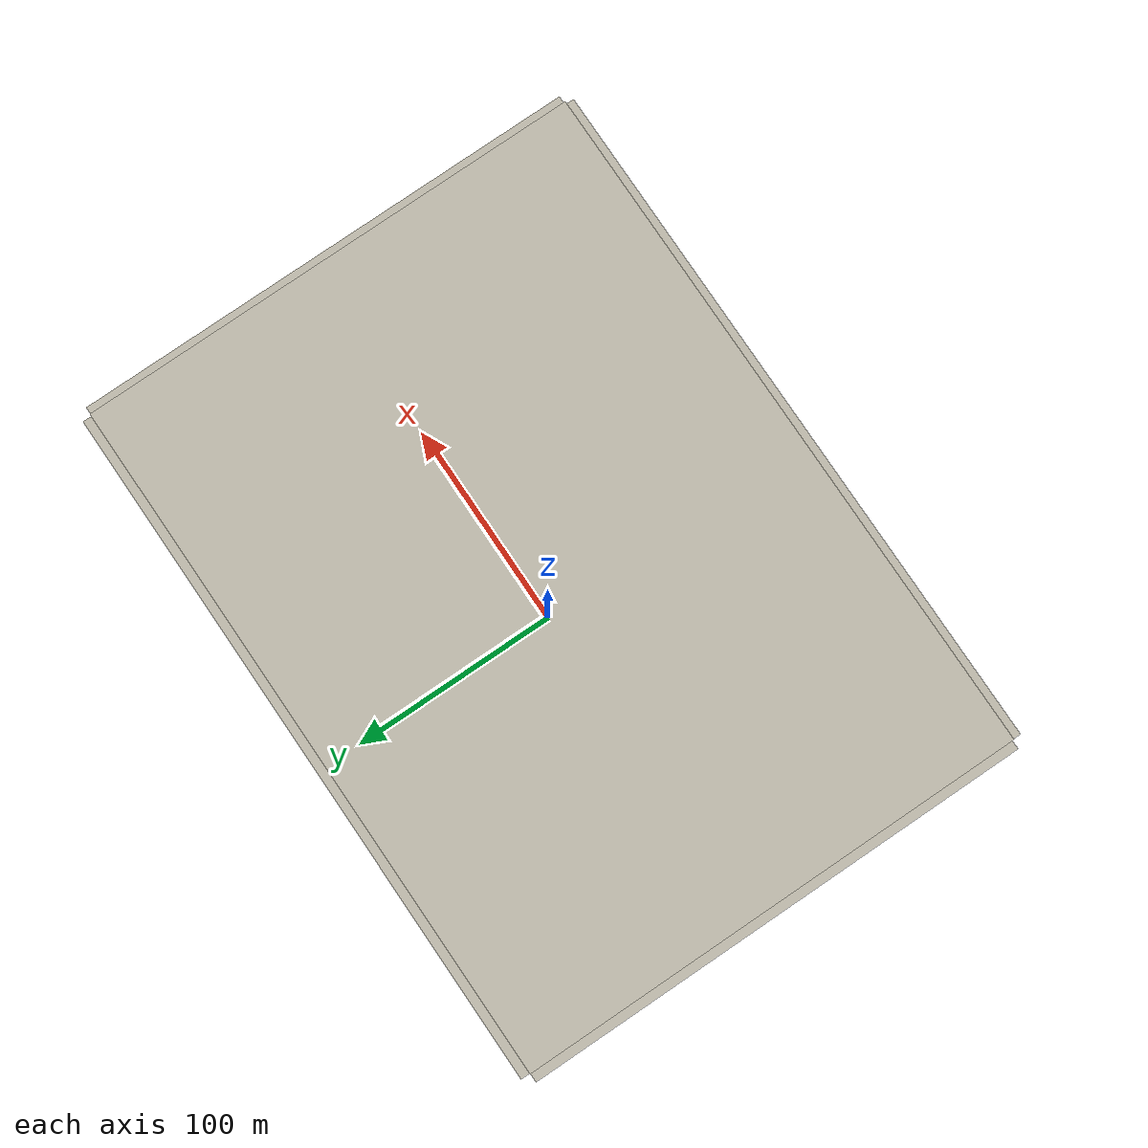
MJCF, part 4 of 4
<mesh name="fly/detail_surface_rm_tarsus3" vertex="-0.0372509348 0.00781990457 -0.11227114 -0.0372254472 0.00824014933 -0.111992071 -0.0371516908 0.00705277989 -0.115134928 -0.0361667517 0.0114905779 -0.113477188 -0.0361574057 -0.030341409 -0.113558723 -0.0360516751 -0.0293889298 -0.111135756 -0.0356527962 -0.0288840019 -0.112950584 -0.0355055708 0.00928288864 -0.106673688 -0.0354144322 -0.0293830453 -0.114160743 -0.0353825199 0.00985026418 -0.116519768 -0.0352484167 0.00635556307 -0.108579159 -0.0349078291 0.00538351514 -0.114883296 -0.0348973153 0.0119145534 -0.11111045 -0.0348700523 -0.0274993108 -0.107530868 -0.0347611749 -0.0325350193 -0.110284323 -0.0347205423 -0.0324528082 -0.111863439 -0.0346017587 -0.027813534 -0.11210161 -0.0345115077 -0.0324243592 -0.113471622 -0.0342414751 -0.031488169 -0.108769382 -0.0342117673 0.00489188596 -0.112485766 -0.0340667102 0.00505902563 -0.113057962 -0.0340190199 0.0100407105 -0.104252569 -0.0339177823 -0.0262382691 -0.108120446 -0.0337345518 0.00530337593 -0.105892235 -0.0337297643 -0.0285440983 -0.106334934 -0.033541779 0.0123255541 -0.108471781 -0.0334038377 -0.0305905414 -0.114325943 -0.033395725 0.00681039592 -0.115082919 -0.0333834469 0.0111997342 -0.116948991 -0.0332924938 0.0123299924 -0.114382943 -0.0332658747 0.00456190764 -0.111896916 -0.0331821793 0.00790847662 -0.116390147 -0.0331794254 0.00893083779 -0.1031024 -0.0330813018 -0.0292721015 -0.105561732 -0.0327388079 0.00399606552 -0.111214031 -0.0326609261 0.0116892679 -0.105031322 -0.0324685934 0.00457308897 -0.103454324 -0.0322921624 0.0104156388 -0.116777221 -0.0321075167 0.00766922312 -0.101753481 -0.0320569234 0.0131836878 -0.111167312 -0.0319620922 -0.0336900775 -0.113555761 -0.0318852071 -0.0286089544 -0.103217724 -0.0316461083 -0.0282874898 -0.112437818 -0.031584892 -0.0329080722 -0.107827967 -0.0313666387 -0.0259544704 -0.107936168 -0.0312662269 -0.0275857601 -0.111082976 -0.0310052237 -0.0323686181 -0.114202121 -0.0308382259 -0.0279589749 -0.101436737 -0.0308236231 0.00357117074 -0.100812715 -0.0308148119 0.00689564104 -0.114583221 -0.0308017406 0.0037471425 -0.100216603 -0.0304506084 -0.0258255513 -0.107838321 -0.0304034365 0.0129902728 -0.107709842 -0.0303274301 0.0103440634 -0.11422782 -0.0301042764 -0.0339570324 -0.110724417 -0.0300891534 -0.0340170591 -0.110341338 -0.0299892617 0.00289393097 -0.110456691 -0.0296600047 0.00252371569 -0.10839184 -0.0295935097 -0.0320317886 -0.113024216 -0.0295632981 0.00219519166 -0.106703897 -0.0295297832 0.00834899402 -0.0984004073 -0.0293744888 -0.0238987886 -0.102214675 -0.0293631074 0.00146755315 -0.0823528826 -0.0293587782 0.000385730146 -0.0864075482 -0.0291994056 -0.0266129591 -0.108457214 -0.0291718297 0.00187640012 -0.105851155 -0.0291144443 0.0014409859 -0.09958398 -0.0290762273 0.0118045173 -0.103712875 -0.0290595126 -0.0271482968 -0.0977055097 -0.028939734 0.000482582209 -0.10277683 -0.0289196796 -0.000345784628 -0.0882961685 -0.0289179025 0.00728456689 -0.0969732209 -0.0288857973 -0.0290746102 -0.110094537 -0.0288535484 0.00370936027 -0.0981235135 -0.0287658022 -0.033241573 -0.105679843 -0.0286173672 0.0056356439 -0.0967718734 -0.0285749429 0.00339791654 -0.108228807 -0.0284978978 0.00216083276 -0.0944537096 -0.0284369708 0.00169847294 -0.0941242179 -0.0284169892 -0.0261412242 -0.0824989911 -0.0284152193 -0.000747794957 -0.0903187029 -0.0283425179 0.0112521375 -0.101638703 -0.0282938618 -0.0315662182 -0.111929839 -0.0282843721 -0.0243525501 -0.108970722 -0.0282720903 0.006668688 -0.0959240497 -0.0281978573 0.00242080364 -0.0892436583 -0.028054983 0.00264408732 -0.0773605934 -0.0279938358 -0.00523941117 -0.0134812108 -0.0279709238 -0.000357928172 -0.076316981 -0.0279524866 -0.0249973709 -0.0791938073 -0.0278555781 -0.0217649977 -0.0805805685 -0.0278448388 -0.00528213923 -0.014049936 -0.0278315056 -0.03419532 -0.109506174 -0.0278258067 -0.0313853598 -0.111636233 -0.0277734107 -0.0262275244 -0.0941921899 -0.0277725685 -0.0247790376 -0.0847868578 -0.02764284 0.00579949983 -0.111834568 -0.0276049614 -0.00407308562 -0.0130400585 -0.0275808015 0.0106552234 -0.0993028589 -0.0275743951 -0.027417771 -0.109249842 -0.0275266229 0.00675866613 -0.0947681401 -0.027468066 -0.0231426275 -0.0975748626 -0.0274198774 0.00508219637 -0.0840615685 -0.0273990136 -0.0313235942 -0.0998072064 -0.0272351845 -0.00292189998 -0.0129911205 -0.0272078396 -0.0054826437 -0.0161444586 -0.0271393783 -0.0256814255 -0.0915399796 -0.0271289646 -0.00192435004 -0.0939676538 -0.0271109911 0.00443267436 -0.0929649977 -0.0270425844 -0.0082747747 -0.0157253198 -0.0270380515 -0.0102133763 -0.0150231972 -0.0269884258 0.00885030749 -0.112098969 -0.0269809025 -0.00596235759 -0.0146969223 -0.0269373522 0.0120293244 -0.106020845 -0.0269297907 -0.0272286288 -0.0825211755 -0.0269240354 -0.00221693085 -0.058278536 -0.0269011598 -0.00307402888 -0.0161605894 -0.0268360836 -0.003333216 -0.0753545391 -0.0268342756 -0.0110597803 -0.0150491223 -0.0268216736 -0.0198741909 -0.0754422945 -0.0268165932 -0.010650574 -0.014832357 -0.0267592804 -0.00670669306 -0.0152989414 -0.026748583 -0.004538751 -0.0793282961 -0.0267067189 -0.0108508157 -0.0151541835 -0.0266759162 -0.0118697981 -0.0155862508 -0.026601525 0.00258202795 -0.106577543 -0.0265851977 -0.023192395 -0.10984749 -0.0265676972 0.00426011775 -0.0882692402 -0.0265405706 -0.00203981472 -0.0130402595 -0.0265151793 -0.00319263677 -0.0620464052 -0.0264858118 -0.0123083792 -0.0151389841 -0.026397598 -0.0241992402 -0.0872978781 -0.0263602142 -0.0041884814 -0.0914802149 -0.0263404927 -0.0006076354 -0.0736865913 -0.0263227739 -0.0342318599 -0.109021996 -0.0262892299 0.00700038436 -0.092802773 -0.0262840331 -0.0129906784 -0.0155122289 -0.0262735521 -0.0121468529 -0.0152387229 -0.0262380763 -0.00220590232 -0.0994659567 -0.0262275262 0.00391446156 -0.07400287 -0.026180589 -0.0127967342 -0.0156294373 -0.0261754212 -0.00132086473 -0.0528216042 -0.0261592613 -0.0223535535 -0.108334658 -0.0261093064 -0.0136594736 -0.0157195027 -0.0260940087 -0.0208128222 -0.104611347 -0.0260537927 -0.0229295492 -0.0920774182 -0.026032938 -0.0109656357 -0.0187408987 -0.0259505741 -0.0287894636 -0.0946576547 -0.0259179069 -0.0081771168 -0.0215659747 -0.0258627842 -0.00221265532 -0.0700459932 -0.0258560667 -0.00296479448 -0.021197724 -0.0258502969 -0.00230187857 -0.102919381 -0.0258008022 0.00163313223 -0.0597656217 -0.0257757147 -0.0249839941 -0.0910935851 -0.0257743122 -0.0114188715 -0.0326822446 -0.0257366864 0.000132647827 -0.0623879314 -0.025734751 -0.0146360935 -0.0719789023 -0.0257093161 -0.00122998438 -0.0647978595 -0.0256878484 0.00246094055 -0.071786817 -0.0256749518 -0.00747474314 -0.0744397476 -0.0256722578 -0.0239498768 -0.0887097194 -0.0256720396 -0.00480269637 -0.0521155562 -0.0256523126 -0.0266879197 -0.0853271704 -0.0255962277 -0.00877516868 -0.0148700065 -0.0255869618 -0.00556541181 -0.0140129641 -0.0255738723 -0.00350732762 -0.0487662473 -0.025569725 -0.00575079412 -0.0693359325 -0.0255695522 -0.0154280733 -0.077664663 -0.0255651776 0.00599722443 -0.0801706119 -0.0255560899 -0.0142939771 -0.0177502843 -0.0255223713 -0.0209195787 -0.0878594146 -0.0254957049 -0.0210907492 -0.106475913 -0.0254914103 -0.00620378432 -0.0829796627 -0.0254662173 -0.0265760355 -0.0905339402 -0.0254613005 -0.0220300753 -0.0692016329 -0.0254481929 -0.0116884776 -0.0729325766 -0.0254182742 -0.0135702085 -0.0218671121 -0.0254089064 -0.0185356384 -0.030757521 -0.0253840572 -0.000308277833 -0.0190743522 -0.0253681501 -0.0288593237 -0.110288398 -0.0253505259 -0.0340658735 -0.106869615 -0.0253304333 -0.00468940607 -0.0655993208 -0.0253110484 -0.000901874103 -0.0246915552 -0.0253072794 -0.0271417939 -0.0823300434 -0.0253032304 -0.0333285498 -0.109378991 -0.0252952796 -0.026565589 -0.0889680741 -0.0252840036 -0.0266092738 -0.0861259832 -0.0252640002 -0.021847507 -0.05502571 -0.0252572354 -0.00978425851 -0.0512272491 -0.0252563386 -0.0196646761 -0.0338108366 -0.0252548216 -0.0273856967 -0.0795382148 -0.0252548034 0.0072021121 -0.09106988 -0.0252395857 -0.0194821114 -0.105168874 -0.025235282 -0.00714415319 -0.0864177782 -0.0252324571 -0.00971364898 -0.0382650323 -0.0251878446 -0.00878359879 -0.0437499548 -0.025186504 -0.00170364467 -0.0410350476 -0.0251357887 -0.0150857377 -0.0193423839 -0.0251339188 -0.0191083782 -0.099699515 -0.0251246911 -0.000663775722 -0.0478787042 -0.0251141009 -0.000614241856 -0.0356861638 -0.0250681187 0.0055280907 -0.0749267565 -0.0250557587 -0.017923061 -0.0527354641 -0.0250504163 0.00499718726 -0.10970619 -0.0250317262 -0.0202604642 -0.0579982006 -0.0250083358 -0.0210104154 -0.0638262791 -0.0249945715 -0.01253759 -0.0763399657 -0.0249824789 -0.00899523002 -0.079768055 -0.0249438999 -0.00741104532 -0.0147295987 -0.024943487 -0.017215094 -0.0665762709 -0.0249250206 0.0119045053 -0.102317179 -0.0249146742 -0.0116134579 -0.0674704643 -0.0249143959 -0.00734523837 -0.0575437116 -0.0248893557 -0.00728739087 -0.062967767 -0.0248807355 0.000214341483 -0.013675407 -0.0248365959 -0.017835484 -0.105308267 -0.0247983389 -0.00850208744 -0.0922954714 -0.0247953612 -0.014148206 -0.0163908262 -0.0247951502 0.00883659413 -0.109207358 -0.0247684966 -0.0168669721 -0.0176540125 -0.0247494863 0.000639094594 -0.0303086908 -0.0246918735 -0.00989419732 -0.0553448008 -0.0246559666 -0.000748895445 -0.106005187 -0.0246455547 -0.0193301603 -0.0471306339 -0.0246440941 -0.0171032898 -0.0947432709 -0.02460826 -0.0254183105 -0.110870489 -0.0245943102 0.00686379099 -0.0854985046 -0.0244985386 -0.017806231 -0.016787093 -0.0244952353 -0.0133168423 -0.0557643507 -0.0244640796 -0.0181230698 -0.0415154645 -0.0244567618 -0.0183984921 -0.0169562554 -0.024409077 -0.0103835828 -0.0868436255 -0.0244086896 -0.0148455456 -0.0172369255 -0.0243851282 -0.0205316537 -0.0381565915 -0.0242672104 -0.00610323605 -0.0973467031 -0.0242491624 -0.0259058233 -0.0739057941 -0.0242198967 -0.0147538312 -0.0898978687 -0.0242164588 0.00316402816 -0.0542092785 -0.0242146798 -0.0205401357 -0.0239419314 -0.02416401 -0.0159623123 -0.106038824 -0.0241500038 -0.0192753741 -0.0203075542 -0.0240889167 -0.0128576903 -0.09313193 -0.0240685167 -0.0127877465 -0.0803137737 -0.0240350873 0.00203759464 -0.0415695613 -0.0240130903 -0.00620315586 -0.103319522 -0.0239928195 -0.0222686867 -0.108692926 -0.023989558 0.00287050079 -0.025911404 -0.0239791771 -0.0139041504 -0.0836438849 -0.0239375549 0.00177178299 -0.0141009341 -0.0239279707 0.00265144604 -0.0674686962 -0.0238363555 -0.0151093363 -0.105778265 -0.0237379627 -0.0166513528 -0.0168072838 -0.0237354507 0.0107254673 -0.0981703852 -0.0237268378 -0.0267881787 -0.11129248 -0.0236220694 -0.0105991057 -0.0593246878 -0.0236219021 -0.0241982161 -0.0556594896 -0.0236183987 -0.0239475212 -0.110577756 -0.0236167289 -0.0332217969 -0.101184822 -0.023591987 -0.013182851 -0.0962522681 -0.0235689386 0.00356720716 -0.0674048351 -0.0235449625 -0.0224060022 -0.0341800733 -0.0235411135 -0.0227759047 -0.028628865 -0.0235372518 -0.0136487897 -0.10578677 -0.02353321 -0.0199926944 -0.0178096052 -0.0235054285 -0.0240760928 -0.0591547032 -0.0234966319 -0.0284687849 -0.0812125945 -0.0234939107 -0.0237247041 -0.0517163353 -0.0234575036 0.00757672024 -0.0866482806 -0.0234550425 0.00714492671 -0.0822713919 -0.0234281051 -0.0243829854 -0.0690512898 -0.0234090294 0.0033241347 -0.0610290699 -0.0233095743 -0.0238751018 -0.0633499658 -0.0232914608 0.00221941355 -0.0141465407 -0.0232692128 0.00434090043 -0.108525157 -0.0232607163 -0.0147342107 -0.0166826539 -0.0232482835 -0.0138437636 -0.10173957 -0.0232385901 0.00354315034 -0.0378659752 -0.023222774 -0.0124481985 -0.105309933 -0.0231503909 -0.00820098285 -0.103372353 -0.0231086997 -0.0100126417 -0.103814309 -0.0230787227 -0.021969754 -0.0406060972 -0.0229772468 -0.0114125487 -0.103949336 -0.0229239067 0.0100562065 -0.0951704351 -0.0229170728 -0.0227313431 -0.0459370203 -0.0229012421 -0.0161035387 -0.105827028 -0.0228802382 -0.0319380561 -0.107598134 -0.0228463578 -0.0318354141 -0.107712374 -0.022784714 0.00783233008 -0.108015025 -0.0227531364 -0.0107970509 -0.100646175 -0.0226855191 -0.0215688106 -0.0181164287 -0.0226657285 -0.00495841459 -0.105520812 -0.022659764 0.00421128061 -0.0500952228 -0.0226562988 0.00422342964 -0.0209618665 -0.0226231241 -0.0186662437 -0.0176023786 -0.0226213779 -0.0230410697 -0.0234214422 -0.0225572367 0.00339716803 -0.107377462 -0.022532291 -0.00291222909 -0.106745531 -0.0224562154 0.00629320857 -0.0739786556 -0.0223706811 -0.0243025988 -0.0263962556 -0.0223586412 0.00309018287 -0.0142082372 -0.0223536026 -0.0225089771 -0.110330897 -0.0223266561 -0.00794078733 -0.104560801 -0.0222728941 0.0067959536 -0.0787184108 -0.0221171376 -0.0233246246 -0.0382756189 -0.0221133178 -0.0286753839 -0.0774676155 -0.0220133934 -0.0315545731 -0.0959134049 -0.0220042712 -0.0276064638 -0.110647532 -0.0218739806 0.00916809404 -0.0908774455 -0.0217912111 0.0045362458 -0.0623569649 -0.0216876542 -0.0115754719 -0.105251806 -0.0214841857 0.00394242352 -0.10758498 -0.0214088031 0.0106910593 -0.100592813 -0.0213653493 0.00517996523 -0.0329924515 -0.0213108979 0.00390000878 -0.0145495378 -0.0212665709 -0.00213162843 -0.107252825 -0.0210598482 0.0048436068 -0.0170454459 -0.0208887031 -0.0295835853 -0.0911896714 -0.0208423098 -0.0233215378 -0.0178800565 -0.0208308156 0.00358846137 -0.0147454539 -0.0208117872 -0.0317333761 -0.0987596213 -0.0208043803 -0.0131121815 -0.106310952 -0.0207587891 -0.0202327938 -0.109930901 -0.0207245776 0.00589797492 -0.0280397689 -0.0204828521 -0.0290151602 -0.0800182825 -0.0204702101 0.00452755194 -0.015055818 -0.0204152566 0.0056560275 -0.0450749976 -0.020158277 -0.000157735755 -0.107569627 -0.0201129806 0.00701357749 -0.0694909977 -0.0199286278 0.00466536221 -0.0151262384 -0.0198579037 -0.0261781934 -0.0268303993 -0.019838526 -0.0288695264 -0.0738183953 -0.0198357011 0.00617815931 -0.0398141055 -0.0198341932 0.00653885945 -0.0231170725 -0.0197469835 0.00852728408 -0.0866558767 -0.0196976289 -0.0188346603 -0.109656903 -0.0196886085 0.0106171592 -0.0975656512 -0.0196688943 -0.0278723073 -0.110133187 -0.0195100511 -0.00791664388 -0.106310363 -0.0195001012 0.00506831748 -0.0154088757 -0.019473604 -0.00020307111 -0.0148570789 -0.01944621 -0.0272357429 -0.0519155074 -0.0194039094 -0.0289783657 -0.0857669147 -0.0193892429 -0.0318573766 -0.101848316 -0.0193799606 -0.00106606899 -0.10735025 -0.019372359 -0.0273282621 -0.0555796541 -0.0193068117 -0.0258352538 -0.0228389963 -0.0192879288 0.00636167897 -0.0347989262 -0.0192782227 -0.027801223 -0.0688223954 -0.0192760726 -0.0162290107 -0.108432723 -0.0192154657 -0.0266508614 -0.0460617375 -0.0191807067 -0.0251213351 -0.0177134771 -0.0191404451 -0.0270542623 -0.0585822927 -0.0191121071 0.0067157689 -0.019147059 -0.0191056388 -0.0319065875 -0.0965670552 -0.0190222981 0.0070788351 -0.104390361 -0.0190134706 -0.0259363151 -0.0409099484 -0.0189442289 0.00785514567 -0.0814676532 -0.0189090897 -0.0270775381 -0.0632364681 -0.0188910726 0.00537079541 -0.0154086465 -0.0188666199 -0.0257261054 -0.0382336693 -0.0187519072 -0.0176035155 -0.109490684 -0.0187309961 -0.00614507417 -0.106882508 -0.0186902816 0.00148090089 -0.108056745 -0.0185800927 0.00532356307 -0.10585296 -0.0185718818 -0.0272259185 -0.110069443 -0.0184203454 -0.00431568014 -0.107433072 -0.0183785851 -0.028863129 -0.109520086 -0.0182228287 0.00688201544 -0.0471757958 -0.0181828818 0.00671891576 -0.0559524051 -0.0181820415 -0.0304594596 -0.0911284296 -0.018033601 -0.02956957 -0.0758237147 -0.0180108764 -0.0165715865 -0.109325862 -0.0179102772 0.0069061698 -0.0300605716 -0.0178985483 0.0099018871 -0.0934159834 -0.0177992679 0.00603562512 -0.0161641165 -0.017794544 -0.0120211216 -0.0168523711 -0.0177667789 0.000928890358 -0.107329499 -0.0177492748 0.00574971455 -0.0161817061 -0.0173991193 -0.0296479902 -0.0878886131 -0.0172462187 -0.0260471406 -0.0177027523 -0.0172071868 -0.0314653007 -0.0982796846 -0.0172057207 -0.0216106309 -0.108851236 -0.0171643678 -0.0310218456 -0.102598649 -0.0171615138 -0.0152916691 -0.10902706 -0.0170873245 0.00873561657 -0.0759425311 -0.0170550229 -0.0277549771 -0.0258346627 -0.0170115127 0.0082653678 -0.0645098844 -0.0169195227 -0.0117219142 -0.107892738 -0.0168864681 -0.0296397557 -0.104992818 -0.0168091683 0.00448253968 -0.105502775 -0.01679255 0.00737391383 -0.0404859638 -0.0165677484 -0.00106330958 -0.106388172 -0.0164781468 -0.00783097494 -0.1075373 -0.016407992 0.00736152651 -0.0522881455 -0.0164073026 0.00774242471 -0.0234733543 -0.0164035846 0.00671778616 -0.0170558142 -0.0161646403 0.0015877531 -0.0158422572 -0.0161217176 -0.0139807289 -0.108828288 -0.0160139662 0.00944057865 -0.0949245805 -0.0157513441 -0.02893091 -0.109631699 -0.0156439382 -0.0280821478 -0.109261397 -0.0155692287 0.0099351837 -0.0710942477 -0.01533043 0.00850565812 -0.0596182945 -0.0152217199 0.00127032195 -0.105540428 -0.0151830309 -0.00314326326 -0.0156397036 -0.0151498207 0.00744899444 -0.0177655565 -0.0151388012 0.00883384564 -0.0825100215 -0.0151115919 -0.0282876026 -0.0229969992 -0.0150407068 -0.0286232535 -0.0526876975 -0.0149540247 -0.0285469214 -0.028110202 -0.0148119934 -0.0303916786 -0.0690244342 -0.0147732126 0.0100653087 -0.077657176 -0.014770616 0.00856589577 -0.0298155264 -0.0146636849 -0.0290737535 -0.109332119 -0.0145999402 -0.028996963 -0.0573149809 -0.0145244612 -0.0258388973 -0.108065382 -0.0144895903 0.00966053449 -0.0916069039 -0.0144267278 -0.0117308591 -0.108438049 -0.0144067753 -0.0284225953 -0.108242704 -0.0144046699 -0.0303050529 -0.0743972414 -0.0144040114 -0.0291391698 -0.107937391 -0.0143251036 -0.0284016478 -0.0404854109 -0.0143063708 -0.0297666538 -0.0629941787 -0.0142482832 -0.02763472 -0.0178746741 -0.014203305 -0.028419945 -0.0349117436 -0.0141169958 -0.00670910549 -0.0162380857 -0.0140542788 0.00438150937 -0.104368359 -0.0140130132 0.00773039392 -0.0176545909 -0.0139715185 -0.0300683696 -0.0866945193 -0.0138478827 0.0103726215 -0.0658326753 -0.0137444813 -0.00284817747 -0.106817868 -0.0136942299 -0.0307228474 -0.092629336 -0.0136428025 -0.0291802589 -0.0246144773 -0.013618328 0.0114870436 -0.0738219314 -0.0135195905 -0.0292696441 -0.106641426 -0.0134620932 0.00931798058 -0.0884671026 -0.0133713356 -0.0236545893 -0.107267289 -0.0133543717 0.0113499173 -0.0698156291 -0.013335246 -0.0101475471 -0.108180175 -0.0133232033 -0.0301876171 -0.080926824 -0.0132235946 -0.0288476276 -0.0465066005 -0.013222385 0.00768822247 -0.046214871 -0.0131990282 -0.0308512608 -0.0713086411 -0.0131447887 0.00807912511 -0.041747222 -0.013085476 -0.0295307691 -0.103909406 -0.0129828586 0.00648488594 -0.0993611902 -0.0128586053 0.00789943442 -0.0173316839 -0.0126230334 -0.0290676307 -0.0370716079 -0.0124020189 0.00432905972 -0.104318337 -0.0123831778 0.00845011164 -0.093860268 -0.0123306145 -0.0292411041 -0.105072868 -0.0121742069 0.00938496851 -0.024840243 -0.0121506 -0.030764546 -0.0691937821 -0.0118783046 0.00875537808 -0.0540996261 -0.0118641492 -0.0294714428 -0.0212117957 -0.0117903746 -0.0303372344 -0.0982822239 -0.0117783457 0.00359642399 -0.0165585479 -0.0117626996 -0.00217958677 -0.015795893 -0.0116796082 0.0093635208 -0.0365549895 -0.0115945822 -0.0293496178 -0.103999271 -0.0115805015 0.00895893754 -0.0204184435 -0.0115305847 -0.0161626958 -0.106480933 -0.0113156048 -0.0315647085 -0.0669919973 -0.0112685702 0.00678130891 -0.0169807972 -0.0112590551 0.00828107841 -0.01698306 -0.0110185392 -0.0288463707 -0.0181628129 -0.010961613 0.00836134677 -0.0500291062 -0.0109605871 -0.00669029714 -0.107630993 -0.010678159 -0.0103923503 -0.107345091 -0.0106707566 -0.0197923837 -0.105457322 -0.0106684674 0.00922132494 -0.0894005352 -0.010623281 0.0103294205 -0.0318400089 -0.0105387271 -0.0305261055 -0.0787950994 -0.0104634892 0.0117342224 -0.072628929 -0.0104055216 -0.0299750754 -0.0332875607 -0.0103570783 0.00406443587 -0.104559134 -0.0101712467 0.0109802677 -0.0776661691 -0.0101420055 -0.0314788122 -0.0638695419 -0.00998821088 -0.0290166245 -0.102708196 -0.00984952385 -0.0294061756 -0.102617523 -0.0098204373 -0.000699629766 -0.0156519782 -0.00979643664 0.0105734052 -0.0274366848 -0.00976771025 0.00852395169 -0.0175265268 -0.00970589554 -0.0302369863 -0.023292494 -0.00959359113 0.00993091817 -0.0581298991 -0.00948898014 -0.0190224928 -0.104550323 -0.00933704723 0.00743839519 -0.0174077923 -0.00928636109 -0.0221614901 -0.103630045 -0.00927832934 0.00584555164 -0.0170960247 -0.00920684943 0.00874401121 -0.0184003748 -0.00914009252 0.00845615432 -0.0423019846 -0.00891956734 -0.0294900074 -0.101802849 -0.00886086673 -0.0306456059 -0.0295101163 -0.00884482506 0.0100782963 -0.0239121309 -0.00884134897 0.0100240195 -0.0844223687 -0.00877556704 -0.0291220695 -0.0185235021 -0.00871100747 -0.0270898236 -0.102016609 -0.00870194162 0.0118246699 -0.0675268457 -0.00863806054 -0.0312363954 -0.0696498973 -0.00855217968 0.00388124545 -0.104523613 -0.00819024535 -0.0301170621 -0.0350884147 -0.00814022678 -0.0294816182 -0.0410237735 -0.00813754377 -0.0297062052 -0.100952144 -0.00798673773 -0.0298400337 -0.0531657424 -0.00790197919 -0.0307806476 -0.0584097616 -0.00778730282 -0.0293702269 -0.0477698231 -0.007775011 -0.0307740484 -0.093564202 -0.00770903625 0.0020310797 -0.105554653 -0.00770306269 0.00369819804 -0.104994375 -0.00767332222 0.00948720117 -0.0375346681 -0.00760645344 -0.0255831637 -0.017629025 -0.00758652459 0.0109763387 -0.0799956324 -0.00755340625 0.00879584877 -0.0184544242 -0.0075094913 0.0116625724 -0.0642554078 -0.00738276776 0.00224318046 -0.0152042294 -0.00733560046 0.00507227878 -0.100098048 -0.00731555156 -0.030278632 -0.0817983018 -0.00720285152 -0.0300529482 -0.0990583067 -0.00713757345 -0.00162151377 -0.106739899 -0.00697906034 0.00358759894 -0.105776788 -0.00696174629 -0.0316456862 -0.0641728766 -0.00690319757 0.00594911762 -0.0161519802 -0.00687499323 0.00682180507 -0.0163148925 -0.00672787883 -0.0308673407 -0.0319482642 -0.0066511675 0.0108125023 -0.0605154855 -0.00660901605 -0.0291956385 -0.0188683498 -0.00658066983 0.00839440509 -0.0166600421 -0.00638507299 0.0112518246 -0.0763696517 -0.00637789344 0.00692800131 -0.0948690067 -0.00630893919 -0.0229110483 -0.0171715201 -0.00623683354 -0.00670396958 -0.106735322 -0.00614138298 -0.0304846544 -0.0867860217 -0.00612392705 0.00810348502 -0.0432848756 -0.00611205542 0.00802426803 -0.0151862214 -0.00605417063 -0.0306406691 -0.03023729 -0.00598161023 -0.0282433066 -0.0184066175 -0.00594685935 -0.0272126999 -0.101237369 -0.00581936001 -0.0301183391 -0.0984107901 -0.00569281474 -0.0313937417 -0.0601060274 -0.00566920335 0.0100463731 -0.0321512416 -0.00562984314 0.00351507947 -0.106275744 -0.00551936046 -0.0312452175 -0.0282464243 -0.00547363379 -0.0127655903 -0.105816012 -0.00543449369 0.00987652493 -0.0239030433 -0.00526680287 -0.0258165092 -0.017073764 -0.00516000091 0.00985797487 -0.0558930478 -0.00515737975 -0.030719144 -0.0735429785 -0.00489576996 -0.030723786 -0.0242682236 -0.00484730845 -0.0306406764 -0.0563320173 -0.00484041266 0.00588218609 -0.0148402169 -0.00451772121 0.00382244571 -0.102990736 -0.0044654862 0.00223576512 -0.106104104 -0.00440804524 0.0033425647 -0.106098312 -0.00437828658 0.0105280578 -0.0787523022 -0.00437002382 0.0105097661 -0.0722201366 -0.00435167203 -0.00493285688 -0.0152492285 -0.00427392752 -0.0244299044 -0.101971753 -0.00424283553 0.00774487853 -0.0147713181 -0.00419247499 -0.0282198125 -0.0177498059 -0.00409286986 -3.37823067e-05 -0.0143457291 -0.00403345712 0.0108506993 -0.0621282888 -0.00398123848 -0.0297201186 -0.0381056416 -0.0039571496 -0.0305321082 -0.09751779 -0.00392951915 0.00843129055 -0.0478262409 -0.00376124535 0.00846665353 -0.0374592419 -0.0036789927 -0.0292456116 -0.0193205797 -0.0033337933 -0.0301109139 -0.0810399288 -0.0032774858 0.00362678475 -0.0142202261 -0.00323581389 -0.0308067865 -0.0593890691 -0.00316033515 -0.0280792665 -0.0168005045 -0.00308893118 -0.0272510006 -0.0162375927 -0.00307320647 -0.0296294111 -0.0491105748 -0.00305357889 0.00315093871 -0.105932348 -0.00301453497 -0.0260516717 -0.0161928019 -0.00292228674 0.00887875285 -0.0188664089 -0.00286744307 0.00298439659 -0.105949737 -0.00283444456 -0.0306226502 -0.0310038158 -0.00281237021 0.00981790799 -0.0752181877 -0.00276297874 0.00302719195 -0.105760577 -0.00273197588 0.00306823745 -0.105781735 -0.00269958878 -0.0286313516 -0.0171721986 -0.0026843536 0.00953939343 -0.0308064118 -0.00262167782 -0.0311018157 -0.0946438522 -0.00256201474 0.00745536636 -0.014225785 -0.00253034682 0.00319376863 -0.105342297 -0.00232223124 -0.0291906035 -0.0423928577 -0.00219559365 -0.0281121793 -0.0148134604 -0.0021533599 0.0104061473 -0.0585788039 -0.00208746042 0.00821583308 -0.0899125153 -0.00208054212 -0.029487157 -0.0974922223 -0.00198476414 -0.0305027479 -0.0312090269 -0.0019510212 -0.0168193947 -0.0160581876 -0.00174305819 0.00275772504 -0.105711559 -0.00168170061 0.00680495395 -0.0131809538 -0.00160961383 -0.0279791584 -0.0145504564 -0.00155580437 -0.0310022297 -0.0714173366 -0.00148716924 0.00370741395 -0.100997553 -0.00135834171 -0.0250048797 -0.0157081013 -0.00132142839 0.00380943584 -0.0126188079 -0.0013198196 -0.000148381574 -0.106398758 -0.00123219866 0.00639783684 -0.011862101 -0.00112018449 -0.0308501731 -0.089295987 -0.00106043956 0.00762536365 -0.043860804 -0.00103827574 0.00931537397 -0.0858527492 -0.0010131231 0.00620770516 -0.011039052 -0.00100687953 0.00913191616 -0.0720673852 -0.000762279399 -0.00574574824 -0.106538973 -0.000666727544 -0.0306733164 -0.0769491598 -0.000570102031 0.00506687866 -0.0115602215 -0.000360385485 0.00224302289 -0.106119383 -0.000356438449 0.0051441948 -0.0959929093 -0.000334446156 -0.0277587114 -0.0148541085 -0.000221956839 -0.00176405501 -0.0132039904 -0.000101963145 0.00572827048 -0.0106053067 -6.33096917e-05 -0.0309818606 -0.0659203797 7.21171567e-06 0.00798828114 -0.0487223151 7.66721655e-05 -0.0299997955 -0.0839958229 0.000288756524 -0.0296814978 -0.0552527163 0.000309537455 0.00775257467 -0.0174714478 0.000403857939 -0.0289105737 -0.0970643014 0.00041429746 -0.0240035406 -0.100448997 0.000427257191 -0.0292516215 -0.0381294522 0.000537731069 0.00985734914 -0.0800838025 0.000616489899 0.00197462828 -0.106325242 0.000681079143 -0.0274143968 -0.0149704583 0.000737589232 -0.0299959938 -0.0339314429 0.000939551398 0.00888021714 -0.0681735764 0.00101568185 0.00887173701 -0.0557682615 0.00114067211 0.00508309131 -0.0102222421 0.00138512485 0.00886442285 -0.0285890656 0.00139993131 -0.0301030905 -0.0954384959 0.0014530998 -0.0172990858 -0.10342215 0.00169710756 -0.030046418 -0.0302072749 0.00206764798 -0.0287003077 -0.0437146082 0.00210047824 0.0093513645 -0.0749039464 0.00211359134 -0.0274804661 -0.0155300004 0.00213528529 0.00335676123 -0.0110240571 0.00214414854 -0.0311226249 -0.0753659842 0.00236066739 -0.0250501544 -0.0148456111 0.0024157157 -0.0285850074 -0.0966365551 0.00241573275 -0.0292902532 -0.0266296975 0.00243326258 0.00129113573 -0.106882842 0.00252179279 -0.0304184941 -0.0902062457 0.00253742019 -0.0284908856 -0.0390435598 0.00257357192 0.0043512764 -0.00989909222 0.00282573615 -0.0310492651 -0.0725586942 0.00284005773 -0.0292099503 -0.0965120125 0.00289589389 0.00681863457 -0.0423031634 0.00291519518 0.00837552943 -0.0644580141 0.00296386224 0.00862910565 -0.0705061757 0.00300057241 0.00824099516 -0.0251448728 0.00300844022 -0.027854343 -0.0202392039 0.00302783019 0.0015345156 -0.100710371 0.00333963521 0.00936189099 -0.0816180691 0.00334072047 -0.0111853969 -0.0148722702 0.00335423556 -0.0288920492 -0.0373465155 0.00354275107 0.00569268741 -0.0151157383 0.00358494526 -0.0289330437 -0.0540845213 0.00358863394 -0.0291368906 -0.0327173075 0.00377786364 -0.016220285 -0.0149700154 0.00379601829 0.000707117351 -0.107206179 0.00388529043 -0.0284551825 -0.0973933857 0.00391818594 -0.0229244015 -0.0146959701 0.00392010224 -0.0296924245 -0.0613563971 0.00395615098 -0.0305039976 -0.0672249225 0.00404198363 -0.0301984564 -0.0783290961 0.00409051881 -0.0297279312 -0.0832947553 0.00418734089 -0.0268971598 -0.0161900152 0.00442513192 -0.0263015118 -0.0980210752 0.00447293496 -0.0290695007 -0.0935369317 0.00468841972 0.00619946877 -0.0445926162 0.00481317602 -0.0277794006 -0.045229368 0.00484991688 0.00981559242 -0.0775214285 0.00486273075 -0.0242746828 -0.0152803823 0.00513018676 0.0064097585 -0.051162282 0.00520119193 0.00755506699 -0.0278250336 0.00523773178 -0.027593549 -0.0979434844 0.00527793327 -0.0282596884 -0.0568599789 0.00532928334 0.00666366759 -0.0233558694 0.00553096106 0.00650327456 -0.0563050671 0.00554309645 -0.00503877482 -0.106366802 0.0055751043 -0.0273694895 -0.0400650642 0.00573734906 -0.0288278534 -0.0856704282 0.00579773587 -0.00126635859 -0.0114102986 0.00581924542 0.00758834722 -0.0338418395 0.00585889757 0.00679957702 -0.0633977543 0.00605782043 0.00576970524 -0.0862400702 0.00611070391 -0.00105014556 -0.107108594 0.00636130062 0.00638832171 -0.039774266 0.0064019041 -0.029672512 -0.0736898073 0.00640788585 -0.0271130593 -0.0978943135 0.00646289209 0.00735594585 -0.0691387977 0.00667461518 0.00848461059 -0.0775303342 0.00668902248 -0.0256430903 -0.0170492476 0.00679556342 0.000877186721 -0.0100294346 0.00695795734 -0.00554856979 -0.0126479026 0.00709444885 -0.0267639662 -0.0243118538 0.0070945398 -0.0201040148 -0.101707323 0.00719704258 -0.0266173611 -0.0520749527 0.00729908697 4.6118636e-05 -0.0103285929 0.00746793285 0.00191905565 -0.0136101253 0.00746854403 0.00752849883 -0.07544252 0.00749141236 -0.0195959146 -0.0142868803 0.00749921401 0.00634730532 -0.0658137797 0.0076065453 -0.00203606328 -0.100967998 0.00768165046 0.00697028372 -0.0359011865 0.0077148743 -0.0221238934 -0.0147385754 0.00773732336 -0.00213920453 -0.107077729 0.00777738387 -0.00833775994 -0.105353211 0.0078276189 0.00674119656 -0.0800606795 0.00810693655 -0.000979914148 -0.0104195215 0.00813753286 -0.0240693116 -0.0159565734 0.0082585866 0.00250736866 -0.016990567 0.00826921951 0.00483409349 -0.0536599728 0.00833540435 -0.0124100261 -0.104274332 0.00839339464 0.00663138599 -0.0762929849 0.00839892527 -0.0029868786 -0.10673936 0.00842774716 -0.000499824864 -0.095265983 0.00845798422 -0.0248356337 -0.01780602 0.00852206267 -0.0261074638 -0.0347424939 0.00867947165 -0.0276464307 -0.0808123805 0.00876946069 -0.0251158745 -0.046820398 0.0087732742 -0.00302967874 -0.0117127283 0.00884732799 -0.0286883878 -0.0688667424 0.00895591984 -0.026712054 -0.0928970403 0.0089798732 -0.00202890169 -0.0112068128 0.00911082316 -0.00401920624 -0.106184802 0.00919822742 -0.0232446018 -0.0151021741 0.00920260482 0.00323363474 -0.0221442369 0.00920537332 0.0049652117 -0.0656797056 0.00930026999 0.00596685095 -0.0780520277 0.0094673851 0.00291267656 -0.0511103826 0.00954785992 0.00303950219 -0.0452925087 0.00957860084 -0.00461561558 -0.0123417713 0.00959223689 0.00558703323 -0.0358319776 0.00975921739 -0.00265576818 -0.0131252236 0.00977478521 -0.0225141212 -0.01435179 0.00981113408 0.00338724453 -0.0626547771 0.0098165192 0.00296540179 -0.0558500651 0.0100026018 -0.0242748974 -0.0994131988 0.0100182933 0.00399340297 -0.0275720722 0.0100475172 -0.0217235865 -0.0138768592 0.0101400983 -0.0054448733 -0.105892024 0.0102254789 0.00431389981 -0.0789362675 0.0103008979 -0.00508216908 -0.012567195 0.0103314724 -0.00267800897 -0.0146910643 0.0103666571 6.44876863e-05 -0.0175351488 0.0103904085 -0.00610240886 -0.0120437589 0.0103999319 0.0038484477 -0.0390137975 0.0104952442 -0.0140371048 -0.0136223389 0.0105422487 0.00169914324 -0.085836029 0.0105497338 -0.0239396868 -0.0416674557 0.0105912595 0.00452108543 -0.0338596328 0.0106157931 -0.0172063028 -0.0144782789 0.0106614707 -0.00821049252 -0.0122316751 0.0107288761 -0.0253368653 -0.0588158618 0.010759718 -0.00767009715 -0.0119284059 0.0107882088 -0.00548305616 -0.10040286 0.0108311742 -0.0246510663 -0.0295930968 0.0109654702 0.0023775292 -0.0249033656 0.0110154069 -0.00662525554 -0.105692212 0.0110268093 0.0039288052 -0.0744211211 0.0110755327 -0.0264474838 -0.0755897927 0.0111332638 -0.00879191703 -0.0122209649 0.0111730924 -0.0243843715 -0.0242195092 0.0112493017 -0.0269758293 -0.0718365191 0.0112604639 -0.0233155897 -0.053830001 0.0112830912 -0.00690530624 -0.105191728 0.0112893485 -0.0176625399 -0.102608123 0.0113790702 -0.00761193542 -0.105612686 0.0114046952 -0.0272744564 -0.0674565817 0.011559785 -0.010009534 -0.0124886301 0.0118081371 -0.0257239626 -0.0877473722 0.0118803127 -0.00144631304 -0.0209539394 0.011883888 -0.0117211521 -0.105069914 0.0119283804 -0.0100746756 -0.10576169 0.0119600054 -0.0135987348 -0.10411736 0.01199495 -0.00872151759 -0.105935957 0.0120506847 -0.0118391927 -0.0127074691 0.0120734585 -0.016809523 -0.013042817 0.0120935665 0.00269572593 -0.0368422516 0.0121000112 -0.00976319643 -0.105744759 0.0121243629 -0.0161962962 -0.0126034811 0.0121453804 -0.00966547668 -0.105013787 0.0121477105 -0.0176741796 -0.0141751998 0.012164669 -0.021439686 -0.0488840269 0.0121692228 -0.00786419787 -0.0999235926 0.0121955918 -0.0185873323 -0.0148074041 0.012213367 -0.000142329611 -0.0257913471 0.0122535648 -0.0094730276 -0.105883191 0.0122915399 0.000882750044 -0.0286061531 0.0123065429 -0.0104540077 -0.105491155 0.012341442 -0.0101076566 -0.102661303 0.0123441978 -0.0230325404 -0.0951513139 0.0123506634 -0.0127341391 -0.0130194685 0.0125166489 -0.0101141104 -0.10566046 0.0125374745 -0.0100985071 -0.106044732 0.0126030345 -0.0160840027 -0.103373888 0.0126040695 -0.0107313481 -0.105472318 0.0126169161 -0.0142841664 -0.0129908449 0.0126337518 -0.0228844292 -0.036772024 0.0126851919 -0.0217985435 -0.0204542266 0.0126896921 -0.00148866377 -0.0556289488 0.012736723 -0.000880625578 -0.0264940409 0.0127439907 -0.00222438325 -0.0897410937 0.0127885232 -0.0142825975 -0.013189042 0.0128575839 -0.0256383246 -0.070778231 0.0129075206 -0.011585149 -0.105246756 0.0129530281 -0.0125848974 -0.104127881 0.0130096751 -0.0232534603 -0.0284509642 0.0130236522 -0.0186354919 -0.102323815 0.0130351427 -0.0193875367 -0.101744845 0.0130373837 -0.0159047995 -0.103291299 0.0130800854 -0.0250214034 -0.0638019701 0.0130938815 -0.0148691888 -0.103650003 0.0131015486 -0.0109934763 -0.0162188408 0.0131519091 -0.0164407465 -0.102828461 0.0131667539 -0.015330319 -0.102891267 0.0131787065 -0.0156891074 -0.103405473 0.0132176447 -0.000813092868 -0.0329469549 0.0132324267 -0.00148014271 -0.0501397917 0.0133082422 -0.017332366 -0.103268518 0.0133467729 -0.0079317706 -0.0193041196 0.013405067 -0.0159147767 -0.103733328 0.0134135071 0.000218576957 -0.0375023119 0.0134940346 -0.00480536892 -0.0222423514 0.0135629543 -0.000954364737 -0.067795736 0.0136017597 -0.00216114154 -0.0616175457 0.0136848121 -0.0200443519 -0.0438554634 0.013754754 -0.0221959745 -0.0314933641 0.0137807583 -0.0218637142 -0.0224296564 0.0137831921 -0.000412263148 -0.0447617858 0.0138221167 -0.0182808617 -0.0966252774 0.0138676251 -0.0142248646 -0.017112412 0.0139206131 -0.00308768495 -0.0304814803 0.0139383319 -0.0147362807 -0.0983947466 0.0139670774 -0.00184479654 -0.0851298464 0.0139790291 0.000148725931 -0.0405539286 0.0140297543 -0.00427743771 -0.0900346422 0.014133424 -0.0241573543 -0.0869179275 0.0142158997 -0.00566184826 -0.0253723592 0.014249621 -0.0223183924 -0.0897004284 0.0143348479 -0.00416581315 -0.0340967708 0.0144437136 -0.0100166963 -0.0933884658 0.0145237291 -0.00080602166 -0.0795904489 0.014618041 -0.0194932654 -0.0557404092 0.0146262801 -0.023370605 -0.0829227647 0.0146366665 -0.0223485658 -0.0617912665 0.0146776329 -0.0119805754 -0.0201103539 0.0146829352 -0.0231531485 -0.0776676534 0.0149123298 -0.00538946688 -0.0533056846 0.0149269317 -0.0171313641 -0.0509166966 0.0149283451 -0.0209186055 -0.0359843216 0.0149361949 -0.00713608051 -0.0311170843 0.0149618318 -0.00918632122 -0.0246485797 0.0150553942 -0.0191620475 -0.0387019281 0.0150647174 -0.005415945 -0.0869588548 0.0151968343 -0.0199846218 -0.0234645449 0.0152867997 -0.0172926757 -0.0220525289 0.0154511636 -0.0188434642 -0.0251548408 0.015529793 -0.0127258863 -0.0234178115 0.0155484686 -0.0173433182 -0.0231572994 0.0155522921 -0.00996270683 -0.0278625466 0.0155561738 -0.0196919791 -0.0272435373 0.0158569328 -0.00516507362 -0.0384158593 0.0158657658 -0.00695120025 -0.0604464913 0.0158665007 -0.0189815783 -0.0324322355 0.0159249121 -0.0123996533 -0.0892839671 0.0159292704 -0.00771997293 -0.0547383825 0.0159651627 -0.0164689045 -0.0283525205 0.0160074978 -0.0164667326 -0.0341031409 0.0160149339 -0.00861018634 -0.0887200804 0.0160352683 -0.0150787455 -0.045609977 0.01613315 -0.0144982641 -0.0288243064 0.0162157448 -0.0211303995 -0.0723978592 0.0162652213 -0.00194118456 -0.0423313286 0.016284268 -0.0186457655 -0.0299534804 0.0163729455 -0.0148054587 -0.0872193705 0.0164492885 -0.0113631504 -0.0360841768 0.0164919529 -0.0175999048 -0.0265228155 0.0165567544 -0.0118962889 -0.0535183572 0.0165960864 -0.00649534059 -0.0665267507 0.016603326 -0.0149116086 -0.0578544496 0.0166052378 -0.0205373944 -0.0672792012 0.0166504215 -0.0199397891 -0.0635749966 0.0166595419 -0.0134188558 -0.0407565167 0.0167134931 -0.00480549124 -0.0844522947 0.0168621518 -0.00395322922 -0.0747458471 0.0169218056 -0.00939954589 -0.0528592318 0.0169687319 -0.0179537128 -0.0803509975 0.0170037165 -0.0199627248 -0.0755449219 0.0170696785 -0.0108853155 -0.0584852824 0.0170807907 -0.0176383073 -0.0627232293 0.0171379961 -0.00850785 -0.0641175648 0.0173240587 -0.0053735962 -0.049825594 0.0174299785 -0.00852990252 -0.0507827717 0.0174832585 -0.0188522299 -0.0715115311 0.0176470603 -0.00579885045 -0.0414532005 0.0176795766 -0.00598950146 -0.0843115849 0.0177311758 -0.0175099703 -0.0740762043 0.0178070259 -0.0108662525 -0.0863376117 0.0178093705 -0.0172869768 -0.0680082521 0.0178133596 -0.0063120101 -0.0729588937 0.0178728496 -0.00354397707 -0.044925986 0.0178871342 -0.0117425325 -0.0649633148 0.0179014733 -0.00366508766 -0.0443509998 0.0179583294 -0.0102752419 -0.0482348587 0.0182739986 -0.00967228789 -0.0677561256 0.018347193 -0.0135179798 -0.0819440029 0.0183703523 -0.00549826427 -0.0781847048 0.0184936634 -0.00882098902 -0.0427378072 0.0185679855 -0.00892014123 -0.0747677041 0.0188874383 -0.0102618515 -0.0721307952 0.0190804039 -0.00958655437 -0.0770569895 0.0191724539 -0.00921910214 -0.0760472249 0.019215835 -0.00754014764 -0.0754605862 0.0192305179 -0.0105269191 -0.0770769184 0.0192933148 -0.00762427226 -0.0441405282 0.0193228389 -0.00641965971 -0.0485202509 0.0193526575 -0.00954420557 -0.0832044097 0.0196306355 -0.00528161627 -0.0454640322 0.0196676465 -0.0070678152 -0.0483803778 0.0198539892 -0.008342412 -0.079140591 0.020235284 -0.00609320432 -0.0456490088" face="17 15 4 4 8 17 14 18 5 5 13 22 44 22 24 33 24 13 24 22 13 13 5 18 93 46 42 82 46 93 42 45 72 51 45 44 144 83 51 256 225 126 126 64 83 144 142 83 142 126 83 54 55 17 22 42 16 103 68 33 41 47 33 61 51 33 51 61 144 61 198 144 101 61 47 94 145 68 61 101 198 68 145 101 131 170 160 162 79 95 95 79 90 247 170 95 90 247 95 95 186 162 236 247 231 167 242 247 231 242 207 271 205 174 159 117 122 166 149 117 175 166 159 209 156 119 89 269 174 209 211 156 206 159 207 156 211 175 211 181 166 166 181 149 181 157 149 149 157 249 213 181 211 181 213 129 254 209 205 211 254 213 10 7 0 23 10 19 19 10 0 57 59 34 59 65 23 222 69 65 50 71 38 38 36 50 48 50 36 69 66 50 2 11 19 1 3 2 19 0 2 3 9 2 2 31 11 37 53 49 12 39 3 111 53 113 28 37 31 218 203 111 35 25 7 113 39 52 35 32 38 203 125 65 203 273 125 311 113 210 245 348 321 192 348 245 275 250 239 320 284 262 262 284 250 309 320 277 320 262 277 284 348 192 215 284 192 392 387 320 387 397 383 244 278 234 365 361 314 275 198 258 275 288 277 281 288 279 277 288 281 288 275 258 301 337 279 281 279 337 348 383 371 125 295 222 310 362 222 343 365 314 363 426 389 363 362 310 391 430 365 507 518 475 507 475 499 507 551 518 540 551 507 550 552 540 222 151 69 75 71 50 73 84 75 77 73 66 66 107 77 77 107 78 84 73 77 70 63 85 63 122 62 77 85 108 226 127 85 127 267 191 102 226 85 268 333 267 127 226 267 60 98 81 252 98 84 307 252 84 307 282 252 252 210 98 288 216 234 107 132 80 234 216 132 138 234 107 241 216 288 193 172 70 193 231 172 172 207 122 172 122 70 445 426 335 445 515 499 449 445 398 416 449 398 528 515 449 449 470 528 588 528 470 588 550 528 588 610 550 449 515 445 88 86 62 62 168 102 168 268 102 302 268 168 302 297 384 122 117 88 133 88 117 384 411 356 259 158 249 588 470 494 603 588 494 433 437 473 497 554 473 511 553 603 297 158 327 92 184 134 134 180 92 180 74 92 64 179 93 99 179 64 179 286 184 64 225 253 306 253 336 256 336 253 366 285 286 285 257 180 74 257 103 319 257 342 103 257 305 444 388 366 420 366 399 380 342 382 491 444 479 491 502 444 305 316 147 316 173 147 353 380 431 455 444 502 103 147 68 353 319 342 342 257 285 582 601 506 517 455 502 185 341 186 162 183 114 428 439 341 516 439 428 431 506 428 506 516 428 304 235 190 323 370 330 439 472 419 419 370 323 183 265 190 378 428 341 378 341 369 601 531 506 531 516 506 616 607 566 666 665 616 665 607 616 601 616 531 357 269 347 410 422 347 351 255 264 351 414 344 357 422 414 422 357 347 477 422 410 504 414 422 347 269 235 442 410 419 410 462 477 504 422 477 546 595 498 498 472 546 637 645 607 538 504 520 568 538 520 663 614 664 770 663 723 316 341 173 300 321 364 321 381 364 360 436 381 371 436 360 381 415 364 381 436 415 397 461 371 417 468 461 371 461 469 418 400 415 418 434 420 415 434 418 450 487 459 487 556 536 542 631 556 518 606 530 530 542 468 609 599 592 609 641 599 641 660 599 687 680 606 687 707 680 704 726 716 680 726 708 767 742 726 680 708 714 537 589 562 620 589 536 556 620 536 620 697 668 669 630 646 639 668 661 631 714 697 714 776 697 776 814 797 792 783 769 835 817 814 768 811 697 835 810 816 550 596 584 652 707 660 610 596 550 610 652 596 704 716 707 652 717 704 686 717 652 601 582 630 601 630 642 793 724 739 772 846 720 889 890 839 642 616 601 843 835 786 867 843 871 871 843 838 838 786 804 836 838 804 832 877 841 889 841 877 686 610 653 750 717 686 750 804 717 743 836 750 649 701 634 701 709 692 715 761 743 709 743 750 709 750 686 730 709 715 720 689 665 762 689 720 846 849 762 899 890 889 806 813 770 899 896 874 899 901 896 856 838 836 886 856 836 743 844 836 844 886 836 898 886 844 899 889 908 908 889 877 916 899 908 909 919 898 902 909 887 901 916 912 915 909 902 717 804 757 793 739 811 584 623 592 660 641 596 767 726 704 204 202 228 187 202 204 223 229 195 223 280 229 283 223 187 213 254 212 212 115 129 155 129 152 204 228 254 188 221 228 228 221 254 188 165 161 161 165 141 141 291 237 199 291 141 188 202 195 177 229 189 229 177 154 177 148 154 189 229 233 195 196 165 200 196 195 194 200 195 325 367 291 199 325 291 196 276 243 331 367 325 182 220 200 331 390 367 148 146 105 150 182 200 176 240 197 176 238 240 197 146 176 293 274 251 293 375 274 148 176 146 120 163 110 208 121 163 109 121 105 112 164 91 105 116 150 97 104 116 104 214 116 214 248 116 339 164 208 164 128 97 339 299 272 339 214 164 97 128 104 150 116 178 124 146 143 274 120 137 274 163 120 274 425 208 375 425 274 182 246 220 292 332 246 372 312 322 412 471 346 372 412 346 372 451 412 315 292 178 324 374 352 395 377 396 377 338 396 324 352 315 332 394 372 405 460 394 451 481 412 427 405 395 405 427 460 404 396 339 456 396 404 425 457 404 457 480 456 427 395 456 395 405 352 464 482 460 521 488 514 549 522 521 549 533 522 557 574 533 446 464 460 270 368 308 368 402 308 259 386 327 237 368 152 402 453 484 545 587 524 466 545 484 497 473 437 513 554 497 513 560 554 626 554 560 560 513 524 524 587 560 441 466 393 532 563 441 466 441 563 466 563 545 490 532 441 458 509 490 490 564 532 564 490 509 441 367 443 291 367 368 412 481 471 629 581 543 543 512 574 346 471 458 264 255 187 408 340 344 414 408 344 503 408 414 340 408 440 421 359 355 440 501 421 505 440 408 505 501 440 585 505 571 617 568 663 617 571 548 770 755 677 698 677 755 617 585 571 617 633 585 671 657 698 671 633 617 681 633 671 657 671 617 766 721 698 755 766 698 698 657 677 303 359 260 260 359 329 409 359 424 238 177 261 329 298 261 260 329 261 298 294 238 329 407 345 329 345 298 345 294 298 359 409 329 432 483 407 492 474 500 561 576 500 576 561 621 643 655 621 541 547 492 547 576 640 576 590 640 719 696 658 640 632 658 576 523 500 643 633 681 681 671 721 681 655 643 719 681 751 785 751 721 751 785 828 800 719 751 758 719 800 829 758 800 866 852 870 870 852 855 500 474 424 548 503 504 345 350 294 379 317 350 350 423 379 263 317 293 529 293 317 529 375 293 423 529 317 465 510 423 555 457 425 457 555 480 555 591 654 525 510 495 558 510 535 565 580 558 565 525 483 696 651 640 718 696 764 597 529 573 597 573 594 638 529 597 591 529 638 638 597 624 673 638 635 718 727 711 673 706 662 594 635 611 635 638 624 801 718 764 809 830 764 863 830 809 809 764 758 863 809 829 869 863 876 866 870 873 659 654 591 854 840 822 815 833 822 736 718 801 833 784 787 833 787 858 860 873 854 854 822 860 858 861 860 861 858 857 833 860 848 822 848 860 858 830 857 830 801 764 559 557 549 613 656 600 600 656 593 608 593 598 612 636 598 598 636 608 555 654 695 695 683 612 699 636 612 694 700 644 710 699 683 628 644 656 636 628 608 749 654 753 749 771 754 735 733 744 833 815 771 771 805 833 794 771 778 794 778 799 833 782 784 555 425 591 483 454 407 289 263 240 317 263 289 649 634 605 703 648 685 703 691 648 626 648 649 826 887 729 887 761 729 627 648 587 679 685 627 802 827 738 738 827 737 737 685 679 766 755 847 847 845 766 892 845 847 892 884 883 904 892 901 882 845 892 892 904 891 868 865 802 851 785 845 880 882 891 872 851 880 902 887 826 881 902 826 827 881 826 904 881 893 802 865 827 912 902 881 732 820 731 602 564 647 647 670 615 748 831 732 837 748 824 731 674 670 615 674 627 738 679 713 820 802 731 850 802 820 868 850 894 894 850 820 894 895 868 831 894 820 885 872 906 910 885 906 903 918 894 894 921 895 921 917 906 875 864 905 875 903 831 864 878 910 910 878 885 878 870 885 897 864 910 920 918 903 917 905 910 629 684 581 684 705 647 647 581 684 752 780 748 780 824 748 705 684 752 780 752 740 752 675 740 752 748 734 678 675 650 543 574 629 773 788 728 728 740 678 819 780 740 675 678 740 819 853 842 842 853 864 854 853 840 853 819 834 873 878 853 878 864 853 840 773 825 773 822 825 773 840 803 746 712 745 712 656 700 656 728 678 204 264 187 157 308 249 249 308 259 504 503 414 677 663 770 649 691 701 64 93 72 205 264 204 235 269 89 603 653 588 275 215 144 236 231 241 413 420 399 665 666 682 346 458 390 6 4 5 6 16 8 17 8 26 15 17 14 17 26 40 17 40 54 40 26 46 16 42 26 6 22 16 14 5 4 6 5 22 14 43 18 14 55 43 17 55 14 33 43 74 74 103 33 18 43 33 72 93 42 44 42 22 44 45 42 51 72 45 64 253 99 245 256 126 142 245 126 126 225 64 8 16 26 26 42 46 46 82 58 47 41 68 41 33 68 47 68 101 171 144 192 171 192 245 144 171 142 147 94 68 106 145 94 106 153 145 224 101 145 198 224 258 144 198 275 47 61 33 173 186 160 131 186 95 186 131 160 114 190 79 224 236 241 170 145 160 145 170 236 170 247 236 90 167 247 90 79 89 89 119 90 90 119 167 231 247 242 167 206 242 204 254 205 159 206 175 159 166 117 175 211 166 156 206 167 119 156 167 89 209 119 89 174 209 205 209 174 157 181 129 209 254 211 206 156 175 207 159 122 206 207 242 153 173 160 224 145 236 19 34 23 19 30 34 34 59 23 56 57 34 57 76 59 23 7 10 23 65 36 36 38 23 36 65 48 65 69 48 125 222 65 48 69 50 69 138 66 9 31 2 3 29 9 31 27 11 27 31 49 11 20 19 11 27 20 27 49 20 49 30 20 37 49 31 1 0 7 3 1 12 25 12 1 3 39 29 28 29 39 39 53 28 39 12 25 53 111 49 37 28 53 39 113 53 34 30 56 49 96 30 30 96 56 96 76 56 96 49 111 111 203 96 96 203 76 7 25 1 35 7 21 25 52 39 32 35 21 38 81 67 35 38 67 67 113 52 35 67 52 7 32 21 113 218 111 203 65 76 125 273 295 218 287 203 273 203 310 310 203 287 311 218 113 311 287 218 311 354 287 67 210 113 360 334 348 275 239 215 215 239 284 309 277 281 348 284 320 337 392 309 281 337 309 337 361 392 392 361 365 387 348 320 387 383 348 392 438 417 296 244 151 234 151 244 296 151 222 244 296 290 278 244 301 279 278 301 301 244 290 222 314 296 296 314 290 290 361 301 290 314 361 138 151 234 241 258 224 278 279 288 234 278 288 438 365 467 222 295 310 343 314 326 343 391 365 391 343 376 376 343 362 389 403 376 426 403 389 326 314 222 354 426 363 362 363 389 403 430 391 403 518 430 430 467 365 518 467 430 403 448 475 475 518 403 551 540 552 426 448 403 445 448 426 300 245 321 354 363 287 295 273 310 57 56 76 392 365 438 78 80 85 71 60 38 50 73 75 75 84 71 107 66 138 77 100 84 100 307 84 77 135 100 78 107 80 85 77 78 191 135 108 108 135 77 307 135 191 62 102 63 127 191 85 226 102 268 191 267 307 108 85 191 80 70 85 71 98 60 98 210 67 311 335 354 210 252 311 282 335 252 252 335 311 307 373 335 216 193 132 193 216 231 216 241 231 231 207 172 335 426 354 398 445 335 515 550 508 515 528 550 373 416 398 307 333 373 373 333 416 416 435 470 416 470 449 333 435 416 373 398 335 62 122 88 158 86 88 139 201 86 333 268 356 168 201 302 158 201 139 158 297 201 139 86 158 86 201 168 201 297 302 62 86 168 117 149 133 356 302 384 149 249 158 297 327 401 384 297 401 333 356 406 406 435 333 435 406 494 476 406 411 511 494 406 494 511 603 411 384 433 411 433 476 384 401 433 433 473 476 476 527 511 511 527 553 553 527 577 473 554 527 577 605 634 554 577 527 622 603 553 553 577 622 476 511 406 473 527 476 226 268 267 80 132 70 71 84 98 307 267 333 401 437 433 81 98 67 288 258 241 445 499 475 499 515 508 38 60 81 82 54 40 82 40 58 55 54 92 54 82 92 184 92 82 74 43 55 55 92 74 134 184 180 184 285 180 184 93 179 179 253 306 336 256 364 179 306 366 399 366 364 366 336 364 366 286 179 366 306 336 82 93 184 180 257 74 366 342 285 420 434 366 444 382 388 444 434 450 366 434 444 382 444 380 388 382 342 450 459 444 305 147 103 319 353 305 353 431 369 380 353 342 380 455 431 506 431 455 444 455 380 316 353 369 366 388 342 517 506 455 562 582 506 173 185 186 316 369 341 183 186 265 190 114 183 265 186 323 341 323 186 431 428 369 369 428 378 89 190 235 304 323 330 323 304 190 304 330 235 341 439 323 323 439 419 516 472 439 370 419 330 516 546 472 531 616 516 566 607 516 616 566 516 516 607 546 174 269 271 264 271 351 357 414 351 351 344 255 351 271 357 269 357 271 235 330 347 330 410 347 419 498 442 442 452 410 452 442 498 498 477 462 595 614 498 546 607 595 607 645 595 665 689 645 645 664 595 689 664 645 723 664 689 762 723 689 607 665 637 665 645 637 614 520 498 498 520 477 520 614 568 568 504 538 477 520 504 614 663 568 664 614 595 723 663 664 419 410 330 472 498 419 452 498 462 399 364 400 400 418 413 334 381 321 334 360 381 371 469 436 461 397 417 468 417 438 383 397 371 461 468 485 436 450 415 469 485 487 436 469 450 487 496 478 478 496 502 479 478 491 487 478 459 450 469 487 468 542 485 496 487 536 502 496 536 556 485 542 487 485 556 438 467 468 468 467 530 518 530 467 530 606 542 551 599 518 518 599 606 572 578 579 584 578 572 578 575 579 575 572 579 551 592 599 551 572 575 551 575 592 592 623 609 599 660 606 707 687 660 609 623 641 542 606 631 606 680 631 680 714 631 606 660 687 680 716 726 726 742 708 502 536 517 537 517 536 537 536 589 517 537 562 582 562 589 589 619 630 589 630 582 556 631 620 631 697 620 668 619 620 619 668 639 661 668 676 646 639 661 690 669 646 676 668 690 668 739 690 668 697 739 697 776 768 776 797 768 769 708 742 708 775 714 708 769 775 742 760 769 742 767 760 769 777 775 777 769 783 760 767 769 714 775 774 776 714 774 774 775 791 807 774 798 774 791 798 791 775 796 796 798 791 776 774 807 776 807 808 781 795 789 777 783 789 791 795 783 796 795 798 697 811 739 817 835 816 814 817 818 812 816 818 810 821 816 811 768 810 415 400 364 413 418 420 584 596 623 596 652 660 623 596 641 704 707 652 717 757 704 686 652 610 630 669 642 690 724 669 616 642 682 724 772 682 724 690 739 793 772 724 793 841 772 682 666 616 682 720 665 772 720 682 772 839 846 841 889 839 890 846 839 724 682 669 757 786 767 786 792 767 808 786 835 832 793 811 835 811 810 793 832 841 838 843 786 835 867 877 877 832 835 871 900 867 867 900 877 843 867 835 653 610 588 804 750 836 622 653 603 622 672 653 709 686 653 622 634 672 701 715 709 634 701 672 672 701 692 672 709 653 743 709 730 701 761 715 761 887 844 846 762 720 849 806 762 762 806 765 890 849 846 874 849 890 806 723 765 806 770 723 874 806 849 874 813 806 874 896 901 765 723 762 883 813 874 838 856 871 871 856 898 898 900 871 886 898 856 900 919 908 900 908 877 900 898 919 761 844 743 844 887 909 922 916 919 913 916 922 909 914 913 915 914 909 916 913 911 911 912 916 913 914 911 902 912 911 911 915 902 914 915 911 909 922 919 844 909 898 919 916 908 913 922 909 767 704 757 188 228 202 187 266 283 187 223 202 202 223 195 221 161 212 212 254 221 157 129 155 129 115 152 155 152 270 129 213 212 141 115 161 115 212 161 221 188 161 165 188 195 165 199 141 237 291 368 141 237 115 152 115 237 261 177 189 233 260 189 194 195 229 194 229 154 200 154 148 238 176 177 154 200 194 165 196 243 199 243 325 325 243 331 200 220 312 276 346 331 276 312 346 372 346 312 331 346 390 200 276 196 229 280 233 165 243 199 276 200 312 150 200 148 146 169 143 230 240 263 219 227 251 251 274 232 227 230 251 230 293 251 219 232 197 230 197 240 197 230 219 219 251 232 110 109 124 112 91 105 109 163 121 87 97 91 87 91 164 97 87 164 105 91 116 178 116 248 148 105 150 104 128 214 128 164 214 214 339 272 140 124 143 124 130 137 130 124 136 140 143 136 137 143 217 136 137 140 163 274 208 120 123 137 137 217 274 123 124 118 425 339 208 425 404 339 150 178 182 120 110 118 110 124 123 220 246 322 292 182 178 322 246 332 182 292 246 332 292 352 313 315 248 248 299 313 178 248 315 313 324 315 292 315 352 339 318 299 338 328 318 339 338 318 339 396 338 324 338 374 352 374 395 313 299 318 394 451 372 332 352 394 394 460 451 460 427 446 352 405 394 396 456 395 457 456 404 451 493 481 482 489 460 460 489 512 460 512 493 460 493 451 480 514 456 427 463 446 463 464 446 488 486 463 456 488 463 463 486 464 486 512 489 482 486 489 514 488 456 521 514 549 526 512 522 512 526 574 574 526 533 338 324 328 313 318 324 427 456 463 148 177 176 220 322 312 308 157 270 157 155 270 259 308 386 270 152 368 386 429 437 429 402 484 437 429 497 368 393 453 453 466 484 484 545 524 386 402 429 308 402 386 368 453 402 497 429 513 429 484 513 484 524 513 560 587 648 560 648 626 367 393 368 393 367 441 545 563 615 390 458 443 458 490 443 471 509 458 532 602 563 367 390 443 564 602 532 443 490 441 393 466 453 471 481 539 539 581 564 543 581 539 509 471 539 481 543 539 493 543 481 512 543 493 255 344 340 255 266 187 266 340 349 266 255 340 283 355 280 355 303 280 349 283 266 355 283 349 223 283 280 355 349 421 349 340 440 440 421 349 503 505 408 503 571 505 505 585 501 568 617 548 677 617 663 721 671 698 785 721 766 233 280 303 233 303 260 260 261 189 355 359 303 359 421 424 500 447 421 424 447 500 424 492 409 424 474 492 238 261 298 409 385 329 409 492 483 329 385 407 409 407 385 409 432 407 409 483 432 501 500 421 492 500 523 585 561 501 633 621 585 585 621 561 590 576 621 561 500 501 621 658 625 655 658 621 523 534 492 523 576 534 541 576 547 541 534 576 492 547 483 534 541 492 632 640 590 658 696 640 590 625 658 590 658 632 590 621 625 751 681 721 751 828 800 872 855 828 681 719 658 758 696 719 876 829 852 800 852 829 855 852 800 852 866 876 855 800 828 548 571 503 681 658 655 289 294 350 289 350 317 345 423 350 294 289 240 240 238 294 345 407 423 483 465 454 407 454 465 591 425 375 529 591 375 547 565 483 483 495 465 640 565 547 565 640 651 510 525 535 558 544 510 535 565 558 651 594 580 651 580 565 483 525 495 544 569 570 565 535 525 696 667 651 718 693 696 573 529 544 573 544 570 570 586 573 594 586 580 594 611 624 662 591 638 662 659 591 702 659 662 635 667 673 667 693 673 673 693 711 662 706 702 727 706 711 727 736 706 741 702 706 711 693 718 544 529 510 651 635 594 624 611 635 764 696 758 863 857 830 857 859 861 861 879 873 879 861 859 863 879 859 879 869 873 702 753 659 659 753 654 736 801 787 858 801 830 741 787 702 736 787 741 787 801 858 860 861 873 833 858 860 848 822 833 559 514 480 555 559 480 555 612 559 559 549 514 567 557 559 567 559 612 567 583 557 567 593 583 583 593 656 593 567 598 593 608 600 600 604 613 612 598 567 683 699 612 695 612 555 695 722 683 700 699 745 699 700 694 683 725 710 725 735 710 700 745 712 722 725 683 628 656 613 636 699 644 275 262 250 275 277 262 604 608 613 608 628 613 644 700 656 749 754 654 749 778 771 745 822 773 771 745 747 771 815 822 747 744 733 756 747 754 754 747 733 745 735 744 745 744 747 771 763 754 756 763 747 771 822 745 779 749 753 779 782 749 784 782 779 833 805 782 799 805 794 782 805 799 794 805 771 749 799 778 784 753 787 753 784 779 495 510 465 754 695 654 722 695 733 699 735 745 736 727 718 829 876 863 829 809 758 379 423 317 648 691 649 703 729 691 737 826 729 729 761 691 627 685 648 737 729 703 738 737 679 737 703 685 691 761 701 883 884 847 847 884 892 813 847 755 883 901 892 868 802 850 882 851 845 880 851 882 865 891 904 888 880 868 891 882 892 868 891 865 901 912 904 737 827 826 907 912 881 907 904 912 881 904 907 893 827 865 545 615 627 615 670 674 602 615 563 647 688 670 688 732 670 732 688 748 732 731 670 713 679 627 627 674 713 674 731 713 713 731 738 831 820 732 831 903 894 851 872 828 880 888 895 906 872 880 868 895 888 906 917 910 918 921 894 921 906 895 864 897 905 903 875 905 875 837 864 864 837 824 837 875 831 870 855 885 905 897 910 917 920 905 923 920 917 921 923 917 851 828 785 748 837 831 904 893 865 581 647 564 734 748 705 705 748 688 705 752 734 629 574 650 574 678 650 684 629 675 788 803 759 773 728 712 759 740 728 788 759 728 675 752 684 803 819 790 834 819 803 853 834 803 819 824 780 819 864 824 842 864 819 862 873 853 790 740 803 788 773 803 853 803 840 825 822 840 618 678 574 740 790 819 746 773 712 647 705 688 870 878 873 401 327 386 401 386 437 605 577 554 568 548 504 813 883 847 94 147 173 205 271 264 551 552 572 577 634 622 300 256 245 554 626 605 545 627 587 192 144 215 300 364 256 517 562 506 770 813 755 885 855 872 873 862 854 583 618 574 773 746 745 6 8 4 14 4 15 13 18 33 33 51 44 24 33 44 72 51 64 64 51 83 40 46 58 142 171 245 106 94 173 153 106 173 198 101 224 95 170 131 114 79 162 89 79 190 160 145 153 38 7 23 32 7 38 65 59 76 1 2 0 31 9 28 28 9 29 52 25 35 321 348 334 348 371 360 239 250 284 519 507 508 508 507 499 309 392 320 397 387 417 387 392 417 337 301 361 326 222 362 310 287 363 343 326 362 376 362 389 391 376 403 448 445 475 508 540 519 508 550 540 690 661 676 690 646 661 540 507 519 138 69 151 19 20 30 307 100 135 85 63 102 282 307 335 132 107 234 63 70 122 70 132 193 158 88 133 356 268 302 133 149 158 327 158 259 470 435 494 406 356 411 73 50 66 253 225 256 285 184 286 179 99 253 305 257 319 444 459 479 305 353 316 183 162 186 185 173 341 190 265 323 462 410 452 413 399 400 485 469 461 434 415 450 478 479 459 502 491 478 584 579 578 592 578 579 592 579 584 575 578 592 716 680 707 619 589 620 639 630 619 646 630 639 807 791 783 807 798 791 781 796 775 781 789 796 808 783 792 814 776 808 835 814 808 783 808 807 781 789 783 781 783 795 775 777 781 781 777 789 796 789 795 814 812 797 814 818 812 791 798 795 810 768 821 812 823 797 812 818 823 817 812 818 817 816 812 232 169 197 232 217 169 821 768 797 823 818 816 821 823 816 823 821 797 642 669 682 772 841 839 769 767 792 792 786 808 811 835 832 786 757 804 709 672 692 715 743 730 890 899 874 874 901 883 899 916 901 331 243 276 217 143 169 146 197 169 274 217 232 219 230 227 263 293 230 140 130 136 140 137 130 109 146 124 105 146 109 112 105 121 110 163 109 112 208 164 112 121 208 248 214 272 137 118 124 140 136 124 923 918 920 923 921 918 136 143 137 123 118 137 120 118 123 123 118 110 116 91 97 322 332 372 324 318 328 395 374 377 486 488 512 512 488 522 526 522 533 533 549 557 583 574 557 482 464 486 488 521 522 358 374 338 358 338 377 374 358 377 248 272 299 564 509 539 617 677 657 424 421 447 621 633 643 423 407 465 529 423 510 558 580 569 569 544 558 586 570 569 597 594 624 569 580 586 573 586 594 635 651 667 693 667 696 706 673 711 741 706 736 638 673 662 876 866 873 863 869 879 857 863 859 876 873 869 702 787 753 608 604 600 636 644 628 694 644 699 747 763 771 695 754 733 722 733 735 725 722 735 754 763 756 749 782 799 699 710 735 649 605 626 766 845 785 880 891 868 827 893 881 615 602 647 738 731 802 880 895 906 903 905 920 550 572 552 550 584 572 629 650 675 740 759 803 862 853 854 656 618 583 728 656 712 678 618 656" smoothnormal="true" normal="-0.798047425 -0.563704428 0.212973299 -0.877080136 0.447846603 0.173677445 -0.835602262 -0.278764128 -0.473349154 -0.736376653 0.656271511 -0.164490511 -0.934183485 -0.326322442 -0.144273627 -0.97352894 0.0483361274 0.223394318 -0.780110466 0.609359727 -0.141804031 -0.918019482 0.116465891 0.379046076 -0.180585572 0.270816501 -0.945540731 -0.564258314 0.337697343 -0.753374448 -0.807268834 -0.543225315 0.230701726 -0.0772896446 -0.778034231 -0.623449313 -0.689945993 0.679902669 0.248408709 -0.895781019 -0.0354443153 0.443080203 -0.60013752 -0.772895772 0.20607543 -0.780246549 -0.619988189 -0.0826436176 -0.00275016488 0.830468157 -0.557059311 -0.418802422 -0.828036301 -0.372773948 -0.7552485 -0.395688718 0.522522863 -0.638128618 -0.765385526 0.0835276235 0.271244121 -0.807600704 -0.52364848 -0.707950399 0.489252674 0.509350619 -0.372135156 0.924315546 -0.0845943117 -0.747414172 -0.621975863 0.233491074 -0.177235994 0.605492328 0.775864964 -0.626079625 0.747832375 0.220841669 0.064587847 0.251231875 -0.965769618 0.322166286 -0.76003408 -0.564408612 0.279456316 0.684484176 -0.673339128 -0.33303671 0.879230233 -0.340647541 0.152709813 -0.727177249 -0.669248057 0.0397828646 -0.39185585 -0.919166099 -0.6360738 0.254826816 0.728336059 -0.836333598 -0.256156624 0.484695674 -0.515688063 -0.856709941 0.0106722832 -0.399142532 0.769829938 0.498043277 -0.792447505 -0.558618092 0.244893405 0.629862908 -0.0501357267 -0.775086528 -0.787274827 0.209918822 0.579769295 0.229297555 0.945657185 -0.230553941 0.139960775 -0.792598212 -0.593463609 -0.802977004 0.532851536 0.267015303 0.297741509 0.693874264 -0.655658829 -0.450076992 -0.758698482 0.470964239 -0.134529937 0.978332624 0.157375258 0.467181558 0.72325965 -0.508563537 0.411132351 0.231157368 -0.88178028 -0.869045391 0.371744934 0.326444195 -0.757006678 -0.65340395 -0.00204150782 0.470182764 -0.461955187 -0.752014345 -0.841230331 -0.238740287 0.485112983 -0.617110449 0.753565597 -0.226525017 -0.0444169516 0.979654113 0.195716513 0.621791007 0.600564435 -0.502691061 0.20392106 -0.900037074 -0.385161612 -0.265388158 -0.956146859 0.123904435 0.271037364 -0.761536215 -0.588728579 -0.0108801046 -0.983267677 -0.181841412 0.588985418 -0.656796624 -0.470865556 -0.471438592 -0.881890119 0.0039334375 -0.648389375 0.617557513 0.445212238 -0.810454855 0.579690113 0.0843937215 -0.987869436 0.104972336 0.114432457 -0.999229325 -0.0194821358 -0.0340764292 -0.323835403 0.21779748 -0.920703475 -0.495986567 -0.809503516 -0.314167764 -0.883944616 -0.452979276 0.115981431 -0.199888131 0.894314269 0.400308286 -0.880106887 -0.190357475 0.434943558 -0.723198062 -0.673368202 -0.153492108 -0.892819745 -0.446505831 -0.0592068009 -0.786593605 0.129934022 0.603645301 0.508061223 0.636160818 -0.580666175 -0.941768076 -0.0808001764 0.326411125 -0.385724619 -0.857219352 0.341161988 -0.775239029 -0.206069338 0.597109601 0.387505376 -0.81925789 -0.422677292 -0.974514133 0.072150417 0.2124065 -0.985072231 -0.149448232 -0.0854279017 -0.919337211 -0.392672667 -0.0250453254 -0.962347242 -0.237358327 -0.132471922 -0.643612573 0.665523129 0.377944202 0.441261554 -0.638503028 -0.630556995 -0.640943823 0.641502548 -0.42150385 -0.617357315 0.650082996 0.443014721 -0.882978473 0.46435417 -0.0687329703 -0.875486867 0.434042004 0.212438897 -0.0914019725 -0.627630262 0.773127373 -0.950868086 -0.164427051 0.262323518 -0.91225412 -0.298384214 0.280640842 -0.951201654 0.29612877 -0.0867361762 -0.98356409 -0.145949808 -0.106303032 0.0472038993 -0.96640571 -0.25264955 0.397294269 0.379304617 -0.835634652 -0.889675214 -0.27911042 0.361352165 -0.931108139 0.196792606 -0.307099826 0.384721995 -0.61270559 -0.690348352 -0.637179845 0.0566106292 0.768633256 -0.261382122 0.823476909 0.503552547 -0.460686453 -0.0640851749 -0.88524634 -0.755709885 0.496266105 0.427343565 -0.890911975 0.410974709 0.193327806 -0.756574979 0.653026809 -0.0339159007 -0.537853804 -0.719633337 0.439136819 -0.846649722 0.5265946 -0.0766966541 -0.9796762 -0.0335068254 -0.197767124 -0.852241765 0.0814136164 0.516774416 -0.881274326 -0.464449259 -0.0874210945 -0.872288384 0.469573563 0.136431832 -0.997843848 -0.0625813785 0.0197794204 -0.78388663 0.144382853 0.603883551 0.673598117 0.335860557 -0.65837927 -0.51141553 -0.654106831 0.557313564 0.471192621 0.834844684 -0.284625838 -0.30032069 -0.949215609 -0.0937934481 -0.99831406 0.0177388572 0.0552663541 -0.915405711 0.389109738 -0.103082468 -0.972608449 -0.171377929 0.157042702 -0.802917363 -0.340471369 0.489288213 -0.980633226 0.158026238 0.11569868 0.237254699 -0.153487451 0.959245438 -0.635732451 -0.184698914 0.749486865 -0.919177702 -0.393383309 0.0190242909 -0.852836028 -0.331871632 0.403152489 -0.96515734 -0.173056278 -0.196272344 -0.0581755987 -0.549965336 -0.833158886 -0.351034581 0.399162861 -0.847020503 -0.761483633 0.635248227 0.128850173 0.388528241 -0.111324005 0.914687254 -0.983750018 -0.139749946 -0.112720249 -0.435456885 -0.27266631 0.857922132 -0.849286479 -0.186097032 -0.494044908 -0.90073924 -0.416923094 -0.121835771 -0.948479552 -0.0070814758 0.316759203 0.324784494 -0.909065852 -0.260987184 -0.758117554 0.518278067 0.395784816 -0.939239112 -0.328737938 -0.098799085 0.124369088 -0.309964585 0.94257853 -0.807495661 -0.587216285 -0.0559266674 -0.782422434 0.51560969 0.34923027 -0.470524685 -0.469808122 0.746918234 -0.951370402 0.276104445 0.136604147 -0.458822694 0.808970362 -0.367489714 -0.905757715 -0.423224254 -0.0220043903 -0.794461136 0.597512539 -0.108675063 -0.956506197 0.259169642 0.133891713 -0.975377098 -0.144961754 -0.166209526 -0.538977677 -0.70630839 0.4589461 -0.998993402 -0.0105994552 -0.0435870784 -0.984931924 0.0987172047 0.142000063 -0.990256746 0.0974714372 -0.0994529834 -0.804176079 -0.514927432 -0.296901623 -0.766888383 0.639587086 -0.0530147758 -0.897198398 0.0415330858 0.439670373 -0.998573722 -0.00914386255 -0.0526014397 -0.851949556 0.44830934 -0.270556258 -0.990192662 0.123943738 0.0644704775 -0.93158966 0.356289597 -0.0721001257 -0.830073054 0.437010649 0.346410766 -0.982094924 -0.188374175 -0.00217510967 -0.994825669 -0.0954456981 -0.034813899 -0.983848121 -0.178119206 0.0177882833 -0.462518643 -0.793341513 -0.395835507 0.0422379631 -0.0943650574 0.994641237 0.249112001 -0.198296925 0.947956508 -0.99818431 0.0313383015 0.0514392292 -0.990572507 -0.0958650888 0.0978569986 -0.944087527 0.319234219 -0.0823908697 -0.63457164 0.762145753 0.128268019 -0.89086778 -0.452457606 -0.0404563048 -0.967043063 0.23406142 -0.100214604 -0.487017794 0.71265421 -0.504913503 -0.915402258 -0.401373802 -0.0306231522 -0.635156474 -0.707275916 0.310382074 -0.9216684 -0.317082325 0.223575849 -0.999439641 -0.0244476738 0.0228629575 -0.985760167 -0.161176783 0.0479472461 -0.991787715 -0.127470656 0.0104096627 -0.86337294 0.504561083 -0.00229782759 0.18502108 -0.230207843 -0.955390783 0.220887849 -0.974049871 0.0493498522 -0.993181073 -0.116568392 0.00177957135 -0.937792241 0.347185966 0.00275996861 -0.307931011 -0.944546954 -0.114059385 0.571213846 -0.421276933 -0.704443389 -0.374140341 -0.927333385 0.00847340297 -0.491035344 -0.856487741 -0.159100721 -0.951440125 -0.300785695 0.0654954466 -0.998274233 -0.0424957104 -0.0405298808 -0.940840025 -0.335992868 -0.0439185644 -0.500038143 -0.838965754 0.214705191 -0.730273157 0.654878445 0.194513082 -0.600732163 0.414967303 -0.683317647 -0.919480096 -0.392889377 -0.0139388114 -0.998200998 -0.018019887 -0.057184359 -0.998890745 -0.0409540044 0.0232389438 -0.989151855 0.146258641 0.0136754484 -0.97509975 -0.221754321 0.00234491166 -0.894910596 0.446217725 -0.00497669075 -0.878079463 0.472791619 0.0737871354 -0.990307125 0.136519743 -0.0255765097 -0.527251014 0.816685413 0.234587518 -0.999961284 -0.00682283031 -0.00555701939 0.460448238 -0.433722686 -0.774514074 -0.998059648 0.0173157177 -0.0598088961 -0.996927662 -0.0632093728 0.0462581027 -0.990434954 0.00700593504 -0.137802465 -0.966919465 -0.242129452 -0.0802500853 0.146111703 -0.177051516 0.9732955 -0.985685916 0.0488104249 0.161371672 0.0460767511 0.985235443 0.164888005 -0.990905377 -0.0385034787 0.128934152 -0.946212399 -0.322575068 -0.0250483968 -0.966537331 -0.252877987 0.0431081439 -0.0430128956 0.157259822 0.986620109 -0.923386758 0.312201004 -0.22335494 -0.969195357 -0.216449612 -0.117515637 -0.11069656 -0.724888699 0.679913704 0.623568093 0.611114428 -0.487546909 -0.886176526 0.0648363235 0.458789075 -0.846966342 0.52835569 -0.0590616661 -0.981916319 -0.11455115 -0.150726163 -0.400939379 -0.374173537 -0.83620678 -0.981844756 -0.1719039 0.0801868131 -0.958452552 0.284795531 0.0161310356 -0.382066254 0.0666897185 -0.921725479 -0.591260707 0.795542765 -0.132372525 -0.646622545 0.203341858 0.735208387 -0.989124639 0.049557156 -0.138479374 -0.993407925 -0.102569045 -0.051188735 -0.862463069 -0.390958117 0.321417494 -0.986768615 -0.161936579 -0.00801530772 -0.731454771 -0.31285446 0.605884482 -0.868709296 -0.476963588 -0.1336035 -0.923487369 -0.361637131 -0.128022127 -0.579610271 -0.758988716 0.296627819 -0.990517117 0.137266926 0.005799336 -0.752744159 0.656746055 0.045396599 -0.943450459 -0.31445541 0.104971548 -0.923533025 0.297021163 -0.242621475 -0.939933725 -0.334058971 0.0702082375 -0.995138972 -0.0307175444 -0.0935673983 -0.993365719 -0.034165207 -0.109805674 -0.850784411 0.523870528 -0.0415398029 -0.871542148 -0.37517438 -0.315687297 -0.488929506 0.587769528 -0.644573441 -0.802328066 0.596619641 -0.0177391835 -0.956888381 0.260248087 -0.12897891 -0.786744268 0.616592297 0.0291100643 -0.91090716 0.373520748 0.175300873 -0.93200494 0.277846782 -0.232740106 -0.0884732357 -0.0590327474 0.994327723 -0.257653062 0.898882947 0.354435251 -0.125429726 -0.0235651331 -0.991822599 -0.999773043 0.00547196226 0.020589334 -0.654347062 -0.756184786 0.00380683952 0.0632404146 0.280789203 -0.957683702 0.0653764754 -0.984128107 0.164978137 -0.968484207 0.232338247 -0.0897623552 -0.660188604 0.736902453 0.145347104 -0.696092364 -0.714554791 -0.069762971 -0.836718529 -0.547588465 0.00699828039 -0.75198605 0.206061037 -0.626143618 -0.570157833 -0.451930172 0.686060614 -0.790323653 -0.609655414 -0.0608999184 -0.313642619 -0.943174697 -0.109771572 -0.716955942 -0.683255114 0.138335195 -0.487635678 0.859656047 0.15232507 -0.305280892 0.944715143 0.119653147 -0.660397571 -0.716378846 0.225114186 -0.63881326 0.756961889 -0.137572955 -0.68745417 -0.725553752 0.0312812619 0.178135889 0.0260268578 0.983661633 0.0838136125 -0.777157108 -0.623700335 0.153583892 -0.217536947 0.963892974 -0.955794876 0.293934645 -0.00765373881 -0.798659713 0.601744967 0.00675705714 -0.903113999 0.343084237 -0.258221436 -0.960991395 -0.251733667 -0.114567445 -0.866708278 -0.0434105072 -0.496922819 -0.838089056 -0.545515171 0.00446446346 -0.818899384 0.180749356 -0.544732475 -0.00523180974 0.977663566 0.210110875 -0.798693702 -0.585668391 0.138133649 -0.423903733 0.147270117 -0.893653813 0.46366921 -0.863605401 -0.197981249 0.294487325 -0.482729833 -0.824772165 0.588900715 0.499882022 -0.635070005 -0.990022754 -0.0751714413 -0.119181378 -0.790095046 -0.585904404 0.180182816 -0.472502983 -0.339263489 -0.813413312 -0.697243604 0.712474502 0.0789394734 -0.783045115 0.617774896 0.0720730537 -0.0147449971 -0.0977785588 0.995098959 -0.755922369 -0.633498241 0.165110117 -0.0633893917 -0.428882383 -0.901133556 -0.66336685 -0.349392611 -0.661716878 -0.486842972 0.86321132 0.133604404 -0.729969641 -0.673210715 0.118032438 0.211518109 0.0391584164 0.976589324 -0.0542272019 0.211668941 -0.975835883 -0.577746111 -0.208996418 -0.789005658 -0.312985378 0.946207194 0.0820493678 -0.687222235 -0.72450948 -0.0530246393 -0.433683848 -0.882550976 0.181719823 -0.245005791 -0.887459702 0.390368339 0.105871756 -0.473854947 -0.874215454 -0.326531141 0.914652041 0.238304549 -0.652215659 0.755787568 0.0583085409 -0.496422345 0.216371039 -0.840683311 0.204440782 0.0416674775 -0.977991712 0.491468201 0.823020279 -0.284774696 -0.728436581 0.685101097 0.0040785206 -0.515201539 0.789344471 0.333920171 -0.269032785 -0.177726573 -0.946591055 -0.709099554 0.694251372 0.1232593 -0.375648647 -0.860484066 0.344173308 -0.0475690885 -0.0673673551 0.996593609 0.335537852 0.0854110679 0.938146737 0.16136146 -0.979410365 0.121317006 -0.441078158 0.241851025 -0.864267401 -0.00843460986 0.238841097 -0.971022032 -0.649974352 0.757872048 -0.0562432208 -0.222944597 -0.973754739 -0.0457975338 -0.382750609 0.847833643 0.366987853 -0.721811674 0.692057348 0.00667338741 -0.248994129 -0.0377926798 -0.967767347 -0.59573687 0.786899189 0.160895146 0.216911624 0.230231667 0.948653112 -0.557619679 -0.829246099 -0.0375659462 -0.399492326 -0.905140758 0.14534817 -0.556952401 0.830368286 -0.0171035895 -0.510863916 0.859643217 -0.0056212893 -0.135086352 0.979952831 0.146438135 0.0774202041 0.106871137 -0.991254091 0.319229575 0.928148027 -0.191399369 0.230901127 0.0228397691 -0.972709111 -0.505920248 -0.0154650149 -0.862441613 0.283249252 0.130253013 0.950159994 0.200066702 -0.0496808549 0.978521909 -0.468836588 -0.880076594 0.0752159687 -0.301580291 -0.952178802 0.0490393467 0.332423517 -0.928403496 -0.166016727 0.201943321 -0.0858087561 -0.975630951 -0.43421918 -0.900503537 -0.023389823 -0.540620353 -0.825876114 0.160182015 -0.434425343 0.900447805 -0.0216419162 -0.547974101 -0.812357669 0.199497877 -0.539654501 0.39067914 -0.745749843 -0.535312469 -0.837621579 0.108768793 -0.601389805 -0.778326077 0.1803852 -0.514425154 -0.855590227 -0.0577245619 -0.406056469 0.899922811 0.158924758 -0.00168510002 -0.984802489 0.173669852 0.506062003 0.753246171 -0.420144566 -0.623523674 -0.777205608 0.0846739108 -0.28375805 0.958184679 0.0369254697 -0.54319009 -0.836123939 0.0764282998 0.399398813 0.0134417874 0.916678737 -0.526937367 -0.848737521 -0.0445155206 0.242051849 0.0261222659 -0.969911609 -0.393318781 -0.250566963 -0.884599646 0.0619697649 0.116405254 -0.991266647 0.441329803 0.441228045 -0.781374313 0.266787943 0.0827622491 -0.960195086 -0.00697551228 0.115754791 -0.993253326 0.236233314 -0.855689356 -0.460423226 -0.34460615 0.938568077 -0.0183457497 -0.479561295 0.877495352 0.00478235447 -0.119205681 -0.968401777 0.219061643 -0.250260994 -0.966951709 0.0487219326 0.402989529 -0.0213049432 -0.914956578 -0.402189525 0.915482647 -0.0116236473 0.00710324893 0.989716207 0.142868379 -0.28530986 0.882622966 0.373597356 -0.0449573785 -0.101934269 0.993774743 0.532653393 0.0330046301 -0.845689693 0.387476543 0.178116512 0.904508948 -0.153449732 -0.960903061 0.230474484 0.145320862 0.223370438 0.963839973 0.233914469 -0.969430772 -0.0740810324 0.367278631 0.068704048 -0.92757003 0.265665653 -0.933420493 -0.241138847 -0.349830226 0.337026178 -0.874089337 -0.454581858 0.890462865 -0.0207658655 -0.427799773 -0.903284449 0.0326275702 -0.563764534 0.816401536 0.125132258 -0.359392048 0.240359987 -0.901700855 0.231505682 -0.916430128 -0.32643673 0.469972761 0.295291809 -0.831822308 -0.312046519 0.949584102 -0.0302820522 0.228822273 0.141553742 -0.963121439 -0.361039794 0.0652818054 -0.930262626 -0.233782514 0.971402195 0.0415151976 -0.318962508 0.946793566 0.0429518613 0.0564830668 0.425472887 0.903206779 0.192084708 0.143794922 0.970786529 0.273226656 -0.0285637931 -0.961525509 0.351552036 0.909250648 -0.222877602 0.074650034 -0.593209498 -0.801579605 0.440956733 0.301908455 -0.84522686 -0.521866068 0.85173957 0.0468562789 -0.418417124 0.897956096 0.136389002 0.102099319 0.301759685 -0.947901272 0.111946362 0.0259315164 0.993375845 -0.26969463 0.951828401 0.14590237 -0.195407613 0.978071121 -0.0720607169 -0.429286944 -0.890532321 0.150548682 -0.204812407 -0.97767802 0.0468782088 -0.392681745 -0.918493475 -0.0465916622 -0.376951346 -0.921851041 0.0899907878 -0.329065243 0.92732549 -0.178279278 -0.420288244 0.907039241 0.0252508915 0.72193131 -0.0195435379 -0.691688683 -0.303812593 -0.949856705 0.0739604469 0.562940202 0.0703515525 -0.823498019 0.0696899031 0.997362556 0.020279289 0.178458416 -0.0325842028 -0.983407781 0.808061016 0.116866218 -0.577390406 -0.165821466 -0.985296138 -0.041167491 0.135174549 -0.978941129 -0.152977471 -0.327873747 -0.94466173 0.0106312057 -0.401175218 -0.905059314 0.14115978 -0.243953009 -0.536838418 0.807645617 -0.396290181 -0.917192132 -0.0413845971 0.0145542916 -0.112316838 0.993565851 0.379013118 0.763740724 -0.522541063 -0.0994240713 0.475955465 0.873831362 -0.0720415134 -0.995438798 0.0625429389 -0.306610492 0.934578875 0.180422648 0.00195288622 0.25186 -0.96776171 0.0597749594 -0.996025499 0.066031509 -0.337190829 -0.940696432 0.037317122 -0.344104042 0.933571521 -0.100182947 0.461964586 -0.802930702 -0.37668423 -0.0989264269 0.994447195 0.0358934184 0.535337737 -0.0210070223 -0.844376819 -0.336914175 0.936042253 0.101556578 0.043170577 0.0735335079 -0.99635793 -0.126072927 -0.991395352 -0.035226034 -0.223784796 -0.974191816 0.0295071278 -0.105240823 0.994426498 0.00634902692 -0.138243618 -0.990015325 -0.0275383022 -0.165847867 0.979750535 -0.112175639 0.146672432 -0.971008277 -0.188759433 0.278964143 0.891752914 -0.356308499 -0.288767835 0.796719462 0.530896634 -0.271550535 -0.962420183 0.0027746314 0.0314216718 0.758223136 -0.651237556 0.225992343 0.923334696 -0.31045209 0.711411636 -0.19444553 -0.675340226 -0.354562689 0.932000899 0.0752304766 -0.144775702 -0.984444975 -0.0995393727 -0.288127407 0.950122689 0.119371158 -0.326199582 -0.930129699 0.168678913 0.0965822562 -0.989135312 -0.110829609 -0.0300082393 0.179243468 0.983346981 -0.055163379 0.00213343807 0.998475062 -0.254119533 0.959730122 -0.119755402 0.673921763 -0.318288033 -0.66672497 -0.224463932 0.960108263 0.16675751 0.42219152 -0.157736364 -0.892677747 -0.142935211 -0.986619169 -0.0784355775 -0.0310718381 0.107399137 0.993730329 -0.09192225 0.763076078 0.639738384 -0.185719245 -0.811913252 0.553448491 -0.116814221 0.981663816 0.15063396 0.0888042029 0.109982628 -0.989958401 0.257638262 -0.177064163 -0.949879365 0.571615437 -0.0793898126 -0.816671935 0.11777002 0.966634967 -0.227479809 -0.225210626 0.970756419 -0.0831393342 -0.0322585248 -0.997225858 -0.0670818579 0.0566252296 0.997523571 -0.0417170017 -0.272908757 -0.95411724 -0.123211613 -0.000895277488 0.541327927 -0.840811081 -0.124414095 0.972798132 -0.195409642 -0.208599349 -0.970419784 0.121539109 0.647004344 -0.149282284 -0.747730017 0.307231368 -0.849710288 -0.428487238 -0.193031697 -0.0159117996 0.981063494 -0.102071182 0.994054183 0.0379177372 0.0741413965 0.911301788 0.40500877 -0.160959785 -0.97901815 0.124961634 -0.198574009 0.961968101 0.187578614 0.24401507 -0.267715036 -0.932086533 0.26563386 0.256860004 0.92922634 0.488885961 -0.234705017 -0.840180976 -0.17266212 0.338620398 0.924945414 0.0615207985 0.908623258 0.413060488 0.00941228387 0.983052443 -0.183082777 0.320894685 -0.818078751 -0.477256491 -0.248730263 -0.968519284 -0.0101809789 -0.0807367848 0.978157597 0.19154448 -0.0298202878 0.98594673 -0.164376994 0.0384384849 -0.778984891 0.625863421 0.4260725 -0.244301474 -0.871079224 0.00487015941 0.999399428 0.0343083677 -0.00559406377 -0.997398676 -0.0718650608 0.134811026 0.909650388 -0.392889501 -0.108748439 -0.986894402 -0.119219195 -0.0707736161 -0.996439787 -0.0458131708 0.256722751 -0.865319307 -0.430483364 -0.138035207 -0.9830679 0.120514666 -0.178537533 -0.9695563 0.167585593 -0.065544356 -0.99736298 0.0311612348 -0.0367306055 -0.999317374 0.00395579787 -0.192225284 0.22544117 -0.955105083 0.0223144138 0.953662934 -0.300048454 0.0794172921 0.978610628 -0.189773899 -0.0374627124 -0.242261962 0.969487332 -0.0300588251 0.986402513 -0.161575216 -0.065006759 0.943162107 0.325913119 -0.00834527674 0.994922746 0.100294999 -0.27364172 0.167689853 0.94710101 0.157056669 0.930475472 -0.330981265 -0.010020275 -0.99988964 -0.0109681794 0.099160735 -0.965809435 -0.239539734 0.00764153956 0.173792721 -0.984752607 -0.486731864 0.27985058 -0.827511779 0.0436811763 -0.998920478 0.0158061128 -0.439534926 0.257488162 0.860528265 -0.640022816 0.273406994 0.718066439 -0.0205812128 -0.994941338 -0.0983267356 -0.0167994437 0.979806416 0.199241474 0.0377287621 -0.839995212 0.541280504 -0.260040652 0.907817548 0.32900784 0.165897958 0.985602727 -0.032636377 0.12640832 0.938296499 -0.321901564 -0.096221752 -0.0741020563 0.992597733 0.133212818 -0.0640118393 -0.989018114 0.0028383442 -0.996922679 0.0783397515 0.0347126273 0.998762268 -0.0356225364 -0.264218453 0.743036686 0.614886243 -0.0197888016 -0.995267697 -0.0951347198 -0.158293388 -0.548845553 0.820799465 0.318180258 -0.493929797 -0.809193845 0.289589284 -0.63195046 -0.718871798 0.0264947454 -0.987931257 0.152610159 0.146270366 0.986123368 -0.0785218668 -0.0289388215 0.776640309 -0.62927925 0.000341379737 -0.999902084 -0.0139894937 0.153671772 -0.245158375 -0.957226388 0.132248838 0.987825344 0.0819227384 -0.367958474 -0.217992478 0.903928006 0.0260346285 0.981458018 0.189900911 0.00432406551 -0.997294657 -0.0733803031 0.104688145 -0.984112937 0.143394979 0.0439617792 -0.990889253 0.127302204 -0.354784331 0.0749305105 0.931940716 0.170495849 0.938357455 -0.300693286 -0.023913154 0.145899314 -0.98901039 0.183152862 0.877135667 -0.443945999 0.174666369 0.983441989 -0.0483064468 0.280365697 0.959180092 -0.0369949499 -0.152967298 -0.134405797 0.979048562 0.188176973 -0.327809413 -0.925813381 -0.170694594 0.52428875 0.834256952 -0.345483633 -0.577546645 0.739649196 -0.257317058 -0.0485422533 0.965107031 0.276266983 0.960902109 -0.0185389289 0.0481274928 -0.991856654 -0.11791574 0.025193884 -0.968435844 -0.24798646 0.00697780493 0.9915359 0.12964517 0.165299663 0.975081462 -0.14796001 0.146967331 -0.957397519 0.248577138 0.00956490947 -0.995512816 -0.0941421597 -0.471638832 -0.00806774384 0.881754911 0.150183072 -0.982550346 0.109726309 -0.63509001 -0.49292222 0.594717046 -0.663585238 -0.170593186 0.728390415 0.0245684872 -0.995234487 0.0943647442 0.164506491 0.899848672 -0.403992552 -0.41304401 0.0728506722 0.907792611 0.193954718 0.966623304 0.167394608 0.179371069 0.0358630757 -0.983127591 0.123393606 -0.990170188 -0.0658560274 0.213899895 0.974404927 0.0691510888 0.330424085 0.780397874 -0.530847513 0.279638571 0.833982165 -0.475684789 0.121477391 -0.971294563 0.204524121 0.166438894 0.980134396 -0.107864082 0.0829713163 -0.990165689 -0.112639557 0.111929878 0.870429191 0.479400382 0.223994002 0.956715589 -0.185800883 0.0670593936 -0.997740356 0.00414970293 -0.740189015 -0.330944428 0.585317014 0.245231635 0.964529813 0.0976917886 0.182523849 0.933051946 -0.309998565 0.312292746 -0.653275878 -0.689712888 0.127729085 -0.991424724 -0.0276097184 -0.122887837 -0.0632961125 0.990400011 0.026503683 0.255245866 -0.966512857 -0.391294398 0.623254097 0.677084208 0.117920739 -0.860905985 0.494909673 0.018130581 -0.999483304 -0.0265406736 0.352261821 0.914937736 -0.19697855 -0.220902141 0.178170921 0.958883396 -0.553130648 -0.162321489 0.817128032 -0.0467256933 0.0850150659 -0.995283451 0.166921081 0.951415052 0.258740703 0.0469646829 -0.997319777 0.0561033018 0.140840357 0.989770176 0.0227814126 0.107004244 0.976047546 -0.189423546 -0.782796399 -0.261315522 0.564751269 0.198086477 0.979212805 0.0436351855 0.0577076223 -0.142609017 -0.988095389 -0.00877170976 -0.996023427 -0.0886588425 -0.65067458 -0.402817012 0.643708821 -0.194670236 0.210723436 -0.957966144 0.39503193 0.851218279 -0.34551008 0.280396766 -0.554730481 0.783359271 -0.315085643 -0.240493665 0.918087052 0.26512531 0.88594167 0.380546878 0.108999436 -0.993549399 0.0312844321 0.23345971 0.965479024 0.115528432 0.0828627918 -0.996348221 0.0205907899 0.196180676 -0.976902373 0.0847047637 0.332736457 0.91983356 0.207828469 0.222831289 -0.591362846 -0.775007226 0.229431008 -0.500175202 -0.834976754 0.144050586 -0.982834501 -0.115263925 0.0872588803 0.996091586 -0.0136908764 0.293169073 0.933156157 -0.208017982 0.00726202781 0.0929846488 0.995641059 0.210550395 -0.972207379 -0.102378428 0.295870375 0.954389625 -0.0400145605 0.366706757 0.924074032 0.1077652 0.136993752 0.659199724 0.739383822 0.217472312 0.975430284 0.0352357096 0.232027091 -0.946935488 -0.222433385 0.124062716 -0.297938796 -0.94648873 0.243710773 -0.969586244 0.0225294255 0.231142217 -0.972656403 0.022645035 0.148902255 0.97518411 0.1638416 0.291525375 -0.82778554 0.479357963 -0.380509792 -0.320910014 0.867311398 0.0607711355 -0.989244602 -0.133048812 -0.174416354 -0.000912676899 0.984671571 -0.00675496775 -0.561140233 -0.827693185 0.292346119 -0.94610752 0.139335232 0.131744926 0.760222883 -0.636163849 0.278239427 -0.960165735 0.0257794992 0.311451183 -0.945855947 -0.0914039851 0.505620099 0.681668154 0.52884482 0.156543797 -0.987671016 6.40468409e-05 0.367819709 -0.885972016 -0.28242211 0.183812624 0.976999512 -0.108096592 0.368959916 0.929055849 0.0269037259 0.249857786 0.965628516 0.0716425493 0.320046308 0.935122343 0.152041321 0.277310392 -0.947753701 0.15767647 0.537580645 0.808208684 -0.240428314 0.398236216 0.8645159 -0.306627095 -0.191877691 -0.153363033 0.969362023 0.291226177 -0.945608775 -0.144952952 0.500241879 0.827498357 0.254959863 0.384239151 -0.921687082 0.0534153344 0.440154344 -0.897665119 -0.0214822723 -0.136821556 0.022234469 0.990346147 0.326092603 0.668745585 -0.66816387 -0.180461803 -0.467092064 -0.865597217 -0.122202922 -0.0128292688 0.992422217 0.300259576 -0.943307064 0.141477807 0.242010026 -0.968137937 0.0643434666 0.281671263 -0.954241193 -0.100424331 0.159099201 -0.976472684 -0.145562842 0.431776353 -0.85497173 0.287389147 0.068720385 -0.513720746 -0.855200856 0.462361216 -0.879648817 -0.111535039 0.467225082 0.883815466 -0.0238944533 0.426693233 -0.90342952 0.041808923 0.313809789 0.949444171 0.00889847613 0.266247066 -0.422305618 0.866470118 0.466727763 0.878035333 0.105920487 0.502541057 0.85960968 0.0923237999 -0.048306722 -0.26830303 -0.962122625 0.449646559 -0.879927375 0.153446367 0.497376792 0.846445428 0.190122237 0.580995052 0.81319816 0.0339632388 0.0580674248 -0.242723221 -0.968356139 0.495184657 -0.867206238 -0.0523974724 0.411574327 -0.910579868 -0.03809039 -0.207983432 -0.375245331 0.903290559 0.27823281 0.958733002 -0.058459681 0.533326127 0.841501592 0.0862456526 0.555136497 0.764060699 -0.328686352 -0.00122712564 -0.144913844 -0.989443516 0.47153574 0.856262945 -0.210873932 0.444754814 -0.893843287 -0.0568975678 0.448100018 -0.831591416 -0.328119019 0.525035637 0.847308107 0.080040942 0.687100667 0.723195274 -0.0698660796 0.467421558 -0.810239821 0.35359372 0.63502104 0.656389882 0.407308975 -0.215997884 -0.250329873 0.943758374 0.47667941 -0.875312468 0.0812700636 0.0579833364 -0.421133648 -0.905143294 0.573484329 -0.81447705 0.0879935141 0.132660069 -0.0971017121 0.986393716 0.707658495 0.639132821 0.301212037 0.510969506 0.848655926 0.136723381 -0.054981223 0.0416120691 0.997619918 0.523381694 0.834321106 0.173147031 0.699064227 0.70296266 -0.13096834 0.415184465 0.898865813 -0.140221646 -0.0320063083 -0.349472962 0.936399618 0.624701975 0.762292795 -0.169284191 -0.037656939 -0.190285073 -0.981006394 0.644212658 0.72303561 -0.249418438 0.367631745 -0.0938032957 0.925228535 0.224056441 -0.661592293 0.715607678 0.732952522 0.629987104 0.256703815 0.579896919 0.812672213 0.057301286 0.0187100915 -0.299163898 -0.954018288 0.712609423 0.701144071 -0.0241826743 0.796132617 0.345776449 -0.496599943 0.647389705 0.694196984 -0.314606288 0.57585066 -0.79005105 0.21027448 0.542770218 -0.83903225 -0.0377541259 0.514128725 -0.856349982 -0.0483359295 0.637777882 -0.770093536 0.0139756504 0.117511716 -0.307293263 0.944331429 0.452226332 -0.891779448 0.0148580456 0.539001716 -0.830846782 -0.138458571 0.204580767 -0.473866799 0.856502754 0.697466073 0.300961945 -0.650356045 0.0500064616 -0.742231141 0.668275607 0.699487826 0.677642796 0.226973617 0.769127511 0.630236771 0.106040013 0.729000739 0.678611273 -0.0896920466 0.706518979 0.707187716 0.0267668982 0.613663878 0.777555498 -0.137200922 0.0840353722 -0.0351363762 0.995843106 0.686968493 0.716868336 -0.11905494 0.855557121 0.34043627 0.390032253 0.714943052 -0.609827152 0.342004792 0.739857468 0.66640256 0.0922960146 0.776371826 0.629407636 0.0330577554 0.411580589 -0.68516186 -0.600961433 0.742296823 0.657348919 0.129953168 0.0203450001 -0.00631887261 0.999773051 0.0586981917 -0.113843101 -0.991763213 0.746525717 0.645072828 -0.163034966 0.80292216 0.307305107 0.510763718 0.891688422 0.328508625 0.311406232 0.83363157 0.465249272 0.297660074 0.858066679 0.243967758 0.451886388 0.648900713 0.742547553 -0.165984928 -0.296989811 -0.209549409 0.931604046 0.686042008 0.674177734 -0.27355209 0.647253585 -0.757981882 -0.0807852953 0.633651735 0.769519794 0.0795283882 -0.156123643 -0.0991628625 0.982747238 -0.245738913 -0.192411459 0.950047481 0.597256199 -0.775062938 0.20630675 -0.154696683 -0.107436647 0.982103 0.760238093 0.597706972 -0.254527834 0.558548607 -0.829275283 -0.018054325 0.833266451 0.521414857 0.18383027 0.789069879 0.389948468 -0.474667166 0.755657881 0.653676507 0.0410876001 0.585357376 -0.80739909 -0.0739151712 0.575882893 0.00117296662 0.817531356 0.571065059 -0.810851878 0.128077832 0.579611002 -0.811126395 -0.0782627505 0.725762941 -0.669499019 0.158237848 0.850119973 0.520430733 -0.08029872 -0.0448869055 -0.385278681 -0.921707927 0.371176934 0.100711617 -0.923084424 0.51742833 -0.842051296 0.152373022 0.894186432 0.207593776 0.396655327 0.568308909 -0.817999484 -0.0888922239 0.888593653 0.39820996 0.227662355 -0.104321781 -0.413195214 -0.904647269 -0.165105015 -0.212835318 -0.963037622 -0.0265590066 -0.345431465 -0.93806808 0.79138799 0.408642493 -0.454660711 -0.19957702 -0.162878169 0.966250338 -0.608467781 -0.382170911 0.695494324 0.862081473 0.502964089 0.0619891751 0.377590382 0.297892474 -0.876747157 0.805978575 -0.225277215 0.547401784 0.949033334 0.311839226 0.0457386943 0.817120975 -0.385944419 0.428205812 0.788136802 -0.615017295 0.0243743441 0.925299241 0.306023443 -0.223988764 0.813230685 -0.294724322 0.501790222 0.849567432 0.46343983 0.251910108 0.968707563 0.243838342 -0.0463521451 0.864594322 0.497620686 0.0696441704 0.572022671 -0.289870069 -0.767310502 0.958783137 0.264370256 -0.104130997 0.793990092 -0.574582304 -0.198582248 0.816662343 0.136071234 0.560845109 0.835280572 0.375781926 0.401365558 -0.00611460815 -0.326760796 -0.945087294 -0.148449313 -0.26498836 -0.952755987 -0.029629837 -0.330975463 -0.943174064 -0.150591329 0.0287497036 0.988177973 0.672927395 -0.732649046 -0.101951441 0.767715494 -0.565448993 0.301463689 0.858533911 0.512527879 0.0153198199 0.929713125 0.35096875 0.111599472 0.735894444 0.604427581 -0.305166621 0.956048877 0.0784621478 0.282514134 0.737379147 -0.67487337 -0.0285994481 0.74739077 -0.213899897 -0.629010231 0.974061962 0.178730834 -0.138775301 0.71365207 -0.700320038 0.0158923843 0.919468252 -0.233664127 -0.316194892 0.727144595 -0.469462372 -0.500865071 0.5981289 0.0354347698 -0.800616135 0.765496144 -0.63577729 0.0990095497 0.905732913 -0.0625802153 -0.41920354 0.936036718 0.182301737 0.301000562 0.996091534 -0.0443894024 -0.0763625421 0.987091428 -0.0467422905 -0.153185085 0.979162416 0.172452939 0.107242467 0.915666763 0.388363852 0.103575562 0.738985613 0.653466884 -0.163955161 0.108917061 -0.426733198 -0.897794994 0.928207286 0.242978115 0.281767402 0.715780785 0.0501967184 -0.696518598 0.879204927 0.467422099 0.0922782631 0.933487936 0.270861794 0.235019494 0.836431385 0.530088415 0.139243709 0.853904392 0.512875588 0.0883511235 0.82186403 -0.561231037 -0.097771359 0.731110244 -0.682008677 -0.0184925898 0.770246311 -0.608914832 0.18958731 0.636171316 0.744338411 -0.203092066 0.957449255 -0.223952864 -0.18203307 0.951617385 0.00735005552 0.307197542 0.956682436 0.281507215 0.0742455712 0.979595739 0.0550131156 -0.193302214 0.755880371 0.609548697 -0.238946125 0.780334613 0.61667199 0.103892 0.893593768 0.349844487 -0.281245467 0.896315651 -0.424051885 -0.129608074 0.952412726 0.276666062 0.127929235 0.9264627 -0.317914301 -0.201487873 0.928995167 0.310691747 0.201093554 0.939615855 0.188537425 -0.285614573 0.773249253 0.627114701 -0.09387622 0.867864119 -0.459136125 0.18975218 0.643019802 -0.765821424 0.00656354814 0.796542245 -0.562375627 0.221932662 0.940047495 0.178921262 0.290340988 0.745877349 -0.665807328 -0.0191724427 0.79468487 0.543175273 -0.270991847 0.916661409 -0.397469222 0.041833934 0.868067953 -0.486761489 -0.0975770566 0.966970189 0.234464453 0.0999753627 0.966613313 0.214242103 0.140566798 0.91340446 -0.394102487 -0.10186031 0.807171553 0.447578968 -0.384898885 0.9213303 -0.332026303 0.202259765 0.919136663 -0.20365946 0.337210051 0.940905211 -0.292854353 0.170099124 0.97775354 0.108713328 0.179386251 0.985637844 0.00681991222 0.168735088 0.983025733 0.175979203 0.0518818611 0.866925644 -0.497778219 0.0256275555 0.913348137 0.295728257 0.279892797 0.916595528 0.390520141 0.0857126495 0.992112708 -0.0708749129 -0.103388205 0.947256093 0.039850316 -0.317990325 0.933184975 0.349281692 -0.0846646415 0.992758152 -0.117661284 -0.0242295881 0.989284835 -0.144942089 -0.0175301268 0.876886142 0.245245029 -0.413431458 0.921525921 -0.383182145 -0.062939817 0.994493317 0.0859834509 0.0599156823 0.836398628 -0.548019448 0.0105839145 0.767180228 0.611416065 0.193919812 0.929375775 -0.368233327 0.0257853901 0.954953838 -0.201105224 -0.218219744 0.984984029 0.0582381137 0.162526258 0.992439351 -0.101004238 0.0697300335 0.979536749 -0.199777438 -0.0244281161 0.892112053 0.426189278 0.149995949 0.961049248 -0.226542586 0.15831235 0.871839898 -0.48726895 0.0496403248 0.887402988 -0.425254447 0.177973572 0.959628948 -0.279862781 0.0280910248 0.736367538 0.596568404 -0.319169215 0.813221736 0.573972037 0.0960547141 0.936893057 0.0392799852 -0.347402478 0.947824161 -0.278362434 -0.155382478 0.909038903 -0.41332074 -0.0530494021 0.990797658 0.0836956443 0.106372172 0.960304989 -0.217701458 0.174414457 0.921189818 0.363848395 0.137926303 0.690257519 0.612193247 -0.385699347 0.913150556 -0.0050129124 -0.407591624 0.92282098 -0.385222417 0.00226474905 0.904268417 0.21861191 0.36675259 0.83734357 0.453778755 -0.304861586 0.965449734 -0.257581957 -0.0394758897 0.903352491 -0.0568190808 -0.425118652 0.980802669 -0.181935438 0.0701827633 0.886195847 0.424842373 0.184840144 0.598029535 0.752997854 -0.274508484 0.989236579 0.0427012554 0.139955687 0.844958423 0.338194502 0.414330475 0.920990723 -0.382394073 -0.0745041001 0.938605873 0.28767738 0.190422531 0.946717803 -0.290237279 -0.139598436 0.860714463 0.507932361 -0.0342830911 0.964077907 -0.0880453143 0.250602895 0.9718387 0.138652719 0.190538615 0.990593325 0.0818708129 0.10964504 0.941214003 0.169224411 0.292368431 0.997511862 -0.0117941443 -0.0695052742 0.951209933 0.243788974 0.189120596 0.984687007 -0.17407093 0.00952945344 0.924422627 -0.258378648 0.280505402 0.651770666 0.669479281 -0.356360058 0.977131527 0.0504747625 -0.206558169 0.778692591 0.606070895 0.162221819 0.897635674 -0.290841039 -0.33115206 0.983010575 0.1780074 0.0447613079 0.999940684 0.00670344455 0.00858440637" />
    <mesh name="fly/detail_surface_rm_tarsus4" vertex="-0.0302894023 -0.00274177228 -0.0764271826 -0.0302844492 -0.00206900881 -0.0708700827 -0.0302701592 -0.00195023495 -0.0723009944 -0.0300139509 -0.00131403158 -0.0697049982 -0.0298307041 -0.000974822797 -0.068460824 -0.0296680701 -0.00017195751 -0.0679809309 -0.029507486 -0.00329696627 -0.0815128005 -0.0294441415 -0.00299950921 -0.0817382606 -0.029430752 -0.00374484353 -0.0816051979 -0.0292211462 0.00117333025 -0.0747541199 -0.029177867 0.00112888824 -0.0824776871 -0.029006811 0.00138259168 -0.0812036815 -0.0288339343 0.00190438516 -0.0710434761 -0.028812854 -0.0040852683 -0.0499921953 -0.0287583098 0.00196126939 -0.0716958239 -0.0287406092 0.00158828016 -0.0822733855 -0.0287227085 0.00163926825 -0.07908314 -0.0286550439 -0.00274862805 -0.065321241 -0.0286214672 -0.00487612897 -0.0534476058 -0.0285954684 -0.00292180584 -0.0654163159 -0.0285259721 0.00160168429 -0.0774154905 -0.028452776 -0.002439843 -0.062549705 -0.0284061953 -0.00504428954 -0.0488451151 -0.0283736281 0.00206433378 -0.0754169523 -0.0283078753 -0.00538240602 -0.0811073915 -0.0282975125 -0.00228512113 -0.0599495761 -0.0282964156 -0.00149787058 -0.054338645 -0.0282879228 -0.00210324288 -0.0597632497 -0.0282856363 -0.00159574779 -0.0551577941 -0.0282774326 0.00208954202 -0.0775896478 -0.0282400433 -0.00572872887 -0.0484619122 -0.0282226574 -0.00161914306 -0.0495630738 -0.0282092697 0.0019424192 -0.0672515744 -0.0281950488 0.00205210426 -0.0825262687 -0.0281459161 -0.0119171509 -0.0251354613 -0.0281172051 -0.0104922783 -0.0255373689 -0.0280671175 -0.00622845937 -0.0477510221 -0.0280667373 -0.00319360356 -0.0485389537 -0.0280580844 -0.0122016309 -0.025906209 -0.0280537861 -0.00844504575 -0.025727908 -0.0280473014 -0.0114243958 -0.0255753948 -0.0280469849 -0.0115290022 -0.0255245159 -0.02804414 -0.0127866351 -0.0257556185 -0.0280194527 -0.013179525 -0.0262515114 -0.0280176791 -0.0128744641 -0.025568228 -0.0279932283 -0.0141074979 -0.0259598091 -0.0279922533 -0.00834027014 -0.0256013354 -0.0279569977 -0.000779285301 -0.0486219978 -0.0279362412 -0.00733363731 -0.0255876967 -0.0279053966 -0.0130372673 -0.025809326 -0.027905131 -0.00662443654 -0.0580849992 -0.0278956813 -0.0106537818 -0.0256119038 -0.0278574862 -0.0152318389 -0.0272180732 -0.0278314437 -0.0200280429 -0.0289103591 -0.0278226707 -0.00500199167 -0.0671151356 -0.0278183579 -0.0115586463 -0.0256630137 -0.0278061289 -0.0143916377 -0.0272038596 -0.0278002317 -0.0205251199 -0.0301806522 -0.0277819709 -0.0211331553 -0.0323151035 -0.0277809268 -0.0207618505 -0.0313391865 -0.0277705549 -0.018938943 -0.0290805365 -0.0277666932 -0.0142615017 -0.0281474076 -0.0277627569 -0.000716928469 -0.0470219456 -0.0277625513 -0.00300500619 -0.0286973136 -0.0277423678 -0.00597050848 -0.0424324608 -0.0277405434 -0.0218096138 -0.0335023615 -0.0277360177 -0.0218647747 -0.0337086058 -0.0277070812 -0.000733942215 -0.0464950754 -0.0276951778 -0.0070707315 -0.031053798 -0.0276902574 -0.0180364932 -0.0291892484 -0.0276885858 -0.00488316846 -0.0259969529 -0.0276876235 -0.0103593475 -0.0257407337 -0.0276729097 -0.00309285906 -0.0274723316 -0.0276692863 -0.00415431623 -0.0261062251 -0.0276635001 -0.012976041 -0.0260117413 -0.0276429564 -0.0170704425 -0.0293732228 -0.0276338706 -0.00638089341 -0.0808244367 -0.0276186856 -0.00587527029 -0.0377181677 -0.0276151677 -0.00575548756 -0.0363572653 -0.0275901184 -0.00429739339 -0.0260086636 -0.0275678794 -0.00869921769 -0.0256656494 -0.0275501989 -0.0158157909 -0.0289932705 -0.0275326092 -0.0119126717 -0.0260644047 -0.027531365 -0.0159532265 -0.0292195436 -0.0275290404 -0.000720074468 -0.0457630704 -0.0275204984 -0.0228559511 -0.0387397122 -0.0275193688 -0.000209843876 -0.0820311689 -0.0274607955 -0.00786706823 -0.0343080937 -0.0274546783 -0.00524040752 -0.0362612009 -0.0274455651 -0.0236424203 -0.0336056619 -0.0274059021 -0.00926500616 -0.0544697068 -0.0273764399 -0.00270911937 -0.0432303495 -0.0273427613 -0.00876109607 -0.0378017176 -0.0273168735 0.00272268562 -0.0826182368 -0.0273122023 -0.017589864 -0.0401939506 -0.027301463 0.000362519302 -0.0485061173 -0.0272937486 -0.0246361869 -0.0336286867 -0.0272546877 -0.0247649732 -0.0333910721 -0.0272407051 -0.0135659884 -0.0271558893 -0.0272308571 0.000613825478 -0.0623759624 -0.0272043289 -0.000669865528 -0.0441081065 -0.0271957888 0.00275573871 -0.0660688675 -0.0271932877 -0.0156941733 -0.0288892898 -0.0271425652 -0.0232312777 -0.0425787366 -0.0271357949 0.00299846397 -0.0825880052 -0.0270943019 -0.00462057278 -0.0259128574 -0.0270757155 -0.011911221 -0.0371114693 -0.0270678574 -0.000540771282 -0.0434138419 -0.0270251185 -0.00770152928 -0.0727670777 -0.0270221535 -0.00736208676 -0.0805346208 -0.0269515094 -0.0144736323 -0.0286316172 -0.0269205266 -0.0251035744 -0.0332979034 -0.0269124357 -0.0183943266 -0.0457886126 -0.0268618569 -0.0223738425 -0.0331640404 -0.0268357344 -0.0237226595 -0.0442711425 -0.0268038602 -0.0106415637 -0.0464214099 -0.0268014483 -0.000475603287 -0.0282171513 -0.0267843607 -0.0209623049 -0.0309288735 -0.0267575324 0.00107025357 -0.0569481454 -0.0267255982 -0.0218554887 -0.0326272493 -0.0266886218 -0.0126163322 -0.0427888808 -0.0266814277 0.00340574184 -0.0825240131 -0.0266801162 -0.0197300888 -0.0617002952 -0.0266409697 0.00193467099 -0.050861152 -0.0266085553 -0.0133740614 -0.028325785 -0.0265996314 0.00277881713 -0.0624545719 -0.0265786148 -0.0145686527 -0.0567347088 -0.0265751587 0.0021503588 -0.0608684859 -0.0265186227 -0.001783431 -0.0262009817 -0.0264726805 -0.0198890302 -0.0286617797 -0.0264443242 -0.000349430877 -0.0393076261 -0.0264229584 -0.0197549034 -0.0560479493 -0.0264062637 -0.0238153789 -0.0468693288 -0.0263972615 -0.00868219558 -0.0801769056 -0.0263612546 0.00385690601 -0.0716598079 -0.0263231996 6.14128197e-05 -0.0304012701 -0.0263034253 -0.0201750354 -0.0558300235 -0.0262868034 -0.021162341 -0.0579983789 -0.0262448739 -0.0166831942 -0.0540906076 -0.0262311423 -0.000333545159 -0.037736776 -0.0262283356 0.00285487886 -0.0603092085 -0.0262094309 -0.0228019526 -0.0613541415 -0.0261932255 -0.0228028493 -0.0612472068 -0.0261452969 -0.0150992419 -0.0493237349 -0.0261347195 -0.0115705798 -0.0277624404 -0.0261093537 -0.0230598216 -0.0655761614 -0.0260659308 -5.71252556e-05 -0.0375921954 -0.0259867102 0.000314354253 -0.033811204 -0.0259719436 -0.0209464324 -0.0566267408 -0.0259432036 -0.0221486553 -0.0542306552 -0.0259277076 -0.0198273428 -0.0286386658 -0.0259109474 -0.0236484157 -0.064770531 -0.0258937289 -0.011390619 -0.0277297222 -0.025810752 -0.010669306 -0.0275333841 -0.0257862102 -0.0240975733 -0.0501301074 -0.0257535485 -0.0241739472 -0.0497502624 -0.0257291995 0.00399642749 -0.0804954907 -0.0257033262 -0.0156862206 -0.0679507502 -0.0256996209 -0.0103033899 -0.0796772147 -0.0256975709 0.00102535398 -0.0313529126 -0.025681371 -0.0226105694 -0.0717738221 -0.0256686471 -0.0234836061 -0.0705801212 -0.0256373714 0.00433250216 -0.082477949 -0.0255912128 -0.0246291293 -0.069195652 -0.0255562027 -0.0197710324 -0.028565064 -0.0255477607 -0.00976662795 -0.0272843554 -0.0255016257 -0.0106354455 -0.0712996043 -0.0254986535 0.00334041783 -0.0543489041 -0.0254932402 -0.0184454784 -0.0285151073 -0.0254902043 -0.00725820701 -0.0260231973 -0.0254559473 -0.0230684673 -0.0716601353 -0.0254335246 -0.00124124006 -0.0260248744 -0.02542724 -0.0108148834 -0.0796537861 -0.0253862527 -0.0231902304 -0.0714680136 -0.0253554881 -0.0223668012 -0.0580384112 -0.025315916 -0.0263625952 -0.0327595735 -0.0252997252 -0.0252351565 -0.0726699 -0.0252338832 -0.0247799526 -0.0694150585 -0.0251968631 -0.00844117676 -0.0268808726 -0.0251938563 -0.0121581606 -0.0729086678 -0.0251821657 -0.0120885115 -0.0793708314 -0.0251694983 -0.026687776 -0.0388500339 -0.0251468646 0.00103632419 -0.0265676535 -0.0250972353 -0.0173608187 -0.0783905125 -0.0250618559 -0.0230156438 -0.0586562564 -0.0250553585 -0.0125732631 -0.0792592546 -0.0250545199 0.00459165176 -0.0824474409 -0.0250419253 -0.00318458888 -0.0257759548 -0.0249762033 -0.0249714321 -0.075134114 -0.0249729183 -0.0256160638 -0.0745521756 -0.0249674085 -0.0266126008 -0.032711021 -0.0249633049 -0.020198544 -0.0777120149 -0.0249630048 -0.0191615945 -0.0780357732 -0.0249601235 -0.0149553844 -0.0787877798 -0.0249446148 -0.0267328305 -0.0401524194 -0.0249167952 -0.01357986 -0.078889323 -0.0248808883 -0.0218066198 -0.0772446656 -0.0248739216 -0.0267537198 -0.0400106364 -0.024851799 -0.0232696038 -0.0769604812 -0.0248368542 -0.0219633457 -0.0312439406 -0.0248250526 -0.02410446 -0.0619730199 -0.0248234846 -0.0137473908 -0.0790355552 -0.0248050746 -0.0071247041 -0.0265035669 -0.0247929675 -0.0210471499 -0.0774974033 -0.0247402422 -0.0236375963 -0.0767583624 -0.0246877298 -0.0247277349 -0.0567822353 -0.0246012569 -0.00648863943 -0.0262863705 -0.0245881238 -0.0241147463 -0.0597856269 -0.0244574167 0.00221866708 -0.0306395123 -0.0243490958 -0.0123333502 -0.0792051142 -0.0243397226 -0.00513364785 -0.0259405751 -0.024316736 0.00482168844 -0.0824128074 -0.0241792768 -0.0269648754 -0.042368607 -0.0241660691 0.00184329622 -0.0268041695 -0.0241406196 -0.0228578883 -0.0317182021 -0.0241384023 -0.0248832857 -0.0710657478 -0.024124638 0.00495281574 -0.082379629 -0.0241060989 0.00343766624 -0.0493732077 -0.0240940062 0.00374493902 -0.0822917937 -0.0240798181 0.00270482678 -0.0417873671 -0.0240457248 -0.00415055592 -0.0256768217 -0.0240410718 -0.0242465849 -0.0322456326 -0.0240089303 -0.0251032525 -0.0709187152 -0.0237279673 -0.0195881239 -0.0283036334 -0.0237205968 -0.0255534233 -0.0709179512 -0.0237088534 -0.0276383453 -0.0366365384 -0.0236609576 0.00354098529 -0.0483829099 -0.0236440264 0.0029244552 -0.0377303004 -0.0235524967 -0.0252704631 -0.060767863 -0.0235448078 -0.0256751664 -0.0708188891 -0.0234788295 0.00313719147 -0.0410015964 -0.0234758681 -0.00194514837 -0.0251018173 -0.0233584324 -0.00354876056 -0.025272484 -0.0232932143 -0.02588594 -0.0708344887 -0.0232703296 -0.0269516822 -0.0457979222 -0.023259503 -0.024430954 -0.0767554011 -0.0232427501 0.00258628938 -0.0267575742 -0.0231502618 0.0018213899 -0.0265045019 -0.0229183861 0.00547665468 -0.0823510854 -0.0228780846 -0.0230314708 -0.0768095051 -0.0227914697 -0.0194234035 -0.0281756893 -0.0225456224 0.00565404343 -0.0822661532 -0.0225377717 -0.0211225615 -0.0293743269 -0.0224818177 -0.019000041 -0.0776659435 -0.0224048799 0.000252265636 -0.0256937874 -0.0223740662 -0.0269782213 -0.0488251026 -0.0223561183 -0.0170262701 -0.0276078699 -0.0223389361 0.0072210164 -0.0650514048 -0.0223300704 0.00500635633 -0.0769757316 -0.0221162609 0.00575181639 -0.0821920621 -0.0220995425 -0.0259472363 -0.0317239792 -0.0220324328 0.00547459194 -0.0740734758 -0.0219814101 0.0067363535 -0.0591358476 -0.0219685062 -0.0217308097 -0.0296483486 -0.0219589419 0.00588559578 -0.0821764479 -0.0219537069 0.00363561594 -0.0268649801 -0.0217826182 -0.0264972514 -0.0761163028 -0.0216913995 -0.0261164059 -0.0765706573 -0.0216490062 -0.0271185399 -0.0523248418 -0.0215800737 -0.0239629735 -0.0308571289 -0.02157981 -0.0265233812 -0.057336114 -0.0215659711 -0.002202416 -0.0242270253 -0.0214731681 -0.00253299754 -0.0241686521 -0.0214194552 0.00460326009 -0.0362324172 -0.0214101656 0.000994516313 -0.0252920381 -0.0212826362 0.00679099594 -0.068626141 -0.0212361738 0.00223230131 -0.0258624732 -0.0209713944 0.00281606412 -0.0257108914 -0.0209704122 0.00364381276 -0.0266327497 -0.0208776419 0.00382456665 -0.0267536616 -0.0208607235 -0.0126278264 -0.0262924095 -0.0208097881 0.00435889024 -0.0228724948 -0.0207991907 -0.00864522099 -0.0252528152 -0.0207691501 0.00771504256 -0.0604014094 -0.0206769218 0.00448673654 -0.021740314 -0.0206575969 0.00452962922 -0.0238875637 -0.0206280747 -0.0280902932 -0.0316125734 -0.0206037275 0.00465405037 -0.0252660429 -0.0205368942 0.00463659717 -0.0242165897 -0.0205214546 0.00415727527 -0.0238625071 -0.020494499 0.00443465842 -0.0212942632 -0.020491836 0.00485294686 -0.0271802019 -0.0204620355 0.00404114462 -0.0222967392 -0.0204089356 0.00165579957 -0.0245722404 -0.0203819145 -0.0233137034 -0.0298839386 -0.0202997562 0.00626210158 -0.0820593486 -0.0202955453 0.00512141969 -0.0817896944 -0.0202893461 0.00569264421 -0.0499273228 -0.0202590927 0.00521321317 -0.0460536394 -0.02024684 0.00207147536 -0.0244437888 -0.0202294286 0.0050625772 -0.0266721709 -0.0202002921 0.00345493481 -0.0238198809 -0.0201748408 -0.0281200264 -0.0313172168 -0.0200694249 0.00407451125 -0.0218366458 -0.0200636787 -0.0249323639 -0.0761986012 -0.0200531358 0.00471897738 -0.0211350434 -0.0199888673 -0.0257957436 -0.0760145194 -0.0199330589 0.00569788017 -0.0422765697 -0.0199248334 0.00468759526 -0.0212807809 -0.0199147707 0.00486964791 -0.0211463466 -0.0199086917 0.00388290346 -0.0217459237 -0.0198501439 -0.0246962099 -0.0762069394 -0.0198475245 -0.00308118592 -0.0234192357 -0.0198457674 0.00641647966 -0.0819638226 -0.0197454738 -0.0244225921 -0.0762406635 -0.019702702 -0.0268188578 -0.0757751113 -0.019691417 0.00262463368 -0.0227992441 -0.0196797282 -0.0282273413 -0.0310885298 -0.01964076 -0.024149087 -0.0762744676 -0.0195930425 0.0018559042 -0.0234776562 -0.0195360881 -0.0238754692 -0.0763081916 -0.0195294324 -0.023810142 -0.0296535127 -0.0195098801 -0.0187231635 -0.0276044593 -0.0194960339 0.0051573702 -0.0211139104 -0.0194955574 0.00540952078 -0.0217829311 -0.0194660915 -0.000364182569 -0.0232867642 -0.0194493969 0.00854788868 -0.0657201745 -0.019431418 -0.0236018532 -0.0763419157 -0.0194110689 -0.0282787332 -0.0372862523 -0.0193267842 -0.0233283281 -0.0763756689 -0.0192222287 -0.0230547812 -0.0764093566 -0.0191812233 0.00651829487 -0.0819190609 -0.0191532217 -0.0210707276 -0.0285732822 -0.0191293093 0.00535150002 -0.0210307899 -0.0191174549 -0.022781036 -0.0764433353 -0.0190335377 -0.00350925734 -0.022974029 -0.0190130704 -0.0225075946 -0.0764772194 -0.0189735456 0.0023804489 -0.0218697041 -0.0189081857 -0.0222339822 -0.0765108271 -0.0188935446 -0.0273457681 -0.030889747 -0.0188035538 -0.0219604572 -0.0765445729 -0.0186990401 -0.0216868011 -0.0765781733 -0.018692941 -0.00186168381 -0.022550561 -0.0185943027 -0.0214131451 -0.0766121739 -0.0185506487 0.0066895318 -0.0816735774 -0.0185490735 0.00325052997 -0.02144674 -0.0184975379 0.00667033328 -0.0817913242 -0.0184895907 -0.0211396418 -0.0766459707 -0.018471861 0.00645188038 -0.0788933758 -0.0184468117 -0.0186926973 -0.0274623289 -0.0183756365 0.00657895635 -0.0253442158 -0.0183607408 -0.0272800971 -0.0752205815 -0.0183169577 -0.0208902547 -0.0766641897 -0.0181538671 -0.0256738567 -0.0756455702 -0.0181440773 0.001302275 -0.0216369481 -0.0180697789 0.00640188046 -0.028626353 -0.0178450737 0.00115551836 -0.0215336295 -0.0177854381 -0.027455797 -0.0661442027 -0.0177081238 -0.0158651601 -0.0261960777 -0.0176182584 0.00683925418 -0.0359218902 -0.0175455152 0.00616984107 -0.0208563943 -0.0174545239 -0.0277432646 -0.0747972372 -0.0173876833 -0.0250540797 -0.028881208 -0.0173061835 0.00928312875 -0.0601402389 -0.017211496 0.00678816832 -0.0816077445 -0.0172002983 -0.0282716683 -0.0475947963 -0.0170614712 0.00874004309 -0.056764522 -0.0166973186 -0.0263861202 -0.029349816 -0.0166195478 0.00619579805 -0.0203226246 -0.0165599704 -0.0287647817 -0.0304768237 -0.0165211077 0.00566890958 -0.0202449919 -0.0165109523 0.00722716959 -0.0493842927 -0.0162298547 0.00603893113 -0.0199725255 -0.0161730222 -0.0274749909 -0.0298833529 -0.0158677867 -0.0288842348 -0.0306693692 -0.015712998 -0.0277655054 -0.0631290313 -0.0156436399 0.00727685756 -0.0765005752 -0.0155578873 -0.0283882036 -0.0303001852 -0.0154879926 0.00705378216 -0.0204903426 -0.0153477831 0.00648136756 -0.0195017965 -0.0152537623 -0.0282627043 -0.0745150755 -0.0152355142 -0.0258691689 -0.0279908872 -0.0152194625 -0.0173024946 -0.0254995757 -0.0151513332 0.00703606202 -0.0812972721 -0.0151356944 -0.0289581185 -0.0306289112 -0.0150732476 0.00725849077 -0.0205140241 -0.0149447751 0.00708002244 -0.0195852517 -0.0149306979 -0.022133112 -0.075869626 -0.0146861948 0.00693612401 -0.0185594563 -0.0146468428 0.00676584659 -0.0176840094 -0.0145992817 0.00712717656 -0.0812032158 -0.0145021477 0.00584900999 -0.018354116 -0.0144192272 0.00659109082 -0.0176869271 -0.0143960488 -0.0283971858 -0.074495656 -0.0143416837 0.006787649 -0.017727094 -0.0141278397 0.0077398463 -0.0291558317 -0.0140815273 0.00583225165 -0.0179100261 -0.0140398733 -0.00132225534 -0.0195997181 -0.0139097556 -0.0279398901 -0.0572988611 -0.0137567567 -0.00189751461 -0.0196646924 -0.0137162897 -0.0285038132 -0.0638859856 -0.0136932886 0.000177587097 -0.0189401162 -0.0135876871 0.00828872999 -0.0372462018 -0.0134795955 0.00839560653 -0.0424934769 -0.0134202 0.00134397317 -0.0184337496 -0.0133839803 0.00833076137 -0.0459139337 -0.0133839712 0.00843591533 -0.0494706364 -0.0133665835 -0.00313810369 -0.0198834059 -0.0133413532 -0.0288675055 -0.0475213783 -0.0131386932 -0.029272469 -0.0412136724 -0.0130448389 -0.028817185 -0.0742678967 -0.0130174267 0.0028416564 -0.0177330967 -0.0128959346 -0.0282711899 -0.0592647957 -0.0127428102 0.00393364144 -0.0172591717 -0.012697923 -0.0265774343 -0.0267764353 -0.0126827817 0.00705036564 -0.080906073 -0.0125898932 0.00817232922 -0.0736453148 -0.0125641327 0.00562163996 -0.0166021473 -0.0125547949 -0.0293688809 -0.0301684086 -0.0124834423 0.00498178679 -0.016779115 -0.012364766 0.00629948681 -0.0161829939 -0.0122402516 0.00649102503 -0.0161880125 -0.0119563683 -0.0282948458 -0.0284742691 -0.0119225506 0.00506720016 -0.0168225015 -0.0118668468 0.00666110918 -0.0168279566 -0.0117073723 -0.0293255744 -0.0297317893 -0.011664315 0.00607162883 -0.0169545219 -0.0116441479 -0.0283546378 -0.0536612242 -0.0116387801 0.00685909163 -0.0175170499 -0.0114209961 0.00704467948 -0.0181525702 -0.0113703209 0.000196143532 -0.0184960936 -0.0113300348 0.0103739703 -0.0587082031 -0.0112962944 -0.0291914839 -0.0739783354 -0.0110177079 -0.0285614406 -0.0518251145 -0.0109601115 0.00751449352 -0.0198357284 -0.010939144 0.00586587657 -0.0176269132 -0.0109038483 0.0074155073 -0.0195491066 -0.0108914228 0.0104927849 -0.0666274354 -0.0107087981 -0.0291730939 -0.0740397445 -0.0106681491 -0.0027676499 -0.0189811599 -0.0105493782 -0.0297337374 -0.0679947552 -0.010515816 0.00462999969 -0.0172074542 -0.0104876335 -0.0273683781 -0.0258547498 -0.010446759 0.00872841429 -0.0477598878 -0.0103785505 0.00423527945 -0.0171212469 -0.0102999575 0.00862639627 -0.0465852099 -0.0102840204 -0.0285936294 -0.0740531395 -0.0102811891 0.00882682434 -0.0331017764 -0.0101680471 -0.0296863363 -0.0297960487 -0.0101153819 -0.0216209173 -0.0239538476 -0.010076511 -0.0242108108 -0.0245801002 -0.0100277466 -0.0297343231 -0.0349213806 -0.0100021171 0.00655555914 -0.0190661103 -0.00997816733 0.00694941218 -0.0805185409 -0.00993587946 -0.0146872653 -0.022056347 -0.00989779801 -0.0253559574 -0.0247979351 -0.00986692248 -0.0297294719 -0.0297302686 -0.00984736562 0.00758248825 -0.0201568946 -0.00971449572 -0.0289098534 -0.0562445639 -0.00968616587 -0.0201889143 -0.0233391984 -0.00966186053 -0.0242996794 -0.0746758451 -0.00962932063 0.0081983826 -0.0758531896 -0.00947201988 0.0054976631 -0.0183765096 -0.00943005944 -0.0276621013 -0.0253215094 -0.00939462552 -0.0286838731 -0.0278551088 -0.00929806629 0.00883994198 -0.032932443 -0.00926912799 0.00380679421 -0.0173137487 -0.00906937566 -0.0224526284 -0.0230180103 -0.00905663001 -0.00336414359 -0.018672974 -0.00904368062 0.00701161935 -0.0803115399 -0.00897379141 0.00941302733 -0.0515120664 -0.00889202602 -0.0175094028 -0.0221989721 -0.00888567138 -0.0294462461 -0.0292485383 -0.00884258043 -0.029126697 -0.0738359959 -0.00876681042 -0.0287530183 -0.0513460036 -0.00868134885 0.00248759147 -0.0177197671 -0.00863329569 0.0100754141 -0.0696136776 -0.00857046325 -0.0158967869 -0.0216176959 -0.00811448353 -0.0181320956 -0.0216967765 -0.00795729375 -0.0120349187 -0.0202547872 -0.00793484833 0.0073743804 -0.0198047364 -0.00792248011 0.00891547552 -0.0742523407 -0.00787677345 0.00325607311 -0.017545246 -0.00782039751 -0.00354730491 -0.0184813398 -0.00781505605 -0.00627978079 -0.0184968303 -0.00780792834 0.00867977269 -0.0311597869 -0.0077877412 0.00865521451 -0.0269595093 -0.0077781433 -0.0291986253 -0.046013316 -0.00767802521 -0.0227966357 -0.0216178469 -0.00763925073 -0.00293031508 -0.0184459968 -0.00755587826 -0.0290012194 -0.0275063176 -0.00734297919 -0.0298697905 -0.067940171 -0.00721729066 -0.0294841411 -0.0403577396 -0.00717639386 0.00297133329 -0.0176874491 -0.00711702614 0.00723356516 -0.0196685487 -0.00709437791 -0.0294865386 -0.0291168926 -0.00704514332 0.0102290369 -0.0550044897 -0.00700099645 0.00978355911 -0.0697124997 -0.00698255872 0.00495137147 -0.018495175 -0.00689385024 -0.0268368985 -0.0231430386 -0.00676064656 -0.0208655692 -0.0205340675 -0.00674154489 0.0029802377 -0.0178024875 -0.0066955995 -0.0252522041 -0.0219704743 -0.00668384837 -0.0259670778 -0.0223154493 -0.00664659547 -0.0281535031 -0.0238138582 -0.00643019303 -0.0290623611 -0.0736121146 -0.00634322441 -0.023061968 -0.020235786 -0.0062832878 -0.0178845403 -0.0204209719 -0.00622742164 -0.0286438371 -0.023798224 -0.0061306705 -0.0234874169 -0.019907231 -0.00612289841 -0.000245319796 -0.018189774 -0.00606570802 0.00819163779 -0.0240371774 -0.00598740962 0.0061851506 -0.0796689637 -0.00589448473 -0.0287889816 -0.0199542428 -0.00584690633 -0.0248535398 -0.0196234032 -0.00582993425 -0.0255614177 -0.0745124344 -0.00573724128 -0.0286698414 -0.0218375062 -0.00563221647 0.0103472148 -0.0552408383 -0.00559333012 -0.0288480805 -0.0209073587 -0.00559157479 -0.00565323353 -0.0181046162 -0.00558068041 0.0102025078 -0.0638317142 -0.00556021769 -0.0286811683 -0.0199574442 -0.00555385486 -0.0290741482 -0.0237289078 -0.00555288761 -0.0283441386 -0.0207692628 -0.00552071924 -0.00757462567 -0.0178845021 -0.00550252571 -0.0290095268 -0.050749979 -0.00550011873 -0.0287345338 -0.0207455487 -0.00547134005 0.00606869344 -0.0797097237 -0.00544792738 -0.0286022878 -0.0190731989 -0.00541263853 -0.0285157676 -0.019699115 -0.00538733138 -0.0269408793 -0.019169076 -0.00531074829 -0.029212044 -0.0234097897 -0.005310284 0.00824075232 -0.0742009943 -0.0053007202 -0.0287040039 -0.0198291164 -0.00527516158 -0.0293554094 -0.02660678 -0.0052511873 0.0054964662 -0.018884195 -0.00523080553 -0.0290626176 -0.0734295827 -0.00515957072 -0.0292894256 -0.0255312207 -0.00515774536 -0.0284697653 -0.0739948227 -0.00504714944 -0.0288470583 -0.0738144081 -0.00504009904 -0.0291154811 -0.0398989105 -0.00499069893 -0.0277489489 -0.018683897 -0.00489615695 -0.0283469217 -0.0182415006 -0.00482624 0.00744377485 -0.0200730392 -0.00481122515 0.00820391233 -0.0740106188 -0.00475263096 0.00605738023 -0.0191065174 -0.00472516876 0.00715904298 -0.0195305984 -0.00460248748 0.00830240515 -0.0467472091 -0.00457931992 -0.0290469725 -0.0422837002 -0.00456695079 -0.0293413723 -0.0344783002 -0.00446028207 -0.0110592182 -0.0181746182 -0.00439757468 0.00344044383 -0.0789648548 -0.00436152186 0.00582558368 -0.0793465515 -0.00434140384 -0.0105378795 -0.0763547141 -0.00416452804 0.00783460655 -0.0413101625 -0.00416398916 0.00192702305 -0.0182079712 -0.00409983977 -0.0285210899 -0.0743666606 -0.00406359413 -0.0292881923 -0.02856424 -0.00401232501 -0.0293256271 -0.0563273752 -0.00396363703 0.00925775021 -0.0694236005 -0.00389809429 0.00956054009 -0.0534283281 -0.00379504991 0.00861038734 -0.0496809589 -0.00372820091 0.00416950934 -0.0185623721 -0.00370209341 -0.0280687746 -0.0180713396 -0.00369513668 -0.0269672946 -0.074517724 -0.00369072427 -0.0291244705 -0.0726226062 -0.00368016913 -0.0154981353 -0.018403236 -0.0035564201 0.00768052541 -0.0244979474 -0.00354886356 -0.0282109486 -0.0745520374 -0.00351091194 -0.00876042395 -0.0173297813 -0.00343786519 -0.0264049704 -0.0181115065 -0.00337300435 0.000732123738 -0.0183036373 -0.00307631012 -0.0284116704 -0.0737392184 -0.00303558159 -0.027289092 -0.017813707 -0.00302560647 -0.0269533084 -0.0137884426 -0.00294342544 -0.0266678817 -0.0176831527 -0.00292814616 -0.0282159672 -0.0744980935 -0.00289900709 0.00814645227 -0.0479761147 -0.00288795604 -0.0270867422 -0.0149615153 -0.00288449132 -0.0268168988 -0.0137410889 -0.00281313305 0.00546129468 -0.0787975296 -0.00275547245 -0.0266542029 -0.0131634633 -0.00272339162 -0.0278525404 -0.0179019644 -0.00271202066 -0.0280932782 -0.0747861632 -0.00256527619 0.00773409829 -0.0298992654 -0.00251460915 -0.0276277024 -0.0174972101 -0.00247904336 -0.0257467127 -0.016232987 -0.00247616617 -0.0253968592 -0.0139483391 -0.00244234093 -0.0263348375 -0.0125789384 -0.00243077307 -0.0156610222 -0.075899552 -0.00242612987 -0.0248766573 -0.017493403 -0.00238957841 -0.0192988136 -0.0178378905 -0.00234701565 0.00718666433 -0.0212424948 -0.00229205148 -0.00366545078 -0.0171253123 -0.00226570887 -0.0259663429 -0.012968183 -0.00226271368 -0.0262545655 -0.0128979082 -0.0022277909 -0.00174184174 -0.0173092722 -0.00222046606 -0.0261633013 -0.0126098757 -0.0021670437 -0.0291758115 -0.0718241718 -0.00215857744 -0.01438253 -0.0174778725 -0.00211286329 -0.0239330693 -0.014373627 -0.00204906087 -0.0261098448 -0.0125652123 -0.00187792523 0.00861828175 -0.0518099259 -0.0018618183 -0.027582757 -0.0748100065 -0.0018581602 -0.025937281 -0.0125675879 -0.00184977603 -0.0284387352 -0.0396845171 -0.00182095278 -0.0298800933 -0.0655802214 -0.0018046785 -0.0260238085 -0.0127937528 -0.00177711809 -0.0278456992 -0.0748301391 -0.00176937556 -0.0278296557 -0.0748864695 -0.00176501123 -0.0102393806 -0.016760916 -0.00171023044 -0.0227282544 -0.0144745254 -0.0016465076 -0.0256425228 -0.012662952 -0.00163432469 -0.0285974183 -0.0254334209 -0.00157231466 -0.0258303644 -0.0124918961 -0.00153956967 -0.0287465446 -0.0299868771 -0.00153238716 -0.0219953963 -0.0171336123 -0.0014636787 -0.0268319654 -0.0746925944 -0.00142863405 -0.0285740734 -0.0331381889 -0.00129797593 0.0029237749 -0.0179130438 -0.00107313622 -0.020635789 -0.0168904717 -0.000968177915 0.000685717282 -0.0169962805 -0.000949191815 -0.00622607604 -0.0767773672 -0.000929680709 0.00571443843 -0.0184117889 -0.000858231033 -0.0200900922 -0.0148512145 -0.000798491271 0.0059807403 -0.0184584842 -0.000788032423 -0.025385285 -0.012494007 -0.000685142595 0.00591880143 -0.018284687 -0.00050678284 -0.0292316108 -0.0709592714 -0.000341899494 -0.0182833992 -0.0165759047 -0.000289451066 -0.0293108442 -0.0704759223 -0.00014751437 -0.025011359 -0.0124489616 -0.000135225051 -0.0240177524 -0.0129946948 -9.60112914e-05 0.0057426455 -0.0181498799 -3.4526451e-05 -0.0183946286 -0.0148972449 3.81809584e-07 0.00506993501 -0.0181203668 1.64914571e-05 -0.0274482554 -0.0742377597 2.51844039e-05 0.00902149077 -0.0604720299 2.66038143e-05 -0.0246186992 -0.0125566385 0.000219680629 -0.0282315359 -0.0520815956 0.000243886404 -0.0279784799 -0.0290669286 0.0003589291 -0.0278274983 -0.045234061 0.000449712616 -0.0246484833 -0.0123684558 0.000476277961 -0.0296978305 -0.066744411 0.000511150915 -0.0277647123 -0.0449671861 0.000579696234 -0.0108910062 -0.0761829724 0.000611493476 -0.0272475208 -0.0740687174 0.00061597666 0.00627988902 -0.0731230466 0.000621548622 -0.0277376184 -0.0449178078 0.000643252179 -0.0152439352 -0.0160813688 0.000848153888 -4.13182164e-05 -0.0158068833 0.000860228681 -0.00776467186 -0.0156713049 0.000911728876 0.00788546367 -0.0539023677 0.000973301553 -0.0141131422 -0.015941212 0.00101231251 0.00605518835 -0.0207198627 0.00107735286 0.00194988684 -0.0167827966 0.00111979534 0.00678843116 -0.0482216492 0.00113808233 -0.0273075948 -0.0738915478 0.00130491003 -0.0266663319 -0.0742155535 0.00140756038 0.00337240044 -0.0173222234 0.00141204544 -0.0130174158 -0.0157392333 0.00170809062 0.00519862306 -0.0194806817 0.00185021327 -0.027279204 -0.0280857021 0.00188043327 -0.0266629449 -0.0739429743 0.00188598096 0.000189461559 -0.0153904493 0.00192030211 -0.029261626 -0.0611833602 0.0019242591 -0.0262368576 -0.0198791258 0.00196171663 0.00343270108 -0.0779944312 0.0020752409 -0.0271329391 -0.0305195426 0.00220874449 -0.0296123399 -0.069514761 0.00223424695 -0.0270084092 -0.0340081169 0.0022356744 -0.0296299113 -0.0675001211 0.00224761357 -0.023252549 -0.0123010459 0.00225289409 -0.0296581602 -0.0665605185 0.00225737449 -0.00562164723 -0.0149310554 0.00226179623 0.00425033932 -0.0176152062 0.00229888951 -0.0295836726 -0.0686996646 0.00232268508 -0.0261634723 -0.0742965203 0.00240661234 0.00313216037 -0.0777918831 0.00247600201 -0.0281590583 -0.0708253356 0.00248943184 -0.0269780394 -0.0277314502 0.00257397505 -0.0109681432 -0.0152600878 0.00262163212 -0.0293445337 -0.067019726 0.002631602 -0.0233526043 -0.012295136 0.00265109543 -0.0269327538 -0.0393445043 0.0027285314 7.00836944e-06 -0.0146852271 0.00273941964 -0.0268106705 -0.0284366015 0.00277463187 0.00308732569 -0.0170290077 0.0027968315 -0.0179348408 -0.0758489332 0.00281614666 -0.0235475345 -0.0750894178 0.00296464214 0.00155740986 -0.0153581932 0.00302610283 -0.0286586837 -0.070095819 0.00302906005 -0.0005229831 -0.0144110663 0.00304221544 0.00169056034 -0.0151853274 0.00306876268 -0.0265535455 -0.0279758315 0.00308172662 -0.0269764278 -0.0431514854 0.00318525167 -0.0255617815 -0.0736938455 0.0032100188 0.00518407205 -0.0199816677 0.00321351376 -0.0269472366 -0.0467763639 0.00323540348 -0.022955317 -0.0122755473 0.00324711573 -0.0253010476 -0.0745753932 0.00334893639 0.00099469969 -0.0137155239 0.0033783665 0.00191324466 -0.0141572136 0.0034327104 0.0013758746 -0.0134574721 0.00345572812 -0.0282743204 -0.0702606849 0.00345588933 -0.0261875266 -0.030026893 0.00345948911 -0.0270191904 -0.0499217495 0.00347201785 0.00171287161 -0.0139472277 0.00352836514 0.00237639301 -0.0161400385 0.00358070793 -0.00583401288 -0.014293104 0.0036044687 -0.0288588471 -0.0662987077 0.00362231117 -0.0223825318 -0.0122451847 0.00374396586 0.00103848993 -0.013431365 0.00375132072 0.00222707831 -0.0153168057 0.00381859672 0.0026729324 -0.0162112374 0.00382452072 -0.00501167278 -0.0141024393 0.0038409662 -0.0246341897 -0.0748567036 0.00385669728 0.00109207042 -0.0134548009 0.00388642775 -0.0243091854 -0.0165402544 0.00393506343 0.00303863953 -0.0170510211 0.00396366204 0.00246030345 -0.0159764822 0.00396441328 -0.0248599827 -0.0736032744 0.00398301108 0.00069665856 -0.0133655367 0.00400515182 0.00325321025 -0.0174812085 0.00403753711 0.000769343558 -0.0132105633 0.00403939157 -0.0275705952 -0.0707549334 0.00404484263 0.00327815405 -0.0175529694 0.0040922796 -0.00419697153 -0.0139227959 0.00414957822 -0.0282835681 -0.0676343261 0.00414974056 -0.0277693307 -0.0556586674 0.00415966133 0.000243248962 -0.0133184258 0.00418503805 -0.0144622354 -0.0759000031 0.00420619654 -0.0139458461 -0.014241029 0.00422157927 0.000557101032 -0.0131299093 0.0042424399 -0.0217268025 -0.0753596905 0.00427055693 0.00469808629 -0.0220688835 0.00427750365 0.0046151963 -0.0392532384 0.00428962676 -0.0271998488 -0.0708951848 0.00433057494 0.00316490218 -0.0178767423 0.00433833338 -0.0258833861 -0.0284442431 0.00433973491 0.000528680346 -0.0770150946 0.004397059 0.0071705872 -0.0617840487 0.00440656504 0.00226672501 -0.0773273568 0.00444278521 -0.0238430803 -0.0751243133 0.0045259344 -0.0212279447 -0.0123010977 0.00453654093 -0.00298288433 -0.0136464778 0.00454108158 -0.00268949884 -0.0135598966 0.00456930184 -0.0275172115 -0.0695259732 0.00458512022 0.00452214226 -0.0225223775 0.00463424203 0.000132360626 -0.0130260378 0.00465380981 0.00501498744 -0.0444216312 0.00465642324 -0.0243043542 -0.0734156129 0.0046604523 6.49531202e-05 -0.0131113693 0.00467882091 0.000269516079 -0.0131907582 0.00467982863 -0.0257629727 -0.0448033315 0.00475995057 -0.0239685087 -0.0749404062 0.00478598804 0.00445405112 -0.0273189307 0.00480318477 -0.0279741253 -0.0647523484 0.004816412 -0.0180418683 -0.0759683098 0.00489336435 -0.0237146724 -0.0749803439 0.00490187858 -0.0106867401 -0.01453192 0.00499767475 -0.00115937303 -0.0131987608 0.00499947146 -0.00789364822 -0.0144387368 0.00508690846 -0.0283053687 -0.0606955873 0.0050908593 -0.0274982522 -0.0681497986 0.00526618396 -0.0205370125 -0.012309355 0.00530861553 -0.0257571864 -0.0258178243 0.00531955948 -0.000339215774 -0.0129983528 0.00532419836 -0.0194739059 -0.0757853268 0.00532802733 -0.00695961944 -0.076059885 0.00541649115 -0.0279411925 -0.0630724171 0.00543042643 -0.00665078596 -0.0143006873 0.00545929061 0.00187963269 -0.0770406841 0.00549935248 -0.0253522849 -0.0447170896 0.00550636923 -0.000912831695 -0.0134504808 0.00550876439 -0.0215064501 -0.0749787359 0.00557702015 0.00611203222 -0.0569609801 0.00562782407 -0.0274710819 -0.0667665736 0.00563199774 0.00445002797 -0.0717316943 0.00569578151 -0.00395606958 -0.0144437699 0.00575245303 0.00245499223 -0.0754427092 0.00577291848 -0.0248036249 -0.027967013 0.00583618248 -0.0172556811 -0.0761779738 0.00584764621 -0.0229492598 -0.0741454569 0.00591861908 0.00310810424 -0.0740054529 0.00594854419 0.004312908 -0.0463447177 0.00597732878 -0.0248291544 -0.0313646669 0.0059912777 -0.00155442012 -0.0138696478 0.00599557234 -0.0195326975 -0.0124501385 0.00602637601 -0.000469842576 -0.0143600037 0.00606496633 0.00272373882 -0.0742481934 0.00618408239 -0.0229681882 -0.0731989567 0.00626825658 -0.00879464187 -0.0758847891 0.00628560429 -0.0270128967 -0.065952765 0.00632843057 -0.0189005568 -0.0124456446 0.00638125584 0.00340121187 -0.0387833934 0.00640773305 -0.0116993187 -0.0140253769 0.00642402711 -0.0240866302 -0.0337980309 0.00650927859 -0.0211705428 -0.074911397 0.00653176312 -0.0245630727 -0.0271464251 0.00654001542 -0.00940863629 -0.0142583385 0.00658299587 0.00302255876 -0.0239097863 0.00665420703 0.00275520142 -0.0218958376 0.00669396377 -0.0203616601 -0.0755583023 0.00676881837 0.00266272104 -0.0220857473 0.00677322032 -0.000601188731 -0.0155569687 0.00679399591 0.00435693028 -0.0508515113 0.00683547159 0.000535162371 -0.0765890582 0.00700037299 -0.026640324 -0.0649247595 0.00708013022 -0.0240038553 -0.0274037357 0.00720314483 -0.019240395 -0.0760104595 0.007225432 -0.026664422 -0.0601732536 0.00726076996 -0.0173521985 -0.0125579036 0.00728051282 -0.00222467884 -0.0148194767 0.00735309641 -0.0175377372 -0.0126430905 0.00741658323 -0.023745677 -0.0280575823 0.00750469962 -0.018332983 -0.0763568605 0.00750871732 -0.0229187299 -0.0706593273 0.00757899397 0.00301677005 -0.0720790049 0.00765196637 -0.0262273261 -0.0617381374 0.00767441361 -0.00211578254 -0.0151630802 0.00769043618 -0.0252727514 -0.0546585616 0.00774019099 -0.00570586826 -0.0757934249 0.00783196265 0.00422793119 -0.0548306161 0.00793116396 0.00421151071 -0.0551284465 0.00793312665 -0.0189464263 -0.0747780578 0.00794263269 -0.0101667883 -0.0759625473 0.00798592373 -0.000807833146 -0.0761864576 0.00799962163 -0.00273565797 -0.0150760588 0.00800314956 0.00227838086 -0.0250613739 0.00802251179 -0.0229178804 -0.0316300684 0.0081868493 -0.017058208 -0.0767716192 0.00820242258 -0.0156634469 -0.012710364 0.00824502968 -0.0162079559 -0.012721136 0.00835151513 0.00398528164 -0.0555990737 0.00835426818 -0.0142111949 -0.0769071921 0.0084000294 -0.0251633573 -0.0641905863 0.00850829383 -0.00380297615 -0.0148272547 0.00851090044 -0.0251952843 -0.0607371003 0.00866347909 -0.0244560233 -0.0630241993 0.00868208008 -0.0159924621 -0.0771845444 0.00868611642 -0.00136265726 -0.0758684255 0.00872092642 -0.00576819457 -0.0143843154 0.008760333 0.00375683703 -0.0697007126 0.00887749775 -0.015338579 -0.0772610074 0.00889589228 -0.0162141132 -0.01414909 0.00890328556 -0.00175504101 -0.0758723836 0.00891488889 -0.0120354207 -0.0763114585 0.00905194975 -0.0152661196 -0.0774535802 0.00921028277 0.00177091908 -0.0283738354 0.00924079268 -0.0213427538 -0.038333641 0.00926654684 0.00433757441 -0.0606503927 0.00930629176 -0.0150726582 -0.0770286133 0.00930789065 -0.0218498517 -0.0437979543 0.00934597665 -0.00209987866 -0.0757126472 0.00936395372 -0.00779466973 -0.0756567242 0.00938555786 -0.0144999412 -0.0770944243 0.00939453093 -0.000327849165 -0.0244715575 0.0094186089 0.00142643239 -0.0432945453 0.00947290573 -0.00598658698 -0.0143702182 0.00953737072 0.00131448292 -0.0335273216 0.00956818621 -0.00332286731 -0.0757702219 0.00968419226 -0.0105981544 -0.0133977464 0.00968763015 -0.0138839987 -0.07687373 0.00969908433 -0.00144079786 -0.0742368429 0.00970760266 -0.00162852416 -0.0209791997 0.0097448883 -0.00700552482 -0.0140587408 0.00979389642 -0.00928856207 -0.0759674513 0.00984622056 -0.0133085687 -0.0766708908 0.00988024476 -0.00700400233 -0.0140548163 0.00991259276 -0.00930419264 -0.0136781773 0.00992165587 -0.0110177934 -0.0133693811 0.00992430523 -0.0083406303 -0.0138704791 0.0099716799 -0.0234560739 -0.0608537484 0.00999247823 -0.011923632 -0.0760542898 0.00999743315 -0.0127196126 -0.0763326752 0.010020578 0.00260703246 -0.0693448019 0.0100352236 -0.00128967622 -0.0733353882 0.0101173746 -0.0194269651 -0.0217879006 0.0101660635 -0.0122858901 -0.0758415918 0.0102764034 -0.0057930597 -0.0752287306 0.010317468 -0.00905161596 -0.0760961411 0.010373351 -0.0124630997 -0.0742679258 0.01037929 -0.00991443449 -0.0760768016 0.0103979319 -0.0229499474 -0.0608323026 0.010407789 0.00324781467 -0.0585203961 0.0104116425 -0.0229254092 -0.06090428 0.0104361261 -0.00750090612 -0.0755112851 0.0104446899 -0.0228631125 -0.0609325652 0.010464305 -0.00697054838 -0.075340613 0.0104712435 -0.0114508548 -0.0149244988 0.0104756646 -0.00393850723 -0.0190160008 0.0104910669 -0.000259900702 -0.0712382171 0.0104946876 -0.0201316143 -0.0250453959 0.0105506442 -0.0201427229 -0.0340791994 0.0106091866 8.38718748e-05 -0.0375908785 0.0106175312 -0.00371971896 -0.0205714368 0.0106800289 -0.00279218739 -0.0216772733 0.0106812286 -0.0015996502 -0.0258673044 0.0107988499 0.00199129659 -0.0577335559 0.0108329286 -0.0205750657 -0.0462358475 0.0108806244 -0.0187735823 -0.0663527535 0.0109013818 -0.00680423454 -0.0171859174 0.0109561533 -0.022383816 -0.0553634127 0.0109851608 -0.0125901261 -0.0722883997 0.0110090859 -0.0192907501 -0.0391630711 0.0110885603 -0.00840238499 -0.0733158886 0.0111738655 0.00221494724 -0.0599698724 0.0112452244 6.31123909e-06 -0.0490827515 0.0112507732 -0.00468988583 -0.0724514248 0.0112811895 -0.0193838259 -0.0282338697 0.0113321676 0.000650137054 -0.0693028705 0.0113645074 -0.00096189433 -0.0427989289 0.0114097347 -0.0186659036 -0.0425052203 0.0114318682 -0.0188079048 -0.0443713107 0.0114515278 0.00195873554 -0.0589280498 0.0115149469 -0.0122938463 -0.017999655 0.0115630919 0.00219110507 -0.0674024122 0.0116000137 -0.00629406031 -0.0197271002 0.0116144447 -0.0122507954 -0.0183051507 0.011626069 0.00270815985 -0.0619015409 0.0117010959 -0.00650020411 -0.0198315047 0.0118169846 -0.00521616948 -0.021278247 0.0118976477 -0.00423044503 -0.0223797288 0.0119225642 0.00212322766 -0.0612770018 0.0120028599 0.00230763681 -0.0639742211 0.0120754994 -0.0128947268 -0.0687993379 0.0121087887 -0.00442067631 -0.023672972 0.0121111661 0.000942405904 -0.0588112707 0.0121318608 -0.0179187045 -0.0299992098 0.0121480953 0.00150910762 -0.0674427138 0.0121865378 -0.00178041694 -0.0468711296 0.0124263279 -0.00343358965 -0.0357534518 0.0124266317 -0.00529356703 -0.0271740337 0.0124734561 -0.00263428592 -0.0688005312 0.012499575 0.000517511069 -0.058555841 0.012605783 0.000603591559 -0.0595160636 0.0126450705 -0.00736688253 -0.0248554643 0.0127038438 -0.0133517242 -0.02333054 0.0127761932 -0.00709653978 -0.0691119421 0.0127859093 -0.00298467626 -0.0480553608 0.0127965177 -0.0070132628 -0.0690705929 0.0132164896 -0.00468144572 -0.0364592197 0.013241126 -0.0181494834 -0.0613757584 0.0132874993 -0.0156081551 -0.0397517542 0.0132898522 -0.00565807159 -0.0357747049 0.0133445856 -0.00130468413 -0.0654103496 0.013411498 -0.00637645553 -0.0333834432 0.0134442416 -0.0143085881 -0.0287370403 0.0135224509 -0.0130781709 -0.0655922995 0.0135870068 -0.0183867342 -0.0583137808 0.0137036732 -0.00468936787 -0.0475861925 0.0137378756 -0.0150740161 -0.0340720508 0.0137385241 -0.0150575315 -0.0340932529 0.0139923632 -0.0103412804 -0.0328946298 0.0139932654 -0.0137414863 -0.0425793514 0.0141692262 -0.0181089981 -0.0558243446 0.0142660556 -0.0138998448 -0.0459877774 0.0142937206 -0.00906154401 -0.0350067603 0.0143980978 -0.00865149104 -0.035713656 0.0144646092 -0.00565524624 -0.0650403381 0.014506435 -0.00676405398 -0.0370841954 0.0147071496 -0.0111709687 -0.0642298546 0.0147496057 -0.0101383384 -0.0405154751 0.0147864066 -0.0106935368 -0.0446708364 0.0147922565 -0.00745085117 -0.0415919712 0.0148722474 -0.00330616331 -0.0561010165 0.0148789104 -0.00871128941 -0.0650157308 0.0148856143 -0.00772972817 -0.0409704953 0.0148924373 -0.00719152422 -0.0393315277 0.0149573707 -0.0166114187 -0.0545006988 0.0151213117 -0.00420075048 -0.0615821918 0.0151357672 -0.00933748197 -0.0458710419 0.015136503 -0.00899633505 -0.0461203126 0.0152168859 -0.0132349924 -0.0616829348 0.0155521248 -0.00700415922 -0.0522576665 0.0155893777 -0.007095211 -0.052291929 0.0155907346 -0.0138881815 -0.0511532708 0.0156292408 -0.0132017649 -0.0603298213 0.0157380564 -0.00860123146 -0.0509414385 0.0158488729 -0.0109185903 -0.0514354797 0.0158944822 -0.00981253197 -0.0500655296 0.015919506 -0.010522539 -0.0601894208 0.0159372357 -0.0064882779 -0.0587380709 0.0161616335 -0.00982633537 -0.052101168 0.016316133 -0.0111574727 -0.0521976253 0.0163677214 -0.013328483 -0.0576135681 0.0164321118 -0.00793264553 -0.0570058655 0.0164388748 -0.0130753369 -0.0576641833 0.0165046895 -0.00906866535 -0.0531417791 0.0170613876 -0.010777555 -0.0550814293" face="158 133 172 133 108 109 192 243 239 235 296 257 308 235 310 304 235 308 317 235 319 320 239 324 310 235 317 239 328 326 239 331 330 239 330 328 239 333 331 239 326 324 305 296 343 310 296 308 308 296 304 296 317 319 296 319 320 296 377 343 296 310 317 328 296 326 296 330 331 330 296 328 337 296 333 296 331 333 326 296 324 377 383 370 543 377 243 256 189 204 233 176 189 196 179 191 294 301 296 256 347 233 398 355 258 177 200 151 122 126 145 90 50 145 136 149 131 112 149 154 149 143 131 90 30 18 260 258 205 388 258 260 388 398 258 90 126 143 93 86 10 76 86 109 86 209 109 286 209 86 162 211 218 156 238 216 303 285 254 108 0 8 7 16 11 29 248 156 248 303 254 303 338 334 134 251 23 303 248 338 286 541 209 338 354 334 380 541 286 541 543 209 338 366 380 427 406 366 338 380 373 459 541 443 427 471 451 637 762 570 466 534 471 549 534 487 637 534 549 3 5 12 99 101 17 50 27 25 21 27 99 140 247 125 50 26 28 316 265 247 273 316 247 396 486 421 466 549 487 466 510 549 495 505 528 505 554 528 562 555 529 450 579 505 579 450 543 758 505 678 505 758 679 618 562 647 562 618 588 679 690 648 727 715 653 741 653 686 679 724 733 781 727 741 741 727 653 588 620 596 760 753 747 747 700 718 807 754 727 727 754 737 737 754 718 783 754 807 798 718 783 809 801 718 807 826 783 876 829 878 863 829 876 423 398 388 548 448 430 548 430 596 655 629 596 548 596 629 464 477 423 515 538 477 515 477 464 719 696 629 629 631 515 482 477 538 631 595 538 688 744 631 634 595 631 893 890 811 811 890 763 903 895 843 843 763 890 763 688 811 635 721 678 541 730 612 541 668 730 797 817 759 759 836 812 730 797 759 817 836 759 721 748 678 825 853 846 782 816 721 815 800 842 842 830 838 872 815 842 845 871 857 879 896 877 896 869 873 774 854 831 896 931 929 929 957 916 931 936 950 732 668 657 780 797 762 770 780 762 732 762 730 768 762 637 774 770 762 768 808 774 768 833 808 882 867 774 891 878 826 933 878 891 933 891 939 916 939 891 964 933 939 939 957 952 898 925 918 841 907 731 897 914 910 642 766 627 592 813 766 775 592 646 976 960 946 967 980 975 961 957 950 977 973 956 967 947 890 947 904 890 962 947 967 962 967 971 941 955 963 963 971 969 918 925 926 13 31 18 194 155 234 234 318 212 318 225 181 175 111 181 221 214 119 190 175 225 132 103 112 112 143 149 94 112 103 85 94 103 115 36 90 36 30 90 75 83 106 83 61 106 106 92 120 78 106 87 57 150 129 242 240 223 322 312 240 259 199 214 82 98 144 61 38 39 144 153 71 71 153 165 39 70 61 70 68 61 63 72 116 169 105 46 168 83 129 223 246 168 124 102 152 270 152 102 312 246 240 312 348 246 102 83 168 202 178 272 270 372 444 261 231 232 37 62 31 62 47 31 91 107 100 84 107 62 67 84 62 107 219 62 297 288 219 288 297 361 396 435 433 537 433 435 544 537 435 139 130 64 146 227 219 227 230 219 147 146 139 263 349 297 297 349 393 544 435 455 349 385 392 475 455 437 437 455 392 551 433 537 63 135 159 208 263 159 208 281 263 244 213 171 237 255 236 261 244 231 302 315 283 332 302 325 315 309 283 344 327 306 278 277 268 291 278 268 277 314 290 275 271 314 346 332 389 281 345 349 340 375 385 350 340 314 346 387 391 362 358 360 360 346 394 318 399 441 364 359 318 359 367 329 311 259 329 318 441 364 441 485 446 547 485 441 415 438 412 527 453 480 441 438 408 539 441 482 322 311 352 339 322 352 371 339 352 608 547 539 605 547 608 453 445 432 524 603 527 539 547 441 660 595 674 942 900 884 787 843 840 658 652 608 695 652 658 603 670 656 789 756 771 756 799 883 756 656 670 884 900 820 883 900 919 883 799 805 868 938 928 900 883 805 658 608 660 348 339 440 372 348 439 514 474 469 493 440 489 468 449 457 493 504 492 603 553 508 520 513 519 499 504 560 606 499 560 610 581 606 497 490 499 467 461 468 497 467 468 444 467 497 540 444 556 600 559 540 643 650 540 883 708 756 569 575 597 656 597 575 601 606 580 601 614 606 868 708 883 708 673 656 610 614 619 778 868 835 632 622 628 662 614 622 755 868 778 802 722 784 740 567 544 537 544 567 848 775 740 726 848 740 848 898 775 848 902 898 885 902 848 785 848 726 475 574 455 455 740 544 945 934 947 955 947 954 943 884 934 942 943 948 948 943 953 902 955 941 922 937 935 922 955 885 937 944 948 944 928 938 944 923 927 927 928 944 923 944 937 922 923 937 888 917 923 888 923 922 557 476 501 533 501 476 582 533 536 888 839 819 792 746 738 855 792 728 725 687 738 725 738 644 389 391 387 429 420 389 389 420 391 465 401 394 401 434 403 500 465 479 500 483 465 509 561 479 561 500 479 483 472 465 473 479 458 484 533 470 434 452 431 470 533 447 559 600 641 641 583 559 671 664 641 664 640 583 682 675 640 640 705 717 675 654 640 779 703 707 707 692 697 707 703 692 912 886 911 880 835 906 909 880 906 911 909 927 794 847 888 847 794 792 887 888 855 886 912 887 888 847 855 810 855 728 752 671 750 699 671 752 769 705 699 735 717 769 717 705 769 849 859 892 862 892 859 856 832 786 849 892 827 810 728 795 818 881 855 30 13 18 398 399 355 537 567 551 947 934 895 938 919 942 861 822 823 109 209 133 185 195 180 180 172 209 179 172 195 108 172 179 133 158 108 195 172 180 158 172 108 191 203 196 192 191 179 204 235 256 257 305 256 296 235 294 257 296 305 235 257 256 192 183 209 192 179 183 183 193 209 195 193 179 195 201 193 193 201 209 192 209 243 209 201 185 201 195 185 243 209 543 305 351 256 341 305 343 341 351 305 304 296 301 324 296 320 343 377 370 351 370 430 422 430 400 436 400 383 377 450 383 383 450 436 377 543 450 196 160 179 204 188 160 224 215 176 224 233 229 189 256 233 176 160 189 224 176 233 160 145 157 177 222 229 215 224 222 161 215 222 161 222 177 177 145 163 161 163 145 161 145 160 163 161 177 160 170 173 161 160 173 160 196 198 160 157 179 179 157 166 166 108 179 351 347 256 347 351 430 177 233 347 347 430 390 243 377 342 337 243 342 54 166 50 50 25 19 50 18 26 90 18 50 154 258 245 155 154 245 245 355 318 245 258 355 145 177 151 200 177 228 151 141 145 141 151 200 145 141 122 142 122 141 137 122 142 200 205 207 142 200 207 142 184 137 174 148 137 184 174 137 205 136 184 207 205 184 207 184 142 174 184 136 136 148 174 50 157 145 157 50 166 347 260 228 365 388 347 365 390 388 260 347 388 122 131 126 137 148 136 136 131 137 205 149 136 131 138 126 138 143 126 131 143 138 145 126 90 205 228 260 347 228 177 347 390 365 185 180 209 8 24 108 108 24 76 7 11 10 15 10 11 93 33 104 33 15 104 10 33 93 86 93 218 86 218 286 104 15 121 162 121 156 162 156 186 121 15 156 121 162 218 218 211 216 216 186 156 216 211 186 218 216 238 218 93 121 121 93 104 162 186 211 249 238 241 249 286 238 218 238 286 285 249 254 321 303 334 286 336 354 354 336 334 254 249 241 286 249 285 8 0 6 9 20 6 20 7 6 29 15 11 29 11 16 29 20 23 7 29 16 108 2 0 108 1 2 2 1 9 0 2 9 1 12 9 23 14 134 14 9 12 23 9 14 9 23 20 15 29 156 248 251 338 29 23 248 251 248 23 156 248 241 354 338 373 366 405 380 373 380 286 541 380 405 405 443 541 366 443 405 366 338 251 251 427 366 316 427 251 459 502 541 451 542 517 542 570 541 366 406 451 451 459 366 427 466 471 451 471 522 534 570 451 534 637 570 466 487 534 451 502 459 12 1 3 3 17 4 5 3 4 134 14 12 12 5 32 12 32 101 1 54 19 17 1 19 12 101 134 19 54 50 21 17 19 25 21 19 5 17 32 17 21 99 101 125 247 134 101 247 17 101 32 251 247 265 134 247 251 265 316 251 21 25 27 27 127 99 50 28 27 27 118 127 27 28 118 140 125 127 140 167 247 127 118 140 28 26 118 26 31 47 118 167 140 26 123 118 123 167 118 316 353 427 167 123 217 247 252 273 316 273 353 273 356 353 353 356 421 217 273 167 217 287 273 273 361 356 361 396 421 396 460 486 510 627 549 510 466 427 427 507 510 507 627 510 427 353 421 421 486 507 421 507 427 507 550 627 550 507 486 433 551 592 460 433 486 433 592 486 550 486 592 436 450 505 436 505 463 463 505 495 573 558 607 599 593 607 598 607 626 573 607 593 593 599 598 546 529 528 546 562 529 529 555 526 546 528 554 562 588 555 607 554 505 554 607 558 566 562 558 607 505 679 505 579 678 562 626 647 607 648 636 648 607 679 648 667 653 679 706 690 711 686 690 706 745 690 706 679 733 745 733 749 711 741 686 667 648 690 678 748 758 749 733 724 765 749 724 745 749 773 793 758 800 765 724 758 765 788 773 765 758 793 788 765 793 724 679 758 788 815 773 745 781 741 781 773 807 815 807 773 463 481 428 430 422 481 422 428 481 495 481 463 481 495 596 588 596 555 481 596 430 620 618 659 618 620 588 618 669 659 715 681 669 659 661 620 620 633 596 620 663 633 666 694 718 694 666 659 681 694 659 718 661 666 718 672 661 718 700 672 633 655 596 747 655 700 753 655 747 700 655 663 715 737 718 754 767 718 767 783 718 747 718 760 801 753 760 801 760 718 647 715 669 826 829 809 829 828 801 829 801 809 863 828 829 809 718 798 891 826 807 878 829 826 878 933 876 402 390 448 390 402 388 417 388 448 388 417 423 548 515 448 390 430 448 753 719 629 753 629 655 629 515 548 801 719 753 515 464 448 423 477 398 423 417 448 696 631 629 696 688 631 634 631 744 638 634 744 638 674 634 515 631 538 719 811 696 874 801 828 863 874 828 876 940 893 874 876 893 874 811 801 811 719 801 946 890 893 893 811 874 696 811 688 744 688 763 638 763 685 763 674 685 744 763 638 904 843 890 904 903 843 685 674 638 543 541 612 543 635 579 543 612 635 579 635 678 635 759 721 612 730 635 759 635 730 758 748 772 772 748 825 721 825 748 758 772 834 800 758 806 772 825 834 842 800 821 821 834 830 806 834 821 721 816 825 846 834 825 825 858 853 816 837 825 816 857 837 837 857 864 759 782 721 853 869 842 869 896 872 858 869 853 872 842 869 838 834 842 842 846 853 865 864 869 873 857 871 864 873 869 812 845 816 782 812 816 812 879 845 812 870 879 816 845 857 871 877 873 845 879 877 873 877 896 879 899 896 871 845 877 812 851 870 836 831 844 831 854 844 870 851 899 872 896 894 879 870 899 815 891 807 894 891 872 896 916 894 896 929 916 894 916 891 872 891 815 854 867 844 851 844 867 851 867 899 867 882 924 774 867 854 899 867 924 899 924 931 929 931 950 929 950 957 924 936 931 936 961 950 896 899 931 541 570 657 668 541 657 570 762 657 668 732 730 657 762 732 762 768 774 780 774 831 808 833 882 549 768 637 833 768 549 833 866 901 901 866 907 920 924 901 901 907 920 907 915 920 907 866 833 936 920 915 833 901 882 952 964 939 916 957 939 957 964 952 926 961 936 925 956 926 898 956 925 796 775 898 956 898 930 898 921 930 627 731 833 627 833 549 731 907 833 915 910 914 926 915 914 841 910 915 926 936 915 814 875 841 731 766 841 841 897 910 875 905 897 841 875 897 875 824 889 889 905 875 824 875 814 926 914 897 926 905 918 813 918 889 627 550 642 766 731 627 592 775 796 642 592 766 646 592 567 813 796 898 813 824 814 813 898 918 933 940 876 940 933 964 946 967 890 980 967 960 960 967 946 976 980 960 978 980 976 974 975 980 964 976 940 957 972 964 964 972 968 957 977 972 961 956 973 961 973 957 972 977 978 966 977 965 956 965 977 977 966 979 978 977 980 979 974 977 980 977 974 926 956 961 970 967 975 904 947 903 953 945 947 962 954 947 954 962 955 966 974 979 966 969 974 966 965 969 941 963 965 941 965 956 974 971 970 974 969 971 941 956 930 921 902 941 971 963 962 962 963 955 797 780 831 882 901 924 924 920 936 103 132 114 155 114 132 155 194 114 194 234 212 245 318 234 114 194 103 197 212 318 194 212 197 103 194 96 181 194 197 181 197 318 103 96 85 96 194 181 181 97 96 85 89 66 66 111 113 113 65 66 111 175 221 111 97 181 97 111 89 96 97 89 318 276 225 175 190 221 276 259 250 190 276 250 190 225 276 250 221 190 113 119 65 221 119 113 221 250 214 259 214 250 112 120 143 112 94 120 13 30 22 30 36 22 37 36 67 36 100 67 22 37 13 90 143 115 64 91 36 36 91 100 64 36 115 64 120 77 115 120 64 66 106 85 85 106 94 120 78 77 77 78 88 77 88 139 64 77 139 94 106 120 120 92 78 92 106 78 78 63 88 61 68 106 87 68 78 106 68 87 68 63 78 58 65 119 59 106 58 59 119 117 199 119 214 106 59 57 53 60 106 57 129 53 150 57 117 69 75 106 117 242 223 164 150 223 106 60 69 259 253 242 311 253 284 311 322 253 242 322 240 322 339 312 66 65 106 115 143 120 83 81 61 81 52 61 124 144 98 61 56 45 43 45 49 49 45 74 56 52 98 82 74 98 74 82 49 42 82 38 71 51 55 71 55 82 41 40 38 110 124 98 61 43 38 38 43 42 40 51 35 44 43 49 38 82 34 82 55 34 165 178 71 39 38 35 178 202 169 68 73 63 70 73 68 63 73 72 46 80 169 71 169 80 48 46 105 39 46 48 105 73 79 105 128 73 116 73 128 105 169 210 187 210 220 220 232 187 232 231 171 128 187 232 72 73 116 206 210 169 48 105 70 60 129 69 150 168 129 75 69 129 164 223 168 150 164 168 124 110 102 152 144 124 102 246 270 348 312 339 348 270 246 246 102 168 270 165 153 152 270 153 272 178 165 270 272 165 206 202 272 348 372 270 270 444 272 232 220 210 232 262 261 232 210 272 302 262 232 444 325 272 272 325 232 325 302 232 81 83 102 81 102 110 144 152 153 26 47 123 67 62 37 37 31 13 95 217 123 95 62 217 62 226 217 217 226 288 217 288 287 67 100 84 84 100 107 226 219 288 62 219 226 219 230 297 361 297 395 396 433 460 361 395 396 395 435 396 297 393 395 393 435 395 91 64 130 130 139 146 130 146 219 230 227 297 139 88 147 88 63 159 146 159 227 146 147 159 227 159 263 393 392 455 393 349 392 91 130 107 130 219 107 393 455 435 135 116 208 263 281 349 171 182 128 182 116 128 182 171 213 171 231 244 208 213 236 236 255 208 255 269 281 244 268 237 237 268 255 244 266 268 244 261 264 264 261 283 309 289 283 315 302 332 344 309 315 344 315 332 302 283 262 268 266 267 266 283 267 291 268 267 269 268 277 281 290 345 290 314 340 290 340 345 278 279 275 279 278 291 300 291 306 291 300 282 277 278 314 309 344 306 281 269 277 271 274 314 275 314 278 397 332 325 389 332 397 349 345 385 385 476 437 385 375 476 375 447 476 345 340 385 274 280 295 280 298 295 298 274 295 299 313 314 274 299 314 298 323 313 335 360 300 346 360 344 335 344 360 350 314 323 274 298 299 299 298 295 391 394 346 403 360 401 340 350 368 340 368 375 369 376 368 358 369 368 375 368 376 424 447 375 376 378 375 378 424 375 378 384 424 386 410 384 384 411 424 407 410 386 424 414 418 424 418 419 384 410 411 424 419 426 360 381 369 360 386 381 386 409 407 355 399 318 398 482 399 399 482 441 276 318 359 292 307 329 329 259 292 276 292 259 359 329 307 364 374 367 441 374 364 374 441 408 329 352 311 357 352 329 367 363 329 357 371 352 367 412 363 371 357 363 363 412 371 412 432 404 367 415 412 446 462 438 462 446 485 438 454 412 438 462 454 454 432 412 462 485 454 527 498 453 454 480 432 480 524 527 498 527 512 438 441 446 408 438 415 477 482 398 530 539 482 538 530 482 538 595 530 595 608 539 595 539 530 634 674 595 608 595 660 404 339 371 404 445 339 453 498 445 498 494 445 652 603 547 547 603 524 527 603 521 485 547 524 432 445 404 787 660 843 674 843 660 763 843 674 903 947 895 787 820 776 820 787 884 884 787 840 652 630 608 695 658 660 787 776 695 676 670 652 676 684 670 684 676 729 805 771 729 652 670 603 771 756 729 799 756 789 729 670 684 729 756 670 900 805 820 942 919 900 883 919 938 938 868 883 787 695 660 805 776 820 805 799 789 516 508 511 445 440 339 449 372 439 372 467 444 444 469 325 325 469 397 397 469 474 445 489 440 494 489 445 478 457 492 493 492 440 449 439 457 478 490 468 478 468 457 468 461 449 478 496 490 513 498 506 489 513 493 494 513 489 498 513 494 520 493 513 493 520 504 492 504 499 508 553 523 490 497 468 531 532 560 560 553 563 532 553 560 531 560 520 499 606 497 606 581 497 580 606 560 556 444 497 589 540 556 540 469 444 469 540 514 540 559 514 619 556 581 610 619 581 619 589 556 589 639 643 619 639 589 650 600 540 650 671 600 449 461 372 656 575 572 575 568 565 565 576 580 580 576 590 569 564 575 576 568 590 576 565 568 606 614 610 580 590 601 756 708 656 868 928 835 906 835 928 614 639 619 639 614 643 835 804 778 569 585 571 577 602 590 591 585 597 590 602 622 584 585 587 585 584 587 591 597 594 602 597 594 597 584 594 656 632 621 597 616 604 621 616 597 602 616 621 602 621 628 584 578 587 584 585 578 590 622 601 601 622 614 624 614 662 701 624 662 708 689 673 701 673 689 628 621 632 722 650 624 750 671 722 722 786 750 734 755 624 755 784 624 784 722 624 786 722 822 722 802 822 835 823 804 802 804 823 569 568 564 568 569 577 650 643 624 708 868 689 755 689 868 734 689 755 603 572 553 565 560 563 518 523 519 239 196 203 574 740 455 726 574 785 740 574 726 850 785 746 574 746 785 746 839 850 567 592 551 567 775 646 955 953 947 955 958 953 943 942 884 959 949 953 937 948 935 948 944 942 949 948 953 953 943 934 922 959 955 955 959 958 932 959 922 935 951 932 932 922 935 885 839 922 885 955 902 944 938 942 437 476 475 475 476 574 557 746 574 557 574 476 447 533 476 533 582 557 582 644 557 644 582 623 533 557 501 644 746 557 644 738 746 791 792 794 794 888 819 794 819 791 651 687 644 687 651 716 644 687 725 738 728 792 687 716 738 746 792 791 429 397 474 397 429 389 479 420 429 394 391 420 465 434 401 465 456 434 465 472 456 474 473 458 474 479 473 491 483 500 500 545 491 500 561 545 458 429 474 429 458 479 426 447 424 447 442 470 488 472 491 488 535 484 425 442 419 452 425 431 452 442 425 425 418 416 431 413 434 431 425 413 419 442 426 472 452 456 456 452 434 484 470 442 552 488 491 535 536 533 525 552 535 561 613 552 561 552 545 535 552 613 483 491 472 491 545 552 488 552 525 536 615 582 414 411 410 536 535 615 535 613 615 559 509 514 509 583 561 559 583 509 586 561 583 640 586 583 640 611 586 640 654 611 641 664 583 671 641 600 671 699 664 705 640 699 735 640 717 736 682 735 640 735 682 664 699 640 609 613 561 611 609 561 611 645 609 609 625 613 654 645 611 649 665 625 677 665 649 615 613 617 617 613 625 623 716 651 665 716 623 698 645 654 698 710 704 709 698 704 709 704 710 665 709 713 728 710 795 795 710 779 680 654 683 691 697 692 697 691 693 692 683 691 654 675 683 712 714 702 742 757 739 742 720 751 751 720 682 743 779 707 712 691 720 712 720 723 742 743 739 703 698 680 703 779 710 677 709 665 625 665 623 651 644 623 716 713 728 909 906 928 927 909 928 912 917 913 912 911 927 912 927 917 909 911 880 911 862 880 911 908 892 827 908 881 892 862 911 792 855 847 887 917 888 881 908 886 855 810 818 913 887 912 752 761 699 786 790 750 790 752 750 752 832 761 752 790 832 769 699 761 769 761 818 735 818 803 832 818 761 881 818 827 832 827 818 735 777 736 822 856 786 862 860 880 856 852 860 861 823 880 880 823 835 861 852 822 822 852 856 856 849 832 856 862 859 849 856 859 810 795 803 779 803 795 779 777 803 777 779 764 917 927 923 839 888 922 757 779 743 112 154 132 287 361 273 410 407 413 26 18 31 934 884 895 172 133 209 204 198 196 235 320 319 235 239 320 192 239 191 239 203 191 239 235 204 239 204 196 304 301 235 333 243 337 333 239 243 377 337 342 377 296 337 301 294 235 193 183 179 341 370 351 370 341 343 131 122 137 430 370 400 400 370 383 436 422 400 160 198 204 204 189 188 188 189 160 176 215 170 161 173 215 177 229 233 173 170 215 222 224 229 160 176 170 1 166 54 234 155 245 205 200 228 141 200 142 205 154 149 258 154 205 127 125 99 166 1 108 155 132 154 7 8 6 86 24 8 86 76 24 8 7 86 86 7 10 15 33 10 303 286 285 336 303 321 336 321 334 336 286 303 238 156 241 9 6 0 20 29 7 108 76 109 248 254 241 373 286 354 443 366 459 517 541 502 502 451 517 542 541 517 406 427 451 534 451 522 542 451 570 522 471 534 3 1 17 4 17 5 125 101 99 558 573 566 252 167 273 421 356 361 247 167 252 422 436 428 463 428 436 598 566 573 598 562 566 607 598 599 711 745 741 711 690 745 593 598 573 526 495 528 526 528 529 554 558 546 626 562 598 562 546 558 653 647 648 648 647 636 667 690 686 745 706 733 647 653 715 667 686 653 555 495 526 555 596 495 765 773 749 793 815 788 727 781 807 745 773 781 842 821 830 618 647 669 666 661 659 681 659 669 663 620 661 694 681 715 663 672 700 663 661 672 655 633 663 715 727 737 767 754 783 798 783 826 636 626 607 647 626 636 694 715 718 798 826 809 448 388 402 464 423 448 863 876 874 812 782 759 831 817 797 836 817 831 758 834 806 51 40 55 51 41 40 800 806 821 842 834 846 858 825 865 864 865 837 837 865 825 858 865 869 834 838 830 873 864 857 851 812 836 851 836 844 797 730 762 770 774 780 808 882 774 902 921 898 907 841 915 841 766 814 905 889 918 926 897 905 814 766 813 550 592 642 813 592 796 889 824 813 946 893 940 976 968 978 976 964 968 946 940 976 972 978 968 977 957 973 975 974 970 967 970 971 969 965 963 930 921 941 113 111 221 89 85 96 66 89 111 181 225 175 259 311 284 37 22 36 106 65 58 59 58 119 117 119 199 57 59 117 53 106 57 223 150 117 117 199 242 253 259 284 322 242 253 199 259 242 110 52 81 52 110 98 45 56 98 61 45 43 35 38 40 42 49 82 44 49 42 82 144 71 56 61 52 45 98 74 40 41 51 41 34 55 41 38 34 51 80 35 51 71 80 40 41 55 44 42 43 169 71 178 70 39 48 182 213 208 80 39 35 46 39 80 79 73 70 79 70 105 105 210 187 128 105 187 128 232 171 169 202 206 53 129 60 83 75 129 223 240 246 210 206 272 95 123 47 361 287 288 263 297 227 147 88 159 437 392 385 159 135 208 135 63 116 208 116 182 360 350 300 360 358 350 236 213 237 237 213 244 268 269 255 281 208 255 266 244 264 266 264 283 346 344 332 261 262 283 267 283 291 283 289 291 290 281 277 291 309 306 291 289 309 271 279 291 275 279 271 271 291 282 300 306 327 282 300 293 280 293 298 293 280 282 298 293 300 280 274 282 300 327 335 335 327 344 323 300 350 313 323 314 298 299 295 298 313 299 386 403 409 386 360 403 323 298 300 389 387 346 360 394 401 381 384 378 368 350 358 358 362 369 369 381 378 384 382 379 384 381 382 386 382 381 376 369 378 384 382 386 384 379 382 374 415 367 374 408 415 414 424 411 271 282 274 362 360 369 47 62 95 276 359 307 292 276 307 516 508 523 357 329 363 371 412 404 367 359 364 480 454 485 453 432 480 524 480 485 521 512 527 605 608 630 840 843 895 884 840 895 547 630 652 547 605 630 676 695 729 652 695 676 695 776 729 729 776 805 771 805 789 521 506 512 506 521 508 508 516 511 511 516 523 511 503 508 503 511 508 523 532 519 523 553 532 348 440 439 372 461 467 439 440 457 457 440 492 478 492 496 508 521 603 492 499 496 564 568 575 504 520 560 490 496 499 531 519 532 520 519 531 497 581 556 589 643 540 603 656 572 563 572 575 565 563 575 591 584 587 591 594 584 584 597 602 569 584 577 569 571 584 602 594 604 604 594 597 587 585 591 577 584 602 621 597 656 622 602 628 602 604 616 585 587 578 569 597 585 571 585 584 572 563 553 656 673 632 632 673 662 622 632 662 701 734 624 701 689 734 662 673 701 671 650 722 784 755 778 778 804 784 802 784 804 822 802 823 577 590 568 643 614 624 508 513 506 560 565 580 512 506 498 511 519 513 513 516 511 511 523 519 519 523 518 819 746 791 819 839 746 508 516 513 885 848 785 839 885 850 885 785 850 775 567 740 934 945 953 949 951 948 948 951 935 953 958 959 951 959 932 949 959 951 712 693 691 712 702 693 738 716 728 394 420 465 479 465 420 403 434 409 409 434 413 479 474 509 442 447 426 484 472 488 533 484 535 425 416 413 416 418 414 484 442 452 472 484 452 615 623 582 416 414 410 410 413 416 488 525 535 561 586 611 682 736 751 625 645 649 649 645 677 609 645 625 617 625 623 623 615 617 665 713 716 713 709 710 713 710 728 677 645 698 677 698 709 680 698 654 683 675 691 692 703 683 691 682 720 714 712 707 714 723 712 712 723 714 714 707 702 742 723 720 742 739 723 693 702 707 723 743 712 742 739 757 712 743 707 803 777 735 723 739 743 742 757 743 703 710 698 675 682 691 693 707 697 683 703 680 474 514 509 892 908 827 911 886 908 917 887 913 855 881 886 855 886 887 790 786 832 818 735 769 751 736 777 803 818 810 856 860 862 852 861 860 861 880 860 832 849 827 764 779 757 751 764 757 751 757 742 751 777 764 407 409 413 419 418 425 793 800 815" smoothnormal="true" normal="-0.968425081 -0.247092072 -0.033141665 -0.949478785 -0.29640734 0.103115105 -0.971814188 -0.233934379 0.0291871669 -0.985165756 0.144234802 0.0929771729 -0.959062899 -0.105983971 0.262613317 -0.89194232 0.358911565 0.274993431 -0.938027126 0.30134322 -0.171164757 -0.97121443 0.048572352 -0.233202183 -0.797690362 -0.571255221 -0.193281035 -0.927665899 0.361611091 -0.0931310809 -0.376194999 -0.0890231503 -0.92225387 -0.969157914 0.226733747 0.0965647194 -0.83095554 0.554074466 0.0501435633 -0.99630897 0.0291236705 0.0807480523 -0.659175925 0.750819504 -0.0419186464 -0.633001874 0.774149087 -0.00134819357 -0.980199859 0.0754920682 0.18305514 -0.933300361 0.209781415 0.291448443 -0.994054877 -0.10001287 -0.0430386673 -0.965514544 -0.255084592 0.0520914184 -0.913764667 0.374427608 -0.15760108 -0.944105538 0.328792596 0.0236677249 -0.922664962 0.0745722406 0.378323075 -0.509338736 0.854925201 -0.0983715015 -0.674926452 -0.590946457 -0.441878456 -0.996015819 -0.0628297963 0.063284322 -0.959994748 0.276026433 -0.0471114833 -0.965614976 0.259667538 0.012668338 -0.98849685 0.150130023 -0.0183017432 -0.612703914 0.787200684 0.0700642363 -0.959718806 -0.279345143 0.0301015782 -0.98736489 0.15155445 0.0462798232 -0.813913031 0.438054037 0.381646745 -0.626169617 0.659392139 -0.416069247 0.457453284 -0.458689128 0.761801009 -0.624107528 0.0354671787 0.780533069 -0.990628217 -0.110046372 0.080904466 -0.96890066 0.0650773903 0.23873928 -0.995558713 -0.0186457855 -0.092277749 -0.985682131 0.0488062091 -0.161396065 -0.385188972 -0.0374366819 0.922078061 -0.944158229 0.303491268 0.128289862 -0.387804781 0.153815698 0.908816914 -0.997326229 -0.0427260997 -0.0592863653 -0.779221365 -0.509554913 0.364921711 -0.218917092 -0.754111755 0.619185568 0.155259642 0.0317161121 0.987364437 -0.910177494 0.413605883 0.0225189348 -0.37202274 0.137724623 0.91794935 0.13606044 -0.0882107847 0.986765633 -0.988614092 -0.122368456 -0.0875679075 0.425199573 -0.033866844 0.904465787 0.45988964 -0.676120102 0.575641492 -0.998383548 -0.0185751108 0.0537145809 -0.919222592 -0.392498751 0.0312178897 0.704576589 0.0440480525 0.708259556 -0.22232723 -0.738807128 0.636187575 -0.978681976 -0.1949883 0.0645070023 -0.999358715 -0.0357827409 -0.00132473868 -0.993875504 -0.103851981 0.0377657063 -0.983379737 0.0916615114 0.156724154 -0.996610735 -0.0127219924 -0.0812723462 -0.763273607 0.636179128 0.112647761 -0.974221112 0.21107931 -0.0796162603 -0.998912467 -0.0194671586 0.0423664111 -0.997947056 -0.0614207865 0.0181427562 -0.999904656 0.0138084164 -8.09798268e-05 -0.98432847 0.0305120949 0.173684988 -0.999119489 -0.0187320648 -0.0375414028 -0.983368015 0.0917101525 0.156769242 -0.999256105 0.0285434782 -0.0259327323 0.596791406 -0.263633631 0.757850464 -0.93087295 0.320369454 0.17561026 -0.969776164 0.136378619 0.202324158 0.859649402 -0.157246527 0.486082745 -0.986633791 0.0773371365 0.14343197 -0.695978319 -0.576044203 -0.428704159 -0.999210787 0.0332912585 0.0216678365 -0.99866205 -0.0416273254 -0.0306802233 -0.20337634 0.15043261 0.967475113 0.180604743 -0.0280133053 0.983156743 -0.233120058 -0.838740696 0.49210678 0.779928016 -0.14987751 0.607658639 -0.977494147 -0.0214100605 0.209873298 -0.932482258 0.31676968 0.173590923 -0.998914638 -0.0102015067 -0.0454475016 0.15811972 -0.190483277 -0.968872683 -0.995920868 -0.0829163972 -0.0355878472 -0.9490508 0.308720594 -0.0631994712 -0.987293195 -0.151955772 0.0464928986 -0.979964326 -0.19396231 0.045260821 -0.986276505 0.132503016 0.0984967378 -0.995103013 -0.0801112736 -0.0578979918 0.127142202 -0.170301386 -0.977155207 -0.996733951 0.0460214632 -0.0663585344 -0.687899142 0.675488818 0.265536491 -0.865626855 -0.492378904 -0.0908469229 -0.787005529 -0.616723557 0.0165635426 0.83181279 -0.305395174 0.463488156 -0.942753353 0.321562936 0.0883934053 -0.987710588 0.0697372429 0.139873196 -0.773860941 0.621011105 0.124436534 -0.305120766 -0.147818732 0.94077146 -0.967107678 -0.233645903 -0.100560086 -0.638550457 0.71449579 -0.285917961 0.000617726321 0.0324048632 0.999474634 -0.998564329 0.0132958394 -0.0518893219 -0.837271527 0.534773874 0.113988127 -0.874523924 -0.484936021 -0.00670538034 -0.50755485 -0.468256151 -0.72327329 0.814557239 -0.394701273 0.42509694 -0.624728866 -0.472370071 0.621755868 -0.993842065 0.00461506549 -0.110709764 -0.448986674 -0.168617408 0.877484551 -0.806330242 -0.586148832 -0.0791270356 -0.979838641 -0.199149605 0.0159897397 -0.834997322 0.529076613 0.15118667 -0.21583619 -0.805711453 0.551582988 -0.890518312 0.45491873 -0.00510737107 -0.452089251 -0.667641357 0.591498375 -0.997831861 -0.0341600698 -0.0562553802 -0.606772672 0.730449029 -0.31348228 -0.999118408 -0.0375353264 -0.0188017748 -0.815063069 0.577841066 0.0420938899 0.715913818 -0.373118954 0.59012681 -0.774475928 0.62162704 0.117332266 -0.99402713 -0.0963089582 0.051328829 -0.925667943 0.373066942 0.0629278578 -0.535346611 0.294423032 0.791655913 -0.246090091 -0.123599477 0.961333884 -0.917799456 0.379328256 0.117278439 -0.996217711 -0.0526517892 0.0691235267 -0.982808841 -0.0752708675 -0.168585521 -0.901929898 -0.425359798 -0.0747763407 -0.551326138 0.830713514 -0.0771657102 -0.852410383 0.520381358 -0.050988048 -0.940965187 -0.324297285 -0.0970349873 -0.937409461 -0.322061905 0.132437274 -0.998135931 -0.0224420043 0.0567540274 -0.97036563 0.239409688 0.0327650093 -0.777972962 0.625566114 0.0585244171 -0.933846666 -0.356368762 0.0305239336 -0.877812677 -0.453840682 0.153210767 -0.997909844 -0.0629714359 -0.0145100181 0.748214496 -0.253758088 0.613010523 -0.9951654 -0.0716212593 -0.0672028415 -0.783240278 0.621686492 -0.00636968788 -0.964071061 0.264533614 0.0242684206 -0.75847587 -0.59528585 0.265234069 -0.991755858 -0.109828647 -0.0660150508 -0.0025407301 -0.850465452 0.526024771 -0.744295698 -0.663867806 0.0728247903 -0.304887236 -0.169201542 0.937237756 0.0161353931 -0.289881631 0.95692648 -0.876542236 -0.47398309 -0.0837480728 -0.676602877 -0.723392414 -0.137520766 -0.499577352 0.859919753 0.104692344 -0.98920596 -0.0140313405 -0.145858462 -0.908049616 -0.418306331 -0.0215803022 -0.832691804 0.550401832 -0.0606809916 -0.994592266 0.00849447848 -0.103508781 -0.912619792 -0.342199315 -0.22366212 -0.424890807 0.615999044 -0.663334742 -0.931913163 -0.358981562 -0.0516729627 -0.145914503 -0.0424991967 0.988383921 -0.192750653 -0.257061882 0.946977494 -0.962974881 -0.264095578 -0.0541562886 -0.68378283 0.724589927 0.0860841403 -0.253080616 -0.0525449109 0.966017202 0.259274095 -0.11090555 0.959414875 -0.764451356 -0.350398006 0.541142645 -0.269995416 0.23959377 0.932575627 -0.942076914 -0.329702398 -0.0615419917 -0.711054223 -0.597982396 -0.369890451 -0.759992658 -0.593679714 0.264491128 -0.623253902 -0.743444592 0.242579289 -0.812236654 -0.511997286 0.279518153 -0.464639206 -0.884791155 0.0354262728 0.0761556977 -0.298172693 0.951469051 -0.995524622 -0.070589094 -0.0628323696 -0.0422593467 -0.227234288 -0.972922775 -0.502843245 -0.861786387 -0.0668797007 -0.688821525 0.638537626 0.343212188 -0.99094204 -0.0229762399 -0.132310108 -0.888326289 -0.453940532 0.0693858611 -0.0743095149 -0.212968606 -0.974229166 -0.383241315 0.916797956 0.112283583 -0.15050544 -0.0247934269 0.988298234 -0.982603318 -0.074258795 -0.170224414 -0.571932503 -0.795598362 -0.199791036 -0.412286744 -0.715104252 0.56448698 -0.978979353 -0.0831070161 -0.186259629 -0.420623296 -0.209797902 -0.882644256 -0.991600758 0.0277128579 -0.126332637 -0.756123388 -0.645040503 -0.110454384 -0.992617659 -0.117786601 -0.0289222911 -0.982203471 -0.0088399978 -0.187611823 -0.269119599 -0.963106759 0.000110355482 -0.979926769 -0.117958426 -0.160715077 -0.386698568 -0.660759256 0.643320622 -0.693178424 -0.717339259 0.0702001457 -0.108986718 -0.197190524 -0.974288352 -0.221475563 -0.22158881 0.94965624 0.0391871796 -0.277012407 -0.96006692 -0.638359473 -0.398691328 -0.658439373 -0.746677299 -0.660396377 -0.0796846109 -0.220423988 -0.217353126 0.950879006 -0.876871207 -0.471786853 0.0922716168 -0.634287058 0.771297795 0.052722298 0.155001585 -0.180868263 -0.97121634 -0.186715113 -0.137595426 0.972730675 0.0951050295 -0.0745902528 -0.99266879 -0.251284609 -0.967223171 -0.0365428856 -0.446766559 0.591562637 0.671158169 -0.457872814 -0.421554056 0.782716209 -0.817495197 -0.479150907 0.319555959 -0.359518465 0.898729064 -0.251062825 -0.539468583 0.822961283 0.178068457 0.168256664 -0.178651046 -0.969419155 -0.674575714 0.736530209 0.0497077238 -0.319279666 -0.193385866 0.927718924 -0.383046503 -0.161102048 0.909572156 -0.683819454 -0.612144867 -0.397076337 -0.168700546 -0.542827586 0.822726162 -0.705861615 -0.471764357 0.528391684 -0.302238995 -0.953229506 -0.00225806936 -0.62430794 0.777348411 0.0772595811 -0.677909509 0.735136609 0.00358645074 -0.442104304 -0.896866154 -0.013224442 -0.674597061 -0.653763739 -0.34279991 -0.583697082 0.811754893 0.0187539136 -0.373405878 0.194218683 0.907109229 -0.414910189 -0.155787857 0.896426059 -0.324113083 -0.943363001 0.0708304921 -0.427217503 -0.897132712 -0.112419317 0.0726685266 -0.141330327 -0.987291762 -0.602957082 0.753186393 0.262969608 -0.23396393 0.33456795 0.912866456 -0.029648128 0.308029197 -0.950914824 0.10775999 -0.19762661 -0.974336445 -0.115018723 -0.395533819 0.911220989 -0.399816296 0.908621003 0.120643284 -0.267432925 -0.615454352 0.741414575 0.153770707 -0.184343153 -0.970758555 -0.349235698 0.364148817 0.86338292 -0.33097694 -0.941321448 -0.0660923363 -0.238294692 -0.188663271 0.952691875 -0.596841164 0.802344689 -0.00486057977 -0.39805443 0.915526978 0.0579915813 0.153594201 -0.150111483 -0.976665431 -0.375474476 -0.199385048 0.905132322 -0.34315808 0.922963071 -0.174303475 -0.591350767 0.798196773 0.114831102 -0.286378977 -0.426390787 0.858008146 -0.282347963 0.951753916 0.120183652 -0.573045808 0.747953139 0.334939702 -0.308419942 -0.947583267 -0.0834451369 0.133283846 -0.199965542 -0.970695214 -0.299999309 -0.950491511 -0.0810327258 -0.40200758 -0.383006969 0.831682372 -0.291614857 -0.95536127 -0.0473879639 -0.491325785 0.225096556 0.841386067 -0.383798058 0.0939073746 0.918629662 -0.565411522 0.824526198 0.0215953361 -0.622374236 0.311150377 0.718217065 -0.44511132 0.876213367 -0.18473237 -0.707881355 0.376612239 0.597551009 -0.914141049 0.137202299 0.381473029 -0.708479915 0.286817507 0.644819298 -0.796572156 0.4810575 0.366137244 -0.347673524 -0.23898666 0.906646843 -0.95879514 0.284048383 0.0053288138 -0.390329832 -0.229199194 0.891689605 -0.462699747 0.872494195 0.157044017 -0.796910642 0.57872082 0.173250227 -0.757674993 0.652354044 -0.0190474887 -0.26934208 -0.940090891 0.209007083 -0.793050312 0.608388792 0.0305659972 -0.976682404 0.170793846 0.13008053 -0.882467545 -0.391891488 -0.260138605 -0.304579172 -0.746571834 0.591491356 -0.555388932 0.830479735 0.0429714285 -0.639563986 -0.735702239 0.222935243 -0.656155712 0.142025692 0.741139922 -0.41446523 -0.488078756 0.768113078 0.147960546 -0.170933414 -0.974109565 0.159118625 -0.180100386 -0.97069311 -0.439800561 0.881969872 0.169424353 -0.499906365 0.865102619 0.0411228018 -0.776199947 -0.164507921 0.608646685 -0.626705005 0.77920531 -0.0089399046 -0.930083345 -0.232626203 0.284306209 -0.308017698 -0.187871991 0.932646349 -0.242194865 -0.755474266 0.60876948 0.141724474 -0.187964136 -0.971896938 -0.396548202 0.878993005 0.264803362 0.192371789 -0.160131878 -0.968168827 -0.468209305 0.883571257 -0.00904876196 0.042170446 -0.525858688 0.849525923 -0.607961438 0.664141911 0.435084375 -0.471781646 -0.30943677 0.825633674 0.148388082 -0.172966192 -0.973685613 -0.528960531 0.0642687504 0.846209362 -0.263275137 0.96326938 0.0528990005 0.146892185 -0.176345089 -0.97330627 0.196148535 -0.39109045 -0.899207436 -0.832716361 -0.426649625 0.352921466 -0.264472131 -0.279854063 0.92289555 0.146892002 -0.176345502 -0.973306223 -0.827528494 -0.132565681 0.545548285 0.146963075 -0.176185123 -0.973324538 -0.427060545 -0.344646307 0.835965438 -0.136462134 -0.32862937 0.934548459 -0.494614129 0.674956995 0.547530746 -0.579912648 0.80907716 0.0953701761 -0.748730152 0.0140041897 0.662726974 -0.304968659 0.942187486 -0.138841129 0.146936348 -0.176245435 -0.973317654 -0.186324954 -0.981986643 -0.0313886161 0.146963769 -0.176183556 -0.973324717 0.114525825 -0.0982029881 -0.988554505 -0.152313483 0.962240857 -0.225595072 -0.273501598 -0.382300892 0.882634071 -0.11810566 -0.00803853333 0.992968497 0.112295478 -0.164461508 -0.979970478 -0.427615477 -0.259090605 0.866035255 0.112719957 -0.164024873 -0.979994925 -0.608470546 -0.386806539 0.692924452 0.112876243 -0.163864086 -0.980003834 -0.362998506 -0.332033028 0.870624002 0.112948631 -0.163789608 -0.980007944 0.112639383 -0.164107763 -0.979990312 -0.529952979 -0.14381497 0.835743438 0.12816209 -0.212277712 -0.968768626 -0.149127114 0.986258639 0.0710985288 -0.344378902 -0.196718527 0.917989647 0.152032014 -0.128566512 -0.979978019 0.159654587 -0.182526375 -0.97015181 -0.26342562 0.964679327 0.00085912678 -0.449447722 -0.271197855 0.851145386 -0.386217375 0.921787125 0.0338324767 0.157089893 -0.328683077 -0.931284167 0.173043511 -0.141754255 -0.974659774 0.184129166 -0.234708439 -0.9544676 -0.635116431 -0.163256912 0.754966423 -0.417491822 0.908652759 -0.00712331108 -0.541628361 -0.142479933 0.828455302 -0.29628968 -0.954799886 0.0238663488 -0.360425124 -0.250185304 0.898610618 -0.414855909 0.909698273 0.0185371976 -0.459933999 0.782122827 0.420410038 -0.27861305 -0.960390896 -0.00490877897 -0.457075897 -0.321352259 0.829345737 -0.253575431 0.966827472 0.0307268687 -0.0329954946 0.920894345 -0.388413314 -0.196438506 -0.97931351 -0.0485485539 -0.298783503 0.933034656 0.200436397 -0.395850265 -0.513708913 0.761187047 -0.504831508 0.542893383 0.671127352 -0.189870915 -0.964826361 0.181821694 -0.562321279 -0.100482044 0.820791166 -0.362567528 0.922912203 0.129529351 -0.545563125 0.0215128316 0.837793575 -0.354685778 -0.585781701 0.728737125 -0.148598441 -0.988873712 0.00687640681 -0.286722114 -0.955201383 0.0733535807 -0.193761318 0.9697573 -0.14841607 -0.282277887 -0.597891334 0.750230063 -0.443995651 0.861548113 0.246176178 -0.695983842 0.398248082 0.597498918 -0.0488411891 -0.735518897 -0.675741437 -0.454791636 -0.427222136 0.781438299 -0.42564495 -0.269359607 0.863870233 -0.0598331904 0.920839165 -0.385324826 -0.169432571 -0.975733057 0.138699698 -0.155163783 0.985323403 0.0711476749 -0.679098376 0.659562188 0.32218491 0.151242582 -0.186837616 -0.970678828 -0.285427515 0.91699327 0.278665528 0.127706691 0.14996665 0.980408591 0.0810469079 0.347450503 -0.934189246 -0.800122066 0.101934841 0.591112483 -0.695375823 -0.313197755 0.64680726 0.10922556 -0.191616856 -0.975373138 -0.250886662 0.87606221 0.411789858 -0.235861437 0.970931697 0.0407556451 -0.647752273 -0.23958606 0.723198114 -0.554871348 -0.259076391 0.790567651 -0.17193536 -0.984438677 -0.036314223 -0.404611334 -0.229245714 0.885288693 -0.275191084 -0.957793674 0.0830731278 -0.425295535 -0.268295066 0.864373453 -0.253460592 0.966939729 0.0280229934 -0.248816624 0.968493323 -0.0105342549 -0.444664338 -0.186337256 0.876100481 -0.30792376 0.951376699 0.00808305161 -0.204904703 0.970551114 0.126667273 -0.411296205 -0.261190913 0.873278157 -0.0967089761 -0.992392927 -0.0761817011 -0.116851749 -0.992399985 -0.0385738053 -0.200266325 -0.964391828 -0.172747794 -0.339869907 -0.300751914 0.891087388 -0.242629608 -0.967163133 0.0756726356 -0.514290703 -0.259795231 0.817319711 -0.48135845 -0.365324217 0.796763616 0.122970365 0.765871786 -0.631124945 -0.119572903 0.959522851 -0.254986704 -0.513619324 -0.314830438 0.798171025 -0.149796287 -0.988280917 0.0293581674 -0.338308768 -0.306872721 0.88959334 -0.288865234 -0.252508147 0.923469822 -0.0583434036 0.953771118 0.294816388 -0.340619212 -0.733446197 0.588247591 0.422042476 0.0414080087 0.905629905 0.693721061 0.485779802 0.531760353 -0.241296757 -0.759092711 0.604610727 0.74573969 0.0952371963 0.659395322 -0.227556041 -0.973717048 0.00966222932 0.741068151 0.458905864 0.490125906 0.573289467 0.647319615 0.502311162 -0.170778043 -0.214043885 0.96177964 -0.162764206 0.98052455 0.109906419 -0.0790617111 -0.987910095 -0.133352502 -0.0651335292 -0.995754383 -0.0650448513 -0.063382488 0.976780737 0.204651052 0.554049326 0.453942672 0.697829058 0.374965052 0.778525235 0.503288852 -0.159352231 0.978782919 -0.128805524 0.0386010608 -0.974289769 -0.221967123 -0.247523649 -0.156878506 0.956096845 -0.156307029 -0.986977146 0.0380029859 0.439530765 0.400446092 0.804024648 -0.391377837 -0.716041429 0.578020814 0.0482504311 0.983340394 0.175252859 0.0741723087 -0.212272469 0.974391537 0.0402653937 0.999176467 0.00500856423 0.0529646124 -0.166974293 -0.984537625 -0.15303753 0.98646509 0.0588739423 -0.161425257 -0.954808056 0.24956655 -0.469003402 -0.187889713 0.862979296 -0.508755281 -0.259190183 0.820968034 -0.0556997099 -0.998411043 -0.00854000432 0.246790028 0.669026433 0.701069407 0.114117746 0.751734889 -0.649516587 -0.427222827 -0.245529686 0.87017 -0.487280214 -0.286647178 0.824858405 0.0561536737 -0.997646118 0.0393571972 -0.0190754968 0.982783749 0.183772215 -0.149689006 -0.986679685 0.0636898724 -0.520239855 -0.194319648 0.831619124 0.066005839 -0.154346949 -0.985809438 0.0109533136 0.954903859 -0.296713067 0.25529235 0.505159239 0.824402789 -0.433087802 -0.769701589 0.469035627 -0.197522381 -0.876422225 0.439168525 0.148233311 0.988694346 -0.0225915024 0.263036254 0.271109926 0.925911085 -0.691800384 -0.175619234 0.700407106 -0.174406057 -0.00578958483 0.984656797 0.0586145804 0.894232043 -0.443749237 -0.169108239 0.977873363 0.123150678 -0.480233331 -0.216127434 0.850096983 -0.0533988801 -0.866368976 0.496541395 0.0674635918 -0.823840649 -0.562792367 -0.0783963757 -0.996833573 -0.0132979338 -0.0480259238 -0.223007424 0.97363299 0.124884687 0.980871867 -0.149312409 -0.496870793 -0.215419442 0.840662762 -0.654193152 -0.0634129537 0.753664459 -0.419316478 -0.274321521 0.865402446 -0.0121840938 0.780117144 0.62551482 0.00749097838 0.958231929 -0.285894133 0.185107045 0.368049503 0.911194241 -0.156091455 -0.00679735093 0.987719218 -0.321810105 -0.177640315 0.929990417 0.142415312 0.989792263 -0.00539962461 -0.0246918818 0.996466172 0.0802837429 -0.00768165523 -0.998366746 -0.0566112444 -0.719992039 -0.158332739 0.675679072 -0.0894628942 -0.0781964049 0.992915763 -0.279922297 -0.92216687 0.266930274 0.0200782038 -0.994406564 -0.103694031 0.0229082713 -0.998656715 -0.0464755522 0.0782503913 -0.142434289 0.986706314 0.0827212016 0.507592838 0.857616881 0.0167740486 -0.996722532 0.0791380193 -0.0179802991 0.974978282 0.221571792 0.176858065 0.951612428 -0.251306608 0.0969349571 0.387307746 0.916840403 -0.732166978 -0.351377609 0.583494038 -0.660655114 -0.00104376684 0.750688838 0.162737435 0.124402965 0.978795397 -0.738318586 -0.289282606 0.609262866 -0.852138492 -0.259101076 0.454671995 -0.75357142 -0.451255171 0.478015569 0.0392823981 -0.954082877 -0.296955816 -0.765770108 -0.210359348 0.607737679 -0.546923048 -0.0268723367 0.836751491 -0.549652771 -0.697273097 0.460100054 -0.574437217 0.0389667456 0.817620619 0.0772680969 -0.113428426 0.990537043 0.16743638 0.98074469 0.100523195 0.296383412 0.729240702 -0.61673728 -0.304617869 0.939856124 -0.154526437 -0.798653289 -0.0502727563 0.599687898 -0.0303317166 -0.136240474 -0.990211351 -0.771046291 -0.624500859 0.124443938 0.113928817 0.993292815 0.0197384906 0.177566821 -0.974220624 0.139155306 -0.234118793 0.0787957717 0.969009606 0.16514584 0.984878477 -0.052356822 -0.94513959 -0.29483661 0.140650378 -0.542961725 -0.837912393 0.0556362036 -0.922510219 -0.251580356 0.292715255 -0.376931279 -0.16828345 0.91082572 0.0866361904 -0.996008964 0.0214549298 -0.918118833 -0.383633637 0.0994134894 0.284705844 0.723980138 -0.628327417 0.886220919 0.449495751 0.112098404 -0.950723146 -0.0669985326 0.302715536 -0.854119764 -0.0792970044 0.513995539 0.124122917 -0.98631034 0.10856065 0.223568801 0.778150526 -0.586940159 0.115498166 -0.980955759 0.156160089 0.05017978 -0.99565788 0.0784052056 0.0972775998 0.324023 0.941034624 0.0647633602 -0.871965088 -0.485265486 -0.164444695 -0.97699975 0.135755041 -0.17832534 -0.236918051 -0.955023513 0.139345043 -0.888103506 -0.438012696 0.195542383 -0.979986703 -0.0372724751 -0.727148311 0.182553494 0.661762462 -0.462796141 -0.280222374 0.841008414 0.0721427221 0.974659977 0.211738889 0.270171945 0.906876842 -0.323390652 -0.0719477849 0.363572377 0.928783421 0.0872249593 0.836735832 0.540615347 0.0775272653 0.992555848 0.0939276968 0.175434013 -0.984218893 -0.0231533694 0.152702768 -0.988034544 -0.021670384 -0.453199621 -0.148831583 0.878896617 0.153184668 -0.175587717 -0.972472833 0.360521588 0.75480548 -0.547989846 0.130377302 -0.17071898 -0.976655922 0.23206363 0.971160351 0.054717865 0.148906686 0.00268556699 0.988847605 -0.129220025 -0.506187459 -0.852687775 0.173160158 -0.984815516 0.0124080261 0.0103330879 -0.997496402 0.069958241 0.339736291 0.923751136 -0.17681372 0.301393322 0.941938381 0.148034294 0.0794326397 0.991337142 0.104599843 0.0271550967 0.186866156 0.98201 0.180325904 -0.9558018 0.232218619 -0.144550353 -0.101871766 -0.984239472 0.0533417767 -0.983701416 -0.171715399 -0.515425657 -0.107784826 0.85012871 0.306110759 0.951138855 0.0403866603 -0.10891152 -0.158825823 -0.981281121 -0.344312889 -0.00745828018 0.938825334 -0.514859863 0.0793049301 0.853598295 -0.220934794 0.100713959 0.970074489 0.217920487 -0.891807344 -0.396472348 -0.470824748 -0.0926876344 0.877344322 0.050476026 -0.975202868 0.215479782 -0.971318633 0.0775153484 0.224792089 0.160612363 -0.958485356 -0.235604523 0.321796905 0.940065459 0.11279931 -0.987272502 0.157700144 -0.0205832764 -0.124909624 -0.904358723 0.408084411 0.347263898 0.808548213 -0.475034285 -0.835908778 0.121802354 0.535182867 0.343228043 -0.924533327 0.165628013 -0.185145226 0.0251109364 -0.982390292 0.329202927 0.944230635 -0.00734449092 0.317969422 -0.914370236 0.250644208 -0.96824911 0.246936181 0.0389381922 -0.903999676 0.341855044 0.256748349 -0.990178959 0.0233201728 0.137847012 -0.0225837367 -0.105576889 -0.994154664 -0.955675046 0.249727878 0.155952537 -0.545382832 -0.0151010923 0.838051027 0.239454978 0.954904359 0.175553352 -0.392777751 0.0577639715 0.917817499 -0.773132425 0.479560141 0.415076287 0.29313154 -0.902664945 0.315071257 -0.488440033 0.122993193 0.863885993 -0.166152851 0.231959176 0.958430055 0.0556060783 -0.981569971 -0.182834233 -0.453911925 -0.0603045789 0.889003556 -0.887500691 0.345066903 0.305403593 0.0845346425 -0.469138766 0.879069231 0.334978006 0.925649116 0.175964342 -0.153551525 0.179323062 -0.971733075 -0.417437706 0.752964042 0.508714962 0.28930304 -0.957106595 -0.0158340542 0.0362594975 -0.99912267 0.0209556517 0.426238627 -0.868995018 0.251333031 0.331539142 -0.766995189 -0.54936343 0.0927072804 0.105669584 -0.990070351 -0.367175119 -0.0844785334 0.926307621 -0.896233978 0.324297024 0.302648471 -0.519212168 0.502106762 0.691597806 0.317006314 -0.943100776 0.100339043 0.126766521 -0.36851669 0.920937402 0.292933112 -0.955933958 0.0195053729 -0.677679774 0.115702158 0.726197724 0.0189312866 -0.115116076 -0.993171634 0.326205986 -0.944799678 -0.0307119301 -0.345295285 0.26718781 0.899656513 -0.849616822 0.199108349 0.488371909 -0.426760451 0.269729355 0.863204259 0.116622074 -0.150069777 -0.981773066 -0.18721297 0.149144313 0.97093114 -0.765480855 0.342842195 0.544516565 0.0898417693 0.819359145 0.566197004 0.197276607 -0.390339554 0.899286925 -0.301267944 0.0882193444 0.949449827 0.248422333 -0.850949276 -0.462786855 -0.67183394 0.0686287675 0.737515593 -0.00768589739 -0.995639561 -0.0929666196 0.455398309 -0.835003761 0.308838306 -0.435756795 0.377598519 0.81702838 0.347648038 0.87325553 0.341417078 -0.370549354 0.257244121 0.892478929 -0.208780472 0.262209519 0.942155445 0.327143196 -0.723215042 -0.608224738 0.34400772 0.937681151 -0.0491197372 -0.332663063 0.457149691 0.824832981 0.176866217 -0.978568475 0.105461275 0.365262663 -0.928601503 0.0654403207 0.239484307 -0.970492696 0.0281281648 0.448326775 -0.798697789 0.40135389 0.0526599211 -0.998586306 -0.00723339721 0.321027572 -0.946945664 0.0153364722 0.0534971801 -0.0770000587 -0.995594819 0.220249541 -0.336920173 -0.91540971 0.398475158 0.852477813 -0.338377195 0.350171003 -0.932839914 -0.0847936493 -0.741387963 0.133730255 0.657616991 -0.471351318 0.0439388969 0.880850333 -0.373387578 -0.0157963042 0.927540939 0.380494987 0.91612594 0.126241144 -0.543276708 0.0237712183 0.839217104 0.353604035 0.934675574 0.0366845787 -0.286860067 0.408808604 0.866364142 0.356556427 0.911034127 0.20708533 0.304093847 -0.843106893 -0.443506144 0.149486697 -0.361036213 -0.920492575 -0.0907150549 0.379822524 0.920600689 -0.425297564 0.0599979428 0.903062694 0.361410214 0.844752966 0.394683523 0.378250941 -0.925679091 -0.00666675362 0.572937882 -0.600056793 -0.558277735 -0.43232134 0.494050169 0.754329298 0.191765156 -0.977075652 0.0924623926 0.416003539 -0.888406019 0.194102553 0.195512693 0.0141352934 -0.980599297 0.445161857 -0.895368725 -0.0120734571 0.191046332 -0.899720026 -0.392434928 0.513145937 -0.85829608 -0.00301427356 0.163634902 -0.986483601 -0.00858621227 -0.351190205 0.31753248 0.880816987 0.185463206 -0.982413454 0.0216149371 -0.423177895 -0.00760069363 0.906014734 0.0290486904 0.469987162 0.882195127 0.627310245 -0.772075658 -0.101887364 0.544005242 -0.734389138 -0.405870533 0.1531822 -0.200861427 -0.967569068 0.317597707 -0.805727974 -0.499934124 0.392611168 -0.915711036 0.0856140773 -0.333088083 -0.0353201094 0.942233951 0.54929651 -0.83045401 -0.0928411631 0.432364228 -0.841969618 0.322720215 0.501978556 -0.863253976 0.0530103967 -0.7289722 0.254594249 0.63543788 0.483820618 -0.871819087 -0.0764793396 -0.126434847 0.53606756 0.834653102 -0.0291978235 -0.0916347677 -0.995364534 -0.00815108515 -0.160894342 -0.986937977 -0.735327156 0.669311918 0.106374484 0.304966334 -0.679038181 -0.66775945 -0.574585065 -0.111099796 0.810869187 -0.827897855 0.403011384 0.390085844 0.501395292 -0.864781055 -0.0275043179 0.440115243 -0.897417352 -0.0306703227 0.655506866 -0.73193381 -0.185966787 0.486820738 0.823928151 0.290082696 0.448639782 -0.887266926 0.107143585 0.722022629 -0.616738821 0.313554701 0.326953388 -0.586857998 -0.740742312 -0.840699104 0.0242177653 0.540960735 -0.424960893 0.815465219 0.392969104 -0.520026218 0.237800848 0.820380088 0.656063123 -0.735731545 -0.168167393 0.522369909 -0.851140369 -0.0518628045 0.383935906 -0.916914326 0.108909776 -0.427657178 0.700578565 0.571225885 -0.372963808 0.640252319 0.671546697 -0.263712385 -0.065950279 0.962344189 0.524372874 -0.85016076 0.0475370408 -0.279765324 0.31438397 0.907135096 -0.256123322 0.134285595 0.957271238 0.457359472 0.798496888 0.391439693 -0.330154511 0.827489897 0.454156878 -0.345485184 -0.10303028 0.932751172 -0.00388173806 -0.349558887 -0.936906354 0.622533445 0.681998373 0.38383633 0.655888678 -0.713764579 0.245662711 0.0985695191 0.729970055 0.676334066 0.632383296 0.676192003 0.377962619 0.646547355 -0.74965206 -0.141415373 -0.42089171 -0.0422925701 0.906124443 0.490542836 0.753536542 0.437664719 0.0843512366 0.244986441 0.96585015 0.501151729 -0.754477236 -0.423805434 0.531177945 0.776471356 0.339031302 -0.337706774 -0.0920081192 0.936743637 0.584760443 -0.806369027 -0.0884545982 0.437620771 -0.883455171 0.16731713 -0.56090433 -0.246027285 0.790478911 -0.0493350927 0.0145756113 -0.998675924 -0.330521771 0.189331219 0.924612918 -0.306426641 0.125075101 0.943641316 0.190905249 -0.174464871 -0.965979914 0.378671581 0.924830772 -0.03599829 0.531627743 0.843332662 0.0784981809 0.698765117 -0.569413127 -0.433008085 0.705779754 0.63669694 0.310631526 0.528852226 -0.846562642 -0.0603905245 0.13975527 -0.136071462 -0.980792038 0.466690261 0.882523378 -0.0579023939 0.156954331 -0.197782558 -0.967598779 0.03751926 -0.175349254 -0.983791108 -0.303587156 0.301839848 0.903729796 -0.0984972674 -0.158722053 0.982397882 -0.235688604 -0.17510137 0.955923842 0.611525468 -0.7583326 -0.225761532 0.568557476 0.815495762 0.108208401 0.318780113 0.317910197 0.892923483 0.348640819 0.936898455 0.0259010699 0.613930287 -0.61666501 -0.492761473 -0.330020346 -0.16350971 0.92970487 0.59242497 0.72274313 0.355914348 0.409544409 -0.891762404 0.192440098 0.660237137 -0.718484768 -0.218784278 0.450729833 0.892653317 0.00355988259 0.397897884 -0.917222638 -0.0194912003 -0.156601031 -0.043152591 -0.98671879 0.507617448 -0.155032217 -0.847519639 -0.258648677 0.0742214225 0.963115799 -0.278572475 -0.211556318 0.936825117 -0.118236375 -0.0544260151 0.991492798 0.352037278 -0.930587673 0.100380966 0.751908929 -0.596096904 -0.28160512 0.592222531 -0.443235212 0.672915314 0.605312888 -0.781527158 0.151035125 0.638170339 0.275216202 0.719023408 -0.051394279 -0.164015683 -0.985118005 0.124106205 -0.0790804996 -0.989112695 0.589767143 -0.80337968 -0.0821937163 0.0508369761 0.0714284937 0.996149372 0.45128939 0.782309617 -0.429336173 0.626009103 -0.773245328 0.101016162 0.760622228 -0.0439581607 0.647704798 0.305280869 -0.320413026 -0.896738024 0.463029844 0.873868261 0.148181061 0.586711388 -0.797075855 -0.14296793 0.408104985 0.851734202 -0.328632273 0.247041444 -0.111914399 0.962520489 0.796110774 0.509414598 -0.326656397 0.579996541 -0.796750013 -0.169686268 -0.274714169 -0.0465604299 -0.960397965 0.759898402 -0.474038315 -0.44479444 0.66649968 0.60069611 -0.441522775 0.522672717 0.848700535 0.0807504345 0.571267707 -0.818045121 -0.0667486863 0.555441338 -0.129066443 0.821478407 0.785385313 -0.512925044 0.346522451 0.691956463 0.590749956 0.414982823 0.724490749 0.60000092 -0.339281668 0.699962986 -0.593857485 -0.396717916 0.0347970446 -0.00196375249 -0.99939247 0.754837888 -0.589563392 -0.287462641 -0.315400865 0.211434707 0.925104134 0.503802984 0.86380553 -0.00474973356 -0.23786262 0.164039482 0.957346553 0.632201628 -0.774508049 -0.0214098685 0.603983993 -0.524969425 -0.599675278 0.569394903 -0.801270788 -0.183724165 -0.119797814 0.063284966 0.990779237 0.519901622 0.849076869 0.0936524089 0.704838601 0.675594796 0.216273482 0.342242121 -0.509076767 -0.789753871 0.779253783 0.573795683 0.25203582 0.711878761 0.615387421 0.338418308 0.529434145 0.841308932 0.109081471 0.398078357 0.116758395 -0.909890707 0.619345627 -0.783203194 -0.0548065001 0.726761871 -0.683277209 0.0703522461 0.619085032 -0.508496574 -0.598468843 0.661637847 -0.746235307 0.0732681745 -0.226946769 0.208216234 0.951389071 0.603704563 0.133708063 0.785915361 0.759316827 -0.476881249 0.442743978 0.700589457 -0.713564481 0.000378649235 -0.111396177 -0.259643643 -0.959258083 0.820332549 -0.483491739 -0.305434523 0.627143596 0.59424293 -0.503553622 0.66582438 -0.746001961 -0.012608329 0.742248214 0.598820855 0.300800885 0.63060273 -0.766213009 0.123522556 0.127610428 -0.0109103181 -0.991764359 0.573369115 0.80502752 0.152245029 0.543201501 0.825714635 0.152077187 0.880074108 -0.377983144 -0.287399213 -0.0757178097 0.115123142 -0.990461244 0.223901509 -0.101178229 -0.969345697 0.558575145 0.346304639 0.753702132 0.697141208 0.697015604 0.167819499 0.718329565 -0.694248654 -0.0449604633 0.601735197 -0.492144424 -0.629053748 -0.230494134 0.188839147 0.954574371 0.850842659 -0.253950526 0.459973804 0.758701798 0.520820644 0.391302235 -0.19880572 0.128639721 -0.971559626 0.840081742 -0.486782807 -0.239384971 0.826387495 0.396368481 0.399969668 0.739236907 -0.660565975 -0.131077792 0.770257883 -0.637234292 -0.0252041616 0.633416946 -0.522849628 -0.570448279 0.707463682 0.587481602 -0.392887395 -0.0634785229 0.119570449 0.99079432 0.441595757 0.87221367 -0.210324754 -0.264801169 -0.0542890895 -0.962773616 0.875555697 -0.366741363 0.314488464 0.167750123 -0.0667929631 -0.983564231 0.0873309979 0.177181381 -0.980295902 0.580882785 -0.263654666 -0.770104802 0.791440466 0.608545516 0.0573963753 0.736225577 -0.676287145 0.0246494867 0.538858436 0.842191002 0.0185984442 0.915912317 -0.372561096 -0.14934141 0.67856842 -0.732912423 0.048829078 0.841568826 0.315371646 -0.438523245 0.075380629 0.126618202 -0.989083208 0.0733618906 0.218234975 -0.973134898 0.793984021 0.585730329 0.162816937 0.639492376 0.767227388 0.0491084166 0.773959619 0.441403505 0.454036842 0.569967331 0.821246929 -0.0262816137 0.748570386 0.11681982 -0.652683313 -0.0617024028 0.166368095 0.984131328 0.648026121 0.0618846288 -0.759099756 0.70417207 0.591945232 -0.392100164 0.764487914 0.581660149 0.277902323 -0.208259914 0.17853846 0.961640175 -0.0405118363 0.112082607 -0.992872741 0.120003119 0.391915535 -0.912141143 0.903432685 0.247548006 0.350041953 0.853493313 0.0940791279 0.512541006 0.824881198 -0.124544186 0.551416136 0.947013857 0.0623801265 0.315076933 0.751853267 -0.640966181 -0.154528377 0.218956436 0.0739745291 -0.972926435 0.16270445 0.303739682 -0.938759536 0.697193649 0.513040617 -0.500709837 0.839143756 0.368299413 -0.40024155 0.832772265 -0.48091536 0.274245823 0.971533639 -0.155859673 -0.178410064 0.675156569 0.0794900244 -0.733379126 0.0661178369 0.224344755 -0.972264297 0.924441774 -0.289889696 -0.247732456 0.92227364 -0.0382490697 -0.384640536 0.722550943 -0.689043911 0.0560234195 0.684442056 0.707165965 0.177356618 0.832558738 -0.549345719 -0.0711704165 0.863418105 0.124487099 -0.488888677 0.833527979 -0.484584746 -0.265346439 0.785235878 0.0974290255 -0.611483606 0.938046543 -0.0601846251 0.341242574 0.841776812 0.435778485 0.31860463 0.744996144 0.46024571 -0.482860882 0.78076918 -0.601034989 0.170752538 0.791927146 -0.61000653 -0.0272658879 0.805672528 0.591970815 0.0215019112 0.857526619 0.423229528 0.292446344 0.816127372 0.531506092 0.226798121 0.873711902 0.471440458 0.119880802 0.759221294 0.526024313 0.383251157 0.781842656 -0.603051037 0.158276685 0.872216568 -0.379007223 -0.30917921 0.887708315 0.337289253 0.3133846 0.756480605 -0.650576321 0.066989137 0.925443292 -0.223810933 -0.305717809 0.827493066 -0.561475919 0.000134859864 0.950787555 -0.0644075112 -0.3030754 0.714923227 0.682526756 0.15179594 0.733407173 0.669543461 0.11758177 0.918439424 0.130708813 -0.373341975 0.789962026 -0.613084799 -0.00932883656 0.773266155 0.370267926 -0.514743739 0.853725791 0.518318844 0.0499784899 0.850842078 -0.525025579 0.0203936097 0.856929655 -0.500397601 0.123587241 0.782874121 0.593324026 0.187282438 0.903840174 -0.297657199 0.307364818 0.553226066 0.82362686 -0.124818734 0.873984676 0.364057087 0.321890081 0.97419754 0.049655603 0.220166922 0.653843062 0.74109941 0.152515294 0.96377761 0.0751286593 0.255907021 0.936413372 0.228821418 0.266027735 0.859399291 0.444650048 0.252426609 0.798839122 0.574396721 0.178674186 0.830628566 0.555702223 -0.0353726599 0.90020065 -0.20583883 -0.383756648 0.932701553 0.352423107 0.0765882971 0.683799271 0.715983401 0.140663877 0.917740524 -0.379530286 0.117085837 0.912756079 0.31356944 -0.261821594 0.877477702 0.476581132 0.0538823375 0.892888065 0.446493987 0.0582582526 0.950029689 0.301510519 0.0808393243 0.911095575 0.177283284 -0.37212295 0.788313633 0.599795847 0.137137002 0.882142241 0.470983058 0.000160254452 0.985077867 0.0820672819 0.151283037 0.965211327 -0.155747469 0.210023379 0.905157448 -0.0797826434 -0.417522124 0.851112955 0.498283736 0.165287798 0.922153039 0.109566898 -0.370983649 0.865031331 0.464568514 0.189464753 0.857090483 -0.423648775 -0.293117074 0.905340636 -0.424621807 -0.00739281894 0.911913376 0.340598765 0.228924609 0.937313554 0.29214663 -0.189983283 0.958430897 0.26295525 0.110746345 0.956516322 -0.255171172 0.141294722 0.863361067 -0.318576076 -0.391301612 0.856667887 -0.49836593 -0.133234869 0.905178475 0.411381306 0.106851998 0.944669936 -0.325906812 0.0371949252 0.954746942 -0.297219917 0.0108902189 0.990399477 0.0603833858 0.124349199 0.965529669 -0.246358747 0.0840227693 0.84130658 -0.532494422 0.0930211203 0.925212371 -0.362409032 0.112435589 0.989183469 0.0310375638 0.143362247 0.99201898 -0.0473453734 0.11686214 0.92055907 0.170858651 -0.351252503 0.904995724 0.322647465 0.277274869 0.890777404 -0.224531688 -0.395096366 0.987571734 -0.154096418 0.0309251294 0.968730195 -0.188786061 0.161001961 0.934325903 0.355520961 0.0252973106 0.882315293 0.456741108 0.113610226 0.945953445 -0.0247310872 -0.323358088 0.998660585 -0.0321022713 -0.0405768471 0.9708256 0.236913456 0.0370090351 0.924578571 -0.372730474 0.0789079232 0.937073074 0.329067308 -0.116656592 0.97090816 -0.14641772 0.189470831 0.948285408 0.303059431 0.0943915601 0.905163126 -0.316712868 -0.283500749 0.928927004 0.33322996 0.161407603 0.932412692 0.318001607 0.17170192 0.911038535 -0.362449289 0.196568821 0.952178856 -0.109689464 -0.285173013 0.965297144 0.222757804 0.136309883 0.967140332 -0.0795829856 0.241466617 0.987906179 -0.0273357568 0.152624174 0.974487764 -0.0267744059 -0.2228379 0.973302333 0.196590494 -0.118468333 0.969853831 0.145182663 0.195718012 0.947875623 -0.0602048839 0.312901224 0.902237493 -0.415517633 -0.115380256 0.983756936 0.167780372 -0.0638125125 0.973656837 -0.00889147778 -0.227844916 0.967804417 0.212236639 0.135315261 0.987594415 -0.141618725 0.0678336781" />
    <mesh name="fly/detail_surface_rm_tarsus5" vertex="-0.0385726707 0.00469828547 -0.0878330829 -0.0379382145 0.00435546508 -0.0904784465 -0.0379221965 0.00705465936 -0.0882350359 -0.0369823174 0.00677543903 -0.0904518893 -0.0369282061 0.00258547061 -0.0854229875 -0.0364433326 0.00238474718 -0.0909755763 -0.0364005464 0.00226946781 -0.0910148665 -0.0363818835 0.00235257289 -0.0909589508 -0.0360114645 0.0017883051 -0.0911763054 -0.0359513724 -0.00047601236 -0.086534732 -0.0353414434 -0.000962833042 -0.0888740324 -0.0352384013 0.00692186222 -0.0855785984 -0.0350842492 0.00474741728 -0.0819510897 -0.0332739655 0.0021689541 -0.0932540352 -0.033189237 0.007146813 -0.0910130402 -0.0330496805 -0.0016628876 -0.0917209763 -0.032119442 0.0144100768 -0.102510159 -0.0320599866 0.00502334342 -0.0933287884 -0.0318691527 -0.00150562062 -0.0807088509 -0.0314657191 0.017150136 -0.102517668 -0.0311733893 -0.0211031129 -0.0874427205 -0.0309054521 -0.0231835038 -0.0912610194 -0.0308926901 -0.0266643947 -0.093723851 -0.030217896 -0.0187270361 -0.0874778198 -0.0298623381 0.0135726741 -0.105993844 -0.0297538354 -0.00329714157 -0.0911981115 -0.0297234656 0.017200653 -0.106929212 -0.0296777871 -0.0391804642 -0.0966959124 -0.0296396265 -0.000690362015 -0.0935681528 -0.0293938738 -0.023628847 -0.0954182542 -0.0290745393 -0.0258882701 -0.0884150868 -0.0290649878 -0.0375841228 -0.0964993742 -0.0290318203 -0.0229171237 -0.0855364196 -0.0290005282 -0.0398441298 -0.1004269 -0.0289606833 -0.00446077502 -0.0815516469 -0.0287855855 -0.000733828813 -0.0779080801 -0.0287175135 -0.0270975288 -0.090960908 -0.0286105405 0.00817597174 -0.0834744351 -0.0284445086 0.0200486938 -0.103698701 -0.0282153833 0.00518345905 -0.0941861435 -0.0282131059 -0.0370821617 -0.0997410607 -0.0281632656 -0.00158931914 -0.019688081 -0.0281449902 -0.0182917502 -0.0848217896 -0.0281003286 0.00209308428 -0.0188382164 -0.0280771874 0.000582860878 -0.0198323014 -0.0279786036 -0.00639331665 -0.0870118965 -0.0279211454 -0.039872426 -0.0957804659 -0.0279011401 0.0159897572 -0.0996450326 -0.027753109 0.0107035557 -0.100555953 -0.0275535567 -0.016532249 -0.0909870141 -0.0275385955 0.0159983611 -0.0994725124 -0.02752408 0.0196491274 -0.106437226 -0.0275198581 -0.0399732344 -0.102804828 -0.0275007242 0.0157063569 -0.0993431313 -0.0275000602 0.0155310008 -0.0993313806 -0.0274953218 0.0157037066 -0.0993608191 -0.0274779413 0.00823201481 -0.0890537776 -0.027417198 0.0154162772 -0.0992767964 -0.0274152444 0.0156088172 -0.099302044 -0.0274127087 0.0154142417 -0.0992916102 -0.0274047034 0.0147937326 -0.0992451969 -0.0272929246 0.0154457357 -0.0992466084 -0.0272482448 0.000767060044 -0.0254568549 -0.0272479501 0.00373135276 -0.0182354506 -0.027173437 0.0143956631 -0.0990578046 -0.0271686076 0.0143934949 -0.0990731569 -0.0270682685 0.0135472974 -0.0989740583 -0.0269601551 0.0137200232 -0.0989023465 -0.0269422235 -0.0174626894 -0.081074897 -0.0269295288 0.0133750063 -0.0988384345 -0.0269246211 0.0133726762 -0.0988546599 -0.0269088505 -0.0381783138 -0.096196396 -0.0268591175 0.00513389159 -0.0779181428 -0.0268538915 0.00480468543 -0.0198196376 -0.0268023232 -0.00896586607 -0.0829973433 -0.0267782725 0.00994366928 -0.106300307 -0.0267778869 0.0125491979 -0.0986775485 -0.0267510677 -0.0379669073 -0.102786398 -0.0266804382 -0.00619836692 -0.0757684465 -0.0266495153 -0.00626188603 -0.0915087585 -0.0266018924 -0.0130655208 -0.079836027 -0.0264118298 0.0044743997 -0.0998145988 -0.02635909 -0.018938259 -0.0962305276 -0.0261658151 -0.0087689441 -0.0678040233 -0.0261282257 -0.00659626949 -0.0650138245 -0.0260680499 -0.0102074482 -0.0716795548 -0.0260674515 0.00981183621 -0.0980626573 -0.0260069519 -0.00151413531 -0.0740748801 -0.0259102999 0.00403181139 -0.0196452947 -0.0257107858 -0.0280762088 -0.0899632723 -0.0255589857 -0.028555929 -0.0924714695 -0.0255290452 -0.000204450771 -0.0984263897 -0.0254753686 -0.00106769073 -0.064503678 -0.0254377883 -0.00381225641 -0.0263867187 -0.0253295129 -0.0410817192 -0.0984941944 -0.0253291782 0.00459112925 -0.0263563197 -0.0250209941 -0.0106676043 -0.0909949886 -0.0249866953 0.00912854375 -0.094780291 -0.024871073 0.0191565414 -0.101897203 -0.0248059878 -0.013134254 -0.0684979459 -0.0247547068 -0.00250732751 -0.0488810838 -0.0247157677 -0.00701684849 -0.0576237871 -0.024636116 -0.0228836998 -0.0229092657 -0.024517738 -0.00794050266 -0.0176496524 -0.0244270686 -0.00674722332 -0.0424623904 -0.0243180421 -0.0373133553 -0.0985467996 -0.0243136074 -0.0245912634 -0.0833836093 -0.0242807746 0.003805397 -0.0742833145 -0.0242668102 -0.00673052182 -0.0513198829 -0.0242649494 -0.02240504 -0.0808908808 -0.0242007136 0.0102387057 -0.109225111 -0.0241950383 -0.0411495712 -0.101712991 -0.0241947273 -0.018894787 -0.0212560753 -0.024180652 -0.00166492077 -0.0529237077 -0.024143219 -0.0155996986 -0.0150172518 -0.024101475 -0.0171284682 -0.0150225305 -0.0240976169 -0.00134837296 -0.0412691843 -0.0240783611 -0.0191714953 -0.0278499938 -0.0240586069 -0.0158767234 -0.0143420466 -0.0240503778 -0.0193032301 -0.0154172249 -0.0240487025 0.00733419984 -0.0787247991 -0.0240480622 -0.0159683023 -0.0143066782 -0.024032006 -0.0145192062 -0.01491278 -0.0240241061 -0.0156416481 -0.0145249278 -0.0240199242 -0.00142531894 -0.0351971212 -0.0240127501 -0.0151560198 -0.0146954544 -0.0240052796 -0.0147286555 -0.0148846948 -0.0239915043 -0.0135558221 -0.0158309031 -0.0239746569 -0.0147471665 -0.0149765938 -0.0239600358 -0.0156613223 -0.0146575685 -0.0238471694 0.0139499871 -0.109982422 -0.0237930308 -0.0199877359 -0.0780911359 -0.0237609565 -0.00686865906 -0.0346209963 -0.023715038 0.0187253991 -0.106738218 -0.0236857759 -0.0241177804 -0.0977450909 -0.0235389671 -0.00884498968 -0.0270026358 -0.0235189891 -0.017123275 -0.0727346924 -0.0234438849 -0.0123854006 -0.0266051575 -0.0234173949 0.00355696693 -0.105659921 -0.023366114 -0.0139986741 -0.0562278146 -0.0233274477 0.0065821414 -0.0195018129 -0.023173403 -0.0238508474 -0.01496608 -0.0231729755 -0.0105516947 -0.0960460893 -0.0231257636 -0.024377201 -0.0202725496 -0.023010145 -0.0142903846 -0.0155253492 -0.0229669822 -0.0131413726 -0.0453037283 -0.0229526449 0.00390819423 -0.0682582031 -0.0229223278 -0.0378111508 -0.103392573 -0.0228405934 -0.0241325051 -0.0318442908 -0.0228029949 -0.0165211331 -0.0527493903 -0.0225265485 -0.035233239 -0.0991485649 -0.0225069198 0.0024495555 -0.0491407773 -0.0224050873 0.0139451631 -0.0979416727 -0.0223930128 -0.0179837534 -0.0564084839 -0.022357186 -0.0208651873 -0.100004232 -0.0223350125 -0.0182081822 -0.0663880783 -0.0221002683 0.00822852599 -0.0873399113 -0.022056307 -0.0415642753 -0.0995734372 -0.0220307538 -0.0273400474 -0.0935453936 -0.022010563 0.0119321166 -0.0959117096 -0.0220056445 0.00327857447 -0.0355062257 -0.0219794583 -0.0159049359 -0.0361569437 -0.021623362 0.017121054 -0.109259119 -0.0215537275 -0.0191012878 -0.0383636689 -0.0214996926 -0.0189321199 -0.0537846026 -0.0212900359 -0.0330042567 -0.103889717 -0.0211256192 0.00508864014 -0.0548920652 -0.0210889484 0.00735939102 -0.109054039 -0.0210495728 -0.00243031559 -0.103828213 -0.0210136968 -0.0271313165 -0.0242039187 -0.0209618429 -0.0333702883 -0.0996254457 -0.0209462178 0.00588103239 -0.0294521469 -0.0208650381 -0.0271561676 -0.0238804587 -0.0208135316 -0.0272013294 -0.0240534628 -0.0208091478 -0.0271906883 -0.0240537538 -0.0206963341 -0.0272385914 -0.0239963574 -0.0206922959 -0.0272217621 -0.0236013311 -0.0206870736 -0.027240907 -0.0237740151 -0.0206825971 -0.0272303405 -0.023774146 -0.0206074237 0.00798181281 -0.0757722664 -0.0205958913 -0.0241073321 -0.0368458313 -0.0204350617 -0.0365847991 -0.0989573964 -0.020433903 -0.0365852648 -0.0989608452 -0.0203707295 -0.0112980915 -0.101492762 -0.0203468444 -0.0274514314 -0.0285120714 -0.0202045539 -0.0390112291 -0.0986028099 -0.0201877938 -0.0237778877 -0.10065877 -0.0200547056 -0.0272766847 -0.0985462466 -0.0199783844 0.00712716019 -0.0696657153 -0.0197752397 0.00503990213 -0.0381589598 -0.0197647805 0.00658837871 -0.0183981647 -0.0197545105 0.00171788292 -0.107302963 -0.0196489891 -0.0375519558 -0.106197935 -0.0192703355 -0.0269645116 -0.0134231959 -0.0191599538 0.00656342399 -0.0241625512 -0.0190646988 -0.028045004 -0.103876831 -0.0190631727 -0.0276297087 -0.0202906376 -0.0190613337 -0.0218748391 -0.0605206696 -0.0188277299 0.00959666431 -0.0906351925 -0.0187762307 -0.0230434543 -0.0409267559 -0.0186985926 -0.0277059607 -0.0195616631 -0.0186806719 -0.0277286817 -0.0197265435 -0.0186765428 -0.0277179206 -0.0197268673 -0.0185878562 -0.02452033 -0.0813869119 -0.0185642912 -0.0214377142 -0.103740436 -0.0185637145 -0.0277691688 -0.0196438159 -0.0185543468 -0.0277682702 -0.0194472814 -0.0185499284 -0.0277575382 -0.0194475542 -0.0185425142 -0.0277593881 -0.0192789848 -0.0184958571 0.01727362 -0.104606639 -0.0184168184 -0.00590098807 -0.104583552 -0.0183639295 0.0121913408 -0.110370434 -0.0183530392 -0.02251773 -0.070492104 -0.0181199248 -0.0278811003 -0.0186223988 -0.0181139021 0.0157995892 -0.100088007 -0.0178039772 -0.0396792784 -0.101854974 -0.0177349775 -0.0334973884 -0.107797627 -0.0176894846 0.00864285175 -0.108477885 -0.0176667709 0.0158492549 -0.108664208 -0.0175084133 0.00888833711 -0.108451502 -0.017504497 0.00888643808 -0.10846489 -0.0174480538 -0.0167987055 -0.104828643 -0.0174268353 -0.028030001 -0.0251853508 -0.0174116212 0.00901307612 -0.108445667 -0.0173903736 0.00986009218 -0.0747847953 -0.0173567805 0.00886208181 -0.108412663 -0.0173316785 -0.0228008084 -0.0503650699 -0.0173133703 -0.0267934065 -0.0927317669 -0.0172324053 0.00900817577 -0.108391432 -0.0172282907 0.0090061294 -0.108405024 -0.0170504281 0.00896395068 -0.108357352 -0.0170389594 -0.0352423558 -0.0982551646 -0.0169310988 -0.0385826788 -0.105315943 -0.0166569625 -0.0115639341 -0.104952676 -0.0165493402 0.00939879828 -0.0884009205 -0.0165229285 0.0131819497 -0.0978972384 -0.0160577802 0.00921809078 -0.0636770928 -0.0160145028 0.00775922945 -0.044578137 -0.0159344418 -0.0126256209 -0.0143787229 -0.0156639635 -0.00644488136 -0.105780397 -0.0154585778 0.00522575783 -0.109304186 -0.015378313 -0.0291081687 -0.095865973 -0.0151508748 0.0100114212 -0.10802941 -0.014962885 -0.0273329642 -0.0120709974 -0.0147618657 -0.0257208958 -0.0869602809 -0.0146390812 0.0109929024 -0.108302404 -0.0146358798 -0.0245530609 -0.0408522028 -0.0146355314 0.00989294676 -0.0905913112 -0.0142110275 0.00961939713 -0.0491574428 -0.0140433494 -0.0247314238 -0.0736276997 -0.0140214652 -0.0365437372 -0.106528954 -0.0138292562 0.0135618548 -0.107092281 -0.0136863073 0.0106113166 -0.107780557 -0.0136811559 0.0106087828 -0.107798296 -0.0133074373 0.0107076048 -0.107647611 -0.0132930463 0.013205502 -0.102708284 -0.0129045111 -0.0270121527 -0.0940719183 -0.0128468064 0.00899007955 -0.0355850971 -0.0127984213 -0.0273768001 -0.110522349 -0.0126828818 -0.0016759343 -0.107682834 -0.0125532615 -0.0253913986 -0.0682796235 -0.0124797862 -0.0368413021 -0.10115937 -0.0123357349 -0.0254248062 -0.0691340101 -0.0123351338 -0.0254189217 -0.0689818626 -0.0123342725 -0.0254215738 -0.0691343448 -0.0122408874 -0.0254596489 -0.0690286179 -0.012198012 -0.025473093 -0.0688638029 -0.0121967096 -0.0254698207 -0.0688640212 -0.012065565 -0.0194466957 -0.109188215 -0.0119660226 0.010543281 -0.0959694589 -0.0118911421 -0.0333114476 -0.0978354656 -0.0118573244 -0.0269825578 -0.0168217903 -0.0117669642 -0.0139082395 -0.107713277 -0.0117259133 0.0104326573 -0.0962063204 -0.0116190822 -0.0258705149 -0.0347312271 -0.0116176716 0.0103761849 -0.0962008708 -0.011614231 0.010385118 -0.0962011618 -0.0115992862 0.0103660841 -0.0962112899 -0.0114666245 -0.0306937764 -0.110041823 -0.0110233204 0.0036976694 -0.108196575 -0.0108110808 0.00861774151 -0.0279487504 -0.01080944 -0.00852691483 -0.107025669 -0.010776962 -0.0258263499 -0.0677330463 -0.0103508664 -0.0221248956 -0.110697008 -0.0103116654 -0.036466281 -0.104784522 -0.00915574037 0.00960170655 -0.100694087 -0.00888265276 0.00716907198 -0.105454434 -0.00884474684 -0.0265322269 -0.0270794935 -0.00876337799 -0.0278479765 -0.0948275774 -0.00866661867 -0.0270166074 -0.0101842861 -0.00863484092 0.00867961535 -0.097869517 -0.00862550314 0.00866951268 -0.0979189645 -0.00852361245 0.00862337947 -0.0979590404 -0.00852030553 0.00863229616 -0.0979595134 -0.00846924559 0.0101871628 -0.0890081938 -0.00806736352 0.00635429296 -0.0147222008 -0.00771273153 -0.00344674663 -0.106690844 -0.00765068216 -0.0261782643 -0.0525134092 -0.00755650399 -0.031760017 -0.108737586 -0.00725336713 -0.0327397029 -0.0992428249 -0.00709916367 0.00902542706 -0.0943335617 -0.00707352365 -0.033784705 -0.10590833 -0.0068842678 0.0123478758 -0.0621767467 -0.00678492961 -0.0195343437 -0.109697881 -0.00654302539 -0.0253129492 -0.0891310046 -0.00644502188 -0.0259830158 -0.0774851505 -0.00628668022 0.0121474668 -0.0728270898 -0.00624479435 0.00156294868 -0.105394742 -0.00610320376 -0.0159834053 -0.107723536 -0.00594429412 0.00719167292 -0.0992148707 -0.00584072495 -0.000523658798 -0.0126670202 -0.00573635816 -0.0321523366 -0.0997587995 -0.00549773267 -0.0278939042 -0.108903732 -0.00536984362 -0.0261438599 -0.00921986612 -0.00520388448 -0.0260638153 -0.0644392276 -0.00499933913 -0.0263867114 -0.0943182458 -0.00499090538 0.00708020434 -0.017704082 -0.00478737047 0.0122706797 -0.0536361476 -0.00476845116 0.00578391246 -0.0127557832 -0.00431682884 -0.0324249158 -0.103097693 -0.00390844889 -0.0238195043 -0.108645807 -0.00373791045 0.00966608241 -0.0916247664 -0.00348268122 -0.0286079121 -0.106846652 -0.00306990842 -0.0257736956 -0.0537868254 -0.00303889419 0.00946163982 -0.0385186977 -0.00281165785 0.0122675456 -0.0682745303 -0.00228886347 -0.025338677 -0.00804119463 -0.0021951455 -0.0247536773 -0.0142111076 -0.00214792908 -0.0108520371 -0.104970284 -0.00189514162 0.00491166657 -0.0105289309 -0.00186874934 -0.0246205382 -0.0071749987 -0.00156006001 -0.025371628 -0.0376270727 -0.001541036 -0.0180507432 -0.00928112695 -0.00138997859 -0.0251990077 -0.00699313296 -0.00134928598 -0.0251467372 -0.00685999385 -0.00132696243 -0.0251179299 -0.00700189685 -0.00127656278 -0.0252070095 -0.00688700584 -0.00121969299 -0.0252300779 -0.00674211969 -0.00117850107 -0.0251633792 -0.00675020328 -0.00116458023 -0.0252492209 -0.00660918795 -0.00105814752 -0.0249869045 -0.00638069014 -0.00105682875 -0.0251949168 -0.00654059022 -0.00102097431 -0.00491808532 -0.104630337 -0.000952552966 0.00853533766 -0.026009533 -0.000930371073 0.005810929 -0.0972395355 -0.000739533789 -0.0238647699 -0.103433544 -0.000727039662 -0.0250833727 -0.00627835379 -0.000680841652 -0.0234068775 -0.0940763421 -0.000623262736 -0.0248532269 -0.00664501476 -0.000602697185 -0.0247273965 -0.00637418543 -0.00053137245 -0.0238084904 -0.0989901819 -0.000474289266 -0.0249211116 -0.00622724019 -0.000397426959 -0.0247235603 -0.00635017113 -0.000273454617 -0.0247619209 -0.00615030422 -0.000268327824 -0.0247277676 -0.00627240934 -0.000187085462 -0.0252862974 -0.0234534746 -9.35839068e-05 -0.0243112809 -0.00651660503 0.000342567006 -0.0241652142 -0.00643542762 0.000364551937 -0.0197721565 -0.102990845 0.000426112308 0.000770776865 -0.101217331 0.000505261653 -0.0155738198 -0.103000122 0.000593639356 -0.0237578388 -0.0066535099 0.000733782485 -0.0238173088 -0.00651884648 0.000734129003 -0.0237889908 -0.00658401359 0.000874292084 -0.0230774658 -0.00697201131 0.000944826297 0.0115090634 -0.0618289996 0.00105087622 0.0080155005 -0.0943376144 0.00106208734 -0.0234300715 -0.00683653661 0.00122172821 -0.0231052363 -0.00701499766 0.00130190097 -0.023065355 -0.00742869042 0.00131087597 -0.0232141938 -0.0068254044 0.0013611683 -0.0231426566 -0.00695396329 0.00137807126 -0.0229204088 -0.0071908139 0.00141859744 -0.0229341658 -0.00705709635 0.00148816196 -0.0229461275 -0.00713623695 0.001500331 -0.0229243196 -0.00714342195 0.00195656594 -0.0190168121 -0.0991118941 0.00207292624 -0.0224693558 -0.00720504613 0.00215374575 0.0107704573 -0.0506763172 0.00218578862 -0.0219853664 -0.0138848109 0.00256635121 0.00828169777 -0.0373657858 0.00272515899 -0.0235445186 -0.0874801044 0.00319134233 -0.00325604378 -0.00892408571 0.00322369851 0.00265701533 -0.00866936898 0.00327086718 0.00734395962 -0.0220793754 0.00405134779 -0.0230049991 -0.0471558233 0.00408835967 -0.0203821601 -0.00729774592 0.00473457703 0.00902517786 -0.0883349494 0.0050259282 -0.019769619 -0.0114466711 0.00523677136 -0.0234236686 -0.0849569551 0.00529557201 0.00123870836 -0.00877441289 0.00553109203 -0.0209337504 -0.0925516215 0.00560130911 -0.0230785336 -0.0886932467 0.00638320716 -0.0232763123 -0.0563295289 0.00646972831 -0.0179152066 -0.00694414939 0.00666863934 0.00202133765 -0.0109410912 0.00701111048 -0.0227489563 -0.0733565394 0.00719602258 -0.00984869075 -0.0993901631 0.00730435158 0.00927671044 -0.049552571 0.00768084192 -0.000219252755 -0.00885224745 0.00854597965 -0.0217726665 -0.0862282395 0.00861946774 0.00562761898 -0.0246584514 0.00864432695 -0.0157362174 -0.0954868228 0.00874285433 -0.0214930133 -0.0270094406 0.00895218 -0.0177690199 -0.0937457517 0.00930333772 -0.00279590336 -0.0082974675 0.00935921889 -0.0145748381 -0.00595458005 0.00975133298 -0.0214701922 -0.0731985929 0.0101583228 0.00542635007 -0.0403616796 0.0103123639 0.000763597427 -0.0146617322 0.0104601049 -0.0212211398 -0.0562330206 0.0111157769 -0.00889988951 -0.00655910708 0.0114226405 -0.0204548796 -0.0830706849 0.0117366262 0.00658749741 -0.0795623637 0.0118776034 -0.0170402327 -0.0906978166 0.0118777589 -0.0122541014 -0.00729386647 0.0120149316 -0.00219070171 -0.0131322504 0.0128512802 -0.018699051 -0.0862387387 0.0129158252 -0.00113227452 -0.0156332153 0.0130189128 -0.020388381 -0.0703817495 0.0135990003 0.00660570686 -0.0533743769 0.0140892216 0.00590195077 -0.0672964525 0.0145732747 0.00314784938 -0.0419910466 0.0146148977 -0.0123550535 -0.0929589223 0.0149089565 0.00264987102 -0.0891961827 0.0149413718 0.00194551785 -0.0274989288 0.0150072237 -0.0079433803 -0.0132949417 0.0151623171 -0.0178598475 -0.0375451855 0.0151857539 -0.0184836044 -0.0559770706 0.0151924069 -0.0183408611 -0.07238939 0.0152216498 -0.017672879 -0.0779056281 0.0153785804 -0.00358585157 -0.0941334729 0.0156712904 -0.015151415 -0.0877179846 0.0158909552 -0.0178265709 -0.0619427374 0.016255648 -0.016260994 -0.0259389435 0.0166368136 -0.00708372045 -0.0932276598 0.0166415557 0.00246294076 -0.0845028262 0.0166565678 -0.00159529009 -0.0245679385 0.0169729483 0.00467656719 -0.0638154743 0.0171500124 -0.0029563771 -0.0910670933 0.0176285321 -0.0161747739 -0.0451132219 0.0179354865 0.00273224668 -0.0701929021 0.0180343632 -0.0142118333 -0.0803855219 0.0180532406 -0.00898151302 -0.0226996381 0.0182967051 -0.0157946015 -0.0497999681 0.0184516084 0.00264185451 -0.0512384395 0.0187006281 -8.00066786e-05 -0.0801520946 0.0187978476 -0.0130927174 -0.0285480437 0.0189483981 0.00130944193 -0.0480344279 0.0190019928 -0.00819618435 -0.08874997 0.0190470964 -0.013937527 -0.0662621023 0.0194894292 -0.0149313901 -0.060049093 0.0195812936 -0.00441348811 -0.0880848966 0.0200731865 -0.00981557332 -0.0810587444 0.0201106632 -0.00161021467 -0.0450290208 0.020306572 0.00174436707 -0.0647196503 0.0203584605 -0.0133576714 -0.0479150222 0.020380041 -0.00149664959 -0.0686161729 0.0205076667 -0.0140309266 -0.0541643094 0.0205225497 -0.00483919666 -0.0733912093 0.0206337118 0.000744524698 -0.0523955532 0.020723066 -0.00158589933 -0.0499641646 0.0207790836 -0.00880398238 -0.0685669511 0.0209928858 -0.0078198027 -0.0363949184 0.0216109074 -0.00402280011 -0.0414992137 0.0216946228 -0.000741931785 -0.0590026466 0.0222451345 -0.00716604472 -0.047076428 0.0222930885 -0.0100996913 -0.051720519 0.0226711127 -0.00769522012 -0.0629305578" face="94 33 52 27 40 33 94 46 33 46 27 33 221 272 268 192 165 216 165 192 147 250 232 192 165 195 216 278 301 250 261 284 301 261 301 299 311 299 301 261 250 284 283 278 258 312 298 278 278 283 320 312 320 322 204 216 195 258 268 283 303 268 308 221 268 258 312 322 301 360 358 320 204 221 258 77 40 147 147 40 105 31 40 27 105 40 31 134 154 186 183 233 221 82 142 154 134 29 82 150 170 147 111 147 215 170 150 182 181 185 182 181 170 182 170 181 231 231 181 182 187 195 165 170 187 165 231 241 187 261 231 185 270 231 261 270 261 299 270 241 231 105 31 71 187 227 158 270 256 241 288 256 270 241 256 227 158 227 244 36 89 30 30 106 32 21 49 29 20 23 21 49 96 82 23 32 42 106 42 32 109 131 42 42 80 74 244 89 158 244 203 89 89 106 30 89 203 106 78 74 80 85 78 80 131 136 80 136 131 212 249 212 131 155 139 99 155 197 153 197 155 212 24 26 130 26 133 130 26 51 133 167 191 138 167 138 110 130 211 110 218 251 211 130 218 211 24 19 26 24 16 19 38 26 19 38 51 26 133 51 38 98 133 38 47 50 19 47 19 48 81 48 75 86 48 81 76 48 86 97 86 81 67 66 69 70 66 76 67 65 64 61 60 64 58 55 53 61 59 57 50 55 58 50 58 61 98 50 152 86 70 69 86 61 67 159 152 86 50 47 53 239 281 233 239 296 281 307 296 259 239 259 296 279 259 191 240 286 279 272 281 328 342 328 281 296 342 281 359 342 296 168 191 210 168 138 191 210 183 142 96 79 142 138 168 79 79 91 138 167 217 240 191 240 279 211 223 220 229 230 225 230 229 228 225 220 219 251 218 209 245 251 253 251 252 253 254 253 252 251 209 255 254 286 240 255 285 286 255 286 254 235 285 255 255 214 235 235 269 285 309 285 292 290 309 293 293 309 292 290 293 292 277 309 290 300 309 277 269 300 277 277 285 275 269 277 276 276 273 275 269 276 275 276 277 275 279 286 307 285 309 286 300 344 309 309 359 286 344 359 309 359 344 366 321 344 300 245 211 251 28 39 91 81 39 97 14 17 13 17 39 13 13 39 28 6 1 7 7 8 5 1 14 5 5 14 7 14 3 2 4 11 0 2 3 1 2 0 11 10 15 9 56 39 14 2 11 14 15 13 28 8 1 6 4 1 8 97 159 86 11 12 37 79 96 74 45 34 15 74 34 45 97 198 159 234 247 198 120 156 37 37 156 56 179 234 120 294 234 224 321 300 294 9 34 18 74 78 34 12 18 35 35 72 12 107 72 87 83 87 78 92 87 83 146 188 107 92 146 87 146 107 87 179 120 107 179 107 188 236 306 224 302 306 236 236 224 188 319 311 301 358 345 320 350 311 345 358 350 345 311 315 299 350 315 311 315 288 299 376 347 350 305 304 347 381 305 347 392 400 381 305 389 396 305 282 244 264 265 262 267 263 266 263 264 262 260 267 266 267 260 263 249 265 264 267 282 266 282 260 266 249 282 265 212 260 197 314 323 297 396 393 314 393 323 314 360 376 358 431 397 342 391 347 376 402 376 397 414 400 391 402 391 376 431 435 397 417 400 414 442 417 432 449 442 432 430 417 442 31 46 71 31 27 46 449 423 435 431 439 435 439 452 435 452 436 446 431 424 439 429 407 430 450 429 442 453 450 442 419 396 407 429 433 419 433 429 450 441 459 446 459 462 453 453 446 459 441 455 457 457 462 459 419 410 396 433 410 419 428 410 433 457 468 462 465 468 457 445 460 455 436 424 413 421 441 436 365 413 387 438 421 398 420 455 438 456 444 458 428 433 451 468 451 450 467 458 468 99 139 84 197 164 153 108 101 139 149 139 164 104 108 145 164 163 145 163 161 145 139 101 84 101 113 84 248 302 236 104 116 100 189 100 116 124 116 104 160 189 116 237 248 166 151 189 237 132 124 104 93 124 132 171 189 95 93 62 124 171 257 189 140 194 171 140 190 194 95 140 171 41 62 93 41 93 103 44 41 103 44 73 62 43 73 44 88 63 44 140 88 44 197 260 226 260 246 226 297 246 260 385 393 410 331 297 323 385 331 323 393 385 323 246 184 180 246 199 226 163 180 117 199 246 180 222 184 246 331 287 274 355 287 331 403 355 331 184 102 148 184 143 102 172 143 169 174 175 173 178 172 177 172 174 173 178 196 177 176 196 143 175 222 196 178 176 172 176 178 177 196 176 177 161 163 117 102 117 148 137 161 117 117 112 137 202 205 201 207 200 206 200 202 201 222 205 202 207 213 206 213 205 222 213 193 208 208 207 206 207 208 200 213 208 206 287 222 274 127 137 112 119 127 112 103 135 137 127 103 137 125 115 144 144 128 126 127 128 144 125 114 123 128 114 125 114 127 119 141 193 243 289 119 243 119 289 332 271 313 289 271 289 243 332 289 313 202 196 201 326 271 327 326 313 271 326 330 313 335 336 333 338 334 337 338 340 334 334 335 333 341 339 337 369 326 379 388 377 379 373 364 368 364 373 330 368 367 369 349 346 348 346 330 348 351 349 348 352 351 348 357 356 326 353 354 352 353 351 354 364 356 361 370 364 367 370 371 368 370 367 371 386 332 377 377 369 379 326 327 379 410 440 385 445 420 422 257 324 248 324 378 317 324 257 343 408 398 380 408 343 384 398 365 317 398 408 420 422 420 408 398 378 324 440 427 385 456 427 440 467 466 456 467 465 466 461 448 454 454 464 466 454 448 422 463 456 466 463 466 464 447 434 456 443 447 463 437 464 425 443 464 437 280 257 171 343 257 280 316 280 194 238 310 44 295 316 190 310 318 295 329 384 316 382 383 329 395 401 329 383 395 329 390 395 383 318 316 295 415 447 443 437 425 409 418 426 437 437 426 443 426 415 443 416 418 409 416 426 418 411 426 405 411 406 415 399 416 409 405 399 382 416 399 405 415 434 447 427 331 385 194 280 171 376 350 358 238 103 144 52 111 94 111 157 94 105 94 157 278 298 301 192 216 250 232 215 192 278 216 258 250 216 278 250 261 215 301 284 250 232 250 215 303 283 268 298 312 301 278 320 312 303 320 283 216 204 258 268 272 308 320 303 360 77 147 52 33 40 77 22 21 29 90 36 22 22 29 134 22 134 90 90 89 36 90 134 158 134 186 187 204 186 154 154 183 204 204 183 221 134 82 154 142 183 154 142 82 96 147 170 165 111 215 157 105 150 147 157 185 105 215 185 157 181 150 185 181 182 150 231 182 185 150 105 185 195 187 186 170 231 187 215 261 185 71 46 105 105 46 94 195 186 204 299 288 270 187 241 227 288 304 256 244 227 304 256 304 227 52 147 111 158 89 90 36 21 22 30 32 21 36 30 21 29 49 82 21 23 49 21 32 20 32 23 20 23 42 49 49 42 74 74 96 49 106 109 42 42 131 68 68 80 42 131 80 68 106 203 109 109 203 131 203 244 249 203 249 131 136 99 85 80 136 85 85 99 83 136 212 155 136 155 99 84 83 99 24 130 75 110 75 130 75 138 81 138 75 110 110 211 167 162 130 133 218 162 133 162 218 130 48 19 16 50 38 19 50 98 38 66 70 69 98 214 209 98 152 214 48 60 47 67 69 70 48 66 60 76 69 70 67 61 65 61 64 65 67 64 66 66 64 65 66 48 76 65 64 60 66 65 60 54 53 55 58 57 59 59 57 54 61 58 59 61 57 60 60 57 59 61 86 152 50 53 55 61 152 50 86 69 76 47 55 53 24 75 48 54 55 47 133 209 218 209 133 98 233 281 272 210 191 259 259 239 210 259 279 307 272 328 308 360 303 308 308 328 360 342 360 328 296 307 359 142 168 210 233 210 239 233 183 210 168 142 79 138 91 81 240 217 230 223 219 220 225 228 229 242 228 229 230 242 240 211 245 242 229 228 223 252 251 254 253 252 245 253 242 252 245 252 242 242 253 254 242 254 240 254 251 255 235 214 152 152 159 235 269 235 198 291 285 277 285 293 292 291 293 285 290 292 291 290 291 277 269 275 273 273 276 285 269 273 285 269 247 300 285 276 275 167 219 217 217 219 220 217 225 230 217 220 225 321 366 344 8 13 15 424 366 387 307 286 359 28 25 15 14 39 17 6 5 8 6 7 5 8 7 14 5 7 1 1 3 14 0 1 4 0 2 1 10 4 8 10 9 4 8 14 13 56 14 11 11 37 56 15 10 8 39 56 97 9 18 4 4 12 11 12 4 18 28 79 25 91 79 28 15 25 45 79 74 45 34 9 15 25 79 45 56 198 97 198 156 234 198 247 269 159 198 235 294 300 247 247 234 294 56 156 198 234 156 120 234 179 224 294 306 321 321 387 366 306 294 224 18 34 35 78 35 34 12 120 37 72 120 12 87 72 35 87 35 78 78 85 83 83 84 92 72 107 120 188 224 179 387 321 306 306 325 387 302 325 306 365 325 302 81 91 39 214 255 209 322 319 301 311 319 345 322 320 345 322 345 319 347 315 350 347 391 381 315 304 288 304 315 347 381 391 392 396 389 400 304 305 244 381 389 305 244 282 249 305 314 282 267 266 265 262 264 212 212 264 263 263 260 212 264 262 249 249 262 212 314 260 282 314 297 260 396 314 305 360 397 376 342 397 360 402 404 391 404 414 391 404 402 414 397 423 402 397 435 423 391 400 392 359 431 342 359 424 431 359 366 424 423 432 414 449 432 423 417 430 412 400 417 412 432 417 414 452 449 435 449 452 453 439 436 452 424 436 439 449 453 442 412 396 400 412 407 396 407 412 430 442 429 430 407 429 419 436 441 446 446 453 452 462 450 453 441 457 459 396 410 393 455 465 457 455 460 465 387 413 424 421 436 413 325 365 387 365 421 413 421 438 441 438 455 441 398 421 365 398 420 438 450 451 433 468 458 451 458 428 451 428 444 410 444 428 458 467 456 458 462 468 450 468 465 467 197 226 164 153 164 139 149 145 139 139 145 108 164 145 149 161 104 145 132 104 161 113 92 84 92 166 146 101 108 113 151 166 113 92 113 166 188 146 236 146 166 236 248 317 302 236 166 248 104 100 108 100 151 113 116 124 160 151 100 189 151 237 166 248 324 317 237 257 248 189 257 237 108 100 113 161 135 132 160 124 95 62 95 124 135 93 132 160 95 189 62 41 44 62 73 95 95 73 140 43 44 63 73 43 63 73 63 88 140 73 88 44 190 140 164 226 199 164 199 163 297 274 246 199 180 163 274 222 246 297 331 274 172 176 143 184 169 143 184 174 173 178 177 175 184 222 175 184 173 169 148 117 180 102 112 117 112 102 143 207 206 205 202 201 222 222 271 213 287 271 222 355 327 271 355 271 287 143 193 141 119 112 143 119 115 114 114 122 127 125 121 115 125 144 126 125 126 128 121 123 118 129 121 125 129 125 123 114 129 123 128 122 114 128 126 122 144 103 127 141 119 143 238 144 115 119 238 115 193 213 243 213 271 243 141 243 119 332 238 119 196 202 200 222 201 196 196 200 208 355 403 379 355 379 327 335 333 326 338 337 336 340 341 346 330 334 340 330 335 334 339 341 340 330 332 313 369 372 374 377 375 369 368 369 371 372 373 374 372 375 373 326 367 357 367 368 371 326 369 367 352 356 349 349 356 330 346 349 351 356 354 348 348 354 352 351 352 354 340 346 351 351 353 340 326 356 348 356 364 330 367 363 357 357 363 361 361 363 362 330 340 349 370 368 364 357 362 356 330 377 332 373 377 330 388 386 377 335 348 336 341 330 346 348 335 326 348 338 336 348 330 341 180 184 148 445 455 420 445 422 448 343 380 324 380 398 324 422 401 454 408 401 422 343 408 380 317 365 302 378 398 317 444 440 410 440 444 456 460 461 465 445 461 460 445 448 461 465 461 466 461 454 466 331 427 403 434 427 456 463 447 456 434 403 427 425 454 401 463 464 443 425 464 454 280 316 343 343 316 384 93 135 103 329 401 384 103 238 44 310 190 44 190 316 194 295 190 310 332 310 238 332 382 310 310 329 318 316 318 329 382 329 310 390 383 382 434 379 403 379 434 388 415 394 434 388 434 394 401 409 425 418 437 409 394 332 386 332 394 411 411 382 332 405 382 411 394 386 388 406 411 394 426 411 415 394 415 406 399 409 395 399 395 390 382 399 390 401 395 409 405 426 416 384 401 408 155 153 139 272 221 233 137 135 161 77 52 33 58 54 57 58 53 54 147 192 215 158 134 187 24 48 16 60 54 47 60 59 54 220 167 211 220 219 167 67 70 86 240 191 167 223 225 219 223 228 225 230 228 242 223 242 229 223 211 242 265 263 262 265 266 263 291 292 293 389 381 400 175 172 173 175 177 172 282 267 265 402 423 414 196 193 143 196 208 193 196 178 175 184 175 174 174 169 173 174 172 169 205 200 201 205 206 200 121 114 115 121 118 114 213 207 205 126 127 122 126 128 127 118 129 114 118 123 129 339 338 337 339 340 338 129 123 121 336 334 333 336 337 334 333 330 326 333 335 330 338 341 337 338 348 341 373 369 374 373 371 369 340 352 349 340 353 352 368 371 373 373 375 377 372 375 374 372 369 375 352 354 356 367 361 363 367 364 361 361 356 362 362 357 361" smoothnormal="true" normal="-0.89059487 0.083250258 0.447113154 -0.767751614 -0.222165851 -0.600998997 -0.479765814 0.876422662 0.0413289426 -0.420207983 0.581491218 -0.696629898 -0.910806396 -0.260237958 0.320480755 -0.169151288 0.103999152 -0.98008776 0.632897763 0.60268428 -0.486016543 -0.225428224 0.158693748 -0.96124836 -0.822489853 -0.286522883 -0.491340086 -0.624737165 -0.766873564 0.146997997 -0.858887964 -0.464605218 -0.215530639 -0.370021557 0.897834266 0.238699976 -0.572304659 0.394039316 0.719166458 -0.421781342 -0.0263769994 -0.906313827 -0.233744169 0.81437167 -0.531189652 -0.570972952 -0.775859179 -0.268388567 -0.874529099 -0.477008416 0.0875318596 -0.383824141 0.384492367 -0.839550266 -0.693433926 -0.438789153 0.571501067 -0.865777716 0.313187713 0.390310649 -0.941710418 -0.121148559 0.31385429 -0.992818092 0.0751378046 -0.0930942831 -0.533582325 -0.655020189 -0.535012573 -0.85923862 0.502286175 0.0970442777 -0.737632614 -0.423581391 -0.525810739 -0.496214522 -0.713386908 -0.494823471 -0.542297148 0.340377009 -0.76815187 -0.997241624 -0.0702223475 0.0240409066 -0.55177126 -0.308178139 -0.774967555 -0.728692493 0.24556023 -0.639302295 -0.591975554 -0.663967954 0.456849536 -0.219616326 0.865704479 0.449804873 -0.695576779 -0.274450282 0.663965351 -0.78903246 -0.573540027 -0.220180869 -0.7358829 -0.65637904 0.166261582 -0.701807398 -0.0592076531 0.709901986 -0.613068903 -0.735568431 0.288245734 -0.150663719 0.96460531 0.216418666 -0.282870948 0.928525377 0.240467568 -0.647786992 0.394237881 -0.651880745 -0.371997098 0.90863164 -0.189754321 -0.915947145 -0.385909003 -0.110068479 -0.94022087 0.000402281639 0.340565051 -0.959241297 0.27809575 -0.0501885315 -0.353786213 0.141008339 0.924636125 -0.732013008 -0.675648248 -0.0875008621 0.0917520882 -0.714508691 0.693584087 -0.666778435 -0.123854465 0.73489223 -0.880097303 -0.371675586 0.295442035 -0.886106175 0.392036172 -0.247231644 -0.16278403 0.638421041 0.752276501 -0.176484565 0.771953242 -0.610689274 -0.286076554 -0.70728068 -0.646462872 -0.423298492 0.255214872 0.869300728 -0.553020446 0.0477109502 0.831800488 -0.468562602 0.133985856 0.873210672 -0.195263355 0.978911474 -0.0600378902 -0.36537358 0.0611557624 0.928849891 -0.172140382 0.246548924 0.953719727 -0.445399318 0.0619369771 0.893187135 -0.785457068 -0.100734829 0.610663318 -0.209522701 0.169537872 0.962993846 -0.962753131 0.0560813261 -0.264501974 0.442819919 -0.130970027 0.886993445 -0.523391968 0.0637837797 0.849701405 -0.475653283 0.062959952 0.877376771 -0.823440471 -0.0885068406 0.560457251 -0.460245387 0.0836645389 0.883840726 -0.843625746 -0.218714918 0.490366582 -0.231047657 0.161453792 0.959452788 -0.407042768 0.108449965 0.906948064 0.336483987 0.431204917 0.837162377 -0.56166629 0.361498392 0.744210918 -0.8195833 0.562575242 -0.108592408 -0.996991764 -0.0650336492 -0.0421668964 -0.808874292 -0.410087067 -0.421367983 -0.834964593 -0.091108316 0.542709317 -0.506572111 0.566929202 -0.64959678 -0.978072777 -0.120747698 0.169686879 -0.804266845 -0.417707187 -0.422700305 -0.966297278 -0.152711959 0.207240509 -0.967560434 -0.168871861 -0.187907162 -0.758408483 0.266297539 -0.594896792 -0.997738724 -0.00366178407 0.0671120648 -0.986456159 -0.100643312 0.129518998 -0.962156885 -0.249735592 0.109024138 -0.707654981 0.214977084 0.673059642 -0.947614608 0.215598231 0.235677657 0.37851817 -0.112433484 0.918739738 0.0074570739 -0.955279697 0.295609698 -0.0814976207 -0.901301477 -0.425457149 -0.824086388 -0.269704427 -0.498137679 -0.94411637 0.320538562 0.0768069689 -0.930525959 -0.330293701 -0.158200856 0.00274665626 -0.917532386 0.397651577 -0.71612592 0.641140725 -0.275866342 -0.94382881 0.141964002 -0.298384651 -0.633938754 0.766232705 0.104924247 0.174351055 0.866125312 0.468432123 -0.937902884 -0.333794805 0.0944415591 -0.960485976 0.277214768 0.0248729008 -0.985976671 -0.100754429 0.133035893 -0.934845897 -0.354134291 -0.0255353355 -0.903638656 -0.134250959 0.406711026 -0.990726427 -0.130235624 0.0387276332 0.151369504 0.609875539 0.777906871 -0.410917571 -0.659846619 0.629085995 -0.741908639 0.572991525 0.348212986 -0.991048989 -0.132250692 0.0182113988 -0.583354164 -0.583540893 0.564958357 -0.420680196 -0.305479217 -0.854231011 0.0214471761 -0.801832736 -0.597163531 -0.999507992 0.0262133287 0.0172231045 -0.971287529 0.224783202 0.0779297611 -0.99883252 0.0207010887 -0.0436470222 -0.0636050454 0.0275801582 0.997593972 -0.932609138 0.360421441 -0.018346154 -0.982652806 0.00487509183 -0.185390656 -0.822949672 0.51358556 0.242865622 -0.437539898 0.0840301254 0.895264082 -0.249641038 0.927445837 0.27843055 -0.85388318 -0.346495977 0.388360725 -0.973213424 0.124728657 0.193127922 -0.843384755 -0.0277702636 0.536591994 -0.979457459 0.0993393426 -0.175484419 0.726036903 -0.0596970768 0.685059614 0.566167319 0.463673465 0.681514112 -0.999955866 0.00935446316 0.000871896763 0.0396056321 0.603918384 0.796061542 -0.965134282 0.226507537 0.131187472 -0.3053443 0.108635681 -0.946024919 -0.682731074 -0.651037865 0.331704657 -0.984528421 -0.174866993 -0.0111948139 0.127349823 0.882871094 -0.452018422 -0.421653661 -0.483212059 -0.767277197 -0.975707646 -0.208545031 -0.0671085639 -0.870000848 -0.462736763 0.170215196 -0.995274832 0.0267112148 -0.0933515945 -0.727320515 -0.421529857 -0.541587895 -0.968975995 -0.234981948 0.0766094304 -0.30094209 0.944009123 0.135205894 -0.728372409 -0.293274651 0.619244389 -0.852427463 -0.022962179 -0.522341037 -0.825757341 -0.558234129 0.0806192957 -0.165986065 0.261437842 0.950841144 -0.975196378 -0.219128824 0.0312182967 -0.783365498 0.616415978 0.0798112742 -0.589768809 0.211475258 -0.779391408 -0.894822651 -0.385231211 -0.225586651 -0.943102908 -0.32702027 0.0601219423 -0.594681484 0.626969564 0.50325252 -0.79227345 0.607941499 0.0520568336 -0.0561658008 0.562202209 0.825090346 -0.87026906 -0.491696336 0.0294359722 -0.741727255 0.0354652542 -0.669763313 -0.847493547 -0.529790807 0.0328083622 -0.0659416501 0.990634045 0.119565412 0.249669969 -0.772420349 0.583979205 0.035472564 -0.995285061 -0.0902737222 -0.277262607 0.792087869 0.543803507 -0.857982873 0.448929413 -0.249655306 -0.992297183 -0.115813946 -0.0439707881 0.00377112615 0.561870216 -0.827216803 -0.95075201 -0.293988397 -0.0981908228 -0.842264063 -0.539065158 6.52530842e-05 -0.889728928 0.261500592 -0.374165573 -0.735307757 0.674020392 0.0708449935 -0.191139173 -0.293689967 -0.936595975 -0.758966367 -0.361298198 -0.541695178 -0.805974723 -0.589612497 -0.0525532914 -0.822135863 0.210252946 0.529042835 -0.322980803 0.94471237 -0.0565856682 -0.599792806 -0.773892413 0.203320245 -0.298476254 -0.954069553 0.0257529269 -0.319184107 -0.947285145 0.0277913688 -0.235056681 -0.971861271 0.0152979355 -0.608021125 -0.767293435 0.203889911 -0.312856617 -0.949200433 0.0337531436 -0.255216948 -0.966854485 0.00753094001 -0.479507412 0.870018435 0.114632302 -0.734174808 -0.569409743 -0.36981062 -0.185505368 0.153369969 0.970600541 -0.127218064 0.157303388 0.97932181 -0.78515789 0.036979897 -0.618190566 -0.445630791 -0.875201147 -0.188244923 0.267936698 -0.420388972 0.866881213 -0.815067639 -0.216134679 -0.537541203 -0.874108123 -0.419058644 0.245611158 -0.648437456 0.745085681 0.156128775 -0.66744265 0.742537141 -0.0562041264 -0.243175112 0.603355037 0.759492307 -0.28098368 -0.339959812 -0.897482868 -0.410208544 -0.437567568 -0.800164717 -0.521794885 -0.826340776 0.21187501 -0.115939104 0.991183696 0.0641327083 -0.899655818 0.17462654 -0.400156195 -0.526365048 -0.846362992 0.0812989651 -0.616023206 -0.787583885 0.0150676346 -0.0691312422 0.939767263 0.334751194 -0.665899177 -0.733572668 -0.135828666 -0.256798019 -0.966455491 -0.00430822187 -0.228954572 -0.973430255 0.0036527822 -0.319651228 -0.947482502 -0.0100000981 -0.193349864 -0.918215835 0.345681227 -0.746820004 0.0699368824 -0.661338578 -0.268545882 -0.963241342 -0.00701616405 -0.310915034 -0.950085019 0.0258901211 -0.323614076 -0.945627855 0.0325866419 -0.380990475 -0.921420986 0.0763519755 0.460294658 0.887397261 0.0255915682 -0.596052021 -0.249383207 -0.763236532 0.187286567 -0.0266384924 -0.981944058 -0.602774916 -0.79506666 0.0673157189 0.0478720844 -0.997367003 0.0544731504 0.355573673 0.791258126 0.497471548 0.279896731 -0.937165163 -0.208276923 -0.568611161 -0.000927400276 -0.822605912 0.0628424331 0.260034615 -0.963552192 0.379023206 0.66348391 -0.645081785 0.207952385 -0.102454636 -0.972758373 0.325346099 -0.409681228 -0.852238938 -0.629425389 0.110973305 -0.769095966 0.0706227938 -0.993067992 -0.0939594806 0.347829996 -0.399266219 -0.848292862 -0.258950491 0.96584663 -0.00921580068 0.234029106 -0.0803931567 -0.968900056 -0.533481844 -0.845473805 -0.0238991139 0.00839053096 -0.974151501 0.225739787 0.229176592 -0.118572351 -0.966135957 0.263566362 -0.205354458 -0.942529745 0.0357893278 0.250715437 -0.967399035 -0.124874496 -0.299838186 0.945781911 0.127361418 -0.868292228 -0.479424317 -0.503532498 0.00796184248 -0.8639396 -0.205422335 0.978520563 0.0172965977 0.292545985 0.84385537 0.449805471 -0.43660342 0.898657676 0.0423300692 -0.605608675 0.792803474 0.0685622655 -0.278843125 0.131864495 0.951240383 -0.214320582 -0.104070483 -0.971203389 0.172155029 -0.014302095 -0.984966038 -0.271302082 -0.517650202 0.811439122 0.207601001 -0.0670821627 -0.975910758 -0.199067764 -0.640587769 0.741632884 -0.00880641882 -0.997304939 0.0728375306 0.493314796 0.0446508804 -0.868704099 -0.255857004 -0.961436857 -0.100877963 0.0319792358 0.998296139 0.0488072372 -0.306201786 0.948141761 0.0852506087 -0.412460985 -0.903407036 0.117182175 0.224995986 -0.716044159 -0.660800703 0.696993131 0.587966025 -0.410483287 0.319774032 -0.0975212371 -0.942461764 0.537936257 0.18236855 -0.823022658 0.665191228 0.356405034 -0.656122002 0.677926149 0.734694644 0.0252965764 -0.00869179901 -0.781803274 0.623464589 -0.203071477 0.978032364 0.0470602862 -0.572339264 0.104535888 -0.813326512 -0.000328126397 -0.197374624 -0.980328083 -0.327194801 -0.944950505 0.00347922277 0.44034212 -0.817027263 0.37224356 -0.439687275 -0.897670755 0.0293652207 -0.415318709 -0.906660461 -0.0740079607 -0.417625641 -0.908297755 0.0241663555 -0.1818988 -0.979949721 -0.081310336 -0.236368831 -0.971594062 -0.011608394 -0.264016917 -0.963785627 -0.0375810038 -0.342746116 0.28343358 -0.895650884 0.255465786 0.929201823 0.2670603 0.136369517 -0.565774646 0.81320502 0.176863193 -0.984235434 0.00014528444 -0.127327981 0.212058552 -0.9689266 0.462984591 0.880487934 0.101913032 -0.00599643332 -0.997734994 -0.0669994368 0.754283329 0.589983818 0.288055125 0.45682693 0.884105677 0.098317384 0.430973893 0.892732039 -0.131495287 0.140893066 -0.321696053 -0.936301657 0.248428762 -0.0491217321 -0.967403848 -0.13074088 0.983432372 0.125569073 0.0421929538 0.0402018313 -0.998300339 -0.123401254 -0.992082468 0.0233346632 0.125837395 0.0134724549 -0.991959396 0.376601925 -0.91267939 -0.158705141 0.600765891 0.799236566 0.0173567476 0.630047439 0.509939494 -0.585663672 0.126971493 -0.991103713 -0.0398957319 0.145481982 -0.729567706 0.668255906 -0.253855211 -0.084780513 0.963519484 0.430923226 0.893346876 -0.127422651 0.553307743 0.816543298 0.16464381 0.541657638 0.824037953 0.166037511 0.482943041 0.856203937 0.183523396 -0.0952206749 0.991076464 -0.0932762899 -0.267327212 0.552743395 0.789310396 0.252736231 0.0781680531 -0.964372414 -0.0723208045 -0.997374005 0.0038464926 0.382046601 -0.498035605 -0.778460617 0.395472938 -0.744647177 0.537681818 0.201602553 0.95905 -0.198945994 0.529069105 -0.773566965 -0.348826652 -0.183069983 0.98303269 0.0114939441 0.384194924 0.278613839 -0.880209401 0.147454597 -0.98310897 0.108415377 0.138810245 -0.989818626 -0.0314770182 -0.0724128179 0.995124674 -0.066957202 0.483043532 0.106582 -0.86908528 0.293478947 0.2807617 -0.913806859 0.524663469 0.780558855 -0.339788342 -0.324134142 0.114733588 0.939027828 0.753357527 -0.585136177 0.300113463 0.481665138 -0.273506321 -0.83258212 -0.269440548 -0.488320591 0.830026982 0.16174271 -0.986682102 -0.0172547398 0.538323519 -0.723618924 0.431953054 -0.0177050113 0.984541389 0.174254944 0.00385681323 0.994103688 0.108365042 -0.383253687 0.539474939 0.749722216 0.842953612 -0.53798532 -0.00100217334 0.575344327 -0.0309962863 -0.817323764 0.0987118831 0.974245922 -0.202733439 0.800110661 -0.367099884 -0.474405528 0.242259726 -0.970106107 0.0142956616 0.0310615475 0.991369208 0.12736669 0.165443782 0.984867636 -0.0516148619 0.38542344 -0.918908825 -0.0839960936 0.327264905 -0.944024359 0.0414209024 0.328999693 0.0896150126 -0.94006827 0.0930517827 0.804387264 0.58677295 -0.394938382 0.275907144 0.876298421 0.267899304 -0.963289464 -0.0174175332 -0.291945886 0.123941797 0.948370197 -0.616907376 -0.444021976 0.649822879 -0.734756328 -0.508243219 0.449246001 0.394083563 -0.870019932 -0.296248988 0.477743096 -0.774360003 -0.41488326 0.234559548 -0.97152833 -0.0333844695 0.146261908 -0.987048022 -0.0659064253 -0.865321932 -0.14031859 0.481174237 -0.577430879 0.175229434 0.797413459 0.335440114 0.503347542 0.796317262 0.456736114 0.107416694 -0.8830933 0.123396941 0.988771085 0.084290782 0.277450259 0.795032144 -0.539393404 0.927711555 -0.347172425 -0.137195403 0.393674442 -0.711751748 -0.581747268 0.386887538 -0.9170646 -0.0964912055 0.569235483 -0.737752014 -0.362895206 -0.323009143 0.614245491 0.719977479 0.835018778 -0.539531787 0.10793096 0.190623916 -0.951675078 0.240784278 -0.102324158 0.574220293 0.812281245 -0.295477966 0.584974322 0.755313057 0.708074234 -0.62794859 -0.322972828 0.294403984 -0.954183148 0.0534865749 -0.169149357 0.460447981 0.871421914 0.537925296 -0.800301583 -0.264865537 0.898332141 -0.18655576 -0.397739002 0.497326762 0.504699785 -0.705651627 0.632269917 -0.0241962447 -0.774370256 -0.151352717 0.50731043 0.848368129 -0.350893502 0.574068154 0.739810452 0.0263185729 0.410074663 0.911672147 -0.358486704 0.654627035 0.665545436 0.315343674 0.948851136 -0.0154883173 0.396001565 0.725921252 -0.562335395 0.585531585 -0.768730296 -0.257306227 0.784223922 -0.195130345 0.588996594 0.559022608 -0.825563585 -0.0770616007 0.0302067671 0.469844158 0.882232406 0.648188324 -0.724006273 -0.235938155 0.792428831 -0.537307464 -0.288716533 -0.369035926 0.922785145 0.11081544 0.923312298 -0.0780582818 -0.376033649 0.542828649 -0.83206842 0.114014045 0.686953121 -0.512053198 -0.515651948 0.405317448 -0.390406583 0.826619904 0.186512101 0.96956852 0.1585879 0.517291751 -0.842615182 0.149696023 0.30712607 0.941702486 0.137368136 0.204846666 -0.968207779 -0.143567197 -0.284549095 0.0578060939 0.956917064 -0.0337895048 0.376156587 0.925939788 0.251366299 0.957279174 0.142939033 0.403586754 -0.913961175 0.0423403156 0.234000428 -0.279265679 0.931264989 0.299678286 0.945315942 -0.128727207 0.548474981 -0.823633976 0.144229917 0.257473583 -0.96599416 -0.0237199851 0.192202896 0.237298104 0.952232984 0.484780157 -0.765644028 -0.422820792 0.334027267 -0.900412888 -0.278715653 0.300746329 -0.953622919 0.0124488677 0.482860069 -0.631905543 0.606252042 0.412915362 0.857478887 0.306970458 0.304713569 -0.952380012 -0.0110432381 0.568736517 -0.17918847 -0.802764141 0.343293438 0.936398109 0.0728573769 0.489163631 0.505332627 0.710885277 0.49565493 -0.848913829 -0.18349796 0.488167405 0.85728835 0.163552037 0.56865914 -0.481888068 -0.666641337 0.461723919 -0.884977484 0.0602152425 0.548567 -0.635452056 -0.543392061 0.524083828 0.389239641 0.757514781 0.228143889 -0.158602069 0.960622585 0.516765478 -0.853883788 -0.061934784 0.400558928 0.90973071 0.109282115 0.625909185 0.715723623 0.309802174 0.462363567 -0.884680766 0.0596646878 -0.00420097782 0.155947703 0.98775638 0.531318412 -0.846359694 -0.0370946488 0.440637657 0.895128549 -0.0677003337 0.596686278 -0.673728625 -0.435953238 0.835242934 -0.429834237 0.342945724 0.739253233 0.488772689 0.463255778 0.672599375 -0.709999631 -0.208591959 0.800391316 0.486550049 0.350203928 0.493899576 -0.86951409 -0.00290803784 0.541786812 0.832389612 0.116595811 0.448656036 0.892736869 -0.0415769733 0.595008785 0.787390479 0.161185545 0.659400459 -0.423094341 -0.621435607 0.533484489 0.687519545 -0.49265726 0.674968255 0.722318619 0.150577781 0.886593106 0.241480943 0.394511874 0.495011656 -0.868868301 -0.00559775526 0.585432589 -0.810467279 0.0202847801 0.710955836 -0.700596573 -0.0608789013 0.639512646 -0.765729283 -0.0684268959 0.546524548 0.307367772 -0.778996773 0.782223376 -0.542985943 -0.305438793 0.642235384 -0.766377161 -0.0141335971 0.652896352 -0.734490493 0.185067744 0.708698688 -0.116368836 -0.695848018 0.714594873 0.684540184 -0.144079505 0.87717876 0.401777608 0.262929984 0.49333612 0.868938683 -0.039560554 0.807500247 0.402228533 -0.431457482 0.49629117 -0.866796783 0.0485634768 0.79562847 0.594148979 -0.118162298 0.824943842 -0.552219827 -0.120502782 0.963080979 0.0339242317 0.26706586 0.608681239 -0.791725369 0.0517502613 0.639721529 0.759208025 0.1198313 0.953338704 0.294022213 -0.0685292223 0.919057272 -0.34473948 0.191019427 0.757367641 0.615198542 0.218917816 0.881040693 -0.354735202 -0.312938067 0.856887053 -0.509713526 -0.0770499765 0.787532355 -0.610690897 -0.0827612191 0.954776189 0.22138749 -0.198469161 0.98822911 -0.132106117 -0.0771440195 0.714559282 0.694876042 0.0809463934 0.744685485 0.666909787 -0.0259781564 0.863990552 -0.496953574 0.0809782131 0.959083629 0.204713342 -0.195578729 0.822272164 -0.568922024 -0.0140077826 0.978217749 0.186165974 -0.091827367 0.82485977 0.556021217 0.10220942 0.924780459 0.351512916 0.145670083 0.982602313 -0.144037118 -0.11724335 0.97803038 -0.160700337 0.13278546 0.920410662 0.353334673 0.167328487 0.980188864 0.19804758 -0.00263565601 0.996638996 0.0316280891 0.0755670293 0.992999565 -0.113264894 0.0335101222 0.983871543 -0.140524477 -0.110678172" />
    <mesh name="fly/detail_surface_rh_coxa" vertex="-0.102773163 -0.0396982941 -0.0522888731 -0.102261605 -0.0336891353 -0.0557318344 -0.101941172 -0.0441525699 -0.0446863924 -0.101840546 -0.0336730554 -0.0590204836 -0.101204394 -0.0338769787 -0.0449982981 -0.101192534 -0.0363043 -0.0359449405 -0.100988502 -0.0439045871 -0.0532805243 -0.100833968 -0.0327948546 -0.0675819756 -0.100459103 -0.023737879 -0.0738845119 -0.100323923 -0.0484569937 -0.0362404135 -0.100236262 -0.0340359038 -0.0359233491 -0.0997399984 -0.0499024791 -0.0348724716 -0.0993606081 -0.0173571243 -0.0778390095 -0.0992137429 -0.0491414794 -0.030602012 -0.0991417837 -0.00650882066 -0.0937848381 -0.0990586632 -0.0257558095 -0.0783021387 -0.0986033774 -0.0502676485 -0.0252945902 -0.0985109727 -0.0174094148 -0.0873369863 -0.0980318655 -0.00173409717 -0.0988491302 -0.0979985925 -0.042580592 -0.0654784453 -0.0979419128 -0.010273041 -0.0839998102 -0.0975498042 -0.00319745959 -0.102684557 -0.0975084331 -0.0531142505 -0.0354686781 -0.0974026698 -0.00222001131 -0.0918069854 -0.0971785339 -0.0427098566 -0.0260349625 -0.0971398986 -0.0499594207 -0.0168151819 -0.0970108231 -0.0485722994 -0.0552495185 -0.0969419198 0.00163745062 -0.103569226 -0.0966658408 -0.00763660319 -0.101784841 -0.096528951 -0.0550797995 -0.0255199939 -0.0962823833 -0.0117879026 -0.0962366103 -0.0962650229 -0.04189014 -0.0161645021 -0.0962436025 0.00364711423 -0.102064463 -0.0960489197 -0.0538006716 -0.0187681362 -0.0959911704 -0.00792317041 -0.0752011474 -0.0957997181 -0.0409765853 -0.0170184994 -0.0956623408 0.00324986286 -0.111409034 -0.0953049239 -0.0241411344 -0.0870881631 -0.095140218 -0.055085522 -0.0362246828 -0.0948967718 0.00764341439 -0.106931649 -0.0940949976 -0.0362784085 -0.0243897666 -0.0938044031 -0.00212985469 -0.0645602049 -0.093164912 -0.00334669494 -0.112014466 -0.0919853846 0.0011547927 -0.0644914981 -0.0918154401 -0.0451107298 -0.0763299395 -0.0916311619 -0.0244680923 -0.0312299635 -0.0916096833 -0.050700226 -0.00573659781 -0.0915845958 -0.0375177915 -0.0171273878 -0.0914079137 -0.00639030259 -0.0495255481 -0.0913612093 0.0114757131 -0.124440034 -0.0912749383 -0.0105910331 -0.0463201177 -0.0912121614 -0.0513648483 -0.0042335746 -0.0911565148 0.0134730435 -0.12416509 -0.0911409443 -0.0486361314 -0.00716649492 -0.0911161405 -0.0172503678 -0.103578255 -0.0909807204 -0.0511255639 -0.00514204294 -0.0908721631 -0.0545313669 -0.00443405497 -0.0906965652 -0.004707465 -0.0549357646 -0.0904327171 0.00964464652 -0.0826252726 -0.0903087639 0.00656481052 -0.070827693 -0.0902745523 -0.046966903 -0.0759314789 -0.0898857907 0.0119752522 -0.0820082932 -0.0896951242 -0.0172994405 -0.0366250642 -0.0895420744 -0.012482893 -0.0397309559 -0.0894717305 -0.0075687658 -0.0470338273 -0.0894494369 0.00856708357 -0.0970858673 -0.0893896795 0.0169359337 -0.121853169 -0.0893252509 -0.0516497748 -0.00253078906 -0.0892557 -0.0301143064 -0.0236505621 -0.0892424578 -0.0530995094 -0.00170714213 -0.0892188691 0.0123667878 -0.127362538 -0.0890111114 -0.0528456003 -0.00173588342 -0.088965382 -0.0250230405 -0.098743425 -0.0889645817 -0.0528643614 -0.00179669587 -0.0885476111 0.0155027737 -0.111006091 -0.0882455352 -0.0600525673 -0.00678967854 -0.088022789 0.00750769323 -0.0695215786 -0.0878890569 0.0114487111 -0.0754600915 -0.0878817227 -0.05344483 -0.00132119658 -0.0877381899 -0.0620244173 -0.0137082097 -0.0875256155 0.0222342605 -0.0873103781 -0.0875108526 0.0220285201 -0.0878032733 -0.0870284566 0.0163825134 -0.0809233024 -0.0870240037 -0.0229602229 -0.116297895 -0.0868819407 0.0201315561 -0.126793253 -0.0867333656 -0.00661759941 -0.047103018 -0.0865811598 -0.0114504801 -0.116665586 -0.0864930626 -0.0174726156 -0.118277829 -0.0864003305 -0.0256220246 -0.12251157 -0.0858485218 -0.0360175291 -0.103251514 -0.085603584 0.0148453801 -0.129876818 -0.0854006939 0.000207618186 -0.127901047 -0.0853815582 0.0282346009 -0.138957577 -0.0853701858 0.026450507 -0.140421063 -0.0852852754 0.0259359513 -0.0921294341 -0.0852437079 -0.00944047497 -0.122272846 -0.0851453879 -0.0219466601 -0.128720087 -0.0850815486 0.0167525468 -0.106178028 -0.0850252909 0.0201357361 -0.13515084 -0.0849107964 0.0223797215 -0.132108951 -0.0849092539 -0.0448272403 -0.0859532302 -0.0846937037 0.0162887136 -0.0987063395 -0.0846306648 -0.0439793512 -0.0871081429 -0.0845668983 -0.0616221005 -0.0439777141 -0.0844753013 0.0183463962 -0.139524229 -0.0844461756 -0.0591818425 0.000638705274 -0.0843912931 0.0249145214 -0.129688764 -0.0841993024 0.0100738389 -0.136222327 -0.0841978836 0.0237360546 -0.0888846989 -0.0838757405 0.0290746138 -0.147324172 -0.0838660053 -0.024105153 -0.135575858 -0.0836530526 -0.0243028553 -0.144773163 -0.0835244136 -0.0263849524 -0.152463152 -0.0832363294 0.0177734582 -0.133675829 -0.0831450525 -0.0277732761 -0.140579839 -0.0828619231 0.0141648343 -0.133106485 -0.0827701442 -0.0274023823 -0.156227688 -0.082603663 -0.0630454379 -0.00358769216 -0.0825839015 0.021490916 -0.149924948 -0.0824992458 -0.0245440806 -0.163467645 -0.0824207018 -0.0317141239 -0.143682119 -0.082216131 0.00925441782 -0.158832205 -0.0821866779 0.0131030447 -0.155407877 -0.0821754875 -0.00305497247 -0.0525943069 -0.0821388385 0.0255008836 -0.0977294476 -0.0816519168 -0.0153124856 -0.133549067 -0.0815334715 0.0364243024 -0.14892593 -0.0812239887 0.0137259194 -0.14787582 -0.0810264028 0.0129564132 -0.0756703375 -0.080864731 0.00909276423 -0.177448426 -0.0807873221 0.0252283826 -0.155234768 -0.0807852557 0.0162410051 -0.157755538 -0.0807733304 -0.00378814184 -0.137934709 -0.0806002354 -0.0425975813 -0.106237174 -0.0805886157 -0.0659700454 -0.0149874168 -0.0801138231 0.0375193304 -0.145287937 -0.0800350244 -0.0361785933 -0.135685972 -0.0799768895 -0.0544467621 -0.0666942869 -0.079886413 0.0103386701 -0.185033277 -0.079782767 -0.00992002242 -0.13711107 -0.0797064567 -0.0134253096 -0.147072162 -0.0795053566 0.00568310998 -0.190221705 -0.0794145089 -0.00119328615 -0.180548232 -0.0793624422 -0.0613405937 0.0045450588 -0.0790111953 -0.0119948672 -0.174483459 -0.0789901023 -0.0582622306 -0.0612160002 -0.0786415985 -0.0110120363 -0.174710818 -0.0783550131 -0.0261708283 -0.180829302 -0.0783359283 0.0265047729 -0.0948475645 -0.0782996431 0.03882909 -0.155131551 -0.0782608331 0.0276105711 -0.104725317 -0.0782102652 0.0317994418 -0.130840126 -0.078135512 -0.064477601 0.00125702354 -0.0780306145 -0.00557193016 -0.170278479 -0.0779583279 -0.0433016103 -0.124900544 -0.0779561888 -0.00321854372 -0.155139045 -0.0778930989 -0.00718777983 -0.179368537 -0.0776761735 -0.00762308809 -0.161057731 -0.0776528323 0.0264047831 -0.109871209 -0.0775254011 -0.011407109 -0.18965271 -0.0775179433 -0.037079968 -0.15652593 -0.0774350774 -0.00722489631 -0.151946137 -0.0774157306 -0.0441038464 -0.117428179 -0.0767561069 -0.0335534496 -0.174104323 -0.0766402736 0.000114876485 -0.195250963 -0.0764659271 0.0146298371 -0.194528839 -0.0763081043 -0.0513342202 -0.0857141931 -0.0760873299 0.0346252091 -0.170247018 -0.0760551993 -0.0687921274 -0.0444495126 -0.0760363691 0.0388204535 -0.169842184 -0.0757675589 0.0289261316 -0.101772319 -0.0756807494 0.0274382255 -0.174061846 -0.0755326546 0.0284013222 -0.11360288 -0.0754195207 -0.0234143645 -0.219587848 -0.0752579799 -0.0112239959 -0.200696697 -0.0751377374 -0.0633078816 0.00669034807 -0.0750891268 0.0302282351 -0.120509394 -0.0748991515 -0.018178036 -0.221882699 -0.0745060606 0.014896159 -0.198394438 -0.0743883647 -0.0309123061 -0.218985282 -0.0743698329 -0.0201033472 -0.206891375 -0.0741416297 0.0427674277 -0.145750659 -0.0738845629 0.0214994452 -0.185536366 -0.0737572045 -0.0188617159 -0.22512865 -0.0736815709 -0.019637002 -0.224918374 -0.0736610018 0.041815143 -0.168037514 -0.0734613714 -0.0168542319 -0.226513177 -0.0734590649 -0.0480126109 -0.116932497 -0.0733413326 -0.0173674343 -0.22645529 -0.0732369444 -0.0231670147 -0.226897639 -0.0731196415 -0.0172048058 -0.226993958 -0.0731106775 -0.0366123895 -0.182216492 -0.073109768 0.0058594469 -0.204607757 -0.0730638931 -0.0170035855 -0.226859076 -0.0729007734 0.0312602751 -0.177806083 -0.0728243322 -0.0638096317 0.00870998338 -0.0726872458 -0.0308168746 -0.225688331 -0.0726613653 -0.0633591189 0.00880713196 -0.0725452337 -0.0289075306 -0.202146373 -0.072444258 -0.0104888841 -0.221838622 -0.0722475088 0.0203233139 -0.191633182 -0.0721346078 -0.0538364548 -0.0925369677 -0.0720481257 -0.0639090795 0.00951601123 -0.0720308308 -0.00806671414 -0.22048071 -0.072025352 -0.0639227364 0.00897462451 -0.0719795062 -0.0171822758 -0.226433243 -0.0718022784 -0.0666874257 0.00679513323 -0.0717934527 -0.064554406 0.0099822355 -0.0714011185 -0.0378623336 -0.222176415 -0.0712965921 -0.00545118746 -0.220534232 -0.0712395049 -0.0652305607 0.012154349 -0.0711078101 -0.0601862994 0.00605161449 -0.0711074899 -0.0642400992 0.00786467353 -0.0709126834 -0.0565075316 -0.081879909 -0.0707992076 0.0398382908 -0.174134693 -0.0706360515 -0.0396654577 -0.188983293 -0.0705575949 0.0405965075 -0.137133844 -0.070544098 -0.0711554603 -0.0293876965 -0.0704151826 0.00129933687 -0.2172315 -0.0703557744 -0.0636543118 0.00817205 -0.070353286 -0.0241874932 -0.224933494 -0.0702641046 -0.049692113 -0.141819168 -0.0702379621 -0.0711632019 -0.0236211163 -0.0701427707 0.0394234994 -0.12727076 -0.070126036 -0.00129876935 -0.220756658 -0.0699221273 0.0025323402 -0.216438988 -0.0698383083 0.00106674065 -0.218360088 -0.0698295698 0.0368896508 -0.11603038 -0.0698155127 0.000984166718 -0.219368158 -0.06977046 0.00271513636 -0.218133791 -0.0696346906 0.00517392255 -0.216278946 -0.0695714407 -0.0699299344 -0.0601098436 -0.0695245617 0.043677217 -0.165971476 -0.0694541086 -0.0378885816 -0.0141831542 -0.0694454866 -0.0538598506 -0.0994815491 -0.0692405592 -0.0371143688 -0.203846619 -0.0691676978 0.0316738478 -0.107835382 -0.0691503083 -0.00822616221 -0.220591392 -0.0691431414 -0.0413975285 -0.209605059 -0.0691391397 -0.0375253767 -0.198527996 -0.0691110326 0.0135257451 -0.208038691 -0.0690947418 -0.0652109738 0.0147673272 -0.0690397064 -0.0423713391 -0.220957474 -0.0690015149 -0.0505471617 -0.144242091 -0.0689980225 0.00523370454 -0.216340966 -0.06887778 0.000592019262 -0.217425841 -0.0687865759 0.00739468669 -0.217575667 -0.0686973726 -0.0747766026 -0.0420662691 -0.068696143 0.0272435791 -0.0976483934 -0.068685702 -0.0483375807 -0.151817178 -0.0686625135 0.00918649766 -0.216790126 -0.068509944 0.0260639717 -0.0952537084 -0.0683561593 -0.0446220693 -0.220556598 -0.0682979298 -0.0449913714 -0.220229864 -0.068186826 -0.0710154782 -0.000311364602 -0.0681734309 -0.0446240811 -0.220633505 -0.068080466 -0.0629058704 0.0125302777 -0.0678115466 -0.0457536844 -0.221117458 -0.0675353585 -0.0455776935 -0.220688729 -0.0674160474 0.0438943425 -0.152762572 -0.0672495516 -0.0470484883 -0.220403468 -0.0669001965 0.0353496071 -0.179382405 -0.0668796347 -0.0474602894 -0.194113178 -0.0667562053 0.0452416498 -0.157140457 -0.0666219057 -0.065832668 -0.0724214551 -0.0666058331 -0.0475206834 -0.222059141 -0.0665910702 0.0151623972 -0.211727369 -0.0662653256 -0.065067361 0.0155344896 -0.066228502 -0.0509223973 -0.211712482 -0.0658861172 -0.0733950365 -0.0146835828 -0.06584722 -0.0493990192 -0.188240228 -0.0657186829 -0.0523310191 -0.201515228 -0.0657006676 -0.0529574463 -0.206980592 -0.0654805262 -0.0552237179 -0.112843758 -0.0652954259 0.015404119 -0.215980384 -0.0651967202 -0.0567157622 -0.0995990922 -0.0644562315 -0.0455007175 -0.219907248 -0.0641746738 -0.0522028713 -0.175515321 -0.0638998099 -0.0506764845 -0.219274982 -0.063546242 0.0290191747 -0.100202771 -0.0634980461 -0.0558972861 -0.122420097 -0.0633909658 -0.0579532752 -0.1037447 -0.0633227828 -0.0540308974 -0.148351493 -0.063268184 -0.0539533394 -0.171840802 -0.0631017174 -0.0543104215 -0.213262567 -0.0629591595 -0.0619300336 -0.084923784 -0.0628164635 -0.0564107031 -0.137671639 -0.0627571935 -0.0549779652 -0.198445501 -0.0627025365 -0.0786946766 -0.046936053 -0.0625851098 -0.0537481319 -0.193101761 -0.0617714468 -0.0326105292 -0.0186063189 -0.0616302641 -0.0759341128 -0.019263407 -0.0614145683 -0.0780661794 -0.05502567 -0.0613562806 -0.0540082001 -0.216550383 -0.0611560536 -0.0558075262 -0.152419787 -0.0609946401 0.0417519805 -0.11753069 -0.0609030867 -0.0792743667 -0.0638360289 -0.0602960681 -0.0560827248 -0.182271819 -0.0602682376 -0.0571524324 -0.157834365 -0.0600492931 -0.0656646953 0.018124616 -0.0600411149 0.0217965662 -0.214301224 -0.0598721526 -0.0048954239 -0.21569035 -0.0595454258 -0.0126548475 -0.219165071 -0.0595413367 -0.0688235523 0.0166096033 -0.0593065233 0.0458031136 -0.158015435 -0.0592762408 0.0228272656 -0.214265921 -0.0592144679 -0.0573898178 -0.199562695 -0.0589739066 -0.0606093017 -0.130824759 -0.0587422037 0.0436479895 -0.12116276 -0.0587366849 -0.0324315188 -0.216261731 -0.0584418885 -0.0788920297 -0.0808068144 -0.0580947308 0.0449986183 -0.152763416 -0.057840949 0.0432872621 -0.131419903 -0.057760717 -0.0800208218 -0.0433387358 -0.0576414932 -0.0741938784 0.0088926954 -0.0574892656 -0.0810455895 -0.0709607848 -0.0573314937 -0.0672893511 0.0197394329 -0.0566013186 -0.0653165043 0.0204553253 -0.0565007613 -0.0591190692 0.007090297 -0.0564015681 -0.0442937417 -0.213320804 -0.0561847155 -0.0676137061 -0.181612661 -0.0560167719 -0.0588466901 -0.201955525 -0.0559871514 0.0259457229 -0.212112398 -0.0559768487 -0.0667803397 -0.1523354 -0.055815799 0.0286709546 -0.204040276 -0.0557167805 0.0445711594 -0.123362988 -0.055473527 -0.0694063638 -0.118832693 -0.0552808633 -0.0697534706 -0.146043414 -0.0551725243 0.0388684821 -0.176513582 -0.0551592457 -0.0570334269 -0.21060399 -0.0550428049 0.0432742745 -0.119590448 -0.0549387041 -0.0605759342 0.00962551439 -0.0547055279 -0.0723002449 0.0158124458 -0.054576838 -0.0294966012 -0.0230646474 -0.0543348251 -0.0708448133 -0.144337537 -0.0540783039 -0.0759405375 -0.0961077021 -0.0538283457 -0.0789449041 -0.0327213857 -0.0537446285 -0.0728372252 -0.100596786 -0.0532204504 -0.0861847075 -0.0930344395 -0.0531970509 -0.0826390678 -0.0569850599 -0.0531750375 -0.0627850022 -0.197409303 -0.05288389 0.0371655187 -0.182790303 -0.0526326148 -0.0716892537 -0.136256 -0.0524484349 -0.0640498474 -0.198719077 -0.0522813098 -0.0642880477 0.0198107737 -0.0521585644 -0.0723552657 -0.173756955 -0.0521037182 -0.0899769584 -0.0988641332 -0.052063755 -0.073185307 -0.118003984 -0.0519350433 -0.0902130341 -0.102298276 -0.0517824847 -0.0688074506 -0.192210704 -0.0508700505 -0.0746109508 -0.111117923 -0.0506093129 0.0447060593 -0.123460806 -0.0505853714 -0.0914361299 -0.11200201 -0.0504754535 0.0314153003 -0.206276265 -0.0504365998 -0.0808705663 -0.0176950834 -0.0504142881 -0.0783969517 -0.105460465 -0.0502532748 0.0302946937 -0.209302088 -0.0500618953 -0.0992562564 -0.120149794 -0.0496568173 -0.0996586896 -0.110287765 -0.0496336506 -0.0962149206 -0.123194244 -0.0494026972 -0.0710586464 0.0227995915 -0.049346876 -0.077623612 -0.116431322 -0.049115788 -0.092204391 -0.0910418312 -0.0489982485 -0.0681828678 -0.197761503 -0.0488559963 -0.0762280324 -0.130325439 -0.0488358746 -0.0806626194 -0.111322144 -0.0486120443 0.0315104262 -0.205666467 -0.0484811717 -0.100287762 -0.13238455 -0.0483819858 -0.100368037 -0.14038576 -0.0483638687 0.0339756589 -0.203080126 -0.0483290278 0.0306056281 -0.206026743 -0.0481924289 -0.0779732 -0.179039343 -0.0481570933 -0.0814002778 -0.0169872892 -0.04814364 -0.0991324196 -0.132956411 -0.0481307943 0.0338070895 -0.204382173 -0.047954647 -0.0870494841 -0.0620017381 -0.0479142327 0.0335630248 -0.203977514 -0.0477409994 0.045050474 -0.144477512 -0.0475941524 -0.0800095368 -0.000876040247 -0.0474846238 -0.0994861693 -0.148400926 -0.0474650951 -0.102746228 -0.122410871 -0.047373811 -0.0786518431 -0.135462586 -0.0471709245 -0.080751699 -0.123582678 -0.047030222 -0.103468607 -0.116936819 -0.0468759536 0.0345774315 -0.202611045 -0.0468709768 -0.0816130632 -0.00846407784 -0.0468486105 -0.10471727 -0.143509344 -0.0467893406 -0.0815830936 -0.127805833 -0.0467812279 -0.0495206295 -0.209803067 -0.0465397134 -0.079423924 -0.164346638 -0.0462102253 -0.0596728787 -0.207310732 -0.0461731179 -0.0947734807 -0.149601387 -0.0461655218 -0.0935364078 -0.0839119821 -0.0461173549 -0.101258956 -0.0966435837 -0.0458497816 -0.0578230211 -0.208949932 -0.0457959432 -0.103995633 -0.125644598 -0.0456467278 -0.0887420319 -0.133468478 -0.0456344715 -0.104640232 -0.138658375 -0.0454956789 -0.0702192701 0.0260315828 -0.0454912151 -0.0793423023 -0.154709778 -0.0451939959 -0.101819751 -0.152201406 -0.0450287844 0.0459975054 -0.129464577 -0.0449977852 -0.103416874 -0.098852528 -0.0449235667 -0.0816258835 -0.157183065 -0.0448850078 -0.087799468 -0.170804909 -0.0448725623 -0.0935652133 -0.0753864588 -0.0447743696 -0.0842438749 -0.174729183 -0.0445694786 0.0411862711 -0.118678399 -0.0444697689 -0.0951679467 -0.159870513 -0.0443415556 -0.0943795167 -0.167953986 -0.0442064047 -0.0882534878 -0.143091049 -0.0441957454 -0.106001025 -0.145209604 -0.0441176526 -0.0852727826 -0.180416158 -0.0440798649 -0.085101783 -0.148426174 -0.043830958 -0.104301042 -0.128301763 -0.0438006209 -0.0774869914 0.0164414523 -0.0437937269 -0.087199769 -0.154348134 -0.0437735434 0.0457903661 -0.139873562 -0.0435752154 -0.0830200588 -0.0130674998 -0.0435276525 -0.0753620261 -0.195232773 -0.0435178808 -0.105470179 -0.111814981 -0.0433485184 -0.105591193 -0.105061918 -0.0432948545 -0.058040725 0.00808884488 -0.0426434926 -0.0920400198 -0.175761699 -0.0425539984 -0.105235129 -0.0992449568 -0.0424937571 -0.0754847715 0.0244302282 -0.0424213904 -0.0666693159 0.0266387178 -0.0423934034 0.0358884608 -0.199196351 -0.0423540769 -0.103618069 -0.15696988 -0.0423243837 0.00753825316 -0.207741512 -0.0422234734 -0.0959689714 -0.17117933 -0.0421422956 -0.103443475 -0.0895017438 -0.042116666 -0.0985787556 -0.16328918 -0.0418734853 -0.0981609992 -0.0797682005 -0.0418505297 0.000349535895 -0.0601907632 -0.0417297997 -0.0703178084 -0.201274175 -0.0415921531 -0.0833865633 -0.189917118 -0.0406148902 -0.104333703 -0.126940533 -0.039939001 -0.074594951 0.0318329476 -0.0395980496 -0.0956940421 -0.0674667026 -0.0392853981 -0.0636318218 0.0203967793 -0.0389737252 -0.107085063 -0.15198077 -0.0389259476 -0.101665995 -0.164479716 -0.0387140281 -0.104035767 -0.123714897 -0.0386549218 -0.100823388 -0.0739639217 -0.0384887207 -0.0706667633 0.0314928002 -0.0384352679 -0.0866311457 -0.191027124 -0.0382216276 0.0367965404 -0.195597415 -0.0376684438 -0.0716955328 -0.205507327 -0.0376245844 -0.0809927587 0.0344022556 -0.0375268573 -0.0583936708 0.00950446247 -0.0374562514 -0.106903368 -0.094404546 -0.0374387091 0.0465783596 -0.133384921 -0.0373694893 -0.0883176908 -0.0534526371 -0.0372180439 -0.105974483 -0.140632648 -0.0370614434 -0.0856905463 -0.193364191 -0.0369253903 -0.0972827984 -0.176203743 -0.0366217537 -0.0809286939 0.0227653672 -0.0365805026 -0.0689082226 0.0291641772 -0.0364643092 -0.107276996 -0.0943517589 -0.0364408115 -0.0828099146 -0.0188177055 -0.0360953818 0.0275489856 -0.0978181051 -0.0357385761 -0.0818871995 0.0352404386 -0.035715253 -0.103466744 -0.0730480169 -0.0354723088 -0.0769590915 0.0349480251 -0.0346468441 -0.0104830006 -0.0457204114 -0.0343876636 0.0406433101 -0.17680676 -0.0343657666 -0.105353698 -0.0791825369 -0.034233879 -0.0714544512 -0.20486406 -0.034102246 -0.0110626615 -0.206006225 -0.0340835541 -0.107768123 -0.152925059 -0.0335106306 0.0234161835 -0.198991329 -0.0331482734 -0.0849961361 -0.0324600405 -0.0326317131 -0.103402796 -0.112282214 -0.0325587171 0.0459904368 -0.130694287 -0.0324271532 -0.0594789817 0.0112446505 -0.0321672233 0.0421383302 -0.171488544 -0.032137832 -0.0770499246 -0.200718248 -0.0318121529 -0.106474225 -0.164253113 -0.0316667283 0.0446389495 -0.164726094 -0.0314190947 -0.0853720994 0.0357740319 -0.03119131 -0.0959715471 -0.0548076932 -0.0301240543 -0.0441921475 -0.00567184179 -0.0299942621 -0.100886347 -0.172493164 -0.0299776002 -0.0745143043 -0.203430274 -0.0298604245 -0.0951175389 -0.050671566 -0.0298048362 -0.0847028059 -0.195648376 -0.029771114 -0.0721903998 0.0319362698 -0.0296745366 -9.47566434e-05 -0.0594268931 -0.029394485 -0.0801357746 -0.198662747 -0.0291898232 -0.0895943813 -0.0409205313 -0.0289512191 -0.0844789174 0.00483577469 -0.0289497984 -0.087359469 -0.0348246176 -0.028540504 -0.102511047 -0.171357678 -0.0282808269 0.0433569439 -0.168536848 -0.0280669283 -0.106421896 -0.149696367 -0.0279147989 -0.0998379619 -0.123778198 -0.0274028407 -0.0761361152 -0.205150209 -0.0270821492 -0.106124993 -0.164254394 -0.0269480697 -0.0639598438 0.0182112417 -0.0268485364 0.00396992027 -0.202613839 -0.0268372642 -0.0983301288 -0.0522575538 -0.0265896797 -0.040472878 -0.204141092 -0.0263719212 -0.0779508846 -0.205627817 -0.0259539611 -0.0983749196 -0.129178923 -0.0256396015 -0.0855053513 0.0084706262 -0.0252363952 -0.0856049082 0.0395199168 -0.0245208539 -0.080645048 0.0386157044 -0.0241781327 -0.0928174995 -0.186204066 -0.0240845984 -0.106092084 -0.0997273964 -0.0236863125 -0.108821921 -0.0721163524 -0.0235800289 0.0373773873 -0.185056182 -0.0229448106 -0.0797479006 -0.199028014 -0.0228328099 0.0476336063 -0.140997377 -0.0226958728 -0.0776871748 0.036125537 -0.0221209266 -0.0722418044 0.0306906913 -0.0220872898 -0.102420359 -0.111162495 -0.0220776201 -0.0980042169 -0.127665029 -0.0220599795 -0.0830690624 0.0404334933 -0.0219565809 -0.0877114944 0.0120806862 -0.0218835885 0.0356040182 -0.186467718 -0.0217742599 -0.095885116 -0.180998424 -0.0215881228 -0.109322231 -0.0814166124 -0.0208131023 -0.0899766674 0.0236369651 -0.0206648219 0.0359377227 -0.186546764 -0.0205432189 0.0312400734 -0.188208709 -0.0204160497 0.0359488185 -0.18716362 -0.0204050739 0.0441853845 -0.15436401 -0.0203724521 -0.085841064 -0.0156400201 -0.0199856495 -0.079194906 -0.206488417 -0.0197348909 0.0357358876 -0.18663521 -0.0193458109 -0.100194738 -0.0477802678 -0.0187510341 -0.0997808165 -0.174970453 -0.0186451962 -0.110345834 -0.0791333368 -0.0186352463 -0.0904178742 -0.0292981804 -0.0182558178 -0.0976174342 -0.0382238395 -0.0182411641 -0.099778772 -0.148292238 -0.0181883916 -0.107979977 -0.0684505212 -0.0181205105 -0.074897529 -0.204885233 -0.0175722107 -0.0979077595 -0.1326036 -0.0175162786 -0.0792774663 -0.207852048 -0.0174878787 -0.0894185796 0.030743875 -0.0172061282 -0.102223981 -0.111333749 -0.0171878455 -0.0694844639 -0.202686511 -0.0170471303 -0.0661763916 0.0221486262 -0.0169610503 -0.0870234944 -0.0079264646 -0.0168270108 -0.102994803 -0.0580119085 -0.0165182337 -0.0782238931 0.0320171457 -0.0164910289 -0.0857015548 0.0344679574 -0.0163606928 -0.104485269 -0.0954051939 -0.0162434189 -0.099069257 -0.146968654 -0.0152869598 0.0447956663 -0.150471897 -0.0152239445 -0.102074497 -0.114896364 -0.015166529 0.0369155023 -0.175082358 -0.0150994283 0.0311895092 -0.186162797 -0.0147026403 -0.0639923019 0.0196947658 -0.0143961333 -0.0999390832 -0.0373554503 -0.0138391642 -0.0926897264 -0.17962826 -0.0132527575 -0.0975137373 -0.171978827 -0.0131410343 -0.0901233143 0.0266382121 -0.0130002454 -0.0698148215 0.0255979066 -0.0129539612 -0.0986456143 -0.123333346 -0.0128127822 -0.0931446702 -0.0288695737 -0.0124692897 -0.101118465 -0.109886911 -0.0124605504 0.0338077625 -0.180950316 -0.0121134408 -0.0908638685 -0.0174130946 -0.0120451969 -0.058708516 0.0135382252 -0.0115956364 0.0231378472 -0.19132084 -0.0115915873 -0.101809535 -0.0387732507 -0.0112701118 -0.0791329148 -0.208614365 -0.0111218033 0.0159062165 -0.195281275 -0.0108335253 0.0409471249 -0.170655636 -0.0106485149 -0.0790908307 -0.208133977 -0.0106009784 -0.079167221 -0.192285661 -0.0103898055 0.0486004792 -0.134456976 -0.0101337273 -0.0953893468 -0.168194936 -0.0101259593 0.0315806064 -0.10296738 -0.00999583608 -0.0816151151 -0.185232158 -0.00992906826 0.0331120173 -0.179919487 -0.00954877851 -0.0854988029 0.0318392013 -0.00875567275 -0.0975422954 -0.140325181 -0.00853107758 0.0263215879 -0.094638679 -0.00842973986 -0.0889893854 0.0167889739 -0.00803307375 -0.107036656 -0.0724743586 -0.00798816745 0.0313200362 -0.183805314 -0.00777005607 -0.0780784321 -0.20676131 -0.00774661657 -0.07399694 0.0274793856 -0.00773354986 -0.0953180206 -0.0305581998 -0.00757657335 -0.09569549 -0.159012154 -0.00735090453 -0.0966399457 -0.121466794 -0.00722490131 -0.0889610892 0.00220140259 -0.00716808836 -0.0661070953 0.0212289069 -0.00714375801 -0.078193174 -0.203131567 -0.00712135943 -0.0946403306 -0.0208979909 -0.00637918174 0.042456857 -0.164439771 -0.00636041295 -0.0771679479 -0.206457131 -0.00617401474 0.0487297148 -0.137804047 -0.0049862474 -0.085390071 0.0299721924 -0.00453708799 -0.050792245 -0.201733143 -0.00442167766 0.0491430837 -0.135875278 -0.00430115961 -0.0954986826 -0.0294983765 -0.00385556905 0.0296434227 -0.185540877 -0.00368518317 0.0253682356 -0.189634506 -0.00357529143 0.0487977886 -0.137364696 -0.00306332618 0.0424167083 -0.159098025 -0.00264135701 0.0299191233 -0.182337593 -0.00242726264 -0.00247863932 -0.202617332 -0.00234950039 -0.101388221 -0.0549828001 -0.00177936647 -0.034273693 -0.0151447557 -0.00176584263 -0.0676184573 -0.20081189 -0.00147469393 -0.0729970634 -0.203288553 -0.00143264833 -0.101873004 -0.0575024897 -0.00113406963 0.0474866793 -0.131153996 -0.00104320827 -0.0828370103 0.0311518124 -0.00087635334 -0.0742299599 -0.199860093 -0.000808974846 -0.0752996712 -0.184071439 -0.000288216029 -0.0723999401 -0.203099073 -0.000193955472 -0.0937378354 -0.119781558 -8.38216323e-05 -0.103040773 -0.0752112828 0.00020809523 -0.0716910727 -0.202736177 0.000551556639 -0.0879622894 -0.166950209 0.000687988404 -0.0715782589 -0.203222386 0.000818638966 -0.100472877 -0.0420740107 0.0011379791 -0.0278652005 -0.0226010961 0.00139732663 0.0274201429 -0.189033337 0.00143494549 -0.0705671991 -0.20298289 0.00173254853 -0.0724457714 -0.191944899 0.00200472391 -0.0757563976 0.03034166 0.00227652868 -0.0713785848 -0.186341844 0.00247643152 0.0170811254 -0.196974594 0.00252057225 -0.079814854 0.0323004679 0.00280350764 -0.100467521 -0.0812174767 0.00298864802 -0.0232896618 -0.0278520965 0.00306011839 -0.0296409144 -0.0208351212 0.00329976569 0.0353472533 -0.177764232 0.00330091393 0.0485144847 -0.139448734 0.0033604299 0.0314435201 -0.181116149 0.00336814196 -0.0960209145 -0.0315013313 0.00356039686 0.0439249525 -0.147227387 0.00380089591 -0.100694 -0.0645938853 0.00385129078 -0.0956717049 -0.0248104261 0.00412285954 0.0378753757 -0.173721841 0.00416031298 -0.0754165958 0.03022684 0.00431881836 -0.0923757107 -0.00716552313 0.0046643645 0.0437624476 -0.148345542 0.00486718409 -0.0967156739 -0.0346942979 0.00514074054 -0.0661522427 -0.199579415 0.00517040735 -0.0684476618 -0.183674361 0.00557889598 -0.0874329708 -0.146843697 0.00600114845 -0.0227739602 -0.0285605347 0.0065971094 -0.0899449587 -0.112959118 0.00660081378 -0.0818608241 -0.164342244 0.00667049335 -0.0947548106 -0.0969504836 0.00671582984 -0.0992317 -0.0568187752 0.00732454146 -0.0656286647 -0.198669659 0.00739510415 0.0183854427 -0.0803430739 0.00743367764 0.0255746454 -0.195170986 0.00749508126 -0.0219670328 -0.201325776 0.00760714374 -0.0655002586 -0.198990921 0.00802433715 -0.0654140822 -0.199335147 0.00817668388 -0.0864039685 -0.135917013 0.00849140542 0.0227990313 -0.196418259 0.00868436291 -0.084829866 -0.145245474 0.00895115318 -0.0647233537 -0.198974492 0.00900299528 0.0354199074 -0.177400885 0.0093056251 -0.0593320219 -0.198034744 0.00981687299 -0.0807311444 0.0309743846 0.0102918984 0.0487142242 -0.130067274 0.0104334486 -0.0888140712 0.0112569851 0.0106562011 -0.0942483894 -0.0821788126 0.0107616343 -0.0897436839 0.00375448508 0.0107892674 -0.0758059105 0.0293238409 0.0110976971 0.0117699128 -0.198379712 0.0111057916 -0.0968059176 -0.0479274349 0.0113663918 0.0334211727 -0.100018115 0.012717489 -0.0670044101 -0.172614731 0.0132571613 -0.0943290797 -0.0301269101 0.0134375568 -0.0785937082 0.0297652659 0.0135553519 -0.0655397744 -0.172967935 0.0136030349 0.0183313605 -0.198661262 0.0139567264 0.0407233383 -0.150596548 0.0142263862 0.0251821257 -0.191437823 0.0142740328 -0.0934155178 -0.0220017937 0.0147533783 0.0230116493 -0.199934409 0.0150404894 0.0227842102 -0.198130496 0.0151866534 -0.0588579605 -0.195687666 0.0153609908 0.0496249886 -0.136839139 0.0156584993 -0.0890331503 -0.000860127386 0.0162555043 -0.0894617115 -0.0902538959 0.0183387438 -0.00316323894 -0.201178496 0.0183633529 0.0220196562 -0.194098451 0.0185822828 0.0362257342 -0.160675583 0.0188947652 -0.0875577971 -0.0831134821 0.0191416439 -0.0568876312 -0.185115379 0.0193794222 -0.0806240278 0.0198253692 0.0196200635 -0.075878881 -0.130542379 0.0196510064 -0.0672830502 -0.159359115 0.0198797134 0.0233769279 -0.191366707 0.0200286922 -0.074392352 0.0262431568 0.020911506 0.0169734139 -0.20054217 0.0212901487 -0.0511545732 -0.19344117 0.021418602 -0.0528713426 -0.192141801 0.0218404712 -0.0682597019 -0.149798419 0.0218567093 0.0197354257 -0.200854542 0.0220059446 -0.0569287185 0.00412341342 0.0224443356 0.0501761679 -0.128302767 0.0225514232 0.0141311502 -0.2011779 0.0229975194 0.0509628444 -0.131154768 0.0231186514 -0.0907119029 -0.0429770917 0.0236211545 -0.0764155848 -0.11328626 0.0237440763 -0.072221861 0.0233948376 0.0239652763 -0.0681618912 0.017899285 0.0242008009 -0.0759658506 0.0226880802 0.0242868264 -0.0848772106 -0.0751193365 0.0245432439 0.0225907643 -0.0816874526 0.0247833814 0.0438684947 -0.11422691 0.0252224327 0.0180915049 -0.201721938 0.0254980405 -0.038277718 -0.192895124 0.025500729 -0.0422703706 -0.192142455 0.0257294814 -0.0480298404 -0.187579019 0.0260367069 -0.00874499983 -0.198345413 0.0266080278 -0.0468876278 -0.190735314 0.0267073174 -0.0853423335 -0.0604587185 0.0274300583 0.0424126265 -0.109959772 0.0276881328 0.0488182995 -0.125842416 0.0277195177 -0.0680733356 -0.127910418 0.0279438591 -0.0711739558 -0.11899841 0.0279904798 -0.0638820202 -0.146285965 0.0280342119 -0.0821003632 -0.00620485389 0.0281277098 0.0360712438 -0.156205162 0.0281625689 0.0464780314 -0.120807526 0.0281907978 -0.0850432116 -0.0160937652 0.0283646878 -0.0750433537 -0.0961556871 0.0285538845 0.0430506916 -0.143212339 0.0285833012 0.0437068411 -0.113785667 0.0285938495 0.0259857607 -0.186618694 0.0286297145 0.0143016441 -0.201320145 0.0287974271 0.033946093 -0.0950799222 0.0289635882 0.0231414251 -0.190958439 0.0289879499 -0.0712681358 0.0200240611 0.0290037169 -0.0706811843 0.0187751812 0.0292447476 0.0171421325 -0.199216898 0.0296403014 -0.0702487087 0.019398698 0.0297474617 0.0298198793 -0.171585823 0.0298399045 0.0486823228 -0.130012966 0.0298832965 -0.0863145906 -0.0257424963 0.0299186504 0.0149789303 -0.202785595 0.0300136853 -0.0462257922 -0.183935626 0.0302388817 -0.0619350758 0.00849187472 0.0302537101 0.0151744871 -0.202231677 0.0309252355 -0.0446374579 -0.191198764 0.030995172 -0.0664260297 -0.123238162 0.0310960531 0.00936205743 -0.202590585 0.0312744014 0.014234738 -0.204251468 0.0312798729 -0.0844795868 -0.0204513781 0.0319491774 0.014456501 -0.201760602 0.0320644722 0.0429793363 -0.10927215 0.0321175139 -0.0710015374 0.0110889459 0.0328331771 -0.0748096209 0.00534503397 0.0328648748 -0.0434912254 -0.188805774 0.0330892144 -0.050890787 -0.169801002 0.0333526114 -0.0754081775 0.00312642283 0.033545195 -0.0422106568 -0.0102640342 0.0335764926 0.0432527886 -0.111503228 0.0335804034 0.0432327797 -0.110934227 0.033645083 0.0432119341 -0.110921399 0.0337716083 0.0445267142 -0.107916487 0.0339033213 -0.0291015203 -0.191049563 0.0345693006 -0.040966821 -0.189689279 0.0351533708 -0.0402115038 -0.189600105 0.0353885662 -0.0404463681 -0.189273371 0.0355282391 -0.067299392 0.0101975456 0.0358747493 -0.0734334826 -0.0101244077 0.0360823797 -0.0370620146 -0.189890823 0.0361608909 -0.0709776505 -0.0846076218 0.0371168753 0.0459867333 -0.132621688 0.037249556 -0.0807953838 -0.0412214722 0.0373391631 -0.0524685456 -0.155221729 0.0376273492 -0.0444538819 -0.175539768 0.0376512762 0.0415947798 -0.115794195 0.0377049582 -0.0648372225 0.00900907798 0.0378622535 -0.0682847749 0.00181401992 0.0380525489 -0.0697710493 -0.00858589374 0.0380805286 0.00919510785 -0.199764399 0.038088263 -0.0728774394 -0.0724067359 0.0381791542 -0.0615977769 -0.119791592 0.038605278 -0.00139696954 -0.198423208 0.0388692315 -0.0351288727 -0.189294267 0.0390526475 -0.0622446023 -0.105358158 0.0391815884 -0.0661618615 0.00296675512 0.0393604532 0.00781445851 -0.200935028 0.0396677824 0.0399619385 -0.101343372 0.0397617769 0.00636532923 -0.201165123 0.0398199772 -0.0627315021 -0.112456692 0.0398949087 0.0412989575 -0.109811306 0.0400150457 -0.0711019675 -0.0163331733 0.0404822713 -0.0634826429 0.00791191269 0.0405529718 -0.0338259742 -0.187530299 0.0407510561 -0.0780663686 -0.0337257406 0.0413206508 -0.0624349123 -0.0933827178 0.0413955422 0.0169873128 -0.186457066 0.0415595641 0.0034680595 -0.201085961 0.0416069706 -0.076174867 -0.0285298811 0.0416644907 0.0370298694 -0.145972343 0.0417962947 0.0101551641 -0.0658838544 0.0418942363 -0.0609958552 -0.113717841 0.0420616707 -0.0630168943 0.00675714546 0.0420909782 -0.0575711929 0.00569555596 0.0424601312 -0.0290765493 -0.189309852 0.0428723069 0.000732103217 -0.200622861 0.0429879074 -0.0405979081 -0.171028747 0.043054355 0.040776049 -0.104908249 0.043171709 -0.0291341203 -0.18773097 0.0431996887 0.0195689718 -0.18125886 0.0432738088 -0.0678982469 -0.0704564518 0.0434621506 -0.0574653168 -0.111669659 0.0435994407 -0.0268268104 -0.188177495 0.0440539006 0.0372145587 -0.0973618371 0.0442165838 -0.0451969099 -0.153296904 0.0442215096 -0.045425506 -0.00618493914 0.0442220335 -0.0622776279 -0.00462472963 0.0445393161 -0.00051457755 -0.198724796 0.0448111314 0.0381864593 -0.107431704 0.0450912412 -0.0560656044 0.00323280256 0.0451626911 0.0349192051 -0.109702691 0.0454911133 -0.00243694012 -0.198376219 0.0455246445 0.0305476606 -0.15959228 0.04588296 0.0360208869 -0.140900273 0.0462969983 -0.0222561393 -0.191654486 0.0464411314 -0.0524534189 -0.119120967 0.0468043872 -0.0396017422 -0.162920827 0.0470577215 -0.00639700374 -0.198368318 0.0470634041 -0.0709876549 -0.044691209 0.0478108377 -0.0141029559 -0.194900742 0.0478358343 -0.0238936736 -0.181815762 0.0479268783 0.0321045263 -0.112536261 0.0482949763 0.033108663 -0.0921652245 0.0483914482 -0.0581946406 -0.000199422558 0.0484317607 -0.00384999385 -0.193418004 0.0485919481 -0.0143169727 -0.194612774 0.048679769 -0.0602129949 -0.0717967923 0.0487118305 -0.0689145236 -0.0306715046 0.0491267056 0.0217626512 -0.0791840066 0.0496661087 -0.0656759585 -0.0581624372 0.0498187364 -0.0680725352 -0.0351772105 0.0498500085 -0.00128114698 -0.189075392 0.0499410453 -0.0548074568 0.00242926035 0.0504988675 -0.011821051 -0.187109457 0.050914543 0.0282748097 -0.156574824 0.0510610189 0.0315929283 -0.13556768 0.0510696445 -0.0412923873 -0.144144607 0.0513087107 0.025004776 -0.167670485 0.0513612031 -0.0620861101 -0.0615083991 0.051521758 0.0403697341 -0.100785066 0.0516048894 -0.0507274017 -0.000129329209 0.0516536093 -0.0545267358 0.00124763346 0.0519395253 0.0288906231 -0.12368217 0.0524029965 -0.0318014208 -0.0217656216 0.0526334807 -0.0352475436 -0.0174033594 0.0526566218 0.00246577133 -0.186153251 0.0527989905 0.0404606762 -0.101942976 0.0528818346 0.0299560561 -0.109609944 0.0533245984 0.0378886616 -0.104891551 0.0534800747 -0.0267079031 -0.171314256 0.0535076579 0.0343064858 -0.0918562218 0.0536636217 -0.0432040579 -0.006930165 0.0537035194 0.0139598978 -0.180425312 0.0540177425 -0.0592953002 -0.0264286864 0.0541055197 -0.0526658259 -0.00203483796 0.0541957415 -0.0574341757 -0.019096984 0.0545223484 -0.060617851 -0.0318395396 0.0545673174 0.0328616043 -0.106599218 0.0555677834 -0.0473499385 -0.0968646782 0.0557750027 -0.0253999715 -0.0288814554 0.0558464453 -0.0138875321 -0.0407509469 0.0559478722 -0.0486228819 -0.0858218773 0.055993929 0.0246303607 -0.115643423 0.0561403103 -0.0365782216 -0.0168783554 0.05646926 -0.0472642314 -0.00391067442 0.0565569644 0.0402924561 -0.101220241 0.0568528194 -0.0443927129 -0.00576429011 0.0571901764 -0.0497438014 -0.00354555686 0.0572230492 0.0340205443 -0.0871490629 0.0574130499 -0.0325649125 -0.148558654 0.0578390682 0.037469239 -0.0970875262 0.0578555992 -0.0443908284 -0.00781785639 0.0582646244 -0.0269694829 -0.163141754 0.0582896573 -0.049730661 -0.0626757246 0.0585126727 -0.0437778617 -0.0101371761 0.0586753158 -0.0417332558 -0.0149035404 0.058818332 -0.0340094484 -0.0231265276 0.058848771 -0.0419907847 -0.105547784 0.0589413467 0.00972570342 -0.181352254 0.0589762203 -0.0489912745 -0.0162444339 0.0591508106 -0.0494601991 -0.0416741495 0.0592122051 -0.00917593752 -0.17838963 0.0592301767 -0.0445191945 -0.0791143393 0.0595624879 -0.0278171665 -0.155547605 0.0598144361 0.0238286157 -0.110494948 0.0599270425 -0.0142025283 -0.0412000409 0.0599373525 -0.0140216471 -0.041660227 0.0599632913 -0.0458661161 -0.068098263 0.0600087005 -0.0273353889 -0.0291087399 0.060091581 0.0344240143 -0.102423553 0.0601631109 -0.00832251317 -0.0463854667 0.0601823231 0.0350377668 -0.0927636138 0.0601964493 0.000841348083 -0.0557543462 0.0602455875 -0.0466730598 -0.0465202284 0.0602571199 -0.0468448379 -0.0213467447 0.0602686414 -0.0218102577 -0.163734891 0.060497463 0.0226881239 -0.133508307 0.0606121757 -0.0291865035 -0.139803815 0.0606132162 -0.0261530895 -0.0310744144 0.060680708 0.020047506 -0.0731001273 0.0607568727 -0.0438693678 -0.064363303 0.0607785514 -0.00735848971 -0.0476684836 0.0610384086 0.0355625452 -0.0981245248 0.0613013326 -0.0452046297 -0.0261087334 0.061343766 -0.0424005812 -0.0517367007 0.061480634 0.0306759139 -0.082139959 0.0614938835 0.0191670733 -0.154856229 0.0616514371 -0.0422275625 -0.023508197 0.0616740581 -0.0139541207 -0.0441695447 0.0618055856 -0.0406685722 -0.0696198986 0.0621332365 -0.0377155302 -0.0269831326 0.0622018997 0.00585719681 -0.0607397997 0.0623779051 0.0103142484 -0.177618364 0.0625338507 -0.0378929399 -0.0977709788 0.0627224217 0.02133208 -0.109053472 0.062731764 -0.0423013371 -0.0314527206 0.0629533315 0.0184149467 -0.118767886 0.0629614442 0.0211795377 -0.0721460528 0.0630524955 0.0129037835 -0.16836205 0.0630712238 0.000589040553 -0.0558991997 0.0631960793 0.00374834667 -0.181148294 0.0634774478 -0.0342943204 -0.0651751252 0.0635323013 0.0328064998 -0.093282586 0.0637722915 -0.035817211 -0.0917368525 0.0637984558 0.0111823983 -0.17000924 0.0640387443 -0.0418012714 -0.0362510109 0.0641847146 0.00278987136 -0.179206298 0.0645532709 -0.0297879924 -0.121422861 0.0645938489 -0.0115584353 -0.163228775 0.0646226981 -0.00329392788 -0.17182107 0.0647318957 -0.0126936347 -0.158313458 0.0649621652 -0.032634096 -0.113944843 0.0650158472 0.0275390921 -0.0824927847 0.0650869624 -0.0410457833 -0.0388358458 0.0652794479 0.0143358484 -0.142062869 0.0653206662 0.0144493788 -0.151635337 0.0654468749 0.0278170246 -0.0977562304 0.0654906617 -0.0316002152 -0.110332163 0.0657599012 0.0207900484 -0.0734722635 0.0660842998 0.0157987561 -0.123401856 0.0663681203 -0.0343706342 -0.0460971496 0.0664741674 -0.0311580588 -0.0392632392 0.0665469415 -0.0246679429 -0.0831589714 0.0667072673 0.0272243487 -0.0913082185 0.0667557179 0.0189529273 -0.0686930434 0.0668584398 -0.00610139432 -0.0553282662 0.0669899746 0.0156534625 -0.10689679 0.0670120935 0.00623830419 -0.153984045 0.0671511953 -0.0171250795 -0.071119066 0.0672669121 0.0144601145 -0.124716767 0.0673054165 -0.028205548 -0.108979249 0.067307381 -0.0140565526 -0.143676472 0.0675650372 -0.0299805633 -0.0479513801 0.0678636497 0.0171654538 -0.100854078 0.0678709184 -0.0176551584 -0.13745742 0.0681130696 0.00462831895 -0.062123625 0.0681805977 -0.0232681614 -0.0988747342 0.0682048412 -0.0244524635 -0.0518754932 0.0684826518 -0.00592063043 -0.074780437 0.0688161308 -0.0255381783 -0.0567345887 0.0690407905 -0.0231792928 -0.061142593 0.0691270325 -0.0114198165 -0.0940160462 0.0692207686 -0.018837578 -0.0572285317 0.0693672773 0.0163436143 -0.0722455952 0.0694912596 -0.0188332324 -0.122321726 0.0696143106 0.00616189391 -0.111765657 0.0696192801 0.00851443383 -0.133544178 0.0697157229 -0.0138631567 -0.134224683 0.0697719443 -0.0230138085 -0.110936526 0.06982185 0.0060716493 -0.0626671826 0.0699777229 0.00131769013 -0.0821223075 0.0699850571 0.000463045552 -0.135408773 0.0700372184 0.0121321855 -0.0955339128 0.0703051774 0.0129039363 -0.0690246306 0.0704640115 0.00532477497 -0.0706665305 0.0706070787 0.0115857492 -0.0643215317 0.0707267754 -0.00968647328 -0.134308473 0.0707531071 -0.00299306157 -0.115225092" face="579 559 597 462 457 480 425 449 438 344 398 426 426 445 458 445 426 398 440 331 426 314 415 425 425 360 316 480 523 506 541 523 559 559 590 582 457 425 415 519 590 559 499 440 515 291 354 378 378 385 418 418 372 460 254 378 314 378 415 314 143 175 233 233 175 211 233 211 318 47 233 290 450 475 566 465 566 591 482 450 566 233 318 422 668 694 666 757 740 712 712 694 668 666 694 712 758 757 712 687 712 668 687 682 728 837 855 846 795 782 731 795 789 782 745 798 754 776 745 708 776 798 745 795 841 837 868 869 881 837 869 868 819 865 888 869 917 908 908 893 869 888 921 924 908 921 888 924 890 877 878 854 881 902 955 912 841 870 867 867 870 869 924 955 902 582 670 668 491 528 545 640 687 593 472 460 313 490 534 492 460 472 534 534 472 492 676 745 731 587 568 645 531 611 568 546 537 611 531 568 535 545 590 491 582 668 597 823 854 807 488 632 649 465 434 333 804 488 649 581 461 488 655 488 804 474 407 576 152 134 254 31 16 25 31 24 16 47 68 35 68 45 5 5 13 24 2 26 38 26 2 6 44 137 26 7 8 19 26 231 103 375 453 339 459 510 467 433 459 463 288 247 168 168 292 288 292 168 231 264 231 145 15 37 44 234 273 281 281 337 285 313 217 247 313 336 217 44 19 15 434 123 333 128 123 434 12 4 50 50 41 12 43 59 41 20 17 12 58 59 77 251 128 434 108 80 128 279 248 251 30 37 17 30 72 37 14 30 17 86 54 28 27 28 21 150 158 101 86 42 36 39 32 97 154 133 89 89 86 83 83 88 89 518 507 506 236 158 170 325 330 407 407 330 295 181 135 216 169 167 149 312 181 216 263 185 149 136 154 88 161 132 104 139 132 161 127 161 104 832 841 798 947 939 869 939 929 869 955 922 899 971 922 955 971 976 922 974 976 973 914 918 887 935 918 914 973 918 935 923 956 962 840 875 896 896 956 923 875 927 896 927 937 896 927 970 937 784 832 776 708 692 722 618 708 639 631 669 708 537 583 611 583 618 611 669 692 708 799 840 814 784 713 732 951 927 891 941 945 891 945 951 891 815 872 799 815 799 788 829 891 815 941 891 829 650 709 688 688 652 650 709 725 726 695 709 662 725 785 751 709 799 732 785 727 850 840 843 814 989 958 913 962 983 976 972 983 962 979 977 988 977 957 946 925 804 906 913 804 925 913 842 804 972 962 956 737 714 804 842 737 804 842 817 737 882 842 919 864 836 842 936 916 905 817 674 737 957 936 946 956 975 984 970 975 956 986 977 979 986 950 977 876 856 835 979 928 960 963 979 991 953 930 979 910 856 876 986 979 960 916 903 884 737 674 576 766 756 674 715 674 723 779 763 794 763 765 794 596 599 603 612 674 667 775 779 794 835 856 794 794 856 775 803 733 775 733 803 729 978 991 982 978 990 991 980 948 910 965 911 883 961 965 944 818 883 850 863 886 883 863 883 830 830 883 818 909 944 886 859 895 847 845 859 847 838 859 845 859 838 783 839 847 834 895 834 847 839 838 847 863 895 909 934 859 892 826 803 848 920 932 848 813 743 851 851 866 813 800 813 866 813 800 738 783 838 801 792 783 801 783 741 738 981 990 978 879 860 853 892 866 926 510 522 533 533 509 549 459 509 510 563 652 549 459 421 509 510 509 522 393 424 431 402 421 424 421 459 451 473 516 421 348 352 358 365 348 355 365 382 348 352 357 358 383 380 395 397 414 395 359 396 373 420 383 395 348 382 352 347 326 364 399 381 342 589 650 652 617 660 709 386 454 397 441 470 454 410 368 373 539 550 580 539 454 550 495 550 454 399 413 381 410 381 413 323 327 286 389 403 399 283 345 298 320 345 283 371 406 345 406 389 345 371 345 320 389 327 323 662 660 648 651 696 702 575 620 588 620 696 651 521 508 557 486 577 557 577 573 615 446 486 456 512 540 572 569 540 538 529 540 512 417 452 596 377 417 513 513 417 596 232 263 304 232 328 214 553 571 634 370 427 471 427 447 471 304 311 377 243 221 136 160 112 116 119 116 112 144 147 119 129 156 153 320 283 297 208 235 198 208 198 180 203 177 180 198 147 159 131 129 122 200 182 261 182 200 165 178 192 165 240 192 178 240 178 200 324 266 240 240 225 192 240 266 250 324 322 305 353 324 369 192 180 174 218 209 192 606 598 502 718 767 750 701 693 685 701 719 693 700 717 718 700 657 689 786 833 720 681 624 636 602 570 567 679 672 684 703 699 684 741 690 738 567 570 429 500 301 429 720 752 786 706 720 689 363 349 340 390 343 340 390 388 394 390 502 468 502 543 497 390 468 448 301 469 302 276 293 278 276 220 319 242 276 255 208 242 253 384 200 427 129 153 121 192 174 159 243 136 120 140 161 112 702 696 777 702 695 662 767 812 773 286 154 136 663 685 654 613 597 666 597 668 666 613 630 586 560 547 586 547 579 586 586 591 560 591 586 630 630 666 642 711 642 671 698 677 666 698 666 712 671 677 711 627 630 642 627 642 591 627 591 630 591 566 555 711 591 642 560 591 555 579 613 586 704 608 591 518 547 507 464 458 445 514 515 507 507 487 506 506 464 480 515 487 507 487 515 458 458 515 426 398 425 438 438 445 398 398 360 425 449 457 462 457 449 425 360 398 316 515 440 426 440 450 331 331 344 426 449 464 438 464 445 438 332 314 425 317 299 316 425 316 332 316 344 317 331 317 344 299 206 303 206 314 303 303 314 316 267 299 256 331 256 317 450 422 331 316 314 332 207 206 210 195 197 175 175 152 206 206 152 254 206 254 314 299 267 241 541 548 506 541 579 548 518 548 547 480 457 519 480 519 523 541 559 579 519 559 523 597 559 582 547 560 515 544 515 560 499 475 450 555 499 544 566 475 555 475 499 555 519 457 505 457 491 505 499 450 440 505 491 519 519 491 590 491 378 418 491 418 528 528 418 460 372 418 385 372 385 354 372 354 336 291 336 354 378 354 385 415 378 457 378 491 457 422 318 331 256 331 318 256 318 211 197 211 175 482 233 450 465 482 566 608 465 591 333 482 465 422 450 233 233 482 333 333 290 233 333 68 290 290 68 47 780 807 748 780 748 711 771 761 780 771 757 761 807 780 796 807 837 823 789 837 806 807 806 837 789 780 781 761 781 780 780 789 796 789 820 837 698 712 710 740 711 710 711 740 757 710 712 740 704 591 711 748 704 711 758 761 757 728 758 712 807 762 748 761 782 781 712 687 728 789 795 820 820 795 837 731 772 728 802 841 795 731 782 772 728 772 782 795 731 754 731 745 754 731 728 682 754 798 795 728 782 761 748 762 704 633 608 704 762 633 704 762 649 633 633 623 608 633 649 632 633 632 623 881 885 880 881 888 885 854 855 868 854 878 865 854 865 819 885 888 865 858 857 762 877 888 889 877 890 858 858 762 819 762 857 873 893 908 888 841 867 869 888 869 893 888 924 889 890 902 858 902 857 858 924 902 890 917 929 924 929 947 924 869 929 917 889 924 877 885 865 880 873 902 912 902 873 857 912 899 873 912 955 899 899 874 873 899 900 874 900 904 874 904 915 874 873 649 762 649 874 804 873 874 649 582 590 670 670 590 643 590 545 565 565 593 590 545 528 565 643 590 593 565 534 593 587 593 562 687 670 643 528 460 534 372 336 460 460 336 313 534 562 593 490 535 534 490 485 535 453 490 492 339 453 492 534 565 528 682 676 731 593 600 637 600 587 645 600 645 637 645 673 676 676 708 745 673 708 676 645 622 673 687 640 682 682 645 676 534 556 568 587 534 568 556 534 535 568 607 622 568 611 607 568 622 645 556 535 568 546 531 501 535 501 531 485 481 501 622 607 653 653 708 673 531 546 611 546 510 537 546 501 510 490 481 485 485 501 535 623 632 465 711 698 710 854 846 855 823 846 854 807 854 819 819 762 807 841 869 837 841 844 870 915 906 804 915 804 874 488 465 632 465 488 434 737 576 581 737 581 655 576 461 581 576 407 461 655 581 488 461 251 488 488 251 434 714 655 804 254 269 291 222 291 269 291 222 336 143 233 78 67 78 233 105 56 75 78 56 105 69 51 56 69 67 51 69 78 71 78 73 71 78 69 56 51 67 53 53 31 46 143 117 152 152 117 134 105 117 143 79 134 117 233 53 67 47 53 233 79 29 134 56 25 33 35 24 31 24 13 16 25 29 33 25 16 29 56 46 31 56 55 46 33 75 56 62 45 68 35 68 40 35 40 24 68 5 40 40 5 24 45 4 10 45 62 4 45 10 5 5 9 13 9 11 13 134 168 222 168 217 222 134 38 168 103 168 38 168 247 217 333 63 62 333 62 68 4 62 50 38 13 22 9 22 11 2 38 9 9 38 22 13 11 22 38 26 103 26 145 231 5 10 2 10 4 2 4 0 2 4 12 3 4 1 0 19 44 26 26 6 19 3 8 7 3 7 19 19 8 15 134 29 38 481 490 453 453 463 481 453 439 463 375 405 439 433 444 405 405 444 439 463 467 510 537 510 533 463 439 444 467 463 459 459 433 431 362 431 433 362 433 392 444 433 463 463 510 501 501 481 463 362 346 431 346 393 431 247 288 313 168 103 231 292 313 288 292 296 313 231 296 292 264 296 231 339 296 315 264 315 296 313 296 339 137 264 145 264 285 310 137 44 60 60 166 137 166 100 102 60 100 166 100 44 37 166 213 137 213 285 264 137 213 264 201 213 166 213 201 285 89 166 102 89 133 166 102 37 89 100 37 102 60 44 100 315 405 339 315 310 405 392 433 310 405 310 433 310 362 392 310 338 362 310 285 338 335 338 285 362 338 346 338 335 346 346 348 393 335 355 346 285 337 335 346 355 348 350 355 337 281 350 337 337 355 335 166 234 201 201 234 285 234 275 285 275 234 281 275 281 285 187 273 166 166 273 234 133 154 162 133 162 166 162 187 166 281 326 350 281 273 326 273 187 280 162 154 187 187 154 286 280 307 273 264 310 315 137 145 26 269 254 134 333 85 63 123 85 333 85 64 50 48 85 57 57 85 123 48 50 64 57 41 50 59 43 57 123 59 57 128 76 123 76 59 123 128 77 76 77 59 76 128 82 77 128 80 82 41 34 12 3 12 8 34 41 59 59 58 34 8 12 15 77 82 61 77 61 58 61 82 81 61 81 58 80 81 82 128 251 108 248 148 251 148 170 124 108 251 148 461 279 251 248 279 170 148 248 170 20 34 23 17 20 14 14 23 18 30 28 54 37 72 89 72 54 89 30 54 72 58 65 23 58 101 65 81 80 108 81 124 58 124 150 101 81 94 124 23 32 18 32 39 27 18 21 28 32 27 21 18 32 21 97 74 39 101 158 97 28 42 86 28 36 42 36 91 86 39 66 36 106 66 74 52 49 36 66 84 70 66 39 74 52 36 66 27 36 28 32 65 97 65 101 97 88 154 89 86 87 83 88 83 87 95 125 87 91 95 86 91 139 95 91 132 139 49 91 36 49 70 91 99 113 115 90 115 70 107 132 70 70 132 91 107 115 104 70 115 107 107 104 132 14 18 28 95 87 86 279 295 236 170 158 150 236 172 158 236 227 172 172 176 74 172 227 223 176 172 223 97 172 74 106 84 66 461 295 279 407 295 461 330 325 295 308 223 295 351 325 407 325 312 308 312 223 308 474 452 351 452 401 351 452 417 401 351 401 325 325 401 417 325 417 312 417 377 312 295 223 227 176 106 74 176 223 151 92 223 216 223 92 151 176 151 92 92 106 176 98 99 92 104 115 113 93 118 104 92 93 104 93 109 118 92 104 98 106 92 99 259 181 312 377 311 259 104 118 127 135 181 126 181 149 126 149 181 259 130 109 167 109 149 167 126 149 109 216 135 92 311 263 259 263 149 259 149 185 169 87 96 88 96 110 88 136 88 110 110 125 114 120 114 111 111 114 125 112 120 111 136 114 120 139 140 125 140 112 111 139 161 140 127 121 161 109 130 118 130 167 131 118 131 122 118 122 127 37 12 17 58 23 34 125 96 87 158 172 97 122 121 127 832 844 841 924 947 955 894 947 869 894 907 947 939 947 929 907 966 954 954 955 947 971 955 966 915 922 959 904 922 915 922 976 959 922 904 900 976 974 962 918 973 966 844 832 870 843 907 832 843 887 907 907 870 832 887 918 907 914 887 901 887 896 901 852 840 887 840 852 843 907 918 966 935 974 973 914 923 935 901 896 923 935 923 962 935 962 974 896 887 840 937 970 956 872 927 875 891 927 872 927 964 970 951 964 927 951 945 964 937 956 896 907 954 947 708 722 776 722 784 776 722 692 713 653 639 708 611 618 639 708 618 631 533 631 618 631 652 669 669 652 688 688 692 669 631 533 652 611 639 607 583 533 618 784 843 832 784 814 843 814 784 799 722 713 784 732 774 784 774 799 784 692 732 713 799 875 840 732 799 774 709 788 799 799 872 875 793 815 788 793 785 805 805 815 793 785 815 805 785 829 815 815 891 872 688 709 692 692 709 732 650 617 709 709 726 793 695 725 709 751 785 726 725 695 702 793 726 785 709 793 788 725 751 726 727 785 725 725 702 727 702 777 727 760 778 777 727 818 850 727 777 818 778 818 777 785 850 829 915 959 969 933 906 915 915 969 933 933 969 989 989 925 933 933 925 906 959 983 969 989 913 925 972 988 983 983 987 989 987 977 989 989 977 958 988 977 987 984 979 988 988 987 983 958 931 913 958 952 931 931 952 919 972 984 988 919 842 913 919 946 905 882 864 842 864 853 836 905 946 936 916 884 905 864 884 853 879 862 860 842 836 817 853 817 836 791 674 817 853 791 817 824 822 853 956 984 972 975 979 984 991 979 975 970 982 975 982 991 975 950 957 977 986 967 950 986 960 967 960 928 967 957 950 936 898 903 950 916 950 903 871 879 903 879 871 862 853 862 871 861 835 871 898 835 861 876 835 898 871 835 824 898 928 930 928 979 930 979 963 953 876 898 930 953 963 910 910 930 953 967 928 950 958 977 952 791 766 674 766 791 811 811 794 766 822 824 794 811 822 794 756 723 674 734 715 723 723 756 734 734 730 715 763 734 756 779 730 734 756 765 764 756 766 765 724 730 775 715 730 667 715 667 674 730 705 667 705 730 724 705 724 744 707 667 705 612 574 474 686 599 667 551 513 596 638 551 596 596 635 638 638 644 551 596 574 599 635 603 599 674 612 474 779 775 730 775 744 724 707 775 686 733 686 775 849 856 910 827 803 775 827 775 856 849 848 827 849 910 848 849 827 856 848 803 827 733 638 686 733 680 638 680 644 638 644 691 604 743 664 691 691 664 594 691 594 604 680 691 644 686 638 635 978 982 941 990 985 991 991 985 980 991 980 963 968 981 978 911 968 978 911 978 941 911 829 883 911 965 968 883 897 965 965 897 944 850 883 829 941 829 911 980 985 949 980 949 948 910 920 848 948 949 910 990 961 985 985 961 949 944 943 961 910 949 920 920 949 932 932 949 938 938 961 943 938 949 961 778 830 818 778 810 830 863 830 810 909 942 944 895 943 942 895 942 909 934 943 895 934 940 943 926 940 934 926 934 892 943 940 938 938 926 851 886 863 909 778 863 810 778 812 863 816 834 812 797 812 778 770 797 778 812 808 816 808 812 816 812 767 816 863 812 834 895 863 834 859 866 892 859 783 866 895 859 934 847 838 845 828 834 816 839 834 828 767 833 828 838 821 801 786 821 833 821 786 809 821 809 801 821 831 833 833 831 838 828 833 839 821 825 831 839 833 838 883 886 897 932 851 848 826 848 851 851 743 826 826 743 729 743 691 729 735 664 743 735 681 664 813 738 735 735 738 681 681 738 697 813 735 743 851 926 866 866 783 800 741 783 755 790 783 792 786 792 801 755 752 753 752 755 783 826 729 803 853 860 862 938 851 932 537 533 583 522 509 533 652 533 549 459 431 451 516 563 509 509 421 516 542 552 563 563 516 542 451 424 421 393 421 402 424 451 431 420 395 473 516 473 496 516 496 542 347 361 350 347 382 361 365 361 382 350 361 365 358 357 383 352 359 357 347 364 382 473 395 443 473 443 496 357 380 383 437 414 454 368 397 395 367 373 368 367 368 395 395 437 443 357 359 395 382 387 359 396 359 387 381 410 387 387 410 396 396 410 373 420 358 383 326 347 350 364 326 273 307 342 364 307 286 327 342 381 364 327 334 342 334 399 342 589 617 650 561 589 563 563 552 561 496 517 552 552 517 561 561 539 589 561 517 539 660 662 709 617 580 660 589 580 617 580 648 660 517 496 504 443 504 496 443 454 504 504 454 539 443 437 454 495 536 550 580 550 588 536 498 550 470 498 495 495 498 536 495 454 470 416 399 403 399 416 413 652 563 589 552 542 496 243 282 221 286 221 282 282 323 286 294 323 282 386 400 411 411 400 428 386 379 400 368 391 379 391 408 400 391 400 379 400 408 428 391 416 408 410 416 391 411 428 441 428 442 441 441 478 498 432 442 408 428 408 442 432 409 442 416 409 408 404 409 416 442 456 478 456 442 430 442 409 430 423 456 430 432 408 409 379 386 368 442 478 441 327 399 334 327 389 399 345 389 323 298 345 323 406 404 389 406 423 404 371 412 406 389 404 403 412 423 406 320 436 371 349 436 320 403 404 416 620 662 648 651 662 620 651 702 662 696 675 777 760 777 675 678 760 675 678 693 760 675 647 678 647 693 678 615 647 675 654 693 647 498 588 550 588 558 575 558 588 532 498 493 532 483 532 493 588 498 532 558 620 575 558 532 557 532 521 557 696 620 675 615 675 620 557 615 620 628 647 615 628 654 647 577 615 557 614 626 628 614 628 615 615 573 572 577 512 573 620 558 557 654 685 693 626 654 628 626 614 654 615 592 614 592 616 614 569 609 610 592 610 616 609 569 538 614 616 621 619 614 621 569 585 572 625 610 609 585 595 592 615 572 592 592 595 610 538 543 609 456 493 478 493 456 483 532 456 521 483 456 532 412 436 423 456 423 436 456 486 508 446 456 436 486 446 455 419 446 436 349 363 419 349 419 436 363 435 419 419 486 455 419 435 486 486 512 577 489 512 486 477 484 503 477 468 484 497 543 538 503 484 497 503 497 538 448 477 435 455 446 419 540 569 572 538 529 503 456 508 521 412 371 436 368 386 397 386 411 454 498 470 441 410 413 416 493 498 478 358 421 393 596 452 474 551 377 513 479 304 377 527 479 377 594 479 527 479 476 304 494 476 479 328 232 476 232 304 476 304 263 311 232 185 263 232 214 185 466 328 476 466 427 328 261 214 328 341 261 328 427 261 341 427 341 328 551 594 527 604 594 551 641 571 594 571 553 494 634 578 553 664 634 641 641 634 571 636 584 578 636 578 634 530 525 520 525 530 554 554 578 584 584 602 554 567 554 602 564 554 530 605 601 584 571 494 594 553 564 476 564 466 476 476 494 553 530 526 524 520 511 526 511 524 526 530 524 511 530 511 564 564 511 466 511 525 471 471 525 429 511 447 466 466 447 427 369 324 384 376 369 374 369 376 374 376 374 384 370 366 374 384 370 376 369 384 374 520 525 511 530 520 524 136 221 286 243 249 282 160 249 243 160 243 120 112 160 120 116 119 163 116 163 160 249 294 282 160 283 298 249 160 298 249 298 294 160 163 283 161 144 112 144 161 157 121 153 155 155 153 144 146 144 153 157 155 144 121 155 161 112 144 119 144 146 159 147 163 119 144 159 147 239 191 163 147 239 163 153 156 146 142 156 129 146 156 159 155 157 161 163 277 283 283 277 297 270 297 277 163 270 277 191 270 163 239 215 191 191 215 270 215 262 270 297 340 320 270 340 297 289 340 270 340 349 320 289 287 306 321 340 306 340 289 306 289 271 287 271 289 270 215 239 262 147 198 239 159 174 198 235 262 239 287 271 306 271 272 306 262 235 238 238 268 272 174 180 198 198 235 239 208 268 238 180 179 208 238 235 208 173 189 179 173 179 180 177 173 180 177 189 173 167 171 131 131 171 129 167 169 171 194 169 214 169 194 171 194 182 171 194 261 182 142 141 159 138 129 165 138 165 141 165 192 141 141 129 138 129 182 165 324 240 200 141 192 164 324 305 266 471 429 370 300 370 429 240 230 225 192 225 218 244 429 301 301 225 244 250 300 244 266 305 300 266 300 274 244 250 246 240 250 230 230 250 244 266 274 250 300 429 244 250 274 300 384 324 200 356 322 324 370 322 356 353 370 356 180 192 203 192 209 203 218 224 209 209 237 203 245 301 237 228 226 245 209 224 237 177 199 237 186 177 237 218 228 224 218 226 228 203 199 177 141 164 159 301 245 225 427 200 261 300 305 322 300 322 370 689 657 606 502 609 543 598 609 502 598 606 657 693 719 747 719 750 747 719 721 750 750 759 747 747 760 693 759 770 778 767 768 759 759 768 770 770 773 787 770 768 769 812 787 773 717 767 718 750 721 718 685 700 701 700 689 717 720 833 767 720 767 689 665 700 685 646 609 665 598 665 609 663 665 685 659 663 658 598 700 665 598 657 700 636 634 664 624 656 602 681 656 624 629 570 602 602 601 624 699 716 706 679 689 672 679 706 689 699 706 679 738 690 697 697 690 681 681 690 684 661 684 672 661 656 684 679 684 683 690 703 684 703 741 716 741 703 690 699 703 716 684 699 679 679 683 684 606 629 672 570 629 606 672 689 606 629 602 672 656 661 602 500 429 570 606 500 570 429 554 567 301 500 469 500 606 469 720 706 752 736 716 741 706 736 752 716 736 706 741 755 749 753 749 755 736 746 752 786 752 783 746 753 752 340 343 363 343 390 363 321 390 340 329 321 306 363 390 435 394 388 390 390 319 388 468 502 497 388 502 390 448 435 390 469 502 388 319 469 388 319 309 469 309 302 469 272 284 306 284 329 306 268 260 284 293 319 329 293 276 319 293 284 278 265 276 278 278 284 260 265 278 260 220 309 319 253 260 268 208 253 268 276 208 220 260 253 258 257 260 258 242 252 253 255 253 252 257 276 265 309 205 302 189 220 196 220 189 184 184 186 188 208 196 220 237 301 302 302 205 237 205 186 237 196 208 179 177 184 189 177 186 183 177 183 184 185 214 169 369 374 353 156 142 159 186 193 188 922 900 899 869 870 894 607 639 653 714 737 655 674 474 576 273 307 364 770 787 797 797 787 812 62 63 50 976 983 959 964 982 970 654 646 659 658 654 659 663 654 658 484 468 497 548 579 547 597 613 579 666 630 613 671 666 677 666 671 642 711 677 698 487 458 464 462 480 464 464 506 487 212 206 207 462 464 449 210 241 256 316 398 344 316 299 303 256 299 317 241 206 299 206 241 210 202 210 256 207 202 204 219 202 256 212 202 219 212 204 202 207 204 212 204 211 197 204 212 211 207 210 202 197 202 204 211 212 219 204 206 212 204 195 206 175 143 152 206 195 175 204 202 195 195 202 197 313 492 472 313 339 492 241 267 256 548 518 506 523 541 506 515 544 499 378 254 291 515 514 547 547 514 507 219 256 211 739 740 742 780 711 771 771 711 757 823 837 846 806 796 789 807 796 806 761 758 728 781 782 789 670 687 668 841 802 798 802 795 798 740 739 742 880 878 881 881 854 868 881 869 888 888 858 819 888 877 858 921 908 917 917 924 921 878 880 865 687 643 593 587 600 593 587 562 534 51 55 56 640 593 637 682 640 645 645 640 637 673 622 653 608 623 465 560 555 544 855 837 868 336 222 217 105 143 78 69 71 73 73 71 69 69 71 67 67 71 73 67 73 78 53 55 51 53 51 55 46 51 53 55 51 46 105 75 117 117 75 79 31 53 47 29 75 33 79 75 29 25 56 31 35 31 47 29 16 13 764 756 765 764 765 756 134 222 269 29 13 38 9 5 2 6 2 0 6 0 19 1 19 0 19 1 3 3 1 4 439 453 375 375 339 405 358 393 348 280 187 286 50 63 85 48 64 85 50 48 57 41 57 43 20 12 34 23 14 20 14 28 30 54 86 89 81 108 94 94 148 124 94 108 148 124 101 58 23 65 32 36 27 39 49 52 70 70 52 66 125 95 139 70 84 90 90 99 115 150 124 170 170 279 236 227 236 295 295 325 308 407 474 351 223 312 216 99 84 106 113 99 98 98 104 113 93 92 135 109 93 135 109 135 126 312 377 259 136 110 114 110 96 125 140 111 125 118 130 131 37 15 12 90 84 99 798 776 832 955 954 966 971 966 973 976 971 973 870 907 894 887 843 852 923 914 901 989 969 983 931 919 913 919 952 946 946 952 977 919 905 882 905 884 864 884 879 853 864 882 905 964 945 982 950 928 898 916 936 950 903 898 861 871 903 861 910 876 930 903 879 884 853 871 824 811 853 822 791 853 811 766 794 765 763 779 734 756 764 763 423 409 404 423 430 409 764 765 763 667 707 686 474 574 596 599 686 635 667 599 612 596 603 635 612 599 574 775 707 744 644 604 551 729 691 733 594 664 641 680 733 691 707 705 744 941 982 945 910 963 980 961 990 965 990 968 965 886 944 897 981 968 990 943 944 942 938 940 926 816 767 828 838 825 821 809 786 801 825 838 831 738 800 783 792 783 790 786 783 792 835 794 824 549 509 563 424 393 402 421 358 420 420 473 421 355 350 365 359 352 382 380 357 395 359 373 395 437 395 414 454 414 397 367 395 373 387 364 381 382 364 387 307 280 286 342 307 327 580 589 539 648 580 588 504 539 517 441 454 411 323 294 298 368 410 391 621 646 654 621 625 646 620 648 588 557 508 486 572 573 512 646 625 609 625 619 610 625 621 619 654 614 621 610 619 616 741 749 736 619 621 616 621 614 619 610 595 569 595 585 569 585 592 572 489 477 512 529 512 503 503 512 477 477 489 486 468 477 448 486 435 477 540 529 538 377 551 527 636 605 584 553 578 564 578 554 564 584 601 602 494 479 594 520 526 524 554 429 525 471 447 511 427 370 384 370 374 376 530 524 526 270 262 271 271 262 272 272 262 238 121 122 129 129 171 182 129 141 142 194 214 261 192 159 164 178 165 200 244 225 230 244 246 250 366 353 374 324 353 356 370 353 366 229 218 225 237 199 203 245 226 229 228 245 237 228 237 224 229 225 245 226 218 229 469 606 502 760 747 778 759 778 747 773 768 767 773 769 768 770 769 773 759 750 767 767 717 689 719 701 721 700 721 701 721 700 718 663 646 665 658 646 659 658 659 646 663 659 646 664 681 636 636 624 605 656 681 684 672 602 661 736 749 746 253 257 258 746 749 753 390 321 329 390 329 319 272 268 284 293 329 284 255 253 252 255 257 253 255 252 242 276 258 255 255 252 253 188 190 205 258 257 255 276 242 208 276 257 258 309 220 205 220 184 205 205 184 188 184 183 186 179 189 196 260 257 265 193 186 205 605 624 601 193 205 190 190 188 193" smoothnormal="true" normal="-0.991468856 -0.0867645356 -0.0972698509 -0.988738881 -0.013474201 -0.149043183 -0.949661584 -0.312516148 -0.0218296237 -0.998084029 0.0563541424 -0.0255437371 -0.915531852 0.359873355 0.17970141 -0.893908006 0.22019357 0.390439839 -0.850942536 -0.486456391 -0.198133744 -0.942375196 -0.231014697 -0.241994213 -0.970106028 -0.108401681 -0.217125241 -0.964933284 -0.258527319 0.0454684924 -0.90923935 0.401773611 0.108911753 -0.858586837 -0.501116158 0.108218478 -0.962681659 0.254000206 0.0934233336 -0.9632491 -0.194721446 0.185026294 -0.995832025 -0.0429227631 -0.0804749252 -0.884992098 -0.277797283 -0.37365446 -0.99197009 0.00061013407 0.126471214 -0.962946394 -0.20207898 -0.178601028 -0.986196613 0.149074948 -0.0720617813 -0.879559801 -0.3621364 -0.308596476 -0.976687551 0.184218555 0.110204138 -0.978583334 0.0315779065 -0.203414588 -0.738093853 -0.671675893 0.0637883989 -0.886413913 0.443046782 0.134089243 -0.938079974 0.215035922 0.271598075 -0.942312642 -0.125156798 0.310455569 -0.627128159 -0.729038099 -0.274251204 -0.98347304 0.0934312388 -0.155085084 -0.871744357 -0.323098875 -0.368332584 -0.696827403 -0.71723884 0.000131688768 -0.847176093 -0.386328934 -0.36475008 -0.877361043 0.250170474 0.409453701 -0.762507351 0.598337116 0.246120368 -0.833419651 -0.499444015 0.236574218 -0.933934711 0.338284231 0.115454466 -0.790961516 0.563777543 0.237770397 -0.924724992 -0.124646327 -0.359648416 -0.853182189 -0.361854568 -0.375687935 -0.64255779 -0.760785391 -0.0912418543 -0.832183426 0.545221378 0.101016805 -0.822351005 0.451802565 0.34585151 -0.942960094 0.28642629 0.169665086 -0.817112347 -0.337711037 -0.467203026 -0.724788875 0.57018165 0.386747944 -0.728903733 -0.564198022 -0.387788524 -0.786107743 0.496614863 0.367978661 -0.809782552 0.211842645 0.547151636 -0.134704432 0.67486398 0.725543468 -0.580047956 0.732997606 0.355329254 -0.847789909 -0.233791313 -0.476018794 -0.908244657 0.351313362 0.227311602 -0.797574052 0.24745356 0.55012941 -0.907909131 0.394689094 -0.14114365 -0.182658182 0.689252829 0.701118055 -0.878156182 -0.332583001 -0.343846284 -0.971681194 -0.117318541 0.205114645 -0.866170788 -0.273354301 0.418360601 -0.449484669 0.766507607 0.458726084 -0.924504162 0.37988747 -0.0312660272 -0.766985454 0.574260222 0.28628397 -0.499212559 -0.81948892 -0.281468883 -0.881392269 0.371668704 0.291564817 -0.380488232 0.639372387 0.668155413 -0.0787009137 0.70912458 0.700677169 -0.360028012 0.558717661 0.747137474 -0.798790772 0.59788668 0.066819313 -0.862449523 0.505692275 -0.0213575221 -0.137697279 0.727370303 0.672288556 -0.228179572 0.708128991 0.668197137 -0.718448336 -0.151537974 0.678872765 -0.878107505 -0.00696356977 -0.478412707 -0.127937632 0.48141337 0.867106181 -0.893948604 -0.284761488 -0.346073385 -0.0140433213 0.550969549 0.834407179 -0.681011071 0.70286829 0.205426598 -0.729704044 -0.636824174 0.248971847 -0.249445573 0.788355542 0.56238105 -0.564969813 0.690176975 0.4521779 -0.0556175631 0.54543953 0.836302819 -0.567693399 -0.820879057 0.0623039183 -0.148690893 0.75221683 0.641919667 -0.959553129 0.183735215 -0.21330533 -0.513775108 0.646446529 0.5640408 -0.999634788 -0.020173072 0.0179816168 -0.895306573 0.226629318 -0.383490929 0.0224059388 0.803440129 0.594963808 -0.893177394 -0.263413216 -0.364482676 -0.967484469 0.10209418 -0.231409983 -0.940421225 -0.301481512 -0.157215832 -0.896603835 -0.395983165 -0.198239493 -0.809222352 0.0717611371 -0.583103356 -0.869189502 -0.278261119 -0.408754645 -0.767425195 0.592317576 0.245394498 -0.981224135 0.0780316534 -0.176381002 -0.375626447 0.92173631 0.0964725187 -0.946180228 -0.0713738152 -0.31567191 -0.953955237 0.201538055 -0.222152692 -0.722810137 0.658289554 0.210238839 -0.982648796 -0.18095238 0.0407133777 -0.98088619 -0.0126736644 -0.194169154 -0.682759998 -0.515763648 -0.517519704 -0.889764355 0.435379599 -0.136981739 -0.789122415 -0.563611091 -0.244189175 -0.624972551 -0.754575209 -0.200063901 -0.970491704 -0.152109992 -0.187105327 -0.6793303 -0.511671699 0.52602511 -0.728229759 0.655232519 0.200877485 -0.930027451 -0.0093970273 -0.367369889 0.0837593979 0.804952545 0.587397449 -0.955947274 0.171730804 -0.238061631 -0.975511834 -0.105908355 -0.192769506 -0.985352598 0.168413942 -0.0267768843 -0.989481071 0.137507535 -0.0449320372 -0.945952658 -0.304963717 0.110320892 -0.995609797 -0.0877339944 0.0326171438 -0.934009084 0.203090039 -0.293907243 -0.892337448 -0.430210468 -0.136575371 -0.527333072 -0.814555861 0.241699358 -0.974210381 -0.0773372936 -0.211974237 -0.978827888 -0.0916260537 -0.183031778 -0.86784206 -0.492506829 -0.0654765811 -0.975282487 -0.219975228 0.0208559123 -0.992975634 0.103108257 -0.0580351343 0.01498668 0.795575911 0.605668531 -0.877439392 0.369169687 -0.306290477 -0.961384973 0.199938428 -0.189112553 -0.809056552 0.583366874 -0.0714883583 -0.984089035 -0.173793461 -0.0369405478 0.0236864062 0.814311063 0.579945211 -0.986322575 0.128785098 -0.102869705 -0.954651854 0.0119100871 -0.297486113 -0.963879511 0.192649803 -0.183908514 -0.940134013 -0.192127346 -0.281487336 -0.769060209 -0.631755767 -0.0971135691 -0.513933029 -0.857611645 0.0193677036 -0.744078579 0.610310928 0.271786018 -0.856797269 -0.505318324 -0.102722107 -0.553618707 -0.784753076 -0.278691474 -0.955262594 0.244202513 -0.166848763 -0.966109345 -0.0267330563 -0.256745158 -0.949142035 0.301915407 -0.0893111702 -0.968930727 -0.0303382597 -0.24546453 -0.988990508 -0.14569995 -0.0258708357 -0.149472236 0.472625293 0.868494895 -0.984041309 0.164458816 -0.0679411446 -0.622138119 -0.620908418 -0.476882479 -0.985177608 0.15545802 -0.07251128 -0.960642171 -0.186432712 -0.205935582 -0.0296953814 0.943027951 0.33138568 -0.743885618 0.656127416 -0.12700788 -0.816886169 0.513030945 -0.263621387 -0.709615859 0.623301078 0.328543906 -0.531416556 -0.815309335 0.229928536 -0.985069422 -0.17157301 -0.0141751629 -0.816744236 -0.556859307 -0.151117719 -0.980023429 -0.198103252 0.0175835196 -0.993985731 -0.107375858 0.0215125764 -0.994544539 -0.0632607689 0.0829411536 -0.716646599 0.693848674 -0.0706517482 -0.979314772 -0.0646400295 -0.191740041 -0.810676444 -0.57729492 -0.0976436292 -0.996610008 0.0304512286 -0.0764278357 -0.703209501 -0.701745743 -0.114233575 -0.862915 -0.485493269 -0.140263993 -0.90678829 -0.118524261 -0.404582496 -0.898169872 0.360509733 -0.251641834 -0.626769648 -0.753631583 -0.197987994 -0.960160074 0.114992783 -0.254694507 -0.583292531 -0.809621765 -0.0654402038 -0.846700098 0.361270137 -0.390618525 -0.223915535 0.954501746 0.196947329 -0.942074697 0.246744417 -0.227183755 -0.72867451 0.658037297 0.189790345 -0.997508097 -0.0510834654 -0.04866289 -0.985664962 -0.0277861992 -0.166410668 -0.354363645 0.491289071 0.795651592 -0.690166601 0.683817649 0.236777292 -0.968542461 0.229712305 -0.0956961781 -0.766741331 0.45338797 -0.454474509 -0.967823799 -0.251553241 0.00616935277 -0.999810772 -0.0186236903 -0.00561938512 -0.361513897 0.926252205 0.106604669 -0.844928748 0.445631856 -0.295816936 -0.939680518 -0.111054394 -0.323523486 -0.267659308 -0.00942553782 -0.963467516 -0.511502772 0.853569147 -0.0989172706 -0.776084708 0.523152949 -0.352141332 -0.65196625 -0.753391406 -0.0856819637 -0.108040008 -0.614413821 -0.781551671 -0.859188018 -0.0705844565 -0.506767978 0.11555668 -0.776096607 -0.619936054 -0.888583081 -0.415242321 -0.194920299 -0.954634597 0.104386152 -0.278884058 -0.0946556838 0.771146914 -0.629581399 -0.708950666 0.40343024 -0.578474713 -0.574262052 -0.538186976 0.616909941 -0.582561994 -0.313674663 -0.749819798 -0.349209823 0.670747382 0.654332064 -0.967568658 -0.229459764 -0.105636678 -0.0299373863 0.145607352 -0.988889403 -0.571270833 0.720898945 -0.392370166 -0.606827558 -0.776992656 -0.16745963 -0.471377106 0.854403205 0.218629338 -0.984126064 0.13989614 -0.109201467 0.517190757 -0.0655075514 0.853359526 0.470895175 0.0387536024 -0.881337559 -0.487727328 -0.7883631 0.374974235 -0.996062731 -0.0787048786 -0.0407992371 -0.924037402 -0.366143337 -0.109972431 -0.881544889 0.24095675 -0.40597839 -0.837505565 0.117788774 0.533582452 -0.177506453 0.701861648 0.689841783 -0.2616716 0.534542147 0.803612261 -0.636719265 -0.722652116 -0.269002782 -0.243232081 0.764798261 -0.596591799 -0.916813652 -0.374424462 -0.138776977 -0.520730119 0.805728037 0.28220998 -0.453745104 -0.877530502 0.155098676 -0.904947598 0.30542946 -0.296281436 -0.775024838 0.524192488 0.352928796 0.517159931 -0.0764645785 -0.852466289 -0.712681615 -0.699963065 0.0462236143 -0.446105884 -0.894977887 -0.00203060152 -0.5818496 0.797443698 0.159795467 -0.413326946 0.253594251 -0.874557483 -0.743362301 0.370182939 -0.557114962 0.160544415 0.570297838 -0.80559659 -0.59084064 0.738774684 0.324221073 0.840734933 0.231649265 -0.489390836 0.2811366 0.768861217 -0.574294908 -0.967117275 0.173247052 -0.186197838 -0.660716373 -0.694242005 -0.285450369 -0.0382144409 0.938770984 -0.342415969 -0.0674276103 0.695939316 0.714927958 -0.563640625 -0.811480998 -0.154297882 -0.956463021 -0.278596087 0.086963842 -0.405681665 0.833864959 0.374288146 0.236218924 0.410569808 -0.88070032 -0.966524032 -0.248508724 0.0638334508 -0.906742374 -0.383257481 -0.175874871 -0.751349967 0.549270037 -0.365753543 -0.31426729 -0.826658817 0.466766827 0.0574896391 -0.194583623 -0.979199752 -0.786007355 -0.606851561 -0.117998389 0.29838133 0.0414789233 -0.953545007 0.507285459 0.340295577 -0.791745151 0.996285304 -0.081356204 0.0282269493 -0.524448139 -0.841866904 0.127335251 -0.00717127779 0.912639831 0.408701738 -0.720704564 -0.680515885 -0.132223528 -0.686563672 0.350708573 -0.636893885 0.025294691 0.816061928 0.577410693 -0.741802513 -0.366061723 -0.561896651 -0.894656284 -0.429704063 -0.122247911 -0.442930277 -0.886543759 0.133614871 0.13978556 0.00899718617 -0.990140923 -0.187017965 0.860552716 0.473786138 -0.185565398 0.479740925 -0.8575629 -0.10479281 0.283784689 -0.953144647 -0.154506741 0.986104362 0.0610397821 -0.766816516 -0.609121207 -0.202395124 -0.43015025 0.735789617 -0.523052963 -0.961178 -0.275922328 -0.00192920326 -0.328944488 0.942497957 0.0591026681 -0.768526626 -0.55956854 -0.310241637 0.255157796 -0.154483986 -0.954478495 -0.750797646 0.633794854 -0.186029508 -0.206695564 0.726713935 0.655105946 -0.914047955 -0.404764166 -0.026120981 -0.456629853 -0.888476486 0.0458116881 -0.820366981 -0.571021121 -0.0305433568 -0.787204046 -0.61054507 0.0868591248 -0.87217954 -0.489164146 0.00461402054 -0.741319751 -0.661791946 -0.111698017 -0.727981096 0.572242997 -0.377599625 -0.623310504 -0.767852221 -0.147942498 0.515187723 -0.0572615198 -0.855162399 -0.812774969 -0.581602352 -0.0336979762 -0.175587655 -0.684657794 -0.70739853 -0.0613803466 0.83393256 0.548442284 -0.675896424 -0.736050352 -0.0373350284 -0.794153504 -0.605227823 -0.0549499275 -0.772459455 -0.620736213 -0.13413778 -0.830000033 -0.55677377 -0.0332101481 -0.502526896 -0.847978385 -0.168521147 -0.823670856 -0.505177806 -0.257607657 -0.758627137 -0.649388928 -0.0527151448 -0.629997349 -0.769461152 0.1050375 -0.518314109 -0.851892101 -0.0750355425 -0.663991665 -0.731238928 0.156220032 -0.045995771 0.722685719 0.689644648 -0.419524826 -0.906315134 0.0509097094 -0.614352923 -0.781119417 -0.111458255 0.553339177 -0.273774351 -0.786678689 -0.821887717 -0.564139611 -0.0790384689 -0.0939343359 0.842934327 0.52975283 -0.669283418 -0.732763532 -0.122952479 -0.848757786 -0.505459211 -0.155310031 -0.825113212 -0.56495601 -0.00359089975 -0.490951045 -0.54493082 0.679718672 0.368407819 0.0669536813 -0.927250173 0.344129851 0.1852293 -0.920469854 0.459779536 0.0671221369 -0.885492742 -0.492357461 -0.699552957 0.517889748 -0.00266966377 0.991290059 -0.131669629 -0.70563752 0.687819039 -0.17023707 -0.515710731 -0.854791059 -0.0580920611 -0.827172292 -0.561924447 -0.00518803594 -0.342230277 0.939253106 0.0261159109 0.493432687 -0.107121779 -0.863162272 -0.848085189 -0.523203299 -0.0837246721 -0.111711333 0.976839324 0.182497982 -0.187222031 0.980583004 0.0583513771 -0.328418814 -0.934119981 0.13986044 -0.416086825 -0.865255009 0.279652504 -0.735240634 -0.677358651 -0.0246265804 -0.522790008 -0.464369811 0.714878511 -0.144447223 0.85648882 0.495542028 -0.10267908 0.713907804 0.692670668 0.463219117 -0.0805566602 -0.882575024 -0.850744723 -0.503100049 -0.152064978 -0.350258037 -0.876777209 -0.329516363 -0.239198954 0.725153447 -0.645706077 -0.867482394 -0.493114341 -0.0656699553 -0.630672198 0.728521773 -0.267410927 -0.137327539 0.987468937 0.077757607 -0.803295753 -0.595178137 -0.0218842127 -0.820272731 -0.57161664 0.0201758093 -0.0817496559 0.936259039 -0.341666511 0.0883768875 -0.748439613 -0.657288119 0.0636978712 0.874704914 0.48045176 -0.0880255325 0.90450934 0.417270128 -0.536161668 -0.705061366 0.46413267 0.0145924334 0.758245619 0.651805678 -0.68104979 -0.731161999 0.0396650261 -0.922271117 -0.193689147 -0.334515322 -0.353216048 -0.934496284 0.0442167168 -0.852664687 -0.498982902 -0.15485153 -0.923060369 -0.322722608 -0.209307603 -0.416020046 -0.897420551 0.146845756 -0.781624116 -0.588236303 -0.207465162 -0.221979482 0.942743887 -0.248915796 -0.79103933 -0.609481692 0.0528095218 -0.649681654 -0.463392713 -0.602644956 -0.223410396 0.73273446 0.642797018 -0.848050898 -0.52876903 0.0348279789 -0.958223462 -0.286012868 0.0021060806 -0.820937264 -0.569412838 -0.0427905272 -0.995554325 -0.0687035394 -0.0644314342 -0.747096842 -0.558130149 -0.361022223 -0.837722552 -0.543576168 -0.0524010914 0.0653621833 0.923983545 0.376805245 -0.992263754 0.0528103279 -0.112355289 -0.389857326 0.834110154 -0.39021983 -0.397641524 -0.916385221 0.0460363371 -0.959105752 -0.119480998 -0.256593936 -0.334246047 0.824334283 -0.456894485 -0.95832315 -0.273918609 -0.0811500861 -0.884920572 -0.459337543 0.0769714377 -0.981579252 0.0473820253 -0.18508678 -0.499769602 -0.500016896 0.707257696 -0.898919512 -0.434958329 -0.0524877463 -0.81400454 -0.554281844 0.173690089 -0.565173649 -0.596437224 -0.569948581 -0.839921492 -0.536191147 -0.0838507053 -0.985015044 -0.0329040336 -0.169300586 0.262026878 0.428080054 -0.864921605 -0.941178205 -0.327147802 0.0846043801 -0.999765868 -0.00696466404 -0.0204866548 -0.553315065 0.817147731 -0.161592154 0.510697639 0.207625801 -0.834313759 -0.82018252 -0.559250566 -0.120579588 -0.173620894 -0.979558106 -0.101595776 -0.986930135 0.133080871 -0.0908756908 0.0483015419 0.725672312 -0.686342958 -0.488520538 -0.795937515 0.357534833 0.721396087 0.280571718 -0.63314074 -0.0289760581 0.998965662 -0.0350427358 -0.358889712 -0.923858994 0.132976441 -0.96443282 -0.0873312797 -0.249484637 -0.782071817 -0.618850735 -0.0733991857 -0.904901486 -0.420808247 -0.0638256979 -0.991422718 -0.0179258633 -0.129459098 -0.69253621 -0.720316636 0.0392114994 -0.437071035 0.899093094 -0.0245054918 -0.354060416 -0.930616659 0.0927030487 -0.694826228 -0.717279072 -0.0522230403 -0.984871234 -0.0834131266 -0.151891091 0.299670673 -0.0490740246 -0.952779737 -0.840748892 -0.541062724 0.0198098228 0.0307652514 -0.315796685 -0.948327977 -0.9725007 0.201289125 -0.117154069 -0.753995284 -0.640453578 0.145980568 -0.842004214 -0.507009421 0.184310475 0.921797832 0.140542811 0.361298319 -0.436280956 -0.898188027 -0.0540110634 -0.968250538 0.136235699 -0.209596591 -0.432650222 -0.899117534 0.0663433978 -0.594224129 0.0496122685 0.802767904 -0.813505976 -0.581556548 9.40628012e-05 -0.891450255 -0.328793864 -0.311786846 -0.0949067027 0.995140913 0.026216059 -0.691088593 -0.709507755 0.137823444 -0.96890144 -0.232200171 0.0855165543 -0.987126365 -0.159718428 -0.00845952833 -0.689708192 -0.711631221 0.133729632 -0.911095945 -0.411395371 -0.0256520619 0.0403354162 0.864863481 0.500384066 -0.967022399 -0.145000174 -0.209386317 -0.966378312 -0.242248204 -0.0861902929 -0.992452014 0.0989006602 -0.0725097137 -0.421044203 -0.903131173 -0.0841181488 -0.891952232 -0.400662968 -0.209500363 -0.968239776 -0.238290629 -0.0756922205 -0.104944719 -0.991947208 0.0709037486 -0.437732811 -0.865644555 0.24300101 -0.999794464 0.0201637311 -0.00211020546 -0.12699121 0.991205315 -0.0372190314 -0.177504861 -0.98401708 0.0142271391 -0.518902806 -0.549291519 -0.654995195 -0.146726052 -0.988259515 -0.0425980802 -0.142560186 -0.980769107 -0.133298731 -0.117910059 0.682009896 0.721775394 -0.815563961 -0.466479819 -0.3424208 -0.538613288 -0.825212227 0.170060304 -0.611156115 -0.712520122 0.344678515 -0.0633982234 0.849993472 0.522964399 -0.204850487 0.879971995 -0.428585541 -0.69564218 -0.615722831 -0.370091007 0.351153062 0.230449138 -0.907515687 -0.654991679 -0.66767006 -0.353839782 -0.730140031 -0.617695843 0.292142741 -0.783591626 -0.617018571 -0.0726102349 -0.73255114 -0.651232494 0.198154148 0.0280750405 0.797723372 0.602369666 -0.500484839 -0.621867417 -0.602325362 -0.752143556 -0.569702072 -0.33123952 -0.0436670209 -0.993389311 0.106164346 -0.77807387 -0.0946495009 0.621001228 -0.604589251 -0.699406967 0.381184644 0.0269490484 0.888514839 0.458055816 -0.27499478 -0.94786791 -0.161010237 -0.592169791 -0.724965333 -0.351795687 0.318806741 -0.947242582 0.0330719495 -0.738637542 -0.621421021 0.261247958 -0.329479953 0.466275071 0.820993617 -0.408467548 -0.740722286 -0.533371125 0.363837783 0.742607331 -0.562277885 -0.41814097 -0.598024816 -0.683757595 -0.803084636 -0.540254436 0.251356741 -0.0559603702 0.769872102 0.635740028 -0.42441896 -0.891924532 0.156010177 -0.0482787979 0.996015331 0.074984125 -0.531716679 -0.765812362 0.361674992 0.218572095 -0.955603727 0.197605053 -0.337431173 -0.459166816 -0.821770064 -0.302372409 -0.797880574 -0.521495462 -0.446864577 -0.893986878 0.0331588856 0.0871770532 0.718391645 0.690154769 -0.236823295 -0.970923556 0.0349596265 -0.250067474 -0.965639161 0.0707620643 -0.00490832178 0.820290486 0.571926068 -0.593440686 -0.747107804 0.299429593 -0.582741946 -0.741637543 0.332243253 -0.165673188 0.343975963 0.924247224 -0.0287616 0.771691644 0.635346187 0.04163744 0.980372109 -0.192709239 -0.411716598 -0.894458195 0.174453375 0.0998081625 -0.0530274389 -0.993592684 0.28579994 0.0106313936 -0.958230331 0.0544595916 -0.998073356 0.0297275727 0.514201605 0.305080157 -0.801575204 -0.297793958 -0.945811334 0.129459179 0.174331565 -0.976544915 -0.12636667 -0.030971781 0.900939086 0.432838898 -0.082875319 0.78336579 0.616011137 0.0228923252 0.934049638 -0.356408774 -0.322345609 -0.7271326 -0.60611178 -0.32054861 -0.868539695 -0.37800448 0.0391185699 0.996403069 -0.0751708809 -0.485932704 -0.870585411 0.0771391573 -0.662925041 -0.630053113 0.404429802 -0.0382907438 0.753119624 0.656768338 -0.05261708 -0.722935444 -0.688909128 -0.514552845 -0.544871955 -0.662079997 -0.604748661 -0.68659625 0.403564922 0.0647305605 -0.703819835 -0.707423208 -0.0286492247 0.574599708 0.817933003 -0.0397218862 0.797886766 0.601497199 -0.00965621967 -0.554299349 -0.832261371 -0.604695105 -0.683697302 0.408536202 -0.219169813 -0.975397893 0.0237390558 -0.342534302 -0.9203787 0.188608853 -0.0410253053 -0.834985569 -0.548740398 0.074993726 0.893988656 -0.441769423 0.394824307 -0.903756274 0.16534317 0.160686652 -0.964819173 -0.208095562 0.0944509408 0.0421984083 -0.994634764 0.379469167 -0.922775208 -0.0670004918 0.0354637677 0.847235312 0.530032685 0.228449856 0.189915276 -0.954852267 -0.385840878 -0.843444915 0.373801407 0.150282536 -0.0232206099 -0.988370357 -0.338906607 -0.692151617 -0.637235005 0.342031539 -0.925052694 0.165202722 -0.419674378 -0.907674712 0.000185237349 -0.194637521 -0.554096977 0.809378018 0.00562449332 0.585220611 0.810854612 0.0615873431 -0.776818523 -0.626705658 0.0745817703 -0.978553832 -0.192015514 -0.232099177 -0.953341951 0.193052054 0.355703531 0.790457551 -0.498650036 0.103028557 -0.956855495 -0.271684889 -0.0499187552 0.972965652 -0.225490481 0.422855619 0.554898223 0.716436381 0.143332315 0.783295366 0.604900171 0.0933099517 -0.965148828 -0.244501518 0.0655094792 -0.967393398 -0.244660013 0.542614241 0.190642183 0.818061943 -0.314172381 -0.9416743 -0.1206036 -0.284273771 0.242437636 -0.927584182 0.0827398541 -0.828647663 -0.553621863 -0.394575945 -0.914945042 -0.0847667034 -0.250847906 -0.967715062 0.0245537619 0.518364446 0.778157565 -0.354639403 0.410799289 0.341299615 -0.845433922 -0.190183114 0.493567633 -0.848658574 0.0368448256 0.99789802 -0.0533104124 -0.230251128 -0.970504033 0.0714586616 -0.277500175 -0.61514379 -0.737964614 0.44032605 0.652961641 -0.616241888 -0.190334898 -0.971493953 0.141322769 0.290478789 -0.878735405 -0.37874287 0.312337364 -0.932197192 -0.182903709 -0.393975266 -0.861258399 0.320963331 -0.551515144 -0.728309029 0.406690305 0.5249726 -0.850925419 0.0181576757 0.0923145287 -0.945755088 0.311488911 -0.0429764929 0.476458938 -0.878145718 0.210527354 -0.971696963 0.107159902 -0.136679038 -0.77370193 -0.618630878 0.0759667133 -0.912042378 0.402998461 0.000151286465 -0.995762881 -0.0919579355 0.147895279 0.0577276254 -0.987316822 0.0131643628 0.795557807 0.605734657 -0.29502418 -0.954151729 0.0505491047 -0.0784083121 -0.926562301 0.367878294 0.396578112 0.436093639 0.807804518 0.519627929 -0.275024354 0.808918055 0.354758305 -0.912739017 -0.202617947 0.353499204 -0.927686756 0.120148225 0.0269714463 0.969350681 -0.24419623 0.125029158 -0.958797995 -0.255096284 0.0632797394 0.807755086 -0.586112102 0.206350611 0.575605278 -0.79126354 -0.0362886785 0.771607159 0.635063402 -0.40623008 -0.719596558 0.563167752 0.535679835 -0.59318859 -0.600977879 0.585768188 -0.74340937 -0.322828341 0.0787809547 -0.996391256 0.0315915593 0.17978532 0.630655116 0.754951233 0.258366618 -0.939994083 -0.222840334 -0.399727145 -0.912270995 0.0893299561 0.358297865 -0.921513593 -0.149784308 0.300873103 0.915380794 -0.267494632 -0.456877083 -0.868452339 0.192493809 -0.0372803152 0.765635129 0.642193918 0.143746666 0.534368249 -0.832939055 -0.0477282677 -0.954029157 0.295889133 0.0177157927 0.525657404 -0.850511872 0.0934253296 0.386279857 -0.917638044 0.0536789105 0.8600184 -0.507431697 0.172426003 -0.985020286 -0.00207602222 0.268639116 -0.956578918 -0.113091991 -0.0661168998 0.970578298 0.231530393 0.599244643 -0.785983184 -0.152106185 -0.0528531548 0.85509697 0.515767114 0.43343976 -0.686490691 -0.583832601 0.0709735216 0.815084117 -0.574978818 0.268851905 -0.0784425368 0.95998199 0.430087075 -0.902176834 -0.0331973979 -0.0851954755 0.81272211 0.576389194 0.100614422 -0.988011845 0.117086859 0.30494413 -0.943857224 0.127053606 0.147532738 0.8111883 -0.565868919 0.465584215 -0.861467266 -0.202744883 0.0618552832 0.446239 0.892773587 -0.121004494 -0.869160554 0.47949749 0.509127012 -0.857952997 -0.0686027663 0.385943936 -0.91422713 -0.12343433 -0.16382095 -0.984500797 0.0626169028 0.0620999864 0.750331865 0.658138043 0.508045512 -0.857566926 -0.0804283846 -0.137928768 -0.97316692 0.184178719 0.163636882 0.970894497 -0.174890955 0.698770061 -0.573478465 -0.427601277 -0.0212990754 0.985280771 -0.169611769 0.223322652 -0.91812139 0.327383729 0.172167942 -0.038508109 -0.984314648 -0.0473697549 0.994171791 0.0968429503 -0.0541956751 -0.993273962 0.10232138 0.0532395055 0.84386313 -0.533910642 -0.120357624 0.543903093 -0.830471835 -0.0122618838 0.979947217 -0.198879605 0.182241978 0.962050251 -0.203094005 0.0857444555 0.866226621 -0.492239098 0.0762045841 0.0845658903 -0.993499608 0.214455126 -0.974828914 0.0609720262 0.0323498157 0.749186371 0.661568795 0.112434179 0.114902379 -0.986993414 0.328755282 0.184844716 -0.926149229 0.142242788 -0.972780407 0.182935147 -0.062895533 0.901632438 0.427905479 -0.0703780211 0.00929547052 0.997477082 0.664993394 -0.740760581 -0.0951711481 0.631413402 -0.682940509 -0.367300119 0.596884039 -0.704750378 -0.383479268 0.558005741 -0.827494412 -0.0623104438 0.461067066 -0.886313085 -0.0432004114 -0.0285603822 0.0899624968 -0.995535561 0.682532574 -0.637841161 -0.356802379 0.73797469 -0.555679156 -0.382902118 0.261132224 -0.956745638 0.128248765 -0.0381569373 0.763030732 0.645234957 -0.00299914172 0.907537978 -0.419959312 -0.0228173022 0.490563452 -0.871106693 0.725199995 -0.688120023 -0.0239958422 -0.259320827 0.489263959 0.832690511 0.741886712 -0.670347646 -0.0154318004 -0.0481176745 0.420278713 -0.906118366 -0.119908372 0.352606923 0.928057294 0.519035037 -0.840801839 -0.153801489 -0.0178280098 0.789257739 0.613803212 0.0594826758 0.706236435 0.705472826 0.0021547991 0.759909592 -0.650025206 -0.0188401502 0.901988574 -0.431348653 -0.0144999708 0.803772928 -0.594759473 -0.0713722441 -0.993609185 0.087445925 0.0861770548 0.875971269 -0.474602835 0.384915021 -0.921057354 0.0591081831 0.0639469373 -0.977968582 0.198716485 0.117346068 0.90905588 -0.399809089 0.11786837 0.708633429 0.695662066 0.020998672 -0.983423781 0.180101979 0.176766841 0.954829992 -0.238858056 0.199201586 -0.943665695 0.264222982 0.139984004 0.280702375 -0.949531808 0.658639366 -0.729620221 -0.183979668 0.591503449 -0.80190379 -0.0841069625 0.00187717293 0.747700777 0.66403315 0.579219074 -0.785314592 -0.218600677 0.748295346 -0.631375833 -0.20351568 0.44874353 -0.871121912 -0.199438857 0.352427311 -0.935143452 0.0360792683 0.688911908 -0.72105724 -0.0740056792 -0.0972225662 0.793010326 0.601400361 -0.0579748604 0.856070725 -0.513596952 0.201842094 -0.0855813164 -0.975671875 0.506385898 -0.819524392 0.268240738 0.332834664 -0.777624907 -0.533404715 0.589803432 -0.804597822 -0.0689511134 -0.398688896 0.105918944 -0.910949143 0.72955606 -0.663861048 -0.164427688 0.368406247 0.0137645938 -0.929563001 0.229691356 0.913004873 -0.337140895 0.276245755 0.0501392688 -0.959778275 0.369819248 -0.755182256 0.541233299 -0.146391895 0.910205619 0.387421146 0.301771785 -0.911026497 0.281006248 0.604567072 -0.787688031 -0.11851676 0.0167850004 -0.993295012 0.114382177 0.232354456 0.563284348 0.792920015 -0.0736744463 0.234957549 -0.969209485 0.378998359 -0.920388114 0.0961559331 -0.127083619 0.87056888 0.475352059 0.68751413 -0.618909919 -0.379835272 0.38709559 -0.917315033 0.0932208888 0.161972469 0.617973146 0.769333549 0.60802996 -0.740343408 -0.286690087 -0.256075866 0.0785828632 -0.963457256 0.112294882 0.911244899 -0.396260764 0.105043233 0.855472145 -0.507083158 0.373752557 -0.914580215 0.154441109 0.941396411 -0.281803843 -0.185362864 -0.0167662846 0.604736444 -0.79624916 0.706531281 -0.559420749 -0.433430474 0.0993349834 0.918443062 -0.382877137 0.378822512 -0.903591499 0.200039763 0.624405186 -0.757884708 -0.189020987 0.191199118 -0.0590561011 -0.979773073 0.239901426 0.889911749 -0.387948947 0.233958863 0.930705261 -0.281160039 0.65639908 -0.742500941 -0.133538758 0.650456312 -0.726461809 -0.221720153 0.469152378 -0.811878096 0.347491012 0.737631387 -0.650418658 -0.181260882 0.706448824 -0.626609386 -0.32907558 0.12275099 0.728021352 -0.67447543 0.289993717 0.356046083 0.888332613 -0.265672988 0.0882573807 -0.960014843 0.327268055 -0.103063884 -0.939294126 0.761287281 -0.61798517 -0.1963059 0.716976927 -0.669726623 -0.19341752 0.245810029 0.878263809 -0.410158642 0.108722262 0.727117043 0.677849744 -0.0501237287 0.91541542 0.399377292 -0.0841944334 -0.0395785319 -0.995663014 0.0818831663 0.982544106 -0.167039597 0.546949629 -0.835130328 -0.0583389993 0.666419455 -0.732484451 -0.13911017 0.435006441 0.480439169 0.761542908 0.169104579 0.740033905 0.650963487 0.606937191 -0.729043885 0.316421015 0.659006686 -0.730258486 -0.1800909 -0.0953294859 0.750478293 0.653983655 -0.164692335 0.891393202 0.422249445 0.099549041 0.248299462 -0.963554547 0.406361119 -0.134404627 -0.903773222 0.297488443 -0.110606178 -0.948296841 0.67793229 -0.705507 -0.206561575 0.0809416052 -0.232995012 -0.969103597 0.573582924 -0.489654386 -0.656689585 0.618363422 -0.77275771 -0.143081098 -0.184464317 0.883929718 0.429698929 0.338322593 0.899338717 0.276997644 0.662661892 -0.725730411 -0.184917786 0.638128836 -0.727460209 -0.25217699 0.677659664 -0.708823497 -0.195822954 0.593730676 -0.780283894 0.196572962 0.228572921 0.890862306 -0.392579637 0.141315681 0.923642201 0.356251265 0.576271709 -0.785902411 0.224205971 0.689470706 -0.700300277 -0.184958556 0.18833042 0.859753632 -0.474716067 0.132847366 0.963771326 0.231292906 0.313342803 0.870652114 -0.379184894 -0.0685139688 0.182690987 -0.98078022 -0.103930398 0.78981438 0.6044764 0.40536065 0.737679056 -0.539918839 0.715578102 -0.635627378 -0.289699527 0.754454372 0.359674031 0.549029318 0.379278409 0.810231003 -0.446848532 -0.715578102 0.635627378 0.289699527 0.299112714 0.894261306 -0.332908848 0.303604167 0.945976617 0.113810151 0.507966373 -0.859077575 0.0628958209 -0.741595824 -0.0662515536 -0.667567499 0.609372118 -0.720639544 -0.33067245 0.0363579444 0.691537347 0.721425115 0.00129789613 0.891492104 -0.453034373 0.4699368 -0.411433731 -0.780949223 0.647787976 -0.714309534 -0.264825657 0.0436127306 -0.158521953 -0.986391768 0.472151309 0.122330293 -0.872988225 0.721614465 -0.64153805 0.26019511 0.677365327 0.431040954 -0.596137492 -0.300694236 0.941872746 0.149862293 0.829311825 -0.264336742 0.49230883 0.660135242 -0.693294066 0.289075771 0.608290528 -0.65608492 -0.446693643 0.626748217 -0.719337697 -0.29956627 0.796912562 -0.583457902 0.156547901 0.0170218968 0.712452198 0.701514163 0.212485088 0.974023257 -0.078286537 -0.0654571277 0.994835694 0.0775713023 0.18344681 0.919452248 -0.347785613 -0.0855994048 0.907037776 0.412256248 0.235411757 -0.241851159 -0.941323176 -0.0405355798 -0.152302452 -0.987502319 0.562837651 -0.258615544 -0.785068009 0.758593102 -0.55957556 -0.333783909 0.672477097 -0.399282899 0.623175514 0.779594091 -0.59678706 0.189942775 0.292133289 -0.056432184 -0.954711239 0.703756831 -0.673288199 -0.22673624 0.53785206 0.835597265 -0.111769282 0.628370094 -0.769143092 -0.116490034 0.665617399 -0.700529307 -0.257317252 0.709166444 -0.636718621 -0.302774424 0.22678622 0.955089955 0.190712317 0.587415369 0.101496802 0.802895749 0.83582616 -0.524090905 0.163472793 0.76591613 -0.627012215 0.142225752 0.617022662 0.473945553 -0.62821863 0.669731009 -0.719701375 -0.183003569 0.69061358 -0.694772631 -0.200857847 0.0826679893 -0.236113443 -0.968202688 0.614697702 -0.324932574 -0.718724953 0.691882098 -0.720715264 -0.0432281349 0.685965599 -0.707987143 0.167944641 0.724298142 0.0920911745 0.683309166 -0.0954435379 0.793170257 0.601474417 -0.53464578 -0.132175696 -0.834675671 0.668317298 -0.741066515 -0.0645941924 0.667338107 0.74471931 0.00728007831 0.680593216 -0.671164286 0.293822015 0.54867375 -0.416146498 0.725106343 0.808571193 -0.518357505 -0.278420766 0.707057379 -0.69917292 0.105957969 0.717575316 -0.677306754 -0.162299802 0.483587328 0.699636443 -0.525977322 0.694313748 0.403866596 -0.595667854 0.667503831 -0.681071894 0.300964632 0.349536263 0.855870444 -0.381195728 -0.0387324802 0.758957649 0.649986986 0.811566219 -0.522098625 -0.262246636 0.771740492 -0.414549642 0.48225015 0.0231728967 0.625958619 0.779511914 -0.881267404 0.241941197 0.405995345 0.0292049207 -0.493500028 -0.86925531 0.743938675 -0.589741514 -0.314261347 0.292105917 0.955576215 -0.039347564 0.740033652 -0.444580744 -0.504676288 0.407758209 0.795842539 -0.447624726 0.751189831 -0.616927004 -0.234765649 0.72957545 -0.672761943 -0.122926932 0.58842671 -0.58548092 -0.557643344 -0.0873598022 0.781405261 0.617878696 0.710787841 -0.670330236 -0.213161957 -0.027562217 0.737502649 0.674781569 0.679913787 -0.702801455 0.209254289 0.0893329984 -0.249845411 -0.964156049 0.497948177 0.649574694 -0.574543584 0.434574264 -0.19526707 0.879213274 0.469791718 0.678526451 -0.564710189 0.847524814 0.338049107 -0.409175379 0.283479571 0.892498073 -0.350836889 0.673941334 0.733203985 -0.0906366101 0.57561197 -0.538817235 -0.615099056 0.762537303 -0.626948392 -0.159601303 0.734430247 -0.630664434 -0.250748049 0.800350835 -0.0193706694 -0.599218924 0.779048317 -0.61915564 -0.0986408268 0.120211093 -0.282941577 -0.951574147 0.816357008 -0.387393682 -0.428354259 0.676396409 0.722472881 -0.143250947 -0.138149353 0.757919649 0.637552007 0.693463005 -0.666313708 0.274107832 0.874087133 0.205230334 -0.44028649 0.946777117 -0.204837552 -0.248303581 0.774901649 -0.603163897 -0.188999331 0.733246702 -0.650150922 0.199130741 -0.155004008 0.745797244 0.647889056 0.814938153 -0.569700825 -0.106380341 0.818304123 -0.574675646 -0.011236759 0.897042738 -0.106778708 -0.428850362 0.317563555 -0.145455411 0.937014467 0.845641731 -0.182544998 -0.501564937 0.647527948 0.743563267 -0.166796957 0.683145625 0.729445641 -0.0349444162 0.712781027 -0.673204025 -0.196823647 0.459585031 0.78815597 -0.409379734 0.814572649 -0.515703614 -0.265558246 0.0770230857 0.988191491 0.132457621 0.0707061767 0.605448476 0.792737522 0.763813493 -0.333883401 0.552368376 0.716760784 0.694939449 0.0575598935 0.045615438 0.751961834 0.657626515 0.091338486 0.734620941 0.672301535 0.649690582 0.102728104 -0.753225786 -0.0325397863 0.849068668 -0.527279393 0.461848788 0.563637767 -0.684841708 -0.0662901495 0.510050078 -0.857586458 0.753099086 -0.531764175 -0.387386924 -0.239517387 0.808035534 0.538247152 -0.0453134041 0.82564398 0.562368841 0.520052915 0.595327101 -0.612479067 0.819076421 -0.551287868 0.158730916 0.738600707 -0.621516486 0.261124974 0.85076288 -0.512439302 0.116655406 0.889730098 -0.455972521 -0.0216659317 0.36990993 0.591558623 -0.716397263 0.734837162 -0.669607273 -0.107890892 0.0618464256 0.71474228 0.696648041 0.0378116135 0.726590504 0.686029533 0.760760397 -0.638680085 -0.11546154 0.655864238 0.754620486 -0.0197489954 0.658681984 0.581134501 0.477933819 0.220963516 0.539608821 0.812402268 0.569613351 0.711350936 -0.411728644 0.510726256 0.59606385 0.619569672 0.928304036 -0.325774984 0.179226888 -0.292561259 0.791918914 0.535977932 0.782712621 -0.597316814 -0.174853016 0.292017062 0.876391884 0.38296645 0.73112392 0.580100357 0.359084099 0.794435242 -0.543102501 -0.271868203 0.862258924 -0.495853615 -0.103144272 0.845237181 0.280028602 0.455146229 0.726674216 0.581678547 0.365506023 0.687373075 0.458103529 0.563612822 0.756713894 -0.634071593 -0.15917694 0.385872816 0.416968609 -0.822945532 0.861659466 -0.439198632 0.254258778 0.881294162 -0.472482068 0.00901642684 0.762215084 -0.35768028 -0.539530335 0.874986942 -0.481116227 -0.0540835286 0.901678579 -0.405632803 -0.149792424 0.646323288 0.598100411 -0.47385874 0.656612584 0.514142318 0.551831125 0.41238112 0.593191221 0.691423161 0.908595824 -0.41071413 -0.0759442643 0.676618671 0.456256088 0.57794252 0.668460575 0.494835923 -0.555245774 0.417499035 0.57887599 0.700426402 0.387354199 0.876588102 0.285569649 -0.016648358 0.704021026 0.709983963 0.88306101 -0.461953041 -0.0824781255 0.935848522 -0.335886112 0.106621122 0.84617205 -0.391130482 -0.361952769 0.733835761 0.67873245 -0.0284136777 0.824842103 -0.540752138 -0.164992817 0.73284327 0.463315337 0.498276671 -0.182703687 0.666606422 0.722672291 0.947658154 -0.319285491 -0.00089387396 0.190088906 0.665384152 0.72189344 0.746345605 0.65193897 -0.133954531 0.933713144 -0.354834099 0.0476710378 0.920972817 -0.38207608 -0.0763343945 -0.0188013567 0.753650547 0.657006364 0.710276681 0.689552675 -0.141506695 0.979630959 -0.0907133474 0.179148747 0.858869914 0.270824174 0.434737551 0.960303997 -0.278782863 -0.00981572058 0.920080472 0.157869674 0.358509542 -0.0648807137 0.664796314 0.744201824 0.664677425 0.628901261 -0.403344919 0.86403214 -0.502167196 -0.0357290983 0.84480538 0.453080852 -0.284642954 0.936193988 -0.312723437 0.160452074 0.771759863 0.635913849 -0.00053967198 -0.059279211 0.740811481 0.669092164 0.714906105 0.665420584 -0.214766634 0.256470455 0.567237816 0.782600898 0.64701427 -0.152271453 -0.747118424 0.933006706 -0.333907778 -0.134179292 0.788440822 0.611168599 0.0695270782 0.937279964 -0.344333166 0.0542304337 0.945887281 0.281280163 -0.1617984 0.916156793 -0.32300958 0.2373216 0.986023332 0.108958729 -0.126039614 0.798034069 -0.568198548 -0.200728759 0.889057431 -0.341972366 -0.304354702 0.977621831 -0.10896927 -0.179947917 0.967930518 -0.202341377 -0.148890828 0.83980341 -0.521368314 -0.151345018 0.748284931 0.612154617 0.255609832 0.916896739 -0.397978335 0.0302260699 0.840670561 0.54108993 -0.0222417603 0.922063555 0.372487782 -0.10512684 0.928740118 0.310598228 -0.202411794 0.846431448 -0.530556585 -0.0454259104 0.574992046 0.699425573 0.424485589 0.771146593 0.619355919 0.147414985 0.939651708 -0.316823489 -0.12914157 0.925559757 0.194403641 0.324878992 0.975191731 -0.214113288 0.056183524 0.928029525 0.371045318 0.0329631996 0.272225562 0.698181624 0.662144745 0.80213825 0.203877315 0.561255973 0.898282617 0.373102597 -0.232126671 0.987424485 0.0112087989 -0.157693528 0.986603653 -0.147360756 -0.0699859934 0.939693806 0.341891117 -0.00927444119 0.916998632 -0.394454221 0.0593243295 0.939643937 -0.278278675 -0.199073481 0.942987993 -0.325921518 -0.0674448567 0.907180538 0.32019599 -0.272943217 0.881517 -0.430210893 -0.194541427 0.604332394 0.338923435 0.721050111 0.963779375 -0.255002452 0.0781221163 0.930445218 0.220044782 0.293005104 0.989269273 -0.140703814 0.0393540663 0.930264926 -0.358791455 -0.0766541477 0.943591414 -0.226389728 -0.241625607 0.99660269 -0.0581852114 0.0582885821 0.985042827 0.0446576662 0.166422119 0.977012472 0.212546408 0.0164515626 0.951816226 -0.290415989 -0.098511039 0.991961669 0.125078927 -0.0191653351 0.948156878 0.313574192 -0.0516697286 0.948656334 -0.290904633 -0.124200058 0.985361812 -0.170467867 -0.00167519632 0.996891254 -0.0474620361 0.062890241 0.995067445 -0.0969774694 0.0208841962 0.990733653 0.0979202299 -0.094119382 0.971667124 0.228854737 -0.0590636122 0.999332891 0.0120890773 -0.034461963 0.999987904 -0.0037616296 -0.00316900762 0.161047693 0.575514318 0.801777345 0.991283817 -0.0627919376 -0.115816956 0.998991263 0.0372801414 0.025032935" />
    <mesh name="fly/detail_surface_rh_trochanterfemur" vertex="-0.0618689955 0.00422511403 -0.759697927 -0.0616871839 0.00858234944 -0.758993556 -0.0613996017 0.00701607905 -0.754549808 -0.0595542551 0.00859028023 -0.784304226 -0.0575771264 0.02422123 -0.709229207 -0.0566192248 -0.00612421172 -0.811877253 -0.0560823537 -0.00584313284 -0.813513354 -0.0558906067 -0.00683635517 -0.827393786 -0.0558646971 -0.00504211675 -0.814797007 -0.0553380596 -0.00915663441 -0.82543504 -0.055231827 -0.00747440026 -0.820324058 -0.0552160382 0.0323243257 -0.682189537 -0.0549995348 0.00606157846 -0.111005858 -0.054342705 -0.0115973362 -0.829322264 -0.054310487 0.0190441388 -0.124405196 -0.0542916532 0.036967278 -0.652267656 -0.0540252404 -0.0049297696 -0.0849889839 -0.0539873399 0.0046924506 -0.72539947 -0.0538980057 0.0339791841 -0.708266336 -0.0538173881 0.0341745326 -0.670980546 -0.0535442196 0.0370959715 -0.625499291 -0.0534029714 -0.00754727262 -0.782385527 -0.0525028736 -0.0209078371 -0.0600639141 -0.0524865209 0.0391497451 -0.645426102 -0.0524787647 0.00824874405 -0.121734891 -0.0523257804 0.0164665325 -0.0871624507 -0.0521211514 0.0278993575 -0.63674507 -0.0520212379 0.0477431386 -0.639134028 -0.0517612061 0.0279988308 -0.109125343 -0.0516869368 -0.000797595021 -0.822422095 -0.0516681357 -0.017244216 -0.811764563 -0.0512295301 -0.00986216128 -0.835069164 -0.050634837 -0.0127169351 -0.76152425 -0.0504978307 0.0199266469 -0.0505662138 -0.0504931231 0.0384610175 -0.594614132 -0.0501666946 0.0467055106 -0.602851855 -0.0499074631 -0.0292550903 -0.0463693286 -0.0498702466 -0.0117110521 -0.0355143748 -0.0496954781 0.0220113288 -0.136758696 -0.0492699182 0.0461749478 -0.582332374 -0.0487260404 0.0482653086 -0.692468835 -0.0481563729 0.0386819156 -0.750697742 -0.0478796937 0.0153699566 -0.143099256 -0.0474078843 -0.0104404007 -0.107823238 -0.0473617256 -0.0368707697 -0.0526330841 -0.0464720069 -0.0225545227 -0.843350717 -0.0455781956 -0.00408497999 -0.712664565 -0.0454511501 0.0537246306 -0.567203388 -0.0452213717 0.0376774442 -0.0936107535 -0.045157125 0.0218260102 -0.807314354 -0.0439516334 0.000509649624 -0.128637243 -0.0439017495 0.0173461212 -0.592229539 -0.043278822 -0.0113416409 -0.843198854 -0.0427187806 -0.0224421437 -0.795737491 -0.0425940889 -0.01927214 -0.849028758 -0.0425119979 0.0110518686 -0.147151106 -0.0424560567 0.0335489494 -0.0562868663 -0.0422597186 -0.0623263113 -0.0294162201 -0.0422170306 0.0341882405 -0.0693889233 -0.0421474797 -0.065780674 -0.0364330335 -0.04190455 -0.00656417615 -0.686064595 -0.0418094787 0.0262583872 -0.152969544 -0.0416771436 -0.0631585572 -0.0208988786 -0.0411367473 0.0277755353 -0.0399547862 -0.0411153014 0.0663634419 -0.571063196 -0.0410702924 -0.0608719638 -0.0154778827 -0.0409970744 0.0169795367 -0.158184339 -0.0409430941 -0.0671532543 -0.0539500397 -0.0409216918 -0.0198041816 -0.757681788 -0.0406796207 0.0628062844 -0.619985454 -0.0406457475 -0.0316238547 -0.846537587 -0.0405688552 0.0380105012 -0.515524007 -0.0402214428 -0.0568206997 -0.00873589124 -0.0397485346 0.0201875118 -0.558129745 -0.0396982723 0.00733425986 -0.612257107 -0.0391010908 0.0581575405 -0.544030569 -0.0390569767 0.0405902319 -0.147050669 -0.0384435662 0.034484925 -0.117157164 -0.038364873 -0.0303512024 -0.115243914 -0.0382725157 -0.0509745332 -0.00563034155 -0.0381305217 0.0283585305 -0.176461501 -0.0380026031 0.0090864587 -0.588190625 -0.037811802 -0.0451927554 -0.0937319492 -0.0377501965 0.00963007733 -0.836004736 -0.0374719129 0.0584075642 -0.528182194 -0.0370925918 -0.0435334041 -0.00318559319 -0.0370603993 0.0365169071 -0.182740507 -0.0361794846 0.0707079234 -0.568691525 -0.0360191771 -0.0214904412 -0.854396261 -0.0358457364 -0.0352902716 -0.00275066122 -0.0358328216 -0.0736860238 -0.0559109176 -0.0357809768 0.0416184012 -0.19692794 -0.0355940829 -0.0367081157 -0.829300785 -0.0354270887 0.0516344735 -0.490951061 -0.0354229087 -0.0248944725 -0.0040474597 -0.035310637 -0.0135746322 -0.0026379189 -0.0350513947 0.0469935694 -0.471188105 -0.0348200192 -0.00861216995 -0.00403047579 -0.0347805617 -0.0126177329 -0.00271640602 -0.0347421264 0.0334158285 -0.228428427 -0.0346144188 -0.0125424958 -0.00288575984 -0.0345925 0.0181897612 -0.196093199 -0.034475408 0.0239022065 -0.177805952 -0.0344245127 -0.00972817361 -0.00253255712 -0.0343056199 0.0246960408 -0.49256318 -0.034030385 -0.0276939281 -0.781174225 -0.0338293248 0.0674354451 -0.725620252 -0.0335752484 -0.00856581391 -0.652939023 -0.0334798242 -0.029287894 -0.769968843 -0.0334160868 0.0453313878 -0.422156765 -0.0333240459 0.0311455333 -0.459197152 -0.0332625386 -0.00800795897 -0.00197429495 -0.0329872055 0.0192013722 -0.171276377 -0.0329408758 -0.0213626481 -0.718438649 -0.0322995293 0.0385764943 -0.241198475 -0.0322731066 0.0445991136 -0.0825890747 -0.0318954444 0.0485761302 -0.142072124 -0.0317632839 0.0494794767 -0.158075374 -0.0317093873 0.0474192311 -0.232003193 -0.0316931 -0.0276925985 -0.13440878 -0.0312643715 0.0444650832 -0.183341719 -0.0311684198 0.0170467174 -0.497716304 -0.0310752694 -0.00309401184 -0.594924903 -0.0307680602 0.0238603443 -0.382811151 -0.0306130751 0.0405386636 -0.36665934 -0.0305441463 0.0647249326 -0.760503404 -0.0302653571 0.0562269852 -0.785729557 -0.0302112312 0.053443091 -0.409110216 -0.0299510175 -0.0521605325 -0.0270030869 -0.0298203013 0.0189284037 -0.24529011 -0.0297291881 -0.0313236014 -0.764549361 -0.029589939 0.0457739261 -0.254702958 -0.0295106765 0.039763705 -0.339020509 -0.0294574929 0.0177604961 -0.412849127 -0.0293172379 -0.0426551996 -0.114102761 -0.0292873192 0.0136155231 -0.501657894 -0.0292732584 0.062212348 -0.440500822 -0.0291663237 -0.0076206079 -0.155398942 -0.0290458156 0.0109694429 -0.00394778635 -0.0288209976 0.00747243575 -0.163471792 -0.0287925686 0.0447880702 -0.309796364 -0.0286504619 0.0207981047 -0.372479291 -0.0283878398 -0.000708324478 -0.158687559 -0.0282618093 0.0110405645 -0.451866857 -0.0282438814 0.0355044031 -0.269550568 -0.028155071 0.0445090336 -0.0949232053 -0.0280473196 0.0419790595 -0.113811875 -0.0279592023 0.0535557228 -0.355225551 -0.0278474799 0.0488992082 -0.132876885 -0.027656155 0.0760831608 -0.575313403 -0.0274820977 0.0742683187 -0.664684456 -0.0274196063 0.0264888222 -0.269196637 -0.0272208963 -0.00863664172 -0.617963902 -0.027049955 0.0726204744 -0.686238054 -0.0270119017 -0.073636962 -0.0667871791 -0.0269968823 -0.0251288839 -0.139235213 -0.0269955854 0.0392507391 -0.281220855 -0.0269251104 0.0104041555 -0.467820064 -0.0269218799 -0.000597131418 -0.846261741 -0.0268992808 0.0193733431 -0.838596316 -0.0268499789 0.00967806409 -0.22373005 -0.0267826927 0.04380069 -0.275919854 -0.0266905427 0.0491481696 -0.167695471 -0.026654865 0.045562545 -0.129739696 -0.0266151928 0.0445835576 -0.276479259 -0.0265868766 0.0042836482 -0.186103833 -0.0265700874 0.0439397845 -0.277541083 -0.0264613263 0.0530983707 -0.207393678 -0.0264283335 0.0485277669 -0.278703665 -0.0264131377 0.0404718048 -0.308996649 -0.0264060545 0.0788406905 -0.624471693 -0.0263611837 0.0680761586 -0.491212821 -0.0262798567 0.0265740509 -0.316211605 -0.0262734793 0.0175362293 -0.252218859 -0.0262579779 0.0423875535 -0.27715505 -0.0262465092 0.017295597 -0.270491932 -0.0262104113 0.0453469438 -0.0598820843 -0.0261275236 0.0380898891 -0.268317468 -0.0260483775 0.0372139766 -0.270078192 -0.0260233937 0.0432574852 -0.817417284 -0.0258845175 0.0129291857 -0.235595318 -0.0258682048 0.0475481029 -0.298995234 -0.0258250566 0.0677173957 -0.471837178 -0.0256703224 0.0159383726 -0.309250463 -0.0256195526 -0.0235415682 -0.857442501 -0.0254994811 0.0457302522 -0.0772410131 -0.0253487688 0.0163713739 -0.337704871 -0.0252628488 0.0383946463 -0.27405814 -0.0252595419 0.0150786364 -0.261531881 -0.0251551628 -0.00288125943 -0.556146493 -0.0250392586 0.00827448002 -0.473560445 -0.0250387129 0.0614161836 -0.385148363 -0.0249232999 0.0692780231 -0.537549378 -0.024761197 0.0256548319 -0.2693024 -0.0246496911 0.016949587 -0.362012128 -0.0241979305 0.0381132777 -0.279835425 -0.0240900699 0.037187594 -0.289545162 -0.0240368099 -0.00151872882 -0.532692531 -0.0240223744 0.0626541587 -0.36791552 -0.0239013661 0.0122169686 -0.230673439 -0.0238436078 0.0619136772 -0.335591991 -0.0237594286 0.0186300022 -0.252245081 -0.0237143067 0.0714831986 -0.748226419 -0.0237040094 0.0271566296 -0.198464171 -0.0234801391 0.0153942365 -0.246485113 -0.0234566432 -0.00301576165 -0.203023883 -0.0233370447 -0.0711166358 -0.0709449523 -0.0233018764 0.00274592708 -0.483998039 -0.0231174618 0.0141423106 -0.368317735 -0.0230974729 -0.00156291026 -0.22013532 -0.0230074547 0.0370515118 -0.264698523 -0.0228669996 0.0123587142 -0.268335745 -0.0227780583 0.0394093731 -0.0320369581 -0.0227517994 -0.00951351558 -0.581961824 -0.0227169821 -0.072502582 -0.0744248464 -0.022684726 0.0318391831 -0.31524495 -0.022609489 0.0110182118 -0.353650772 -0.0225835865 -0.022915403 -0.68620895 -0.0223426505 -0.0057704442 -0.177235328 -0.0222518574 0.0708329972 -0.454062334 -0.0221107675 0.0188570812 -0.3303556 -0.0220122602 0.0350909431 -0.312901568 -0.0219899412 0.0135429382 -0.323981105 -0.0218992263 -0.0142086892 -0.604750239 -0.021632799 0.00559708587 -0.413618342 -0.0215620312 0.00653442839 -0.165452366 -0.0215406544 0.007798365 -0.466751604 -0.0213425592 0.0597063117 -0.278436288 -0.0213112235 0.0115219673 -0.222993913 -0.0212279319 0.00446780405 -0.391293201 -0.0211766055 -0.0723288031 -0.0729278836 -0.0211429833 0.00210092458 -0.440688164 -0.0210834769 0.0339491307 -0.318159291 -0.0210671278 0.0169708819 -0.357445388 -0.0208926831 0.0129072032 -0.301622844 -0.0208707552 -0.0717914299 -0.0738158706 -0.0207668909 0.0366780441 -0.312459568 -0.0207517842 0.0391373942 -0.26774974 -0.020730542 0.0160249911 -0.266989926 -0.0206110944 0.00458913655 -0.377176533 -0.0203521304 0.061386585 -0.262932153 -0.0203258678 0.0107013257 0.00425604776 -0.0202854717 -0.0385683525 -0.849031785 -0.0201427865 0.0226030679 -0.363719679 -0.0201158091 0.00303205843 -0.428678904 -0.0199974693 0.0607004149 -0.239176894 -0.0199927254 0.0117606687 -0.34875868 -0.0199849019 0.0180881652 -0.337944366 -0.0199625847 0.0110516903 -0.350842311 -0.0199489841 0.00759479599 -0.351746246 -0.0199130336 0.00943287432 -0.223663257 -0.0198914113 0.0197815516 -0.30423011 -0.0197221416 0.0143432726 -0.350903923 -0.0197154677 -0.00291694937 -0.504608441 -0.0197087938 0.0137175348 -0.341656356 -0.0195499379 -0.0342445564 -0.73595671 -0.0194690092 0.0269547854 -0.346769026 -0.0194481763 -0.0392855036 -0.829369586 -0.0193751839 0.0115869625 -0.346198445 -0.0193679116 0.00888201794 -0.46990352 -0.0193596425 -0.00325074961 -0.00831048328 -0.0192236876 -0.0184326454 -0.0131698034 -0.0191746276 0.0166205409 -0.315887999 -0.0191517574 0.00983108384 -0.313582103 -0.0189740349 0.0836873733 -0.623322907 -0.0187426558 0.0395814495 -0.215052074 -0.0187398437 0.00855867984 -0.316051184 -0.0187189253 0.00748429738 -0.250566431 -0.0187139995 0.00298092982 -0.468186539 -0.0186209763 0.0113209662 -0.471020176 -0.0186057623 0.0356035889 -0.318233302 -0.018573206 0.0426742517 -0.247917225 -0.018410783 0.00551805761 -0.228202029 -0.0183609882 0.0104829314 -0.21788993 -0.0182153053 0.000712488145 -0.238862311 -0.0181567448 0.00880656535 -0.315299432 -0.0179810795 0.00387525961 -0.159125048 -0.0179652852 -0.0225686745 -0.637823599 -0.0179366962 0.0687409265 -0.33504123 -0.017846156 0.0723958146 -0.505388365 -0.0177604452 0.0233946448 -0.361758342 -0.0177292786 0.0117308946 -0.470026309 -0.0176994472 0.00969365192 -0.353264011 -0.0176973808 0.044399545 -0.251111342 -0.0176608992 0.00980743062 -0.470585626 -0.0176504018 0.0153530109 -0.184890974 -0.0175860641 -0.00934014861 -0.225155629 -0.0175723471 -0.0356815071 -0.0266447605 -0.0173635017 0.0757095113 -0.422453537 -0.0172900636 0.0753714776 -0.418683194 -0.0172410237 0.00804061801 -0.315211131 -0.0171581742 0.00446456897 -0.26939917 -0.0169506566 0.038958362 -0.205921751 -0.0169262603 0.0394686431 -0.282613473 -0.0168922961 0.00897734753 -0.342976331 -0.0168081751 0.066869572 -0.294180529 -0.01680274 0.043260512 -0.226780001 -0.0167774342 0.0180539009 -0.342999643 -0.0166023492 0.0410592547 -0.268125266 -0.0165712099 0.0750747349 -0.430096959 -0.0165140809 -0.00159862702 -0.262898888 -0.0165127258 0.0383925217 -0.291709439 -0.0164845787 0.0418077216 -0.0397814438 -0.0164406392 0.00508381754 -0.366415654 -0.0162072829 0.00597325607 -0.470892119 -0.0161811968 0.0285151564 -0.177337904 -0.0159532538 -0.00187963826 -0.346175017 -0.0159525134 0.0358683355 -0.0222769268 -0.0159349456 0.00638607344 -0.251242018 -0.0159122392 0.0113379756 -0.471850741 -0.0159012343 0.0267032665 -0.153690111 -0.0158789189 0.0038105818 -0.338100683 -0.0157864361 0.0187138485 -0.339183578 -0.0156970182 0.0284425987 -0.166640704 -0.0156471542 0.0131195329 -0.34743076 -0.0156422902 0.0313544442 -0.181496405 -0.0155183479 -0.000410290994 -0.152134104 -0.0154612917 0.0269001575 -0.338848418 -0.0154125555 -0.012106666 -0.854541722 -0.0154102199 0.00326013469 -0.321491825 -0.0154024692 0.0324707507 -0.318458944 -0.0152514585 -0.00389249635 -0.146837658 -0.0152233943 0.0183138145 -0.366281864 -0.0152099838 0.00350958771 -0.244600931 -0.0151778477 0.0106461675 -0.472899061 -0.0151110871 0.000301415639 -0.351558905 -0.0151019503 -0.028634222 -0.67387626 -0.0150916658 0.0412454028 -0.216556742 -0.0150891628 0.0113567148 -0.472621265 -0.0150756496 0.0122335132 -0.203016971 -0.0150274773 0.0441295379 -0.078833109 -0.014973768 -0.00196016026 -0.286877679 -0.0147424216 0.00359147043 -0.474624103 -0.0147412829 0.0434174508 -0.241856687 -0.0146455295 0.00122751408 -0.478356058 -0.0145607974 0.0429706961 -0.236272041 -0.0145066178 0.004511508 -0.477153051 -0.0144713167 0.008571943 -0.253435661 -0.014366542 -0.000868094048 -0.303978013 -0.0143472771 0.0103525026 -0.473018124 -0.0142456138 0.0415021786 -0.250034383 -0.0142425706 -0.0295178324 -0.661960221 -0.013976387 0.0237107488 -0.0035664707 -0.0137868901 0.0856574552 -0.578010455 -0.0136639801 0.00286484624 -0.2903516 -0.0135258088 0.075963384 -0.393558643 -0.0133343183 -0.00841294604 -0.249385252 -0.0133164849 0.0106718207 -0.312072516 -0.0132690475 0.0339164071 -0.142573524 -0.0132609912 0.0109101302 -0.474141067 -0.0132392815 -0.0502887051 -0.115524788 -0.0131097713 0.0365980377 -0.201804243 -0.0129954024 -0.0408990563 -0.817566295 -0.0128982037 0.00390301966 -0.475638866 -0.0128932134 -0.0623406522 -0.0971601403 -0.0127835183 0.0375854033 -0.151292174 -0.0126751611 -0.031747586 -0.859776337 -0.0126651748 -0.0423497295 -0.794409832 -0.0126323685 -0.0227257078 -0.183657758 -0.0124883991 0.0342002968 -0.195701665 -0.0122569709 0.0175384648 -0.181741139 -0.0121878256 0.0326328955 -0.186607111 -0.0121337653 -0.00732089393 -0.287839415 -0.0120594359 -0.0106802545 -0.520312518 -0.0120449631 0.00909895243 -0.321994885 -0.0120079549 -0.00349964102 -0.297100371 -0.0119041988 -0.0154378595 -0.540774025 -0.0116516221 -0.000331612654 -0.472167158 -0.0116170686 0.0374209631 -0.209063146 -0.0113897586 0.0565723567 -0.185268174 -0.0113654678 0.0285927817 -0.133295864 -0.0112211164 0.0148052959 -0.273329963 -0.011203565 0.027860402 -0.13255587 -0.0111662048 0.0270115434 -0.136747622 -0.011080594 -0.0707634099 -0.0785105003 -0.0109709963 0.0283911995 -0.132646805 -0.0109218563 0.00867926974 -0.298101921 -0.010875925 0.0278394018 -0.131037916 -0.0108323256 0.0157795912 0.00433112746 -0.0108013046 0.0286786417 -0.133318768 -0.0107459546 -0.00567838106 -0.445121404 -0.0107298238 0.0154629815 -0.21736107 -0.0105518639 0.0782980205 -0.375920528 -0.0105342315 0.0648595305 -0.22571694 -0.0104934043 0.0164644262 -0.260325702 -0.0103333387 -0.0442524251 -0.12022187 -0.0100312382 -0.00400020326 -0.362698076 -0.00991861725 0.0602684704 -0.827313808 -0.00977752643 0.0302720618 -0.137688025 -0.00969134817 0.0638763813 -0.819504785 -0.00968238783 0.0751931511 -0.756329973 -0.00964649189 0.069133428 -0.800241018 -0.00964265018 0.0245707015 -0.166688435 -0.00955746509 0.0296181643 -0.196746158 -0.00949019886 0.0285831647 -0.176153582 -0.00943365194 -0.0435653055 -0.800039154 -0.00924275537 0.0537353371 -0.167581267 -0.0090962285 0.0318996863 -0.159550851 -0.00892755543 0.0316381265 -0.159846371 -0.00887333408 0.0302953085 -0.159831747 -0.00886652379 0.0296552389 -0.160390991 -0.00875576461 -0.0103786551 -0.149391504 -0.00873712725 0.023454164 -0.157158414 -0.00860073851 0.0650228321 -0.241332265 -0.00852782068 -0.0207027406 -0.572674733 -0.00845727845 0.032867425 -0.1513959 -0.00803332478 -0.00871630255 -0.40211677 -0.00793238542 0.0456886228 -0.0664277759 -0.00748543243 0.053804717 -0.835776562 -0.00721542074 0.0686641069 -0.251623365 -0.0071680106 0.0814114755 -0.655236363 -0.00712456404 0.0725572827 -0.780144765 -0.00670501868 -0.0071604627 -0.863810477 -0.00667248923 0.0404559905 -0.845426344 -0.00637722314 0.0817259788 -0.394115457 -0.00620417859 -0.00707602157 -0.144328093 -0.00597131566 -0.0211390852 -0.238453853 -0.00590871969 0.086276108 -0.575724989 -0.00586580973 -0.0132133937 -0.337737176 -0.00567709867 0.0412367081 -0.0796033128 -0.00563532194 -0.0171204592 -0.859847642 -0.00543995156 -0.013143379 -0.353882439 -0.00527679549 -0.0122793417 -0.477276539 -0.00521097945 0.0767819074 -0.321969419 -0.00519836067 -0.0440954173 -0.768970407 -0.0047577596 -0.0416190924 -0.707923027 -0.00463166043 -0.0507006189 -0.0487312536 -0.00463021934 -0.0291890792 -0.612128351 -0.00461681611 -0.0258603141 -0.584113237 -0.00387887212 -0.033125325 -0.123613747 -0.00382344115 -0.0236327942 -0.860889966 -0.0037270097 -0.0194414442 -0.509089266 -0.00368829546 0.0599585874 -0.190019331 -0.00332985815 -0.0219617978 -0.533800689 -0.00325893575 -0.00246935542 -0.866535178 -0.00324807775 -0.013776471 -0.466977508 -0.00315731427 -0.012777562 -0.447127066 -0.00301336672 0.0549982033 -0.129827473 -0.00230380442 -0.0394905364 -0.679555757 -0.00228411932 0.078801655 -0.33707486 -0.00211425117 -0.0138570067 -0.371928589 -0.0021114945 0.0831766083 -0.713742746 -0.00211076417 0.0101671449 -0.863317982 -0.00208817232 0.0808314871 -0.737117545 -0.00207099538 -0.0196894125 -0.282662135 -0.00192159087 0.0668663706 -0.225127209 -0.00180148663 -0.0248186316 -0.130259505 -0.00173713534 -0.0145608938 -0.398369593 -0.00160608931 0.0850239448 -0.664445222 -0.00150502262 0.0753106724 -0.301495107 -0.00122400695 0.0868826246 -0.628545822 -0.0011930905 -0.0288364135 -0.228023884 -0.00111655834 0.0658596837 -0.808497483 -0.0010846577 -0.0152026269 -0.139424519 -0.000375463259 -0.02624843 -0.25499289 -0.000197764535 0.0165819583 0.00457166152 -4.02149638e-05 0.0837302432 -0.689208915 -2.48699639e-05 -0.0179869439 -0.146956227 0.000406855122 -0.0464522782 -0.731437409 0.000444103705 0.0079174215 -0.86924521 0.000456508587 -0.0165965048 -0.357417768 0.000819379409 -0.0283228364 -0.859859516 0.00158741125 -0.0391829781 -0.205305943 0.00170741646 0.0070404044 -0.868303294 0.00207282437 0.0851770601 -0.555532693 0.00224375913 -0.0423935671 -0.690307876 0.00242531155 0.035791174 -0.852045137 0.00248994206 0.0852966768 -0.6758573 0.00257571969 -0.0234421786 -0.302925328 0.00276176797 -0.015935575 -0.383493578 0.00286299246 0.0428982021 -0.848953438 0.0030923195 0.0859649881 -0.441033655 0.00313537862 -0.0187865971 -0.458315801 0.00318845082 -0.03864467 -0.219724665 0.00356048895 0.0635295946 -0.146009203 0.00361421849 -0.0385837047 -0.246475422 0.00368007068 -0.0553127466 -0.103911101 0.00372177533 -0.0204852186 -0.317736471 0.00377477977 0.0751552652 -0.282215158 0.00389586239 0.0890685405 -0.648616231 0.0043480818 0.051369334 -0.838226348 0.00460759429 0.0492301588 -0.115476512 0.0046983464 0.0436471819 -0.087879911 0.0047682106 0.038745955 -0.0540230649 0.00497719429 0.0257826759 -0.0176809554 0.00502347075 0.0862646775 -0.406203384 0.00504515174 0.0838769047 -0.495246786 0.00535802064 -0.0491636965 -0.727703329 0.00549004835 0.0873817989 -0.441863114 0.00565405844 0.0869481664 -0.44197985 0.00637683434 -0.0232371276 -0.342752843 0.00640934786 -0.0268854401 -0.488071906 0.00667525137 0.0202884512 -0.863059424 0.00688560249 -0.0341400082 -0.845763134 0.00689314675 -0.0218423847 -0.411381829 0.00693081893 -0.0301828222 -0.534266466 0.00715939859 0.0865920083 -0.44554862 0.00759424984 0.0873905301 -0.613764336 0.00765140794 0.0477403119 -0.107777771 0.00765653294 0.0665061525 -0.798094377 0.00795990672 0.0654062096 -0.374423107 0.00818148965 -0.0441094126 -0.640402664 0.00822907714 0.0798472756 -0.735490408 0.00833246395 0.0642089144 -0.338502578 0.00885487862 0.0663318642 -0.20664974 0.00897905556 0.0580589258 -0.164586891 0.00906343939 0.0589069205 -0.135708804 0.00935156186 0.0308475464 -0.857769512 0.00941605595 -0.0454182191 -0.66488533 0.00956556141 -0.0452619352 -0.255100022 0.0102269278 0.0713768532 -0.363930973 0.0103754446 0.0612066651 -0.38007999 0.0104308228 0.0676768905 -0.386912376 0.0106658044 0.0679708537 -0.351593102 0.0108204695 0.0607299007 -0.362215826 0.0109457214 -0.0418573291 -0.11031657 0.010969412 0.0716432478 -0.764001394 0.0110033925 0.0908631046 -0.630854163 0.0110869296 -0.0427519226 -0.810959144 0.0110889323 0.0659036377 -0.321575382 0.0111259551 0.062273888 -0.31942589 0.0113278811 0.0739618044 -0.288067065 0.0114996219 -0.0354438271 -0.507539837 0.0115199764 -0.0461209929 -0.196022389 0.0116334986 -0.0644049724 -0.0878196079 0.0118372736 0.054955919 -0.121526085 0.0118388853 0.0908642614 -0.625117449 0.0119170099 0.0744573626 -0.331506744 0.0119761089 0.0714945054 -0.36368781 0.0120719078 0.0700621749 -0.239782195 0.0122445363 0.0135237678 0.00143703073 0.0122631973 0.0624659006 -0.387145905 0.0123466225 0.0878536885 -0.474992965 0.0124510216 -0.0328212336 -0.459919538 0.0124548505 0.069310976 -0.328454073 0.0125448641 -0.0324481553 -0.374227675 0.0126147661 -0.0355497905 -0.150059044 0.0126400373 -0.0477519025 -0.794124091 0.0126522482 0.0610025454 -0.302150962 0.0126881023 0.0599090999 -0.378735829 0.0127504027 0.087070337 -0.55769569 0.0129768632 -0.045402634 -0.29834517 0.0129825412 0.078266472 -0.334400596 0.0130708477 0.0744908466 -0.331415096 0.0130972694 -0.0337586134 -0.493107014 0.0131558863 0.0915427008 -0.630490773 0.0131723846 0.0104975588 -0.00213817111 0.0131732522 0.013262209 -2.93084472e-05 0.0132466994 0.059597558 -0.366573222 0.0135622386 0.0876826962 -0.425673323 0.0135940682 0.0661835365 -0.311270269 0.0136076706 0.0589281626 -0.353406183 0.0137267707 -0.0537039814 -0.239936839 0.0137300149 0.0814649538 -0.687860476 0.0137559055 0.0586692331 -0.313912897 0.0138180776 0.0126090317 0.00082872873 0.0138652877 0.0122478341 -0.000526255462 0.0139466738 0.0626034307 -0.302114116 0.0139579688 0.0703911282 -0.337776757 0.0139986414 0.0693693728 -0.353374926 0.014029526 0.0688764339 -0.378951139 0.0140503598 0.067818939 -0.229652156 0.0145705817 0.0466619349 -0.836950319 0.0146525172 -0.0317771883 -0.131719076 0.0146589382 0.0654262767 -0.385342137 0.0147689252 0.0577900828 -0.320780557 0.0148753979 0.0641832667 -0.286795839 0.0150273754 0.0589267001 -0.3377377 0.015034735 0.0640779035 -0.783992873 0.0150960759 0.0616772159 -0.371736998 0.0151931981 0.0585994458 -0.303671753 0.0151952581 -0.0489122176 -0.285427872 0.0155690523 0.011744808 0.000150204869 0.0156343758 0.0764079232 -0.737445895 0.0157715604 0.0600410058 -0.279969972 0.0157976283 -0.0381562932 -0.484313205 0.0158830589 0.0907020949 -0.611249881 0.0159156716 0.0588257171 -0.283333065 0.0162092401 -0.0363365871 -0.822741247 0.0167534308 0.0672500464 -0.321334257 0.0168463466 -0.0550810364 -0.0950178655 0.0168886054 0.0639066129 -0.35797013 0.0169018513 0.0592325814 -0.324928667 0.0169087598 0.0566792623 -0.162507582 0.0169968935 -0.0389207162 -0.350337068 0.0170067997 -0.03953532 -0.524676347 0.0170089334 0.066163906 -0.313695957 0.0170255189 0.0807565812 -0.324871566 0.0171228567 0.0663707106 -0.348583242 0.0171308802 0.0602704131 -0.279490923 0.0173191293 0.0886427079 -0.61971799 0.0173866702 -0.0192855714 -0.859146763 0.0174643756 0.0631142611 -0.30279241 0.0175454625 0.0593069381 -0.310501171 0.0175801906 0.0634068856 -0.309968105 0.017728531 0.0630182185 -0.342463085 0.0178920818 -0.0417039373 -0.571387762 0.0178924183 0.0585745656 -0.281151093 0.0179266299 -0.0430352557 -0.559811597 0.0181114465 0.0848754789 -0.655285781 0.0181970699 -0.0585621965 -0.272385631 0.0182483946 0.0792210703 -0.303615991 0.018409497 0.0612548029 -0.297693972 0.0184532073 0.0626789115 -0.310716103 0.0185001954 0.0645360124 -0.327887217 0.0186134475 -0.0422927806 -0.546341471 0.0187512305 0.0630113282 -0.286897237 0.0188208414 -0.0528985111 -0.761972682 0.0188478662 -0.0544161485 -0.327633024 0.0188698104 0.0650562506 -0.290270022 0.0193732521 0.0885344562 -0.443231052 0.019474197 0.0831303842 -0.671215821 0.0194806616 0.0901073508 -0.592815573 0.0194966451 0.0912139294 -0.564424205 0.0196844594 -0.0488630794 -0.363466126 0.0198528051 0.0886989073 -0.518501678 0.0199347342 -0.0526474469 -0.695492432 0.0200379782 -0.0585850539 -0.305166061 0.0200770737 0.0833149898 -0.365884305 0.0201303337 0.0916096469 -0.573600468 0.0202025312 0.0642984596 -0.778198009 0.0202122628 0.0760468174 -0.279449043 0.0204213939 0.0681332094 -0.758949667 0.0205006327 -0.0556307168 -0.211266379 0.0205558863 0.0860819346 -0.388271059 0.0206915538 0.0827067779 -0.362160266 0.0207048524 0.0500154893 -0.119964672 0.0207145295 -0.0301335876 -0.122757643 0.0207347912 0.0373494477 -0.848265016 0.0208124366 0.0103798384 -0.00456813723 0.0211540682 -0.0436628579 -0.425634411 0.0212740088 0.0870463045 -0.493567321 0.0215576511 0.0875114201 -0.500898517 0.0218474488 -0.0572329373 -0.337674603 0.0222115505 0.0421500008 -0.10304671 0.022438262 0.0880174339 -0.507801247 0.022982018 -0.0434391295 -0.411251531 0.0238014818 -0.0119148372 -0.857080449 0.0241982143 -0.047059395 -0.788395642 0.0242058741 0.0102745134 -0.862752146 0.0247978223 -0.0598708139 -0.233813247 0.0248469296 -0.0201067123 -0.845282746 0.0249637269 0.0885232148 -0.556603598 0.0249673285 0.0730463289 -0.28546981 0.0252158079 -0.0496476059 -0.50553272 0.025242296 -0.0258974796 -0.124771002 0.0258270811 -0.0619602579 -0.299446081 0.0263002803 -0.0526070799 -0.671102724 0.0263313814 0.0875723854 -0.535987609 0.026441965 0.0726027283 -0.270860794 0.0267036285 0.081195969 -0.340079074 0.0269334032 0.0382175967 -0.812687795 0.0271685112 -0.0522944174 -0.481541501 0.0279955784 0.085812324 -0.386442931 0.0281124267 -0.0648808054 -0.261179841 0.028130491 0.0448010433 -0.148794221 0.0283732224 0.0746953883 -0.300040934 0.0284900143 0.0690134693 -0.253556791 0.0287246439 -0.0521425027 -0.0827132608 0.0288376996 0.0735758949 -0.32288552 0.0289629315 -0.051449133 -0.756219495 0.0293660778 -0.0659483703 -0.280579901 0.0294149977 0.0764607248 -0.324725581 0.0299107869 0.071174698 -0.710349763 0.0300194279 -0.0563155554 -0.390265079 0.0303072793 0.0236562009 -0.0491157989 0.0306579714 0.063325293 -0.744259858 0.0307094051 -0.0510895516 -0.465690711 0.0308147137 0.0238443918 -0.0575241611 0.0309619572 0.0101872974 -0.0131364895 0.0312663287 0.0402998849 -0.798017078 0.0312889279 0.0175548848 -0.839376706 0.0313716882 -0.0443458412 -0.0872309392 0.0314805584 0.0701450335 -0.279614091 0.0317543199 -0.0537412052 -0.609350624 0.0318442944 0.00177360255 -0.850370328 0.0320649269 0.0828866032 -0.35221086 0.032097927 0.0678768702 -0.26534684 0.0326561058 -0.00486239469 -0.835799496 0.0328797069 -0.0557451858 -0.715377973 0.0329713912 -0.0525203141 -0.18692929 0.033022643 0.0643699968 -0.214341737 0.0330840485 0.0745950238 -0.310036703 0.0331316733 0.0568280993 -0.180731789 0.033200391 0.0279692558 -0.0827700496 0.0332242744 -0.0604312008 -0.29438152 0.0333934368 -0.0555750703 -0.531502184 0.0333955177 0.0307159935 -0.13803909 0.0335352888 -0.0545132716 -0.583943212 0.0336365592 0.0669933288 -0.303794688 0.0336543126 -0.0643500171 -0.282498251 0.0341316154 -0.0672743336 -0.25573856 0.034184035 0.0180926054 -0.815805513 0.0342423409 -0.0142921526 -0.127588413 0.0343728243 0.0244189887 -0.073232608 0.0345022454 -0.0566545714 -0.661826169 0.0345391345 -0.0680010198 -0.324983586 0.0347087662 -0.0135544706 -0.820660207 0.0349117654 -0.0574773694 -0.439853 0.0350850896 0.0848285345 -0.453138899 0.0350890659 -0.0540075489 -0.277459418 0.0351994786 0.0710597087 -0.292599609 0.0352563329 -0.0632803494 -0.281304965 0.0353470168 0.0742707271 -0.642905536 0.0355359007 0.0829136188 -0.519427238 0.0355922857 -0.0241125963 -0.0485458295 0.0357253812 -0.0687981956 -0.308871531 0.035932615 -0.0662129678 -0.231038764 0.036235233 -0.0539778594 -0.73667831 0.0364927873 -0.0581526219 -0.421058619 0.0367131215 -0.00599737177 -0.126986663 0.0371179594 -0.0302372209 -0.143003475 0.0373794974 0.0787750178 -0.6053939 0.0374723568 0.00791824823 -0.120151097 0.0376591597 -0.0563806971 -0.500935304 0.0377269062 0.0504192358 -0.752875116 0.0378388941 -0.0283306963 -0.800248759 0.0379674202 -0.0698104923 -0.340577244 0.0380854508 0.0570817429 -0.744974066 0.0382933213 0.0647947745 -0.69263042 0.0383136794 0.0757565576 -0.336523866 0.0384528612 -0.0669951842 -0.247225806 0.0386325592 0.0842836453 -0.398845848 0.0388174994 0.0790101622 -0.361891201 0.0389093184 -0.0541986192 -0.293071207 0.0390266287 0.00519625064 -0.027952181 0.0390279092 0.08277093 -0.542429334 0.0390314672 0.0835008977 -0.550146739 0.0391540525 0.00859217471 -0.808709185 0.039347844 -0.0257721022 -0.0911374445 0.0396093601 0.0730491884 -0.306985021 0.0396568939 0.0606375361 -0.195497327 0.0399459022 -0.0705022467 -0.275107916 0.0399746932 0.0329080831 -0.785783632 0.040012128 0.0706163191 -0.298407103 0.0401861871 -0.0598720799 -0.299169391 0.0403298945 0.0802970317 -0.480491115 0.0405900828 0.0209028949 -0.137174356 0.0406920044 -0.0685487685 -0.302444183 0.0409477252 0.0147741703 -0.06372403 0.0409766617 -0.0556999221 -0.562009925 0.0410182183 0.00561978777 -0.0978611351 0.0410499561 -0.0512389888 -0.741889526 0.0411513392 -0.0538567401 -0.715711503 0.0412800764 -0.0616342149 -0.281887013 0.0419114222 -0.00155330963 -0.133517111 0.0423413221 -0.0262175599 -0.787328696 0.0426601764 0.0632126539 -0.230756385 0.0427978666 0.0502983967 -0.737468945 0.0429735264 0.0827217009 -0.421417615 0.043787677 0.075300668 -0.587219663 0.0438754614 -0.0560603148 -0.64420054 0.0439207797 -0.0561972738 -0.604326313 0.0439643736 0.074630334 -0.573725789 0.044119035 0.00656383554 -0.0520239555 0.0441319135 0.0794763691 -0.494977285 0.0443679928 0.0158350158 -0.784450618 0.0444981415 -0.0645592372 -0.412489113 0.0447061211 0.078549383 -0.367871922 0.044980552 -0.0567523457 -0.588364084 0.0450596854 0.00360237118 -0.799510046 0.045083365 -0.0156431215 -0.0807730248 0.0453385837 -0.0555401675 -0.680304947 0.0456186244 0.0587173236 -0.688419794 0.0456203561 0.0648612549 -0.654643402 0.0458622599 -0.0697429568 -0.381103629 0.0461602322 -0.0385559215 -0.0679820878 0.0463296274 -0.0599815321 -0.551719917 0.0464259392 -0.00389203296 -0.0399320161 0.0464774894 -0.0339100588 -0.0653003808 0.0466956153 0.0658058561 -0.264320697 0.0468407561 -0.0740879987 -0.287029834 0.0469872575 0.0477728317 -0.166850165 0.0471195999 0.0483798904 -0.71310834 0.0471429448 0.0609045601 -0.643906009 0.0473665132 0.0398121701 -0.154627167 0.04740433 0.0657671917 -0.625615241 0.0474228473 -0.0706599531 -0.358158082 0.0478737165 -0.0390931637 -0.753149972 0.0480866511 0.0329229442 -0.748136896 0.0481498464 0.0815683961 -0.422303332 0.0483715339 -0.0538763488 -0.18700998 0.0484098491 0.00438367852 -0.784618547 0.0488492478 -0.0324350185 -0.070348935 0.0495024069 -0.0613904413 -0.520599133 0.0495662534 0.0694684713 -0.584853289 0.0500314527 0.0548035132 -0.676774012 0.050301438 -0.0108955701 -0.0569589611 0.0506726428 -0.0742778939 -0.281625718 0.0511730686 -0.0695466297 -0.365523621 0.0512947991 0.0233358187 -0.750844483 0.051424191 0.070099326 -0.354838965 0.0515096654 0.0661516387 -0.278644904 0.0519539681 -0.0654338364 -0.428558065 0.0524435636 0.0743481141 -0.466167607 0.052578016 -0.0266465595 -0.0649845897 0.0527308366 -0.0639231293 -0.46708365 0.0528533092 -0.0548610769 -0.640768674 0.0530972429 -0.0408174928 -0.732236309 0.053178388 0.0695980925 -0.514046289 0.0533355342 -0.00478645325 -0.76689088 0.0533862913 0.0475884299 -0.677319651 0.0534395513 -0.0529678437 -0.658167643 0.0535291001 0.0603955559 -0.628452108 0.0539908069 -0.0692205285 -0.242712311 0.0540034198 0.0676215059 -0.293612393 0.0540050714 -0.0173800127 -0.762160402 0.0545480943 -0.0624224922 -0.496013148 0.0545485673 -0.0671758753 -0.393702183 0.0549413126 0.0602526343 -0.594126468 0.0550754557 0.0585553244 -0.610584917 0.0554625185 -0.0731258551 -0.314906414 0.0555516599 0.0286172799 -0.727878592 0.0557548701 -0.0111561276 -0.140615855 0.0558566608 0.00992473997 -0.745849567 0.0559733817 -0.0588307812 -0.589918054 0.0560830267 -0.0462395437 -0.706138322 0.0561893248 0.0594263547 -0.246786571 0.0571733726 -0.0681196616 -0.261118286 0.0573696452 0.0708622247 -0.344403263 0.0574241785 0.0448096653 -0.633042422 0.0583472101 -0.05392604 -0.624097069 0.0583634501 -0.0481161696 -0.186620411 0.0585481248 0.0496692373 -0.600587344 0.0591193893 0.0713227419 -0.363093917 0.0592461547 0.0606077374 -0.575677957 0.0594370867 0.0299470994 -0.709074258 0.0596993123 -0.0637562407 -0.509482983 0.0598168408 -0.065539396 -0.443633471 0.059874932 -0.0715802016 -0.27200664 0.0605411005 -0.0634048847 -0.466097175 0.0605880923 0.0585898342 -0.555333565 0.0611231662 0.000678707124 -0.738334376 0.0616378966 0.037728485 -0.640632468 0.0616833204 -0.0450453408 -0.679957564 0.061781946 0.0636745681 -0.536036154 0.0619305138 0.040509407 -0.183936645 0.0621240324 -0.0450530788 -0.669799454 0.0628480411 -0.0360836602 -0.705420913 0.0632189331 -0.0688094951 -0.37867928 0.063273932 -0.0590500313 -0.549579039 0.0633106392 0.0192110201 -0.150770269 0.063422056 0.0258900527 -0.691658293 0.0641980296 -0.0161721109 -0.722199329 0.0643637468 -0.00474872832 -0.718140742 0.0644420361 0.0277699237 -0.659440528 0.0645990003 -0.0623373053 -0.486430799 0.0647519119 -0.0475743291 -0.629677088 0.0650000293 0.0666670385 -0.329764705 0.0651467271 -0.0645569089 -0.235612839 0.065224951 0.0683184262 -0.429031119 0.0653020616 -0.0549644537 -0.584600202 0.0653128445 0.0109187058 -0.703206286 0.0653668903 0.0208312249 -0.690178538 0.065370572 -0.0555535808 -0.570849515 0.0659988873 -0.0344646251 -0.171028558 0.0662497259 0.0470585655 -0.214365238 0.0662740276 0.0642920786 -0.46106457 0.066280074 0.0689119333 -0.390964706 0.0665777479 -0.0574344958 -0.557456922 0.0666834385 0.0575630947 -0.273869751 0.0671917805 0.0557282256 -0.525773561 0.0673423128 -0.0729863677 -0.317982543 0.0681567035 0.0419462776 -0.199424219 0.0683930994 0.0577719729 -0.495421758 0.0684121551 0.0252869122 -0.643820153 0.0685920604 0.0165275615 -0.684519764 0.068755071 -0.0491878782 -0.599308463 0.0688465589 0.0228909757 -0.171170323 0.0698005097 -0.0606275062 -0.512162747 0.0698220319 -0.0634404569 -0.433185953 0.0702332545 0.0274071917 -0.617272221 0.0702809339 0.0637780759 -0.347342808 0.0709615342 0.0323101049 -0.589299831 0.0714402122 0.0595004785 -0.438546558 0.0717851217 -0.0629759379 -0.449884246 0.0718111478 -0.0320731015 -0.666102918 0.0721102551 0.00593188224 -0.654444622 0.0721258766 -0.0187453716 -0.165841833 0.0721968609 -0.058306563 -0.517340668 0.0722100594 -0.070666043 -0.35949226 0.0722653931 0.0331809933 -0.194262597 0.0723868725 -0.0394350063 -0.643475505 0.0728440791 -0.0105271065 -0.680651865 0.0737662122 -0.0557687526 -0.528625096 0.0740372052 0.0379293633 -0.559140171 0.074065545 -0.0385085441 -0.626548601 0.0742027332 0.0127619278 -0.635730976 0.0751191837 0.0634230091 -0.422296551 0.0755404326 0.0409377026 -0.519007444 0.0757160669 0.0605845926 -0.384310086 0.0763823846 -0.0087318831 -0.667470857 0.0764123106 -0.0105970394 -0.658186735 0.0765927471 0.0128598604 -0.179902141 0.0767512247 -0.0428420353 -0.200205584 0.0769421749 0.0419490134 -0.496707507 0.0771458435 0.0384605009 -0.529224344 0.0772054264 -0.0563687208 -0.476633431 0.07750644 -0.0659149737 -0.372897281 0.0780591508 -0.0630679715 -0.407519925 0.0786575256 -0.0588694566 -0.452844455 0.0787185563 0.0459821131 -0.44387189 0.0787736135 -0.0669417786 -0.286341616 0.0789302649 0.0558181055 -0.412354188 0.0789695841 -0.0617699261 -0.420140335 0.079892081 -0.0611267606 -0.250878744 0.0799129339 0.0278368698 -0.213431078 0.0799303816 0.025690455 -0.199859569 0.0800997586 0.0548206081 -0.364599633 0.0801453716 -0.0218488422 -0.62381092 0.0803106523 0.026635933 -0.552531157 0.0809475823 0.0267626183 -0.543645467 0.0812319922 -0.0368420006 -0.591139949 0.0812458238 -0.0492272011 -0.517882698 0.0813897932 0.00870532494 -0.597034465 0.0835360042 -0.0185281988 -0.608031463 0.0839110944 -0.00144829812 -0.606892456 0.0839582499 0.0431934313 -0.334567158 0.0841305009 0.0292978566 -0.26066968 0.0842633599 -0.0444602629 -0.213560736 0.0843272865 0.0358641046 -0.473652239 0.0846343319 -0.0509499587 -0.486828212 0.0848783675 0.0453879147 -0.38343147 0.0855970866 -0.0639165664 -0.337486039 0.086234737 0.0264608771 -0.229058234 0.086245389 -0.060510778 -0.27531985 0.0863707901 0.00124805968 -0.190526349 0.0865706024 -0.034626486 -0.552844547 0.0866104892 -0.0139009708 -0.188949693 0.0868135758 -0.0401899124 -0.536834414 0.0869484502 0.0250523153 -0.518724904 0.0870171061 0.00627454256 -0.563176582 0.0879525978 -0.059829963 -0.309584371 0.0884269393 0.0392964794 -0.421192817 0.0888125651 0.0226131087 -0.25872374 0.0889796502 -0.0414218921 -0.510837359 0.0889962976 0.00370474845 -0.551284524 0.0891022719 -0.0230526894 -0.562074361 0.0899135412 -0.0559010223 -0.275467406 0.0901636959 0.00732428271 -0.527352327 0.0905229099 -0.00924975848 -0.564442831 0.0906465721 -0.0556114537 -0.380780082 0.0911978495 -0.0514283383 -0.414692069 0.0915764977 0.0290965636 -0.456022943 0.0920040693 0.0222500712 -0.485315657 0.0929446396 -0.0185685421 -0.534859719 0.0935157077 0.0120353088 -0.239480752 0.0935510834 0.00758969827 -0.501270231 0.0940263562 -0.0567066272 -0.345060689 0.0940975006 -0.0458357717 -0.422970799 0.0943638224 -0.0408433298 -0.452973123 0.0944654021 -0.0481060815 -0.262673799 0.0945998545 -0.02973341 -0.225740441 0.0948604575 0.0227412183 -0.432857691 0.0948686429 0.0231956164 -0.309091934 0.0954572897 -0.0274654285 -0.497170084 0.0958202654 -0.00426109818 -0.514045416 0.0962743798 0.00651008895 -0.246624491 0.0967754968 0.0176831345 -0.431749591 0.09686259 -0.0287981784 -0.47798318 0.0975045768 -0.00733254456 -0.493195432 0.0977972959 0.0314060526 -0.372953713 0.0981932826 -0.00486273348 -0.502196897 0.0983193968 0.0274288286 -0.389847468 0.0986460946 -0.0198921043 -0.238340464 0.0987689345 -0.04527907 -0.369690621 0.0988445972 0.0170738076 -0.31109227 0.0994462243 0.0091503216 -0.268399686 0.100233956 -0.0417202828 -0.303050008 0.100583115 -0.0133247668 -0.454786874 0.100983394 -0.0428209314 -0.342491403 0.101324207 -0.0315003635 -0.419543561 0.102608828 -0.025499754 -0.42115571 0.102800186 0.00290259004 -0.421971083 0.103734979 0.00175499906 -0.324995868 0.104749095 -0.0137500365 -0.277664541 0.105186249 -0.023676952 -0.398681994 0.105819425 -0.025474872 -0.410953304 0.106334839 -0.00739436473 -0.355549128 0.107072774 -0.0142438739 -0.31154562 0.10752619 -0.0125806282 -0.374526629 0.10761623 0.000197258018 -0.376262702 0.107715008 -0.0198528778 -0.321169442" face="783 769 766 672 729 766 627 693 729 754 741 739 729 693 713 761 713 741 694 713 684 713 655 626 813 737 745 841 737 813 926 893 841 868 841 893 737 841 775 775 655 737 836 772 841 856 731 836 878 855 928 781 822 855 781 849 919 905 938 951 932 951 938 905 849 804 732 771 788 788 862 829 919 952 928 964 967 957 934 918 924 860 924 918 856 747 731 817 856 924 747 681 731 906 924 856 770 657 817 967 934 957 966 954 967 848 860 918 967 954 848 770 860 792 923 968 932 979 982 974 980 982 965 724 685 735 811 696 717 789 765 839 839 899 941 765 899 839 765 757 808 777 765 789 917 966 908 973 963 961 973 961 976 978 974 982 980 978 982 902 932 938 925 902 938 878 928 926 94 89 85 128 85 79 57 85 37 260 546 547 547 378 260 669 484 455 484 669 665 94 100 95 37 94 95 97 37 95 725 669 768 138 97 111 97 95 100 16 22 37 374 214 524 214 354 524 476 580 524 59 90 426 67 90 59 729 672 515 22 44 36 43 78 16 446 563 429 350 155 385 453 563 446 563 645 627 119 155 350 627 729 515 78 134 82 302 212 307 482 419 668 419 407 668 407 176 483 185 407 330 176 302 483 212 56 63 58 56 176 185 58 176 115 58 185 176 56 212 481 482 498 525 482 634 525 634 626 525 498 482 437 163 481 146 145 481 163 77 146 148 116 163 482 481 419 115 48 58 28 58 48 28 12 16 14 24 12 116 61 77 77 28 48 139 276 316 405 402 388 392 360 310 139 112 102 101 165 102 392 398 394 313 285 305 203 305 285 381 360 394 203 315 305 360 285 313 315 361 394 139 102 225 165 218 102 14 42 24 119 55 66 42 55 50 66 137 119 116 117 76 61 112 139 76 80 61 80 112 61 112 80 102 86 80 76 116 148 474 474 583 505 396 474 505 396 162 474 117 116 162 162 86 117 731 432 505 505 432 396 432 731 504 369 120 162 120 86 162 120 91 86 383 167 369 117 86 76 86 102 80 61 38 77 163 116 77 212 63 138 12 43 16 115 185 145 536 680 781 358 523 401 654 691 640 358 286 523 286 218 205 286 462 523 286 416 451 101 160 205 209 160 286 250 272 160 273 250 228 160 272 286 209 286 205 654 509 600 571 600 454 444 571 454 346 454 416 300 444 454 300 308 337 331 362 444 331 444 300 292 315 203 368 393 351 99 101 86 335 384 393 228 210 203 99 160 101 167 118 91 203 296 265 204 210 228 210 271 203 203 271 296 371 384 340 201 210 204 160 129 180 529 403 445 271 333 335 283 271 210 193 210 238 175 129 151 238 210 201 365 444 362 331 365 362 144 151 129 340 293 301 195 293 237 168 161 131 298 237 293 156 161 174 166 156 174 347 376 320 196 169 301 236 270 320 251 172 183 301 376 340 267 337 308 274 346 286 227 168 131 571 646 600 468 541 571 571 617 646 477 490 468 490 617 468 608 617 490 584 633 608 490 584 608 765 614 535 338 306 468 319 290 364 306 418 468 386 460 421 306 421 418 220 183 172 364 311 319 312 294 364 220 232 262 140 132 172 247 256 220 320 317 364 317 320 270 220 256 232 249 325 306 254 186 246 249 306 258 233 256 252 322 297 317 183 262 266 317 297 312 468 418 477 469 636 535 239 303 208 229 239 141 229 406 239 447 494 469 224 244 494 229 224 406 460 584 490 347 290 338 320 364 347 262 251 263 636 709 664 757 709 793 870 875 904 870 828 875 950 971 949 969 971 950 969 973 977 969 977 972 950 949 900 960 973 969 698 667 796 879 935 921 955 959 921 945 969 959 945 955 935 796 807 846 652 796 667 784 879 827 827 869 846 827 879 869 784 644 767 714 644 784 652 644 714 846 879 921 644 686 767 585 605 686 767 686 740 605 598 686 859 854 929 854 851 929 927 935 929 533 698 630 436 533 494 244 436 494 698 533 667 494 533 630 436 435 472 472 533 436 575 644 652 491 544 575 544 644 575 621 649 673 521 478 621 521 621 643 689 656 701 805 701 673 609 557 592 557 609 538 521 643 656 557 550 592 565 554 603 662 659 682 601 682 662 527 423 587 527 587 543 922 890 908 588 581 567 618 676 723 723 791 758 758 791 824 650 676 542 676 439 542 618 382 625 858 722 758 560 581 528 560 564 581 618 723 758 963 890 922 973 933 963 958 933 973 874 888 903 722 858 780 549 624 749 549 485 624 857 794 874 749 624 780 720 650 662 676 720 848 601 295 521 295 168 227 567 519 565 295 423 200 295 227 240 439 382 278 500 528 510 414 382 618 191 124 198 191 198 382 132 141 186 123 229 141 133 229 123 244 224 133 109 143 133 109 110 143 136 191 289 136 109 127 532 471 496 136 288 219 943 960 944 947 944 960 901 857 874 920 857 901 944 930 920 889 895 920 960 962 947 962 956 947 947 939 930 930 889 920 936 930 939 910 911 930 864 755 794 864 794 857 631 532 736 631 736 755 799 755 861 835 799 861 885 911 910 911 861 896 831 861 885 911 896 930 861 831 835 726 704 799 726 799 835 831 753 726 753 727 726 785 753 831 831 726 835 648 615 726 912 927 929 931 914 873 940 916 914 916 940 937 940 914 931 851 867 912 886 912 867 886 882 909 821 847 886 867 815 821 752 688 674 821 752 797 674 501 752 802 876 882 501 508 695 914 916 892 810 823 873 823 810 809 882 883 892 642 615 648 540 464 615 619 613 642 619 753 750 619 612 464 612 497 464 712 619 750 776 712 810 776 703 712 576 497 612 590 712 703 576 590 497 545 526 703 590 703 526 545 479 410 833 774 820 833 786 774 703 774 764 599 545 703 611 599 703 719 611 703 448 410 479 763 719 703 719 663 553 456 467 553 456 410 467 786 703 764 456 553 441 809 810 785 845 842 833 935 927 940 612 619 712 762 837 802 695 508 647 762 816 834 762 743 816 695 762 802 838 876 834 798 816 708 778 838 798 838 816 798 708 679 607 660 638 778 660 778 742 838 806 843 832 800 814 806 832 843 616 487 679 578 518 493 814 812 832 779 748 773 715 790 756 790 782 756 733 670 715 782 760 756 728 670 756 790 715 779 441 443 202 502 441 573 715 620 666 573 622 516 390 443 516 715 670 620 568 411 516 391 499 452 452 499 480 389 452 480 499 670 480 826 773 842 641 678 697 678 728 697 639 628 675 637 675 641 641 675 678 591 463 639 639 675 637 628 562 651 628 639 507 480 387 389 470 480 562 639 463 492 883 877 891 797 751 802 773 763 801 226 143 157 367 422 435 104 143 110 207 190 157 143 268 367 268 349 367 135 253 207 135 197 253 197 366 363 197 189 366 189 135 71 135 189 197 96 182 93 532 486 471 219 471 279 486 279 471 171 71 93 192 171 279 71 135 104 71 73 189 87 84 192 149 87 192 87 64 75 121 135 207 366 598 495 366 596 598 428 688 596 428 427 688 427 674 688 223 427 428 277 508 501 81 213 189 81 189 73 81 122 213 81 152 223 35 39 64 39 47 64 35 34 39 26 74 20 87 149 343 343 450 264 170 27 69 27 20 69 69 20 35 150 27 170 40 15 27 11 15 19 40 19 15 441 153 410 441 106 153 438 616 508 341 326 508 616 458 487 217 113 425 60 217 107 60 113 217 113 68 130 113 255 458 487 458 607 424 130 357 105 357 130 130 108 105 357 395 518 352 395 357 40 18 11 18 4 11 17 68 46 32 68 17 202 106 441 41 40 106 0 21 32 49 5 3 1 3 0 5 21 3 411 391 390 179 49 3 387 126 125 390 125 202 30 92 53 242 493 257 352 257 493 10 8 29 83 7 29 29 7 10 45 31 54 357 92 352 461 591 493 356 420 430 434 318 442 434 420 412 159 49 179 413 179 387 413 159 179 442 158 159 413 442 159 70 242 92 4 46 26 107 217 341 435 422 491 965 942 971 971 972 977 244 143 231 654 661 732 717 614 777 538 550 557 500 503 551 500 551 514 500 510 559 625 382 676 471 299 485 679 487 607 768 705 787 754 725 768 665 669 754 668 665 754 665 668 483 739 694 668 725 754 669 705 769 795 783 729 761 795 783 761 787 754 768 787 795 754 761 741 754 741 694 739 741 713 694 729 713 761 710 693 745 745 693 813 693 711 813 813 878 926 813 855 878 813 926 841 711 781 855 813 711 855 766 729 783 684 626 634 713 737 687 710 737 713 737 710 745 655 687 737 655 583 474 772 655 775 683 655 772 836 731 772 863 856 836 881 863 836 868 836 841 881 836 868 683 583 655 731 683 772 731 583 683 731 505 583 693 710 713 687 655 713 655 474 626 855 822 894 822 781 894 894 919 928 855 894 928 894 781 919 951 952 905 919 849 905 849 781 804 781 707 804 804 818 905 905 818 902 902 818 829 905 902 925 804 721 732 732 721 691 952 919 905 829 862 902 732 788 829 771 744 738 732 702 744 788 771 862 862 771 811 811 738 706 771 738 811 902 862 923 928 924 926 928 952 924 964 924 952 964 946 924 946 964 957 926 924 907 946 934 924 957 934 946 907 924 906 926 907 893 907 881 893 907 906 881 906 856 881 951 982 964 964 975 967 951 964 952 979 975 982 982 951 968 975 979 966 700 702 685 744 702 700 856 863 881 860 817 924 747 504 681 747 561 504 561 747 657 657 529 561 817 747 856 860 770 817 657 747 817 657 409 529 657 677 649 770 677 657 673 677 770 967 848 918 934 967 918 792 673 770 792 860 805 597 589 606 597 589 574 589 597 574 577 597 570 968 970 982 968 923 970 979 974 966 970 965 982 700 724 744 738 735 685 811 717 862 696 608 717 899 965 941 965 971 976 948 965 970 948 923 965 862 880 923 923 880 965 941 880 898 965 880 941 839 880 789 717 777 862 880 777 789 862 777 880 898 839 941 765 808 899 614 765 777 765 664 757 880 839 898 974 978 961 978 980 981 961 978 981 848 954 917 917 872 848 966 974 961 954 966 917 980 976 981 965 976 980 976 971 977 973 976 977 981 976 961 902 923 932 932 968 951 702 690 685 426 705 261 261 287 426 72 62 79 72 65 62 62 59 79 85 72 79 94 85 287 94 287 261 94 37 85 128 287 85 128 79 59 287 128 426 57 36 44 37 36 57 72 57 65 57 62 65 62 57 59 572 556 555 669 455 547 378 342 241 378 241 260 455 307 342 484 307 455 378 455 342 138 260 241 768 260 261 669 629 260 629 572 546 629 546 260 669 547 629 669 260 768 629 547 572 705 768 261 483 307 484 241 342 307 665 483 484 261 111 94 111 100 94 103 111 97 261 260 111 100 111 103 22 36 37 138 33 97 33 16 37 241 307 138 769 705 766 705 426 766 766 426 524 766 658 672 766 524 658 658 524 672 580 672 524 426 235 524 524 235 374 354 476 524 374 235 214 44 67 57 426 90 154 67 44 22 154 214 206 235 206 230 214 230 206 67 82 90 214 90 82 90 214 154 67 59 57 354 214 350 476 354 350 515 672 580 580 476 515 16 82 67 78 82 16 515 563 627 563 515 429 350 515 476 385 446 429 693 645 563 693 563 711 415 453 446 401 457 415 415 457 453 155 137 321 155 321 446 711 563 536 711 536 781 457 536 453 457 401 536 385 155 446 214 134 350 214 82 134 350 134 119 78 50 55 119 78 55 16 67 22 483 302 307 407 483 668 407 185 176 63 56 33 684 482 668 634 482 684 419 145 330 419 481 145 146 115 145 626 506 525 525 437 481 626 474 506 437 148 163 437 474 148 33 25 16 25 33 58 25 28 16 28 25 58 43 24 50 12 24 43 14 12 28 77 38 28 28 38 14 415 446 316 321 316 446 137 316 321 142 316 137 218 358 401 139 316 142 225 218 276 401 276 218 388 402 373 373 348 388 348 355 388 373 310 348 402 405 399 402 310 373 394 397 405 355 394 405 355 310 313 313 305 355 355 305 394 398 397 399 398 399 405 348 310 355 392 394 360 394 305 315 225 102 218 401 316 276 392 310 402 397 394 398 50 24 42 38 42 14 155 119 137 61 42 38 55 42 66 61 66 42 66 61 139 137 66 139 86 101 102 506 437 525 506 474 437 162 116 474 504 369 432 315 292 359 432 369 396 369 167 120 167 91 120 504 445 369 393 361 359 116 76 61 142 137 139 307 212 138 59 426 128 330 145 185 523 536 401 523 680 536 523 623 680 623 523 462 781 680 623 623 462 473 473 640 623 707 640 721 691 721 640 473 552 640 640 552 654 509 654 552 654 600 661 640 707 623 690 661 685 646 685 661 165 205 218 358 218 286 462 286 473 286 451 473 285 360 329 329 228 285 381 393 384 360 381 329 228 329 273 329 381 273 285 228 203 165 101 205 286 346 416 272 274 286 381 323 272 228 160 199 250 160 228 180 199 160 272 323 274 160 209 205 473 475 509 475 454 509 416 454 475 416 475 473 509 454 600 346 300 454 308 346 323 308 300 346 444 468 571 393 359 351 368 292 327 351 292 368 368 335 393 335 368 327 265 327 292 335 327 296 203 265 292 228 199 204 114 160 99 129 173 204 204 173 201 333 384 335 118 114 99 818 732 829 561 445 504 445 383 369 561 529 445 403 383 445 167 383 245 529 409 403 409 245 403 118 131 114 283 298 340 131 245 240 409 240 245 240 227 131 131 118 245 167 245 118 131 129 114 296 271 335 403 245 383 337 291 300 238 188 211 291 384 371 188 175 211 211 193 238 175 193 211 193 175 151 384 291 337 340 376 371 376 344 371 365 468 444 344 338 365 331 344 365 376 347 338 298 293 340 144 129 131 193 144 178 131 161 187 187 177 131 187 178 177 195 237 187 161 156 195 187 237 178 178 237 177 237 210 177 195 156 174 251 262 172 301 236 320 236 221 270 172 215 169 270 236 232 140 172 169 320 376 301 193 151 144 234 251 183 234 263 251 183 263 234 371 344 291 291 331 300 473 451 416 308 323 337 384 337 323 541 617 571 646 617 706 584 614 633 633 614 717 584 535 614 535 664 765 477 418 490 365 338 468 290 319 338 319 306 338 290 347 263 263 347 275 262 263 275 183 266 263 460 418 421 421 306 386 222 262 183 220 222 183 364 294 311 247 220 254 254 220 186 270 232 256 256 247 297 312 297 247 132 186 172 317 312 364 256 317 270 311 294 306 294 258 306 249 246 248 314 248 246 294 314 258 322 386 282 322 303 386 252 256 297 233 216 194 256 233 243 280 256 243 186 194 216 194 243 233 194 322 243 322 194 208 194 141 208 254 252 297 314 297 322 322 282 314 141 194 186 294 312 314 312 297 314 535 460 469 460 440 469 460 386 440 469 440 447 469 494 636 494 630 636 386 239 440 386 303 239 141 239 208 447 406 224 440 239 447 447 239 406 460 535 584 608 633 717 661 600 646 351 359 292 971 942 949 899 904 942 904 949 942 899 870 904 899 808 793 899 793 870 664 709 757 830 875 828 828 698 830 793 709 698 793 698 828 972 971 969 709 636 630 630 698 709 698 796 830 921 935 955 969 945 960 913 929 935 884 929 913 921 959 950 900 830 897 830 846 897 830 796 846 921 897 846 652 714 796 846 869 879 846 807 827 575 652 667 913 879 884 522 686 644 714 784 807 875 830 900 904 875 949 949 875 900 900 897 950 840 929 884 879 767 840 840 859 929 686 598 740 815 767 688 854 859 767 859 840 767 815 688 759 854 767 815 854 815 851 879 840 884 784 767 879 436 244 380 472 435 533 435 491 533 575 667 533 522 644 544 522 585 686 533 491 575 649 621 657 805 673 792 805 730 734 701 643 673 734 701 805 701 734 689 689 734 730 606 566 609 602 609 592 689 682 656 656 601 521 673 643 621 701 656 643 682 601 656 730 805 848 848 720 662 662 730 848 860 848 805 593 603 594 593 554 570 593 603 554 570 592 593 602 592 570 592 603 593 682 659 662 662 587 601 582 579 604 579 550 519 604 519 534 579 519 604 543 527 558 543 534 527 650 542 587 543 587 542 650 587 662 662 682 730 908 872 917 961 908 966 922 961 963 908 824 872 908 890 858 908 858 824 824 791 872 791 676 819 582 604 567 558 588 595 604 595 567 551 503 567 581 551 567 588 567 595 723 676 791 676 650 720 588 558 559 503 513 558 559 528 581 528 559 510 618 625 676 858 758 824 569 548 581 514 569 539 569 581 564 500 511 531 511 539 564 624 414 618 500 512 528 531 564 512 512 500 531 569 564 539 512 560 528 559 581 588 548 514 581 963 903 890 963 933 903 958 953 933 933 953 943 943 901 933 890 888 858 903 888 890 888 850 780 874 850 888 901 874 903 933 901 903 888 780 858 722 624 653 699 549 749 549 699 610 549 471 485 780 794 749 874 780 850 874 794 780 749 794 699 488 549 610 489 471 488 489 610 488 496 488 610 699 532 610 532 496 610 722 780 624 758 653 624 527 503 558 478 295 409 409 295 240 295 601 449 295 478 521 538 554 520 554 565 520 587 423 449 520 519 550 565 519 520 295 200 181 140 200 132 423 278 200 542 439 423 439 278 423 587 449 601 449 423 295 519 567 503 124 141 132 147 124 132 132 200 147 322 280 243 124 123 141 200 278 382 200 198 147 514 511 500 191 382 345 414 345 382 191 127 124 124 133 123 229 133 224 127 109 124 109 133 124 191 136 127 485 299 414 299 289 414 345 414 289 288 289 299 289 288 136 299 219 288 471 219 299 109 136 96 345 289 191 958 943 953 920 901 943 895 864 920 943 944 920 973 960 943 945 956 962 956 939 947 935 940 945 945 939 956 945 940 936 947 930 944 930 896 889 945 936 939 920 864 857 895 861 864 861 755 864 699 736 532 631 486 532 799 704 755 755 704 631 632 486 631 632 635 486 635 615 486 704 635 632 615 704 726 704 632 631 896 861 889 861 911 885 825 831 873 825 785 831 927 937 940 927 912 937 912 916 937 916 912 915 936 940 931 936 931 910 929 851 912 598 596 740 740 596 688 912 886 909 915 909 892 916 915 892 909 882 892 821 815 752 886 867 821 815 867 851 759 752 815 847 882 886 797 882 847 821 797 847 752 501 751 501 695 751 910 931 873 885 873 831 873 885 910 914 871 873 871 914 892 810 873 871 825 809 785 825 873 809 873 823 809 820 810 871 892 887 871 887 865 871 892 891 887 865 833 871 871 833 820 833 865 845 877 845 865 877 842 845 865 887 877 759 688 752 727 642 726 642 648 726 642 540 615 785 750 753 753 619 642 642 613 540 613 464 540 497 417 464 785 810 712 750 785 712 497 343 417 810 803 776 803 774 776 774 703 776 712 590 576 517 450 526 517 410 450 545 410 517 517 526 545 450 343 497 820 774 803 833 801 786 774 786 764 842 801 833 842 773 801 801 763 786 611 467 479 553 467 611 448 467 410 479 467 448 786 763 703 553 611 719 573 553 663 810 820 803 837 762 834 876 837 834 802 751 695 647 508 616 695 647 762 762 647 616 816 743 708 834 816 838 679 762 616 882 876 883 892 883 891 883 876 843 883 866 877 883 852 853 852 842 853 866 883 853 843 844 852 883 843 852 876 838 843 708 742 798 742 778 798 607 660 708 660 607 638 844 843 832 778 806 838 832 806 800 778 746 806 778 638 746 708 660 742 638 716 746 537 638 607 638 537 518 578 716 638 852 826 842 812 826 832 826 812 779 812 790 779 814 790 812 763 773 719 773 663 719 663 748 718 773 748 663 718 573 663 779 715 748 718 748 715 826 779 773 800 790 814 806 716 800 716 782 800 716 760 782 800 782 790 756 733 715 756 760 728 756 670 733 718 666 573 622 573 666 666 620 622 411 390 516 516 443 502 568 516 620 499 411 568 411 499 391 670 651 480 620 670 499 389 391 452 499 568 620 692 651 670 716 697 760 493 641 578 697 578 641 641 591 637 493 591 641 728 678 692 670 728 692 692 678 675 692 675 671 671 675 628 760 697 728 461 434 591 637 591 639 591 434 463 692 628 651 692 671 628 651 562 480 628 470 562 466 413 470 492 507 639 442 507 463 507 413 466 466 470 507 470 628 507 507 442 413 480 413 408 480 408 387 463 459 442 866 853 842 806 746 716 578 697 716 441 553 573 380 435 436 143 367 380 231 143 380 143 226 268 380 244 231 334 422 367 304 190 207 334 304 207 336 304 332 259 190 304 96 104 110 104 207 157 96 93 104 121 207 104 380 367 435 367 353 332 324 339 349 431 522 491 422 253 431 431 253 363 422 431 491 207 253 422 522 431 585 431 495 585 363 366 433 363 433 431 433 495 431 253 197 363 136 182 96 171 93 182 279 182 219 279 171 182 486 615 279 192 84 171 171 84 71 121 104 135 93 71 104 47 73 71 615 192 279 87 75 84 84 75 71 39 73 47 64 47 75 495 598 605 495 433 366 596 366 404 189 213 366 213 223 428 404 428 596 223 501 427 213 122 223 223 122 81 81 51 74 87 35 64 34 81 39 34 74 51 35 20 34 34 20 74 223 152 501 152 277 501 152 74 277 81 74 152 107 341 277 74 26 107 74 107 277 464 192 615 417 343 464 464 343 192 343 149 192 170 69 87 170 87 343 343 264 170 150 40 27 23 27 15 26 23 15 15 11 4 15 4 26 19 40 11 410 153 150 153 40 150 106 40 153 264 150 170 616 438 465 508 326 438 326 217 438 438 217 465 425 616 465 616 425 458 425 113 458 217 425 465 46 60 26 60 46 113 46 68 113 341 217 326 607 458 424 113 130 255 255 130 458 458 130 424 424 537 607 68 108 130 537 424 357 518 395 352 537 357 518 4 17 46 18 2 4 17 4 2 106 3 41 125 3 106 18 41 2 40 41 18 2 0 17 1 0 2 32 21 68 5 53 21 53 68 21 2 41 1 3 1 41 0 3 21 125 390 391 125 126 3 126 179 3 391 387 125 391 389 387 357 105 53 5 30 53 357 53 92 352 92 257 257 92 242 30 70 92 30 13 70 83 49 159 29 8 5 30 6 10 10 7 9 9 30 10 29 49 83 5 8 6 5 6 30 83 159 158 318 158 442 31 45 13 52 31 158 13 45 70 13 7 31 318 52 158 88 52 318 54 52 88 54 88 45 54 31 52 356 461 493 356 242 70 242 356 493 461 356 430 70 88 356 434 461 420 430 420 461 184 88 420 184 420 356 88 318 420 463 434 442 408 413 387 88 70 45 29 5 49 677 673 649 277 341 508 26 60 107 566 577 538 973 943 958 945 962 960 899 942 965 793 808 757 736 699 794 96 110 109 732 691 654 504 731 681 623 707 781 738 685 646 621 409 657 567 565 582 478 409 621 500 559 513 676 382 439 501 674 427 668 754 739 783 795 769 787 705 795 754 795 761 694 684 668 626 684 713 775 841 772 868 893 881 804 707 721 925 938 905 732 818 804 555 530 547 771 732 744 702 732 661 738 744 735 982 975 964 589 574 566 574 589 577 566 574 577 577 589 597 966 967 975 948 970 923 744 724 735 685 724 700 696 811 706 89 94 85 72 85 57 555 547 530 547 556 555 547 546 556 546 572 555 547 555 556 547 556 572 546 555 556 547 455 378 103 98 100 97 98 103 97 100 98 100 98 95 111 260 138 95 98 100 33 138 63 37 97 33 78 119 134 235 426 206 154 206 426 235 230 214 78 43 50 350 385 429 515 350 429 693 627 645 563 453 536 212 302 176 330 407 419 33 56 58 481 498 525 372 375 377 372 370 375 372 377 375 375 370 372 375 379 370 370 379 375 392 400 398 379 370 348 146 481 163 48 146 77 146 48 115 401 415 316 225 276 139 388 355 405 402 399 400 402 400 392 398 399 397 398 400 399 397 398 405 373 370 379 313 310 360 381 394 393 394 361 393 359 361 315 162 396 369 373 379 348 348 370 373 129 199 180 129 204 199 250 381 272 273 381 250 86 91 99 99 91 118 327 265 296 114 129 160 173 238 201 173 188 238 333 340 384 271 340 333 283 340 271 237 283 210 237 298 283 337 267 308 175 173 129 210 178 177 188 173 175 291 344 331 344 376 338 210 193 178 177 144 131 177 178 144 161 195 187 166 161 164 166 174 161 195 301 293 195 196 301 166 164 168 156 168 181 156 181 169 164 161 168 156 166 168 196 195 156 221 169 215 221 236 169 195 174 156 156 169 196 169 236 301 169 181 140 172 262 215 215 262 232 221 236 270 215 236 221 215 232 236 617 696 706 617 608 696 323 381 384 346 274 323 290 347 364 290 275 347 468 617 541 290 266 275 275 266 262 186 220 172 266 290 275 266 275 263 290 263 275 306 319 311 490 418 460 220 262 222 254 312 247 246 258 314 312 254 297 246 249 258 282 248 314 216 246 186 216 248 246 249 248 282 216 282 248 256 322 317 256 280 322 282 325 249 325 282 386 248 233 252 208 303 322 252 254 246 609 570 597 609 602 570 233 282 216 233 248 282 252 246 248 386 306 325 535 636 664 224 494 447 552 473 509 828 870 793 969 950 959 921 950 897 945 959 955 879 913 935 827 807 784 807 796 714 688 767 740 544 491 522 597 606 609 550 603 594 550 586 603 609 566 538 503 534 519 503 527 534 593 594 603 594 603 592 594 592 550 603 582 565 579 603 586 586 550 579 604 534 543 558 604 543 558 595 604 682 689 730 603 579 582 542 527 543 848 872 819 908 961 922 791 819 872 819 676 848 514 551 581 513 559 558 758 722 653 514 539 511 514 548 569 531 511 564 758 624 618 512 564 560 489 496 471 489 488 496 489 488 610 549 488 471 181 168 295 520 550 538 181 200 140 423 527 542 503 500 513 124 147 198 382 198 200 244 133 143 259 226 190 930 936 910 794 755 736 635 704 615 861 895 889 915 912 909 797 752 751 802 882 797 887 891 877 842 877 866 613 619 464 727 753 642 612 712 576 497 590 526 450 497 526 599 479 545 599 611 479 441 410 456 837 876 802 762 679 743 844 826 852 708 743 679 578 638 518 844 832 826 666 718 715 441 502 443 502 573 516 390 202 443 622 620 516 492 463 507 480 470 413 463 442 459 367 349 353 259 304 226 332 334 336 332 304 334 226 304 268 328 339 304 328 349 339 367 332 336 334 207 422 367 336 334 157 143 104 336 349 339 309 269 284 281 309 284 269 309 281 259 269 281 349 304 339 336 353 349 336 332 353 284 259 281 269 259 284 336 324 304 190 226 157 324 309 304 349 268 304 309 328 304 328 324 349 328 309 324 336 339 324 410 264 450 410 150 264 182 136 219 71 75 47 605 585 495 404 366 213 428 404 213 73 39 81 81 34 51 35 87 69 26 27 23 485 414 624 26 20 27 202 125 106 17 0 32 105 108 68 53 105 68 179 126 387 518 352 493 10 6 8 83 31 7 83 158 31 13 9 7 30 9 13 184 356 88 412 318 434 412 420 318 606 589 566 577 570 538 661 690 702 646 706 738 570 554 538" smoothnormal="true" normal="-0.885508612 -0.462528904 0.0440625744 -0.92508521 0.37791556 -0.0373789099 -0.978600906 0.205126083 0.0162344337 -0.888434436 0.419078904 -0.187235479 -0.968560763 -0.225957516 0.104082895 -0.994256949 -0.0649925891 -0.0850240131 -0.933326238 -0.345368909 -0.0980940892 -0.790661234 0.488971612 -0.368458378 -0.89036391 0.403532014 -0.210746345 -0.948987059 -0.311491734 0.0489536666 -0.999671376 -0.0249431745 -0.00591423204 -0.918947248 0.394125388 -0.0141821442 -0.992346371 -0.11473362 -0.0456604476 -0.883226283 -0.454446881 -0.115712428 -0.985139858 0.0831899734 -0.150262733 -0.990534734 0.136375461 0.0155780095 -0.984619853 -0.156063681 -0.0785358096 -0.826615775 -0.521012693 0.212725488 -0.92017803 0.386081201 -0.0649130184 -0.931871429 0.36175668 -0.0273449076 -0.995798351 -0.0253263464 0.088001251 -0.833769846 -0.55204148 0.00883448284 -0.987425039 -0.157263552 0.016123491 -0.988145598 0.0232442052 0.151749741 -0.844341742 -0.422087209 -0.330044558 -0.961868455 0.267376724 0.0576086954 -0.919392052 -0.380501981 0.0996819811 -0.833650944 0.551702349 -0.0255072781 -0.916686364 0.399428591 0.011954571 -0.813544288 0.499657262 -0.29746985 -0.804974499 -0.58863473 0.0743317578 -0.641816531 0.333106499 -0.690732655 -0.752723595 -0.645199839 0.130860072 -0.943672053 0.228424825 0.239384955 -0.954631441 -0.265919113 0.134036698 -0.899876463 0.435864282 -0.0156421834 -0.98065616 -0.167115633 0.101911044 -0.966228957 0.0105657036 0.257468385 -0.723646776 0.654512684 -0.218971439 -0.985308443 -0.0950138642 0.141914194 -0.840105853 0.540672638 -0.0435345216 -0.886248091 0.454315536 -0.090342208 -0.88951002 -0.263458173 -0.37331182 -0.883887085 -0.391408204 -0.256014139 -0.972584483 -0.232282658 0.0111440783 -0.836105015 -0.20397078 -0.509238966 -0.871599155 -0.477143606 0.112467296 -0.990417703 0.0356180961 0.133432097 -0.598156461 0.798532594 -0.0674873728 -0.794256869 0.493585127 -0.354301776 -0.863204621 -0.393073509 -0.316813822 -0.923441128 -0.372503088 0.0921842346 -0.391064862 0.492445127 -0.777538469 -0.669108101 -0.729626376 0.141208005 -0.70320051 0.209458316 -0.679438192 -0.875119758 -0.36372645 -0.319168418 -0.645433285 0.736525809 0.202350207 -0.982477715 -0.120081568 0.142541067 -0.795595271 0.597321314 0.101170216 0.452892891 -0.790879868 0.411578745 -0.797081073 -0.589086271 0.132812381 -0.956385821 0.239228353 -0.167618487 0.905815743 -0.418973695 0.0629196453 -0.693443706 0.579768531 0.427789992 -0.880997154 0.46825821 0.0676628646 -0.993699759 0.082356052 0.0760149318 -0.784613368 -0.304188326 -0.540232658 -0.940898815 -0.303159504 -0.151009056 -0.72800994 -0.675876905 0.114856154 -0.830991783 0.556269969 -0.00404693378 -0.665114779 -0.680603087 -0.307248708 -0.984474328 -0.131936595 0.115771463 -0.983969309 0.148205824 0.0991939163 -0.938384444 -0.321521238 0.126723035 -0.860985104 -0.500116168 0.0926739924 -0.916428071 0.364356964 0.165540311 -0.93793844 0.346041608 -0.0229497037 -0.682226744 0.727176746 -0.0760305817 -0.887885517 -0.368705363 -0.275164794 0.785040197 -0.563494107 0.257266946 -0.983398029 -0.0782883392 -0.163704772 -0.865636895 -0.48512123 0.123815012 -0.834383436 -0.455993945 -0.309634953 -0.664602721 0.488730681 -0.565195139 -0.824766956 0.546825979 0.144016723 -0.67512123 -0.21703475 0.705058325 -0.977287289 0.199468904 -0.0715661273 -0.691474772 0.720997696 0.0449995894 -0.407748594 0.152269273 -0.900308365 -0.844505427 0.0999795415 0.526131805 -0.140104196 -0.989388792 0.038478994 -0.903484749 0.428615223 -0.00207338971 -0.491817576 -0.867469672 0.0749122221 -0.972412083 0.22029875 0.0767020341 -0.0780075268 -0.165947937 0.983044306 -0.905053819 0.0330694073 0.424009433 -0.98821823 0.149804271 0.031359382 -0.878252272 0.212885416 0.428197088 -0.960648393 0.030168987 0.276124061 -0.986640549 -0.110928273 -0.119311963 -0.111558543 -0.0605113352 0.991913842 -0.949287832 -0.31093074 -0.0466335415 -0.907375458 -0.416944816 0.0531676428 -0.756038992 0.146262303 0.637975221 -0.97115434 -0.229972877 0.0630216167 -0.599538947 -0.800231502 0.0135127327 -0.73050275 0.678508227 -0.0774100612 -0.784627676 -0.609394209 0.114009244 -0.708150842 -0.705457441 0.0291921872 -0.998965615 -0.0211670108 0.0402449674 -0.986197373 -0.155112314 0.0579215921 0.412177725 -0.127179671 0.902183382 -0.84206495 -0.500452729 -0.201180731 -0.659442337 -0.741618715 0.123034494 -0.987480194 -0.0982236589 -0.123430057 -0.432429997 0.900798574 0.039575575 -0.612882222 0.786628421 0.0747737223 -0.694479138 0.709083711 -0.122061534 -0.87412602 0.482635585 -0.0544664462 -0.723179015 -0.519638028 -0.454959814 -0.61622727 0.782499499 0.089210343 -0.898929625 -0.436616591 0.0359372097 -0.785294798 -0.61153677 0.0966170774 -0.959998967 -0.277125431 0.0400434512 -0.996370223 0.0748696172 0.0405082675 -0.729650087 0.662013885 -0.171313649 -0.796477411 0.542151364 -0.267760402 -0.945237295 0.317408813 0.0760138285 0.626869684 -0.614345781 0.479180196 -0.97151809 -0.215295038 -0.0989982178 -0.544506979 -0.836044861 0.0673879877 -0.954322916 0.283439772 -0.0944969205 -0.998870072 -0.0128747366 0.0457473603 -0.963168025 -0.26795438 0.02253455 -0.572969861 -0.692250319 -0.43874256 -0.898825513 -0.43588724 0.0459892609 -0.884846382 0.464243015 0.0390551383 -0.270045256 -0.596537982 -0.75578965 -0.688578668 0.426582642 0.586418509 -0.496882898 -0.525512659 -0.690611201 -0.990892771 0.116278391 0.0679032632 -0.95644274 -0.282578082 0.073259216 0.420444724 -0.435392597 -0.796027337 -0.911523679 -0.411113465 0.0105024435 -0.981610864 0.00487414771 -0.190830696 -0.0548134765 0.998055847 0.0296649452 -0.3417993 0.938549733 -0.0479336771 -0.96371659 0.26552769 0.0273016512 -0.338994373 0.87743077 0.339408396 -0.479843754 0.851225329 0.212521553 -0.651901613 0.754894323 -0.0718251218 -0.968496642 -0.094321935 -0.230472615 -0.723335283 -0.683766612 0.0961732261 -0.540616128 0.841045536 -0.0194064122 0.527293043 -0.793984961 0.302572188 0.235389551 -0.57706756 -0.782038868 -0.987906222 -0.15499484 0.00423041681 -0.824755583 -0.565474483 0.00410329668 -0.535016219 0.263080706 -0.802836339 -0.66695875 0.423299331 -0.613175099 -0.914349532 -0.35660295 -0.191831358 -0.972594175 -0.218347219 -0.0799065876 -0.402249716 0.911841303 -0.0821011877 -0.352474405 0.865792171 0.355198128 -0.991481754 -0.00236485133 -0.130224188 -0.905554675 -0.420838259 0.0535340072 -0.997775199 -0.00778498822 0.0662121347 -0.602218387 0.790689468 0.110196098 -0.942058035 0.329887599 -0.0608344612 -0.665537042 -0.716625986 0.208584853 -0.678259465 0.734345986 -0.0264588457 -0.798162855 0.599396672 0.0604953388 -0.966988893 -0.165813378 0.193490065 -0.206921463 -0.97707576 0.0500646222 -0.977634865 0.177381031 -0.112986904 -0.888854067 -0.376283052 -0.261437396 -0.216481994 0.964308206 0.152463864 -0.857918641 0.100355033 -0.503889346 0.67668527 -0.203680601 -0.707538874 -0.775492388 0.496384015 -0.390146723 -0.10359545 -0.919133247 -0.380081645 -0.939783574 0.336570736 0.0593883351 -0.825343325 0.564214491 0.0216888044 -0.953147652 -0.299949206 0.0392431874 -0.187869593 0.0856493405 -0.978452455 -0.200833789 0.979553468 0.0118655952 -0.929622003 -0.357450951 0.0896200298 -0.857523913 -0.498086947 -0.128693947 -0.348922033 -0.911209674 0.21897567 -0.848142038 -0.518689464 0.107779049 -0.250199651 -0.901103217 0.35413716 -0.856628786 0.511663418 0.0662394883 -0.462621528 0.878564839 0.118765087 0.576750039 0.0679259767 -0.814091797 -0.517248164 -0.851918063 0.0817921163 -0.0175217414 -0.99537578 0.0944459955 -0.149239461 -0.986429389 -0.0684444593 -0.778178684 -0.62086128 0.0947058919 -0.863933316 0.503602674 0.00189022685 -0.0064707136 -0.968125011 -0.25038389 -0.85367942 0.518104578 0.0529064648 0.988100425 -0.0822528028 0.129969329 -0.420301131 0.901804395 -0.100477824 0.98696157 -0.135783977 -0.0864266782 0.848749376 -0.493535899 -0.189859983 -0.883771804 -0.465652038 -0.0459954213 0.553286299 -0.784298341 0.280624988 -0.788394902 -0.600577299 0.133193043 -0.647862676 -0.54566388 0.531530698 -0.896381916 -0.427978837 -0.115471106 0.995036116 -0.0918127624 -0.0383867657 0.344843511 -0.566268744 -0.748613828 -0.516075839 0.755621015 0.403364117 -0.713901445 -0.692125137 0.106336833 -0.42163129 -0.78244389 -0.458266969 0.39941266 -0.236748179 0.885674786 -0.615405344 -0.770593043 -0.165718509 -0.640595281 -0.758859279 0.117346836 -0.875287744 -0.45773507 0.156044771 -0.567062148 0.82354874 -0.014421989 0.88217097 -0.470888822 -0.00617224542 0.148569465 -0.536914833 0.830451429 -0.043353718 -0.988622853 -0.144032321 -0.69539424 -0.715609952 0.0657970252 -0.737124215 -0.675691398 -0.0094353648 -0.824350179 -0.548549592 0.139786009 -0.600666016 -0.771427081 -0.210001417 -0.884634132 0.464727976 -0.0380835932 0.984249461 0.165616119 -0.0618409248 -0.829785796 -0.557539423 0.0246033651 0.214256715 -0.893732853 0.394126436 -0.68873496 -0.724964213 -0.00842873492 0.985515599 -0.156928461 0.0642842292 0.946005257 -0.202431181 -0.253171229 -0.16545053 -0.681917463 0.712470838 0.375803064 -0.80521018 0.458703197 -0.371914573 -0.903075709 0.214787835 0.388341601 -0.919536287 0.0603640467 0.994057413 -0.108526921 -0.00847160191 -0.75481509 -0.64982362 0.0893501172 -0.70954716 0.703526369 0.0399183652 -0.527140404 0.284555787 0.800719051 -0.0645277209 -0.966507483 -0.248393759 0.823454429 -0.509644812 0.249369142 -0.725369772 -0.687188971 0.0401249498 -0.659547288 0.751327255 0.0224662058 -0.223769119 -0.919611961 0.322864095 0.883040768 0.210683125 0.419346662 0.732434653 0.645049184 -0.217832574 -0.928951143 -0.329207929 -0.169327828 -0.106455627 0.833515689 -0.542142781 0.70432346 0.56165796 0.434129935 0.973222052 -0.0644418213 -0.220649244 -0.745335913 -0.662483119 0.0747696017 0.496374055 -0.8160742 0.296033272 -0.560776969 -0.816499549 0.137323262 0.843604697 -0.509271289 0.170217123 0.0290268614 -0.99632985 -0.0805249711 -0.903500531 -0.0437025607 0.426352996 -0.24519348 -0.968625825 0.0405483418 0.278739753 -0.606194172 0.74487098 0.439521324 -0.482392617 0.75770599 0.999156563 0.0410616294 -0.000323590961 0.751566501 -0.585011844 0.304809673 -0.306995189 0.94787533 -0.0853598983 0.767593971 -0.62877847 -0.124246257 -0.730515286 -0.22181611 -0.645867657 -0.387664799 -0.510611914 -0.767457802 -0.691786725 -0.601467694 -0.399584458 0.587641681 -0.20659222 0.782302313 -0.309411185 -0.917051397 0.251558053 0.815312683 -0.575985671 -0.0592092557 -0.793254752 0.413175824 -0.447250083 -0.3240196 0.944608185 -0.0522175819 -0.980242013 -0.0873231503 -0.177483137 0.790386439 0.503467681 -0.349012279 -0.838087401 -0.500308879 0.217486861 -0.667189595 -0.734176739 0.125867233 -0.611020008 0.787292702 0.0826120552 -0.449852886 0.892723676 -0.0260157606 -0.570946317 -0.789448673 0.225368799 -0.220820584 -0.395976612 -0.891314082 -0.917840171 -0.146677511 -0.368856516 0.310277962 -0.947196682 0.0809075505 -0.526652149 0.840728955 0.125747116 0.831052763 0.497004937 -0.249674583 -0.826217045 -0.553118566 -0.106888948 0.677579777 -0.3972439 0.618936935 -0.715853417 0.698166533 0.0108341219 -0.735652838 0.673900655 0.0683579472 -0.977412546 0.206492564 0.0450059508 -0.956063192 0.287819483 -0.0557056337 0.46519263 -0.84374693 -0.26774416 0.0827351675 -0.993014088 0.0841303333 -0.975514545 0.0263168622 0.218354744 -0.625335079 0.777312272 0.0688597849 0.763220806 -0.643821159 -0.0546654995 -0.985620992 0.123028748 -0.115823946 -0.0580171677 -0.986522261 0.152996196 -0.454509403 0.890452434 -0.0227082925 -0.883307238 -0.466814152 -0.0430449943 -0.90328852 -0.425397934 0.0557355172 0.178429316 0.964547976 0.1944484 -0.676391738 -0.276413095 0.682707857 -0.320324587 -0.881796023 0.346161714 0.905653312 -0.400569697 -0.139053935 -0.843279731 -0.53737729 0.0102441644 0.047015245 0.886495143 0.460343271 -0.995378904 -0.0466119531 0.0839533458 0.41204667 -0.407657724 0.814882029 0.861947478 0.485065298 -0.147506615 -0.986668439 0.126938364 0.101843229 -0.973808322 0.00111636411 0.227367777 0.986433636 0.101610002 -0.128934441 -0.968631527 0.24848723 0.00265717551 0.496164534 -0.814073464 -0.301836297 0.0293645945 -0.751979131 -0.658532541 -0.950792651 -0.28405365 0.123720894 -0.487918806 0.265478412 -0.831538605 -0.99901624 0.0352519604 -0.0269044921 -0.969014185 -0.243072596 0.0439001493 0.345851518 -0.555282359 -0.7563387 -0.940178478 -0.251133954 0.230208961 -0.913346186 0.400270623 -0.0747139428 0.874648852 -0.136627125 0.465104736 -0.848833968 -0.363309667 -0.384040338 -0.596365756 -0.801188087 0.0494523342 -0.313124048 -0.934934752 -0.16688421 -0.635439431 -0.222584558 -0.739373277 -0.303630772 0.946367198 -0.110442203 0.197057594 0.963773983 -0.179744303 -0.909709296 -0.410034094 -0.0655823058 0.773949816 0.0416656289 0.631874716 -0.954226169 -0.298917324 0.010042541 -0.63030966 -0.547444866 0.550466939 -0.957020933 -0.286636549 0.0441635855 0.366980454 -0.376458388 0.850649416 -0.922159769 0.377383348 0.084871493 -0.910127089 -0.407789203 0.0733256345 -0.0237238945 -0.983624395 0.178662325 -0.970108821 -0.236640964 0.0537580601 -0.647490599 -0.757897747 0.0796676232 -0.230166836 0.754846476 0.614190544 -0.361229644 0.928559451 0.0853843738 -0.955332484 0.269323401 -0.121674775 -0.720013615 0.690797269 0.0661780005 -0.889601527 -0.443249112 -0.110178706 -0.988819718 0.0948587872 0.115053797 0.918503659 -0.270142795 -0.288745389 -0.823846118 -0.305308916 -0.477560509 -0.0962094583 -0.760462707 -0.642215082 -0.6496636 -0.728318477 -0.217920633 -0.0552096505 -0.986440488 -0.154554383 -0.804126066 0.124403901 0.581295914 0.0359321224 -0.877016954 -0.479113917 0.29562609 -0.952121639 0.0779076314 -0.119201543 -0.589035811 -0.799267043 -0.410598248 -0.910709128 0.0449217394 -0.745541913 -0.661899758 0.0778200924 -0.490820904 -0.845344398 -0.210921048 -0.659531108 0.729612632 -0.180787514 -0.581797459 -0.801028815 -0.140941668 -0.785176621 -0.603963449 -0.13684234 -0.701197017 -0.708087088 0.0832791659 -0.998221473 0.0256433064 0.0538173996 -0.831518505 -0.548156712 -0.0900066384 -0.672002358 -0.736982122 0.0725960221 -0.762137816 -0.643825013 -0.068083057 -0.806344613 -0.584905709 -0.0877136105 -0.380228897 0.912506649 0.150856227 0.973236003 0.148207975 -0.175630518 -0.995210492 0.0950876896 -0.0226805828 -0.885165173 0.421565323 0.196889042 0.528918727 0.770654873 -0.355437825 0.296175937 -0.935186313 0.19418129 -0.125758203 0.92320262 0.363155334 -0.993807411 -0.101293342 0.0456780913 -0.885165173 0.421565323 0.196889042 0.0742601425 -0.387533664 0.918859668 -0.967464285 -0.246488087 0.0570655827 -0.700005861 -0.710539095 -0.0715960129 -0.929801276 0.364465204 -0.0513293457 -0.459941772 0.886047241 0.0580848739 -0.402471939 0.907087683 0.123321826 -0.999322452 0.0159700817 0.0331601134 0.310999895 -0.576695097 -0.755448099 -0.852396948 -0.521308553 -0.0407042454 -0.674523268 0.640582796 -0.366976897 -0.944473831 -0.217577925 -0.246229628 0.186479256 0.914526006 -0.358981436 -0.225443017 0.958917731 -0.172198234 -0.344971197 0.919035198 -0.19070705 -0.79563345 0.602114903 -0.066521101 -0.990742117 -0.133450876 0.0249183024 -0.976683546 -0.212509446 0.0304792764 -0.0597647918 -0.996312267 -0.0615632663 -0.243983696 0.969163124 -0.0345658033 0.886718164 0.447905929 -0.114504047 -0.998886645 0.0167980872 0.0440828146 -0.998814776 -0.00744268502 0.0481004068 -0.994650989 0.0106025165 0.102747245 -0.724019464 -0.62893824 0.283253429 -0.708212011 0.701429144 -0.0802053813 -0.270204744 0.958592471 0.0899437073 -0.631510575 -0.771301445 0.0792998962 -0.934287748 -0.356435057 -0.00777527577 -0.698611519 -0.715501156 -0.000203457478 0.331279669 0.943060317 -0.0298499501 -0.160746547 0.651483742 -0.741437442 -0.239788318 0.962055788 0.130193025 -0.354697792 0.93281222 -0.0636461901 0.208244982 0.966015495 -0.153127693 -0.561691548 -0.266423005 -0.783276061 -0.593503371 0.441626193 -0.672844748 -0.320168253 0.944254876 0.0766486725 -0.516423295 -0.808580698 -0.281964953 -0.844082323 -0.527985289 -0.0935765292 -0.0207711548 0.999135578 0.0360091207 -0.642030666 -0.765518825 -0.042161035 0.178283914 0.975290056 0.130476639 -0.287768597 0.0735618897 -0.954870611 -0.711420412 -0.689523842 -0.135786114 -0.722873914 -0.674080031 0.151886194 -0.416030674 0.907668422 0.0552857509 -0.368479272 -0.929629774 -0.00339261695 -0.556497185 -0.822098586 0.120269689 0.430471302 -0.71079839 0.556291386 -0.58659565 -0.803538422 0.101151118 -0.618930599 -0.779002066 0.100402666 0.117499888 -0.733406288 -0.669558805 -0.00561211627 -0.0021736803 -0.999981889 -0.709890487 -0.70154619 0.0623573551 -0.0680659778 0.978993353 0.192195313 -0.682962718 -0.725539686 0.0845818564 -0.198441437 -0.139430918 -0.970144327 -0.779128481 -0.625693517 0.0382940304 -0.724997749 -0.688548621 0.0167051031 -0.246578295 0.859916811 0.446925298 -0.561548008 -0.826385662 0.041839846 -0.237856595 0.968792359 0.0697538977 -0.680045457 -0.732638981 0.0278980156 -0.246376373 0.968216277 -0.0430804315 -0.58258663 0.291970827 -0.75851556 -0.115171981 0.975556808 -0.187147881 -0.833699696 -0.546620117 -0.078429999 -0.191922223 0.974187506 0.11884681 0.12395716 -0.574290621 -0.809212522 -0.660206584 -0.751084058 7.02819566e-05 -0.530083263 0.843220019 -0.0893964976 -0.235161329 0.95634828 0.173485205 -0.197080368 0.979575385 -0.0398922818 -0.789757776 -0.59059562 -0.165769326 0.265402612 0.907181822 -0.326469899 -0.717890528 -0.686419737 -0.116022128 -0.857642172 -0.503689856 -0.103665006 0.306227847 0.817700643 0.487432216 -0.0752899986 0.996072415 -0.0465957203 -0.762352489 -0.566741964 0.31244556 -0.481748458 -0.874753241 0.0522033539 0.59389599 0.80305957 -0.0488147405 -0.763942256 -0.643872961 -0.0426595879 0.176648337 -0.516677601 -0.837758689 -0.781334333 -0.619043734 0.0793820863 0.0857231687 0.00489073567 -0.99630699 -0.297420102 0.949289745 0.101932634 -0.553381906 -0.825655492 0.109824746 -0.405474059 0.387397257 -0.827957821 -0.0167087725 0.99053463 -0.136242296 -0.84357523 -0.534964013 -0.0468437332 -0.777298473 -0.628178285 -0.0346283979 0.0836879506 0.726058743 -0.682521083 -0.442270586 0.896610248 -0.0220633643 -0.777506404 -0.627891832 0.0351516579 -0.774942733 -0.631419268 -0.0278113126 0.0137049064 0.999749629 0.0176876843 -0.863807345 -0.496231295 -0.0871284853 0.279585687 -0.722964125 -0.631786924 -0.648123958 -0.75869006 -0.0657626679 -0.246390737 0.969046648 0.0154983768 -0.0541117728 0.993958409 -0.0954913453 0.504452501 0.777981893 -0.374528836 -0.157837194 0.966589478 0.201970791 0.278690632 0.906746735 0.316452036 0.362996987 0.902705781 0.23098801 0.406177961 0.84705571 0.342806197 -0.307279028 0.951075652 0.0321668063 -0.364095604 0.930158088 -0.0473320372 -0.278912636 -0.960280613 0.00829977071 -0.148717416 0.98887437 0.00325752116 -0.564944721 0.71639308 -0.409412282 -0.863661978 -0.498361653 -0.0756548144 -0.749128213 -0.658901902 0.0682290626 0.176602997 0.350290961 -0.919841086 0.273384177 -0.917659499 -0.288378458 -0.750529726 -0.660149145 0.0301369639 -0.660192018 -0.748191599 0.0659987127 -0.157411429 0.987398274 -0.0163183778 -0.137735587 0.989940853 0.032342158 -0.519771215 0.837008152 0.171041624 0.56628814 0.774808122 -0.281051802 0.999708369 0.0162407368 0.0178722024 -0.49898752 -0.863198329 0.0768121108 0.236345727 0.958657998 -0.158478834 0.977321628 0.206728016 -0.0458907794 0.00315357936 0.985425085 0.170080736 -0.0462790577 0.998325922 0.03469298 0.0711543654 0.948670549 0.308157826 -0.0362400341 0.508239526 -0.86045293 -0.511946693 -0.857109479 0.0572182178 -0.805083163 -0.590981328 -0.0508150699 0.948170089 -0.21827542 -0.230931425 0.653771695 0.744786707 0.133698662 0.620117414 -0.723690466 0.302863833 0.66347889 -0.748163888 -0.00682336618 0.296614934 0.954986619 -0.00448750745 0.494158563 -0.652930504 -0.574011386 0.235145909 0.94339301 -0.233914578 -0.318496856 0.943149958 -0.0950153132 0.0654920798 -0.969532596 -0.236045192 0.995027088 -0.00890904904 -0.0992054541 0.987845382 0.153007814 -0.0273881414 -0.0806342086 0.995705937 0.0454731944 -0.717051429 -0.696828316 0.016356869 -0.638347801 -0.751212069 0.167906261 0.379684153 -0.912707925 0.151010556 0.11955176 0.927396751 0.354461059 0.225083795 0.970342853 0.0881591369 0.528123468 0.817271402 -0.23054947 -0.299800749 -0.95058911 0.0806216763 -0.0737684566 0.994958794 0.0679353601 -0.549691426 -0.81016749 -0.203636871 0.7478221 0.479012858 0.459683357 0.041633645 0.998101336 -0.045391225 -0.766728143 -0.641692284 0.0189464392 0.53517724 -0.637973904 -0.553691809 -0.817443298 -0.572385756 -0.0645058156 -0.379192864 -0.872205794 0.308981917 -0.16092733 -0.978044779 -0.132403945 0.996217228 0.000121388428 -0.0868977549 -0.33114183 0.933918026 0.134693017 -0.141890245 0.988340512 0.0552285338 -0.895579255 -0.444898751 -0.00170262934 -0.0743978696 0.976844368 0.200599198 -0.94457654 -0.321518325 -0.0663409947 -0.746154064 -0.663005439 0.0606456918 0.313759238 0.947998134 -0.053429196 0.139437079 -0.715587873 0.68446424 0.164420359 -0.446538736 0.879527773 -0.409556943 0.907467321 -0.0936278351 0.085923182 0.995737692 0.0335209663 0.46076643 -0.8591375 -0.22265905 0.448921257 0.892833531 0.0363041558 -0.707576583 -0.706306681 0.0215928673 0.376757359 0.921392362 -0.0953415349 0.379084534 0.925341012 0.00623922587 -0.443188338 -0.50601234 0.739956491 -0.724548713 0.164075516 0.669408983 0.381356387 -0.913014624 -0.144815751 -0.391498066 -0.907818675 0.150314729 -0.0468533438 -0.99857486 -0.0255541319 -0.76085801 -0.643197257 0.0859789322 0.119374861 0.984888538 0.125475935 0.53564126 0.806131826 -0.251475487 0.0083819137 -0.998603871 -0.0521541135 -0.97006432 0.0776862272 0.230087084 0.449753402 0.89217749 0.0417277341 0.759358645 -0.624499232 -0.182688693 -0.0602273173 0.998180655 -0.00283731727 0.296170006 0.939814187 -0.170389617 -0.787963502 0.610159655 0.08257551 -0.452809947 0.891600507 0.0034187974 -0.864033246 -0.498950201 -0.0670466003 0.33896483 -0.588543303 0.733975221 0.463967026 0.876750488 -0.12666168 0.954264996 -0.00787340851 -0.298858373 -0.760281056 -0.64812905 0.0436056211 0.296630467 0.951990316 -0.0756624332 0.832132054 0.543015127 -0.112653522 0.639388332 -0.693283714 -0.332475944 -0.739762327 -0.670673444 0.0543031316 0.57798257 -0.567481828 -0.586430323 -0.998072811 0.0381007539 0.0489795515 -0.941695451 0.335860479 0.0201845287 0.411543191 0.881424923 0.231780729 -0.884373314 -0.463402469 -0.0560534888 -0.701512637 -0.712650059 -0.00314874758 -0.546108419 -0.797650361 -0.255967763 -0.0775603469 0.996971149 0.00573767837 -0.971949912 -0.231234646 0.0429407471 -0.407826822 -0.674745377 -0.615138975 0.450668495 0.885155589 -0.115747526 0.367383842 -0.399995797 -0.83966212 -0.847394032 -0.528253761 -0.0535846848 -0.775722442 0.631041257 0.00645182326 -0.582629667 -0.812252487 -0.0280814628 -0.994022517 -0.0925254044 0.057950721 -0.610780187 -0.790208428 0.0501817114 -0.866590366 0.4958546 0.0561190942 -0.606773283 -0.794708687 -0.0162568994 0.439995096 0.890517395 -0.115685281 -0.794597205 -0.604943285 -0.0515645639 0.0189525406 0.979733486 0.199406864 -0.895345558 0.444250166 0.031593073 -0.985412747 0.1692633 -0.0176537087 -0.954223636 -0.293336129 -0.0584052069 -0.694272767 -0.717734147 0.0533199651 -0.565594213 -0.716027573 -0.409154861 -0.177028619 -0.982205909 -0.0627090065 -0.816930923 -0.56712987 -0.104821645 -0.859408938 -0.500195788 0.105926634 0.0690853778 0.997606433 -0.00293503971 0.464656812 0.874437317 -0.139475539 -0.00128627459 0.999577788 -0.0290274346 -0.131386342 0.967687154 0.21521896 -0.729905251 -0.66436191 -0.160815353 -0.253707844 0.966783028 0.0310307307 -0.334691482 -0.940245393 0.0626116021 -0.836856612 -0.545505599 -0.0457673789 -0.0327789725 0.994305409 0.101401643 0.37632631 0.926028975 -0.0291349665 0.707582464 0.657045532 -0.260035047 0.0436463425 0.987347091 0.152449069 0.534185513 0.824827597 -0.185216825 -0.44044157 -0.882067275 0.16723799 0.0324794003 0.996937211 0.0711427127 -0.23078174 0.944957556 0.231937503 0.842454471 0.535902097 0.0554924013 0.636484897 -0.723838703 -0.266354103 0.787523915 0.49168342 -0.371555512 0.299692584 -0.820109895 0.487446525 -0.767905579 -0.639840053 0.0304257959 0.203513201 0.978839493 0.0213453628 0.0910029262 0.993007806 0.0751928463 -0.806093881 -0.581670059 -0.108961449 0.398689506 0.84096637 0.365817225 0.0786359266 0.99512535 0.059514112 -0.806120762 -0.590953597 -0.0307109481 0.776023672 -0.302004895 -0.553696943 0.552147043 -0.783699552 -0.284514772 0.52498839 0.141224818 -0.839310873 -0.556690947 -0.825558402 0.0924581781 0.775899076 -0.568992946 -0.272447521 0.296065885 0.954804306 -0.026338717 0.21215825 0.97647596 0.0385172134 -0.578834239 -0.815443907 0.00146936022 0.666588585 -0.669305372 -0.328161512 -0.567401164 -0.82288256 0.0303349811 -0.270273955 -0.962780582 0.00235360857 0.342071509 0.938754585 0.0415561359 0.486227485 0.868812135 0.0935323872 0.149950846 0.977755742 0.146657605 0.812870832 0.553644283 -0.180883992 -0.568027423 -0.821745653 0.0455952773 0.181320445 0.972745326 0.144531752 -0.585797899 -0.809653668 0.0360799059 0.628672581 0.711273784 0.31442072 0.365978923 0.910090609 0.194408104 0.156588236 0.979093981 0.129827196 0.679158643 -0.658794961 -0.323624375 0.89706616 -0.350864598 -0.268637931 0.450308181 -0.858088032 -0.246794392 -0.343916802 -0.930999343 -0.122317029 0.295274005 0.950608061 0.0956952269 0.66155279 0.744273991 -0.0916740529 -0.728494003 -0.684592003 -0.025105332 0.559795502 0.788735428 0.254018543 0.684429847 0.695931166 -0.217337517 -0.642089481 -0.766436308 0.0172187153 0.495217505 0.859237385 0.128338374 0.732907027 0.200360917 0.650155976 0.795274979 0.527701576 -0.298443888 0.930546467 0.302774922 -0.205938385 0.69538865 -0.469818106 -0.543788169 0.250301389 0.96255834 0.104070439 -0.49272151 -0.868024501 0.0613105075 0.956130152 0.0286326917 -0.291539537 0.0997028423 0.992940008 0.0642610662 0.295323126 0.952429059 0.0752538246 0.973396581 -0.0865309017 -0.212159138 -0.120399306 -0.992722135 -0.00260191372 -0.261137781 -0.926662961 0.270375325 0.151354847 0.984833749 0.0848186111 0.360296587 0.908001884 0.213819896 0.312538325 0.873471541 0.373319249 0.769857031 0.63219225 0.0874820601 0.619683295 -0.756062755 0.210622233 -0.593513805 -0.804013094 -0.0361152017 0.598286848 0.580488322 0.552346048 -0.495897864 -0.867328912 0.0427301695 0.265323003 0.947577107 0.178048675 0.373269467 -0.892697946 -0.252507986 -0.344066943 -0.932030625 0.113740287 0.944763632 0.271062598 -0.184246431 0.841802241 -0.493281342 0.219186006 0.88634542 0.461063051 -0.0425753359 -0.2046929 -0.978223641 0.034341314 -0.481890943 -0.87561274 -0.0329157822 0.88211077 -0.344536644 -0.321208794 -0.542953417 -0.838268048 -0.0500825904 0.30150734 0.952738209 -0.0371917883 0.526386244 -0.744282751 -0.411048305 0.261074061 0.964715977 0.0341089303 0.623460208 -0.288391875 -0.72672381 0.623205532 0.775586592 -0.10040071 0.460742936 0.887399398 0.0154355451 0.449914446 -0.564518668 0.692022879 -0.36795376 -0.928152416 0.0560635716 -0.188962232 -0.95632038 0.223034987 0.396294901 -0.90781426 -0.1371992 -0.642335541 -0.765160918 -0.0439752503 0.930765676 -0.0701400041 0.358825356 0.327064829 -0.766698544 0.552450849 0.6056764 0.789634655 -0.0981489217 0.975733905 0.217230543 -0.027463393 -0.390017284 -0.920187322 -0.0337906991 0.847055753 0.474640201 -0.239192872 0.862037707 -0.37249154 -0.343716518 -0.40364443 -0.908797739 -0.105630693 0.700860719 0.693511909 -0.166839697 0.640333961 0.757765366 -0.125555043 0.285785809 0.926656885 0.244199689 -0.243149951 -0.966583084 0.0812110985 0.371517657 0.926632522 0.0576784129 0.374362555 0.926156431 0.0456830708 -0.379789899 -0.91163666 0.157093068 0.84897612 0.468962994 0.243543133 0.603157771 0.79742031 -0.017931868 0.495870625 0.85628701 -0.144516016 0.927974601 0.216238686 -0.303486361 0.830850729 -0.420386998 -0.364639327 0.220188752 0.970130311 0.101804189 0.310954098 0.929310148 0.199223988 -0.19553425 -0.980512363 0.0190226887 0.905577713 0.36742185 -0.211967428 -0.0858433274 0.990148489 0.110620491 -0.786234208 -0.4034051 0.468081292 0.327364541 0.94470998 -0.0188549844 0.606065031 0.327459341 0.724883135 -0.559911362 -0.805868777 0.192548125 0.875933644 0.482418078 0.00361243178 -0.529804892 -0.847694728 -0.0268407212 0.960562736 0.260325602 -0.0977231367 0.596229723 -0.758207954 -0.263876518 0.408366627 -0.908259142 -0.0911154676 -0.917796531 -0.355170781 -0.177491534 0.5978607 0.108490398 0.794224412 0.791465019 -0.537278625 -0.291401446 0.322215109 0.940589625 0.107091461 0.85659041 0.499086338 -0.131017926 0.247679352 0.968776614 -0.0112610099 0.596364361 0.80248955 -0.0189755589 -0.185035356 -0.982280856 0.0297697254 -0.155194175 -0.98707023 -0.0400890164 0.645148571 0.762345689 -0.0511113693 0.919181276 0.393668433 0.0114431825 0.565588575 0.823569785 -0.0429228853 0.905895588 0.337729414 -0.255523045 -0.423956176 -0.899087624 -0.109099059 0.343729808 0.929508438 0.133655835 -0.193416148 -0.980960657 -0.0175038013 0.950527356 -0.0347942248 -0.308686099 0.972924258 0.0638260122 -0.222136509 0.21316251 -0.976268752 -0.0382239104 0.7641217 0.632329315 -0.127583958 0.746397492 0.663013843 -0.0574754568 -0.45925237 -0.883097589 -0.0960515922 0.528883071 -0.768919681 0.359228648 -0.106980016 -0.993913295 -0.0262990321 0.504714217 -0.508470303 0.697654291 0.645992782 -0.494483495 0.581531942 0.298841126 0.94638889 0.122646041 -0.42995026 -0.900353428 -0.0671303121 0.525256599 0.775778248 0.349676443 0.835763603 0.529291656 -0.146114824 0.833954094 0.545597137 -0.0827304798 0.472758238 0.600101589 0.645273377 0.701909839 0.703162636 -0.113511607 -0.282568762 -0.955852973 -0.0806225116 0.781023535 -0.552774121 -0.290590791 0.869166098 0.445206819 -0.215270021 0.508780234 0.859992529 -0.0394401345 0.179375643 -0.905452356 0.384682219 0.966391143 0.0392943924 -0.254055327 0.88561029 -0.229888693 -0.403541329 -0.220721891 -0.974181556 -0.0474567544 0.726983361 0.683000005 -0.0707544074 0.820603667 0.567041053 -0.0712324758 0.892537142 -0.202394271 0.403006215 0.0717666808 -0.992053943 0.10333691 0.0237943179 -0.997149543 -0.0716004091 0.917769265 0.308521979 -0.250027527 0.416095864 0.907760291 0.0532492834 0.313588933 0.939699123 0.136482747 -0.0836931912 -0.994886288 -0.0565395769 0.576929718 0.814831908 -0.0565779345 0.996166028 0.0111891427 0.0867643233 -0.326320043 -0.94520334 -0.0102895682 0.400764936 -0.913808677 -0.0658875429 0.732317126 -0.651405228 -0.198451143 0.643071351 0.765570312 0.0190088128 0.956460878 0.0361520933 -0.289612871 0.877469402 0.466246121 -0.112525564 0.513618964 -0.853843508 -0.0845388813 0.863582864 0.473898921 -0.172175637 0.0984896125 -0.983133894 0.154102376 0.338271654 0.933523512 0.118769276 0.933169138 -0.236760276 -0.270443953 -0.218231358 -0.975793631 -0.0142078601 0.0565124166 -0.994938279 -0.0830913196 0.858815166 0.481109321 -0.175983898 0.841490668 0.532917604 -0.0888385261 -0.186667171 -0.981697713 -0.0377487443 0.924458999 0.29803206 -0.237807589 0.713427833 -0.166364883 0.680693361 0.928794894 0.253785352 -0.270061179 0.126169397 -0.989254416 -0.0738713928 0.631154086 -0.761518908 -0.147422769 0.561177796 0.816894756 0.1332758 0.224999639 -0.966579089 0.122882166 0.45647912 0.880681513 -0.12659734 0.886604389 0.436630652 -0.152598595 0.436309435 -0.893386709 -0.107211313 0.488180679 -0.774499272 0.40228162 0.869937664 0.491233345 -0.0435690519 0.512462685 0.852795898 0.10060394 0.856619878 0.50555807 -0.103021467 0.923444721 0.34064776 -0.176660552 0.0775426002 -0.992281476 -0.0967709556 -0.121937307 -0.989404963 -0.0787979209 0.214158482 -0.963516602 0.160536295 0.103377285 -0.993140295 -0.0546396511 0.788597578 0.605774712 -0.105597626 0.968455415 0.125001208 -0.215566246 0.872491443 0.484507869 -0.0633309377 0.731397665 -0.674063796 -0.103418834 0.7095537 0.702104406 -0.0598577532 0.663506947 0.689054475 0.291483212 0.668471723 -0.74353316 -0.0174354474 0.907155041 -0.361940889 -0.214635796 0.234760248 -0.966880872 -0.100144923 0.419012769 -0.903647762 -0.0885947052 0.769340464 0.316565229 0.554888913 0.900538808 0.426515873 -0.0843449172 0.972627071 -0.105146606 -0.207221555 0.976410411 0.146054609 -0.159030691 0.933002608 0.347661115 -0.0929402129 0.339405627 -0.940633325 -0.00357328328 0.647400555 -0.756039183 -0.0963186105 0.680155558 0.725331152 0.106222108 0.412844733 -0.859514725 0.30131987 0.530687073 0.788639726 -0.310513466 0.676103563 -0.729244575 -0.105291602 0.966339833 0.162588023 -0.199380193 0.958077819 0.180674451 -0.222359247 0.43870511 -0.896659624 -0.0594923985 0.595101759 -0.617241635 0.51465198 0.634908078 0.757844463 0.150211527 0.779271567 0.624480398 -0.052536249 0.534894079 0.842854134 0.0590358607 0.466083677 -0.879230772 -0.0985862847 0.702917636 0.702928234 0.108621795 0.814239315 0.575502846 -0.0762286848 0.182517679 -0.983195716 -0.00367168335 0.710816981 0.660080524 0.242966914 0.749809171 0.656918187 -0.0790234363 0.910665519 0.386806702 -0.14515126 0.970457744 0.223953953 -0.0897574145 0.662572526 -0.738801307 -0.123167675 0.816111427 0.47977959 0.322139231 0.386163026 -0.922082951 -0.0253209073 0.157694207 -0.987482567 -0.00327365876 0.905321725 0.405921815 -0.124980214 0.650516917 0.756462932 0.0677611468 0.884123461 0.449467977 -0.127688074 0.727980649 0.675522079 -0.117107198 0.481064659 -0.872954602 -0.0807902017 0.918936527 -0.363295803 -0.153531166 0.942758613 0.313956642 -0.112416295 0.824893978 -0.177542794 0.53668285 0.411336203 -0.908328777 -0.0757717691 0.377192321 -0.923723391 -0.0667910916 0.80462 0.52679921 0.273987678 0.879222587 -0.453653114 -0.145487095 0.98565567 0.0142598502 -0.168165266 0.676419557 -0.718751761 -0.160787093 0.852214794 0.506501698 -0.131095289 0.815838918 -0.564479028 -0.125579801 0.964381299 0.252498395 -0.0788242971 0.66925189 0.741540735 -0.0471088678 0.828458322 0.555926388 -0.0678428969 0.796363425 0.6041594 0.028226124 0.9421313 0.285131193 -0.176320212 0.986003042 0.0632525002 -0.154263163 0.843059182 0.413932324 0.343382071 0.679998975 -0.598075368 0.424154746 0.862312148 0.497603812 -0.0938520431 0.846957293 0.519510212 -0.113015408 0.558309745 -0.82781908 -0.0548251721 0.400221667 -0.875054721 -0.272216555 0.371047407 -0.926989484 -0.0549028094 0.626527145 -0.773296897 -0.0973429288 0.811474431 0.575234116 -0.103028924 0.450884671 -0.888410198 0.0861993814 0.848853046 0.522536274 -0.0800271781 0.602658633 -0.789758113 -0.114388347 0.592129959 -0.784214137 0.185446218 0.76437652 0.616831301 0.187743661 0.858634748 0.429428545 0.27988836 0.767538905 0.637136755 0.0702907225 0.952040152 -0.261207643 -0.159342761 0.910692363 0.383860807 -0.152611602 0.862973144 0.4922043 -0.114071382 0.900049097 -0.415013682 -0.132948363 0.731870606 -0.676714671 -0.0801415638 0.918426916 0.367364314 -0.146749653 0.989787479 -0.0933827451 -0.107705195 0.988975531 0.0196404644 -0.146770747 0.796737749 0.59120336 0.125249936 0.827974601 0.557863577 0.0569762199 0.670328355 -0.667396055 0.324410855 0.823605152 0.562079906 -0.0757676197 0.760415854 -0.646571728 -0.0609321706 0.806570448 0.588444541 -0.0563660757 0.655507897 -0.754979543 -0.017756284 0.894738206 0.418374678 0.156224749 0.647429112 -0.755079521 0.10339469 0.907732598 0.119173899 0.402267463 0.970039197 -0.227773429 -0.0845175794 0.945269327 -0.135625875 0.296768465 0.737785706 -0.665715091 -0.111784036 0.901783099 0.416224549 -0.116380265 0.923722121 0.3582855 -0.135532075 0.783255587 -0.620996715 0.0295595283 0.876259436 0.469908949 -0.106559754 0.863399545 0.500202664 0.0658674475 0.91009908 -0.400637099 -0.105875305 0.966466187 0.237795698 -0.0969345903 0.971893394 -0.176282605 -0.15603741 0.747349218 -0.66038952 0.0731766872 0.97065926 0.203372142 -0.128297987 0.993763044 -0.00861443028 -0.111179157 0.592345044 -0.804598314 -0.0418198704 0.784548487 -0.617340579 -0.0580885623 0.922332705 0.37678674 -0.0856395571 0.937904548 0.336670034 -0.0835963353 0.990596984 -0.0763259302 -0.113542798 0.9337122 0.305521023 0.186650562 0.959482546 0.260867261 -0.106496554 0.806488053 -0.591123714 -0.0122382608 0.759292322 -0.64502804 -0.0861045716 0.879427439 -0.468497378 -0.0843657826 0.915683306 -0.382729625 0.122646308 0.95841515 -0.165002838 0.232839997 0.928451324 0.370639638 -0.024584508 0.799516969 0.589323594 0.116061703 0.92834289 -0.362209073 -0.0835707231 0.954188609 0.227471031 -0.194373423 0.941068946 0.296097042 0.163449624 0.932208093 0.361283288 -0.0215048133 0.960931933 -0.264634103 -0.0811086426 0.985423968 0.150158855 -0.0799494872 0.941030965 0.338223314 0.00810639221 0.995233651 0.0674123268 -0.0704667234 0.87783958 0.474437371 -0.0656266196 0.980452148 -0.0657901533 0.185432576 0.87957017 -0.472360742 -0.0568475553 0.915469421 0.395087891 0.0762974268 0.88759678 0.446933338 0.111456487 0.886613534 -0.460764959 0.0401508885 0.990189056 -0.10226819 -0.0952200116 0.908681555 -0.41674844 0.0248710728 0.924932543 -0.37010066 -0.086748446 0.903520055 -0.372843021 -0.211280835 0.97768751 0.199996095 -0.0642549197 0.972831524 0.229670732 0.0291578694 0.986966624 0.134380973 0.0885360767 0.998529417 -0.00613120113 -0.0538647471 0.996060059 -0.0274702868 -0.0843192843 0.977609066 0.203846386 0.0522222591 0.974147619 0.220032331 0.051207327 0.984489874 -0.174782742 -0.0151881845 0.969840021 0.218378841 -0.108263638 0.98199215 -0.184546663 0.0404221151" />
    <mesh name="fly/detail_surface_rh_tibia" vertex="-0.0603527515 0.00785202974 -0.678524142 -0.0595898964 -0.00900950727 -0.680753205 -0.0574410951 -0.0280470158 -0.675447402 -0.0570331831 -0.00769801863 -0.657562225 -0.0558279062 -0.0336814846 -0.685917563 -0.0557255116 0.00583325573 -0.690844201 -0.0548106618 -0.0402121332 -0.699369353 -0.0532892263 0.00110236624 -0.626265944 -0.0526558215 -0.0138400319 -0.62396744 -0.0520284011 -0.00446479226 -0.693824142 -0.0516083237 -0.0302974076 -0.649454596 -0.050817358 0.0136308163 -0.644567248 -0.0496218308 -0.0258730834 -0.700996898 -0.0488790502 0.0169786726 -0.616572681 -0.04848358 -0.00943352097 -0.592141296 -0.048370126 0.0141338051 -0.582615845 -0.0476581627 -0.0448549581 -0.685627747 -0.0461639574 0.026478956 -0.664025254 -0.0442402852 0.00322815549 -0.553117367 -0.0439542237 -0.0307410774 -0.636409386 -0.0439247451 -0.0289349009 -0.618369435 -0.0417924639 -0.0447782695 -0.66411111 -0.041382722 -0.0124187809 -0.56804769 -0.0410406901 0.0162645229 -0.698141404 -0.0409758286 -0.0495343484 -0.70606923 -0.0405416722 0.0110523488 -0.520713103 -0.0391634167 0.0274059548 -0.621948042 -0.0384561135 0.0271933459 -0.560329354 -0.0383067163 0.00261197602 -0.509131409 -0.036262878 -0.0276109313 -0.600405328 -0.0348799585 -0.0124551589 -0.531110505 -0.0346443412 0.0279914511 -0.686965825 -0.0343027132 0.00190038327 -0.477429247 -0.0342781168 -0.0528199162 -0.715642527 -0.0342649437 0.0117927784 -0.46692905 -0.0341135601 -0.0544581417 -0.698880875 -0.033827735 0.0295630998 -0.526628632 -0.0331857154 0.0354737349 -0.57593995 -0.0322216256 0.0351396593 -0.503322866 -0.031392512 0.0197228546 -0.437756098 -0.0312313314 0.0335024451 -0.654069067 -0.0311786716 0.0349805305 -0.609642826 -0.0299633575 0.0177378461 -0.409676286 -0.0299227395 -0.00213775184 -0.713332265 -0.0295618702 0.0357981189 -0.475241686 -0.0292637924 0.0240984409 -0.704995531 -0.0287423682 0.0157756731 -0.333062169 -0.0278428561 -0.0439645955 -0.646116969 -0.0275439306 0.0170266048 -0.319593237 -0.0274985323 0.04030524 -0.46688845 -0.0274078229 -0.0259592671 -0.564507849 -0.0273405094 0.00996261224 -0.387955894 -0.0268813419 -0.0169603736 -0.488135323 -0.0268029653 -0.00472011288 -0.422590092 -0.0259585249 0.00652931021 -0.367165951 -0.0256658022 -0.0531239566 -0.6844991 -0.0253329817 0.0229122488 -0.353942451 -0.0252905411 -0.0453267676 -0.725934166 -0.0250126941 0.0204709795 -0.304186367 -0.0249816985 0.0415890318 -0.537663582 -0.0242668975 0.0149715943 0.0289379386 -0.0234859108 0.0222732015 -0.297266466 -0.0229264424 0.0223093884 -0.299631793 -0.0228370973 0.0189346683 0.0275667117 -0.0218415335 -0.0560236876 -0.710316759 -0.021616579 0.0212878931 -0.720070908 -0.0216123408 0.0230502683 0.0107136148 -0.021603415 0.0390691639 -0.405944942 -0.0215800501 0.0225008953 -0.299412175 -0.0212061132 0.0102063223 0.0287425064 -0.0211484548 0.00881802134 0.0304926652 -0.0209671689 -0.0125034403 0.0220061338 -0.0208889651 0.0045943043 0.0310993637 -0.020604326 -0.00479550908 0.0297159422 -0.0205103261 0.00249018331 0.029905088 -0.0202766023 -0.0386053398 -0.728880812 -0.0201764869 0.00548245498 0.0303163251 -0.0199444421 -0.0191441086 -0.438573945 -0.0199042079 0.0445507467 -0.424899888 -0.019838204 0.0269288194 -0.285660033 -0.0196084584 0.0238722678 0.0125506194 -0.0190757382 0.0272117813 -0.293622317 -0.0189987149 0.0431383305 -0.435466645 -0.0188343856 0.0242309416 -0.26538485 -0.0185869867 0.0253759754 -0.260614586 -0.0184554756 0.0167781727 -0.721840304 -0.0181903142 -0.00283126155 0.0237707573 -0.0180949846 0.0176805806 -0.299413048 -0.0180913303 0.0409834975 -0.379632198 -0.0179734016 0.00503290312 0.0304773857 -0.0179640247 0.0271995923 -0.269118027 -0.0178040864 -0.00743646706 0.0237176137 -0.0177085312 0.0254883089 -0.260501023 -0.0176784924 -0.0351205344 -0.613327662 -0.0174970301 -0.0090092517 0.0226804987 -0.0174912129 0.0288153915 -0.278498628 -0.0174056659 0.0235403877 0.00916156569 -0.0171580359 0.0245298997 0.00814188388 -0.0171228567 0.0381462196 -0.344096334 -0.016239399 0.0274637732 -0.256342086 -0.0159190695 0.0179333947 -0.723158242 -0.0159047177 0.0181452633 -0.723479956 -0.0157454597 0.0252969785 -0.256342144 -0.0156914539 0.011122027 0.0102993217 -0.0145777567 0.0383041843 -0.61684422 -0.014262484 -0.00819096113 0.0212953601 -0.0138404839 0.0269861666 -0.249640696 -0.0133134608 -0.0407923908 -0.633588701 -0.0131858915 0.0365819033 -0.301145687 -0.0128409838 -0.0280662643 -0.511240971 -0.0126634777 0.0294060337 -0.234080246 -0.0121251132 -0.0178272403 0.0123594655 -0.0120394898 -0.00950821959 -0.352219766 -0.012029338 -0.0232329876 -0.392526505 -0.0120131126 0.025150297 0.00576255843 -0.0117957998 -0.0305553222 -0.559220032 -0.011439427 -0.0251599267 -0.421278382 -0.011355979 -0.0127618496 0.0107574451 -0.0111824893 0.0362762112 -0.687083753 -0.011140809 -0.026153175 -0.465073856 -0.0108022641 -0.0181832092 0.0123476493 -0.0104006185 0.0377049219 -0.646656496 -0.00997071311 -0.0150847736 0.0122782658 -0.00980156528 -0.0181042778 0.0120292243 -0.00970643578 -0.0169356354 0.0112909765 -0.0096691665 0.0193411579 0.00157533213 -0.00966326206 0.0102833692 -0.727056933 -0.00942254974 0.0275635866 -0.208570287 -0.00926065422 -0.0467232785 -0.726954313 -0.0091194097 0.0292115183 -0.220474365 -0.00865786842 -0.0271313693 0.00976436422 -0.00828677275 0.0275111252 -0.208448633 -0.0076222741 0.0288964366 -0.206218989 -0.00758191709 0.0265526778 -0.206357727 -0.00737952632 -0.0176861849 -0.00764278229 -0.00729413205 0.0191920499 0.0165263482 -0.00719784566 -0.0145387803 0.0128545216 -0.0071417071 -0.0488041806 -0.662716222 -0.00701312274 -0.0284774542 -0.72558684 -0.00700296005 0.0545624134 -0.474893954 -0.00693475522 0.0411650217 -0.585235888 -0.00687361808 -0.0261943496 -0.380706071 -0.00649907543 0.0181406103 -0.213110165 -0.00619433649 0.0498575901 -0.54191536 -0.00539788653 0.0292330606 -0.183850119 -0.00512286351 0.0213774729 -0.720184762 -0.00476065998 0.0293890444 -0.192271589 -0.00460057345 0.0249635377 -0.14616437 -0.00401851321 0.0263168968 -0.130955508 -0.00394878316 0.0511070793 -0.367453729 -0.00355264115 0.0258612636 -0.00330500188 -0.00315809325 0.0278596544 -0.114819035 -0.0030634003 -0.0291177421 0.00427459599 -0.00297630072 0.000723630421 -0.723384495 -0.00290874891 -0.0505609751 -0.705729472 -0.00274290164 0.00335644904 -0.0377238612 -0.0027031158 -0.0283380432 -0.43503294 -0.00261683658 0.0273003061 -0.100115343 -0.00246520563 0.0561124943 -0.499859103 -0.0019106385 0.0286682716 -0.102207938 -0.00173379726 -0.0310420437 -0.341321254 -0.00139735516 0.0258510263 -0.0985791266 -0.00135840969 0.0279529268 -0.100764039 -0.00112747716 -0.0297118349 -0.35399021 -0.000616119223 -0.0143371399 -0.725056103 -0.000550868435 0.0385722524 -0.240045032 -0.000189822671 0.0302902808 -0.166844635 0.000146598978 -0.031075695 -0.00361292041 0.000155426946 -0.0516671316 -0.687825552 0.000284729396 0.0288103747 -0.0938863959 0.000540331484 -0.030804571 -0.373049639 0.000706484798 0.0154224581 -0.103742728 0.000722998493 -0.0324657776 -0.492794672 0.00109225198 0.0577312458 -0.457630027 0.00114136515 -0.0320155341 -0.323045271 0.00129111208 0.0289558411 -0.0821201247 0.00144695173 0.0511328508 -0.33753179 0.00166836321 0.0297394308 -0.0154014269 0.00191398408 -0.0320515901 -0.300297863 0.0019228753 -0.0319155733 -0.407455867 0.00237156905 -0.0361857674 -0.020542735 0.00253830854 0.0291236029 -0.0686502899 0.00255897044 -0.0391609756 -0.719337026 0.00276024662 0.0454495676 -0.271724479 0.00320052573 -0.0366939603 -0.635616714 0.00350282653 0.0280956556 -0.0488431251 0.0035247599 -0.0362769242 -0.0680986268 0.00379077619 0.0313040146 -0.0623425294 0.00383381803 0.011029555 0.0107560481 0.00409878885 -0.0343802567 -0.285840273 0.00449692243 -0.00698877557 -0.106124382 0.00464522054 0.0313671335 -0.0611345167 0.00475651859 -0.0350927512 -0.0289103482 0.00478970742 -0.0360937192 -0.0549239921 0.00481134202 0.0305832982 -0.0616438629 0.00491081028 0.0313729615 -0.0512366823 0.00507916457 0.0357619538 -0.658253615 0.00522494975 0.0320295767 -0.0306695583 0.00532190825 -0.0358673278 -0.212754443 0.00547603759 0.0318755338 -0.0542530906 0.00555766565 -0.0358758407 -0.251542224 0.0057463144 0.0324280409 -0.0452900422 0.00582505572 -0.0356315795 -0.231669226 0.00591919843 0.0581514796 -0.411625369 0.00594239827 0.0317979175 -0.0500794267 0.00597006692 -0.0357697718 -0.0962923805 0.00609381959 -0.0343667562 -0.270192744 0.00611709038 0.0310078976 -0.0508060621 0.00648922514 0.0594954909 -0.389379798 0.00661562308 0.0565694536 -0.351568102 0.0067333558 -0.034008317 -0.0430432847 0.0067391079 -0.0345006229 -0.154761117 0.00722182313 -0.0312220654 -0.581452274 0.00727002316 -0.015586611 -0.130033397 0.00798994461 0.0511991566 -0.318198465 0.00810268739 -0.0358963734 -0.0554180006 0.00817208456 0.0198633061 -0.714668247 0.0082872948 -0.0358657489 -0.194321459 0.00856044153 -0.0319847968 -0.514157233 0.00859888678 -0.0366937202 -0.179621784 0.00966977768 -0.0333101489 -0.565271708 0.00977828313 0.0191448726 0.000655913027 0.0105268145 0.0351319977 -0.636306184 0.0113756005 0.039701401 -0.221265538 0.0114469331 -0.0305804097 -0.609758019 0.0120742525 -0.0350023947 -0.123146776 0.0121375542 0.0305939866 -0.0607028778 0.0128858783 0.0316163205 -0.673950184 0.0132376545 -0.0354167314 -0.144925434 0.0140187076 -0.0380803722 -0.220093643 0.0149216385 -0.037429043 -0.664009654 0.0155009602 -0.0139562944 -0.00708023435 0.0159706578 -0.0334078759 -0.464922516 0.0163088043 0.0507401528 -0.303310866 0.0163477416 -0.0180512907 -0.71225391 0.0173028384 -0.035735633 -0.279792672 0.0174585439 -0.0364568041 -0.177338108 0.0186340549 0.057314046 -0.492877269 0.0194020431 -0.034901419 -0.321885076 0.0194461318 0.0354303229 -0.100036821 0.0204604876 0.0424958089 -0.209296471 0.0207549783 0.0466998208 -0.25699634 0.020862939 0.042921798 -0.578573032 0.0215138898 -0.0362072933 -0.387697539 0.021561651 -0.0340497754 -0.34959233 0.0218343466 -0.0299682615 -0.561524939 0.0221006158 0.00175422679 -0.00297930092 0.0221019436 -0.0336532103 -0.371786708 0.0227407527 0.0248226697 -0.0327956514 0.0231777667 -0.0344156797 -0.42415256 0.0236976357 0.0361672646 -0.139139564 0.0237507338 -0.00793502932 -0.70769398 0.0238365647 0.0573505095 -0.524287869 0.024195575 0.0390184941 -0.179354844 0.0245175324 -0.0329704926 -0.298419793 0.024600482 -0.0324629364 -0.404999068 0.0248494816 0.0151624345 -0.700810575 0.0263533293 0.00881255801 -0.0116567535 0.0265469225 0.0259661028 -0.658497622 0.0270343335 0.0155518992 -0.687086547 0.0272312554 -0.0228742047 -0.0800506969 0.0314636563 -0.00536009884 -0.695926079 0.0317765298 -0.0302605731 -0.633729098 0.0320824329 0.058136462 -0.47213526 0.0322153719 -0.0315588331 -0.208182188 0.0323358108 -0.0262682115 -0.143657395 0.0325659566 0.0575385347 -0.377250486 0.0333068856 0.0565855407 -0.451146101 0.0337589372 0.0595375641 -0.413670845 0.0340653496 -0.00298321538 -0.0345376029 0.0348900649 0.0247473909 -0.0730093743 0.03558971 0.000137632512 -0.682995596 0.0360970116 -0.0276959654 -0.594299985 0.0374638075 -0.0156934475 -0.0796493259 0.0376647731 -0.025812602 -0.513228064 0.0379071062 0.00395071038 -0.0434199465 0.0384255909 0.0223686129 -0.0977880263 0.0387383297 -0.027058235 -0.251799938 0.0389530687 -0.0282676774 -0.568473421 0.0390470377 -0.0293205449 -0.39884873 0.0391512222 0.0326178488 -0.614726043 0.0392671427 -0.0269405682 -0.351972296 0.039414288 0.0418116033 -0.229886355 0.0397439981 0.0538716959 -0.350103772 0.0417769952 -0.0260378874 -0.496354362 0.0418205673 0.0575356898 -0.4287911 0.0419102835 0.00454171095 -0.0724543352 0.0419125208 0.0428090789 -0.563094625 0.0420170618 -0.0101638125 -0.0879290164 0.0422263183 -0.0152201264 -0.145265192 0.0425663893 0.0519324567 -0.516968954 0.0432974157 0.0109427774 -0.657647441 0.0436488663 -0.0267166761 -0.370613765 0.0437307899 0.0288435622 -0.140025528 0.0446829545 -0.0216179524 -0.616865873 0.0459238145 0.0312468328 -0.181545372 0.0461656018 0.0216607496 -0.636969402 0.0463302022 0.0231187314 -0.13447582 0.0465788689 0.0452729291 -0.29547044 0.0466198107 0.0427410268 -0.261647219 0.046831381 0.00320045888 -0.649803318 0.0473633772 0.0494755841 -0.320745399 0.047557267 -0.0239167894 -0.476950547 0.0477871472 -0.00540634665 -0.134622009 0.0481859061 -0.024755529 -0.327759713 0.0483044059 -0.0250740377 -0.449767016 0.0491701539 -0.0175103396 -0.526503427 0.0496619541 0.0369836453 -0.239680725 0.0497287474 0.0240070858 -0.179461509 0.0498532027 -0.00106470725 -0.159789925 0.0498827394 0.0337252568 -0.157524017 0.050451381 0.0462174503 -0.518748362 0.0508637095 -0.0107011765 -0.185461278 0.0517205663 0.0466223646 -0.478686998 0.0519402893 0.0461283053 -0.373563031 0.0528330347 0.0299312578 -0.210257247 0.052945179 0.0508057128 -0.40317222 0.0536802181 0.0245259544 -0.155958143 0.0538493368 0.0211788029 -0.218216854 0.0540520159 -0.0146183374 -0.356121018 0.0541275476 0.0476020214 -0.429938518 0.0543968199 0.0336147059 -0.55717607 0.0547728123 -0.0178805822 -0.304221699 0.0552778038 -0.00916638419 -0.59285952 0.0556388622 0.00889006697 -0.625903136 0.055951743 0.0212593095 -0.596624741 0.0563108697 -0.013162191 -0.258017943 0.0568077048 -0.00148259642 -0.207580524 0.0571252604 -0.0107072374 -0.236064676 0.0577041537 0.00468762119 -0.598882616 0.0580775813 -0.016808639 -0.283636851 0.059226757 5.45669607e-05 -0.2361472 0.0593083205 0.00097344082 -0.57056878 0.0597255676 0.029871524 -0.270559016 0.0605404275 -0.00409846871 -0.554357131 0.0606753201 0.0300181673 -0.261933048 0.0617630139 0.0167053204 -0.552417478 0.0627598711 0.00190300716 -0.534299936 0.0627647169 -0.00711558914 -0.390829751 0.0628670678 0.0186296875 -0.273995509 0.0630045906 0.0268843542 -0.487116107 0.0635803299 0.0344919026 -0.467459904 0.063729829 0.003634937 -0.222371906 0.0637536941 -0.0051160323 -0.278097694 0.063957159 0.0279485594 -0.51756663 0.0640269645 -0.00487087073 -0.4839967 0.0652671806 0.00816084776 -0.495847955 0.0655677504 0.0266212046 -0.399365614 0.0658104036 -0.000637719893 -0.443858269 0.0662847087 0.0306747897 -0.419143296 0.0664845938 0.0167167163 -0.45876269 0.066842018 0.00608290838 -0.392969319 0.0672641181 0.0290421558 -0.370277528 0.0674970725 0.0274234717 -0.300619926 0.0676323325 -0.00173922717 -0.321508589 0.068312751 -0.000705132152 -0.427588471 0.0686181957 -0.00447450839 -0.375084957 0.0686731437 0.0279558171 -0.332940777 0.0694199989 0.0106899497 -0.480742019 0.069425063 0.00149744346 -0.341067091 0.0712108813 0.00198250245 -0.36766383 0.0720929529 0.0296745202 -0.351880211 0.0728840023 0.000706256287 -0.35560751" face="145 216 126 128 154 64 64 33 57 43 57 9 75 43 138 35 24 33 24 12 33 12 57 33 4 9 12 234 138 164 138 234 182 261 182 234 251 261 234 216 251 234 234 164 153 138 182 128 64 168 55 47 55 137 16 21 4 168 137 55 55 35 64 230 168 182 168 230 137 261 262 230 4 12 6 100 145 101 100 65 145 85 65 101 31 23 5 0 31 5 43 23 45 31 45 23 1 0 5 17 31 0 17 40 31 196 227 118 85 45 65 4 2 9 2 10 3 3 11 0 19 10 21 47 19 21 8 10 19 3 7 11 8 7 3 40 11 26 104 121 40 121 104 222 93 47 107 20 19 29 13 37 41 50 22 29 14 15 8 15 13 7 262 224 184 224 212 93 143 242 140 143 37 59 37 143 140 40 17 11 15 37 13 30 22 50 93 50 29 220 245 218 218 172 109 25 36 27 139 158 38 52 28 30 32 25 28 119 32 52 25 44 38 34 44 25 173 139 49 39 82 49 25 38 36 119 77 32 156 77 119 116 53 77 113 116 179 116 113 53 54 51 53 113 54 53 141 113 179 232 119 172 256 251 216 203 82 78 51 54 56 54 46 56 259 291 271 259 258 291 258 280 296 291 324 300 296 324 291 271 294 262 325 324 296 280 325 296 262 294 272 336 329 325 287 321 280 280 321 325 336 332 329 242 287 280 323 334 278 336 337 334 345 306 337 306 345 284 218 232 172 218 284 232 237 290 252 139 237 158 340 344 311 313 341 311 267 263 173 341 340 311 340 350 358 313 320 341 349 341 320 285 320 267 302 305 249 232 249 156 279 255 249 249 232 284 338 305 355 348 355 305 347 351 355 349 347 355 249 179 156 255 179 249 255 243 179 279 247 243 360 356 351 352 360 351 319 362 359 356 360 319 292 279 305 271 262 261 203 267 173 88 149 67 209 266 208 149 203 67 314 316 266 266 316 268 283 314 266 314 352 316 176 214 209 176 209 98 283 357 314 361 362 352 314 361 352 283 266 209 244 163 247 281 244 247 238 174 160 244 160 163 244 238 160 319 304 281 238 304 322 322 254 238 163 160 112 174 87 160 214 176 108 233 214 108 58 81 48 79 81 87 95 108 81 95 81 79 357 353 359 354 359 353 339 343 354 233 298 301 241 298 233 241 299 298 174 178 95 189 106 178 254 235 174 206 106 189 235 206 189 254 277 235 235 189 178 102 95 106 92 99 90 102 99 84 129 110 106 322 330 254 343 331 326 326 330 343 307 335 299 307 318 335 318 333 335 90 99 95 183 241 233 331 343 339 241 183 165 282 299 241 282 241 223 240 282 223 282 295 307 206 229 200 200 229 202 206 200 129 198 142 202 229 198 202 217 142 198 217 211 142 326 328 277 277 264 229 328 264 277 327 328 342 264 328 312 217 229 236 217 236 219 264 265 236 264 312 265 235 277 229 132 165 129 146 132 142 146 223 165 211 146 142 166 253 223 310 308 295 146 211 144 211 148 147 166 147 148 317 309 308 293 310 250 239 151 159 144 147 166 308 309 327 297 317 310 213 211 228 225 213 228 228 265 225 303 288 289 276 303 297 288 260 289 205 190 225 190 171 213 239 159 162 175 239 169 270 276 293 181 175 171 181 226 175 226 270 239 265 260 215 205 155 181 193 155 186 260 210 215 269 210 260 192 269 231 260 273 269 205 181 190 180 134 155 231 180 192 231 152 167 155 185 181 185 197 201 155 197 185 248 270 226 177 197 155 197 248 201 66 96 125 117 105 86 86 60 103 177 221 248 135 221 150 246 221 188 130 117 134 117 86 103 136 124 123 246 130 152 117 103 134 188 89 73 103 125 134 105 136 188 91 73 94 66 80 97 246 152 231 203 173 82 352 347 349 85 126 153 153 126 216 75 138 128 57 128 64 75 57 43 138 43 164 164 43 153 43 85 153 6 12 24 12 9 57 153 216 234 256 261 251 271 261 256 128 182 154 24 35 6 35 16 6 55 16 35 16 4 6 4 21 2 154 168 64 55 47 21 137 107 47 154 182 168 182 261 230 230 184 137 64 35 33 126 101 145 126 85 100 100 85 101 65 45 118 43 9 23 9 5 23 43 45 85 118 45 31 5 9 1 216 118 227 256 216 227 227 258 259 227 196 258 256 259 271 227 259 256 121 118 40 121 196 118 118 216 145 9 2 1 1 2 3 10 8 3 13 26 11 7 13 11 13 41 26 196 222 258 104 242 222 104 140 242 19 20 8 47 29 19 93 29 47 15 7 8 29 22 14 14 22 18 14 18 15 184 224 93 184 93 107 212 224 272 26 104 40 20 14 8 29 14 20 37 15 27 18 27 15 37 140 104 27 59 37 37 104 41 1 3 0 121 222 196 0 11 17 22 30 18 115 50 93 115 212 220 212 245 220 115 218 109 109 30 50 115 109 50 172 119 109 18 25 27 30 28 25 30 25 18 27 36 59 38 59 36 158 143 59 44 139 38 38 158 59 30 109 52 25 32 34 32 77 34 109 119 52 32 28 52 44 49 139 34 49 44 34 77 53 34 39 49 39 78 82 232 156 119 156 116 77 53 42 39 42 67 39 179 116 156 53 51 42 141 112 54 113 141 54 34 53 39 2 21 10 262 184 230 49 82 173 42 51 88 42 88 67 51 56 88 88 56 98 112 46 54 300 294 271 296 291 258 300 324 294 222 280 258 324 329 323 294 323 272 323 294 324 321 336 325 332 334 323 332 336 334 329 332 323 321 287 290 252 290 287 291 300 271 272 245 212 334 274 278 278 274 245 334 306 274 334 337 306 218 274 284 245 274 218 306 284 274 143 158 252 158 237 252 263 237 139 290 237 263 263 267 313 321 344 336 344 337 336 344 346 337 346 345 337 340 346 344 321 311 344 290 313 311 358 345 346 340 358 346 284 345 302 345 348 302 350 348 358 313 267 320 341 349 350 290 263 313 284 302 249 249 305 279 302 348 305 169 157 161 169 159 157 305 338 292 355 351 338 255 279 243 179 243 170 247 170 243 170 112 141 292 281 279 247 279 281 292 319 281 292 338 319 319 360 362 338 356 319 349 355 350 278 272 323 290 311 321 203 285 267 203 268 285 285 268 320 208 268 203 203 149 208 208 266 268 209 208 149 268 316 320 320 316 349 316 352 349 98 209 149 214 283 209 314 357 361 357 359 361 362 361 359 283 301 357 301 353 357 214 301 283 214 233 301 112 48 46 48 108 98 46 48 98 247 163 170 244 281 238 319 359 354 319 354 304 238 254 174 174 95 87 160 87 112 108 176 98 48 81 108 58 68 81 95 99 183 95 183 108 108 183 233 343 330 354 339 354 353 353 301 298 353 298 333 333 339 353 298 299 333 95 178 106 235 178 174 83 90 95 106 99 102 102 83 95 83 92 84 90 83 84 206 129 106 99 106 165 254 330 277 277 330 326 318 331 333 331 328 326 333 331 339 322 354 330 299 335 333 110 165 106 165 223 241 110 129 165 282 307 299 235 229 206 202 142 200 129 200 142 328 331 342 331 318 342 217 219 211 264 236 229 327 309 312 328 327 312 312 289 265 133 142 132 131 127 142 129 131 132 142 127 129 144 223 146 146 165 132 144 166 223 223 253 240 240 253 282 315 308 318 250 253 166 315 295 308 253 295 282 253 310 295 310 293 297 309 303 289 317 297 309 309 297 303 253 250 310 166 239 250 151 239 166 239 293 250 297 293 276 310 317 308 151 166 148 307 295 315 165 183 99 307 315 318 308 327 318 309 289 312 236 265 228 148 213 171 148 171 151 171 157 159 213 225 190 265 289 260 171 169 161 169 239 162 276 288 303 293 239 270 190 181 171 171 175 169 226 239 175 286 288 276 276 270 286 186 205 215 186 155 205 288 273 260 215 193 186 273 286 269 288 286 273 286 270 275 193 215 210 155 193 210 269 192 210 225 265 215 157 162 161 171 162 157 210 180 155 210 192 180 134 180 167 167 130 134 226 194 191 194 181 191 187 194 191 187 191 181 181 185 199 195 207 204 195 185 207 207 199 204 199 195 204 201 207 204 226 207 201 195 199 185 201 248 226 177 248 197 248 257 275 257 269 275 199 194 187 66 125 103 96 66 97 117 111 105 66 103 60 76 89 70 60 86 69 60 69 70 60 63 80 66 60 80 155 134 177 177 134 125 125 150 177 114 150 125 150 221 177 114 135 150 188 221 135 257 246 269 221 246 257 246 188 130 124 130 123 136 123 130 130 124 117 120 136 111 105 111 136 188 136 130 122 117 124 188 73 105 89 135 63 248 221 257 80 135 114 91 105 73 86 71 73 73 89 72 73 74 86 74 73 72 71 94 73 91 86 94 114 125 97 80 63 135 69 89 63 69 63 70 211 236 228 148 211 213 224 262 272 242 280 222 242 143 252 179 170 141 67 203 78 98 149 88 61 87 81 352 362 360 354 322 304 75 128 57 16 55 21 107 137 184 100 101 126 100 101 65 118 31 40 145 65 118 104 26 41 115 93 212 115 220 218 329 324 325 252 287 242 245 272 278 263 139 173 350 340 341 348 345 358 355 348 350 347 352 351 338 351 356 48 112 87 48 87 58 81 62 61 112 170 163 238 281 304 95 79 87 92 84 99 90 84 92 102 84 92 83 102 92 342 318 327 217 198 229 211 219 236 131 127 132 132 127 133 133 127 131 133 131 142 129 127 131 147 144 211 159 151 171 215 205 225 162 159 169 161 162 171 269 286 275 185 204 207 185 201 204 167 152 130 167 180 231 181 199 187 181 194 226 76 69 86 76 70 69 226 199 207 191 194 199 226 191 199 96 97 125 120 124 122 120 123 124 69 70 89 120 122 136 122 124 136 91 71 86 91 94 71 135 89 188 91 94 105 76 74 89 76 72 74 86 72 76 86 74 72 74 72 89 105 94 86 111 123 120 111 124 123 111 122 124 111 117 122 68 61 62 68 87 61 97 96 114 96 97 80 60 70 63 114 96 80 275 270 248 231 269 246 56 46 98 68 62 81 87 62 58 87 68 62 58 62 68 67 78 39" smoothnormal="true" normal="-0.90410309 0.425547576 -0.0388183417 -0.981510957 -0.10612216 -0.159293215 -0.954806472 -0.295623639 0.0308425937 -0.990057527 -0.0203749005 0.139179581 -0.972262767 -0.22559818 -0.0617298344 -0.765424193 0.397523107 -0.506064407 -0.824995142 -0.494862567 -0.272935992 -0.988070819 0.134508333 0.0749904375 -0.963779031 -0.222421889 0.147168213 -0.746273578 0.098759828 -0.658272165 -0.88039715 -0.429926481 0.200160137 -0.867816846 0.4850069 0.107991801 -0.765989848 0.0582138693 -0.640211448 -0.83917908 0.543701665 0.0129217403 -0.926017895 -0.327932845 0.186951616 -0.96817423 0.223203593 0.113220215 -0.544054648 -0.823268131 0.161969517 -0.661699169 0.749767847 0.00154416767 -0.985581589 -0.0552467362 0.159927263 -0.585118511 -0.768865634 0.257840967 -0.783908223 -0.586985305 0.202326839 -0.545794589 -0.806841709 0.226085656 -0.810441804 -0.559347199 0.174111441 -0.656457385 0.367494933 -0.658795246 -0.707995586 -0.425815532 -0.563403393 -0.987677132 0.125525108 0.0934736903 -0.591808896 0.805537333 -0.0295268724 -0.895181457 0.4351452 0.0964303538 -0.935377732 -0.339005637 0.100715824 -0.511444769 -0.831345492 0.217460161 -0.809825031 -0.573904057 0.121727369 -0.498552761 0.83155626 -0.244865943 -0.898419584 -0.42220635 0.12076444 -0.635140993 -0.515122409 -0.575538723 -0.994783409 -0.0319406223 0.0968801654 -0.374004094 -0.92479845 0.0697765324 -0.883391231 0.467580828 0.0314341096 -0.526089879 0.849318093 -0.043453609 -0.735048726 0.677932146 0.0105534882 -0.973952714 0.213073329 0.0775620266 -0.403188424 0.915093998 -0.00648612993 -0.526755294 0.846248262 -0.0799546112 -0.986778661 0.12733229 0.100271444 -0.522845761 0.158764619 -0.837511854 -0.901367531 0.428225781 0.0644922868 -0.596163953 0.615566507 -0.515428382 -0.987131594 -0.152730695 0.047376686 -0.231456794 -0.936186332 0.264542821 -0.982128737 0.0126059453 0.187787737 -0.798872699 0.596154179 0.0800162849 -0.512784607 -0.848678238 0.129603996 -0.993430452 0.0998920411 0.0558347264 -0.766069303 -0.630675475 0.124041395 -0.926396875 -0.369054542 0.0747500853 -0.899715448 -0.423536543 0.105493646 -0.101653901 -0.979351918 0.174746403 -0.955809127 0.293663538 -0.0138071934 -0.612888249 -0.0470053802 -0.788770238 -0.901067859 -0.302412661 0.31084288 -0.601803535 0.79855216 -0.0121224598 -0.952727622 -0.19391247 -0.233897483 -0.534927449 -0.527143601 0.660281946 -0.914708173 -0.00619360478 0.404067565 0.322298648 0.662985349 0.675702603 0.0895321181 -0.984695824 -0.149526368 -0.189398515 0.878171123 -0.43925355 -0.853249233 -0.194383654 -0.483922248 -0.753047783 0.654901104 0.0634316905 -0.959073831 -0.28267079 0.0165713846 -0.805481422 -0.261286572 0.531910712 0.236740896 0.235551875 0.942586369 -0.910639389 -0.0294563417 -0.412150734 -0.895509851 0.116174613 0.429610948 0.583944314 -0.324911958 0.743936326 -0.939660591 0.0561744307 -0.337464676 -0.176888954 0.211695303 -0.961194776 -0.981379284 -0.167677805 0.0936955462 -0.800903268 -0.597557995 0.038449952 -0.7273535 0.685592638 0.0303252478 -0.977306351 -0.173981855 0.120841265 -0.0310459483 0.948323109 0.315783833 -0.861955978 0.500448835 0.0811347981 -0.655986905 0.752493251 0.0586096253 0.181391453 -0.966894404 -0.179478001 -0.952127471 0.216034889 0.216291945 -0.625909026 -0.100730487 -0.773363602 -0.929290994 -0.170118399 -0.327838342 -0.846251484 -0.495996723 0.194539652 -0.886005422 0.459158038 0.0645622772 0.599645642 0.140809245 0.787780337 -0.857144699 0.510671935 0.0672096697 0.594836638 -0.706894558 -0.382713285 -0.932834745 0.306557675 0.18931912 -0.047092316 -0.987436266 0.150837442 0.502891721 -0.835274086 0.222299611 -0.985762494 -0.112665827 0.12481473 -0.499536225 0.553379917 -0.666508985 -0.533984848 0.474146129 -0.700032593 -0.748632222 0.658271874 0.0789172718 -0.670203215 0.733437221 0.113567131 -0.185774391 0.548617975 -0.815172493 0.00994652547 0.455539066 -0.890160225 0.66636079 -0.742431391 -0.068984979 -0.907128611 -0.166938535 -0.386327851 -0.13141232 0.989273293 -0.0637899137 0.54118967 -0.403933716 0.737530538 -0.945079027 -0.301890495 0.125250794 0.124364566 -0.949069647 0.289482745 -0.629958147 0.771105438 0.0924615398 -0.445617526 -0.893426296 0.0566963362 -0.677983749 0.733104825 0.0538084678 -0.563911166 -0.720218599 0.40409079 -0.822381126 -0.552742603 0.134777219 -0.781931662 -0.615960055 0.0957918881 -0.0131617708 0.996983776 0.0764860642 -0.153938826 -0.986853481 0.0492244289 -0.652121284 -0.757267299 0.0358339068 -0.95904061 -0.190749073 -0.209418002 -0.00963604133 0.975618175 -0.219263138 -0.530037311 -0.845300825 0.0672827168 0.920796536 -0.342733307 0.186192424 -0.0266978814 0.999307864 -0.0259039608 0.0352308292 -0.523264585 -0.851441697 -0.425724938 -0.230241235 0.875069855 -0.868082414 -0.172971219 0.46531052 -0.827454879 0.0863823025 -0.554848197 0.252274308 0.12839477 -0.959099816 -0.978717499 -0.199112007 0.049663528 0.342715356 -0.64954965 -0.678698341 -0.978002605 -0.193218902 0.0785961865 0.26501705 -0.443941249 0.855968534 -0.925679556 0.149954251 0.347319857 -0.797975842 0.584936738 0.145201815 -0.723533952 -0.468653858 0.506815728 -0.961895546 -0.0653254924 -0.26549866 0.467448854 0.657029781 0.591441828 0.603777038 -0.286614534 0.743845009 0.204290018 -0.951188427 0.231313996 0.171470668 0.114856157 -0.978471192 -0.382340046 0.923843426 -0.0181497561 -0.141724516 0.980609956 -0.135345028 -0.735684921 -0.658599016 0.158161413 -0.976444462 -0.211003451 0.0450971863 -0.204945204 0.964115698 -0.168755396 -0.99755756 0.0697453224 0.00380845801 0.147890377 0.838883227 -0.523835248 -0.970097088 0.211664865 0.11878394 -0.994518571 -0.10257458 0.0202797238 -0.978627187 -0.177786544 0.103347826 -0.58844523 0.807561951 0.0396976939 0.14920583 0.948626025 0.27900947 -0.562878777 0.825948001 0.0312631138 0.662791302 -0.454703979 0.594938637 0.165261193 -0.019607663 -0.986054906 0.496156586 -0.838481728 -0.225337601 -0.994891996 -0.00867886218 -0.100571331 -0.305154863 -0.952217753 -0.0127224767 -0.969818054 -0.049817041 0.238686414 -0.355590827 0.933648225 -0.0430831264 -0.739545417 0.671743353 0.0428187313 -0.757993112 -0.650486743 0.0480982381 -0.907034266 -0.332622765 0.258168427 -0.434272286 0.893101285 0.117378346 -0.476071021 -0.878411264 -0.0418334117 0.0468464346 0.0686827209 -0.996538055 -0.451781267 0.883145762 0.126282422 -0.340904667 0.938832725 0.04875575 0.00320950609 -0.982153379 0.188054352 0.45120203 -0.892041385 0.0260556124 -0.691227435 0.717228122 0.0882522201 -0.444167056 -0.893183828 0.0702728618 -0.976142088 -0.205812136 0.0691952906 -0.222937992 -0.974477934 0.0262946366 -0.277604991 0.960449086 0.0217490635 -0.732323908 -0.675369326 0.0870515207 -0.553300582 0.830113535 0.069065077 -0.547809887 0.828876627 0.11343661 -0.819850705 0.565113888 -0.0921472457 -0.906868941 -0.416508506 0.0641045129 -0.278332213 -0.960221345 -0.0224977314 -0.810821849 -0.557396079 -0.178542826 -0.998190346 0.0285718206 -0.0529120384 0.79836794 -0.520513838 -0.302777106 -0.46069386 0.883377255 0.0860569125 0.25314931 -0.946604835 0.199636451 -0.951196749 0.305610464 0.042743302 -0.966804984 -0.253798248 -0.0295731789 -0.55089996 0.834557167 0.00485480666 0.638181109 -0.0663523734 0.767021665 -0.875549924 -0.475593689 0.0849880823 -0.990809916 -0.131410952 -0.0320448569 0.118453871 0.971162397 -0.206911285 0.747961398 -0.640341921 0.174688214 -0.93382901 -0.32519705 0.149031064 0.109539671 0.948810234 -0.29624348 -0.75223153 0.592164065 0.288945401 0.252273782 0.965901556 -0.0582419347 -0.690311232 0.723465823 0.0082222805 -0.935331754 -0.34873622 0.0594773724 -0.478697879 0.876855306 0.0444197246 -0.951564905 -0.307182175 -0.0127805703 0.223845834 0.974342536 0.0234449362 -0.939607148 -0.342208481 -0.00563595429 -0.308745376 0.95113234 -0.00485435753 -0.706071066 0.690653498 -0.156401393 -0.986338161 -0.115531519 -0.117428699 -0.869192837 -0.488573045 0.0761589856 0.00178420317 0.999879034 -0.0154510168 -0.128735675 0.991029853 0.0358741794 -0.1638227 0.979462795 0.117536193 0.273814193 -0.950633176 0.146021751 -0.962452805 -0.264608571 0.0605549467 0.0925631403 -0.995706805 0.000152692035 -0.959638484 -0.265615824 0.0924240959 -0.104011618 0.983915926 0.145227523 0.4851967 -0.872543008 0.0570338635 0.513105743 0.582993635 -0.629953107 -0.908701958 -0.41630424 0.03084689 0.0670541589 -0.997712081 -0.00862229878 -0.118774735 -0.992479934 0.0295997126 0.016653422 -0.999793297 -0.0116630627 0.571391649 0.674312408 0.467775973 0.165132028 0.977739731 -0.129446637 -0.260196282 0.959925583 0.10411902 0.136562315 -0.987604187 0.0773867225 -0.360306178 -0.930217491 -0.0698203176 0.170777087 0.981147844 0.0904659907 0.443040082 0.867131164 -0.227594003 -0.113951148 -0.98675767 0.115431524 0.189743847 -0.981702191 -0.0160648725 0.682735444 -0.72606455 -0.081869301 0.761821626 -0.561847961 0.322420036 -0.0129938061 -0.999821769 -0.0136963674 -0.08342143 0.993056139 0.0829479915 0.604577118 -0.0550663937 -0.794640926 0.165246848 -0.985596815 -0.0359499246 0.278921668 -0.958925311 0.0516231606 0.0319129941 0.9994638 -0.00732619169 0.212588656 -0.976851983 0.0237963503 0.0170773617 0.997588534 0.0672716943 -0.0640383576 0.997303694 0.0358389578 0.00871939676 0.993789657 0.110932813 0.0589313166 0.979959936 -0.190277752 -0.0014924586 -0.999959708 -0.0088518696 0.051094355 -0.998186082 -0.0318419849 0.171325387 -0.985199938 0.0053566301 0.719828998 -0.185683277 0.66885569 0.131448449 -0.990009297 0.0510185969 0.616252689 0.754728276 0.224984118 0.136001488 -0.990512079 -0.019733653 0.00108658986 0.997058533 0.0766361573 0.675771712 0.0795022712 -0.732811014 0.0521510607 0.984609832 -0.166804512 0.00437961753 0.99657934 0.0825253743 0.337396605 -0.941181439 -0.0184670117 0.0801031311 -0.995757547 -0.0452813072 0.743435725 0.508532083 -0.43439434 0.843948966 0.387923235 0.370493869 0.478650363 0.84662287 -0.23264468 0.731060634 0.62746151 -0.268034333 0.678423592 -0.722893449 0.131020957 0.837035882 -0.484882856 -0.253494672 0.5800585 -0.808079607 -0.102662001 0.168339099 0.985399533 -0.025489382 0.583595071 -0.810972979 0.0417087554 0.590095055 -0.804639135 0.0659066721 0.224131079 0.971412141 0.0782541478 0.206171369 0.978137371 -0.0272148779 0.201656984 0.979455529 0.00115207052 0.800836684 -0.554814132 0.225481449 0.656433927 0.737259016 0.159823789 0.922485828 -0.247592052 -0.296172371 0.330889969 -0.943667489 -0.00187028217 0.84171122 -0.504191304 0.19316664 0.410473923 -0.911860111 0.00472194992 0.909618517 0.346421656 0.22931679 0.979757908 0.157894393 0.123060161 0.487154686 -0.873277976 0.00811717303 0.586009472 -0.810276268 0.00672818228 0.336728398 -0.941480194 0.015133721 0.41240876 0.888821367 -0.199788868 0.407813679 -0.913062694 -0.00212608648 0.220239063 0.969082752 0.111235671 0.343270671 0.935877779 0.0793601192 0.385975877 -0.920518833 -0.060561546 0.184222655 0.979672737 -0.079393585 0.994350172 0.0228285989 0.103665767 0.371195145 0.904936575 -0.208096034 0.95881473 -0.272475306 0.0801967643 0.785439539 -0.613607193 0.0810613533 0.412189446 0.906246967 -0.09389513 0.806599867 0.470564354 -0.357723137 0.668584274 -0.742583434 0.0395589632 0.504428028 0.849643718 0.153811304 0.824040953 -0.532643898 -0.19299478 0.502259047 0.861693447 0.0722513205 0.702354603 0.658072571 -0.271364152 0.969614621 0.100696961 0.222952034 0.386417658 0.916481271 0.103650729 0.417406491 0.905838304 0.0723103574 0.912443194 -0.304104627 -0.27380247 0.416295004 0.906240546 0.0736650663 0.624575004 -0.780303512 -0.0321324233 0.990863748 -0.041642488 0.128276799 0.583684225 -0.811835723 -0.0153455209 0.647489468 -0.761973072 -0.0124267942 0.72583567 -0.684709732 -0.0658419606 0.707764665 0.694748306 0.12803894 0.988866556 0.142140865 0.0440330332 0.988082426 -0.109490052 0.108189868 0.44600381 0.892246853 0.0705418678 0.779483044 0.621568646 -0.0778370182 0.792719729 -0.602321433 0.0938313513 0.579342409 0.814768078 -0.022701388 0.611566971 0.788272514 0.0679137989 0.91081363 0.40376139 0.0859957635 0.658687199 0.751386517 0.0393633822 0.997150521 -0.00574564608 0.0752185209 0.967912809 0.223267865 0.115309386 0.695876919 -0.718149341 -0.00410343156 0.656317691 0.753270047 -0.0427939838 0.763386527 0.626278844 -0.158163905 0.538122782 -0.842793278 0.0111068683 0.846287328 -0.527104816 -0.0771898393 0.972500427 -0.0746194562 -0.220623788 0.872131755 0.467016361 -0.145883244 0.792555928 -0.599509014 0.111552874 0.985229137 -0.0181958956 0.170271717 0.759124758 -0.648070173 0.0611118002 0.995703679 -0.0221673555 -0.0899043463 0.620641766 -0.783916398 0.0166996798 0.996210231 0.041937205 0.0762000396 0.989752552 -0.114291374 -0.0856000453 0.910964437 0.392922028 0.1255232 0.826774579 -0.562378705 -0.0131904783 0.819838191 0.555399676 0.139271465 0.985933452 0.132802621 -0.101482473 0.96239854 -0.265111372 -0.0592031253 0.767838055 -0.64055976 0.0103882385 0.990494342 0.0318664948 0.133811382 0.943035226 0.328295835 -0.053911111 0.883168267 0.465709065 -0.0559363764 0.994764025 0.0534400454 0.0871131174 0.978249675 -0.180645263 0.101955195 0.955930078 0.286926623 -0.0622157544 0.830329364 -0.554779026 -0.052662885 0.9969793 -0.00723159154 -0.0773303217 0.999623006 0.0271319595 0.00420749138 0.890780058 -0.454147827 -0.0161443457 0.945387035 0.325816961 -0.00930920966 0.993759906 0.109720744 -0.0200650736 0.997804881 -0.0272406401 -0.0603603046 0.935197111 0.346272231 -0.0741748372 0.926628211 0.359924625 0.108694177 0.928785353 -0.369325794 0.0309229037 0.971673887 -0.236284219 -0.00443009119 0.800368643 -0.596749635 -0.0574448262 0.808284368 0.585894865 0.0583402771 0.999212573 -0.00993338317 -0.038413044 0.97303856 -0.205840084 0.104047205 0.978929068 -0.177243844 -0.101402657 0.940672384 0.338553222 0.0227416471 0.968477132 -0.246455199 -0.0362198923" />
    <mesh name="fly/detail_surface_rh_tarsus1" vertex="-0.0698514632 -0.0432397428 -0.0949613968 -0.0691635723 -0.0429398497 -0.106680913 -0.0689959197 -0.032863627 -0.0980148907 -0.0670121735 -0.0475112429 -0.102465448 -0.0621576692 -0.0405499231 -0.0908395959 -0.0611708965 -0.031573556 -0.0982202546 -0.0578918662 -0.0364680018 -0.0761344636 -0.0544908144 -0.0375530144 -0.0802253271 -0.0532785161 -0.0396370669 -0.0695205163 -0.0531346595 -0.0348081303 -0.0643594467 -0.0529189601 -0.0312715201 -0.0466919373 -0.0522247501 -0.0363022991 -0.110654953 -0.0520441463 -0.0238966495 -0.0450456319 -0.051766714 -0.044923414 -0.0961922851 -0.0517642256 -0.0307999253 -0.0617437981 -0.0512703809 -0.0360866907 -0.063541338 -0.0512403894 -0.036078578 -0.0635633696 -0.0504824638 -0.0358469915 -0.0918672013 -0.0504564014 -0.0176435315 -0.0244474104 -0.0503626179 -0.0383679253 -0.0614253877 -0.0497019682 -0.0431622575 -0.113937989 -0.04932507 -0.00220308812 -0.0146294205 -0.0493037951 -0.0414898859 -0.0748478851 -0.0483737567 0.000450348125 -0.0315919642 -0.0477991744 -0.0380744605 -0.0810654092 -0.0476575515 -0.0145791773 -0.0362750907 -0.0471112326 -0.0238925732 -0.360209815 -0.0470013365 -0.0305372305 -0.0802497161 -0.0468508988 -0.0121350513 -0.0157224149 -0.0460531919 -0.0418935815 -0.130231812 -0.0460204283 -0.0234767831 -0.359053753 -0.0458551476 -0.0234619638 -0.358646706 -0.0457884998 -0.0236697524 -0.358894089 -0.04560464 -0.023246881 -0.0180633815 -0.0455949339 -0.0232443381 -0.0180705265 -0.044970664 -0.0459680305 -0.131685039 -0.0448525461 0.00143609566 -0.31338766 -0.0447945858 -0.00166108214 -0.298647996 -0.0445875521 -0.0322204141 -0.0944501735 -0.0445356345 0.00431031913 -0.0771301202 -0.0445306578 -0.0203105847 -0.0159719366 -0.044469838 -0.0231858503 -0.364968175 -0.0443120189 0.00631411967 -0.0500363894 -0.0441581506 0.00906277091 -0.297991064 -0.0440249423 -0.0236053238 -0.355851895 -0.0437469353 -0.0389230554 -0.0676922282 -0.0437168565 -0.00122664926 -0.326220499 -0.0436212722 0.00152612665 -0.0949086389 -0.0436072078 -0.0364657608 -0.106587955 -0.0433867317 0.00695773815 -0.0610990173 -0.0433564092 -0.0279904052 -0.359471684 -0.0431862718 -0.000718241722 -0.340578466 -0.0429140782 0.00617134901 -0.30719288 -0.0429091779 0.0075336302 -0.0121509238 -0.0428940039 -0.0215501532 -0.359692931 -0.042804586 -0.0423366291 -0.0345584594 -0.0426899423 0.000727842178 -0.143186116 -0.0425064572 -0.0410104767 -0.116991461 -0.0423821475 -0.00139008898 -0.183047625 -0.042149084 -0.00168880524 -0.112685695 -0.0415471222 0.0021883734 -0.194177366 -0.0414960086 -0.0255597915 -0.0612408257 -0.0413570742 0.00162552158 -0.27972876 -0.0412785084 -0.013541342 -0.0520816466 -0.0412747577 -0.0383273364 -0.0196120691 -0.0412674126 -0.0304400564 -0.0131449797 -0.0412579102 -0.0424601531 -0.165018166 -0.0410361536 -0.00150001426 -0.266267947 -0.0407430889 -0.0483186559 -0.106063053 -0.0404677339 0.00129984608 -0.202893643 -0.0404023522 0.00272153011 -0.154465335 -0.0403686208 0.00142225144 -0.168096652 -0.0403368904 0.00410109169 -0.126214742 -0.0402920014 0.00258686305 -0.250445097 -0.04027252 0.00260640445 -0.237980857 -0.0400731733 0.00587944669 -0.257230568 -0.0400058816 0.00200544855 -0.218778237 -0.0398656703 -0.0495228196 -0.0744994832 -0.0398609773 0.00814978011 -0.277994317 -0.0395072784 0.0124130929 -0.184426346 -0.039380564 0.00983595783 -0.342523592 -0.0393084629 -0.0117966792 -0.0935415883 -0.0391580725 -0.0162137258 -0.361059501 -0.0391231297 -0.0338744212 -0.206876575 -0.0388356275 0.00764433025 -0.206276614 -0.0387898835 -0.0159971059 -0.0794172884 -0.0387456676 -0.00196507699 -0.34924873 -0.03872448 -0.037644837 -0.202707568 -0.0385051026 -0.0476625428 -0.0909064911 -0.0383997613 -0.0183231223 -0.343405205 -0.0383753577 -0.0344409855 -0.328238908 -0.0381074242 -0.022779328 -0.361871731 -0.0380207566 -0.00712243718 -0.36262389 -0.0379642443 -0.0366712775 -0.284478476 -0.037832815 -0.0271807876 -0.354212505 -0.03765562 -0.04759695 -0.160764714 -0.0375227573 -0.0398435732 -0.143372294 -0.0374128649 -0.0362878782 -0.183508018 -0.0373232215 0.0106894895 -0.240937894 -0.0372562354 -0.0349735856 -0.291787466 -0.0372444629 -0.0284786474 -0.0985164952 -0.0371406204 -0.0334750112 -0.300835905 -0.0368668479 -0.0390245223 -0.185983925 -0.0367054927 -0.0388390145 -0.186139165 -0.0366298918 -0.0389166198 -0.186064513 -0.0365286396 -0.0387618129 -0.17467569 -0.0364308871 -0.0323393215 -0.129997774 -0.0364290972 -0.0420374345 -0.184250443 -0.0362526371 -0.0346598208 -0.275214523 -0.0362352148 -0.0180026491 -0.366407447 -0.0360554841 -0.0182713484 -0.366755732 -0.0360420527 -0.0180588904 -0.365548738 -0.0359988408 -0.0479157934 -0.14283412 -0.0358786856 -0.0185239951 -0.366553897 -0.0356059754 -0.0390152491 -0.327755377 -0.0355992452 0.0160331765 -0.0104450892 -0.0354185322 -0.0357282333 -0.220597081 -0.0347506066 -0.0138058022 -0.16945797 -0.034555429 -0.0344590153 -0.249290548 -0.0345224762 -0.0270085402 -0.11930539 -0.0343525171 -0.025769652 -0.347285415 -0.0342318708 -0.00880181233 -0.258724962 -0.0342056592 0.0105232084 -0.164564844 -0.0340886399 -0.0195332032 -0.367619854 -0.0339327598 0.0177946749 -0.0372798422 -0.0338646896 -0.0483866024 -0.113339702 -0.0337896054 -0.0314961144 -0.191106228 -0.0335684235 -0.0229782418 -0.368373236 -0.0334034266 0.00402258956 -0.361995742 -0.0333137286 0.00799006557 -0.352371804 -0.0332397576 -0.0283731788 -0.158920535 -0.0332161435 -0.0334332399 -0.233553816 -0.0331811207 -0.0391699396 -0.216859306 -0.0331543233 0.0156648948 -0.139639858 -0.033037526 -0.0347426467 -0.312940101 -0.0330006151 -0.0377687393 -0.265917944 -0.0328044116 0.0181463001 -0.085524829 -0.0326231202 -0.0407205807 -0.19071257 -0.0324818539 -0.0240005829 -0.323034503 -0.0321997359 -0.0195095599 -0.288741285 -0.0320882573 -0.0169780815 -0.269382872 -0.0319485334 -0.0327707967 -0.338518614 -0.0318951134 -0.0223923907 -0.178276503 -0.0316507503 -0.0253385042 -0.142882243 -0.0315355901 -0.0244557959 -0.33250617 -0.0314398494 -0.0202188221 -0.19742304 -0.0310558353 -0.0491273313 -0.0488174046 -0.0310170435 -0.0416969669 -0.25710027 -0.0309951065 -0.0242108017 -0.252537575 -0.0308218623 -0.0292147197 -0.367426022 -0.0305893191 -0.0204215685 -0.310226635 -0.0305399371 0.0184418568 -0.0631598014 -0.0298286959 -0.0200344693 -0.212707193 -0.029525303 -0.0178118007 -0.242996612 -0.029478837 -0.0229120269 -0.226408112 -0.0294263573 -0.0397614604 -0.238947832 -0.0294058482 0.0165943202 -0.322662469 -0.0292338773 -0.0413612361 -0.316412654 -0.029220113 -0.0441329721 -0.176274436 -0.0288568117 -0.032468688 -0.370333786 -0.0288028987 -0.0325241417 -0.370280643 -0.0287969578 -0.0369764311 -0.370496069 -0.028673423 -0.0325698784 -0.370518072 -0.0282863966 0.0196058281 -0.305823982 -0.027951146 -0.04773006 -0.0153440797 -0.0272969464 -0.0355426346 -0.350604038 -0.0272685847 -0.0488708138 -0.154326466 -0.0266732077 0.0194453714 -0.237706845 -0.0266299994 -0.0412530644 -0.370545691 -0.0263483726 0.0190218852 -0.109576104 -0.0262415469 -0.0373366966 -0.372163253 -0.0261235527 -0.0375404707 -0.372440671 -0.0260384058 -0.037705031 -0.372314418 -0.0259424141 0.0216812768 -0.00888550221 -0.0258353957 -0.0319575629 -0.0153106103 -0.0255815739 -0.0297556599 -0.368786626 -0.0251141428 0.0222020099 -0.00799201462 -0.0250794728 0.0131870675 -0.361754006 -0.0248965098 0.0176300127 -0.122533878 -0.0247996904 0.0222585477 -0.00821441154 -0.0239827368 0.0190136889 -0.192680105 -0.0236725737 0.0213051244 -0.205646313 -0.0236179931 -0.0378182158 -0.371519971 -0.0232872899 0.0229832149 -0.00762002401 -0.0232512666 0.0196046603 -0.220527465 -0.0230394635 -0.0426747501 -0.301224442 -0.0228713543 0.0225804943 -0.00825006373 -0.0227942783 0.0189673738 -0.0940202372 -0.022488297 -0.0404551611 -0.373773073 -0.0224676132 0.0194918539 -0.283850648 -0.0223476709 -0.0405819155 -0.34103301 -0.0220984639 0.0207869271 -0.0089051473 -0.0214642023 -0.0443477329 -0.240418871 -0.0213783533 0.0226154152 -0.263092021 -0.0206761979 -0.0473668297 -0.0181224768 -0.0205461638 0.0186081888 -0.351026887 -0.0205367651 -0.0517288463 -0.0747560334 -0.0205270317 -0.0522841619 -0.125392195 -0.0204712978 0.0188489721 -0.249620818 -0.0193093765 -0.0549594624 -0.0828806005 -0.0191369018 0.0175529203 -0.337734964 -0.018530498 0.0176330577 -0.318429578 -0.0183683824 0.0200675131 -0.156902664 -0.0179792332 0.0220899929 -0.172373242 -0.0178044411 -0.0445400874 -0.213301581 -0.0177842921 0.0227714481 -0.07784021 -0.0167924463 0.0143738271 -0.361681479 -0.0154379104 -0.0443248719 -0.276433566 -0.014739343 -0.0512949991 -0.0997235911 -0.0147083065 0.0146868024 -0.362275954 -0.0146609946 0.0146511029 -0.36237709 -0.0145265331 0.0145651557 -0.362230261 -0.0143544576 -0.0467084756 -0.312592514 -0.0141335422 -0.049340746 -0.0382567268 -0.0136654526 0.0224877367 -0.315976155 -0.0134855163 0.0147996434 -0.363324682 -0.0133563863 -0.0423075981 -0.327200833 -0.0127677731 -0.0511735598 -0.0539577522 -0.0118649759 0.0158732437 -0.353274896 -0.0107631959 0.0152040084 -0.361145241 -0.0105624658 0.0186850521 -0.320266088 -0.00996815561 0.0268511867 -0.0280124841 -0.00991781053 -0.032181706 -0.371964852 -0.00981536414 0.0150001943 -0.361563842 -0.00972381986 0.0149062471 -0.361473853 -0.00964492574 0.01304342 -0.362058694 -0.00956425811 -0.0382838189 -0.0169625 -0.00873836507 -0.0442933015 -0.0171072334 -0.00846334842 -0.0400651516 -0.362866878 -0.00792516312 -0.0459535513 -0.138792835 -0.00740884889 -0.0446348131 -0.196149718 -0.00725832842 -0.0305284775 -0.372152106 -0.00701179715 -0.0443440658 -0.24505789 -0.00684209817 0.0254552542 -0.0166218106 -0.00653978395 -0.0273735677 -0.370524416 -0.00595822303 -0.0305197173 -0.370657857 -0.00586853139 -0.0304953155 -0.370723952 -0.00574177602 -0.0441891025 -0.348875328 -0.00570251905 -0.0485443197 -0.126200015 -0.00409062523 0.0215181863 -0.0635540418 -0.00372451245 -0.035077348 -0.367459463 -0.0036506633 0.0183745069 -0.242835711 -0.00356284522 0.0198292873 -0.119457181 -0.00343522038 -0.0429306529 -0.176290952 -0.00336341577 0.0198749549 -0.297955092 -0.00307230471 0.0246911914 -0.0356454293 -0.00250445964 -0.0419984353 -0.284109352 -0.00208445863 0.0238300599 -0.0451118576 -0.00192814559 -0.0392674701 -0.0204208063 -0.00159972888 0.0201987968 -0.107733751 -0.00127495559 -0.0411291985 -0.308066607 -0.000980975983 -0.0286694922 -0.370558351 -0.000683640224 0.0212328705 -0.222726827 -0.000231810503 0.0181581236 -0.0111964191 -0.000124202714 -0.0132525329 -0.0050123349 -0.000116639356 0.0207472258 -0.0952061746 -9.30561583e-05 0.0143740781 -0.351201656 -8.73809043e-05 0.0124363505 -0.364291802 0.000164034375 -0.0428558487 -0.271290861 0.000292589647 -0.0438593052 -0.163017146 0.000321689839 -0.0442473465 -0.0629591013 0.000880217897 0.0206904333 -0.175175781 0.00140467432 0.0195827051 -0.207277524 0.00197084046 0.0202171577 -0.136545903 0.00231156628 0.0192451189 -0.159016869 0.00238384746 -0.0413670641 -0.124233557 0.00314644808 -0.0378457407 -0.372731796 0.00327245129 -0.0425645121 -0.0812669095 0.00327417388 0.0163882723 -0.279295113 0.00413044654 0.0181765754 -0.188547754 0.00442165037 0.0191466534 -0.260310684 0.00446352897 0.0154842692 -0.328021357 0.00447547791 0.00873820136 -0.364550884 0.00455547161 0.00755471046 -0.364992185 0.00473744331 0.00759690556 -0.365083921 0.0047803278 -0.00095795076 -0.00234828644 0.0048506954 0.00648896275 -0.365528773 0.00503408955 -0.0284707676 -0.0168796269 0.0051521256 0.0197752888 -0.0384699852 0.00592367769 -0.0012059437 -0.365319429 0.0059599538 0.00275186176 -0.364855194 0.00598069755 0.0173844928 -0.315770099 0.00621152185 -0.0418963318 -0.109832567 0.0066747748 -0.00237456607 -0.365156186 0.00668309667 -0.0020459147 -0.364949083 0.00673761724 -0.00202871252 -0.365054322 0.00675552519 -0.00344057025 -0.364952866 0.00685752502 -0.00287211606 -0.364897161 0.00692314507 -0.0193304695 -0.370740076 0.00694164601 -0.00284289763 -0.365030108 0.00714324096 -0.00386787815 -0.364914536 0.00767704751 -0.034421515 -0.358164543 0.00789122259 -0.00999033182 -0.368531561 0.00789605201 -0.0126462 -0.368039968 0.00801006627 0.00589028423 -0.00215202476 0.00803567218 -0.0105281715 -0.368955021 0.00805543186 -0.0101704236 -0.369175017 0.00808984896 0.00590670425 -0.00251956249 0.00809867652 0.0107509186 -0.00628606449 0.00812522103 -0.0034269151 -0.357019569 0.00813038878 0.00612343138 -0.00240156101 0.0081571643 0.00550777622 -0.002022731 0.00817197451 0.00465338235 -0.00185320118 0.00817478667 -0.0104826931 -0.369188434 0.00821054437 0.00486120371 -0.00174438196 0.00822128186 -0.0391065223 -0.0394760318 0.00837754942 -0.0113015285 -0.368698908 0.00845590603 0.00513125451 -0.0022772731 0.00846822604 0.0120984187 -0.335286924 0.00849196749 0.00644370448 -0.0280889108 0.00857699615 0.000353257747 -0.000177271446 0.00869268388 -0.013291211 -0.367389293 0.00875322348 -0.0132746873 -0.367433502 0.00881670621 -0.0372791619 -0.218676796 0.00900753093 -0.0382169092 -0.0481905372 0.00901497606 -0.0352206698 -0.233555329 0.00902807096 -0.0137054412 -0.367075263 0.00925902077 -0.0329811737 -0.324909837 0.00981120957 -0.0353001815 -0.248659984 0.00993463891 -0.017220118 -0.00548672733 0.0099611816 -0.036134923 -0.150698994 0.0100582083 -0.00521253605 0.000120329801 0.010069677 -0.00553077462 -0.000111394925 0.0101063861 -0.00548857952 0.000432468426 0.010111341 -0.0364622101 -0.291128235 0.0101260512 -0.0298402847 -0.362059596 0.0103961802 -0.0346905363 -0.258204178 0.0106093839 -0.0316436126 -0.312014483 0.0110239607 -0.0113260148 -0.00100565387 0.0110659903 0.000557127237 -0.316008925 0.0113257947 -0.0151458198 -0.0258520195 0.0124082362 -0.0233122264 -0.339161081 0.0128656466 -0.0325132896 -0.273971469 0.0129609543 -0.0154675308 -0.238156383 0.0130059852 0.0119508368 -0.238860521 0.0131310881 -0.0328227179 -0.204043477 0.0133541034 0.00983152677 -0.179850802 0.0136435992 0.0131529887 -0.0656453267 0.0136706367 -0.0325266956 -0.180083967 0.0140487136 -0.0107694932 -0.0106997913 0.0141324235 0.0140364627 -0.222755756 0.0144421538 0.00890943556 -0.266920921 0.0145533122 -0.0276989376 -0.346599205 0.0148673171 0.00603573426 -0.293570483 0.014945068 -0.029571951 -0.113710426 0.015061858 -0.0319879618 -0.133488051 0.0152057837 0.0135064602 -0.20415186 0.0154262561 0.00647263914 -0.264007656 0.0156533024 0.00742941847 -0.263955822 0.0159286537 0.00842979352 -0.113715549 0.0159395604 0.00750041181 -0.264195172 0.0161015341 0.00630418799 -0.0801099595 0.0161445314 0.00961849946 -0.158197392 0.0164082121 0.00880835796 -0.258962362 0.0173116096 -0.0300272186 -0.0754834837 0.0174744346 -0.0267054784 -0.161193733 0.0178504561 0.0070604583 -0.261794077 0.0181329742 -0.0252813898 -0.0934543641 0.0186433972 -0.016223943 -0.0451208507 0.0194826571 0.000382752575 -0.244047653 0.019488878 -0.00274924787 -0.213434236 0.0195027023 -0.0245633491 -0.0648421774 0.0196541441 -5.52063462e-05 -0.0580457781 0.0210623184 -0.00893810102 -0.107081192 0.0215025284 -0.00655362783 -0.157683171 0.0220047696 0.00113418344 -0.226367629 0.0226330376 -0.00614185774 -0.177796188 0.0228840909 -0.00894773984 -0.203323318 0.0228885128 -0.0062366953 -0.0892250609 0.0229180314 -0.00709562983 -0.134379297 0.0230167079 -0.0161696698 -0.19222821" face="251 266 240 234 288 251 251 325 266 288 325 251 172 161 171 161 170 171 172 188 168 168 161 172 228 168 188 240 228 188 231 234 235 235 222 236 222 234 231 235 251 222 251 235 236 234 251 236 228 237 165 161 149 160 113 123 110 82 91 41 91 94 54 54 50 91 149 94 91 149 165 94 111 91 82 161 182 170 168 165 149 224 218 257 224 257 223 218 224 223 293 234 225 288 234 293 288 316 325 295 306 303 293 296 295 306 311 312 292 295 303 296 292 303 292 290 306 311 316 312 306 316 311 325 316 331 283 286 279 283 287 286 280 299 284 284 299 285 280 284 285 287 290 289 283 284 285 299 287 289 279 284 283 279 257 280 273 280 274 272 273 274 276 273 274 276 257 273 279 286 225 299 280 256 257 272 274 86 92 82 111 82 92 128 206 225 219 209 206 218 206 195 206 218 219 195 206 177 111 92 234 92 225 234 89 82 54 89 86 82 92 128 225 219 218 223 225 219 224 291 237 228 237 190 165 237 291 342 32 54 30 32 26 44 32 44 30 44 31 30 31 32 30 190 141 165 89 44 50 120 89 50 141 114 90 144 90 138 90 134 138 46 80 51 150 46 138 89 138 46 212 157 216 190 157 114 157 134 114 185 250 207 207 250 246 101 150 134 185 101 157 185 99 101 101 139 150 99 207 93 256 308 299 129 156 200 200 271 218 331 308 329 299 308 331 281 329 308 156 201 220 220 201 214 220 281 271 214 244 220 220 271 200 327 329 324 347 324 329 343 347 329 268 343 281 268 281 244 52 43 156 189 244 163 43 163 156 43 189 163 67 78 62 139 37 150 332 258 324 258 207 246 232 207 258 347 333 326 326 333 318 232 326 318 108 140 93 135 140 108 118 148 135 140 67 139 121 67 140 73 75 67 153 121 148 135 148 140 207 147 135 192 147 207 155 147 192 155 118 147 148 131 153 155 116 131 132 155 192 155 132 116 270 353 341 353 356 350 252 334 241 356 353 347 360 315 333 359 353 334 334 365 359 365 334 340 74 98 73 153 74 73 74 153 76 98 167 198 184 167 98 152 154 116 152 69 76 80 156 129 360 367 370 313 335 230 370 338 335 259 243 338 259 338 320 132 87 83 152 116 83 126 152 83 126 87 137 204 87 132 69 84 76 204 158 137 158 107 137 137 97 126 137 104 103 102 97 104 102 104 103 107 102 103 105 97 107 243 166 158 97 105 126 105 130 142 66 130 105 130 66 96 184 252 241 340 334 252 340 346 365 184 262 252 184 84 181 262 269 346 269 336 346 346 367 360 346 366 367 366 355 370 261 264 336 264 352 336 352 364 366 366 336 352 352 369 364 366 370 367 60 180 84 69 60 84 117 70 71 70 122 71 229 259 320 238 229 265 282 265 344 345 229 320 96 106 143 106 119 143 59 72 119 208 197 238 125 112 197 125 68 57 20 48 57 208 238 265 282 208 265 48 100 119 170 172 171 170 182 172 88 68 125 238 197 229 263 264 202 263 349 352 178 263 202 349 363 369 368 357 363 56 72 133 81 59 119 81 47 59 72 47 169 187 169 136 208 282 267 199 208 267 196 199 267 267 282 357 267 357 354 260 267 361 314 217 260 361 354 368 1 11 20 1 2 11 100 48 38 4 13 17 5 38 48 5 17 38 22 24 77 77 24 88 4 2 0 81 39 47 7 27 24 27 85 100 6 27 7 6 14 27 19 45 77 19 8 45 14 61 27 19 15 16 15 8 16 15 14 16 14 9 16 63 49 39 45 22 77 77 217 146 213 314 305 213 164 146 146 164 55 213 194 164 227 213 305 164 64 55 249 351 349 255 351 249 351 368 349 362 351 337 136 205 187 151 205 136 337 351 255 239 337 255 151 239 205 247 278 337 245 247 239 368 358 361 358 368 362 358 330 305 278 362 337 278 330 362 245 233 278 233 309 278 49 151 39 124 245 151 42 49 63 12 18 25 23 63 25 23 21 53 124 221 245 124 186 221 186 173 183 194 254 174 53 174 254 248 227 305 226 248 277 194 226 277 277 330 339 319 254 277 40 65 174 65 34 33 40 18 33 40 33 34 174 53 28 221 233 245 253 298 309 307 310 339 297 307 298 275 310 304 302 275 304 294 301 300 302 310 307 304 301 302 115 191 173 298 253 191 179 186 176 186 183 176 323 275 328 321 275 322 136 47 39 357 282 344 105 142 126 325 291 266 182 171 172 172 171 188 182 175 222 234 175 111 222 175 234 251 240 222 222 188 182 231 236 222 235 236 231 236 235 234 240 266 228 222 240 188 159 160 149 161 162 175 160 159 161 161 159 162 168 149 161 127 123 175 149 111 127 149 91 111 109 113 111 123 111 175 113 109 123 113 110 127 111 113 127 127 110 123 109 111 123 50 54 94 41 91 50 41 50 26 41 26 54 82 41 54 168 228 165 182 161 175 225 223 257 224 223 225 293 286 290 286 293 225 293 303 306 293 295 303 296 303 295 311 288 293 292 293 290 288 312 316 290 299 306 316 306 299 286 289 290 283 289 287 279 285 284 276 274 280 280 272 256 257 279 225 256 272 257 218 256 257 257 274 273 299 331 316 92 86 128 209 211 206 211 210 206 206 210 215 211 209 219 215 225 206 219 223 224 177 128 129 177 129 195 86 51 129 129 51 80 86 129 128 165 120 94 342 291 325 325 331 342 342 317 237 237 216 190 317 216 237 317 250 216 250 212 216 331 327 317 327 250 317 342 331 317 327 324 250 26 30 54 32 30 26 50 44 26 54 32 31 44 89 54 94 120 50 120 144 89 165 141 120 120 141 144 141 190 114 141 90 144 144 138 89 89 46 51 80 46 156 138 134 150 150 36 46 89 51 86 190 216 157 157 212 185 250 185 212 157 101 134 101 99 139 185 207 99 93 207 135 324 246 250 93 135 108 218 308 256 271 308 218 200 218 195 308 271 281 156 220 200 244 281 220 331 329 327 281 343 329 343 341 347 347 332 324 343 268 341 46 52 156 52 46 36 36 150 37 36 37 52 37 62 43 163 244 214 43 62 78 43 78 189 37 43 52 139 62 37 139 67 62 258 246 324 326 258 332 326 232 258 347 326 332 315 232 318 99 93 139 140 139 93 121 73 67 121 140 148 207 232 192 135 147 118 313 204 232 232 315 313 148 118 131 155 131 118 131 154 153 131 116 154 192 204 132 192 232 204 244 189 268 189 193 268 193 270 268 268 270 341 353 348 341 341 350 347 189 78 193 353 270 334 241 334 270 193 198 270 198 241 270 167 241 198 167 184 241 353 359 347 359 333 347 333 315 318 365 333 359 365 360 333 78 67 75 78 75 193 75 98 198 75 73 98 75 198 193 73 121 153 98 76 84 98 84 184 76 98 74 154 76 153 152 76 154 195 129 200 163 201 156 201 163 214 134 90 114 313 230 204 315 360 313 313 360 335 360 370 335 338 230 335 338 243 230 132 83 116 152 126 145 83 87 126 145 69 152 69 117 60 117 58 60 142 145 126 142 117 145 117 69 145 87 204 137 204 230 158 230 243 158 137 103 97 107 104 137 107 103 104 102 107 97 107 158 105 105 158 95 259 166 243 95 158 166 259 229 166 105 95 66 112 96 95 95 96 66 95 166 112 35 96 112 262 340 252 262 346 340 346 360 365 184 180 262 181 180 184 84 180 181 180 269 262 261 336 269 180 203 261 180 261 269 203 264 261 355 338 370 366 364 355 346 336 366 355 320 338 364 369 355 263 352 264 79 180 60 60 58 79 71 79 58 117 71 58 180 79 203 79 122 202 203 79 202 71 122 79 70 56 133 203 202 264 202 122 133 70 133 122 130 117 142 345 320 355 166 229 197 369 345 355 345 344 265 345 265 229 143 117 130 35 57 29 106 96 29 29 57 106 106 57 119 117 143 56 119 56 143 119 72 56 197 112 166 112 125 35 35 125 57 20 57 68 197 208 125 119 57 48 125 208 88 88 208 199 133 178 202 242 349 263 178 242 263 178 169 242 352 349 369 369 363 344 345 369 344 363 357 344 249 349 242 363 349 368 133 72 178 72 59 47 178 72 169 169 187 249 169 249 242 47 136 169 100 81 119 357 368 354 260 196 267 260 217 196 354 361 267 314 260 361 2 5 11 2 4 5 0 2 1 11 48 20 20 68 3 13 4 3 13 3 68 3 0 1 3 4 0 48 11 5 4 17 5 13 24 17 13 68 88 77 88 199 13 88 24 7 22 8 24 22 7 7 8 6 17 24 27 100 38 27 100 85 81 27 61 85 22 45 8 8 14 6 8 9 14 19 16 8 15 16 9 8 15 9 10 14 19 85 39 81 85 63 39 85 61 63 14 12 61 61 12 25 61 25 63 10 12 14 10 18 12 38 17 27 1 20 3 199 196 77 196 217 77 217 213 146 19 77 146 19 55 10 19 146 55 314 213 217 213 227 194 164 174 64 164 194 174 249 187 255 205 255 187 205 239 255 247 337 239 245 278 247 358 314 361 305 314 358 362 330 358 278 309 330 351 362 368 136 39 151 49 42 151 63 23 42 151 42 124 42 23 124 25 18 23 21 23 18 28 21 18 233 221 186 124 23 115 115 23 53 186 124 115 115 173 186 330 309 339 305 277 248 330 277 305 226 227 248 194 227 226 339 319 277 328 319 339 254 194 277 64 18 55 64 34 18 18 34 33 64 33 34 65 33 64 65 40 34 10 55 18 65 64 174 40 174 28 28 18 40 53 21 28 233 253 309 309 298 339 275 298 191 298 300 297 301 294 275 339 298 307 302 304 310 275 300 298 275 302 301 301 304 307 307 304 302 53 191 115 254 275 53 191 53 275 233 191 253 233 186 191 176 179 173 323 321 322 191 176 173 179 176 191 173 179 183 186 179 191 310 328 339 328 275 254 319 328 254 310 321 322 310 322 328 275 321 310 245 239 151 130 96 143 29 96 35 56 70 117 159 175 160 159 149 175 182 188 171 228 266 291 175 149 127 160 162 159 160 175 162 312 293 306 312 311 293 109 113 110 292 296 293 283 299 289 283 285 299 311 312 288 306 295 292 211 215 210 211 219 215 290 287 299 287 289 286 280 285 279 280 273 272 280 257 276 128 177 206 356 348 350 356 347 348 209 211 210 225 215 219 54 31 44 297 301 307 297 300 301 350 348 347 353 350 348 341 348 350 103 104 97 14 15 19 297 294 300 297 275 294 275 297 300 179 176 183 323 328 322 322 275 323" smoothnormal="true" normal="-0.872007849 -0.246576725 0.422850127 -0.654470333 0.139143104 -0.743174125 -0.649076723 0.740711302 -0.173338326 -0.145899057 -0.98927038 -0.00758813752 -0.132302968 -0.198632778 0.971102952 -0.0259900133 0.993024727 0.115006132 -0.854430614 0.515802597 -0.0624179975 -0.519295162 -0.531789974 -0.668978295 -0.545668314 -0.802400678 0.241659352 -0.870843125 -0.229200863 0.434855396 -0.926974603 -0.330225147 0.177959088 -0.172524443 0.712632473 -0.67999285 -0.784943066 0.568079601 -0.247285158 -0.229874963 -0.859188302 0.457113731 -0.769899642 0.629584703 -0.104295938 -0.823928706 -0.394527167 0.406804377 -0.842927059 -0.149725844 0.516774752 -0.59083062 0.428361283 0.683685447 -0.971212092 -0.155118377 0.180790932 -0.675503639 -0.734459249 0.0653027158 -0.198690405 -0.459278747 -0.86578586 -0.957350492 0.174516663 0.230269343 -0.466434561 -0.883150048 0.0498477025 -0.923359241 0.370331713 -0.101302194 -0.781237759 -0.624227611 0.00272994235 -0.889094044 0.318479196 -0.32875946 -0.991714704 -0.125037493 -0.0294545612 -0.725373141 0.66609962 -0.173623451 -0.29718568 -0.164600423 0.940525051 -0.832293679 0.538036195 -0.133432696 -0.588287427 0.693857847 0.415306142 -0.469225279 0.845731446 0.254098324 -0.623767779 0.70342208 0.34075084 -0.879127526 -0.238026085 0.412890271 -0.8606181 -0.249308825 0.444051343 -0.653924426 -0.754872628 -0.0504991056 -0.908313949 -0.416169055 -0.0420605321 -0.911454378 -0.409180731 0.0426854258 -0.298284447 0.943477739 -0.144485791 -0.986959854 0.158770181 -0.026500499 -0.296805866 0.0428950074 0.95397395 -0.261789087 0.00413180354 -0.965116264 -0.90166025 0.421822814 -0.0952591618 -0.716682852 0.695459163 0.0519830974 -0.89655688 0.0347345113 0.441564576 -0.550700046 -0.821541978 0.147642265 -0.998114277 0.00092913507 0.0613761011 -0.898388442 0.430440805 -0.0872864312 -0.395462818 0.856394354 -0.331960645 -0.949472231 0.313475567 -0.0153476711 -0.389291246 -0.863988647 0.319336725 -0.963007712 0.0209412573 -0.268658911 -0.823710774 0.531874214 -0.196495247 -0.297559733 -0.0392324016 0.953896757 -0.794611968 0.606943599 -0.0145357585 -0.704301943 -0.688975145 0.171090686 -0.986640604 -0.157155639 -0.0429234661 -0.985566512 0.0814268802 -0.148419384 -0.986913711 -0.156207506 0.0400067731 -0.967977279 -0.236373279 -0.0845438383 -0.943201242 0.281206307 -0.176902317 -0.802255549 0.563805399 -0.196238393 -0.961426216 -0.241508786 0.131655373 -0.987429003 -0.063642501 -0.144684469 -0.703624743 -0.455291991 0.545546903 -0.234190095 -0.2329436 0.943870901 -0.973870466 0.225924246 -0.0231203674 -0.940115953 -0.334720936 0.0643730454 -0.119776453 -0.982733037 -0.141029713 -0.930917864 -0.361720872 -0.0504969387 -0.96189271 0.258443462 -0.0892714465 -0.988784531 0.0734138579 0.130059819 -0.923484279 0.383558008 0.00774862857 -0.949094584 -0.311933324 0.0437843773 -0.964471829 -0.264157449 0.00386427571 -0.725496711 0.686225197 0.0524356938 -0.96414314 -0.264186934 -0.0251648345 -0.383948429 -0.922325581 0.0435789635 -0.710939678 0.700869693 0.0578484847 -0.680934641 0.731917104 0.0250073329 -0.747343145 0.661327454 -0.0642201107 -0.971835537 -0.232795282 -0.0366339562 -0.974726694 0.181183082 -0.130692629 -0.938040076 0.344491799 -0.037499538 -0.733679743 0.678623481 0.0344122884 -0.995684626 0.0372710098 -0.0849882185 -0.971345167 0.141955087 -0.190623505 -0.601654285 -0.798016612 0.0343745368 -0.299740614 -0.95352743 -0.0306757934 -0.954100862 -0.286031055 0.0887568599 -0.979556948 0.197530138 -0.0380792535 -0.495878468 -0.562269007 -0.661784035 -0.260225692 0.213207992 -0.941713832 -0.90913807 -0.416301025 -0.0127053656 -0.566446458 -0.805346553 -0.17480086 -0.534705555 -0.831558839 -0.15033252 -0.961310507 0.260095488 -0.0907328287 -0.969467129 0.146777372 -0.196443092 -0.72253539 0.690736407 -0.0287372051 -0.68252945 -0.730185047 -0.0313583743 -0.922199318 0.337157725 -0.189401917 -0.979416287 -0.177202747 -0.0966588031 -0.981835846 -0.138531185 -0.129643677 -0.549740948 0.441799224 -0.708941701 -0.772212492 -0.350747838 -0.529777143 -0.99094653 0.0654180135 -0.117241028 -0.827841148 0.551532524 -0.102425137 -0.620047008 -0.784241345 -0.0225215613 -0.961204457 0.0858668677 0.262131402 0.336628333 0.877656641 -0.341174715 -0.436189102 0.140462767 -0.888824661 -0.269392669 0.1590183 -0.949810913 -0.372039873 -0.926394553 -0.0581331684 -0.893118107 -0.446297844 0.0561985866 -0.591933565 -0.792335088 -0.147715144 -0.684716187 0.723202529 0.0902321749 -0.97374184 0.131354929 -0.185937384 -0.940356746 -0.33810588 -0.0375979334 -0.9930896 -0.115524959 0.0206647009 -0.994394254 -0.0735523147 -0.0759613338 -0.806271161 -0.535553616 0.251215326 -0.916991535 -0.384500674 0.10623444 -0.685862692 0.727244979 0.0265915003 0.55455106 0.60689122 -0.569347142 -0.496601087 0.866954543 -0.0421566229 -0.260505159 -0.965103434 0.026691268 -0.953963419 0.293799711 0.0602953139 -0.473421635 -0.202191311 -0.857315945 -0.559949102 0.351197513 -0.750411427 -0.596528734 0.77075327 -0.223814357 -0.966978074 0.254840462 0.0031214164 -0.990104658 0.140262483 0.00438212513 -0.479617101 -0.876592868 -0.0394002636 -0.636049551 0.771585052 -0.00987304196 -0.99777227 -0.0101708893 0.065932161 -0.897172554 -0.44027898 0.0351543569 -0.603190391 0.794212098 -0.07340638 -0.537139851 -0.837450736 -0.100782163 -0.962977582 -0.212077048 0.166425668 -0.979047692 -0.202393929 0.0224123752 -0.991855717 -0.0784686397 0.100324025 -0.860536747 -0.416899754 -0.292696264 -0.995517096 0.0863759107 -0.0385345775 -0.987053241 -0.145226079 -0.0680829353 -0.993000648 -0.111367171 -0.0393327657 -0.965943233 -0.254027037 -0.0492334679 -0.303399716 -0.949247836 0.0829286308 -0.478365592 -0.877640991 -0.0302101196 -0.995434093 0.087931569 0.0371349562 -0.82123086 -0.520323995 -0.234185428 -0.950698467 -0.309658152 -0.0168598373 -0.388586608 0.921370122 -0.00880600384 -0.998147491 -0.0357772552 -0.0492094865 -0.961342433 -0.275325518 0.00407250605 -0.99586554 -0.0835360816 -0.0356868284 -0.708557506 -0.705603037 0.00840329677 -0.512225397 0.851055316 -0.115455585 -0.372281291 -0.927480314 -0.0344515177 -0.0937082745 -0.991056696 -0.0950020225 -0.189058821 0.5775996 -0.794125597 -0.804281474 0.0642391707 -0.590766147 -0.42936068 0.10882668 -0.896552375 0.396040319 0.0449045208 -0.917134477 -0.279536053 0.960117634 0.00580719153 -0.27711856 -0.898104553 0.341487212 -0.515223313 -0.856683435 -0.0252671731 0.0868017102 -0.988521627 -0.123654583 -0.22476726 0.973289967 -0.0467580942 -0.423133529 -0.893194849 0.152187313 -0.472200331 0.878328143 -0.0746091272 0.161738059 0.976016224 -0.145715925 0.183798714 0.656893706 -0.731237781 -0.560003868 -0.287408982 -0.777040375 -0.0210718581 -0.332233068 0.942961911 -0.168689248 -0.161574921 0.972336095 -0.0779593403 0.255167645 -0.963748833 -0.0658751065 -0.673935074 0.735847801 -0.51751512 0.756664049 -0.399546766 -0.257694342 0.965912803 0.0246187367 0.0514068965 0.0135417472 0.998585976 -0.198644068 0.978741884 -0.051037813 -0.608328666 0.793684753 0.000864381661 -0.148473254 0.397857099 -0.905353755 -0.159006928 0.909983118 -0.382945846 -0.244869023 0.969541152 0.00539596264 -0.240454078 -0.968443972 0.0655599757 -0.330292712 0.942830358 0.0444706642 -0.0921879779 0.992684931 -0.0779615578 0.264532467 -0.670017789 -0.693612815 -0.220656032 0.974944973 0.0281640834 -0.305335692 -0.940212284 -0.150900549 -0.0460216548 0.244627469 0.968524346 -0.199848491 -0.979820195 0.00360082567 -0.246269593 0.969174684 0.00719168193 0.13624119 -0.549794995 0.824113949 -0.324460527 0.942050441 -0.0852427935 0.218830528 -0.972867104 0.0751185667 0.00164782663 -0.998374524 -0.0569701171 -0.254396362 0.966217069 0.0413166686 0.0667959954 -0.997578089 -0.0193971788 -0.114977295 0.990840064 -0.0708250589 -0.21103383 0.924332629 -0.317921238 -0.22861071 0.972650075 0.0410971277 -0.154184289 0.987866532 0.0186257982 -0.0371784215 -0.999192361 -0.0152443856 -0.0972096435 0.995062714 -0.0200120146 -0.0157675495 0.684974655 -0.728396257 -0.118350823 -0.992071668 -0.0422715999 0.197893831 -0.979817546 -0.0282065407 -0.117437068 0.980567857 -0.157147104 -0.034095824 0.984988484 0.169219268 -0.129412413 0.990024825 -0.0557070273 0.0112636413 -0.999887219 -0.00993378874 0.232606929 -0.967846746 0.095742848 -0.0231374954 0.995502637 -0.0918648799 0.0694181842 0.0869632493 -0.993789972 0.161282348 -0.985324824 -0.0558837739 0.172626791 -0.983628792 0.0517145155 0.187445817 0.97835272 -0.0876927637 -0.0342767716 0.980546028 -0.193273355 0.097850043 0.987269243 -0.125398606 -0.21434432 0.97348414 -0.0799070801 0.0373386501 0.0744937208 -0.996522208 -0.0747149795 0.588003349 -0.805400356 0.233435473 0.970194103 -0.0650483167 -0.0805168592 0.170783048 -0.982013333 0.19861192 -0.186718523 0.96212759 0.412733064 -0.865326165 0.284362527 0.0438728459 -0.993481448 -0.105213049 0.392026629 -0.91785473 -0.0621113322 0.289411128 -0.957201342 -0.00260589402 0.266093484 0.118363962 -0.956652617 0.271740966 -0.962110867 0.0223500957 0.566307847 0.773562233 0.284423793 -0.0961636889 0.208702963 -0.973239754 0.280616684 0.754705308 -0.593021227 0.131172824 -0.180641589 -0.974762692 0.260254779 -0.964675091 -0.0408585157 0.431642067 -0.900774011 -0.047867594 0.127871913 0.991571152 -0.0208668142 0.101134063 -0.561017532 -0.821602842 0.113398532 0.993158657 -0.0278685181 0.162545923 0.986699604 -0.00164721575 0.214131542 -0.972443573 -0.0922018416 0.112594825 0.992521146 0.0471612075 -0.0698049297 0.993706655 -0.0876034003 0.264355423 -0.962824226 -0.0555492603 0.438234392 0.893347233 -0.0994049213 0.638296911 -0.563144298 0.52482907 0.330344557 0.943699817 -0.0174106003 0.329436885 -0.942393445 -0.0580166585 0.325587695 -0.102099025 -0.939983214 0.187506725 0.979736792 -0.0704062974 0.553707459 0.775614865 0.303034042 -0.142694812 -0.275095283 0.950768519 0.331307244 0.940281504 -0.0781422025 0.691048628 0.711102138 -0.129559034 0.140811116 0.78301945 -0.605848802 0.408427013 -0.912781261 0.00421242156 0.379574219 -0.924373694 -0.0381665492 0.555958086 -0.830479943 -0.0348377852 0.253965348 0.964822261 -0.0679676876 0.134930624 0.989811072 0.0454727324 0.268147656 0.962785807 0.0337686857 0.330226609 0.943868587 0.0079041924 0.590505257 -0.80479758 -0.0600366231 0.454933025 -0.692754003 -0.559578265 0.58224086 -0.812176127 0.0369529486 0.385584421 0.92198032 -0.0357343463 0.276580361 0.960860934 0.0157977592 0.32137218 0.946776165 0.0182979457 0.185079966 0.973757772 -0.132443223 0.848429404 0.528358632 0.0316970481 0.589193292 0.395983812 -0.704306812 0.566779095 0.390162073 -0.725627325 -0.198591765 0.046691873 0.978969448 -0.261759135 -0.103913899 -0.959522828 0.665217355 -0.535630461 0.5201787 0.850448114 0.478517547 0.218538239 -0.210905565 -0.0488077264 -0.976287175 0.943921071 0.326616441 -0.048318864 0.655578683 0.753535763 -0.0489943256 0.629421698 -0.776751297 -0.0220396925 0.932656573 0.21455047 -0.290034157 0.9751366 0.16536938 -0.147518064 0.799445734 0.0962808827 -0.592972605 0.0814535956 0.242430533 -0.966743373 0.97237892 0.170417067 -0.159490624 0.442310876 -0.110047627 -0.890084608 0.940562993 0.277871811 -0.195265239 0.921294256 0.290605432 -0.25838997 0.550729649 -0.832345181 -0.0624367956 -0.90777438 0.128178943 -0.399394334 -0.0335147917 0.242761822 -0.969506811 -0.81749719 0.38993039 0.423854498 0.838661808 0.297247708 -0.456388181 -0.95700722 -0.0298624573 -0.288522814 0.557531291 0.675657428 0.482333805 0.688998353 0.549803211 0.472226321 0.960484171 0.243387692 -0.135028101 -0.774533835 0.389893484 0.498076711 -0.282678279 0.212000631 0.935493839 -0.0077471253 0.373291428 0.927681784 0.124212652 -0.386127393 -0.914044229 -0.530463585 0.261090039 0.806498838 0.764641108 -0.601201558 0.232122085 0.96575278 0.205781005 -0.158037165 0.941272957 0.202271225 0.270354531 0.918154943 0.377062111 -0.121719619 0.919471572 0.392854758 -0.0154002409 0.848093205 0.194521558 0.492848129 0.651262742 0.166458509 -0.740370451 0.668991016 -0.0483879844 -0.741693753 0.622558463 -0.781531613 -0.0403645736 0.692353899 -0.719020042 0.0604669879 0.892679334 -0.447466423 -0.0538275656 0.988693424 0.0800634102 -0.126787866 0.588982539 -0.807929878 0.0186783305 0.81821533 -0.573934741 0.0335050263 0.368735779 -0.697605339 0.614313207 0.634134103 -0.772688784 0.0287399107 -0.46947784 -0.108331178 0.87627331 0.921749808 0.32676705 -0.208807535 -0.535006658 -0.213786856 0.817351244 0.958306996 -0.276148739 -0.0734137293 0.926829633 -0.0486355983 -0.372318963 0.922329983 -0.382816653 0.0525244072 0.971145287 -0.238439856 0.00482347507 0.340246603 -0.226802565 0.912574844 0.9991332 0.00562017178 -0.0412463505 0.973253065 0.0151937495 0.229232679 0.996436484 0.0745948735 -0.0393692513 0.95496952 -0.296604022 0.0076987123 0.962468557 -0.263064093 -0.0667200119 0.621966458 0.781658116 -0.0465651635 0.805015914 -0.582854409 -0.110589855 0.731884261 0.680883173 0.0272678043 0.659902281 0.750851088 -0.0274157407 0.681807929 -0.730987139 -0.0282090422 0.999881054 0.00523667896 0.0145070381 0.613601013 0.787728526 -0.0545670785 0.676999264 0.727820443 -0.109313307 0.77866141 -0.627443002 -0.00129914844 0.858248837 0.509838041 -0.058941552 0.900750306 -0.434304418 -0.0053440286 0.807804763 -0.589217758 0.0165498815 0.820946968 0.568995371 0.0478575378 0.990866952 -0.120896321 -0.0597223759 0.887615151 0.330928015 -0.320352918 0.777883066 0.627774095 0.0282422072 0.613336956 0.691982565 -0.380759645 0.77715626 0.628701848 -0.0276067588 0.806417087 0.591190067 -0.0136303597 0.796838134 0.603679437 -0.0249023208 0.876765445 -0.479986168 -0.0299271334 0.938796924 -0.344050149 0.0170244342 0.893748355 -0.448426749 -0.0112839494 0.883198946 -0.467592495 -0.0362888544 0.968728912 -0.153150107 0.195216135 0.986628096 -0.0402631318 -0.15793632 0.964736381 -0.229294675 -0.129258141 0.878964497 -0.473067738 0.060235602 0.932163504 0.298007308 0.205579292 0.997971649 -0.0609534301 -0.0183648415 0.99929651 0.0370604423 -0.00574536992 0.993029477 0.113565129 -0.0315502765 0.976992452 0.209705691 0.0388493577 0.971104679 0.229972684 -0.0637829681 0.998118453 0.0610877627 0.00527624738 0.999718553 -0.0147973384 0.0185432922 0.936322244 -0.341949641 -0.0798191592" />
    <mesh name="fly/detail_surface_rh_tarsus2" vertex="-0.0547616328 7.66893749e-05 -0.185486017 -0.0544576469 0.00168760732 -0.18420667 -0.0533185157 0.000647019817 -0.186521327 -0.0529151221 0.000623550306 -0.180973977 -0.0528469354 -0.00240217469 -0.183350261 -0.0519575369 0.00213585645 -0.184841367 -0.0509811907 0.00251079291 -0.178220303 -0.0506759825 -0.00334529977 -0.181526528 -0.0505417993 -0.00138876851 -0.185105775 -0.0500445676 -0.00258437376 -0.178585979 -0.0493856751 0.00157221427 -0.183444747 -0.0489876475 0.00134558093 -0.175286375 -0.0481273055 0.00379173798 -0.179987604 -0.0475775487 -0.00241073303 -0.182053904 -0.0469216357 -0.00346698744 -0.175779016 -0.0468118487 0.00245823412 -0.173331355 -0.0465618214 0.00196240217 -0.182799544 -0.0458677641 -0.00252941481 -0.180247123 -0.0456110065 0.00336990797 -0.181353331 -0.0450212865 0.00415411705 -0.175021807 -0.0437822855 -0.00373011426 -0.176811067 -0.0436059127 0.000185629574 -0.181406096 -0.0435235488 -0.00340365386 -0.171081658 -0.0430923938 0.00326175268 -0.179451599 -0.0430779073 0.000446631816 -0.169106745 -0.0419351818 -0.00562695368 -0.172345201 -0.0418561867 0.00347590048 -0.170932821 -0.0415058312 0.00476994319 -0.176216738 -0.0407156731 -0.00143626869 -0.165747755 -0.0404592902 0.00203573381 -0.126431318 -0.0403591439 -0.00583580459 -0.174644112 -0.0402940968 -0.000466085226 -0.128577769 -0.039927374 0.000390840682 -0.164299534 -0.0397728691 -0.000348412982 -0.156074413 -0.0396873693 -0.000719487673 -0.123253441 -0.0395936113 -0.00191468735 -0.179473835 -0.0395577517 0.00091767464 -0.145421247 -0.0391845279 -0.000610356494 -0.160351221 -0.0391658396 -0.0208400052 -0.167855687 -0.0391418325 0.00285806527 -0.143319339 -0.0391335016 -0.00785169141 -0.167375474 -0.0390789901 0.00152655218 -0.148269377 -0.039022023 0.00483089025 -0.17467569 -0.0389748166 0.00408275992 -0.151732296 -0.0389642482 -0.00112652663 -0.152449909 -0.0387577929 -9.80545209e-05 -0.0548757744 -0.0387535802 -0.00379191624 -0.0395812531 -0.0387188447 -0.000639924167 -0.037693695 -0.0386706961 0.00453950452 -0.129436346 -0.0386445899 0.00175234516 -0.178589689 -0.0386167885 -0.000538264487 -0.0489725498 -0.0385754865 -0.00302274657 -0.0475786583 -0.0385118074 9.44509324e-05 -0.132243717 -0.0384595332 0.00263335096 -0.0528037453 -0.0384438026 -0.0257770625 -0.168158382 -0.0384372579 -0.000867462461 -0.0415016329 -0.0384228078 0.00375349009 -0.165311809 -0.0384166633 -0.0215986984 -0.172687302 -0.0384025952 -0.0174447814 -0.171921711 -0.0383861479 -0.0254139959 -0.171424937 -0.0382968537 0.00146332684 -0.0585878297 -0.0382905273 0.00536985499 -0.123289457 -0.0382750477 0.00344227556 -0.120629185 -0.0382296384 -0.00186251157 -0.0921066458 -0.038194743 0.000205539351 -0.117288451 -0.0381089194 0.000600790315 -0.0952336341 -0.0380852362 -0.0131705629 -0.169958046 -0.0380775127 -0.0101486366 -0.17273397 -0.0380634337 -0.0062993081 -0.155461676 -0.0379811536 -0.00101736725 -0.108076711 -0.0379152807 -0.00318627463 -0.12024786 -0.0378836885 -0.0107690721 -0.166826736 -0.037879403 -0.000156856999 -0.0871642696 -0.0378269142 0.00587683098 -0.149210624 -0.0378203476 0.0058439673 -0.059047401 -0.0377179895 0.00203040508 -0.112016642 -0.0377082943 0.00500227543 -0.141567463 -0.0376962125 0.00375138097 -0.161465141 -0.0376568678 0.00185674241 -0.0356630335 -0.0376149837 -0.0011432677 -0.0785924422 -0.0375798227 9.86191537e-05 -0.101882652 -0.0375575582 -0.00211416682 -0.136872928 -0.0375225427 0.0025134359 -0.134608068 -0.0375217678 -0.0087793851 -0.158594674 -0.0374817791 -0.0059037975 -0.178842718 -0.0374512929 0.0033418064 -0.090925314 -0.0374093688 -0.00354160966 -0.0833420927 -0.0374081319 -0.00976371666 -0.0412794761 -0.037387872 -0.0152379826 -0.186294143 -0.0373651601 0.0018169311 -0.0623591477 -0.0373158655 -0.0114710274 -0.186460893 -0.03730346 -0.0179355229 -0.160358773 -0.0372933755 -0.00452702352 -0.0967963279 -0.0372847608 -0.0134866787 -0.161765507 -0.0372713184 0.00392007678 -0.0472736356 -0.0372450122 -0.00426674433 -0.0290111057 -0.0372324212 -0.00845621435 -0.18346007 -0.0372270879 -0.00899135739 -0.176216388 -0.0371934912 -0.0115362918 -0.0378869518 -0.0371165406 -0.0317679805 -0.176863803 -0.0370849702 -0.00659506031 -0.14694361 -0.0370020534 0.00206456934 -0.0828221819 -0.0369639019 -0.011561754 -0.0306573202 -0.0369413137 0.00321164498 -0.0996412928 -0.0369138979 -0.00129019111 -0.0256959902 -0.0369022782 -0.000423399854 -0.0710820314 -0.0368478613 0.00412655208 -0.137179435 -0.0368453002 -0.0310275573 -0.169938357 -0.0368316432 -0.00427702707 -0.0735442518 -0.0368149776 -0.0185111967 -0.153392088 -0.0367796456 -0.00645851787 -0.18416674 -0.0367774082 -0.00490891898 -0.103517894 -0.0367563152 -0.0153135134 -0.0325523142 -0.036754358 -0.0163053592 -0.189600483 -0.0367279536 -0.00927163001 -0.0484038719 -0.0366500208 0.00595025449 -0.117234973 -0.0366297281 -0.0142274766 -0.188732432 -0.0366074273 -0.0218733803 -0.160705356 -0.03653362 -0.00698545591 -0.124684128 -0.0365214328 -0.00701666204 -0.113270391 -0.036514477 -0.00427759051 -0.0661593513 -0.0365035557 0.00220103902 -0.0752660271 -0.0364817206 0.00415684553 -0.107460335 -0.0364400366 -0.00472117017 -0.185614888 -0.0364250409 -0.006228644 -0.128575222 -0.0364247426 -0.0162308606 -0.176912989 -0.036419402 0.00434344292 -0.0625345128 -0.0364113803 0.00624556924 -0.0421328587 -0.0364034677 -0.00903777072 -0.140125703 -0.0363925901 0.0012404488 -0.0668575522 -0.0363765685 -0.0173351291 -0.179291965 -0.0363498002 -0.00689645685 -0.086530541 -0.0363282088 -0.0123902892 -0.0210794096 -0.0363256877 -0.00703861269 -0.0191634172 -0.0362910141 -0.00753880613 -0.117783748 -0.0362903411 -0.0188762297 -0.187425961 -0.0362785904 0.0019189356 -0.0302249609 -0.0362470346 -0.0300871943 -0.167477105 -0.0362057872 -0.014170475 -0.0394469607 -0.0361083185 -0.0165316942 -0.141712066 -0.0359832666 -0.0152632219 -0.116060764 -0.0359405603 -0.0206770201 -0.17698342 -0.0359259611 -0.00227869623 -0.182635238 -0.0359051846 -0.0155939924 -0.0234584659 -0.035830104 -0.00966763764 -0.0544253126 -0.0358256402 -0.018341676 -0.191961168 -0.0357976714 -0.0159911506 -0.144450983 -0.0357966019 -0.0344559667 -0.1757094 -0.0357598365 -0.0156514798 -0.113253504 -0.0357081772 -0.00824185827 -0.18455254 -0.0356455676 -0.00788192119 -0.0114280338 -0.0356317541 -0.0178225819 -0.148529158 -0.0355768971 -0.0124382186 -0.0135704177 -0.0355215852 -0.0179382696 -0.0345745357 -0.0354963086 0.00670453301 -0.169695355 -0.0354789918 -0.016142867 -0.120341931 -0.0354645163 -0.0232418242 -0.153851375 -0.0354172407 0.00750283107 -0.143162673 -0.0354171316 -0.0317548656 -0.180068222 -0.0353094329 -0.0114844688 -0.0936364086 -0.0353053729 -0.011985775 -0.0655543117 -0.0352850839 -0.0101277201 -0.128686763 -0.0352812203 -0.00132567322 -0.0150279811 -0.0350828377 -0.010449553 -0.081872131 -0.0350594746 0.00197701684 -0.02001338 -0.0350394366 0.0064036376 -0.097750235 -0.0349858637 -0.0122784249 -0.0587519899 -0.034976114 0.00113254544 -0.180840769 -0.0349609618 -0.0142133595 -0.0849747739 -0.0349326328 -0.0185576682 -0.14044519 -0.0349251677 -0.0104731334 -0.105734027 -0.0349046313 -0.0135855807 -0.125467544 -0.0348995454 0.00712117981 -0.049990409 -0.0348892136 0.00875303158 -0.0583529873 -0.0348657741 -0.0162736233 -0.0154969966 -0.0348355788 -0.025200141 -0.17907584 -0.0348108952 -0.0149734933 -0.091716116 -0.0348101712 -0.012453047 -0.0488577534 -0.0347969253 0.0063430889 -0.134254122 -0.0347746063 -0.035898378 -0.177899274 -0.0347464593 -0.0190242808 -0.0307813898 -0.0347293644 0.00857362102 -0.123003949 -0.0346798734 -0.0148456929 -0.134046961 -0.0346709166 -0.013704981 -0.0428835629 -0.0346611814 -0.0228297249 -0.181228883 -0.0346601919 -0.00482874475 -0.185104436 -0.0346481465 0.00432705383 -0.0698100339 -0.0346378838 0.0077780569 -0.150446504 -0.0346064298 0.00850794459 -0.11458042 -0.0345813132 -0.0232041348 -0.17856386 -0.0345128319 -0.0111210775 -0.0773255815 -0.0344209002 -0.017560611 -0.0207900594 -0.0343669708 -0.0217144279 -0.190550578 -0.0343365682 -0.0335596378 -0.181456795 -0.0342540698 -0.0163756122 -0.00987593376 -0.0342012572 -0.0190769006 -0.113336362 -0.0341999512 0.00687879947 -0.10386842 -0.0341454324 -0.0145623453 -0.00745429134 -0.0341232007 -0.0129311957 -0.00537795859 -0.0340380393 0.00523352355 -0.17633781 -0.034037821 -0.0111822483 -0.100852732 -0.0340368242 0.00821347567 -0.155270565 -0.0340304287 0.00702433499 -0.0337631573 -0.0339774815 -0.0202223855 -0.142335222 -0.033919252 -0.0151247959 -0.0639550854 -0.0338393911 -0.0102550366 -0.00452385575 -0.0338244463 -0.00869637279 -0.0049829905 -0.033813234 -0.00985093175 -0.00498614827 -0.033787921 -0.00992559035 -0.00442580495 -0.0337722049 -0.00943802115 -0.00471264502 -0.0337167985 -0.0161216085 -0.129924316 -0.0336813209 -0.0358750731 -0.179722294 -0.0336434277 -0.0136929275 -0.0546213523 -0.0336397934 0.00931375507 -0.0873686367 -0.0336249905 -0.0135654536 -0.0721249235 -0.0335000987 -0.00506489687 -0.00519299647 -0.0334552133 0.00878726132 -0.161285105 -0.03337011 -0.0101529122 -0.00497262954 -0.0333195967 0.00835566607 -0.0825575844 -0.0332923773 0.0111091776 -0.0406440668 -0.0332883246 -0.0196585934 -0.012052602 -0.0332573654 0.00233491028 -0.015994352 -0.0332048257 -0.0290515709 -0.161605392 -0.0331354859 -0.0232794828 -0.191535961 -0.0331269948 0.00685466875 -0.0258441214 -0.0330743605 -0.022965065 -0.191817206 -0.0330639014 -0.0213077728 -0.191386716 -0.0330256698 -0.02378301 -0.192883163 -0.0329358263 -0.0231591457 -0.191659565 -0.0328935312 -0.0358387006 -0.172789601 -0.032802538 -0.0193374217 -0.135946626 -0.0327952475 -0.0314746467 -0.153142973 -0.0327473281 -0.00628132193 -0.00515594002 -0.0327450689 -0.0253857506 -0.18654883 -0.0326881964 -0.0134621096 -0.188518345 -0.0326808913 -0.0180017523 -0.0855675753 -0.0326265981 -0.0212387222 -0.0350518239 -0.032544096 -0.0287464645 -0.183310884 -0.0325151886 -0.0229832913 -0.192161184 -0.0324435241 -0.0160345207 -0.102430233 -0.0324369721 0.00915883538 -0.125858598 -0.0324019238 -0.003837451 -0.00429234206 -0.0323672466 -0.0308556046 -0.0439667492 -0.0322679734 -0.0187601108 -0.010853495 -0.0321414263 -0.0292264849 -0.145532031 -0.0321285152 -0.0242788119 -0.0304724745 -0.0320131876 0.00372931299 -0.182157411 -0.03201039 -0.0250992998 -0.0378471741 -0.0319951978 -0.0187631231 -0.0928238296 -0.0319529572 -0.0195666307 -0.125332677 -0.0319490755 -0.00163918969 -0.183288954 -0.0319208157 0.00896399615 -0.105656072 -0.0318851999 -0.0229248326 -0.010695876 -0.0318337588 -0.0280313016 -0.0343624633 -0.0318307902 -0.042703934 -0.194195687 -0.0317301819 -0.0321601437 -0.149476153 -0.0316622354 -0.030623487 -0.0469430961 -0.031616637 -0.0326086774 -0.183707074 -0.0316058467 -0.024843046 -0.192724838 -0.0315034085 -0.0315036305 -0.157316696 -0.0314929202 -0.0409731656 -0.192330524 -0.0314685858 -0.0163143159 -0.0680917146 -0.0314652279 -0.0158203238 -0.00876728154 -0.0313950331 0.012483828 -0.0394834278 -0.0312730444 -0.016165257 -0.0481067982 -0.0312437369 -0.0300936008 -0.0513922787 -0.0311536023 -0.0163498298 -0.0438621901 -0.0311489457 -0.0210080034 -0.109225432 -0.0310468749 -0.0280690801 -0.0496579341 -0.0309986754 -0.0234174513 -0.0236694759 -0.0309158604 -0.04439236 -0.192911131 -0.0308996132 0.00908542097 -0.134313712 -0.0308631534 0.011335831 -0.113443515 -0.0308399212 -0.00681621941 -0.185675322 -0.0308259368 0.00979833931 -0.14176144 -0.0308240669 -0.0326001391 -0.0502626426 -0.0308225826 -0.032656164 -0.042611362 -0.0308097588 0.00918835576 -0.100222649 -0.0308086928 -0.0169676059 -0.0780851551 -0.0307880437 0.00776624256 -0.175100446 -0.030748135 0.0100068919 -0.0338442042 -0.030738327 -0.023307357 -0.117762254 -0.0307051268 -0.00106782147 -0.00459061994 -0.0306183902 -0.0426401093 -0.190271705 -0.0305786998 0.0105271774 -0.0789090554 -0.0305713875 -0.0309866882 -0.0384718296 -0.0305049598 -0.0424462341 -0.196113193 -0.0304470432 -0.0262555004 -0.0467753671 -0.0304417408 -0.0280607273 -0.140073258 -0.0304282985 0.00924332016 -0.0668015564 -0.0303949528 -0.0234220424 -0.0205856632 -0.0303915804 0.0108017393 -0.0609077106 -0.0303753495 -0.0389159322 -0.190956605 -0.0303237084 -0.0230855876 -0.123009289 -0.0301199434 -0.0224086562 -0.130920118 -0.0300987886 -0.0198792441 -0.191338841 -0.0300947722 -0.0200288141 -0.0396497126 -0.0300505908 -0.0258331311 -0.0117889649 -0.0300263164 -0.0347323876 -0.151077067 -0.0300259417 -0.0270944947 -0.126112398 -0.0299873263 -0.0296934722 -0.0298772793 -0.0299089661 -0.0363732943 -0.183697557 -0.0298878767 -0.0239800975 -0.119402233 -0.0297659135 -0.0225162803 -0.192101157 -0.0297360275 -0.0252225473 -0.136574541 -0.0296805883 -0.0392813527 -0.187462356 -0.0296462858 -0.0264609498 -0.191194587 -0.029626186 -0.0226539378 -0.126914761 -0.0295863611 -0.0258335567 -0.118611344 -0.029481711 -0.038571874 -0.178327318 -0.0294586353 -0.0322520063 -0.104521219 -0.0294485217 0.00631606054 -0.179555878 -0.0294476267 -0.0317704289 -0.141569122 -0.0294407146 -0.0303775778 -0.122350888 -0.0294366928 -0.0178970731 -0.0533557904 -0.0294328438 -0.0213559942 -0.102937302 -0.0294199453 0.000134119489 -0.00367460598 -0.0293784451 -0.0183231605 -0.00976715819 -0.0292778641 -0.0319512401 -0.106288513 -0.0292599689 0.0118206935 -0.0845766917 -0.0292394161 0.0097942393 -0.127608408 -0.0291318429 -0.0338148784 -0.16277394 -0.0291157194 -0.0285058995 -0.131646972 -0.0291133874 -0.0178059399 -0.0712125184 -0.0290477183 -0.0226660377 -0.0937594014 -0.0289766886 -0.0324819703 -0.13036668 -0.0289488689 -0.0210037797 -0.084801155 -0.0288757328 -0.0192104853 -0.0636431068 -0.0288674346 -0.035395853 -0.167911858 -0.0288495103 -0.0189833881 -0.0455622503 -0.0287675884 -0.0222240797 -0.0491772225 -0.0287033417 -0.0275341645 -0.0119157921 -0.0286974464 -0.0270968776 -0.0184974488 -0.0286405066 -0.0234795734 -0.0461782001 -0.028605722 -0.0345525696 -0.147513449 -0.028605371 -0.0191372201 -0.041721054 -0.0285760943 0.012234801 -0.0244420953 -0.0285490496 -0.0394106683 -0.194972934 -0.0284901325 -0.0351043345 -0.0481585739 -0.0284794278 -0.034141427 -0.0439519026 -0.0284400594 -0.0246872678 -0.10692075 -0.0284130601 -0.0266071002 -0.110964786 -0.0284111029 -0.0190668052 -0.0782236311 -0.0284060443 0.011472097 -0.0534980863 -0.0283276604 -0.0332256968 -0.0534850697 -0.0283077279 -0.0330181792 -0.109163666 -0.0282898072 -0.0268967142 -0.103428669 -0.0282736291 -0.0230057449 -0.0992880086 -0.028271108 -0.0456012676 -0.191764135 -0.0282207038 -0.0326258451 -0.125658102 -0.0281799512 -0.0210011203 -0.0433748319 -0.0281334142 -0.0400161443 -0.18087271 -0.0280266649 -0.0444932994 -0.188740843 -0.0280214626 -0.0297113347 -0.187523299 -0.0280066924 -0.0281172724 -0.191858169 -0.0280036184 0.00118457865 -0.00321258267 -0.0279944543 -0.00872961027 -0.00626501424 -0.0279403903 -0.0437452945 -0.194971159 -0.0279394008 0.0114845316 -0.0208394194 -0.0278169682 -0.0344286746 -0.102204809 -0.0277869967 -0.0214350403 -0.0525334435 -0.0277556501 -0.0326124973 -0.134667964 -0.0277060863 -0.0272628404 -0.0961593323 -0.0276951323 -0.0306316251 -0.11409774 -0.0275998609 -0.0319468527 -0.0986693194 -0.0275949133 -0.0287424464 -0.0127303792 -0.0274957092 -0.0407969055 -0.197154601 -0.0274500217 -0.0202402025 -0.0751931948 -0.0273531368 -0.0327880334 -0.0356894379 -0.0273436963 -0.0308387316 -0.0246467607 -0.0273055084 0.0122062083 -0.16230077 -0.0272802899 -0.0372497525 -0.189798098 -0.0272614197 -0.0210370745 -0.0595121492 -0.0271555364 0.0130803473 -0.116461808 -0.0270974961 -0.0425957405 -0.184677279 -0.0270191995 0.0143794805 -0.0429498359 -0.026986274 -0.0361501043 -0.157497678 -0.0269771372 -0.0325453766 -0.074432086 -0.0269495795 -0.0238580014 -0.0556126579 -0.0269326974 0.0107003198 -0.148668973 -0.0268627136 -0.0395507377 -0.176578149 -0.0267772266 -0.0208451274 -0.0687514548 -0.0267593077 -0.0332856434 -0.119606535 -0.0266774077 0.0114043123 -0.170968793 -0.0266156312 -0.0418865748 -0.196647714 -0.026614227 0.00343838838 -0.00440139411 -0.0266136631 0.00478288712 -0.181970943 -0.0266040533 -0.0338670143 -0.186891848 -0.0264253722 0.0125342576 -0.0347156383 -0.0264134469 -0.0362680257 -0.104683219 -0.0264085647 -0.0220580805 -0.0764755168 -0.0263659349 -0.0229778525 -0.071617731 -0.0263250477 0.0129907403 -0.0636617915 -0.0263054826 -0.0325524452 -0.0800636699 -0.0262869471 -0.0256016901 -0.0860126456 -0.0262639733 -0.0377795586 -0.193379441 -0.0262097383 0.0136390099 -0.0244049879 -0.0261759724 -0.0284803045 -0.191236788 -0.0261220921 -0.0253616054 -0.0766530939 -0.0260997185 -0.028680146 -0.0576728671 -0.0260756315 -0.00183239536 -0.184724922 -0.0260256929 -0.000868946756 -0.00418325362 -0.0260040269 -0.0356535165 -0.0538256463 -0.0259491535 0.0134244929 -0.0700408273 -0.0259204899 0.0125282004 -0.175101115 -0.0258792352 0.0127286057 -0.0870650765 -0.0258706423 -0.0229469879 -0.0667559943 -0.0258585969 -0.0363133113 -0.0787867393 -0.0256801068 -0.0243548166 -0.0592077558 -0.0256528438 0.0118057469 -0.0931527975 -0.0256349085 -0.0350782648 -0.0953195413 -0.0256332733 -0.0370891212 -0.0745070865 -0.025562038 -0.0323143177 -0.0913905606 -0.0255234499 -0.0316660189 -0.0175045207 -0.0254637325 -0.0431754452 -0.193548301 -0.0254599872 -0.0358068392 -0.0502624716 -0.0254457918 -0.0274312042 -0.0672702372 -0.0254454571 0.00824627023 -0.180961215 -0.0254197512 -0.0310026844 -0.0122299898 -0.0253874423 -0.0145595868 -0.00896856363 -0.0253614235 -0.035960973 -0.0829388882 -0.0253413527 -0.0351132694 -0.142284815 -0.0253412145 -0.0439109135 -0.190854204 -0.0253380204 -0.0334337674 -0.083984487 -0.025263038 0.00793632717 -0.0110097462 -0.0252196533 -0.0412143054 -0.194115826 -0.0251580313 -0.0365106316 -0.15146652 -0.0250919475 -0.0368552501 -0.0992623318 -0.0250639623 -0.0335319201 -0.114700451 -0.0250444573 -0.0350436312 -0.133196605 -0.025040641 0.0145488066 -0.0723001431 -0.0249774675 -0.0294584624 -0.190042309 -0.0249742279 -0.0359236656 -0.165041711 -0.0249739296 0.00489621561 -0.00320318941 -0.0249379555 0.0140779939 -0.0192172593 -0.0249131226 0.0116473202 -0.176918751 -0.0248717442 -0.0362638602 -0.159072311 -0.024828405 -0.0353470314 -0.126135099 -0.0246154232 -0.0359806909 -0.0721841061 -0.0245403717 -0.0333879798 -0.0581900895 -0.024326142 -0.0348348258 -0.0883764296 -0.0243207032 -0.0310102951 -0.0636512996 -0.0242281276 -0.0429712272 -0.182379939 -0.0242178467 -0.03740994 -0.1908587 -0.0241786129 -0.0336771991 -0.0245511401 -0.0240162553 0.0151111653 -0.0445729092 -0.0239632864 -0.0292428449 -0.0129863765 -0.0239584569 0.0124372527 -0.139621872 -0.0239389519 0.0128326938 -0.167175604 -0.0238784341 0.0142298832 -0.0761523552 -0.0237982822 -0.0386464308 -0.081269136 -0.0237687491 -0.0339040125 -0.0681294041 -0.0237560416 0.00583036854 -0.00253876351 -0.0236276992 -0.0410375142 -0.178156391 -0.0236037667 0.0106984444 -0.0131675988 -0.0234161653 0.0127823005 -0.123513688 -0.0232879665 -0.0431357039 -0.187162223 -0.0231908307 -0.0138693122 -0.18957819 -0.0231623781 -0.0385272469 -0.0768729951 -0.0230750338 -0.0331455885 -0.0140802877 -0.0230235473 -0.0415408576 -0.191194995 -0.0229582456 -0.0275881339 -0.190529245 -0.0229293764 -0.0395870447 -0.079813668 -0.0228442441 -0.0379995836 -0.0966023654 -0.0228002191 0.0138493106 -0.0305237845 -0.0227697401 -0.0380338897 -0.0846456751 -0.0226964366 0.0138979594 -0.0935842108 -0.0225377298 -0.0372410213 -0.104456965 -0.0224480646 0.0144862552 -0.0556988052 -0.0224251962 -0.037558606 -0.0921993851 -0.0223613279 0.0132916721 -0.154753274 -0.022331169 0.0136710496 -0.164156634 -0.0222864874 0.0145333106 -0.0271444515 -0.0222342096 -0.0348578033 -0.0369063346 -0.0221671708 -0.0385695566 -0.0881251908 -0.0221622067 0.0124690214 -0.173564506 -0.0221556274 -0.0329078648 -0.188465507 -0.0221064674 0.0048941929 -0.00307630398 -0.021956319 -0.0362217252 -0.0702687539 -0.0218937221 -0.0363544787 -0.0553718237 -0.0218760142 -0.0358747639 -0.120665631 -0.0217614979 0.0127073708 -0.128386004 -0.0217440702 0.00807987271 -0.00392468064 -0.0216655899 0.0138741088 -0.118183219 -0.0216029512 -0.0426911793 -0.184490302 -0.0214267311 -0.0353207943 -0.0632175943 -0.0213200183 0.015241736 -0.0665831176 -0.021213702 0.00942279439 -0.18120688 -0.0211592651 -0.040026549 -0.188444246 -0.0211563529 0.0121924932 -0.147679209 -0.0211048609 0.0151302211 -0.072245115 -0.0210002618 0.0128260217 -0.105946965 -0.02095741 0.0131172874 -0.170317449 -0.020912732 0.00695692324 -0.181590134 -0.020743777 0.0132169225 -0.134538044 -0.020703701 0.0143708057 -0.0791523053 -0.0206241966 -0.0393092196 -0.0811110003 -0.0204471435 -0.0346803208 -0.0162425786 -0.0199828173 0.0147672854 -0.0962511986 -0.0195061621 0.0151620279 -0.0883699977 -0.0194958739 -0.0359834812 -0.113627859 -0.0194090771 -0.0337212623 -0.0153036817 -0.0193424203 0.015230371 -0.0219058202 -0.0192501302 -0.0366067688 -0.135167094 -0.0190399769 -0.0409350578 -0.185429744 -0.0190288665 0.00951117545 -0.0031531963 -0.0189784587 -0.0372088107 -0.12765592 -0.0188201593 -0.0365212472 -0.0687145075 -0.0188198283 -0.0371524948 -0.0535597392 -0.0187327478 -0.0383741099 -0.0869274154 -0.0186751113 -0.0373475268 -0.0954500356 -0.0186032939 -0.0357670433 -0.186780206 -0.0184891323 0.0130373119 -0.128440122 -0.0184783421 0.0101045371 -0.178708651 -0.0184115961 0.0132702353 -0.165641293 -0.0183629109 -0.0369432055 -0.0597754661 -0.018334078 0.012663455 -0.140320801 -0.0182611402 -0.0412901827 -0.179027527 -0.0181180258 0.0141767778 -0.156946 -0.0179179497 0.0158388921 -0.0609212184 -0.0178094997 -0.0313476448 -0.189804472 -0.0177604543 0.0151679451 -0.0385346284 -0.0177273505 0.00860847103 -0.180586212 -0.0176949743 -0.0359099613 -0.0151610657 -0.0176114336 0.014298801 -0.0155690213 -0.0175635869 0.013722618 -0.119471952 -0.0175258065 -0.0022565473 -0.186756486 -0.0174604102 -0.0381220598 -0.164837998 -0.0174066554 0.0144741407 -0.0987730164 -0.0173508215 0.0157758914 -0.0482753239 -0.0173000881 -0.0264281589 -0.189644343 -0.0172651435 0.0154576555 -0.0655297772 -0.0170444091 0.0118672269 -0.00933048432 -0.0170178701 -0.00551999528 -0.187119411 -0.0168862971 -0.0358949328 -0.0307775772 -0.0168406004 0.0157368613 -0.0554740327 -0.016739461 0.0103018538 -0.00340226688 -0.0166585887 -0.0366912864 -0.120296361 -0.0165352994 0.0157717404 -0.0911653187 -0.0164249832 -0.0381229984 -0.157445465 -0.0164195135 -0.0392563088 -0.183747499 -0.016344351 0.0156201149 -0.071975257 -0.0162706565 0.0058967762 -0.0043908658 -0.0158883213 -0.0378231198 -0.142621138 -0.0158645635 -0.0370180423 -0.0748478924 -0.0157789054 0.0135031987 -0.111458219 -0.015673626 -0.0309107054 -0.188512 -0.0154625614 -0.0349602451 -0.0154774534 -0.015314703 -0.0371974238 -0.043607015 -0.0152522807 -0.0317839513 -0.188193269 -0.0151783779 -0.0401554244 -0.171938504 -0.0150608166 -0.000829120836 -0.00617746264 -0.015039438 0.0131651632 -0.106730244 -0.0150371634 -0.0362840001 -0.0164796802 -0.0146567363 0.013913299 -0.157672097 -0.0146190641 0.0163947188 -0.0248242359 -0.014519379 0.0100956277 -0.175511101 -0.0143579764 -0.0382948347 -0.151631917 -0.0142322542 0.00895650192 -0.182122196 -0.0141728069 -0.0370388079 -0.0551510639 -0.0140534748 0.0122160418 -0.138897216 -0.0139448102 0.0107390606 -0.00241120142 -0.0139071044 0.0155816615 -0.0544481554 -0.0138814012 -0.0365400629 -0.0678875149 -0.0138697887 -0.0371394271 -0.134258269 -0.0135546834 0.0154658137 -0.042122294 -0.0134646125 0.015020285 -0.0620280553 -0.0134369484 -0.0364709886 -0.110486901 -0.0132623745 0.0159725823 -0.068421883 -0.0132302148 0.0155992802 -0.0852409357 -0.0129229638 -0.0403322047 -0.179737253 -0.0128576203 -0.0356375313 -0.184112199 -0.0125727938 0.0174859597 -0.0283479749 -0.0124432581 -0.0301194177 -0.189588463 -0.0124152348 0.0138435607 -0.15057862 -0.0120614795 0.0117382115 -0.162980796 -0.0118766447 -0.0387361433 -0.167343969 -0.0118185908 -0.0381693026 -0.160561409 -0.0116289129 -0.0192304287 -0.188402701 -0.0115332887 0.0172119981 -0.0739409443 -0.0115025923 -0.0379221055 -0.147380037 -0.0114004788 0.0089633686 -0.183261494 -0.0113816041 -0.036283207 -0.0148134859 -0.01131318 -0.00234705749 -0.188288715 -0.011052246 0.0163512614 -0.0762215495 -0.0109999391 0.0070115093 -0.00255597843 -0.0109288403 -0.0372682553 -0.138504372 -0.0108556578 -0.0367583707 -0.0479552364 -0.0108520635 0.0127336989 -0.102547507 -0.0106251637 0.0113782789 -0.00331718911 -0.0105297358 -0.0360853955 -0.114592622 -0.0103416687 0.0153129949 -0.0820950663 -0.0100807038 0.015170559 -0.0637854464 -0.0100396646 -0.0395846073 -0.17562366 -0.0100181624 -0.0293312587 -0.189419981 -0.00993087724 0.017656912 -0.0291054748 -0.00988224656 0.0159014198 -0.0371599672 -0.00980808272 0.0171725223 -0.0270577439 -0.009660057 0.0170521507 -0.0330085095 -0.00961846399 -0.0356571763 -0.124870377 -0.00949885452 0.0120145778 -0.119352539 -0.00948310026 0.013240815 -0.00890522642 -0.00943909981 0.0176870926 -0.0709535234 -0.00939956499 0.0126730447 -0.144615551 -0.00920593538 -0.0343681459 -0.0157235409 -0.00918881142 -0.037858179 -0.181091003 -0.00912279484 -0.0358933248 -0.0277229628 -0.00910672225 0.00816969623 -0.00177931361 -0.00906586956 0.0118244316 -0.13400575 -0.00900778559 -0.0368767869 -0.0378392651 -0.00900762188 0.00832469232 -0.183858909 -0.00878577248 0.0130529297 -0.153291927 -0.00849868593 -0.0359269688 -0.0168755578 -0.00836652544 0.00626232213 -0.184270204 -0.00829269538 0.0140313132 -0.0953789859 -0.00815178555 -0.036458885 -0.0199161805 -0.00789253227 0.0106074312 -0.000816966349 -0.00759382692 0.0152332523 -0.0164065495 -0.00732737863 0.013001616 -0.149738786 -0.00700348301 -0.0282269666 -0.190050763 -0.00700204873 0.0120172826 -0.105297469 -0.00693591392 0.0168102852 -0.0760956755 -0.00677040771 0.0144167916 -0.0869504729 -0.00672961869 -0.0361685525 -0.141472541 -0.00672167789 0.014521187 -0.0597361541 -0.00666983669 0.0145067806 -0.0422321027 -0.00663578885 0.0179111084 -0.0727548613 -0.00662883122 -0.0370384259 -0.132512723 -0.00647981778 0.0146917864 -0.0484890188 -0.00646569333 0.0155385715 -0.0219486028 -0.00624126278 -0.0365501764 -0.149281273 -0.0061678702 -0.0346234228 -0.0695867639 -0.0061669225 0.0167031285 -0.027959868 -0.0061661367 0.0164884368 -0.0318052043 -0.00601634747 0.0124625603 -0.102268597 -0.00596435802 -0.0384210871 -0.177778333 -0.00590634409 0.0166008649 -0.0667760032 -0.00577283481 -0.0354741023 -0.080275815 -0.00576524053 -0.0303279212 -0.014289777 -0.00562627065 -0.0348430331 -0.0146744424 -0.00547149193 0.00760048897 -0.182816613 -0.00538917448 -0.036041416 -0.0398652555 -0.00493214702 -0.0352039242 -0.182783828 -0.00481940515 -0.0272230718 -0.189605198 -0.00474733406 -0.0300214342 -0.186611869 -0.00441269094 0.00260906472 -0.186624762 -0.00437802737 0.010801421 -0.00299223757 -0.00427455052 0.00779291258 -0.178742688 -0.00422786161 0.0145015329 -0.0944849598 -0.00411548535 0.0142910521 -0.0914627381 -0.00402034584 0.0137651186 -0.0559568289 -0.00387617092 0.0164214816 -0.0708087318 -0.0038293374 0.0118023818 -0.142585486 -0.00380981055 -0.0347017267 -0.0921831015 -0.00379457379 -0.00243404156 -0.190067047 -0.0036663796 0.0144737096 -0.0824156596 -0.0036053043 0.0153924866 -0.0785882294 -0.00341681425 -0.0358464495 -0.134860573 -0.00336515495 0.0108595723 -0.134559508 -0.00333680964 0.0125625811 -0.0102389022 -0.00325790734 0.0145845879 -0.0188858248 -0.0029679386 0.0135546125 -0.0370785128 -0.00295279187 0.00908475522 -0.00256735802 -0.00286591421 0.0063665957 -0.184395962 -0.00276517312 0.015269281 -0.0650898 -0.00275045659 -0.0330500116 -0.0148055115 -0.00270350574 -0.0338849059 -0.125920255 -0.00267205996 -0.0256731255 -0.18920665 -0.00264620667 0.00886415728 -0.166066733 -0.00245512001 -0.0324372013 -0.0556981686 -0.0023447783 -0.0290365861 -0.0140832271 -0.00230698697 0.0134488128 -0.0473301079 -0.00220406764 0.010050433 -0.00236709457 -0.00202606952 -0.033719738 -0.0157856484 -0.00202203319 0.0143444631 -0.0290927492 -0.00188210913 0.00813424595 -0.173449152 -0.00172425166 -0.0368899637 -0.179979485 -0.00167268695 -0.034460274 -0.026609734 -0.00157820602 0.00950208414 -0.00232591265 -0.00153579174 0.00971344161 -0.00213935709 -0.00115576381 -0.0346496381 -0.0709333908 -0.00104556864 0.0140647771 -0.0949170062 -0.00102117872 0.00501436807 -0.186523757 -0.00099125441 -0.0337243255 -0.142202174 -0.000984660687 -0.0240367626 -0.189786646 -0.000859798888 0.00192317293 -0.186577745 -0.000837489893 0.00974923387 -0.00313493365 -0.000832750516 0.0112646703 -0.107293563 -0.000777288619 0.0120431705 -0.0428729873 -0.000750817719 -0.0267634987 -0.186871068 -0.000715468445 0.0132882142 -0.0865583206 -0.000667768177 0.00922768231 -0.00234683102 -0.000622526215 -0.0325182118 -0.0138656033 -0.000608091682 0.00354554413 -0.00440745498 -0.000557591989 0.01323166 -0.0229340076 -0.00054227786 -0.0325755282 -0.112717571 -0.000457052749 -0.0372480135 -0.177466572 -0.000420453858 0.0133645244 -0.100667879 -0.000351849678 -0.0350905757 -0.166614816 -0.000344201794 0.00692865979 -0.00371611532 -0.000336894942 0.0101348742 -0.122413505 -9.69347553e-05 0.00898480175 -0.00322375126 -5.03713586e-05 0.0092203536 -0.00299062231 -2.22733494e-05 -0.0334082142 -0.0667114073 7.09332681e-06 -0.0337906749 -0.136360773 0.000189985442 -0.0350052942 -0.181568597 0.00027562885 0.00613964221 -0.178266229 0.000284980246 0.00903301952 -0.00287393777 0.000288361832 -0.0330354815 -0.0855109101 0.000436884051 0.00908940092 -0.00314566569 0.000486249633 0.0121493285 -0.0164834782 0.000544493673 0.00980124423 -0.158331735 0.000561222919 -0.0151540571 -0.1894499 0.000610884968 0.0110336223 -0.112551315 0.000622499215 0.0128334996 -0.0791644125 0.000633578736 -0.034353292 -0.0749729079 0.000729021053 0.00734105379 -0.17482051 0.00079630729 0.0100428751 -0.00901178282 0.000930881583 0.0122028869 -0.061597093 0.00110957183 -0.00259751869 -0.19108213 0.00115200339 0.0112486687 -0.054298609 0.00138355722 -0.0358807156 -0.175034307 0.00153539361 0.0127389121 -0.0991942652 0.00156602721 0.00894947152 -0.0111398404 0.00159605327 -0.00786918463 -0.189270737 0.00160063166 -0.0210870694 -0.188940001 0.00161479977 0.010473319 -0.151962202 0.00172197826 -0.0175773457 -0.189447659 0.00173399269 0.00325259225 -0.18442166 0.00185025522 0.00904917579 -0.129605629 0.00186957834 0.00203175659 -0.185682817 0.00214381453 0.00457438 -0.00582567009 0.00215936143 0.00869929499 -0.0042290485 0.00216318313 0.0120919467 -0.0899928127 0.00230749265 -0.0309594107 -0.0150863634 0.00234701201 -0.0313259225 -0.0503235897 0.00241571706 -0.0315129582 -0.1468759 0.00245841602 -0.032543212 -0.098719036 0.00248092238 0.00650886432 -0.169268271 0.00281954362 -0.0334451252 -0.179885625 0.00286948216 -0.0163472614 -0.0100142133 0.00288771935 -0.0335058721 -0.160136842 0.00306944185 0.00557393651 -0.172880857 0.00308238214 -0.000947709907 -0.188984341 0.003168886 -0.0127425992 -0.189309852 0.00327826183 -0.0342654603 -0.176701666 0.00329556951 -0.0318695602 -0.0618314298 0.00333291882 0.00730716238 -0.0154709633 0.00336322501 -0.00280931636 -0.191565283 0.00336341236 -0.00419448952 -0.00678345532 0.00337246183 0.00683867984 -0.164351077 0.00340954011 -0.0170879593 -0.19032252 0.00347230252 -0.0183271404 -0.189684884 0.00347635887 0.00622649895 -0.00741196709 0.00351203471 -0.0168858642 -0.190133214 0.00366157747 -0.0314114768 -0.0796048989 0.00372777777 -0.0166472382 -0.190676772 0.00387310047 -0.0156910901 -0.191055879 0.00393286882 -0.0326029331 -0.0653079987 0.00399324472 -0.00502921694 -0.189387327 0.00432496472 -0.0301962846 -0.116487885 0.00452225595 -0.0304763616 -0.152899796 0.00458100021 -0.00681003712 -0.189010141 0.00459694547 0.00941276448 -0.10653081 0.00463530068 0.0107316337 -0.0955602591 0.00465025641 -0.0129458649 -0.189243176 0.00471373187 -0.0319836763 -0.16733045 0.00476325567 -0.0295670052 -0.181502633 0.0048160191 -0.032208125 -0.0697949217 0.00481960433 -0.00117020682 -0.183522643 0.00486052795 -0.00953034396 -0.190612453 0.0048853808 0.00798919427 -0.135683891 0.00491227092 -0.030099347 -0.10740204 0.00492884737 -0.0204567987 -0.186193822 0.00496915436 0.00913775693 -0.149492174 0.00517836361 0.00746871228 -0.0268316144 0.0052745645 -0.028696013 -0.0142110512 0.00529861154 0.00350027767 -0.00581437052 0.00529982663 -0.0298757968 -0.0897201535 0.00532310787 0.00868188727 -0.141752156 0.00532931244 -0.013886518 -0.188243343 0.00534418632 -0.0290692551 -0.147609186 0.00556507348 -0.0295910668 -0.128561936 0.00562813784 0.000714131602 -0.00733051274 0.00568392988 -0.0301440687 -0.0480530362 0.00580857977 -0.0314544086 -0.174828718 0.00585291218 -0.0291862707 -0.13848966 0.00608836035 -0.0301822129 -0.0553987556 0.0060959801 0.00909538903 -0.11552481 0.00615389672 0.00831741636 -0.154991954 0.00635084598 -0.0072939697 -0.184417353 0.0066456405 -0.0261368077 -0.0133793001 0.006835774 0.00662612001 -0.129076565 0.00691722107 -0.00191444997 -0.00680721132 0.00735350204 -0.0303151155 -0.0676445779 0.00735505546 0.00676729906 -0.158072566 0.00736547099 0.00714444104 -0.139530937 0.00737116261 -0.0284107828 -0.179874332 0.00765117602 -0.0296386133 -0.0213648309 0.00769149756 -0.0289549462 -0.0989813052 0.00779868697 -0.0301871187 -0.159173389 0.00786433611 -0.0297276965 -0.0631606526 0.00790753347 -0.0267148425 -0.140824661 0.00791775074 0.00212695522 -0.165881371 0.00794676907 -0.0165467463 -0.183164753 0.00801122314 -0.00408594178 -0.0062668696 0.00818683202 -0.0283737427 -0.0519819696 0.00818962963 -0.0269855645 -0.0153387373 0.00851461391 -0.0268162439 -0.109524342 0.00860795717 -0.0285047099 -0.041393163 0.0086852715 0.00589248339 -0.151236542 0.008722026 -0.00593824552 -0.00710162567 0.00888881095 0.00856819679 -0.112149013 0.00891449872 0.00682743848 -0.155079368 0.00893160268 0.00509583697 -0.14548366 0.00896052461 -0.00187095611 -0.174751971 0.00896118308 0.00693021138 -0.122059711 0.00905955767 0.00419121898 -0.13327242 0.0091708871 -0.00552983465 -0.177922106 0.00918797468 0.00674667535 -0.104279294 0.00929754697 -0.0273989244 -0.166987826 0.00931777413 -0.00877336697 -0.0085584179 0.0093543631 0.00412987902 -0.0350237679 0.00939790971 -0.024775698 -0.148917708 0.00942249517 -0.00687067632 -0.00893178367 0.00955646374 -0.0243010873 -0.0125034639 0.00959373847 -0.0232865841 -0.0123464197 0.00967671167 -0.0257515385 -0.12851879 0.00968401491 0.00374432238 -0.136217102 0.00970712517 -0.0130413218 -0.00994927541 0.00988604461 0.00207848097 -0.0288102237 0.0100597108 -0.028792414 -0.0304497662 0.0100748412 0.00473027467 -0.126755171 0.0101264277 -0.0256815074 -0.12099836 0.010143186 0.00408183405 -0.154470152 0.0101441155 -0.0264141127 -0.0483463918 0.0104218061 -0.0259616409 -0.180151488 0.0105738845 -0.0274317572 -0.0574620681 0.0106121888 -0.0269679658 -0.160435229 0.0108801623 -0.000906950845 -0.162040931 0.0110693445 -0.010251254 -0.00917291618 0.0113324741 -0.0266632378 -0.177764799 0.0114235891 0.000989049113 -0.0338154205 0.0115204048 -0.0229302659 -0.152653112 0.0115922385 -0.00106045991 -0.152773369 0.0116756864 -0.023081855 -0.178959657 0.011749903 0.00805521995 -0.112871334 0.0117854879 0.00751252264 -0.116338357 0.0118153848 -0.0223498428 -0.136166112 0.0120107443 -0.0253802646 -0.158244249 0.0120769664 -0.0235434891 -0.0903439213 0.0121278708 -0.0129984164 -0.010424541 0.0121709827 -0.0028851 -0.165465055 0.0122979136 0.00183899465 -0.0409647328 0.0123490017 -0.00362277478 -0.0359248952 0.0124277894 -0.0234187846 -0.166279264 0.0124368335 -0.0261521436 -0.0223633106 0.0124535591 -0.0200236755 -0.139864642 0.0125564211 -0.0241017533 -0.0426010301 0.0126036948 -0.00907384583 -0.0401160141 0.0126627792 -0.0152610955 -0.00965168147 0.0126633759 -0.0211205479 -0.0452012064 0.0127975627 -0.00599897294 -0.169472405 0.0128149286 0.00172866476 -0.12465092 0.0128517922 -0.0242455208 -0.0653051829 0.0128745824 -0.0168266524 -0.00997771713 0.012928559 -0.0232846796 -0.174910485 0.0129351893 0.00353173891 -0.0933479168 0.0130811577 -0.0148256604 -0.0423266683 0.0131004717 -0.0225780313 -0.0147997707 0.0131970492 -0.0248393408 -0.0392402799 0.0133087296 -0.00176489266 -0.0390567002 0.0134093889 -0.0215045184 -0.112792564 0.0134365737 -0.0175233799 -0.150130072 0.0136247427 -0.00585709495 -0.163200035 0.0137070519 0.00284245743 -0.105082232 0.0137165489 0.00360212289 -0.0979354736 0.0137233501 -0.0186437501 -0.0120716722 0.0137796151 -0.0187703154 -0.171089705 0.013808175 -0.0253948092 -0.0335100776 0.0138750011 -0.0087798835 -0.0289466407 0.0138806818 -0.00539255143 -0.144407793 0.0138923706 -0.014066959 -0.0460067386 0.013937276 0.00515281863 -0.121154328 0.0140539023 -0.00711472012 -0.135193419 0.0140747443 -0.0193240267 -0.160995987 0.0140762068 -0.019203726 -0.134908827 0.014116963 -0.0224239702 -0.0528047967 0.0142204981 -0.0132961532 -0.139577547 0.0142876788 -0.00913513759 -0.149977757 0.0143213629 -0.00469558654 -0.126326646 0.0143694642 -0.0213502681 -0.120460158 0.0143968819 0.00570421253 -0.111266447 0.014433831 -0.0205797187 -0.0930251554 0.0145703061 -0.0119914248 -0.165405101 0.0145815256 -0.0212472369 -0.0847026895 0.0146305347 -0.0114904051 -0.15490572 0.0146942357 -0.0187680598 -0.0499802591 0.0147048022 -0.0194554359 -0.127488558 0.0149560556 -0.00133600224 -0.0422146477 0.0150488786 -0.00136093604 -0.12210547 0.0152034181 -0.0195222619 -0.101101468 0.0152985049 -0.000569747442 -0.0465321864 0.0153080182 -0.018432178 -0.0151829081 0.0153519723 -0.0215864875 -0.0680051016 0.0153848814 0.00617051592 -0.118618387 0.0155124108 -0.0214868251 -0.0194801178 0.015607362 -0.0186522775 -0.106040476 0.015750109 0.00158890998 -0.109114466 0.0157701288 -0.0169909908 -0.111245034 0.0158246803 -0.0152680714 -0.129313965 0.0158396288 -0.000335646263 -0.0817589025 0.0158492912 -0.0120718032 -0.128698273 0.0160476484 -0.0208805923 -0.072969844 0.0161060052 -0.000486470469 -0.103000777 0.016114398 -0.000718385252 -0.0927016226 0.0161415264 -0.00344826731 -0.0450883672 0.0162273791 -0.018053599 -0.0215490436 0.0162998113 -0.0224338801 -0.030822448 0.0166668469 -0.00533329876 -0.114644048 0.0167429316 -0.0203151867 -0.0332664422 0.0167999387 -0.017684144 -0.118697542 0.0168160805 -0.0175705536 -0.0882010791 0.0168210354 -0.00239225665 -0.111052264 0.0168461775 -4.70899799e-05 -0.0961393744 0.0168791958 -0.0199631831 -0.0265672352 0.017057755 -0.0170729854 -0.0296561411 0.017074577 -0.0189836028 -0.0833445592 0.0171467473 -0.0198912076 -0.0757560192 0.017151975 0.00225358326 -0.118486692 0.0171698557 -0.0112457965 -0.109192864 0.0172215805 -0.00484174507 -0.0938923185 0.0172396794 -0.00142012868 -0.114460723 0.017258717 -0.0192552179 -0.0802055874 0.0172880682 -0.0154087902 -0.118989839 0.0173502958 -0.00105651179 -0.0864267713 0.0175516543 -0.00355136945 -0.0977736636 0.0176211179 -0.0163106397 -0.0846615949 0.0176622016 -0.0153929996 -0.0987003368 0.017782666 -0.0108981531 -0.0885256377 0.0179044873 0.00431094486 -0.116913376 0.017984632 -0.00365140477 -0.089956935 0.0179910821 -0.0197454774 -0.02981125 0.0180323441 -0.0129485779 -0.094737421 0.0180571806 -0.00906597779 -0.0845830218 0.0180964053 -0.00368313886 -0.0484372176 0.0181713076 -0.00269823067 -0.0523887611 0.0183791744 -0.0042695201 -0.081579652 0.0184011406 -0.0178736336 -0.0675087431 0.0185364443 -0.0168359984 -0.0813715596 0.0185427016 -0.0205185243 -0.0619612401 0.0186625475 -0.00273672686 -0.0721894103 0.0187529586 -0.00392022275 -0.0841701694 0.0187948099 -0.0206554541 -0.0589133087 0.0189678212 0.00252768768 -0.115645096 0.018988394 -0.00546281535 -0.0506941324 0.0193365486 -0.0148096633 -0.0705404091 0.0194754757 -0.0146972097 -0.078232013 0.01979027 -0.00424019345 -0.0752747146 0.0199838069 -0.0120053528 -0.0728251325 0.0199940368 -0.013634768 -0.055133085 0.0200928953 -0.0072799603 -0.0787978206 0.020174557 -0.0196467336 -0.0609994713 0.0208664933 -0.00623331835 -0.0706736755 0.020918138 -0.00566328799 -0.0539508146 0.0211282531 -0.0175000132 -0.0599136401 0.0213138082 -0.00527890188 -0.067623725 0.0213246749 -0.00704603963 -0.0704192498 0.0213309759 -0.00764600918 -0.0704385166 0.0216815133 -0.00692198091 -0.0706343999 0.0217385314 -0.0157694776 -0.0575442537 0.0218512432 -0.00685754867 -0.0712428227 0.0219976282 -0.00984396502 -0.0678249926 0.022077762 -0.00558673491 -0.0599715095 0.0221092159 -0.00621482332 -0.0693278707 0.0221635564 -0.0079033789 -0.0565771697 0.0222287599 -0.0122914817 -0.0594739031 0.0222501913 -0.00699534849 -0.0703533442 0.023308563 -0.00841069595 -0.0652739982 0.0239060828 -0.0081003036 -0.0673392133 0.0239541878 -0.00796806489 -0.0596692225 0.024150766 -0.00939584424 -0.0618745253" face="533 526 583 684 689 667 689 684 725 667 643 619 667 578 725 689 643 667 712 654 724 759 762 724 757 727 712 757 712 744 804 752 780 804 773 752 770 744 724 770 790 780 744 712 724 770 724 762 790 818 780 654 533 583 712 533 654 725 578 712 773 689 725 644 705 642 689 767 705 767 739 705 739 676 705 745 721 739 845 773 804 845 878 866 767 773 836 785 739 797 820 841 855 866 841 845 457 295 234 113 145 192 533 400 526 400 273 250 96 88 130 273 149 185 273 185 250 97 96 130 97 67 84 116 88 90 2 4 0 13 4 8 5 10 8 16 13 10 5 8 2 7 9 4 13 17 9 67 125 58 4 1 0 384 286 366 348 352 270 520 476 431 549 540 511 260 292 337 352 305 283 374 305 352 517 484 504 540 517 504 484 517 442 517 453 442 371 301 387 484 456 488 456 374 352 456 442 374 371 443 395 283 305 260 303 461 354 461 530 520 457 530 303 354 461 397 619 644 573 258 303 306 233 306 353 237 184 233 301 257 353 158 237 257 175 184 237 141 130 184 189 184 175 353 237 233 570 571 605 571 570 540 696 593 635 696 550 593 576 550 696 698 576 696 676 635 642 453 550 527 527 432 380 698 577 576 175 59 141 107 59 99 229 147 179 229 380 328 137 229 328 58 125 141 58 141 57 107 137 59 58 38 66 117 91 54 91 93 38 328 321 137 259 156 222 432 321 328 137 107 229 117 54 137 380 432 328 432 539 436 432 436 321 527 539 432 557 539 577 298 259 376 426 334 298 431 461 520 351 380 309 583 526 613 522 581 613 556 647 581 647 640 581 556 581 558 522 513 558 645 685 654 685 730 743 769 790 762 728 815 769 640 663 613 640 706 663 706 742 728 738 803 742 803 852 815 675 716 706 716 742 706 668 738 675 750 803 738 742 815 728 862 804 818 838 820 849 878 894 885 849 855 885 852 839 874 839 844 874 896 873 885 873 843 849 874 889 896 711 750 668 789 795 711 839 834 844 789 810 813 814 844 834 844 814 881 774 814 810 779 814 774 522 526 493 487 522 493 386 487 493 142 167 250 30 35 84 167 199 246 154 199 42 404 475 435 279 383 404 492 514 556 475 404 383 448 514 492 492 513 475 279 370 383 26 56 154 383 370 448 56 216 154 154 279 199 35 30 20 10 6 12 20 17 21 20 14 17 15 19 11 22 24 15 3 9 6 9 11 6 20 25 14 30 25 20 40 67 66 40 25 67 25 30 67 24 32 56 24 56 26 37 32 28 56 77 201 33 77 37 28 32 24 448 471 514 370 471 448 19 26 42 683 580 630 843 873 823 93 71 66 83 28 71 83 71 93 83 91 109 156 109 117 244 156 231 203 146 288 146 151 288 151 156 244 83 68 37 41 44 100 100 36 41 139 128 146 139 182 128 683 623 580 543 503 426 312 244 334 334 421 312 312 288 244 564 503 543 429 361 312 325 361 429 304 230 203 322 294 304 307 210 294 361 304 288 429 437 325 575 556 514 554 611 575 574 554 518 726 711 611 618 726 611 201 379 470 370 201 470 618 652 726 652 774 726 574 618 611 603 618 574 652 618 603 516 489 447 652 603 560 560 516 494 881 884 888 828 814 796 771 779 658 658 779 652 828 884 881 890 884 828 771 792 817 817 832 863 817 863 890 41 73 43 274 379 187 73 157 187 157 271 274 39 73 41 81 39 128 128 39 36 106 76 39 106 39 81 82 106 81 76 73 39 161 81 182 274 447 379 481 447 274 481 512 494 178 240 271 178 181 240 48 61 181 481 494 447 556 575 668 230 182 169 652 779 774 210 161 182 630 741 800 676 642 705 721 696 739 800 766 820 838 800 820 613 645 583 518 471 370 657 683 704 802 857 848 802 736 781 704 683 786 782 704 786 827 786 848 586 623 657 627 564 586 564 506 503 627 657 666 666 599 627 760 695 666 506 480 437 537 480 506 599 590 537 695 590 666 590 599 666 912 919 934 872 921 909 921 872 891 772 695 760 808 799 772 850 799 901 778 799 850 778 737 799 760 782 833 907 808 872 382 308 313 118 124 161 34 29 31 118 34 31 70 34 118 34 61 29 115 61 62 70 62 34 134 118 171 155 134 171 281 140 155 341 281 363 195 140 281 267 195 281 239 170 148 159 200 239 159 239 248 176 159 248 308 302 293 118 161 171 134 70 118 480 382 437 500 428 480 500 467 389 389 318 345 362 346 310 427 364 359 389 467 427 347 315 346 346 362 347 362 324 347 248 347 324 440 469 474 440 412 469 465 423 440 465 440 474 465 474 509 474 469 510 315 340 346 362 310 364 394 324 412 708 637 653 496 465 509 509 544 496 407 420 450 458 407 462 407 450 462 411 407 458 729 816 792 883 863 832 816 729 700 713 812 788 455 512 481 240 181 272 240 272 373 181 188 272 545 600 525 545 713 600 491 545 483 277 491 272 498 528 491 498 491 409 552 545 491 373 491 483 620 713 545 538 614 528 538 569 614 569 538 499 591 622 569 622 649 614 600 608 525 940 900 863 905 940 883 940 892 954 892 940 847 892 908 954 932 908 923 932 923 919 930 943 938 819 892 763 924 914 876 875 876 914 819 764 876 867 935 915 935 941 915 850 901 893 895 922 937 922 893 943 895 778 850 755 778 895 895 913 755 944 937 939 957 949 937 941 952 939 956 928 957 939 922 943 927 895 937 649 733 681 690 733 649 911 935 764 935 867 764 622 690 649 656 714 655 584 621 591 636 664 651 651 664 714 911 947 935 947 958 961 951 958 911 957 959 956 963 974 967 977 972 968 966 979 974 956 948 913 956 972 948 950 904 948 981 976 978 853 973 718 973 966 951 980 976 981 980 981 978 975 976 980 964 955 975 964 973 946 950 948 965 953 965 970 970 887 953 976 960 970 882 960 955 960 897 970 188 196 251 80 69 111 122 103 196 63 92 159 277 272 251 165 277 196 466 498 409 277 213 409 277 165 213 277 251 196 165 103 85 63 72 85 72 101 85 86 101 72 213 101 218 65 85 103 72 63 131 163 86 131 163 79 86 108 121 79 409 319 405 499 495 569 490 541 495 403 430 449 121 108 105 121 105 186 326 235 248 235 168 176 248 235 176 715 680 637 768 715 755 768 755 913 680 715 768 768 758 703 631 544 637 680 631 637 680 703 631 794 768 913 794 913 904 746 758 801 794 904 864 746 669 631 342 278 326 278 235 326 278 190 168 367 342 390 214 190 278 214 108 190 391 323 367 381 391 406 261 327 204 327 261 323 372 166 204 367 214 278 160 261 204 451 416 377 441 451 485 507 515 485 507 485 478 478 451 438 515 508 479 408 406 441 669 587 559 399 441 439 344 399 439 344 265 399 268 330 378 399 268 378 256 268 275 287 330 268 287 268 256 256 275 338 473 339 415 508 548 415 406 416 441 479 439 485 378 314 372 584 579 621 541 579 584 636 651 602 531 541 490 566 568 531 120 129 105 120 60 89 166 120 160 60 120 166 144 166 212 314 177 212 126 173 289 60 74 126 74 173 126 291 343 392 74 172 173 45 53 60 50 45 114 50 94 53 51 114 87 55 78 127 166 160 204 144 45 166 330 264 314 330 333 329 350 296 335 350 329 333 837 801 864 669 746 787 735 641 669 587 609 548 787 837 806 897 887 970 809 784 835 784 806 835 809 835 858 784 735 806 882 859 868 920 870 858 856 831 918 942 918 920 870 809 858 879 809 870 858 835 861 831 641 809 606 534 609 677 615 606 606 615 534 798 673 677 692 734 670 798 734 692 639 638 604 638 665 670 692 670 665 809 735 784 339 276 256 87 55 51 46 55 87 102 46 98 242 247 287 236 153 266 236 247 253 300 253 368 245 236 253 300 245 253 444 300 368 444 369 300 112 153 180 180 290 143 180 143 102 102 112 180 245 269 180 300 269 245 339 285 276 444 523 497 413 332 444 459 413 497 615 582 553 604 501 547 332 331 297 459 418 413 628 650 624 720 650 628 628 671 720 562 566 535 468 535 519 628 624 562 529 628 562 565 596 625 592 664 636 562 624 566 902 853 899 842 871 853 842 854 871 853 871 899 688 671 625 661 688 625 775 822 661 633 596 598 674 775 661 633 661 596 822 830 842 775 830 822 747 830 775 127 78 202 280 388 263 202 280 219 388 336 464 202 224 280 224 336 280 396 472 336 263 521 375 172 219 343 710 747 775 597 555 629 660 629 617 597 572 555 629 555 617 659 710 617 601 659 617 434 454 524 424 454 434 454 532 524 585 542 551 524 601 617 505 536 532 561 536 542 646 601 589 607 616 589 694 632 629 597 632 633 632 674 633 535 468 445 565 529 445 358 434 396 899 871 916 880 926 859 854 842 880 917 906 925 926 925 942 840 903 824 865 740 826 670 734 776 860 829 865 865 877 903 860 865 903 740 865 829 811 821 824 840 821 851 749 740 829 811 829 821 821 829 851 740 551 638 740 749 551 807 856 869 825 807 869 877 826 869 903 869 906 747 723 783 777 693 749 777 731 693 693 731 753 699 691 693 585 693 607 607 693 662 747 824 830 136 224 202 224 136 104 133 164 104 133 95 132 133 150 162 152 174 220 198 150 197 317 419 262 197 262 198 194 152 220 194 220 243 220 174 290 164 221 224 221 162 282 401 551 477 150 215 162 206 215 150 198 419 356 232 206 356 198 356 217 207 205 209 208 205 217 551 542 477 316 385 424 385 355 401 424 385 482 433 385 477 355 385 316 446 638 419 419 365 446 317 365 419 392 343 468 871 859 882 926 920 868 143 95 102 47 78 55 832 817 792 512 608 560 919 930 934 930 907 909 377 393 407 602 651 626 340 341 363 541 584 495 61 115 181 578 619 594 619 643 644 684 667 725 578 667 619 689 644 643 759 719 748 719 724 654 757 754 727 757 765 780 765 757 744 756 757 780 757 756 751 756 754 751 780 754 756 770 765 744 765 770 780 770 762 790 780 818 804 712 578 533 727 725 712 767 797 739 689 705 644 785 745 739 676 739 696 773 845 836 804 878 845 797 841 785 841 797 836 836 797 767 785 721 745 820 721 785 766 721 820 866 855 841 841 820 785 845 841 836 773 767 689 457 303 295 258 227 238 303 226 295 145 226 192 238 227 225 145 295 226 226 238 228 295 145 234 88 116 113 135 88 113 533 457 400 457 273 400 234 149 273 234 90 149 88 96 90 135 130 88 185 110 123 185 149 110 185 123 142 185 142 250 110 84 142 110 142 123 96 84 110 96 149 90 97 84 96 234 116 90 2 1 5 2 0 1 4 2 8 13 7 4 4 3 1 5 3 10 13 9 7 17 14 9 125 67 97 366 286 337 286 270 254 270 260 254 286 357 270 422 348 414 384 425 357 443 476 511 520 511 476 511 520 549 511 540 488 337 395 366 260 305 292 353 387 301 460 422 425 414 425 422 422 352 348 456 352 422 425 443 488 488 422 460 488 456 422 425 488 460 371 387 443 488 443 511 488 504 484 488 540 504 351 301 374 371 305 301 301 351 309 351 453 380 442 453 351 374 442 351 337 254 260 425 384 366 540 570 517 303 530 461 431 397 461 457 578 530 530 573 546 578 573 530 573 578 594 549 573 571 573 644 571 546 520 530 546 549 520 549 571 540 306 354 353 223 306 192 257 237 353 184 189 141 578 457 533 303 354 306 644 642 605 642 635 605 676 696 635 605 635 593 550 453 517 570 550 517 576 527 550 453 527 380 570 593 550 721 766 698 696 721 698 741 698 766 800 741 766 576 577 527 698 741 577 630 577 741 630 557 577 211 193 257 211 158 193 158 147 99 179 158 211 158 99 175 99 59 175 309 380 179 380 229 179 179 211 309 229 107 147 59 57 141 38 58 57 57 59 38 38 93 66 54 91 38 156 117 222 321 259 222 222 117 137 259 231 156 158 179 147 321 436 376 376 259 321 376 436 426 539 426 436 539 557 426 630 580 557 557 543 426 259 298 231 255 231 298 376 426 298 298 334 255 431 387 353 257 193 158 158 175 237 571 644 605 526 522 613 581 522 558 558 513 556 640 610 581 748 769 759 759 769 762 654 685 719 719 685 743 682 730 685 682 645 663 685 645 682 728 682 663 663 706 728 743 730 728 743 728 769 719 743 748 769 818 790 815 818 769 583 645 654 613 663 645 742 803 815 556 675 647 675 742 716 675 738 742 556 668 675 647 706 640 862 894 804 804 894 878 878 855 866 849 820 855 896 885 894 852 862 815 852 874 862 862 874 894 852 803 839 889 873 896 885 873 849 803 750 795 795 789 813 726 774 789 789 711 726 803 834 839 795 813 834 813 810 834 789 774 810 810 814 834 844 881 889 874 844 889 803 795 834 526 400 493 400 250 246 386 493 400 386 400 246 487 386 417 417 311 279 21 49 35 21 23 49 167 49 199 27 42 49 49 42 199 23 19 27 27 49 23 16 21 13 23 21 16 142 49 167 142 84 35 311 246 199 26 154 42 487 513 522 435 513 487 435 487 417 435 475 513 513 492 556 279 154 216 279 216 370 417 279 435 35 49 142 16 12 18 3 6 10 12 19 23 6 11 19 22 11 14 19 15 26 26 15 24 15 11 22 14 25 22 66 71 40 22 25 40 22 28 24 40 28 22 71 28 40 37 77 32 56 201 216 77 33 43 77 43 73 370 216 201 77 73 201 18 12 23 27 19 42 84 67 30 849 761 800 838 849 800 800 761 630 843 823 761 781 761 823 843 761 849 683 630 736 781 736 761 857 823 873 117 109 91 91 83 93 109 68 83 156 151 109 244 288 151 68 44 33 43 44 41 44 43 33 100 44 68 100 128 36 146 100 151 139 169 182 169 139 146 128 100 146 109 100 68 151 100 109 623 586 580 557 580 543 543 586 564 580 586 543 255 244 231 426 503 421 421 503 429 312 361 288 421 429 312 361 322 304 230 210 182 294 230 304 307 294 322 294 210 230 288 304 203 471 554 514 471 518 554 611 711 575 574 611 554 514 554 575 518 470 574 379 489 470 489 574 470 603 574 489 489 516 603 560 603 516 560 608 652 881 888 889 814 779 796 771 796 779 796 771 828 771 729 792 658 729 771 814 828 881 828 817 890 771 817 828 379 201 187 201 73 187 41 36 39 76 106 157 106 82 178 182 81 128 124 52 81 124 81 161 379 447 489 494 512 560 271 320 481 320 455 481 274 271 481 82 48 178 31 29 52 52 29 48 240 320 271 271 157 178 157 73 76 52 82 81 82 52 48 48 181 178 447 494 516 203 230 169 652 608 658 334 426 421 573 594 619 711 668 575 888 873 889 223 227 258 192 233 135 233 184 135 135 184 130 68 33 37 470 518 370 857 802 823 786 736 802 786 683 736 704 782 657 827 782 786 802 781 823 627 586 657 657 782 666 760 666 782 564 599 506 506 599 537 564 627 599 590 567 537 857 888 886 857 886 848 886 898 848 888 912 910 888 884 912 886 910 898 228 227 223 228 225 227 886 888 910 827 848 898 827 833 782 891 833 827 891 827 898 833 891 760 912 884 890 900 919 890 891 934 921 921 934 909 909 934 930 909 907 872 934 891 898 872 808 891 910 934 898 912 934 910 808 772 760 737 695 772 737 590 695 901 808 907 901 799 808 737 778 653 737 772 799 590 737 653 708 653 778 683 657 623 808 760 891 322 325 299 349 299 325 437 349 325 307 299 293 349 313 299 308 293 313 299 313 293 299 307 322 118 31 124 34 62 61 64 62 70 62 64 115 249 210 307 293 281 249 155 140 134 195 148 140 249 171 210 302 308 281 363 281 308 341 340 267 341 267 281 134 140 119 148 119 140 119 75 64 69 75 119 69 119 170 119 148 170 119 64 134 267 239 148 170 200 111 267 340 239 239 200 170 347 248 239 267 148 195 315 239 340 302 281 293 293 249 307 382 363 308 382 480 428 537 567 500 537 500 480 500 567 467 428 345 363 428 500 389 345 318 340 467 567 510 510 463 467 567 653 510 389 359 318 359 389 427 318 346 340 318 310 346 364 310 359 359 310 318 463 469 410 410 364 427 467 463 427 427 463 410 510 469 463 324 394 248 412 324 362 412 440 394 440 423 394 469 412 410 653 637 509 510 653 509 509 637 544 465 450 420 420 407 393 423 393 398 462 496 458 458 496 544 411 458 478 458 544 478 816 883 832 847 883 816 792 816 832 608 700 658 700 729 658 600 700 608 788 847 816 700 713 788 700 788 816 847 812 846 713 763 812 713 700 600 525 608 512 525 455 483 455 525 512 320 240 455 373 455 240 373 483 455 545 525 483 552 620 545 713 620 687 634 687 620 687 697 763 634 697 687 697 722 763 588 634 620 634 614 697 552 528 588 491 528 552 528 614 588 552 588 620 649 681 648 681 722 697 466 538 498 528 498 538 569 622 614 614 649 648 687 763 713 272 491 373 932 900 929 940 929 900 900 932 919 847 940 905 954 932 929 954 908 932 929 940 954 930 938 907 923 914 919 930 936 943 930 919 936 846 812 892 819 875 892 819 876 875 763 892 812 914 924 936 936 931 943 876 867 924 924 915 931 924 867 915 936 924 931 846 892 847 938 901 907 722 764 763 764 819 763 938 893 901 938 943 893 893 922 850 922 895 850 943 931 939 922 939 937 939 952 944 944 957 937 931 941 939 927 933 895 957 933 949 933 928 895 928 956 913 948 904 913 950 864 904 913 895 928 957 928 933 933 937 949 681 764 722 714 733 690 681 733 764 733 951 911 733 911 764 622 655 690 655 714 690 591 655 622 655 591 621 655 621 656 656 621 714 621 626 651 651 714 621 714 718 733 664 718 714 935 947 952 944 961 957 961 958 971 951 971 958 957 961 971 957 971 959 969 963 967 979 972 977 959 968 972 977 974 979 971 963 969 979 978 972 966 978 979 976 965 948 976 948 972 976 972 978 959 972 956 718 973 951 978 966 973 980 973 975 978 973 980 975 955 960 955 946 945 946 955 964 973 964 975 853 946 973 941 935 952 952 947 944 947 961 944 915 941 931 867 876 764 733 718 951 950 965 962 950 962 953 965 976 970 976 975 960 188 181 115 115 122 188 75 122 115 272 188 251 188 122 196 122 69 80 80 103 122 196 103 165 200 92 111 92 80 111 92 65 80 80 65 103 200 159 92 92 63 65 131 63 159 168 131 159 491 277 409 409 213 319 65 63 85 85 213 165 101 213 85 86 72 131 163 131 168 163 108 79 79 121 101 409 405 466 538 466 499 405 499 466 495 591 569 405 319 495 405 495 499 319 218 284 319 284 403 449 319 403 284 218 403 403 186 289 218 186 403 495 584 591 449 490 495 449 430 490 403 490 430 403 289 392 129 186 105 101 121 218 755 708 778 755 715 708 768 703 680 864 801 794 794 758 768 801 758 794 758 746 703 708 715 637 631 563 544 168 190 163 393 377 398 390 398 367 391 377 406 416 406 377 190 108 163 160 120 108 108 214 160 160 214 261 367 323 214 381 327 323 214 323 261 406 327 381 204 327 372 166 372 212 391 381 323 367 278 342 507 478 544 377 411 438 478 485 451 438 451 377 441 416 451 441 485 439 563 515 507 631 559 563 515 563 559 515 479 485 441 399 408 372 406 408 408 378 372 631 669 559 559 587 548 439 402 344 275 344 338 275 265 344 399 378 408 399 265 268 479 508 402 402 508 415 344 415 338 402 415 344 338 339 256 338 415 339 415 548 473 559 508 515 579 602 621 579 541 568 602 579 568 531 568 541 566 592 568 392 289 291 486 531 490 486 519 531 486 392 468 486 403 392 519 566 531 108 120 105 289 186 126 129 126 186 126 89 60 129 89 126 120 89 129 166 45 60 114 45 144 177 114 144 177 183 114 212 177 144 314 264 177 289 173 291 291 173 343 173 172 343 53 94 74 60 53 74 45 50 53 74 94 172 127 94 50 183 87 114 51 55 50 50 55 127 360 330 314 287 333 330 287 350 333 264 329 266 266 183 177 335 266 329 329 350 335 335 296 266 372 314 212 326 390 342 266 177 264 801 837 746 950 837 864 837 787 746 787 735 669 806 735 787 587 641 609 669 641 587 953 837 950 953 887 837 887 806 837 887 835 806 835 897 861 835 887 897 960 882 897 945 916 882 882 861 897 861 920 858 831 809 879 920 918 879 918 831 879 925 856 918 861 868 920 809 641 735 677 641 831 548 609 534 548 534 473 606 609 677 798 677 831 677 673 615 673 612 615 692 673 798 673 665 639 638 639 665 639 612 673 692 665 673 256 242 287 256 276 242 473 368 339 55 46 47 46 87 98 102 47 46 266 153 183 247 296 350 266 296 236 247 236 296 285 253 247 242 276 285 285 339 368 138 98 183 153 98 138 153 112 98 183 153 138 112 102 98 236 180 153 332 290 269 332 269 369 369 269 300 269 290 180 290 191 143 242 285 247 534 523 473 473 523 444 444 497 413 501 446 459 501 459 497 582 547 553 497 523 501 523 547 501 446 604 638 459 446 418 534 615 553 534 553 523 566 624 592 664 624 718 718 650 720 592 624 664 650 718 624 519 535 566 486 468 519 625 671 628 628 565 625 529 565 628 720 853 718 822 853 671 688 822 671 671 853 720 853 902 946 902 916 945 902 899 916 842 853 822 688 661 822 633 674 661 596 661 625 468 343 445 445 529 535 343 375 445 375 343 219 521 565 445 172 127 219 219 280 263 219 127 202 263 388 521 521 388 464 521 572 596 464 555 521 464 472 555 388 280 336 336 472 464 336 358 396 219 263 375 596 572 598 572 595 633 572 633 598 521 555 572 358 424 434 674 694 775 597 633 595 597 629 632 555 472 502 502 617 555 694 660 710 710 723 747 617 710 660 472 434 502 434 524 502 532 601 524 536 561 601 536 601 532 585 589 561 561 589 601 585 607 589 561 542 585 589 616 646 524 617 502 646 659 601 629 660 694 572 597 595 396 434 472 521 596 565 916 871 882 859 926 868 854 859 871 926 917 925 906 856 925 917 926 903 926 880 903 906 917 903 830 880 842 880 830 824 880 824 903 791 740 776 791 826 740 740 638 670 776 740 670 840 851 903 851 829 860 851 860 903 811 824 805 811 749 829 824 821 840 807 798 856 776 734 807 807 791 776 826 825 869 747 783 824 753 723 717 659 732 717 753 717 732 732 709 699 732 699 753 783 723 777 723 753 777 693 585 551 693 551 749 662 693 691 646 686 659 686 691 702 701 686 702 709 701 702 686 701 709 701 707 702 646 662 672 691 679 678 607 662 616 672 662 679 678 672 679 699 707 701 709 707 699 686 646 672 679 691 686 686 678 679 686 672 678 78 47 136 102 95 47 47 95 136 104 164 224 136 95 104 78 136 202 95 133 104 133 162 164 191 132 143 132 174 133 191 174 132 174 191 290 220 252 243 243 252 317 332 252 290 262 197 194 262 243 317 419 198 262 174 152 133 194 197 152 197 150 152 164 162 221 221 424 358 221 282 424 401 356 551 551 356 419 215 282 162 207 198 205 282 215 241 241 215 232 401 355 282 356 401 232 206 232 215 217 205 198 150 198 206 198 207 206 152 150 133 424 482 454 385 401 477 385 433 482 505 477 536 482 505 532 542 536 477 355 316 282 424 282 316 332 297 252 317 252 365 419 638 551 172 94 127 926 942 920 925 918 942 807 734 798 297 331 365 358 224 221 454 482 532 945 882 955 368 473 444 394 423 398 478 438 411 124 31 52 61 48 29 361 325 322 210 171 161 621 602 626 503 506 429 429 506 437 847 905 883 403 486 490 759 724 719 757 751 754 727 754 751 725 727 752 752 773 725 727 751 752 752 751 754 752 754 780 238 303 258 223 225 228 223 226 225 223 192 226 226 303 238 395 425 366 395 443 425 226 228 225 238 225 228 113 116 145 234 145 116 113 192 135 273 457 234 130 125 97 96 110 149 5 1 3 13 8 10 4 9 3 13 21 17 67 58 66 254 337 286 286 384 357 357 425 414 357 414 348 348 270 357 395 292 371 292 395 337 387 431 476 305 371 292 431 354 397 431 353 354 476 443 387 305 374 301 442 456 484 283 270 352 260 270 283 546 573 549 223 258 306 192 306 233 383 492 475 383 448 492 570 605 593 539 527 577 189 175 141 99 147 107 309 211 301 141 125 130 59 54 38 137 54 59 137 321 222 257 301 211 640 613 610 610 613 581 743 769 748 728 730 682 862 818 815 675 706 647 668 750 738 855 878 885 896 894 874 750 711 795 246 311 386 417 386 311 23 16 18 20 21 35 246 250 167 279 311 199 435 279 404 967 971 969 967 968 971 16 10 12 6 19 12 14 11 9 56 32 77 28 83 37 736 630 761 888 857 873 146 203 169 255 334 244 274 187 157 178 157 106 802 848 786 919 912 890 567 590 653 313 437 382 349 437 313 134 64 70 64 75 115 249 155 171 155 249 281 69 170 111 239 315 347 363 382 428 345 428 389 345 340 363 362 364 410 326 248 394 362 410 412 509 474 510 462 465 496 465 462 450 407 411 377 420 423 465 423 420 393 847 788 812 588 614 634 697 614 681 681 614 648 940 863 883 936 919 914 908 892 875 914 908 875 914 923 908 937 933 927 958 947 911 968 959 971 974 969 967 977 967 969 977 968 967 966 974 963 963 951 966 971 951 963 365 413 418 365 332 413 977 969 974 965 953 962 945 946 902 122 75 69 176 168 159 101 86 79 495 319 449 218 319 213 186 218 121 326 394 390 394 398 390 631 703 746 235 278 168 367 398 391 377 391 398 406 372 327 507 544 563 508 559 548 360 378 330 314 378 360 265 275 268 402 439 479 636 568 592 602 568 636 50 114 51 264 330 329 861 882 868 870 920 879 641 677 609 831 856 798 612 639 604 87 183 98 285 368 253 236 245 180 369 444 332 612 604 582 523 553 547 604 446 501 582 604 547 709 659 686 709 732 659 331 332 365 365 418 446 562 535 529 445 375 521 336 224 358 694 674 632 710 775 694 723 710 659 723 659 717 880 859 854 856 906 869 807 825 791 903 877 869 825 826 791 877 865 826 783 793 824 749 793 783 777 749 783 777 753 731 699 693 753 749 811 805 805 824 793 805 793 749 207 208 217 207 209 208 691 701 702 709 702 707 691 678 662 678 679 662 646 616 662 699 701 691 95 143 132 290 252 220 243 262 194 217 356 206 208 209 205 209 217 206 209 207 217 401 282 241 401 241 232 206 207 209 477 452 433 477 482 452 505 482 477 452 482 433 365 252 297 350 287 247 612 582 615 900 890 863" smoothnormal="true" normal="-0.8807337 -0.399976538 -0.25362752 -0.886090383 0.394789857 0.24286787 -0.0834058739 -0.131426101 -0.987811035 -0.81458213 0.347574465 0.464379096 -0.612267262 -0.788902409 -0.0525527336 0.244183345 0.917844986 -0.312945803 -0.729649939 0.616393233 0.296091791 0.00909218667 -0.999009748 -0.0435528964 0.452797834 -0.300180754 -0.839562765 -0.620566476 -0.652993946 0.434161439 0.0543402675 0.759426401 -0.648319888 -0.763611008 -0.0521763968 0.643564956 -0.16041385 0.967108695 -0.197403567 0.376823387 -0.649965126 -0.659961718 -0.554822351 -0.791177783 0.257312795 -0.676121997 0.308804129 0.668953702 0.314291479 0.262519258 -0.912307243 0.150167238 -0.926938922 -0.343851764 0.142355886 0.864048146 -0.482861888 -0.252293015 0.952697268 0.169458401 -0.0631349814 -0.862667917 -0.501814745 0.391910237 -0.245670956 -0.88659582 -0.770072052 -0.345750542 0.536139531 0.251133336 0.819935637 -0.514429391 -0.782123467 0.230653959 0.578862361 -0.643253024 -0.765653556 0.000423378456 -0.462866918 0.829084421 0.313645085 0.118665504 0.908906672 -0.399758876 -0.92268749 -0.22773523 0.311102009 -0.964323593 0.261657219 -0.0401933797 -0.550530245 -0.668206209 -0.500416738 -0.90196129 -0.40753699 -0.14275655 -0.867938578 0.344988743 0.357302941 -0.998650099 0.0396902001 -0.0335062369 -0.955313725 -0.185029458 0.230520688 -0.33776992 -0.460394611 -0.820943532 -0.974233396 -0.223523237 0.0301106898 -0.994307006 -0.0389008814 0.0991982863 -0.996196851 0.0339110397 0.0802612933 -0.985023723 0.0619726715 0.160896406 -0.867229316 -0.43002878 0.250975223 -0.999790719 -0.0180130871 -0.00969782757 -0.202389233 0.959834085 -0.194311934 -0.96165909 0.273562023 -0.0193807708 -0.978431376 -0.173925512 0.111453838 -0.973928094 -0.212156826 -0.0803339831 -0.99099425 -0.133899553 -0.00114316041 -0.987188005 0.0530298547 0.150491453 -0.76645326 0.607948266 -0.207239731 -0.0420638349 0.628597048 -0.776592806 -0.997253069 0.0721337007 0.0168239769 -0.985348307 -0.165022346 -0.0430852509 -0.95325481 -0.115188075 -0.279350988 -0.976374825 0.210953719 0.0468052232 -0.929082639 -0.262763005 0.260309533 -0.992944183 0.118261745 -0.00871828256 -0.723039568 0.668574915 0.173842934 -0.942498281 -0.0227304972 -0.333437122 -0.963404342 0.0281582883 -0.266569285 -0.972339624 -0.0878936906 -0.216403221 -0.984294699 -0.11119459 -0.137112031 -0.835363157 0.535872808 0.122510121 -0.963711359 0.12580736 0.235441979 -0.984399617 -0.173193918 0.0310041924 -0.99504764 -0.0508314433 0.0854187236 -0.995109263 0.077511865 -0.0612328825 -0.99795327 0.0422268148 0.0480225664 -0.927144689 -0.292314169 -0.234425153 -0.985825949 -0.160851453 0.0476865596 -0.993210184 -0.114529005 0.0204116792 -0.955263583 -0.252918561 0.153309128 -0.964954295 -0.226325389 0.13281576 -0.996958746 -0.023147095 0.0744141847 -0.743972566 0.667379088 -0.0333162916 -0.860216901 0.509672151 -0.0161610972 -0.995685104 0.0851186434 0.036959293 -0.773534474 0.615147982 0.152438109 -0.849837541 0.524770674 -0.0489069847 -0.900049953 0.417434092 0.12513537 -0.994854606 -0.0867412509 0.0523475643 -0.999176943 0.0330625576 -0.0235011401 -0.985282157 -0.160559502 0.0586491037 -0.91496098 0.326272093 -0.237471949 -0.985874859 -0.148533048 0.0773866643 -0.89021198 -0.262765142 -0.372125129 -0.910698106 0.412486208 0.0220019905 -0.985927031 -0.163908302 0.0328931375 -0.956260321 -0.279426623 -0.0865272269 -0.994330234 -0.102705426 0.0275496156 -0.968418654 0.105639447 -0.225844234 -0.537046336 0.489060757 -0.687314199 -0.984648815 -0.0766494701 0.156816993 -0.958836282 -0.270108503 -0.0876035478 -0.993472339 0.051940191 0.101562439 -0.878308539 0.47175262 0.0776116972 -0.99446696 -0.00552891537 0.104904222 -0.999660462 -0.0215245459 -0.014685178 -0.990799297 -0.113080985 -0.0743602318 -0.969651021 -0.234286163 -0.0699063076 -0.967529342 -0.08459907 -0.23818054 -0.981826283 -0.173129884 0.0777379776 -0.926801476 0.365477014 0.0864035608 -0.986137207 -0.137079375 0.0935021579 -0.897010412 0.439778119 -0.0443568198 -0.96132414 0.247493021 0.120843302 -0.986097382 0.161135959 0.0405851718 -0.90140645 0.38766476 0.192827503 -0.866990615 -0.453428322 0.206712436 -0.976812865 -0.214091896 -0.00113463102 -0.985245501 -0.132532301 0.108288931 -0.930775355 0.120038953 -0.345322876 -0.955178155 -0.295900406 0.00881149677 -0.964596919 -0.256318773 0.0620763354 -0.954007545 -0.238497653 -0.181627292 -0.933954235 -0.34341622 -0.0989686128 -0.878337483 0.467035972 0.101983657 -0.442707268 0.512260451 -0.735934444 -0.902726627 -0.347524969 0.253596201 -0.928821533 -0.370508368 -0.00375615783 -0.986512391 -0.156090117 0.0492866874 -0.990951399 -0.13151644 -0.0268095111 -0.923461325 0.374899004 0.081669568 -0.900831236 0.428665591 0.0689122281 -0.602720044 0.3801589 -0.701575199 -0.907991797 -0.39711712 -0.133599737 -0.963894631 -0.0652012955 -0.258178101 -0.796780098 0.526116697 -0.297224992 -0.902496532 0.427949359 0.0485732042 -0.981123354 -0.170556741 0.0911447367 -0.971805716 0.202356756 -0.121018151 -0.98593315 -0.163759934 0.0334440934 -0.970759907 -0.236492576 0.0411881522 -0.986702097 -0.135961873 0.0890693089 -0.99374435 0.0242090542 0.109023338 -0.985439936 -0.167182135 -0.0309558634 -0.921866671 -0.385189281 -0.0423209146 -0.923174641 0.347436676 0.164427306 -0.706035852 -0.593336209 0.386607706 -0.882443709 -0.376427793 -0.282126242 -0.980210244 -0.155552621 0.122438802 -0.957056809 -0.285646465 -0.0494809114 -0.924071838 -0.0939106905 -0.37050239 -0.633213654 0.337894569 -0.696324443 -0.946604549 -0.314008235 0.0730661141 -0.92660646 -0.371824246 -0.0560998991 -0.115589622 0.303775599 -0.945705781 -0.972605508 -0.230423649 0.030715928 -0.806188367 -0.588332343 0.0626527904 -0.931247321 -0.290788651 0.219591408 -0.299108116 0.354645136 -0.885867463 -0.982140603 0.0428343353 0.183207684 -0.950556634 -0.230404165 0.208221051 -0.982520382 -0.159408285 0.0961389511 -0.785615301 -0.551992002 -0.279487798 -0.471975761 0.878960882 -0.0683128776 -0.923335551 -0.355990263 -0.143952744 -0.937810419 -0.331477612 0.103122311 -0.582309725 0.808320955 0.0867906622 -0.846140472 -0.0716099433 -0.52812718 -0.9496291 -0.303316067 -0.0787650641 -0.944732216 -0.323794672 -0.0513619472 -0.971222298 -0.238016643 0.00867898682 -0.917316159 0.32359831 0.231981031 -0.962837346 -0.263160365 0.0607525147 -0.928109504 0.334947648 0.162550983 -0.741082652 0.667331975 -0.0739225177 -0.927138662 -0.374708733 0.00269577815 -0.452179389 0.550654994 -0.701650111 -0.930786651 -0.344687503 0.121765085 -0.853661582 -0.489397214 0.178191666 -0.957923598 -0.251863552 0.13764858 -0.960334616 -0.256012604 -0.110521366 -0.689555079 0.724064255 -0.0156443805 -0.591454967 0.802622905 -0.07731426 -0.939195556 -0.340228853 0.04643312 -0.893805183 0.0829597704 -0.440715295 -0.889374422 -0.451053132 -0.0745936243 -0.768275185 -0.637466548 -0.0582206134 -0.632738619 0.771084564 -0.0712069815 -0.601052786 -0.799130654 0.0112136167 -0.888969042 -0.450794322 0.080737361 -0.588855411 0.805778551 -0.0630097698 -0.960585838 -0.240922232 0.13867706 -0.764024282 -0.595277748 -0.248819814 -0.939649158 -0.326872677 -0.101062914 -0.0755118997 0.302744084 -0.950075772 -0.783981896 0.61999507 0.0312809742 -0.407987644 0.912769404 -0.019952385 -0.722894288 0.684330309 0.0954770977 -0.965590716 -0.132317601 -0.223889752 -0.906087275 -0.415647784 0.0790112058 -0.879629923 -0.469750077 0.0747399734 -0.816503084 -0.528539439 -0.232311805 -0.68858536 -0.343705568 -0.638526964 -0.796868451 -0.462467823 0.388746942 -0.809646401 -0.580805299 0.0844861528 -0.728843844 0.682279624 0.0572814646 -0.918381624 -0.282068378 0.277511484 -0.213642114 -0.409411312 0.886983328 -0.403904961 0.810847624 -0.423540921 -0.935085876 -0.349440456 -0.0592095557 -0.520226375 0.852847572 0.0448947414 -0.804626027 0.563371365 0.187589077 -0.87305391 -0.428181703 0.233318022 -0.748463066 -0.663165767 0.00376904488 -0.360358462 -0.24936412 0.898865571 -0.743628893 0.0682403386 0.665100989 -0.950259924 0.116198453 0.28897058 0.863187369 0.354916789 0.359084444 -0.371521495 0.0442081894 0.927371239 -0.900748061 -0.432239936 0.0426798307 -0.612979363 -0.635673485 -0.469228645 -0.772587096 -0.634092319 0.0321886608 -0.646808632 0.762156023 -0.0275098096 -0.845068653 -0.532698729 -0.0457278464 -0.895391838 0.301254614 0.327901073 -0.548814315 0.832422233 -0.0766555556 0.310092095 -0.111475271 0.944148376 -0.763861352 0.6345399 0.117791982 -0.679672534 0.732208052 -0.043779168 -0.911657815 -0.409280759 0.0370039128 -0.72185294 0.605478909 0.335147167 -0.825006142 -0.519448533 0.222571531 -0.770065033 -0.637946419 -0.0049204477 -0.812000885 0.563301713 0.152793135 -0.67210036 0.509235372 -0.537550408 -0.15579321 0.0057658393 -0.987772864 -0.67434987 -0.143759084 -0.724282803 -0.736541003 0.193230436 -0.648204713 -0.479123746 -0.809494876 0.339350087 -0.852062632 -0.487453362 0.19073146 -0.91570565 -0.401780252 0.00746943204 0.101478872 -0.233228679 0.967112414 -0.807242713 -0.533857159 -0.251705652 -0.0772375996 0.459555242 -0.884784342 -0.753513078 -0.645821149 0.123016605 -0.884072724 -0.381308963 -0.270220083 -0.824155687 -0.187886519 -0.53429024 -0.0481181966 0.382047371 -0.922889184 -0.895157887 -0.439803841 0.0725598917 -0.399877811 0.904916023 -0.145687089 -0.0944785682 -0.070667946 0.993015529 -0.999205952 -0.0396386421 -0.00403030978 -0.378303372 -0.322573973 0.867659259 -0.913689307 -0.322925627 0.246760794 -0.931877848 -0.344349329 0.114136833 -0.344312296 0.507082004 -0.790137256 -0.975129526 0.139715492 -0.172052288 -0.827748442 -0.559680512 -0.0398778264 -0.845404119 -0.512346846 -0.150972133 -0.222569223 0.360579891 -0.905784236 -0.636106195 0.760195234 0.132182125 -0.799915979 -0.480856202 0.359042809 -0.914357602 -0.397158484 0.0788372661 -0.895303035 0.2829731 -0.344032992 -0.777754507 -0.568606853 0.267925685 -0.929235405 -0.364815153 -0.0585787094 -0.654606597 -0.214231295 -0.724979418 -0.0349664183 -0.384049907 -0.922649998 -0.809765131 -0.578529224 -0.0978997889 -0.96516062 0.259540433 0.0332226107 -0.699406801 -0.700726469 -0.140757034 0.0137424747 -0.599931873 0.799933055 -0.31067995 0.918326733 0.245263083 -0.828771487 -0.559585149 -0.00151094897 -0.834892229 -0.0324654272 -0.54945515 -0.662665498 -0.687519937 -0.296969313 -0.824483774 -0.529549565 0.199508809 -0.910193427 0.250571685 -0.329790474 -0.885777983 -0.420213521 0.197022745 -0.648870528 -0.760728011 -0.0161223666 -0.445032869 0.894862839 0.0341503365 -0.413200642 0.906700144 0.0846172389 -0.154544193 0.36295318 -0.918902107 -0.388713615 0.92127974 0.0120567537 -0.869241702 -0.462416067 -0.174900669 -0.644793072 -0.762698363 0.0503299238 -0.411810311 0.911261457 0.00385031206 -0.76109325 -0.62911301 0.157967987 -0.530146978 0.816315475 -0.229288526 -0.638392018 0.757570694 0.136170019 -0.853104383 -0.521720708 -0.00451821883 -0.717558448 0.560757795 0.413110843 -0.818131498 -0.315080954 0.481024785 -0.631132579 0.773472499 0.0584119906 -0.80433589 -0.551765583 0.220450717 -0.475791035 -0.281114217 -0.833425275 -0.908338099 0.390271287 -0.150366951 -0.921309368 -0.282011381 0.267691294 -0.672114547 0.716650854 -0.186208456 -0.864062017 -0.503044673 0.0185172219 -0.478665998 0.874888986 -0.0738114148 -0.587429847 0.797547436 -0.137274402 -0.971527441 -0.234996245 -0.0301860313 -0.91627184 -0.38547831 0.108868672 0.0192334064 0.339626464 -0.940363728 -0.814778476 -0.188026028 -0.548436184 -0.823502134 -0.567295824 -0.00443655228 -0.597849837 -0.801537465 -0.0106426088 -0.990527773 -0.12333517 -0.0603586529 -0.792239012 -0.580279678 0.188766638 -0.854359613 -0.30537904 -0.420491728 -0.917204275 -0.388374213 -0.0888920084 0.171835612 0.0867246644 -0.981300848 -0.927361751 -0.320193367 0.193588198 -0.958831722 -0.0339816846 0.281934342 -0.647815026 -0.664732404 -0.372110901 -0.954382271 -0.291840976 -0.0631135928 -0.947225078 -0.300917821 0.110512969 -0.55511275 -0.821819987 -0.128303327 -0.985687777 -0.0404079829 0.163666738 -0.423051714 0.750150147 -0.508234202 -0.75318707 -0.636278211 0.166910983 -0.91046517 -0.394992875 0.122612411 -0.827395072 -0.558187923 -0.0619970741 -0.926221694 -0.363403692 0.100255321 -0.712763085 0.634519701 0.298920614 0.0134094951 -0.26428589 0.964351157 -0.979938397 -0.174814125 -0.0957118556 -0.42237369 0.905441708 -0.0421399971 -0.333324987 0.938479611 -0.0902799711 -0.593765236 -0.794862264 0.125047295 -0.988134683 -0.134574576 -0.0740238524 -0.753573982 -0.656987031 -0.0222327297 -0.913877315 -0.39733819 0.0833703612 -0.840263495 -0.540206228 -0.046200541 -0.760198303 -0.623949106 0.181069195 -0.70380582 -0.703545328 -0.0983937951 -0.428598261 -0.836512887 0.341393792 -0.908006888 -0.395637449 0.137820539 -0.991655012 0.00116387938 -0.128914634 -0.769252181 -0.637987115 -0.0349788841 -0.839628109 -0.542498518 0.0268327535 -0.977101376 0.205361887 0.055672215 -0.59120943 -0.772642595 0.231289496 -0.799911706 -0.539036374 -0.263782203 -0.572479752 0.81989653 -0.00605091953 -0.548526809 0.70522534 -0.449194345 -0.59983029 -0.799717367 -0.0256077422 -0.41873492 -0.894505685 0.156590694 -0.974158759 -0.222649763 0.037970976 -0.906753047 -0.397150056 0.141671256 -0.771473266 -0.613379966 0.169097655 -0.491836147 0.868007423 -0.0682665178 -0.712996405 -0.501753839 -0.489774654 -0.906007358 -0.344287891 -0.246204216 -0.997010033 0.0140688608 0.0759806688 -0.912554313 -0.408003375 -0.027890362 0.167746982 -0.97557493 -0.141825622 -0.842570992 -0.53090954 0.0906045497 -0.913885204 0.31881555 -0.251337381 -0.630320503 -0.747478041 0.209696545 -0.369409441 -0.811731675 0.452358656 -0.632123043 -0.478279312 -0.609646912 -0.127250935 -0.432883886 -0.892422961 0.10670681 -0.138219381 0.984636511 0.201294354 -0.278477784 0.939111658 0.196506844 -0.796519715 -0.571787901 -0.719159579 0.613862652 0.32554899 -0.823570871 -0.5416495 0.168365196 -0.930082419 -0.319275742 -0.181685702 -0.920113105 -0.386870507 0.0610170902 -0.980435225 -0.140307425 0.138060121 -0.944161892 -0.32942392 -0.00618087066 -0.903167898 -0.317962639 0.288422446 -0.212582215 -0.424365062 0.880183558 0.23395414 0.525197498 -0.818188883 -0.816389648 -0.577069074 0.0223433731 -0.532726447 -0.836076402 0.131067857 -0.804159277 -0.55323747 0.217384817 -0.414768326 0.909691737 -0.0206924966 -0.565610755 0.742907621 -0.358012207 -0.788417705 -0.614832291 0.0194622047 -0.288108573 0.957190683 -0.0279185801 -0.640777533 -0.711375519 0.288702311 -0.364474632 0.930864449 -0.0254876482 -0.529670366 -0.843412186 -0.0900288163 -0.986263244 -0.104286989 0.128097762 -0.944605403 -0.0215436746 -0.327500386 -0.33482433 0.942246669 0.00799264287 -0.328882071 -0.896885377 0.295691063 -0.841827021 -0.539654785 -0.009998966 -0.730845584 -0.667890004 0.140668667 -0.446672826 0.89333789 -0.0493031463 0.40257185 -0.583213275 -0.705548143 -0.599335333 0.555683458 0.576205739 -0.115924876 0.409214127 -0.90504432 -0.544094544 0.11276702 -0.831411286 -0.340298335 0.937542413 0.0721891105 -0.480374419 -0.856554997 -0.188557561 -0.913560989 -0.391527517 0.110056909 -0.988940691 -0.143671869 0.0368063031 -0.480267328 0.877112121 0.00419774096 -0.986157624 0.00487301761 -0.165738936 -0.9408485 -0.324019654 0.0990725213 0.115343849 0.861896473 -0.493791724 -0.464828364 0.885328112 0.0113457481 0.268884656 -0.503982132 -0.82079416 -0.997731783 -0.0279374275 -0.0612436898 -0.882017274 -0.043871907 -0.469170314 -0.149207896 0.342498673 -0.927594557 0.112632285 -0.249054195 0.961917864 -0.421547404 -0.874482092 -0.239955949 -0.61419225 0.786825201 0.0606133894 -0.462288052 0.880947722 -0.101098307 -0.367102401 0.929698278 -0.0299489421 -0.966384222 -0.249963328 0.0601653493 -0.895990537 -0.440432077 -0.0567498363 -0.968295148 -0.207126768 -0.139653168 -0.418490438 0.901286164 -0.112022332 -0.865094672 -0.44049488 0.23994889 -0.69660345 -0.677608348 0.235776504 -0.92825564 -0.325116576 0.180667318 -0.696078155 -0.715580386 0.0584800263 0.623674259 -0.659098314 -0.420261622 -0.237786209 -0.968374018 0.0755611057 -0.941099164 -0.213406959 0.262278162 -0.446311596 0.64774475 -0.617440441 -0.500873662 -0.678786958 0.537004508 0.0901861521 -0.276806659 0.956684134 -0.888671441 -0.354818311 -0.290460041 -0.434256651 -0.894822512 0.103507648 0.610852557 -0.777961756 -0.147087253 -0.9817522 -0.141739061 -0.126777984 -0.679045359 0.638654164 0.361964446 0.808273699 0.0362638826 -0.587689168 -0.235100434 -0.970578416 0.0520127315 -0.643259873 -0.758300275 0.105817908 -0.5089049 -0.852835453 -0.116993561 -0.443514382 -0.896154884 -0.0141921344 -0.326440294 0.945114964 0.0139441712 -0.189879097 -0.522920333 -0.830963449 -0.304217976 -0.936921868 0.172130289 -0.670869825 0.26115417 0.694069289 -0.391293182 0.878420189 0.274349444 -0.223611682 0.842122969 -0.490740992 -0.245353058 -0.967132894 -0.0667520995 -0.486099117 -0.872310789 0.0527402678 -0.740411441 -0.48931231 0.460830078 -0.760407381 -0.533774504 -0.369953233 -0.932561905 -0.359435225 -0.0336839965 -0.959285768 -0.277410513 -0.0530492481 -0.115110921 -0.951703771 0.284621519 0.375406953 0.431300723 -0.820395823 -0.528532866 -0.844537154 0.0860813889 -0.218636865 0.975227104 -0.0336157209 0.0624705424 -0.285531979 0.956330968 -0.251942399 0.967038751 -0.0368928381 -0.219738945 0.968579642 -0.116482933 -0.295539338 0.950194726 -0.0989266515 -0.730183897 -0.655593029 -0.192429876 -0.855394377 -0.433169796 0.284014768 -0.042482976 0.261617975 0.964236087 -0.155926003 -0.94535609 0.286337118 -0.403593281 0.822690279 0.400366292 -0.232288117 0.960154282 -0.155389789 0.333409302 -0.942769138 0.00495877179 0.0479064056 0.23326968 -0.971231297 -0.0626416608 -0.96169337 0.266874284 -0.195973626 -0.781858142 0.591854866 0.73598946 -0.534977251 -0.414872096 0.168801354 -0.07519524 -0.982777584 -0.391195828 -0.920304001 -0.00252386611 -0.212587487 -0.976820798 0.0250537398 -0.292977837 0.95468797 -0.0522959476 -0.570203769 -0.793954575 -0.210959225 -0.390158697 0.91820934 -0.0683212898 -0.0320431652 -0.994873625 -0.0959150929 -0.353638629 0.935197982 -0.0185594858 -0.628355951 -0.775197277 0.0650997726 -0.285607548 0.950199891 0.124693604 -0.0969844079 0.993267905 -0.0633473967 -0.260029727 0.962582784 -0.0762818823 -0.276062583 -0.958377231 0.0728184901 -0.34550059 -0.933429279 -0.0966391406 0.0324541026 0.984363124 -0.173135703 -0.0230191004 -0.157885175 -0.987189137 0.12280838 -0.19350182 0.973383351 -0.185660012 -0.947261225 0.26120209 -0.404183862 -0.894288272 -0.192051796 -0.316041903 -0.943241231 0.102046535 -0.34378611 0.938862665 0.0186549414 -0.527590277 0.770387324 0.35798306 -0.0685559355 0.997530087 0.0152908163 0.411666603 -0.902809087 -0.124363822 -0.600513467 -0.799172647 -0.0265829835 -0.284103577 0.958769894 0.00674145858 -0.00711736395 0.64608355 -0.763233509 0.743594565 -0.282992272 -0.605790803 -0.124919359 0.989822067 0.0681720575 -0.150658345 0.988016583 -0.0335454039 -0.243609847 0.9693791 0.030958071 0.0896639788 0.978641542 -0.184989468 -0.0906237342 0.402026959 -0.911132078 -0.00531737132 0.999679799 -0.0247391526 -0.17987249 0.982888489 -0.0397001967 0.187306322 -0.981685841 0.0347742779 -0.480276894 -0.858926401 0.177706339 -0.340147704 0.930796245 -0.13385772 -0.243416388 0.969370812 0.032690837 -0.205421757 -0.974502511 -0.0902593937 0.0453728562 -0.347146239 0.936712759 -0.134896313 0.98216695 0.130962085 -0.230217831 -0.972230024 0.0420539044 0.558057226 -0.782300623 -0.276727065 -0.39033113 0.755409247 0.526306449 -0.0788234224 -0.996610405 0.0235492825 -0.131196515 -0.99108846 0.0230464468 -0.113073844 -0.993584207 0.00217484581 0.201506872 -0.979030612 -0.0299005407 0.145273987 -0.988281925 -0.0468434067 0.459389689 -0.266292507 -0.847377964 0.042701533 0.998055544 -0.0454060584 0.150912612 0.935654233 -0.319024357 0.214275783 0.962039779 -0.169012876 -0.12585391 -0.99063146 -0.0530104156 -0.00235836814 0.999433159 -0.0335827293 0.200314305 -0.978359181 0.0518410377 -0.121132758 0.991955993 0.036744558 -0.0741246298 0.997241437 0.00388026188 0.121704849 -0.317257392 -0.940497569 -0.206301954 0.978032116 0.0298778226 -0.159177329 0.448946875 -0.879266331 -0.270312697 -0.96035426 0.0681963495 -0.170467138 0.938494772 0.300280732 0.107097686 0.993267567 -0.0441545621 -0.185401192 0.415803872 -0.890355849 -0.168727213 -0.961814578 0.215508341 0.0655769494 0.981982802 -0.177227088 0.0259640041 0.999485993 0.0188047773 0.16068411 0.0515763234 -0.985657395 -0.0348817039 0.99937309 0.0060574753 -0.296242785 0.902492287 0.312646579 -0.0892275577 0.0771372214 -0.993019784 -0.0956127594 -0.995097504 0.0252815582 -0.0860723264 0.995852413 -0.0294877177 -0.144849978 0.719323986 0.679405245 0.0201671555 -0.999478393 0.0252235738 0.00365318898 0.99639565 -0.0847488201 -0.168908952 -0.985613389 -0.00600116518 0.490601538 -0.607080999 -0.625110223 -0.175026944 0.983444478 -0.0469310963 -0.0247543583 -0.244418597 0.969353791 -0.103847618 -0.992751399 0.0605006829 0.179089908 -0.979344205 0.0938708348 0.108719838 0.994049025 0.00682147301 0.0911611396 -0.227797502 -0.969431764 0.00177645973 -0.0161173669 0.999868529 -0.104353439 -0.992783678 0.0590840817 0.294038175 -0.561854697 -0.773214622 0.103167061 -0.979279303 0.174265903 0.0361344608 -0.282353353 0.958629691 0.0709337547 0.995898783 -0.0561606263 -0.0614186002 -0.99750247 0.0348794866 0.186556639 0.972766913 -0.137554186 -0.179919242 0.98090033 0.0739162249 0.21099355 0.965896575 -0.150085071 -0.0103493293 -0.999732117 0.0207022989 -0.0186558531 0.962601514 -0.27027816 0.236221208 -0.971505463 -0.019408163 0.0942734588 0.995188415 0.0266933275 -0.204716253 0.469210613 0.859030067 0.104157175 0.994350473 -0.0204552891 0.133241117 -0.990920051 -0.0180071655 0.00792989394 -0.99688616 0.0784544498 0.0335776289 0.999435417 -0.0011790664 0.0827974036 0.996447864 0.0153702327 0.10358676 -0.99451932 -0.014181155 -0.143179736 0.973185497 0.180026533 0.0465488481 0.998875597 0.00898595249 0.285976814 -0.921269599 -0.263589812 0.286995605 -0.646415848 -0.706951253 -0.150681474 0.984296153 -0.0919574749 0.130673933 -0.39419448 -0.909689527 -0.019021167 0.991960064 0.125113655 0.254601742 0.946792114 -0.196882316 0.217822585 -0.964752145 0.147670651 0.219709305 -0.974968856 0.0341108736 0.0190657458 0.0791322282 -0.996681789 -0.234145061 0.968585496 -0.0837748636 0.227250486 -0.972664484 0.0477599973 0.0886564874 0.953449134 -0.288226952 0.0805885078 -0.82388384 0.560999921 -0.187645104 0.396738686 -0.898547567 -0.170664813 0.970269822 -0.171610004 -0.0785559259 -0.337941035 0.937883161 0.145567714 -0.989311745 0.00850367945 0.258051198 -0.961490301 -0.0945831941 0.133154467 0.978632078 -0.156681666 -0.0648586424 0.815493647 0.575120395 0.262675688 -0.964723209 -0.0176242129 -0.00323874137 0.992261882 -0.124120375 -0.00784571943 0.97220974 0.233980053 0.256968062 -0.965993653 -0.0286997851 -0.124305399 0.116598697 -0.985369429 0.131726056 0.990410303 -0.0416614685 0.0900968705 0.979619021 -0.179524724 0.0890831323 0.972522937 0.215089126 0.0692085945 0.985322239 -0.156045684 0.153257886 -0.985180144 0.0770201595 0.18360501 0.982165781 -0.0404917161 -0.0390015869 0.957681333 0.28517598 -0.0569582451 0.991319651 0.118495178 0.0191953884 0.994277084 0.105093373 0.00542830823 -0.315670826 0.948853236 0.237149471 -0.762276766 -0.602241032 0.0887115494 -0.995876443 0.018983427 -0.0318732493 -0.292900941 0.955611393 0.15001716 0.988665748 -0.00590676189 0.0845359045 -0.994699104 0.058543765 0.18150103 0.516407952 -0.836887211 0.238458895 0.958322188 -0.157340202 0.265169549 -0.90728076 0.326384332 -0.174459659 0.447681084 -0.877009392 0.078337629 0.986172662 -0.146036629 0.129508224 -0.991577856 -0.000987677565 0.0240614945 0.382466013 0.92365621 0.0662717798 0.97739988 0.200742437 0.215366729 0.976210598 0.025100623 0.0517460498 -0.10687354 -0.99292517 0.131485444 0.991238379 -0.0125719458 0.191758355 0.958032095 -0.213080356 0.134811293 0.989144903 -0.0584660229 0.319186364 -0.94641196 -0.0492388789 0.173259533 0.983225216 0.057002703 0.268219904 0.963035391 -0.0249182519 0.222894129 0.973149464 -0.0574310653 0.173097272 -0.976267548 0.130149949 0.197373923 0.980311744 -0.00569371887 0.188041607 0.971929842 0.141395673 0.386484265 -0.919940852 0.0658691284 0.231988572 -0.970654938 0.0633268777 0.36646682 0.925779171 0.0929246873 0.33322951 0.927951034 -0.166928047 -0.0110480637 0.972823888 -0.231282562 0.181648726 -0.913285372 -0.364573134 0.0327921077 0.95931984 0.280410633 0.214412662 -0.97662442 0.0152299903 0.0264039313 -0.26393884 0.964177951 -0.00678014676 -0.48461505 0.874701253 0.279739071 0.919451234 -0.276324953 0.403265703 -0.912577635 -0.0676670702 0.164424266 -0.715910419 -0.678555033 0.468546428 -0.606777643 -0.642094336 0.261570029 -0.636364099 -0.725687159 -0.105563658 0.491518209 -0.864445582 0.167361368 0.931234357 0.323717075 0.230054108 0.965613357 -0.121103061 -0.000417177605 0.997837029 -0.0657349893 0.161234043 0.985637161 0.0502291707 0.365783639 0.930210681 0.0301731302 0.45419715 0.890701594 -0.0188578724 0.225587088 0.971748928 0.069386497 0.260646029 -0.965296436 -0.0163229353 -0.139825158 0.0787972723 -0.987035924 0.225991605 0.959577447 -0.167746589 0.427161237 0.897363189 -0.110781699 0.421029562 -0.90679596 0.021335266 0.279312436 0.95872821 0.0531486773 0.347793102 0.911391719 0.220011573 0.364673458 0.924667956 0.109555644 0.56047823 0.824474201 -0.0781437466 0.1366325 -0.220623146 0.965741677 0.265962393 0.83994758 -0.473024385 0.455310647 0.877058383 0.153169215 -0.0064764387 -0.246455451 0.969132481 0.390038837 -0.918226913 0.0687680231 0.0442838349 0.0786890147 -0.995915147 0.25545905 0.954361219 -0.154710495 0.322426367 -0.946242691 -0.0258071122 0.0361327367 -0.275985768 0.960482317 0.55551008 0.831057547 0.0274208891 0.0494045798 0.598407985 0.79966685 0.394053723 -0.911635346 0.116801796 0.634265135 0.768194588 -0.0870908402 0.252068732 0.961739224 -0.107326696 0.283175178 -0.846686739 -0.450481282 0.36292518 -0.931350932 0.0295085711 0.164141183 0.104341288 0.980902935 0.0492514372 0.397752242 0.916169989 0.167901215 -0.979808793 0.108553728 0.294404024 0.955608725 -0.0117573533 0.236061579 0.540663656 -0.807439002 0.462692627 -0.886036588 -0.0292352254 0.555608473 -0.478092288 -0.680240391 0.0623052212 0.576390214 -0.814795913 0.335702304 0.906830653 0.254876695 0.166684906 0.971932957 -0.166019486 0.535177289 0.844345969 0.0257905963 0.509137695 -0.468202261 -0.722194884 0.290922436 0.956449892 -0.0238273085 0.244329558 -0.267285234 0.932127497 0.408430268 -0.696936627 0.589460817 0.0817796063 -0.308528705 0.947693059 0.578907033 0.814886775 0.0287435314 0.387929716 -0.921366984 -0.0243601127 0.318210328 -0.942729901 0.100012605 0.112493979 0.966103768 -0.232354502 0.352659332 -0.928224925 0.118447814 0.615616116 -0.34079054 0.710548102 0.245380338 0.96765021 -0.0586648183 0.425570918 -0.238269043 0.872993274 0.608794903 0.74684652 0.267561286 0.172112991 -0.968194582 0.18159397 0.575706394 -0.817138125 -0.029110682 0.409425291 -0.539953494 -0.735405436 0.463016997 0.857156193 -0.225607008 -0.0823656725 -0.291172856 0.953118179 0.430447842 -0.899627143 -0.073387052 0.474617423 0.794235872 0.379378019 0.648345705 0.745343551 0.155276652 0.285691763 0.935592598 -0.207477006 -0.114066865 -0.0293297833 -0.993040036 0.19440366 0.980126921 -0.0394770361 0.52823126 0.848693433 -0.026290559 0.39766407 -0.914116127 -0.0790885207 0.467659767 0.870892894 -0.151128787 0.687903322 0.725060224 -0.0328129595 0.625405285 0.779567467 0.0338052439 -0.056338187 0.232175888 -0.971040867 0.533419325 0.84455549 0.0467958142 0.632635333 -0.771025724 0.0727452297 0.525548031 0.846627805 -0.0837891803 0.814393171 0.57548923 0.0746720069 -0.00272934578 -0.0882284573 -0.996096526 0.125273731 -0.146431332 -0.98125652 0.296801003 0.953505301 -0.0523144788 -0.312398987 -0.225341075 -0.922837078 0.713533756 0.654740953 -0.249366924 0.368103571 0.928995939 -0.0382923738 0.347307091 0.551926369 -0.758126024 0.191614685 0.588408634 0.785531089 0.724724315 0.618899834 0.30288226 0.625255733 0.779864851 0.0294292886 0.480792224 -0.670625871 0.564889174 0.405989982 -0.912248721 -0.0545380999 0.573504166 -0.819193842 -0.00379739477 0.403826774 -0.914579637 -0.021633867 0.515030226 0.849546174 -0.114084019 0.677766463 -0.671095491 -0.300438786 -0.00219636362 -0.274087474 0.961702258 0.391838947 -0.919075608 0.041979358 0.693593788 0.696483809 -0.183950974 0.523989119 0.697871664 -0.488273023 -0.185489597 0.0723676339 -0.979977824 0.70337007 -0.696592514 -0.141525308 0.291629798 -0.947883543 0.128331018 0.847434603 0.499893116 0.178777702 0.853890187 0.236343908 -0.463695057 0.0293424168 -0.26030861 0.965079505 0.489016317 0.834305268 -0.254554044 -0.364039399 -0.255804601 -0.895566481 0.734428472 -0.287859837 -0.614614947 0.837845166 0.282386925 0.467197071 0.720229679 -0.405381889 -0.562969567 0.651401149 -0.754970606 -0.0754713653 0.891272415 -0.413352364 -0.186476017 -0.00299827298 0.132907336 -0.991123933 0.408387231 -0.907137442 0.101594933 0.744946631 -0.111273933 -0.657778556 0.56224081 -0.826936628 0.00781565907 0.634978417 -0.749842277 0.185846629 0.813287216 0.299721493 -0.498729317 0.439257971 0.898214604 -0.0162160611 0.611192332 0.790682741 0.0355631364 0.440130188 -0.00591455116 -0.897914492 0.616238117 -0.787479696 0.0112388371 0.52116844 -0.442061637 -0.730044496 0.596129138 -0.798312307 -0.0856008855 0.871080393 0.360354545 -0.333711779 0.693989008 0.0550037749 -0.717881495 0.480667963 0.873845913 0.0731548351 0.551258083 -0.831372522 -0.0702442624 0.624181542 -0.304489828 -0.719502153 0.486334917 0.873108642 0.034053596 0.720811542 0.692806877 0.0211979055 0.0816091093 -0.370118228 0.925393133 0.665518296 0.115244102 0.737430807 0.597651329 -0.801196386 0.0299539662 0.421533968 0.904521671 0.0644178587 0.911554153 0.00727912749 -0.411115604 0.698210224 -0.715379538 0.0271034992 0.571904261 -0.819709984 0.0316395088 0.90017627 0.404994955 0.160192914 0.538505351 -0.842020639 -0.0318312796 0.69032478 -0.722104834 -0.0449033067 0.669645912 -0.741362893 -0.04422006 0.382408264 -0.921345279 0.0699056221 0.284864004 0.948529073 -0.138365808 0.453981464 0.885778874 -0.0964189665 0.914390499 0.177063711 -0.364058316 0.0783227067 -0.397268168 0.914354174 0.544609228 0.832734288 -0.0997717162 0.458829887 0.403238446 0.79175368 0.70010101 -0.713646439 -0.0238188123 0.604082553 0.735657301 -0.306419002 0.700850926 0.708795707 0.0801038381 0.625004497 -0.710597767 -0.323141133 0.494966537 -0.859423 0.128063401 0.704714597 -0.709404425 -0.0110769344 0.62127008 -0.775386328 0.113135012 0.632730188 -0.773045784 0.045307005 0.765279639 -0.642205559 -0.043807461 0.743877427 0.631879403 -0.217657515 0.900314163 0.086566722 -0.426544968 0.371049295 0.0988689768 0.923334905 0.6160448 -0.783472431 0.0816073156 0.577673925 -0.747147674 0.32872966 0.720236446 -0.693139931 -0.0285744339 0.534736868 -0.841252002 -0.0796966187 0.706599992 0.701780608 0.0906665878 0.0984474579 -0.357252375 0.928805059 0.313091876 0.947040641 0.0713267206 0.730224641 0.68099406 -0.0549460106 0.862103552 0.506669608 0.00796078885 0.789370656 0.558265692 -0.255408269 0.364131138 0.915101391 -0.173199185 0.810858985 0.56889107 -0.137370507 0.89759321 0.178814781 -0.402928906 0.583025781 0.811391632 0.0415278032 0.730334699 -0.683073282 0.00470305796 0.431021185 -0.191182714 0.881855945 0.647869369 0.761003469 0.0337490842 0.811219595 -0.583756068 0.0339355542 0.897913462 0.401118532 0.181260413 0.487675643 -0.653454764 0.578938113 0.139028446 -0.388459257 0.910917393 0.744183127 -0.665379376 -0.0588367227 0.889889967 0.4561572 0.00405643213 0.0623559972 -0.220341296 0.973427677 0.872028753 0.450372381 0.191652216 0.516971194 -0.855835577 -0.0169189197 0.64339576 0.706686287 -0.294340597 0.670951039 -0.741091164 0.0246696426 0.906194597 0.408935368 -0.107625357 0.789582125 -0.612952344 0.0291460603 0.599079215 -0.362980637 -0.713687012 0.625542536 -0.778680009 0.048517825 0.75748993 -0.647206431 -0.0856320065 0.88383996 0.45575047 -0.105443984 0.883555281 0.303119058 0.356999862 0.763467409 -0.644567331 -0.0406259968 0.926111896 0.349521627 0.141955586 0.770607194 -0.584602163 0.253781131 0.935446421 0.352958117 -0.0189884469 0.858990776 0.0735387796 -0.506682241 0.448716316 0.889515946 0.08611068 0.354021851 0.92814312 -0.114973376 0.790304252 -0.606383963 -0.0878503215 0.85025566 -0.507726131 0.138850596 0.747560244 -0.664112119 0.0104295228 0.673094093 0.0962406385 0.733268083 0.822014279 0.547717157 -0.155879572 0.649774241 0.758291854 0.0527910993 0.994254049 0.105593055 0.0175782021 0.896060458 -0.44390407 0.00498316531 0.715203749 -0.683716789 0.144965345 0.898129853 -0.435397021 -0.0615808516 0.856737735 -0.465408992 -0.222249688 0.985998942 0.158458953 -0.0519311676 0.770666444 0.220120248 0.598013636 0.980269014 -0.169152863 -0.102273991 0.932291643 0.163544515 -0.322622819 0.847861854 0.320339592 -0.422507777 0.678232667 -0.729805249 -0.0859345589 0.154580896 -0.261723574 0.952683325 0.967203404 -0.24583426 -0.0638990761 0.693542612 0.714906673 0.0889218462 0.973614842 0.110075327 -0.199893875 0.700173849 -0.60941677 0.371978201 0.784856355 -0.589222959 -0.191877061 0.929780979 -0.0489484277 0.364844326 0.804416003 -0.591022855 0.0600573007 0.962708888 -0.263279156 0.0622549868 0.95512355 0.295321882 -0.022890827 0.744125542 0.654193887 0.135305343 0.682395148 0.730838943 -0.0145362073 0.675725496 -0.457841881 0.577733387 0.972700569 0.0426049664 -0.22811931 0.723685881 -0.68244565 -0.102697029 0.936459732 0.334346646 0.106091892 0.952724306 0.303735911 -0.00780342306 0.874195948 -0.195011759 0.444692994 0.539156448 0.70186359 -0.465508137 0.963237971 0.261458904 -0.0617401976 0.982223275 -0.186779848 0.0187276905 0.933491487 -0.315706044 -0.170068626 0.728858114 -0.612603621 0.30574933 0.995400527 -0.0614817919 -0.0734695888 0.99240919 0.122979452 0.000231522368 0.941221653 0.293565074 -0.167096821 0.757215553 -0.652982465 -0.0154436619 0.595477101 0.760133826 0.260006901 0.859134658 -0.511720977 -0.00541119532 0.976736693 0.0708130129 -0.202412822 0.693075114 -0.719099634 -0.0504242188 0.999507517 -0.00583455873 0.0308331339 0.832899374 -0.345719848 0.432153236 0.864194616 -0.494111854 -0.0949796918 0.867486677 0.40059136 0.294946481 0.935697031 0.0107994727 -0.352639245 0.791177468 -0.610823302 -0.0305468056 0.824017311 0.523963786 0.215539839 0.941331989 0.278756555 0.190233725 0.731198901 -0.677940122 -0.0757981471 0.433594342 0.870517068 -0.232800304 0.882866003 -0.4381852 0.168941857 0.876863568 -0.477129306 -0.0588039905 0.912087164 0.298739943 0.280805007 0.938551264 -0.338926243 0.0651960559 0.976361747 -0.158962169 -0.146453978 0.685764703 0.726998833 0.0346333632 0.978840674 0.151649825 -0.137380006 0.706933758 -0.703032369 -0.0773960532 0.925130833 0.37816759 -0.0334994952 0.881115856 0.472165077 -0.0263626287 0.880860118 -0.11582187 0.45898883 0.989877376 -0.0241253173 0.139859747 0.784174338 -0.619015571 0.0434779341 0.99003195 0.100752829 -0.0984154719 0.952204308 -0.1113125 -0.284458229 0.878654045 -0.469202728 0.0884074007 0.907473177 -0.415527705 -0.061880198 0.993979464 0.0567854161 0.093702948 0.882599991 0.466637922 0.0571516054 0.922234951 -0.359161565 0.143128142 0.954789426 0.290131688 -0.0648132394 0.821819118 -0.50380059 -0.266079507 0.835842281 -0.548957856 0.00359902783 0.886870049 -0.264880411 -0.378549711 0.997521439 -0.0547070089 -0.0442506643 0.994707613 0.102741239 0.00100090651 0.976381511 -0.20530359 -0.0673021682 0.839134158 -0.537573936 -0.0828741749 0.993968313 -0.0922618265 -0.0592853068 0.735342882 0.676142888 0.0458436494 0.993721203 0.10363448 -0.0421671065 0.96095469 -0.197649223 -0.193651408 0.943724086 -0.329172258 -0.032100994 0.99701926 -0.0563944689 -0.0526522439 0.765486551 0.579080132 -0.280529038 0.977899555 0.129030301 -0.16451031 0.990456106 -0.137220113 -0.0129361096 0.996243242 -0.0860400997 -0.0098236478 0.978415244 -0.0528842438 -0.199767032 0.896964881 0.0303615601 0.441058022 0.812401947 0.543694204 0.210712336 0.924698224 0.366301197 -0.10371416 0.88135528 -0.431054578 -0.19340326 0.913141275 -0.37030337 -0.170435987 0.669574421 -0.716408307 -0.196033752 0.663336422 0.748281945 0.00767600657 0.998156387 0.0411498323 -0.0446152215 0.693544309 -0.683864519 0.226551565 0.95730183 0.151533684 0.246192502 0.848950433 -0.127854149 0.512773321 0.915532424 -0.399238637 -0.0490804584 0.966900669 -0.213554156 -0.139634234 0.845916259 0.51388218 -0.142656185 0.954687618 -0.289563123 -0.0687368132 0.824551519 -0.192896243 0.531888928 0.961439913 0.0543939221 -0.269582258 0.786347971 -0.610822063 -0.092483919 0.801507956 0.579736519 -0.146596607 0.8572045 0.432415596 0.279673376 0.917907297 -0.333246425 -0.215390375 0.794811707 0.603246916 -0.0660871249 0.746750695 0.318178381 -0.584059857 0.927261737 -0.249814208 -0.278888029 0.385636661 0.912914482 -0.133684387 0.807686592 -0.379322105 0.451394628 0.994381253 0.0412319921 -0.097497928 0.887779026 -0.414748189 -0.199580412 0.666062558 0.745550279 0.0227035349 0.66618219 0.701104117 -0.254272111 0.88617446 -0.0836359129 0.455741001 0.942497101 -0.333251084 -0.0253560601 0.73020432 -0.30127008 -0.613219366 0.986063099 0.108622265 -0.126018922 0.981970074 0.128125113 -0.138991833 0.955061908 0.195159593 0.223090755 0.924799002 -0.372560527 -0.0771068027" />
    <mesh name="fly/detail_surface_rh_tarsus3" vertex="-0.0403587837 -0.00600811381 -0.107541317 -0.0403195772 -0.00592273409 -0.107158834 -0.0403160848 -0.00508126277 -0.107598535 -0.040314615 -0.00590891341 -0.106755331 -0.0402476653 -0.00558033116 -0.107423744 -0.0401445504 -0.00625611483 -0.106971922 -0.0400868776 -0.00575787726 -0.107209635 -0.0398843949 -0.00776562956 -0.105570813 -0.0398353404 -0.00325163069 -0.10632108 -0.0395750358 -0.00345655963 -0.0230775513 -0.0394931958 -0.00666630649 -0.0259863318 -0.0394114504 -0.00298431405 -0.0226535449 -0.0392495022 -0.00547750687 -0.107087399 -0.0391861759 -0.00459662851 -0.10702468 -0.0390580863 -0.00368443671 -0.103293438 -0.0387962282 -0.00242955321 -0.106495128 -0.0387465698 -0.00863484547 -0.0253602993 -0.0385918829 -0.00610311781 -0.103063699 -0.0385029089 -0.00620847959 -0.0287815583 -0.0383673905 -0.00261595505 -0.0184052551 -0.0382379694 -0.00608506707 -0.0296921935 -0.038151542 -0.00375438412 -0.0609530798 -0.0379834419 -0.00170858857 -0.106704319 -0.037932612 -0.00649959657 -0.099760131 -0.0378726763 -0.00153791211 -0.0585557063 -0.0377642173 -0.0100850939 -0.102963546 -0.0377573051 -0.00513544182 -0.0149897023 -0.0377230681 -0.00137007521 -0.0302064072 -0.0377187935 -0.00854182872 -0.0183707998 -0.0376589342 -0.00272534817 -0.0315639263 -0.0376353455 -0.000959702447 -0.0159111441 -0.0374584451 -6.6045736e-05 -0.0203228628 -0.0374048323 -0.00229499165 -0.100560494 -0.037363694 -0.00852342419 -0.011061562 -0.0372951145 -0.0107361202 -0.1030965 -0.0372558789 -0.000488041394 -0.105833926 -0.0371538554 -0.00767968504 -0.0104359278 -0.0371530659 -0.0100013813 -0.0109773973 -0.0371176648 -0.00365727919 -0.0628807757 -0.0371030146 -0.00180485858 -0.0132387686 -0.0370901507 -0.0110250976 -0.0106256994 -0.037050977 -0.0123166928 -0.02219015 -0.0369939626 -0.00556677242 -0.0332849195 -0.0369511799 -0.00565341725 -0.00922794061 -0.0369318914 -0.00727578845 -0.0598899715 -0.0368919609 -0.00251952679 -0.0110786386 -0.0368558067 -0.0047213307 -0.0625345929 -0.0368319415 -0.00751130892 -0.0609441922 -0.0368232686 -0.00755416022 -0.062416264 -0.0367015418 -0.0035388548 -0.00847703996 -0.0367012071 -0.0116443653 -0.014313533 -0.0366987188 0.000987894282 -0.0242081933 -0.0366916938 -0.00580312735 -0.0630662835 -0.0366744716 -0.00491056699 -0.0464157711 -0.0366617423 -0.0102281265 -0.103947343 -0.0366569329 -0.00921248829 -0.0315889156 -0.0366484237 -0.00272280158 -0.0971075206 -0.0366381282 -0.00345463286 -0.0638591882 -0.0366024724 -0.00282562723 -0.0492131549 -0.0365582273 -0.0132117821 -0.0116866286 -0.0365216292 -0.0124489789 -0.104817918 -0.0365102314 -0.00644085594 -0.0522848022 -0.0364674015 -0.0035406174 -0.0956659642 -0.0364663792 -0.00209011318 -0.0675851188 -0.0364159278 -0.00643518251 -0.0853567399 -0.0364108673 -0.000253086057 -0.0526668773 -0.0363708568 -0.00494449887 -0.0722777477 -0.036364585 -0.00233498304 -0.08177985 -0.0363543768 -0.00394422159 -0.00827047552 -0.0363312029 -0.00665844482 -0.0443291428 -0.0363194777 -0.0102391314 -0.0103921266 -0.036280715 -0.014561464 -0.012807981 -0.0362024875 -0.00730730562 -0.067007044 -0.0361729217 -0.0148164709 -0.0126369196 -0.0361725506 -0.00230834394 -0.0734267815 -0.0361659513 -0.00275358116 -0.035492485 -0.0361654202 -0.00310025916 -0.0410393113 -0.036165271 -0.00293372341 -0.0074644413 -0.0361636303 -0.00624490986 -0.0635475444 -0.0361310158 -0.00898417693 -0.0962041231 -0.0361187704 -0.0147976707 -0.0126582527 -0.0361033708 -0.0150383275 -0.0125645201 -0.0360915838 -0.00831945908 -0.081489874 -0.0360851664 -7.11243686e-05 -0.0600454114 -0.0360765516 -0.013085094 -0.105184627 -0.036062771 -0.0147845458 -0.0124787293 -0.0360542072 -0.0156942151 -0.0131059569 -0.0360365775 -0.00515492411 -0.0345420303 -0.0359879086 -0.0051906286 -0.10675715 -0.0359607293 -0.00365895062 -0.0916869467 -0.0359424848 -0.00437330391 -0.0754049688 -0.0359339792 0.00209405425 -0.0165608762 -0.0359189762 -0.00660415981 -0.0486941099 -0.0358032885 -0.0154411064 -0.0253956096 -0.0357777208 -0.0166869704 -0.013431254 -0.0357733734 -0.00023768014 -0.0759028044 -0.0357636054 0.000434822994 -0.0789173864 -0.0357435856 -0.00838257256 -0.0632273877 -0.0357162135 -0.00247456342 -0.0871997036 -0.0356686323 -0.00224611995 -0.00714635462 -0.0356665914 0.000793806009 -0.0124898579 -0.0356256242 -0.00890083356 -0.0341775703 -0.0356095843 -0.00944587009 -0.0442357959 -0.0355400516 -0.00801904571 -0.0746044243 -0.0355268385 -0.00121406811 -0.0384915984 -0.0355239717 -0.00859045849 -0.0896143029 -0.0355068587 -0.0141214341 -0.104720719 -0.0354436088 -0.0145020722 -0.0289654563 -0.0354376534 -0.00863957757 -0.105659863 -0.0353938849 -0.018100387 -0.0145666636 -0.0353508549 -0.00108778659 -0.094144576 -0.0353494361 -0.00422968105 -0.0900611922 -0.0353172072 0.00130934666 -0.031157233 -0.0353105752 0.00139116651 -0.0451593987 -0.035294077 -0.00957037719 -0.0485751916 -0.0352900352 -0.0178999217 -0.0204005519 -0.03528874 -0.00141246437 -0.00635323522 -0.0352805182 -0.00998359064 -0.0556557752 -0.0352483621 0.00133341791 -0.0482065116 -0.0352295137 -0.0250458615 -0.0999381882 -0.0351755079 -0.0105158615 -0.06289062 -0.0351675735 -0.0111065874 -0.0779369511 -0.0351007511 0.00301992077 -0.0211865918 -0.0350983428 -0.00700398596 -0.00922241452 -0.0350895352 -0.000173962718 -0.00943808118 -0.0350387236 -0.0129379277 -0.0995678565 -0.0350149858 -0.0201622861 -0.0158516705 -0.0350111841 -0.0110581723 -0.0103034945 -0.0348592803 -0.0274365921 -0.101312595 -0.0348344656 -0.000999264557 -0.0057765028 -0.0348290232 0.00109757002 -0.0688009532 -0.0348261456 -0.0226916018 -0.0975312432 -0.0347459572 -0.0253405269 -0.10109524 -0.0346936176 -0.0153574038 -0.103406739 -0.0346879715 0.00207998892 -0.0725391001 -0.0346873967 0.000674575517 -0.0644637112 -0.0346778761 -0.00816140164 -0.106496795 -0.0346401648 -0.0220741767 -0.0164422509 -0.0345949193 0.00123536211 -0.0359616824 -0.0345429908 -0.0155923899 -0.0989439432 -0.0345196677 -0.0257485081 -0.0165804049 -0.0345068438 -0.0119409005 -0.0923375192 -0.0344879008 0.00116434569 -0.106116284 -0.034465651 -0.00024365184 -0.00609884228 -0.0344573455 -0.0249568966 -0.0159766296 -0.0343960564 -0.0117511636 -0.0371815731 -0.0343731699 -0.00821128742 -0.106413645 -0.0343511092 -0.000839521022 -0.107107087 -0.0343500069 0.00286146587 -0.0769656472 -0.0342977582 -0.0213819039 -0.0156974438 -0.0341795931 0.0050335766 -0.0144657824 -0.0341495361 -0.0114453696 -0.106334897 -0.0341488703 -0.0146611019 -0.104885687 -0.0340711304 0.00349542552 -0.0227032615 -0.0340380939 0.000515190493 -0.00636611367 -0.0340320876 -0.0146157927 -0.0882541062 -0.0339981671 -0.00262599769 -0.00710336462 -0.0339888866 -0.016350441 -0.103247068 -0.0339748731 0.000494526944 -0.107963453 -0.0339412545 -0.0237319873 -0.0157375689 -0.0339233702 -0.0227495038 -0.0941087201 -0.0339104263 0.00271240788 -0.0529209647 -0.0338826467 -0.0233333558 -0.0943037448 -0.0338801583 -0.025676658 -0.0178132432 -0.0338785067 -0.0265434737 -0.0155104062 -0.0338738064 -0.017366423 -0.100306876 -0.0338724021 -0.0168472161 -0.0320907784 -0.0338721111 -0.0183789707 -0.102839091 -0.0338505743 -0.0129968621 -0.0518586421 -0.0338285427 -0.024833942 -0.0175998648 -0.0337728889 -0.0270151158 -0.0973931019 -0.0337599122 -0.0140817083 -0.0662377133 -0.0336536577 0.00115027979 -0.0921544561 -0.033590175 -0.0202640858 -0.103092942 -0.0335682525 0.00379612266 -0.0111470217 -0.0335636396 0.00124605583 -0.0858338972 -0.0335400291 -0.0226154225 -0.102864928 -0.033411372 0.00149239349 -0.00676753552 -0.03335172 0.00468536018 -0.0198626258 -0.0333507633 -0.0266642237 -0.0157311897 -0.0333464377 -0.0200506111 -0.0904589542 -0.0333453099 -0.017578428 -0.0961538535 -0.0333383941 0.000940714813 -0.107569649 -0.0333026073 -0.0268353106 -0.0159674091 -0.0332943528 -0.0179346371 -0.0927456203 -0.0332443706 -0.0158218991 -0.0404292659 -0.0331995034 -0.0220736947 -0.0248798897 -0.0331990123 0.0030845672 -0.0405389801 -0.0330725925 -0.0254998085 -0.019549756 -0.033060016 -0.01757276 -0.012842399 -0.0330334296 -0.0235881162 -0.022797085 -0.0330322873 -0.0264825267 -0.1032664 -0.0330159637 -0.0192135194 -0.0759432805 -0.0330095572 -0.0170690691 -0.0626063193 -0.0329895556 0.00365288838 -0.069222915 -0.0329871218 -0.0165563088 -0.104517079 -0.0329198301 0.00236737105 -0.00695371273 -0.0328362767 -0.0037362438 -0.00783821815 -0.0326604531 -0.0137017996 -0.106297237 -0.0326256159 -0.0214542961 -0.0808371769 -0.0325943001 -0.000547434922 -0.0062493018 -0.0325781584 2.07518536e-05 -0.10730965 -0.0325756664 0.00617821934 -0.0172449218 -0.032552889 0.00363772779 -0.0333634198 -0.0325495166 -0.0226480533 -0.104274572 -0.0324377506 -0.0183635202 -0.0443804165 -0.0324007051 -0.0223950046 -0.0323830609 -0.0323791719 -0.0190920946 -0.0362170977 -0.0323530512 -0.0213270068 -0.0726700746 -0.0322925735 -0.027922506 -0.0158076764 -0.0322278538 -0.0199906772 -0.0610892239 -0.0321785119 -0.0209382251 -0.0657994387 -0.0321633306 0.00298412033 -0.103434228 -0.0321320804 0.00146538719 -0.107281587 -0.0321203952 0.00408617052 -0.0371205606 -0.032064283 0.00330776038 -0.102699465 -0.0320512736 0.00198178986 -0.00654072574 -0.0320075706 -0.0249359236 -0.0854752361 -0.0319887076 0.00630357863 -0.0105514773 -0.0319674982 -0.00494086498 -0.106470718 -0.0319138744 -0.0201302682 -0.10487836 -0.0319107203 -0.0191121744 -0.052207306 -0.0318681341 0.00395116285 -0.0982060155 -0.0318472303 0.00299441945 -0.00608841583 -0.0318243146 -0.0158066305 -0.106181928 -0.0317632439 -0.0268288732 -0.0914315024 -0.0317599079 0.00768436257 -0.0145942249 -0.0317204722 -0.0254496445 -0.0233488936 -0.0315724537 0.000827833844 -0.00646059561 -0.0315149409 -0.0232264683 -0.105447885 -0.0314551544 -0.0220776874 -0.10517519 -0.0314360805 -0.0271803838 -0.0220145848 -0.0314161298 -0.0295521113 -0.10060121 -0.0313604796 0.00395011921 -0.0920782768 -0.031225889 -0.0287773983 -0.0158607036 -0.031210915 0.00529010322 -0.00812081998 -0.0312019656 -0.0257738757 -0.0337257989 -0.0311755393 -0.0242460846 -0.0690497327 -0.0311660369 0.00795500455 -0.0114287941 -0.0311267031 0.0048296879 -0.0277009131 -0.03108702 -0.0219582598 -0.0135116716 -0.0310675641 0.00353178893 -0.00538480163 -0.0310421856 -0.0237506738 -0.0622588559 -0.0310324067 -0.0192804328 -0.0126493651 -0.0309035495 -0.0240730405 -0.105804953 -0.0308207273 -0.0188442791 -0.106121995 -0.0307911214 -9.21354797e-05 -0.00659269426 -0.0306008915 -0.0128884603 -0.0100686011 -0.0305867034 -0.0254078404 -0.0772759668 -0.0305598878 -0.0275047878 -0.0314973622 -0.0305386093 -0.0227886339 -0.0475788693 -0.0304977912 0.00526917938 -0.10031354 -0.0304208897 -0.0249533168 -0.105938998 -0.0303974048 0.00653731695 -0.0714349662 -0.0303477846 0.00505847265 -0.0836927356 -0.0303369306 -0.020172618 -0.106060761 -0.030297515 0.00990455555 -0.0126977247 -0.0302057488 -0.0282706369 -0.0242356145 -0.0301598448 -0.0284655034 -0.0144992591 -0.0301174987 -0.0254647457 -0.0372305949 -0.0300855481 -0.0243094164 -0.0440695003 -0.0300770207 -0.025427933 -0.106163527 -0.0300597512 -0.0258101154 -0.106108571 -0.03004668 -0.0303204524 -0.10188896 -0.0299721542 -0.0282461697 -0.0874658872 -0.0299124895 0.00455691952 -0.00594825542 -0.0299108524 -0.0256454277 -0.0643462336 -0.0298234681 -0.026678681 -0.0734023997 -0.0298182604 0.00728649866 -0.0749479004 -0.0297869792 0.00844633541 -0.0102821577 -0.029778992 0.0058343594 -0.0676634736 -0.0297283386 -0.0261707064 -0.0579454936 -0.0296832641 -0.0297904826 -0.0147757673 -0.0295940135 -0.0266241859 -0.0570050543 -0.0295834307 -0.0220527563 -0.106009174 -0.0295617538 0.00583723431 -0.0452730928 -0.029528228 0.00334146353 -0.0052553878 -0.02933006 0.00519626519 -0.0639689315 -0.0292059467 -0.0268642725 -0.0656116026 -0.0292019486 0.00616408579 -0.0236967899 -0.0291435917 -0.0302266217 -0.0950887188 -0.0290869648 -0.027230546 -0.0704179402 -0.0290216667 0.00232704679 -0.108199092 -0.0288780921 0.00555051429 -0.0577111241 -0.028763101 -0.0286265313 -0.10490659 -0.0287451785 0.00590146374 -0.00699231532 -0.0286302384 -0.0272052184 -0.0772144122 -0.0285890292 -0.0278925745 -0.0361458406 -0.0285742444 0.00699538759 -0.0209093741 -0.0285592596 0.00605656533 -0.0497651672 -0.0285026999 -0.026868589 -0.049155522 -0.0284918751 -0.0291474971 -0.0812868748 -0.0284905218 -0.0278096068 -0.0596961945 -0.0283986647 -0.0266964962 -0.0625452376 -0.0283285826 -0.0309255556 -0.0203306772 -0.028304954 -0.0274935901 -0.105638639 -0.0281245993 -0.0282744295 -0.0396800897 -0.0280424829 -0.0308038216 -0.0141767587 -0.0279761316 0.0033089018 -0.00508133598 -0.0279454489 -0.0298915038 -0.0883261964 -0.0279436026 -0.0309060924 -0.0280645872 -0.0279184296 0.0106203279 -0.0134793554 -0.0278620046 0.0102595277 -0.0144168625 -0.0278019452 -0.00282997371 -0.106806983 -0.0278003354 0.0037347595 -0.108001768 -0.027492888 0.00746259911 -0.0991241686 -0.0274465729 -0.0298426985 -0.0829772616 -0.0273020141 -0.030590636 -0.0339933213 -0.0272828001 -0.0288902229 -0.04367773 -0.027244887 0.00836857907 -0.0726863509 -0.027227381 0.00934873606 -0.0162370416 -0.0271516401 -0.0312189914 -0.0140725861 -0.027058315 0.00718740148 -0.0377789256 -0.027022068 -0.031212654 -0.105037725 -0.0268819022 -0.0319070532 -0.105052612 -0.0268096319 -0.0147609744 -0.00941117651 -0.0267945179 0.00725717655 -0.0654016403 -0.0267378127 -0.0321046318 -0.0178496211 -0.0266991719 -0.030436433 -0.105680214 -0.0266060961 0.00735317644 -0.0865458787 -0.0264818918 -0.0297962724 -0.0417359515 -0.0264119317 0.00685252962 -0.0438910793 -0.0263681377 0.00975650437 -0.0137656207 -0.0263545044 0.00301381533 -0.109214321 -0.0261964142 0.00325073233 -0.00491672472 -0.0261580662 -0.0121248713 -0.00915304372 -0.0261348869 -0.0291325759 -0.0627133995 -0.0259774515 0.00936800825 -0.0162840115 -0.0259276621 0.00870843451 -0.0809205812 -0.0259150893 0.00773585998 -0.0274348786 -0.0258312702 0.0098536384 -0.0155647467 -0.0257953852 0.00994161746 -0.0121426128 -0.0257814918 -0.035389734 -0.0997817988 -0.0257480515 -0.028650571 -0.105363499 -0.0257385782 -0.0279828546 -0.0116986739 -0.0256284893 -0.0296380367 -0.0664771796 -0.025605741 -0.0312390548 -0.0367494904 -0.0256001349 -0.0332708114 -0.0245493829 -0.025469204 -0.0322722481 -0.0148805339 -0.0254683509 0.00740400719 -0.102440899 -0.0253965227 -0.0316253063 -0.105334911 -0.0252791888 -0.0329388131 -0.104399602 -0.0252636128 -0.030102623 -0.0772770654 -0.0252237623 -0.0297007737 -0.0560967601 -0.0252225709 -0.0321094449 -0.0142105673 -0.0251051151 0.0084743624 -0.0955772266 -0.0251014862 -0.0304454261 -0.0502618786 -0.025045063 0.0071649938 -0.00760053445 -0.0249389777 0.00807365268 -0.0661795057 -0.0249265922 0.0103328039 -0.0149196676 -0.0248513334 -0.0341319792 -0.0955302894 -0.0246803484 -0.0207498797 -0.00949507012 -0.0246019936 0.0064271444 -0.0069402231 -0.0244248477 0.0076597953 -0.049515038 -0.0244104558 0.00314594217 -0.00473692853 -0.024262632 -0.0312661614 -0.0855088801 -0.024161749 0.00844216993 -0.0642135274 -0.02414142 -0.0273774785 -0.0104315286 -0.0240953777 0.00853950223 -0.0220503607 -0.0240674544 -0.0348405447 -0.102809208 -0.0240455902 0.00373696275 -0.110110792 -0.0239883284 0.0094130628 -0.0775046792 -0.0239316741 0.00949736204 -0.0156299539 -0.0238581088 -0.0323636705 -0.0128385473 -0.0237451895 -0.0343734282 -0.0954484422 -0.0236378819 -0.0326927402 -0.0321573352 -0.0236305805 0.00416265357 -0.109253866 -0.0236023825 0.00765654477 -0.00782386996 -0.0235293137 -0.0338420941 -0.0923459811 -0.0234198014 0.00838893357 -0.0859330758 -0.023413535 -0.0327913549 -0.0895202684 -0.0234064555 0.0099374538 -0.01486974 -0.0234040035 0.00294226174 -0.10964142 -0.0234012932 -0.0346395973 -0.0215997061 -0.0233623559 0.00402316255 -0.00516388536 -0.0233185401 0.00503429328 -0.107832559 -0.0233127448 0.00906668902 -0.0898483413 -0.0232774728 0.00292501045 -0.109547444 -0.0232318253 -0.0301904784 -0.0583469227 -0.0231887425 0.00929629459 -0.0185025201 -0.0227404253 0.00359886417 -0.109302055 -0.0227385626 -0.0328367096 -0.0465988487 -0.0227332257 -0.0308578092 -0.0658609133 -0.0227028941 0.00664523031 -0.00585205271 -0.02269781 0.00729757448 -0.00644269676 -0.022626602 0.000148375378 -0.10848658 -0.0226245502 -0.0311330223 -0.0784328149 -0.0226120428 0.00589720912 -0.106505664 -0.0225971689 0.00878628634 -0.060590115 -0.0225880831 0.00815689964 -0.0338161881 -0.0224615196 0.00322926098 -0.00451975211 -0.0224112937 -0.0355692209 -0.099272278 -0.0221922764 -0.0316433834 -0.105146806 -0.0221886476 -0.0327699927 -0.0113762899 -0.022125847 0.00894213554 -0.0671070884 -0.0220591355 0.00911037932 -0.0874217076 -0.0219783942 0.0060550874 -0.106274027 -0.0219656959 -0.0313573873 -0.0811867649 -0.021930442 0.00704837112 -0.00520706089 -0.0218710866 0.00960725993 -0.015064219 -0.021656464 0.00955819814 -0.0749066603 -0.02159824 0.00899074894 -0.0569487493 -0.0214746487 0.0073235874 -0.0438189527 -0.0214234497 0.00790489685 -0.101299273 -0.0213564217 -0.0350620503 -0.0958855453 -0.0213237672 -0.0336959347 -0.0296637118 -0.0212439427 0.00911701136 -0.0695503913 -0.0210961662 0.00688416003 -0.00420079959 -0.0210721901 -0.0342748936 -0.0442546989 -0.0210396338 -0.0312268385 -0.0536114385 -0.0210183644 0.00508102494 -0.00373765215 -0.0209924001 0.00929326052 -0.0840838111 -0.0209209447 0.00474527405 -0.107711181 -0.0209101436 -0.0349621077 -0.018610579 -0.0207558824 -0.00941794315 -0.104237544 -0.0207430166 0.009192383 -0.0572996687 -0.0206868281 -0.0327202142 -0.00985575389 -0.0206843142 -0.0320437866 -0.071369599 -0.0205213364 -0.03437962 -0.0275808416 -0.0205116048 -0.00284384896 -0.106936583 -0.0204600801 -0.0319002502 -0.00955228279 -0.0203364179 0.00880622792 -0.0970894762 -0.0203308355 0.00661357444 -0.00316809746 -0.0201938146 -0.035005578 -0.0220006841 -0.0201655239 -0.0334327524 -0.104151935 -0.0201476651 0.00709069354 -0.104292303 -0.0201082639 -0.034376324 -0.0927871006 -0.0198666312 0.00852042467 -0.0104400715 -0.0197849677 0.00926037683 -0.090356014 -0.0197064437 0.00912562246 -0.0528662895 -0.0196669207 0.006482358 -0.00327040834 -0.019643343 -0.0325548172 -0.0499619928 -0.0196291621 0.00956498297 -0.0203406453 -0.0195435587 0.00584051304 -0.107373889 -0.0195068533 0.00740455107 -0.038152044 -0.0194504773 0.00918283877 -0.0275826096 -0.0193493652 -0.0319476785 -0.104939529 -0.0192993703 -0.034378405 -0.037714326 -0.0192935313 -0.0331005394 -0.00910212293 -0.0192315219 0.0066241173 -0.00302274566 -0.0192264506 -0.0340433471 -0.0332595664 -0.0191790441 -0.0329364484 -0.0869145952 -0.0191760864 -0.00535688332 -0.105719548 -0.0191435483 0.00425375401 -0.107661472 -0.01913079 -0.0319909159 -0.0641359366 -0.0190999581 0.00869651103 -0.0651860464 -0.019090854 0.00928215377 -0.0792610226 -0.0190795963 0.00900664782 -0.0931939067 -0.0190427054 -0.00410476059 -0.00611182986 -0.0190253577 0.00677063144 -0.00340908809 -0.0188468948 -0.0328679089 -0.00902823285 -0.0188347749 0.00666200867 -0.00300228203 -0.0188230588 0.00651529081 -0.00314635327 -0.0187450933 0.00270533383 -0.107857079 -0.0186154957 0.00665546031 -0.00281325993 -0.0185963527 -0.0315118268 -0.0558657666 -0.0185443077 -0.0341354025 -0.0456517919 -0.0185203553 0.00593593541 -0.107560438 -0.0183373086 -0.0345488625 -0.0162785036 -0.0182371568 0.00850118886 -0.0500083261 -0.0181876167 0.00685212763 -0.00346388333 -0.0181693958 0.00956215172 -0.0222348172 -0.0181044034 0.00907864523 -0.0831402795 -0.0179925246 0.00844232545 -0.0978611351 -0.0179846447 -0.0323494569 -0.0837418775 -0.0178625523 0.00576466118 -0.108034481 -0.0176978338 0.00914022348 -0.0576822567 -0.0176041267 0.0089677178 -0.0736950387 -0.0174478591 0.00837934567 -0.0316632286 -0.0173654953 -0.032167387 -0.104958708 -0.017290824 -0.0318731836 -0.0787774916 -0.0172476175 0.00656831071 -0.00262335743 -0.0172221935 -0.0347384776 -0.0196380552 -0.0171756674 0.007316763 -0.00560394983 -0.0170605781 0.00942157203 -0.0181127871 -0.0169993127 -0.0346980123 -0.0424954123 -0.016998978 0.00857910527 -0.0606981739 -0.016850101 -0.0347218884 -0.0978379612 -0.0167573089 0.00739206007 -0.0355744451 -0.016617425 0.0032882408 -0.10750183 -0.01658152 -0.0317475569 -0.105048341 -0.0165334131 -0.0329255781 -0.0682027967 -0.0165240344 -0.0296918752 -0.104622857 -0.0164440844 0.00750417166 -0.100994672 -0.0164400681 0.00873433783 -0.0856133993 -0.0164058401 0.00560543958 -0.108538778 -0.0162829183 -0.0313395649 -0.00870472923 -0.0160017062 -0.0333462376 -0.00965842628 -0.0159767842 -0.0341248742 -0.0907301583 -0.0157996255 -0.0342387866 -0.0228079298 -0.0157058803 -0.034462144 -0.0344207911 -0.0156765509 -0.0315352845 -0.105015934 -0.0156657788 0.00543594615 -0.108523527 -0.0155903708 0.00663555511 -0.00225609983 -0.0155483358 0.00842561712 -0.010714386 -0.0155476591 -0.0341848281 -0.0134244328 -0.0155150301 0.00186346278 -0.106686595 -0.0154639711 -0.0327415619 -0.0511549479 -0.0154039444 0.00869694759 -0.0518228626 -0.0152735975 -0.0314616045 -0.104709499 -0.0152426837 -0.0330761322 -0.00909301889 -0.0152389539 0.00664502613 -0.0394952876 -0.0151251734 -0.0276078827 -0.104438448 -0.0151195154 -0.0198531507 -0.1034257 -0.0150291144 0.00348060348 -0.00367956818 -0.015005754 -0.0335073819 -0.100859979 -0.0149810421 0.00875063233 -0.0129319706 -0.0148283716 0.0054163138 -0.108272827 -0.0147192068 0.00555447605 -0.10775702 -0.0146653974 0.00674216426 -0.0420401593 -0.0146346383 0.00911585448 -0.0213115163 -0.0146182547 -0.0329451723 -0.0615414683 -0.0145892718 -0.0309951574 -0.104050792 -0.0145769218 -0.0330675321 -0.0690524248 -0.0145509721 -0.0318435377 -0.103626902 -0.014506978 -0.0341321975 -0.0951494003 -0.0143083771 -0.0300943575 -0.00811076825 -0.014150889 0.00815703061 -0.0494087253 -0.0140647735 0.0085497295 -0.0263361635 -0.0140205075 -0.0327550551 -0.00809002813 -0.0139661261 0.0064019423 -0.00262265894 -0.0138499754 -0.0338000755 -0.0281427729 -0.0136225226 -0.0326697445 -0.0561344496 -0.0134945794 -0.00080785685 -0.00460883166 -0.0134102538 0.0067209744 -0.039855775 -0.0134047241 -0.0334944634 -0.0468614962 -0.0134031507 -0.03262885 -0.00756914142 -0.0133941321 0.00897778227 -0.0185439494 -0.0133812982 -0.033779379 -0.090675836 -0.0130151202 0.0035210262 -0.106498323 -0.0129365617 0.00525621363 -0.106711901 -0.0128449446 -0.0319277788 -0.0799167829 -0.0128370866 -0.0316305741 -0.102942053 -0.012650331 0.00743734927 -0.00830638601 -0.0125452389 0.00627269037 -0.0030880874 -0.0122107895 0.00546023966 -0.106282278 -0.0120758295 0.0077357372 -0.0343620632 -0.0120452123 -0.0334133802 -0.0147439241 -0.0119494971 0.00794428706 -0.0108319546 -0.0119233437 -0.0339498401 -0.0373089861 -0.0117362742 -0.0312436241 -0.00770042607 -0.0116847186 0.00715801525 -0.0576320017 -0.0116444535 -0.033631597 -0.0444293983 -0.0116429537 -0.0199315728 -0.00675013871 -0.0115721805 0.00513660416 -0.106350039 -0.0115607563 -0.0129097398 -0.00705760249 -0.0113115238 -0.00906049991 -0.00617679689 -0.0111937106 0.00482630821 -0.00365270898 -0.0109637449 0.00818737681 -0.029109422 -0.0109038992 0.00620472747 -0.00352861025 -0.0107708629 0.00346352317 -0.0039557126 -0.0107672431 -0.0328287715 -0.0519256719 -0.0107570968 -0.0315723482 -0.0780423725 -0.0106416501 0.00832556543 -0.0162277065 -0.0106411781 -0.030814881 -0.00734901187 -0.0104298933 0.00474045191 -0.106602209 -0.0103581506 -0.0321485022 -0.101032252 -0.0103285329 -0.0318216371 -0.00861759781 -0.010244943 0.00693495713 -0.0459380281 -0.0101605447 0.00791012644 -0.0862211746 -0.0101053383 0.00812661074 -0.0233344854 -0.0100697944 -0.0321534317 -0.0677646167 -0.0100638217 0.00594835501 -0.102105812 -0.00997736606 0.00609643394 -0.00444229227 -0.00975762578 0.00776871639 -0.0895982666 -0.00975539024 -0.0310432188 -0.00714150156 -0.00965212257 0.0035374469 -0.105785206 -0.00964090668 0.0044924036 -0.106463558 -0.00946073033 -0.0296897779 -0.10384823 -0.00942301176 0.00609673043 -0.00489043305 -0.00935968819 -0.0288027077 -0.0066173634 -0.00926361554 -0.0335048062 -0.0929220114 -0.00915476357 0.00446549529 -0.00435162656 -0.00914826614 0.00826456744 -0.0343385036 -0.00912379528 -0.0305268768 -0.00614807095 -0.00904036551 -0.0324984758 -0.061537794 -0.00899378483 0.00435454967 -0.106218926 -0.00890460706 -0.0325564215 -0.0489721351 -0.00877180628 0.00676171157 -0.0397746553 -0.00876533704 0.00778943286 -0.0819294073 -0.00865534912 -0.000188221094 -0.104352912 -0.00850251126 0.00718647607 -0.0111894115 -0.00839115091 -0.0103442499 -0.102129125 -0.00837214247 0.00680453695 -0.049387545 -0.00823444407 0.00592309152 -0.00569528856 -0.00819082197 0.007368561 -0.0745380312 -0.00810946767 0.00683502913 -0.0666361884 -0.00810576148 0.00799594272 -0.0268615204 -0.00807164997 -0.0323639797 -0.0609354356 -0.00773534975 -0.0188183822 -0.00561964771 -0.00768553309 0.00690277375 -0.0944143758 -0.00757302405 -0.0325735673 -0.053365482 -0.00747397553 0.00581045606 -0.00610064308 -0.00747202421 -0.0320054241 -0.0862992893 -0.00739109964 0.00417075171 -0.104803614 -0.00732524359 0.00774901491 -0.0352137722 -0.00727316092 -0.0272678153 -0.104248742 -0.00723866833 -0.0255914856 -0.00550820914 -0.00721419474 -0.0321587868 -0.0304200075 -0.00719348645 0.00477903268 -0.00495181666 -0.0071923896 -0.0284858033 -0.00632253068 -0.00719126956 -0.013115503 -0.00645112959 -0.0071856507 0.00760689363 -0.079529018 -0.00691276045 0.00327703492 -0.00416712646 -0.00680998119 0.00422059384 -0.104173145 -0.00672870146 0.00775186345 -0.0171073771 -0.00661389049 0.00643135172 -0.0463028337 -0.00658031149 -0.0294745205 -0.104830942 -0.00639991458 0.00738903509 -0.0868948337 -0.00639703512 0.00534912579 -0.00519890818 -0.00639121708 -0.0316935439 -0.0419800308 -0.00636931554 -0.0290486423 -0.10486551 -0.00634410253 -0.0313938835 -0.0215514319 -0.00625726852 0.00801333954 -0.0331654883 -0.00624760241 -0.0275335897 -0.00573275975 -0.00611799396 -0.0292739933 -0.104860781 -0.00602933005 0.00712813016 -0.0749620231 -0.00602071668 -0.0308670205 -0.103151076 -0.00598476026 -0.029224595 -0.10514255 -0.00597564895 -0.0293025532 -0.105191459 -0.00596010022 0.00778362119 -0.0194059503 -0.00584237159 0.00782490133 -0.0353952455 -0.00581562063 -0.0291987799 -0.104929131 -0.00580545611 -0.00491852416 -0.00554890721 -0.00579005564 0.00448576975 -0.00383040242 -0.00569536087 0.00153762812 -0.00452375389 -0.00567047073 0.00497636211 -0.00395756433 -0.00567026245 0.00378136338 -0.103218772 -0.00566778317 0.00693588663 -0.0898645376 -0.00565108121 0.00376198523 -0.103371414 -0.00564943412 0.00600778549 -0.0488118749 -0.00560426224 0.00380417987 -0.103244311 -0.00558643615 -0.00550596587 -0.102571576 -0.00558469537 0.00424981727 -0.102539947 -0.00556112491 -0.0313980818 -0.0405441788 -0.0053446015 -0.0272312445 -0.00502158218 -0.00533973025 -0.0314235222 -0.046764897 -0.00532643708 0.00482078758 -0.00368926703 -0.00531042451 0.00475754314 -0.00378908589 -0.00530483476 0.00609800372 -0.0639988139 -0.00529977251 0.00351487324 -0.103052051 -0.00528199098 -0.0291330962 -0.104682171 -0.0051402144 -0.0276929277 -0.104273306 -0.00493632524 -0.0286302147 -0.00708537254 -0.0048651259 0.00544199429 -0.00792612627 -0.0048512843 -0.0330114308 -0.0943993291 -0.00480848621 0.00539457687 -0.0974964278 -0.00480185599 -0.00296947201 -0.00531315891 -0.00474997569 0.00761227238 -0.0247345961 -0.00472986903 0.0076344586 -0.0309206116 -0.00462822709 0.00390049536 -0.00342333806 -0.00462270737 0.00741647455 -0.0801824353 -0.00457834039 0.00671035195 -0.0396823671 -0.00453190341 0.00474506487 -0.00424118844 -0.00451450478 0.00439395808 -0.00285054921 -0.00445661544 -0.027770986 -0.00515695137 -0.00441303428 0.00711873872 -0.0191120744 -0.00440458689 0.00776717025 -0.0327499365 -0.00428549674 0.00334641027 -0.00418054697 -0.00424894597 -0.0288694027 -0.104168968 -0.00421657433 0.0061710457 -0.0939297461 -0.00412892632 0.00670609552 -0.0146848615 -0.00411819019 0.00536078414 -0.0601184802 -0.00407990547 -0.0271601384 -0.00389442766 -0.00401403258 0.00421537879 -0.0033261822 -0.00400276031 0.00406590516 -0.00381529026 -0.00389192292 0.00397501753 -0.00366696258 -0.00386558304 0.00703683327 -0.0358533252 -0.00380455504 0.00138185351 -0.102478014 -0.00370673729 -0.0299238545 -0.0159778083 -0.00363129629 0.00309361167 -0.102214763 -0.00358791158 -0.0269684315 -0.00423760503 -0.00355383099 -0.026713753 -0.00403269951 -0.00354416579 0.00394420385 -0.00396195901 -0.00351267545 -0.0267619471 -0.00397008989 -0.00350565233 -0.0299403182 -0.0181900032 -0.00344052432 -0.0190804094 -0.00480646122 -0.00325453288 0.00560191984 -0.0446619379 -0.00317021977 0.00474446279 -0.0515326828 -0.00315364059 0.00665510015 -0.0779551046 -0.00315266834 -0.0263540787 -0.00392260699 -0.00301397904 0.00634505386 -0.0850300275 -0.00300943748 -0.00115363764 -0.102145714 -0.00299939211 0.00747982085 -0.0332488053 -0.00293192215 -0.00937588175 -0.00563672802 -0.00293086259 0.00708972948 -0.0172899745 -0.00282735482 -0.0265047602 -0.0043081418 -0.00281637449 0.00665739753 -0.0360129525 -0.00279885671 -0.0279991928 -0.103891609 -0.00264804362 0.00683040844 -0.023655226 -0.00260800016 0.00528604141 -0.0619214188 -0.00258327009 0.00542198995 -0.0650940783 -0.00253104054 0.00346894558 -0.00443113095 -0.00251202209 0.00590082345 -0.0716007053 -0.00246827176 0.001906541 -0.0049368864 -0.00244713237 -0.025950103 -0.0041671592 -0.00244197463 0.00619651837 -0.0185120407 -0.00242063061 -0.0259810076 -0.00412678855 -0.00241048178 -0.0302065037 -0.0842358568 -0.00238514576 -0.011145773 -0.101175727 -0.00234003414 -0.0320329164 -0.0936339638 -0.00229134321 -0.0303258621 -0.0994426227 -0.00225087797 -0.0293208232 -0.0699004013 -0.00225015037 -0.0257446627 -0.00401381476 -0.00206433924 -0.0279308151 -0.0103652756 -0.00203342142 -0.0271216541 -0.104047991 -0.00192916241 -0.0300073643 -0.0334273755 -0.00182649239 0.000248914148 -0.00564440779 -0.00180079678 0.00271320732 -0.101431986 -0.00179022811 -0.0256538715 -0.00428472777 -0.00161254195 -0.0253162907 -0.00424907557 -0.00158799924 -0.0253448579 -0.00421169534 -0.00158748264 0.00473708133 -0.0114508002 -0.0015627935 -0.0255909181 -0.00490820821 -0.00153071812 0.00588740068 -0.0155917387 -0.0015091116 -0.0252570208 -0.00416836974 -0.00143058855 -0.0290455919 -0.0596350073 -0.00141857947 -0.0268959557 -0.103868122 -0.00141497162 -0.0192423577 -0.102728023 -0.00133690412 -0.0135050441 -0.0056764402 -0.00133070046 -0.029401388 -0.0263837082 -0.00131572335 0.00577010042 -0.0175082823 -0.00128708746 0.00449919571 -0.0601042375 -0.0012601173 0.00277568688 -0.00578277104 -0.00117126785 -0.00342071417 -0.00568406904 -0.00107811138 0.00435843822 -0.0451845699 -0.00090918968 -0.0294753845 -0.0816074171 -0.000806958838 0.00347788591 -0.0537999113 -0.000805768252 -0.0306861912 -0.0961932092 -0.000766152539 0.00165544679 -0.00603342414 -0.000757862495 -0.0287607636 -0.0368382352 -0.00075173341 -0.0281564426 -0.065703236 -0.000722516802 0.00540033943 -0.0182007825 -0.000648864443 0.00478333823 -0.0765185323 -0.000645869932 0.00585366661 -0.0306699985 -0.000609831602 -0.02333058 -0.103006307 -0.000591243065 -0.0239993569 -0.00428395651 -0.000481790778 -0.0260514516 -0.103930186 -0.000431305693 0.00482266842 -0.0845859686 -0.00042660298 -0.0290694461 -0.0750765466 -0.000413811307 0.00135404787 -0.102183993 -0.000323016678 -0.0284476755 -0.0221227529 -0.000276649729 -0.0215736309 -0.00415432805 -0.000155857037 0.000441575139 -0.00607494076 -0.00011332358 -0.0284401995 -0.0496245593 -0.0001082484 -0.0243417508 -0.00439372388 -0.000105211797 0.00103178434 -0.102053295 -9.42596614e-05 -0.0289554355 -0.0784814183 -8.01106808e-05 0.00215529417 -0.00691853347 1.77985893e-05 -0.0148513454 -0.00525016912 5.01773023e-05 -0.00491582705 -0.101658217 5.3134837e-05 0.00447030288 -0.0877930433 0.000171671147 0.00307984374 -0.0483287149 0.000217091269 -7.4079253e-05 -0.00595180609 0.000367428015 0.0039565748 -0.0133503272 0.00050327742 0.000968587301 -0.10154926 0.000548323044 -0.0273888618 -0.018376566 0.000573550437 -0.00215749424 -0.00554587314 0.00057656996 -0.0231825143 -0.00427420309 0.000616969714 -0.00386614602 -0.005686652 0.000725748123 -0.0257227057 -0.0124202297 0.000728704777 0.00087753051 -0.00642525265 0.00078378082 -0.0286390823 -0.0976381416 0.000815388717 -0.0282556557 -0.027420343 0.00088885588 -0.00147178889 -0.00533762795 0.000963403522 0.00353716041 -0.0417039264 0.00103312902 0.00288609408 -0.0623928572 0.00116482022 -0.0278455027 -0.0309691713 0.00130818569 -0.000797278574 -0.101789759 0.00132729235 -0.0244483672 -0.0100196376 0.00140262273 -0.0286252689 -0.0889740259 0.00148330525 0.0023812363 -0.0564283873 0.00152573136 -0.011399783 -0.100498743 0.00158599994 -0.000904798071 -0.00459697185 0.00163789537 -0.02679307 -0.0209367954 0.00175559705 -0.00258779619 -0.102087477 0.00176118306 0.00254510132 -0.0703498008 0.00177626077 -0.0115773137 -0.00598761835 0.00179510732 -0.00225787335 -0.00532763079 0.00186279021 -0.0211357528 -0.00354674125 0.00192766993 -0.0014896159 -0.00463339165 0.00195682287 -0.024245488 -0.102771803 0.00196909923 -0.0239489291 -0.102599413 0.00198927546 -0.028063565 -0.0829773198 0.00200611021 -0.0263861912 -0.0425201724 0.00204228081 -0.020537067 -0.00362401988 0.00206558639 -0.0209414193 -0.00339668486 0.00213374551 0.00247379307 -0.065991946 0.00216129547 -0.0206762816 -0.00343065039 0.00232776756 -0.0203307791 -0.00339932012 0.00242334818 -0.0203294621 -0.00391483263 0.00265905283 -0.000584491772 -0.10128448 0.00270982991 -0.0252520895 -0.0995317241 0.00273224714 -0.0023690227 -0.00547115633 0.00277252138 -0.0117963855 -0.100422702 0.00281433449 -0.0108811864 -0.00600405474 0.00290491289 -0.0189191924 -0.00380440179 0.00291584615 -0.000124716465 -0.010419074 0.0029352027 -0.026396563 -0.0255324558 0.00299635735 -0.0195517187 -0.00383215547 0.00300255806 -0.0191220242 -0.0038431499 0.0030499591 -0.0191776908 -0.00377123433 0.00306038191 -0.0261620844 -0.0540813344 0.00307888104 -0.0028703007 -0.102376107 0.00312034308 -0.0151081877 -0.00518668094 0.0031415052 -0.0227391884 -0.102521939 0.00315321313 -0.0272517536 -0.0920844468 0.00315732495 -0.0225292442 -0.10266147 0.00318067896 -0.0189320617 -0.00379860285 0.00322492406 -0.00371098577 -0.00572336285 0.00325206406 -0.0259301669 -0.0469676161 0.00326369945 -0.0262985159 -0.0284607431 0.00326412328 -0.0266843745 -0.0762629934 0.00337957636 -0.0187416717 -0.00412780355 0.00343600141 -0.0101806609 -0.00621087747 0.00344650607 -0.0254986953 -0.0655007461 0.00344864702 -0.0215070759 -0.102938619 0.00345093167 -0.0169627419 -0.00498914096 0.00347208652 -0.0215112559 -0.0123881182 0.00347229025 -0.0242689857 -0.018397539 0.00352239613 -0.00488223804 -0.00590127456 0.00359471369 -0.0158943076 -0.00539777466 0.00360020886 -0.0126758096 -0.00482402174 0.00378909635 -0.0263896836 -0.0801488568 0.00386983402 -0.00580359574 -0.00600622297 0.00392988431 -0.0220652364 -0.0149166444 0.00394482913 -0.00353908217 -0.00703278056 0.00395457891 -0.00790360355 -0.100926482 0.00397655594 -0.0213603325 -0.10295181 0.004058998 -0.0140011034 -0.00494056803 0.00407351718 -0.00217950037 -0.102708829 0.00415161367 -0.00705974026 -0.00612387157 0.00423458505 -0.0251456222 -0.0505224416 0.00427094301 -0.0193998876 -0.102311278 0.00438056077 -0.000372421738 -0.04736146 0.00438538655 -0.0150526012 -0.00553865175 0.00442800683 0.00140161615 -0.0943125415 0.00443793897 -0.00796118729 -0.00624349923 0.00453254142 -0.0010228938 -0.0528605087 0.00454490282 -0.0184716355 -0.0084769672 0.00456032967 -0.012509272 -0.0039148581 0.00458629756 -0.0102218191 -0.0061712708 0.00458986733 2.0236163e-05 -0.0760173643 0.00459168905 -0.0166362988 -0.00666926644 0.00479453865 -0.0197875033 -0.102421254 0.004794912 -0.02316475 -0.0204559692 0.00481600682 -0.00903822365 -0.00638845813 0.00486560702 -0.0115056246 -0.00517937224 0.00487946772 -0.0196566471 -0.102068079 0.00488491833 -0.0196747133 -0.102298429 0.00493182188 -0.00620033143 -0.101157588 0.00493557582 -0.00361314028 -0.0108233071 0.00494826054 -0.0245700085 -0.0708337247 0.00498658346 0.000294342755 -0.0297986298 0.00504592481 -0.0244445873 -0.0595475212 0.00514775593 -0.0235838961 -0.0958734017 0.00515170859 -0.0244063194 -0.0744910649 0.00517541912 -0.0196474703 -0.101636193 0.00519392188 -0.0182097283 -0.0114357317 0.0051992206 -0.0101319856 -0.00663582978 0.00528019382 -0.00167796429 -0.0617392798 0.00532614968 -0.019182804 -0.101732236 0.00534126184 -0.01746829 -0.101389916 0.00550746972 -0.0241917332 -0.0545478542 0.00552500524 -0.0231715421 -0.0500089627 0.00559607315 -0.0076462693 -0.00916322097 0.00560192484 -0.0237582899 -0.0592221768 0.00563653475 -0.0237896238 -0.0628324051 0.00566829794 -0.0237701206 -0.0262163703 0.00568402129 -0.00824512699 -0.101443962 0.00568884298 -0.0226313605 -0.022439126 0.00569324584 -0.0206006862 -0.0175006608 0.00573005264 -0.0231876875 -0.0451064625 0.00574536307 -0.00239972996 -0.0493031257 0.00575199738 -0.00377980655 -0.100989135 0.00586348597 -0.0236077776 -0.0336070771 0.00586488886 -0.0119566103 -0.0998269752 0.00591765138 -0.022989936 -0.0443949357 0.00593932191 -0.00126786836 -0.0410974135 0.00596378322 -0.0232672664 -0.029183826 0.00598392717 -0.000447524201 -0.0829075288 0.00610577217 -0.0069058774 -0.101377445 0.00615057343 -0.0240213849 -0.0846702169 0.0061733931 -0.0181073156 -0.10105902 0.00621123445 -0.0235867046 -0.0869864452 0.00630984277 -0.0130330009 -0.0114618351 0.00635231072 -0.00346641446 -0.0180526513 0.00636856703 -0.022697086 -0.0669961664 0.00638352822 -0.0236281303 -0.0817729524 0.00640236567 -0.0010376616 -0.0340412807 0.00651697474 -0.0162451743 -0.101419937 0.00653255074 -0.00470653549 -0.100364749 0.00664720892 -0.00994376751 -0.100787656 0.00665121115 -0.0154605459 -0.10126509 0.00665214839 -0.0187718069 -0.0180899679 0.00669632072 -0.0129782147 -0.0124765102 0.00678665447 -0.00104416631 -0.0963124185 0.00681844313 -0.0162496544 -0.0148056934 0.00695504195 -0.0191408762 -0.0972551061 0.00695878452 -0.00828900738 -0.102239006 0.0069588159 -0.00452611584 -0.0999516851 0.00696388406 -0.00538109134 -0.0524849129 0.00703479691 8.24088531e-05 -0.0900687155 0.00705189404 -0.0226769735 -0.0341865307 0.00706279388 -0.0222073431 -0.0899314255 0.0071015761 -0.00569684244 -0.0588044968 0.00712600922 -0.0104703286 -0.100461199 0.0071670861 -0.0210724502 -0.0488051737 0.00718729234 -0.0220768088 -0.0378294353 0.00720000526 -0.0033979959 -0.0433832174 0.00736088941 -0.00576415459 -0.020545689 0.00736108586 -0.0214530737 -0.0418839845 0.00740928544 -0.00215833097 -0.0281300981 0.00746025535 -0.0192026109 -0.0262989488 0.00746387332 -0.0208495076 -0.0645254404 0.00747800686 -0.00982446727 -0.1008908 0.0075133662 -0.0217258439 -0.0750536419 0.00754692473 -0.0212075101 -0.062020692 0.00755265637 -0.0101500427 -0.0210103281 0.00758579108 -0.00569534859 -0.0613587617 0.00763846492 -0.0209846257 -0.0321748448 0.00764310334 -0.00497056999 -0.0462651042 0.00766301491 -0.0214235261 -0.078381905 0.00767037545 -0.00264227242 -0.0814570012 0.00773209376 -0.00389926254 -0.0726281141 0.00773323973 -0.0164837129 -0.0980296027 0.00787203498 -0.0121761796 -0.0993984286 0.00791178263 -0.0124573389 -0.0232585808 0.00793476192 -0.0207140147 -0.0874375328 0.00798876681 -0.0192934531 -0.0694108894 0.00815234307 -0.0194707573 -0.0556637897 0.008185968 -0.0113528258 -0.099128134 0.00819469733 -0.0198361995 -0.0839315908 0.0082057586 -0.0191273084 -0.0580566084 0.00825116604 -0.00576638968 -0.0676849013 0.00825290317 -0.0173405115 -0.0289614109 0.00826679479 -0.00827060194 -0.0488516744 0.00832020123 -0.00524071811 -0.0254207607 0.00834884577 -0.0111757463 -0.0532077902 0.008396054 -0.0205665638 -0.0387301188 0.00842288773 -0.00362835476 -0.030426887 0.00846241801 -0.0123680556 -0.0581817658 0.00846679632 -0.0193928463 -0.0679030709 0.00847481078 -0.0104682904 -0.0608305745 0.00856322004 -0.0158657476 -0.047534013 0.008565391 -0.0202249939 -0.0824273593 0.00858167095 -0.00883861503 -0.0631339135 0.0086134396 -0.014922718 -0.095160176 0.00861370063 -0.00524388452 -0.0710632521 0.00862416073 -0.00183379052 -0.0951614202 0.0086289092 -0.0190759965 -0.0724001948 0.00866842947 -0.0187455262 -0.0428807143 0.0087557828 -0.0156420392 -0.0617382175 0.00877079492 -0.00158884268 -0.0922902036 0.00878188803 -0.01872957 -0.0423856181 0.00879234267 -0.000764861454 -0.0905702473 0.00883852863 -0.0120253608 -0.0478912843 0.00887718852 -0.00779372931 -0.0441876946 0.00896329584 -0.0184963556 -0.0340672632 0.00896930578 -0.00703055775 -0.039282153 0.00900267969 -0.0114854938 -0.0438978968 0.0090707681 -0.0139783042 -0.0909895462 0.00911006373 -0.0167502094 -0.0685983323 0.00911094958 -0.0170678923 -0.0657005585 0.00913378699 -0.0178967584 -0.0829241544 0.00915087821 -0.0142002973 -0.0639019709 0.00927942438 -0.00807133983 -0.0730681859 0.00928442751 -0.0172194505 -0.0794684383 0.00932336752 -0.00603444096 -0.0285878086 0.00935326716 -0.00255443365 -0.086837259 0.00949332843 -0.0136734761 -0.0407158914 0.00952425853 -0.0191697072 -0.0393932387 0.00953459767 -0.012177009 -0.0750253821 0.00960522993 -0.00779370021 -0.0757834569 0.00970958808 -0.00621150275 -0.0816744723 0.00973239457 -0.00340914448 -0.0872681994 0.00974347495 -0.0169782325 -0.037316724 0.00982248912 -0.00279550295 -0.093758732 0.00986037685 -0.0100722082 -0.031446616 0.00986065515 -0.00584331792 -0.0952981572 0.0099970357 -0.0132046052 -0.081064456 0.0100389507 -0.00989656019 -0.0923679036 0.0102548283 -0.00150564665 -0.0912870455 0.0102839649 -0.00614481087 -0.0837646803 0.0102942859 -0.00865472612 -0.0928898953 0.0108607437 -0.00738981362 -0.0883582397 0.0109318471 -0.00652170456 -0.0935146672 0.011115425 -0.00252624068 -0.0901565509 0.0111361815 -0.00475965135 -0.0920668826" face="848 857 844 898 828 844 274 503 333 503 414 582 151 146 503 617 556 641 615 641 607 617 688 717 617 515 556 532 505 514 359 341 436 333 436 392 391 424 505 491 505 469 701 717 737 762 701 737 781 762 737 816 735 718 596 502 503 596 503 718 718 582 699 833 718 794 718 503 582 728 701 762 645 617 701 645 728 700 904 884 806 855 904 806 783 726 770 823 783 770 698 770 726 728 762 806 770 806 884 617 571 515 700 571 645 515 571 528 700 593 571 528 441 488 528 531 470 698 531 593 755 836 791 740 836 755 646 660 708 899 931 915 979 931 899 750 850 772 772 827 794 900 979 899 947 926 931 977 988 979 988 986 979 949 979 900 964 947 961 975 983 985 973 980 985 660 751 708 923 973 974 836 902 896 985 974 973 453 385 377 492 479 485 457 508 465 403 483 508 396 403 425 682 750 632 580 582 442 594 580 566 629 580 594 555 566 529 566 580 529 562 604 576 580 640 668 668 682 580 562 646 633 282 323 385 213 282 385 146 219 419 387 339 396 304 215 251 35 142 158 442 414 146 442 146 419 463 562 483 447 564 463 339 305 403 172 233 222 305 376 345 175 305 233 484 447 428 369 395 376 411 484 395 328 411 319 319 369 376 319 411 369 972 967 980 972 950 967 751 660 628 608 681 628 733 681 679 651 679 681 579 602 681 602 651 681 579 559 484 966 972 973 842 948 924 966 948 965 836 830 791 942 887 852 852 702 739 731 852 815 972 965 962 965 917 963 866 917 933 952 917 965 866 914 917 917 952 933 934 946 965 946 943 965 941 965 943 930 854 866 716 854 802 864 832 863 744 591 716 930 907 863 636 810 784 784 877 875 313 232 284 151 108 146 220 173 224 232 191 262 176 252 191 191 252 262 232 170 128 173 195 224 152 84 151 25 34 133 139 125 165 165 125 25 131 181 165 232 263 332 391 404 332 404 350 332 280 225 232 368 441 370 299 280 368 180 160 225 299 264 280 306 217 264 291 217 306 397 441 464 386 342 291 13 8 15 108 88 136 3 8 2 14 3 7 34 25 54 14 8 3 32 142 35 32 222 142 125 139 181 181 79 125 79 62 56 89 62 79 89 105 111 848 849 833 181 141 79 98 175 89 64 67 98 82 67 64 148 254 175 79 56 23 155 180 217 82 64 199 267 192 199 335 267 342 382 335 417 237 208 281 335 278 281 266 242 211 121 90 82 66 103 211 63 74 66 72 63 66 171 72 66 193 211 242 210 242 271 210 120 193 575 511 561 591 575 588 444 511 382 511 444 481 444 382 481 551 497 522 591 551 522 636 542 525 456 497 525 634 539 610 539 542 610 343 409 346 308 290 381 250 221 290 250 114 221 308 250 290 408 308 381 336 320 408 475 490 437 490 440 437 440 365 336 437 336 408 598 539 634 539 521 490 598 521 539 706 598 634 418 440 521 440 418 405 490 521 440 585 586 691 616 733 679 733 776 842 787 948 776 787 776 693 691 766 787 722 690 662 690 722 691 309 406 400 662 586 445 541 445 476 541 662 445 678 727 662 466 498 541 429 459 498 429 498 466 558 630 583 905 919 860 956 957 944 960 944 957 921 957 936 970 960 959 971 939 954 954 908 911 970 954 944 954 911 951 970 976 954 978 976 970 752 678 630 752 727 678 630 677 752 765 834 752 652 687 677 524 578 509 536 573 578 667 578 621 765 725 677 687 765 677 734 889 878 968 978 959 940 968 959 959 978 970 689 853 734 940 959 909 927 935 958 913 879 935 913 870 879 894 870 913 920 958 935 927 894 913 927 895 894 895 858 897 871 897 858 649 573 536 649 548 587 587 560 649 689 732 853 696 732 689 754 797 853 721 732 696 714 712 754 689 734 649 797 826 851 254 268 328 63 135 130 316 356 348 283 388 356 24 21 44 117 61 24 61 65 24 65 61 58 69 53 114 92 61 114 283 353 401 509 459 402 161 275 289 312 402 321 312 321 275 104 75 138 138 214 187 75 76 102 312 275 187 102 114 205 206 207 259 107 101 166 236 259 249 536 524 501 501 524 509 536 501 434 478 536 434 75 145 101 42 87 101 20 42 101 239 329 312 312 203 239 75 102 145 706 767 720 756 774 870 706 720 612 825 760 756 521 489 418 489 423 418 612 489 521 537 472 612 423 373 418 495 472 537 669 704 557 643 565 557 557 500 487 519 557 526 557 519 500 818 825 871 769 704 760 818 871 858 760 825 818 671 655 713 745 704 799 680 686 697 790 745 799 817 804 749 817 749 796 676 742 786 663 736 676 676 786 719 786 749 719 799 858 839 589 545 543 315 351 543 315 543 325 574 570 554 663 597 635 570 543 516 597 570 600 669 756 760 420 486 516 756 669 675 487 450 438 495 487 438 257 186 249 186 93 107 294 188 231 18 20 107 10 9 18 16 9 10 41 9 16 19 9 28 10 18 16 137 115 188 115 28 41 50 115 109 40 37 50 50 28 115 94 189 81 189 85 81 315 325 247 247 189 315 317 294 373 338 311 317 294 317 209 179 258 334 334 258 297 393 363 338 393 357 363 351 179 334 351 240 179 357 351 334 461 518 435 389 329 435 435 518 468 605 661 620 538 553 506 553 661 605 712 661 581 581 592 644 527 560 474 533 538 506 506 399 427 538 533 581 538 581 553 279 288 358 153 51 122 178 288 153 122 91 178 153 122 178 226 310 288 310 322 349 322 310 302 358 310 379 100 174 150 174 218 150 279 358 329 325 448 197 390 448 430 235 174 196 324 298 246 246 354 324 298 276 246 427 533 494 367 427 331 384 473 367 407 473 398 460 493 473 471 504 493 352 374 383 384 398 473 383 410 407 422 410 430 276 298 265 399 474 379 331 371 349 684 777 837 601 719 684 623 546 684 647 743 707 723 644 692 625 707 694 658 625 692 625 658 624 748 712 644 793 759 809 761 773 797 753 743 757 625 623 647 550 523 603 523 625 603 822 777 829 840 795 822 448 325 546 325 545 546 599 624 609 626 653 609 654 653 637 673 692 653 572 563 547 547 550 572 504 547 534 19 31 11 30 91 31 33 39 26 33 26 50 33 50 37 33 70 36 43 39 36 68 36 123 68 123 197 43 49 45 123 247 197 123 70 127 124 174 100 124 177 174 154 177 124 45 49 124 49 77 124 197 77 68 129 154 143 29 9 27 249 107 206 569 584 533 534 549 473 584 592 533 842 776 948 254 148 268 63 72 57 250 205 114 318 295 333 712 714 661 819 870 845 966 965 972 112 203 138 833 844 828 833 849 844 883 861 862 833 862 861 862 833 794 893 862 794 890 862 893 862 890 883 883 898 857 857 898 844 926 947 893 893 794 876 893 925 890 890 925 898 861 849 848 898 947 904 318 340 314 340 318 333 503 274 255 503 245 224 255 245 503 198 151 503 503 224 198 146 414 503 618 622 619 688 659 642 611 596 642 642 641 611 617 641 659 568 596 611 556 607 641 688 705 717 469 480 491 568 532 502 499 491 482 499 512 514 491 480 482 482 480 436 491 514 505 502 512 482 512 499 482 436 480 469 607 556 532 556 505 532 436 469 424 469 505 424 340 436 341 340 341 314 436 424 359 391 359 424 333 502 436 502 482 436 333 392 340 556 477 505 556 515 477 505 477 391 391 477 404 737 705 735 792 762 781 805 807 816 807 805 782 807 735 816 735 807 782 816 718 833 828 816 833 792 781 805 735 642 718 701 617 717 642 596 718 772 718 699 794 718 772 806 762 792 828 806 792 855 806 828 806 770 700 701 728 645 700 728 806 828 898 904 904 855 828 947 928 904 928 884 904 823 770 882 884 882 770 333 503 502 477 515 426 477 426 404 571 617 645 515 528 488 426 488 441 488 426 515 528 470 464 528 464 441 571 531 528 552 531 698 552 470 531 552 513 470 593 531 571 698 593 700 532 568 607 502 596 568 726 747 698 791 830 803 750 746 775 682 746 750 791 768 755 668 740 682 746 682 740 708 740 668 746 740 755 633 646 670 670 646 708 708 836 740 892 827 869 827 881 869 850 881 827 899 892 869 892 906 827 850 827 772 827 906 794 750 803 874 891 874 900 830 900 874 830 874 803 750 874 850 900 881 891 926 906 931 906 915 931 947 931 981 981 931 979 896 949 900 949 977 979 982 977 953 977 987 988 955 969 987 982 955 987 977 982 987 836 896 830 830 896 900 896 902 949 902 953 949 953 902 955 987 975 985 975 987 969 984 986 981 988 985 981 981 985 961 985 980 961 975 969 983 983 974 985 751 836 708 751 902 836 902 969 955 902 880 969 880 923 969 923 983 969 983 923 974 380 372 360 479 496 453 385 496 419 453 496 385 507 479 492 507 529 479 507 508 529 529 508 530 508 535 530 457 465 433 465 508 485 412 443 377 366 375 412 380 366 412 433 412 396 412 387 396 377 380 412 377 443 453 457 396 508 508 483 535 508 425 403 433 396 457 396 425 508 529 580 496 580 632 582 750 582 632 580 682 632 419 580 442 496 580 419 555 544 567 576 544 562 567 576 566 555 567 566 567 544 576 629 627 631 629 640 580 640 629 627 566 576 594 544 555 529 479 529 496 544 535 562 604 562 633 535 483 562 576 604 594 304 360 323 377 323 372 372 323 360 377 385 323 385 419 303 213 385 303 147 158 201 182 213 158 147 88 22 158 147 22 142 182 158 303 219 88 303 419 219 136 219 146 201 213 303 201 303 88 201 88 147 360 304 366 213 212 282 304 387 375 304 282 212 304 251 339 304 339 387 213 142 212 212 142 215 215 222 251 222 215 142 142 213 182 304 212 215 442 582 414 483 403 421 562 590 646 590 660 646 590 628 660 564 628 590 421 463 483 447 463 421 564 484 559 447 484 564 463 564 590 559 628 564 305 345 403 339 251 305 403 345 421 447 421 345 376 447 345 305 175 254 376 428 447 376 484 428 376 395 484 446 484 462 305 319 376 319 254 328 396 339 403 582 750 699 233 305 222 750 772 699 928 932 882 882 922 888 945 922 882 922 823 888 964 932 928 947 964 928 932 964 945 964 967 922 882 932 945 967 950 922 980 973 972 559 681 608 579 681 559 681 733 738 733 842 902 602 679 651 585 579 484 585 602 579 628 681 751 751 733 902 966 973 948 880 842 923 923 842 924 965 948 934 948 860 934 924 948 973 980 964 961 967 964 980 559 608 628 856 812 823 823 739 747 823 812 739 856 823 922 856 739 812 852 739 856 962 929 950 852 856 950 950 929 852 942 914 887 887 914 815 917 914 942 914 867 815 854 815 867 852 887 815 916 856 922 950 856 916 698 739 561 747 739 698 552 698 561 731 702 852 561 739 702 552 561 513 588 575 561 854 716 815 731 716 588 588 702 731 702 588 561 972 962 950 962 917 942 965 963 962 866 854 867 866 867 914 946 934 919 943 919 905 946 919 943 965 941 952 941 930 952 938 941 943 952 930 933 962 963 917 933 930 866 907 930 944 854 863 802 716 802 744 854 930 863 832 802 863 802 832 744 832 810 744 744 636 591 810 636 744 907 864 863 872 832 907 872 810 832 872 877 810 877 872 907 951 877 907 951 911 877 911 908 877 877 784 810 784 634 636 784 730 634 875 730 784 864 907 832 908 875 877 929 962 942 941 938 930 767 730 875 318 313 284 295 318 284 313 263 232 146 108 136 108 151 54 151 60 54 60 34 54 230 220 255 230 204 220 220 224 245 204 173 220 204 176 173 274 229 230 230 229 204 262 261 333 261 262 252 274 252 244 244 229 274 229 252 204 261 252 333 131 176 132 284 232 262 232 128 191 119 170 131 128 119 132 128 170 119 224 152 198 198 152 151 195 152 224 133 106 152 152 195 157 152 157 133 195 173 157 173 167 157 165 167 176 84 106 60 152 106 84 133 165 25 165 181 139 170 162 131 160 181 131 131 162 160 180 184 181 181 160 180 173 176 167 132 119 131 332 314 359 350 280 332 359 391 332 332 263 314 404 368 350 364 404 350 404 426 368 426 441 368 280 350 368 370 299 368 232 225 170 355 306 299 225 160 162 217 180 225 299 306 264 370 355 299 225 162 170 280 264 225 264 217 225 306 355 291 355 397 291 464 470 397 397 386 291 397 470 386 370 441 355 332 280 232 350 404 364 12 2 13 0 4 6 35 15 8 35 22 15 88 13 15 12 88 5 5 7 3 17 14 7 25 7 54 25 17 7 8 14 35 17 23 14 14 23 32 5 108 7 7 108 54 14 32 35 32 56 222 222 110 172 56 110 222 5 0 6 125 23 25 79 141 89 125 79 23 184 141 181 141 184 155 155 184 180 141 105 89 110 62 89 105 98 111 64 105 155 172 110 89 172 175 233 89 175 172 98 89 111 82 90 67 67 90 96 175 98 148 98 96 148 90 95 96 96 95 148 95 134 148 67 96 98 105 64 98 56 62 110 199 64 155 217 199 155 291 199 217 248 199 291 192 211 121 192 121 199 82 199 121 208 211 192 470 513 481 417 342 386 470 481 417 286 248 291 291 342 286 286 267 248 342 417 335 267 335 281 281 208 267 278 237 281 335 326 278 481 382 417 237 211 208 278 266 211 242 266 293 326 293 278 293 326 292 292 242 293 278 293 266 278 211 237 211 103 121 121 103 90 171 66 211 90 74 95 74 103 66 74 134 95 74 63 130 74 130 134 120 72 171 72 78 57 97 72 120 47 48 120 48 97 120 97 78 72 271 242 292 273 221 210 271 273 210 120 171 193 221 117 120 120 117 44 221 120 210 313 314 263 561 481 513 511 481 561 511 575 522 575 591 522 378 292 326 455 378 382 378 455 343 378 326 382 522 455 511 522 497 409 382 511 455 409 497 431 455 522 409 591 577 551 343 455 409 591 636 577 577 525 551 577 636 525 610 542 636 551 525 497 497 456 431 525 542 456 542 475 456 539 475 542 636 634 610 292 273 271 273 343 346 273 346 290 409 456 381 346 409 381 346 381 290 260 205 250 296 308 320 308 260 250 259 205 260 260 296 259 296 260 308 221 273 290 456 475 408 456 408 381 308 408 320 320 336 296 287 259 296 287 296 336 336 307 287 440 405 365 307 405 418 365 405 307 408 475 437 437 440 336 409 431 456 730 706 634 446 411 328 361 446 328 361 328 268 268 309 361 585 616 602 616 679 602 616 693 733 585 691 616 616 691 693 693 776 733 948 787 860 787 693 691 639 662 691 691 662 690 586 662 639 691 722 766 766 771 787 662 771 722 662 727 771 691 586 639 484 446 585 446 400 467 467 585 446 406 585 467 586 585 406 400 406 467 361 309 400 394 406 348 356 445 348 348 445 394 415 476 388 415 388 401 356 388 476 356 476 445 406 445 586 406 394 445 583 678 662 630 678 583 498 583 541 476 466 541 415 401 429 429 466 415 498 459 517 517 583 498 517 558 583 459 558 517 459 509 558 415 466 476 361 400 446 860 838 905 787 838 860 838 901 905 905 901 938 901 921 936 901 936 938 771 838 787 727 838 771 727 752 838 838 873 901 752 834 873 834 878 909 901 873 921 838 752 873 944 951 907 936 957 938 938 957 956 944 960 970 960 957 959 957 909 959 944 954 951 939 976 908 976 939 971 834 734 878 878 940 909 606 677 630 630 558 606 677 558 578 725 765 752 765 734 834 509 578 558 578 652 677 578 687 652 687 734 765 687 578 667 613 657 683 613 667 621 595 613 621 687 667 613 578 595 621 573 613 595 978 968 927 853 940 889 734 853 889 853 912 940 853 797 912 940 912 968 968 912 937 908 903 875 958 908 976 920 903 908 958 920 908 879 767 875 879 811 767 879 798 811 868 798 879 868 870 798 920 875 903 978 927 958 927 937 918 894 871 845 918 895 927 895 897 894 897 871 894 910 937 886 937 797 886 895 918 910 910 886 895 910 918 937 935 927 913 536 548 649 649 648 689 560 648 649 560 689 648 560 620 689 732 754 853 656 620 685 620 661 685 685 661 714 685 721 696 732 714 754 732 721 714 656 696 689 797 851 886 886 851 895 895 851 865 865 885 895 859 837 846 865 837 859 851 826 865 865 826 824 824 831 865 809 820 826 826 820 824 797 754 748 793 809 826 885 865 859 657 613 649 613 573 649 657 649 734 927 968 937 134 194 268 268 253 309 253 348 309 253 194 270 253 270 348 194 277 270 268 194 253 134 130 194 130 135 194 348 270 316 270 277 316 277 283 356 135 283 277 135 83 161 135 161 283 63 57 135 135 277 194 78 52 57 57 52 46 44 21 46 57 83 135 83 21 24 57 38 83 24 65 161 221 168 117 117 24 44 61 168 114 61 92 58 92 53 58 65 118 161 58 118 65 53 118 58 92 114 53 114 102 69 69 76 53 102 76 69 168 61 117 353 459 429 353 275 402 353 429 401 353 402 459 353 283 289 289 275 353 402 501 509 434 501 402 321 402 275 312 434 402 118 113 161 187 113 104 53 76 113 75 104 76 312 187 214 214 138 203 214 203 312 187 104 138 53 113 118 283 401 388 185 102 205 259 207 185 206 166 207 185 145 102 207 101 145 107 166 206 185 205 259 307 259 287 249 206 236 307 249 259 337 300 307 307 418 337 307 300 249 478 468 536 434 389 468 434 468 478 101 87 75 20 29 75 101 55 20 107 55 101 203 112 239 75 112 138 75 27 112 112 51 153 9 51 27 29 27 75 763 720 767 767 798 763 741 612 720 798 741 720 598 706 612 612 521 598 675 612 741 774 741 798 774 756 741 819 756 870 871 756 819 870 774 798 675 669 612 741 756 675 669 760 704 489 612 472 472 423 489 373 294 337 373 337 418 423 413 373 373 413 317 458 472 495 458 393 413 413 393 317 472 413 423 669 537 612 458 438 393 420 438 450 450 486 420 458 495 438 557 487 495 704 643 557 540 557 554 526 557 540 537 669 557 486 487 500 526 540 516 516 486 526 486 500 519 487 486 450 545 719 601 589 719 545 858 799 818 799 760 818 799 769 760 799 704 769 655 643 713 713 643 704 745 736 715 703 715 680 715 736 680 713 709 686 709 695 686 686 671 713 663 680 736 713 704 745 709 703 697 686 680 674 843 839 858 858 885 843 839 843 799 843 813 799 785 790 788 789 790 799 790 789 788 779 785 788 779 790 785 885 840 843 821 835 804 843 821 817 749 804 829 789 796 749 817 796 808 800 813 801 808 801 813 817 808 813 817 813 843 799 800 801 813 800 799 821 804 817 676 736 742 736 758 742 786 742 779 779 742 758 663 676 589 589 676 719 779 758 745 745 758 736 779 745 790 785 786 788 785 789 786 749 786 789 672 663 674 671 672 674 695 709 697 695 703 680 710 703 711 695 680 697 686 695 697 786 779 788 357 420 516 516 543 351 351 357 516 543 545 325 574 643 600 643 655 614 554 516 540 565 574 554 554 570 516 574 565 643 597 543 570 663 543 597 635 597 614 635 655 663 597 600 614 663 589 543 871 825 756 257 294 231 337 257 300 190 115 186 257 231 227 257 227 186 231 188 227 188 115 190 188 163 169 227 190 186 209 163 188 188 190 227 140 164 144 163 183 140 169 163 140 144 169 140 257 249 300 107 20 55 93 41 16 29 20 9 9 11 51 41 28 9 19 11 9 28 26 19 18 9 20 186 115 93 115 41 93 137 159 149 179 240 159 240 149 159 144 179 159 315 243 240 149 109 126 189 109 149 126 109 115 189 240 243 240 189 149 315 189 243 109 94 50 94 86 50 86 71 50 86 80 71 59 85 189 59 189 247 247 127 59 40 59 127 86 81 73 85 59 71 189 94 109 80 85 73 71 80 73 80 86 73 86 94 81 71 59 50 50 59 40 144 137 169 311 338 344 311 297 317 311 357 297 334 297 357 234 317 272 357 311 344 297 258 272 363 344 338 420 357 393 344 363 357 317 393 338 315 240 351 468 548 536 518 548 468 518 560 548 389 435 468 518 461 560 358 461 329 461 510 560 461 474 510 379 432 461 379 474 432 474 560 510 329 461 435 560 553 620 553 605 620 527 553 560 644 712 581 581 661 553 506 494 533 506 474 399 112 153 239 239 153 279 51 31 122 178 91 150 379 362 399 327 362 379 379 310 327 371 362 349 327 330 362 330 310 349 310 256 302 358 288 310 226 256 310 256 218 238 256 226 218 226 202 150 288 178 202 202 178 150 430 448 504 238 218 269 269 218 235 276 228 246 235 223 241 276 241 223 276 223 228 246 197 448 354 246 390 390 246 448 427 473 533 493 504 520 493 520 473 473 520 534 533 473 549 256 269 301 256 238 269 331 427 399 473 427 367 269 331 301 331 269 367 269 347 367 422 449 473 449 452 460 439 454 452 430 504 471 471 454 430 384 383 398 410 422 407 410 383 374 407 398 383 430 410 390 449 439 451 454 471 460 493 460 471 452 449 451 449 430 439 460 452 451 449 422 430 235 285 269 324 352 347 347 298 324 285 347 269 241 265 235 324 354 374 352 324 374 506 427 494 322 301 331 331 399 371 814 846 837 837 777 814 814 777 795 831 759 837 684 719 777 809 759 820 820 759 824 684 759 623 724 623 759 759 684 837 601 546 545 546 601 684 644 723 748 761 748 729 743 761 729 707 729 694 707 743 729 694 723 692 692 625 694 797 748 761 778 759 793 724 759 757 753 764 773 761 753 773 743 724 757 778 793 780 778 764 757 773 780 797 647 623 724 743 647 724 523 546 625 625 546 623 550 504 523 885 847 840 777 822 795 822 829 840 814 795 841 859 841 847 719 749 777 777 749 829 448 546 523 523 504 448 609 653 644 603 624 599 609 644 592 650 665 666 665 658 666 658 673 666 653 665 673 658 650 624 653 638 637 626 624 637 638 626 637 584 569 572 572 603 599 572 550 603 584 572 599 547 504 550 11 31 51 19 30 31 31 91 122 39 100 30 91 100 150 30 100 91 37 70 33 33 36 39 123 36 70 45 39 43 36 68 43 43 68 49 49 68 77 39 45 124 197 247 325 247 123 127 100 39 124 200 197 246 124 143 154 116 143 124 129 156 200 200 156 197 124 77 99 156 77 197 156 99 77 129 116 99 124 99 116 143 116 129 174 177 196 177 216 196 200 228 177 228 200 246 228 216 177 154 200 177 129 200 154 235 196 223 37 40 70 329 389 312 127 70 40 438 416 393 209 179 183 209 188 294 533 549 563 563 569 533 860 919 934 268 148 134 22 88 15 560 587 548 798 767 811 871 819 845 885 858 895 712 748 754 797 780 793 859 847 885 841 859 846 823 747 726 848 849 857 844 849 848 611 619 607 611 618 619 883 890 898 925 893 947 876 926 893 925 947 898 861 883 857 857 849 861 861 848 833 615 619 622 615 607 619 615 622 641 615 618 611 615 622 618 622 611 641 622 615 611 617 659 688 642 659 641 629 633 627 629 604 633 611 607 568 688 642 705 512 502 532 491 499 514 532 514 512 436 340 392 735 782 781 705 737 717 735 781 737 642 735 705 805 816 828 828 792 805 805 781 782 884 928 882 783 823 726 698 700 770 775 803 750 768 791 803 768 803 775 746 768 775 708 668 670 668 640 670 768 746 755 670 640 633 892 899 915 881 900 899 881 899 869 874 891 850 850 891 881 926 876 906 981 979 984 794 906 876 986 988 981 977 949 953 985 988 987 982 953 955 984 979 986 906 892 915 947 981 961 842 880 902 377 372 380 507 492 508 433 465 485 485 443 433 479 453 443 479 443 485 412 375 387 433 443 412 380 360 366 485 508 492 629 631 627 640 627 631 594 604 629 544 530 535 544 529 530 633 631 627 640 631 633 201 158 213 136 88 219 375 366 304 282 304 323 562 463 590 222 305 251 484 411 462 395 369 411 411 446 462 319 305 254 34 106 133 34 60 106 882 888 823 945 964 922 751 681 738 733 751 738 973 923 924 916 922 950 852 929 942 731 815 716 591 588 716 938 943 905 930 938 944 295 262 333 318 314 313 284 262 295 60 151 84 255 274 230 255 220 245 229 244 252 191 132 176 204 252 176 165 157 167 2 8 13 157 165 133 131 165 176 132 191 128 341 359 314 355 441 397 386 470 417 2 6 4 2 12 6 6 4 1 1 4 0 4 6 3 3 6 1 2 4 3 35 158 22 3 0 5 3 1 0 88 12 13 108 5 88 23 17 25 32 23 56 796 801 800 796 799 801 5 6 12 141 155 105 199 248 267 192 267 208 286 342 267 326 335 382 90 103 74 52 78 48 78 97 48 171 211 193 193 242 210 292 378 343 292 343 273 336 365 307 490 475 539 730 767 706 771 766 722 309 348 406 662 541 583 921 834 909 834 921 873 956 944 938 957 921 909 908 954 939 971 954 976 940 878 889 752 677 725 677 606 558 734 687 683 683 687 613 578 524 536 573 595 578 683 657 734 937 912 797 976 978 958 875 920 879 879 870 868 870 894 845 920 935 879 620 656 689 685 696 656 721 685 714 837 865 831 793 826 797 356 316 277 38 57 46 46 21 38 44 52 48 46 52 44 48 47 44 83 38 21 24 161 83 168 221 114 289 283 161 275 161 113 187 275 113 104 113 76 101 207 166 185 207 145 206 259 236 312 389 434 20 75 42 87 42 75 27 51 112 763 798 720 413 472 458 416 438 420 537 557 495 565 554 557 486 519 526 671 663 655 671 686 672 703 710 715 663 672 680 745 715 713 671 674 663 709 711 703 785 788 789 843 840 835 821 843 835 835 829 804 808 800 801 808 796 800 715 710 713 715 711 710 796 789 799 674 672 686 710 709 713 710 711 709 81 80 73 81 85 80 695 697 703 710 711 715 672 674 680 600 643 614 570 574 600 614 655 635 257 337 294 107 249 186 163 209 183 164 183 179 164 140 183 179 144 164 18 107 16 93 16 107 137 126 115 126 137 149 28 50 26 71 73 85 144 159 137 169 137 188 506 527 474 506 553 527 209 317 234 317 297 272 234 179 209 258 234 272 234 258 179 393 416 420 461 432 474 461 358 379 352 367 347 352 384 367 279 329 239 153 288 279 371 399 362 349 362 330 322 302 301 330 327 310 226 288 202 218 226 150 218 174 235 581 533 592 349 322 331 301 302 256 795 847 841 795 840 847 473 449 460 439 430 454 374 390 410 460 451 454 439 452 451 451 452 454 422 473 407 347 285 298 265 241 276 285 235 265 298 285 265 390 374 354 384 352 383 831 824 759 707 625 647 729 748 723 723 694 729 624 603 625 759 778 757 753 757 764 764 780 773 780 764 778 753 761 743 654 638 650 654 637 638 592 584 599 609 624 626 609 592 599 658 665 650 666 665 664 650 666 664 673 665 666 654 664 653 664 665 653 638 624 650 26 30 19 26 39 30 638 637 624 650 664 654 653 626 638 547 563 549 569 563 572 504 534 520 547 549 534 658 692 673 692 644 653 846 814 841 156 129 99 196 216 223 216 228 223 840 829 835 120 44 47 252 274 333" smoothnormal="true" normal="-0.364385547 -0.67682123 -0.63963755 -0.787100937 0.58111414 0.20682957 -0.449131108 0.326299145 -0.831751234 -0.965187338 0.0454572589 0.25757919 -0.8131075 -0.261655267 -0.519992995 0.00473369833 -0.444945657 -0.89554506 0.381727962 -0.372042394 -0.84608996 -0.824044009 -0.560068333 -0.0852932237 -0.868948251 0.491285698 0.0597268828 -0.999425936 0.0254843435 0.0223236998 -0.985619883 -0.0965562686 -0.138673476 -0.867256526 0.494504187 0.0577211242 0.185332772 -0.130755838 -0.973937716 0.0827679349 0.235906347 -0.968244631 -0.911230296 0.254438289 0.323914348 -0.160814701 0.239528886 -0.957478222 -0.93547896 -0.3466298 -0.0687524284 -0.922698194 -0.168652191 0.346676334 -0.926815165 -0.213175361 -0.309143841 -0.980404544 0.0661483557 0.1855568 -0.947570007 -0.12909948 -0.29230875 -0.969356699 0.0819673996 -0.23157922 -0.229102003 0.0476373076 -0.972236061 -0.937750492 -0.154038374 0.311281536 -0.9906227 0.101888993 0.091023616 -0.894298966 -0.38135991 0.234081137 -0.991474368 -0.0545137439 0.11835045 -0.841851054 0.508710406 -0.180279023 -0.971388622 -0.207695617 0.115181056 -0.962561024 0.0767646565 -0.259968196 -0.92444593 0.338414655 0.175713528 -0.848550622 0.527727859 0.0382772485 -0.789663339 0.587597087 0.176526132 -0.993516059 -0.0477888274 0.103160404 -0.91152729 -0.394998416 -0.114430117 -0.662119114 0.746713909 0.0633767908 -0.829822694 -0.131146669 0.542397316 -0.988175703 -0.0859266659 0.12698578 -0.843568863 0.355332219 -0.402654427 -0.959725005 0.194187161 0.203025271 -0.865160342 -0.286398007 0.411671913 -0.952063897 -0.295000276 0.0809269592 -0.884504994 -0.170624369 -0.434209904 -0.985990924 0.0360710739 0.162852007 -0.945142742 -0.315129129 0.0860164449 -0.926280994 0.322198703 0.195426497 -0.896144644 -0.286481589 -0.338899802 -0.872635649 -0.488100947 0.0162631298 -0.91307523 -0.259526366 -0.3145468 -0.918961694 0.313247588 0.239552403 -0.98026721 -0.197638611 0.00389578483 -0.774347455 0.627981568 -0.0776219615 -0.967545512 -0.0647582725 -0.244258157 -0.997921981 0.0641849055 0.0056584951 -0.551810631 -0.377366196 -0.743706785 -0.891806353 -0.323388146 -0.316388266 -0.905450419 0.355538504 0.231844581 -0.976782096 0.191902071 -0.09523829 -0.99581443 0.0659428704 0.0632863249 -0.431317061 -0.433527081 0.79121417 -0.807313172 0.0168014928 -0.589884016 -0.977532388 -0.199578482 0.0678149004 -0.988732237 0.0621691604 0.136174739 -0.979417576 0.201844468 -0.000149611476 -0.982462668 -0.173589703 -0.0680714439 -0.950076045 0.295092083 0.101371451 -0.978864877 -0.202734022 -0.0268787705 -0.997864748 0.0644882743 0.0103541202 -0.209064072 -0.413372767 0.88623652 -0.977785923 -0.200983172 0.0595017034 -0.425737397 -0.161125143 0.89038551 -0.980325577 -0.197314237 -0.00537173669 -0.974419079 -0.221565113 -0.0376345399 -0.988398439 -0.140776221 0.0570138724 -0.979611677 0.196224624 -0.0430912984 -0.993910877 0.0263161687 -0.106998263 -0.995653633 0.0749706254 0.05525621 -0.603258671 -0.167905025 0.779671006 -0.9721166 -0.192836806 -0.133428943 -0.955467871 -0.221847087 0.194589354 -0.934276089 -0.224758265 0.276788568 -0.371156405 -0.45839458 0.807537821 -0.984122155 -0.172774829 0.0406502508 -0.761957134 0.618911066 -0.1907103 -0.349104716 -0.347798338 -0.870150684 -0.435477084 -0.477668244 0.763015568 -0.975760608 -0.207637428 -0.0691226099 -0.816004516 -0.188603558 -0.546411317 0.00779755482 -0.122306835 -0.992461705 -0.987350224 0.12631588 0.0958323196 -0.99771622 -0.0436127088 0.0515778539 -0.828737989 0.558068834 0.0418631401 -0.981850139 -0.188418425 0.0216518495 -0.923219085 -0.370414324 -0.102272918 -0.790071385 -0.467587595 0.396420291 -0.965363752 0.260223388 0.0188842517 -0.948509931 0.314794961 -0.0351147265 -0.959227249 -0.243893852 -0.142824625 -0.929908462 0.332365188 -0.157491692 -0.805720295 -0.0303807115 0.591516542 -0.859942866 0.437238125 0.263288986 -0.930032281 -0.254788484 -0.26480707 -0.966171042 -0.254539351 0.0415118805 -0.979745778 -0.199775737 0.0137063759 -0.910887283 0.409627062 0.0499001744 -0.987237794 -0.125400238 -0.0981647462 -0.798674259 -0.593282705 -0.100673033 -0.922576483 -0.332165219 -0.196262327 -0.243032404 -0.444267782 -0.862300057 -0.945360709 -0.285881523 0.156731888 -0.852564404 0.513974058 0.0946815985 -0.995823108 -0.0588591053 0.0697993126 -0.713822909 0.687267149 -0.134613226 -0.821408542 0.568906999 0.0404083333 -0.946486436 -0.320329369 -0.0394020434 -0.960115646 -0.27559032 -0.0472008559 -0.880975777 0.444708393 0.161604844 -0.940396146 -0.335995802 0.0525538775 -0.922178446 0.382822211 0.0550823752 -0.971112698 -0.144530015 0.189871544 -0.941310696 -0.337452403 0.00774917339 -0.973577463 -0.221022742 0.0574096807 -0.739185464 0.672308161 -0.040082248 -0.210820695 -0.282727013 0.93574573 -0.853923926 0.462240615 0.239055522 -0.915446491 -0.330066108 0.230247878 -0.976513869 -0.209317228 0.0510584241 -0.183696707 -0.325657019 0.927471307 -0.760624065 -0.6316773 -0.149782577 0.0453955421 -0.343411145 0.938087432 -0.88193078 0.469542821 0.0415648661 -0.994726788 0.0944879081 0.0398829739 -0.880593769 0.176791971 -0.439658063 -0.832058749 -0.538544376 -0.132846506 -0.827960125 0.557497155 0.0606543782 -0.699855353 0.714237117 -0.00823558643 -0.0706481372 -0.149912171 -0.986171984 -0.968898503 -0.232581732 -0.0845069775 -0.844292424 0.531697183 -0.0668461483 -0.956861993 -0.26972526 0.107997275 -0.893138105 -0.381720369 -0.237894695 -0.972922288 -0.222971508 0.0608763388 -0.632015257 0.774093481 -0.0365512892 -0.824909971 0.536386232 0.178362973 -0.948975643 0.000365393161 0.315349165 -0.969937045 -0.243345438 -0.00226407273 0.116577226 -0.122360345 -0.98561539 -0.0487642049 -0.19076419 -0.980423927 -0.751614649 0.649311061 -0.116062762 -0.585845125 -0.321992298 0.743711268 -0.823242509 0.561450992 0.0839318546 -0.0283748171 -0.0150518649 -0.999484022 -0.493783087 -0.45837968 -0.738963011 -0.559861063 0.818617705 -0.128143056 -0.518052635 0.569465878 0.638224163 -0.976546565 -0.214331097 -0.0204691579 0.0606353752 -0.542067533 0.838144463 -0.887239173 -0.295017943 -0.354642161 -0.319828818 0.358297349 -0.877116034 -0.57509401 -0.0906153229 0.813053346 -0.973980756 -0.00100615944 0.226628494 -0.609877325 0.79113844 -0.0463639635 -0.922332598 -0.255634151 0.289747751 -0.720224274 -0.592155275 -0.361426515 -0.727737989 -0.444807808 0.522056925 -0.989400368 -0.143100551 0.0246808511 -0.937921994 -0.255363802 -0.23471613 -0.997004387 -0.0729913362 -0.0255835452 -0.93987107 -0.341049318 0.018103408 -0.932548276 -0.0251212528 -0.360170288 -0.812930046 -0.509123453 0.282733177 -0.956672295 -0.290385972 -0.0213097969 -0.835198791 0.547877526 0.0476780453 -0.774458431 -0.104385644 -0.623953345 -0.825204249 0.468446374 0.315588248 -0.778718113 0.62379786 -0.0668904364 -0.928111376 0.027664433 -0.37127342 -0.732142861 0.466354085 0.496468225 -0.637283944 0.747734565 -0.186446226 -0.494426692 -0.198140321 0.846334839 -0.987030162 -0.133302257 0.0894537163 -0.988964886 -0.0925085872 0.115717824 -0.307625421 0.863938271 -0.398719532 -0.621608614 -0.753955724 -0.212493524 -0.988457297 -0.148446701 -0.0302613387 -0.950161783 -0.311689803 0.00648473835 -0.922266611 -0.37436451 -0.096309459 -0.683439918 0.729588953 0.0246949078 -0.865378126 -0.453946352 -0.21225788 -0.355320406 -0.391980561 0.848586265 -0.913388557 -0.351992171 -0.204506369 -0.617968812 -0.362130321 -0.697836784 -0.956073324 -0.290745336 0.0372954273 -0.960235568 -0.279051618 -0.00882316396 -0.697227308 0.701967452 0.145312687 -0.750963731 -0.267985534 -0.603520694 -0.748634068 0.532185561 0.395380274 -0.119947089 -0.280498725 0.952330384 0.0783411 0.00680178448 -0.996903409 -0.952288225 -0.303950455 0.0275908867 0.185192939 -0.209112781 0.960195511 0.0500755634 -0.119422639 -0.991579886 -0.576147879 0.772890404 -0.265883519 -0.613049001 0.78976477 -0.0210364113 -0.757640033 -0.0977738755 -0.645307562 -0.939403735 -0.340680409 -0.0381769816 -0.941090477 -0.280005166 -0.189593831 -0.949462224 -0.278594165 -0.144591757 -0.919257271 -0.393649118 -0.0025381092 -0.685900638 -0.711000969 -0.154977215 -0.949328386 -0.310245525 0.0502327636 -0.9626351 -0.266624041 0.0473844473 -0.421089687 0.818968794 -0.389837901 -0.212022283 0.119691669 -0.969907447 -0.620452726 0.784230432 -0.00458730043 -0.56378179 0.795014844 -0.223833625 -0.373649749 -0.0300652723 0.927082491 -0.928910561 -0.357812504 0.0953697069 -0.785710762 0.544426148 0.29369843 0.0027807997 -0.0708348705 -0.997484179 -0.668695787 -0.126193479 -0.732749036 -0.942090128 -0.332701741 0.0421395655 -0.739318109 0.671212436 0.0536898544 -0.618344066 0.149054453 0.771643302 -0.0848183856 -0.0546949575 -0.994894117 -0.837381191 -0.512846587 0.189158979 -0.604994261 0.769823017 -0.203357974 -0.859173911 -0.440433253 -0.26045871 -0.190558295 -0.103469132 0.976207803 -0.579598769 0.0456389776 -0.813622978 -0.540423927 0.00170145342 -0.84139116 -0.801969288 -0.578610857 -0.148508374 -0.668654339 -0.738979332 -0.0825283055 -0.675432809 0.734281055 0.0679842189 -0.620952339 -0.733425368 0.276596134 -0.646026393 0.606218825 0.463841174 -0.910428298 -0.362521011 -0.199245656 -0.886896797 -0.460713974 0.0340103685 -0.637175909 0.592806377 0.492531685 -0.537539354 0.842329079 -0.0391556581 -0.502535507 -0.20571979 0.839724617 -0.496089821 0.554327634 0.668293171 -0.901894294 -0.431952193 0.00199654757 -0.354464458 -0.294889515 0.887352873 -0.316561763 0.0685087599 -0.94609471 0.0861471509 0.00169904124 -0.996280975 -0.107315087 -0.280027254 0.953974952 -0.203328485 -0.3039512 0.93073691 -0.830627242 -0.555804945 0.0337527559 -0.878982748 -0.468171715 -0.0905791061 -0.920930574 -0.38803187 -0.0363062887 -0.53222678 0.805139372 -0.261696862 -0.41011401 -0.0628239137 -0.909867933 -0.526054284 0.831312665 0.179404971 -0.645856531 0.758031003 -0.0908754066 0.0528007261 0.00130480488 -0.998604216 -0.619212526 0.781351882 -0.0778786475 -0.818265487 -0.573149911 -0.0440541978 -0.515544269 -0.364533805 0.775454197 -0.907414209 -0.400925752 -0.125928529 -0.889828957 -0.449224421 -0.0800115404 0.365792335 0.326660993 -0.87148641 -0.494327918 -0.564478397 -0.661062817 -0.679505493 -0.644020102 -0.351440454 -0.71727402 -0.682585984 0.139979837 -0.225667917 0.679885335 0.697731984 -0.844269278 -0.534821571 0.034282246 -0.788663269 -0.614561374 0.0180157348 -0.593783209 0.802925777 -0.0522656344 -0.249025205 0.783240108 0.56966778 -0.544266526 0.814818007 0.19961354 -0.903123342 -0.4291456 0.0142226321 -0.60334739 -0.767327814 0.217209468 -0.847034758 -0.527967746 0.0614994173 0.130309751 0.00758403066 -0.991444326 -0.471816848 0.881662128 0.00779444728 -0.179574516 -0.159371509 0.970749049 -0.602427509 0.791131546 0.105792124 -0.759706792 -0.644502885 0.086380674 -0.456965841 0.886547778 -0.072216743 -0.654948387 -0.727992752 0.202655282 -0.773466875 -0.633660609 0.0149407372 -0.431314841 0.232689114 -0.871678429 -0.501315459 0.865065444 -0.0185631042 -0.643911351 -0.469827654 -0.603854409 -0.207245916 0.685068866 0.698376532 -0.656486109 -0.744372984 0.122208223 -0.774654673 -0.61687434 -0.13919837 -0.435454237 0.857168531 -0.275030393 -0.44915084 0.892308977 -0.045257169 -0.835564305 -0.54878531 0.0258258532 -0.654733863 -0.744493698 0.130585997 -0.611846619 -0.787857218 -0.070176337 -0.74062655 -0.671647897 -0.0190109544 -0.691525402 -0.718690378 -0.0726413024 -0.148419053 -0.19753302 -0.968995609 -0.80466616 -0.589426389 -0.0713365505 -0.518681021 -0.562128872 0.64419029 -0.0713711902 0.333624654 0.940000396 -0.529268839 -0.834277082 0.154454673 -0.724963428 -0.68678776 -0.0524461782 -0.00968584164 0.94489404 0.327233002 -0.08432565 0.896670427 -0.434593293 -0.0312641214 -0.239108517 -0.970489398 -0.407403567 0.809981537 -0.421843862 -0.53176923 0.846789781 -0.0129828094 -0.618889697 -0.78160039 0.0779511025 -0.563701758 -0.806230876 -0.179533012 -0.771119429 -0.633653368 -0.0621146983 -0.275961438 0.956083404 0.0987411206 -0.32795524 0.887433196 -0.323894556 -0.349927549 -0.730336266 0.586651216 -0.347438058 0.937158819 -0.0319396737 -0.710290947 -0.38296577 -0.590613231 -0.566744505 -0.690983426 -0.448712125 -0.29464691 -0.154463831 0.943039831 -0.489328657 0.859632109 0.146935713 -0.483829482 -0.866527132 0.122636706 -0.161799743 -0.147781131 -0.975695434 -0.438467799 0.898505065 -0.0208479645 -0.67680945 -0.731337376 -0.0841107041 -0.157800203 0.979681349 -0.123788331 0.0346951413 0.986904562 -0.157529781 -0.240927701 -0.276661534 -0.930275356 -0.102929061 0.266189552 0.95840948 -0.146511184 -0.15909848 0.976330962 -0.520597852 -0.852950459 0.0381233633 -0.00854188516 0.981004642 -0.193796103 -0.353258383 0.928555555 -0.113987266 -0.317793908 0.94771311 -0.0291014213 0.0778814637 0.784738599 -0.614914473 0.0644237437 0.936056471 0.345901524 -0.570442355 -0.820926979 0.0259694736 0.120942723 0.046648727 -0.991562784 -0.498880292 -0.217818047 0.838852641 -0.514398709 -0.857108401 0.0275527849 -0.54402844 -0.838348524 -0.0347103574 -0.528606747 -0.841480175 -0.111740866 -0.372762685 -0.914479433 0.157401865 -0.291952804 0.892739414 -0.343190762 0.0543964416 -0.293831719 -0.954308099 0.00851107214 -0.615537149 -0.788061914 -0.508150745 -0.860422756 0.0381510289 -0.406285781 -0.910508403 -0.076852535 -0.452800365 -0.529319645 0.717490448 -0.124640374 0.986189448 -0.109064891 -0.565232289 -0.821668759 -0.0733001371 -0.115527905 0.670049751 0.733271188 -0.312398779 0.941480064 0.126579191 -0.0987246906 0.990442229 -0.0963204343 -0.477130984 -0.82034165 0.315254821 -0.323082618 -0.129828702 0.937423133 -0.276030632 0.55791314 0.782649359 -0.284634 0.9561607 0.0688491232 -0.105337545 -0.151102898 0.982889575 -0.330735741 -0.928314863 0.169839288 -0.303296949 0.952762681 0.0159447553 -0.383209663 -0.218566945 0.897429019 -0.274525245 0.949773232 -0.150222163 -0.0740345523 -0.84906056 -0.523082261 -0.18380663 0.484452712 -0.855289829 -0.200663712 0.979049618 -0.0345820895 0.0254400224 0.963168583 -0.267692148 -0.672608289 -0.389461542 0.629219991 0.224196748 0.940287586 -0.256115355 -0.385062723 -0.918882885 -0.0859124184 -0.0411666195 0.849739141 -0.525593666 -0.0423050844 0.906617977 0.419826302 -0.409624543 -0.878152908 0.24709351 -0.341684366 0.934392455 0.100809397 -0.355588443 -0.886571736 0.295884127 0.231008708 0.97295156 -0.000489058946 0.0647064256 -0.52681024 -0.847516401 -0.392215298 -0.919870958 0.00214022434 -0.358893647 0.419371289 0.833860344 -0.104805657 0.858064728 -0.502733226 -0.231787559 0.972490638 0.0231621634 0.232848882 -0.0950610572 -0.967855771 -0.356647692 -0.93396011 0.022824048 -0.0764021889 0.992416509 -0.0962921457 0.506907466 0.326580482 -0.797740565 -0.528035735 -0.832086928 -0.169733929 -0.322723048 -0.944168551 0.0662991847 -0.596137947 0.332960951 0.730586444 -0.18700186 0.914420907 0.358977309 0.0285072456 -0.336647476 -0.941199136 -0.248218215 -0.968475764 -0.0210336196 -0.174266768 0.859538487 -0.480442175 -0.248768856 0.968562827 -0.000326683028 -0.0985624243 0.988903302 -0.111156234 -0.135668537 -0.253688585 0.957724465 0.144904911 -0.972877385 -0.18031129 0.0651434185 -0.00189148827 -0.997874119 -0.394629015 -0.853926962 0.339229544 -0.131404559 0.978521947 0.158832119 -0.0485155522 0.998627701 -0.0197219492 -0.056344386 0.921720402 -0.38374055 -0.237897143 -0.964437241 0.11517707 -0.128037922 0.954991737 0.267576294 0.0858719973 0.992615001 0.0856823178 -0.0290907061 0.9981518 0.0533546174 -0.377909638 0.92518591 0.034861704 -0.0446127996 0.997225859 0.0595842578 -0.0181363251 0.974022127 -0.225725428 -0.0480056085 -0.978293948 0.201584753 -0.386155137 -0.919307112 -0.075885735 0.0737180402 0.99482918 0.0698609614 -0.385580672 0.781499167 0.490496277 -0.469650771 -0.882210896 -0.033646521 -0.254647942 -0.945975964 -0.2007085 -0.599576857 0.157613033 0.784643693 -0.100586224 0.992589792 -0.0681756276 0.118960266 0.627029109 -0.769859047 -0.242233524 -0.953625816 0.178663716 0.152661026 -0.112643249 -0.981838128 -0.0170517917 0.996728952 -0.0789976761 -0.607864075 -0.317882821 0.727634372 -0.287188885 -0.957822766 -0.0099041608 -0.121070947 -0.984078104 -0.130123446 0.145407779 -0.263610817 -0.953606793 -0.341939112 -0.0862537597 0.935755274 -0.00894186554 0.988711516 -0.149564637 -0.212329602 0.831923179 0.512659697 0.0394643388 -0.99646932 -0.0741043884 0.185744444 -0.888802621 -0.418961695 -0.00641757386 0.937513883 -0.34788868 0.00173911196 -0.984581801 0.17491613 0.0720071473 0.966455012 0.246535353 0.0333579228 0.999148585 0.0242766021 -0.0676354571 0.991601459 0.110236069 -0.10629404 -0.286355397 0.952209097 -0.121217345 -0.943977515 -0.306941048 -0.0229806828 0.998925352 0.0402495854 -0.239655418 0.339365704 -0.909613214 0.0361331185 0.992034995 -0.120668832 -0.0567500328 0.994679972 -0.0859720089 0.0413099381 -0.187208229 -0.981451256 -0.281851701 -0.95697185 0.06902534 -0.146727802 -0.961138664 0.233844862 -0.240126267 0.922583385 0.30195906 -0.193832939 -0.98101038 -0.00688669461 -0.129611556 -0.961119494 0.24382404 0.174376765 -0.309584749 -0.934745969 0.0661094754 0.124672203 -0.989993121 -0.28804699 -0.954268149 0.0800076987 0.156082432 0.987226531 0.0319695201 0.104730346 0.994371804 -0.0160084359 0.0843010416 0.995026453 -0.0530630911 -0.126112817 -0.249827876 0.960042494 -0.0709344385 0.963446673 0.258338564 -0.0312963895 -0.168810887 0.985151471 -0.226745076 0.962605157 0.148249728 -0.0785550438 0.960373368 0.267417461 0.299042004 -0.134954136 -0.94464875 -0.107169164 0.759224517 0.641944626 -0.267788587 -0.963207749 0.0228057945 -0.0502612473 -0.967426256 -0.248113374 0.0565994572 0.997874497 -0.0322953547 -0.082722995 -0.980958902 0.175717213 0.00877368059 0.981821398 0.189604233 -0.0458083579 0.969496135 0.240787955 -0.0291479118 0.996659266 -0.0762935599 0.108365552 0.993288264 -0.0404392366 0.18038696 0.974149368 -0.135991007 -0.10764877 -0.982293302 0.153334961 0.0379636475 0.96872958 -0.245197393 0.196529859 0.979498514 -0.0442569277 0.158896966 0.985924906 0.0519983979 0.0655953064 0.98721191 -0.145292464 0.233498635 -0.809035324 -0.539388757 -0.0620994997 -0.998060243 -0.00440492121 -0.208404233 -0.324802402 0.922535135 0.224527215 -0.974409366 -0.0106732194 0.0409920728 0.975607853 0.215659377 0.0850045358 0.996049625 0.0256782491 0.0643362429 -0.997081365 -0.0411047392 0.112281625 0.989633243 -0.089548208 0.205235992 -0.978314378 -0.0279135388 0.0377183284 0.986372084 -0.160148183 0.158773533 -0.364538878 -0.917552381 -0.0370347778 0.146696111 -0.988488076 -0.127514978 -0.991833709 0.00241328147 0.157192107 0.130911745 -0.978852776 0.143041408 0.96295634 -0.22859187 0.12828869 0.991734836 -0.00200663259 -0.173039526 -0.0414450799 -0.984042493 -0.239003908 -0.190344194 0.95217972 0.114777013 -0.919170426 0.376765133 0.0361231014 -0.985857258 0.16364776 0.212032693 -0.97672854 -0.0323031858 0.040138459 -0.997682835 0.0549350943 0.327663838 -0.717585141 -0.61457951 0.136056492 -0.222665894 -0.965354096 0.0336384702 0.577648015 0.81559256 0.0752762261 0.96857305 0.237064836 0.133262911 -0.97914629 0.15334125 0.266836113 -0.244242161 -0.932279065 -0.0855522841 -0.981440813 -0.171623827 0.225056772 0.97433918 0.00355135812 0.598164753 0.187919438 -0.779028378 -0.0789259648 -0.895815207 0.437362328 0.0802930402 0.9907588 -0.109316185 0.0668123507 0.0380434404 -0.997040022 0.120311012 0.0607117922 -0.990878065 -0.046144363 -0.280568033 0.958724296 0.236045661 -0.905668814 -0.352202278 0.114099458 0.984777515 0.131128029 0.359368598 -0.396154294 -0.844935492 0.126887925 0.946126761 -0.297898653 0.0448414125 0.99102631 0.125921011 0.173516158 0.984744008 -0.0130913141 -0.095331732 -0.995044239 0.0282634731 0.439527526 -0.0358120189 -0.897514932 0.0895078422 -0.992442285 -0.0839443661 0.366621468 -0.760403493 -0.536073901 0.172864016 -0.982502133 -0.0693367978 -0.231967126 -0.0801590544 0.969415173 0.158104093 0.975426045 0.153450729 0.124675529 0.98907001 -0.0787180272 -0.0803684079 -0.926020753 0.368817684 0.280395419 0.551135177 0.785893393 0.188287353 -0.981484478 0.0351581139 -0.066432081 -0.997630721 -0.0178807867 -0.0241437102 -0.199668533 0.979566005 -0.0231170407 0.99242868 -0.120627186 0.129497858 -0.984424858 -0.118903337 -0.0951534654 -0.178491964 0.979329585 0.16332383 0.986419456 0.0173776797 0.048392015 -0.98688402 0.154006959 0.255460526 -0.285935392 -0.923569635 0.400197579 -0.0641429602 -0.91418137 0.148775128 -0.976439805 0.156305052 0.148506106 -0.623170881 -0.767856751 0.14540368 0.965719521 0.215043196 0.218272233 0.40365992 0.8884908 0.206480599 0.948305676 -0.241002298 0.000257711929 0.991172156 -0.132580883 0.333938501 -0.941029692 0.0542972943 0.191614794 0.968795911 0.157220398 0.27060408 -0.962646929 0.00918269141 0.0441345204 -0.186307174 0.981499761 0.258311336 0.964542777 -0.0541524235 0.246789482 -0.965695948 -0.080785442 -0.225003748 -0.0370251356 0.973654175 0.290727686 0.805421509 -0.516501312 -0.156224203 -0.00311446055 0.98771671 -0.0852164534 -0.189118759 0.978249585 0.213140862 -0.157035592 0.964318825 0.0718079898 0.995598978 -0.0602186691 0.171040317 0.941035247 0.291886747 0.0712196468 -0.143260387 0.987119154 0.0428418048 -0.997429381 -0.0574387398 0.123392575 -0.990134159 -0.0663974303 0.181328395 0.980392453 0.0771404713 -0.31017837 -0.292160216 0.904672199 0.0804111442 -0.244738223 -0.966249062 0.217486534 -0.922570884 -0.318688831 0.375201155 -0.907004961 0.191222632 0.1251854 0.988493759 0.0849040838 0.164378623 0.986286218 -0.0148041913 0.143603843 0.989432025 -0.0200550183 0.230326101 -0.972821163 -0.0238510252 0.246191734 0.945197503 -0.214455848 0.401426822 0.756373951 0.516483255 0.161201932 0.985191802 -0.0584041959 0.32773928 -0.893039153 0.308331047 0.290899445 -0.349334204 -0.890698112 0.245816156 -0.0468253343 -0.968184799 -0.0905340755 -0.179680034 -0.979550237 0.340753155 0.871175912 0.353468269 -0.295679206 -0.0720147214 0.952568993 0.162419205 -0.986492112 0.0212912126 0.274797036 0.331324594 0.902613208 -0.0496188794 0.996092382 -0.0730611591 0.0539308541 -0.372464659 0.92647803 0.068125029 -0.997447509 -0.0213880366 0.365259309 0.852968984 -0.372866663 0.207557078 -0.977056217 0.0477619946 0.0529411464 0.991163172 -0.121625658 0.140935462 0.990016492 0.00213113398 0.274492938 -0.202081951 -0.940115159 0.261958754 0.947139252 0.18521568 0.151944168 -0.0645337836 -0.986280062 0.275137351 0.961319914 -0.0127852155 0.298745188 0.860126786 0.413440714 0.15955575 0.985981627 0.0488077223 0.178308511 0.98161663 0.06807985 0.0876159029 0.99615109 -0.00254165211 0.415484977 -0.907797789 -0.0572311879 -0.201136331 0.124222671 0.971654725 0.210369905 0.965664631 -0.15243465 0.346982942 -0.937715094 -0.0171242543 0.22779419 0.946712015 0.227697534 0.22881394 -0.956198824 0.182559551 0.520714484 -0.257010756 -0.814126463 0.0630471648 0.975922918 -0.208804965 0.0224284167 0.123905311 -0.992040544 -0.395382211 -0.18610912 0.899464453 0.329908577 -0.943517821 0.0305688228 -0.0587603333 0.598486604 0.798974974 0.00191780597 -0.230968262 0.972959395 -0.108216832 -0.131937868 0.985333201 0.139320393 0.99024541 0.00196380264 0.017368998 -0.0673832323 0.997575971 0.344223151 0.892501116 -0.291465572 0.207448755 0.968104621 0.140493616 0.189669728 0.981755944 -0.0134409878 0.0967361155 -0.779232199 -0.61922476 0.213584433 0.976922246 0.00214839237 0.101583956 0.951268389 0.291151423 0.348857403 -0.937145919 -0.00748593297 -0.164892983 0.234563894 -0.958013614 0.344335944 -0.938423772 0.0281705727 0.15712144 0.982940933 -0.0956032183 -0.230479187 -0.611101392 0.757254536 0.478622482 -0.839007753 -0.258817524 0.270320046 0.959614325 0.0778936435 0.244002041 -0.924155941 -0.29393673 0.26487416 0.963791669 0.0307782212 -0.196255683 -0.602388084 -0.773700396 0.173596666 0.984814294 -0.00223695029 0.153024938 0.958692493 -0.239775044 0.289183329 0.163796487 -0.943156251 -0.00310716497 -0.0821431046 0.996615701 -0.261829678 -0.0307665693 0.964623573 0.0638275923 -0.180475262 0.981506352 -0.0592944674 0.914719494 0.399715415 0.686677542 0.575602455 -0.444022261 0.300750881 0.950504005 -0.0780451429 0.612247316 -0.139730175 -0.7782215 0.358776249 0.929960841 -0.0803270674 0.643656917 0.589556679 -0.487984318 0.225891831 -0.134016299 -0.964889897 0.390138647 0.876840684 -0.280966636 0.456372374 -0.889382207 -0.0268988118 -0.497102947 -0.522943504 0.692400716 0.450093426 -0.892703379 0.0222841898 0.0965132721 0.920431657 0.378801734 -0.537849123 0.0405317369 0.842066208 0.225494912 0.970829001 0.0815051855 0.431285269 0.0492988464 -0.900867715 0.126687593 -0.64985458 -0.749425966 0.100503517 0.155266317 -0.982746872 0.449514178 -0.828677333 0.33351294 0.412008842 0.893174612 0.180243799 0.248774676 -0.944782964 -0.213298643 0.337965379 0.907141273 -0.250747111 0.160578624 -0.0791035007 0.983848129 0.173416671 0.983073402 0.0591045149 0.168310604 0.985604513 0.015977609 -0.278974032 -0.679551164 0.67851581 0.243485316 0.969172939 -0.0376658431 0.0964943568 0.98740425 -0.12538615 0.406831819 0.899257428 0.160698314 0.0504001697 0.653270043 0.755445613 0.283409986 -0.895949597 0.341984064 0.415069724 0.909599148 -0.0186149134 0.293743347 0.94312024 0.155688979 0.0595455845 -0.403652283 0.912972704 0.440188724 -0.405377075 -0.801188688 0.453447919 0.877533888 -0.155946338 0.260864734 0.942694541 0.208030271 0.270519025 0.962042567 0.035966029 -0.231233374 0.0293421945 0.972455738 0.838947797 0.354094973 0.413259415 0.787887223 0.190830372 0.585506185 0.280255519 -0.713303508 0.642382246 0.293945314 0.912457979 -0.284634131 0.299612855 0.0544693159 -0.952504714 0.46952909 -0.874328718 0.122848386 0.475008407 0.728876672 -0.493057614 0.56837006 -0.805700245 0.166741087 0.488347726 -0.681665052 0.544838743 0.494877067 0.11426224 0.861417917 0.506274475 -0.616632791 0.602868275 0.482364264 -0.874203943 0.055607398 -0.14936105 0.139876897 0.978838971 0.32553002 0.939714617 -0.104721748 0.417316326 0.908756728 -0.00287995335 0.432103835 0.898042626 0.0824967756 0.226263225 -0.158543568 0.961076943 0.372086105 0.927215811 -0.0426939227 0.228327635 -0.0609576108 -0.971674154 0.400657383 0.909086384 -0.114173587 -0.00378576653 -0.0482011704 0.998830474 0.365607067 0.930063329 0.0362446704 0.564415808 -0.751369922 0.341874298 0.42618807 0.895329986 -0.12941385 0.377439442 -0.452426829 -0.807990985 0.509595222 0.859957455 0.0280336435 0.289194426 0.951935423 0.100923407 0.352321031 0.933491994 0.066802604 0.608248225 0.536864284 0.584645908 0.497779088 0.867003454 0.0228252232 0.338472211 -0.243683896 0.908875526 0.478845558 -0.609901697 0.631448218 0.436644641 0.899574188 -0.0103796948 0.506800181 -0.611512318 0.607623454 0.286535711 -0.955730785 0.066902568 0.167804611 0.0563328497 -0.98420944 0.417504127 -0.899363768 0.129750211 0.506879393 -0.78449857 -0.357260794 0.454071304 -0.89053049 0.0278333896 0.501524157 -0.620276894 0.603100402 0.600104389 -0.774821698 0.198811614 0.0127567904 0.175763779 -0.984349713 0.44824588 -0.893910204 -0.000422196327 0.256732086 -0.154722547 0.954017594 0.465005826 0.850278152 -0.246569758 0.627157648 -0.682612886 0.375117225 0.729236639 -0.627393057 0.273115135 0.525352892 -0.358040077 0.771888361 0.425887273 0.871391549 0.24350934 0.553977994 -0.790946669 0.259830231 0.513444263 0.836519912 0.191335898 0.385750644 -0.412119258 0.825441796 0.517349909 -0.854940167 -0.037767486 0.553365636 -0.706119044 -0.441794488 0.079731095 0.159192036 -0.984022788 -0.117585558 0.143449055 0.982647447 0.480903612 -0.875019441 0.0554318867 0.579756258 0.809203026 -0.0952530555 0.491200133 0.865847957 0.0950249692 0.656762857 0.68360472 0.318350651 0.0341290608 0.0174292476 0.999265444 0.502708862 0.856200379 -0.119183517 0.468453115 -0.881973432 0.0517159946 0.548672796 0.83573907 0.0223241906 0.58838106 -0.789576552 -0.174288832 0.489140992 0.110381773 0.86519186 0.594699674 -0.800670383 -0.0725205913 0.517690294 -0.855499541 -0.0108302689 0.656581638 0.754078295 0.0163241259 0.588425562 0.807076567 0.0488136557 0.647024198 0.762113137 -0.0233078121 0.0855581588 0.123553608 -0.988642659 -0.0332548146 0.0653876617 0.997305656 0.60173356 -0.553144011 -0.576149656 0.527571523 0.849460106 0.00926370936 0.4498114 -0.890179249 0.0724610872 0.441847229 0.589779517 -0.675966824 0.513287162 -0.855149423 0.0724965812 -0.215453862 -0.0927276943 0.972101439 0.0997480448 0.0625670742 0.993043649 0.52861858 -0.848852952 0.00332617263 0.774121162 -0.611435443 0.163960744 0.0663313401 -0.0323191361 -0.997274098 0.517021976 -0.855840824 0.0149919882 0.631195812 0.72745058 0.269086419 -0.0355984357 0.258091295 0.965464466 0.112859232 -0.132680361 -0.984712504 0.490969357 0.86677647 -0.0874507911 0.588305358 0.803679574 -0.0894200644 -0.470655572 0.270363149 0.839873264 0.748019993 0.653000056 0.118562295 0.566375815 0.696460717 -0.440636933 0.682795668 -0.710779562 0.169063569 -0.182510411 0.0277194882 0.982813095 -0.18227899 -0.0957195464 0.978576588 0.0450559653 -0.048806466 0.997791506 0.748839218 -0.643327755 0.159277196 0.650372288 0.626133328 0.430084808 0.700331409 -0.644961982 -0.305875725 0.571205492 -0.820160374 0.0325767813 -0.569819533 -0.195244168 0.798238946 0.597841604 0.795525837 -0.0986106405 0.551475912 0.833510533 0.0336824672 0.628597491 -0.776730321 -0.0394360621 0.275311945 0.319425514 -0.906736276 0.71298885 -0.645011569 0.274967227 0.620804883 -0.782689062 0.0447116292 0.582178282 0.807681152 0.0933788265 0.128674258 -0.000335737182 -0.991686857 0.599307898 0.640414901 0.480311147 0.692765378 -0.708833611 0.132781935 -0.101718854 -0.000703293699 -0.994812937 0.70053772 0.713439907 0.0158240809 -0.0153969909 0.0997610676 0.994892287 -0.135236513 -0.330862097 0.933938627 0.121049715 -0.388984639 0.913256764 0.796044835 0.382170403 0.469316955 0.682592391 -0.502601726 -0.530527221 0.132495272 -0.0289864034 -0.990759704 0.532411235 -0.84360896 0.0697294738 0.5923276 -0.805686726 -0.00411261608 0.838585133 -0.544498218 0.0172239962 -0.183720224 0.166359833 0.968798888 0.705572916 0.708247786 0.0234932784 0.690286295 -0.689503149 -0.219294865 -0.0564682241 0.208224626 0.976449612 0.805545423 -0.545609442 0.231099348 0.475090015 0.723753772 -0.500469734 0.81264633 -0.531237903 -0.239566761 0.773602202 0.359156087 0.5220599 0.0932047612 0.157659031 -0.983085196 -0.25815957 0.538159964 0.802332531 0.111540426 0.388105627 0.91484029 0.804000065 0.575299046 0.150382523 0.662343341 -0.743849748 0.089380368 0.82537202 -0.533672233 0.184268762 0.678212782 -0.131870883 0.722936715 0.740383018 -0.549042796 0.387795043 0.58730932 -0.80913674 -0.0191180194 0.0440058294 -0.239738368 -0.969839678 0.0837351207 -0.0556925871 0.994930533 0.721334369 -0.536638147 -0.437831277 0.756929284 -0.645053963 -0.104706469 0.160255254 -0.23042957 -0.959802306 0.40913532 0.37205411 0.83317707 0.378023989 -0.0394493478 0.924954925 0.59917022 -0.797588733 0.0696222718 0.696800334 -0.716361923 -0.0359845764 0.629622105 -0.767953584 0.117572521 0.871469426 0.0582933309 0.48697323 0.0915565439 0.0628210292 0.99381634 0.618114713 -0.785959199 -0.014224556 0.0373539346 0.0941650295 -0.994855583 0.351387773 0.315831406 0.881349622 0.830936284 -0.518781395 0.201024267 0.741793987 -0.620471456 0.254473677 0.375767859 -0.00945246393 0.926665618 0.651325494 -0.10233581 0.751866001 -0.587833804 0.0408940676 0.807947458 0.678991236 -0.73330925 0.0350491729 0.749276677 0.10775862 0.653431359 0.791045088 -0.582846415 0.185843279 0.892184382 0.341818266 0.295241091 -0.0732998509 -0.17173864 -0.982411814 0.831658584 -0.482790929 -0.274329944 -0.205283416 0.0125068366 0.978622654 0.602244342 0.646493143 -0.468346419 0.60763574 0.0730214692 0.790851865 0.706529232 -0.707480242 0.0169750124 0.12113964 0.262596725 -0.957271199 0.716471827 0.691085466 -0.0952312957 0.302181089 -0.422485618 0.854513014 0.497224702 0.839338115 -0.219725113 0.215126011 0.00551921636 0.976570703 0.777012162 0.629033804 0.0238447851 0.929643535 -0.298509464 0.215997681 0.902765049 -0.0801025493 0.422609569 0.0780949113 0.445942057 0.891648398 0.710743533 0.697387204 0.0921667917 0.947319527 -0.18367359 0.262392312 0.848469019 -0.298283583 -0.437181002 0.842355041 -0.498693853 0.20430963 0.232840562 0.0463177646 0.971411312 0.86174688 0.239021055 0.447505586 0.388171161 0.528805662 -0.754776604 0.782289908 0.243178769 -0.573486344 0.0890909573 -0.0733389485 -0.993319787 0.948542646 0.262314457 0.177363959 0.680230337 -0.731742984 0.0428823303 0.720527931 0.691300576 0.0542495518 0.655304659 -0.754867225 -0.0274094144 0.814297586 -0.533901986 -0.227745715 0.744668666 -0.663740962 0.0701178483 0.842495728 -0.444715112 -0.304022068 0.904514101 -0.361379882 0.226404112 0.958604461 0.0880170542 0.270796022 0.832097532 0.551512168 0.058719899 0.529511897 0.109323193 -0.84122862 0.132710346 0.178923332 -0.974871481 0.803090292 -0.595656425 0.0154727828 0.785834268 -0.609624758 0.104029601 0.960193391 0.154358861 0.232813217 0.83712911 -0.546220427 0.0292933324 0.766747301 -0.636038115 -0.0869142807 0.766635746 -0.635575973 0.0911746378 -0.41436898 -0.244072193 -0.876770844 0.838343655 -0.527474501 0.137661056 0.832208613 -0.497000267 0.245803905 0.779719143 -0.626099747 0.00609636689 0.788838908 0.609076707 -0.0822115678 0.228368316 -0.28968326 -0.929479167 0.65971979 -0.751065062 -0.0259050653 0.204849027 0.136642691 -0.969208776 0.726803339 -0.686498466 -0.0218348891 0.732458763 0.676981347 -0.0721139167 0.838999472 -0.541967377 0.0484896639 0.723933892 0.671304254 0.158966407 -0.0958513406 0.288403668 -0.952699241 0.790448526 -0.611940678 -0.0268278656 0.850041345 -0.302555252 -0.431149663 0.773242389 -0.633947699 -0.0143708873 0.968710948 -0.096833077 0.228522329 0.944240113 0.269233583 0.189535979 0.781718294 -0.621231918 0.0546572348 0.773350434 -0.629631897 0.0741132946 0.722691407 0.69030898 -0.0345057027 0.870275577 -0.267840717 -0.413378484 0.405406477 0.157727605 -0.900426339 -0.326752242 -0.586439809 -0.741162144 0.622658127 0.117406566 -0.773635932 0.973151942 -0.199005184 0.115638381 0.986482731 0.0413943971 0.158550702 0.626494286 0.704138018 -0.334207362 0.93457913 -0.273187865 0.227882073 0.895159342 -0.390292451 -0.215317334 0.82941813 0.0991883157 -0.549751984 0.777856658 0.384509042 -0.497083309 0.930669512 0.359270737 -0.0691288418 0.602002879 0.797751106 0.0344340952 0.815376981 -0.577067739 0.0464026325 0.885789959 -0.437589934 -0.154567781 0.934360827 0.353445699 0.0452325354 0.107010014 -0.315176406 -0.942980747 0.901032551 -0.433736793 -0.00356876784 0.833427426 -0.552459464 -0.0136845268 0.883734304 0.459177336 -0.0903872455 0.978923972 0.0960553766 0.180225475 0.846549315 -0.523405766 -0.0969570114 0.810501984 0.57268996 0.1229339 0.963235524 -0.247512746 0.104473756 0.787924023 -0.614959431 -0.0316327605 0.270205823 -0.595734334 -0.756365928 0.817274846 -0.568965802 0.0913221944 0.942242573 -0.331156181 0.0501449582 0.98995032 0.0250684427 0.139175923 0.922733978 0.36373019 0.127523936 0.89453604 -0.428637937 0.126786401 0.896855936 0.426775458 -0.116241727 0.8660296 -0.498895255 0.0331097614 0.825094374 0.548244907 0.136553274 0.839287731 0.540464885 0.0591084822 0.938763242 -0.215466668 -0.268882298 0.818739554 -0.110734494 -0.563385671 0.982718698 -0.0878370181 0.162937472 0.936933821 -0.341565703 -0.0740802586 0.882911049 -0.469538609 -0.00125456666 0.977324915 -0.211311329 0.0135474599 0.947278441 -0.111380496 -0.300429594 0.904655267 -0.41986456 -0.0728875823 0.9330392 -0.359651933 0.00939883812 0.952730369 0.289746904 0.0913869604 0.951396331 -0.258812501 0.166916478 0.953079629 0.267324922 -0.142044382 0.941765372 0.277065193 0.190559342 0.9945342 0.0988347888 -0.0336661362 0.7932705 -0.606014185 0.0588958566 0.876793302 0.478249448 -0.0501095865 0.99774266 -0.00354156913 0.067059983 0.891279511 -0.448742031 -0.065202939 0.981079196 0.173651122 0.0856089921 0.99287502 -0.101948028 -0.0616911248 0.902466602 -0.429226939 -0.0363079464 0.984427489 0.158290515 0.0764632709 0.961699807 -0.227228734 -0.153298998 0.858747582 0.508564025 0.0625717397 0.733594587 0.56436902 -0.378584986 0.942343787 -0.330432706 0.0529378289 0.912158782 -0.395892148 -0.105998888 0.992839214 -0.109766998 0.0471328058 0.487015275 0.830151504 -0.271412236 0.962935488 -0.225290286 -0.148322396 0.490108023 0.858855251 0.148868345 0.998497205 -0.017277128 -0.0520080099 0.983874654 0.162017553 -0.0757692386 0.961237784 -0.23403255 0.145776158 0.975413872 0.209634443 -0.0679792569 0.994086815 0.0461243792 -0.0983053682 0.976910479 -0.202046813 -0.0694478276 0.985522155 -0.169495969 0.00414714847 0.975478785 -0.196866076 0.0984118303 0.974306472 -0.218054748 -0.0563828483 0.99633911 0.0358177272 0.0776238924 0.992950535 0.0842336383 0.0833902231 0.976771648 -0.210084253 0.0422108226 0.981288674 0.160690822 0.10607072 0.717275002 0.653338907 0.242208267 0.995550549 0.0195780768 -0.0921726873 0.942376218 -0.328098067 -0.0654119368 0.997259515 -0.0573453358 0.0467436807 0.977769912 0.190616656 0.0873572505 0.91003172 0.383788681 0.156679666 0.944668015 0.217181635 0.245834251 0.989438081 -0.143897747 0.0174849304 0.822914875 0.406387197 -0.397064926 0.997333637 -0.018739709 0.0705297033 0.912294493 0.0785423842 -0.401932646 0.992504721 -0.121559417 0.0125573536 0.971281587 -0.189689999 -0.14363072 0.575960379 0.761001554 -0.298573738 0.918721756 0.345493413 0.191271105 0.718280478 -0.386596486 -0.578460294 0.996805737 -0.0661865576 0.0446952109 0.952477242 -0.149833927 -0.265211042 0.931040665 0.327008823 0.161952183 0.989445587 -0.00512725031 -0.144814163" />
    <mesh name="fly/detail_surface_rh_tarsus4" vertex="-0.036274072 -0.00180379732 -0.0816338143 -0.0362689498 -0.000827285589 -0.0827793119 -0.0362324863 -0.00726850521 -0.0821898357 -0.036218451 -0.0033583126 -0.0801022106 -0.0362073697 -0.00633844002 -0.0816880784 -0.0361938 -0.00522122082 -0.0807999386 -0.0361815983 -0.00223815937 -0.0811786158 -0.0360976337 -0.000752034225 -0.0745974394 -0.0360633458 -0.0169584728 -0.0839974819 -0.0360140402 -0.00810550046 -0.0813101069 -0.0359739424 -0.00037527127 -0.0829695346 -0.0359587611 -0.000351085987 -0.0821587746 -0.0358375219 -0.0178924074 -0.0834670063 -0.0358082107 -0.00242229567 -0.0715834321 -0.0357832505 -0.018820132 -0.083146384 -0.0357803583 -0.0144463875 -0.0820824935 -0.0357581339 -0.000175654478 -0.0824259696 -0.0357295394 -0.0182909389 -0.0832295773 -0.035716308 0.00281675534 -0.0699541706 -0.0357160752 -0.000282127189 -0.0822504808 -0.035704863 -0.0186562283 -0.0831775542 -0.0356889213 0.00018073284 -0.0825412208 -0.0356863457 -0.00483739177 -0.0815812382 -0.0356446617 -0.0184907622 -0.0830445933 -0.0356400342 -0.0125260713 -0.08061275 -0.0356060555 -0.00683712369 -0.0111452646 -0.0355639531 -5.18480121e-05 -0.0785538723 -0.0355555203 0.000159653482 -0.082654893 -0.0355360025 -0.0103524681 -0.0790833146 -0.0355108496 -0.019535526 -0.0824417366 -0.0354984732 -0.0190947903 -0.0821630456 -0.0354941731 -0.00599321902 -0.0818650151 -0.0354789227 -0.0198447033 -0.0824739254 -0.0353761243 -0.0195166995 -0.0824297895 -0.0353494033 -0.00764345805 -0.0112834932 -0.0353287978 -0.00933832052 -0.0806561147 -0.0353250507 -0.00734569949 -0.0114596005 -0.0353140858 -0.00667623499 -0.0115964212 -0.035297111 -0.00671775479 -0.0113034403 -0.0352323914 -0.020330277 -0.0813213119 -0.0352182869 -0.00792122864 -0.0114721079 -0.0351721319 -0.000359420596 -0.0822154543 -0.0351660783 -0.00808014283 -0.0114680552 -0.0351413582 -0.0208098718 -0.0815727399 -0.0351370836 -0.00730498596 -0.0115220573 -0.0351335912 -0.0131515862 -0.0817180335 -0.0351276176 -0.00626475367 -0.0121458361 -0.0351210983 -0.0143136585 -0.0822755537 -0.0351189228 -0.00262326398 -0.0655790063 -0.0351141753 -0.00735564026 -0.0119206097 -0.0351113558 -0.00765142613 -0.082026032 -0.0351108538 -0.0082252036 -0.0115958792 -0.0350927876 -0.00569365466 -0.0120184777 -0.0350869705 -0.0207982375 -0.0815420644 -0.0350743976 0.00113335852 -0.0822930451 -0.0350426562 -0.00980699497 -0.0721446268 -0.0350190203 -0.00530058242 -0.0125011757 -0.035014491 -0.00789115893 -0.0115462171 -0.0350110677 0.00115273281 -0.0650015281 -0.0350016417 -0.00139856877 -0.081664155 -0.0349705806 -0.0210132712 -0.0817663386 -0.0349531183 -0.02116822 -0.0813820443 -0.0349417242 -0.00456108864 -0.0125351107 -0.034916804 -0.00633286527 -0.0118009521 -0.0348702706 -0.00664497929 -0.011584063 -0.0348603135 -0.00457822171 -0.0129331493 -0.0348295143 0.00449673826 -0.0729865933 -0.034801622 -0.0149052248 -0.0751857588 -0.0347638415 -0.0155279449 -0.0828383636 -0.0347191999 -0.0210140952 -0.0818697372 -0.0346209054 -0.0144864507 -0.0697782161 -0.0346016714 -0.00716483555 -0.0115963558 -0.0345932931 0.00188020647 -0.0817241962 -0.0345813896 -0.0216763638 -0.0822005459 -0.0344765358 -0.0197060654 -0.0760960902 -0.0344667314 -0.01393415 -0.0678184733 -0.0343863976 -0.0104645096 -0.0821368885 -0.0343836073 -0.01163864 -0.0820418863 -0.0343583815 -0.005086275 -0.013797584 -0.0342454587 -0.00879372692 -0.0117451418 -0.0342264539 -0.0152692228 -0.0683052567 -0.0342172643 -0.0152670491 -0.0683062244 -0.0341831801 -0.0155178132 -0.0683646067 -0.0341810592 -0.0133582907 -0.00978574826 -0.0341787199 0.00183743384 -0.0818029512 -0.0341499108 -0.0172237524 -0.083285915 -0.034119359 0.00256222734 -0.0810688216 -0.0341157065 -0.0137872466 -0.0100352263 -0.0341136183 -0.0158378207 -0.0681730162 -0.0340887746 -0.00838946653 -0.0114106442 -0.0340732295 -0.0121985904 -0.0108378736 -0.0340649785 -0.0163074128 -0.0645803011 -0.0340542611 -0.0191751533 -0.0827276453 -0.0339847102 -0.0138380965 -0.0822931979 -0.0339429353 -0.0188843278 -0.0696030183 -0.0339401049 -0.0127069989 -0.0623955202 -0.0339303224 -0.00609077279 -0.0137570096 -0.033919885 -0.00920870843 -0.0129472637 -0.0338651153 -0.0203766649 -0.0783572978 -0.0338591162 -0.0227698001 -0.0837443149 -0.0337629463 -0.00155643716 -0.0573642319 -0.0337469173 -0.00352926304 -0.0131771521 -0.0337316924 -0.0109062876 -0.0119338092 -0.0337310921 -0.00561709157 -0.0147736719 -0.0337068122 -0.0100238267 -0.0118690186 -0.0335798213 -0.000583762017 -0.0816903557 -0.0335196492 -0.00963870389 -0.0110662731 -0.0334896067 -0.0215041473 -0.0759456088 -0.0334667602 0.00329915451 -0.0808865152 -0.0334294091 -0.00159804233 -0.0522446353 -0.0334247161 -0.00544865361 -0.0533292841 -0.0334031029 0.0022503225 -0.0622597145 -0.0333856624 -0.00866531718 -0.0568511568 -0.0333257121 0.000126091322 -0.0585347079 -0.033280663 0.00843609632 -0.0698341173 -0.0332150157 0.00939756683 -0.0730877655 -0.0331772317 0.00397106578 -0.0805035888 -0.0331603842 -1.24974857e-05 -0.0485084092 -0.0331574884 -0.0045486172 -0.0483226941 -0.0331270494 -0.0117008803 -0.0105152412 -0.0330598741 -0.0176657359 -0.0829044002 -0.0330352341 -0.0158170333 -0.0578919571 -0.0330351177 -0.0165206548 -0.0827038384 -0.0330293115 -0.0158192161 -0.0579057414 -0.033028391 -0.0156839778 -0.0576878374 -0.0330228213 -0.0158142429 -0.0578930449 -0.032984979 -0.00611795213 -0.0159371793 -0.0329785689 -0.0160828349 -0.0123325408 -0.0329656832 -0.0200221548 -0.0714889029 -0.0329303257 -0.0241020716 -0.0852948942 -0.0329264294 0.00295354198 -0.0814111845 -0.0329053146 -0.0162149718 -0.057629557 -0.032893593 -0.0241053513 -0.0853990714 -0.0328865572 -0.0185755198 -0.0647194902 -0.0328505412 0.00433558307 -0.0811799982 -0.032838816 -0.00732401031 -0.0151914892 -0.0328122514 0.000643086992 -0.0526710755 -0.032779004 -0.0233144419 -0.0851018485 -0.0327392227 -0.0137614634 -0.00993193316 -0.0327374837 -0.0096784006 -0.0222600447 -0.0327320049 0.00450378138 -0.082391125 -0.0327250018 6.63806148e-05 -0.0432267843 -0.0325995497 0.00246746004 -0.0816625034 -0.0325927031 -0.0104170131 -0.0271123663 -0.0325908622 -0.0242272254 -0.0857740088 -0.032553151 -0.0169609521 -0.0137506659 -0.0325301298 0.00476910918 -0.0832725709 -0.0325179863 -0.0098150349 -0.0198851685 -0.0325152068 -0.0096038757 -0.0165597885 -0.0325144065 -0.0242526767 -0.0863707537 -0.0324765206 -0.0141044429 -0.0303170291 -0.032475953 -0.0242295682 -0.086567059 -0.0324541397 0.00370689304 -0.081343911 -0.0324526191 -0.0243015038 -0.0866287446 -0.0324515458 -0.0200126251 -0.0829897908 -0.0324384855 -0.0074385307 -0.0445111364 -0.0324275934 -0.00924225515 -0.0314625322 -0.0324227076 -0.00642027635 -0.0169659397 -0.0324190914 -0.0242310634 -0.0863807072 -0.0323534878 -0.0196022302 -0.0538361128 -0.032300617 -0.0215223026 -0.0699758748 -0.0322542837 -0.0124118287 -0.0196499404 -0.0322468331 -0.0140121292 -0.0386566426 -0.032240765 -0.000508432208 -0.038416707 -0.0322319029 0.00151113352 -0.0453731554 -0.0322223859 -0.0163165951 -0.0122202764 -0.0322205378 0.00560087437 -0.0790707418 -0.0322042397 -0.0152050989 -0.0511282415 -0.0321602347 -0.0031788154 -0.0135011178 -0.0321210537 -0.0226904049 -0.0853550882 -0.0320563013 -0.00358723173 -0.0346168163 -0.032038788 0.00540021392 -0.083644758 -0.03202472 -0.0185936606 -0.0579214793 -0.0319317769 -0.0245244573 -0.087539418 -0.0319296923 -0.021070573 -0.0602197942 -0.0319192332 0.00917646503 -0.0669073415 -0.0318799939 0.00538982567 -0.0837362531 -0.0318524326 -0.0184583296 -0.0144555997 -0.0318466846 -0.0233027276 -0.0864401663 -0.0317976373 -0.0157326285 -0.0441723387 -0.0317891972 0.00062145034 -0.035716359 -0.0317773665 -0.0185532808 -0.0142527788 -0.0317506347 -0.0173124354 -0.0266706538 -0.0317449376 0.0056593708 -0.0836419786 -0.0317315571 0.00470527993 -0.0833414888 -0.0317308295 0.00226492648 -0.0558723295 -0.0317297017 0.00551903941 -0.083509105 -0.0317244048 -0.018435685 -0.0484830016 -0.0316924925 -0.0209185855 -0.0834270468 -0.0316233854 0.00583190558 -0.0835031242 -0.0316112273 -0.0195456923 -0.0315910547 -0.0316073274 -0.0245634074 -0.0880047301 -0.031600568 0.00755985275 -0.0645261898 -0.0315823891 -0.020518828 -0.0380405836 -0.0315405232 -0.0253450617 -0.0794569933 -0.0315264515 -0.000256660428 -0.0312741031 -0.0315235702 -0.00212287364 -0.0143445841 -0.0313493219 -0.00253379881 -0.0206239183 -0.031305266 0.00346233264 -0.0825361058 -0.0312274497 -0.0248646138 -0.0876061677 -0.031197309 0.0028955792 -0.0488503065 -0.0311797085 -0.0233504798 -0.0722000696 -0.0310863506 -0.0138187052 -0.00975554212 -0.0310605174 -0.0212412033 -0.0579345724 -0.0309518 -0.0215961318 -0.0578625586 -0.0309407624 -0.00148925585 -0.0157633713 -0.0309365969 -0.0199738643 -0.0204097541 -0.0309328461 -0.0215861892 -0.0578627078 -0.0309326242 0.00100467889 -0.029523726 -0.0309174065 0.00676301897 -0.0837527332 -0.0309054994 -0.0217013294 -0.0576543935 -0.030891315 -0.020423322 -0.0161420285 -0.0308702474 -0.0134648326 -0.00971065219 -0.0308601957 -0.0248052693 -0.0881456726 -0.0308600975 0.00684978795 -0.0836729523 -0.0308504968 -0.00141224166 -0.0145296472 -0.0308171402 -0.0243581981 -0.0876332415 -0.0308111703 -0.0223888273 -0.0646475382 -0.0307800074 -0.0204378484 -0.0158490693 -0.030776464 -0.022100252 -0.0472869615 -0.0307753253 0.00233676315 -0.0367066204 -0.0307546106 9.36666922e-05 -0.0228718054 -0.0307102237 -0.022255932 -0.0581484674 -0.030623145 -0.0201619951 -0.0230730038 -0.0305907815 -0.0233560349 -0.0456854541 -0.0305762551 -0.0211673268 -0.015646774 -0.0305404792 0.0063482421 -0.083672101 -0.0304741625 0.00330345028 -0.0421194454 -0.030432835 -0.0248792785 -0.0878317078 -0.0303606212 0.00735518734 -0.083900195 -0.0302811313 -0.0196599576 -0.0143389916 -0.0301156506 -0.0218318983 -0.0287834337 -0.0300848551 0.00416951116 -0.0560772933 -0.0300569482 0.00862221805 -0.0778429167 -0.0300349529 0.00236144115 -0.0818617118 -0.0300203756 -0.0224433134 -0.0139003205 -0.0300163047 -0.0248914439 -0.0879443833 -0.0300067841 -0.0217278775 -0.0851348159 -0.030005478 -0.0221696155 -0.033457487 -0.0300046959 0.0118160606 -0.0701852841 -0.0299179628 0.00777898276 -0.083712177 -0.0299118474 -0.0101751693 -0.0105069266 -0.0299105741 -0.0248593824 -0.087677312 -0.0299018393 -0.000427942638 -0.0157638387 -0.0298955456 -0.0164189714 -0.0115215953 -0.0298900122 -0.0249937348 -0.0878015417 -0.0298523191 -0.0243669456 -0.0874519101 -0.0297876395 -0.0252347454 -0.0872835517 -0.0297029728 -0.0230698843 -0.0136968301 -0.02966793 0.00519238347 -0.057169178 -0.0296410035 0.00465653466 -0.0458485374 -0.029636587 0.00183384225 -0.0242324386 -0.029632105 -0.000275539719 -0.0144582846 -0.0295908685 0.0112002872 -0.0683345061 -0.0295746177 0.0113889701 -0.0728817395 -0.0295659265 -0.0264822702 -0.0795262604 -0.0295393329 -0.0232930634 -0.0137977604 -0.0295137106 -0.0249641089 -0.0541340414 -0.029509145 -0.0221401024 -0.0265657873 -0.0294866222 -0.0212081068 -0.0147712162 -0.0294782258 -0.018801351 -0.0131870984 -0.029419316 -0.0245170686 -0.0402751102 -0.0294138299 -0.0256196981 -0.0855930703 -0.0294111651 -0.00202845558 -0.0136801227 -0.0293969315 -0.023886023 -0.0670686786 -0.0293574958 0.00098520718 -0.0819515553 -0.0292868754 -0.0227121818 -0.0138881114 -0.0292574841 0.007971179 -0.0838373526 -0.0290370845 -0.024132727 -0.0334543074 -0.0290323478 -0.0221828886 -0.0231245504 -0.0290124917 -0.0251255588 -0.0878108913 -0.0288739975 0.00569744316 -0.0548919888 -0.0287559524 0.00504310447 -0.0390391397 -0.0287129151 -0.0236281139 -0.0193792985 -0.0286906579 -0.0237425193 -0.0264608989 -0.0285712231 0.00909545997 -0.0808044206 -0.0284342659 -0.0193332853 -0.0129216214 -0.0284230082 -0.0237221684 -0.0300447955 -0.0284141934 0.00108703796 -0.0137742209 -0.0282847395 0.00215405362 -0.0180991901 -0.0282125056 0.00763591106 -0.0606110152 -0.0281579269 -0.0223014085 -0.0134968259 -0.02815263 -0.024400897 -0.0590572999 -0.0281241191 -0.0244198054 -0.0132521927 -0.028098224 -0.0245920455 -0.0135788796 -0.0280440727 0.000518226329 -0.0136502567 -0.0280327913 0.0117454892 -0.0707948566 -0.028014314 0.0015782033 -0.0133320136 -0.0279803462 0.0113927254 -0.0696321586 -0.0279613341 -0.0279639989 -0.0502979419 -0.0277863965 -0.00143284717 -0.0130169165 -0.0277770814 -0.0252864884 -0.0873243989 -0.0277068575 0.0020117277 -0.0126128944 -0.0276721366 0.00198442376 -0.0130663102 -0.0276373776 0.00855576491 -0.083860672 -0.0275616203 0.00910926883 -0.083372448 -0.0275441143 -0.0126869509 -0.082854167 -0.0273919031 -0.0248632259 -0.0872205055 -0.0273232035 0.00426716724 -0.0223362476 -0.0273012083 -0.0252382779 -0.0123320533 -0.0272305442 0.00255213126 -0.0119711549 -0.0271352546 -0.0261059722 -0.0566714843 -0.0271224562 -0.024981935 -0.0214365482 -0.027095517 0.005178219 -0.0265603321 -0.0270229448 0.00615955196 -0.0472518295 -0.0270202872 0.00292198274 -0.0123245045 -0.0269443844 0.00161876039 -0.0126785344 -0.0268381445 -0.0165550045 -0.0841735746 -0.0267492032 -0.0267707092 -0.0367056127 -0.0267126725 -0.0294513648 -0.0473838954 -0.0266832794 -0.0204713615 -0.0854998943 -0.0266389106 0.00626643123 -0.0324684734 -0.0265467916 -0.028404429 -0.0430814216 -0.02645329 -0.0156946808 -0.0100994548 -0.0264428836 0.00732404033 -0.0574144942 -0.0264341761 0.00287343346 -0.0116615274 -0.026406884 0.00308129347 -0.0115421935 -0.0263824004 0.00379722314 -0.0148967738 -0.0263051625 0.00806792195 -0.083503488 -0.0262361464 -0.0262335961 -0.0299263938 -0.0262279791 -0.0252393475 -0.0113596798 -0.0261237801 -0.0279731285 -0.0751954212 -0.0261084388 -0.0260844336 -0.0855718608 -0.0260970446 0.00999003259 -0.0774856017 -0.0259687949 0.00948373054 -0.0834086677 -0.0259323497 -0.0260075049 -0.0232227358 -0.0258642503 -0.0259127646 -0.0162339638 -0.0258447653 -0.0283545614 -0.0777982495 -0.0258350556 -0.0262682952 -0.0110494757 -0.0258229302 0.00353516225 -0.011733784 -0.0257879765 -0.0264420014 -0.0102618324 -0.0257531574 -0.0295016489 -0.0453454704 -0.0257117172 0.0115991243 -0.0712944529 -0.0256889489 0.00685956593 -0.035904508 -0.0256000458 0.00902095053 -0.082836923 -0.0255599261 0.00957579141 -0.0825548123 -0.0254327315 -0.0269078901 -0.0319347309 -0.0253858452 0.00140250074 -0.0118526732 -0.0252991304 0.0107285287 -0.074737487 -0.0252318314 -0.026101734 -0.0103888378 -0.0252316768 0.0115758558 -0.0717465446 -0.0250716148 -0.0236351407 -0.0867320487 -0.025047193 0.00576498405 -0.0179931631 -0.0250368466 0.00394927793 -0.0114642717 -0.025018544 -0.02666404 -0.0103632083 -0.0250092417 -0.0267612104 -0.026492371 -0.0250021258 0.00668747089 -0.0287691055 -0.0248390861 -0.00664210165 -0.0107478554 -0.0248231663 -0.0280279237 -0.0715588976 -0.0248216656 0.00954494681 -0.0822158036 -0.0247486678 -0.018153467 -0.0107936139 -0.0246566269 -0.0301220243 -0.045846642 -0.0246337549 -0.0267044252 -0.0194796976 -0.0245768169 -0.0239706933 -0.0108068698 -0.0245678239 0.00652373456 -0.0253236649 -0.024539142 -0.0266266834 -0.0849411445 -0.0244958774 0.00963179627 -0.0807193064 -0.0244752155 -0.0217215547 -0.0110649271 -0.0244521689 0.00624443419 -0.0215071377 -0.0244019502 0.00815856765 -0.0827989934 -0.0243603099 -0.00998408086 -0.00975626335 -0.0240724512 -0.0269108186 -0.0100460602 -0.0240352183 -0.0294433703 -0.0804036463 -0.0240176669 -0.0302044755 -0.0508936682 -0.0239635519 -0.0248113611 -0.0858411368 -0.0239614383 0.00787018689 -0.0569457334 -0.0238943758 -0.0276315477 -0.0661359518 -0.0238930188 -0.0159268875 -0.0841519068 -0.0238572975 0.00249003824 -0.011152355 -0.023791521 0.0119610204 -0.0679922741 -0.0234879535 -0.0136507424 -0.0088445413 -0.0234025465 0.00995069604 -0.0746526712 -0.0232336315 0.000707574088 -0.0108102686 -0.0232056263 0.0056150493 -0.0133739959 -0.0230725309 0.00882309541 -0.0590595664 -0.0230720507 0.00958096462 -0.0810054626 -0.0230659534 0.0088456909 -0.0817111068 -0.0230600454 0.00526310623 -0.01146672 -0.0230577643 -0.0292508375 -0.0529959689 -0.0230471524 -0.0199460737 -0.010813721 -0.0229943689 0.00790821468 -0.0823738737 -0.0229816615 0.00992057721 -0.0618357299 -0.0229440702 0.00618571175 -0.0822426737 -0.0228784629 -0.00145594106 -0.0105382387 -0.0227853889 -0.0271795816 -0.00999811164 -0.0227698256 -0.0290709631 -0.0393174887 -0.0227159508 0.00684964834 -0.01884015 -0.0226245102 0.00504554191 -0.01133759 -0.0224629584 -0.024134697 -0.0857823979 -0.0224040741 0.00781343624 -0.0547198833 -0.0222700473 0.0074906693 -0.0502785442 -0.0222048584 -0.0264138507 -0.0101683654 -0.0220597176 -0.0162141041 -0.00930802707 -0.0220508373 -0.00407678544 -0.0101062396 -0.0220160291 0.00787480349 -0.0466174679 -0.0219675749 -0.0276330666 -0.0174279885 -0.0217646048 -0.0285516453 -0.0337227357 -0.0216157241 -0.0274774702 -0.0101999358 -0.0215652726 -0.0281805715 -0.0265052167 -0.0215346463 -0.0279071101 -0.0600667954 -0.0215006585 -0.0244228559 -0.0101845771 -0.0214216998 -0.0304663208 -0.044231434 -0.0213534986 -0.0275350612 -0.0106927982 -0.0212980194 -0.0306877919 -0.0812371145 -0.0212185005 0.00788754733 -0.0818334956 -0.0210842809 0.00443155659 -0.0818974586 -0.0208135916 -0.0298684736 -0.0698450094 -0.0207144767 0.00849960452 -0.0330629482 -0.0206984496 -0.0269489501 -0.0850056676 -0.0206328878 -0.0132895184 -0.0836756662 -0.0205526703 -0.0317049453 -0.0753020067 -0.0205231172 0.00936070501 -0.0813215738 -0.0204761527 0.00937287587 -0.0784537551 -0.020318701 -0.0278336574 -0.0130207372 -0.0202697811 -0.0293836656 -0.0372922841 -0.0202049468 -0.020927715 -0.0857742561 -0.0201984658 -0.0266909265 -0.0104918217 -0.0201895054 -0.0277463932 -0.0108714339 -0.0199861643 0.0107645119 -0.0655145268 -0.0199788847 0.00850979904 -0.0369930167 -0.0199119895 -0.0328646311 -0.0784380754 -0.0198635789 -0.0328898604 -0.0784545555 -0.0197887966 0.00802712566 -0.0813642837 -0.0196701694 -0.0291278157 -0.0302096687 -0.0195704961 -0.0244311123 -0.0853700622 -0.0194709719 0.00588052353 -0.0816433676 -0.0192152111 0.00765092864 -0.0206187106 -0.0192021143 -0.0289067011 -0.023432387 -0.0191688396 0.00829315377 -0.0265560902 -0.0191621002 -0.0169270061 -0.00876104968 -0.0191445033 0.00977246509 -0.0735359135 -0.0191159179 0.00913942949 -0.0813707302 -0.0191035433 -0.029533925 -0.0548440839 -0.018948911 0.00427285886 -0.0818382687 -0.0188414488 -0.0286342256 -0.0165667898 -0.0185394674 -0.03041737 -0.0458542345 -0.0185339013 -0.027916456 -0.0103937418 -0.0184957717 -0.0302291501 -0.0514789426 -0.0184562559 0.00886378257 -0.0577441315 -0.0184306555 0.0055726523 -0.011213273 -0.0182723488 -0.0280322984 -0.0103241 -0.018082832 0.00650114998 -0.0118373628 -0.0180609568 0.00897203972 -0.081608232 -0.0180422794 -0.0270792043 -0.0851171208 -0.0179826311 -0.0298493742 -0.0408663218 -0.0179744693 -0.0136382896 -0.00819624165 -0.0179069793 -0.0329395771 -0.0770182378 -0.0178759765 0.00609179915 -0.010992535 -0.0177721158 0.00727212455 -0.0165683559 -0.0176154572 -0.0296196031 -0.0374442898 -0.0175518035 -0.0214767751 -0.0853951497 -0.0174723245 0.00810171514 -0.0505244279 -0.0172437503 -0.0296201688 -0.0582796856 -0.0171848769 -0.0175487439 -0.0846019539 -0.0170982203 0.00880415064 -0.081525679 -0.0170003659 -0.0304941768 -0.0821946232 -0.0169820814 -0.0272364123 -0.00980028744 -0.0169711402 0.00820075911 -0.0464206823 -0.0169491905 -0.0297237766 -0.0547588679 -0.0169283267 0.00589159572 -0.0109692737 -0.0168463339 0.00768830796 -0.0193458582 -0.0167660291 0.00615069621 -0.0107210799 -0.0167402995 -0.0297003862 -0.0366977329 -0.0167133403 0.00632653428 -0.0113886126 -0.0165767124 0.00604033448 -0.0110836882 -0.0165523797 -0.0302303542 -0.0620999199 -0.0163369077 0.00608996743 -0.0111069094 -0.0162042306 -0.0306749571 -0.0644092725 -0.0161877797 0.00958030068 -0.0715750066 -0.0161719945 -0.0281025823 -0.00978265234 -0.0160693235 0.00579348489 -0.0111090667 -0.0160669188 -0.0327921371 -0.0785655866 -0.0159872834 0.00618492595 -0.0110236542 -0.0159839838 0.00607183028 -0.0108863569 -0.0159130141 -0.011083509 -0.0836977997 -0.0157564245 -0.0329641371 -0.0754824505 -0.0156946353 -0.0253679355 -0.00919215017 -0.0154631107 -0.0295542904 -0.0196965375 -0.015423404 -0.0270721448 -0.00863893365 -0.0153756955 -0.0314980789 -0.0685954583 -0.0153146029 0.00848475975 -0.029363473 -0.0152568919 0.00859779448 -0.0819310735 -0.0150866754 0.00775867738 -0.0819648703 -0.0149159741 -0.0281914236 -0.00947096487 -0.0149084262 0.00859651846 -0.0542823982 -0.0148366344 0.00906599598 -0.0751679327 -0.0148275458 0.00602588443 -0.0111006993 -0.0146306529 -0.0280543063 -0.00803403964 -0.0145557779 -0.0298422219 -0.0273222613 -0.0145360646 -0.0247166445 -0.00881377491 -0.0143592151 -0.0320481486 -0.0787444296 -0.0143085745 0.00599736268 -0.0112391172 -0.0142710296 -0.0297934894 -0.0477574868 -0.0142706822 0.00832141086 -0.08171425 -0.014208722 -0.0175371333 -0.084564912 -0.0139602007 0.00597961116 -0.0113295318 -0.0139467111 -0.027893062 -0.0074702084 -0.0138322112 0.0055131768 -0.0112322086 -0.0137648613 0.00959343015 -0.0623789965 -0.0134681468 0.00849878052 -0.0787177269 -0.0133852272 0.00900058149 -0.0577769097 -0.0132176156 0.00973317037 -0.065896711 -0.0131726702 0.00782097595 -0.0386198008 -0.0131138431 -0.023594821 -0.0852586527 -0.01306586 0.0060033617 -0.0117031304 -0.0128920874 -0.024924946 -0.085442749 -0.0128421771 0.00922554318 -0.0718562806 -0.0128347965 0.00783002997 -0.0820933274 -0.0128256133 0.0082277802 -0.0334944234 -0.0128009733 -0.0310564355 -0.0793356085 -0.0126989698 -0.0321524349 -0.0728080267 -0.012676971 -0.0175429905 -0.00764071592 -0.0126308696 0.00787387489 -0.0496600078 -0.0125512079 -0.0297915412 -0.0564481452 -0.0123918617 -0.0252107147 -0.0854167301 -0.0123405816 -0.0299157309 -0.0205257038 -0.0122970159 0.00850120341 -0.0267666201 -0.0122372703 0.00633572336 -0.0819282213 -0.012204714 -0.0288082574 -0.0115160292 -0.0121749263 -0.0231698323 -0.0854941609 -0.0121612511 -0.0220646525 -0.00783414089 -0.0121098465 -0.024389492 -0.085888023 -0.0118290945 -0.0297734805 -0.0137862944 -0.0118224516 0.00763220123 -0.0820957503 -0.011795717 0.00557038265 -0.0109824814 -0.0117954087 0.00727799488 -0.0439759388 -0.0117721602 0.00451775122 -0.0107060223 -0.011507921 -0.0304137757 -0.0780478513 -0.011458832 -0.0233707287 -0.0859317515 -0.0114119202 0.00320567597 -0.0103763559 -0.0114074819 -0.0237824297 -0.0861431472 -0.0114068998 -0.0240387963 -0.0860167056 -0.0113920942 -0.0238853063 -0.0862134257 -0.0113814849 -0.0273498845 -0.00731574255 -0.011371043 0.00750818799 -0.0814258965 -0.0113170654 -0.0229524612 -0.0856155966 -0.011244113 -0.0236713349 -0.0864451722 -0.0112252774 0.00534063656 -0.0100583056 -0.0111472636 -0.0307849914 -0.076960132 -0.0110504379 0.0015441392 -0.0100479447 -0.0110153878 0.00542657926 -0.0821934445 -0.01092602 0.00825380903 -0.024637051 -0.0108681434 0.00663935862 -0.0813046354 -0.0108596723 0.00803766125 -0.0298861505 -0.0108538816 -0.0235155021 -0.0862986781 -0.0107717524 -0.029632165 -0.0169640825 -0.0106225825 -0.000215183718 -0.00967716005 -0.0106218713 -0.0153041292 -0.00717260627 -0.0105819654 -0.0221909322 -0.0852393568 -0.0103709017 0.00734441346 -0.0801929855 -0.0103563425 0.00495613313 -0.00956440999 -0.0103493285 -0.02661297 -0.00732561239 -0.0103429729 0.00728385021 -0.0195666089 -0.0103128959 -0.0156625829 -0.0846575058 -0.0102592585 -0.0312697121 -0.0675266565 -0.0102145232 -0.0233760347 -0.0859651918 -0.0100877796 -0.0257270185 -0.00728897976 -0.00999055283 0.00778114372 -0.0304759305 -0.0099869485 -0.0313629243 -0.0724459314 -0.00995757637 0.00650271249 -0.0809890043 -0.00990375884 -0.0302836379 -0.0628343114 -0.0097468992 -0.0296277194 -0.0236698888 -0.00962172544 -0.00426515589 -0.00881482629 -0.00941995859 0.00917092711 -0.0673452305 -0.00936672041 -0.0234047202 -0.0852810772 -0.00925926997 0.00454695419 -0.00905125853 -0.00920854745 0.00837466723 -0.0548764729 -0.00920434741 -0.0289800792 -0.0499292291 -0.00910933068 0.00820087735 -0.0728887826 -0.00893999004 -0.00206977143 -0.0083479672 -0.00891794207 0.0067716901 -0.0800015696 -0.00876153445 0.00784759141 -0.0270804521 -0.00875430396 -0.00750618892 -0.0080959253 -0.00869914766 0.00872035343 -0.0594073535 -0.00855176222 -0.0231155209 -0.0848933196 -0.00844489023 0.00776344677 -0.0733809939 -0.00841342353 0.00636758159 -0.0812369617 -0.00831836132 0.00445278965 -0.00903570981 -0.00830628687 -0.0234814652 -0.00662748835 -0.00824230028 0.00765667392 -0.0240615609 -0.00821730282 -0.029627894 -0.06115219 -0.00806317894 -0.0225178392 -0.0847406118 -0.00805764921 0.00607947186 -0.044358545 -0.00805042782 -0.0302950284 -0.0676550262 -0.00800685939 -0.0269126158 -0.00762466834 -0.00800662201 0.00315985608 -0.00834897583 -0.0079111187 -0.0110529372 -0.00734963396 -0.00781911604 -0.00986365649 -0.083099716 -0.00778687627 0.00588607691 -0.0823376758 -0.00737473601 0.00637615449 -0.037411126 -0.00736394622 0.00698656095 -0.0759245886 -0.00734008927 -0.0119113602 -0.0837608604 -0.00728094074 0.00735196227 -0.0243751983 -0.00727563247 -0.0287617586 -0.0140395969 -0.00716824388 0.00758612623 -0.052451458 -0.00714285989 -0.021180429 -0.00588072908 -0.00707696108 0.00412502322 -0.0089795758 -0.00702264197 -0.0290636708 -0.0184973851 -0.00683726148 -0.0253103899 -0.00629165879 -0.0068183067 -0.0283765003 -0.0478598777 -0.00669906922 0.00552710844 -0.0161912358 -0.00666992628 -0.0278406806 -0.0758987881 -0.00664503023 -0.0173156859 -0.0844377137 -0.00664139861 0.00607422317 -0.0466680249 -0.00654038467 0.00254571046 -0.0824435483 -0.0064228434 0.00492389472 -0.082431543 -0.0063778898 -0.0256969524 -0.00623562755 -0.0062189547 0.00562523201 -0.0788955949 -0.00617588103 0.00829059172 -0.0690020097 -0.00613465818 0.00336127141 -0.00753488712 -0.00606264348 -0.0287726452 -0.0237857366 -0.00604331535 0.00164658024 -0.082515653 -0.0058740934 0.00688537511 -0.025156196 -0.00584376085 -0.0255595987 -0.00588474722 -0.00576443563 0.00780632763 -0.054891836 -0.00571643341 -0.0279386404 -0.0147654609 -0.0057021598 -0.0247698099 -0.00518735033 -0.00568084397 -0.0290817497 -0.070750466 -0.00565695518 0.00302629996 -0.0068737354 -0.00564818129 -0.0274077775 -0.0121998419 -0.00561985235 -0.0234678555 -0.0813756196 -0.00555205588 0.000709911546 -0.00586729948 -0.00551028552 0.00541132977 -0.0407219122 -0.00538614586 0.00278451694 -0.00652907283 -0.00527886004 0.00601360807 -0.0341130544 -0.00523729886 0.00569021904 -0.0749622413 -0.00522325536 0.00646691069 -0.0280164295 -0.00519431796 0.00602703039 -0.0745735015 -0.00513016403 0.00410047551 -0.0823798619 -0.00497571727 0.00699202656 -0.0531582336 -0.00495733502 -0.0212443647 -0.0839069908 -0.00495703762 0.0079331985 -0.0634986864 -0.0049384862 0.00232813636 -0.00561793422 -0.00490676666 0.00411947167 -0.0820301502 -0.00487593297 -0.0259734534 -0.0051017596 -0.0047992412 -0.0028984914 -0.0825234893 -0.00475390516 0.00524628649 -0.0761022166 -0.00474872559 0.00231981448 -0.00553200152 -0.00474174703 0.00226751581 -0.00557963722 -0.00464283858 -0.0251081619 -0.00449265281 -0.00464255754 -0.0272769721 -0.0736312795 -0.0045330753 -0.0201487201 -0.083726758 -0.0044868948 0.00759841532 -0.0596469617 -0.00436522805 0.0019936997 -0.00490601815 -0.00433614241 0.00216520948 -0.00528640885 -0.00430988348 -0.0276103401 -0.0144417027 -0.00422855283 0.00355172142 -0.0815654057 -0.00411541077 -0.0282265555 -0.0213731892 -0.00403571767 -0.0256508265 -0.00408068581 -0.00399333476 -0.0133955282 -0.00589109504 -0.00397759777 0.000951105903 -0.00477449794 -0.00397421945 0.00563756066 -0.0207442554 -0.00396305131 -0.0208496913 -0.0834113671 -0.00393312803 0.0048145771 -0.0757159869 -0.00387838008 0.00691408241 -0.0550929326 -0.00380296024 0.00502815783 -0.0376519383 -0.00378278855 -0.0275045477 -0.0455579757 -0.00376885509 0.00143755005 -0.00421365985 -0.00369855388 -0.0253066919 -0.00427168925 -0.00368765313 -0.00409914264 -0.0823032169 -0.00365051915 0.00449908521 -0.0161130356 -0.00355692737 0.0031926229 -0.0109213506 -0.00352930033 0.00213869043 -0.081150698 -0.00343742977 -0.0278192874 -0.0705051061 -0.00339993767 -0.0235213811 -0.00430134605 -0.00323955828 0.00106775587 -0.00414737224 -0.00322711549 0.000919715603 -0.00382747749 -0.00313417058 0.00547815034 -0.0306142101 -0.00305157209 -0.0276163755 -0.0388612934 -0.00298173654 0.00261378318 -0.0809182675 -0.00288463821 -0.00969259145 -0.0828151096 -0.00286347858 4.01168911e-05 -0.00379063567 -0.00286323393 -0.00743446117 -0.0825272145 -0.00282599285 -0.0141979353 -0.0850654615 -0.00281981647 0.00545086004 -0.0495889508 -0.00265889412 -0.0193766282 -0.00395263487 -0.00264623759 0.000454763722 -0.00367141911 -0.00263700008 -0.0193804699 -0.0838650885 -0.00249581581 -0.0245710871 -0.00450323296 -0.00248659148 -0.0250807025 -0.00663029414 -0.00243081831 0.00227598775 -0.0804204392 -0.0024292849 -0.00577249011 -0.00524401548 -0.00221585378 0.00617050682 -0.0553517712 -0.00221314212 -0.0274669674 -0.0283472218 -0.00218690184 1.69611596e-05 -0.00295730206 -0.00205032575 0.00359050136 -0.0744711142 -0.00196336691 -8.88527225e-05 -0.00306625725 -0.00193953747 0.00194756558 -0.079928097 -0.00191334993 0.00510038763 -0.0711280081 -0.00174582863 -0.0243236827 -0.00468983853 -0.00168615952 0.00612707299 -0.06224135 -0.00168315262 -0.0186140242 -0.0838038031 -0.00165029451 0.0045824454 -0.0342887433 -0.00155932867 -0.000788730176 -0.00306734 -0.00154325721 -0.00836206164 -0.00474803755 -0.00150817959 -0.0180244897 -0.0838863343 -0.00150045707 -0.00296158169 -0.0804256706 -0.00149585492 -0.00330862781 -0.00386199372 -0.00148049855 -0.018769193 -0.0827430704 -0.00143743716 -0.0233959709 -0.00358301259 -0.00142470151 -0.0267119231 -0.0703293044 -0.00135306493 -0.0276835472 -0.0670006484 -0.00124228598 -0.0236342385 -0.00369365443 -0.00111858526 -0.0268722451 -0.0202922984 -0.00108818574 -0.02340233 -0.00339752296 -0.00108316442 -0.0233163682 -0.00355243174 -0.00102034028 0.00396659925 -0.0204125954 -0.000972587145 -0.0231075319 -0.00328868191 -0.000918625119 0.00389722845 -0.0359320511 -0.000863679816 0.00216353965 -0.012401717 -0.000836930553 -0.0248261003 -0.0104763567 -0.000815133262 -0.0257038209 -0.0132344976 -0.000809521111 -0.0232295188 -0.00344013097 -0.000803235707 0.000892714752 -0.078705998 -0.000781240942 -0.0210973012 -0.00291506626 -0.000761091428 -0.0230403166 -0.00317740705 -0.000758602141 -0.0229572324 -0.00332332638 -0.000719292927 -0.0172658583 -0.0830277131 -0.000705524144 -0.00125588667 -0.00271993122 -0.000690530499 0.00509052234 -0.0673515751 -0.000629093734 -0.0274374652 -0.0628797643 -0.000616269006 -0.0227927139 -0.00273693877 -0.000612203621 0.00207966241 -0.0754203502 -0.000608738446 -0.00107598498 -0.00298903251 -0.000590777859 0.00400672161 -0.0304327423 -0.000500235217 -0.0232426137 -0.0743976561 -0.000425550667 -0.0228278332 -0.00332238415 -0.0004026505 -0.0225973636 -0.00249511504 -0.000398826984 -0.0224986907 -0.00268183794 -0.000388856108 0.00557416797 -0.0587405411 -0.000353597812 -0.0217304369 -0.00271054887 -0.000296694964 -0.0145328977 -0.0844792594 -0.000267816063 -0.0272320704 -0.0600497551 -0.000259135703 -0.000562489163 -0.0782490824 -0.0002368579 0.00345834542 -0.0249348304 -0.00021934639 -0.0222101007 -0.00219828507 -0.000201659546 0.0028621198 -0.0190230548 -0.000130564246 -0.0223704301 -0.00263628681 -0.000114071597 0.00306027823 -0.0445703081 -0.000104791141 -0.00631939429 -0.081302438 -7.28540783e-05 -0.0220860329 -0.00245304182 -4.45706902e-05 -0.00189370348 -0.00240797453 -3.2492526e-05 -0.0219517497 -0.00228902718 -2.17668514e-05 -0.0229095749 -0.00698537042 4.56547085e-05 -0.016721433 -0.0830556673 0.000111416092 0.000134077496 -0.00776457091 0.000116799193 -0.0173685403 -0.0030708361 0.000129618755 -0.0170637122 -0.0825500247 0.000181486953 -0.00280098948 -0.00234341496 0.000213555808 -0.0215679902 -0.00246089621 0.000214058758 -0.0216840162 -0.00229375291 0.000236808759 0.00284103771 -0.0174452671 0.000249076521 -0.0220972761 -0.00293585936 0.00031870519 -0.0163280274 -0.00343251668 0.000325558176 0.00205611286 -0.0726865255 0.000341598934 -0.00225267104 -0.0783793512 0.000375027497 -0.025911364 -0.0495540771 0.000403241842 -0.0211945062 -0.00219578942 0.00043062397 -0.0185325553 -0.00253937105 0.000449294049 -0.00905845991 -0.0823912269 0.000555643055 -0.00251893016 -0.00211595761 0.000589178967 -0.025915524 -0.0391777394 0.000617022181 -0.0130940916 -0.0852242811 0.000630131638 -0.0212202795 -0.00265323979 0.000760357636 -0.0206055447 -0.00225937038 0.000762238471 -0.0207015619 -0.00212409213 0.000781075926 -0.0150836959 -0.00365087544 0.000781644303 -0.00280639642 -0.00182565782 0.000878498213 0.00464345521 -0.0624253007 0.000906862681 -0.0202614356 -0.00186586476 0.000955668838 -0.00414498163 -0.0791009807 0.000972691055 -0.0153321034 -0.0839808272 0.00104887204 -0.0038358271 -0.00124966391 0.00107047811 -0.0203952986 -0.0021666674 0.00111654936 0.00430617365 -0.0557796047 0.00115453361 -0.0197968147 -0.00196861583 0.00118550736 -0.0185276513 -0.0776064117 0.00118931439 -0.00777407604 -0.0815545354 0.00119630658 -0.00694155051 -0.00345405715 0.00124445887 -0.00343823831 -0.00104169885 0.00133172 0.00239234646 -0.0371451533 0.00137215375 -0.0143434081 -0.0849007192 0.00149877917 -0.0205547003 -0.00586649185 0.00151530469 -0.0252060363 -0.0422045814 0.0015967845 -0.0196193851 -0.00285783972 0.00159924377 -0.0262784488 -0.067082452 0.00163727691 -0.00392609991 -0.000647982233 0.00164337962 -0.025114543 -0.046016823 0.00165470487 -0.0258837917 -0.0537186243 0.00175816513 -0.0118632661 -0.00235942571 0.00178137986 -0.01813382 -0.00379084122 0.00179080519 -0.0237196273 -0.0120803961 0.0018516721 -0.00426532461 -1.16888268e-05 0.00191316667 -0.0127452895 -0.00238764915 0.00208802157 -0.0126658624 -0.0852154189 0.00208804795 -0.0043225441 -0.000648506102 0.00213817748 -0.0159329629 -0.00326205191 0.0021442238 -0.00638164738 -0.0020224943 0.00217504476 -0.00506294327 -0.000566862582 0.0021814476 -0.0189727689 -0.00374111914 0.0022022582 -0.0242220431 -0.0694041155 0.00220498896 -0.0112009729 -0.0837474799 0.00223297843 -0.0250634457 -0.0298007308 0.00225215535 0.00339012422 -0.0656927878 0.00225362146 -0.025869922 -0.0661060767 0.00227800501 -0.00662469074 -0.0803516887 0.00232773573 -0.00417488127 -0.077731871 0.00234941126 -0.0102101158 -0.00203020682 0.00235538164 -0.00919300237 -0.0824805247 0.00236755204 -0.00642882424 -0.00185500903 0.00238690609 0.00383263068 -0.0590624877 0.00243224258 -0.00537997403 -0.000464562618 0.00246564946 -0.0247416192 -0.0388648987 0.00247278876 -0.00449571598 -0.00315727084 0.00263572861 -0.015116364 -0.079517391 0.00266988422 -0.00819065554 -0.00232417483 0.00267308951 -0.00744889076 -0.0027079077 0.00269322391 -0.00639660402 -0.00191444269 0.00271420504 -0.0182676795 -0.00447248158 0.00274873764 0.00319288847 -0.0655563636 0.00274914873 -0.00604419211 -0.00210498183 0.00275600451 -0.00654784071 -0.00174980596 0.00277173012 -0.021081587 -0.00924856249 0.00281373195 0.00105563959 -0.0278737807 0.00288920751 -0.0258724413 -0.0603560693 0.00294005349 -0.00678035212 -0.00186108082 0.00298904615 -0.00167078542 -0.0103283564 0.00301428463 -0.0166842892 -0.00348347021 0.00302086937 -0.0253421531 -0.0648996793 0.00309985739 -0.00251110464 -0.0739050229 0.00310836458 -0.0119252527 -0.000866089977 0.00311720419 0.00150511858 -0.0479564114 0.00312377688 -0.0233124701 -0.0148389736 0.00320778668 -0.000101817861 -0.0145528957 0.00321111384 -0.0157650029 -0.0029143921 0.00328795886 -0.0154056543 -0.00262161848 0.00335128698 -0.00772524072 -0.0027268361 0.00337816437 -0.0243228424 -0.0189644143 0.00342262797 0.00057730108 -0.0407291409 0.00342813564 -0.0115237035 -0.000188708881 0.0034438408 -0.00887279202 -0.00174150409 0.00346491743 -0.0229651487 -0.0149832013 0.00349488164 -0.0140574193 -0.00154663576 0.00356184773 -0.0153554683 -0.00312436168 0.00357974295 -0.0125916049 -0.000489126251 0.00359346222 0.00315125953 -0.0591618773 0.00362531591 -0.0249814584 -0.0636076438 0.00362610353 -0.0123609989 -0.00029970397 0.00363166509 0.000323292767 -0.0226404009 0.00364324751 -0.0106297521 0.000130592525 0.00365534925 -0.0119007436 -0.000708972948 0.00368596648 -0.0119987026 -0.000565945811 0.00371245824 -0.0112162234 1.34059492e-05 0.00375413856 -0.000101515063 -0.0697196956 0.00376243861 0.000432309207 -0.0307603332 0.00386943702 -0.011768755 -0.000936506694 0.00389748675 -0.0152227021 -0.0756337977 0.00391835147 -0.0247633689 -0.0636021941 0.00401247144 0.000335716322 -0.0439783871 0.0041149824 -0.00794139851 -0.0759880859 0.0041344274 -0.0244409384 -0.0639215359 0.00419263324 0.00280557924 -0.0656319535 0.00425771304 -0.0235170119 -0.0328999122 0.00425978487 -0.0125615006 -0.00457295755 0.00439586165 -0.0246381242 -0.0572473873 0.00444453417 -0.0237844179 -0.0502307958 0.00459181229 -0.0237486602 -0.0506613178 0.00459752209 -0.0244566072 -0.0568967007 0.00462542903 0.00286733757 -0.0625059765 0.00473539967 -0.022715205 -0.0440937365 0.00481312509 -0.0113306778 -0.075147298 0.00491413584 -0.00092488915 -0.0361685743 0.00494209371 -0.0134684615 -0.00651336177 0.00500201031 -0.00119835897 -0.0298539071 0.00501085287 -0.0232204202 -0.0260083216 0.00506215929 0.00116809315 -0.054698703 0.00507418463 -0.00206027562 -0.0695495546 0.00510053496 0.00218974424 -0.0641458319 0.00511467579 -0.00511285407 -0.0100650886 0.00542918224 -0.0219034846 -0.0399193304 0.00547501531 -0.00215093951 -0.0203139407 0.00549201741 -0.0219683425 -0.0358469188 0.00550596724 0.000866190931 -0.067072775 0.00556987197 -0.0226070842 -0.0244391085 0.00562148398 -0.0228444042 -0.0191731124 0.00562401056 0.00241598354 -0.0656553457 0.00571044166 -0.0236982742 -0.0608241571 0.00583769224 -0.0216916196 -0.0177417514 0.00589516367 -0.0144242276 -0.00976003503 0.00601432885 -0.0135348282 -0.07206195 0.00601634838 -0.0221072205 -0.0226565462 0.00603726676 -0.0233728533 -0.0537088854 0.00607596712 -0.00324978373 -0.0239348392 0.00615414865 -0.00400445651 -0.0693849724 0.00626613792 -0.0200742124 -0.0672350216 0.00628595717 -0.0222346716 -0.064129621 0.00631064813 -0.0213356852 -0.0327624184 0.00634899652 -0.0042044835 -0.018979279 0.00636561799 -0.000987066414 -0.048632759 0.00665163952 -0.000651220034 -0.051506373 0.00670899226 -0.00253607595 -0.0453725806 0.00685644272 -0.00777511832 -0.0128462498 0.00690569595 -0.0217103552 -0.0525165669 0.00709530923 -0.0070672013 -0.0178603241 0.00712180099 -0.000132033136 -0.0567460629 0.00723248195 0.00194443214 -0.0656421835 0.0072363755 -0.0111187546 -0.0131114211 0.00735658159 -0.0200882278 -0.0438740426 0.00739506868 -0.000750450681 -0.0679576478 0.00740691667 -0.0221314185 -0.0574440855 0.00742991961 -0.0213071453 -0.0509617566 0.00759167688 0.000279743318 -0.0594857484 0.00765182085 -0.0164700632 -0.0160777126 0.00778310368 -0.00202107367 -0.0490549282 0.00778423873 -0.0193447377 -0.0264048031 0.00778683079 -0.0179606432 -0.0199676433 0.00779654874 -0.019019144 -0.0391901813 0.00781666404 -0.000483472832 -0.0676502023 0.00786089095 -0.0196644451 -0.0471893873 0.00791820366 -0.00264167011 -0.0479573246 0.00804099182 -0.0206071509 -0.0612585427 0.00809724315 -0.0122044821 -0.0181766336 0.00810688744 -0.0206013665 -0.0609574963 0.00811634709 -0.0188164631 -0.0289138952 0.00813281349 0.000812557346 -0.0627819172 0.00818105582 -0.0204785647 -0.0611262803 0.00818344688 -0.0182456188 -0.0345918234 0.00826840278 -0.0180655879 -0.024237459 0.00829217879 -0.00655472377 -0.0658888457 0.00830597037 -0.00525506948 -0.0458730465 0.00834729599 -0.00224938412 -0.051923249 0.00835368064 -0.0169831346 -0.024851739 0.00840218217 0.00101731075 -0.0635228716 0.00846254352 -0.00715563056 -0.0663000465 0.00848231412 -0.0204573626 -0.0538595596 0.00849756543 -0.00714637099 -0.0419259777 0.00853816618 -0.0173205153 -0.0226750308 0.00856016595 -0.0068483364 -0.0317614613 0.00866292612 -0.019829904 -0.0604663073 0.00874075249 0.000682711345 -0.063459971 0.00875139722 -0.0149944044 -0.0231247104 0.0087530143 -0.0201535149 -0.0545676667 0.00879337495 -0.0168398328 -0.0287084586 0.00891233231 -0.0086858563 -0.0447085222 0.00897283189 -0.0167778453 -0.0655156182 0.00907372942 -0.0139611438 -0.0428177518 0.00911390725 0.000256075538 -0.0670962036 0.00914512839 -0.0194123131 -0.0543314927 0.00914880729 -0.00239352721 -0.0657422715 0.00918929163 -0.0103245056 -0.028885439 0.00924552023 -0.00210152507 -0.0645899272 0.00932646708 -0.0128190486 -0.0347408022 0.0094691577 -0.00193157734 -0.0655840777 0.00953172548 0.000753343613 -0.064244945 0.00969039411 -0.0130872486 -0.0470139967 0.00970706151 -0.00850905872 -0.0470143095 0.00973741862 -0.0159003594 -0.0641890219 0.00975965577 -0.0167754824 -0.050344137 0.0097750335 -0.0180696516 -0.0563231515 0.00982181064 -0.00637720905 -0.0618266495 0.00983313475 -0.0131335437 -0.0647899797 0.00992567948 -0.0186474626 -0.0579716943 0.0100102707 0.00139486531 -0.0661076338 0.0101258256 -0.0174020224 -0.0613092561 0.0102264667 0.000770853205 -0.0664466788 0.0103067696 0.00104445462 -0.065427259 0.0103800367 -0.0113680335 -0.0490908023 0.0104370038 0.000572264128 -0.0652094677 0.0105177924 0.000559679449 -0.0658789504 0.0105850568 -0.00715041733 -0.0506606484 0.0106127291 -0.0161563512 -0.0582710782 0.010679445 -0.0170545136 -0.054840988 0.010716506 -0.0150473916 -0.052464442 0.0110028795 -0.00930160877 -0.0525525975" face="762 670 808 591 673 553 591 474 587 591 670 673 731 673 762 800 725 856 804 785 857 630 620 581 602 695 641 641 695 691 698 677 691 725 620 698 581 494 602 695 602 673 652 620 630 617 640 725 510 538 601 554 558 617 725 700 617 617 663 701 725 601 620 905 962 946 964 952 948 939 952 953 770 739 659 646 687 680 659 755 770 662 713 733 433 425 517 587 635 670 604 611 635 604 540 605 540 433 517 653 687 633 625 627 653 608 631 627 412 481 454 431 412 442 507 425 482 454 422 431 627 563 608 859 870 801 806 808 805 829 893 859 889 893 960 889 944 894 860 800 894 895 894 920 970 963 956 960 970 956 960 956 944 932 905 885 868 845 924 688 690 719 876 908 893 768 845 803 933 928 959 959 950 969 856 889 894 904 911 845 948 917 946 924 952 939 580 583 720 920 886 860 864 846 857 886 864 857 864 732 824 922 938 961 958 961 970 866 864 867 902 891 934 866 867 891 910 902 934 580 720 732 787 656 756 580 567 513 972 947 971 955 966 973 969 955 973 881 916 926 916 879 869 812 761 783 668 599 656 802 812 881 802 683 812 812 683 668 865 787 756 812 783 879 415 307 453 415 310 307 297 246 178 188 154 237 69 92 154 39 30 33 30 14 29 15 30 39 310 154 307 505 514 443 408 403 355 503 450 548 408 503 505 408 424 503 494 548 415 424 388 415 538 490 509 446 410 421 475 510 410 479 554 467 322 255 262 355 362 322 362 255 322 194 129 262 194 61 73 262 129 144 406 366 348 410 420 421 474 296 540 540 265 433 0 26 1 142 105 54 11 26 54 26 11 1 296 50 265 50 31 265 77 35 76 35 9 50 93 45 77 3 26 0 375 412 411 265 294 318 294 265 234 140 166 189 295 275 356 356 412 375 338 356 323 323 356 275 233 115 254 323 233 254 254 338 323 295 356 335 371 340 430 115 233 166 26 166 116 3 7 26 18 48 58 66 166 26 264 160 201 94 128 160 55 94 70 13 55 75 88 82 94 133 91 94 264 282 174 222 203 174 282 222 174 257 222 282 159 222 257 95 13 75 100 58 48 159 187 167 124 95 123 74 98 107 465 467 560 580 513 560 513 452 465 452 432 399 432 378 399 458 513 437 492 567 599 513 492 437 363 289 301 435 351 363 301 289 257 224 159 289 289 159 257 458 363 378 599 488 462 449 462 414 488 423 462 219 159 224 331 312 309 179 187 224 224 187 219 193 224 261 385 351 401 308 312 385 462 396 414 423 396 462 308 261 312 513 465 560 418 501 430 774 810 729 629 674 682 913 969 930 674 738 831 642 631 573 682 642 573 500 484 573 484 566 573 614 654 573 594 629 614 674 629 594 451 512 484 738 674 603 622 780 738 525 512 457 622 603 582 622 589 624 582 603 525 502 557 624 508 557 502 419 508 502 573 563 498 937 951 935 949 942 951 949 940 942 624 708 780 708 724 780 780 873 871 823 854 780 724 823 780 937 871 873 897 892 848 624 667 724 734 848 823 914 883 896 931 942 940 912 887 915 837 802 890 683 802 837 703 837 832 887 912 841 703 683 837 878 901 897 901 872 906 711 791 822 782 743 822 726 689 679 678 648 679 843 818 872 799 763 818 818 763 752 827 818 843 664 595 639 746 753 649 714 758 746 675 649 595 743 679 822 752 743 818 710 711 822 822 912 888 706 736 848 751 833 848 826 878 833 833 709 826 592 651 612 651 734 626 552 651 541 660 651 552 660 706 651 661 709 660 623 644 745 618 623 745 524 600 552 562 569 546 609 745 596 585 565 550 577 524 537 577 596 524 649 793 789 694 815 778 789 807 815 789 815 694 816 778 815 586 681 569 586 569 572 586 649 694 745 813 878 723 745 644 676 686 665 644 665 723 697 681 778 569 681 621 741 760 813 840 855 863 813 863 872 369 418 430 381 418 369 175 253 239 280 374 381 381 369 253 58 175 114 111 192 58 58 192 175 381 438 500 374 438 381 389 484 438 314 249 271 390 389 271 58 113 111 100 113 58 136 100 109 109 100 110 249 232 271 136 271 185 117 136 109 271 200 304 187 118 110 141 117 118 162 163 141 457 394 419 304 333 394 304 272 333 407 480 419 333 311 419 311 407 419 141 163 220 311 346 428 156 162 190 308 268 193 190 238 268 273 223 325 156 150 143 143 139 195 221 195 139 197 221 139 147 197 139 223 206 139 211 145 206 102 145 127 223 139 182 561 610 597 488 561 477 561 515 477 545 522 477 440 434 477 522 545 597 469 440 518 434 395 477 436 417 413 440 436 413 413 328 395 326 395 328 476 489 520 511 520 595 649 445 547 445 429 547 606 584 679 606 613 598 595 578 616 584 496 483 595 520 578 456 416 417 400 379 357 225 211 206 281 357 276 235 256 248 353 299 320 339 353 320 370 392 445 328 384 361 440 469 456 138 87 165 354 426 428 448 552 460 426 460 552 386 448 426 358 342 386 386 342 448 373 448 342 441 491 504 524 497 526 372 470 439 491 441 463 546 372 393 546 393 562 279 342 298 135 96 126 215 252 243 157 196 205 62 52 71 101 196 78 89 241 62 252 263 290 305 343 317 360 445 586 586 572 360 370 360 212 212 119 202 445 360 370 90 83 119 251 303 208 208 221 251 177 211 218 114 239 115 18 58 114 494 453 553 527 509 514 501 468 430 500 438 484 480 508 419 597 610 647 543 557 508 794 762 801 670 762 673 808 670 759 591 587 670 553 474 591 536 544 532 695 744 717 747 695 717 781 731 762 781 794 771 794 814 771 814 747 771 673 731 695 695 731 744 744 771 747 744 747 717 856 814 801 801 814 794 776 698 747 776 725 698 856 776 814 747 814 776 856 725 776 894 800 856 857 828 804 857 785 800 641 677 652 677 641 691 630 602 641 641 652 630 602 630 581 652 698 620 574 555 548 620 574 581 581 574 548 544 536 528 544 555 531 564 574 514 521 503 519 535 519 548 521 564 514 564 521 555 581 548 494 620 514 574 620 527 514 602 553 673 553 602 494 698 652 677 601 538 620 617 558 601 617 601 640 725 640 601 601 558 510 800 701 700 617 700 663 846 720 701 804 846 785 785 846 701 701 720 583 617 583 554 580 554 583 700 725 800 544 530 532 968 962 965 968 964 962 967 953 952 950 948 952 962 953 965 932 953 962 967 965 953 808 777 805 808 759 777 805 777 739 739 777 759 759 670 672 739 759 672 739 770 805 635 696 659 739 672 659 635 662 696 611 662 635 662 680 687 669 646 680 662 611 604 628 662 604 646 669 662 662 669 680 733 696 662 659 696 755 806 770 755 755 696 733 755 829 806 733 829 755 733 713 829 806 805 770 687 713 662 672 670 635 672 635 659 635 474 604 604 474 540 635 587 474 588 605 540 605 607 633 633 687 646 636 653 607 653 633 607 636 590 625 713 653 722 722 754 713 687 653 713 685 653 688 627 688 653 685 688 754 653 685 722 627 631 688 636 625 653 540 517 542 517 523 534 507 534 523 507 549 534 507 493 549 517 425 507 481 482 425 425 422 481 481 499 493 431 411 412 481 422 454 442 412 454 412 430 485 412 485 481 588 576 605 576 540 559 590 607 605 590 636 607 627 625 590 499 485 590 493 499 590 549 590 570 590 575 627 568 575 590 485 568 590 506 501 568 575 568 627 563 627 568 501 563 568 485 506 568 485 501 506 485 468 501 430 468 485 499 481 485 633 628 605 754 829 713 628 604 605 542 534 549 493 590 549 806 859 808 808 859 801 801 870 856 870 893 889 806 829 859 933 893 948 893 933 960 920 894 944 956 920 944 925 922 920 920 860 895 860 857 800 895 860 894 963 970 938 920 956 925 973 970 960 963 925 956 938 925 963 876 829 853 829 754 853 876 853 908 882 885 905 917 882 905 917 908 882 853 882 908 893 908 948 948 959 928 917 905 946 861 882 803 882 861 885 853 754 803 882 853 803 861 803 819 932 877 924 877 932 885 868 924 877 845 768 810 845 911 924 939 932 924 690 803 719 690 768 803 631 690 688 877 885 861 803 868 819 819 868 877 803 845 868 933 959 960 960 959 973 911 904 950 904 930 950 959 969 973 924 950 952 560 554 580 860 886 857 864 824 846 909 867 922 886 867 864 922 867 886 961 941 922 922 941 909 971 947 958 941 958 947 961 958 941 961 938 970 867 909 941 866 788 864 865 788 866 866 891 902 732 720 846 824 732 846 864 788 732 788 580 732 756 788 865 756 599 788 756 656 599 567 580 599 599 580 788 970 973 972 934 941 947 934 947 957 973 966 972 966 957 972 957 918 934 957 954 945 934 918 910 918 865 910 869 865 918 907 869 918 945 916 918 943 954 955 955 954 966 954 943 945 954 957 966 945 918 957 869 787 865 907 916 869 916 881 879 916 951 926 945 951 916 896 862 881 926 896 881 881 812 879 783 787 869 783 668 656 761 668 783 869 879 783 668 761 812 862 802 881 683 561 668 957 947 972 916 907 918 683 610 561 228 236 245 494 415 453 415 341 310 453 367 409 453 409 474 474 409 296 453 307 367 409 367 296 367 307 296 297 178 310 297 270 246 199 228 247 173 199 144 246 216 178 216 191 178 191 213 199 237 178 169 237 169 188 178 237 310 178 173 153 158 151 149 137 169 144 151 178 153 151 153 149 158 153 144 153 158 149 169 99 188 188 99 69 169 137 99 137 129 99 137 132 129 307 154 122 296 122 93 307 122 296 92 85 120 120 154 92 14 92 33 92 32 33 85 92 20 20 92 14 32 92 69 60 53 69 32 39 29 8 12 15 68 85 8 30 15 12 93 68 47 122 68 93 47 8 15 39 74 15 33 30 29 53 39 43 53 60 43 12 85 20 23 12 20 23 20 17 69 99 73 178 191 173 173 191 199 69 154 188 297 291 270 213 228 199 310 341 297 505 443 408 509 471 455 455 403 443 471 421 455 421 403 455 355 403 362 403 420 362 420 403 421 514 455 443 509 490 471 490 475 471 421 471 446 270 291 322 471 475 446 424 415 450 450 503 424 548 450 415 408 388 424 341 388 364 341 364 297 388 341 415 364 388 355 538 475 490 475 538 510 510 558 554 420 410 362 321 410 406 410 321 362 479 410 510 560 467 554 479 467 406 410 479 406 406 467 366 297 355 322 270 322 262 262 247 270 262 144 199 262 255 194 362 327 255 362 321 327 129 194 99 129 132 144 327 321 255 255 321 201 348 201 321 39 98 74 61 98 39 255 201 194 201 107 194 194 98 61 107 201 74 107 98 194 99 194 73 321 406 348 366 264 348 348 264 201 388 408 355 297 364 355 433 265 405 540 296 265 142 265 105 105 265 59 27 105 41 41 105 59 19 41 59 54 105 27 54 84 142 54 21 11 54 27 21 1 59 0 77 76 296 296 76 50 31 50 2 9 28 2 9 35 28 45 93 47 45 24 77 24 45 15 74 24 15 74 28 24 67 28 74 59 22 6 22 59 265 265 31 22 31 4 22 5 22 4 22 5 3 2 28 5 6 22 3 28 7 3 2 5 4 67 7 28 67 55 7 55 13 7 324 334 318 324 295 335 404 382 380 425 433 405 425 382 404 425 405 382 380 382 359 349 359 318 382 318 359 265 382 405 411 404 376 375 411 376 349 376 380 380 359 349 349 334 335 375 376 356 376 349 356 349 335 356 214 240 229 214 229 209 295 240 275 295 267 240 186 189 184 184 234 198 226 234 184 226 294 234 275 166 233 356 430 412 371 430 356 338 340 371 338 371 356 189 166 214 140 184 152 189 146 140 140 152 134 146 184 140 152 142 130 108 130 84 116 130 108 108 86 116 152 130 116 84 72 86 72 26 86 142 152 198 134 152 116 115 166 66 26 18 66 18 26 7 18 7 13 48 18 13 66 18 114 130 142 84 54 26 72 234 265 142 189 186 171 198 234 142 66 114 115 465 399 366 467 465 366 67 74 94 128 94 74 74 201 128 264 94 160 94 55 67 75 55 70 88 81 82 217 133 94 88 94 91 70 80 81 82 80 70 94 82 70 366 399 282 399 301 282 264 174 217 282 301 257 217 174 133 174 91 133 203 172 174 222 210 207 222 204 203 222 159 210 203 204 207 366 282 264 75 91 95 95 48 13 123 95 174 95 124 112 112 48 95 112 110 100 112 100 48 123 131 125 123 121 125 123 172 131 159 131 172 159 112 124 167 112 159 124 125 121 159 124 131 187 110 167 110 112 167 91 174 95 174 172 123 247 262 199 60 61 43 465 452 399 452 458 432 432 458 378 513 567 492 437 492 435 437 363 458 437 435 363 513 458 452 301 399 378 301 378 363 363 309 289 435 401 351 309 351 331 351 309 363 599 462 492 435 444 401 449 444 462 462 444 435 599 561 488 488 398 423 159 219 187 312 224 309 331 351 312 312 261 224 224 193 179 261 308 193 385 312 351 385 396 336 385 336 308 396 385 414 423 336 396 336 268 308 444 414 385 444 449 414 498 563 501 418 381 498 418 498 501 810 774 875 845 810 875 631 642 690 690 810 768 690 682 729 729 682 774 654 629 682 690 729 810 690 642 682 875 899 930 774 831 875 913 919 969 831 898 930 919 898 900 919 900 929 930 898 913 682 831 774 682 674 831 738 858 831 738 780 838 838 858 738 858 900 831 563 573 631 614 573 594 614 629 654 573 566 594 500 498 381 512 594 484 484 594 566 603 674 594 451 457 512 603 622 738 624 655 622 622 655 780 525 603 512 525 622 582 525 502 622 457 502 525 502 624 589 502 589 622 780 655 624 845 875 904 512 603 594 508 480 543 969 919 929 969 929 955 955 929 943 900 935 929 929 935 943 838 871 900 871 937 935 858 838 900 951 942 926 942 896 926 896 942 923 949 921 940 838 780 871 780 854 873 854 823 873 692 724 708 823 892 873 724 734 823 892 937 873 937 892 949 949 892 897 949 903 921 823 848 892 848 833 880 897 903 949 903 897 901 880 833 897 624 724 692 624 626 667 667 626 724 557 626 624 624 692 708 883 874 896 890 883 914 923 914 896 927 931 940 914 927 936 936 915 914 927 940 936 915 890 914 890 915 887 936 940 915 915 940 912 874 802 896 874 890 802 890 874 883 703 610 683 703 647 610 597 647 703 597 703 711 884 837 890 884 890 887 887 832 837 884 887 837 832 887 841 822 832 841 832 711 703 711 645 597 710 619 711 619 645 711 940 921 912 921 906 912 903 901 921 912 906 888 888 906 872 901 906 921 822 841 912 872 822 888 710 679 619 726 702 689 752 679 743 679 648 634 702 699 678 639 678 664 679 689 678 658 648 678 782 822 818 784 763 799 763 784 773 843 834 827 818 827 790 796 827 834 753 746 827 796 766 753 784 790 775 769 773 775 790 758 775 796 834 835 758 790 746 737 726 752 705 707 699 716 714 707 763 764 765 749 757 730 752 763 749 714 675 699 664 699 675 595 664 675 675 746 649 769 775 758 714 769 758 764 769 714 726 728 727 726 721 715 763 757 750 752 740 737 728 737 727 737 728 726 737 735 727 872 818 822 782 818 743 752 726 679 726 705 702 822 679 710 764 773 765 773 769 765 716 726 715 712 716 715 705 699 704 705 712 704 716 707 715 752 749 750 749 763 750 730 735 740 702 705 704 843 872 863 734 651 848 626 612 651 592 612 626 579 651 592 543 428 516 592 541 579 541 571 543 516 428 541 571 541 592 543 571 557 543 516 541 557 571 626 541 651 579 651 706 848 736 706 660 751 660 833 600 524 660 660 709 833 709 745 826 596 745 661 524 661 660 524 596 661 504 524 448 526 529 550 537 526 550 524 526 537 569 539 546 618 609 623 569 621 585 621 632 623 609 585 623 585 621 623 585 550 529 569 585 539 577 565 585 552 600 660 623 638 644 537 565 577 623 632 637 638 643 637 638 623 637 644 638 637 878 813 901 901 813 872 826 745 878 694 778 681 789 694 649 813 836 863 816 840 836 807 839 815 840 815 839 836 840 863 586 694 681 572 569 562 745 741 813 671 650 697 644 657 665 676 671 686 671 666 665 693 697 718 741 718 697 741 697 748 671 697 693 665 686 723 686 693 723 693 684 671 745 723 741 820 836 813 798 772 797 797 697 778 797 772 697 836 825 816 825 817 821 811 798 809 809 817 821 760 748 767 767 772 779 813 767 779 795 786 792 779 772 786 795 779 786 792 786 772 820 817 825 813 798 811 681 650 621 650 643 621 697 650 681 748 760 741 855 842 863 842 793 835 842 844 793 855 844 842 793 796 835 766 796 793 839 807 789 830 839 789 844 830 793 847 844 851 840 849 855 850 855 851 849 852 855 793 830 789 643 657 644 650 657 643 833 878 897 942 931 923 254 115 239 340 369 430 239 288 286 332 288 253 332 254 286 332 253 369 254 239 286 175 280 253 280 381 253 374 280 314 340 332 369 280 175 192 111 249 192 192 249 280 340 254 332 374 365 389 389 438 374 389 451 484 390 451 389 314 271 389 280 249 314 271 304 390 113 249 111 249 185 232 185 113 100 113 185 249 100 136 185 185 271 232 200 250 304 200 117 164 136 200 271 136 117 200 164 117 141 155 118 187 179 155 187 162 155 179 118 117 109 155 141 118 155 162 141 457 451 394 304 394 390 419 502 457 333 419 394 272 220 333 250 227 304 250 164 227 164 141 227 227 141 220 227 272 304 227 220 272 163 180 220 162 170 163 170 195 163 163 195 180 220 180 208 180 195 208 333 220 311 220 208 311 390 394 451 200 164 250 428 480 407 428 346 354 311 428 407 179 193 162 193 190 162 193 238 190 423 398 336 345 336 398 336 345 319 336 319 268 277 231 190 277 190 268 319 274 277 345 325 274 258 190 231 190 182 150 258 223 182 190 258 182 325 269 274 302 273 325 269 325 223 258 274 223 269 223 274 273 206 223 156 170 162 156 195 170 182 143 150 156 143 195 195 221 208 161 147 139 206 161 139 145 148 161 161 148 147 147 148 135 147 135 157 102 97 145 145 161 206 97 148 145 139 143 182 561 597 515 477 427 488 515 545 477 593 597 615 597 545 515 593 619 518 593 518 522 679 518 619 645 619 615 518 483 469 477 395 427 427 395 398 325 345 398 398 395 352 398 352 325 395 434 413 440 413 434 436 456 417 413 417 402 413 402 328 302 325 352 395 326 352 302 352 273 273 326 256 352 326 273 328 284 326 547 595 649 511 595 547 429 520 511 511 547 429 606 679 634 584 598 556 584 606 598 584 551 533 556 551 584 634 639 616 648 639 634 606 634 613 634 616 613 598 616 578 616 639 595 489 556 578 489 578 520 578 556 598 584 483 518 533 496 584 478 483 487 478 456 469 487 476 478 496 476 487 478 476 456 483 496 487 533 551 556 357 379 276 416 456 400 328 402 397 416 400 391 384 391 400 391 384 397 328 397 384 379 400 520 520 400 476 357 353 400 476 400 456 299 353 281 206 256 225 235 225 256 281 235 266 281 266 256 283 299 256 299 281 256 248 266 235 283 256 284 256 266 248 326 284 256 281 353 357 230 259 276 276 260 230 181 177 218 218 259 230 259 218 225 259 235 281 281 276 259 328 330 320 320 330 339 328 361 344 339 344 361 284 299 283 392 379 429 350 276 379 379 392 350 445 392 429 370 313 392 313 350 392 520 429 379 276 244 260 350 313 276 313 244 276 244 165 260 260 165 181 212 244 313 165 244 202 202 138 165 212 202 244 260 181 230 339 361 384 584 518 679 273 256 206 440 522 518 597 593 522 181 165 145 145 165 127 346 303 354 303 358 354 354 358 426 426 552 541 504 448 441 426 358 386 448 373 441 342 377 373 428 426 541 360 562 393 491 495 504 529 526 539 526 470 539 504 497 524 497 491 470 470 526 497 470 372 539 372 546 539 439 387 372 383 393 372 298 358 303 251 298 303 243 279 221 197 243 221 358 298 342 342 279 317 221 279 298 347 393 290 360 393 347 360 347 263 263 347 290 157 197 147 148 97 135 243 205 215 196 168 263 215 196 263 62 263 168 126 78 157 103 96 78 56 65 78 101 62 168 126 103 78 135 56 96 157 135 126 241 360 62 241 119 212 241 89 106 97 56 135 263 62 360 62 71 89 337 383 372 243 252 285 290 285 252 285 287 278 285 290 306 243 278 317 285 306 293 315 337 368 315 306 337 343 315 368 329 316 315 305 329 343 305 315 316 368 337 372 317 293 305 290 393 383 215 263 252 241 212 360 472 461 473 459 473 461 463 472 491 466 463 464 464 463 461 463 466 472 459 461 447 447 441 439 470 473 466 486 473 470 470 459 439 459 447 439 491 472 486 373 377 441 342 317 377 343 368 377 197 157 243 157 205 243 279 243 317 360 572 562 46 63 37 445 649 586 49 63 46 63 49 37 52 37 25 97 102 104 97 49 56 97 79 51 104 102 106 79 104 106 104 79 97 87 90 127 87 83 90 102 119 106 51 42 40 57 51 40 49 44 36 37 49 25 44 49 36 49 57 40 71 34 57 37 64 38 71 63 64 127 90 102 71 52 63 211 177 145 177 181 145 138 202 119 83 138 119 553 453 474 411 431 422 505 521 514 620 538 527 668 561 599 543 480 428 808 801 762 521 532 531 781 762 794 731 781 771 744 731 771 528 536 530 555 574 564 544 535 548 544 528 535 548 555 544 532 519 530 532 521 519 531 555 521 531 530 544 503 521 505 548 519 503 528 530 519 535 528 519 663 700 701 701 800 785 804 828 846 617 701 583 536 532 530 531 532 530 747 691 695 747 698 691 605 576 570 967 968 965 952 968 967 962 964 946 946 964 948 968 952 964 939 953 932 646 628 633 662 628 646 754 722 685 542 517 534 517 507 523 482 493 507 482 481 493 431 442 454 910 866 902 910 865 866 576 588 540 605 570 590 576 559 570 559 549 570 549 559 542 631 608 563 559 540 542 889 856 870 944 889 960 928 933 948 870 859 893 828 857 846 876 893 829 917 948 908 959 948 950 688 719 754 861 819 877 754 719 803 950 924 911 969 950 930 930 904 875 905 932 962 920 922 886 938 922 925 970 971 958 867 941 934 236 216 246 236 228 216 891 867 934 971 970 972 787 783 656 802 862 896 247 245 270 246 242 236 191 216 213 169 151 158 169 178 151 228 242 247 216 228 213 237 154 310 173 144 153 149 169 158 149 144 169 137 144 132 69 43 32 69 53 43 144 149 158 8 85 12 69 73 60 32 43 39 47 68 8 68 122 85 14 17 20 30 23 14 14 33 29 29 33 32 30 17 23 30 12 17 33 29 39 23 17 12 270 242 246 270 245 242 120 85 122 23 17 14 120 122 154 242 245 236 27 19 16 27 41 19 242 245 247 228 245 242 455 514 509 403 408 443 527 538 509 479 510 554 446 475 410 322 291 297 10 19 59 10 16 19 10 11 16 10 1 11 59 1 10 19 16 11 19 11 16 16 11 21 0 59 6 72 84 54 229 267 294 229 240 267 21 27 16 296 93 77 4 31 2 50 76 35 9 2 50 15 45 47 77 24 28 6 3 0 5 28 3 35 77 28 324 318 294 425 404 422 265 318 382 411 422 404 380 376 404 295 294 267 226 229 294 209 214 226 209 226 189 214 209 189 226 209 229 226 214 209 176 186 184 176 183 186 186 183 189 214 275 240 214 166 275 184 189 226 189 183 186 88 75 80 88 91 75 233 323 275 295 324 294 340 338 254 349 318 334 324 335 334 146 171 176 189 171 146 198 152 184 166 140 134 26 116 86 86 108 84 166 134 116 186 183 171 171 183 176 146 176 184 128 201 160 210 207 204 210 159 207 80 81 88 75 81 80 82 81 80 70 81 75 94 264 217 159 203 207 159 172 203 222 207 204 210 204 207 121 123 125 121 125 131 923 927 914 923 931 927 124 121 131 123 125 124 60 73 61 39 53 61 53 43 61 224 289 309 492 462 435 401 444 385 898 831 900 919 913 898 930 899 831 899 875 831 573 498 500 682 573 654 945 943 935 935 900 871 949 951 937 897 848 880 724 626 734 951 945 935 757 764 714 757 765 764 832 822 791 832 791 711 689 702 678 678 699 664 639 658 678 827 796 753 790 827 746 799 818 790 773 784 775 784 799 790 699 707 714 707 712 715 707 704 712 763 765 757 714 730 757 746 675 714 764 765 769 727 728 721 726 727 721 742 737 740 742 735 737 742 752 750 742 740 752 721 730 714 721 728 730 735 728 727 735 742 740 702 704 699 766 649 753 763 773 764 658 639 648 712 726 716 705 704 707 715 714 716 715 721 714 705 726 712 730 750 749 730 742 750 821 797 825 821 817 797 730 740 742 749 750 757 730 728 735 848 736 751 592 626 571 751 736 660 745 709 661 552 448 524 609 596 585 577 585 596 643 638 632 621 643 632 539 585 529 745 609 618 537 550 565 644 637 643 638 637 632 840 816 815 665 666 676 666 671 676 650 671 665 693 686 684 723 693 718 723 718 741 686 671 684 778 816 797 797 809 798 847 850 830 847 851 850 811 821 817 825 797 816 797 817 809 809 821 811 813 760 767 697 772 748 767 748 772 795 813 779 836 820 825 820 813 811 811 817 820 772 798 792 792 798 795 813 795 798 843 863 842 843 842 835 766 793 649 850 844 855 850 851 844 839 850 851 830 850 839 839 855 852 839 851 855 844 847 830 849 840 839 368 387 377 368 372 387 849 839 852 650 665 657 835 834 843 288 332 286 239 114 175 288 239 253 365 314 389 374 314 365 110 118 109 303 311 208 311 303 346 156 190 150 238 193 268 268 319 277 231 277 274 319 345 274 231 274 258 597 645 615 477 522 440 593 615 619 398 488 427 598 613 616 556 489 476 556 476 496 469 483 478 556 496 533 402 417 416 402 416 397 391 397 416 400 353 384 259 225 235 181 218 230 211 225 218 299 284 328 320 299 328 330 344 339 344 330 328 212 313 370 353 339 384 456 436 440 127 165 87 460 426 448 497 495 491 491 486 470 497 504 495 306 383 337 306 290 383 298 251 221 126 96 103 215 205 196 157 78 196 96 56 78 101 78 65 62 101 65 168 196 101 241 106 119 293 300 305 293 292 300 287 317 278 293 317 287 285 293 287 243 285 278 306 315 300 377 317 343 343 329 315 316 329 305 473 464 466 473 459 464 292 306 300 292 293 306 315 305 300 466 461 472 466 464 461 461 441 447 461 463 441 387 441 377 387 439 441 486 472 473 71 36 44 71 25 36 470 466 464 470 464 459 56 49 46 65 56 62 46 37 52 56 46 52 89 79 106 119 102 90 42 57 40 49 36 25 42 89 71 42 51 89 40 57 34 71 64 37 71 57 42 34 49 40 34 36 49 49 51 57 34 44 36 71 44 34 52 64 63 52 38 64 38 71 37 25 71 38 49 97 51 51 79 89 38 52 25 87 138 83 62 56 52" smoothnormal="true" normal="-0.999385307 -0.0346326811 -0.00543930919 -0.980950431 -0.0133721059 -0.193797418 -0.981043126 -0.1108475 -0.158956647 -0.999676522 -0.00137617271 0.0253960292 -0.669831946 0.318396806 -0.670782109 -0.998211674 -0.0260136841 0.0538213831 -0.684135597 -0.144932502 -0.714809803 -0.998175994 -0.0384552253 0.0465390276 -0.17093872 0.317838859 -0.932608393 -0.383730071 -0.652062715 -0.653884889 0.585049965 0.131928942 -0.800194534 -0.856030314 0.514932231 0.0453530461 -0.968006087 -0.226730523 -0.107505747 -0.993169606 -0.0721316779 0.0917123495 -0.441484238 -0.636020557 -0.632905616 -0.993197633 -0.0258675769 0.113531184 -0.56929367 0.385825186 -0.725977715 -0.947308303 -0.30375643 -0.101680919 -0.979689315 0.188597021 0.0681176214 0.611629786 -0.137969125 -0.779020876 0.171863015 -0.279353736 -0.944682272 -0.856893381 0.469250249 -0.213396198 -0.316724334 0.061684825 -0.946509735 -0.937351689 0.126859788 0.32446634 -0.999102504 0.0262302412 0.0332589952 -0.881758455 -0.0846542203 0.464042768 -0.922537649 0.373305497 -0.0978125309 0.335383459 -0.113027607 -0.935276802 -0.994914827 -0.0822821175 0.0580873553 -0.966771251 -0.0965719968 0.236700651 -0.977955242 -0.0759322825 0.194519494 -0.145892598 0.137877964 -0.979645353 -0.421637145 -0.45848258 -0.782314414 -0.381832354 -0.563472396 -0.732600104 -0.293468238 -0.0894005826 0.951779349 -0.843217378 -0.300836343 -0.445513129 -0.484886703 -0.568744638 0.664390263 -0.818862106 0.00138514964 -0.573988618 0.46722404 0.438054085 0.76799109 -0.962543363 -0.19989541 0.183172321 -0.757734808 -0.384658102 -0.52713955 0.155704052 -0.489995287 -0.857706749 -0.0897367496 0.0399518415 0.995163889 -0.853991429 -0.495878673 -0.157489622 0.0362101337 0.506540495 0.861455485 -0.55415792 0.305624684 -0.774275501 -0.990362817 -0.0862494544 -0.108362921 -0.119150883 0.483091224 -0.867424888 -0.988877143 -0.0455012261 0.141603794 -0.822952572 -0.132355463 -0.552477235 -0.108832202 0.0286353432 -0.993647608 -0.808512768 -0.58232394 -0.0848877661 -0.425903017 0.547702032 0.720159082 -0.985919655 -0.164036323 0.0324733443 -0.515947429 0.495636558 -0.698672064 -0.99368878 -0.0996250094 0.0515506089 -0.8258416 -0.149830678 -0.543632615 -0.0366904619 -0.371432322 0.92773479 -0.915789816 0.299977398 0.267100305 -0.0103841228 -0.111932316 -0.993661576 -0.850009553 -0.159844888 -0.501929648 -0.813392998 -0.485670851 0.320180661 -0.0672196028 0.37219855 0.925715812 -0.939215785 0.244398681 -0.241128586 0.492559512 0.226630471 0.840252198 -0.778557602 0.364053027 -0.511188277 -0.910743772 0.368478366 -0.186465749 -0.992318778 -0.0919823736 0.0827205236 0.220852775 0.341777157 -0.913461782 -0.409800068 0.113515095 -0.905084652 -0.991721946 -0.120659811 0.0439180033 0.341677563 0.221635235 0.913309513 -0.822925986 0.567771277 -0.0207026114 -0.809041947 -0.58747535 0.0179955982 -0.963469057 -0.221294961 0.150850645 -0.992833781 -0.084587882 0.0844154823 -0.290990377 -0.0493125685 -0.955454275 -0.473435983 0.0629570992 -0.878575423 -0.700981797 0.381646363 -0.602470393 -0.793290829 -0.540394394 0.280470246 -0.980926197 -0.177474711 0.0792875923 -0.965133413 -0.223216868 0.136717686 -0.971836762 -0.143029474 0.187285553 -0.240887003 0.324587602 0.914667339 -0.25069287 0.619068171 -0.744249746 0.284776644 -0.0261891404 -0.958236084 -0.82030942 0.57137115 -0.0250492429 -0.709659166 -0.612526602 0.348130765 -0.994081588 -0.108323548 0.00823437942 -0.0914796273 0.216654195 0.971952899 -0.982030916 0.0434059664 -0.18366056 -0.968007107 -0.208367005 0.139804976 -0.0340935007 -0.287545379 -0.957160012 -0.103683491 0.13363937 -0.985591321 -0.94065869 -0.323186129 0.103498572 -0.986491094 -0.0941288704 0.134071162 -0.848002901 -0.314908776 -0.426290444 -0.923553539 -0.13640403 -0.358389176 -0.835097278 -0.517470634 0.186645868 -0.93119876 -0.166780641 -0.324118939 -0.98880629 0.0842610997 0.123134838 -0.605301584 0.77736657 -0.171205165 -0.991829649 -0.0785057134 -0.100552472 -0.851291192 -0.377491306 -0.36442231 -0.957934815 -0.246144117 0.147560033 0.113455522 -0.0402675556 -0.992726734 -0.407947026 0.127295101 0.904088039 -0.848815107 -0.514488743 0.121713793 -0.396672578 0.606060036 -0.689450577 -0.996438957 0.0665406988 0.0517855144 -0.994644142 -0.0810089538 0.0641917487 -0.826781525 0.456637842 0.328502955 -0.98958169 -0.0638067971 0.129061117 -0.836397516 0.492462685 0.240665119 -0.867730485 0.463505064 0.179462701 -0.75265458 0.602990014 -0.264412794 -0.852134002 0.517901384 -0.0751385318 -0.967300796 0.250246186 0.0413039521 -0.993426712 -0.0695240974 0.0909382623 -0.229844042 0.28380942 0.930926382 0.115127527 -0.0352977246 -0.992723387 -0.970941386 -0.213095081 0.108918828 -0.141060852 0.165366575 -0.976092071 -0.965997628 -0.242276958 0.090279885 -0.989581383 -0.0721887448 0.124569143 -0.90374356 -0.247787097 -0.349068951 -0.859810665 -0.350488169 -0.371326896 -0.946236714 -0.2562303 -0.197438889 -0.811891895 -0.571542556 0.11904057 -0.570177417 -0.81837465 -0.0718376273 -0.338201986 0.498030239 -0.798489385 -0.939926089 -0.31348038 -0.135162858 -0.743333475 0.290494944 -0.602551269 -0.878623766 -0.470971068 0.0787815404 -0.947141537 0.287553202 -0.142253526 -0.944983894 -0.0582581873 -0.321887284 -0.855805877 0.517296876 0.000492723112 -0.65839089 0.354542096 -0.663943776 -0.039672742 -0.361540976 0.93151178 -0.999351219 0.0208780404 0.0293470363 -0.926823571 0.335945982 -0.167744942 -0.991134982 0.105131003 0.0812337301 -0.050157834 -0.0107126128 -0.99868385 -0.999913104 0.00974096846 -0.00888248359 -0.575494072 -0.811182796 -0.103870321 -0.973963824 -0.169366521 -0.150696556 -0.859642046 -0.0339603155 -0.509766858 -0.996855412 0.0732752653 -0.0301665945 -0.980770314 -0.0673255011 -0.183185338 -0.907767264 0.335635808 -0.251609219 -0.9951112 -0.0963504914 -0.021685987 -0.791702764 0.476376204 -0.38245581 -0.702143066 -0.284152571 -0.652880105 -0.794981647 0.298573077 -0.528070353 -0.314557679 0.187076815 -0.930621154 -0.996667664 -0.0720857371 0.0381734704 -0.999750362 0.00959676711 -0.0201770982 -0.930289021 0.308815253 -0.197978477 -0.952734959 0.267748856 -0.14355016 -0.960653043 -0.275249072 0.0371978297 -0.802769859 -0.579168477 0.141860596 -0.98989754 -0.115186749 -0.0826732946 -0.999088985 -0.0416764259 0.00918020625 -0.99410491 0.0709952592 0.0819457206 -0.817798147 0.572890529 0.0547962831 -0.278266594 -0.658658809 0.699096758 -0.810214802 0.529388246 -0.25159503 -0.991365551 -0.0787860455 0.104819383 -0.178829372 0.735599807 0.653385781 -0.489592446 0.667850627 -0.560602155 -0.998935737 0.0398544945 0.0232166342 -0.740721055 0.594955373 -0.312026317 -0.940691076 -0.338551343 0.0219838241 -0.851928636 -0.294453185 -0.433029932 -0.882188563 -0.461148044 0.095319577 -0.703293878 0.607757353 0.368793602 0.107623374 -0.389697549 -0.914632729 -0.868549138 -0.489549405 0.0772254789 -0.133049045 0.595574244 -0.792205322 -0.99323125 -0.113838694 -0.0230745795 -0.913095769 0.402392899 0.0658488588 -0.502746044 -0.641411695 0.579514843 -0.970460489 -0.229837792 0.0733554915 -0.17108671 0.900759997 -0.399200157 -0.0464846608 -0.537387165 -0.842053568 -0.831048724 0.554229383 0.046774027 0.761682854 -0.0798560279 -0.643010299 -0.989975259 -0.115067633 0.0819049898 -0.456208495 0.542986222 -0.705010476 -0.792945506 0.575218323 -0.200901233 -0.968625886 -0.245973299 0.0355109802 -0.239904086 0.569565575 -0.786155891 -0.755357106 0.530594208 0.38458475 -0.945368305 -0.325581949 0.0165880224 -0.705883857 -0.701206723 0.100185387 -0.988410881 0.146077681 0.0412945673 -0.750478663 0.590313161 -0.297173601 -0.967762729 0.249437266 0.0348762286 -0.414319676 -0.437909458 -0.797856198 -0.347745862 -0.934909355 -0.0708329892 -0.734441785 0.678562089 0.0121965618 -0.672338155 -0.715272489 0.19064803 -0.154147611 -0.461697269 0.873541153 -0.936277137 -0.349082358 0.0390721149 -0.94010471 -0.336290942 0.0557811564 -0.806210021 0.44356008 -0.391509715 -0.949281537 -0.300220039 -0.0934477968 -0.915934865 -0.383750212 -0.117469561 -0.791737277 0.60439693 0.088636535 -0.172839417 -0.11180571 -0.97858368 -0.949022428 -0.218535196 -0.227153689 -0.908522551 -0.417313092 -0.0208939699 -0.138988234 -0.0119034658 0.990222489 0.107445332 -0.13967964 -0.98435009 -0.717928988 0.695801025 -0.0209499771 -0.60761588 0.642617898 0.466738877 0.125336733 0.742817716 -0.657656859 -0.825374943 -0.56270939 0.0459820166 -0.670564444 -0.541217595 0.507372488 -0.978956259 -0.142482356 0.14609388 -0.773990527 0.627646464 0.083657516 -0.925682881 0.3665785 0.0934419952 -0.807693915 -0.579900632 -0.106516648 -0.922807684 -0.384982823 -0.0146357247 -0.914117633 -0.404258896 0.0310434808 -0.938704689 -0.329730785 0.100554047 0.201318612 -0.346179014 -0.91631376 -0.738869243 0.670965426 0.0622706906 0.0344978037 -0.745917324 -0.665144531 -0.0258555488 -0.0492746101 -0.998450551 -0.513604012 -0.561900047 0.648443718 -0.822096037 -0.569344393 0.00225112916 -0.780248022 0.610358532 0.136658281 -0.468033057 0.79820476 -0.379228451 0.0283070671 -0.327124192 -0.944557289 -0.541822779 0.386454079 0.746378805 0.195168014 0.459434171 -0.866504292 -0.349426444 0.653336905 -0.671604086 -0.856744783 -0.510519648 0.0731988132 -0.517490644 0.848819746 0.1082057 -0.546047913 0.823137755 -0.155807291 -0.127291444 0.245920108 0.960895514 0.147687026 0.0882730602 -0.985087006 -0.858155943 0.503497456 0.10029302 -0.235259831 -0.561143252 0.793581164 -0.26088917 -0.832363106 -0.48898722 0.189167001 0.749557071 -0.63433433 -0.134177258 -0.954408231 -0.266648442 0.0344633412 0.138960691 0.989698037 -0.730070712 0.615887723 0.296106514 -0.660472585 0.750417492 0.0254863159 -0.770971811 0.62868022 0.101802005 -0.550206134 0.486147167 0.678921308 -0.246370219 0.904086758 0.349183117 -0.207531911 0.920304588 -0.331617207 -0.483425066 -0.87516675 -0.0195797362 -0.779073617 -0.626829816 0.0113437682 -0.789080545 -0.595595318 -0.150393187 -0.904144283 -0.419550093 0.080627754 -0.65005221 -0.0700819485 0.75665094 -0.360251602 -0.60656839 0.708726725 -0.800522286 -0.587345355 0.119119699 -0.313252793 -0.941317416 -0.12567502 -0.157480454 0.398965019 0.903342028 -0.637623718 -0.764260973 0.0966496759 -0.0296561634 0.0253653198 -0.999238266 -0.146162313 0.0365742581 0.988584292 -0.264881228 0.639748665 -0.72149815 -0.767138003 -0.635588055 0.0867589109 -0.75871174 -0.614383437 0.216539808 -0.0382127476 -0.853167397 -0.520235695 -0.529611206 0.845423937 0.0690676266 -0.63794032 0.76835927 0.051538134 -0.729222433 -0.679758261 -0.0785070025 -0.738747814 -0.670043335 0.0727571073 -0.474809745 0.87417103 -0.101885799 -0.419127248 -0.322292095 0.848799243 -0.782679054 -0.618897857 0.0661735618 -0.831340351 0.50745074 0.226642817 -0.762623591 0.632192162 0.136888015 -0.374824955 0.834386716 0.40411021 -0.539838231 0.0473736301 0.840434663 -0.576462278 -0.816725056 -0.0255230303 -0.672736402 -0.738366179 0.0473404629 -0.589960543 -0.804318459 -0.0708404928 -0.659039267 0.165828032 0.733599556 0.0445269855 0.998743396 -0.0229994847 -0.830981086 0.507622549 0.227573684 0.122400008 0.949781953 0.287979998 -0.779010309 -0.618160829 -0.104976799 -0.443107441 0.116493464 0.888867295 0.358422723 -0.594752865 -0.719584728 -0.589868106 -0.594773922 0.546168105 -0.875656328 0.424232224 0.230766147 0.0521982872 -0.221082892 -0.973857122 -0.273054838 0.951029169 -0.144860537 -0.0694040168 0.0991113624 -0.992653021 0.117240319 0.172601953 -0.977989404 -0.712897923 0.690658462 0.121521357 -0.58134119 0.110761097 0.806085852 -0.622155516 -0.0935649469 0.777282519 -0.48450027 -0.815764791 -0.31589127 -0.600110171 -0.797688153 0.059677408 -0.677483621 0.729700714 0.0924814112 -0.44991108 0.893065875 0.00365564229 -0.645575137 0.751746925 0.134570812 -0.491112023 -0.0703337212 0.868252353 -0.138331507 0.266414272 -0.953880407 -0.651040091 -0.74755216 0.13157723 -0.698772304 -0.712775559 0.0605662397 -0.135542987 0.387702397 -0.911764745 -0.539677303 0.839894596 0.057666939 -0.656363304 -0.735618388 0.167489701 -0.21452993 -0.440895789 0.871543351 -0.36951042 0.893900789 0.253778309 -0.294228001 -0.198979565 0.934792499 -0.579464928 0.595961238 0.555923196 -0.69017645 0.708160683 0.14887886 0.22399317 -0.207374595 -0.952272459 -0.672197612 -0.736823908 0.0723940534 -0.608625701 0.295273771 0.736470065 -0.553470428 -0.817591537 0.158790946 -0.290031913 -0.901643505 -0.320812217 -0.184166129 0.94778602 -0.260354562 0.292880815 0.460156966 -0.838138649 -0.635611536 -0.772006806 0.00186169357 -0.528391535 -0.848115363 -0.0387649002 -0.463152658 -0.883978418 0.0638104341 -0.373514099 -0.927604374 -0.00611097416 -0.487708181 0.726322786 0.484351051 -0.716111432 -0.128001443 0.686148707 -0.45144549 -0.862845489 0.227364534 -0.0624435914 0.997367374 -0.0368662243 -0.412009436 0.910989263 0.018622229 0.716255709 0.0820064665 -0.693002669 -0.0755216373 0.995456683 -0.0579868506 -0.44637153 -0.890321873 0.0898855861 -0.413119468 -0.100670793 0.905095407 0.126640137 0.965053965 -0.229419095 -0.201167661 0.287306826 0.936475499 0.166159818 0.951413666 -0.259235319 0.111478538 0.136509341 -0.984346349 -0.508036096 0.846258792 0.160453677 -0.47159627 0.696710011 0.54054798 -0.28714289 -0.833357909 0.472296047 -0.513546101 -0.855603782 0.0649043173 -0.364817959 0.928265828 0.0723215702 -0.385607256 0.18979938 0.902930363 -0.556604414 -0.816295278 0.154445933 0.374849765 0.654703802 -0.656392097 -0.302932127 -0.38888029 0.87005991 -0.208936376 -0.972889585 0.0991536489 -0.474428933 -0.879940069 0.0249532079 -0.374099263 0.181390236 0.909476401 -0.33371603 0.938351388 0.090168088 -0.115856468 -0.690106291 -0.714374262 0.0442754496 0.993359537 -0.10619094 -0.39833722 0.0286093794 0.916792759 -0.426101853 0.902856838 0.0573301041 0.325243738 0.189201277 -0.926509249 -0.123482175 0.21870753 0.96794585 -0.27045376 -0.845643197 0.460154698 -0.517083711 -0.839129059 -0.168780503 -0.217654802 -0.958126303 -0.186065514 0.310806127 -0.446873411 -0.838870494 -0.284389755 0.923176072 0.258589263 -0.472218582 -0.872709787 0.124045304 -0.0497606838 0.242295894 -0.968925474 -0.213356651 0.0326809976 0.976427617 0.0920151416 0.992694656 0.078041869 -0.128354426 -0.0329577217 0.991180574 0.18734497 0.963086874 -0.193301669 -0.091028182 0.141299156 0.985773006 -0.22807968 0.963104543 0.142861115 -0.209069667 0.932722072 0.293801653 0.0382674419 0.981187794 -0.189225043 0.193380576 0.646305855 -0.738168473 -0.457575309 0.811060217 0.364425796 -0.290732973 -0.906784023 -0.305314713 -0.289950948 -0.116361063 0.949941341 0.327895756 0.261442869 -0.907817162 -0.0851412305 0.948163197 0.306165841 0.168654684 -0.161424884 -0.972367011 -0.445418843 0.0183734081 0.895133773 -0.127127733 -0.00254988685 0.991883077 -0.300328956 -0.93692255 0.178825765 -0.248568726 0.958924056 0.136668372 -0.0744736013 0.223602843 0.971830979 0.142808796 -0.235031064 -0.96143957 -0.184544983 0.971348116 0.14975309 -0.243117515 0.969961249 0.00830957563 0.189652488 -0.0120804904 0.981776958 -0.206409932 -0.268545151 0.940892365 -0.161672806 0.133430915 0.977782233 -0.216439319 0.975712253 -0.0337582774 -0.321541274 -0.946115062 0.0384382544 -0.273844058 -0.957373257 0.091901463 -0.0357143393 -0.826845045 0.561294715 -0.338616633 -0.939935714 0.0431234237 -0.394886357 -0.916037312 -0.0702880415 -0.208847652 -0.032229221 0.977416971 -0.0749710051 -0.98515992 0.154399743 -0.211376081 -0.972963378 0.0930721118 -0.206526592 -0.753349631 -0.624348541 0.219557863 0.165298212 -0.96149407 0.0664670041 -0.0715814291 -0.995217683 -0.420351494 -0.883466565 0.206860944 -0.201600508 0.978807328 0.0359645618 -0.0310895674 -0.375897134 -0.926139721 -0.0686723227 0.204692274 -0.976414453 -0.389037705 -0.898971016 0.201248047 0.11887036 0.844173158 -0.522725088 0.110444362 0.991156066 -0.0735642333 -0.26135104 -0.963305291 0.0611436874 -0.145825862 -0.984030289 0.102074528 0.046601057 0.208539433 -0.976903089 -0.0646703452 -0.233416642 0.970223901 -0.203029077 -0.766604943 0.609176538 0.165880104 0.984837827 0.0507764326 -0.0736625443 0.997042298 -0.0219199937 -0.620173076 -0.782448439 -0.0562120633 -0.0767520234 -0.921369438 -0.381034757 -0.0171343771 0.137662022 -0.990331046 -0.251164989 -0.966788103 0.0472960008 0.0719929127 -0.102609787 -0.992113024 0.00608326034 0.0373342623 -0.999284317 -0.110729676 0.988337891 0.104533018 -0.250013785 -0.967813726 0.0288044867 -0.153880772 0.985374414 0.0731981679 -0.222535149 -0.151584232 0.963068185 0.171799224 0.976560331 -0.129672459 0.099304385 0.836523972 -0.538856459 -0.202853643 -0.966761453 -0.15563641 -0.0451916653 0.160844161 -0.985944658 -0.243406794 -0.96722918 0.0722554251 0.0479157646 -0.998804877 0.00963834581 -0.250197715 -0.871909267 0.420922004 0.041166272 -0.997953394 -0.0489322184 -0.0702745265 0.971043247 0.228334192 -0.071183113 0.182412234 0.980642005 -0.182656019 -0.969182976 0.165291071 -0.0890270435 0.966789974 0.23956488 0.163726342 0.986502365 -0.00260171105 0.0073806876 -0.59633655 -0.802700594 -0.0807979587 -0.987110454 0.138147176 -0.14818752 0.0865357068 0.985165991 -0.127353641 -0.980219804 0.151493187 -0.389351639 0.42576718 0.816778801 -0.0451370109 0.983261886 0.176518313 -0.100094977 -0.992831785 0.0653149401 0.0375358562 -0.0925552603 -0.994999791 -0.0619672754 0.997667468 0.0286300546 -0.206103287 -0.978484318 0.0094801708 -0.0317576138 0.206481739 -0.977934939 0.0413598552 0.859234029 -0.509908076 0.136492944 -0.731080749 -0.668498776 -0.289214391 -0.202186629 0.935668533 0.0617402483 0.998004731 -0.013217339 -0.0804254515 -0.981160327 -0.175659213 -0.00157650984 -0.585015791 0.811020369 0.0314973002 0.996139385 0.0819404963 -0.0184561487 0.828591426 0.559549479 0.0534705014 -0.998431296 0.0166088346 0.117261571 0.974652197 0.190532984 0.595571532 0.382742572 0.706259637 -0.2107062 -0.971190156 0.11132196 -0.375932582 0.682699578 0.626574801 -0.204263634 -0.962122731 0.180544229 0.12665269 0.987560562 -0.0931838583 -0.20400625 -0.860960019 0.465971347 -0.0560713187 0.164554168 0.984773036 0.152300323 -0.902843545 -0.402092209 0.0689631821 0.954055464 0.291585753 0.121703952 -0.535403478 0.835781828 -0.0221676315 0.116366891 -0.992958883 0.158760157 -0.983714 0.0842732394 -0.277358372 0.00900841966 0.960724301 -0.151902184 -0.987280543 0.0469345901 -0.596736573 -0.246083228 0.76377255 -0.154055739 -0.972749018 0.173280629 0.0375903351 0.999061766 0.0215070886 0.0856264579 0.933762438 -0.347499381 -0.0453290597 0.0676299866 -0.99668022 0.034426666 -0.959958372 0.278019295 0.00657528125 0.991688498 0.128493927 0.160722806 0.980840038 -0.110095415 0.189124676 -0.247010128 0.950377743 -0.683407189 -0.255982843 0.683686623 -0.00544862265 -0.999924861 -0.0109811097 -0.318669243 -0.0394443142 0.947044909 0.410950021 -0.90213287 -0.131439588 0.129462078 0.892443394 0.432185562 0.158408942 -0.986778681 0.0342701224 0.28626532 0.941161776 -0.179629278 0.0577062182 0.131867005 -0.98958632 0.328113398 0.335412512 0.883085525 -0.167712918 -0.338263548 0.925986041 0.0167335204 0.475318076 0.879654885 0.0991676814 0.987836606 0.119768987 0.262146097 0.961129587 -0.0866564528 0.0398461409 0.987447572 0.152838402 0.14404137 0.987118981 -0.0696290264 0.203358179 0.977332041 -0.0588857655 -0.0220103527 -0.0133567969 -0.999668515 0.119007281 0.976205927 0.181271222 -0.0964880678 0.0257543436 -0.995000888 0.188592514 0.976616603 -0.103212764 0.0450320348 0.237969166 -0.970228216 0.102454575 0.993310244 -0.0532711843 0.431407508 -0.701626857 -0.567104325 0.157189404 -0.987000842 0.0334787818 -0.245832101 -0.0387974249 0.968535667 0.138018878 0.984368966 0.109400771 0.0686839673 -0.996546273 0.0466694526 0.425537972 -0.66898854 -0.609402796 0.0568898296 -0.998348148 0.00803265922 0.0143044076 0.99905845 -0.0409584925 0.00956266054 0.0632549923 -0.997951583 0.159988855 -0.937267102 0.309732056 -0.411662161 0.469617309 -0.78102103 -0.269377701 -0.0991399628 0.957918014 -0.00665360201 -0.378994737 -0.925374907 -0.0226790697 -0.991108845 0.13110651 0.426715531 0.0710129818 -0.901593596 0.199875411 0.954698317 0.220456218 0.242161726 0.970028415 0.0200642394 -0.183178808 0.219459437 0.95827088 0.549352019 -0.658228483 -0.514730631 -0.356916547 0.592871916 -0.721881895 -0.53347756 -0.0113304626 0.845738325 -0.477301901 0.155714844 -0.864832806 0.405347984 -0.786020005 -0.466760712 -0.398406671 0.0245312861 -0.916880767 0.0363988058 -0.212588769 0.97646359 0.636163848 0.463021891 -0.617176058 -0.276414441 0.630900099 -0.724955255 -0.419515897 0.393396205 -0.81807447 -0.231157906 0.766966695 0.598605138 0.522314595 -0.811367233 -0.262432233 -0.174943998 0.155086973 0.972287318 -0.0446186354 0.103087361 -0.993671059 0.0880569272 0.987633893 0.129712261 0.417006832 0.47193672 -0.776776052 0.0998497252 0.994508197 -0.031360464 0.0569639575 0.433018505 -0.899583282 0.0556349797 -0.998308998 0.0168491484 -0.12006775 0.151319391 0.981165724 -0.198501943 -0.00870341182 0.98006185 0.095003223 0.187450501 -0.977669012 0.344476844 0.914485575 -0.212254182 -0.531507652 -0.0538363371 0.845340916 0.103398547 -0.0987481897 0.98972599 0.156742306 0.970413939 0.183653576 -0.0320354121 0.125425871 -0.991585641 0.183912351 -0.974240429 0.130506068 0.519210099 0.00844507634 -0.854604911 -0.258733786 0.0527854212 0.964505328 0.283130895 0.954090635 -0.0977136497 0.437106785 -0.882414435 -0.174018458 0.168793088 0.782242238 -0.599671555 0.0487214849 -0.98767499 0.148742498 0.167383301 -0.985633722 -0.0225609711 -0.140651129 0.141042345 0.979961385 0.209184388 0.976216823 -0.0569438869 0.412589177 -0.673120264 -0.613742032 -0.0872851619 0.531551755 0.842516488 0.0956178442 0.985571664 0.139662891 0.156013138 -0.986031786 0.0583199664 0.257673498 0.95363071 -0.155540466 -0.502383906 0.0127264236 0.86455101 0.410914645 0.883462648 -0.225039783 0.269260885 0.961721507 -0.0508951799 -0.173729744 0.165759859 0.970742832 0.188581372 0.979273227 0.0738986679 0.534751551 -0.569662008 -0.624120161 0.451615639 0.887119371 -0.0951973495 0.146246766 0.916522493 -0.372288066 0.185034001 0.86293291 0.470222513 -0.367668099 -0.0788731228 0.926606281 0.215669285 0.94409154 0.249355015 0.267812041 -0.959910214 0.0827592407 0.195225562 -0.0554662502 -0.979188682 0.256091904 0.964859362 0.0588502129 0.346821326 -0.93726109 0.0354487895 0.138370864 -0.909497215 0.392005509 -0.532555972 0.164082821 0.830337862 -0.255606236 0.136312412 0.957122969 0.0542598165 0.120783953 -0.991194789 0.0340442228 0.664582781 -0.74643869 0.274321938 0.956753797 -0.0967969292 0.350610095 0.923846319 -0.153559565 -0.0195649727 0.313089722 -0.949522005 0.316920827 0.947998723 0.0293191179 0.289056243 -0.925285676 0.24554614 0.185010268 0.964773247 0.187039523 -0.340973972 0.0475762614 0.938868068 0.339664219 0.908082463 0.244978488 0.287034185 -0.9558422 0.0630639831 -0.345549067 -0.326428957 0.879795419 0.19996772 -0.979791823 0.00457100974 0.269150146 0.934706334 0.232125543 0.562431542 -0.744194257 -0.360341043 0.0670312617 -0.0847461368 -0.994145312 0.29462169 0.944244245 0.146972327 0.0452206413 0.0543573812 -0.997497052 0.375316721 0.7025894 -0.604570504 0.0756799936 -0.95414876 0.289607808 0.52298898 0.833296962 -0.179161098 0.392484804 0.904987758 -0.164173191 0.296508744 0.912431106 0.282049714 0.296017985 -0.954954887 -0.0208450792 0.406756484 0.143335219 -0.902221801 0.435949234 0.899544525 0.0277112495 -0.570432301 -0.397135772 0.718950742 0.275694478 0.956015083 0.10013848 0.375919145 -0.91307602 0.158041064 -0.548693361 -0.173408952 0.81784163 0.49602948 -0.840227775 -0.219025208 0.457713825 0.874438346 0.160796872 0.317514242 -0.912006483 0.259670718 0.560544169 -0.684271909 -0.466435622 -0.566964076 -0.0396668202 0.822786898 0.350636808 0.935933044 -0.0329114904 -0.0333994521 0.843700606 0.535773987 0.333313931 0.938326567 -0.0918971029 0.52765263 0.808415065 -0.260859702 0.42511476 0.904925503 -0.0196793162 0.448755388 0.871150517 -0.199287175 0.346876263 -0.0824092533 -0.934283454 0.373281167 0.907172777 0.194161588 0.404494054 -0.359386258 -0.840967346 0.420483678 0.905356492 -0.0593556938 -0.753912118 0.262198154 0.602385795 0.601575111 0.775707137 -0.190750686 -0.0657766257 -0.994283188 0.0841093168 0.157932403 0.0675311666 -0.985138009 0.535440388 0.831616116 -0.147371049 0.0747495978 0.920691478 0.383066182 0.046093003 0.912375083 0.406751942 -0.352769936 0.0281975636 0.935285128 0.616102385 -0.730550325 -0.294472537 0.13266356 -0.141697413 -0.980980236 0.372333069 0.925074086 0.074873371 -0.642074305 0.0853463255 0.761877019 0.501831543 0.833187451 0.23230104 0.367499649 -0.916041947 0.160658517 0.663819707 0.254637527 -0.703209163 0.351217037 -0.936214124 0.0122354903 0.400850458 -0.878686771 0.259284531 -0.338177593 0.0971420517 0.9360552 -0.61219623 -0.202301485 0.764388569 0.422185228 0.900312831 0.105813233 0.590413455 -0.651382456 -0.476563582 0.622537023 0.750055688 -0.223302754 0.418810202 0.908072374 0.00160586783 0.4436899 0.890944718 -0.0967304548 0.38099488 -0.924174484 -0.02728416 -0.382938977 0.260590298 0.886256417 -0.123125225 0.508990748 0.851920535 0.481946743 0.331572511 -0.811040694 0.380873357 0.899878214 0.212496321 0.352411331 0.907613772 0.228130433 0.574600349 0.0833389852 -0.814179988 0.489584072 -0.834135665 -0.25401797 -0.334436832 -0.0122928356 0.942337992 0.304107841 0.790291753 0.531937371 -0.579224555 0.0699591417 0.812160473 0.438888582 0.89576317 -0.0706056315 0.325088911 -0.94539779 -0.0232425936 0.550983437 0.0278757812 -0.834050474 0.00357994501 0.330727048 -0.943719664 -0.689317353 -0.257187327 0.677271191 0.258818956 0.207257853 -0.943428286 -0.0310291139 0.115002473 -0.992880469 0.426674114 0.886071562 0.181180538 -0.42587555 0.10933721 0.898151095 -0.412127226 0.160518861 0.896875044 0.477895055 -0.599972541 -0.641598992 0.241623359 -0.627441383 0.74022663 0.426607473 -0.884733348 0.187757735 0.733696721 0.170001077 -0.657866822 -0.464606328 -0.0591336694 0.8835407 0.448561124 0.884954372 0.125094678 0.399950287 -0.91648515 -0.00973330285 -0.61618424 -0.356808533 0.702142901 0.657117892 0.695624044 -0.290350246 0.292047345 0.729656686 0.618311789 0.71024074 0.671014777 -0.212831531 0.531568006 0.824947814 -0.192084771 0.588736249 -0.795673079 0.142456943 0.483532642 0.873796718 -0.0517250309 0.578790927 -0.504106842 -0.640997157 0.421622304 0.905743373 -0.0431691376 -0.521259634 -0.254217898 0.814654316 -0.453368847 0.0494880951 0.889948098 0.189478761 -0.257316468 -0.947568485 0.638133262 0.156322214 -0.753889452 -0.628247244 -0.286907514 0.723180115 0.676332125 -0.626691799 -0.387081704 -0.410690434 -0.120600915 0.903763679 0.53411956 -0.741498955 -0.406073385 0.443394196 -0.887982254 -0.12202091 0.347435306 -0.789269969 0.50630191 0.435182112 -0.896469775 0.0834174601 0.00538664423 -0.579660024 0.814840623 0.292479047 -0.742856371 0.602179723 0.560104314 0.822524331 0.0986756372 -0.250271541 -0.211875993 0.944707743 0.486954852 0.860239527 -0.15120492 0.544834755 0.809612784 0.218362609 0.538039159 -0.815532956 0.213119361 0.467012062 -0.865100359 0.183033064 0.596322557 -0.737601368 0.316770625 0.77564883 0.539668799 -0.327301816 -0.506424261 0.0495995899 0.860856753 -0.894251573 -0.284860795 0.345207838 -0.229108731 -0.303770839 0.924787796 0.700417403 -0.531653278 -0.476193504 -0.482451372 -0.145997224 0.863669777 0.580485092 0.790278286 -0.196207258 0.361705655 -0.931529294 0.0377119824 -0.595652872 -0.195020251 0.779207776 0.649384481 0.71343902 -0.263257593 0.545655571 0.783648795 0.296908342 0.558247313 0.829647402 0.00671758662 0.661224715 -0.621290836 -0.42045163 0.716278419 -0.694578145 0.0671299234 0.60946429 -0.721517996 0.328580371 -0.689708612 -0.215664802 0.691224076 0.477930293 0.877487621 0.0399763762 -0.533898452 0.0724630826 0.842437858 0.205286456 -0.399007682 -0.89367239 0.357441616 -0.931995339 0.0601679169 0.756713663 0.210084788 -0.619070928 0.563928463 0.82463661 0.0442622912 -0.566110308 0.0634696421 0.821882427 0.550151533 0.831015231 0.0821399878 0.671813278 -0.681562688 0.290067617 0.465754989 0.882438312 0.0661431434 0.37905599 0.407090398 -0.831019834 0.448539183 -0.181899032 0.875057337 0.642623692 0.646533726 0.411131282 0.282578553 -0.448704865 0.847828582 0.752340845 -0.637903086 0.164508075 0.482145767 -0.523846841 -0.702224997 0.615976185 0.7435311 0.260259185 -0.300356843 0.18864011 0.934986992 0.754800497 -0.5646395 -0.333853927 -0.66164853 0.0774602558 0.745802341 0.433973485 -0.406692208 0.803908243 0.595588744 -0.187640662 0.781066598 0.566490048 0.816763095 0.109485484 0.785953932 -0.61119491 0.0933659436 -0.208146062 0.256650218 0.943825134 0.709287986 0.635411585 -0.305225606 0.691127041 0.421552475 -0.587057853 0.393122334 -0.917749183 0.0564913071 -0.309919826 -0.0225329897 0.950495642 -0.157829638 0.383870703 0.909798378 0.155178405 0.353353939 -0.922529488 0.631750825 0.732928949 0.252400575 0.462066967 -0.886807432 -0.00816676091 -0.0570294828 0.408338842 -0.911047215 0.836981659 -0.49573425 0.231752573 -0.291581997 -0.192591143 0.936957091 0.689870187 -0.551629648 0.468811109 -0.419654742 -0.0769990456 0.904411988 0.491694294 0.783043165 0.380893847 0.519449217 0.851838349 -0.0674087348 -0.455605422 0.0417969256 0.889200043 0.506697127 0.502017052 -0.700882944 0.72083317 -0.57766587 -0.383016558 -0.742446593 -0.321592488 0.587666 0.831566035 -0.462726734 0.307216373 0.551402565 0.822961807 0.136707993 0.60199305 0.373588254 0.705716788 0.784286448 -0.526848029 -0.327606352 0.219038065 0.524758791 -0.822587708 -0.536050722 -0.165415354 0.827820865 0.649459606 0.737916513 0.18352504 0.571768244 0.819880697 -0.0296094274 0.0984428629 -0.471317828 -0.876452228 0.699459831 -0.612033132 0.369014078 0.513844132 -0.857258524 -0.0327418899 0.905188122 -0.16041994 0.393573255 0.585228201 -0.771193833 -0.250535477 0.00455554967 0.781032097 0.624474267 0.486009376 -0.872876238 0.0433815646 0.355212277 -0.931237991 0.0813636459 -0.561752263 0.0606980114 0.825075843 0.534865508 0.0952913905 0.839546568 0.584663654 -0.740152009 0.332179795 -0.561007245 -0.208206895 0.801199576 -0.528375213 -0.249320199 0.811578137 0.912234713 -0.210396975 -0.351512364 0.848060362 0.514002201 0.128822977 -0.298001268 -0.236153296 0.924892894 -0.664501835 -0.479545714 0.573125832 -0.386514485 -0.498510529 0.775947038 0.866850801 -0.147838646 0.47614433 0.706218181 -0.563843328 -0.428178213 0.949203093 -0.0105647383 -0.314486683 0.56596341 -0.824337734 -0.0123579821 0.536322604 0.807297934 -0.246227761 0.596970298 -0.800987852 -0.0452208242 0.448284642 0.564013049 -0.693491283 0.849728025 0.379835517 -0.365632689 -0.792204153 0.191100457 0.579562935 0.615326223 0.466063196 -0.6357348 -0.566575167 -0.675786506 0.471492501 0.541029075 0.839117536 0.0562965366 0.940272437 0.154560815 0.303312873 0.551747186 -0.833786956 -0.0193482353 0.894713582 0.34204646 0.2872139 0.874636268 -0.400960304 -0.272474281 -0.52464055 0.194050539 0.828912952 -0.377656528 -0.199162316 0.904273144 0.970512289 0.121437272 0.208227967 0.874139414 -0.434752157 0.216496759 0.422117188 0.90332554 -0.0762892433 0.960430905 0.237213034 0.1459536 0.0931491016 -0.636280932 0.765813176 0.803424895 -0.508989168 0.308931165 0.690559224 0.722948345 0.0217634637 0.491800777 -0.870616804 -0.0125847795 0.125384541 -0.535549744 0.835143813 0.690817821 0.661389686 0.292120559 0.237860906 -0.278552399 0.930500269 0.597003735 -0.801090934 -0.0428935353 0.810099007 0.435815167 -0.392179473 -0.699175615 -0.21926016 0.680498671 0.574930885 0.805185029 0.145366939 0.578640711 -0.792760808 0.191586086 0.725357962 0.66497926 0.177928105 0.155458115 -0.574794604 0.803395256 -0.385715773 -0.41010729 0.826459529 0.973213949 0.221882369 0.0601898984 0.533776922 -0.8441335 0.0502078788 0.655206888 0.755369594 0.0109868227 -0.730524132 0.151236905 0.665929344 0.921475882 0.287988044 0.260662782 0.813986974 -0.479237214 0.328263459 0.741231981 -0.427729925 0.517322203 0.93705106 -0.248264154 0.245561034 -0.431495974 -0.431568355 0.792186834 0.530373694 0.841697305 0.101239278 0.502736803 -0.86391315 -0.0301624915 -0.405217067 0.317198117 0.857428996 0.698362786 0.715317676 0.0246990258 0.846191237 0.37815359 0.375446736 -0.0996942832 -0.258347694 0.960894125 0.934699622 -0.234208877 0.267362711 0.738123239 -0.377369522 0.559255154 0.62912507 0.622690954 -0.465250064 0.711896186 0.702172408 -0.0125590867 0.993007372 0.0123240243 0.117407315 0.829941746 -0.380127758 -0.408288606 0.680629344 -0.713883152 -0.164664934 0.637567429 0.767066604 0.071530401 0.91392796 0.218477602 -0.342057337 0.730486596 -0.62748462 -0.269541061 0.257563001 0.887162377 -0.382889301 0.66520305 -0.746293402 -0.0234747015 0.987340142 0.0719997088 0.141334659 0.51556192 -0.855125091 0.0543781597 0.601782976 -0.789993544 0.117334775 0.564849456 -0.817070947 0.115499613 0.678536146 -0.73443536 0.0139068319 0.419916952 0.906387751 -0.0461627327 0.677039086 -0.733540488 0.0594678829 0.945347798 0.00445797342 -0.32603323 0.817964599 0.574780665 0.0236876106 0.941993541 -0.0613677399 0.329972981 0.801762206 0.597174655 0.0236600285 0.633745133 -0.772479954 -0.0405194609 0.610344965 0.78036283 0.13606203 0.695299014 0.374970578 -0.613152792 0.385097191 0.922133333 0.0370171606 0.838770317 0.491295728 0.234718688 0.706229987 -0.707819007 -0.0152137536 0.828175082 0.555745135 0.0726180315 0.729520617 -0.68327981 -0.0304691644 0.300050926 0.720551591 -0.625119865 0.812043581 -0.583223217 -0.0208782629 0.707879103 -0.701197376 0.0850259699 0.277349642 0.952642491 -0.124697475 0.719862039 -0.692154457 -0.052161782 0.840025288 -0.482665934 0.247772297 0.900277006 -0.271509169 0.340270602 0.891535185 -0.0694068808 -0.447602165 0.769434829 -0.638012721 0.0301630695 0.68583789 -0.722008186 0.0912719451 0.875971274 0.479086243 0.0561310889 0.870791036 0.130436714 -0.474035057 0.790369232 -0.450012197 -0.415698809 0.762699931 -0.583693584 -0.278550921 0.789477624 -0.612630576 -0.0375347779 0.906517046 0.409921483 0.100951588 0.624449513 0.75631806 0.195053322 0.649107447 0.745767042 0.149970136 0.801608291 0.585045819 0.123067203 0.945381396 0.184271853 0.268882688 0.709772662 -0.686798766 0.156621275 0.969217412 0.222400805 0.105619553 0.733091775 0.666163896 0.137120799 0.17287458 0.873274021 -0.455529212 0.965766845 -0.00553484357 0.259352593 0.727476937 -0.68341668 0.0609831733 0.590015029 0.278542398 -0.757823461 0.725895191 -0.687342561 -0.0252264854 0.703291933 -0.696246716 0.143600026 0.769758225 0.598278829 0.222563966 0.919325434 -0.284629383 0.271710989 0.837973728 0.526705568 0.14276301 0.853453338 -0.520206245 0.0316680127 0.921032012 -0.370331289 0.120643149 0.917897212 -0.396616512 0.0126511337 0.307641687 0.372825003 -0.87541882 0.870847476 -0.477661508 0.116035156 0.839376475 0.465629591 0.280421497 0.812075094 -0.532699629 -0.238254375 0.987615502 0.0910150632 0.127796236 0.768667098 -0.637950874 -0.046578695 0.928172877 -0.370762545 -0.0320974479 0.699043046 0.692899781 0.176716478 0.792920193 -0.519808842 -0.317925046 0.923515178 -0.382724994 -0.0253237975 0.980140757 -0.194911526 -0.0365184125 0.956398493 -0.10594718 -0.272171118 0.906581613 0.337130009 0.253876222 0.818293665 0.566957776 0.0946274673 0.970526159 -0.235903072 0.0492820048 0.290030124 0.910233602 0.295562713 0.889103356 0.0707287298 -0.452208657 0.827588971 -0.554746426 0.0857490411 0.954666584 0.296916076 0.0212733803 0.948054611 -0.296892932 0.114223644 0.925025655 0.379499836 0.0175331884 0.891632191 -0.439930558 -0.107019341 0.700422105 -0.220945602 0.678669225 0.994156257 -0.05774999 0.0912045795 0.791156773 -0.610218491 0.0412838145 0.979885016 -0.199272597 0.0107604868 0.978053247 0.10885942 0.17765549 0.843326896 -0.332689671 -0.422039488 0.991227575 -0.117567629 0.0603800164 0.318335321 0.216130226 -0.923011565 0.8822426 -0.448606705 0.142828633 0.850352246 -0.128247663 -0.510346544 0.983762996 0.161717454 0.0778320783 0.938277043 0.34255655 0.0478664951 0.99936992 -0.0308969061 -0.017468364 0.880530406 -0.297220008 0.369224147 0.704358618 0.0972333285 0.703153339 0.978326479 -0.0290178503 0.205025035 0.951534077 0.104959433 0.289078567 0.935622774 -0.252964357 -0.246209381 0.936111748 -0.301922681 0.180381513 0.903510687 -0.428498603 0.00757533905 0.985671666 0.083679706 -0.146455023 0.956195969 0.0474634796 -0.288853746 0.878315295 -0.47596712 -0.0449170643 0.282380163 0.953000545 -0.109778888 0.90192559 -0.400279056 -0.162194041 0.679517296 -0.235691227 -0.694770387 0.656877724 0.684942279 0.315223301 0.973019024 -0.0635857508 0.221790061 0.813782481 -0.25652069 0.52149325 0.963839833 -0.171113022 -0.204286833 0.951126809 0.298262492 0.0799829953 0.993636796 -0.0784870678 -0.0807817924 0.932576947 -0.357174895 0.0522142986 0.982932879 -0.143671477 0.114897612 0.99862733 0.0418757806 -0.0314622645" />
    <mesh name="fly/detail_surface_rh_tarsus5" vertex="-0.0539024659 0.0103061384 -0.0851732475 -0.0537669221 0.00800495491 -0.0823826267 -0.0533838975 0.00872995679 -0.0873878962 -0.053184147 0.00692397498 -0.0815408494 -0.0529958998 0.00802536397 -0.0875814221 -0.0527799602 0.00612478743 -0.0809742924 -0.0523250164 0.00532451622 -0.0816613174 -0.0517493281 0.00473036698 -0.0872566816 -0.051519899 0.0127368949 -0.0850895376 -0.051447314 0.00611566429 -0.0887893329 -0.0513539053 0.0129610853 -0.0853840029 -0.0508691774 0.0100006155 -0.0813022998 -0.0508057456 0.00616904799 -0.0891574236 -0.0500537353 0.013563249 -0.0846315161 -0.0492247091 0.015140231 -0.0874574325 -0.0491280443 0.0123967229 -0.0900960149 -0.0489460763 0.00407200514 -0.0868222633 -0.0484896118 0.00452120048 -0.0834194434 -0.048449896 0.008017867 -0.0798504698 -0.0484426237 0.00605507284 -0.0813361548 -0.0482946416 0.00731175442 -0.0901551684 -0.0477666472 0.0081600474 -0.0801262577 -0.0477489921 0.00854290829 -0.0908734 -0.0472862775 0.0149556581 -0.0836267282 -0.0472096253 0.0103900175 -0.0919195591 -0.0469350234 0.0106831494 -0.0805777163 -0.0462845601 0.00346234151 -0.0861333901 -0.0461027812 0.00344367686 -0.086136868 -0.0459381044 0.0113302094 -0.0807555916 -0.0458780196 0.00304169907 -0.085978907 -0.045787514 0.00359791215 -0.0860904984 -0.0457505266 0.0149224961 -0.0903938926 -0.0455411173 0.00464313007 -0.0876664126 -0.0454574838 0.00666921687 -0.0812974395 -0.0453756838 0.0067474457 -0.0812864819 -0.0453681314 0.00683881854 -0.0814483501 -0.0453313805 0.00650902894 -0.0809989142 -0.0452962122 0.00292015284 -0.084966814 -0.0451601263 0.002759165 -0.0865629845 -0.0451175438 0.00608269056 -0.0827159965 -0.0450501502 0.00627768986 -0.0808627519 -0.0449922118 0.00825771076 -0.0810902275 -0.044732511 0.0039926008 -0.0858845378 -0.0446549275 0.00431560829 -0.0853168312 -0.0445997721 0.00409794211 -0.0861811277 -0.0445794867 0.00276209971 -0.0841859801 -0.0444177167 0.0013274049 -0.0855735052 -0.044383185 0.00256916087 -0.0838909618 -0.0443821045 0.00477624189 -0.0812789367 -0.044301265 0.00341708483 -0.0847201663 -0.0441597622 0.00270094711 -0.0837636471 -0.0441369957 0.00972153157 -0.0813445222 -0.0440811382 0.00305297772 -0.0841146684 -0.0440642798 0.00279616529 -0.0872198871 -0.0439409596 0.00316748446 -0.0840053108 -0.0439105606 0.00233407741 -0.0832131773 -0.0437578456 0.00695494282 -0.090874637 -0.0436244954 0.0111064082 -0.0928136433 -0.0435607108 0.00336110816 -0.0869034193 -0.0431225126 0.00228064732 -0.0820799105 -0.0429035463 0.00199533042 -0.0819242996 -0.0427958621 -0.000445329704 -0.0854917525 -0.0425717699 0.017637416 -0.0862856177 -0.0416894472 0.0131883608 -0.0813282677 -0.0416056464 0.00367923212 -0.0807902252 -0.0412946756 -0.00272482498 -0.0852290977 -0.0412818517 0.00209574682 -0.0886857961 -0.0409375971 0.00616909165 -0.0795811648 -0.040906456 0.00911048028 -0.0932106122 -0.0406762265 -0.000623429173 -0.0799470727 -0.0403784616 0.0107947462 -0.0940220052 -0.0400963181 0.00346337538 -0.0788112302 -0.0397846379 0.016583841 -0.0837008702 -0.0396690666 -0.00486464614 -0.0827478507 -0.0394806848 0.00600342173 -0.079017067 -0.039415303 0.0183854027 -0.0858335989 -0.0393597693 0.00607416314 -0.0789349288 -0.0393434857 0.0166390237 -0.0927498331 -0.039320792 0.00250238122 -0.0900216255 -0.0392416077 0.00984108829 -0.0802562718 -0.0388340741 -0.00459924286 -0.0884281981 -0.0387281361 -0.00433409286 -0.0287279254 -0.0386526881 0.0176246158 -0.0921397732 -0.0385686326 -0.00189064053 -0.0793989529 -0.0385232597 -0.00559790578 -0.0271681783 -0.0383921033 -0.00248423839 -0.0315324105 -0.0382076105 -0.000218976339 -0.0782557254 -0.0381285608 -0.00729637441 -0.0845769537 -0.038097769 -0.00504163108 -0.0314601712 -0.037895119 -0.00504987565 -0.0247853313 -0.0378484146 -0.00704791682 -0.0284336475 -0.0376937205 0.016807262 -0.0935357821 -0.0375992058 0.00555281486 -0.0927106739 -0.0374725932 -8.12175927e-06 -0.0770695915 -0.037426471 -0.00104307776 -0.0281914399 -0.0373152325 0.0119793494 -0.094926756 -0.0373006551 0.00255411942 -0.0914443081 -0.037241578 0.0186385023 -0.0878443243 -0.0371088099 0.0104876881 -0.0952704067 -0.0369441368 -0.00497364999 -0.035132427 -0.0367328721 0.00051126068 -0.0246234667 -0.0367183238 -0.00897209975 -0.0274878403 -0.0366897511 -0.00458883551 -0.0177615184 -0.0366501954 0.011216006 -0.081712169 -0.0364591833 -0.00839281711 -0.0817751716 -0.036398098 -0.00653651614 -0.0133580579 -0.0363419203 -0.00934465879 -0.0309199022 -0.0363404506 -0.00718881302 -0.0134690126 -0.0362890169 0.0135959253 -0.0958481687 -0.0362185201 -0.00513310169 -0.0134574293 -0.0361855673 -0.00546349247 -0.0130750523 -0.0361820348 0.0046766545 -0.076835684 -0.0361755629 -0.00461157788 -0.0138311552 -0.0361549646 1.7166716e-05 -0.0308485833 -0.0360549238 -0.00483570784 -0.0133361173 -0.0360293088 -0.00440617168 -0.0132831155 -0.0360085505 -0.00496283292 -0.0134472175 -0.0359923833 -0.0028579168 -0.0160589025 -0.0358703801 -0.0109084995 -0.0875477563 -0.0358507859 -0.00399793817 -0.0136835843 -0.0358125289 -0.0046991895 -0.0768448808 -0.0357775862 -0.0101941187 -0.0161427524 -0.0357053104 -0.0051325942 -0.0925830391 -0.0356963901 -0.00719219952 -0.0372799768 -0.035588233 0.0150838414 -0.0840692301 -0.0354664153 -0.011099457 -0.0160714008 -0.0354474032 -0.00541290501 -0.0133703434 -0.0353615287 -0.0115498624 -0.0234722502 -0.0353360774 -0.0122506781 -0.0144624355 -0.0351234812 -0.00838446431 -0.0140479897 -0.0351092131 0.0196148576 -0.0901411186 -0.0349849652 -0.0101471796 -0.0151281329 -0.034921748 -0.0135794726 -0.0134908232 -0.0348316535 -0.0087997887 -0.0383224797 -0.0348137946 0.0138764426 -0.0963521452 -0.034735247 0.00637185713 -0.0783601281 -0.0346536071 -0.00306611628 -0.0137122479 -0.0345911067 -0.0013101436 -0.0149488187 -0.0345339104 0.00123183611 -0.0196003639 -0.0344506334 -0.00893857305 -0.0395071111 -0.0343884494 -0.0136153049 -0.0835972969 -0.034269342 0.0113467113 -0.0972261623 -0.0340306542 -0.0126498499 -0.0139145413 -0.0340055594 0.000150952488 -0.0145607046 -0.0340049301 0.00256182216 -0.0252726277 -0.0340036895 0.00383561792 -0.0758189199 -0.0339621511 -0.016315249 -0.0154650807 -0.0339314029 -0.0131003817 -0.025470581 -0.0338878708 -0.00254017618 -0.0948395536 -0.0338448772 -0.00915048986 -0.0409200366 -0.0338309328 -0.0162709875 -0.0154983027 -0.0337374186 -0.0154696627 -0.0883116445 -0.0336616795 -0.00592425113 -0.0735907233 -0.0336227567 -0.00220070729 -0.073891737 -0.0335570767 -0.00997447296 -0.0934630225 -0.0334415745 -0.0170318563 -0.0867010531 -0.0334412143 0.000810050665 -0.0139746626 -0.033403634 0.000613802342 -0.0139007843 -0.0333057142 0.0137628977 -0.0969822868 -0.0333011012 -0.00986653322 -0.0136923845 -0.0332287709 -0.0272265279 -0.0902957836 -0.0332222226 -0.00801977876 -0.0449632862 -0.033190041 -0.019774061 -0.0184455748 -0.0331514748 -0.00149285006 -0.0382562539 -0.0331292322 -0.0116118281 -0.0139134281 -0.033068176 0.00617780006 -0.0973292044 -0.0330632647 -0.0260693378 -0.0878875799 -0.0330209623 -0.0210527851 -0.0194950553 -0.0329370851 -0.0244578059 -0.0217949892 -0.0329211107 -0.0223400548 -0.0185956014 -0.0328188435 -0.024262672 -0.0168225415 -0.0328048372 -0.0100835605 -0.0463823235 -0.032791675 -0.0218957557 -0.0226865086 -0.0327846756 -0.0215370674 -0.0885924092 -0.0327500929 0.0201783532 -0.0907852664 -0.0327413327 0.00209242739 -0.0300495522 -0.0327215275 -0.0182548774 -0.0901558815 -0.0327158195 -0.0280128697 -0.0858064159 -0.0326798545 -0.00814871692 -0.0533828279 -0.0326647751 -0.0238457251 -0.0861660083 -0.0325892579 -0.0230678779 -0.0261916612 -0.0325875262 -0.015585736 -0.0254525967 -0.0325852379 0.00252741143 -0.0152406938 -0.0325800684 0.0201130024 -0.0912619798 -0.0325709079 0.00226734869 -0.0144913538 -0.0325575129 0.00296103326 -0.0735955909 -0.0325173751 -0.0100474754 -0.0744478675 -0.0324886641 -0.00520167032 -0.0553252357 -0.0324746652 -0.00621192021 -0.0581714012 -0.0324060566 -0.0245594856 -0.0165179663 -0.0323919412 -0.00712805786 -0.0474520966 -0.0322889209 0.019227602 -0.0883815374 -0.0322201668 -0.0128319798 -0.0417362135 -0.0321814696 -0.0307237533 -0.0870940348 -0.0321624866 -0.00588527109 -0.0649357389 -0.0321333209 -0.00471692829 -0.0697010109 -0.0321104126 -0.0201346847 -0.0829115234 -0.0320969739 -0.000710633117 -0.0131533561 -0.0320688778 -0.0203395575 -0.0183928241 -0.0320223226 0.00225556073 -0.012435019 -0.0320218423 -0.000979605034 -0.0714519629 -0.0319104183 -0.0101589985 -0.0618259583 -0.0318962666 -0.0205876477 -0.0261164532 -0.0318824896 -0.0157388604 -0.0795225933 -0.031861051 -0.0226663833 -0.0174736142 -0.0317268241 -0.0254817132 -0.0174298129 -0.0316832266 0.00397909253 -0.0984887083 -0.031652442 -0.00215857881 -0.0634128592 -0.0316320111 0.000946706791 -0.0978884927 -0.0315479956 -0.00999133135 -0.0962221529 -0.0315454126 -0.00823469327 -0.0689771114 -0.0315427278 -0.0274998474 -0.0215407035 -0.0315409197 -0.02551937 -0.0173366352 -0.0314544377 0.0027466308 -0.0120581535 -0.0313740238 0.00612518761 -0.0766289595 -0.0313269084 -0.0135550199 -0.0483278345 -0.0311544281 -0.0146341936 -0.040950792 -0.0311244039 -0.0129909749 -0.072789735 -0.031105792 -0.0277956042 -0.0258962882 -0.0310861724 -0.0118386524 -0.0690405723 -0.0309767311 -0.016015334 -0.0309654279 -0.0309679926 -0.0259465905 -0.0174493762 -0.0309224706 -0.0285596452 -0.0941454418 -0.0309053976 0.00193658639 -0.0709934393 -0.0308988638 -0.0282025012 -0.0223529059 -0.030776293 -0.00252155928 -0.012909466 -0.0307563168 -0.0136904919 -0.0590839481 -0.0307093687 0.0194347085 -0.0926333523 -0.0306984002 0.0105896534 -0.0832583682 -0.0306669681 0.0192317002 -0.0883945395 -0.0305777103 -0.0243681025 -0.0173521621 -0.0305610083 -0.00236999495 -0.0454405672 -0.0304513396 -0.0268699459 -0.0831412835 -0.0304448204 -0.0315291036 -0.0934217096 -0.030416677 0.00823148093 -0.0809661215 -0.0303772686 -0.00501540262 -0.0985199731 -0.0303533561 -0.0257444117 -0.0323814311 -0.030255871 -0.024524119 -0.0330784205 -0.0302123008 -0.0337105957 -0.090211317 -0.0302083918 0.00239960059 -0.0995398514 -0.0302081298 0.0145948488 -0.08530388 -0.0301821092 0.00268257781 -0.0119200795 -0.0301619893 0.000313500124 -0.0401356992 -0.0301317505 -0.028213768 -0.0279277374 -0.0300962765 0.00208747542 -0.0342178246 -0.0299098774 -0.0272828329 -0.0828750344 -0.0298605064 -0.0193522646 -0.0173873486 -0.0298490286 0.00138004009 -0.0368038527 -0.029807883 -0.0155229554 -0.0543486713 -0.0298014766 -0.0317248559 -0.0935772987 -0.029779143 -0.0190424125 -0.033229684 -0.0296232647 0.00394453173 -0.0243485665 -0.0296055387 0.00406752315 -0.0183677348 -0.0295706013 -0.0198053876 -0.0941601975 -0.0295200043 -0.0153156761 -0.0654708201 -0.0294400234 -0.0284261223 -0.0288863703 -0.029330864 -0.0274466038 -0.018222272 -0.0293162357 -0.0298634222 -0.0946110595 -0.0292381283 -0.0325883775 -0.0875326732 -0.0292367531 0.00525821952 -0.0738918243 -0.0291422748 -0.0147655792 -0.0147859209 -0.0291371016 -0.0274237555 -0.0183306802 -0.0291310698 -0.0274725426 -0.0182729491 -0.0291170199 0.00583343626 -0.100545119 -0.029103041 0.00184206294 -0.0520460744 -0.0290350981 -0.00289029185 -0.0127648273 -0.0289633535 -0.0245696538 -0.0342901039 -0.0288057963 -0.0273648075 -0.0182820113 -0.028787772 0.0163984405 -0.0966334919 -0.0287375497 0.000944951466 -0.0466347046 -0.0286929371 -0.0280130389 -0.0191177533 -0.0286729864 -0.0335868463 -0.0934357449 -0.0286169416 -0.01984968 -0.0416385337 -0.0286078412 -0.0347215937 -0.0919418962 -0.0285968108 -0.0311798867 -0.0954661591 -0.0285883634 -0.0275630773 -0.0184939017 -0.028565004 0.0041240869 -0.0117254531 -0.0285558326 -0.0276443334 -0.0183386073 -0.0285075712 -0.0278719381 -0.095627096 -0.0284730795 -0.020722342 -0.095627649 -0.0283941699 -0.0168784609 -0.067828747 -0.0283919071 0.00542509997 -0.100831108 -0.0282779583 -0.0276028095 -0.0183019474 -0.0282760229 0.00445659316 -0.0638159618 -0.0282146211 0.00386619149 -0.0292032964 -0.0282025667 0.0189400853 -0.0892540556 -0.0281458888 -0.0312256452 -0.0954219286 -0.0281296907 -0.00500323767 -0.0130157423 -0.0280635704 0.00511291591 -0.0688817308 -0.0280451222 -0.0214025895 -0.0772841449 -0.0279915312 0.00190563082 -0.0437233866 -0.027933027 0.00418924583 -0.0547777454 -0.027930897 -0.0278964599 -0.018203089 -0.0279215474 0.00480719382 -0.0646329427 -0.0278816442 -0.0168498318 -0.0973341375 -0.0278698917 0.0041948756 -0.0568097785 -0.0277883501 -0.0312866323 -0.0950296089 -0.0277730978 -0.0278403386 -0.0960251127 -0.0277714116 -0.0280332224 -0.0187177029 -0.0277271429 -0.0274152462 -0.0960631733 -0.0277181007 -0.0242525239 -0.0354428557 -0.0276880037 -0.027806771 -0.0184038145 -0.0276306073 -0.0279340165 -0.0181879259 -0.0276222436 -0.0291432643 -0.0815349049 -0.0275784805 -0.0070777769 -0.100493409 -0.0274390477 -0.0281700432 -0.0274253161 -0.0273987916 -0.0319998471 -0.0941009203 -0.0273277237 -0.0231309332 -0.0172478067 -0.0273169644 -0.0201979456 -0.0745608049 -0.0272976195 -0.0279715514 -0.018128223 -0.0272063171 -0.0218573714 -0.0461785166 -0.0271809567 0.00475030492 -0.0114404647 -0.0271442714 -0.0305571448 -0.0830103745 -0.0271207882 -0.0279208616 -0.018551691 -0.0270699438 -0.0280766271 -0.0182999756 -0.0270411474 -0.0297394963 -0.0952469272 -0.0269934808 0.0193839005 -0.0925545537 -0.0269204629 -0.0282336514 -0.0187549449 -0.0269113552 -0.0183180618 -0.0161221215 -0.0267930227 0.00264694177 -0.0107643027 -0.0267902742 0.0129627333 -0.0994298753 -0.0267825799 -0.0281131797 -0.0182887234 -0.026782147 0.00766183621 -0.101339836 -0.0267332416 0.00835219635 -0.101683509 -0.0267241358 0.0186220059 -0.0897227364 -0.0266975894 -0.0266625393 -0.0179490526 -0.0266939151 0.00356893406 -0.0358497127 -0.0266661737 -0.0301419586 -0.0954107381 -0.0265746658 -0.0280765544 -0.0187327714 -0.0265316958 -0.0282531855 -0.0184890814 -0.0264455757 -0.0276617611 -0.0188550512 -0.0263625461 -0.0319011378 -0.0942996558 -0.0262387948 -0.0283114186 -0.0189130114 -0.0261321311 -0.0125280985 -0.01409165 -0.026069074 -0.0149180105 -0.0146100101 -0.0260364595 0.00498159807 -0.0114120012 -0.0259147691 -0.0283396057 -0.0182243275 -0.0258924338 0.00165642746 -0.102434497 -0.025868716 -0.0279952328 -0.0186343605 -0.0258447526 -0.0283222398 -0.0190970641 -0.0257636457 -0.0230312526 -0.0523324525 -0.0257234042 -0.0234278014 -0.0437025155 -0.0257128013 -0.0270515811 -0.0323053719 -0.0256961011 -0.0336333942 -0.0917263533 -0.0255715113 0.014728852 -0.0865756738 -0.0255360865 -0.0265743947 -0.078287143 -0.0255285158 -0.00379194034 -0.102383645 -0.0254252973 -0.028213597 -0.0187037876 -0.0254220377 -0.0281876983 -0.019115796 -0.0252845766 -0.0281751036 -0.0192975585 -0.0252796799 -0.00899079532 -0.101777252 -0.0252641275 -0.0150070982 -0.100258796 -0.0252500267 0.00666829055 -0.102394035 -0.025236448 0.00501791783 -0.028677443 -0.025213616 0.018053368 -0.0900984087 -0.0251632282 -0.0281668417 -0.0190164028 -0.0251098008 -0.0279629567 -0.0192013158 -0.0250392277 0.00477683761 -0.0214845386 -0.0250198827 0.00417768206 -0.0414057031 -0.0250197918 -0.0235636508 -0.0742892662 -0.0249355708 0.00531218348 -0.0481269235 -0.0248224696 -0.0321781627 -0.0859172505 -0.0247385269 0.00891496256 -0.0786095334 -0.0247304797 -0.0232260645 -0.0572152931 -0.0247265216 -0.0245382689 -0.0420843244 -0.0246800446 -0.0261287805 -0.097867247 -0.0246495674 -0.0228246045 -0.0988213942 -0.0244257335 0.00404767843 -0.00952688424 -0.0243175491 0.0108420136 -0.0828544726 -0.024281906 -0.00448538549 -0.102942344 -0.0242074802 0.0108564936 -0.0828427437 -0.0241382641 0.00529316321 -0.0141225391 -0.0241369926 0.017654882 -0.0948006418 -0.0239510573 0.00770061797 -0.0615998069 -0.0239402161 -0.0229584948 -0.066719178 -0.0239235615 0.00747930153 -0.0559148029 -0.0236280339 -0.0263882612 -0.0362052597 -0.0235569187 -0.0165256206 -0.0145682825 -0.0234583586 -0.0244726562 -0.070448521 -0.0234190102 -0.0313341588 -0.0841636065 -0.0233924366 -0.0289772561 -0.0796847235 -0.0232327566 -0.0243421509 -0.0608558548 -0.0231126596 -0.0254991155 -0.0983311184 -0.02297018 -0.0238079228 -0.0165653255 -0.02292725 -0.0324716784 -0.0910881063 -0.0228876979 0.00523473818 -0.00926839584 -0.0227617475 0.004915516 -0.103012768 -0.0227170294 0.00925212862 -0.0746747974 -0.0227031505 -0.0257314587 -0.0456267771 -0.0225243966 0.00403057538 -0.0082987608 -0.0225088133 -0.00244708849 -0.103661107 -0.0225046533 0.0141804858 -0.0868554562 -0.0224282121 0.00532492732 -0.00767511665 -0.0224192063 -0.0279452379 -0.0196699311 -0.0223865627 0.0172757809 -0.0948989764 -0.0223656189 -0.0282530018 -0.0180641218 -0.0223495699 -0.0275743041 -0.0191502804 -0.0221763057 -0.0280664335 -0.0185260978 -0.0221655137 0.00341549776 -0.103394777 -0.022115415 -0.0281289595 -0.0177434631 -0.0220631464 -0.0283303925 -0.0169690938 -0.0220133934 0.000362532546 -0.0093941826 -0.0219473477 -0.0277654835 -0.0174606757 -0.0219251997 -0.0280340282 -0.0177018665 -0.0219215435 -0.0437358722 -0.0931409886 -0.0218382647 -0.0297746883 -0.0806720709 -0.0218038695 0.00524923007 -0.00708319931 -0.0217866273 -0.0250215071 -0.0660232618 -0.0217223969 -0.0289001891 -0.0973860151 -0.0216875251 -0.0261288569 -0.017873328 -0.0216106619 0.0107593032 -0.0800402122 -0.0215891232 -0.0262406375 -0.0414474707 -0.0215443215 0.00776047727 -0.102448364 -0.0215338387 -0.0283520621 -0.09776566 -0.0214995362 -0.0281715547 -0.0179075905 -0.0214123247 -0.0309408606 -0.0929403177 -0.0214102256 -0.0277035906 -0.026469188 -0.0213897838 -0.0259505468 -0.0175636706 -0.0213566491 -0.029856632 -0.095268857 -0.0213242238 -0.042552896 -0.0939829042 -0.0212752038 -0.0263985457 -0.0535178551 -0.0211975639 -0.0287216062 -0.0976883603 -0.0211969291 -0.0193324122 -0.102592843 -0.0211886017 -0.000746082719 -0.104372593 -0.0211817023 0.00521696711 -0.0186675043 -0.0211446313 -0.0308343042 -0.0858631684 -0.0211434581 0.0157959657 -0.090579997 -0.0211353781 -0.0435982874 -0.0930819588 -0.0210552462 -0.0281352586 -0.0165890015 -0.0210415292 -0.0419166863 -0.0945042702 -0.0210408525 0.0170052172 -0.0948631277 -0.0208368947 -0.027209735 -0.0333173302 -0.020790405 -0.00854949667 -0.104783961 -0.0207495668 -0.0443216122 -0.0942764455 -0.0206873847 0.016180622 -0.0923506959 -0.0206113964 0.00666154392 -0.0428920939 -0.0206106342 0.0107573424 -0.0809916237 -0.0205959786 -0.0266117768 -0.0513948253 -0.0203964337 -0.00326905342 -0.105037965 -0.0203458167 -0.0227417731 -0.0151708064 -0.0202252686 -0.0284516591 -0.0736402508 -0.0202216343 0.00525479163 -0.00683910912 -0.0202163574 -0.0278202388 -0.0714912603 -0.0201954917 -0.0278207335 -0.0231164267 -0.020167925 -0.0268377516 -0.0481997486 -0.0201075909 0.00515300781 -0.00659957868 -0.0200711893 -0.0308721465 -0.0905137422 -0.0199491042 0.00500935812 -0.00646665649 -0.0198528269 0.00517122862 -0.00642111991 -0.0198229136 -0.0248171964 -0.10215029 -0.0197629743 -0.0294359543 -0.0794303851 -0.0197241698 -0.0278997195 -0.0160998134 -0.0196186447 -0.0417360861 -0.0958359742 -0.0196167748 -0.0296954131 -0.0986710074 -0.0196132678 0.00687726606 -0.0388358858 -0.0193754968 -0.0298553441 -0.0984855869 -0.0193411124 0.00885559439 -0.0532380727 -0.0192770094 0.0097088332 -0.0639881619 -0.0192135612 0.014713969 -0.0976247029 -0.0191629424 -0.0278027437 -0.0161924108 -0.0191268118 -0.0424591744 -0.0924239939 -0.0191197378 -0.0271017634 -0.0583326946 -0.0190754163 -0.0452240383 -0.0950509639 -0.0190371702 -0.0127611338 -0.105526058 -0.0189897783 0.00646278659 -0.0273663536 -0.0187888418 -0.0268291842 -0.015738653 -0.0187023925 -0.0284420075 -0.0712240726 -0.0186723846 -0.0295375703 -0.0759375835 -0.0183783195 0.0115763951 -0.0835047322 -0.0183622578 0.00514209069 -0.00600814019 -0.0183546472 -0.0275567509 -0.0299254134 -0.0181691939 -0.0448805113 -0.0965416111 -0.0181643863 -0.0419386306 -0.0974228897 -0.0181315954 0.00997300231 -0.100947735 -0.0180890293 -0.0398119664 -0.0954130737 -0.0180570842 0.0135916125 -0.0911957904 -0.0180451316 -0.0391523099 -0.0944808344 -0.0180326952 -0.0273200021 -0.0653941097 -0.0180108455 -0.0271299959 -0.0464128243 -0.0179193958 -0.0269591528 -0.0403381055 -0.0179161689 0.0124189282 -0.0991534907 -0.0178910032 -0.00253362964 -0.105355713 -0.0178677601 -0.030543717 -0.0964442443 -0.0178623777 0.00698021631 -0.0332557611 -0.0178527553 -0.0207994653 -0.104470557 -0.0177036181 -0.045526227 -0.0964723222 -0.0176485719 -0.0190956489 -0.105032552 -0.0176181311 -0.00434604863 -0.105404411 -0.0176072517 -0.0286540617 -0.102022459 -0.0176002541 -0.0376031639 -0.0957573066 -0.0175895657 -0.0415091745 -0.0920847961 -0.0175887508 -0.0132078603 -0.106123203 -0.0173308217 -0.0340783481 -0.0983543359 -0.0172443379 -0.00737713981 -0.105967832 -0.0172310429 -0.0312956181 -0.100094185 -0.017229695 -0.0302396165 -0.0925944769 -0.0172178425 -0.0306323818 -0.0947616572 -0.0171700103 -0.0167263006 -0.105949424 -0.0171456704 -0.0357410208 -0.0974654249 -0.0170989661 0.00500602846 -0.00573497891 -0.0170716576 0.0114561944 -0.0766385201 -0.0170687108 -0.00240611575 -0.00860586351 -0.0170325657 -0.0353383293 -0.0975640578 -0.0170082385 -0.0311901349 -0.0995042501 -0.0169889281 -0.0312852244 -0.0989388063 -0.0169268933 0.0136602357 -0.0941330218 -0.0169073064 0.00495145832 -0.00545029616 -0.0168808147 0.00507448249 -0.00617657861 -0.0167728867 -0.0280882105 -0.0596328427 -0.0167366361 -0.0393471346 -0.0990883054 -0.0166648333 -0.0310360811 -0.100390513 -0.0166586688 -0.0307943083 -0.0929686794 -0.0164494395 0.00668539133 -0.101598707 -0.0164388839 0.0110102928 -0.0697287251 -0.0164178491 -0.0328530186 -0.0959823083 -0.0163380082 -0.0127452804 -0.106806343 -0.0163335135 -0.0253210128 -0.0145651029 -0.0162848301 -0.027290489 -0.103850922 -0.0162508532 0.011353347 -0.0719015225 -0.0162075994 0.00665095058 -0.0271068002 -0.0162037577 -0.0355825359 -0.100520301 -0.0161907519 -0.03108905 -0.092971648 -0.0161721455 -0.0415767645 -0.0920518869 -0.0160489817 -0.0271017088 -0.0271697281 -0.016031996 -0.0378718723 -0.0936189099 -0.0158238872 -0.0103467964 -0.106567612 -0.0157379254 -0.0443181925 -0.097766002 -0.0156498008 0.0107541191 -0.0980840778 -0.0156490496 -0.0406392719 -0.0992985297 -0.0155044072 0.0118489297 -0.0875655896 -0.0154751524 0.0119793822 -0.0797696121 -0.0154704339 -0.0367650391 -0.100748985 -0.0154350437 -0.0183660668 -0.105817744 -0.0153979636 -0.0328058195 -0.0928777299 -0.0152877892 -0.0271916633 -0.0390733076 -0.0152780867 0.00466888241 -0.00541627378 -0.0152134098 0.0108640443 -0.0618129343 -0.0151287804 -0.0240150875 -0.0134492775 -0.0150343449 -0.0280972417 -0.0538447384 -0.0149749485 -0.0432315901 -0.0987557432 -0.0149040716 -0.0282855035 -0.0682679674 -0.0148457948 -0.0272292546 -0.0430913424 -0.0147949149 0.00628124053 -0.0237945242 -0.0146099455 -0.0308696108 -0.103412014 -0.0145893382 -0.0287342755 -0.0892163516 -0.0145718241 0.00266499251 -0.00612242366 -0.014543617 0.00793581694 -0.0416295516 -0.0145331869 0.00451708956 -0.00563989533 -0.0145242429 0.0125193419 -0.0917591387 -0.0145154227 -0.0360449521 -0.0938499725 -0.0145135127 -0.0264901137 -0.0149114676 -0.0144237792 -0.000891007744 -0.104477513 -0.0143783218 0.00466158463 -0.00626919791 -0.0143687203 -0.0348498979 -0.0927355286 -0.0142583549 0.0103362954 -0.0557455423 -0.0142348908 -0.0285493588 -0.0874822581 -0.0141949304 -0.038407783 -0.100932099 -0.0141867067 -0.0244719213 -0.105902676 -0.0141705741 -0.00151521624 -0.104859166 -0.0141417804 -0.0407235857 -0.100965066 -0.0139281728 -0.0401411562 -0.0918841251 -0.013890809 -0.0282135316 -0.0850831639 -0.013853014 -0.0373079856 -0.102277801 -0.0138472133 0.0108106369 -0.0590937634 -0.0136730268 -0.028407987 -0.0599953128 -0.0136045455 -0.031528336 -0.0919898011 -0.0135864839 -0.0377061697 -0.0923576445 -0.0135804385 -0.0357977806 -0.10262939 -0.0135657028 -0.015547319 -0.10671348 -0.0133825288 -0.0279940341 -0.0642987579 -0.0132715568 0.00929139787 -0.0479321388 -0.0132594269 0.0118682638 -0.0864558679 -0.0132128125 0.00478000766 -0.00858363546 -0.0131916322 -0.0118617336 -0.107032043 -0.0130930775 -0.0333060852 -0.103292099 -0.0129725122 0.00105278116 -0.00612533404 -0.0128955699 -0.0343384709 -0.0918682708 -0.0128759802 0.00714783391 -0.035747209 -0.0128274187 -0.0341100276 -0.10314348 -0.0126649429 0.0114538398 -0.0657583441 -0.0126603964 -0.0281692664 -0.105561565 -0.0124808685 -0.0262222547 -0.106549225 -0.0124753715 0.0114855657 -0.0921530882 -0.0123390992 -0.0274301492 -0.045548717 -0.0123207037 -0.0439819887 -0.0957820957 -0.0121331377 -0.0255480991 -0.0143791722 -0.0120812174 0.0112517509 -0.061157647 -0.0120148406 -0.0384900814 -0.0930803581 -0.0119947845 -0.0420359611 -0.0943482155 -0.0119923225 -0.0233292412 -0.0119972665 -0.0119767756 -0.0295525988 -0.0891244053 -0.0119526749 0.00420154583 -0.00633884656 -0.0119428441 -0.0282999081 -0.0510278151 -0.0119299166 0.00422755647 -0.006504677 -0.0119020642 0.00927720339 -0.096765456 -0.0117808422 -0.0391717367 -0.101878628 -0.0117587188 -0.0277704294 -0.0668484281 -0.0116972369 -0.0395592906 -0.101807906 -0.0116841302 -0.0413131966 -0.0934279233 -0.011657804 -0.0279673259 -0.0753897839 -0.0116552246 -0.0265785911 -0.0361109633 -0.0115384828 -0.0299621934 -0.0902327592 -0.0115077191 0.00516362843 -0.014112682 -0.0113968235 -0.0215265391 -0.106281965 -0.0113825117 0.0101710784 -0.0522189366 -0.0113366677 -0.0111901145 -0.106660533 -0.0113234573 -0.0287923249 -0.0566552335 -0.0110906731 -0.0247102707 -0.012379809 -0.0110558385 -0.0393234332 -0.102034668 -0.0108986133 0.00382056214 -0.0059772392 -0.0107532687 0.0117699365 -0.071354727 -0.0106034877 -0.0426050465 -0.0975317671 -0.0104657538 -0.0363551699 -0.103494203 -0.0104287128 -0.0255304731 -0.106189749 -0.010404292 0.00596692007 -0.0218149362 -0.0103401972 -0.0237308032 -0.011075399 -0.0101117821 -0.0247345815 -0.0105124309 -0.0100907237 0.0123401951 -0.087625951 -0.0100792413 0.00353411588 -0.0050827839 -0.00992736295 -0.0247446151 -0.0118790213 -0.00981504854 0.0117008367 -0.0677375792 -0.00961705791 -0.0341953637 -0.0919749509 -0.00953407744 -0.0244523071 -0.0103402563 -0.00947723765 0.0121036674 -0.0763180797 -0.00938637459 -0.0288341489 -0.0895733028 -0.00924364576 -0.0268843814 -0.0855546969 -0.00924255073 0.00276167339 -0.00428286285 -0.00910823837 -0.0159377687 -0.0101172627 -0.00906437344 0.00322321148 -0.00436229675 -0.00903403452 0.0126201667 -0.0817945838 -0.00891344007 0.00306203037 -0.00416542935 -0.00873770114 0.00284200564 -0.00385358726 -0.00871620796 0.0109599896 -0.0589552947 -0.00871319116 -0.0273486403 -0.0871270749 -0.00853901838 0.0111924928 -0.0657518904 -0.00850367178 -0.0298101459 -0.104520237 -0.00844382612 0.00290374078 -0.00381064319 -0.00842560621 -0.018974446 -0.105948588 -0.00833551258 0.00271620797 -0.00376399112 -0.00817793443 -0.038774815 -0.0941575272 -0.00816913234 0.00291118567 -0.00363797881 -0.00809888479 0.00654904488 -0.0354072035 -0.00801676833 0.00403292552 -0.100157238 -0.00794492007 0.00542451971 -0.0174981924 -0.00791151888 0.00301042814 -0.00422294988 -0.00758099304 -0.0267433843 -0.0884616675 -0.00748635102 -0.0379305311 -0.0940521713 -0.00746799924 0.0123402006 -0.0880866428 -0.00742373595 -0.00699826569 -0.00749268793 -0.00725357813 -0.0149420048 -0.105487932 -0.00709805818 -0.0135535356 -0.00951853144 -0.00705247294 -0.0406246145 -0.097875818 -0.00704194508 0.00252327641 -0.00364621224 -0.00701551153 -0.026333968 -0.0421969344 -0.0070083056 0.00255766963 -0.00366939162 -0.00681225174 0.0106001562 -0.0917666694 -0.00671269527 0.00689468379 -0.0970854671 -0.00663858236 -0.0371896604 -0.102403268 -0.0065408567 0.0105648733 -0.0562593596 -0.00637214816 0.000122937848 -0.102099752 -0.00630983868 0.00235673474 -0.00331772389 -0.00626242354 -0.0187772894 -0.00871292104 -0.00623375172 0.00580735514 -0.0311274525 -0.0060955208 -0.0322386222 -0.0922429244 -0.00607304082 -0.016332795 -0.10508472 -0.00598688712 -0.0234590334 -0.104923085 -0.00595613892 0.0067447736 -0.0369234695 -0.00577369519 -0.0266256975 -0.0897430291 -0.00571276541 -0.022828337 -0.00949762398 -0.0054447155 0.0013029404 -0.00346453817 -0.00544261547 -0.0277323688 -0.0516840519 -0.00542811495 0.00447922048 -0.013359223 -0.00531743626 -0.026115842 -0.103981576 -0.00503356478 -0.0253869293 -0.080524107 -0.00495639051 0.00994290258 -0.0526738877 -0.00495332188 0.00172790487 -0.00332453283 -0.00484901648 0.0119229353 -0.0782849165 -0.00480635299 -0.0231125487 -0.013750323 -0.00477577305 0.00152453163 -0.00328494207 -0.00476568903 0.00510365317 -0.0201770981 -0.00476458354 0.0126731074 -0.0873741446 -0.00459815283 0.00147731168 -0.0031229979 -0.00447621551 0.0105438166 -0.0651525406 -0.00444671878 0.0125979359 -0.0878024148 -0.00441138536 -0.00602003001 -0.104010818 -0.00433923196 0.00315185252 -0.00836681284 -0.00433888181 -0.0352545576 -0.0950298127 -0.00422129551 -0.0304628265 -0.0925394852 -0.00404044658 0.0125682946 -0.0828020056 -0.00386938245 -0.0273773931 -0.0560084081 -0.0038436574 -0.0213517069 -0.00871404518 -0.00382040525 0.00234327695 -0.00564283982 -0.00377660785 -0.0375718919 -0.0972638372 -0.00369701297 -0.0334496217 -0.101822945 -0.00367566167 -0.015305588 -0.103604689 -0.00346482443 -0.0199012866 -0.00746185106 -0.00331401657 0.000955789915 -0.00280463428 -0.00322222036 -0.0342220555 -0.0960640537 -0.00320011964 0.000756985344 -0.00236279607 -0.00319868172 0.000747412855 -0.00293210542 -0.00319520768 -0.0357604404 -0.0994288421 -0.00316211185 7.92160861e-05 -0.00311212716 -0.00315450939 -0.0179716317 -0.00654696123 -0.00293471271 -0.0247256285 -0.0902670581 -0.00274301124 0.00096290421 -0.00363982167 -0.00271438466 0.00434590629 -0.0161593998 -0.00261782452 -0.0206481182 -0.00817798718 -0.00250939729 -2.07764987e-05 -0.00161245407 -0.00239952305 -0.000407627397 -0.000942531187 -0.00233018227 -0.022817776 -0.0254704864 -0.00228056024 -0.0330817129 -0.0969568937 -0.00224032055 0.0100622119 -0.0589068659 -0.0022192653 -0.0329847426 -0.0971218542 -0.00217181287 -0.019254343 -0.00568838368 -0.00212512646 -0.000558886143 -0.00190694766 -0.00212436089 -0.0272523885 -0.101707898 -0.00210276562 -0.0242241313 -0.0737223527 -0.00206825871 -0.023161776 -0.0870611402 -0.00205786228 -0.000427612633 -0.00181104042 -0.00196599535 -0.000625362247 -0.00151938013 -0.00195589359 0.00474326498 -0.0257178017 -0.00187032811 -0.000180664784 -0.00230762816 -0.00185150702 0.00363227491 -0.0126731939 -0.00179468634 -0.0223189945 -0.10114062 -0.0017842674 -0.0199805254 -0.00564316269 -0.00178164601 -0.00119018671 -0.00206886034 -0.00175279865 -0.000490134028 -0.00188962804 -0.00172156399 0.00980347886 -0.0537530723 -0.00161418484 0.0083201503 -0.044237855 -0.00161354603 -0.0207651083 -0.00882329095 -0.00159558454 0.00607159882 -0.0351907074 -0.00153369251 -0.0304805708 -0.0967295855 -0.00148941263 0.00251733695 -0.00958745659 -0.00138821304 -0.024128225 -0.069320311 -0.00126965494 -0.025020865 -0.0633604213 -0.00121071434 -0.00803535295 -0.102512997 -0.00119514095 -0.00116358854 -0.00170076601 -0.00115847649 -0.0280906552 -0.0996472445 -0.00112389932 -0.0194477634 -0.00527474185 -0.00100730938 -0.00164926064 -0.00121815538 -0.000929282919 -0.026295178 -0.0503752235 -0.000925693143 -0.0175102687 -0.101566242 -0.00078739356 -0.024105153 -0.0968406966 -0.000761215972 -0.0239765268 -0.0962371341 -0.000656389545 -0.0245779265 -0.0404230705 -0.000577289654 -0.00192128209 -0.00155218368 -0.000547222953 -0.0189099337 -0.100506957 -0.000516623288 0.00805765103 -0.0924795313 -0.000462448327 -0.0189633338 -0.00534607898 -0.000312472622 -0.023288263 -0.0323590284 -0.000285453353 -0.00245983597 -0.00207659104 -0.000266112039 -0.00284526755 -0.101494996 -0.000261188035 0.00392035918 -0.0192482948 -0.000208145266 0.0110097171 -0.0796855384 -0.000136801887 -0.0212221476 -0.0964836945 0.000170721506 -0.00248125843 -0.00196977271 0.000228875209 -0.0166116606 -0.0055766327 0.000286930515 -0.00382224243 -0.00345467265 0.000417736231 -0.0105502922 -0.00693126458 0.000473878401 -0.0211514089 -0.0180392926 0.000479551545 0.0100362158 -0.0890573428 0.000497701706 -0.00258830119 -0.00193564483 0.000501992702 -0.0239592337 -0.0397866461 0.000558132172 -0.0254813222 -0.0580383967 0.000705809896 -0.0128277079 -0.100312885 0.000754725136 0.010907469 -0.083979663 0.000826756434 -0.0176755366 -0.00586335727 0.000869626831 -0.0207438479 -0.0932246257 0.00110297958 -0.0180865663 -0.00637152698 0.0011987687 -0.0222900471 -0.0776016532 0.00122925542 -0.00339424605 -0.00239099177 0.00144505339 -0.0173173958 -0.0972930357 0.0015530577 0.00724793335 -0.0398887132 0.0016034528 -0.00910014842 -0.100516292 0.00162601452 0.00992292189 -0.0742303237 0.00162832748 0.00957319116 -0.0551838748 0.00201048351 0.000197537886 -0.0987243475 0.00201255034 0.00964388164 -0.0604402994 0.00203829745 -0.0235878942 -0.0624319364 0.0023401908 -0.0160131658 -0.00479488153 0.002382714 0.00217248248 -0.0146197035 0.00246927243 -0.0174474771 -0.00776442266 0.00247516164 -0.0155472353 -0.00415543036 0.00256970566 -0.0148071458 -0.00461511945 0.00259471472 0.00637066205 -0.0367155772 0.00260149773 -0.00177384686 -0.0065516906 0.00260534375 -0.0246832569 -0.0560089393 0.00295834934 -0.0146768698 -0.00429332522 0.00297348129 -0.0141789315 -0.00414442547 0.00301556747 0.0028730185 -0.0204388671 0.0030168751 -0.00960284433 -0.00607838956 0.00306458401 -0.00526530903 -0.00348581807 0.00320603817 -0.014761893 -0.00479275786 0.00320782397 -0.0205289452 -0.0266679344 0.00350535561 0.00846577586 -0.0468451253 0.0035674459 0.00270079045 -0.0961903133 0.00361111711 -0.0202711144 -0.0802168361 0.00368557198 -0.012673725 -0.00445149999 0.00371854253 0.00903882574 -0.0686189305 0.00378535628 0.00659882153 -0.0390641908 0.00389322577 -0.0238173016 -0.0526200929 0.00391861795 -0.0131508414 -0.00403915965 0.00392393804 -0.0179804483 -0.0127733201 0.00394236895 -0.00593554387 -0.00404807497 0.00398718385 -0.0129235395 -0.00426278348 0.00399655528 -0.0128845031 -0.00393757728 0.00404658203 -0.00561869956 -0.00403155991 0.00410747134 0.00894960885 -0.0734611531 0.0041346143 -0.0228147637 -0.0606857284 0.00428572002 0.00339908865 -0.0287997482 0.00436106438 0.00181202927 -0.0194579443 0.00436239225 -0.0125491333 -0.00422308949 0.00436311802 0.00769603957 -0.04371666 0.00447368711 -6.06769461e-05 -0.0125229381 0.00452312361 -0.0177837319 -0.0143683792 0.00463103061 0.00903057116 -0.08082571 0.0046379364 0.00998769156 -0.0602207256 0.00473399223 0.000995604523 -0.0154953595 0.00482558153 -0.0166317914 -0.0104498649 0.00485331202 -0.0145784379 -0.00745341458 0.0048697284 -0.00287068315 -0.00842625741 0.00508689573 -0.019032781 -0.0245280426 0.00532578269 -0.00650374704 -0.0975671137 0.00537808774 0.00250557969 -0.0249462955 0.00542373391 -0.0103307784 -0.00533318234 0.00543923488 -0.018086299 -0.0200241666 0.00543946999 0.00414308442 -0.0320238796 0.00562298555 -0.00892352909 -0.00535142908 0.00579699145 0.00182218935 -0.0228566496 0.00604790466 0.00864996764 -0.0634743337 0.00615380577 -0.00881504911 -0.00611502992 0.00645556429 -0.0191724666 -0.0313102064 0.00647053275 -0.0166935952 -0.0172334258 0.0064936944 0.0082441602 -0.0495020358 0.00653108509 0.0078041985 -0.0853381061 0.00655031727 -0.0168964434 -0.0889193834 0.00662525008 -0.0186628276 -0.0788914258 0.0067062465 -0.00774735963 -0.00735999856 0.00689016179 -0.0135869741 -0.0107494025 0.00689461694 -0.0112949201 -0.0949517707 0.00693556876 0.00607315496 -0.0394666567 0.00701584759 -0.0126025561 -0.0101839432 0.00707030176 -0.00371456258 -0.0121064149 0.00709026244 -0.0179326889 -0.0276662158 0.00718039928 0.00684008546 -0.087914661 0.00725872087 0.00433179366 -0.0917147554 0.00728944678 -0.0167633043 -0.0852244848 0.00731569708 0.00651513528 -0.0412671943 0.00731859882 -0.0207889207 -0.0585475354 0.00739191819 0.0056227359 -0.0402394217 0.00740689029 0.00108067809 -0.0244731345 0.00741905569 -0.0122708307 -0.0936218785 0.00752179631 0.0100699253 -0.0555231381 0.00753867607 0.00725316659 -0.0701059471 0.00761030969 0.00692613958 -0.0442015807 0.00762026366 0.00197224563 -0.0302416665 0.00763966091 0.00856076713 -0.0639055725 0.00772100157 -0.0188365539 -0.0345215776 0.0077348468 -0.00267829978 -0.0949277892 0.00788654324 -0.0190695991 -0.0678577926 0.00799829286 0.00757250109 -0.0670160589 0.00806641037 -0.0105084737 -0.0119927063 0.00820723653 -0.0146573502 -0.0895901248 0.0082294664 0.00130812271 -0.0932470721 0.0083208206 0.0107130263 -0.0596732643 0.00835002538 0.00630118939 -0.042009051 0.00840097982 -0.00965509753 -0.0114313707 0.00844437182 -0.013655208 -0.0173602657 0.00847616047 0.00652499057 -0.0843866801 0.00854138671 0.00156160797 -0.0305586509 0.00860572163 0.00683007011 -0.06597225 0.0086388427 -0.0121419343 -0.0145924569 0.00864559843 -0.0203408545 -0.0517948392 0.00872894634 0.00756177815 -0.0502791299 0.00875544083 -0.0114781697 -0.0133239282 0.0087687913 -0.0103517559 -0.014578116 0.00877336606 0.0036063343 -0.0360374979 0.00896411802 -0.00491571973 -0.0165339916 0.00908403854 -0.0168593633 -0.0307829978 0.00910156268 0.00489168951 -0.0891723685 0.00910462768 0.00598677525 -0.0758580936 0.00916465797 0.00849739536 -0.0516101609 0.00918895785 -0.0104345372 -0.0923475745 0.0095082969 -0.00442471173 -0.0931045652 0.00968762106 -0.0100029811 -0.0164937373 0.0097729644 0.00990911849 -0.0558200263 0.00980608183 -0.0135323144 -0.0234724484 0.0098669716 0.00836914205 -0.0627999689 0.00986866598 0.00453275879 -0.0414594651 0.0099005947 0.00608532901 -0.0464801415 0.010109783 -0.0181240484 -0.0410947468 0.01018276 -0.0191745003 -0.0517575754 0.0101934183 -0.0154828012 -0.0798610854 0.0101994165 -0.0180765273 -0.0412360423 0.0102621925 -0.00184151418 -0.0261198111 0.0102961767 -0.0104898763 -0.0206409768 0.0102990489 -0.00911895495 -0.0195144876 0.0104096544 -0.00892409298 -0.0201797557 0.0104353512 -0.0163772311 -0.0768106693 0.0104560868 0.00285195142 -0.0904828339 0.0104842857 -0.00475620573 -0.0222990329 0.0104940373 -0.0170739986 -0.0375665222 0.0106757925 -0.0049379114 -0.0227031996 0.0106819944 -0.00454738711 -0.0221790069 0.0107138476 -0.00812258531 -0.0905389315 0.010792588 0.00363577647 -0.0715342176 0.0109218272 -0.0123182226 -0.0253175167 0.0110303172 0.00709734059 -0.0517335575 0.011107606 -0.0118126763 -0.0852057201 0.0111290174 0.0111646832 -0.0588924522 0.0111768713 -0.0101021697 -0.0233843384 0.0112317757 -0.018301731 -0.0477014364 0.0112601083 0.0011465637 -0.0375796735 0.011294047 -0.015127217 -0.0338533355 0.0113354236 0.00500725355 -0.0664372928 0.0113742535 -0.013627131 -0.0299110434 0.0113919914 0.00844376609 -0.0542266571 0.0114230006 0.00985678253 -0.0562636378 0.0116371111 -0.0179036761 -0.0465810735 0.0117259324 -0.0116337505 -0.0267185278 0.0118426678 -0.0111501413 -0.028548553 0.0119861079 -0.017155684 -0.0469760816 0.0120271134 -0.00901106523 -0.0267062969 0.0120707618 0.00398304337 -0.0482184332 0.0121609492 0.00951131096 -0.0605097011 0.0121983312 0.00124044334 -0.0722631885 0.0123563877 -0.0172062209 -0.0489023441 0.0123592499 -0.0173099452 -0.0441864722 0.0124252811 -0.0118849848 -0.0810702622 0.0124781172 -0.0170339699 -0.0475199085 0.0124937678 0.00634365369 -0.061773273 0.012651949 -0.00383886163 -0.0324109751 0.0126550867 -0.0154788559 -0.0407500775 0.0127484464 -0.0153481869 -0.0583115288 0.0127550175 -0.0146073435 -0.0642225205 0.0128231231 -0.0103255943 -0.0300516367 0.0128476313 -0.0143713332 -0.0722996047 0.0128573174 -0.0136094577 -0.0370599628 0.0129475611 0.00193736923 -0.0832062651 0.0131750758 -0.0157177437 -0.046110199 0.0131962634 -0.00194741483 -0.0873418903 0.013255104 -0.0115717849 -0.0354714502 0.0132722789 -0.0153569508 -0.0439708019 0.0134144884 -0.0116869833 -0.0335193035 0.0134722641 0.00624738823 -0.0587980358 0.0135695564 -0.00923203424 -0.0335323311 0.0136050685 -0.00506095057 -0.0854384125 0.0136379431 -0.0118233675 -0.0380885613 0.01396471 -0.00628747966 -0.0825875904 0.0140066722 -0.012056149 -0.0748660532 0.0140741786 -0.0142462632 -0.0545487819 0.0141156224 -0.0126217274 -0.0693294496 0.0143602801 0.00377802917 -0.0556906889 0.0144282085 -0.00998329051 -0.0380784841 0.0144982978 -0.0113425767 -0.0404934435 0.0145563072 -0.000932050341 -0.0470288542 0.0145606828 -0.00428052499 -0.0728724117 0.0146061348 -0.0127935273 -0.043845921 0.0147025403 -0.00480261269 -0.0759011018 0.0147756555 -0.0135524369 -0.0501665527 0.0148263252 -0.0119973993 -0.0626408437 0.0148938325 -0.0123189002 -0.0559403998 0.0148988811 -0.00812828694 -0.0768105456 0.015105591 -0.00550694358 -0.043525084 0.0151176328 -0.00944688509 -0.072956369 0.0153214096 -0.00966644166 -0.0435486691 0.0154627633 -0.0114826134 -0.0647877823 0.0155155467 -0.0113780634 -0.0621913423 0.0156525512 -0.00632559113 -0.0703892219 0.0157312152 -0.010573257 -0.0537989799 0.0158553012 -0.0101297464 -0.0670414083 0.0160843301 -0.000383922327 -0.063019048 0.0163026925 -0.00892776461 -0.0505737189 0.0163466721 -0.00682402379 -0.0500901151 0.0168073457 -0.00724413803 -0.0535839281 0.0168724109 -0.00671603766 -0.0645478649 0.0169577179 -0.00241930297 -0.0585466951 0.0173049066 -0.00667721133 -0.0578447398 0.0174250927 -0.00466142728 -0.0627202971" face="882 822 883 764 741 694 776 822 751 735 649 684 735 822 773 882 839 822 754 742 746 746 767 754 851 835 839 767 771 839 846 717 767 836 796 846 796 769 846 882 851 839 836 846 908 956 971 968 952 955 976 914 944 971 976 971 952 868 899 879 863 795 845 760 844 845 795 747 760 863 845 899 656 642 594 656 776 642 795 656 747 659 642 776 815 880 868 760 765 844 765 815 844 683 688 760 753 676 774 512 527 594 527 505 594 656 655 747 617 629 688 617 688 680 676 688 629 582 529 571 940 938 946 928 908 946 898 908 928 899 938 940 958 938 925 962 958 956 892 908 898 892 836 908 964 956 968 934 859 951 970 934 951 859 734 898 734 769 898 716 673 769 769 796 836 880 905 925 853 905 880 769 836 898 974 969 977 926 950 969 965 957 973 973 953 965 957 939 959 893 942 957 848 934 933 859 808 778 848 808 934 808 786 778 950 926 933 891 933 926 848 933 891 800 848 872 890 893 932 744 800 872 653 583 592 932 893 957 741 665 637 664 741 637 664 637 649 665 603 637 557 603 613 532 568 603 568 573 649 463 491 568 637 568 649 484 463 486 463 497 486 665 715 672 693 715 712 731 712 737 731 686 710 715 635 672 715 693 635 612 578 657 663 646 686 578 574 635 494 510 520 509 498 531 502 520 531 531 574 567 509 531 528 578 612 608 559 608 539 560 587 566 566 522 560 474 472 476 462 433 472 429 472 433 427 522 460 526 528 539 746 723 741 742 743 737 743 731 737 667 645 687 687 624 663 576 566 621 601 621 624 601 576 621 624 687 645 517 557 580 517 484 557 488 449 517 510 488 517 496 482 514 366 422 449 413 449 421 366 449 382 455 418 421 496 511 455 366 382 365 331 327 408 315 296 286 418 415 408 331 315 327 453 449 455 514 502 549 489 502 498 490 566 476 460 490 476 425 446 495 495 544 425 425 415 446 361 273 425 472 476 489 543 517 580 608 612 657 498 509 472 258 238 273 233 271 273 438 481 487 551 512 659 390 423 438 551 398 386 337 398 423 493 558 605 493 438 487 422 350 463 351 350 422 351 422 366 294 351 366 304 235 346 527 473 480 412 323 473 372 394 458 434 505 458 268 372 458 158 323 263 98 141 263 165 206 208 96 148 122 165 148 96 92 165 96 122 66 96 80 122 154 208 239 346 279 294 366 253 294 279 222 253 299 253 160 173 176 253 173 179 173 160 196 155 173 380 379 425 450 405 425 312 273 361 303 312 380 359 380 440 303 345 232 196 179 232 196 203 140 87 140 104 120 104 140 308 289 359 289 217 186 280 219 378 219 308 378 467 442 440 463 432 525 273 271 331 517 449 484 73 80 87 716 596 540 734 596 716 596 606 564 569 596 564 540 466 599 461 407 508 564 508 569 538 606 592 538 478 420 363 254 381 887 864 924 924 909 917 924 864 909 816 852 864 952 923 955 852 907 885 833 873 881 812 833 794 907 889 923 468 530 623 387 518 500 500 623 530 870 829 856 887 816 864 829 816 887 634 632 682 682 829 798 775 727 833 682 623 610 500 518 610 579 586 632 563 579 536 563 586 579 457 536 579 604 554 456 360 435 456 674 728 727 610 623 500 973 963 953 889 888 923 888 912 955 888 876 912 953 937 947 945 941 953 945 922 935 812 840 854 728 840 812 784 826 840 912 869 931 869 850 894 855 869 826 809 850 869 789 809 720 903 894 850 810 828 789 789 828 823 809 855 826 886 922 910 922 902 897 867 871 838 874 838 871 903 842 877 877 842 866 866 861 874 896 867 895 819 781 838 797 811 790 788 801 797 811 841 824 781 818 838 600 534 653 666 730 728 666 662 730 666 728 546 435 454 546 878 843 857 762 857 749 825 793 821 793 831 843 886 825 843 585 459 523 825 832 814 802 729 814 729 668 677 759 729 677 768 781 792 756 758 650 661 650 627 439 627 650 607 615 589 589 585 607 677 619 585 615 616 622 589 537 585 439 589 627 749 523 762 842 813 820 732 704 780 806 837 842 791 803 806 770 791 785 750 739 725 707 721 704 736 745 704 519 614 662 644 671 602 643 671 679 483 577 454 326 353 454 483 353 464 251 353 284 357 353 251 353 357 424 371 385 424 311 276 335 213 199 241 213 241 276 335 371 424 335 424 252 602 542 424 353 424 464 758 790 803 648 758 791 644 691 685 638 648 701 501 648 626 648 791 757 501 401 287 609 628 572 552 591 593 591 609 593 575 626 609 535 506 547 401 506 389 389 506 447 367 389 385 265 401 241 319 401 367 241 401 319 832 825 867 814 832 867 903 877 900 902 900 896 722 732 780 671 732 722 394 434 430 434 426 475 426 372 354 426 354 344 191 174 130 124 229 191 229 344 285 324 316 227 468 529 426 344 370 391 426 391 468 240 228 368 387 362 234 98 134 158 70 77 98 68 98 92 97 124 130 75 124 97 77 75 97 77 14 62 57 31 77 98 77 95 66 58 56 65 73 61 55 61 59 60 59 73 103 234 228 41 103 63 76 111 135 63 51 41 71 74 64 67 74 76 41 79 103 23 72 14 23 13 25 25 28 23 41 25 21 457 387 288 288 373 457 214 259 234 152 186 195 120 153 93 152 195 200 73 104 120 60 69 93 69 86 93 86 73 83 69 73 86 93 200 145 71 93 111 145 111 93 254 194 219 194 195 210 194 210 219 226 188 201 283 375 373 291 360 375 264 360 291 269 360 264 283 207 291 24 15 57 32 20 56 47 37 46 37 29 46 20 15 22 2 15 20 26 12 20 16 12 26 12 7 9 6 17 19 2 4 7 6 1 7 10 8 13 10 2 8 2 0 8 11 8 0 11 18 21 11 21 25 3 18 1 57 22 24 33 17 39 10 13 23 13 11 25 69 60 73 479 478 541 541 534 479 364 341 388 272 340 310 300 272 376 248 178 226 192 149 171 360 269 290 242 358 290 161 163 231 181 101 220 416 305 431 431 305 342 342 236 300 393 443 459 236 180 237 180 202 220 270 305 393 305 218 243 325 330 356 383 409 439 307 383 439 307 439 318 377 318 439 181 202 172 125 181 167 256 307 230 198 307 246 204 230 307 167 169 198 170 205 189 168 167 172 189 205 212 168 172 180 459 414 393 417 465 439 218 236 243 242 247 358 85 244 163 85 113 244 244 175 284 88 99 133 90 106 101 88 133 106 127 101 147 89 90 101 125 89 127 101 181 147 84 89 81 117 100 89 100 144 94 100 94 89 81 94 85 89 84 90 144 252 251 138 252 144 197 157 143 138 182 252 144 251 175 113 94 144 125 127 181 150 198 246 150 125 162 105 159 333 333 287 105 105 107 129 142 333 164 126 265 119 119 136 117 105 112 102 829 860 853 66 78 96 280 254 219 388 340 437 653 541 583 244 284 353 334 377 333 854 833 812 290 358 360 883 822 858 735 751 822 822 839 764 773 822 764 694 735 764 735 773 764 882 883 904 946 908 904 862 904 908 882 862 851 882 904 862 908 846 862 723 746 742 764 839 771 741 764 771 746 741 771 767 746 771 767 703 743 851 862 835 839 835 767 846 835 862 846 767 835 767 742 754 846 769 717 769 673 717 968 970 951 968 975 970 967 966 970 967 970 975 960 966 967 914 925 905 914 887 930 870 914 860 914 870 887 956 925 971 968 978 975 976 978 971 978 977 975 975 977 967 976 977 978 971 944 952 944 914 930 968 971 978 958 925 956 899 940 883 822 795 858 858 795 863 879 899 845 879 845 844 879 844 868 938 899 868 760 845 795 899 883 863 642 659 512 594 642 512 776 795 822 751 659 776 751 684 659 659 684 558 776 656 795 844 815 834 868 844 834 815 868 834 688 765 760 747 683 760 815 753 774 676 753 688 765 688 753 753 815 765 505 548 594 475 529 505 505 529 548 747 655 683 582 655 656 647 655 617 655 647 683 683 647 680 647 617 680 529 582 548 617 582 571 582 617 655 594 548 582 958 948 946 948 928 946 928 948 962 883 940 904 962 948 958 898 928 962 904 940 946 951 936 949 936 898 949 936 859 898 962 956 964 968 951 964 951 859 936 970 966 934 966 960 934 716 769 733 734 733 769 868 880 938 925 938 880 815 774 880 774 807 880 807 798 853 807 774 798 807 853 880 905 853 914 798 829 853 914 853 860 961 933 967 961 967 977 933 961 950 950 961 969 977 969 961 969 959 926 976 973 977 972 969 973 969 974 973 976 955 973 969 957 959 972 957 969 957 942 939 965 953 957 953 954 957 954 937 957 933 934 967 934 808 859 786 808 848 786 763 778 778 763 734 786 689 763 733 734 716 734 689 596 734 763 689 891 926 911 891 872 848 891 911 872 939 929 959 927 939 942 939 918 921 927 918 939 893 918 927 890 872 911 937 901 890 901 857 890 857 762 872 872 762 744 890 857 872 800 740 786 670 689 740 740 689 786 744 740 800 689 670 606 653 670 740 653 592 670 670 592 606 762 600 744 744 600 653 848 800 786 694 664 649 741 664 694 665 613 603 557 613 581 637 603 568 684 649 605 684 605 558 649 573 605 573 568 525 568 515 525 491 515 568 497 463 568 573 525 605 525 493 605 491 525 515 491 463 525 568 532 497 557 484 603 532 484 486 484 422 463 532 603 484 532 486 497 693 700 657 657 651 608 723 742 715 715 742 737 712 697 700 710 697 712 737 712 715 700 693 712 635 613 665 635 665 672 635 580 613 613 580 581 635 574 580 635 693 657 657 578 635 697 686 700 639 611 651 646 639 686 686 639 651 578 567 574 562 567 608 608 595 562 597 559 595 595 559 556 562 556 531 556 562 595 543 531 510 520 510 531 498 502 531 531 567 562 651 611 608 598 588 611 588 584 611 526 539 611 611 584 526 598 587 560 608 611 539 584 598 462 522 462 598 526 472 528 526 584 485 471 472 526 476 452 429 472 452 476 452 472 429 404 419 433 528 472 509 471 462 472 584 462 485 462 522 427 433 427 404 665 741 723 703 667 687 667 703 717 621 646 663 663 624 621 667 717 645 673 599 625 625 599 561 645 625 633 717 673 625 717 625 645 633 590 624 624 590 601 601 590 544 590 555 544 565 601 495 495 601 544 544 555 425 555 561 425 625 590 633 510 517 543 488 455 449 510 494 488 494 455 488 455 504 482 453 421 449 455 421 453 455 503 504 502 492 520 413 382 449 455 415 418 365 299 366 365 297 299 413 408 327 327 297 413 415 331 408 343 331 415 296 315 331 306 296 331 297 274 257 257 222 278 297 365 413 495 511 521 553 576 565 566 587 621 576 553 566 502 524 549 489 524 502 476 566 524 553 533 514 521 533 565 521 565 495 549 524 566 476 524 489 415 425 384 331 343 273 384 425 343 490 522 566 427 419 404 419 427 460 686 687 663 472 489 498 474 476 472 522 490 460 581 580 557 598 611 639 700 651 657 700 692 651 608 559 597 731 687 686 502 514 492 533 521 514 271 249 306 222 299 278 274 249 233 257 233 222 306 249 274 558 487 551 487 481 551 438 423 481 551 659 558 512 551 386 551 481 423 423 398 551 493 487 558 432 438 493 432 369 438 390 346 423 346 337 423 463 350 432 350 369 432 351 304 350 350 304 369 294 235 304 253 154 294 209 154 235 294 209 235 294 154 209 480 473 458 527 512 473 473 512 412 480 505 527 323 320 473 512 386 412 386 323 412 398 337 386 322 323 352 458 505 480 458 430 434 458 473 320 320 268 458 458 394 430 475 426 529 346 239 337 352 281 322 322 281 263 239 263 337 263 239 206 208 206 239 337 281 386 323 158 320 322 263 323 165 263 206 263 141 158 165 98 263 346 235 208 148 165 208 235 122 148 148 208 235 154 122 235 92 98 165 66 122 80 73 65 80 386 281 352 369 346 390 716 599 673 561 467 450 466 467 599 466 442 467 253 279 299 176 151 253 176 173 151 155 151 173 179 196 173 561 450 425 450 380 405 312 379 380 312 258 273 312 303 245 245 193 312 379 312 361 380 359 345 378 359 440 232 177 245 289 232 345 232 245 303 289 196 232 151 118 154 155 140 151 196 140 155 118 140 87 104 73 87 203 186 140 120 140 186 87 80 118 289 186 203 219 289 308 378 308 359 203 196 289 289 219 217 378 374 280 233 160 222 166 232 179 258 193 238 193 160 238 193 177 166 193 166 160 177 193 245 432 493 525 379 361 425 238 160 233 306 331 271 222 160 253 312 193 258 253 151 154 599 716 540 540 596 569 569 477 540 477 466 540 442 466 378 564 606 508 466 477 407 466 407 378 477 508 407 407 381 374 508 420 461 461 381 407 461 420 381 420 340 363 420 437 340 420 363 381 420 508 538 592 583 478 538 592 478 583 541 478 653 534 541 478 437 420 437 478 444 437 444 388 378 407 374 374 381 254 340 226 363 254 363 226 569 508 477 606 538 508 930 924 944 917 916 944 917 907 916 885 907 917 777 852 816 852 885 864 944 916 907 944 907 952 952 907 923 852 775 833 852 881 907 907 873 889 833 881 852 889 833 854 833 889 873 629 623 676 623 629 468 571 529 468 468 500 530 682 777 829 829 777 816 623 798 774 798 623 682 682 711 777 632 711 682 711 775 777 711 632 727 632 658 727 604 658 632 775 711 727 620 634 682 610 513 579 586 563 632 513 387 457 518 387 513 890 918 893 890 911 918 682 610 620 579 634 620 513 457 579 794 728 812 727 728 794 658 604 727 727 604 674 570 728 674 546 728 570 536 457 563 457 554 563 554 604 563 375 456 373 456 570 604 435 546 570 375 360 456 435 360 358 457 456 554 456 435 570 727 794 833 457 373 456 777 775 852 963 955 931 955 923 888 888 854 865 854 888 889 955 912 931 912 876 869 953 947 954 941 937 953 937 941 943 943 913 937 915 857 913 915 878 857 915 913 943 931 894 902 869 894 931 931 922 945 935 922 920 922 931 902 915 935 920 849 847 840 799 840 772 840 799 784 840 847 854 728 772 840 840 876 888 840 826 876 876 826 869 730 809 826 902 894 903 823 828 850 789 823 809 809 823 850 817 903 850 810 789 817 855 809 869 810 817 828 900 903 894 931 953 963 886 843 915 906 886 919 886 915 919 910 922 897 910 895 886 867 825 886 919 922 906 902 896 897 897 895 910 897 896 895 900 877 896 884 896 866 877 866 896 884 867 896 867 838 814 884 875 867 874 875 866 875 874 871 871 867 875 817 813 842 861 841 838 830 841 866 866 841 861 866 842 837 866 837 830 838 818 802 838 841 811 801 781 819 837 827 830 824 827 790 790 811 824 801 788 792 811 805 801 804 811 801 819 811 801 886 895 867 913 857 937 937 857 901 793 749 857 730 772 728 730 799 772 784 730 826 577 666 546 577 641 666 662 666 641 577 662 641 720 730 662 546 454 577 857 831 793 358 454 435 709 749 793 825 821 843 825 759 793 793 677 709 759 677 793 709 585 749 749 585 523 677 585 709 802 814 838 814 759 825 729 759 814 818 781 802 802 781 729 729 706 668 706 690 668 766 768 792 779 756 766 768 766 748 766 756 748 768 748 781 792 782 779 788 756 783 783 779 782 782 792 787 756 788 758 792 783 787 783 756 779 702 756 650 702 713 756 738 713 724 748 738 724 724 695 706 729 724 706 690 695 661 713 695 724 661 695 702 589 661 627 650 661 702 781 724 729 781 748 724 585 550 459 668 690 622 615 622 690 622 616 619 622 619 668 585 619 607 619 615 607 619 616 615 537 550 585 516 459 550 459 465 451 439 465 537 537 465 516 516 465 459 550 537 516 589 615 690 537 589 439 668 619 677 679 752 789 679 780 752 752 780 789 780 679 705 671 722 780 671 780 705 780 813 817 813 780 820 704 785 780 780 785 820 820 785 806 842 820 806 806 803 827 757 791 770 704 685 691 685 704 732 704 745 785 761 755 757 785 761 770 725 757 750 707 704 698 721 714 726 725 714 698 726 714 718 719 736 726 725 719 714 714 718 719 707 714 708 757 725 701 785 745 761 701 725 698 803 790 827 577 519 662 679 789 720 662 614 720 614 679 720 643 679 614 519 542 614 602 671 643 602 643 614 542 602 614 679 671 705 454 353 483 483 519 577 464 519 483 454 358 326 244 353 326 464 424 542 424 572 602 251 252 357 424 385 572 335 385 371 252 424 357 335 252 182 367 335 319 182 311 335 276 241 335 182 213 276 182 276 311 519 464 542 791 758 803 648 650 758 671 685 732 644 685 671 572 644 602 757 701 648 701 669 638 681 675 678 681 678 675 691 660 675 660 638 669 681 669 701 669 675 660 678 681 675 626 648 638 575 501 626 644 660 691 501 377 648 648 377 650 333 377 501 287 333 501 265 287 401 628 626 630 628 630 644 626 618 609 618 626 628 572 628 644 631 626 638 638 652 640 572 507 593 507 552 593 575 609 591 469 507 572 545 501 575 547 506 501 547 501 545 507 499 506 507 506 552 507 469 499 499 469 506 552 506 535 552 547 591 572 593 609 644 652 654 644 654 660 401 501 506 385 469 572 385 392 441 447 406 389 441 392 406 385 441 469 441 406 445 441 448 469 441 445 448 367 401 389 241 197 265 652 638 660 447 506 469 806 827 837 730 784 799 730 720 809 704 681 696 817 842 903 762 523 600 199 197 241 372 434 394 372 426 434 372 316 324 324 354 372 344 391 426 324 344 354 158 91 268 227 316 372 268 227 372 285 324 227 229 285 227 229 240 344 183 174 227 174 183 130 227 174 229 191 130 124 229 124 240 285 344 324 370 468 391 344 368 370 410 500 436 468 436 500 500 362 387 368 362 370 240 368 344 368 228 362 228 234 362 240 124 228 387 234 259 234 135 214 370 436 468 158 134 91 98 108 134 134 108 91 95 77 91 108 95 91 70 57 77 68 57 70 56 22 57 91 130 183 82 97 130 91 82 130 91 77 82 82 77 97 75 72 124 77 62 75 77 31 14 227 91 183 78 92 96 66 68 92 66 56 68 56 58 44 66 38 53 92 78 66 80 61 66 61 38 66 54 52 50 73 59 61 124 103 228 124 63 103 72 63 124 234 103 135 145 135 111 76 71 111 79 76 135 41 76 79 71 64 60 59 48 35 54 39 43 35 39 59 60 64 59 67 48 59 35 33 39 28 41 51 33 41 18 67 76 41 18 41 21 67 40 48 75 62 72 62 14 72 72 23 63 63 28 51 23 28 63 25 41 28 68 56 57 373 288 293 259 288 387 259 214 145 200 207 283 195 207 200 288 283 293 200 283 288 186 152 120 153 120 152 152 200 153 93 153 200 83 73 120 60 93 71 86 120 93 185 200 223 145 185 259 210 195 219 186 217 219 219 195 186 254 201 194 254 226 201 188 178 187 226 178 188 188 194 201 194 207 195 283 295 375 375 295 291 283 291 295 207 264 291 207 187 264 187 178 231 187 231 264 207 194 188 15 24 22 15 14 31 15 2 14 57 15 31 56 20 22 32 26 20 38 27 53 42 53 30 49 37 45 47 45 37 38 29 27 38 46 29 12 9 20 9 2 20 12 16 7 7 4 9 4 2 9 7 1 2 26 17 16 39 17 26 17 7 16 19 17 33 18 6 19 6 5 3 42 30 44 27 32 30 6 3 1 10 23 14 8 11 13 1 0 2 1 11 0 1 18 11 52 49 45 61 55 46 478 479 411 534 431 479 479 431 411 478 388 444 388 310 340 310 388 341 478 411 388 388 411 364 411 431 376 341 272 310 340 272 215 364 272 341 216 215 272 376 272 364 248 226 340 248 340 215 171 178 215 231 178 190 190 161 231 216 171 215 216 192 171 231 290 269 290 231 242 242 231 163 163 149 139 161 149 163 139 133 123 163 139 99 123 99 139 250 216 272 216 139 149 250 139 216 180 220 250 220 106 139 250 220 139 220 101 106 139 106 133 300 250 272 237 250 300 300 266 237 534 600 431 600 523 470 523 416 470 523 443 416 523 459 443 416 393 305 376 342 300 376 431 342 342 305 255 600 470 431 431 470 416 416 443 393 396 409 356 325 356 409 305 224 218 356 330 349 339 332 270 330 325 282 349 270 393 349 339 270 211 218 224 305 270 224 383 307 409 307 325 409 318 246 307 172 167 181 307 256 325 205 211 256 221 212 205 211 205 170 211 170 168 205 256 221 168 170 169 170 204 169 189 204 170 230 189 205 282 267 275 267 282 325 356 349 393 451 465 417 402 428 409 409 428 417 417 428 451 428 402 400 396 397 409 403 397 399 402 403 399 397 395 399 403 414 400 459 451 428 459 400 414 332 339 336 349 355 348 339 347 336 298 313 314 313 317 314 317 313 298 298 282 277 301 298 302 328 332 329 332 336 329 338 332 330 332 317 270 317 328 329 332 328 317 439 409 417 168 180 218 236 255 243 339 349 348 347 330 332 349 356 355 275 298 277 270 275 277 270 317 298 256 261 262 261 270 262 358 247 326 247 244 326 247 163 244 85 163 99 175 251 284 175 244 113 113 144 175 113 85 94 163 247 242 90 88 106 88 90 81 81 85 88 90 84 81 101 127 89 94 81 89 100 117 138 117 89 102 100 138 144 117 182 138 137 136 197 197 143 137 117 143 182 199 184 157 199 157 197 184 156 157 184 199 213 182 143 156 184 213 182 184 182 156 112 117 102 88 85 99 334 318 377 150 246 318 260 318 334 260 150 318 333 260 334 333 150 260 150 146 125 162 198 150 333 132 150 132 146 150 159 164 333 287 265 105 102 89 125 125 121 102 131 164 159 131 142 164 131 125 128 121 107 105 121 105 102 129 131 159 121 131 129 129 107 121 132 128 125 146 132 125 142 131 132 131 128 132 225 265 197 225 136 265 197 136 225 265 126 105 136 119 265 117 112 119 110 109 105 105 126 110 112 116 114 105 109 112 133 99 123 162 125 167 237 266 236 237 180 250 220 202 181 181 127 147 930 887 924 676 623 774 955 963 973 954 947 937 320 158 268 65 61 80 735 694 649 596 689 606 440 442 378 684 751 735 743 742 767 767 717 703 925 914 971 863 883 858 582 656 594 617 468 629 468 617 571 688 683 680 938 958 946 898 962 949 949 962 964 836 892 898 949 964 951 974 977 973 973 957 972 932 957 937 934 960 967 859 778 734 926 959 929 911 921 918 926 929 921 911 926 921 528 559 539 528 531 559 927 942 893 932 937 890 929 939 921 740 744 653 484 449 422 665 723 715 712 731 710 692 700 686 692 686 651 646 621 598 639 646 598 580 574 543 578 608 567 595 608 597 556 559 531 543 574 531 588 598 584 315 297 327 315 286 297 560 522 598 471 485 462 526 485 471 429 433 419 462 427 433 731 703 687 731 743 703 601 565 576 645 633 624 625 561 590 555 590 561 520 492 494 494 503 455 494 492 503 503 492 504 514 504 492 514 521 496 511 496 521 496 455 482 504 514 482 408 421 418 415 455 511 365 382 413 306 286 296 296 286 306 419 476 429 419 460 476 297 286 274 297 257 278 299 297 278 408 413 421 549 553 514 565 533 553 549 566 553 440 450 467 440 380 450 415 495 446 415 511 495 343 415 384 343 425 273 598 621 587 697 710 686 274 233 257 249 271 233 233 273 238 390 438 369 369 304 346 351 294 304 352 323 386 505 434 475 337 263 281 467 561 599 279 366 299 849 865 847 849 888 865 380 345 303 380 425 405 154 118 80 118 151 140 374 254 280 345 359 289 160 166 179 232 166 177 274 286 296 274 296 306 829 887 856 887 870 856 909 864 917 917 864 885 944 924 917 873 907 881 870 860 829 620 610 579 610 518 513 634 579 632 674 604 570 563 604 632 931 945 953 797 801 804 941 945 943 945 935 915 943 945 915 915 920 919 920 922 919 903 900 894 828 817 850 902 903 900 847 865 854 888 849 840 878 915 843 906 922 886 884 866 875 874 861 838 819 838 811 841 830 824 830 827 824 790 758 797 788 797 758 805 804 801 805 797 804 738 756 713 738 748 756 801 811 804 805 811 797 787 792 788 793 843 821 781 801 792 766 792 779 782 787 783 699 698 704 699 696 698 783 787 788 695 713 702 661 589 690 706 695 690 650 377 439 817 789 780 791 806 785 770 761 757 750 755 745 757 755 750 750 745 739 761 745 755 704 691 675 696 699 704 698 699 701 698 696 699 721 736 704 721 726 736 721 718 714 721 707 718 725 736 719 698 714 707 707 719 718 707 708 719 714 719 708 726 718 719 719 718 714 636 640 644 739 736 725 739 745 736 367 385 335 335 241 319 681 704 675 678 675 669 681 678 669 631 644 630 631 636 644 631 630 626 448 445 447 618 628 609 660 654 652 591 547 545 575 591 545 547 552 535 640 636 638 638 636 631 652 644 640 445 406 447 787 783 792 389 406 385 385 406 392 469 448 447 696 701 699 696 681 701 141 98 158 831 857 843 227 268 91 229 174 191 436 370 410 410 370 362 410 362 500 52 43 49 52 54 43 95 108 98 98 68 70 32 56 44 58 66 53 54 50 55 50 47 55 59 39 54 54 55 59 214 135 145 103 79 135 74 71 76 34 40 67 34 36 40 36 35 40 36 34 35 33 36 34 36 33 34 35 67 41 35 34 67 35 48 40 35 41 34 34 41 33 67 64 74 67 59 64 33 35 34 30 29 37 283 373 293 185 223 259 259 223 288 288 223 200 207 188 187 83 120 86 185 145 200 231 269 264 14 2 10 38 61 46 53 44 58 42 49 43 53 42 44 53 27 30 30 49 42 30 37 49 43 30 42 43 26 30 30 32 44 46 55 47 30 27 29 27 30 26 19 33 18 7 17 6 47 52 45 47 50 52 27 26 32 18 3 5 6 18 5 212 230 205 212 221 230 43 39 26 376 364 411 178 248 215 190 178 171 190 171 161 192 216 149 161 171 149 236 342 255 393 396 356 243 255 305 256 224 270 211 224 256 172 202 180 256 267 325 256 230 221 204 189 230 167 198 162 198 169 204 167 168 169 403 395 414 403 399 395 189 212 205 261 267 256 307 198 204 270 261 256 395 397 414 355 339 348 355 347 339 397 403 402 409 397 402 400 399 403 402 399 400 397 393 414 396 393 397 400 459 428 329 330 328 329 336 330 347 355 348 328 321 329 328 330 321 302 330 301 302 309 330 338 330 336 313 309 314 313 330 309 282 302 301 298 292 282 309 298 314 309 302 298 301 292 298 301 302 292 314 330 313 314 321 330 292 302 282 336 347 338 338 347 332 321 317 329 321 314 317 267 270 277 267 262 270 211 168 218 180 236 218 348 356 349 348 355 356 330 348 349 330 347 348 116 110 126 116 114 110 282 301 330 282 275 277 275 270 298 256 262 261 267 261 262 267 277 275 117 137 143 136 137 117 157 156 143 131 121 125 105 129 159 333 142 132 115 116 126 115 114 116 110 114 109 109 114 116 115 119 112 115 126 119 112 109 116 115 112 114 266 300 236" smoothnormal="true" normal="-0.82132997 0.52183979 0.230435053 -0.951729981 -0.102914332 0.289168954 -0.808929408 0.138666534 -0.57131848 -0.561774444 0.28645282 0.776114847 -0.81009151 -0.346585922 -0.472895277 -0.282031917 -0.221793177 0.933416191 -0.355488327 -0.868267623 0.346033791 -0.647787359 -0.752676157 -0.11768662 -0.68733029 0.683141797 0.246767822 -0.592238368 -0.0528310091 -0.804028979 -0.718021915 0.6960109 0.00365463036 -0.43928588 0.542967597 0.715691347 -0.0198936485 -0.719603785 -0.694099874 -0.406445371 0.619880126 0.671230802 -0.488978505 0.858784974 -0.152932631 -0.558256244 0.274899479 -0.782802812 -0.181526466 -0.962194323 -0.203052276 -0.0100258199 -0.940111466 0.340719702 -0.120270628 -0.14222964 0.982499723 0.102386234 -0.711121091 0.695574477 -0.321292994 -0.404347023 -0.856314368 0.0371873993 0.243327228 0.969231117 -0.334790857 -0.361482931 -0.870198353 -0.280884552 0.751782045 0.596596702 -0.437992528 0.0245412872 -0.898643573 -0.230895828 0.467897204 0.85308811 0.0317409554 -0.978818467 -0.202254592 -0.318014359 -0.341446661 -0.884466531 -0.00986722245 0.336547817 0.941614679 -0.83192967 -0.551432532 0.0617672065 -0.679329705 0.487685956 -0.548337086 -0.413831462 0.464818329 -0.782743535 -0.0380022764 -0.79370847 -0.607110115 0.239876185 -0.658310877 0.713502771 -0.101213487 0.639944648 0.761726117 -0.778579547 -0.332087432 0.532477066 -0.497598147 -0.745224495 -0.443887977 -0.808031534 -0.138621742 0.572598509 -0.515069758 -0.557729262 -0.650877266 -0.316899964 -0.835336479 0.449207502 -0.404802745 -0.200280547 0.892200897 -0.0508143783 0.187558997 0.980938083 -0.724013395 0.652726115 -0.223054306 -0.505830442 -0.734236835 0.45280441 -0.243651654 -0.759361086 -0.603327948 -0.489543531 0.633379393 0.599314338 -0.748698856 -0.630033511 0.206174193 -0.777352787 -0.412831114 0.47465052 -0.404455214 -0.439316315 0.802132879 -0.606397416 0.570148233 0.554268136 -0.610790014 0.558672285 0.561088974 0.158465043 -0.0585630726 0.985626297 -0.728994501 0.399317319 0.555979043 -0.322515658 0.47022448 -0.821506293 -0.918259046 -0.330283413 0.218433492 -0.73526876 -0.498472568 0.459243888 -0.327016004 -0.57384208 -0.750843393 -0.343080597 0.0819155359 -0.935727283 -0.694930196 -0.445106778 -0.564758336 -0.779812568 -0.454886382 0.430082246 -0.767490588 -0.20305322 0.60805229 -0.825756688 -0.522314061 -0.212870648 -0.312657069 0.949819061 -0.00945034241 0.0574128896 0.383842926 0.921611832 -0.656247454 -0.000939096814 0.75454516 -0.764459794 -0.62889284 -0.141756902 -0.593014213 -0.347297722 -0.726442314 -0.3389343 -0.233411435 0.911395986 -0.351602885 -0.440175045 -0.826209018 -0.673609553 -0.412430342 0.613311816 -0.339307191 0.127484395 -0.931996974 -0.613983536 0.0464531535 0.787950711 -0.10056253 0.762941776 0.638597701 -0.799908529 -0.509561438 0.317007076 -0.646804035 0.0158648223 0.762491211 -0.0306881848 0.981594035 0.188497706 -0.244857302 0.359087582 0.900611464 -0.379904312 0.687805085 -0.618544161 -0.497134255 -0.379094701 -0.780477251 -0.128206527 0.522767183 0.842779662 -0.820355325 -0.407764899 -0.400930079 -0.993870275 0.0920289882 0.0612580016 -0.45498796 0.857604897 -0.239791154 -0.804488388 -0.262246328 0.532940238 -0.945496739 -0.290552705 0.147020548 -0.739454427 0.570327635 -0.357677982 -0.636621589 -0.431788357 0.638961475 -0.869986066 -0.49260656 0.021517928 -0.923031431 -0.31221644 -0.2247974 -0.987449777 -0.0809109731 0.135633153 -0.903832066 -0.427401601 -0.0203830451 -0.2970208 0.637101153 -0.711252954 -0.514869583 -0.392712811 -0.762027533 -0.651737757 -0.00334284487 0.758437025 -0.86015546 0.509185226 0.0293767064 -0.624918866 0.152328799 -0.765684236 -0.695902014 -0.116714738 -0.708588778 -0.0865165175 0.96547309 0.245716515 -0.529242023 -0.123430381 -0.839444949 -0.838987226 0.136583783 -0.526730771 -0.887385022 0.438202212 0.143271228 -0.84595656 -0.531750041 -0.039992415 -0.992119812 -0.0492455983 0.115209154 0.167282498 0.502415771 0.848289431 -0.767631472 -0.501915793 0.398525357 -0.296990564 -0.147466472 0.943424742 -0.819979393 -0.549365937 -0.160719827 -0.48716832 -0.579834773 0.653038026 -0.579922694 0.165288833 -0.797727567 -0.949769525 0.231075549 0.211049616 -0.0693354285 0.0578838606 0.995912675 -0.372748403 0.301061938 0.877735916 -0.963690705 0.224452751 0.144641585 -0.573963597 0.775533994 -0.262893158 -0.897776142 0.117752158 0.424420107 -0.188791338 0.317110957 0.929407592 -0.0219270994 0.226663328 0.973726316 -0.902373547 0.371136265 0.219043041 -0.871859172 -0.434811363 -0.225390021 -0.312549144 0.35399096 0.881477982 -0.811323038 -0.346799151 0.470622223 -0.951242663 -0.279349498 0.130771766 -0.727899608 -0.151703858 -0.668691334 -0.920526091 -0.28968259 -0.262136821 0.204593339 0.594733137 0.777453575 -0.960456377 -0.277557474 -0.0220317082 -0.0926127083 0.146518312 0.984863072 -0.893231956 -0.449578508 0.00397956178 -0.932277817 0.141618192 0.332869884 -0.485731631 -0.549314936 0.679939617 -0.209002465 0.960267314 0.184945007 -0.601731712 -0.002185244 0.798695293 -0.251857246 -0.396127458 0.882978462 -0.90321585 -0.360329757 -0.233160021 -0.357486912 0.216289293 -0.908527407 -0.017229352 0.652847519 0.757293382 -0.459142096 0.294071784 0.838278189 -0.672585452 0.312410908 0.670841437 -0.671569244 0.722456604 0.164472508 -0.893638459 -0.383243314 -0.233527016 -0.883244627 -0.3951944 0.252389214 -0.494779902 0.125036123 -0.859976056 -0.046081569 0.24971715 0.967221709 -0.831785917 0.305175507 0.46368103 -0.484604212 0.874177909 -0.0311727454 -0.521230611 0.467456163 0.714005173 -0.945658545 -0.309953132 -0.0982800718 -0.837096258 -0.54308545 -0.065787909 -0.75337695 -0.0909027419 -0.651275566 -0.981928897 -0.0883309446 -0.167371698 -0.198792016 -0.543941203 0.815235979 -0.910778446 -0.287087097 -0.296755154 -0.885256416 -0.0903069897 0.456251823 -0.768525998 -0.126210368 0.627246948 -0.809370955 -0.297947172 -0.506108822 -0.966178823 -0.245455199 0.0790583761 -0.80038473 0.533607739 0.273216149 -0.764344821 0.0811773251 0.639677447 -0.354705135 0.36035915 -0.862743038 -0.159777458 -0.19338714 0.968025092 -0.947874443 -0.0615444873 -0.312644074 -0.937652804 0.249286865 -0.242205033 -0.870319059 -0.394184592 0.295234217 -0.781119523 0.495201542 -0.380299518 -0.128218833 -0.0454669853 0.990703126 -0.708576345 -0.183873005 -0.681256399 -0.959626495 -0.0377274944 0.278735764 -0.984553233 -0.123162564 -0.124442417 -0.971784987 -0.228882842 -0.0569788078 -0.955887295 0.115706671 0.269984159 -0.938468385 -0.29504463 0.179515338 -0.960007224 -0.262207651 -0.09814926 -0.989793121 0.0185278488 -0.141302148 -0.982933762 -0.02299241 -0.182517311 0.129849601 0.971179882 0.199871754 -0.366652295 0.91032351 -0.192034376 -0.845921858 -0.108671501 -0.52211753 -0.853099346 -0.134159411 0.504205075 -0.991840389 -0.123861607 -0.0301818814 -0.961587976 -0.0766511895 0.263577616 -0.96617391 -0.062830838 -0.250120494 -0.940342271 -0.293611778 -0.171896878 -0.583930097 0.807189281 0.0864355579 -0.262635606 0.811306136 -0.522307278 -0.789405261 0.563503943 0.243521334 -0.61849672 0.509978484 0.597815818 -0.887924461 -0.349584885 0.298965815 -0.942818056 0.327503733 0.0619307515 -0.996806913 -0.0685589116 -0.0409347505 0.231069829 0.0261483612 0.972585727 -0.955919556 0.28612425 -0.0659599534 -0.14853823 0.817092627 0.557042218 -0.8938869 -0.438029472 -0.0953750041 -0.747450059 -0.539790577 0.387226732 -0.992635285 -0.113678255 -0.0418622144 -0.984376183 -0.0476207302 0.169516358 -0.897053838 -0.243527089 0.368766821 -0.376399163 -0.0471501443 0.92525701 -0.279931585 -0.21465582 0.935714265 -0.619481449 0.0299681876 0.784439062 -0.89344163 0.311477239 0.32364175 -0.966227423 -0.241491708 -0.08992398 -0.979488882 0.0200315132 -0.200500046 -0.842541164 -0.365756928 0.395406444 -0.11523318 0.313546628 0.942554946 -0.484624553 -0.76309972 0.427572053 -0.662463205 -0.0647717394 -0.746288901 -0.931843863 0.359825463 0.0468257581 -0.688046833 -0.103217786 -0.718287996 -0.715943204 -0.217453998 -0.663429791 -0.987886516 -0.149207929 -0.0426289177 -0.786859104 -0.601729593 0.137019148 -0.0103583564 -0.0589154263 0.998209235 -0.517332577 0.793667162 0.320092862 -0.256020561 0.815914672 0.518398225 -0.899455724 -0.429638715 -0.0799373253 -0.893065036 -0.441679944 -0.085753534 -0.914459488 -0.388477046 0.113355325 -0.82830587 -0.539142366 -0.152429968 -0.904387308 -0.399530086 0.149864299 -0.889654502 -0.426103172 -0.164167456 0.170852737 -0.24288319 0.954891145 -0.729458692 0.0179618011 -0.683788996 -0.727814254 0.506003566 0.462868019 -0.163600587 -0.985589289 0.0429953644 -0.16433993 -0.0553045095 0.984852171 -0.900571868 -0.432140561 -0.0471682752 -0.0280729648 0.890694129 -0.453735471 0.051743728 0.629372248 0.775379365 0.223645464 0.718995192 0.658049102 0.134671131 -0.10341685 0.985478889 -0.899198171 0.431143782 -0.0745499008 -0.778306433 -0.257262607 0.572760899 -0.819016578 -0.398355003 -0.412946893 -0.168325005 0.831882662 0.528808027 -0.687078612 -0.135698561 -0.713798908 -0.688048256 -0.58304233 -0.432031526 -0.887275907 0.0278569221 -0.460397065 -0.80527838 -0.589516581 -0.0632212912 -0.604775311 -0.0892568302 -0.79137857 0.15428872 0.548792022 0.821597412 -0.306798966 -0.139551273 0.941488097 -0.660652794 0.725257075 -0.193752575 -0.518548357 -0.847932939 -0.110078757 -0.469382178 0.840055715 -0.272005085 -0.588920365 -0.492533657 0.640767821 -0.217454269 -0.429660072 0.87641649 -0.574384059 0.798755821 -0.179086826 -0.904878407 -0.423526299 -0.0426678271 -0.260889707 -0.617618893 -0.741945728 -0.93797572 -0.2870572 -0.194421482 -0.261438456 0.963670664 -0.0546697908 -0.292061322 0.956306718 0.0133283869 -0.82070252 -0.0799004883 -0.56574136 -0.870449407 -0.488892661 -0.0574612589 -0.128761788 -0.918516957 -0.373827503 -0.220751907 -0.579561172 0.78445997 -0.592035397 -0.131769955 -0.795066518 -0.27644346 -0.831474186 0.481902159 -0.488258058 0.793003685 0.36434767 -0.0515677858 -0.324301403 0.944547174 0.0544166288 -0.785428843 0.61655524 0.0493125573 -0.785974485 0.616289202 -0.533981557 0.00749319007 -0.84546292 -0.868579305 0.487161511 0.0907945676 -0.245744207 -0.136395691 0.959690575 -0.617501727 -0.352337789 -0.703242277 -0.0504574144 -0.583703807 0.810397381 -0.096135307 0.679471343 -0.727376585 -0.78570913 0.610415413 0.100270566 -0.00577398325 -0.99965315 0.025695151 -0.222972606 -0.554339448 -0.801867192 -0.852664867 -0.510072824 -0.113085536 0.0444949921 -0.988847511 0.142129504 -0.535335811 -0.395285393 -0.746434878 -0.206293675 -0.829452465 0.519087207 -0.432617042 0.814141154 0.387319862 -0.273282714 -0.823341872 0.497418053 -0.465894194 -0.207755105 -0.860104887 -0.714393819 -0.0938616276 -0.693420122 -0.83901563 -0.543679744 -0.0215663795 -0.370791663 0.0760484997 -0.925597195 0.09772514 -0.474443131 0.87484485 -0.81025326 0.58269197 0.0629263241 -0.33322352 0.929360989 -0.158903234 0.277963264 0.858421777 0.431101469 0.366384192 -0.259714758 -0.893482439 -0.213262206 -0.206550868 0.954911499 -0.599613663 0.794197928 0.0985550899 -0.810669566 -0.403873608 0.423911504 -0.734555123 0.678282779 -0.0190063894 -0.804153597 0.588289005 0.0851647779 -0.278085765 -0.928069584 0.247699727 -0.622602972 0.778953762 0.0748102631 -0.692668582 -0.22319303 -0.685853561 -0.625688522 0.77866922 0.046777343 0.30178293 -0.522734586 -0.797292679 -0.298077278 -0.321293612 -0.898843897 -0.243229671 -0.88587897 0.395041488 -0.605117789 -0.0181621868 -0.795928764 -0.698125128 -0.568400376 -0.435364582 0.22496084 0.547383733 0.806079196 -0.042777703 0.739362097 0.671947734 -0.485925621 -0.575045592 0.658178439 -0.625633002 -0.17817066 -0.759498889 0.0355780769 -0.998444086 -0.0429372587 -0.169994578 -0.61488515 -0.770076682 -0.166577867 -0.199851152 0.965562702 -0.79131956 -0.538789318 0.288997275 0.204346851 -0.663138795 0.720062013 -0.714585102 -0.69895604 -0.0287851687 -0.312148355 0.947205734 -0.0732441292 -0.260031107 -0.803896952 0.534914491 0.098216365 -0.804697695 0.585504197 -0.236682481 -0.460316116 0.855622859 0.211842576 -0.349525101 -0.912663644 0.242084312 0.968330363 -0.0610859525 -0.166636357 -0.935147531 0.31262025 -0.209950875 -0.31578154 0.92531219 -0.394728391 0.0568084312 0.917039966 -0.0635263372 0.531052897 -0.844953978 0.496982028 -0.175825815 0.849761229 -0.427591345 -0.0208771947 -0.903731035 -0.214311445 0.354474953 -0.91017477 0.345781124 0.884125314 0.314257608 0.0198786224 -0.359099829 0.933087431 -0.462410283 0.882519964 -0.0856460357 -0.270029272 -0.458340529 -0.846763339 0.512807004 -0.590618712 0.623055787 -0.484584121 -0.531378659 0.694848869 0.221409334 -0.165286442 0.961071433 0.207270616 -0.762818941 -0.612491759 -0.101973154 -0.994781118 0.0034644656 -0.145852616 -0.220873348 0.964334993 -0.134869686 -0.31169306 0.940562387 -0.283532654 0.950374589 0.128052235 0.101175217 -0.457647356 0.883358632 -0.435419913 0.0344690637 -0.899567331 0.488820818 0.850267737 -0.195189609 0.0274662681 -0.953047005 -0.301574221 -0.80080001 -0.594179435 -0.0753003507 -0.713719391 -0.699947562 -0.0260392125 -0.164825129 -0.911107866 -0.377776566 0.364891583 -0.910102859 -0.196384619 0.265769795 0.677343111 0.685983036 -0.599401354 -0.496439354 0.627906032 -0.557772725 -0.0723144133 -0.826837477 0.575479962 0.203699709 0.792041187 0.43043841 0.88130367 0.195004147 0.0644336789 -0.898757625 -0.433685408 -0.581068876 -0.146777425 -0.800509431 -0.642060791 -0.194851893 -0.741478712 -0.405072575 -0.0364987066 -0.91355572 -0.29339269 0.955972521 -0.00610475097 0.464466442 0.805680117 0.367628174 0.39588158 -0.915723745 0.068758982 0.0720437867 -0.669479606 0.73932858 -0.163294766 0.986338135 0.0217232991 -0.535221566 0.844638289 0.0111371639 -0.712429386 -0.600371032 0.363316658 -0.567119913 0.810222945 0.14803305 0.114381044 -0.936483674 0.331534773 -0.261940344 0.911967027 0.315758449 -0.785807532 -0.611905357 -0.0898796779 -0.65222091 -0.75461497 -0.0718618936 -0.297080469 -0.318771301 -0.900071138 -0.625748611 -0.198458375 -0.754355983 -0.50350877 0.02867761 0.863514049 0.00336262243 0.72949436 0.68397856 -0.51099671 -0.0508974836 -0.858074478 -0.0516391375 0.863485012 0.501724062 -0.0702252044 0.997423842 -0.0146321517 0.226184116 0.907753683 -0.353304398 -0.454613208 0.890413122 0.0221653522 -0.789606233 -0.613365401 0.0174608527 -0.529311572 0.842603553 0.0992396742 -0.480009981 -0.841789667 -0.246942454 -0.244494415 -0.269067885 0.931571229 -0.779286347 -0.607784283 0.152679583 0.159349179 -0.892558133 0.421838616 -0.316272096 -0.827819094 0.463343834 -0.701589325 -0.708486205 -0.0762870687 -0.5261053 -0.436011832 -0.730141695 -0.207775844 -0.558467499 0.80308359 0.530653588 -0.847557267 -0.00731082633 -0.00799474187 0.999168249 0.0399861797 -0.0452341212 0.244067746 -0.968702643 -0.414772992 0.896606945 0.155110769 -0.52709919 -0.849252836 -0.0305951574 -0.455172077 -0.302411991 0.837475592 -0.462475137 0.0438648132 -0.885546513 0.11563789 0.815825952 0.566617945 -0.00269833255 0.999982349 -0.00529339259 0.0437318921 -0.999017862 -0.00712967803 0.196634953 0.957436703 -0.211304648 -0.0541138114 -0.996980986 0.0556831115 -0.192177443 -0.649900707 0.735320952 -0.977333702 -0.0670557325 0.200804291 -0.129240248 0.197487511 -0.971748754 -0.834017784 0.551709895 -0.0055251379 -0.0187898386 -0.996085752 0.0863719689 -0.344971393 -0.271667293 0.898438434 -0.807432198 0.319403201 0.496018992 -0.509980141 -0.860180884 -0.00301696695 -0.948873319 -0.286186814 -0.133178568 -0.138203922 -0.961225049 0.238633782 -0.664623976 -0.166191867 0.728460867 -0.568316983 -0.821618458 0.0442596387 0.111593995 -0.800054379 -0.589457184 -0.165737074 -0.432724107 0.88616086 -0.280961342 0.930965178 0.233162092 -0.274856334 -0.958964714 -0.069574946 0.0610756264 0.328876666 -0.942395833 -0.382192543 -0.432314258 -0.816721031 0.200561933 -0.966100759 -0.162555329 0.231999601 -0.939380328 -0.252469374 0.0686049452 -0.996884518 -0.0389181137 -0.593990253 -0.120204184 0.795441093 -0.497067622 -0.777242424 -0.385769352 -0.665045701 0.549903013 0.505292878 -0.433431582 -0.901120397 -0.0109130013 -0.59363153 -0.591947884 -0.545159893 -0.594024441 -0.187438368 -0.782305453 -0.221005264 0.157956754 -0.962396144 -0.0754192063 0.995997771 0.047962323 0.322012741 -0.936331781 0.139966393 0.401507237 0.851126603 0.338194389 0.00730665963 -0.58631919 0.810047172 -0.510440721 0.24527479 0.824190844 -0.771803004 0.233790914 -0.591322189 0.598095873 0.799521191 -0.0552013721 -0.0219303524 -0.996064217 -0.085878604 -0.442100969 -0.0313062059 -0.896418794 -0.675860503 -0.35749094 -0.644525258 0.5381186 0.831963054 0.135151209 -0.327690295 0.935211144 0.134161044 -0.157044755 0.983881404 0.0855238457 -0.490715444 -0.870655739 -0.0340137815 -0.34818103 0.0481904014 -0.936187831 -0.318993417 -0.202012187 0.92597747 -0.576318751 -0.772981206 0.265248472 0.0542587509 0.998325422 -0.0200584126 -0.495135317 -0.809580792 0.315309307 0.0957849961 -0.994933275 -0.0305452514 -0.278462663 -0.959406446 0.0446969526 -0.184070962 0.753465247 0.631195692 0.16464886 -0.986314557 0.00862249932 -0.296534073 -0.533364825 0.79220547 -0.212740307 0.737119301 0.641402134 -0.613242407 -0.340770011 -0.71260757 0.104066113 -0.987916386 0.114854074 -0.423057643 0.152613104 0.893158145 -0.560658488 0.612440639 -0.557295723 -0.590544256 -0.50834935 -0.626768235 -0.294885623 0.955460695 0.0117188175 -0.45521449 -0.829241906 -0.324249332 -0.299471214 0.945366547 0.128837428 -0.363868711 0.928958162 0.0680903407 0.228724489 0.731295624 -0.642566587 0.218690829 -0.973857455 0.0614489899 -0.462150952 0.451010812 0.763548129 -0.489458169 -0.868739651 -0.0756446972 0.0651652355 -0.834080802 0.547779799 -0.504430455 -0.12268202 -0.854692365 -0.167658071 0.982145114 0.0853331482 -0.433778217 -0.274266345 0.858262449 -0.204502131 -0.963540761 0.172534289 0.119350739 -0.991461802 0.0525251882 -0.0144184084 0.983468604 0.180503777 0.0463133172 0.998744179 -0.019108662 0.0747054139 -0.996375791 -0.0406741334 -0.559408188 -0.278684537 -0.780639102 -0.768187704 -0.0423673578 -0.638821303 0.136427153 0.507662722 -0.850685719 0.997427286 0.0272988964 -0.0662840826 0.546386074 0.823344681 0.153511545 -0.69336844 0.620091079 0.367052123 -0.318432531 -0.944001249 0.0863849793 -0.169264863 -0.984375943 0.0485119476 -0.122673769 -0.991997124 -0.0298806209 0.636788524 0.625407948 -0.450960391 -0.0140286775 0.262615708 -0.964798521 -0.736867913 -0.67292498 0.0647892673 -0.134566575 0.99002656 0.0417042766 -0.464722201 -0.160096511 -0.87086301 0.166194938 -0.97849583 -0.122168547 -0.442680585 -0.239529589 -0.864094598 -0.00834374051 0.159494874 -0.987163496 -0.634019311 -0.47198907 -0.612573123 -0.920960405 0.359666461 0.149906533 -0.410378411 0.467426166 0.783008518 -0.422391768 -0.158379364 -0.892469143 -0.99890462 -0.046688616 0.00311981403 -0.0929710728 0.134824686 -0.986498192 -0.805592542 -0.362551152 -0.46859078 0.127001761 -0.938626581 0.320703436 -0.74873846 -0.607651575 0.264858986 -0.278959529 -0.129762442 -0.951495292 -0.915348321 0.141847844 -0.376850953 0.0640936881 0.983540403 0.16893867 -0.211041918 0.973497346 0.0881148495 -0.269176443 -0.290360955 0.91827804 -0.907606477 0.142212533 0.395001365 -0.886043787 -0.423111627 0.189480761 -0.894557744 -0.440776381 0.0740447519 0.548859288 0.826112959 -0.127635661 -0.278456056 -0.338686775 0.898751074 0.146229984 0.983198173 0.109261819 -0.273354104 -0.961731832 -0.0186927222 -0.77617628 -0.00119263671 -0.630514837 -0.692948969 -0.295704032 -0.657556729 -0.0186028148 -0.997985738 -0.0606498274 0.268159406 0.460426908 -0.846225499 -0.241876918 0.967358401 0.0755862426 -0.904910462 -0.275416393 0.324473215 -0.171681359 -0.0469469764 -0.984033278 -0.128249892 -0.488483654 0.863096567 -0.548574557 -0.305562622 -0.778265661 -0.22734141 0.970234664 0.0834300941 0.0659490454 0.995435137 0.0689899368 -0.839724851 -0.245137569 -0.484530439 -0.711835814 -0.465392418 0.5260225 0.154477979 -0.566828374 0.809223176 0.239300429 -0.969756454 0.0480387699 -0.581199382 0.527540041 0.619603731 -0.199658065 0.0860611608 -0.976078959 -0.0588707749 -0.68225372 -0.728741445 0.553377044 0.61293062 -0.563994595 -0.577713214 -0.289927886 -0.763013279 0.333162364 0.926137189 0.17684102 -0.0863177122 0.995692192 0.033857228 -0.714469493 -0.16054929 -0.680997261 -0.235760578 -0.214692612 -0.947799574 -0.724594898 -0.312481594 0.614261741 0.0670619287 -0.99718804 0.0334471385 0.193965303 0.944641029 0.264633309 -0.242175512 0.968914734 0.0505495835 -0.248429251 -0.432519265 0.866723711 -0.202665226 -0.977738899 0.0543456647 0.0616712953 -0.719715219 -0.691524876 0.17381133 -0.983730309 0.0454345809 0.0252870673 -0.99818932 0.0545769629 -0.0387718695 0.991424707 0.124795004 -0.635063867 -0.293295545 -0.714612908 0.171499489 -0.962063699 0.212182385 -0.15993635 -0.207289264 0.965117363 -0.0422504604 0.984130261 0.172344216 -0.0219236704 -0.291731409 0.956248993 0.461691146 0.884545772 -0.0664835516 -0.80873782 0.121649204 0.575451657 -0.0662836685 -0.537998587 0.840335645 0.115676079 0.362124175 -0.92492439 0.181216186 0.966684358 0.180781763 -0.735021425 -0.217745533 0.642129572 -0.22448186 0.967955703 0.112559544 0.170799077 -0.980744504 0.0946989633 -0.447010897 -0.28773571 -0.846988441 -0.353109084 -0.076206253 -0.932473368 0.147107057 0.269329548 -0.951746347 -0.434378355 -0.322201299 -0.841131243 0.316554704 -0.112522509 0.941876746 0.246988294 -0.967566182 0.0530326946 -0.461757343 -0.384713816 -0.799234281 -0.137088395 0.983779754 0.115689964 -0.0622756884 -0.994254314 -0.0870637583 -0.434509973 -0.273424268 0.858160972 -0.245857491 0.142304733 0.958803138 -0.367420972 -0.165171488 -0.915270566 -0.00439183911 -0.0697298586 -0.997556243 -0.0833427132 -0.996059368 -0.0303270131 -0.0808240121 0.979854447 0.182627333 -0.0909376915 0.993213953 -0.0725008904 0.0653219145 0.996791242 0.0462630148 0.103331185 -0.0407851896 -0.993810462 -0.241336016 -0.335620056 -0.910558129 -0.314484164 -0.0399567454 0.948421409 -0.213054814 -0.203056929 0.955706822 0.0418828218 0.994090419 0.100150229 -0.0589824467 -0.203436677 -0.977309874 -0.105944713 0.99302826 0.0516777858 -0.194216785 -0.360563753 -0.912290316 -0.113980392 -0.137823492 -0.983876596 0.194111479 0.931386368 -0.307961307 0.0179473377 -0.989972583 0.140114874 0.368803664 -0.877535572 0.306455833 0.279549202 -0.956421546 0.0843212269 -0.0314161451 0.995401384 0.0904937075 0.238665306 -0.158413523 0.958093955 0.779838482 -0.50829701 0.365357485 -0.38204887 -0.169774191 0.908413664 0.151130281 -0.917404216 0.368142829 0.0549387894 0.111133032 0.992285835 0.0177953411 -0.991499805 0.128885462 0.198781698 0.971636067 0.128098363 0.400314295 0.737597171 -0.543782014 -0.393051779 -0.30594142 -0.867127526 0.237585323 -0.962944578 -0.127636022 -0.244173037 -0.188506216 -0.951233375 0.346895402 -0.559131935 0.753017303 0.280069677 -0.95950004 0.0303422156 0.170699252 -0.983587569 0.0584573358 -0.176328887 -0.562456785 0.807805972 0.0340541678 0.991330083 0.126905396 -0.0295039249 -0.0532228179 -0.998146708 -0.0481238808 0.987747499 0.148455278 0.16939255 0.169134869 -0.970927165 0.0740448974 -0.996986803 -0.02312289 -0.47242151 -0.63847939 0.607587019 0.174535066 -0.662269349 -0.728654116 -0.394002102 0.470546259 0.789524263 -0.0168676772 0.998747407 0.047107304 0.487677662 -0.857832802 -0.162152339 0.0162260928 -0.202726112 -0.979101035 0.196572793 -0.119952982 -0.973124051 0.104660312 0.993007002 0.0546197099 -0.520533398 0.112833381 0.846353123 -0.774049582 -0.555695505 0.303397018 -0.0478762936 0.993181401 -0.106294712 -0.554669062 0.344486282 0.757411006 0.271469858 -0.95467052 0.122099609 0.105828986 0.992543976 0.0604705015 0.178144199 -0.327895276 0.927765774 -0.0979237495 -0.40505821 0.909031785 0.0820744157 0.993329337 0.080997649 0.287246898 -0.535931505 0.793893344 0.37344842 -0.926384555 0.0484554918 -0.322311352 -0.291874913 0.900513424 -0.410751662 -0.0254480063 0.911392051 0.0608574232 0.943907077 0.324554777 -0.0512518001 0.997911328 0.0393221794 -0.166891442 0.73460286 0.657651796 -0.282904845 0.630866564 0.722476454 0.0784569771 0.995007619 0.061679338 0.458497735 -0.805841948 0.374697987 0.105019795 0.991965259 0.0705391139 0.259263726 -0.237980793 -0.93602749 -0.243946548 0.90304776 0.353546071 0.336605356 -0.0153910646 -0.941520021 -0.323411949 -0.355077628 0.877111503 0.57886849 -0.667786417 0.467945053 0.136627886 0.771812757 0.620997496 0.0849695139 0.982952528 0.16304757 0.313487043 0.600539343 -0.735580295 0.107986842 0.988016596 0.110281678 0.161651232 0.96927404 0.185409588 0.460616974 -0.718514142 0.52112324 0.402776868 -0.346446777 0.847198575 -0.0543458204 0.912555723 -0.405325281 -0.256441928 -0.331642301 0.907882658 0.334511081 0.0086854812 -0.942351792 -0.300569669 -0.137169145 0.943844531 0.586210798 -0.802449339 -0.111498689 0.182001486 0.8041937 0.565816182 0.165578818 -0.976581738 0.137374543 -0.246013896 0.525264692 0.814600618 0.179993518 0.848549131 -0.497560756 0.297600258 0.715381641 -0.632189207 0.35172869 -0.429319175 -0.831848529 0.0597471993 0.988431204 0.13940598 0.264787158 0.436936635 -0.85963605 0.218472532 0.79813358 0.561473545 -0.44808375 -0.118358433 0.88612202 0.111402099 0.989732365 0.0895511986 0.394058646 -0.368494117 0.841979732 0.497142997 -0.092469186 -0.86272724 0.477757084 -0.0636925734 -0.876180019 0.0473371564 0.979917614 0.193702512 0.502817877 -0.608749761 0.613675738 0.361731983 -0.904409301 0.226260442 -0.213004519 -0.193876726 0.95762252 0.172571669 -0.978689957 0.111287858 0.170690104 0.970664129 0.169340006 0.470634456 -0.240349686 -0.848961269 0.413894693 -0.909149056 -0.0462512435 0.0441378327 0.983734682 0.174120438 0.33903956 0.798030036 0.498196988 0.148450622 0.975441981 0.16271249 0.36929139 -0.926257526 0.0753051436 -0.39776677 0.162452757 0.902989866 0.221489753 0.9729542 0.0655927869 -0.0460284189 0.998852137 -0.0132586861 -0.0986850719 0.283591713 0.953853761 0.167225058 0.985567787 0.0263043045 0.286715676 0.875239726 -0.389550438 0.288961191 0.205722143 -0.934975844 0.282787041 0.931980236 0.226813424 0.694761683 -0.418361158 0.585047131 0.598693013 -0.401679758 0.69297911 0.188445014 0.98201998 0.0111908678 0.280587243 -0.954061618 -0.105058211 -0.352442767 -0.167437787 0.920732688 0.32862656 0.90281921 0.277348261 0.794613842 -0.544185616 0.269166971 0.67470686 -0.200581919 -0.710308065 0.560740707 -0.0402692999 -0.827011634 -0.52788143 -0.458838819 0.714708425 0.12302047 0.465144637 0.876644985 0.813799615 -0.519057067 0.261361721 -0.817442318 -0.143988557 0.557723365 -0.681522191 0.585426048 0.439094347 0.827985459 -0.489307683 -0.273894271 -0.347850205 -0.385372188 0.854686207 -0.491832638 0.103006106 0.864575271 0.809550957 -0.451484769 0.375218271 0.526783188 0.780207082 0.337307548 0.298465606 0.947373408 0.115766607 -0.0134030729 -0.848333298 0.529292899 0.454610728 0.776602161 0.436140079 -0.744123206 -0.638646646 0.195987542 0.381369111 -0.918913482 0.100775064 0.807479687 -0.271234486 0.523840061 0.120445905 0.992200374 0.0321123247 0.929968609 -0.274239315 -0.24484931 -0.517828644 0.0944449115 0.850255053 -0.801335687 -0.577109736 0.157497522 0.750667159 -0.128179685 -0.648127136 0.346026132 -0.937691063 -0.0316446767 0.548598854 -0.835598671 -0.0285334698 0.732716819 0.578408721 0.358565775 0.232894268 0.0413679801 0.971621814 0.20535428 0.974315959 0.0924014706 0.652067418 0.705288185 0.278166603 0.304229489 0.937332589 0.169858869 0.822519602 -0.110013713 -0.55799506 0.362671069 -0.87753451 0.313692332 -0.705796766 -0.637488621 0.308964696 0.454894891 0.763243155 0.458836053 0.0971311145 0.9892162 0.10962142 0.0428880998 0.978443526 0.202012074 0.498830479 -0.847314193 0.182282231 0.115684817 0.969722456 0.215070644 0.905417849 -0.238673461 0.351074774 0.356103421 0.891693652 0.279415075 0.410230417 -0.906185374 -0.102659992 0.418345613 -0.899478457 -0.126196094 0.532776083 -0.00668091607 -0.846229881 0.692498286 0.616038056 0.375424078 0.969411213 -0.146783252 -0.196714455 -0.212853715 0.108017973 0.971094956 -0.591900467 -0.578199326 0.561550868 0.346783245 -0.931581432 0.109075281 0.64885007 -0.0830590017 -0.756369479 0.956804512 -0.115501813 -0.266804153 0.933767309 -0.281298216 0.221246304 0.398865271 -0.904347384 0.151862779 0.593154872 0.701457253 0.395126588 0.900124531 -0.298519114 -0.317273018 0.313247914 0.754200768 -0.577110861 0.577565476 -0.585071597 0.569306023 0.345385408 -0.933187898 0.0993441849 -0.508016095 -0.741969879 0.437493252 0.477484727 0.245288324 -0.84370728 0.277165159 0.949895068 0.144495104 0.318664311 0.94339043 0.0920193136 0.948005522 -0.211590475 -0.237728842 -0.23486967 -0.738872837 0.631587815 -0.395471459 0.196300319 0.8972561 -0.348198161 -0.471266991 0.810348976 -0.319373364 -0.143709239 0.93666873 0.501596445 -0.856160544 0.124056959 0.406753521 0.827325777 -0.387406288 0.644757619 0.464079201 0.607386292 0.392544999 -0.913704206 0.105133475 0.396659599 -0.902529889 -0.167633417 0.677817412 -0.184365953 -0.711739244 0.410960297 0.907631113 -0.0855417827 0.398220961 -0.463245951 0.791721703 0.740548959 -0.64529812 -0.187556859 0.632120629 -0.614159708 0.472473664 0.517339742 -0.851087377 -0.0894978631 0.683169312 0.259877155 0.682454069 0.782372738 -0.396866458 -0.479989493 0.106240199 0.971408195 0.212318484 0.616116766 -0.111564032 -0.779713792 0.301570966 0.948744926 0.094541097 0.0159541931 0.993441833 0.113220086 0.428465698 0.475414397 -0.768373801 0.0567256879 0.99794437 -0.0298199612 0.466270968 -0.858813353 -0.212205112 -0.00909894386 -0.476145467 0.879319455 0.456891005 0.852202219 0.254954874 0.644583666 -0.700478798 0.306335356 0.269986916 -0.445315048 0.85369876 -0.418165643 -0.154749881 0.895092157 0.147520113 0.944144331 0.294668115 0.616527109 0.684758535 0.388587278 0.492038109 -0.868287711 -0.063047203 0.274410561 -0.107622386 0.955571173 -0.492443086 0.191589364 0.848995479 0.335589064 0.936028987 0.10597035 -0.240912489 -0.0215596094 0.970307351 -0.0945250904 -0.366102658 0.925761228 0.718619956 -0.58753352 0.37200769 0.469122686 -0.876861303 0.105062649 0.102896448 0.984173423 0.144274022 0.460413966 0.552178707 -0.695066656 0.512011861 -0.836066706 -0.19706932 -0.405338832 0.368282802 0.836700788 0.232826558 0.972089906 0.0288618765 0.114855053 0.966507087 0.229504612 0.554584387 -0.828269507 0.080036126 0.69621544 -0.551237119 0.459806154 0.634376915 -0.748924851 0.1915137 -0.0451031371 -0.481473218 0.875299519 -0.846350455 0.0452524898 0.530700593 -0.496013467 0.416287934 0.762020339 0.781557711 0.413647952 0.466972072 0.440078379 0.896535153 -0.0505543147 0.614011062 -0.779550831 -0.12365645 0.3099983 0.937554603 0.157773318 0.471059078 0.866471906 0.165317214 0.775987526 -0.191702104 0.600910695 0.164411152 0.958748372 0.231884741 0.65205293 0.670385911 0.35413233 0.640747108 -0.747853177 0.173662805 0.472303475 0.881208487 0.0200257367 -0.0771412623 0.965782909 -0.24761381 0.72625 0.647350468 0.231297015 0.731533825 -0.622259136 0.278660781 0.747247057 -0.554067959 0.366920337 0.678558959 0.61782643 0.397301196 0.571568969 -0.813530332 0.107132222 0.672756267 0.0233076312 -0.739496964 0.46412891 0.878269314 0.115010294 0.72540905 -0.0726921948 0.684468812 0.669985512 -0.730689108 0.131197715 0.307509283 0.894194228 0.32535323 0.368228749 -0.127122116 0.921003559 0.492666495 0.851866283 0.177773904 0.210190153 0.971288221 -0.111441871 0.892107292 -0.179352001 0.414701628 0.576710124 -0.801381844 0.158721686 0.770573611 -0.617494745 0.157849771 0.166485615 0.966444469 0.195621136 0.478243079 0.872776256 -0.097699362 0.68622719 -0.622152005 -0.376854251 0.626603153 -0.753897762 -0.197501022 0.883970406 0.271105972 0.380917147 0.812612629 -0.517697601 0.267675007 0.717885614 -0.40378513 -0.567095948 0.29393682 0.923631646 0.245979122 0.890763811 -0.255076257 0.376132869 0.846111926 0.435421781 0.307412558 0.697748634 -0.696484673 0.167499087 0.477545799 0.841059686 -0.254103549 0.448752953 0.687308669 -0.571163358 0.630585324 -0.76835672 -0.109499313 0.410229729 0.859359085 0.305308911 0.651443011 -0.750245028 -0.112935389 0.583218354 0.713410772 0.388460322 0.700503667 0.681267249 0.212531287 0.672063759 -0.542065099 -0.5044757 0.00315395038 0.981562743 0.191114192 0.551127206 0.829925283 -0.0865033393 0.387327593 0.905400146 0.173861757 0.491057914 0.793762483 0.35889169 0.148168753 0.865358482 -0.478749118 0.565785557 -0.815360711 0.12277465 0.62172038 0.189215452 -0.760040316 0.612700272 -0.786388354 -0.078687566 0.545319111 0.836411923 -0.0551558062 0.879930072 -0.270349236 0.390684475 0.820477917 -0.495957716 -0.284327154 0.640543098 0.31008276 -0.702533431 -0.0404200449 0.979489327 -0.197400297 0.601940568 0.748111305 0.27927948 0.950309361 0.0833336242 0.299946039 0.851663279 -0.491013349 0.183236323 0.670889525 0.738924881 -0.0624280789 0.714944227 0.661674107 0.225925051 0.422885521 0.828495806 -0.367100172 0.917097752 -0.376111442 0.132181302 0.541721531 -0.83613473 0.0861190778 0.386488527 0.854751552 0.34644827 0.929185288 -0.216504903 0.2995669 0.954355757 -0.244376854 0.171712093 0.625529849 0.726823545 0.283619363 0.947119093 0.168194407 0.273269219 0.739463915 -0.655244268 0.154428193 0.622229895 0.715546362 -0.317526948 0.658124599 0.752436509 0.0266704398 0.379496143 0.865610066 0.326652554 0.804950405 -0.211453342 -0.55438464 0.796753407 0.00535498392 -0.60428084 0.92875933 -0.304098865 0.211966948 0.121670454 0.918320209 0.376675317 0.820106186 -0.541002248 0.186393163 0.309745002 0.794834839 -0.521819521 0.763963433 0.607752138 0.216788402 0.578909264 0.783705778 0.225098464 0.599055469 -0.789360601 0.134321952 0.696254382 -0.711131563 -0.0975793826 0.613141385 -0.713588736 -0.338893432 0.734876387 -0.649401043 0.195537672 0.82740866 0.526322977 0.195905674 0.925138398 -0.299794248 0.232899878 0.972265166 0.0334935281 0.231470583 0.9705216 0.0334347514 0.238683769 0.636118464 -0.76179851 -0.12254114 0.8112883 0.404363362 -0.422257701 0.960971757 0.0747476011 0.266357051 0.745844554 -0.634672417 0.202254356 0.959824761 0.175214726 0.219171688 0.808784202 0.5326599 0.24928206 0.884414819 -0.253200673 -0.39204572 0.764737395 0.633965837 -0.115169586 0.881435283 -0.103370466 0.460853977 0.686320763 0.659770563 0.306050021 0.821746058 -0.508257051 -0.25769786 0.293226783 0.955667373 -0.0267941421 0.941583268 -0.268543876 0.20323665 0.580140109 -0.811375582 0.0714641097 0.824086774 0.519880523 0.224956065 0.761819102 -0.62860425 0.156487552 0.7480276 0.601761984 -0.279887877 0.816197743 -0.539484446 0.206827892 0.906163795 0.321721554 0.274522165 0.633895065 0.708031865 0.311236123 0.638236213 -0.769830446 0.00395235686 0.926214693 -0.324988376 0.191073015 0.940393013 -0.273415496 0.202249718 0.748938232 -0.658542044 0.0735792164 0.97318516 0.0256756649 0.22858566 0.819743822 0.520858147 0.238174005 0.714839497 0.591602088 -0.37284241 0.87594587 0.475684096 -0.0802712503 0.796450831 -0.601013345 -0.0667010669 0.754136747 -0.639094157 0.151117259 0.883372071 -0.415237509 -0.217328311 0.816548199 -0.573458894 0.0662867642 0.768286815 0.453588625 -0.451655543 0.931502907 0.300311046 0.20522088 0.790685171 -0.597057558 0.135422425 0.750681674 -0.654076576 -0.0930637224 0.711749586 -0.697136987 -0.0860961504 0.934949692 -0.281838309 0.2154907 0.739902477 -0.672190002 -0.0265504494 0.835084186 -0.521172054 0.176108185 0.896559549 0.44105101 -0.0406814599 0.861940148 -0.505221967 0.0425434502 0.908956139 0.0831952175 -0.408506173 0.96027027 -0.252322316 0.119224395 0.844479352 -0.442837212 0.301247121 0.910529214 -0.365534508 0.193186631 0.896534961 0.440621286 -0.0455844878 0.979034805 -0.00814892686 0.203529963 0.969556645 -0.104012686 -0.221678311 0.916612129 -0.336425312 0.215963457 0.965661529 -0.16261337 -0.202619602 0.869024752 -0.447375956 -0.211307203 0.863320395 -0.503209805 -0.0381809898 0.841224189 -0.538014198 -0.053689719 0.895447764 0.42097423 0.144754962 0.98294108 -0.00754785085 0.183765782 0.917146116 -0.337997976 0.211187999 0.912517455 0.364093755 0.186407169 0.938384459 0.282120777 -0.199605797 0.931154782 -0.348619178 0.106843062 0.975689214 0.217183069 -0.0293610555 0.892926686 -0.45017592 -0.0048553281 0.756664822 -0.653711446 0.010940441 0.891470711 -0.452891402 -0.0130134671 0.952801002 -0.246826612 -0.176767853 0.971275839 0.160223846 0.175930566 0.988261088 -0.130954781 -0.0786820649 0.979347368 -0.168212077 0.112175892 0.781883446 -0.618322387 -0.079597128 0.899918745 -0.435401624 -0.023909786 0.972629441 0.029464407 -0.230486051 0.932079807 -0.362218462 0.00500190737 0.920591286 -0.358326917 -0.155285239 0.889647714 0.408560686 -0.203973308 0.973568967 -0.220110348 0.0609499973 0.986829668 0.0722458268 0.144733368 0.956503886 -0.268901213 0.113103733 0.96940143 -0.22383807 -0.100783856 0.961727972 0.251198865 0.109446047 0.980016721 -0.19688415 0.0283524033 0.98199231 0.134359551 -0.132810441" />
    <mesh name="fly/detail_bristles_c_thorax" vertex="-0.179531797 0.346657083 0.220682255 -0.18365783 0.349077539 0.220682255 -0.185136135 0.346557545 0.224469999 -0.181010102 0.344137089 0.224469999 -0.182333966 0.346607314 0.222576127 -0.155747761 0.391927507 0.263103988 0.0128837565 0.18888663 0.196159306 0.0109486227 0.19704733 0.196159306 0.00785340158 0.196313365 0.203919632 0.00978853538 0.188152665 0.203919632 0.010368579 0.192599998 0.200039469 0.0590111132 0.204134525 0.220531563 -0.38779784 0.40946755 0.0684358757 -0.393571244 0.404158055 0.0684358757 -0.390990878 0.401352232 0.0752909474 -0.385217473 0.406661727 0.0752909474 -0.389394359 0.405409891 0.0718634116 -0.433177154 0.453018143 0.107830356 -0.709652832 0.277364106 -0.0287294251 -0.71705716 0.2778637 -0.0287294251 -0.717062602 0.277783052 -0.0213087018 -0.709658274 0.277283459 -0.0213087018 -0.713357717 0.277573579 -0.0250190635 -0.710553338 0.319136465 -0.0245653081 -0.281964812 0.310450958 -0.235057768 -0.286139058 0.311710437 -0.235057768 -0.285194147 0.314842122 -0.232175008 -0.281019901 0.313582644 -0.232175008 -0.283579479 0.31264654 -0.233616388 -0.265884382 0.371292778 -0.303126827 -0.513671126 0.401148617 -0.195432151 -0.520124263 0.397927668 -0.195432151 -0.521493678 0.400671278 -0.18890415 -0.515040541 0.403892227 -0.18890415 -0.517582402 0.400909947 -0.19216815 -0.555663549 0.477205127 -0.232222245 -0.701991009 0.159343743 -0.48040929 -0.708473826 0.162523797 -0.48040929 -0.707083437 0.165358226 -0.473915254 -0.70060062 0.162178171 -0.473915254 -0.704537223 0.162350984 -0.477162272 -0.670446086 0.231848727 -0.514794691 -0.226953927 0.206723926 0.370133786 -0.234726891 0.208147587 0.370133786 -0.235979375 0.201309223 0.373890625 -0.228206411 0.199885562 0.373890625 -0.231466651 0.204016574 0.372012205 -0.226323601 0.232096825 0.424839746 -0.394823967 0.224560047 0.406106724 -0.38830707 0.224560047 0.405481716 -0.388528118 0.230683725 0.403176878 -0.395045015 0.230683725 0.403801886 -0.391676042 0.227621886 0.404641801 -0.384712991 0.25519966 0.477244848 -0.00307251782 0.141096827 0.0167462871 -0.00406724791 0.145429641 0.0167462871 -0.00739218457 0.1446663 0.0195967036 -0.00639745448 0.140333486 0.0195967036 -0.0052323512 0.142881564 0.0181714953 0.0452107405 0.154462319 0.0801133726 -0.251370732 0.386433367 0.125778333 -0.255735337 0.387067808 0.125778333 -0.255982515 0.385367358 0.129840311 -0.25161791 0.384732917 0.129840311 -0.253676624 0.385900363 0.127809322 -0.241309623 0.470978497 0.164177795 -0.627371304 0.113014337 0.394719531 -0.627746362 0.106031152 0.394719531 -0.621541538 0.105697899 0.397928056 -0.62116648 0.112681084 0.397928056 -0.624456421 0.109356118 0.396323793 -0.646419299 0.110535715 0.43891935 -0.605961276 0.309988242 0.266329172 -0.611235051 0.307161761 0.266329172 -0.610294482 0.305406805 0.271971615 -0.605020707 0.308233286 0.271971615 -0.608127879 0.307697524 0.269150393 -0.637261983 0.362057241 0.290914288 -0.849125351 0.149626806 0.349390321 -0.852980174 0.147269908 0.349390321 -0.852474783 0.146443316 0.353803478 -0.84861996 0.148800214 0.353803478 -0.850800067 0.148035061 0.3515969 -0.896873601 0.223390592 0.370987441 -0.519408052 0.323854789 0.138370059 -0.511131908 0.3255287 0.138370059 -0.512095611 0.330293433 0.145274053 -0.520371754 0.328619521 0.145274053 -0.515751831 0.327074111 0.141822056 -0.505739235 0.277569894 0.17738459 -0.693960878 0.27798372 0.0689081237 -0.696956113 0.273049167 0.0689081237 -0.699004372 0.274292443 0.0741598045 -0.696009137 0.279226997 0.0741598045 -0.696482625 0.276138082 0.0715339641 -0.773676373 0.322994076 0.0303342565 -0.702244351 0.350095036 -0.0168162359 -0.709598372 0.346619151 -0.0168162359 -0.70878349 0.344895083 -0.00890883701 -0.701429469 0.348370969 -0.00890883701 -0.705513921 0.34749506 -0.0128625364 -0.731991696 0.403514776 0.00208018566 -0.909921157 0.153840685 0.0113340878 -0.908794699 0.14554016 0.0113340878 -0.913851483 0.144853908 0.0179767987 -0.914977941 0.153154433 0.0179767987 -0.91188632 0.149347296 0.0146554433 -0.972688988 0.141095815 -0.0324832298 -0.874955456 0.0878649932 -0.205582865 -0.873659189 0.0820190416 -0.205582865 -0.874035796 0.0819355338 -0.199607361 -0.875332063 0.0877814854 -0.199607361 -0.874495626 0.0849002635 -0.202595113 -0.942229239 0.0698811785 -0.20707392 -0.0720946185 0.174287891 -0.207212175 -0.0719722172 0.1789339 -0.207212175 -0.0713989388 0.178918797 -0.202600071 -0.0715213402 0.174272788 -0.202600071 -0.0717467787 0.176603344 -0.204906123 -0.000322680938 0.174721641 -0.213790204 -0.201535149 0.15370402 -0.298599959 -0.208868722 0.15370402 -0.299696434 -0.209119388 0.160922742 -0.298019897 -0.201785815 0.160922742 -0.296923423 -0.205327268 0.157313381 -0.298309928 -0.199447146 0.166651468 -0.337638082 -0.336296239 0.318481049 -0.27722596 -0.340219824 0.322566083 -0.27722596 -0.338263643 0.324444951 -0.272253513 -0.334340059 0.320359918 -0.272253513 -0.337279941 0.321463 -0.274739737 -0.306770674 0.350766479 -0.297814695 -0.643768954 0.318082518 -0.268709362 -0.647968876 0.314764297 -0.268709362 -0.648765754 0.315772918 -0.263513441 -0.644565833 0.319091139 -0.263513441 -0.646267354 0.316927718 -0.266111401 -0.680876148 0.360732576 -0.279922526 -0.861154491 0.173848533 -0.37283664 -0.860817996 0.169450578 -0.37283664 -0.860586465 0.169468293 -0.368431947 -0.860922961 0.173866248 -0.368431947 -0.860870478 0.171658413 -0.370634294 -0.901138049 0.168577468 -0.368505257 -0.588590643 0.00795763498 -0.558144433 -0.589248827 0.00363186038 -0.558144433 -0.592962784 0.00419695442 -0.555901058 -0.592304599 0.00852272903 -0.555901058 -0.590776713 0.0060772947 -0.557022746 -0.634987714 0.0128041842 -0.631909495 -0.40092532 0.240524127 -0.424053988 -0.406796322 0.246353625 -0.424053988 -0.403069041 0.250107442 -0.417692545 -0.39719804 0.244277944 -0.417692545 -0.401997181 0.245315785 -0.420873267 -0.367523753 0.280034647 -0.461559067 -0.823964404 -0.0006 -0.621196862 -0.817695755 -0.0006 -0.621196862 -0.817695755 -0.0006 -0.614928212 -0.823964404 -0.0006 -0.614928212 -0.820830079 -0.0006 -0.618062537 -0.820830079 -0.0503286105 -0.618062537 -0.0421026588 -0.0006 0.28816665 -0.0356538471 -0.0006 0.28816665 -0.0356538471 -0.0006 0.294615462 -0.0421026588 -0.0006 0.294615462 -0.0388782529 -0.0006 0.291391056 -0.0388782529 -0.0670674928 0.291391056 -0.609170126 0.319982717 0.150701052 -0.606515975 0.32725884 0.150701052 -0.611328035 0.329014161 0.156510476 -0.613982186 0.321738038 0.156510476 -0.61024908 0.324498439 0.153605764 -0.561917334 0.306868209 0.198966883 -0.841106991 0.175553734 -0.420844702 -0.845077629 0.170944758 -0.420844702 -0.846493837 0.172164823 -0.415055538 -0.8425232 0.176773799 -0.415055538 -0.843800414 0.173859279 -0.41795012 -0.874756486 0.200527966 -0.431143351 -0.18271468 -0.321200375 0.251237129 -0.175607631 -0.317031165 0.251237129 -0.178153997 -0.312690501 0.257761478 -0.185261045 -0.316859712 0.257761478 -0.180434338 -0.316945438 0.254499304 -0.153857188 -0.362250197 0.295013362 0.0254573755 -0.16179941 0.181559801 0.0272623267 -0.154187707 0.181559801 0.024375331 -0.153503118 0.188798065 0.0225703799 -0.161114821 0.188798065 0.0249163533 -0.157651264 0.185178933 0.0883965329 -0.172704219 0.21192182 -0.39792414 -0.417195111 0.0458803475 -0.392113416 -0.422538927 0.0458803475 -0.38951637 -0.419714968 0.0527797305 -0.395327094 -0.414371152 0.0527797305 -0.393720255 -0.41845504 0.049330039 -0.429778152 -0.457663442 0.0789510893 -0.747930796 -0.279709435 -0.00698354885 -0.74334439 -0.279399975 -0.00698354885 -0.74334776 -0.279350021 -0.00238698712 -0.747934166 -0.27965948 -0.00238698712 -0.745639278 -0.279529728 -0.00468526799 -0.741942361 -0.334320654 -0.0040870979 -0.28372861 -0.270280969 -0.269398354 -0.27941436 -0.268979248 -0.269398354 -0.278437757 -0.27221597 -0.266418907 -0.282752006 -0.273517691 -0.266418907 -0.281083183 -0.27124847 -0.267908631 -0.268594925 -0.312637863 -0.3169654 -0.556022039 -0.398338318 -0.160520388 -0.549720488 -0.401483605 -0.160520388 -0.551057736 -0.404162767 -0.154145733 -0.557359286 -0.401017479 -0.154145733 -0.553539887 -0.401250542 -0.15733306 -0.570997996 -0.436227681 -0.175695657 -0.717631777 -0.17083176 -0.473362713 -0.711973185 -0.168056018 -0.473362713 -0.71075957 -0.170530077 -0.467694329 -0.716418162 -0.173305819 -0.467694329 -0.714195673 -0.170680919 -0.470528521 -0.675302149 -0.249968747 -0.513462186 -0.225907019 -0.222083343 0.361867632 -0.219772588 -0.220959789 0.361867632 -0.220761049 -0.215562945 0.364832533 -0.22689548 -0.216686499 0.364832533 -0.223334034 -0.218823144 0.363350083 -0.217321897 -0.251648472 0.425104565 -0.421290785 -0.248976918 0.399370462 -0.416342414 -0.248976918 0.398895885 -0.41617457 -0.244327123 0.400645981 -0.421122941 -0.244327123 0.401120558 -0.418732677 -0.246652021 0.400008222 -0.414775906 -0.262323159 0.441265083 0.0086467647 -0.0603821459 0.0222931018 0.0101409523 -0.0538738104 0.0222931018 0.00514655325 -0.0527271933 0.0265747224 0.00365236569 -0.0592355288 0.0265747224 0.00689665898 -0.0565546696 0.0244339121 0.0566741018 -0.0679826047 0.0855584021 -0.286912875 -0.393026578 0.122440596 -0.2791535 -0.391898671 0.122440596 -0.279592933 -0.38887562 0.129661962 -0.287352307 -0.390003526 0.129661962 -0.283252904 -0.390951099 0.126051279 -0.276938885 -0.434388057 0.144619339 -0.6934765 -0.132802412 0.360086757 -0.693093861 -0.139926769 0.360086757 -0.686763599 -0.139586779 0.363360146 -0.687146239 -0.132462422 0.363360146 -0.69012005 -0.136194595 0.361723452 -0.732906842 -0.138492616 0.44470562 -0.605526938 -0.311714383 0.26259921 -0.601520331 -0.313861725 0.26259921 -0.60080576 -0.312528445 0.266885902 -0.604812367 -0.310381103 0.266885902 -0.603166349 -0.312121414 0.264742556 -0.647334736 -0.394532769 0.297737431 -0.839740378 -0.15668775 0.344249551 -0.835903022 -0.159033969 0.344249551 -0.83539992 -0.158211122 0.348642712 -0.839237277 -0.155864903 0.348642712 -0.837570149 -0.157449436 0.346446131 -0.880102704 -0.227013522 0.364346413 -0.516085302 -0.337567697 0.156523362 -0.520786319 -0.336616881 0.156523362 -0.521333722 -0.339323346 0.16044497 -0.516632705 -0.340274161 0.16044497 -0.518709512 -0.338445521 0.158484166 -0.507634053 -0.283686308 0.197821752 -0.68785343 -0.275903252 0.05509882 -0.684626033 -0.281220284 0.05509882 -0.686833053 -0.282559927 0.0607575597 -0.690060449 -0.277242896 0.0607575597 -0.687343241 -0.27923159 0.0579281898 -0.736939376 -0.309336051 0.0314578305 -0.683794228 -0.369379683 -0.0564209459 -0.678438088 -0.371911267 -0.0564209459 -0.677844587 -0.37065558 -0.0506617655 -0.683200726 -0.368123996 -0.0506617655 -0.680819407 -0.370017631 -0.0535413557 -0.701775686 -0.414355374 -0.0417146881 -0.964068317 -0.0269340219 0.103391405 -0.965125119 -0.0347212708 0.103391405 -0.969869209 -0.0340774541 0.109623353 -0.968812408 -0.0262902052 0.109623353 -0.966968763 -0.030505738 0.106507379 -1.00402605 -0.0254767239 0.0777778641 -0.874636423 -0.0966710686 -0.239937658 -0.876026257 -0.102938994 -0.239937658 -0.876430048 -0.102849459 -0.233530828 -0.875040214 -0.0965815331 -0.233530828 -0.875533236 -0.0997602636 -0.236734243 -0.932298813 -0.0871732039 -0.240487801 -0.0767224153 -0.1823828 -0.246132175 -0.0769394555 -0.17414457 -0.246132175 -0.0759229274 -0.174117789 -0.237954064 -0.0757058872 -0.182356019 -0.237954064 -0.0763226713 -0.178250294 -0.242043119 0.0190065713 -0.175738799 -0.25390064 -0.172279028 -0.132402494 -0.29928359 -0.176706543 -0.132402494 -0.299945567 -0.176555207 -0.128044319 -0.300957747 -0.172127692 -0.128044319 -0.30029577 -0.174417118 -0.130223407 -0.300120668 -0.165086373 -0.145041348 -0.362527699 -0.337498197 -0.301651503 -0.300187437 -0.332232752 -0.296169393 -0.300187437 -0.32960756 -0.298690832 -0.29351442 -0.334873005 -0.304172941 -0.29351442 -0.333552879 -0.300171167 -0.296850928 -0.28362339 -0.348127339 -0.334613908 -0.60863992 -0.379268958 -0.162672392 -0.603989622 -0.382943007 -0.162672392 -0.604871953 -0.384059787 -0.156919287 -0.609522252 -0.380385738 -0.156919287 -0.606755937 -0.381664372 -0.159795839 -0.657868004 -0.446357665 -0.180192826 -0.860934078 -0.161817613 -0.386077889 -0.861408108 -0.168013125 -0.386077889 -0.861081945 -0.16803808 -0.379872885 -0.860607915 -0.161842568 -0.379872885 -0.861008011 -0.164927846 -0.382975387 -0.959566607 -0.157386948 -0.377764374 -0.644907588 -0.0694981523 -0.519368484 -0.644233374 -0.0739292744 -0.519368484 -0.648037778 -0.0745081305 -0.517070475 -0.648711992 -0.0700770084 -0.517070475 -0.646472683 -0.0720031414 -0.51821948 -0.673511768 -0.0761172518 -0.564019601 -0.416628078 -0.251458367 -0.428028433 -0.41083257 -0.245703829 -0.428028433 -0.407153218 -0.249409376 -0.421748791 -0.412948726 -0.255163915 -0.421748791 -0.411890648 -0.250433872 -0.424888612 -0.358651799 -0.304051757 -0.487721505 -0.845851811 0.0006 -0.612748142 -0.854297589 0.0006 -0.612748142 -0.854297589 0.0006 -0.604302364 -0.845851811 0.0006 -0.604302364 -0.8500747 0.0006 -0.608525253 -0.8500747 0.0429809311 -0.608525253 -0.0441752201 0.0006 0.305094047 -0.0517129538 0.0006 0.305094047 -0.0517129538 0.0006 0.312631781 -0.0441752201 0.0006 0.312631781 -0.047944087 0.0006 0.308862914 -0.047944087 0.0693511914 0.308862914 -0.591624637 -0.31655876 0.130675768 -0.593697612 -0.310875878 0.130675768 -0.597455983 -0.312246839 0.135213112 -0.595383008 -0.317929721 0.135213112 -0.59454031 -0.314402799 0.13294444 -0.546469309 -0.296867683 0.17806084 -0.854590944 -0.176793725 -0.386699985 -0.851134451 -0.1808059 -0.386699985 -0.852367279 -0.181867983 -0.38166044 -0.855823772 -0.177855808 -0.38166044 -0.853479111 -0.179330854 -0.384180213 -0.898486384 -0.218104666 -0.403361953" face="0 1 5 4 1 0 1 2 5 4 2 1 2 3 5 4 3 2 3 0 5 4 0 3 6 7 11 10 7 6 7 8 11 10 8 7 8 9 11 10 9 8 9 6 11 10 6 9 12 13 17 16 13 12 13 14 17 16 14 13 14 15 17 16 15 14 15 12 17 16 12 15 18 19 23 22 19 18 19 20 23 22 20 19 20 21 23 22 21 20 21 18 23 22 18 21 24 25 29 28 25 24 25 26 29 28 26 25 26 27 29 28 27 26 27 24 29 28 24 27 30 31 35 34 31 30 31 32 35 34 32 31 32 33 35 34 33 32 33 30 35 34 30 33 36 37 41 40 37 36 37 38 41 40 38 37 38 39 41 40 39 38 39 36 41 40 36 39 42 43 47 46 43 42 43 44 47 46 44 43 44 45 47 46 45 44 45 42 47 46 42 45 48 49 53 52 49 48 49 50 53 52 50 49 50 51 53 52 51 50 51 48 53 52 48 51 54 55 59 58 55 54 55 56 59 58 56 55 56 57 59 58 57 56 57 54 59 58 54 57 60 61 65 64 61 60 61 62 65 64 62 61 62 63 65 64 63 62 63 60 65 64 60 63 66 67 71 70 67 66 67 68 71 70 68 67 68 69 71 70 69 68 69 66 71 70 66 69 72 73 77 76 73 72 73 74 77 76 74 73 74 75 77 76 75 74 75 72 77 76 72 75 78 79 83 82 79 78 79 80 83 82 80 79 80 81 83 82 81 80 81 78 83 82 78 81 84 85 89 88 85 84 85 86 89 88 86 85 86 87 89 88 87 86 87 84 89 88 84 87 90 91 95 94 91 90 91 92 95 94 92 91 92 93 95 94 93 92 93 90 95 94 90 93 96 97 101 100 97 96 97 98 101 100 98 97 98 99 101 100 99 98 99 96 101 100 96 99 102 103 107 106 103 102 103 104 107 106 104 103 104 105 107 106 105 104 105 102 107 106 102 105 108 109 113 112 109 108 109 110 113 112 110 109 110 111 113 112 111 110 111 108 113 112 108 111 114 115 119 118 115 114 115 116 119 118 116 115 116 117 119 118 117 116 117 114 119 118 114 117 120 121 125 124 121 120 121 122 125 124 122 121 122 123 125 124 123 122 123 120 125 124 120 123 126 127 131 130 127 126 127 128 131 130 128 127 128 129 131 130 129 128 129 126 131 130 126 129 132 133 137 136 133 132 133 134 137 136 134 133 134 135 137 136 135 134 135 132 137 136 132 135 138 139 143 142 139 138 139 140 143 142 140 139 140 141 143 142 141 140 141 138 143 142 138 141 144 145 149 148 145 144 145 146 149 148 146 145 146 147 149 148 147 146 147 144 149 148 144 147 150 151 155 154 151 150 151 152 155 154 152 151 152 153 155 154 153 152 153 150 155 154 150 153 156 157 161 160 157 156 157 158 161 160 158 157 158 159 161 160 159 158 159 156 161 160 156 159 162 163 167 166 163 162 163 164 167 166 164 163 164 165 167 166 165 164 165 162 167 166 162 165 168 169 173 172 169 168 169 170 173 172 170 169 170 171 173 172 171 170 171 168 173 172 168 171 174 175 179 178 175 174 175 176 179 178 176 175 176 177 179 178 177 176 177 174 179 178 174 177 180 181 185 184 181 180 181 182 185 184 182 181 182 183 185 184 183 182 183 180 185 184 180 183 186 187 191 190 187 186 187 188 191 190 188 187 188 189 191 190 189 188 189 186 191 190 186 189 192 193 197 196 193 192 193 194 197 196 194 193 194 195 197 196 195 194 195 192 197 196 192 195 198 199 203 202 199 198 199 200 203 202 200 199 200 201 203 202 201 200 201 198 203 202 198 201 204 205 209 208 205 204 205 206 209 208 206 205 206 207 209 208 207 206 207 204 209 208 204 207 210 211 215 214 211 210 211 212 215 214 212 211 212 213 215 214 213 212 213 210 215 214 210 213 216 217 221 220 217 216 217 218 221 220 218 217 218 219 221 220 219 218 219 216 221 220 216 219 222 223 227 226 223 222 223 224 227 226 224 223 224 225 227 226 225 224 225 222 227 226 222 225 228 229 233 232 229 228 229 230 233 232 230 229 230 231 233 232 231 230 231 228 233 232 228 231 234 235 239 238 235 234 235 236 239 238 236 235 236 237 239 238 237 236 237 234 239 238 234 237 240 241 245 244 241 240 241 242 245 244 242 241 242 243 245 244 243 242 243 240 245 244 240 243 246 247 251 250 247 246 247 248 251 250 248 247 248 249 251 250 249 248 249 246 251 250 246 249 252 253 257 256 253 252 253 254 257 256 254 253 254 255 257 256 255 254 255 252 257 256 252 255 258 259 263 262 259 258 259 260 263 262 260 259 260 261 263 262 261 260 261 258 263 262 258 261 264 265 269 268 265 264 265 266 269 268 266 265 266 267 269 268 267 266 267 264 269 268 264 267 270 271 275 274 271 270 271 272 275 274 272 271 272 273 275 274 273 272 273 270 275 274 270 273 276 277 281 280 277 276 277 278 281 280 278 277 278 279 281 280 279 278 279 276 281 280 276 279 282 283 287 286 283 282 283 284 287 286 284 283 284 285 287 286 285 284 285 282 287 286 282 285 288 289 293 292 289 288 289 290 293 292 290 289 290 291 293 292 291 290 291 288 293 292 288 291 294 295 299 298 295 294 295 296 299 298 296 295 296 297 299 298 297 296 297 294 299 298 294 297 300 301 305 304 301 300 301 302 305 304 302 301 302 303 305 304 303 302 303 300 305 304 300 303 306 307 311 310 307 306 307 308 311 310 308 307 308 309 311 310 309 308 309 306 311 310 306 309 312 313 317 316 313 312 313 314 317 316 314 313 314 315 317 316 315 314 315 312 317 316 312 315 318 319 323 322 319 318 319 320 323 322 320 319 320 321 323 322 321 320 321 318 323 322 318 321 324 325 329 328 325 324 325 326 329 328 326 325 326 327 329 328 327 326 327 324 329 328 324 327 330 331 335 334 331 330 331 332 335 334 332 331 332 333 335 334 333 332 333 330 335 334 330 333 336 337 341 340 337 336 337 338 341 340 338 337 338 339 341 340 339 338 339 336 341 340 336 339 342 343 347 346 343 342 343 344 347 346 344 343 344 345 347 346 345 344 345 342 347 346 342 345 348 349 353 352 349 348 349 350 353 352 350 349 350 351 353 352 351 350 351 348 353 352 348 351 354 355 359 358 355 354 355 356 359 358 356 355 356 357 359 358 357 356 357 354 359 358 354 357" smoothnormal="false" />
    <mesh name="fly/detail_bristles_c_head" vertex="0.125623652 0.178368405 0.342657133 0.125400669 0.171682272 0.342657133 0.130479442 0.171512895 0.347008163 0.130702425 0.178199027 0.347008163 0.128051547 0.17494065 0.344832648 0.07394106 0.17674524 0.408063768 0.119260775 0.28659775 0.274080068 0.114878236 0.288508104 0.274080068 0.114512532 0.287669142 0.278772455 0.11889507 0.285758788 0.278772455 0.116886653 0.287133446 0.276426262 0.148805067 0.360357421 0.292005715 0.33458281 0.0697832968 0.28717934 0.333743179 0.0767423582 0.28717934 0.327833893 0.0760293861 0.290881435 0.328673523 0.0690703248 0.290881435 0.331208351 0.0729063415 0.289030388 0.381716625 0.0790003064 0.370825325 0.1482263 0.287855947 0.162912465 0.143862665 0.289673349 0.162912465 0.143763816 0.28943601 0.16763244 0.148127452 0.287618608 0.16763244 0.145995058 0.288645978 0.165272452 0.178708117 0.367190988 0.169907099 0.0161168717 0.15332891 0.190198816 0.0151548679 0.14832778 0.190198816 0.016940911 0.147984222 0.194955787 0.0179029148 0.152985352 0.194955787 0.0165288913 0.150656566 0.192577301 -0.0481402836 0.163096153 0.217756277 -0.0100577461 0.0463550546 0.0275507961 -0.0100055842 0.0415707804 0.0275507961 -0.00961979219 0.0415749867 0.0323197737 -0.00967195406 0.0463592608 0.0323197737 -0.00983876913 0.0439650206 0.0299352849 -0.0540544206 0.0434829473 0.0335125868 0.111127106 0.319821893 -0.0368425421 0.105395248 0.322059254 -0.0368425421 0.10525697 0.321705003 -0.0307012582 0.110988829 0.319467643 -0.0307012582 0.108192038 0.320763448 -0.0337719001 0.144144572 0.412869683 -0.0276493862 0.00860483745 0.105233945 -0.064118009 0.00843595904 0.0993892647 -0.064118009 0.00623057463 0.0994529879 -0.05870312 0.00639945304 0.105297668 -0.05870312 0.00741770604 0.102343466 -0.0614105645 -0.0585269504 0.104248896 -0.08829103 0.417487956 0.215877439 0.0524550881 0.411645905 0.216973881 0.0524550881 0.411645719 0.216972889 0.0583991391 0.41748777 0.215876447 0.0583991391 0.414566838 0.216425164 0.0554271136 0.422292256 0.257587671 0.055434225 0.332246401 0.22893737 -0.107347734 0.325301626 0.231462776 -0.107347734 0.325479327 0.231951447 -0.0999763569 0.332424102 0.22942604 -0.0999763569 0.328862864 0.230444408 -0.103662046 0.358680074 0.312440658 -0.109816621 0.38392752 0.0237488712 -0.224993666 0.382205839 0.0303018414 -0.224993666 0.387961542 0.0318140539 -0.221754732 0.389683223 0.0252610836 -0.221754732 0.385944531 0.0277814625 -0.223374199 0.405195541 0.0328393359 -0.259945386 0.0823742815 0.283250361 -0.158570589 0.0765031142 0.278839097 -0.158570589 0.0740840266 0.282058779 -0.152429619 0.0799551939 0.286470043 -0.152429619 0.0782291541 0.28265457 -0.155500104 0.0374120389 0.336980068 -0.200061632 0.0256975312 0.111945358 -0.102778688 0.0256471886 0.105673081 -0.102778688 0.0222617125 0.105700254 -0.0974983662 0.0223120551 0.11197253 -0.0974983662 0.0239796218 0.108822806 -0.100138527 -0.0246166216 0.109212849 -0.131297993 0.252751645 0.110155377 -0.266881089 0.246328396 0.110155377 -0.266818697 0.246302647 0.116006414 -0.269469495 0.252725897 0.116006414 -0.269531886 0.249527146 0.113080895 -0.268175292 0.248776069 0.0780460589 -0.345499479 0.0705845999 0.313035962 0.243457155 0.0660869919 0.316394342 0.243457155 0.0655992006 0.315741082 0.249010758 0.0700968085 0.312382702 0.249010758 0.0680919002 0.314388522 0.246233957 0.110420124 0.371075305 0.256619743 0.1305253 -0.163986215 0.347262215 0.130804362 -0.172353857 0.347262215 0.137160405 -0.172141882 0.352707495 0.136881344 -0.163774241 0.352707495 0.133842853 -0.168064049 0.349984855 0.0742154279 -0.170052629 0.419662823 0.0787451663 -0.313075325 0.232640913 0.0836697458 -0.310928696 0.232640913 0.0832588103 -0.309985969 0.237913664 0.0783342308 -0.312132599 0.237913664 0.0810019883 -0.311530647 0.235277289 0.102313382 -0.360421077 0.245679431 0.320272947 -0.0516000583 0.297370367 0.321205951 -0.0438670978 0.297370367 0.314639507 -0.043074838 0.301484164 0.313706504 -0.0508077985 0.301484164 0.317456227 -0.0473374482 0.299427265 0.351107541 -0.0513975735 0.353923427 0.158764321 -0.282984027 0.171097357 0.164662721 -0.280527414 0.171097357 0.164529105 -0.280206599 0.177477427 0.158630706 -0.282663212 0.177477427 0.161646713 -0.281595313 0.174287392 0.189285756 -0.347957463 0.178203174 0.0241641523 -0.187449499 0.19401013 0.0256537091 -0.195193198 0.19401013 0.0284191999 -0.194661236 0.201375775 0.0269296431 -0.186917537 0.201375775 0.0262916761 -0.191055367 0.197692952 -0.0639625322 -0.208416421 0.232833473 -0.00975337804 0.00297408681 0.0246652599 -0.00982028898 -0.00316296825 0.0246652599 -0.00932541208 -0.00316836378 0.0307826931 -0.00925850115 0.00296869128 0.0307826931 -0.00953939506 -9.71384866e-05 0.0277239765 -0.0948198348 0.000832655064 0.0346236571 0.13629252 -0.309294506 -0.0262459703 0.142883213 -0.30672191 -0.0262459703 0.142724217 -0.30631458 -0.0191845055 0.136133524 -0.308887176 -0.0191845055 0.139508368 -0.307804543 -0.0227152379 0.162184741 -0.365898787 -0.0188535794 0.00710248909 -0.0869429769 -0.0617289251 0.0072437242 -0.091830955 -0.0617289251 0.00539933394 -0.0918842475 -0.0572003864 0.00525809883 -0.0869962694 -0.0572003864 0.00625091151 -0.0894136122 -0.0594646558 -0.0361710863 -0.0906393696 -0.0767567778 0.385099342 -0.221958542 0.0386950144 0.390664027 -0.220914157 0.0386950144 0.39066385 -0.220913212 0.0443568572 0.385099165 -0.221957597 0.0443568572 0.387881596 -0.221435877 0.0415259358 0.40068587 -0.289659502 0.0415377224 0.295438366 -0.247743191 -0.0351260347 0.302525485 -0.245166023 -0.0351260347 0.302706828 -0.245664709 -0.0276035698 0.295619709 -0.248241878 -0.0276035698 0.299072597 -0.24670395 -0.0313648023 0.320677057 -0.306115434 -0.0358241823 0.379969336 -0.0373467595 -0.22519663 0.381802856 -0.0303681126 -0.22519663 0.387932446 -0.0319785574 -0.221747297 0.386098926 -0.0389572043 -0.221747297 0.383950891 -0.0346626585 -0.223471964 0.421655394 -0.0445688711 -0.295099291 0.0894248068 -0.294004243 -0.151918485 0.094882143 -0.298104578 -0.151918485 0.0926335655 -0.30109732 -0.146210363 0.0871762294 -0.296996985 -0.146210363 0.0910291862 -0.297550781 -0.149064424 0.064496092 -0.332864976 -0.178031567 0.0252125388 -0.0584139797 -0.102692382 0.0252667307 -0.0651658589 -0.102692382 0.0216223881 -0.0651951091 -0.097008306 0.0215681961 -0.0584432299 -0.097008306 0.0234174634 -0.0618045444 -0.0998503441 -0.0582949115 -0.0624603843 -0.152243569 0.262380982 -0.111230933 -0.267461946 0.257363768 -0.111230933 -0.267413212 0.25738388 -0.106660675 -0.265342668 0.262401094 -0.106660675 -0.265391402 0.259882431 -0.108945804 -0.266402307 0.259129955 -0.0738457012 -0.343870541 0.0665903126 -0.315812637 0.244580834 0.0708455814 -0.312635213 0.244580834 0.0703840731 -0.312017152 0.249835198 0.0661288044 -0.315194576 0.249835198 0.0684871929 -0.313914894 0.247208016 0.124468981 -0.388886798 0.260943883" face="0 1 5 4 1 0 1 2 5 4 2 1 2 3 5 4 3 2 3 0 5 4 0 3 6 7 11 10 7 6 7 8 11 10 8 7 8 9 11 10 9 8 9 6 11 10 6 9 12 13 17 16 13 12 13 14 17 16 14 13 14 15 17 16 15 14 15 12 17 16 12 15 18 19 23 22 19 18 19 20 23 22 20 19 20 21 23 22 21 20 21 18 23 22 18 21 24 25 29 28 25 24 25 26 29 28 26 25 26 27 29 28 27 26 27 24 29 28 24 27 30 31 35 34 31 30 31 32 35 34 32 31 32 33 35 34 33 32 33 30 35 34 30 33 36 37 41 40 37 36 37 38 41 40 38 37 38 39 41 40 39 38 39 36 41 40 36 39 42 43 47 46 43 42 43 44 47 46 44 43 44 45 47 46 45 44 45 42 47 46 42 45 48 49 53 52 49 48 49 50 53 52 50 49 50 51 53 52 51 50 51 48 53 52 48 51 54 55 59 58 55 54 55 56 59 58 56 55 56 57 59 58 57 56 57 54 59 58 54 57 60 61 65 64 61 60 61 62 65 64 62 61 62 63 65 64 63 62 63 60 65 64 60 63 66 67 71 70 67 66 67 68 71 70 68 67 68 69 71 70 69 68 69 66 71 70 66 69 72 73 77 76 73 72 73 74 77 76 74 73 74 75 77 76 75 74 75 72 77 76 72 75 78 79 83 82 79 78 79 80 83 82 80 79 80 81 83 82 81 80 81 78 83 82 78 81 84 85 89 88 85 84 85 86 89 88 86 85 86 87 89 88 87 86 87 84 89 88 84 87 90 91 95 94 91 90 91 92 95 94 92 91 92 93 95 94 93 92 93 90 95 94 90 93 96 97 101 100 97 96 97 98 101 100 98 97 98 99 101 100 99 98 99 96 101 100 96 99 102 103 107 106 103 102 103 104 107 106 104 103 104 105 107 106 105 104 105 102 107 106 102 105 108 109 113 112 109 108 109 110 113 112 110 109 110 111 113 112 111 110 111 108 113 112 108 111 114 115 119 118 115 114 115 116 119 118 116 115 116 117 119 118 117 116 117 114 119 118 114 117 120 121 125 124 121 120 121 122 125 124 122 121 122 123 125 124 123 122 123 120 125 124 120 123 126 127 131 130 127 126 127 128 131 130 128 127 128 129 131 130 129 128 129 126 131 130 126 129 132 133 137 136 133 132 133 134 137 136 134 133 134 135 137 136 135 134 135 132 137 136 132 135 138 139 143 142 139 138 139 140 143 142 140 139 140 141 143 142 141 140 141 138 143 142 138 141 144 145 149 148 145 144 145 146 149 148 146 145 146 147 149 148 147 146 147 144 149 148 144 147 150 151 155 154 151 150 151 152 155 154 152 151 152 153 155 154 153 152 153 150 155 154 150 153 156 157 161 160 157 156 157 158 161 160 158 157 158 159 161 160 159 158 159 156 161 160 156 159 162 163 167 166 163 162 163 164 167 166 164 163 164 165 167 166 165 164 165 162 167 166 162 165 168 169 173 172 169 168 169 170 173 172 170 169 170 171 173 172 171 170 171 168 173 172 168 171 174 175 179 178 175 174 175 176 179 178 176 175 176 177 179 178 177 176 177 174 179 178 174 177" smoothnormal="false" />
    <mesh name="fly/detail_bristles_c_abdomen12" vertex="-0.0414516405 0.218024 0.131464269 -0.0374902695 0.224800922 0.131464269 -0.0425528778 0.227760211 0.136682673 -0.0465142488 0.220983289 0.136682673 -0.0420022592 0.222892105 0.134073471 0.0113918143 0.19168122 0.203572749 -0.0363312707 0.0465022473 -0.164970305 -0.0366829686 0.0519283011 -0.164970305 -0.0367355474 0.0519248932 -0.15953312 -0.0363838495 0.0464988393 -0.15953312 -0.0365334091 0.0492135702 -0.162251712 0.0355781243 0.0538875883 -0.161551448 -0.21899067 0.207232259 0.321940103 -0.211339786 0.207232259 0.319351753 -0.212074389 0.214976993 0.317180345 -0.219725273 0.214976993 0.319768694 -0.215532529 0.211104626 0.319560224 -0.201320931 0.224230491 0.361568193 -0.156928152 0.0328699297 0.314327277 -0.15869608 0.0395243291 0.314327277 -0.16434903 0.0380224643 0.317959791 -0.162581102 0.0313680649 0.317959791 -0.160638591 0.035446197 0.316143534 -0.110582637 0.0487449664 0.399539418 -0.392491462 0.397768577 0.138872944 -0.394186615 0.389967156 0.138872944 -0.396610769 0.390493896 0.146461207 -0.394915616 0.398295316 0.146461207 -0.394551116 0.394131236 0.142667075 -0.486070986 0.414017382 0.112049644 -0.0384407156 0.233163875 0.0380665631 -0.0412193713 0.22714582 0.0380665631 -0.0402760112 0.226710252 0.0446131858 -0.0374973555 0.232728307 0.0446131858 -0.0393583634 0.229937063 0.0413398744 -0.123353958 0.268719498 0.0560238553 -0.359044231 0.194430905 -0.0656835115 -0.359992531 0.188484875 -0.0656835115 -0.362182271 0.188834105 -0.0600855095 -0.361233971 0.194780135 -0.0600855095 -0.360613251 0.191632505 -0.0628845105 -0.415678726 0.200414599 -0.0849720408 -0.160283807 -0.230241534 0.292829986 -0.158055413 -0.223325533 0.292829986 -0.163936385 -0.221430634 0.296653639 -0.166164779 -0.228346635 0.296653639 -0.162110096 -0.225836084 0.294741813 -0.132010042 -0.235534576 0.345843529 -0.440306421 -0.238867674 0.250453075 -0.437938543 -0.244704734 0.250453075 -0.433678515 -0.2429766 0.25475933 -0.436046393 -0.237139539 0.25475933 -0.436992468 -0.240922137 0.252606202 -0.474522807 -0.256146796 0.295843439 -0.346727908 -0.37838073 0.000892660764 -0.345554018 -0.382992944 0.000892660764 -0.346791449 -0.383307892 0.00547743004 -0.347965338 -0.378695678 0.00547743004 -0.346759678 -0.380844311 0.0031850454 -0.404704626 -0.395592323 -0.0134674214 -0.178946758 -0.342317083 0.0519818383 -0.183825121 -0.346647421 0.0519818383 -0.181438271 -0.349336338 0.0574245335 -0.176559908 -0.345006 0.0574245335 -0.180192514 -0.345826711 0.0547031859 -0.210486727 -0.31169862 0.084849155 -0.321832572 -0.357442163 0.277598498 -0.317599317 -0.361941653 0.277598498 -0.314214347 -0.358756972 0.281668589 -0.318447602 -0.354257482 0.281668589 -0.318023459 -0.358099567 0.279633543 -0.363310357 -0.400706832 0.35063571 -0.383747434 -0.259222246 0.0263436229 -0.382481346 -0.26713854 0.0263436229 -0.385043137 -0.267548259 0.0339291388 -0.386309224 -0.259631964 0.0339291388 -0.384395285 -0.263385252 0.0301363808 -0.46703945 -0.276602899 0.00151175779 -0.114667665 -0.143095002 -0.28514294 -0.112889263 -0.135752235 -0.28514294 -0.107825794 -0.136978596 -0.279671536 -0.109604196 -0.144321363 -0.279671536 -0.11124673 -0.140036799 -0.282407238 -0.0430101783 -0.156563537 -0.349260529 -0.374321608 -0.404809253 0.20804676 -0.369912859 -0.407068166 0.20804676 -0.368523932 -0.404357379 0.211953455 -0.37293268 -0.402098466 0.211953455 -0.37142277 -0.404583316 0.210000108 -0.393790892 -0.448239458 0.248244756" face="0 1 5 4 1 0 1 2 5 4 2 1 2 3 5 4 3 2 3 0 5 4 0 3 6 7 11 10 7 6 7 8 11 10 8 7 8 9 11 10 9 8 9 6 11 10 6 9 12 13 17 16 13 12 13 14 17 16 14 13 14 15 17 16 15 14 15 12 17 16 12 15 18 19 23 22 19 18 19 20 23 22 20 19 20 21 23 22 21 20 21 18 23 22 18 21 24 25 29 28 25 24 25 26 29 28 26 25 26 27 29 28 27 26 27 24 29 28 24 27 30 31 35 34 31 30 31 32 35 34 32 31 32 33 35 34 33 32 33 30 35 34 30 33 36 37 41 40 37 36 37 38 41 40 38 37 38 39 41 40 39 38 39 36 41 40 36 39 42 43 47 46 43 42 43 44 47 46 44 43 44 45 47 46 45 44 45 42 47 46 42 45 48 49 53 52 49 48 49 50 53 52 50 49 50 51 53 52 51 50 51 48 53 52 48 51 54 55 59 58 55 54 55 56 59 58 56 55 56 57 59 58 57 56 57 54 59 58 54 57 60 61 65 64 61 60 61 62 65 64 62 61 62 63 65 64 63 62 63 60 65 64 60 63 66 67 71 70 67 66 67 68 71 70 68 67 68 69 71 70 69 68 69 66 71 70 66 69 72 73 77 76 73 72 73 74 77 76 74 73 74 75 77 76 75 74 75 72 77 76 72 75 78 79 83 82 79 78 79 80 83 82 80 79 80 81 83 82 81 80 81 78 83 82 78 81 84 85 89 88 85 84 85 86 89 88 86 85 86 87 89 88 87 86 87 84 89 88 84 87" smoothnormal="false" />
    <mesh name="fly/detail_bristles_c_abdomen3" vertex="-0.172665371 0.434103076 0.143035739 -0.177743383 0.434036016 0.143035739 -0.17769221 0.430161082 0.14631796 -0.172614199 0.430228142 0.14631796 -0.175178791 0.432132079 0.144676849 -0.175775334 0.47730441 0.198015835 0.116842832 0.0953335646 -0.338049841 0.116834141 0.102202533 -0.338049841 0.113730267 0.102198606 -0.331922137 0.113738959 0.0953296373 -0.331922137 0.11528655 0.0987660852 -0.334985989 0.160769663 0.0988236346 -0.311947334 0.097652363 0.023657501 -0.0166167844 0.0973977666 0.0319701046 -0.0166167844 0.0969932471 0.031957715 -0.008310136 0.0972478435 0.0236451115 -0.008310136 0.0973228051 0.027807608 -0.0124634602 0.142035086 0.029177045 -0.0102840065 -0.235067848 0.137968907 0.288666251 -0.235470657 0.132602278 0.288666251 -0.231668087 0.132316864 0.292463877 -0.231265277 0.137683493 0.292463877 -0.233367967 0.135142886 0.290565064 -0.269741153 0.13787299 0.327190793 -0.00659135867 0.377957671 -0.235789847 -0.0108902674 0.381038116 -0.235789847 -0.00819714354 0.384796499 -0.233222475 -0.00389823478 0.381716054 -0.233222475 -0.00739425111 0.381377085 -0.234506161 0.00894993599 0.404186179 -0.285041187 -0.130075382 0.102864126 -0.389709474 -0.1252177 0.103081913 -0.389709474 -0.125168524 0.101985048 -0.384972494 -0.130026206 0.10176726 -0.384972494 -0.127621953 0.102424587 -0.387340984 -0.125703611 0.0596365544 -0.39726863 -0.212782638 0.289873531 -0.171030746 -0.213219517 0.284007433 -0.171030746 -0.214849118 0.284128798 -0.165379937 -0.214412239 0.289994896 -0.165379937 -0.213815878 0.287001164 -0.168205341 -0.267289887 0.290983654 -0.1837119 -0.179791443 -0.0006 -0.437435922 -0.175431309 -0.0006 -0.437435922 -0.175431309 -0.0006 -0.433075787 -0.179791443 -0.0006 -0.433075787 -0.177611376 -0.0006 -0.435255855 -0.177611376 -0.0830007726 -0.435255855 -0.241543645 -0.148418864 -0.0342655543 -0.241224371 -0.1553457 -0.0342655543 -0.24151966 -0.155359311 -0.0273376669 -0.241838935 -0.148432474 -0.0273376669 -0.241531653 -0.151889087 -0.0308016106 -0.30455266 -0.154793875 -0.0334934778 -0.187956282 -0.29358955 -0.257735395 -0.187515083 -0.299437256 -0.257735395 -0.189083006 -0.299555553 -0.252085798 -0.189524205 -0.293707847 -0.252085798 -0.188519644 -0.296572551 -0.254910596 -0.258542691 -0.301855659 -0.274454598 -0.081361893 -0.15905578 0.323603245 -0.0754742219 -0.156358075 0.323603245 -0.0778413795 -0.151191815 0.326709465 -0.0837290506 -0.15388952 0.326709465 -0.0796016363 -0.155123798 0.325156355 -0.0646655728 -0.187721371 0.390754921 -0.253825987 -0.0524716768 0.19094016 -0.253063797 -0.0607108807 0.19094016 -0.252955084 -0.0607008239 0.199213822 -0.253717275 -0.0524616201 0.199213822 -0.253390536 -0.0565862504 0.195076991 -0.322754083 -0.0630029187 0.1959962 0.0993263081 -0.137730397 -0.283022367 0.100012526 -0.130984119 -0.283022367 0.0998751983 -0.13097015 -0.276242684 0.0991889807 -0.137716429 -0.276242684 0.0996007532 -0.134350274 -0.279632525 0.178115838 -0.142336667 -0.278025691 -0.243542456 -0.147724134 0.0247372587 -0.243259571 -0.152009727 0.0247372587 -0.243384881 -0.152017999 0.029030342 -0.243667766 -0.147732405 0.029030342 -0.243463668 -0.149871066 0.0268838004 -0.314188694 -0.154539509 0.0248104261 -0.194221087 -0.0385993534 0.313013792 -0.193646182 -0.0448651394 0.313013792 -0.188041723 -0.0443509138 0.315827366 -0.188616627 -0.0380851278 0.315827366 -0.191131405 -0.0414751336 0.314420579 -0.213703048 -0.0435461481 0.359760368" face="0 1 5 4 1 0 1 2 5 4 2 1 2 3 5 4 3 2 3 0 5 4 0 3 6 7 11 10 7 6 7 8 11 10 8 7 8 9 11 10 9 8 9 6 11 10 6 9 12 13 17 16 13 12 13 14 17 16 14 13 14 15 17 16 15 14 15 12 17 16 12 15 18 19 23 22 19 18 19 20 23 22 20 19 20 21 23 22 21 20 21 18 23 22 18 21 24 25 29 28 25 24 25 26 29 28 26 25 26 27 29 28 27 26 27 24 29 28 24 27 30 31 35 34 31 30 31 32 35 34 32 31 32 33 35 34 33 32 33 30 35 34 30 33 36 37 41 40 37 36 37 38 41 40 38 37 38 39 41 40 39 38 39 36 41 40 36 39 42 43 47 46 43 42 43 44 47 46 44 43 44 45 47 46 45 44 45 42 47 46 42 45 48 49 53 52 49 48 49 50 53 52 50 49 50 51 53 52 51 50 51 48 53 52 48 51 54 55 59 58 55 54 55 56 59 58 56 55 56 57 59 58 57 56 57 54 59 58 54 57 60 61 65 64 61 60 61 62 65 64 62 61 62 63 65 64 63 62 63 60 65 64 60 63 66 67 71 70 67 66 67 68 71 70 68 67 68 69 71 70 69 68 69 66 71 70 66 69 72 73 77 76 73 72 73 74 77 76 74 73 74 75 77 76 75 74 75 72 77 76 72 75 78 79 83 82 79 78 79 80 83 82 80 79 80 81 83 82 81 80 81 78 83 82 78 81 84 85 89 88 85 84 85 86 89 88 86 85 86 87 89 88 87 86 87 84 89 88 84 87" smoothnormal="false" />
    <mesh name="fly/detail_bristles_c_abdomen4" vertex="-0.0727654275 0.0109744185 0.287967636 -0.0655851577 0.0109744185 0.287631441 -0.0655775033 0.0181606913 0.28779492 -0.0727577731 0.0181606913 0.288131116 -0.0691714654 0.0145675549 0.287881278 -0.0657392581 0.0128963388 0.361184391 -0.110278293 0.383340495 -0.24870584 -0.116467944 0.383340495 -0.249381781 -0.116703705 0.38917593 -0.247222895 -0.110514055 0.38917593 -0.246546954 -0.113490999 0.386258212 -0.247964368 -0.103857949 0.419281976 -0.336175068 -0.213100813 0.30260029 -0.128082599 -0.215074687 0.296554408 -0.128082599 -0.217229422 0.297257891 -0.122140284 -0.215255548 0.303303773 -0.122140284 -0.215165118 0.299929091 -0.125111442 -0.277591301 0.320310139 -0.15016054 -0.0989922754 0.0006 0.289021445 -0.107363167 0.0006 0.289021445 -0.107363167 0.0006 0.297392336 -0.0989922754 0.0006 0.297392336 -0.103177721 0.0006 0.29320689 -0.103177721 0.0857481187 0.29320689 0.0370518547 0.47640199 -0.0869968155 0.0300038037 0.477591636 -0.0869968155 0.0302073769 0.478797704 -0.0799544977 0.0372554279 0.477608058 -0.0799544977 0.0336296158 0.477599847 -0.0834756566 0.0428700548 0.532344759 -0.0931183893 -0.114821264 0.223803871 -0.353129632 -0.122852691 0.222944684 -0.353129632 -0.123338971 0.227490288 -0.346470576 -0.115307545 0.228349475 -0.346470576 -0.119080118 0.22564708 -0.349800104 -0.122896249 0.261319127 -0.374429226 -0.251470424 0.186568763 -0.109593438 -0.252106403 0.181681572 -0.109593438 -0.253586467 0.181874176 -0.10489648 -0.252950488 0.186761366 -0.10489648 -0.252528446 0.184221469 -0.107244959 -0.338387302 0.195394446 -0.134758203 -0.0685378993 0.0006 -0.394988071 -0.0762902307 0.0006 -0.394988071 -0.0762902307 0.0006 -0.38723574 -0.0685378993 0.0006 -0.38723574 -0.072414065 0.0006 -0.391111905 -0.072414065 0.0658486905 -0.391111905 -0.240901417 -0.0586510069 0.260090926 -0.24090068 -0.0659300318 0.260090926 -0.240141532 -0.0659299549 0.267330256 -0.240142269 -0.05865093 0.267330256 -0.240521475 -0.0622904809 0.263710591 -0.330178093 -0.0622995549 0.273112375 -0.0529238533 -0.279753971 -0.306077043 -0.0489431729 -0.281268881 -0.306077043 -0.0502370784 -0.284668834 -0.30386189 -0.0542177588 -0.283153923 -0.30386189 -0.0515804659 -0.282211402 -0.304969467 -0.0696290696 -0.32963712 -0.388303828 0.079510283 -0.200106568 -0.0580878998 0.0796678297 -0.195739906 -0.0580878998 0.0794860545 -0.195733348 -0.0537221842 0.0793285077 -0.20010001 -0.0537221842 0.0794981687 -0.197919958 -0.055905042 0.175584365 -0.201386694 -0.0518990948 -0.239622434 -0.23007015 0.22866904 -0.239246167 -0.238001693 0.22866904 -0.238545852 -0.23796847 0.23657849 -0.238922118 -0.230036927 0.23657849 -0.239084143 -0.23401931 0.232623765 -0.30477119 -0.237135453 0.238452891 0.0591323039 -0.24551939 -0.308309363 0.0590729853 -0.237726549 -0.308309363 0.0602573832 -0.237717533 -0.30060683 0.0603167017 -0.245510374 -0.30060683 0.0596948435 -0.241618461 -0.304458096 0.115836904 -0.241191112 -0.313091411 -0.176817445 -0.464743106 -0.154771836 -0.170786128 -0.469252642 -0.154771836 -0.171954839 -0.470815744 -0.147498356 -0.177986156 -0.466306209 -0.147498356 -0.174386142 -0.467779425 -0.151135096 -0.223860258 -0.533949011 -0.173304789 0.0381652784 -0.259347764 -0.315676231 0.0347361117 -0.254517549 -0.315676231 0.0382627463 -0.252013847 -0.311628455 0.0416919131 -0.256844062 -0.311628455 0.0382140124 -0.255680805 -0.313652343 0.0657413397 -0.236138032 -0.349723541" face="0 1 5 4 1 0 1 2 5 4 2 1 2 3 5 4 3 2 3 0 5 4 0 3 6 7 11 10 7 6 7 8 11 10 8 7 8 9 11 10 9 8 9 6 11 10 6 9 12 13 17 16 13 12 13 14 17 16 14 13 14 15 17 16 15 14 15 12 17 16 12 15 18 19 23 22 19 18 19 20 23 22 20 19 20 21 23 22 21 20 21 18 23 22 18 21 24 25 29 28 25 24 25 26 29 28 26 25 26 27 29 28 27 26 27 24 29 28 24 27 30 31 35 34 31 30 31 32 35 34 32 31 32 33 35 34 33 32 33 30 35 34 30 33 36 37 41 40 37 36 37 38 41 40 38 37 38 39 41 40 39 38 39 36 41 40 36 39 42 43 47 46 43 42 43 44 47 46 44 43 44 45 47 46 45 44 45 42 47 46 42 45 48 49 53 52 49 48 49 50 53 52 50 49 50 51 53 52 51 50 51 48 53 52 48 51 54 55 59 58 55 54 55 56 59 58 56 55 56 57 59 58 57 56 57 54 59 58 54 57 60 61 65 64 61 60 61 62 65 64 62 61 62 63 65 64 63 62 63 60 65 64 60 63 66 67 71 70 67 66 67 68 71 70 68 67 68 69 71 70 69 68 69 66 71 70 66 69 72 73 77 76 73 72 73 74 77 76 74 73 74 75 77 76 75 74 75 72 77 76 72 75 78 79 83 82 79 78 79 80 83 82 80 79 80 81 83 82 81 80 81 78 83 82 78 81 84 85 89 88 85 84 85 86 89 88 86 85 86 87 89 88 87 86 87 84 89 88 84 87" smoothnormal="false" />
    <mesh name="fly/detail_bristles_c_abdomen5" vertex="0.0889031756 0.139841141 -0.0230101366 0.0883132306 0.14704096 -0.0230101366 0.0886416634 0.147067871 -0.015793709 0.0892316083 0.139868053 -0.015793709 0.0887724195 0.143454506 -0.0194019228 0.177581152 0.150731393 -0.0234709071 0.0538910682 0.186872627 -0.215558602 0.0531476606 0.1924938 -0.215558602 0.0546148753 0.192687841 -0.210085041 0.0553582829 0.187066668 -0.210085041 0.0542529718 0.189780234 -0.212821822 0.101282257 0.19599992 -0.225648743 0.0285468064 0.439224144 -0.0294976326 0.0299655862 0.443699485 -0.0294976326 0.029846068 0.443737374 -0.0248044577 0.0284272882 0.439262034 -0.0248044577 0.0291964372 0.441480759 -0.0271510452 0.0904387398 0.422065625 -0.0254346795 0.0523120129 0.120472574 0.246000597 0.05880168 0.120472574 0.245527657 0.0587595317 0.12695356 0.244949299 0.0522698646 0.12695356 0.245422238 0.0555357723 0.123713067 0.245474948 0.0596021401 0.128718941 0.3012736 0.013115806 0.137472079 -0.377318159 0.0124401881 0.14311902 -0.377318159 0.0139068059 0.14329449 -0.371826107 0.0145824237 0.13764755 -0.371826107 0.0135113059 0.140383285 -0.374572133 0.0527823098 0.145081792 -0.385209323 -0.136436143 0.134333783 -0.368445216 -0.141798474 0.134333783 -0.366593079 -0.142054637 0.139952444 -0.367334723 -0.136692306 0.139952444 -0.36918686 -0.13924539 0.137143114 -0.367889969 -0.167511244 0.125052395 -0.449725635 -0.290068708 0.135607093 0.073947187 -0.289934978 0.127956355 0.073947187 -0.288886077 0.127974689 0.0815268409 -0.289019808 0.135625427 0.0815268409 -0.289477393 0.131790891 0.077737014 -0.354483951 0.130654613 0.0867356119 -0.00683722401 0.0006 -0.424205641 -0.0124567482 0.0006 -0.424205641 -0.0124567482 0.0006 -0.418586117 -0.00683722401 0.0006 -0.418586117 -0.00964698611 0.0006 -0.421395879 -0.00964698611 0.0935953777 -0.421395879 -0.264665797 -0.231635783 0.177954868 -0.264767693 -0.23735439 0.177954868 -0.262926995 -0.237387188 0.183369995 -0.262825099 -0.231668582 0.183369995 -0.263796396 -0.234511486 0.180662432 -0.33217978 -0.233293003 0.203914544 -0.267270291 -0.352209544 -0.111945497 -0.266044652 -0.359376573 -0.111945497 -0.267766441 -0.359671017 -0.104887365 -0.26899208 -0.352503989 -0.104887365 -0.267518366 -0.355940281 -0.108416431 -0.355759099 -0.371030397 -0.130571741 0.0840392212 -0.141298845 -0.105909003 0.0844656009 -0.134941028 -0.105909003 0.0848797605 -0.134968803 -0.0995504392 0.0844533808 -0.14132662 -0.0995504392 0.0844594909 -0.138133824 -0.102729721 0.144863478 -0.142184748 -0.106681778 -0.132393898 -0.3486049 0.131790933 -0.126314576 -0.35049664 0.131790933 -0.125110396 -0.346626869 0.136701295 -0.131189718 -0.344735129 0.136701295 -0.128752147 -0.347615885 0.134246114 -0.150170883 -0.416447437 0.19374363 0.0199725096 -0.274963081 -0.293636024 0.0217514413 -0.268003641 -0.293636024 0.023974864 -0.268571979 -0.286829278 0.0221959323 -0.275531419 -0.286829278 0.0219736868 -0.27176753 -0.290232651 0.0999657848 -0.291703417 -0.317373333 -0.206584742 -0.400876337 -0.0266235724 -0.200983064 -0.400889902 -0.0266235724 -0.200980406 -0.39979228 -0.0211304677 -0.206582084 -0.399778716 -0.0211304677 -0.203782574 -0.400334309 -0.02387702 -0.203960621 -0.473862625 -0.00918464733 -0.276805427 -0.110933555 -0.234460695 -0.277030791 -0.117818436 -0.234460695 -0.27993018 -0.11772353 -0.228212742 -0.279704815 -0.110838648 -0.228212742 -0.278367803 -0.114328542 -0.231336718 -0.356777204 -0.111761945 -0.267761905" face="0 1 5 4 1 0 1 2 5 4 2 1 2 3 5 4 3 2 3 0 5 4 0 3 6 7 11 10 7 6 7 8 11 10 8 7 8 9 11 10 9 8 9 6 11 10 6 9 12 13 17 16 13 12 13 14 17 16 14 13 14 15 17 16 15 14 15 12 17 16 12 15 18 19 23 22 19 18 19 20 23 22 20 19 20 21 23 22 21 20 21 18 23 22 18 21 24 25 29 28 25 24 25 26 29 28 26 25 26 27 29 28 27 26 27 24 29 28 24 27 30 31 35 34 31 30 31 32 35 34 32 31 32 33 35 34 33 32 33 30 35 34 30 33 36 37 41 40 37 36 37 38 41 40 38 37 38 39 41 40 39 38 39 36 41 40 36 39 42 43 47 46 43 42 43 44 47 46 44 43 44 45 47 46 45 44 45 42 47 46 42 45 48 49 53 52 49 48 49 50 53 52 50 49 50 51 53 52 51 50 51 48 53 52 48 51 54 55 59 58 55 54 55 56 59 58 56 55 56 57 59 58 57 56 57 54 59 58 54 57 60 61 65 64 61 60 61 62 65 64 62 61 62 63 65 64 63 62 63 60 65 64 60 63 66 67 71 70 67 66 67 68 71 70 68 67 68 69 71 70 69 68 69 66 71 70 66 69 72 73 77 76 73 72 73 74 77 76 74 73 74 75 77 76 75 74 75 72 77 76 72 75 78 79 83 82 79 78 79 80 83 82 80 79 80 81 83 82 81 80 81 78 83 82 78 81 84 85 89 88 85 84 85 86 89 88 86 85 86 87 89 88 87 86 87 84 89 88 84 87" smoothnormal="false" />
    <mesh name="fly/detail_bristles_c_abdomen6" vertex="0.0629390598 0.199705593 -0.278723701 0.0616423011 0.205127242 -0.278723701 0.0629700759 0.205444821 -0.273318887 0.0642668346 0.200023172 -0.273318887 0.0629545679 0.202575207 -0.276021294 0.132436387 0.219193979 -0.294067053 0.0889481676 0.0110465424 -0.240309509 0.0885453687 0.0182382304 -0.240309509 0.0908298202 0.0183661802 -0.233479609 0.0912326191 0.0111744922 -0.233479609 0.0898889939 0.0147063613 -0.236894559 0.18300218 0.0199215335 -0.268136573 0.113237515 0.153057387 -0.0948552723 0.112865011 0.158542824 -0.0948552723 0.112810182 0.158539101 -0.0893574768 0.113182686 0.153053664 -0.0893574768 0.113023849 0.155798244 -0.0921063746 0.186687298 0.160800571 -0.0913683491 -0.250878769 0.131062901 0.141172064 -0.255972941 0.127610126 0.141172064 -0.254158529 0.124933169 0.146407908 -0.249064357 0.128385945 0.146407908 -0.252518649 0.127998035 0.143789986 -0.296618603 0.193062433 0.192338046 0.107195387 0.175838721 -0.125189595 0.10553299 0.181678471 -0.125189595 0.105810568 0.181757488 -0.1191247 0.107472965 0.175917739 -0.1191247 0.106502978 0.178798105 -0.122157147 0.179840181 0.199674948 -0.125785633 -0.142484797 0.0006 -0.29732442 -0.146835898 0.0006 -0.29732442 -0.146835898 0.0006 -0.292973319 -0.142484797 0.0006 -0.292973319 -0.144660348 0.0006 -0.29514887 -0.144660348 0.0556950177 -0.29514887 -0.195736623 0.231449986 0.0020648397 -0.199953868 0.228133425 0.0020648397 -0.199557133 0.227628947 0.00739145536 -0.195339888 0.230945509 0.00739145536 -0.197646878 0.229539467 0.00472814753 -0.22788595 0.26799061 0.0106220675 -0.286611537 0.0006 -0.222006002 -0.291369148 0.0006 -0.222006002 -0.291369148 0.0006 -0.217248391 -0.286611537 0.0006 -0.217248391 -0.288990342 0.0006 -0.219627196 -0.288990342 0.0794124187 -0.219627196 -0.160170387 -0.25700908 0.00591912944 -0.153982381 -0.261487496 0.00591912944 -0.15343952 -0.260737402 0.0135013635 -0.159627525 -0.256258986 0.0135013635 -0.156804953 -0.258873241 0.00971024649 -0.185985394 -0.299193017 0.015788212 0.11468677 -0.0876008333 -0.00991642201 0.114742182 -0.0810704802 -0.00991642201 0.114301314 -0.0810667393 -0.00340073293 0.114245902 -0.0875970924 -0.00340073293 0.114494042 -0.0843337863 -0.00665857747 0.207914951 -0.0851264915 -0.000337034904 -0.169710008 -0.242772754 0.0377675209 -0.163220091 -0.247079294 0.0377675209 -0.161671072 -0.244744937 0.0450350262 -0.168160989 -0.240438397 0.0450350262 -0.16569054 -0.243758845 0.0414012735 -0.211668585 -0.313047343 0.0734569645 -0.0215465897 -0.33532101 -0.0951531105 -0.0144951521 -0.339055529 -0.0951531105 -0.0149128467 -0.339844211 -0.0872238659 -0.0219642844 -0.336109692 -0.0872238659 -0.0182297182 -0.337582611 -0.0911884882 -0.0402708095 -0.379200117 -0.0964890462 0.0239198156 -0.0420396848 -0.327620734 0.0252692128 -0.035261269 -0.327620734 0.0194205498 -0.0340969602 -0.324127122 0.0180711526 -0.040875376 -0.324127122 0.0216701827 -0.0380683225 -0.325873928 0.0421487525 -0.0421450456 -0.290232063 -0.276320541 -0.0843239803 0.0827067787 -0.276039704 -0.0925044652 0.0827067787 -0.274609446 -0.0924553642 0.0907660065 -0.274890283 -0.0842748794 0.0907660065 -0.275464994 -0.0883896723 0.0867363926 -0.326190237 -0.0901310757 0.0957491284 -0.274009739 -0.0531707517 0.109522031 -0.274345805 -0.0578821267 0.109522031 -0.274632133 -0.0578617026 0.114236646 -0.274296067 -0.0531503277 0.114236646 -0.274320936 -0.0555162272 0.111879339 -0.360334679 -0.0493807982 0.10662896" face="0 1 5 4 1 0 1 2 5 4 2 1 2 3 5 4 3 2 3 0 5 4 0 3 6 7 11 10 7 6 7 8 11 10 8 7 8 9 11 10 9 8 9 6 11 10 6 9 12 13 17 16 13 12 13 14 17 16 14 13 14 15 17 16 15 14 15 12 17 16 12 15 18 19 23 22 19 18 19 20 23 22 20 19 20 21 23 22 21 20 21 18 23 22 18 21 24 25 29 28 25 24 25 26 29 28 26 25 26 27 29 28 27 26 27 24 29 28 24 27 30 31 35 34 31 30 31 32 35 34 32 31 32 33 35 34 33 32 33 30 35 34 30 33 36 37 41 40 37 36 37 38 41 40 38 37 38 39 41 40 39 38 39 36 41 40 36 39 42 43 47 46 43 42 43 44 47 46 44 43 44 45 47 46 45 44 45 42 47 46 42 45 48 49 53 52 49 48 49 50 53 52 50 49 50 51 53 52 51 50 51 48 53 52 48 51 54 55 59 58 55 54 55 56 59 58 56 55 56 57 59 58 57 56 57 54 59 58 54 57 60 61 65 64 61 60 61 62 65 64 62 61 62 63 65 64 63 62 63 60 65 64 60 63 66 67 71 70 67 66 67 68 71 70 68 67 68 69 71 70 69 68 69 66 71 70 66 69 72 73 77 76 73 72 73 74 77 76 74 73 74 75 77 76 75 74 75 72 77 76 72 75 78 79 83 82 79 78 79 80 83 82 80 79 80 81 83 82 81 80 81 78 83 82 78 81 84 85 89 88 85 84 85 86 89 88 86 85 86 87 89 88 87 86 87 84 89 88 84 87" smoothnormal="false" />
    <mesh name="fly/detail_bristles_lf_tibia" vertex="0.0572921647 0.0154651341 -0.115767024 0.0603421755 0.0230054312 -0.115767024 0.0601719684 0.0230742791 -0.1076353 0.0571219576 0.015533982 -0.1076353 0.0587320666 0.0192697066 -0.111701162 0.146185147 -0.0161046069 -0.10957116 0.0719915079 0.0177451451 -0.279063362 0.0698247167 0.0248677613 -0.279063362 0.0697850451 0.0248556926 -0.27161857 0.0719518363 0.0177330765 -0.27161857 0.0708882765 0.0213004189 -0.275340966 0.156374157 0.0473063204 -0.274843274 0.0412521266 0.026102279 -0.502922314 0.0367867609 0.0316587779 -0.502922314 0.0373212725 0.0320883271 -0.495826967 0.0417866382 0.0265318282 -0.495826967 0.0392866996 0.0290953031 -0.499374641 0.0705770873 0.0542411774 -0.50325415 -0.0186214345 -0.0236114238 -0.539674575 -0.0194556841 -0.0298234498 -0.539674575 -0.0227136578 -0.0293859174 -0.534337964 -0.0218794083 -0.0231738913 -0.534337964 -0.0206675462 -0.0264986706 -0.537006269 -0.0631083955 -0.0207990392 -0.563383489 0.0456349021 0.0526857793 -0.154055496 0.0406519865 0.0538173526 -0.154055496 0.0407057519 0.0540541102 -0.148951482 0.0456886675 0.0529225369 -0.148951482 0.043170327 0.0533699448 -0.151503489 0.0531578674 0.0973503675 -0.153648797 -0.00804070939 0.00778383449 -0.272478948 -0.00621479437 0.00185217324 -0.272478948 -0.00535104087 0.00211805836 -0.266338768 -0.00717695589 0.00804971961 -0.266338768 -0.00669587513 0.00495094642 -0.269408858 -0.0921380186 -0.0213503015 -0.256250601 0.0363848412 0.0240384089 -0.535476223 0.0289909043 0.0278472312 -0.535476223 0.0306718335 0.0311103618 -0.528012719 0.0380657704 0.0273015395 -0.528012719 0.0335283373 0.0275743854 -0.531744471 0.0551048248 0.0694600852 -0.55491684 0.0216751843 -0.0301858342 -0.538005166 0.029385585 -0.0272514315 -0.538005166 0.0299837242 -0.0288230946 -0.529928465 0.0222733234 -0.0317574973 -0.529928465 0.0258294542 -0.0295044644 -0.533966816 0.0507023636 -0.0948602165 -0.548526557" face="0 1 5 4 1 0 1 2 5 4 2 1 2 3 5 4 3 2 3 0 5 4 0 3 6 7 11 10 7 6 7 8 11 10 8 7 8 9 11 10 9 8 9 6 11 10 6 9 12 13 17 16 13 12 13 14 17 16 14 13 14 15 17 16 15 14 15 12 17 16 12 15 18 19 23 22 19 18 19 20 23 22 20 19 20 21 23 22 21 20 21 18 23 22 18 21 24 25 29 28 25 24 25 26 29 28 26 25 26 27 29 28 27 26 27 24 29 28 24 27 30 31 35 34 31 30 31 32 35 34 32 31 32 33 35 34 33 32 33 30 35 34 30 33 36 37 41 40 37 36 37 38 41 40 38 37 38 39 41 40 39 38 39 36 41 40 36 39 42 43 47 46 43 42 43 44 47 46 44 43 44 45 47 46 45 44 45 42 47 46 42 45" smoothnormal="false" />
    <mesh name="fly/detail_bristles_lm_tibia" vertex="0.0178351105 -0.016774334 -0.691861804 0.023185328 -0.0128568118 -0.691861804 0.0242914732 -0.0143674906 -0.685500506 0.0189412557 -0.0182850127 -0.685500506 0.0210632919 -0.0155709123 -0.688681155 0.0518497426 -0.0576164199 -0.704019464 0.0524200374 0.0307661898 -0.472329366 0.0502875571 0.0376879941 -0.472329366 0.0501998624 0.037660977 -0.465087099 0.0523323427 0.0307391727 -0.465087099 0.0513099499 0.0342135834 -0.468708232 0.100181303 0.0492699466 -0.468060295 0.0567778646 0.00122011678 -0.211345882 0.0609122694 0.00641585342 -0.211345882 0.0607533578 0.00654230413 -0.204709035 0.0566189531 0.00134656749 -0.204709035 0.0587656112 0.00388121046 -0.208027458 0.122575093 -0.0468939238 -0.205532205 0.0500407896 -0.0109683952 -0.264033544 0.0532318625 -0.00764189136 -0.264033544 0.0535680822 -0.00796442264 -0.259447533 0.0503770093 -0.0112909265 -0.259447533 0.0518044359 -0.00946640891 -0.261740538 0.0843405808 -0.04067792 -0.266320985 0.033630867 -0.0284781692 -0.531988745 0.0372993005 -0.0255694404 -0.531988745 0.0375587472 -0.0258966496 -0.527325728 0.0338903137 -0.0288053784 -0.527325728 0.0355948071 -0.0271874094 -0.529657236 0.0734263679 -0.0748998548 -0.535110191 0.0444284383 0.0472452339 -0.421041188 0.0369424947 0.0509246346 -0.421041188 0.0376508565 0.0523658358 -0.412855926 0.0451368001 0.0486864351 -0.412855926 0.0410396474 0.0498055348 -0.416948557 0.0838287309 0.136862284 -0.435979891 0.0399518261 -0.0122122989 -0.103582604 0.0450547599 -0.00860762259 -0.103582604 0.045737074 -0.00957353555 -0.0974478599 0.0406341401 -0.0131782119 -0.0974478599 0.04284445 -0.0108929172 -0.100515232 0.0758762797 -0.0576541872 -0.111551617 0.00390443912 0.0532256727 -0.569169691 -0.00315360044 0.0504237491 -0.569169691 -0.00308492096 0.0502507456 -0.561578113 0.0039731186 0.0530526693 -0.561578113 0.000409759078 0.0517382092 -0.565373902 -0.0173694312 0.0965239511 -0.564192441" face="0 1 5 4 1 0 1 2 5 4 2 1 2 3 5 4 3 2 3 0 5 4 0 3 6 7 11 10 7 6 7 8 11 10 8 7 8 9 11 10 9 8 9 6 11 10 6 9 12 13 17 16 13 12 13 14 17 16 14 13 14 15 17 16 15 14 15 12 17 16 12 15 18 19 23 22 19 18 19 20 23 22 20 19 20 21 23 22 21 20 21 18 23 22 18 21 24 25 29 28 25 24 25 26 29 28 26 25 26 27 29 28 27 26 27 24 29 28 24 27 30 31 35 34 31 30 31 32 35 34 32 31 32 33 35 34 33 32 33 30 35 34 30 33 36 37 41 40 37 36 37 38 41 40 38 37 38 39 41 40 39 38 39 36 41 40 36 39 42 43 47 46 43 42 43 44 47 46 44 43 44 45 47 46 45 44 45 42 47 46 42 45" smoothnormal="false" />
    <mesh name="fly/detail_bristles_lh_tibia" vertex="-0.0502946003 0.0124368106 -0.601969029 -0.0506085421 0.006284401 -0.601969029 -0.0497675982 0.00624148977 -0.595866433 -0.0494536564 0.0123938994 -0.595866433 -0.0500310993 0.0093391502 -0.598917731 -0.142581234 0.0140617478 -0.586131021 0.0255583222 0.032813341 -0.451885627 0.0196593122 0.0340534212 -0.451885627 0.0197342705 0.0344099945 -0.445868705 0.0256332805 0.0331699143 -0.445868705 0.0226462964 0.0336116677 -0.448877166 0.0404162082 0.118142397 -0.454107981 0.00392405331 0.0316508054 -0.211870763 0.00290527719 0.0269735559 -0.211870763 0.00363165065 0.0268153407 -0.207141924 0.00465042677 0.0314925902 -0.207141924 0.00377785198 0.0292330731 -0.209506343 -0.0499987962 0.0409464453 -0.200854079 -0.00104954496 0.0168012435 -0.726009188 -0.00808052438 0.0168012435 -0.72373469 -0.0084725053 0.0240804019 -0.72494639 -0.00144152588 0.0240804019 -0.727220888 -0.00476102513 0.0204408227 -0.725477789 -0.0281837629 0.00712688069 -0.797882682 -0.0392313571 -0.00500675071 -0.510725366 -0.0401620209 -0.0126454714 -0.510725366 -0.0392705234 -0.012754087 -0.503082747 -0.0383398596 -0.00511536635 -0.503082747 -0.0392509403 -0.00888041886 -0.506904057 -0.11487795 0.000333600759 -0.497951356 0.0561761428 0.0135542156 -0.466410031 0.0515036751 0.0202052725 -0.466410031 0.0518156781 0.0204244593 -0.458290725 0.0564881458 0.0137734024 -0.458290725 0.0539959104 0.0169893374 -0.462350378 0.0954494575 0.0461110789 -0.464729489 0.0184338317 0.0366274833 -0.277755654 0.013397953 0.0358043084 -0.277755654 0.0133587846 0.0360439261 -0.27265872 0.0183946633 0.036867101 -0.27265872 0.0158963081 0.0363357047 -0.275207187 0.00854677877 0.0812973977 -0.277377411 0.0185190014 -0.0378781653 -0.614059613 0.0245123594 -0.036564826 -0.614059613 0.0247326237 -0.0375699915 -0.60801095 0.0187392658 -0.0388833307 -0.60801095 0.0216258126 -0.0377240784 -0.611035281 0.0421450467 -0.131362574 -0.627343321" face="0 1 5 4 1 0 1 2 5 4 2 1 2 3 5 4 3 2 3 0 5 4 0 3 6 7 11 10 7 6 7 8 11 10 8 7 8 9 11 10 9 8 9 6 11 10 6 9 12 13 17 16 13 12 13 14 17 16 14 13 14 15 17 16 15 14 15 12 17 16 12 15 18 19 23 22 19 18 19 20 23 22 20 19 20 21 23 22 21 20 21 18 23 22 18 21 24 25 29 28 25 24 25 26 29 28 26 25 26 27 29 28 27 26 27 24 29 28 24 27 30 31 35 34 31 30 31 32 35 34 32 31 32 33 35 34 33 32 33 30 35 34 30 33 36 37 41 40 37 36 37 38 41 40 38 37 38 39 41 40 39 38 39 36 41 40 36 39 42 43 47 46 43 42 43 44 47 46 44 43 44 45 47 46 45 44 45 42 47 46 42 45" smoothnormal="false" />
    <mesh name="fly/detail_bristles_rf_tibia" vertex="0.0605552049 -0.0237347184 -0.112401789 0.0576373914 -0.0165212419 -0.112401789 0.0574745616 -0.0165871057 -0.10462252 0.0603923751 -0.0238005822 -0.10462252 0.0590148832 -0.0201609121 -0.108512154 0.100981246 -0.00318573786 -0.107490024 0.0696858636 -0.0252587355 -0.275642891 0.0710999582 -0.0206103627 -0.275642891 0.0710740677 -0.0206024865 -0.270784259 0.0696599731 -0.0252508593 -0.270784259 0.0703799657 -0.022930611 -0.273213575 0.152930253 -0.0480434673 -0.272732973 0.0387749213 -0.0281935405 -0.509347384 0.0429315316 -0.0230212428 -0.509347384 0.0434290846 -0.023421091 -0.502742641 0.0392724743 -0.0285933887 -0.502742641 0.0411020029 -0.0258073158 -0.506045013 0.0727179903 -0.0512148515 -0.509964891 -0.0175885279 0.0264107115 -0.541941392 -0.016699488 0.019790703 -0.541941392 -0.0201714332 0.019324435 -0.536254293 -0.0210604731 0.0259444435 -0.536254293 -0.0188799805 0.0228675732 -0.539097843 -0.0983171575 0.0121994873 -0.588468481 0.0348444451 -0.0549179946 -0.158528677 0.0407655666 -0.0535733636 -0.158528677 0.0408294552 -0.053854699 -0.152463656 0.0349083337 -0.05519933 -0.152463656 0.0378369502 -0.0543863468 -0.155496166 0.0592564356 -0.14870767 -0.160097039 -0.00606557412 -0.00135220399 -0.272509356 -0.00816712574 -0.00817929735 -0.272509356 -0.00717298168 -0.00848531998 -0.265442267 -0.00507143006 -0.00165822662 -0.265442267 -0.0066192779 -0.00491876198 -0.268975811 -0.0806218957 0.0178611112 -0.257579264 0.0277363416 -0.0291322769 -0.534321573 0.0335806332 -0.0261217199 -0.534321573 0.0349092678 -0.028700953 -0.528422294 0.0290649762 -0.03171151 -0.528422294 0.0313228047 -0.028916615 -0.531371934 0.0520494893 -0.0691526213 -0.553631645 0.0197779527 0.0305509312 -0.539607426 0.0152331172 0.032280592 -0.539607426 0.0155856856 0.0332069966 -0.534846677 0.0201305212 0.0314773357 -0.534846677 0.0176818192 0.0318789639 -0.537227051 0.0454953486 0.104961453 -0.55350813" face="0 1 5 4 1 0 1 2 5 4 2 1 2 3 5 4 3 2 3 0 5 4 0 3 6 7 11 10 7 6 7 8 11 10 8 7 8 9 11 10 9 8 9 6 11 10 6 9 12 13 17 16 13 12 13 14 17 16 14 13 14 15 17 16 15 14 15 12 17 16 12 15 18 19 23 22 19 18 19 20 23 22 20 19 20 21 23 22 21 20 21 18 23 22 18 21 24 25 29 28 25 24 25 26 29 28 26 25 26 27 29 28 27 26 27 24 29 28 24 27 30 31 35 34 31 30 31 32 35 34 32 31 32 33 35 34 33 32 33 30 35 34 30 33 36 37 41 40 37 36 37 38 41 40 38 37 38 39 41 40 39 38 39 36 41 40 36 39 42 43 47 46 43 42 43 44 47 46 44 43 44 45 47 46 45 44 45 42 47 46 42 45" smoothnormal="false" />
    <mesh name="fly/detail_bristles_rm_tibia" vertex="0.0155840716 0.0166611058 -0.696690382 0.0107296521 0.0202155961 -0.696690382 0.0117332922 0.0215862821 -0.690918579 0.0165877117 0.0180317918 -0.690918579 0.0136586819 0.0191236939 -0.693804481 0.0401947458 0.0553643858 -0.707025178 0.0532247437 -0.0283799978 -0.477576342 0.0553457509 -0.0214954341 -0.477576342 0.055258528 -0.0214685624 -0.47037304 0.0531375208 -0.028353126 -0.47037304 0.0542416359 -0.0249242801 -0.473974691 0.121575309 -0.0456685436 -0.473081979 0.0644807348 -0.0110749639 -0.207793124 0.0601094653 -0.0055815576 -0.207793124 0.0599414495 -0.00571525281 -0.200776044 0.064312719 -0.0112086591 -0.200776044 0.0622110921 -0.00839510834 -0.204284584 0.11120297 0.0305892107 -0.202368769 0.0630726935 -0.0016241201 -0.25727078 0.0576879604 0.003989144 -0.25727078 0.0582553098 0.00453339507 -0.249532176 0.0636400429 -0.00107986903 -0.249532176 0.0606640016 0.00145463748 -0.253401478 0.101456715 0.0405865703 -0.259144286 0.0281821214 0.0336759866 -0.524311067 0.0231938472 0.0376312271 -0.524311067 0.0235466384 0.0380761607 -0.517970375 0.0285349126 0.0341209201 -0.517970375 0.0258643799 0.0358760736 -0.521140721 0.0506420048 0.0671251432 -0.524712111 0.0408291103 -0.0474927889 -0.42800132 0.0450465461 -0.0454198857 -0.42800132 0.0454456235 -0.0462318306 -0.423389902 0.0412281877 -0.0483047338 -0.423389902 0.0431373669 -0.0468623097 -0.425695611 0.0783104948 -0.118423977 -0.441339591 0.0383965933 0.00915270193 -0.121200947 0.0330897464 0.0129014209 -0.121200947 0.0337993257 0.0139059317 -0.114821059 0.0391061726 0.0101572127 -0.114821059 0.0360979595 0.0115293168 -0.118011003 0.0635516515 0.0503939366 -0.127183656 -0.00796971337 -0.0484743144 -0.567747475 -0.00343709805 -0.0502736868 -0.567747475 -0.00339299265 -0.0501625854 -0.562872226 -0.00792560797 -0.048363213 -0.562872226 -0.00568135301 -0.0493184499 -0.565309851 -0.0207952502 -0.0873903242 -0.564305503" face="0 1 5 4 1 0 1 2 5 4 2 1 2 3 5 4 3 2 3 0 5 4 0 3 6 7 11 10 7 6 7 8 11 10 8 7 8 9 11 10 9 8 9 6 11 10 6 9 12 13 17 16 13 12 13 14 17 16 14 13 14 15 17 16 15 14 15 12 17 16 12 15 18 19 23 22 19 18 19 20 23 22 20 19 20 21 23 22 21 20 21 18 23 22 18 21 24 25 29 28 25 24 25 26 29 28 26 25 26 27 29 28 27 26 27 24 29 28 24 27 30 31 35 34 31 30 31 32 35 34 32 31 32 33 35 34 33 32 33 30 35 34 30 33 36 37 41 40 37 36 37 38 41 40 38 37 38 39 41 40 39 38 39 36 41 40 36 39 42 43 47 46 43 42 43 44 47 46 44 43 44 45 47 46 45 44 45 42 47 46 42 45" smoothnormal="false" />
    <mesh name="fly/detail_bristles_rh_tibia" vertex="-0.0513419493 0.00508680659 -0.603077625 -0.0509450293 -0.00269175046 -0.603077625 -0.049881815 -0.00263749734 -0.595362048 -0.0502787349 0.00514105971 -0.595362048 -0.0506118821 0.00122465462 -0.599219836 -0.140955521 -0.00338535108 -0.586737975 0.0314678942 -0.0302713846 -0.472888254 0.0379690535 -0.0289047216 -0.472888254 0.0380516633 -0.0292976926 -0.466257146 0.031550504 -0.0306643557 -0.466257146 0.0347597787 -0.0297845386 -0.4695727 0.0545667418 -0.124005436 -0.475403149 -0.000618411741 -0.0112415221 -0.212473728 0.000863072056 -0.0180430845 -0.212473728 0.00191934977 -0.0178130112 -0.205597145 0.00043786597 -0.0110114487 -0.205597145 0.000650469013 -0.0145272666 -0.209035436 -0.0844167727 -0.0330562062 -0.195348748 -0.013710075 -0.0162289303 -0.721808311 -0.0192519906 -0.0162289303 -0.72001552 -0.0189430258 -0.0104913967 -0.719060441 -0.0134011103 -0.0104913967 -0.720853232 -0.0163265504 -0.0133601635 -0.720434376 -0.0353916348 -0.00252319689 -0.779368793 -0.0360873801 0.00591606021 -0.483231096 -0.0352349403 -0.00108061124 -0.483231096 -0.0344183749 -0.000981124953 -0.476230854 -0.0352708146 0.00601554649 -0.476230854 -0.0352528775 0.00246746763 -0.479730975 -0.103543809 -0.00585276061 -0.471646717 0.0490474767 -0.0242881858 -0.459229445 0.0520065315 -0.0200760985 -0.459229445 0.0522041217 -0.0202149086 -0.454087522 0.049245067 -0.0244269959 -0.454087522 0.0506257992 -0.0222515472 -0.456658484 0.112182686 -0.065496188 -0.460191371 0.00994174752 -0.0371820717 -0.237507247 0.0143244278 -0.0378984735 -0.237507247 0.0142903399 -0.0381070107 -0.233071431 0.00990765961 -0.0373906089 -0.233071431 0.0121160437 -0.0376445412 -0.235289339 0.00382784767 -0.0883486488 -0.23773674 0.0232241035 0.034316074 -0.628592553 0.0151574889 0.0360837311 -0.628592553 0.0154539484 0.0374366092 -0.620451502 0.023520563 0.0356689521 -0.620451502 0.0193390259 0.0358763416 -0.624522028 0.0278912196 0.0749038484 -0.631319042" face="0 1 5 4 1 0 1 2 5 4 2 1 2 3 5 4 3 2 3 0 5 4 0 3 6 7 11 10 7 6 7 8 11 10 8 7 8 9 11 10 9 8 9 6 11 10 6 9 12 13 17 16 13 12 13 14 17 16 14 13 14 15 17 16 15 14 15 12 17 16 12 15 18 19 23 22 19 18 19 20 23 22 20 19 20 21 23 22 21 20 21 18 23 22 18 21 24 25 29 28 25 24 25 26 29 28 26 25 26 27 29 28 27 26 27 24 29 28 24 27 30 31 35 34 31 30 31 32 35 34 32 31 32 33 35 34 33 32 33 30 35 34 30 33 36 37 41 40 37 36 37 38 41 40 38 37 38 39 41 40 39 38 39 36 41 40 36 39 42 43 47 46 43 42 43 44 47 46 44 43 44 45 47 46 45 44 45 42 47 46 42 45" smoothnormal="false" />
    <mesh name="fly/detail_abdomen_band_c_abdomen12" vertex="-0.365255935 0.223464999 0.330712286 -0.429745483 0.112110033 0.307654835 -0.429237592 5.96892392e-05 0.315302535 -0.43558178 0.001 0.310685398 -0.350596471 0.001 0.365641463 -0.428811734 0.001 0.314399716 -0.453635264 0.001 0.29153077 -0.462607102 0.001 0.299112144 -0.448693783 0.001 0.295962818 -0.433802488 -0.001 0.307507755 -0.426356448 -0.001 0.307129754 -0.428811734 -0.001 0.314399716 -0.457859656 0.001 0.289799675 -0.462607102 0.001 0.299112144 -0.453635264 0.001 0.29153077 -0.43558178 0.001 0.310685398 -0.462607102 0.001 0.299112144 -0.475636276 0.001 0.30472345 -0.389069997 0.253967798 0.222449893 -0.400894476 0.228005086 0.276796654 -0.37161902 0.285840945 0.220712205 -0.422165251 0.313791114 0.240304146 -0.322064344 0.391577853 0.254199988 -0.429137336 0.352420424 0.222601901 -0.384771385 0.338816129 0.211299713 -0.421008419 0.298725545 0.229443172 -0.42488016 0.334105238 0.216581869 -0.429729781 0.352108044 0.221984425 -0.432980067 0.320018714 0.211486368 -0.4316816 0.324681206 0.216228357 -0.385444276 0.33806817 0.203521914 -0.384572675 0.338171373 0.212233549 -0.424681449 0.333460481 0.217515705 -0.435210345 0.313331136 0.218786101 -0.434231903 0.315977082 0.218303895 -0.437198282 0.304841549 0.213342375 -0.425210594 0.307514216 0.21226467 -0.430885171 0.318857114 0.215878987 -0.432516063 0.315860962 0.219049937 -0.432539553 0.315803352 0.219095512 -0.435427235 0.300679139 0.225942901 -0.425234084 0.307456607 0.212310245 -0.348983413 0.312813917 0.190038084 -0.425708998 0.307321093 0.212632115 -0.401509541 0.269101477 0.205865053 -0.407354882 0.22694935 0.229864317 -0.401130009 0.269389706 0.2055944 -0.425329466 0.307609321 0.212361463 -0.445640088 0.245057693 0.197268498 -0.437192934 0.304735389 0.213196559 -0.432941825 0.320213708 0.210937723 -0.400460854 0.227120936 0.275955488 -0.385131255 0.33876192 0.21143183 -0.383499985 0.3014417 0.229277004 -0.442292284 0.274520887 0.220731924 -0.438495602 0.284358128 0.222229069 -0.437103246 0.304775018 0.213976459 -0.442134158 0.269548696 0.228373668 -0.440033938 0.270320529 0.225189768 -0.440873525 0.274888521 0.220783419 -0.44160221 0.269643606 0.224786831 -0.441683759 0.272458645 0.225427842 -0.442441797 0.274211597 0.220380482 -0.43593457 0.30789768 0.218016225 -0.432481517 0.315278265 0.218021071 -0.433459959 0.31263232 0.218503278 -0.425350817 0.307324304 0.212440923 -0.437015021 0.284118627 0.22251728 -0.429333414 0.249752416 0.216646325 -0.437074504 0.308431331 0.217519856 -0.432882272 0.328517514 0.219346122 -0.433621451 0.315811917 0.217524702 -0.399220474 0.43772472 0.152134129 -0.39953954 0.429219155 0.166011403 -0.395667159 0.443939902 0.146653994 -0.381944715 0.452371778 0.136196749 -0.373865026 0.456461332 0.136822117 -0.384196915 0.433389853 0.138713939 -0.395626265 0.44320848 0.145398993 -0.384412035 0.451275479 0.137856619 -0.384888814 0.433504826 0.138851505 -0.365511898 0.223661615 0.330494616 -0.422471092 0.313718325 0.240123075 -0.442507857 0.197757838 0.263562878 -0.44245953 0.197758518 0.263607553 -0.422422766 0.313719005 0.24016775 -0.44455457 0.246849928 0.244503013 -0.440334857 0.190883709 0.268096779 -0.365511703 0.223645644 0.330500572 -0.442507662 0.197741867 0.263568834 -0.451173081 0.123637151 0.237507233 -0.397269906 0.122343384 0.291327026 -0.420270663 0.13845381 0.26191487 -0.431575318 0.163440562 0.241533351 -0.40793125 0.171286387 0.257266547 -0.410070701 0.190411533 0.247183583 -0.43858456 0.14905481 0.234551917 -0.420403339 0.138278564 0.261813373 -0.431786139 0.163226775 0.24137825 -0.397295167 0.122294559 0.291320037 -0.431678723 0.163353195 0.241472757 -0.420295924 0.138404984 0.26190788 -0.443878636 0.160321745 0.233900015 -0.45418017 0.146343102 0.236763439 -0.437692733 0.149086968 0.234957808 -0.455668119 0.187522043 0.2333684 -0.456612305 0.175898774 0.238693033 -0.456089717 0.183399529 0.238939644 -0.457202715 0.183946764 0.240408343 -0.455922496 0.183405272 0.238410612 -0.456445085 0.175904517 0.238164001 -0.456405646 0.15129379 0.242984883 -0.454250274 0.183331228 0.239502304 -0.455530494 0.183872719 0.241500034 -0.455664202 0.187512767 0.233294077 -0.458059127 0.155331934 0.237554718 -0.45734812 0.167738999 0.238068633 -0.455666719 0.187540956 0.233409932 -0.457350638 0.167767188 0.238184489 -0.456610906 0.175917686 0.238734566 -0.461590821 0.136678802 0.241256682 -0.456575998 0.17593303 0.238460269 -0.45731573 0.167782532 0.237910193 -0.45817402 0.115038339 0.262402467 -0.460317546 0.119122182 0.263484897 -0.460233931 0.120926757 0.26364814 -0.46011351 0.158820676 0.255262258 -0.459412573 0.169781223 0.255981589 -0.462446444 0.154366088 0.254662225 -0.461347852 0.15457596 0.253945259 -0.458992829 0.120981757 0.264870139 -0.460405965 0.155228162 0.250262751 -0.454447429 0.145950618 0.236727004 -0.457248236 0.155018062 0.238602658 -0.460461066 0.138608086 0.233617914 -0.461266941 0.136536771 0.240743031 -0.457702856 0.155233435 0.236882627 -0.454902049 0.146165991 0.235006972 -0.429749816 0.249782138 0.216851889 -0.441936201 0.244989669 0.219855739 -0.443883655 0.222013824 0.221283631 -0.445085678 0.22201199 0.220513022 -0.442458388 0.261245641 0.225493575 -0.4444403 0.245407279 0.219046524 -0.455427095 0.187493441 0.232738902 -0.453414042 0.197489079 0.231045103 -0.453620912 0.193200687 0.231011153 -0.451448647 0.210388235 0.227852283 -0.44982247 0.204142844 0.22678215 -0.451356882 0.194333937 0.225927254 -0.452246295 0.210375252 0.228797543 -0.453652126 0.197550067 0.231669713 -0.452827731 0.205672466 0.232161844 -0.449076887 0.100570399 0.128746728 -0.45563398 0.187625653 0.233186493 -0.45450574 0.186258602 0.226738728 -0.449094451 0.100512068 0.128794247 -0.461259299 0.138976512 0.232509908 -0.455651544 0.187567322 0.233234012 -0.431458728 0.16293607 0.241655703 -0.444443053 0.159998882 0.233771577 -0.43825715 0.148764105 0.23482937 -0.394914262 0.188775162 0.270182035 -0.397513642 0.121979805 0.290256781 -0.400937009 0.227442657 0.276369044 -0.395515862 -0.000106589001 0.311018165 -0.395826982 0.121954119 0.290014047 -0.394278309 -0.000106589001 0.312526035 -0.397276721 0.122185133 0.291366342 -0.430240854 0.10140745 0.26382856 -0.395728048 0.000124424571 0.31387833 -0.454567843 3.14636905e-05 0.291890363 -0.460875662 0.120858664 0.264959308 -0.459056381 3.14636905e-05 0.280249646 -0.454431725 9.16427497e-05 0.292128477 -0.430116085 0.112141987 0.307349722 -0.460739543 0.120918843 0.265197422 -0.460464932 0.105015456 0.271509804 -0.457188307 5.81890111e-05 0.280238567 -0.459007587 0.12088539 0.264948229 -0.468145246 0.000210105557 0.272523098 -0.426817108 0.000210105557 0.27798353 -0.458727537 0.10238146 0.251619709 -0.460517323 0.104945829 0.270692255 -0.457240698 -1.14379679e-05 0.279421017 -0.461247014 -1.14379679e-05 0.271877887 -0.458899536 0.102770541 0.251392706 -0.429859763 0.101882212 0.26384932 -0.450798805 0.123953662 0.23756731 -0.458018527 0.102448641 0.251415705 -0.449917796 0.123631762 0.237590309 -0.461163196 0.121197896 0.247009269 -0.464010486 0.1226963 0.24353681 -0.461263899 0.13891828 0.232506705 -0.458458726 5.72984093e-05 0.165950814 -0.466459203 3.69903466e-05 0.261813941 -0.463245092 3.69903466e-05 0.259485547 -0.463582697 0.103064703 0.255020932 -0.471890009 -5.872957e-07 0.275327096 -0.466121455 -5.872957e-07 0.261387031 -0.463244948 0.103027125 0.254594022 -0.457473448 0.001 0.166111888 -0.475636276 0.001 0.30472345 -0.462607102 0.001 0.299112144 -0.457105029 0.115081608 0.263965674 -0.459164939 0.120970026 0.265211347 -0.448828656 0.000142824985 0.280276014 -0.450171856 0.124098626 0.237407623 -0.46038404 0.123498666 0.243904253 -0.461417255 0.12166476 0.246826583 -0.453635264 0.001 0.29153077 -0.426356448 0.001 0.307129754 -0.444619393 0.001 0.293337362 -0.437248723 0.30467933 0.213436181 -0.445695877 0.245001635 0.19750812 -0.442437761 0.2744252 0.220191645 -0.458396215 -9.89159076e-06 0.165726654 -0.387898646 0.162935136 -0.00732322033 -0.31019171 -9.89159076e-06 -0.189274172 -0.429357061 9.87624397e-05 0.315232101 -0.351141797 9.87624397e-05 0.366473848 -0.365375404 0.223504072 0.330641852 -0.365512695 0.22365871 0.330494902 -0.440335849 0.190896775 0.268091109 -0.430002243 0.112303744 0.307437451 -0.43558178 -0.001 0.310685398 -0.426356448 -0.001 0.307129754 -0.395046896 -0.001 0.313156837 -0.396449055 0.121893314 0.289669907 -0.396137935 -0.000167393947 0.310674025 -0.426209934 -0.000167393947 0.306154812 -0.428811734 0.001 0.314399716 -0.426356448 0.001 0.307129754 -0.43558178 0.001 0.310685398 -0.437480252 0.001 0.309969299 -0.436674571 0.001 0.310857926 -0.428811734 0.001 0.314399716 -0.436674571 -0.001 0.310857926 -0.444619393 -0.001 0.293337362 -0.433802488 -0.001 0.307507755 -0.437480252 -0.001 0.309969299 -0.444619393 -0.001 0.293337362 -0.426356448 -0.001 0.307129754 -0.43558178 -0.001 0.310685398 -0.436674571 -0.001 0.310857926 -0.433802488 -0.001 0.307507755 -0.433802488 0.001 0.307507755 -0.444619393 0.001 0.293337362 -0.437480252 0.001 0.309969299 -0.437876297 5.51613767e-05 0.310885871 -0.429715671 0.112105505 0.307668588 -0.463003148 5.51613767e-05 0.300028716 -0.463234169 0.000236882961 0.29837007 -0.429946692 0.112287227 0.306009942 -0.454262331 0.000236882961 0.290788696 -0.462607102 -0.001 0.299112144 -0.453635264 -0.001 0.29153077 -0.448693783 -0.001 0.295962818 -0.43558178 -0.001 0.310685398 -0.433802488 -0.001 0.307507755 -0.428811734 -0.001 0.314399716 -0.441073324 -0.001 0.306870934 -0.437480252 -0.001 0.309969299 -0.439861877 -0.001 0.311938842 -0.444619393 -0.001 0.293337362 -0.436674571 -0.001 0.310857926 -0.448693783 -0.001 0.295962818 -0.441073324 -0.001 0.306870934 -0.448693783 -0.001 0.295962818 -0.436674571 -0.001 0.310857926 -0.429072301 0.112060151 0.307720899 -0.437232928 9.80675464e-06 0.310938182 -0.426109124 9.80675464e-06 0.308098637 -0.429758837 -2.61244987e-05 0.314079851 -0.430266728 0.112024219 0.30643215 -0.427303551 -2.61244987e-05 0.306809889 -0.439861877 -0.001 0.311938842 -0.462607102 -0.001 0.299112144 -0.43558178 -0.001 0.310685398 -0.436674571 -0.001 0.310857926 -0.43558178 -0.001 0.310685398 -0.428811734 -0.001 0.314399716 -0.43558178 0.001 0.310685398 -0.457859656 0.001 0.289799675 -0.437480252 0.001 0.309969299 -0.441073324 0.001 0.306870934 -0.43558178 0.001 0.310685398 -0.448693783 0.001 0.295962818 -0.436674571 0.001 0.310857926 -0.43558178 0.001 0.310685398 -0.441073324 0.001 0.306870934 -0.462607102 0.001 0.299112144 -0.439861877 0.001 0.311938842 -0.437480252 0.001 0.309969299 -0.475636276 0.001 0.30472345 -0.350596471 0.001 0.365641463 -0.43558178 0.001 0.310685398 -0.365309913 0.223856754 0.330561768 -0.31427038 0.369035362 0.275996655 -0.422269107 0.313913464 0.240190227 -0.385256653 0.338343732 0.212299939 -0.386128255 0.338240529 0.203588304 -0.349832635 0.31198448 0.189145164 -0.352516586 0.305688978 0.190746959 -0.389050334 0.253941494 0.222164894 -0.371599357 0.285814641 0.220427206 -0.385368095 0.338823815 0.211582923 -0.349944077 0.312464563 0.188428148 -0.383736825 0.301503595 0.229428097 -0.388469254 0.254088006 0.223160288 -0.349540116 0.313407025 0.189828617 -0.402066244 0.269694585 0.205655585 -0.388606802 0.25398335 0.223173822 -0.402203791 0.26958993 0.205669119 -0.408428664 0.227149575 0.229939036 -0.383793895 0.301667641 0.229424915 -0.350001147 0.312628609 0.188424967 -0.371479308 0.285182737 0.22001895 -0.384550454 0.338654773 0.211384429 -0.399880053 0.22701379 0.275908087 -0.420787488 0.298564189 0.229527888 -0.444390274 0.246803831 0.244630732 -0.42225847 0.313672908 0.240295469 -0.439029115 0.277492772 0.240016989 -0.444011407 0.246756417 0.244755593 -0.438650248 0.277445358 0.24014185 -0.448192201 0.248183319 0.244133731 -0.322093064 0.391725867 0.254113887 -0.417370245 0.379841114 0.211955592 -0.429166057 0.352568438 0.2225158 -0.428439619 0.352533156 0.222573103 -0.434327906 0.348536124 0.226944222 -0.421467534 0.313903846 0.240275348 -0.437046997 0.331871338 0.222502866 -0.4353166 0.348290875 0.225388103 -0.429428313 0.352287908 0.221016985 -0.42964559 0.352315022 0.221325691 -0.417849778 0.379587698 0.210765482 -0.432895876 0.320225692 0.210827634 -0.432037667 0.326090531 0.223155381 -0.432067003 0.327573895 0.219913113 -0.424307922 0.333662737 0.217149326 -0.424855371 0.333869776 0.216705791 -0.436671817 0.317173869 0.229578939 -0.432585116 0.326297571 0.222711846 -0.445679571 0.245058242 0.197447174 -0.41793521 0.379576262 0.211054248 -0.407941653 0.40526502 0.17609608 -0.417850323 0.379587837 0.210766737 -0.445594685 0.245069817 0.197159663 -0.432896422 0.320225831 0.210828888 -0.408456435 0.22674816 0.230068397 -0.426431019 0.307408131 0.212565543 -0.430413616 0.249836244 0.216770944 -0.425216085 0.334103225 0.216677459 -0.421344345 0.298723532 0.229538762 -0.437032532 0.317407318 0.229550607 -0.435411983 0.300156461 0.224794865 -0.433502743 0.312634729 0.218429682 -0.432524301 0.315280674 0.217947475 -0.4329542 0.320286435 0.211412787 -0.437205309 0.304808116 0.213671623 -0.432608039 0.318939801 0.215462192 -0.440151943 0.338029251 0.231067319 -0.438669627 0.326101279 0.233233182 -0.435178972 0.327793725 0.233206188 -0.43737673 0.331673928 0.223302858 -0.437746115 0.308277795 0.218534428 -0.437180744 0.300534168 0.225386663 -0.422433198 0.313755061 0.240144668 -0.441771675 0.278699905 0.237060128 -0.439203844 0.277574925 0.239866188 -0.421082523 0.298943465 0.229397839 -0.441283899 0.278276369 0.235374311 -0.43677071 0.317627251 0.229409684 -0.442410717 0.274415019 0.220495437 -0.437142982 0.300680469 0.22554888 -0.437708353 0.308424096 0.218696645 -0.420852056 0.298730575 0.229440664 -0.439807817 0.276478863 0.23609719 -0.441053432 0.27806348 0.235417136 -0.421075659 0.298909462 0.229401899 -0.448251157 0.247855348 0.242176313 -0.44003142 0.27665775 0.236058426 -0.445038646 0.248068444 0.238439424 -0.420878858 0.298877096 0.229397635 -0.447687706 0.227752195 0.242395042 -0.443473514 0.245417032 0.217844649 -0.441463342 0.274319027 0.219253216 -0.441983835 0.256443687 0.218373684 -0.430204738 0.248995211 0.216503377 -0.441711287 0.260460549 0.225915672 -0.44220352 0.255648842 0.219997656 -0.421686605 0.299329136 0.229779478 -0.445846393 0.248520484 0.238821267 -0.448862103 0.248275022 0.242553891 -0.442395502 0.26126987 0.224893095 -0.441609203 0.27258055 0.224901972 -0.441527654 0.269765511 0.22426096 -0.440660257 0.26114848 0.225860182 -0.439873959 0.27245916 0.225869058 -0.44189263 0.268872288 0.228411947 -0.439391455 0.277613798 0.239604842 -0.440713671 0.277154161 0.237478836 -0.448933408 0.248351759 0.243596723 -0.440819263 0.274141688 0.219488012 -0.436116899 0.308150765 0.217689221 -0.437022581 0.283978928 0.220985157 -0.43690772 0.331810646 0.222383059 -0.429289036 0.352227216 0.220897178 -0.433084874 0.328500697 0.219440895 -0.425161753 0.307124271 0.212199107 -0.435354904 0.300346804 0.225831763 -0.436825957 0.283918594 0.222275464 -0.432646912 0.318795846 0.215417643 -0.431694605 0.324804972 0.216110227 -0.432993073 0.32014248 0.211368238 -0.374599931 0.456806067 0.137012719 -0.351194805 0.465160205 0.121720519 -0.38493182 0.433734587 0.138904541 -0.399915109 0.42877386 0.165729841 -0.399596044 0.437279425 0.151852567 -0.400946316 0.425387164 0.164763113 -0.407816799 0.405037935 0.175682448 -0.400833073 0.425118705 0.16409483 -0.385192035 0.433522494 0.13915666 -0.374452697 0.457467261 0.138067581 -0.384307807 0.452166435 0.138964518 -0.395522036 0.444099435 0.146506892 -0.373559784 0.455733978 0.137634907 -0.383414894 0.450433151 0.138531843 -0.381639473 0.451644424 0.137009538 -0.385236119 0.433689105 0.139259285 -0.445598802 0.244997767 0.197136166 -0.407860884 0.405204546 0.175785072 -0.445638729 0.245047807 0.197257667 -0.385276046 0.433739145 0.139380785 -0.367680394 0.28739001 -0.00826948501 -0.417939875 0.379510902 0.211004884 -0.406697735 0.413690149 0.176226578 -0.407946318 0.40519966 0.176046716 -0.417724624 0.379933889 0.211490165 -0.399716134 0.429090113 0.165911107 -0.406482484 0.414113136 0.176711859 -0.39495569 0.18874826 0.27030984 -0.400978437 0.227415755 0.276496849 -0.389153958 0.253378467 0.222150088 -0.420735522 0.298828347 0.229426519 -0.450756618 0.199410303 0.249090711 -0.44754437 0.227703446 0.242423926 -0.399415136 0.22692735 0.276228003 -0.441222235 0.196905323 0.262348619 -0.450343667 0.199059705 0.249511996 -0.400031033 0.227392627 0.275765796 -0.396607666 0.121929775 0.289653532 -0.426368544 -0.000130932983 0.306138437 -0.394818457 0.189048976 0.271105512 -0.408157325 0.171158081 0.257066174 -0.397417837 0.122253619 0.291180258 -0.394817824 0.18904726 0.271107097 -0.410296144 0.19028151 0.246984795 -0.408156692 0.171156365 0.257067759 -0.397192232 0.122427556 0.291358584 -0.40793172 0.171332018 0.2572445 -0.431575789 0.163486193 0.241511304 -0.420274681 0.138576637 0.261845394 -0.438455902 0.149352883 0.234583938 -0.451177099 0.123759979 0.237437758 -0.444504818 0.246865651 0.24453796 -0.45235971 0.212515913 0.250791092 -0.442409779 0.197774241 0.2636425 -0.452721127 0.212180618 0.24970577 -0.452530584 0.236732944 0.244350141 -0.451892629 0.199593328 0.249720555 -0.447107983 0.228110392 0.244136256 -0.450958187 0.236956865 0.245432628 -0.45114873 0.212404539 0.250788257 -0.452403203 0.212081871 0.249264386 -0.45221266 0.236634197 0.243908758 -0.448362456 0.227787724 0.242612386 -0.444078645 0.246804568 0.244737755 -0.451742994 0.237007156 0.245635259 -0.451933536 0.21245483 0.250990887 -0.438856653 0.190506918 0.266816741 -0.450150889 0.199519457 0.249452173 -0.441029458 0.197365075 0.262288796 -0.442582248 0.197677955 0.263507824 -0.454902685 0.170095062 0.256444411 -0.440409443 0.190819798 0.268035769 -0.454779046 0.170004067 0.256584092 -0.442458608 0.19758696 0.263647505 -0.454792899 0.19949556 0.253299842 -0.45091332 0.200645225 0.250182879 -0.454126179 0.200399443 0.252671838 -0.441791888 0.198490843 0.263019502 -0.438882738 0.190443007 0.266800536 -0.45337598 0.169718271 0.255209179 -0.450176974 0.199455547 0.249435968 -0.451166032 0.212284281 0.250817708 -0.453550392 0.199451209 0.253321453 -0.450337533 0.199696991 0.250832493 -0.440423161 0.190842768 0.268011851 -0.454916403 0.170118033 0.256420494 -0.460713013 0.121026594 0.265205892 -0.425653367 -9.77291774e-05 0.306425392 -0.453443392 0.16982091 0.255109955 -0.43895015 0.190545646 0.266701312 -0.460721227 0.120684376 0.263988084 -0.458661316 0.114795958 0.262742411 -0.450384943 -0.000142824985 0.27905275 -0.453988216 0.169916925 0.25482692 -0.459105979 0.169834824 0.254006804 -0.459794809 0.174890523 0.253887623 -0.459107098 0.169891203 0.254008138 -0.453989335 0.169973305 0.254828254 -0.459808034 0.158930657 0.253288807 -0.459743959 0.153245891 0.259626822 -0.460225424 0.169880127 0.255266632 -0.46092636 0.158919581 0.254547301 -0.453376815 0.169589338 0.255267336 -0.458013114 0.152873 0.25880741 -0.459195515 0.15854669 0.253727889 -0.455479733 0.187952061 0.233700853 -0.455901332 0.183829547 0.239272097 -0.454248816 0.188142488 0.236614991 -0.46110225 0.136627082 0.242392743 -0.45772021 0.151344627 0.243325521 -0.456845058 0.183923557 0.241840673 -0.454194677 0.183252468 0.239396807 -0.454717265 0.175751713 0.239150196 -0.452542162 0.187565409 0.2367397 -0.454617574 0.175759581 0.238699643 -0.454094986 0.183260336 0.238946254 -0.456250358 0.151222898 0.242428833 -0.453854051 0.146142288 0.236686475 -0.455943852 0.167616797 0.239076045 -0.456654858 0.155209732 0.23856213 -0.456249495 0.151235011 0.242436446 -0.45606745 0.15521413 0.237643263 -0.455356444 0.167621195 0.238157178 -0.455364207 0.167595495 0.238057148 -0.454624474 0.175745994 0.238607225 -0.456257258 0.151209311 0.242336415 -0.452499727 0.187535067 0.236629286 -0.45467483 0.175721371 0.239039781 -0.455414562 0.167570872 0.238489704 -0.453448932 0.14598215 0.236310775 -0.456431783 0.151070475 0.242979612 -0.459813823 0.136352929 0.242046834 -0.46047693 0.13670166 0.24249292 -0.462872263 0.122766368 0.244677876 -0.460557985 0.122881881 0.24430168 -0.453715388 0.146331974 0.236602363 -0.460080279 0.136702754 0.242338423 -0.449949148 0.123482935 0.237650552 -0.461615283 0.136744436 0.241517781 -0.461264029 0.139031124 0.232672633 -0.464010615 0.122809144 0.243702737 -0.46010069 0.136681357 0.242354652 -0.460181744 0.122861577 0.244163411 -0.449969559 0.123461538 0.237666782 -0.4621084 0.122948382 0.243445401 -0.461870098 0.125034632 0.246867124 -0.460827337 0.12122999 0.245991535 -0.460922329 0.175015746 0.25466224 -0.464675471 0.138571799 0.250604613 -0.46326737 0.154544912 0.253462057 -0.458583265 0.153352047 0.260322778 -0.459743577 0.120976946 0.265568103 -0.453946967 0.170068385 0.256782704 -0.46232134 0.155198609 0.249762293 -0.464671329 0.138573293 0.250587357 -0.460918186 0.175017241 0.254644984 -0.459343015 0.120618161 0.263827562 -0.461698039 0.154212364 0.252902683 -0.453546405 0.1697096 0.255042164 -0.453323903 0.146445289 0.236013323 -0.45612471 0.155512733 0.237888977 -0.456306754 0.151533614 0.24268216 -0.459634704 0.153183785 0.259877715 -0.463150039 0.154402886 0.254198161 -0.46455814 0.138429773 0.251340718 -0.408289197 0.227072305 0.230041187 -0.409747386 0.190510124 0.247313423 -0.388467335 0.253906081 0.223275972 -0.430250207 0.250008876 0.216800855 -0.445055355 0.20077947 0.226675071 -0.408293026 0.226920792 0.230098308 -0.408384919 0.227061542 0.230010322 -0.445147247 0.20092022 0.226587086 -0.409843108 0.19049936 0.247282558 -0.409931312 0.19027211 0.247318596 -0.445235451 0.200692969 0.226623124 -0.431435928 0.163301139 0.241668364 -0.429735205 0.249661944 0.216846117 -0.441733987 0.256315575 0.220340396 -0.443223666 0.245288919 0.219811361 -0.444448491 0.245521948 0.21889744 -0.445696434 0.245000378 0.197622482 -0.450545481 0.205771106 0.221160175 -0.443391542 0.221908929 0.219614427 -0.442746164 0.245304217 0.218147928 -0.441256485 0.256330873 0.218676963 -0.444116695 0.222035081 0.221307837 -0.442169241 0.245010926 0.219879945 -0.443471317 0.24543037 0.219841339 -0.444152992 0.222036016 0.221306777 -0.443507615 0.245431305 0.219840278 -0.449604605 0.205680464 0.222103014 -0.448630067 0.203948143 0.227803248 -0.448046273 0.210747118 0.226883815 -0.449080623 0.199477402 0.22980648 -0.449328362 0.203898246 0.228701767 -0.450862774 0.194089339 0.227846872 -0.444481206 0.200382198 0.226698318 -0.449092239 0.199411453 0.229656685 -0.450176094 0.194073287 0.226798558 -0.448641682 0.203882194 0.227653454 -0.445362958 0.200983241 0.225092227 -0.451744526 0.194690381 0.22624078 -0.45066067 0.200028548 0.229098907 -0.452148205 0.194370561 0.226927343 -0.450613793 0.204179468 0.227782239 -0.450546941 0.20576896 0.221132552 -0.45561872 0.187686487 0.233176265 -0.453812536 0.193393734 0.231448516 -0.454490481 0.186319436 0.226728501 -0.452038941 0.197411363 0.232482747 -0.452245811 0.193122972 0.232448797 -0.44945749 0.199520416 0.230543675 -0.449422802 0.199444791 0.2305076 -0.451179859 0.205458137 0.232938803 -0.452004254 0.197335738 0.232446672 -0.444743207 0.200686592 0.226736186 -0.454229542 0.146378931 0.236760724 -0.443928009 0.160357574 0.2338973 -0.449101897 0.100480845 0.128823651 -0.454530751 0.186169049 0.226815652 -0.445698029 0.244930294 0.197439933 -0.450932372 0.205588565 0.232623535 -0.451879673 0.210896478 0.234363828 -0.452538904 0.187660954 0.236739341 -0.452577697 0.187266514 0.235966359 -0.453808614 0.187076088 0.233052222 -0.452002431 0.192783334 0.231324473 -0.452443297 0.187593619 0.236371775 -0.451868031 0.193110439 0.231729889 -0.451661161 0.19739883 0.231763838 -0.45244564 0.187543766 0.236265296 -0.451663504 0.197348978 0.231657359 -0.450839109 0.205471376 0.23214949 -0.454360692 0.187707665 0.23669066 -0.453701461 0.210943188 0.234315147 -0.455591609 0.187517238 0.233776523 -0.441312571 0.197147982 0.262095837 -0.399505471 0.22717001 0.275975221 -0.439139766 0.190289825 0.266623782 -0.43016059 0.249987551 0.216828904 -0.444294429 0.222219237 0.221260647 -0.444965738 0.200758145 0.226703121 -0.44531523 0.20064818 0.226584982 -0.444500032 0.160319162 0.233746096 -0.431515707 0.16325635 0.241630222 -0.439284055 0.190478545 0.266491049 -0.39964976 0.22735873 0.275842488 -0.425987272 -0.000164830295 0.306215129 -0.395046896 0.001 0.313156837 -0.426689046 0.001 0.277014275 -0.43558178 0.001 0.310685398 -0.430310309 0.101351983 0.263764209 -0.427439652 6.89580047e-05 0.277671416 -0.395797502 6.89580047e-05 0.313813979 -0.455413916 -0.001 0.28763173 -0.4496068 -0.001 0.279664382 -0.448693783 -0.001 0.295962818 -0.46023383 0.001 0.286247028 -0.453635264 0.001 0.29153077 -0.4496068 0.001 0.279664382 -0.455413916 -0.001 0.28763173 -0.457735849 -0.001 0.283177651 -0.457624963 -0.001 0.276504172 -0.455413916 -0.001 0.28763173 -0.457624963 -0.001 0.276504172 -0.4496068 -0.001 0.279664382 -0.453635264 -0.001 0.29153077 -0.4496068 -0.001 0.279664382 -0.444619393 -0.001 0.293337362 -0.453635264 -0.001 0.29153077 -0.46023383 -0.001 0.286247028 -0.455413916 -0.001 0.28763173 -0.456743143 5.55594094e-05 0.276972474 -0.457001352 0.114994342 0.263822345 -0.460518609 0.105012827 0.271629593 -0.426689046 0.001 0.277014275 -0.468017184 0.001 0.271553843 -0.458103721 0.001 0.275006139 -0.426356448 -0.001 0.307129754 -0.453635264 -0.001 0.29153077 -0.4496068 -0.001 0.279664382 -0.427077705 0.000114518496 0.277928512 -0.429948362 0.101397544 0.264021305 -0.458988135 0.102285873 0.251564691 -0.457859656 0.001 0.289799675 -0.43558178 0.001 0.310685398 -0.426689046 0.001 0.277014275 -0.462497468 0.001 0.279909698 -0.453635264 0.001 0.29153077 -0.458123803 0.001 0.279890053 -0.457624963 0.001 0.276504172 -0.462497468 0.001 0.279909698 -0.46023383 0.001 0.286247028 -0.462367421 0.104966867 0.271415913 -0.463296707 0.105059344 0.267883232 -0.463097112 9.59909466e-06 0.272601545 -0.46213012 -0.001 0.272346922 -0.458103721 -0.001 0.275006139 -0.468017184 -0.001 0.271553843 -0.462497468 -0.001 0.279909698 -0.468017184 -0.001 0.271553843 -0.458103721 -0.001 0.275006139 -0.46349627 6.39589878e-06 0.279861183 -0.46239923 0.104963663 0.271112776 -0.463128922 6.39589878e-06 0.272298407 -0.462607102 0.001 0.299112144 -0.457859656 0.001 0.289799675 -0.472814019 0.001 0.27494473 -0.465164997 0.103038474 0.254123374 -0.464021245 0.122649762 0.243609601 -0.458469486 1.07610252e-05 0.166023605 -0.458462166 5.49177918e-05 0.165972523 -0.473802736 5.49177918e-05 0.274805365 -0.465157676 0.10308263 0.254072291 -0.462880464 1.65098457e-05 0.258985356 -0.463218068 0.103044222 0.254520742 -0.467066293 1.65098457e-05 0.271862928 -0.460890901 0.121019406 0.264854074 -0.463277531 0.105241951 0.267882968 -0.462348246 0.105149473 0.271415649 -0.4614523 -3.17042283e-05 0.271612378 -0.461651894 0.105018041 0.266894065 -0.456947143 -3.17042283e-05 0.275769627 -0.453635264 -0.001 0.29153077 -0.462497468 -0.001 0.279909698 -0.4496068 -0.001 0.279664382 -0.455413916 0.001 0.28763173 -0.46023383 0.001 0.286247028 -0.453635264 0.001 0.29153077 -0.457624963 -0.001 0.276504172 -0.457735849 -0.001 0.283177651 -0.458200724 -0.001 0.282631925 -0.4496068 0.001 0.279664382 -0.462497468 0.001 0.279909698 -0.46023383 0.001 0.286247028 -0.426689046 0.001 0.277014275 -0.472814019 0.001 0.27494473 -0.462497468 0.001 0.279909698 -0.457735849 0.001 0.283177651 -0.459690636 0.001 0.286866532 -0.457859656 0.001 0.289799675 -0.46023383 0.001 0.286247028 -0.457859656 0.001 0.289799675 -0.459690636 0.001 0.286866532 -0.426689046 0.001 0.277014275 -0.457735849 0.001 0.283177651 -0.457859656 0.001 0.289799675 -0.46023383 -0.001 0.286247028 -0.462497468 -0.001 0.279909698 -0.457859656 -0.001 0.289799675 -0.459550213 0.102195763 0.250341418 -0.464782092 2.44088162e-05 0.258367236 -0.468967921 2.44088162e-05 0.271244808 -0.472814019 -0.001 0.27494473 -0.457473448 -0.001 0.166111888 -0.462607102 -0.001 0.299112144 -0.458463717 4.33755598e-05 0.165979652 -0.46126889 0.138904357 0.232535543 -0.449104042 0.100439913 0.128819881 -0.449008749 0.100317467 0.128513066 -0.387870856 0.162865957 -0.0073770379 -0.458368425 -7.90698611e-05 0.165672837 -0.367685887 0.287337617 -0.00828236237 -0.387910197 0.163094457 -0.0072615969 -0.445644222 0.244995415 0.197244789 -0.445635309 0.245026168 0.197234989 -0.387901284 0.16312521 -0.00727139684 -0.449039177 0.10057672 0.128618707 -0.394741545 0.189296137 0.271070886 -0.388939813 0.253926343 0.222911134 -0.410219865 0.190530386 0.246948584 -0.430253364 0.10145721 0.263805991 -0.397289231 0.122234893 0.291343773 -0.451192406 0.12352866 0.23752398 -0.460877857 0.12090193 0.264252421 -0.460961472 0.119097354 0.264089177 -0.463264487 0.105124474 0.267281315 -0.460791254 0.121131634 0.246461887 -0.461834015 0.124936276 0.247337476 -0.457646585 0.102382379 0.250868323 -0.440425587 0.190843609 0.268008479 -0.460715439 0.121027434 0.26520252 -0.430091981 0.112250577 0.30735482 -0.457859656 -0.001 0.289799675 -0.453635264 -0.001 0.29153077 -0.448693783 -0.001 0.295962818 -0.387893996 0.163091452 -0.00730625633 -0.367669686 0.287334613 -0.0083270218 -0.344858977 0.160690939 -0.115549472 -0.428811734 0.001 0.314399716 -0.436674571 0.001 0.310857926 -0.439861877 0.001 0.311938842 -0.428811734 -0.001 0.314399716 -0.439861877 -0.001 0.311938842 -0.436674571 -0.001 0.310857926 -0.426356448 -0.001 0.307129754 -0.396284449 -0.001 0.311648968 -0.395046896 -0.001 0.313156837 -0.441073324 0.001 0.306870934 -0.439861877 0.001 0.311938842 -0.436674571 0.001 0.310857926 -0.441073324 0.001 0.306870934 -0.436674571 0.001 0.310857926 -0.437480252 0.001 0.309969299 -0.426356448 0.001 0.307129754 -0.433802488 0.001 0.307507755 -0.437480252 0.001 0.309969299 -0.426356448 0.001 0.307129754 -0.437480252 0.001 0.309969299 -0.428811734 0.001 0.314399716 -0.436674571 0.001 0.310857926 -0.439861877 0.001 0.311938842 -0.43558178 0.001 0.310685398 -0.43558178 -0.001 0.310685398 -0.437480252 -0.001 0.309969299 -0.448693783 -0.001 0.295962818 -0.457859656 -0.001 0.289799675 -0.448693783 -0.001 0.295962818 -0.437480252 -0.001 0.309969299 -0.383815745 0.301630059 0.229462175 -0.371501158 0.285145155 0.220056209 -0.400776614 0.227309296 0.276140659 -0.41732516 0.380065873 0.211790338 -0.322047979 0.391950626 0.253948634 -0.39931667 0.429222097 0.166211281 -0.434645777 0.348454783 0.227039557 -0.440073641 0.338220537 0.231017309 -0.421785405 0.313822505 0.240370683 -0.438748242 0.326262601 0.233181722 -0.421942322 0.313792541 0.240369233 -0.435257587 0.327955047 0.233154728 -0.436956126 0.30091354 0.225815872 -0.434068444 0.316037753 0.218968482 -0.435046886 0.313391808 0.219450689 -0.435507525 0.348594689 0.226223615 -0.439775718 0.340719338 0.228613301 -0.44093539 0.338360444 0.230201366 -0.436717644 0.317954808 0.229413803 -0.438698276 0.326129143 0.231275459 -0.435207621 0.327821589 0.231248465 -0.437355281 0.331788779 0.223411049 -0.4375898 0.317871764 0.230578245 -0.436079776 0.327738544 0.232412907 -0.438202531 0.325115476 0.23182736 -0.43598738 0.330858156 0.222798508 -0.434711876 0.326807922 0.231800367 -0.422112231 0.31356878 0.240378298 -0.43891815 0.32603884 0.233190787 -0.438192737 0.307067188 0.235593759 -0.440626698 0.337766766 0.230915025 -0.435653727 0.327531239 0.233053895 -0.422338463 0.313368733 0.2402684 -0.441001642 0.337683668 0.229745637 -0.437304175 0.331498377 0.222882648 -0.439519325 0.325755696 0.2319115 -0.435374991 0.348286872 0.225445904 -0.437105389 0.331867335 0.222560666 -0.439643184 0.340411521 0.22783559 -0.437231347 0.331743063 0.222701359 -0.440928814 0.337928355 0.229564348 -0.439769142 0.34028725 0.227976283 -0.441461048 0.307649768 0.236285153 -0.422051237 0.314363498 0.239093381 -0.438131744 0.307861906 0.234308842 -0.440087075 0.2724738 0.226093081 -0.440873373 0.26116312 0.226084205 -0.429366825 0.249697782 0.21667191 -0.440148223 0.272428611 0.226132746 -0.429427973 0.249652594 0.216711575 -0.435638526 0.300447015 0.226138829 -0.439457808 0.325836186 0.231753731 -0.437477176 0.317661851 0.229892075 -0.438732395 0.306864534 0.234156703 -0.437469036 0.306583937 0.233818127 -0.436213817 0.317381254 0.229553499 -0.421388529 0.313085529 0.238602665 -0.44126754 0.278396859 0.237343516 -0.421929063 0.313452015 0.240428057 -0.441338874 0.306738285 0.237619828 -0.440809625 0.278314391 0.235409857 -0.437551655 0.306867955 0.233709859 -0.421471149 0.313369547 0.238494397 -0.441638519 0.27841396 0.235493699 -0.441709853 0.306755386 0.23577001 -0.438380549 0.306967524 0.2337937 -0.437087016 0.317942554 0.231250519 -0.441600205 0.278591672 0.237215145 -0.422261729 0.313646828 0.240299686 -0.437256002 0.304545359 0.213382514 -0.438648358 0.284128469 0.221635124 -0.437742676 0.308300307 0.218339187 -0.441883504 0.278047818 0.236901034 -0.440637889 0.276463202 0.237581089 -0.439315673 0.276922838 0.239707095 -0.436042632 0.300732336 0.224335286 -0.429832079 0.249937915 0.214908032 -0.437513686 0.284304126 0.220778987 -0.443706616 0.245028416 0.219751724 -0.441724703 0.260866779 0.226198775 -0.442957076 0.268590587 0.228750541 -0.444452855 0.245441943 0.218731117 -0.443703315 0.269004113 0.227729934 -0.442442683 0.274343939 0.220139684 -0.437151534 0.300690678 0.225504736 -0.44241927 0.274425228 0.220451292 -0.441661231 0.272672275 0.225498653 -0.4397783 0.272452645 0.225696599 -0.440564598 0.261141966 0.225687722 -0.439696751 0.269637606 0.225055587 -0.432522465 0.326948248 0.224519419 -0.436374648 0.331741562 0.224219315 -0.436178663 0.300601802 0.22630312 -0.441453653 0.269798237 0.224126658 -0.443553872 0.269026403 0.227310559 -0.441535202 0.272613276 0.22476767 -0.436876759 0.331855612 0.222372703 -0.433053912 0.328545662 0.219430538 -0.437246144 0.308459479 0.217604273 -0.432860705 0.315506698 0.219345071 -0.424362445 0.334301137 0.218402704 -0.432121526 0.328212295 0.221166491 -0.43705603 0.317352822 0.229588047 -0.436821511 0.331269837 0.222420851 -0.432969328 0.326476524 0.222720955 -0.437048179 0.304977491 0.213075556 -0.437534853 0.308732438 0.218032229 -0.435060242 0.313467079 0.218519282 -0.432298352 0.31560594 0.218424575 -0.431559172 0.328311537 0.220245995 -0.431529836 0.326828173 0.223488264 -0.432313496 0.31553183 0.218591118 -0.43154498 0.326754063 0.223654806 -0.435201178 0.300407617 0.225438507 -0.429482718 0.352282374 0.221069995 -0.431434537 0.324855535 0.215313926 -0.432386844 0.318846409 0.214621342 -0.429023044 0.352295972 0.220792474 -0.43192717 0.318860008 0.214343822 -0.43652444 0.304728323 0.212553252 -0.42588968 0.307098843 0.212644369 -0.424696889 0.334240028 0.218487269 -0.430611951 0.324450867 0.216951271 -0.425699464 0.307157486 0.212616663 -0.430421735 0.32450951 0.216923564 -0.431374042 0.318500384 0.21623098 -0.431572908 0.318754881 0.214296309 -0.430620602 0.324764007 0.214988893 -0.424705539 0.334553168 0.216524891 -0.430755897 0.318248249 0.215370175 -0.423888528 0.334046536 0.217598757 -0.432386789 0.315252097 0.218541124 -0.433916782 0.315805758 0.217687514 -0.433177603 0.328511356 0.219508933 -0.429381765 0.352237875 0.220965216 -0.434222016 0.315741202 0.218827388 -0.429686999 0.352173319 0.22210509 -0.437188395 0.304605669 0.213865868 -0.400924311 0.425457648 0.164492716 -0.406659453 0.413867367 0.176260195 -0.399893104 0.428844344 0.165459444 -0.42444784 0.334241843 0.218427996 -0.425640632 0.307100658 0.212585097 -0.385210667 0.338849532 0.204434205 -0.384960033 0.432989069 0.139122413 -0.400601072 0.42458528 0.164060584 -0.3992508 0.436477541 0.151150037 -0.374298568 0.457398645 0.138343688 -0.395367907 0.444030819 0.146782999 -0.399240288 0.429310073 0.166140407 -0.395743161 0.442991408 0.145529 -0.38500571 0.433287755 0.138981511 -0.399296477 0.436776227 0.151009135 -0.447957542 0.248011488 0.242161833 -0.443776748 0.246584586 0.242783694 -0.447590892 0.227940701 0.242384826 -0.448455484 0.248002995 0.242216088 -0.448088834 0.227932208 0.242439082 -0.451939038 0.236778681 0.243735453 -0.400926351 0.425278154 0.164314931 -0.407910077 0.405197384 0.175902548 -0.406661494 0.413687874 0.17608241 -0.374470883 0.457483628 0.137964485 -0.382550572 0.453394074 0.137339117 -0.384325993 0.452182802 0.138861421 -0.384408805 0.433483179 0.138694885 -0.383932026 0.451253833 0.1377 -0.374076916 0.456554659 0.136803064 -0.38224533 0.452666719 0.138151906 -0.384497529 0.433684794 0.140669096 -0.374165641 0.456756273 0.138777275 -0.425702454 0.30718891 0.212622201 -0.34897687 0.312681734 0.19002817 -0.38527249 0.338937784 0.20447131 -0.399446992 0.227201621 0.276002637 -0.450375523 0.199333976 0.24928663 -0.420354427 0.29875202 0.229622438 -0.454166496 0.146265312 0.236770086 -0.450400256 0.123416273 0.237818275 -0.437679059 0.149009177 0.234964455 -0.446015935 0.248448691 0.239737903 -0.448664995 0.228132442 0.243693521 -0.44485085 0.246776326 0.244092389 -0.448302056 0.227821629 0.242560406 -0.451514304 0.199528486 0.249227191 -0.45215226 0.236668102 0.243856778 -0.448374254 0.247099479 0.242870735 -0.445358544 0.247344941 0.23913811 -0.44419346 0.245672576 0.243492596 -0.45167654 0.236956831 0.245653383 -0.444012192 0.246754242 0.244755879 -0.448192986 0.248181145 0.244134018 -0.460566209 0.155166958 0.249386384 -0.459163055 0.17498559 0.254269075 -0.458474226 0.169929891 0.254388256 -0.451553258 0.199567575 0.249250402 -0.454752264 0.1698303 0.255023612 -0.454766117 0.199321794 0.251739361 -0.452594166 0.212190023 0.250598791 -0.451765667 0.199602733 0.250613576 -0.442644235 0.197448351 0.263450199 -0.452385901 0.21220213 0.249234935 -0.451557402 0.199614839 0.24924972 -0.454770261 0.199369057 0.251738679 -0.448845435 -7.01247812e-05 0.279019862 -0.453385109 0.169848515 0.255169796 -0.425595083 -7.01247812e-05 0.306485234 -0.459421447 0.17008268 0.255950599 -0.458939982 0.153448444 0.260310789 -0.454303684 0.170164782 0.256770716 -0.459422493 0.169838252 0.255981597 -0.45430473 0.169920354 0.256801713 -0.460111323 0.174893951 0.255862416 -0.461472539 0.13664391 0.240979006 -0.457215347 0.183940385 0.240426936 -0.456457716 0.175898138 0.238182594 -0.459004283 0.158832491 0.254001379 -0.460395329 0.155030104 0.249718837 -0.458303346 0.169793037 0.254720709 -0.461428559 0.153947359 0.253813286 -0.460486672 0.154599561 0.250130778 -0.459095625 0.158401947 0.25441332 -0.453621818 0.146180935 0.236542262 -0.452796782 0.187619639 0.237071413 -0.455711618 0.167655444 0.238931832 -0.455628778 0.187558369 0.233658427 -0.461236533 0.13896756 0.232934324 -0.458023703 0.155377537 0.237919068 -0.445699757 0.244977081 0.197623248 -0.444451814 0.245498651 0.218898206 -0.442962134 0.256525306 0.219427241 -0.4457033 0.244869384 0.197680733 -0.442965678 0.256417609 0.219484726 -0.442445185 0.274292949 0.220364259 -0.457944348 0.155340877 0.23718003 -0.461508432 0.136644212 0.241040435 -0.457233342 0.167747941 0.237693946 -0.45265327 0.187618677 0.236922933 -0.453478306 0.146179974 0.236393782 -0.44399197 0.200487634 0.226369244 -0.459052953 0.120679978 0.264168446 -0.462816078 0.138301067 0.250386124 -0.460466089 0.154926383 0.249561059 -0.458050316 0.10239919 0.251454515 -0.462237746 0.124953087 0.247923667 -0.4636198 0.103255548 0.255015718 -0.461071276 0.139458136 0.23279068 -0.46142253 0.137171448 0.241635829 -0.455057639 0.146800669 0.23589977 -0.462978852 0.123477656 0.24424057 -0.461697788 0.121759264 0.246786704 -0.460664573 0.123593169 0.243864374 -0.454786009 0.16985702 0.255048029 -0.458522708 0.114877163 0.262587755 -0.460582619 0.120765581 0.263833428 -0.464629943 0.138541585 0.25118889 -0.460866818 0.120920496 0.264971213 -0.459706506 0.153295597 0.259725888 -0.457849451 0.114800746 0.26236419 -0.454112752 0.169780603 0.254824464 -0.449573078 -0.000138036487 0.278674529 -0.462609499 0.154401373 0.254624907 -0.459575628 0.169816508 0.255944271 -0.460264457 0.174872207 0.25582509 -0.463067725 0.154750705 0.254221872 -0.45955239 0.153531604 0.259901426 -0.454916091 0.170247942 0.256361353 -0.449126613 0.211567262 0.226170263 -0.447376396 0.209732222 0.223906349 -0.449643556 0.206357778 0.22044001 -0.444402439 0.245796646 0.197527058 -0.443154496 0.246318216 0.218802016 -0.441852419 0.245898771 0.218840622 -0.442071888 0.245306816 0.219811257 -0.429885503 0.250099285 0.216807407 -0.443373964 0.24572626 0.219772651 -0.445017372 0.243895325 0.19760974 -0.442467353 0.24399745 0.218923305 -0.443769429 0.244416895 0.218884699 -0.449193568 0.204111521 0.228653591 -0.444346412 0.200595473 0.226650142 -0.448609774 0.210910496 0.227734158 -0.450555104 0.205703706 0.221116872 -0.450621955 0.204114215 0.227766559 -0.450038161 0.21091319 0.226847125 -0.443921495 0.200822314 0.226162793 -0.44643464 0.209302297 0.224982894 -0.448184857 0.211137337 0.227246809 -0.443785874 0.222195575 0.221230069 -0.446970328 0.209214466 0.225492645 -0.444457183 0.200734483 0.226672544 -0.454538906 0.186132231 0.227016036 -0.453860962 0.193206528 0.231736052 -0.453654091 0.19749492 0.231770002 -0.454536605 0.186182694 0.226894994 -0.45365179 0.197545383 0.231648959 -0.452245959 0.210370568 0.228776789 -0.445012491 0.222287836 0.220594667 -0.450464104 0.205932283 0.221390904 -0.448196945 0.209306727 0.224857243 -0.450480094 0.20588801 0.221385196 -0.454463768 0.186356036 0.227223221 -0.452081357 0.194489611 0.227179987 -0.453738178 0.210797769 0.233653244 -0.452209441 0.210192642 0.228548651 -0.452790877 0.205489856 0.231912952 -0.44943258 0.199692674 0.230512004 -0.44839823 0.21096239 0.227589339 -0.4506082 0.210408806 0.229578906 -0.449122231 0.199684712 0.230029555 -0.450297851 0.210400845 0.229096457 -0.451826588 0.211005972 0.23420105 -0.451283723 0.205399777 0.233008088 -0.449526666 0.199386431 0.230576885 -0.452231023 0.21070769 0.234748381 -0.450288074 0.203982942 0.227007823 -0.45191425 0.210228333 0.228077957 -0.44970428 0.210781917 0.22608839 -0.450115748 0.199857398 0.230711848 -0.45290407 0.193459954 0.23261697 -0.454710253 0.187752707 0.234344719 -0.449474469 0.199567672 0.23055751 -0.454068974 0.187462981 0.234190381 -0.444176757 0.200522365 0.226550829 -0.453927083 0.186192478 0.226027283 -0.451636437 0.210380352 0.227909078 -0.451544672 0.194326053 0.225984049 -0.453466808 0.21099092 0.233211847 -0.452519507 0.205683007 0.231471555 -0.453343902 0.197560608 0.230979424 -0.453625132 0.210958051 0.233400869 -0.453502226 0.197527739 0.231168446 -0.45551528 0.187532101 0.232862245 -0.459690636 0.001 0.286866532 -0.457859656 0.001 0.289799675 -0.453635264 0.001 0.29153077 -0.459690636 0.001 0.286866532 -0.453635264 0.001 0.29153077 -0.46023383 0.001 0.286247028 -0.450490769 0.205881084 0.221354742 -0.445641722 0.245110356 0.197817048 -0.454474443 0.186349111 0.227192767 -0.455366717 0.188125088 0.233641809 -0.454135799 0.188315514 0.236555946 -0.445474499 0.201184471 0.226002257 -0.455413916 -0.001 0.28763173 -0.448693783 -0.001 0.295962818 -0.453635264 -0.001 0.29153077 -0.457859656 -0.001 0.289799675 -0.455413916 -0.001 0.28763173 -0.453635264 -0.001 0.29153077 -0.448693783 0.001 0.295962818 -0.4496068 0.001 0.279664382 -0.453635264 0.001 0.29153077 -0.448693783 -0.001 0.295962818 -0.453635264 -0.001 0.29153077 -0.444619393 -0.001 0.293337362 -0.457258498 -3.41497035e-05 0.275574367 -0.461033963 0.104923118 0.270231486 -0.449240334 -3.41497035e-05 0.278734577 -0.462226082 0.104820156 0.270614028 -0.458708826 0.114801671 0.26280678 -0.450432453 -0.000137111776 0.279117119 -0.4496068 0.001 0.279664382 -0.457624963 0.001 0.276504172 -0.458123803 0.001 0.279890053 -0.458123803 -0.001 0.279890053 -0.457624963 -0.001 0.276504172 -0.4496068 -0.001 0.279664382 -0.444619393 0.001 0.293337362 -0.4496068 0.001 0.279664382 -0.453635264 0.001 0.29153077 -0.457624963 -0.001 0.276504172 -0.46023383 -0.001 0.286247028 -0.462497468 -0.001 0.279909698 -0.462492992 8.30167488e-05 0.280906236 -0.458119327 8.30167488e-05 0.280886591 -0.461395952 0.105040284 0.272157829 -0.462497468 -0.001 0.279909698 -0.457624963 -0.001 0.276504172 -0.458200724 -0.001 0.282631925 -0.463013225 1.14379679e-05 0.272815958 -0.459006908 1.14379679e-05 0.280359089 -0.462283533 0.104968705 0.271630326 -0.458200724 0.001 0.282631925 -0.457735849 0.001 0.283177651 -0.426689046 0.001 0.277014275 -0.458200724 0.001 0.282631925 -0.426689046 0.001 0.277014275 -0.462497468 0.001 0.279909698 -0.468017184 0.001 0.271553843 -0.472814019 0.001 0.27494473 -0.458103721 0.001 0.275006139 -0.467045465 0.001 0.261004665 -0.472814019 0.001 0.27494473 -0.468017184 0.001 0.271553843 -0.462497468 0.001 0.279909698 -0.46213012 0.001 0.272346922 -0.468017184 0.001 0.271553843 -0.463734645 0.123003691 0.244300959 -0.464878396 0.103392402 0.254814732 -0.462453582 0.121285299 0.246847093 -0.464417618 -3.69903466e-05 0.257866995 -0.467631728 -3.69903466e-05 0.260195389 -0.464755222 0.102990722 0.25340238 -0.468041014 2.17491168e-05 0.260912962 -0.469012733 2.17491168e-05 0.27146214 -0.465164508 0.103049462 0.254119953 -0.458197699 -9.44483865e-05 0.275689891 -0.46290245 0.104955297 0.266814329 -0.458455908 0.114844334 0.262539762 -0.457735849 -0.001 0.283177651 -0.455413916 -0.001 0.28763173 -0.459690636 -0.001 0.286866532 -0.457735849 -0.001 0.283177651 -0.459690636 -0.001 0.286866532 -0.458200724 -0.001 0.282631925 -0.458103721 0.001 0.275006139 -0.472814019 0.001 0.27494473 -0.426689046 0.001 0.277014275 -0.46213012 0.001 0.272346922 -0.457624963 0.001 0.276504172 -0.458103721 0.001 0.275006139 -0.458103721 -0.001 0.275006139 -0.457624963 -0.001 0.276504172 -0.462497468 -0.001 0.279909698 -0.459690636 0.001 0.286866532 -0.457735849 0.001 0.283177651 -0.458200724 0.001 0.282631925 -0.463288887 3.8144016e-05 0.259515482 -0.458057008 0.102209498 0.251489664 -0.463626492 0.103065857 0.255050867 -0.462497468 0.001 0.279909698 -0.472814019 0.001 0.27494473 -0.457859656 0.001 0.289799675 -0.459690636 -0.001 0.286866532 -0.455413916 -0.001 0.28763173 -0.457859656 -0.001 0.289799675 -0.440974765 0.256331468 0.219340437 -0.440482532 0.261143176 0.225258453 -0.443109822 0.221909524 0.2202779 -0.458462746 0.114849265 0.262544055 -0.462909288 0.104960227 0.266818622 -0.460606273 0.118933107 0.263626484 -0.463942016 0.122329621 0.243950365 -0.462660952 0.120611229 0.246496499 -0.463703714 0.124415871 0.247372087 -0.462593607 0.120806342 0.245728889 -0.465018421 0.102913446 0.253696528 -0.463636368 0.124610984 0.246604477 -0.351123046 -0.001 0.363914907 -0.451382541 -0.001 0.316588703 -0.447923288 -0.001 0.316900987 -0.451382541 -0.001 0.316588703 -0.478577102 -0.001 0.290261611 -0.478316448 -0.001 0.289462012 -0.466485275 -0.001 0.250778336 -0.457008719 -0.001 0.157235278 -0.456146983 -0.001 0.154501598 -0.447923288 -0.001 0.316900987 -0.360551785 -0.001 0.358126446 -0.351123046 -0.001 0.363914907 -0.350766495 0.001 -0.106517706 -0.389458553 0.001 -0.00972499402 -0.392679765 0.001 -0.00155794066 -0.456146983 -0.001 0.154501598 -0.464751065 -0.001 0.239412897 -0.466485275 -0.001 0.250778336 -0.392679765 0.001 -0.00155794066 -0.456146983 0.001 0.154501598 -0.457008719 0.001 0.157235278 -0.451382541 -0.001 0.316588703 -0.45041868 -0.001 0.315861864 -0.447923288 -0.001 0.316900987 -0.466485275 -0.001 0.250778336 -0.46622043 -0.001 0.250256096 -0.466376165 -0.001 0.250682118 -0.466485275 0.001 0.250778336 -0.466110476 0.001 0.250169571 -0.46622043 0.001 0.250256096 -0.478577102 0.001 0.290261611 -0.477575464 0.001 0.287567877 -0.478316448 0.001 0.289462012 -0.466485275 -0.001 0.250778336 -0.464751065 -0.001 0.239412897 -0.466110476 -0.001 0.250169571 -0.392679765 -0.001 -0.00155794066 -0.393008231 -0.001 0.000268477095 -0.397776254 -0.001 0.0104164665 -0.451382541 -0.001 0.316588703 -0.45778029 -0.001 0.309344847 -0.45041868 -0.001 0.315861864 -0.392679765 -0.001 -0.00155794066 -0.389458553 -0.001 -0.00972499402 -0.393008231 -0.001 0.000268477095 -0.466485275 -0.001 0.250778336 -0.466376165 -0.001 0.250682118 -0.466656376 -0.001 0.251912948 -0.365255935 -0.223464999 0.330712286 -0.429237592 -5.96892392e-05 0.315302535 -0.429745483 -0.112110033 0.307654835 -0.43558178 -0.001 0.310685398 -0.428811734 -0.001 0.314399716 -0.350596471 -0.001 0.365641463 -0.453635264 -0.001 0.29153077 -0.448693783 -0.001 0.295962818 -0.462607102 -0.001 0.299112144 -0.433802488 0.001 0.307507755 -0.428811734 0.001 0.314399716 -0.426356448 0.001 0.307129754 -0.457859656 -0.001 0.289799675 -0.453635264 -0.001 0.29153077 -0.462607102 -0.001 0.299112144 -0.43558178 -0.001 0.310685398 -0.475636276 -0.001 0.30472345 -0.462607102 -0.001 0.299112144 -0.389069997 -0.253967798 0.222449893 -0.37161902 -0.285840945 0.220712205 -0.400894476 -0.228005086 0.276796654 -0.422165251 -0.313791114 0.240304146 -0.429137336 -0.352420424 0.222601901 -0.322064344 -0.391577853 0.254199988 -0.384771385 -0.338816129 0.211299713 -0.42488016 -0.334105238 0.216581869 -0.421008419 -0.298725545 0.229443172 -0.429729781 -0.352108044 0.221984425 -0.4316816 -0.324681206 0.216228357 -0.432980067 -0.320018714 0.211486368 -0.385444276 -0.33806817 0.203521914 -0.424681449 -0.333460481 0.217515705 -0.384572675 -0.338171373 0.212233549 -0.435210345 -0.313331136 0.218786101 -0.437198282 -0.304841549 0.213342375 -0.434231903 -0.315977082 0.218303895 -0.425210594 -0.307514216 0.21226467 -0.432516063 -0.315860962 0.219049937 -0.430885171 -0.318857114 0.215878987 -0.432539553 -0.315803352 0.219095512 -0.425234084 -0.307456607 0.212310245 -0.435427235 -0.300679139 0.225942901 -0.348983413 -0.312813917 0.190038084 -0.401509541 -0.269101477 0.205865053 -0.425708998 -0.307321093 0.212632115 -0.407354882 -0.22694935 0.229864317 -0.425329466 -0.307609321 0.212361463 -0.401130009 -0.269389706 0.2055944 -0.445640088 -0.245057693 0.197268498 -0.432941825 -0.320213708 0.210937723 -0.437192934 -0.304735389 0.213196559 -0.400460854 -0.227120936 0.275955488 -0.383499985 -0.3014417 0.229277004 -0.385131255 -0.33876192 0.21143183 -0.442292284 -0.274520887 0.220731924 -0.437103246 -0.304775018 0.213976459 -0.438495602 -0.284358128 0.222229069 -0.442134158 -0.269548696 0.228373668 -0.440873525 -0.274888521 0.220783419 -0.440033938 -0.270320529 0.225189768 -0.44160221 -0.269643606 0.224786831 -0.442441797 -0.274211597 0.220380482 -0.441683759 -0.272458645 0.225427842 -0.43593457 -0.30789768 0.218016225 -0.433459959 -0.31263232 0.218503278 -0.432481517 -0.315278265 0.218021071 -0.425350817 -0.307324304 0.212440923 -0.429333414 -0.249752416 0.216646325 -0.437015021 -0.284118627 0.22251728 -0.437074504 -0.308431331 0.217519856 -0.433621451 -0.315811917 0.217524702 -0.432882272 -0.328517514 0.219346122 -0.399220474 -0.43772472 0.152134129 -0.395667159 -0.443939902 0.146653994 -0.39953954 -0.429219155 0.166011403 -0.381944715 -0.452371778 0.136196749 -0.384196915 -0.433389853 0.138713939 -0.373865026 -0.456461332 0.136822117 -0.395626265 -0.44320848 0.145398993 -0.384888814 -0.433504826 0.138851505 -0.384412035 -0.451275479 0.137856619 -0.365511898 -0.223661615 0.330494616 -0.442507857 -0.197757838 0.263562878 -0.422471092 -0.313718325 0.240123075 -0.44245953 -0.197758518 0.263607553 -0.44455457 -0.246849928 0.244503013 -0.422422766 -0.313719005 0.24016775 -0.440334857 -0.190883709 0.268096779 -0.442507662 -0.197741867 0.263568834 -0.365511703 -0.223645644 0.330500572 -0.451173081 -0.123637151 0.237507233 -0.420270663 -0.13845381 0.26191487 -0.397269906 -0.122343384 0.291327026 -0.431575318 -0.163440562 0.241533351 -0.410070701 -0.190411533 0.247183583 -0.40793125 -0.171286387 0.257266547 -0.43858456 -0.14905481 0.234551917 -0.431786139 -0.163226775 0.24137825 -0.420403339 -0.138278564 0.261813373 -0.397295167 -0.122294559 0.291320037 -0.420295924 -0.138404984 0.26190788 -0.431678723 -0.163353195 0.241472757 -0.443878636 -0.160321745 0.233900015 -0.437692733 -0.149086968 0.234957808 -0.45418017 -0.146343102 0.236763439 -0.455668119 -0.187522043 0.2333684 -0.456089717 -0.183399529 0.238939644 -0.456612305 -0.175898774 0.238693033 -0.457202715 -0.183946764 0.240408343 -0.456445085 -0.175904517 0.238164001 -0.455922496 -0.183405272 0.238410612 -0.456405646 -0.15129379 0.242984883 -0.455530494 -0.183872719 0.241500034 -0.454250274 -0.183331228 0.239502304 -0.455664202 -0.187512767 0.233294077 -0.45734812 -0.167738999 0.238068633 -0.458059127 -0.155331934 0.237554718 -0.455666719 -0.187540956 0.233409932 -0.456610906 -0.175917686 0.238734566 -0.457350638 -0.167767188 0.238184489 -0.461590821 -0.136678802 0.241256682 -0.45731573 -0.167782532 0.237910193 -0.456575998 -0.17593303 0.238460269 -0.45817402 -0.115038339 0.262402467 -0.460233931 -0.120926757 0.26364814 -0.460317546 -0.119122182 0.263484897 -0.46011351 -0.158820676 0.255262258 -0.462446444 -0.154366088 0.254662225 -0.459412573 -0.169781223 0.255981589 -0.461347852 -0.15457596 0.253945259 -0.460405965 -0.155228162 0.250262751 -0.458992829 -0.120981757 0.264870139 -0.454447429 -0.145950618 0.236727004 -0.460461066 -0.138608086 0.233617914 -0.457248236 -0.155018062 0.238602658 -0.461266941 -0.136536771 0.240743031 -0.454902049 -0.146165991 0.235006972 -0.457702856 -0.155233435 0.236882627 -0.429749816 -0.249782138 0.216851889 -0.443883655 -0.222013824 0.221283631 -0.441936201 -0.244989669 0.219855739 -0.445085678 -0.22201199 0.220513022 -0.4444403 -0.245407279 0.219046524 -0.442458388 -0.261245641 0.225493575 -0.455427095 -0.187493441 0.232738902 -0.453620912 -0.193200687 0.231011153 -0.453414042 -0.197489079 0.231045103 -0.451448647 -0.210388235 0.227852283 -0.451356882 -0.194333937 0.225927254 -0.44982247 -0.204142844 0.22678215 -0.452246295 -0.210375252 0.228797543 -0.452827731 -0.205672466 0.232161844 -0.453652126 -0.197550067 0.231669713 -0.449076887 -0.100570399 0.128746728 -0.45450574 -0.186258602 0.226738728 -0.45563398 -0.187625653 0.233186493 -0.449094451 -0.100512068 0.128794247 -0.455651544 -0.187567322 0.233234012 -0.461259299 -0.138976512 0.232509908 -0.431458728 -0.16293607 0.241655703 -0.43825715 -0.148764105 0.23482937 -0.444443053 -0.159998882 0.233771577 -0.394914262 -0.188775162 0.270182035 -0.400937009 -0.227442657 0.276369044 -0.397513642 -0.121979805 0.290256781 -0.395515862 0.000106589001 0.311018165 -0.394278309 0.000106589001 0.312526035 -0.395826982 -0.121954119 0.290014047 -0.397276721 -0.122185133 0.291366342 -0.395728048 -0.000124424571 0.31387833 -0.430240854 -0.10140745 0.26382856 -0.454567843 -3.14636905e-05 0.291890363 -0.459056381 -3.14636905e-05 0.280249646 -0.460875662 -0.120858664 0.264959308 -0.454431725 -9.16427497e-05 0.292128477 -0.460739543 -0.120918843 0.265197422 -0.430116085 -0.112141987 0.307349722 -0.460464932 -0.105015456 0.271509804 -0.459007587 -0.12088539 0.264948229 -0.457188307 -5.81890111e-05 0.280238567 -0.468145246 -0.000210105557 0.272523098 -0.458727537 -0.10238146 0.251619709 -0.426817108 -0.000210105557 0.27798353 -0.460517323 -0.104945829 0.270692255 -0.461247014 1.14379679e-05 0.271877887 -0.457240698 1.14379679e-05 0.279421017 -0.458899536 -0.102770541 0.251392706 -0.450798805 -0.123953662 0.23756731 -0.429859763 -0.101882212 0.26384932 -0.458018527 -0.102448641 0.251415705 -0.461163196 -0.121197896 0.247009269 -0.449917796 -0.123631762 0.237590309 -0.464010486 -0.1226963 0.24353681 -0.458458726 -5.72984093e-05 0.165950814 -0.461263899 -0.13891828 0.232506705 -0.466459203 -3.69903466e-05 0.261813941 -0.463582697 -0.103064703 0.255020932 -0.463245092 -3.69903466e-05 0.259485547 -0.471890009 5.872957e-07 0.275327096 -0.463244948 -0.103027125 0.254594022 -0.466121455 5.872957e-07 0.261387031 -0.457473448 -0.001 0.166111888 -0.462607102 -0.001 0.299112144 -0.475636276 -0.001 0.30472345 -0.457105029 -0.115081608 0.263965674 -0.448828656 -0.000142824985 0.280276014 -0.459164939 -0.120970026 0.265211347 -0.450171856 -0.124098626 0.237407623 -0.461417255 -0.12166476 0.246826583 -0.46038404 -0.123498666 0.243904253 -0.453635264 -0.001 0.29153077 -0.444619393 -0.001 0.293337362 -0.426356448 -0.001 0.307129754 -0.437248723 -0.30467933 0.213436181 -0.442437761 -0.2744252 0.220191645 -0.445695877 -0.245001635 0.19750812 -0.458396215 9.89159076e-06 0.165726654 -0.31019171 9.89159076e-06 -0.189274172 -0.387898646 -0.162935136 -0.00732322033 -0.429357061 -9.87624397e-05 0.315232101 -0.365375404 -0.223504072 0.330641852 -0.351141797 -9.87624397e-05 0.366473848 -0.365512695 -0.22365871 0.330494902 -0.430002243 -0.112303744 0.307437451 -0.440335849 -0.190896775 0.268091109 -0.43558178 0.001 0.310685398 -0.395046896 0.001 0.313156837 -0.426356448 0.001 0.307129754 -0.396449055 -0.121893314 0.289669907 -0.426209934 0.000167393947 0.306154812 -0.396137935 0.000167393947 0.310674025 -0.428811734 -0.001 0.314399716 -0.43558178 -0.001 0.310685398 -0.426356448 -0.001 0.307129754 -0.437480252 -0.001 0.309969299 -0.428811734 -0.001 0.314399716 -0.436674571 -0.001 0.310857926 -0.436674571 0.001 0.310857926 -0.433802488 0.001 0.307507755 -0.444619393 0.001 0.293337362 -0.437480252 0.001 0.309969299 -0.426356448 0.001 0.307129754 -0.444619393 0.001 0.293337362 -0.43558178 0.001 0.310685398 -0.433802488 0.001 0.307507755 -0.436674571 0.001 0.310857926 -0.433802488 -0.001 0.307507755 -0.437480252 -0.001 0.309969299 -0.444619393 -0.001 0.293337362 -0.437876297 -5.51613767e-05 0.310885871 -0.463003148 -5.51613767e-05 0.300028716 -0.429715671 -0.112105505 0.307668588 -0.463234169 -0.000236882961 0.29837007 -0.454262331 -0.000236882961 0.290788696 -0.429946692 -0.112287227 0.306009942 -0.462607102 0.001 0.299112144 -0.448693783 0.001 0.295962818 -0.453635264 0.001 0.29153077 -0.43558178 0.001 0.310685398 -0.428811734 0.001 0.314399716 -0.433802488 0.001 0.307507755 -0.441073324 0.001 0.306870934 -0.439861877 0.001 0.311938842 -0.437480252 0.001 0.309969299 -0.444619393 0.001 0.293337362 -0.448693783 0.001 0.295962818 -0.436674571 0.001 0.310857926 -0.441073324 0.001 0.306870934 -0.436674571 0.001 0.310857926 -0.448693783 0.001 0.295962818 -0.429072301 -0.112060151 0.307720899 -0.426109124 -9.80675464e-06 0.308098637 -0.437232928 -9.80675464e-06 0.310938182 -0.429758837 2.61244987e-05 0.314079851 -0.427303551 2.61244987e-05 0.306809889 -0.430266728 -0.112024219 0.30643215 -0.439861877 0.001 0.311938842 -0.43558178 0.001 0.310685398 -0.462607102 0.001 0.299112144 -0.436674571 0.001 0.310857926 -0.428811734 0.001 0.314399716 -0.43558178 0.001 0.310685398 -0.43558178 -0.001 0.310685398 -0.437480252 -0.001 0.309969299 -0.457859656 -0.001 0.289799675 -0.441073324 -0.001 0.306870934 -0.448693783 -0.001 0.295962818 -0.43558178 -0.001 0.310685398 -0.436674571 -0.001 0.310857926 -0.441073324 -0.001 0.306870934 -0.43558178 -0.001 0.310685398 -0.462607102 -0.001 0.299112144 -0.437480252 -0.001 0.309969299 -0.439861877 -0.001 0.311938842 -0.475636276 -0.001 0.30472345 -0.43558178 -0.001 0.310685398 -0.350596471 -0.001 0.365641463 -0.365309913 -0.223856754 0.330561768 -0.422269107 -0.313913464 0.240190227 -0.31427038 -0.369035362 0.275996655 -0.385256653 -0.338343732 0.212299939 -0.349832635 -0.31198448 0.189145164 -0.386128255 -0.338240529 0.203588304 -0.352516586 -0.305688978 0.190746959 -0.371599357 -0.285814641 0.220427206 -0.389050334 -0.253941494 0.222164894 -0.385368095 -0.338823815 0.211582923 -0.383736825 -0.301503595 0.229428097 -0.349944077 -0.312464563 0.188428148 -0.388469254 -0.254088006 0.223160288 -0.402066244 -0.269694585 0.205655585 -0.349540116 -0.313407025 0.189828617 -0.388606802 -0.25398335 0.223173822 -0.408428664 -0.227149575 0.229939036 -0.402203791 -0.26958993 0.205669119 -0.383793895 -0.301667641 0.229424915 -0.371479308 -0.285182737 0.22001895 -0.350001147 -0.312628609 0.188424967 -0.384550454 -0.338654773 0.211384429 -0.420787488 -0.298564189 0.229527888 -0.399880053 -0.22701379 0.275908087 -0.444390274 -0.246803831 0.244630732 -0.439029115 -0.277492772 0.240016989 -0.42225847 -0.313672908 0.240295469 -0.444011407 -0.246756417 0.244755593 -0.448192201 -0.248183319 0.244133731 -0.438650248 -0.277445358 0.24014185 -0.322093064 -0.391725867 0.254113887 -0.429166057 -0.352568438 0.2225158 -0.417370245 -0.379841114 0.211955592 -0.428439619 -0.352533156 0.222573103 -0.421467534 -0.313903846 0.240275348 -0.434327906 -0.348536124 0.226944222 -0.437046997 -0.331871338 0.222502866 -0.429428313 -0.352287908 0.221016985 -0.4353166 -0.348290875 0.225388103 -0.42964559 -0.352315022 0.221325691 -0.432895876 -0.320225692 0.210827634 -0.417849778 -0.379587698 0.210765482 -0.432037667 -0.326090531 0.223155381 -0.424307922 -0.333662737 0.217149326 -0.432067003 -0.327573895 0.219913113 -0.424855371 -0.333869776 0.216705791 -0.432585116 -0.326297571 0.222711846 -0.436671817 -0.317173869 0.229578939 -0.445679571 -0.245058242 0.197447174 -0.407941653 -0.40526502 0.17609608 -0.41793521 -0.379576262 0.211054248 -0.417850323 -0.379587837 0.210766737 -0.432896422 -0.320225831 0.210828888 -0.445594685 -0.245069817 0.197159663 -0.408456435 -0.22674816 0.230068397 -0.430413616 -0.249836244 0.216770944 -0.426431019 -0.307408131 0.212565543 -0.425216085 -0.334103225 0.216677459 -0.437032532 -0.317407318 0.229550607 -0.421344345 -0.298723532 0.229538762 -0.435411983 -0.300156461 0.224794865 -0.432524301 -0.315280674 0.217947475 -0.433502743 -0.312634729 0.218429682 -0.4329542 -0.320286435 0.211412787 -0.432608039 -0.318939801 0.215462192 -0.437205309 -0.304808116 0.213671623 -0.440151943 -0.338029251 0.231067319 -0.435178972 -0.327793725 0.233206188 -0.438669627 -0.326101279 0.233233182 -0.43737673 -0.331673928 0.223302858 -0.437180744 -0.300534168 0.225386663 -0.437746115 -0.308277795 0.218534428 -0.422433198 -0.313755061 0.240144668 -0.439203844 -0.277574925 0.239866188 -0.441771675 -0.278699905 0.237060128 -0.421082523 -0.298943465 0.229397839 -0.43677071 -0.317627251 0.229409684 -0.441283899 -0.278276369 0.235374311 -0.442410717 -0.274415019 0.220495437 -0.437708353 -0.308424096 0.218696645 -0.437142982 -0.300680469 0.22554888 -0.420852056 -0.298730575 0.229440664 -0.441053432 -0.27806348 0.235417136 -0.439807817 -0.276478863 0.23609719 -0.421075659 -0.298909462 0.229401899 -0.44003142 -0.27665775 0.236058426 -0.448251157 -0.247855348 0.242176313 -0.445038646 -0.248068444 0.238439424 -0.447687706 -0.227752195 0.242395042 -0.420878858 -0.298877096 0.229397635 -0.443473514 -0.245417032 0.217844649 -0.441983835 -0.256443687 0.218373684 -0.441463342 -0.274319027 0.219253216 -0.430204738 -0.248995211 0.216503377 -0.44220352 -0.255648842 0.219997656 -0.441711287 -0.260460549 0.225915672 -0.421686605 -0.299329136 0.229779478 -0.448862103 -0.248275022 0.242553891 -0.445846393 -0.248520484 0.238821267 -0.442395502 -0.26126987 0.224893095 -0.441527654 -0.269765511 0.22426096 -0.441609203 -0.27258055 0.224901972 -0.440660257 -0.26114848 0.225860182 -0.44189263 -0.268872288 0.228411947 -0.439873959 -0.27245916 0.225869058 -0.439391455 -0.277613798 0.239604842 -0.448933408 -0.248351759 0.243596723 -0.440713671 -0.277154161 0.237478836 -0.440819263 -0.274141688 0.219488012 -0.437022581 -0.283978928 0.220985157 -0.436116899 -0.308150765 0.217689221 -0.43690772 -0.331810646 0.222383059 -0.433084874 -0.328500697 0.219440895 -0.429289036 -0.352227216 0.220897178 -0.425161753 -0.307124271 0.212199107 -0.436825957 -0.283918594 0.222275464 -0.435354904 -0.300346804 0.225831763 -0.432646912 -0.318795846 0.215417643 -0.432993073 -0.32014248 0.211368238 -0.431694605 -0.324804972 0.216110227 -0.374599931 -0.456806067 0.137012719 -0.38493182 -0.433734587 0.138904541 -0.351194805 -0.465160205 0.121720519 -0.399915109 -0.42877386 0.165729841 -0.400946316 -0.425387164 0.164763113 -0.399596044 -0.437279425 0.151852567 -0.407816799 -0.405037935 0.175682448 -0.385192035 -0.433522494 0.13915666 -0.400833073 -0.425118705 0.16409483 -0.374452697 -0.457467261 0.138067581 -0.395522036 -0.444099435 0.146506892 -0.384307807 -0.452166435 0.138964518 -0.373559784 -0.455733978 0.137634907 -0.381639473 -0.451644424 0.137009538 -0.383414894 -0.450433151 0.138531843 -0.385236119 -0.433689105 0.139259285 -0.407860884 -0.405204546 0.175785072 -0.445598802 -0.244997767 0.197136166 -0.445638729 -0.245047807 0.197257667 -0.367680394 -0.28739001 -0.00826948501 -0.385276046 -0.433739145 0.139380785 -0.417939875 -0.379510902 0.211004884 -0.407946318 -0.40519966 0.176046716 -0.406697735 -0.413690149 0.176226578 -0.417724624 -0.379933889 0.211490165 -0.406482484 -0.414113136 0.176711859 -0.399716134 -0.429090113 0.165911107 -0.39495569 -0.18874826 0.27030984 -0.389153958 -0.253378467 0.222150088 -0.400978437 -0.227415755 0.276496849 -0.420735522 -0.298828347 0.229426519 -0.44754437 -0.227703446 0.242423926 -0.450756618 -0.199410303 0.249090711 -0.399415136 -0.22692735 0.276228003 -0.450343667 -0.199059705 0.249511996 -0.441222235 -0.196905323 0.262348619 -0.400031033 -0.227392627 0.275765796 -0.426368544 0.000130932983 0.306138437 -0.396607666 -0.121929775 0.289653532 -0.394818457 -0.189048976 0.271105512 -0.397417837 -0.122253619 0.291180258 -0.408157325 -0.171158081 0.257066174 -0.394817824 -0.18904726 0.271107097 -0.408156692 -0.171156365 0.257067759 -0.410296144 -0.19028151 0.246984795 -0.397192232 -0.122427556 0.291358584 -0.431575789 -0.163486193 0.241511304 -0.40793172 -0.171332018 0.2572445 -0.420274681 -0.138576637 0.261845394 -0.451177099 -0.123759979 0.237437758 -0.438455902 -0.149352883 0.234583938 -0.444504818 -0.246865651 0.24453796 -0.442409779 -0.197774241 0.2636425 -0.45235971 -0.212515913 0.250791092 -0.452721127 -0.212180618 0.24970577 -0.451892629 -0.199593328 0.249720555 -0.452530584 -0.236732944 0.244350141 -0.447107983 -0.228110392 0.244136256 -0.45114873 -0.212404539 0.250788257 -0.450958187 -0.236956865 0.245432628 -0.452403203 -0.212081871 0.249264386 -0.448362456 -0.227787724 0.242612386 -0.45221266 -0.236634197 0.243908758 -0.444078645 -0.246804568 0.244737755 -0.451933536 -0.21245483 0.250990887 -0.451742994 -0.237007156 0.245635259 -0.438856653 -0.190506918 0.266816741 -0.441029458 -0.197365075 0.262288796 -0.450150889 -0.199519457 0.249452173 -0.442582248 -0.197677955 0.263507824 -0.440409443 -0.190819798 0.268035769 -0.454902685 -0.170095062 0.256444411 -0.454779046 -0.170004067 0.256584092 -0.454792899 -0.19949556 0.253299842 -0.442458608 -0.19758696 0.263647505 -0.45091332 -0.200645225 0.250182879 -0.441791888 -0.198490843 0.263019502 -0.454126179 -0.200399443 0.252671838 -0.438882738 -0.190443007 0.266800536 -0.450176974 -0.199455547 0.249435968 -0.45337598 -0.169718271 0.255209179 -0.451166032 -0.212284281 0.250817708 -0.450337533 -0.199696991 0.250832493 -0.453550392 -0.199451209 0.253321453 -0.440423161 -0.190842768 0.268011851 -0.460713013 -0.121026594 0.265205892 -0.454916403 -0.170118033 0.256420494 -0.425653367 9.77291774e-05 0.306425392 -0.43895015 -0.190545646 0.266701312 -0.453443392 -0.16982091 0.255109955 -0.460721227 -0.120684376 0.263988084 -0.450384943 0.000142824985 0.27905275 -0.458661316 -0.114795958 0.262742411 -0.453988216 -0.169916925 0.25482692 -0.459794809 -0.174890523 0.253887623 -0.459105979 -0.169834824 0.254006804 -0.459107098 -0.169891203 0.254008138 -0.459808034 -0.158930657 0.253288807 -0.453989335 -0.169973305 0.254828254 -0.459743959 -0.153245891 0.259626822 -0.46092636 -0.158919581 0.254547301 -0.460225424 -0.169880127 0.255266632 -0.453376815 -0.169589338 0.255267336 -0.459195515 -0.15854669 0.253727889 -0.458013114 -0.152873 0.25880741 -0.455479733 -0.187952061 0.233700853 -0.454248816 -0.188142488 0.236614991 -0.455901332 -0.183829547 0.239272097 -0.46110225 -0.136627082 0.242392743 -0.456845058 -0.183923557 0.241840673 -0.45772021 -0.151344627 0.243325521 -0.454194677 -0.183252468 0.239396807 -0.452542162 -0.187565409 0.2367397 -0.454717265 -0.175751713 0.239150196 -0.454617574 -0.175759581 0.238699643 -0.456250358 -0.151222898 0.242428833 -0.454094986 -0.183260336 0.238946254 -0.453854051 -0.146142288 0.236686475 -0.456654858 -0.155209732 0.23856213 -0.455943852 -0.167616797 0.239076045 -0.456249495 -0.151235011 0.242436446 -0.455356444 -0.167621195 0.238157178 -0.45606745 -0.15521413 0.237643263 -0.455364207 -0.167595495 0.238057148 -0.456257258 -0.151209311 0.242336415 -0.454624474 -0.175745994 0.238607225 -0.452499727 -0.187535067 0.236629286 -0.455414562 -0.167570872 0.238489704 -0.45467483 -0.175721371 0.239039781 -0.453448932 -0.14598215 0.236310775 -0.459813823 -0.136352929 0.242046834 -0.456431783 -0.151070475 0.242979612 -0.46047693 -0.13670166 0.24249292 -0.460557985 -0.122881881 0.24430168 -0.462872263 -0.122766368 0.244677876 -0.453715388 -0.146331974 0.236602363 -0.449949148 -0.123482935 0.237650552 -0.460080279 -0.136702754 0.242338423 -0.461615283 -0.136744436 0.241517781 -0.464010615 -0.122809144 0.243702737 -0.461264029 -0.139031124 0.232672633 -0.46010069 -0.136681357 0.242354652 -0.449969559 -0.123461538 0.237666782 -0.460181744 -0.122861577 0.244163411 -0.4621084 -0.122948382 0.243445401 -0.460827337 -0.12122999 0.245991535 -0.461870098 -0.125034632 0.246867124 -0.460922329 -0.175015746 0.25466224 -0.46326737 -0.154544912 0.253462057 -0.464675471 -0.138571799 0.250604613 -0.458583265 -0.153352047 0.260322778 -0.453946967 -0.170068385 0.256782704 -0.459743577 -0.120976946 0.265568103 -0.46232134 -0.155198609 0.249762293 -0.460918186 -0.175017241 0.254644984 -0.464671329 -0.138573293 0.250587357 -0.459343015 -0.120618161 0.263827562 -0.453546405 -0.1697096 0.255042164 -0.461698039 -0.154212364 0.252902683 -0.453323903 -0.146445289 0.236013323 -0.456306754 -0.151533614 0.24268216 -0.45612471 -0.155512733 0.237888977 -0.459634704 -0.153183785 0.259877715 -0.46455814 -0.138429773 0.251340718 -0.463150039 -0.154402886 0.254198161 -0.408289197 -0.227072305 0.230041187 -0.388467335 -0.253906081 0.223275972 -0.409747386 -0.190510124 0.247313423 -0.430250207 -0.250008876 0.216800855 -0.408293026 -0.226920792 0.230098308 -0.445055355 -0.20077947 0.226675071 -0.408384919 -0.227061542 0.230010322 -0.409843108 -0.19049936 0.247282558 -0.445147247 -0.20092022 0.226587086 -0.409931312 -0.19027211 0.247318596 -0.431435928 -0.163301139 0.241668364 -0.445235451 -0.200692969 0.226623124 -0.429735205 -0.249661944 0.216846117 -0.443223666 -0.245288919 0.219811361 -0.441733987 -0.256315575 0.220340396 -0.444448491 -0.245521948 0.21889744 -0.450545481 -0.205771106 0.221160175 -0.445696434 -0.245000378 0.197622482 -0.443391542 -0.221908929 0.219614427 -0.441256485 -0.256330873 0.218676963 -0.442746164 -0.245304217 0.218147928 -0.444116695 -0.222035081 0.221307837 -0.443471317 -0.24543037 0.219841339 -0.442169241 -0.245010926 0.219879945 -0.444152992 -0.222036016 0.221306777 -0.449604605 -0.205680464 0.222103014 -0.443507615 -0.245431305 0.219840278 -0.448630067 -0.203948143 0.227803248 -0.449080623 -0.199477402 0.22980648 -0.448046273 -0.210747118 0.226883815 -0.449328362 -0.203898246 0.228701767 -0.444481206 -0.200382198 0.226698318 -0.450862774 -0.194089339 0.227846872 -0.449092239 -0.199411453 0.229656685 -0.448641682 -0.203882194 0.227653454 -0.450176094 -0.194073287 0.226798558 -0.445362958 -0.200983241 0.225092227 -0.45066067 -0.200028548 0.229098907 -0.451744526 -0.194690381 0.22624078 -0.452148205 -0.194370561 0.226927343 -0.450546941 -0.20576896 0.221132552 -0.450613793 -0.204179468 0.227782239 -0.45561872 -0.187686487 0.233176265 -0.454490481 -0.186319436 0.226728501 -0.453812536 -0.193393734 0.231448516 -0.452038941 -0.197411363 0.232482747 -0.44945749 -0.199520416 0.230543675 -0.452245811 -0.193122972 0.232448797 -0.449422802 -0.199444791 0.2305076 -0.452004254 -0.197335738 0.232446672 -0.451179859 -0.205458137 0.232938803 -0.444743207 -0.200686592 0.226736186 -0.443928009 -0.160357574 0.2338973 -0.454229542 -0.146378931 0.236760724 -0.449101897 -0.100480845 0.128823651 -0.445698029 -0.244930294 0.197439933 -0.454530751 -0.186169049 0.226815652 -0.450932372 -0.205588565 0.232623535 -0.452538904 -0.187660954 0.236739341 -0.451879673 -0.210896478 0.234363828 -0.452577697 -0.187266514 0.235966359 -0.452002431 -0.192783334 0.231324473 -0.453808614 -0.187076088 0.233052222 -0.452443297 -0.187593619 0.236371775 -0.451661161 -0.19739883 0.231763838 -0.451868031 -0.193110439 0.231729889 -0.45244564 -0.187543766 0.236265296 -0.450839109 -0.205471376 0.23214949 -0.451663504 -0.197348978 0.231657359 -0.454360692 -0.187707665 0.23669066 -0.455591609 -0.187517238 0.233776523 -0.453701461 -0.210943188 0.234315147 -0.441312571 -0.197147982 0.262095837 -0.439139766 -0.190289825 0.266623782 -0.399505471 -0.22717001 0.275975221 -0.43016059 -0.249987551 0.216828904 -0.444965738 -0.200758145 0.226703121 -0.444294429 -0.222219237 0.221260647 -0.44531523 -0.20064818 0.226584982 -0.431515707 -0.16325635 0.241630222 -0.444500032 -0.160319162 0.233746096 -0.439284055 -0.190478545 0.266491049 -0.425987272 0.000164830295 0.306215129 -0.39964976 -0.22735873 0.275842488 -0.395046896 -0.001 0.313156837 -0.43558178 -0.001 0.310685398 -0.426689046 -0.001 0.277014275 -0.430310309 -0.101351983 0.263764209 -0.395797502 -6.89580047e-05 0.313813979 -0.427439652 -6.89580047e-05 0.277671416 -0.455413916 0.001 0.28763173 -0.448693783 0.001 0.295962818 -0.4496068 0.001 0.279664382 -0.46023383 -0.001 0.286247028 -0.4496068 -0.001 0.279664382 -0.453635264 -0.001 0.29153077 -0.455413916 0.001 0.28763173 -0.457624963 0.001 0.276504172 -0.457735849 0.001 0.283177651 -0.455413916 0.001 0.28763173 -0.4496068 0.001 0.279664382 -0.457624963 0.001 0.276504172 -0.453635264 0.001 0.29153077 -0.444619393 0.001 0.293337362 -0.4496068 0.001 0.279664382 -0.453635264 0.001 0.29153077 -0.455413916 0.001 0.28763173 -0.46023383 0.001 0.286247028 -0.456743143 -5.55594094e-05 0.276972474 -0.460518609 -0.105012827 0.271629593 -0.457001352 -0.114994342 0.263822345 -0.426689046 -0.001 0.277014275 -0.458103721 -0.001 0.275006139 -0.468017184 -0.001 0.271553843 -0.426356448 0.001 0.307129754 -0.4496068 0.001 0.279664382 -0.453635264 0.001 0.29153077 -0.427077705 -0.000114518496 0.277928512 -0.458988135 -0.102285873 0.251564691 -0.429948362 -0.101397544 0.264021305 -0.457859656 -0.001 0.289799675 -0.426689046 -0.001 0.277014275 -0.43558178 -0.001 0.310685398 -0.462497468 -0.001 0.279909698 -0.458123803 -0.001 0.279890053 -0.453635264 -0.001 0.29153077 -0.457624963 -0.001 0.276504172 -0.46023383 -0.001 0.286247028 -0.462497468 -0.001 0.279909698 -0.462367421 -0.104966867 0.271415913 -0.463097112 -9.59909466e-06 0.272601545 -0.463296707 -0.105059344 0.267883232 -0.46213012 0.001 0.272346922 -0.468017184 0.001 0.271553843 -0.458103721 0.001 0.275006139 -0.462497468 0.001 0.279909698 -0.458103721 0.001 0.275006139 -0.468017184 0.001 0.271553843 -0.46349627 -6.39589878e-06 0.279861183 -0.463128922 -6.39589878e-06 0.272298407 -0.46239923 -0.104963663 0.271112776 -0.462607102 -0.001 0.299112144 -0.472814019 -0.001 0.27494473 -0.457859656 -0.001 0.289799675 -0.465164997 -0.103038474 0.254123374 -0.458469486 -1.07610252e-05 0.166023605 -0.464021245 -0.122649762 0.243609601 -0.458462166 -5.49177918e-05 0.165972523 -0.465157676 -0.10308263 0.254072291 -0.473802736 -5.49177918e-05 0.274805365 -0.462880464 -1.65098457e-05 0.258985356 -0.467066293 -1.65098457e-05 0.271862928 -0.463218068 -0.103044222 0.254520742 -0.460890901 -0.121019406 0.264854074 -0.462348246 -0.105149473 0.271415649 -0.463277531 -0.105241951 0.267882968 -0.4614523 3.17042283e-05 0.271612378 -0.456947143 3.17042283e-05 0.275769627 -0.461651894 -0.105018041 0.266894065 -0.453635264 0.001 0.29153077 -0.4496068 0.001 0.279664382 -0.462497468 0.001 0.279909698 -0.455413916 -0.001 0.28763173 -0.453635264 -0.001 0.29153077 -0.46023383 -0.001 0.286247028 -0.457624963 0.001 0.276504172 -0.458200724 0.001 0.282631925 -0.457735849 0.001 0.283177651 -0.4496068 -0.001 0.279664382 -0.46023383 -0.001 0.286247028 -0.462497468 -0.001 0.279909698 -0.426689046 -0.001 0.277014275 -0.462497468 -0.001 0.279909698 -0.472814019 -0.001 0.27494473 -0.457735849 -0.001 0.283177651 -0.457859656 -0.001 0.289799675 -0.459690636 -0.001 0.286866532 -0.46023383 -0.001 0.286247028 -0.459690636 -0.001 0.286866532 -0.457859656 -0.001 0.289799675 -0.426689046 -0.001 0.277014275 -0.457859656 -0.001 0.289799675 -0.457735849 -0.001 0.283177651 -0.46023383 0.001 0.286247028 -0.457859656 0.001 0.289799675 -0.462497468 0.001 0.279909698 -0.459550213 -0.102195763 0.250341418 -0.468967921 -2.44088162e-05 0.271244808 -0.464782092 -2.44088162e-05 0.258367236 -0.472814019 0.001 0.27494473 -0.462607102 0.001 0.299112144 -0.457473448 0.001 0.166111888 -0.458463717 -4.33755598e-05 0.165979652 -0.449104042 -0.100439913 0.128819881 -0.46126889 -0.138904357 0.232535543 -0.449008749 -0.100317467 0.128513066 -0.458368425 7.90698611e-05 0.165672837 -0.387870856 -0.162865957 -0.0073770379 -0.367685887 -0.287337617 -0.00828236237 -0.445644222 -0.244995415 0.197244789 -0.387910197 -0.163094457 -0.0072615969 -0.445635309 -0.245026168 0.197234989 -0.449039177 -0.10057672 0.128618707 -0.387901284 -0.16312521 -0.00727139684 -0.394741545 -0.189296137 0.271070886 -0.410219865 -0.190530386 0.246948584 -0.388939813 -0.253926343 0.222911134 -0.430253364 -0.10145721 0.263805991 -0.451192406 -0.12352866 0.23752398 -0.397289231 -0.122234893 0.291343773 -0.460877857 -0.12090193 0.264252421 -0.463264487 -0.105124474 0.267281315 -0.460961472 -0.119097354 0.264089177 -0.460791254 -0.121131634 0.246461887 -0.457646585 -0.102382379 0.250868323 -0.461834015 -0.124936276 0.247337476 -0.440425587 -0.190843609 0.268008479 -0.430091981 -0.112250577 0.30735482 -0.460715439 -0.121027434 0.26520252 -0.457859656 0.001 0.289799675 -0.448693783 0.001 0.295962818 -0.453635264 0.001 0.29153077 -0.387893996 -0.163091452 -0.00730625633 -0.344858977 -0.160690939 -0.115549472 -0.367669686 -0.287334613 -0.0083270218 -0.428811734 -0.001 0.314399716 -0.439861877 -0.001 0.311938842 -0.436674571 -0.001 0.310857926 -0.428811734 0.001 0.314399716 -0.436674571 0.001 0.310857926 -0.439861877 0.001 0.311938842 -0.426356448 0.001 0.307129754 -0.395046896 0.001 0.313156837 -0.396284449 0.001 0.311648968 -0.441073324 -0.001 0.306870934 -0.436674571 -0.001 0.310857926 -0.439861877 -0.001 0.311938842 -0.441073324 -0.001 0.306870934 -0.437480252 -0.001 0.309969299 -0.436674571 -0.001 0.310857926 -0.426356448 -0.001 0.307129754 -0.437480252 -0.001 0.309969299 -0.433802488 -0.001 0.307507755 -0.426356448 -0.001 0.307129754 -0.428811734 -0.001 0.314399716 -0.437480252 -0.001 0.309969299 -0.436674571 -0.001 0.310857926 -0.43558178 -0.001 0.310685398 -0.439861877 -0.001 0.311938842 -0.43558178 0.001 0.310685398 -0.448693783 0.001 0.295962818 -0.437480252 0.001 0.309969299 -0.457859656 0.001 0.289799675 -0.437480252 0.001 0.309969299 -0.448693783 0.001 0.295962818 -0.383815745 -0.301630059 0.229462175 -0.400776614 -0.227309296 0.276140659 -0.371501158 -0.285145155 0.220056209 -0.41732516 -0.380065873 0.211790338 -0.39931667 -0.429222097 0.166211281 -0.322047979 -0.391950626 0.253948634 -0.434645777 -0.348454783 0.227039557 -0.421785405 -0.313822505 0.240370683 -0.440073641 -0.338220537 0.231017309 -0.438748242 -0.326262601 0.233181722 -0.435257587 -0.327955047 0.233154728 -0.421942322 -0.313792541 0.240369233 -0.436956126 -0.30091354 0.225815872 -0.435046886 -0.313391808 0.219450689 -0.434068444 -0.316037753 0.218968482 -0.435507525 -0.348594689 0.226223615 -0.44093539 -0.338360444 0.230201366 -0.439775718 -0.340719338 0.228613301 -0.436717644 -0.317954808 0.229413803 -0.435207621 -0.327821589 0.231248465 -0.438698276 -0.326129143 0.231275459 -0.437355281 -0.331788779 0.223411049 -0.436079776 -0.327738544 0.232412907 -0.4375898 -0.317871764 0.230578245 -0.438202531 -0.325115476 0.23182736 -0.434711876 -0.326807922 0.231800367 -0.43598738 -0.330858156 0.222798508 -0.422112231 -0.31356878 0.240378298 -0.438192737 -0.307067188 0.235593759 -0.43891815 -0.32603884 0.233190787 -0.440626698 -0.337766766 0.230915025 -0.422338463 -0.313368733 0.2402684 -0.435653727 -0.327531239 0.233053895 -0.441001642 -0.337683668 0.229745637 -0.439519325 -0.325755696 0.2319115 -0.437304175 -0.331498377 0.222882648 -0.435374991 -0.348286872 0.225445904 -0.439643184 -0.340411521 0.22783559 -0.437105389 -0.331867335 0.222560666 -0.437231347 -0.331743063 0.222701359 -0.439769142 -0.34028725 0.227976283 -0.440928814 -0.337928355 0.229564348 -0.441461048 -0.307649768 0.236285153 -0.438131744 -0.307861906 0.234308842 -0.422051237 -0.314363498 0.239093381 -0.440087075 -0.2724738 0.226093081 -0.429366825 -0.249697782 0.21667191 -0.440873373 -0.26116312 0.226084205 -0.440148223 -0.272428611 0.226132746 -0.435638526 -0.300447015 0.226138829 -0.429427973 -0.249652594 0.216711575 -0.439457808 -0.325836186 0.231753731 -0.438732395 -0.306864534 0.234156703 -0.437477176 -0.317661851 0.229892075 -0.437469036 -0.306583937 0.233818127 -0.421388529 -0.313085529 0.238602665 -0.436213817 -0.317381254 0.229553499 -0.44126754 -0.278396859 0.237343516 -0.441338874 -0.306738285 0.237619828 -0.421929063 -0.313452015 0.240428057 -0.440809625 -0.278314391 0.235409857 -0.421471149 -0.313369547 0.238494397 -0.437551655 -0.306867955 0.233709859 -0.441638519 -0.27841396 0.235493699 -0.438380549 -0.306967524 0.2337937 -0.441709853 -0.306755386 0.23577001 -0.437087016 -0.317942554 0.231250519 -0.422261729 -0.313646828 0.240299686 -0.441600205 -0.278591672 0.237215145 -0.437256002 -0.304545359 0.213382514 -0.437742676 -0.308300307 0.218339187 -0.438648358 -0.284128469 0.221635124 -0.441883504 -0.278047818 0.236901034 -0.439315673 -0.276922838 0.239707095 -0.440637889 -0.276463202 0.237581089 -0.436042632 -0.300732336 0.224335286 -0.437513686 -0.284304126 0.220778987 -0.429832079 -0.249937915 0.214908032 -0.443706616 -0.245028416 0.219751724 -0.442957076 -0.268590587 0.228750541 -0.441724703 -0.260866779 0.226198775 -0.444452855 -0.245441943 0.218731117 -0.442442683 -0.274343939 0.220139684 -0.443703315 -0.269004113 0.227729934 -0.437151534 -0.300690678 0.225504736 -0.441661231 -0.272672275 0.225498653 -0.44241927 -0.274425228 0.220451292 -0.4397783 -0.272452645 0.225696599 -0.439696751 -0.269637606 0.225055587 -0.440564598 -0.261141966 0.225687722 -0.432522465 -0.326948248 0.224519419 -0.436178663 -0.300601802 0.22630312 -0.436374648 -0.331741562 0.224219315 -0.441453653 -0.269798237 0.224126658 -0.441535202 -0.272613276 0.22476767 -0.443553872 -0.269026403 0.227310559 -0.436876759 -0.331855612 0.222372703 -0.437246144 -0.308459479 0.217604273 -0.433053912 -0.328545662 0.219430538 -0.432860705 -0.315506698 0.219345071 -0.432121526 -0.328212295 0.221166491 -0.424362445 -0.334301137 0.218402704 -0.43705603 -0.317352822 0.229588047 -0.432969328 -0.326476524 0.222720955 -0.436821511 -0.331269837 0.222420851 -0.437048179 -0.304977491 0.213075556 -0.435060242 -0.313467079 0.218519282 -0.437534853 -0.308732438 0.218032229 -0.432298352 -0.31560594 0.218424575 -0.431529836 -0.326828173 0.223488264 -0.431559172 -0.328311537 0.220245995 -0.432313496 -0.31553183 0.218591118 -0.435201178 -0.300407617 0.225438507 -0.43154498 -0.326754063 0.223654806 -0.429482718 -0.352282374 0.221069995 -0.432386844 -0.318846409 0.214621342 -0.431434537 -0.324855535 0.215313926 -0.429023044 -0.352295972 0.220792474 -0.43652444 -0.304728323 0.212553252 -0.43192717 -0.318860008 0.214343822 -0.42588968 -0.307098843 0.212644369 -0.430611951 -0.324450867 0.216951271 -0.424696889 -0.334240028 0.218487269 -0.425699464 -0.307157486 0.212616663 -0.431374042 -0.318500384 0.21623098 -0.430421735 -0.32450951 0.216923564 -0.431572908 -0.318754881 0.214296309 -0.424705539 -0.334553168 0.216524891 -0.430620602 -0.324764007 0.214988893 -0.430755897 -0.318248249 0.215370175 -0.432386789 -0.315252097 0.218541124 -0.423888528 -0.334046536 0.217598757 -0.433916782 -0.315805758 0.217687514 -0.429381765 -0.352237875 0.220965216 -0.433177603 -0.328511356 0.219508933 -0.434222016 -0.315741202 0.218827388 -0.437188395 -0.304605669 0.213865868 -0.429686999 -0.352173319 0.22210509 -0.400924311 -0.425457648 0.164492716 -0.399893104 -0.428844344 0.165459444 -0.406659453 -0.413867367 0.176260195 -0.42444784 -0.334241843 0.218427996 -0.385210667 -0.338849532 0.204434205 -0.425640632 -0.307100658 0.212585097 -0.384960033 -0.432989069 0.139122413 -0.3992508 -0.436477541 0.151150037 -0.400601072 -0.42458528 0.164060584 -0.374298568 -0.457398645 0.138343688 -0.399240288 -0.429310073 0.166140407 -0.395367907 -0.444030819 0.146782999 -0.395743161 -0.442991408 0.145529 -0.399296477 -0.436776227 0.151009135 -0.38500571 -0.433287755 0.138981511 -0.447957542 -0.248011488 0.242161833 -0.447590892 -0.227940701 0.242384826 -0.443776748 -0.246584586 0.242783694 -0.448455484 -0.248002995 0.242216088 -0.451939038 -0.236778681 0.243735453 -0.448088834 -0.227932208 0.242439082 -0.400926351 -0.425278154 0.164314931 -0.406661494 -0.413687874 0.17608241 -0.407910077 -0.405197384 0.175902548 -0.374470883 -0.457483628 0.137964485 -0.384325993 -0.452182802 0.138861421 -0.382550572 -0.453394074 0.137339117 -0.384408805 -0.433483179 0.138694885 -0.374076916 -0.456554659 0.136803064 -0.383932026 -0.451253833 0.1377 -0.38224533 -0.452666719 0.138151906 -0.374165641 -0.456756273 0.138777275 -0.384497529 -0.433684794 0.140669096 -0.425702454 -0.30718891 0.212622201 -0.38527249 -0.338937784 0.20447131 -0.34897687 -0.312681734 0.19002817 -0.399446992 -0.227201621 0.276002637 -0.420354427 -0.29875202 0.229622438 -0.450375523 -0.199333976 0.24928663 -0.454166496 -0.146265312 0.236770086 -0.437679059 -0.149009177 0.234964455 -0.450400256 -0.123416273 0.237818275 -0.446015935 -0.248448691 0.239737903 -0.44485085 -0.246776326 0.244092389 -0.448664995 -0.228132442 0.243693521 -0.448302056 -0.227821629 0.242560406 -0.45215226 -0.236668102 0.243856778 -0.451514304 -0.199528486 0.249227191 -0.448374254 -0.247099479 0.242870735 -0.44419346 -0.245672576 0.243492596 -0.445358544 -0.247344941 0.23913811 -0.45167654 -0.236956831 0.245653383 -0.448192986 -0.248181145 0.244134018 -0.444012192 -0.246754242 0.244755879 -0.460566209 -0.155166958 0.249386384 -0.458474226 -0.169929891 0.254388256 -0.459163055 -0.17498559 0.254269075 -0.451553258 -0.199567575 0.249250402 -0.454766117 -0.199321794 0.251739361 -0.454752264 -0.1698303 0.255023612 -0.452594166 -0.212190023 0.250598791 -0.442644235 -0.197448351 0.263450199 -0.451765667 -0.199602733 0.250613576 -0.452385901 -0.21220213 0.249234935 -0.454770261 -0.199369057 0.251738679 -0.451557402 -0.199614839 0.24924972 -0.448845435 7.01247812e-05 0.279019862 -0.425595083 7.01247812e-05 0.306485234 -0.453385109 -0.169848515 0.255169796 -0.459421447 -0.17008268 0.255950599 -0.454303684 -0.170164782 0.256770716 -0.458939982 -0.153448444 0.260310789 -0.459422493 -0.169838252 0.255981597 -0.460111323 -0.174893951 0.255862416 -0.45430473 -0.169920354 0.256801713 -0.461472539 -0.13664391 0.240979006 -0.456457716 -0.175898138 0.238182594 -0.457215347 -0.183940385 0.240426936 -0.459004283 -0.158832491 0.254001379 -0.458303346 -0.169793037 0.254720709 -0.460395329 -0.155030104 0.249718837 -0.461428559 -0.153947359 0.253813286 -0.459095625 -0.158401947 0.25441332 -0.460486672 -0.154599561 0.250130778 -0.453621818 -0.146180935 0.236542262 -0.455711618 -0.167655444 0.238931832 -0.452796782 -0.187619639 0.237071413 -0.455628778 -0.187558369 0.233658427 -0.458023703 -0.155377537 0.237919068 -0.461236533 -0.13896756 0.232934324 -0.445699757 -0.244977081 0.197623248 -0.442962134 -0.256525306 0.219427241 -0.444451814 -0.245498651 0.218898206 -0.4457033 -0.244869384 0.197680733 -0.442445185 -0.274292949 0.220364259 -0.442965678 -0.256417609 0.219484726 -0.457944348 -0.155340877 0.23718003 -0.457233342 -0.167747941 0.237693946 -0.461508432 -0.136644212 0.241040435 -0.45265327 -0.187618677 0.236922933 -0.44399197 -0.200487634 0.226369244 -0.453478306 -0.146179974 0.236393782 -0.459052953 -0.120679978 0.264168446 -0.460466089 -0.154926383 0.249561059 -0.462816078 -0.138301067 0.250386124 -0.458050316 -0.10239919 0.251454515 -0.4636198 -0.103255548 0.255015718 -0.462237746 -0.124953087 0.247923667 -0.461071276 -0.139458136 0.23279068 -0.455057639 -0.146800669 0.23589977 -0.46142253 -0.137171448 0.241635829 -0.462978852 -0.123477656 0.24424057 -0.460664573 -0.123593169 0.243864374 -0.461697788 -0.121759264 0.246786704 -0.454786009 -0.16985702 0.255048029 -0.460582619 -0.120765581 0.263833428 -0.458522708 -0.114877163 0.262587755 -0.464629943 -0.138541585 0.25118889 -0.459706506 -0.153295597 0.259725888 -0.460866818 -0.120920496 0.264971213 -0.457849451 -0.114800746 0.26236419 -0.449573078 0.000138036487 0.278674529 -0.454112752 -0.169780603 0.254824464 -0.462609499 -0.154401373 0.254624907 -0.460264457 -0.174872207 0.25582509 -0.459575628 -0.169816508 0.255944271 -0.463067725 -0.154750705 0.254221872 -0.454916091 -0.170247942 0.256361353 -0.45955239 -0.153531604 0.259901426 -0.449126613 -0.211567262 0.226170263 -0.449643556 -0.206357778 0.22044001 -0.447376396 -0.209732222 0.223906349 -0.444402439 -0.245796646 0.197527058 -0.441852419 -0.245898771 0.218840622 -0.443154496 -0.246318216 0.218802016 -0.442071888 -0.245306816 0.219811257 -0.443373964 -0.24572626 0.219772651 -0.429885503 -0.250099285 0.216807407 -0.445017372 -0.243895325 0.19760974 -0.443769429 -0.244416895 0.218884699 -0.442467353 -0.24399745 0.218923305 -0.449193568 -0.204111521 0.228653591 -0.448609774 -0.210910496 0.227734158 -0.444346412 -0.200595473 0.226650142 -0.450555104 -0.205703706 0.221116872 -0.450038161 -0.21091319 0.226847125 -0.450621955 -0.204114215 0.227766559 -0.443921495 -0.200822314 0.226162793 -0.448184857 -0.211137337 0.227246809 -0.44643464 -0.209302297 0.224982894 -0.443785874 -0.222195575 0.221230069 -0.444457183 -0.200734483 0.226672544 -0.446970328 -0.209214466 0.225492645 -0.454538906 -0.186132231 0.227016036 -0.453654091 -0.19749492 0.231770002 -0.453860962 -0.193206528 0.231736052 -0.454536605 -0.186182694 0.226894994 -0.452245959 -0.210370568 0.228776789 -0.45365179 -0.197545383 0.231648959 -0.445012491 -0.222287836 0.220594667 -0.448196945 -0.209306727 0.224857243 -0.450464104 -0.205932283 0.221390904 -0.450480094 -0.20588801 0.221385196 -0.452081357 -0.194489611 0.227179987 -0.454463768 -0.186356036 0.227223221 -0.453738178 -0.210797769 0.233653244 -0.452790877 -0.205489856 0.231912952 -0.452209441 -0.210192642 0.228548651 -0.44943258 -0.199692674 0.230512004 -0.4506082 -0.210408806 0.229578906 -0.44839823 -0.21096239 0.227589339 -0.449122231 -0.199684712 0.230029555 -0.451826588 -0.211005972 0.23420105 -0.450297851 -0.210400845 0.229096457 -0.451283723 -0.205399777 0.233008088 -0.452231023 -0.21070769 0.234748381 -0.449526666 -0.199386431 0.230576885 -0.450288074 -0.203982942 0.227007823 -0.44970428 -0.210781917 0.22608839 -0.45191425 -0.210228333 0.228077957 -0.450115748 -0.199857398 0.230711848 -0.454710253 -0.187752707 0.234344719 -0.45290407 -0.193459954 0.23261697 -0.449474469 -0.199567672 0.23055751 -0.444176757 -0.200522365 0.226550829 -0.454068974 -0.187462981 0.234190381 -0.453927083 -0.186192478 0.226027283 -0.451544672 -0.194326053 0.225984049 -0.451636437 -0.210380352 0.227909078 -0.453466808 -0.21099092 0.233211847 -0.453343902 -0.197560608 0.230979424 -0.452519507 -0.205683007 0.231471555 -0.453625132 -0.210958051 0.233400869 -0.45551528 -0.187532101 0.232862245 -0.453502226 -0.197527739 0.231168446 -0.459690636 -0.001 0.286866532 -0.453635264 -0.001 0.29153077 -0.457859656 -0.001 0.289799675 -0.459690636 -0.001 0.286866532 -0.46023383 -0.001 0.286247028 -0.453635264 -0.001 0.29153077 -0.450490769 -0.205881084 0.221354742 -0.454474443 -0.186349111 0.227192767 -0.445641722 -0.245110356 0.197817048 -0.455366717 -0.188125088 0.233641809 -0.445474499 -0.201184471 0.226002257 -0.454135799 -0.188315514 0.236555946 -0.455413916 0.001 0.28763173 -0.453635264 0.001 0.29153077 -0.448693783 0.001 0.295962818 -0.457859656 0.001 0.289799675 -0.453635264 0.001 0.29153077 -0.455413916 0.001 0.28763173 -0.448693783 -0.001 0.295962818 -0.453635264 -0.001 0.29153077 -0.4496068 -0.001 0.279664382 -0.448693783 0.001 0.295962818 -0.444619393 0.001 0.293337362 -0.453635264 0.001 0.29153077 -0.457258498 3.41497035e-05 0.275574367 -0.449240334 3.41497035e-05 0.278734577 -0.461033963 -0.104923118 0.270231486 -0.462226082 -0.104820156 0.270614028 -0.450432453 0.000137111776 0.279117119 -0.458708826 -0.114801671 0.26280678 -0.4496068 -0.001 0.279664382 -0.458123803 -0.001 0.279890053 -0.457624963 -0.001 0.276504172 -0.458123803 0.001 0.279890053 -0.4496068 0.001 0.279664382 -0.457624963 0.001 0.276504172 -0.444619393 -0.001 0.293337362 -0.453635264 -0.001 0.29153077 -0.4496068 -0.001 0.279664382 -0.457624963 0.001 0.276504172 -0.462497468 0.001 0.279909698 -0.46023383 0.001 0.286247028 -0.462492992 -8.30167488e-05 0.280906236 -0.461395952 -0.105040284 0.272157829 -0.458119327 -8.30167488e-05 0.280886591 -0.462497468 0.001 0.279909698 -0.458200724 0.001 0.282631925 -0.457624963 0.001 0.276504172 -0.463013225 -1.14379679e-05 0.272815958 -0.462283533 -0.104968705 0.271630326 -0.459006908 -1.14379679e-05 0.280359089 -0.458200724 -0.001 0.282631925 -0.426689046 -0.001 0.277014275 -0.457735849 -0.001 0.283177651 -0.458200724 -0.001 0.282631925 -0.462497468 -0.001 0.279909698 -0.426689046 -0.001 0.277014275 -0.468017184 -0.001 0.271553843 -0.458103721 -0.001 0.275006139 -0.472814019 -0.001 0.27494473 -0.467045465 -0.001 0.261004665 -0.468017184 -0.001 0.271553843 -0.472814019 -0.001 0.27494473 -0.462497468 -0.001 0.279909698 -0.468017184 -0.001 0.271553843 -0.46213012 -0.001 0.272346922 -0.463734645 -0.123003691 0.244300959 -0.462453582 -0.121285299 0.246847093 -0.464878396 -0.103392402 0.254814732 -0.464417618 3.69903466e-05 0.257866995 -0.464755222 -0.102990722 0.25340238 -0.467631728 3.69903466e-05 0.260195389 -0.468041014 -2.17491168e-05 0.260912962 -0.465164508 -0.103049462 0.254119953 -0.469012733 -2.17491168e-05 0.27146214 -0.458197699 9.44483865e-05 0.275689891 -0.458455908 -0.114844334 0.262539762 -0.46290245 -0.104955297 0.266814329 -0.457735849 0.001 0.283177651 -0.459690636 0.001 0.286866532 -0.455413916 0.001 0.28763173 -0.457735849 0.001 0.283177651 -0.458200724 0.001 0.282631925 -0.459690636 0.001 0.286866532 -0.458103721 -0.001 0.275006139 -0.426689046 -0.001 0.277014275 -0.472814019 -0.001 0.27494473 -0.46213012 -0.001 0.272346922 -0.458103721 -0.001 0.275006139 -0.457624963 -0.001 0.276504172 -0.458103721 0.001 0.275006139 -0.462497468 0.001 0.279909698 -0.457624963 0.001 0.276504172 -0.459690636 -0.001 0.286866532 -0.458200724 -0.001 0.282631925 -0.457735849 -0.001 0.283177651 -0.463288887 -3.8144016e-05 0.259515482 -0.463626492 -0.103065857 0.255050867 -0.458057008 -0.102209498 0.251489664 -0.462497468 -0.001 0.279909698 -0.457859656 -0.001 0.289799675 -0.472814019 -0.001 0.27494473 -0.459690636 0.001 0.286866532 -0.457859656 0.001 0.289799675 -0.455413916 0.001 0.28763173 -0.440974765 -0.256331468 0.219340437 -0.443109822 -0.221909524 0.2202779 -0.440482532 -0.261143176 0.225258453 -0.458462746 -0.114849265 0.262544055 -0.460606273 -0.118933107 0.263626484 -0.462909288 -0.104960227 0.266818622 -0.463942016 -0.122329621 0.243950365 -0.463703714 -0.124415871 0.247372087 -0.462660952 -0.120611229 0.246496499 -0.462593607 -0.120806342 0.245728889 -0.463636368 -0.124610984 0.246604477 -0.465018421 -0.102913446 0.253696528 -0.351123046 0.001 0.363914907 -0.447923288 0.001 0.316900987 -0.451382541 0.001 0.316588703 -0.451382541 0.001 0.316588703 -0.478316448 0.001 0.289462012 -0.478577102 0.001 0.290261611 -0.466485275 0.001 0.250778336 -0.456146983 0.001 0.154501598 -0.457008719 0.001 0.157235278 -0.447923288 0.001 0.316900987 -0.351123046 0.001 0.363914907 -0.360551785 0.001 0.358126446 -0.350766495 -0.001 -0.106517706 -0.392679765 -0.001 -0.00155794066 -0.389458553 -0.001 -0.00972499402 -0.456146983 0.001 0.154501598 -0.466485275 0.001 0.250778336 -0.464751065 0.001 0.239412897 -0.392679765 -0.001 -0.00155794066 -0.457008719 -0.001 0.157235278 -0.456146983 -0.001 0.154501598 -0.451382541 0.001 0.316588703 -0.447923288 0.001 0.316900987 -0.45041868 0.001 0.315861864 -0.466485275 0.001 0.250778336 -0.466376165 0.001 0.250682118 -0.46622043 0.001 0.250256096 -0.466485275 -0.001 0.250778336 -0.46622043 -0.001 0.250256096 -0.466110476 -0.001 0.250169571 -0.478577102 -0.001 0.290261611 -0.478316448 -0.001 0.289462012 -0.477575464 -0.001 0.287567877 -0.466485275 0.001 0.250778336 -0.466110476 0.001 0.250169571 -0.464751065 0.001 0.239412897 -0.392679765 0.001 -0.00155794066 -0.397776254 0.001 0.0104164665 -0.393008231 0.001 0.000268477095 -0.451382541 0.001 0.316588703 -0.45041868 0.001 0.315861864 -0.45778029 0.001 0.309344847 -0.392679765 0.001 -0.00155794066 -0.393008231 0.001 0.000268477095 -0.389458553 0.001 -0.00972499402 -0.466485275 0.001 0.250778336 -0.466656376 0.001 0.251912948 -0.466376165 0.001 0.250682118" face="0 1 2 3 4 5 6 7 8 9 10 11 12 13 14 15 16 17 18 19 20 21 22 23 24 25 26 27 28 29 30 31 32 33 34 35 36 37 38 39 40 41 42 43 44 45 46 47 48 49 50 51 52 53 54 55 56 57 58 59 60 61 62 63 64 65 66 67 68 69 70 71 72 73 74 75 76 77 78 79 80 81 82 83 84 85 86 87 88 89 90 91 92 93 94 95 96 97 98 99 100 101 102 103 104 105 106 107 108 109 110 111 112 113 114 115 116 117 118 119 120 121 122 123 124 125 126 127 128 129 130 131 132 133 134 135 136 137 138 139 140 141 142 143 144 145 146 147 148 149 150 151 152 153 154 155 156 157 158 159 160 161 162 163 164 165 166 167 168 169 170 171 172 173 174 175 176 177 178 179 180 181 182 183 184 185 186 187 188 189 190 191 192 193 194 195 196 197 198 199 200 201 202 203 204 205 206 207 208 209 210 211 212 213 214 215 216 217 218 219 220 221 222 223 224 225 226 227 228 229 230 231 232 233 234 235 236 237 238 239 240 241 242 243 244 245 246 247 248 249 250 251 252 253 254 255 256 257 258 259 260 261 262 263 264 265 266 267 268 269 270 271 272 273 274 275 276 277 278 279 280 281 282 283 284 285 286 287 288 289 290 291 292 293 294 295 296 297 298 299 300 301 302 303 304 305 306 307 308 309 310 311 312 313 314 315 316 317 318 319 320 321 322 323 324 325 326 327 328 329 330 331 332 333 334 335 336 337 338 339 340 341 342 343 344 345 346 347 348 349 350 351 352 353 354 355 356 357 358 359 360 361 362 363 364 365 366 367 368 369 370 371 372 373 374 375 376 377 378 379 380 381 382 383 384 385 386 387 388 389 390 391 392 393 394 395 396 397 398 399 400 401 402 403 404 405 406 407 408 409 410 411 412 413 414 415 416 417 418 419 420 421 422 423 424 425 426 427 428 429 430 431 432 433 434 435 436 437 438 439 440 441 442 443 444 445 446 447 448 449 450 451 452 453 454 455 456 457 458 459 460 461 462 463 464 465 466 467 468 469 470 471 472 473 474 475 476 477 478 479 480 481 482 483 484 485 486 487 488 489 490 491 492 493 494 495 496 497 498 499 500 501 502 503 504 505 506 507 508 509 510 511 512 513 514 515 516 517 518 519 520 521 522 523 524 525 526 527 528 529 530 531 532 533 534 535 536 537 538 539 540 541 542 543 544 545 546 547 548 549 550 551 552 553 554 555 556 557 558 559 560 561 562 563 564 565 566 567 568 569 570 571 572 573 574 575 576 577 578 579 580 581 582 583 584 585 586 587 588 589 590 591 592 593 594 595 596 597 598 599 600 601 602 603 604 605 606 607 608 609 610 611 612 613 614 615 616 617 618 619 620 621 622 623 624 625 626 627 628 629 630 631 632 633 634 635 636 637 638 639 640 641 642 643 644 645 646 647 648 649 650 651 652 653 654 655 656 657 658 659 660 661 662 663 664 665 666 667 668 669 670 671 672 673 674 675 676 677 678 679 680 681 682 683 684 685 686 687 688 689 690 691 692 693 694 695 696 697 698 699 700 701 702 703 704 705 706 707 708 709 710 711 712 713 714 715 716 717 718 719 720 721 722 723 724 725 726 727 728 729 730 731 732 733 734 735 736 737 738 739 740 741 742 743 744 745 746 747 748 749 750 751 752 753 754 755 756 757 758 759 760 761 762 763 764 765 766 767 768 769 770 771 772 773 774 775 776 777 778 779 780 781 782 783 784 785 786 787 788 789 790 791 792 793 794 795 796 797 798 799 800 801 802 803 804 805 806 807 808 809 810 811 812 813 814 815 816 817 818 819 820 821 822 823 824 825 826 827 828 829 830 831 832 833 834 835 836 837 838 839 840 841 842 843 844 845 846 847 848 849 850 851 852 853 854 855 856 857 858 859 860 861 862 863 864 865 866 867 868 869 870 871 872 873 874 875 876 877 878 879 880 881 882 883 884 885 886 887 888 889 890 891 892 893 894 895 896 897 898 899 900 901 902 903 904 905 906 907 908 909 910 911 912 913 914 915 916 917 918 919 920 921 922 923 924 925 926 927 928 929 930 931 932 933 934 935 936 937 938 939 940 941 942 943 944 945 946 947 948 949 950 951 952 953 954 955 956 957 958 959 960 961 962 963 964 965 966 967 968 969 970 971 972 973 974 975 976 977 978 979 980 981 982 983 984 985 986 987 988 989 990 991 992 993 994 995 996 997 998 999 1000 1001 1002 1003 1004 1005 1006 1007 1008 1009 1010 1011 1012 1013 1014 1015 1016 1017 1018 1019 1020 1021 1022 1023 1024 1025 1026 1027 1028 1029 1030 1031 1032 1033 1034 1035 1036 1037 1038 1039 1040 1041 1042 1043 1044 1045 1046 1047 1048 1049 1050 1051 1052 1053 1054 1055 1056 1057 1058 1059 1060 1061 1062 1063 1064 1065 1066 1067 1068 1069 1070 1071 1072 1073 1074 1075 1076 1077 1078 1079 1080 1081 1082 1083 1084 1085 1086 1087 1088 1089 1090 1091 1092 1093 1094 1095 1096 1097 1098 1099 1100 1101 1102 1103 1104 1105 1106 1107 1108 1109 1110 1111 1112 1113 1114 1115 1116 1117 1118 1119 1120 1121 1122 1123 1124 1125 1126 1127 1128 1129 1130 1131 1132 1133 1134 1135 1136 1137 1138 1139 1140 1141 1142 1143 1144 1145 1146 1147 1148 1149 1150 1151 1152 1153 1154 1155 1156 1157 1158 1159 1160 1161 1162 1163 1164 1165 1166 1167 1168 1169 1170 1171 1172 1173 1174 1175 1176 1177 1178 1179 1180 1181 1182 1183 1184 1185 1186 1187 1188 1189 1190 1191 1192 1193 1194 1195 1196 1197 1198 1199 1200 1201 1202 1203 1204 1205 1206 1207 1208 1209 1210 1211 1212 1213 1214 1215 1216 1217 1218 1219 1220 1221 1222 1223 1224 1225 1226 1227 1228 1229 1230 1231 1232 1233 1234 1235 1236 1237 1238 1239 1240 1241 1242 1243 1244 1245 1246 1247 1248 1249 1250 1251 1252 1253 1254 1255 1256 1257 1258 1259 1260 1261 1262 1263 1264 1265 1266 1267 1268 1269 1270 1271 1272 1273 1274 1275 1276 1277 1278 1279 1280 1281 1282 1283 1284 1285 1286 1287 1288 1289 1290 1291 1292 1293 1294 1295 1296 1297 1298 1299 1300 1301 1302 1303 1304 1305 1306 1307 1308 1309 1310 1311 1312 1313 1314 1315 1316 1317 1318 1319 1320 1321 1322 1323 1324 1325 1326 1327 1328 1329 1330 1331 1332 1333 1334 1335 1336 1337 1338 1339 1340 1341 1342 1343 1344 1345 1346 1347 1348 1349 1350 1351 1352 1353 1354 1355 1356 1357 1358 1359 1360 1361 1362 1363 1364 1365 1366 1367 1368 1369 1370 1371 1372 1373 1374 1375 1376 1377 1378 1379 1380 1381 1382 1383 1384 1385 1386 1387 1388 1389 1390 1391 1392 1393 1394 1395 1396 1397 1398 1399 1400 1401 1402 1403 1404 1405 1406 1407 1408 1409 1410 1411 1412 1413 1414 1415 1416 1417 1418 1419 1420 1421 1422 1423 1424 1425 1426 1427 1428 1429 1430 1431 1432 1433 1434 1435 1436 1437 1438 1439 1440 1441 1442 1443 1444 1445 1446 1447 1448 1449 1450 1451 1452 1453 1454 1455 1456 1457 1458 1459 1460 1461 1462 1463 1464 1465 1466 1467 1468 1469 1470 1471 1472 1473 1474 1475 1476 1477 1478 1479 1480 1481 1482 1483 1484 1485 1486 1487 1488 1489 1490 1491 1492 1493 1494 1495 1496 1497 1498 1499 1500 1501 1502 1503 1504 1505 1506 1507 1508 1509 1510 1511 1512 1513 1514 1515 1516 1517 1518 1519 1520 1521 1522 1523 1524 1525 1526 1527 1528 1529 1530 1531 1532 1533 1534 1535 1536 1537 1538 1539 1540 1541 1542 1543 1544 1545 1546 1547 1548 1549 1550 1551 1552 1553 1554 1555 1556 1557 1558 1559 1560 1561 1562 1563 1564 1565 1566 1567 1568 1569 1570 1571 1572 1573 1574 1575 1576 1577 1578 1579 1580 1581 1582 1583 1584 1585 1586 1587 1588 1589 1590 1591 1592 1593 1594 1595 1596 1597 1598 1599 1600 1601 1602 1603 1604 1605 1606 1607 1608 1609 1610 1611 1612 1613 1614 1615 1616 1617 1618 1619 1620 1621 1622 1623 1624 1625 1626 1627 1628 1629 1630 1631 1632 1633 1634 1635 1636 1637 1638 1639 1640 1641 1642 1643 1644 1645 1646 1647 1648 1649 1650 1651 1652 1653 1654 1655 1656 1657 1658 1659 1660 1661 1662 1663 1664 1665 1666 1667 1668 1669 1670 1671 1672 1673 1674 1675 1676 1677 1678 1679 1680 1681 1682 1683 1684 1685 1686 1687 1688 1689 1690 1691 1692 1693 1694 1695 1696 1697 1698 1699 1700 1701 1702 1703 1704 1705 1706 1707 1708 1709 1710 1711 1712 1713 1714 1715 1716 1717 1718 1719 1720 1721 1722 1723 1724 1725 1726 1727 1728 1729 1730 1731 1732 1733 1734 1735 1736 1737 1738 1739 1740 1741 1742 1743 1744 1745 1746 1747 1748 1749 1750 1751 1752 1753 1754 1755 1756 1757 1758 1759 1760 1761 1762 1763 1764 1765 1766 1767 1768 1769 1770 1771 1772 1773 1774 1775 1776 1777 1778 1779 1780 1781 1782 1783 1784 1785 1786 1787 1788 1789 1790 1791 1792 1793 1794 1795 1796 1797 1798 1799 1800 1801 1802 1803 1804 1805 1806 1807 1808 1809 1810 1811 1812 1813 1814 1815 1816 1817 1818 1819 1820 1821 1822 1823 1824 1825 1826 1827 1828 1829 1830 1831 1832 1833 1834 1835 1836 1837 1838 1839 1840 1841 1842 1843 1844 1845 1846 1847 1848 1849 1850 1851 1852 1853 1854 1855 1856 1857 1858 1859 1860 1861 1862 1863 1864 1865 1866 1867 1868 1869 1870 1871 1872 1873 1874 1875 1876 1877 1878 1879 1880 1881 1882 1883 1884 1885 1886 1887 1888 1889 1890 1891 1892 1893 1894 1895 1896 1897 1898 1899 1900 1901 1902 1903 1904 1905 1906 1907 1908 1909 1910 1911 1912 1913 1914 1915 1916 1917 1918 1919 1920 1921 1922 1923 1924 1925 1926 1927 1928 1929 1930 1931 1932 1933 1934 1935 1936 1937 1938 1939 1940 1941 1942 1943 1944 1945 1946 1947 1948 1949 1950 1951 1952 1953 1954 1955 1956 1957 1958 1959 1960 1961 1962 1963 1964 1965 1966 1967 1968 1969 1970 1971 1972 1973 1974 1975 1976 1977 1978 1979 1980 1981 1982 1983 1984 1985 1986 1987 1988 1989 1990 1991 1992 1993 1994 1995 1996 1997 1998 1999 2000 2001 2002 2003 2004 2005 2006 2007 2008 2009 2010 2011 2012 2013 2014 2015 2016 2017 2018 2019 2020 2021 2022 2023 2024 2025 2026 2027 2028 2029 2030 2031 2032 2033 2034 2035 2036 2037 2038 2039 2040 2041 2042 2043 2044 2045 2046 2047 2048 2049 2050 2051 2052 2053 2054 2055 2056 2057 2058 2059 2060 2061 2062 2063 2064 2065 2066 2067 2068 2069 2070 2071 2072 2073 2074 2075 2076 2077 2078 2079 2080 2081 2082 2083 2084 2085 2086 2087 2088 2089 2090 2091 2092 2093 2094 2095 2096 2097 2098 2099 2100 2101 2102 2103 2104 2105 2106 2107 2108 2109 2110 2111 2112 2113 2114 2115 2116 2117 2118 2119 2120 2121 2122 2123 2124 2125 2126 2127 2128 2129 2130 2131 2132 2133 2134 2135 2136 2137 2138 2139 2140 2141 2142 2143 2144 2145 2146 2147 2148 2149 2150 2151 2152 2153 2154 2155 2156 2157 2158 2159 2160 2161 2162 2163 2164 2165 2166 2167 2168 2169 2170 2171 2172 2173 2174 2175 2176 2177 2178 2179 2180 2181 2182 2183 2184 2185 2186 2187 2188 2189 2190 2191 2192 2193 2194 2195 2196 2197 2198 2199 2200 2201 2202 2203 2204 2205 2206 2207 2208 2209 2210 2211 2212 2213 2214 2215 2216 2217 2218 2219 2220 2221 2222 2223 2224 2225 2226 2227 2228 2229 2230 2231 2232 2233 2234 2235 2236 2237 2238 2239 2240 2241 2242 2243 2244 2245 2246 2247 2248 2249 2250 2251 2252 2253 2254 2255 2256 2257 2258 2259 2260 2261 2262 2263 2264 2265 2266 2267 2268 2269 2270 2271 2272 2273 2274 2275 2276 2277 2278 2279 2280 2281 2282 2283 2284 2285 2286 2287 2288 2289 2290 2291 2292 2293 2294 2295 2296 2297 2298 2299 2300 2301 2302 2303 2304 2305 2306 2307 2308 2309 2310 2311 2312 2313 2314 2315 2316 2317 2318 2319 2320 2321 2322 2323 2324 2325 2326 2327 2328 2329 2330 2331 2332 2333 2334 2335 2336 2337 2338 2339 2340 2341 2342 2343 2344 2345 2346 2347 2348 2349 2350 2351 2352 2353 2354 2355 2356 2357 2358 2359 2360 2361 2362 2363 2364 2365 2366 2367 2368 2369 2370 2371 2372 2373 2374 2375 2376 2377 2378 2379 2380 2381 2382 2383 2384 2385 2386 2387 2388 2389 2390 2391 2392 2393 2394 2395 2396 2397 2398 2399 2400 2401 2402 2403 2404 2405 2406 2407 2408 2409 2410 2411 2412 2413 2414 2415 2416 2417 2418 2419 2420 2421 2422 2423 2424 2425 2426 2427 2428 2429 2430 2431 2432 2433 2434 2435 2436 2437 2438 2439 2440 2441 2442 2443 2444 2445 2446 2447 2448 2449 2450 2451 2452 2453 2454 2455 2456 2457 2458 2459 2460 2461 2462 2463 2464 2465 2466 2467 2468 2469 2470 2471 2472 2473 2474 2475 2476 2477 2478 2479 2480 2481 2482 2483 2484 2485 2486 2487 2488 2489 2490 2491 2492 2493 2494 2495 2496 2497 2498 2499 2500 2501 2502 2503 2504 2505 2506 2507 2508 2509 2510 2511 2512 2513 2514 2515 2516 2517 2518 2519 2520 2521 2522 2523 2524 2525 2526 2527 2528 2529 2530 2531 2532 2533 2534 2535 2536 2537 2538 2539 2540 2541 2542 2543 2544 2545 2546 2547 2548 2549 2550 2551 2552 2553 2554 2555 2556 2557 2558 2559 2560 2561 2562 2563 2564 2565 2566 2567 2568 2569 2570 2571 2572 2573 2574 2575 2576 2577 2578 2579 2580 2581 2582 2583 2584 2585 2586 2587 2588 2589 2590 2591 2592 2593 2594 2595 2596 2597 2598 2599 2600 2601 2602 2603 2604 2605 2606 2607 2608 2609 2610 2611 2612 2613 2614 2615 2616 2617 2618 2619 2620 2621 2622 2623 2624 2625 2626 2627 2628 2629 2630 2631 2632 2633 2634 2635 2636 2637 2638 2639 2640 2641 2642 2643 2644 2645 2646 2647 2648 2649 2650 2651 2652 2653 2654 2655 2656 2657 2658 2659 2660 2661 2662 2663 2664 2665 2666 2667 2668 2669" smoothnormal="false" inertia="shell" />
    <mesh name="fly/detail_abdomen_band_c_abdomen3" vertex="-0.181171836 0.189371191 0.322194165 -0.194597709 0.243677411 0.28133134 -0.239187804 0.217550335 0.266765978 -0.18287436 -8.09006849e-06 0.320771586 -0.160795467 0.104219872 0.322384463 -0.163732829 0.164805185 0.322772591 -0.249229866 -0.001 0.286706607 -0.12577654 -0.001 0.329351693 -0.229895246 -0.001 0.297352817 -0.191942102 0.280658781 0.273840726 -0.207701186 0.309558331 0.239048858 -0.221398918 0.323370253 0.215199055 -0.23877761 0.262774122 0.234299087 -0.191904537 0.280704992 0.273855515 -0.221361354 0.323416464 0.215213843 -0.196526247 0.419301103 0.119641022 -0.221577209 0.323439139 0.214771134 -0.190896999 0.414805143 0.15752339 -0.211723185 0.323928479 0.231036305 -0.174799679 0.357593869 0.220908652 -0.191713399 0.379623315 0.194898792 -0.221425875 0.323542941 0.215017902 -0.21212106 0.323850801 0.230737798 -0.190745665 0.414908945 0.157770159 -0.227859551 0.36828454 -0.0259837102 -0.238237074 0.258945757 0.219636905 -0.196581038 0.419194037 0.119555737 -0.238281991 0.258735619 0.219458122 -0.240557692 0.250882678 0.237679245 -0.239093173 0.262479594 0.23359231 -0.24461363 0.146660268 0.256230817 -0.235654802 0.156577035 0.287077531 -0.239649608 0.217141495 0.266289421 -0.244649084 0.146670669 0.255908317 -0.240430658 0.239202034 0.245564525 -0.238287889 0.258679031 0.219488148 -0.246712512 3.19140066e-05 0.287664519 -0.24326378 0.139499681 0.280381954 -0.258906929 3.19140066e-05 0.20313627 -0.258912335 6.90424323e-05 0.203070329 -0.243269186 0.13953681 0.280316013 -0.244645899 0.146700077 0.256037482 -0.25074507 0.001 0.288709125 -0.25791768 0.001 0.202993557 -0.259439432 0.001 0.230246995 -0.249229866 -0.001 0.286706607 -0.25074507 -0.001 0.288709125 -0.259439432 -0.001 0.230246995 -0.244649783 0.146681302 0.255940897 -0.238288588 0.258689664 0.219520728 -0.227911065 0.368028448 -0.0260998871 -0.258915711 4.60016331e-05 0.202950927 -0.240547498 0.167659298 -0.0462078095 -0.251250606 4.60016331e-05 0.0234983055 -0.241833615 0.144823661 0.282896013 -0.235114006 0.156419806 0.28770513 -0.242816669 0.147202681 0.282773544 -0.24299496 0.139521686 0.280930671 -0.246443691 5.39188902e-05 0.288213235 -0.235412844 0.15660172 0.287498852 -0.186289396 0.000140047637 -0.40918266 -0.190693519 0.127871128 -0.386211676 -0.181516528 0.132420973 -0.390477076 -0.21476801 0.412782883 -0.0251117577 -0.190064198 0.490407048 -0.0159648294 -0.192389463 0.473983408 -0.13201371 -0.214775507 0.412759507 -0.0250901445 -0.227871823 0.368260565 -0.0260826633 -0.193129722 0.486489725 -0.00362335334 -0.196471007 0.454049784 -0.179934742 -0.183515189 0.45279698 -0.199518811 -0.197835103 0.430919922 -0.193263117 -0.1908766 0.42391512 -0.20550034 -0.190767621 0.425019407 -0.205843518 -0.184523147 0.422483153 -0.217428021 -0.191219328 0.414959764 -0.214296735 -0.190750131 0.424436087 -0.205495519 -0.184396678 0.423004121 -0.2174232 -0.190975948 0.415092984 -0.21445315 -0.197579112 0.431165167 -0.193346746 -0.190506751 0.424569308 -0.205651933 -0.175362866 0.332710848 -0.290410632 -0.191320874 0.41474404 -0.214285154 -0.171980244 0.358933894 -0.282357806 -0.19764156 0.431232416 -0.193206552 -0.161852172 0.449473532 -0.211116627 -0.167547399 0.42709292 -0.235489281 -0.217184235 0.158235278 -0.19107062 -0.240536014 0.167641636 -0.0463261822 -0.223029769 0.352045369 -0.121136938 -0.177036107 0.269051361 -0.304985609 -0.217158342 0.158279418 -0.191177743 -0.191422465 0.414568243 -0.214105654 -0.177025039 0.269071968 -0.305016853 -0.191411397 0.41458885 -0.214136897 -0.175453388 0.332555659 -0.290262375 -0.217167035 0.158363476 -0.191098992 -0.1770448 0.26913542 -0.304906858 -0.174795132 0.247405074 -0.334384556 -0.185402221 0.200299914 -0.374573009 -0.162051475 0.225347981 -0.372188998 -0.175220871 0.202666769 -0.386153249 -0.191214947 0.127794595 -0.385265293 -0.183487677 0.204338208 -0.348474937 -0.185758285 0.199726691 -0.374064539 -0.179260096 0.001 -0.428356405 -0.185815807 0.001 -0.408313121 -0.177730282 0.001 -0.4238853 -0.180137965 0.261842764 0.284246549 -0.142948173 0.327657497 0.266773424 -0.191439593 0.280674892 0.274139575 -0.235308742 0.156766786 0.287563853 -0.18128758 0.189152102 0.322203931 -0.239303549 0.217331246 0.266775744 -0.181071271 0.188663453 0.322323438 -0.235092433 0.156278137 0.287683361 -0.164098033 0.16454361 0.322649168 -0.161937816 0.001 0.330233714 -0.182839547 0.001 0.319772225 -0.229895246 0.001 0.297352817 -0.161937816 -0.001 0.330233714 -0.229895246 -0.001 0.297352817 -0.12577654 -0.001 0.329351693 -0.233741604 0.156842902 0.28671323 -0.216260417 0.10724005 0.307771307 -0.181888735 0.000295100336 0.319678033 -0.246426935 5.28163795e-05 0.288230364 -0.217914902 0.106997766 0.308574057 -0.235396088 0.156600618 0.287515981 -0.182839547 0.001 0.319772225 -0.245723262 0.001 0.287521805 -0.25074507 0.001 0.288709125 -0.182839547 0.001 0.319772225 -0.25074507 0.001 0.288709125 -0.251418998 0.001 0.292865268 -0.229895246 -0.001 0.297352817 -0.251418998 -0.001 0.292865268 -0.249229866 -0.001 0.286706607 -0.25074507 -0.001 0.288709125 -0.249229866 -0.001 0.286706607 -0.251418998 -0.001 0.292865268 -0.229895246 -0.001 0.297352817 -0.182839547 -0.001 0.319772225 -0.251418998 -0.001 0.292865268 -0.166851987 0.337616073 0.249572185 -0.21182503 0.323672486 0.231138372 -0.207432112 0.309552704 0.23926828 -0.166856834 0.337947849 0.24933305 -0.174906371 0.357669652 0.220771584 -0.211829877 0.324004262 0.230899236 -0.207516631 0.309732928 0.23911029 -0.191757547 0.280833377 0.273902159 -0.166936506 0.337796296 0.249414196 -0.207847732 0.309239059 0.238948127 -0.21224065 0.323358841 0.230818219 -0.221545465 0.323050981 0.215098324 -0.192008257 0.379595606 0.194692821 -0.190642647 0.414958914 0.157862695 -0.212018043 0.32390077 0.230830334 -0.238258426 0.25888886 0.219536916 -0.221653352 0.323275177 0.21458586 -0.19660239 0.419137141 0.119455748 -0.174677877 0.357667461 0.220891777 -0.157738502 0.376118329 0.20879832 -0.191591598 0.379696907 0.194881916 -0.193286991 0.449139698 0.12099701 -0.180958536 0.483869677 0.0896145028 -0.189461584 0.470536514 0.0986240228 -0.180842098 0.483883936 0.0896760249 -0.193170553 0.449153957 0.121058532 -0.184013091 0.430874452 0.146080987 -0.193311796 0.449072089 0.121050417 -0.195577966 0.436121263 0.131978658 -0.184154334 0.430792584 0.146072872 -0.196605876 0.419074434 0.119602912 -0.189973084 0.470043711 0.0981963676 -0.227884388 0.368164937 -0.0259365352 -0.193818944 0.448556862 0.12034865 -0.189993536 0.469953678 0.0979756626 -0.196626328 0.418984402 0.119382207 -0.190353746 0.489100635 0.0371398879 -0.189878335 0.49074407 -0.0159275837 -0.192936362 0.486850123 -0.00360772079 -0.227841369 0.368348116 -0.0261000128 -0.189930064 0.470226889 0.09803289 -0.186867104 0.475848876 0.0596510495 -0.227866807 0.368142993 -0.0258307077 -0.186892542 0.475643753 0.0599203545 -0.19054209 0.488622664 0.0373762109 -0.227873272 0.368251803 -0.0260342947 -0.190548556 0.488731475 0.037172624 -0.193131171 0.486480963 -0.00357498467 -0.189840385 0.470400685 0.0980655034 -0.181337337 0.483733848 0.0890559834 -0.186777425 0.476022672 0.0596836628 -0.181482344 0.483217505 0.0892183971 -0.19057198 0.48848524 0.037301933 -0.186922432 0.475506328 0.0598460765 -0.196490226 0.419370231 0.119643874 -0.190860978 0.414874271 0.157526242 -0.18452538 0.430663186 0.145632772 -0.239263752 0.217628608 0.266652559 -0.18050306 0.261998459 0.283971375 -0.24014228 0.251302802 0.238394908 -0.240178283 0.250842032 0.238550151 -0.180539063 0.26153769 0.284126619 -0.191840691 0.280369818 0.274019644 -0.2389625 0.2623147 0.23317124 -0.239601591 0.251140634 0.235788518 -0.240427019 0.250717784 0.237258174 -0.240245305 0.251105146 0.238422451 -0.191907714 0.280632932 0.273891944 -0.238780786 0.262702062 0.234335516 -0.237239962 0.262452043 0.234178215 -0.238704481 0.250855127 0.23826515 -0.237879053 0.251277976 0.236795493 -0.239024709 0.250342301 0.235882826 -0.239850137 0.249919451 0.237352482 -0.237574436 0.257772393 0.21913136 -0.240427628 0.23921132 0.245706143 -0.239682031 0.217161182 0.266108539 -0.24056056 0.250835376 0.237850888 -0.243167572 0.147965375 0.281896146 -0.235464909 0.1571825 0.286827732 -0.244423737 0.147265734 0.255981018 -0.242335826 0.144572757 0.282053314 -0.24331888 0.146951777 0.281930845 -0.244575045 0.146252135 0.256015717 -0.244644944 0.14668718 0.256057702 -0.239680922 0.217168406 0.266116306 -0.240426519 0.239218545 0.24571391 -0.259439432 0.001 0.230246995 -0.25791768 0.001 0.202993557 -0.250252575 0.001 0.0235409352 -0.25074507 0.001 0.288709125 -0.245723262 0.001 0.287521805 -0.25791768 0.001 0.202993557 -0.244646906 0.146723141 0.255973904 -0.227908187 0.368070287 -0.0260668807 -0.258913342 9.21064663e-05 0.203006751 -0.2405477 0.167664498 -0.0461953351 -0.247872231 5.12022883e-05 -0.0883303548 -0.251250808 5.12022883e-05 0.0235107799 -0.240990434 0.145079653 0.281100598 -0.241973489 0.147458672 0.280978129 -0.234270826 0.156675797 0.285909715 -0.239081957 0.21728261 0.266922178 -0.194491862 0.243409686 0.28148754 -0.180321265 0.261652462 0.284240995 -0.242626167 0.139271843 0.281154646 -0.235044052 0.156351877 0.287722827 -0.242746715 0.147134752 0.282791241 -0.239064869 0.262622763 0.233556011 -0.221648613 0.323265105 0.214470767 -0.238253687 0.258878788 0.219421823 -0.185519307 0.199857674 -0.37476634 -0.175337958 0.202224529 -0.38634658 -0.188436326 0.149539858 -0.386897254 -0.175133583 0.202175769 -0.386542856 -0.149527509 0.149394619 -0.413110433 -0.188231951 0.149491098 -0.387093529 -0.181600068 0.132226179 -0.390436155 -0.188237415 0.149290614 -0.387100914 -0.149532973 0.149194134 -0.413117818 -0.186764783 7.74665695e-05 -0.408618805 -0.181991915 0.132358392 -0.389913221 -0.18071398 0.101348457 -0.401739009 -0.180649361 0.101355024 -0.401892508 -0.17861464 8.40335992e-05 -0.424344484 -0.186700164 8.40335992e-05 -0.408772305 -0.168751532 0.001 -0.435740891 -0.179260096 0.001 -0.428356405 -0.177730282 0.001 -0.4238853 -0.175883135 -0.001 -0.440578471 -0.224797011 -0.001 -0.262293732 -0.185815807 -0.001 -0.408313121 -0.193110108 0.486522153 -0.00375450955 -0.190052081 0.4904161 -0.0160743724 -0.214755893 0.412791935 -0.0252213007 -0.190080766 0.490350308 -0.0159564673 -0.190307587 0.484559169 -0.0931367243 -0.192406031 0.473926667 -0.132005348 -0.189511305 0.485292507 -0.0931940896 -0.189284485 0.491083645 -0.0160138326 -0.176931626 0.491126253 -0.0444808258 -0.227866773 0.368261175 -0.0261766385 -0.214770457 0.412760117 -0.0251841196 -0.22299747 0.352300023 -0.121072499 -0.227908164 0.368047261 -0.0261427826 -0.22303886 0.352086109 -0.121038643 -0.240545105 0.167682377 -0.0462278872 -0.2230034 0.352243803 -0.121139125 -0.192397841 0.473904421 -0.132152699 -0.204818221 0.399618843 -0.162303379 -0.214785243 0.412714854 -0.0251543116 -0.192406697 0.473915378 -0.132056264 -0.223012256 0.35225476 -0.121042691 -0.183214199 0.452500048 -0.199868226 -0.161744725 0.448864107 -0.211522608 -0.197534113 0.43062299 -0.193612532 -0.195752837 0.454619749 -0.17978658 -0.191489621 0.474599586 -0.132373341 -0.168499836 0.471726718 -0.142385859 -0.192425194 0.473833351 -0.131966327 -0.196688411 0.453853513 -0.179379567 -0.204845574 0.399547773 -0.162117008 -0.190871648 0.423911862 -0.205509251 -0.19794401 0.430507722 -0.193204064 -0.190762669 0.425016149 -0.205852428 -0.204846118 0.399508438 -0.162241009 -0.196688955 0.453814177 -0.179503568 -0.198053051 0.430684315 -0.192831944 -0.191425093 0.414446648 -0.21410149 -0.204821324 0.399342953 -0.162404153 -0.198028257 0.430518831 -0.192995087 -0.223003676 0.352221309 -0.121165135 -0.204818497 0.39959635 -0.162329389 -0.191422266 0.414700045 -0.214026726 -0.184357367 0.42292359 -0.217544621 -0.167689022 0.42681192 -0.235594482 -0.191180018 0.414879233 -0.214418157 -0.191397238 0.414587892 -0.214178831 -0.175126887 0.388258472 -0.265878861 -0.172056608 0.358777747 -0.282251483 -0.167689877 0.426764952 -0.235621896 -0.163220983 0.408229042 -0.251164811 -0.191180873 0.414832265 -0.214445571 -0.258915082 6.58368571e-05 0.202964317 -0.227909927 0.368044017 -0.0261093151 -0.240546869 0.167679133 -0.0461944196 -0.247856854 8.41855543e-05 -0.0884642355 -0.240532322 0.167697482 -0.0463292158 -0.217180544 0.158291124 -0.191073653 -0.217183709 0.158316984 -0.191034727 -0.225783032 0.000110045723 -0.262418842 -0.24786002 0.000110045723 -0.0884253097 -0.191201165 0.12785213 -0.385492211 -0.225778248 0.000121049823 -0.262443807 -0.217178924 0.158327988 -0.191059692 -0.217155674 0.158278284 -0.191187417 -0.223001208 0.352088375 -0.121253735 -0.191419797 0.41456711 -0.214115327 -0.166420945 0.27962263 -0.344922817 -0.174268545 0.24708836 -0.335077399 -0.174202611 0.277607132 -0.340651481 -0.164016067 0.235463157 -0.345712613 -0.162094676 0.225376133 -0.37206165 -0.185445421 0.200328067 -0.374445661 -0.186043674 0.212408086 -0.350489926 -0.163970194 0.235480643 -0.345768208 -0.185399548 0.200345553 -0.374501255 -0.174143738 0.247720946 -0.335017212 -0.163651865 0.235270677 -0.346230365 -0.185725345 0.21219812 -0.350952083 -0.183166026 0.204166185 -0.347820479 -0.174499153 0.247140028 -0.33346388 -0.18608076 0.211617202 -0.349398751 -0.185694886 0.199329006 -0.373998497 -0.183424277 0.203940522 -0.348408896 -0.186339012 0.211391539 -0.349987167 -0.21716988 0.158380599 -0.19106673 -0.183464851 0.204448354 -0.348708894 -0.191192121 0.127904741 -0.38549925 -0.191193208 0.127836664 -0.38554605 -0.185736545 0.19976876 -0.374345295 -0.188653564 0.149450944 -0.386476208 -0.225763093 1.30710076e-05 -0.262551636 -0.191186011 0.127744151 -0.385600041 -0.186781889 1.30710076e-05 -0.408571025 -0.180156465 0.189305803 0.322219575 -0.163183228 0.16518596 0.322545305 -0.175968352 0.208010136 0.310398414 -0.194303115 0.243794672 0.281390387 -0.180877242 0.189488452 0.322253212 -0.176689128 0.208192786 0.310432051 -0.235137705 0.156588658 0.287701877 -0.183284836 4.08565609e-05 0.32066668 -0.164143305 0.164854131 0.322667684 -0.246179089 -4.75466218e-05 0.288410603 -0.183295374 -4.75466218e-05 0.320661023 -0.217667056 0.106897403 0.308754297 -0.184145701 0.43082355 0.146047913 -0.190481299 0.415034635 0.157941382 -0.191846909 0.379671327 0.194771509 -0.19588212 0.435169208 0.131865232 -0.196423335 0.418547574 0.119970547 -0.184458488 0.429840529 0.145959446 -0.196083953 0.435606362 0.131263535 -0.193817783 0.448557189 0.120335294 -0.196625167 0.418984728 0.119368851 -0.238285647 0.258624947 0.219447936 -0.240428417 0.23914795 0.245524313 -0.23973592 0.251194855 0.236199402 -0.240193681 0.238793114 0.245083329 -0.240326613 0.250417169 0.237228074 -0.239501184 0.250840018 0.235758418 -0.244638965 0.14675654 0.256053747 -0.243262252 0.139593272 0.280332279 -0.242399745 0.145077162 0.282091344 -0.241736971 0.139647486 0.27941539 -0.241857519 0.147510395 0.281051986 -0.240874465 0.145131376 0.281174455 -0.188106278 0.149356482 -0.387176953 -0.181468931 0.132292048 -0.390512194 -0.190645922 0.127742202 -0.386246795 -0.179982721 0.101610921 -0.402348227 -0.181260655 0.132620856 -0.390522439 -0.157898923 0.106132587 -0.405923429 -0.185815807 0.001 -0.408313121 -0.179260096 0.001 -0.428356405 -0.175883135 0.001 -0.440578471 -0.179260096 0.001 -0.428356405 -0.168751532 0.001 -0.435740891 -0.175883135 0.001 -0.440578471 -0.183009741 0.453380287 -0.199221747 -0.195965559 0.454633091 -0.179637678 -0.168712557 0.47174006 -0.142236956 -0.184335599 0.423010733 -0.217505746 -0.197761414 0.431038559 -0.193272878 -0.167667253 0.426899063 -0.235555607 -0.190768304 0.424958282 -0.205830504 -0.197949645 0.430449855 -0.193182139 -0.18452383 0.422422029 -0.217415007 -0.174701138 0.388857496 -0.266049941 -0.190971488 0.415186916 -0.214349912 -0.163011599 0.408583694 -0.251069152 -0.162865203 0.322113524 -0.315866126 -0.176941896 0.26911216 -0.305198641 -0.175370246 0.33259585 -0.290444163 -0.163697288 0.300514432 -0.334094786 -0.174661108 0.278197877 -0.339720847 -0.176976711 0.269409451 -0.304669067 -0.17707305 0.268968526 -0.304785983 -0.174757448 0.277756951 -0.339837764 -0.174823383 0.24723818 -0.334263682 -0.174787227 0.247487757 -0.334330837 -0.183454101 0.204513914 -0.348687437 -0.21715913 0.158446159 -0.191045273 -0.17040041 0.001 0.318530132 -0.207127363 0.001 0.298744242 -0.201930074 0.001 0.304550107 -0.24880236 0.001 0.286470487 -0.259107008 0.001 0.218545712 -0.259468419 0.001 0.216299959 -0.209898455 0.001 -0.328726979 -0.176801113 0.001 -0.43979878 -0.179191338 0.001 -0.431945547 -0.23461516 0.001 -0.199096568 -0.209898455 0.001 -0.328726979 -0.215322943 0.001 -0.303574488 -0.259107008 0.001 0.218545712 -0.25166219 0.001 0.0417429437 -0.253667036 0.001 0.0785403172 -0.207127363 -0.001 0.298744242 -0.24880236 -0.001 0.286470487 -0.249967066 -0.001 0.28567636 -0.25166219 -0.001 0.0417429437 -0.247319898 -0.001 -0.0840801949 -0.246847281 -0.001 -0.0827131589 -0.247319898 -0.001 -0.0840801949 -0.23461516 -0.001 -0.199096568 -0.235116793 -0.001 -0.188923237 -0.201930074 0.001 0.304550107 -0.177110676 0.001 0.317949307 -0.17040041 0.001 0.318530132 -0.259468419 0.001 0.216299959 -0.251467223 0.001 0.269042474 -0.24880236 0.001 0.286470487 -0.179191338 0.001 -0.431945547 -0.206550962 0.001 -0.34012823 -0.209898455 0.001 -0.328726979 -0.215322943 0.001 -0.303574488 -0.233935949 0.001 -0.205946009 -0.23461516 0.001 -0.199096568 -0.253667036 0.001 0.0785403172 -0.259468419 0.001 0.216299959 -0.259107008 0.001 0.218545712 -0.249967066 -0.001 0.28567636 -0.229867481 -0.001 0.291599339 -0.207127363 -0.001 0.298744242 -0.246847281 -0.001 -0.0827131589 -0.250856887 -0.001 0.0334568358 -0.25166219 -0.001 0.0417429437 -0.235116793 -0.001 -0.188923237 -0.246847281 -0.001 -0.0827131589 -0.247319898 -0.001 -0.0840801949 -0.17040041 0.001 0.318530132 -0.177110676 0.001 0.317949307 -0.166082114 0.001 0.321650208 -0.25166219 -0.001 0.0417429437 -0.251390913 -0.001 0.0457561619 -0.253667036 -0.001 0.0785403172 -0.25166219 -0.001 0.0417429437 -0.250856887 -0.001 0.0334568358 -0.251390913 -0.001 0.0457561619 -0.23461516 -0.001 -0.199096568 -0.233935949 -0.001 -0.205946009 -0.235116793 -0.001 -0.188923237 -0.209898455 0.001 -0.328726979 -0.210409082 0.001 -0.327469577 -0.215322943 0.001 -0.303574488 -0.207127363 0.001 0.298744242 -0.229867481 0.001 0.291599339 -0.201930074 0.001 0.304550107 -0.24880236 0.001 0.286470487 -0.251467223 0.001 0.269042474 -0.249967066 0.001 0.28567636 -0.176801113 -0.001 -0.43979878 -0.177973954 -0.001 -0.434374029 -0.179191338 -0.001 -0.431945547 -0.209898455 0.001 -0.328726979 -0.206550962 0.001 -0.34012823 -0.210409082 0.001 -0.327469577 -0.176801113 -0.001 -0.43979878 -0.173056396 -0.001 -0.437473034 -0.177973954 -0.001 -0.434374029 -0.181171836 -0.189371191 0.322194165 -0.239187804 -0.217550335 0.266765978 -0.194597709 -0.243677411 0.28133134 -0.18287436 8.09006849e-06 0.320771586 -0.163732829 -0.164805185 0.322772591 -0.160795467 -0.104219872 0.322384463 -0.249229866 0.001 0.286706607 -0.229895246 0.001 0.297352817 -0.12577654 0.001 0.329351693 -0.191942102 -0.280658781 0.273840726 -0.221398918 -0.323370253 0.215199055 -0.207701186 -0.309558331 0.239048858 -0.23877761 -0.262774122 0.234299087 -0.221361354 -0.323416464 0.215213843 -0.191904537 -0.280704992 0.273855515 -0.196526247 -0.419301103 0.119641022 -0.190896999 -0.414805143 0.15752339 -0.221577209 -0.323439139 0.214771134 -0.211723185 -0.323928479 0.231036305 -0.191713399 -0.379623315 0.194898792 -0.174799679 -0.357593869 0.220908652 -0.221425875 -0.323542941 0.215017902 -0.190745665 -0.414908945 0.157770159 -0.21212106 -0.323850801 0.230737798 -0.227859551 -0.36828454 -0.0259837102 -0.196581038 -0.419194037 0.119555737 -0.238237074 -0.258945757 0.219636905 -0.238281991 -0.258735619 0.219458122 -0.239093173 -0.262479594 0.23359231 -0.240557692 -0.250882678 0.237679245 -0.24461363 -0.146660268 0.256230817 -0.239649608 -0.217141495 0.266289421 -0.235654802 -0.156577035 0.287077531 -0.244649084 -0.146670669 0.255908317 -0.238287889 -0.258679031 0.219488148 -0.240430658 -0.239202034 0.245564525 -0.246712512 -3.19140066e-05 0.287664519 -0.258906929 -3.19140066e-05 0.20313627 -0.24326378 -0.139499681 0.280381954 -0.258912335 -6.90424323e-05 0.203070329 -0.244645899 -0.146700077 0.256037482 -0.243269186 -0.13953681 0.280316013 -0.25074507 -0.001 0.288709125 -0.259439432 -0.001 0.230246995 -0.25791768 -0.001 0.202993557 -0.249229866 0.001 0.286706607 -0.259439432 0.001 0.230246995 -0.25074507 0.001 0.288709125 -0.244649783 -0.146681302 0.255940897 -0.227911065 -0.368028448 -0.0260998871 -0.238288588 -0.258689664 0.219520728 -0.258915711 -4.60016331e-05 0.202950927 -0.251250606 -4.60016331e-05 0.0234983055 -0.240547498 -0.167659298 -0.0462078095 -0.241833615 -0.144823661 0.282896013 -0.242816669 -0.147202681 0.282773544 -0.235114006 -0.156419806 0.28770513 -0.24299496 -0.139521686 0.280930671 -0.235412844 -0.15660172 0.287498852 -0.246443691 -5.39188902e-05 0.288213235 -0.186289396 -0.000140047637 -0.40918266 -0.181516528 -0.132420973 -0.390477076 -0.190693519 -0.127871128 -0.386211676 -0.21476801 -0.412782883 -0.0251117577 -0.192389463 -0.473983408 -0.13201371 -0.190064198 -0.490407048 -0.0159648294 -0.214775507 -0.412759507 -0.0250901445 -0.193129722 -0.486489725 -0.00362335334 -0.227871823 -0.368260565 -0.0260826633 -0.196471007 -0.454049784 -0.179934742 -0.197835103 -0.430919922 -0.193263117 -0.183515189 -0.45279698 -0.199518811 -0.1908766 -0.42391512 -0.20550034 -0.184523147 -0.422483153 -0.217428021 -0.190767621 -0.425019407 -0.205843518 -0.191219328 -0.414959764 -0.214296735 -0.184396678 -0.423004121 -0.2174232 -0.190750131 -0.424436087 -0.205495519 -0.190975948 -0.415092984 -0.21445315 -0.190506751 -0.424569308 -0.205651933 -0.197579112 -0.431165167 -0.193346746 -0.175362866 -0.332710848 -0.290410632 -0.171980244 -0.358933894 -0.282357806 -0.191320874 -0.41474404 -0.214285154 -0.19764156 -0.431232416 -0.193206552 -0.167547399 -0.42709292 -0.235489281 -0.161852172 -0.449473532 -0.211116627 -0.217184235 -0.158235278 -0.19107062 -0.223029769 -0.352045369 -0.121136938 -0.240536014 -0.167641636 -0.0463261822 -0.177036107 -0.269051361 -0.304985609 -0.191422465 -0.414568243 -0.214105654 -0.217158342 -0.158279418 -0.191177743 -0.177025039 -0.269071968 -0.305016853 -0.175453388 -0.332555659 -0.290262375 -0.191411397 -0.41458885 -0.214136897 -0.217167035 -0.158363476 -0.191098992 -0.174795132 -0.247405074 -0.334384556 -0.1770448 -0.26913542 -0.304906858 -0.185402221 -0.200299914 -0.374573009 -0.175220871 -0.202666769 -0.386153249 -0.162051475 -0.225347981 -0.372188998 -0.191214947 -0.127794595 -0.385265293 -0.185758285 -0.199726691 -0.374064539 -0.183487677 -0.204338208 -0.348474937 -0.179260096 -0.001 -0.428356405 -0.177730282 -0.001 -0.4238853 -0.185815807 -0.001 -0.408313121 -0.180137965 -0.261842764 0.284246549 -0.191439593 -0.280674892 0.274139575 -0.142948173 -0.327657497 0.266773424 -0.235308742 -0.156766786 0.287563853 -0.239303549 -0.217331246 0.266775744 -0.18128758 -0.189152102 0.322203931 -0.181071271 -0.188663453 0.322323438 -0.164098033 -0.16454361 0.322649168 -0.235092433 -0.156278137 0.287683361 -0.161937816 -0.001 0.330233714 -0.229895246 -0.001 0.297352817 -0.182839547 -0.001 0.319772225 -0.161937816 0.001 0.330233714 -0.12577654 0.001 0.329351693 -0.229895246 0.001 0.297352817 -0.233741604 -0.156842902 0.28671323 -0.181888735 -0.000295100336 0.319678033 -0.216260417 -0.10724005 0.307771307 -0.246426935 -5.28163795e-05 0.288230364 -0.235396088 -0.156600618 0.287515981 -0.217914902 -0.106997766 0.308574057 -0.182839547 -0.001 0.319772225 -0.25074507 -0.001 0.288709125 -0.245723262 -0.001 0.287521805 -0.182839547 -0.001 0.319772225 -0.251418998 -0.001 0.292865268 -0.25074507 -0.001 0.288709125 -0.229895246 0.001 0.297352817 -0.249229866 0.001 0.286706607 -0.251418998 0.001 0.292865268 -0.25074507 0.001 0.288709125 -0.251418998 0.001 0.292865268 -0.249229866 0.001 0.286706607 -0.229895246 0.001 0.297352817 -0.251418998 0.001 0.292865268 -0.182839547 0.001 0.319772225 -0.166851987 -0.337616073 0.249572185 -0.207432112 -0.309552704 0.23926828 -0.21182503 -0.323672486 0.231138372 -0.166856834 -0.337947849 0.24933305 -0.211829877 -0.324004262 0.230899236 -0.174906371 -0.357669652 0.220771584 -0.207516631 -0.309732928 0.23911029 -0.166936506 -0.337796296 0.249414196 -0.191757547 -0.280833377 0.273902159 -0.207847732 -0.309239059 0.238948127 -0.221545465 -0.323050981 0.215098324 -0.21224065 -0.323358841 0.230818219 -0.192008257 -0.379595606 0.194692821 -0.212018043 -0.32390077 0.230830334 -0.190642647 -0.414958914 0.157862695 -0.238258426 -0.25888886 0.219536916 -0.19660239 -0.419137141 0.119455748 -0.221653352 -0.323275177 0.21458586 -0.174677877 -0.357667461 0.220891777 -0.191591598 -0.379696907 0.194881916 -0.157738502 -0.376118329 0.20879832 -0.193286991 -0.449139698 0.12099701 -0.189461584 -0.470536514 0.0986240228 -0.180958536 -0.483869677 0.0896145028 -0.180842098 -0.483883936 0.0896760249 -0.184013091 -0.430874452 0.146080987 -0.193170553 -0.449153957 0.121058532 -0.193311796 -0.449072089 0.121050417 -0.184154334 -0.430792584 0.146072872 -0.195577966 -0.436121263 0.131978658 -0.196605876 -0.419074434 0.119602912 -0.227884388 -0.368164937 -0.0259365352 -0.189973084 -0.470043711 0.0981963676 -0.193818944 -0.448556862 0.12034865 -0.196626328 -0.418984402 0.119382207 -0.189993536 -0.469953678 0.0979756626 -0.190353746 -0.489100635 0.0371398879 -0.192936362 -0.486850123 -0.00360772079 -0.189878335 -0.49074407 -0.0159275837 -0.227841369 -0.368348116 -0.0261000128 -0.186867104 -0.475848876 0.0596510495 -0.189930064 -0.470226889 0.09803289 -0.227866807 -0.368142993 -0.0258307077 -0.19054209 -0.488622664 0.0373762109 -0.186892542 -0.475643753 0.0599203545 -0.227873272 -0.368251803 -0.0260342947 -0.193131171 -0.486480963 -0.00357498467 -0.190548556 -0.488731475 0.037172624 -0.189840385 -0.470400685 0.0980655034 -0.186777425 -0.476022672 0.0596836628 -0.181337337 -0.483733848 0.0890559834 -0.181482344 -0.483217505 0.0892183971 -0.186922432 -0.475506328 0.0598460765 -0.19057198 -0.48848524 0.037301933 -0.196490226 -0.419370231 0.119643874 -0.18452538 -0.430663186 0.145632772 -0.190860978 -0.414874271 0.157526242 -0.239263752 -0.217628608 0.266652559 -0.24014228 -0.251302802 0.238394908 -0.18050306 -0.261998459 0.283971375 -0.240178283 -0.250842032 0.238550151 -0.191840691 -0.280369818 0.274019644 -0.180539063 -0.26153769 0.284126619 -0.2389625 -0.2623147 0.23317124 -0.240427019 -0.250717784 0.237258174 -0.239601591 -0.251140634 0.235788518 -0.240245305 -0.251105146 0.238422451 -0.238780786 -0.262702062 0.234335516 -0.191907714 -0.280632932 0.273891944 -0.237239962 -0.262452043 0.234178215 -0.237879053 -0.251277976 0.236795493 -0.238704481 -0.250855127 0.23826515 -0.239024709 -0.250342301 0.235882826 -0.237574436 -0.257772393 0.21913136 -0.239850137 -0.249919451 0.237352482 -0.240427628 -0.23921132 0.245706143 -0.24056056 -0.250835376 0.237850888 -0.239682031 -0.217161182 0.266108539 -0.243167572 -0.147965375 0.281896146 -0.244423737 -0.147265734 0.255981018 -0.235464909 -0.1571825 0.286827732 -0.242335826 -0.144572757 0.282053314 -0.244575045 -0.146252135 0.256015717 -0.24331888 -0.146951777 0.281930845 -0.244644944 -0.14668718 0.256057702 -0.240426519 -0.239218545 0.24571391 -0.239680922 -0.217168406 0.266116306 -0.259439432 -0.001 0.230246995 -0.250252575 -0.001 0.0235409352 -0.25791768 -0.001 0.202993557 -0.25074507 -0.001 0.288709125 -0.25791768 -0.001 0.202993557 -0.245723262 -0.001 0.287521805 -0.244646906 -0.146723141 0.255973904 -0.258913342 -9.21064663e-05 0.203006751 -0.227908187 -0.368070287 -0.0260668807 -0.2405477 -0.167664498 -0.0461953351 -0.251250808 -5.12022883e-05 0.0235107799 -0.247872231 -5.12022883e-05 -0.0883303548 -0.240990434 -0.145079653 0.281100598 -0.234270826 -0.156675797 0.285909715 -0.241973489 -0.147458672 0.280978129 -0.239081957 -0.21728261 0.266922178 -0.180321265 -0.261652462 0.284240995 -0.194491862 -0.243409686 0.28148754 -0.242626167 -0.139271843 0.281154646 -0.242746715 -0.147134752 0.282791241 -0.235044052 -0.156351877 0.287722827 -0.239064869 -0.262622763 0.233556011 -0.238253687 -0.258878788 0.219421823 -0.221648613 -0.323265105 0.214470767 -0.185519307 -0.199857674 -0.37476634 -0.188436326 -0.149539858 -0.386897254 -0.175337958 -0.202224529 -0.38634658 -0.175133583 -0.202175769 -0.386542856 -0.188231951 -0.149491098 -0.387093529 -0.149527509 -0.149394619 -0.413110433 -0.181600068 -0.132226179 -0.390436155 -0.149532973 -0.149194134 -0.413117818 -0.188237415 -0.149290614 -0.387100914 -0.186764783 -7.74665695e-05 -0.408618805 -0.18071398 -0.101348457 -0.401739009 -0.181991915 -0.132358392 -0.389913221 -0.180649361 -0.101355024 -0.401892508 -0.186700164 -8.40335992e-05 -0.408772305 -0.17861464 -8.40335992e-05 -0.424344484 -0.168751532 -0.001 -0.435740891 -0.177730282 -0.001 -0.4238853 -0.179260096 -0.001 -0.428356405 -0.175883135 0.001 -0.440578471 -0.185815807 0.001 -0.408313121 -0.224797011 0.001 -0.262293732 -0.193110108 -0.486522153 -0.00375450955 -0.214755893 -0.412791935 -0.0252213007 -0.190052081 -0.4904161 -0.0160743724 -0.190080766 -0.490350308 -0.0159564673 -0.192406031 -0.473926667 -0.132005348 -0.190307587 -0.484559169 -0.0931367243 -0.189511305 -0.485292507 -0.0931940896 -0.176931626 -0.491126253 -0.0444808258 -0.189284485 -0.491083645 -0.0160138326 -0.227866773 -0.368261175 -0.0261766385 -0.22299747 -0.352300023 -0.121072499 -0.214770457 -0.412760117 -0.0251841196 -0.227908164 -0.368047261 -0.0261427826 -0.240545105 -0.167682377 -0.0462278872 -0.22303886 -0.352086109 -0.121038643 -0.2230034 -0.352243803 -0.121139125 -0.204818221 -0.399618843 -0.162303379 -0.192397841 -0.473904421 -0.132152699 -0.214785243 -0.412714854 -0.0251543116 -0.223012256 -0.35225476 -0.121042691 -0.192406697 -0.473915378 -0.132056264 -0.183214199 -0.452500048 -0.199868226 -0.197534113 -0.43062299 -0.193612532 -0.161744725 -0.448864107 -0.211522608 -0.195752837 -0.454619749 -0.17978658 -0.168499836 -0.471726718 -0.142385859 -0.191489621 -0.474599586 -0.132373341 -0.192425194 -0.473833351 -0.131966327 -0.204845574 -0.399547773 -0.162117008 -0.196688411 -0.453853513 -0.179379567 -0.190871648 -0.423911862 -0.205509251 -0.190762669 -0.425016149 -0.205852428 -0.19794401 -0.430507722 -0.193204064 -0.204846118 -0.399508438 -0.162241009 -0.198053051 -0.430684315 -0.192831944 -0.196688955 -0.453814177 -0.179503568 -0.191425093 -0.414446648 -0.21410149 -0.198028257 -0.430518831 -0.192995087 -0.204821324 -0.399342953 -0.162404153 -0.223003676 -0.352221309 -0.121165135 -0.191422266 -0.414700045 -0.214026726 -0.204818497 -0.39959635 -0.162329389 -0.184357367 -0.42292359 -0.217544621 -0.191180018 -0.414879233 -0.214418157 -0.167689022 -0.42681192 -0.235594482 -0.191397238 -0.414587892 -0.214178831 -0.172056608 -0.358777747 -0.282251483 -0.175126887 -0.388258472 -0.265878861 -0.167689877 -0.426764952 -0.235621896 -0.191180873 -0.414832265 -0.214445571 -0.163220983 -0.408229042 -0.251164811 -0.258915082 -6.58368571e-05 0.202964317 -0.240546869 -0.167679133 -0.0461944196 -0.227909927 -0.368044017 -0.0261093151 -0.247856854 -8.41855543e-05 -0.0884642355 -0.217180544 -0.158291124 -0.191073653 -0.240532322 -0.167697482 -0.0463292158 -0.217183709 -0.158316984 -0.191034727 -0.24786002 -0.000110045723 -0.0884253097 -0.225783032 -0.000110045723 -0.262418842 -0.191201165 -0.12785213 -0.385492211 -0.217178924 -0.158327988 -0.191059692 -0.225778248 -0.000121049823 -0.262443807 -0.217155674 -0.158278284 -0.191187417 -0.191419797 -0.41456711 -0.214115327 -0.223001208 -0.352088375 -0.121253735 -0.166420945 -0.27962263 -0.344922817 -0.174202611 -0.277607132 -0.340651481 -0.174268545 -0.24708836 -0.335077399 -0.164016067 -0.235463157 -0.345712613 -0.185445421 -0.200328067 -0.374445661 -0.162094676 -0.225376133 -0.37206165 -0.186043674 -0.212408086 -0.350489926 -0.185399548 -0.200345553 -0.374501255 -0.163970194 -0.235480643 -0.345768208 -0.174143738 -0.247720946 -0.335017212 -0.185725345 -0.21219812 -0.350952083 -0.163651865 -0.235270677 -0.346230365 -0.183166026 -0.204166185 -0.347820479 -0.18608076 -0.211617202 -0.349398751 -0.174499153 -0.247140028 -0.33346388 -0.185694886 -0.199329006 -0.373998497 -0.186339012 -0.211391539 -0.349987167 -0.183424277 -0.203940522 -0.348408896 -0.21716988 -0.158380599 -0.19106673 -0.191192121 -0.127904741 -0.38549925 -0.183464851 -0.204448354 -0.348708894 -0.191193208 -0.127836664 -0.38554605 -0.188653564 -0.149450944 -0.386476208 -0.185736545 -0.19976876 -0.374345295 -0.225763093 -1.30710076e-05 -0.262551636 -0.186781889 -1.30710076e-05 -0.408571025 -0.191186011 -0.127744151 -0.385600041 -0.180156465 -0.189305803 0.322219575 -0.175968352 -0.208010136 0.310398414 -0.163183228 -0.16518596 0.322545305 -0.194303115 -0.243794672 0.281390387 -0.176689128 -0.208192786 0.310432051 -0.180877242 -0.189488452 0.322253212 -0.235137705 -0.156588658 0.287701877 -0.164143305 -0.164854131 0.322667684 -0.183284836 -4.08565609e-05 0.32066668 -0.246179089 4.75466218e-05 0.288410603 -0.217667056 -0.106897403 0.308754297 -0.183295374 4.75466218e-05 0.320661023 -0.184145701 -0.43082355 0.146047913 -0.191846909 -0.379671327 0.194771509 -0.190481299 -0.415034635 0.157941382 -0.19588212 -0.435169208 0.131865232 -0.184458488 -0.429840529 0.145959446 -0.196423335 -0.418547574 0.119970547 -0.196083953 -0.435606362 0.131263535 -0.196625167 -0.418984728 0.119368851 -0.193817783 -0.448557189 0.120335294 -0.238285647 -0.258624947 0.219447936 -0.23973592 -0.251194855 0.236199402 -0.240428417 -0.23914795 0.245524313 -0.240193681 -0.238793114 0.245083329 -0.239501184 -0.250840018 0.235758418 -0.240326613 -0.250417169 0.237228074 -0.244638965 -0.14675654 0.256053747 -0.242399745 -0.145077162 0.282091344 -0.243262252 -0.139593272 0.280332279 -0.241736971 -0.139647486 0.27941539 -0.240874465 -0.145131376 0.281174455 -0.241857519 -0.147510395 0.281051986 -0.188106278 -0.149356482 -0.387176953 -0.190645922 -0.127742202 -0.386246795 -0.181468931 -0.132292048 -0.390512194 -0.179982721 -0.101610921 -0.402348227 -0.157898923 -0.106132587 -0.405923429 -0.181260655 -0.132620856 -0.390522439 -0.185815807 -0.001 -0.408313121 -0.175883135 -0.001 -0.440578471 -0.179260096 -0.001 -0.428356405 -0.179260096 -0.001 -0.428356405 -0.175883135 -0.001 -0.440578471 -0.168751532 -0.001 -0.435740891 -0.183009741 -0.453380287 -0.199221747 -0.168712557 -0.47174006 -0.142236956 -0.195965559 -0.454633091 -0.179637678 -0.184335599 -0.423010733 -0.217505746 -0.167667253 -0.426899063 -0.235555607 -0.197761414 -0.431038559 -0.193272878 -0.190768304 -0.424958282 -0.205830504 -0.18452383 -0.422422029 -0.217415007 -0.197949645 -0.430449855 -0.193182139 -0.174701138 -0.388857496 -0.266049941 -0.163011599 -0.408583694 -0.251069152 -0.190971488 -0.415186916 -0.214349912 -0.162865203 -0.322113524 -0.315866126 -0.175370246 -0.33259585 -0.290444163 -0.176941896 -0.26911216 -0.305198641 -0.163697288 -0.300514432 -0.334094786 -0.176976711 -0.269409451 -0.304669067 -0.174661108 -0.278197877 -0.339720847 -0.17707305 -0.268968526 -0.304785983 -0.174823383 -0.24723818 -0.334263682 -0.174757448 -0.277756951 -0.339837764 -0.174787227 -0.247487757 -0.334330837 -0.21715913 -0.158446159 -0.191045273 -0.183454101 -0.204513914 -0.348687437 -0.17040041 -0.001 0.318530132 -0.201930074 -0.001 0.304550107 -0.207127363 -0.001 0.298744242 -0.24880236 -0.001 0.286470487 -0.259468419 -0.001 0.216299959 -0.259107008 -0.001 0.218545712 -0.209898455 -0.001 -0.328726979 -0.179191338 -0.001 -0.431945547 -0.176801113 -0.001 -0.43979878 -0.23461516 -0.001 -0.199096568 -0.215322943 -0.001 -0.303574488 -0.209898455 -0.001 -0.328726979 -0.259107008 -0.001 0.218545712 -0.253667036 -0.001 0.0785403172 -0.25166219 -0.001 0.0417429437 -0.207127363 0.001 0.298744242 -0.249967066 0.001 0.28567636 -0.24880236 0.001 0.286470487 -0.25166219 0.001 0.0417429437 -0.246847281 0.001 -0.0827131589 -0.247319898 0.001 -0.0840801949 -0.247319898 0.001 -0.0840801949 -0.235116793 0.001 -0.188923237 -0.23461516 0.001 -0.199096568 -0.201930074 -0.001 0.304550107 -0.17040041 -0.001 0.318530132 -0.177110676 -0.001 0.317949307 -0.259468419 -0.001 0.216299959 -0.24880236 -0.001 0.286470487 -0.251467223 -0.001 0.269042474 -0.179191338 -0.001 -0.431945547 -0.209898455 -0.001 -0.328726979 -0.206550962 -0.001 -0.34012823 -0.215322943 -0.001 -0.303574488 -0.23461516 -0.001 -0.199096568 -0.233935949 -0.001 -0.205946009 -0.253667036 -0.001 0.0785403172 -0.259107008 -0.001 0.218545712 -0.259468419 -0.001 0.216299959 -0.249967066 0.001 0.28567636 -0.207127363 0.001 0.298744242 -0.229867481 0.001 0.291599339 -0.246847281 0.001 -0.0827131589 -0.25166219 0.001 0.0417429437 -0.250856887 0.001 0.0334568358 -0.235116793 0.001 -0.188923237 -0.247319898 0.001 -0.0840801949 -0.246847281 0.001 -0.0827131589 -0.17040041 -0.001 0.318530132 -0.166082114 -0.001 0.321650208 -0.177110676 -0.001 0.317949307 -0.25166219 0.001 0.0417429437 -0.253667036 0.001 0.0785403172 -0.251390913 0.001 0.0457561619 -0.25166219 0.001 0.0417429437 -0.251390913 0.001 0.0457561619 -0.250856887 0.001 0.0334568358 -0.23461516 0.001 -0.199096568 -0.235116793 0.001 -0.188923237 -0.233935949 0.001 -0.205946009 -0.209898455 -0.001 -0.328726979 -0.215322943 -0.001 -0.303574488 -0.210409082 -0.001 -0.327469577 -0.207127363 -0.001 0.298744242 -0.201930074 -0.001 0.304550107 -0.229867481 -0.001 0.291599339 -0.24880236 -0.001 0.286470487 -0.249967066 -0.001 0.28567636 -0.251467223 -0.001 0.269042474 -0.176801113 0.001 -0.43979878 -0.179191338 0.001 -0.431945547 -0.177973954 0.001 -0.434374029 -0.209898455 -0.001 -0.328726979 -0.210409082 -0.001 -0.327469577 -0.206550962 -0.001 -0.34012823 -0.176801113 0.001 -0.43979878 -0.177973954 0.001 -0.434374029 -0.173056396 0.001 -0.437473034" face="0 1 2 3 4 5 6 7 8 9 10 11 12 13 14 15 16 17 18 19 20 21 22 23 24 25 26 27 28 29 30 31 32 33 34 35 36 37 38 39 40 41 42 43 44 45 46 47 48 49 50 51 52 53 54 55 56 57 58 59 60 61 62 63 64 65 66 67 68 69 70 71 72 73 74 75 76 77 78 79 80 81 82 83 84 85 86 87 88 89 90 91 92 93 94 95 96 97 98 99 100 101 102 103 104 105 106 107 108 109 110 111 112 113 114 115 116 117 118 119 120 121 122 123 124 125 126 127 128 129 130 131 132 133 134 135 136 137 138 139 140 141 142 143 144 145 146 147 148 149 150 151 152 153 154 155 156 157 158 159 160 161 162 163 164 165 166 167 168 169 170 171 172 173 174 175 176 177 178 179 180 181 182 183 184 185 186 187 188 189 190 191 192 193 194 195 196 197 198 199 200 201 202 203 204 205 206 207 208 209 210 211 212 213 214 215 216 217 218 219 220 221 222 223 224 225 226 227 228 229 230 231 232 233 234 235 236 237 238 239 240 241 242 243 244 245 246 247 248 249 250 251 252 253 254 255 256 257 258 259 260 261 262 263 264 265 266 267 268 269 270 271 272 273 274 275 276 277 278 279 280 281 282 283 284 285 286 287 288 289 290 291 292 293 294 295 296 297 298 299 300 301 302 303 304 305 306 307 308 309 310 311 312 313 314 315 316 317 318 319 320 321 322 323 324 325 326 327 328 329 330 331 332 333 334 335 336 337 338 339 340 341 342 343 344 345 346 347 348 349 350 351 352 353 354 355 356 357 358 359 360 361 362 363 364 365 366 367 368 369 370 371 372 373 374 375 376 377 378 379 380 381 382 383 384 385 386 387 388 389 390 391 392 393 394 395 396 397 398 399 400 401 402 403 404 405 406 407 408 409 410 411 412 413 414 415 416 417 418 419 420 421 422 423 424 425 426 427 428 429 430 431 432 433 434 435 436 437 438 439 440 441 442 443 444 445 446 447 448 449 450 451 452 453 454 455 456 457 458 459 460 461 462 463 464 465 466 467 468 469 470 471 472 473 474 475 476 477 478 479 480 481 482 483 484 485 486 487 488 489 490 491 492 493 494 495 496 497 498 499 500 501 502 503 504 505 506 507 508 509 510 511 512 513 514 515 516 517 518 519 520 521 522 523 524 525 526 527 528 529 530 531 532 533 534 535 536 537 538 539 540 541 542 543 544 545 546 547 548 549 550 551 552 553 554 555 556 557 558 559 560 561 562 563 564 565 566 567 568 569 570 571 572 573 574 575 576 577 578 579 580 581 582 583 584 585 586 587 588 589 590 591 592 593 594 595 596 597 598 599 600 601 602 603 604 605 606 607 608 609 610 611 612 613 614 615 616 617 618 619 620 621 622 623 624 625 626 627 628 629 630 631 632 633 634 635 636 637 638 639 640 641 642 643 644 645 646 647 648 649 650 651 652 653 654 655 656 657 658 659 660 661 662 663 664 665 666 667 668 669 670 671 672 673 674 675 676 677 678 679 680 681 682 683 684 685 686 687 688 689 690 691 692 693 694 695 696 697 698 699 700 701 702 703 704 705 706 707 708 709 710 711 712 713 714 715 716 717 718 719 720 721 722 723 724 725 726 727 728 729 730 731 732 733 734 735 736 737 738 739 740 741 742 743 744 745 746 747 748 749 750 751 752 753 754 755 756 757 758 759 760 761 762 763 764 765 766 767 768 769 770 771 772 773 774 775 776 777 778 779 780 781 782 783 784 785 786 787 788 789 790 791 792 793 794 795 796 797 798 799 800 801 802 803 804 805 806 807 808 809 810 811 812 813 814 815 816 817 818 819 820 821 822 823 824 825 826 827 828 829 830 831 832 833 834 835 836 837 838 839 840 841 842 843 844 845 846 847 848 849 850 851 852 853 854 855 856 857 858 859 860 861 862 863 864 865 866 867 868 869 870 871 872 873 874 875 876 877 878 879 880 881 882 883 884 885 886 887 888 889 890 891 892 893 894 895 896 897 898 899 900 901 902 903 904 905 906 907 908 909 910 911 912 913 914 915 916 917 918 919 920 921 922 923 924 925 926 927 928 929 930 931 932 933 934 935 936 937 938 939 940 941 942 943 944 945 946 947 948 949 950 951 952 953 954 955 956 957 958 959 960 961 962 963 964 965 966 967 968 969 970 971 972 973 974 975 976 977 978 979 980 981 982 983 984 985 986 987 988 989 990 991 992 993 994 995 996 997 998 999 1000 1001 1002 1003 1004 1005 1006 1007 1008 1009 1010 1011 1012 1013 1014 1015 1016 1017 1018 1019 1020 1021 1022 1023 1024 1025 1026 1027 1028 1029 1030 1031" smoothnormal="false" inertia="shell" />
    <mesh name="fly/detail_abdomen_band_c_abdomen4" vertex="-0.180712466 0.352672322 0.233854317 -0.156842479 0.361515871 0.230051552 -0.209117543 0.381137469 0.217516067 -0.240471205 0.350310865 0.226119372 -0.209214404 0.381053707 0.217547261 -0.235175312 0.371288935 0.217964871 -0.236303424 0.383902038 0.201908684 -0.209333821 0.381450157 0.217202514 -0.229070875 0.397477636 0.186345993 -0.234162984 0.362679883 0.189197243 -0.231183669 0.337304487 0.212091684 -0.206888068 0.361353011 0.20356349 -0.233647938 0.366508673 0.19316227 -0.206497047 0.36000388 0.202180514 -0.239059271 0.346992954 0.214579764 -0.242376777 0.334648817 0.227931945 -0.239979247 0.347483432 0.214837753 -0.234606942 0.331925775 0.212961284 -0.234338389 0.332218727 0.212577342 -0.231444072 0.336738785 0.210582755 -0.238077009 0.289987876 0.213338931 -0.216914586 0.42075635 0.150880148 -0.184988353 0.418944491 0.165600647 -0.17553684 0.435782949 0.13756062 -0.20731686 0.45975685 0.030437528 -0.215790513 0.410259064 0.0394092494 -0.218266827 0.449545626 0.0549319666 -0.212400335 0.445311622 0.0828937932 -0.207985895 0.458784076 0.0453594998 -0.217816718 0.450301329 0.0555548918 -0.216203887 0.429018855 0.0680621102 -0.233120154 0.378668966 0.149040412 -0.221487702 0.415777136 0.105183959 -0.237041904 0.383238488 0.201256369 -0.233140609 0.378546398 0.149006829 -0.237027309 0.361858232 0.170621415 -0.2158519 0.410311623 0.0396778109 -0.237022288 0.361880113 0.170599711 -0.216219321 0.428918167 0.0680068246 -0.153585021 0.45755733 0.0960281979 -0.207747541 0.458870961 0.0453862015 -0.191118529 0.445414281 0.105253246 -0.212860505 0.256569987 0.253152555 -0.183671749 0.255635376 0.254269269 -0.203696916 0.302077027 0.239994408 -0.203705845 0.302206645 0.239945889 -0.232844963 0.27705008 0.250173252 -0.235630753 0.258555731 0.258440515 -0.212647929 0.256651282 0.253106588 -0.235223538 0.239672355 0.26445292 -0.18504379 0.226738933 0.259444471 -0.185062371 0.226654112 0.259477346 -0.235242118 0.239587534 0.264485795 -0.234014373 0.213222388 0.272055498 -0.185260631 0.226553768 0.259515 -0.183676015 0.255531507 0.254293832 -0.21286477 0.256466118 0.253177118 -0.190990866 0.17843159 0.272330187 -0.185046962 0.226607146 0.259487162 -0.233998964 0.213175422 0.272065313 -0.236167214 0.16702399 0.278697401 -0.240515777 0.146966897 0.267371209 -0.236874291 0.146072463 0.280710717 -0.240538397 0.146981784 0.267262957 -0.233793104 0.276710638 0.249421261 -0.238453573 0.290021304 0.214290057 -0.242245491 0.11952698 0.283480336 -0.231285891 0.126341577 0.283766253 -0.235998049 0.146110819 0.281435821 -0.240521018 0.146861123 0.266855637 -0.238435205 -4.76936502e-05 0.286888007 -0.243126975 0.11938285 0.282239659 -0.203831121 0.001 0.290997821 -0.237217537 0.001 0.286393042 -0.237467888 0.001 0.287137053 -0.203831121 -0.001 0.290997821 -0.237467888 -0.001 0.287137053 -0.236323263 -0.001 0.286391296 -0.252208508 1.006565e-07 0.156157023 -0.238462435 1.006565e-07 0.287241345 -0.240548248 0.146908917 0.267208975 -0.253227856 0.220345545 0.0850787906 -0.238463614 0.290015153 0.214209467 -0.237032972 0.361804378 0.170783787 -0.252205325 3.6082384e-05 0.156178816 -0.253224483 0.220314811 0.0851271905 -0.263592082 3.6082384e-05 0.0666485865 -0.263481401 -0.001 0.0395602183 -0.251213962 -0.001 0.156052731 -0.262600719 -0.001 0.0665225016 -0.164818039 0.288760302 0.245590694 -0.203712834 0.302070561 0.239995701 -0.183687667 0.255628909 0.254270563 -0.200856424 2.58698464e-05 -0.291727331 -0.188254727 0.229898327 -0.30632721 -0.186232215 0.123886053 -0.318200641 -0.187328269 0.112548396 -0.312946403 -0.199155876 4.16608018e-05 -0.290714045 -0.184531667 0.123901844 -0.317187355 -0.204982167 0.466523849 0.0114543295 -0.177689468 0.481193955 -0.0241795774 -0.199260878 0.473745324 -0.0378493883 -0.20524425 0.466370634 0.0114014756 -0.199522961 0.473592109 -0.0379022422 -0.210004458 0.464449636 -0.0291394972 -0.177804314 0.482241681 -0.0516651074 -0.186061987 0.47726091 -0.0981390643 -0.191963531 0.471965555 -0.0965604944 -0.209481067 0.325042236 -0.119878987 -0.213235054 0.421102746 -0.00973197561 -0.187849485 0.429599551 -0.150299424 -0.187813801 0.429146614 -0.150304509 -0.189371875 0.443650537 -0.167118534 -0.179339988 0.422253372 -0.184566819 -0.187872535 0.429378565 -0.150098983 -0.1895121 0.463469191 -0.129917994 -0.189430609 0.443882488 -0.166913008 -0.18949384 0.463400148 -0.129799881 -0.187854276 0.429309522 -0.14998087 -0.186379017 0.476375189 -0.0980245228 -0.209480436 0.325040626 -0.119884071 -0.187848854 0.429597941 -0.150304508 -0.180660368 0.347770601 -0.263194323 -0.209480783 0.325037771 -0.119884594 -0.180660715 0.347767746 -0.263194845 -0.211915202 0.167334213 -0.242132199 -0.211829616 0.167475625 -0.24231633 -0.238377461 0.208415212 -0.142844793 -0.209395197 0.325179183 -0.120068725 -0.190883919 4.88180463e-05 -0.317735005 -0.240905851 4.88180463e-05 -0.191035394 -0.211870444 0.167234462 -0.242326719 -0.189022093 -4.42293253e-05 -0.317010556 -0.210008617 0.167141415 -0.24160227 -0.199002291 -4.42293253e-05 -0.290981749 -0.188278548 0.258308426 -0.288404771 -0.177389423 0.300862242 -0.300924453 -0.188283816 0.23003826 -0.306202374 -0.188270222 0.258305389 -0.288434891 -0.180629026 0.347781944 -0.263315782 -0.179414552 0.338326546 -0.272466987 -0.189425875 0.001 0.292704382 -0.203831121 0.001 0.290997821 -0.236848486 0.001 0.292330515 -0.236848486 0.001 0.292330515 -0.203831121 0.001 0.290997821 -0.236323263 0.001 0.286391296 -0.177496142 0.001 0.284167589 -0.203831121 0.001 0.290997821 -0.183926779 0.001 0.290201948 -0.183926779 0.001 0.290201948 -0.203831121 0.001 0.290997821 -0.189425875 0.001 0.292704382 -0.203678743 0.301917892 0.240027904 -0.180687605 0.352324445 0.233965416 -0.22263321 0.32624459 0.236815787 -0.222704385 0.326397604 0.236781084 -0.238540259 0.324720962 0.23593211 -0.232889037 0.276914341 0.250220563 -0.20927245 0.381501042 0.217151407 -0.170637421 0.408087595 0.188320148 -0.216938224 0.420722354 0.150930574 -0.209201216 0.381514288 0.217151006 -0.216866991 0.420735599 0.150930173 -0.22893827 0.397541767 0.186294485 -0.222712294 0.326470977 0.236756047 -0.209171766 0.381015979 0.217567426 -0.240428567 0.350273137 0.226139538 -0.235316912 0.371652097 0.217653907 -0.209356004 0.381416869 0.217236296 -0.236325607 0.38386875 0.201942466 -0.206884199 0.35991558 0.203282406 -0.234035089 0.366420374 0.194264162 -0.229798518 0.362688418 0.190473519 -0.240067497 0.347717144 0.214984912 -0.237017765 0.383098118 0.201079305 -0.234656164 0.367232863 0.193567417 -0.206959171 0.361117622 0.203676742 -0.22987349 0.363890461 0.190867855 -0.234234088 0.362444495 0.189310495 -0.237003561 0.361523279 0.170855191 -0.234656556 0.36703828 0.193978257 -0.237018157 0.382903535 0.201490145 -0.233409065 0.36092782 0.187878131 -0.234035772 0.361100348 0.188527219 -0.236258752 0.360763267 0.170752156 -0.233347824 0.362807169 0.18743773 -0.233974531 0.362979697 0.188086818 -0.229613933 0.364425662 0.189644178 -0.23335768 0.361430549 0.189094163 -0.232730972 0.361258021 0.188445075 -0.233233654 0.366608469 0.194442166 -0.23375798 0.366505264 0.194490294 -0.233255299 0.361154816 0.188493202 -0.229521409 0.362773309 0.190699651 -0.239202201 0.324635558 0.235616411 -0.241082599 0.350114361 0.225848874 -0.242242663 0.335093496 0.228982731 -0.222710899 0.326471917 0.236755826 -0.240427171 0.350274077 0.226139316 -0.238546773 0.324795274 0.235906852 -0.239465849 0.347790963 0.214316558 -0.223403372 0.341282735 0.207664091 -0.231199226 0.336753365 0.210445501 -0.239438915 0.324527659 0.234790007 -0.234709543 0.332262555 0.213185666 -0.238448163 0.290031704 0.213947255 -0.229844483 0.335317479 0.211708025 -0.23063813 0.335962042 0.21072954 -0.222842276 0.340491412 0.20794813 -0.242321096 0.334445902 0.227997752 -0.234551261 0.33172286 0.213027091 -0.239280633 0.323987964 0.234631432 -0.23379969 0.27654985 0.249361215 -0.239450911 0.324356471 0.235072762 -0.238460159 0.289860516 0.21423001 -0.238433841 0.290097952 0.214347327 -0.231800904 0.336848861 0.211591151 -0.237003199 0.361887177 0.170921647 -0.180841687 0.35256406 0.233890355 -0.209246763 0.381029206 0.217552105 -0.222787291 0.326484204 0.236740726 -0.23182819 0.336694783 0.211499783 -0.234807505 0.36207018 0.188605342 -0.237030485 0.361733099 0.170830279 -0.217050957 0.427914602 0.114268163 -0.22151448 0.423136219 0.122011426 -0.175725264 0.435787101 0.137429348 -0.175674255 0.435858655 0.137219145 -0.221463471 0.423207773 0.121801223 -0.217052 0.420832056 0.150538673 -0.175446164 0.43585905 0.137412299 -0.180996527 0.446691525 0.103883267 -0.190959234 0.445426905 0.105296345 -0.1912811 0.445291175 0.105411381 -0.217093724 0.427850821 0.11436615 -0.175768031 0.43572332 0.137527335 -0.217561352 0.427493966 0.113714375 -0.221383486 0.415986515 0.105016099 -0.222024876 0.422715583 0.121457639 -0.191191925 0.445388204 0.105267772 -0.207820937 0.458844884 0.045400727 -0.212235377 0.44537243 0.0829350203 -0.21711437 0.427860807 0.114326083 -0.191301747 0.445301161 0.105371315 -0.212345198 0.445285387 0.0830385635 -0.221486328 0.415783005 0.105186248 -0.212895023 0.444715035 0.0825970042 -0.216202513 0.429024724 0.0680643993 -0.208138657 0.45871744 0.0451567576 -0.207019513 0.460445916 0.030857711 -0.21796948 0.450234692 0.0553521495 -0.215864073 0.410091165 0.0398224498 -0.216231495 0.42869771 0.0681514636 -0.218340387 0.449377727 0.055345167 -0.217223851 0.42009096 0.149557887 -0.232626384 0.378629439 0.14823535 -0.232731245 0.404927195 0.154550649 -0.221444441 0.415171762 0.105347177 -0.21767436 0.419525113 0.150526166 -0.222085832 0.421900829 0.121788717 -0.236972448 0.361556819 0.170398566 -0.233085748 0.378244985 0.14878398 -0.216169481 0.428594874 0.0678056787 -0.233088466 0.37877236 0.149136301 -0.217685933 0.42023388 0.150458837 -0.221456015 0.415880529 0.105279848 -0.229521038 0.397359534 0.186033763 -0.232957152 0.405389601 0.155662213 -0.236753587 0.383783936 0.201596454 -0.237049858 0.383132027 0.201265335 -0.233253424 0.404737692 0.155331094 -0.233148563 0.378439936 0.149015796 -0.229449679 0.397424134 0.18604277 -0.2173784 0.420617966 0.150678458 -0.232885794 0.405454201 0.15567122 -0.207595242 0.458928563 0.0452248098 -0.153432723 0.457614933 0.0958668063 -0.206476098 0.46065704 0.0309257632 -0.233761162 0.276645449 0.248959341 -0.240506455 0.146916595 0.266801037 -0.236546951 0.2581511 0.257226604 -0.236388689 0.239359619 0.263731327 -0.2365744 0.258194673 0.257721474 -0.240533903 0.146960167 0.267295906 -0.203363785 0.13325019 0.282118051 -0.191062323 0.178380685 0.272351883 -0.235094818 0.167147305 0.279408077 -0.203078474 0.13350381 0.281949699 -0.234809507 0.167400925 0.279239725 -0.21342442 0.141366224 0.282781632 -0.235087106 0.167119497 0.279411935 -0.191054611 0.178352877 0.27235574 -0.234062709 0.21309671 0.272090866 -0.23577931 0.167063403 0.279243784 -0.240779217 0.164630571 0.276004033 -0.236486388 0.146111876 0.281257099 -0.240548677 0.146956017 0.267192977 -0.238463853 0.289995538 0.214220077 -0.253228095 0.22032593 0.0850894006 -0.252210734 2.04292939e-05 0.156130365 -0.240550474 0.146929246 0.267182316 -0.253229892 0.220299158 0.0850787394 -0.181993307 0.153198453 0.274327589 -0.190961754 0.178350783 0.272340379 -0.203263216 0.133220288 0.282106548 -0.203421707 0.133094911 0.282139133 -0.23114766 0.126271256 0.283772906 -0.237165139 2.6115176e-05 0.287391327 -0.236844535 0.146254298 0.280714786 -0.24048602 0.147148731 0.267375278 -0.243091977 0.119670459 0.282759301 -0.23726272 3.07726714e-05 0.287391547 -0.231245241 0.126275913 0.283773126 -0.242204842 0.119461317 0.28348721 -0.251213962 -0.001 0.156052731 -0.236323263 -0.001 0.286391296 -0.237467888 -0.001 0.287137053 -0.177458921 2.9986107e-05 0.285166446 -0.203436883 0.133098782 0.282139706 -0.237180315 2.9986107e-05 0.287391899 -0.253213876 0.220448945 0.0849054826 -0.237018991 0.361907779 0.170610479 -0.215848603 0.410339288 0.0396885783 -0.231279489 0.126343147 0.283766632 -0.235284569 0.167063917 0.279422885 -0.235991646 0.14611239 0.281436201 -0.21386043 0.141033265 0.28296674 -0.235245518 0.167067966 0.279424833 -0.231240438 0.126347196 0.28376858 -0.236848486 0.001 0.292330515 -0.236323263 0.001 0.286391296 -0.251213962 0.001 0.156052731 -0.184080077 0.144254904 -0.318953491 -0.187973311 0.229952631 -0.306703544 -0.175310991 0.227306671 -0.31758337 -0.176973008 0.113052504 -0.311659294 -0.187846956 0.112113236 -0.314453407 -0.185050354 0.123466684 -0.318694359 -0.188877344 0.112822696 -0.314126286 -0.180889929 0.111268661 -0.326101057 -0.181151674 0.110340779 -0.326266367 -0.187337627 0.112190775 -0.313017255 -0.179611957 0.109708859 -0.325157336 -0.179350212 0.11063674 -0.324992027 -0.186070934 0.123918178 -0.318459995 -0.188093446 0.229930452 -0.306586563 -0.184200212 0.144232724 -0.318836511 -0.20078215 -2.60558147e-05 -0.291870277 -0.182022679 0.107053463 -0.327058874 -0.172951248 0.110427958 -0.341699033 -0.200816912 -4.86266037e-07 -0.291811001 -0.188989305 0.112506249 -0.314043359 -0.182057442 0.107079033 -0.326999598 -0.199935093 0.001 -0.291339413 -0.164952449 0.001 -0.382099533 -0.189954895 0.001 -0.31736822 -0.153614888 0.457553772 0.0960127322 -0.204869964 0.466530877 0.0116221586 -0.206658263 0.460595879 0.0310716891 -0.177490905 0.482429462 -0.0516629438 -0.199233023 0.473759838 -0.0379012522 -0.177661613 0.481208469 -0.0242314413 -0.19959311 0.473518354 -0.0380631021 -0.197230199 0.47024851 -0.070325233 -0.210074608 0.46437588 -0.0293003571 -0.197015691 0.470421889 -0.07024587 -0.177636484 0.482361357 -0.0517454308 -0.191795701 0.472085231 -0.0966408178 -0.192275562 0.471349738 -0.0967820662 -0.187849277 0.429579425 -0.150316983 -0.197495552 0.469686396 -0.0703871185 -0.213240776 0.421054117 -0.00973594834 -0.197501482 0.469657892 -0.0703735317 -0.187855207 0.429550922 -0.150303397 -0.196955096 0.470446361 -0.0703251367 -0.199318007 0.473716205 -0.0380630059 -0.177575888 0.482385829 -0.0518246976 -0.210314383 0.463603768 -0.0294859543 -0.197469975 0.469476397 -0.0705108301 -0.213209268 0.420872622 -0.00987324675 -0.215866498 0.410186235 0.0397351976 -0.213259639 0.420966876 -0.00961431964 -0.209505652 0.324906366 -0.119761331 -0.20738023 0.459828149 0.0307710357 -0.205591931 0.465763147 0.0113215051 -0.215853883 0.410330362 0.0397427571 -0.215852283 0.410344276 0.0397704734 -0.205590331 0.465777062 0.0113492214 -0.213245424 0.421124917 -0.00957904386 -0.213247915 0.421067206 -0.00945500088 -0.205592822 0.46571935 0.0114732644 -0.21035303 0.463798352 -0.0290677084 -0.185978514 0.477285709 -0.0984355814 -0.172003219 0.467964713 -0.157443248 -0.189093337 0.464310669 -0.13021094 -0.189198705 0.46418145 -0.130294404 -0.172108587 0.467835494 -0.157526712 -0.189117214 0.444594747 -0.167289418 -0.179500327 0.403674681 -0.196899329 -0.18782101 0.429627614 -0.150403064 -0.179347197 0.422734372 -0.184665374 -0.18762127 0.429962383 -0.150554179 -0.179300586 0.40400945 -0.197050444 -0.180432783 0.348135043 -0.263443993 -0.254566667 0.184573988 -0.101929071 -0.253215173 0.220465138 0.0849724104 -0.2158499 0.41035548 0.0397555062 -0.253228308 0.22037603 0.0849896169 -0.254579803 0.184484881 -0.101911864 -0.259218459 0.142354234 -0.0569140393 -0.254526727 0.184666193 -0.102086917 -0.21580996 0.410447685 0.03959766 -0.209449114 0.325167815 -0.119898869 -0.254522718 0.184661719 -0.102112056 -0.209445105 0.325163342 -0.119924008 -0.238427369 0.208399371 -0.142700076 -0.255737258 1.48432261e-05 -0.119843051 -0.259219212 0.142271776 -0.056991321 -0.254580556 0.184402423 -0.101989146 -0.264479899 -2.37743494e-07 0.0395054401 -0.259221769 0.142256695 -0.0569573288 -0.255739815 -2.37743494e-07 -0.119809059 -0.211886491 0.167308628 -0.242262779 -0.254529685 0.184510564 -0.102203221 -0.238434336 0.208248215 -0.142791241 -0.18065342 0.347761664 -0.263236123 -0.188294616 0.258285109 -0.288355232 -0.211907907 0.16732813 -0.242173477 -0.211867061 0.167235497 -0.242335038 -0.18825377 0.258192476 -0.288516793 -0.200860734 4.98523013e-05 -0.291714518 -0.200930774 4.9598525e-05 -0.291417902 -0.188323809 0.258192222 -0.288220176 -0.188329077 0.229922056 -0.30601778 -0.264479128 5.89765911e-05 0.0395928075 -0.263598446 5.89765911e-05 0.0665550908 -0.259220997 0.14231591 -0.0568699613 -0.239444358 0.001 -0.202621304 -0.254741317 0.001 -0.119754281 -0.239976827 0.001 -0.190668608 -0.239444358 0.001 -0.202621304 -0.239976827 0.001 -0.190668608 -0.189954895 0.001 -0.31736822 -0.242489932 0.334950794 0.228207217 -0.241329868 0.34997166 0.22507336 -0.240092403 0.347785409 0.215113026 -0.237217537 0.001 0.286393042 -0.203831121 0.001 0.290997821 -0.177496142 0.001 0.284167589 -0.185015009 0.418908006 0.165653968 -0.216941242 0.420719865 0.150933469 -0.170640438 0.408085107 0.188323044 -0.232672001 0.276871079 0.25022575 -0.203532882 0.302027644 0.239998388 -0.222487348 0.326354343 0.236786271 -0.240072576 0.34791931 0.215086098 -0.241310042 0.35010556 0.225046433 -0.236014149 0.37108363 0.216891933 -0.237023447 0.383273573 0.20152448 -0.240073179 0.347892599 0.215430086 -0.236014752 0.37105692 0.217235921 -0.235817718 0.362711858 0.170660048 -0.233594739 0.363048938 0.18843511 -0.232968031 0.362876411 0.187786022 -0.234677675 0.367146699 0.193954542 -0.23702468 0.361631698 0.170831476 -0.234801701 0.361968779 0.188606539 -0.223237896 0.341965821 0.209240262 -0.23103375 0.33743645 0.212021671 -0.230240103 0.336791888 0.213000156 -0.230325333 0.336072607 0.21139515 -0.234013298 0.332197111 0.212411252 -0.239385603 0.347754768 0.214287722 -0.230793656 0.335423934 0.212548023 -0.239853926 0.347106096 0.215440594 -0.231587303 0.336068497 0.211569537 -0.231244128 0.337273702 0.2120851 -0.234138446 0.332753644 0.214079687 -0.230450481 0.33662914 0.213063585 -0.206909338 0.360786283 0.20191878 -0.223409085 0.34126713 0.207665564 -0.239471562 0.347775358 0.214318031 -0.230493121 0.336686006 0.212314914 -0.222697267 0.341215377 0.209533504 -0.20619752 0.36073453 0.20378672 -0.212907651 0.444488807 0.0828441281 -0.218324033 0.449478514 0.0555052267 -0.216215141 0.428798496 0.0683115232 -0.2214727 0.415834126 0.105256906 -0.217650567 0.427341577 0.113955182 -0.212881395 0.444766156 0.0826676621 -0.203429528 0.302019039 0.23998007 -0.235354437 0.258368124 0.258474696 -0.212593117 0.256511998 0.253138217 -0.23516763 0.239605453 0.264464046 -0.212592021 0.256584381 0.253117714 -0.235353341 0.258440506 0.258454192 -0.235854605 0.239535993 0.264405621 -0.240046342 0.210496468 0.269885581 -0.234626859 0.213170848 0.271975323 -0.240387183 0.146924901 0.26655237 -0.240433706 0.210284828 0.268467751 -0.236241968 0.239324353 0.262987791 -0.240526371 0.210256667 0.269397032 -0.240479849 0.146896741 0.267481651 -0.236131285 0.166953835 0.278807843 -0.234600684 0.213094955 0.272004566 -0.240020167 0.210420575 0.269914823 -0.235625081 0.167117742 0.279325634 -0.234630966 0.166868417 0.277617965 -0.235338043 0.14591689 0.279631281 -0.239630873 0.164435585 0.274378214 -0.203195505 0.133144961 0.282098231 -0.177217542 7.61651804e-05 0.285124971 -0.181925596 0.153123125 0.274319272 -0.213756015 0.140909902 0.282970502 -0.231136022 0.126223833 0.283772341 -0.203410069 0.133047488 0.282138569 -0.241213042 0.119480129 0.282807231 -0.236521272 4.9584682e-05 0.287455578 -0.23627092 4.9584682e-05 0.286711568 -0.181934611 0.107426047 -0.327079241 -0.188866474 0.112853264 -0.314123002 -0.180879058 0.111299229 -0.326097773 -0.191950098 0.471790124 -0.0970987655 -0.186048555 0.477085478 -0.0986773354 -0.187523813 0.430019812 -0.150633683 -0.254563293 0.184413449 -0.102104138 -0.240955506 2.58694115e-05 -0.190872371 -0.255719995 2.58694115e-05 -0.119958043 -0.254536108 0.184461177 -0.102199111 -0.211892914 0.167259242 -0.242258669 -0.240928321 7.35976622e-05 -0.190967344 -0.263599533 4.55751711e-05 0.0665396061 -0.253231934 0.220324304 0.0850182101 -0.259222085 0.142302508 -0.0568854461 -0.25116984 0.001 0.156150694 -0.259101042 0.001 -0.00439848372 -0.263309048 0.001 0.0443965946 -0.259101042 -0.001 -0.00439848372 -0.254607905 -0.001 -0.125331149 -0.254826533 -0.001 -0.115526833 -0.240806068 -0.001 -0.196593697 -0.203625692 -0.001 -0.288550509 -0.210811806 -0.001 -0.270657591 -0.236828331 -0.001 0.292414275 -0.25116984 -0.001 0.156150694 -0.237066997 -0.001 0.289190619 -0.191371975 -0.001 0.29303279 -0.236828331 -0.001 0.292414275 -0.23107724 -0.001 0.291225413 -0.196051289 -0.001 0.291648146 -0.180138159 -0.001 0.291479984 -0.191371975 -0.001 0.29303279 -0.255784515 -0.001 -0.0324372886 -0.263309048 -0.001 0.0443965946 -0.259101042 -0.001 -0.00439848372 -0.263309048 0.001 0.0443965946 -0.255677354 0.001 0.126868981 -0.25116984 0.001 0.156150694 -0.254826533 -0.001 -0.115526833 -0.254944287 -0.001 -0.0463554425 -0.259101042 -0.001 -0.00439848372 -0.179657494 -0.001 -0.34117882 -0.203254298 -0.001 -0.288806739 -0.203625692 -0.001 -0.288550509 -0.240806068 -0.001 -0.196593697 -0.251579942 -0.001 -0.140143908 -0.254607905 -0.001 -0.125331149 -0.25334087 0.001 0.146734426 -0.247029355 0.001 0.184010496 -0.25116984 0.001 0.156150694 -0.23107724 -0.001 0.291225413 -0.210511673 -0.001 0.291714969 -0.191371975 -0.001 0.29303279 -0.25116984 0.001 0.156150694 -0.254489423 0.001 0.135238617 -0.253924605 0.001 0.140330187 -0.25116984 0.001 0.156150694 -0.255677354 0.001 0.126868981 -0.254489423 0.001 0.135238617 -0.236828331 -0.001 0.292414275 -0.235434723 -0.001 0.291190867 -0.23107724 -0.001 0.291225413 -0.191371975 -0.001 0.29303279 -0.203061281 -0.001 0.292611512 -0.196051289 -0.001 0.291648146 -0.25116984 -0.001 0.156150694 -0.247029355 -0.001 0.184010496 -0.24609387 -0.001 0.196058769 -0.25116984 -0.001 0.156150694 -0.24609387 -0.001 0.196058769 -0.244304189 -0.001 0.21220943 -0.25116984 0.001 0.156150694 -0.253924605 0.001 0.140330187 -0.25334087 0.001 0.146734426 -0.254607905 -0.001 -0.125331149 -0.251579942 -0.001 -0.140143908 -0.254934712 -0.001 -0.121583573 -0.259101042 -0.001 -0.00439848372 -0.254944287 -0.001 -0.0463554425 -0.255784515 -0.001 -0.0324372886 -0.191371975 0.001 0.29303279 -0.210511673 0.001 0.291714969 -0.203061281 0.001 0.292611512 -0.180712466 -0.352672322 0.233854317 -0.209117543 -0.381137469 0.217516067 -0.156842479 -0.361515871 0.230051552 -0.240471205 -0.350310865 0.226119372 -0.235175312 -0.371288935 0.217964871 -0.209214404 -0.381053707 0.217547261 -0.236303424 -0.383902038 0.201908684 -0.229070875 -0.397477636 0.186345993 -0.209333821 -0.381450157 0.217202514 -0.234162984 -0.362679883 0.189197243 -0.206888068 -0.361353011 0.20356349 -0.231183669 -0.337304487 0.212091684 -0.233647938 -0.366508673 0.19316227 -0.239059271 -0.346992954 0.214579764 -0.206497047 -0.36000388 0.202180514 -0.242376777 -0.334648817 0.227931945 -0.234606942 -0.331925775 0.212961284 -0.239979247 -0.347483432 0.214837753 -0.234338389 -0.332218727 0.212577342 -0.238077009 -0.289987876 0.213338931 -0.231444072 -0.336738785 0.210582755 -0.216914586 -0.42075635 0.150880148 -0.17553684 -0.435782949 0.13756062 -0.184988353 -0.418944491 0.165600647 -0.20731686 -0.45975685 0.030437528 -0.218266827 -0.449545626 0.0549319666 -0.215790513 -0.410259064 0.0394092494 -0.212400335 -0.445311622 0.0828937932 -0.217816718 -0.450301329 0.0555548918 -0.207985895 -0.458784076 0.0453594998 -0.216203887 -0.429018855 0.0680621102 -0.221487702 -0.415777136 0.105183959 -0.233120154 -0.378668966 0.149040412 -0.237041904 -0.383238488 0.201256369 -0.237027309 -0.361858232 0.170621415 -0.233140609 -0.378546398 0.149006829 -0.2158519 -0.410311623 0.0396778109 -0.216219321 -0.428918167 0.0680068246 -0.237022288 -0.361880113 0.170599711 -0.153585021 -0.45755733 0.0960281979 -0.191118529 -0.445414281 0.105253246 -0.207747541 -0.458870961 0.0453862015 -0.212860505 -0.256569987 0.253152555 -0.203696916 -0.302077027 0.239994408 -0.183671749 -0.255635376 0.254269269 -0.203705845 -0.302206645 0.239945889 -0.235630753 -0.258555731 0.258440515 -0.232844963 -0.27705008 0.250173252 -0.212647929 -0.256651282 0.253106588 -0.18504379 -0.226738933 0.259444471 -0.235223538 -0.239672355 0.26445292 -0.185062371 -0.226654112 0.259477346 -0.234014373 -0.213222388 0.272055498 -0.235242118 -0.239587534 0.264485795 -0.185260631 -0.226553768 0.259515 -0.21286477 -0.256466118 0.253177118 -0.183676015 -0.255531507 0.254293832 -0.190990866 -0.17843159 0.272330187 -0.233998964 -0.213175422 0.272065313 -0.185046962 -0.226607146 0.259487162 -0.236167214 -0.16702399 0.278697401 -0.236874291 -0.146072463 0.280710717 -0.240515777 -0.146966897 0.267371209 -0.240538397 -0.146981784 0.267262957 -0.238453573 -0.290021304 0.214290057 -0.233793104 -0.276710638 0.249421261 -0.242245491 -0.11952698 0.283480336 -0.235998049 -0.146110819 0.281435821 -0.231285891 -0.126341577 0.283766253 -0.240521018 -0.146861123 0.266855637 -0.243126975 -0.11938285 0.282239659 -0.238435205 4.76936502e-05 0.286888007 -0.203831121 -0.001 0.290997821 -0.237467888 -0.001 0.287137053 -0.237217537 -0.001 0.286393042 -0.203831121 0.001 0.290997821 -0.236323263 0.001 0.286391296 -0.237467888 0.001 0.287137053 -0.252208508 -1.006565e-07 0.156157023 -0.240548248 -0.146908917 0.267208975 -0.238462435 -1.006565e-07 0.287241345 -0.253227856 -0.220345545 0.0850787906 -0.237032972 -0.361804378 0.170783787 -0.238463614 -0.290015153 0.214209467 -0.252205325 -3.6082384e-05 0.156178816 -0.263592082 -3.6082384e-05 0.0666485865 -0.253224483 -0.220314811 0.0851271905 -0.263481401 0.001 0.0395602183 -0.262600719 0.001 0.0665225016 -0.251213962 0.001 0.156052731 -0.164818039 -0.288760302 0.245590694 -0.183687667 -0.255628909 0.254270563 -0.203712834 -0.302070561 0.239995701 -0.200856424 -2.58698464e-05 -0.291727331 -0.186232215 -0.123886053 -0.318200641 -0.188254727 -0.229898327 -0.30632721 -0.187328269 -0.112548396 -0.312946403 -0.184531667 -0.123901844 -0.317187355 -0.199155876 -4.16608018e-05 -0.290714045 -0.204982167 -0.466523849 0.0114543295 -0.199260878 -0.473745324 -0.0378493883 -0.177689468 -0.481193955 -0.0241795774 -0.20524425 -0.466370634 0.0114014756 -0.210004458 -0.464449636 -0.0291394972 -0.199522961 -0.473592109 -0.0379022422 -0.177804314 -0.482241681 -0.0516651074 -0.191963531 -0.471965555 -0.0965604944 -0.186061987 -0.47726091 -0.0981390643 -0.209481067 -0.325042236 -0.119878987 -0.187849485 -0.429599551 -0.150299424 -0.213235054 -0.421102746 -0.00973197561 -0.187813801 -0.429146614 -0.150304509 -0.179339988 -0.422253372 -0.184566819 -0.189371875 -0.443650537 -0.167118534 -0.187872535 -0.429378565 -0.150098983 -0.189430609 -0.443882488 -0.166913008 -0.1895121 -0.463469191 -0.129917994 -0.18949384 -0.463400148 -0.129799881 -0.186379017 -0.476375189 -0.0980245228 -0.187854276 -0.429309522 -0.14998087 -0.209480436 -0.325040626 -0.119884071 -0.180660368 -0.347770601 -0.263194323 -0.187848854 -0.429597941 -0.150304508 -0.209480783 -0.325037771 -0.119884594 -0.211915202 -0.167334213 -0.242132199 -0.180660715 -0.347767746 -0.263194845 -0.211829616 -0.167475625 -0.24231633 -0.209395197 -0.325179183 -0.120068725 -0.238377461 -0.208415212 -0.142844793 -0.190883919 -4.88180463e-05 -0.317735005 -0.211870444 -0.167234462 -0.242326719 -0.240905851 -4.88180463e-05 -0.191035394 -0.189022093 4.42293253e-05 -0.317010556 -0.199002291 4.42293253e-05 -0.290981749 -0.210008617 -0.167141415 -0.24160227 -0.188278548 -0.258308426 -0.288404771 -0.188283816 -0.23003826 -0.306202374 -0.177389423 -0.300862242 -0.300924453 -0.188270222 -0.258305389 -0.288434891 -0.179414552 -0.338326546 -0.272466987 -0.180629026 -0.347781944 -0.263315782 -0.189425875 -0.001 0.292704382 -0.236848486 -0.001 0.292330515 -0.203831121 -0.001 0.290997821 -0.236848486 -0.001 0.292330515 -0.236323263 -0.001 0.286391296 -0.203831121 -0.001 0.290997821 -0.177496142 -0.001 0.284167589 -0.183926779 -0.001 0.290201948 -0.203831121 -0.001 0.290997821 -0.183926779 -0.001 0.290201948 -0.189425875 -0.001 0.292704382 -0.203831121 -0.001 0.290997821 -0.203678743 -0.301917892 0.240027904 -0.22263321 -0.32624459 0.236815787 -0.180687605 -0.352324445 0.233965416 -0.222704385 -0.326397604 0.236781084 -0.232889037 -0.276914341 0.250220563 -0.238540259 -0.324720962 0.23593211 -0.20927245 -0.381501042 0.217151407 -0.216938224 -0.420722354 0.150930574 -0.170637421 -0.408087595 0.188320148 -0.209201216 -0.381514288 0.217151006 -0.22893827 -0.397541767 0.186294485 -0.216866991 -0.420735599 0.150930173 -0.222712294 -0.326470977 0.236756047 -0.240428567 -0.350273137 0.226139538 -0.209171766 -0.381015979 0.217567426 -0.235316912 -0.371652097 0.217653907 -0.236325607 -0.38386875 0.201942466 -0.209356004 -0.381416869 0.217236296 -0.206884199 -0.35991558 0.203282406 -0.229798518 -0.362688418 0.190473519 -0.234035089 -0.366420374 0.194264162 -0.240067497 -0.347717144 0.214984912 -0.234656164 -0.367232863 0.193567417 -0.237017765 -0.383098118 0.201079305 -0.206959171 -0.361117622 0.203676742 -0.234234088 -0.362444495 0.189310495 -0.22987349 -0.363890461 0.190867855 -0.237003561 -0.361523279 0.170855191 -0.237018157 -0.382903535 0.201490145 -0.234656556 -0.36703828 0.193978257 -0.233409065 -0.36092782 0.187878131 -0.236258752 -0.360763267 0.170752156 -0.234035772 -0.361100348 0.188527219 -0.233347824 -0.362807169 0.18743773 -0.229613933 -0.364425662 0.189644178 -0.233974531 -0.362979697 0.188086818 -0.23335768 -0.361430549 0.189094163 -0.233233654 -0.366608469 0.194442166 -0.232730972 -0.361258021 0.188445075 -0.23375798 -0.366505264 0.194490294 -0.229521409 -0.362773309 0.190699651 -0.233255299 -0.361154816 0.188493202 -0.239202201 -0.324635558 0.235616411 -0.242242663 -0.335093496 0.228982731 -0.241082599 -0.350114361 0.225848874 -0.222710899 -0.326471917 0.236755826 -0.238546773 -0.324795274 0.235906852 -0.240427171 -0.350274077 0.226139316 -0.239465849 -0.347790963 0.214316558 -0.231199226 -0.336753365 0.210445501 -0.223403372 -0.341282735 0.207664091 -0.239438915 -0.324527659 0.234790007 -0.238448163 -0.290031704 0.213947255 -0.234709543 -0.332262555 0.213185666 -0.229844483 -0.335317479 0.211708025 -0.222842276 -0.340491412 0.20794813 -0.23063813 -0.335962042 0.21072954 -0.242321096 -0.334445902 0.227997752 -0.239280633 -0.323987964 0.234631432 -0.234551261 -0.33172286 0.213027091 -0.23379969 -0.27654985 0.249361215 -0.238460159 -0.289860516 0.21423001 -0.239450911 -0.324356471 0.235072762 -0.238433841 -0.290097952 0.214347327 -0.237003199 -0.361887177 0.170921647 -0.231800904 -0.336848861 0.211591151 -0.180841687 -0.35256406 0.233890355 -0.222787291 -0.326484204 0.236740726 -0.209246763 -0.381029206 0.217552105 -0.23182819 -0.336694783 0.211499783 -0.237030485 -0.361733099 0.170830279 -0.234807505 -0.36207018 0.188605342 -0.217050957 -0.427914602 0.114268163 -0.175725264 -0.435787101 0.137429348 -0.22151448 -0.423136219 0.122011426 -0.175674255 -0.435858655 0.137219145 -0.217052 -0.420832056 0.150538673 -0.221463471 -0.423207773 0.121801223 -0.175446164 -0.43585905 0.137412299 -0.190959234 -0.445426905 0.105296345 -0.180996527 -0.446691525 0.103883267 -0.1912811 -0.445291175 0.105411381 -0.175768031 -0.43572332 0.137527335 -0.217093724 -0.427850821 0.11436615 -0.217561352 -0.427493966 0.113714375 -0.222024876 -0.422715583 0.121457639 -0.221383486 -0.415986515 0.105016099 -0.191191925 -0.445388204 0.105267772 -0.212235377 -0.44537243 0.0829350203 -0.207820937 -0.458844884 0.045400727 -0.21711437 -0.427860807 0.114326083 -0.212345198 -0.445285387 0.0830385635 -0.191301747 -0.445301161 0.105371315 -0.221486328 -0.415783005 0.105186248 -0.216202513 -0.429024724 0.0680643993 -0.212895023 -0.444715035 0.0825970042 -0.208138657 -0.45871744 0.0451567576 -0.21796948 -0.450234692 0.0553521495 -0.207019513 -0.460445916 0.030857711 -0.215864073 -0.410091165 0.0398224498 -0.218340387 -0.449377727 0.055345167 -0.216231495 -0.42869771 0.0681514636 -0.217223851 -0.42009096 0.149557887 -0.232731245 -0.404927195 0.154550649 -0.232626384 -0.378629439 0.14823535 -0.221444441 -0.415171762 0.105347177 -0.222085832 -0.421900829 0.121788717 -0.21767436 -0.419525113 0.150526166 -0.236972448 -0.361556819 0.170398566 -0.216169481 -0.428594874 0.0678056787 -0.233085748 -0.378244985 0.14878398 -0.233088466 -0.37877236 0.149136301 -0.221456015 -0.415880529 0.105279848 -0.217685933 -0.42023388 0.150458837 -0.229521038 -0.397359534 0.186033763 -0.236753587 -0.383783936 0.201596454 -0.232957152 -0.405389601 0.155662213 -0.237049858 -0.383132027 0.201265335 -0.233148563 -0.378439936 0.149015796 -0.233253424 -0.404737692 0.155331094 -0.229449679 -0.397424134 0.18604277 -0.232885794 -0.405454201 0.15567122 -0.2173784 -0.420617966 0.150678458 -0.207595242 -0.458928563 0.0452248098 -0.206476098 -0.46065704 0.0309257632 -0.153432723 -0.457614933 0.0958668063 -0.233761162 -0.276645449 0.248959341 -0.236546951 -0.2581511 0.257226604 -0.240506455 -0.146916595 0.266801037 -0.236388689 -0.239359619 0.263731327 -0.240533903 -0.146960167 0.267295906 -0.2365744 -0.258194673 0.257721474 -0.203363785 -0.13325019 0.282118051 -0.235094818 -0.167147305 0.279408077 -0.191062323 -0.178380685 0.272351883 -0.203078474 -0.13350381 0.281949699 -0.21342442 -0.141366224 0.282781632 -0.234809507 -0.167400925 0.279239725 -0.235087106 -0.167119497 0.279411935 -0.234062709 -0.21309671 0.272090866 -0.191054611 -0.178352877 0.27235574 -0.23577931 -0.167063403 0.279243784 -0.236486388 -0.146111876 0.281257099 -0.240779217 -0.164630571 0.276004033 -0.240548677 -0.146956017 0.267192977 -0.253228095 -0.22032593 0.0850894006 -0.238463853 -0.289995538 0.214220077 -0.252210734 -2.04292939e-05 0.156130365 -0.253229892 -0.220299158 0.0850787394 -0.240550474 -0.146929246 0.267182316 -0.181993307 -0.153198453 0.274327589 -0.203263216 -0.133220288 0.282106548 -0.190961754 -0.178350783 0.272340379 -0.203421707 -0.133094911 0.282139133 -0.237165139 -2.6115176e-05 0.287391327 -0.23114766 -0.126271256 0.283772906 -0.236844535 -0.146254298 0.280714786 -0.243091977 -0.119670459 0.282759301 -0.24048602 -0.147148731 0.267375278 -0.23726272 -3.07726714e-05 0.287391547 -0.242204842 -0.119461317 0.28348721 -0.231245241 -0.126275913 0.283773126 -0.251213962 0.001 0.156052731 -0.237467888 0.001 0.287137053 -0.236323263 0.001 0.286391296 -0.177458921 -2.9986107e-05 0.285166446 -0.237180315 -2.9986107e-05 0.287391899 -0.203436883 -0.133098782 0.282139706 -0.253213876 -0.220448945 0.0849054826 -0.215848603 -0.410339288 0.0396885783 -0.237018991 -0.361907779 0.170610479 -0.231279489 -0.126343147 0.283766632 -0.235991646 -0.14611239 0.281436201 -0.235284569 -0.167063917 0.279422885 -0.21386043 -0.141033265 0.28296674 -0.231240438 -0.126347196 0.28376858 -0.235245518 -0.167067966 0.279424833 -0.236848486 -0.001 0.292330515 -0.251213962 -0.001 0.156052731 -0.236323263 -0.001 0.286391296 -0.184080077 -0.144254904 -0.318953491 -0.175310991 -0.227306671 -0.31758337 -0.187973311 -0.229952631 -0.306703544 -0.176973008 -0.113052504 -0.311659294 -0.185050354 -0.123466684 -0.318694359 -0.187846956 -0.112113236 -0.314453407 -0.188877344 -0.112822696 -0.314126286 -0.181151674 -0.110340779 -0.326266367 -0.180889929 -0.111268661 -0.326101057 -0.187337627 -0.112190775 -0.313017255 -0.179350212 -0.11063674 -0.324992027 -0.179611957 -0.109708859 -0.325157336 -0.186070934 -0.123918178 -0.318459995 -0.184200212 -0.144232724 -0.318836511 -0.188093446 -0.229930452 -0.306586563 -0.20078215 2.60558147e-05 -0.291870277 -0.172951248 -0.110427958 -0.341699033 -0.182022679 -0.107053463 -0.327058874 -0.200816912 4.86266037e-07 -0.291811001 -0.182057442 -0.107079033 -0.326999598 -0.188989305 -0.112506249 -0.314043359 -0.199935093 -0.001 -0.291339413 -0.189954895 -0.001 -0.31736822 -0.164952449 -0.001 -0.382099533 -0.153614888 -0.457553772 0.0960127322 -0.206658263 -0.460595879 0.0310716891 -0.204869964 -0.466530877 0.0116221586 -0.177490905 -0.482429462 -0.0516629438 -0.177661613 -0.481208469 -0.0242314413 -0.199233023 -0.473759838 -0.0379012522 -0.19959311 -0.473518354 -0.0380631021 -0.210074608 -0.46437588 -0.0293003571 -0.197230199 -0.47024851 -0.070325233 -0.197015691 -0.470421889 -0.07024587 -0.191795701 -0.472085231 -0.0966408178 -0.177636484 -0.482361357 -0.0517454308 -0.192275562 -0.471349738 -0.0967820662 -0.197495552 -0.469686396 -0.0703871185 -0.187849277 -0.429579425 -0.150316983 -0.213240776 -0.421054117 -0.00973594834 -0.187855207 -0.429550922 -0.150303397 -0.197501482 -0.469657892 -0.0703735317 -0.196955096 -0.470446361 -0.0703251367 -0.177575888 -0.482385829 -0.0518246976 -0.199318007 -0.473716205 -0.0380630059 -0.210314383 -0.463603768 -0.0294859543 -0.213209268 -0.420872622 -0.00987324675 -0.197469975 -0.469476397 -0.0705108301 -0.215866498 -0.410186235 0.0397351976 -0.209505652 -0.324906366 -0.119761331 -0.213259639 -0.420966876 -0.00961431964 -0.20738023 -0.459828149 0.0307710357 -0.215853883 -0.410330362 0.0397427571 -0.205591931 -0.465763147 0.0113215051 -0.215852283 -0.410344276 0.0397704734 -0.213245424 -0.421124917 -0.00957904386 -0.205590331 -0.465777062 0.0113492214 -0.213247915 -0.421067206 -0.00945500088 -0.21035303 -0.463798352 -0.0290677084 -0.205592822 -0.46571935 0.0114732644 -0.185978514 -0.477285709 -0.0984355814 -0.189093337 -0.464310669 -0.13021094 -0.172003219 -0.467964713 -0.157443248 -0.189198705 -0.46418145 -0.130294404 -0.189117214 -0.444594747 -0.167289418 -0.172108587 -0.467835494 -0.157526712 -0.179500327 -0.403674681 -0.196899329 -0.179347197 -0.422734372 -0.184665374 -0.18782101 -0.429627614 -0.150403064 -0.18762127 -0.429962383 -0.150554179 -0.180432783 -0.348135043 -0.263443993 -0.179300586 -0.40400945 -0.197050444 -0.254566667 -0.184573988 -0.101929071 -0.2158499 -0.41035548 0.0397555062 -0.253215173 -0.220465138 0.0849724104 -0.253228308 -0.22037603 0.0849896169 -0.259218459 -0.142354234 -0.0569140393 -0.254579803 -0.184484881 -0.101911864 -0.254526727 -0.184666193 -0.102086917 -0.209449114 -0.325167815 -0.119898869 -0.21580996 -0.410447685 0.03959766 -0.254522718 -0.184661719 -0.102112056 -0.238427369 -0.208399371 -0.142700076 -0.209445105 -0.325163342 -0.119924008 -0.255737258 -1.48432261e-05 -0.119843051 -0.254580556 -0.184402423 -0.101989146 -0.259219212 -0.142271776 -0.056991321 -0.264479899 2.37743494e-07 0.0395054401 -0.255739815 2.37743494e-07 -0.119809059 -0.259221769 -0.142256695 -0.0569573288 -0.211886491 -0.167308628 -0.242262779 -0.238434336 -0.208248215 -0.142791241 -0.254529685 -0.184510564 -0.102203221 -0.18065342 -0.347761664 -0.263236123 -0.211907907 -0.16732813 -0.242173477 -0.188294616 -0.258285109 -0.288355232 -0.211867061 -0.167235497 -0.242335038 -0.200860734 -4.98523013e-05 -0.291714518 -0.18825377 -0.258192476 -0.288516793 -0.200930774 -4.9598525e-05 -0.291417902 -0.188329077 -0.229922056 -0.30601778 -0.188323809 -0.258192222 -0.288220176 -0.264479128 -5.89765911e-05 0.0395928075 -0.259220997 -0.14231591 -0.0568699613 -0.263598446 -5.89765911e-05 0.0665550908 -0.239444358 -0.001 -0.202621304 -0.239976827 -0.001 -0.190668608 -0.254741317 -0.001 -0.119754281 -0.239444358 -0.001 -0.202621304 -0.189954895 -0.001 -0.31736822 -0.239976827 -0.001 -0.190668608 -0.242489932 -0.334950794 0.228207217 -0.240092403 -0.347785409 0.215113026 -0.241329868 -0.34997166 0.22507336 -0.237217537 -0.001 0.286393042 -0.177496142 -0.001 0.284167589 -0.203831121 -0.001 0.290997821 -0.185015009 -0.418908006 0.165653968 -0.170640438 -0.408085107 0.188323044 -0.216941242 -0.420719865 0.150933469 -0.232672001 -0.276871079 0.25022575 -0.222487348 -0.326354343 0.236786271 -0.203532882 -0.302027644 0.239998388 -0.240072576 -0.34791931 0.215086098 -0.236014149 -0.37108363 0.216891933 -0.241310042 -0.35010556 0.225046433 -0.237023447 -0.383273573 0.20152448 -0.236014752 -0.37105692 0.217235921 -0.240073179 -0.347892599 0.215430086 -0.235817718 -0.362711858 0.170660048 -0.232968031 -0.362876411 0.187786022 -0.233594739 -0.363048938 0.18843511 -0.234677675 -0.367146699 0.193954542 -0.234801701 -0.361968779 0.188606539 -0.23702468 -0.361631698 0.170831476 -0.223237896 -0.341965821 0.209240262 -0.230240103 -0.336791888 0.213000156 -0.23103375 -0.33743645 0.212021671 -0.230325333 -0.336072607 0.21139515 -0.239385603 -0.347754768 0.214287722 -0.234013298 -0.332197111 0.212411252 -0.230793656 -0.335423934 0.212548023 -0.231587303 -0.336068497 0.211569537 -0.239853926 -0.347106096 0.215440594 -0.231244128 -0.337273702 0.2120851 -0.230450481 -0.33662914 0.213063585 -0.234138446 -0.332753644 0.214079687 -0.206909338 -0.360786283 0.20191878 -0.239471562 -0.347775358 0.214318031 -0.223409085 -0.34126713 0.207665564 -0.230493121 -0.336686006 0.212314914 -0.20619752 -0.36073453 0.20378672 -0.222697267 -0.341215377 0.209533504 -0.212907651 -0.444488807 0.0828441281 -0.216215141 -0.428798496 0.0683115232 -0.218324033 -0.449478514 0.0555052267 -0.2214727 -0.415834126 0.105256906 -0.212881395 -0.444766156 0.0826676621 -0.217650567 -0.427341577 0.113955182 -0.203429528 -0.302019039 0.23998007 -0.212593117 -0.256511998 0.253138217 -0.235354437 -0.258368124 0.258474696 -0.23516763 -0.239605453 0.264464046 -0.235353341 -0.258440506 0.258454192 -0.212592021 -0.256584381 0.253117714 -0.235854605 -0.239535993 0.264405621 -0.234626859 -0.213170848 0.271975323 -0.240046342 -0.210496468 0.269885581 -0.240387183 -0.146924901 0.26655237 -0.236241968 -0.239324353 0.262987791 -0.240433706 -0.210284828 0.268467751 -0.240526371 -0.210256667 0.269397032 -0.236131285 -0.166953835 0.278807843 -0.240479849 -0.146896741 0.267481651 -0.234600684 -0.213094955 0.272004566 -0.235625081 -0.167117742 0.279325634 -0.240020167 -0.210420575 0.269914823 -0.234630966 -0.166868417 0.277617965 -0.239630873 -0.164435585 0.274378214 -0.235338043 -0.14591689 0.279631281 -0.203195505 -0.133144961 0.282098231 -0.181925596 -0.153123125 0.274319272 -0.177217542 -7.61651804e-05 0.285124971 -0.213756015 -0.140909902 0.282970502 -0.203410069 -0.133047488 0.282138569 -0.231136022 -0.126223833 0.283772341 -0.241213042 -0.119480129 0.282807231 -0.23627092 -4.9584682e-05 0.286711568 -0.236521272 -4.9584682e-05 0.287455578 -0.181934611 -0.107426047 -0.327079241 -0.180879058 -0.111299229 -0.326097773 -0.188866474 -0.112853264 -0.314123002 -0.191950098 -0.471790124 -0.0970987655 -0.187523813 -0.430019812 -0.150633683 -0.186048555 -0.477085478 -0.0986773354 -0.254563293 -0.184413449 -0.102104138 -0.255719995 -2.58694115e-05 -0.119958043 -0.240955506 -2.58694115e-05 -0.190872371 -0.254536108 -0.184461177 -0.102199111 -0.240928321 -7.35976622e-05 -0.190967344 -0.211892914 -0.167259242 -0.242258669 -0.263599533 -4.55751711e-05 0.0665396061 -0.259222085 -0.142302508 -0.0568854461 -0.253231934 -0.220324304 0.0850182101 -0.25116984 -0.001 0.156150694 -0.263309048 -0.001 0.0443965946 -0.259101042 -0.001 -0.00439848372 -0.259101042 0.001 -0.00439848372 -0.254826533 0.001 -0.115526833 -0.254607905 0.001 -0.125331149 -0.240806068 0.001 -0.196593697 -0.210811806 0.001 -0.270657591 -0.203625692 0.001 -0.288550509 -0.236828331 0.001 0.292414275 -0.237066997 0.001 0.289190619 -0.25116984 0.001 0.156150694 -0.191371975 0.001 0.29303279 -0.23107724 0.001 0.291225413 -0.236828331 0.001 0.292414275 -0.196051289 0.001 0.291648146 -0.191371975 0.001 0.29303279 -0.180138159 0.001 0.291479984 -0.255784515 0.001 -0.0324372886 -0.259101042 0.001 -0.00439848372 -0.263309048 0.001 0.0443965946 -0.263309048 -0.001 0.0443965946 -0.25116984 -0.001 0.156150694 -0.255677354 -0.001 0.126868981 -0.254826533 0.001 -0.115526833 -0.259101042 0.001 -0.00439848372 -0.254944287 0.001 -0.0463554425 -0.179657494 0.001 -0.34117882 -0.203625692 0.001 -0.288550509 -0.203254298 0.001 -0.288806739 -0.240806068 0.001 -0.196593697 -0.254607905 0.001 -0.125331149 -0.251579942 0.001 -0.140143908 -0.25334087 -0.001 0.146734426 -0.25116984 -0.001 0.156150694 -0.247029355 -0.001 0.184010496 -0.23107724 0.001 0.291225413 -0.191371975 0.001 0.29303279 -0.210511673 0.001 0.291714969 -0.25116984 -0.001 0.156150694 -0.253924605 -0.001 0.140330187 -0.254489423 -0.001 0.135238617 -0.25116984 -0.001 0.156150694 -0.254489423 -0.001 0.135238617 -0.255677354 -0.001 0.126868981 -0.236828331 0.001 0.292414275 -0.23107724 0.001 0.291225413 -0.235434723 0.001 0.291190867 -0.191371975 0.001 0.29303279 -0.196051289 0.001 0.291648146 -0.203061281 0.001 0.292611512 -0.25116984 0.001 0.156150694 -0.24609387 0.001 0.196058769 -0.247029355 0.001 0.184010496 -0.25116984 0.001 0.156150694 -0.244304189 0.001 0.21220943 -0.24609387 0.001 0.196058769 -0.25116984 -0.001 0.156150694 -0.25334087 -0.001 0.146734426 -0.253924605 -0.001 0.140330187 -0.254607905 0.001 -0.125331149 -0.254934712 0.001 -0.121583573 -0.251579942 0.001 -0.140143908 -0.259101042 0.001 -0.00439848372 -0.255784515 0.001 -0.0324372886 -0.254944287 0.001 -0.0463554425 -0.191371975 -0.001 0.29303279 -0.203061281 -0.001 0.292611512 -0.210511673 -0.001 0.291714969" face="0 1 2 3 4 5 6 7 8 9 10 11 12 13 14 15 16 17 18 19 20 21 22 23 24 25 26 27 28 29 30 31 32 33 34 35 36 37 38 39 40 41 42 43 44 45 46 47 48 49 50 51 52 53 54 55 56 57 58 59 60 61 62 63 64 65 66 67 68 69 70 71 72 73 74 75 76 77 78 79 80 81 82 83 84 85 86 87 88 89 90 91 92 93 94 95 96 97 98 99 100 101 102 103 104 105 106 107 108 109 110 111 112 113 114 115 116 117 118 119 120 121 122 123 124 125 126 127 128 129 130 131 132 133 134 135 136 137 138 139 140 141 142 143 144 145 146 147 148 149 150 151 152 153 154 155 156 157 158 159 160 161 162 163 164 165 166 167 168 169 170 171 172 173 174 175 176 177 178 179 180 181 182 183 184 185 186 187 188 189 190 191 192 193 194 195 196 197 198 199 200 201 202 203 204 205 206 207 208 209 210 211 212 213 214 215 216 217 218 219 220 221 222 223 224 225 226 227 228 229 230 231 232 233 234 235 236 237 238 239 240 241 242 243 244 245 246 247 248 249 250 251 252 253 254 255 256 257 258 259 260 261 262 263 264 265 266 267 268 269 270 271 272 273 274 275 276 277 278 279 280 281 282 283 284 285 286 287 288 289 290 291 292 293 294 295 296 297 298 299 300 301 302 303 304 305 306 307 308 309 310 311 312 313 314 315 316 317 318 319 320 321 322 323 324 325 326 327 328 329 330 331 332 333 334 335 336 337 338 339 340 341 342 343 344 345 346 347 348 349 350 351 352 353 354 355 356 357 358 359 360 361 362 363 364 365 366 367 368 369 370 371 372 373 374 375 376 377 378 379 380 381 382 383 384 385 386 387 388 389 390 391 392 393 394 395 396 397 398 399 400 401 402 403 404 405 406 407 408 409 410 411 412 413 414 415 416 417 418 419 420 421 422 423 424 425 426 427 428 429 430 431 432 433 434 435 436 437 438 439 440 441 442 443 444 445 446 447 448 449 450 451 452 453 454 455 456 457 458 459 460 461 462 463 464 465 466 467 468 469 470 471 472 473 474 475 476 477 478 479 480 481 482 483 484 485 486 487 488 489 490 491 492 493 494 495 496 497 498 499 500 501 502 503 504 505 506 507 508 509 510 511 512 513 514 515 516 517 518 519 520 521 522 523 524 525 526 527 528 529 530 531 532 533 534 535 536 537 538 539 540 541 542 543 544 545 546 547 548 549 550 551 552 553 554 555 556 557 558 559 560 561 562 563 564 565 566 567 568 569 570 571 572 573 574 575 576 577 578 579 580 581 582 583 584 585 586 587 588 589 590 591 592 593 594 595 596 597 598 599 600 601 602 603 604 605 606 607 608 609 610 611 612 613 614 615 616 617 618 619 620 621 622 623 624 625 626 627 628 629 630 631 632 633 634 635 636 637 638 639 640 641 642 643 644 645 646 647 648 649 650 651 652 653 654 655 656 657 658 659 660 661 662 663 664 665 666 667 668 669 670 671 672 673 674 675 676 677 678 679 680 681 682 683 684 685 686 687 688 689 690 691 692 693 694 695 696 697 698 699 700 701 702 703 704 705 706 707 708 709 710 711 712 713 714 715 716 717 718 719 720 721 722 723 724 725 726 727 728 729 730 731 732 733 734 735 736 737 738 739 740 741 742 743 744 745 746 747 748 749 750 751 752 753 754 755 756 757 758 759 760 761 762 763 764 765 766 767 768 769 770 771 772 773 774 775 776 777 778 779 780 781 782 783 784 785 786 787 788 789 790 791 792 793 794 795 796 797 798 799 800 801 802 803 804 805 806 807 808 809 810 811 812 813 814 815 816 817 818 819 820 821 822 823 824 825 826 827 828 829 830 831 832 833 834 835 836 837 838 839 840 841 842 843 844 845 846 847 848 849 850 851 852 853 854 855 856 857 858 859 860 861 862 863 864 865 866 867 868 869 870 871 872 873 874 875 876 877 878 879 880 881 882 883 884 885 886 887 888 889 890 891 892 893 894 895 896 897 898 899 900 901 902 903 904 905 906 907 908 909 910 911 912 913 914 915 916 917 918 919 920 921 922 923 924 925 926 927 928 929 930 931 932 933 934 935 936 937 938 939 940 941 942 943 944 945 946 947 948 949 950 951 952 953 954 955 956 957 958 959 960 961 962 963 964 965 966 967 968 969 970 971 972 973 974 975 976 977 978 979 980 981 982 983 984 985 986 987 988 989 990 991 992 993 994 995 996 997 998 999 1000 1001 1002 1003 1004 1005 1006 1007 1008 1009 1010 1011 1012 1013 1014 1015 1016 1017 1018 1019 1020 1021 1022 1023 1024 1025 1026 1027 1028 1029 1030 1031 1032 1033 1034 1035 1036 1037 1038 1039 1040 1041 1042 1043 1044 1045 1046 1047 1048 1049 1050 1051 1052 1053 1054 1055 1056 1057 1058 1059 1060 1061 1062 1063 1064 1065 1066 1067 1068 1069 1070 1071 1072 1073 1074 1075 1076 1077 1078 1079 1080 1081 1082 1083 1084 1085 1086 1087 1088 1089 1090 1091 1092 1093 1094 1095 1096 1097 1098 1099 1100 1101 1102 1103 1104 1105 1106 1107 1108 1109 1110 1111 1112 1113 1114 1115 1116 1117 1118 1119 1120 1121 1122 1123 1124 1125 1126 1127 1128 1129 1130 1131 1132 1133 1134 1135 1136 1137 1138 1139 1140 1141 1142 1143 1144 1145 1146 1147 1148 1149 1150 1151 1152 1153 1154 1155 1156 1157 1158 1159 1160 1161 1162 1163 1164 1165 1166 1167 1168 1169 1170 1171 1172 1173 1174 1175 1176 1177 1178 1179 1180 1181 1182 1183 1184 1185 1186 1187 1188 1189 1190 1191 1192 1193 1194 1195 1196 1197 1198 1199 1200 1201 1202 1203 1204 1205 1206 1207 1208 1209 1210 1211" smoothnormal="false" inertia="shell" />
    <mesh name="fly/detail_abdomen_band_c_abdomen5" vertex="-0.237005554 0.336503565 0.106123015 -0.201746336 0.37022891 0.0734210637 -0.215231305 0.378649987 0.0446785828 -0.274753726 0.330548716 0.0898028428 -0.27219614 0.324978912 0.101459444 -0.236945944 0.33650691 0.106165249 -0.263513506 0.27907671 0.16343052 -0.242324578 0.297035956 0.149941608 -0.236833835 0.336423305 0.106339107 -0.236836002 0.336473674 0.106274999 -0.213387279 0.306627375 0.156203988 -0.201576784 0.370199018 0.0735730471 -0.272768063 0.324434037 0.101324575 -0.275325649 0.33000384 0.0896679746 -0.264197538 0.27861544 0.163121793 -0.28826636 0.229736519 0.0704274824 -0.273779375 0.276314944 0.154641533 -0.275411198 0.329833163 0.0894493894 -0.27448453 7.38902623e-06 0.161916505 -0.28463909 0.126890253 0.114953044 -0.287400781 7.38902623e-06 0.107357264 -0.292715642 1.69537781e-05 0.0406051564 -0.287424421 1.69537781e-05 0.107206086 -0.284662729 0.126899817 0.114801865 -0.258836115 0.197353972 0.216505192 -0.215257742 0.189834779 0.217390894 -0.253001379 0.208245527 0.211898084 -0.258821978 0.197431706 0.216469592 -0.251324337 0.153923124 0.23773253 -0.215243605 0.189912513 0.217355294 -0.221097408 0.000263925954 0.281965654 -0.200473822 0.114744629 0.254540998 -0.242217621 0.000263925954 0.277146875 -0.24400219 3.58918751e-05 0.273496967 -0.242947089 3.58918751e-05 0.276534418 -0.245056214 0.106178551 0.258844964 -0.245062405 0.106277636 0.25879789 -0.244408543 0.130005043 0.24960658 -0.284616227 0.12701784 0.115003525 -0.236177967 -3.47503574e-05 0.290413211 -0.242111336 -3.47503574e-05 0.272849195 -0.243165361 0.106107909 0.258197192 -0.256250927 0.216663167 0.201824983 -0.255840651 0.227797434 0.198793077 -0.255790883 0.198415953 0.209283509 -0.257438254 0.198796153 0.210315276 -0.256566652 0.216353315 0.204716252 -0.257898298 0.217043367 0.20285675 -0.273737881 0.276192366 0.154851897 -0.284612644 0.126865996 0.115044558 -0.257687963 0.227925308 0.199524618 -0.284638824 0.126959278 0.114941314 -0.257664375 0.198637108 0.209911806 -0.257714142 0.228018589 0.199421374 -0.187693615 0.298688785 -0.282092638 -0.214548476 0.280253226 -0.294154633 -0.241234884 0.262753762 -0.289632218 -0.247379626 0.283022233 -0.254358715 -0.206969626 0.313931985 -0.258437093 -0.22347291 0.292951848 -0.265348234 -0.249258909 0.28376887 -0.243298603 -0.207054047 0.314101464 -0.257989096 -0.247464047 0.283191712 -0.253910718 -0.241073155 0.262362631 -0.290398597 -0.201782373 0.258191121 -0.311698905 -0.23993617 0.241531826 -0.302326249 -0.23988728 0.241353604 -0.302420606 -0.211100827 0.243769761 -0.312634974 -0.240212762 0.216215607 -0.309624386 -0.228566345 0.19305547 -0.310638163 -0.239663926 0.216092054 -0.309690717 -0.21604755 0.201205518 -0.30679346 -0.24072966 0.178512513 -0.315887466 -0.226854089 0.189341553 -0.317428572 -0.229355374 0.18343595 -0.332410817 -0.229148863 0.183155993 -0.332987558 -0.21139279 0.165220481 -0.353563879 -0.229322656 0.154274269 -0.350881175 -0.235898793 0.136396401 -0.340678068 -0.24729888 0.126151693 -0.30397677 -0.22969211 0.182845212 -0.332461708 -0.240113561 0.216128209 -0.309676306 -0.226480381 0.188755038 -0.31818516 -0.240355952 0.177925998 -0.316644054 -0.226326163 0.189511121 -0.317583548 -0.194982487 0.19463063 -0.311942644 -0.228827448 0.183605517 -0.332565793 -0.240231833 0.105862203 -0.312956835 -0.235265396 7.7725088e-05 -0.320941441 -0.241130589 0.100163979 -0.315456155 -0.243007289 0.11545463 -0.313836097 -0.246831241 0.107823177 -0.306085339 -0.249105153 0.123250484 -0.30920623 -0.235042342 0.13719111 -0.340190206 -0.240133956 0.134461156 -0.331241535 -0.246442429 0.126946402 -0.303488908 -0.271962984 0.378527381 -0.0269691706 -0.207929013 0.398463651 -0.0127986065 -0.215313833 0.402465136 -0.0561291551 -0.272012606 0.378518832 -0.0270725895 -0.215363455 0.402456587 -0.056232574 -0.231656056 0.396740158 -0.0763531142 -0.240519372 0.373593383 0.039132696 -0.236887345 0.336521447 0.106177171 -0.215113096 0.378667869 0.0447327387 -0.278441271 0.324016285 0.0646781555 -0.27836173 0.34645333 0.0502364965 -0.274442113 0.368184491 0.0048237016 -0.277836662 0.347341366 0.0507067628 -0.240712106 0.373571222 0.0390050367 -0.273917045 0.369072527 0.00529396797 -0.271567961 0.376632786 -0.0273856207 -0.273379908 0.367300177 0.00466970739 -0.276261769 0.370893569 -0.00861438041 -0.302774069 0.222374774 -0.0735208958 -0.272618018 0.377795734 -0.0271593179 -0.281173788 0.325026356 -0.0766692754 -0.225275721 0.392263145 -0.135610069 -0.190848422 0.389017806 -0.194851833 -0.25474124 0.381578256 -0.139987431 -0.255789818 0.365408725 -0.150345193 -0.281152904 0.324985745 -0.076860786 -0.261767395 0.375130132 -0.119916236 -0.27249195 0.371757768 -0.0858127996 -0.261760873 0.375087625 -0.119962805 -0.281146381 0.324943238 -0.0769073549 -0.244483121 0.316381612 -0.202608528 -0.201178455 0.352712972 -0.210981511 -0.221382814 0.329612388 -0.228665217 -0.24451356 0.33413554 -0.186905862 -0.201101486 0.352528404 -0.211384293 -0.244406152 0.316197045 -0.20301131 -0.23239338 0.368486721 -0.18741012 -0.25487913 0.381442553 -0.140187467 -0.194506479 0.375030339 -0.214384845 -0.254862795 0.365993005 -0.15076809 -0.243968358 0.334338777 -0.186958499 -0.248678405 0.2837381 -0.243816164 -0.28117993 0.324999645 -0.0766434348 -0.272817352 0.373827345 -0.0573865907 -0.272525498 0.371814175 -0.0855488795 -0.273829327 0.369129065 0.00526192521 -0.215088993 0.390861535 0.0154706376 -0.276711188 0.372722457 -0.00802216259 -0.306882546 -0.001 -0.124750295 -0.302079105 -0.001 -0.143047888 -0.305738242 -0.001 -0.116038296 -0.305738242 -0.001 -0.116038296 -0.305490219 -0.001 -0.0329267023 -0.306882546 -0.001 -0.124750295 -0.291718927 0.001 0.0405259707 -0.306882546 0.001 -0.124750295 -0.305490219 0.001 -0.0329267023 -0.312565802 0.165692046 -0.126705378 -0.302776815 0.222365396 -0.073499341 -0.306154082 0.195828684 -0.141940418 -0.301796224 0.169890643 -0.182940747 -0.30610132 0.195896342 -0.142178708 -0.255760687 0.365507616 -0.150370418 -0.285094127 0.152771668 -0.220488722 -0.301754324 0.169746492 -0.183124017 -0.260519609 0.207979437 -0.254435852 -0.30782907 -7.3702151e-05 -0.125064397 -0.301815055 0.169554423 -0.182989387 -0.285856959 0.102317211 -0.215301144 -0.305738242 -0.001 -0.116038296 -0.302079105 -0.001 -0.143047888 -0.276251347 -0.001 -0.2366267 -0.277215529 -2.57476242e-05 -0.236890688 -0.307846728 -2.57476242e-05 -0.125014283 -0.285874617 0.102365166 -0.21525103 -0.250193841 0.112145681 -0.292778422 -0.27716017 1.12781134e-05 -0.237043729 -0.285819258 0.102402192 -0.21540407 -0.276251347 0.001 -0.2366267 -0.302079105 0.001 -0.143047888 -0.306882546 0.001 -0.124750295 -0.249634637 0.282984221 -0.243319476 -0.247839775 0.282407063 -0.253931591 -0.241668133 0.261915492 -0.289757301 -0.232501814 0.001 -0.353565731 -0.19467267 0.001 -0.366060005 -0.221028997 0.001 -0.360611448 -0.254951941 -0.001 -0.291099714 -0.240178866 -0.001 -0.334511016 -0.232501814 -0.001 -0.353565731 -0.232501814 -0.001 -0.353565731 -0.221028997 -0.001 -0.360611448 -0.254951941 -0.001 -0.291099714 -0.242473614 0.2970938 0.149784509 -0.263662542 0.279134554 0.163273422 -0.213534148 0.30663485 0.156110998 -0.242471873 0.297011372 0.149900852 -0.213532406 0.306552422 0.15622734 -0.236981129 0.336398721 0.106298351 -0.236936061 0.336424664 0.106292701 -0.272186257 0.324896666 0.101586895 -0.263615732 0.279078069 0.163384113 -0.275345552 0.329372976 0.0891849696 -0.275963106 0.334397258 0.0812630016 -0.275720933 0.333863173 0.0810401244 -0.273875976 0.334572126 0.0813459345 -0.274118149 0.33510621 0.0815688116 -0.273500595 0.330081929 0.0894907797 -0.275237915 0.330186153 0.0896923129 -0.270597775 0.350780343 0.073707638 -0.275855469 0.335210434 0.0817703449 -0.275345552 0.329372976 0.0891849696 -0.275963106 0.334397258 0.0812630016 -0.275720933 0.333863173 0.0810401244 -0.27475153 0.330553393 0.0897960654 -0.236943748 0.336511587 0.106158472 -0.252797085 0.352797829 0.0654361375 -0.252141675 0.35250427 0.0657587616 -0.26945598 0.350854024 0.0741340145 -0.27409612 0.330259834 0.0901186895 -0.275411803 0.329834552 0.0894424869 -0.275787184 0.33432475 0.0812976417 -0.288266965 0.229737908 0.0704205799 -0.176377033 0.195195295 0.228782846 -0.263601271 0.278704473 0.163670694 -0.215608807 0.189831445 0.217341446 -0.215277977 0.189939853 0.217342721 -0.251358709 0.153950464 0.237719957 -0.243433808 0.130343896 0.250206009 -0.200185197 0.114935198 0.254488286 -0.215228429 0.189920519 0.21735011 -0.24338426 0.130324562 0.250213399 -0.263070559 0.278928752 0.163567514 -0.256516929 0.228531876 0.199978559 -0.215078095 0.190055724 0.217238266 -0.284653801 0.126914108 0.114875323 -0.273779038 0.276240478 0.154682662 -0.288266022 0.229662053 0.0704686113 -0.273511454 -0.001 0.161686141 -0.286427705 -0.001 0.1071269 -0.291718927 -0.001 0.0405259707 -0.263923763 0.278841817 0.163384852 -0.273420052 0.276711998 0.155123177 -0.266752481 0.26112323 0.175404545 -0.256960838 0.202319725 0.212646488 -0.257949262 0.197035124 0.215936764 -0.255759956 0.198610602 0.210053191 -0.25246272 0.207546795 0.211711756 -0.257309032 0.20193984 0.213028588 -0.256108149 0.198230717 0.210435291 -0.252366193 0.15332542 0.236735196 -0.249484623 0.135187622 0.235875847 -0.250589433 0.135881487 0.245265281 -0.284626253 0.126874499 0.115001729 -0.249461899 0.135330471 0.236259383 -0.257651805 0.198552329 0.209972221 -0.220882852 0.001 0.281025277 -0.242003065 0.001 0.276206498 -0.240420719 0.001 0.27879671 -0.2419243 0.000165401938 0.277189574 -0.200180501 0.114646105 0.254583697 -0.244033425 0.106308061 0.25950012 -0.242003065 -0.001 0.276206498 -0.241609378 -0.001 0.275773084 -0.240420719 -0.001 0.27879671 -0.241060072 0.001 0.275428349 -0.241609378 0.001 0.275773084 -0.242003065 0.001 0.276206498 -0.241060072 -0.001 0.275428349 -0.241609378 -0.001 0.275773084 -0.243058166 -0.001 0.273169047 -0.189452927 0.001 0.283031317 -0.220882852 0.001 0.281025277 -0.237124797 0.001 0.290733064 -0.220882852 0.001 0.281025277 -0.237451954 0.001 0.289723801 -0.237124797 0.001 0.290733064 -0.240420719 0.001 0.27879671 -0.243058166 0.001 0.273169047 -0.237451954 0.001 0.289723801 -0.237124797 0.001 0.290733064 -0.237451954 0.001 0.289723801 -0.243058166 0.001 0.273169047 -0.220882852 0.001 0.281025277 -0.240420719 0.001 0.27879671 -0.237451954 0.001 0.289723801 -0.244401018 0.129697243 0.249611163 -0.249444348 0.135166013 0.236265762 -0.284608702 0.126710041 0.115008108 -0.245075566 0.10616045 0.258784608 -0.284629389 0.126900654 0.114990243 -0.238088173 1.77907558e-05 0.291000627 -0.274473662 2.34136332e-05 0.161957449 -0.238087005 2.34136332e-05 0.291004372 -0.284628221 0.126906277 0.114993988 -0.257706333 0.227847715 0.199447382 -0.267088681 0.260526005 0.175056029 -0.273756252 0.276114773 0.154774661 -0.215172103 0.189985324 0.217307031 -0.256610937 0.228461476 0.200047324 -0.25291574 0.208396073 0.211814221 -0.253888492 0.208025423 0.21148765 -0.257583689 0.228090826 0.199720753 -0.25666232 0.216266507 0.204612161 -0.253825843 0.208101816 0.21155394 -0.256599671 0.2163429 0.204678452 -0.257471272 0.198785738 0.210277476 -0.277181824 4.29298697e-05 -0.236990524 -0.250215496 0.112177333 -0.292725218 -0.255882419 4.29298697e-05 -0.291463538 -0.222962934 0.314280447 -0.248672378 -0.206940257 0.313618364 -0.258659678 -0.249145119 0.283285769 -0.243969185 -0.247285562 0.283161901 -0.25426787 -0.187572651 0.298605354 -0.282553999 -0.24111392 0.26267033 -0.290093579 -0.214398694 0.279823035 -0.294935401 -0.20179432 0.258152061 -0.311713294 -0.241085102 0.262323571 -0.290412986 -0.260567067 0.208042259 -0.254297304 -0.249581855 0.283171381 -0.243463214 -0.240803849 0.216133851 -0.30903247 -0.239878881 0.215748986 -0.30970129 -0.190891809 0.226778218 -0.312410333 -0.216262505 0.20086245 -0.306804033 -0.249627867 0.283047937 -0.243347223 -0.241661363 0.261979209 -0.289785048 -0.240524378 0.241148404 -0.301712699 -0.211100528 0.243784704 -0.312630597 -0.239886981 0.241368548 -0.30241623 -0.201733184 0.258027842 -0.311788885 -0.190923688 0.226915397 -0.312428307 -0.239910761 0.215886165 -0.309719265 -0.210798825 0.243440319 -0.312729852 -0.250252307 0.112131517 -0.292615053 -0.260601106 0.207858184 -0.254240779 -0.247312762 0.125977482 -0.303982107 -0.216314745 0.201566523 -0.306688708 -0.194954265 0.194199398 -0.312453915 -0.22883354 0.193416476 -0.310533411 -0.247308037 0.126034903 -0.303993958 -0.240833163 0.216007197 -0.308987797 -0.241075554 0.177804985 -0.315955545 -0.260575545 0.207910374 -0.254319861 -0.240812327 0.216001966 -0.309055028 -0.247287201 0.126029672 -0.304061189 -0.247163944 0.125946384 -0.30430199 -0.24093146 0.177716467 -0.316263577 -0.229557174 0.182639904 -0.332786928 -0.24176262 0.124270076 -0.313767812 -0.24025948 0.12266353 -0.316553689 -0.242816063 0.121439583 -0.305134714 -0.235448955 8.67598895e-05 -0.321175313 -0.240415392 0.105871238 -0.313190707 -0.234866209 0.11415528 -0.306942842 -0.239003799 6.35761507e-05 -0.321942684 -0.241834816 0.10014983 -0.315950991 -0.235969623 6.35761507e-05 -0.321436277 -0.236852799 8.96799256e-05 -0.321141236 -0.236270053 0.1141582 -0.306908765 -0.218444029 8.96799256e-05 -0.340339549 -0.247314875 0.125850109 -0.303936514 -0.247056404 0.121825973 -0.302621457 -0.247377041 0.121060979 -0.300648654 -0.242188501 0.120959085 -0.3052791 -0.246661279 0.12030398 -0.300825864 -0.246340642 0.121068974 -0.302798668 -0.246107622 0.113184659 -0.300918713 -0.235247252 0.114474919 -0.305357775 -0.243753035 0.117227734 -0.303656074 -0.246710415 0.113594814 -0.302274257 -0.247221187 0.114374535 -0.300675991 -0.235850044 0.114885075 -0.306713319 -0.246151747 0.1254234 -0.304536071 -0.246213913 0.12063427 -0.301248212 -0.250745903 0.118987298 -0.301199492 -0.247758408 0.114083644 -0.300339024 -0.250121115 0.112660066 -0.292518301 -0.244893048 0.117346998 -0.304674651 -0.243062728 0.113359435 -0.309582292 -0.245254799 0.108213558 -0.304923206 -0.241430847 0.115845011 -0.312673963 -0.2491516 0.124075625 -0.308571647 -0.251746148 0.120134784 -0.30036329 -0.247151992 0.126570886 -0.303699869 -0.240141015 -2.93136353e-05 -0.321187576 -0.250257943 0.112105089 -0.292590647 -0.247044095 0.108028487 -0.305708588 -0.240087781 -2.50899715e-06 -0.321350957 -0.246990861 0.108055291 -0.305871969 -0.242918798 0.100083745 -0.315359264 -0.244467648 0.107129608 -0.306338841 -0.244863198 0.105216177 -0.309427252 -0.242588239 0.0994353118 -0.314487884 -0.239917676 0.122932973 -0.317143578 -0.242786615 0.115551936 -0.314060871 -0.242847413 0.124336593 -0.315473396 -0.243053166 0.113341413 -0.309591735 -0.24027442 0.105922213 -0.311920623 -0.241421285 0.115826989 -0.312683406 -0.242728252 0.119205318 -0.312076853 -0.243136404 0.117184442 -0.304373709 -0.24132667 0.116052362 -0.313086057 -0.240907725 0.125665738 -0.313673149 -0.242334322 0.125462812 -0.314788844 -0.24637178 0.12696927 -0.303874675 -0.244624427 0.106682739 -0.310366444 -0.244228876 0.10859617 -0.307278033 -0.241450712 0.106600099 -0.312927756 -0.241117629 0.10015231 -0.315434212 -0.241365739 0.11575531 -0.313697674 -0.240218873 0.105850535 -0.312934891 -0.250241792 0.112245288 -0.292630259 -0.247879085 0.113668866 -0.300450982 -0.247027943 0.108168686 -0.3057482 -0.244798485 0.113240768 -0.310530022 -0.245193453 0.105904208 -0.310297599 -0.246990557 0.10809489 -0.305870935 -0.240472493 0.105775333 -0.311689036 -0.243251239 0.113194532 -0.309360147 -0.243646207 0.105857973 -0.309127724 -0.238176725 0.000108298131 -0.32103226 -0.239187501 0.000108298131 -0.334584953 -0.248293653 0.112242701 -0.292435331 -0.255897702 4.41745349e-05 -0.291421561 -0.250230779 0.112178578 -0.292683241 -0.241124627 4.41745349e-05 -0.334832863 -0.232501814 0.001 -0.353565731 -0.225701777 0.001 -0.352079485 -0.19467267 0.001 -0.366060005 -0.240654969 0.132913542 -0.332010109 -0.235563356 0.135643496 -0.34095878 -0.236164437 0.123554667 -0.326967084 -0.23916809 0.001 -0.320958323 -0.236360676 0.001 -0.338506041 -0.240240843 0.001 -0.326235953 -0.236360676 0.001 -0.338506041 -0.217725144 0.001 -0.339650229 -0.225701777 0.001 -0.352079485 -0.217725144 0.001 -0.339650229 -0.236360676 0.001 -0.338506041 -0.23916809 0.001 -0.320958323 -0.225701777 0.001 -0.352079485 -0.232501814 0.001 -0.353565731 -0.240178866 0.001 -0.334511016 -0.240178866 0.001 -0.334511016 -0.240240843 0.001 -0.326235953 -0.225701777 0.001 -0.352079485 -0.235308311 0.114376104 -0.307139451 -0.186152073 0.000307584551 -0.332299917 -0.217482288 0.000307584551 -0.340570236 -0.241947133 0.120852409 -0.305003106 -0.23939055 0.122076356 -0.316422081 -0.23555874 0.123142313 -0.326547333 -0.23916809 -0.001 -0.320958323 -0.240240843 -0.001 -0.326235953 -0.240178866 -0.001 -0.334511016 -0.236133914 0.001 -0.320451916 -0.217725144 0.001 -0.339650229 -0.23916809 0.001 -0.320958323 -0.214971806 0.390882765 0.015524736 -0.240507201 0.37364899 0.0390270923 -0.215100925 0.378723475 0.0446271349 -0.231740579 0.396701211 -0.076436732 -0.254895892 0.381540648 -0.139806721 -0.272097129 0.378479885 -0.0271562073 -0.207932927 0.398458068 -0.0127730648 -0.271966898 0.378521799 -0.0269436289 -0.215038511 0.39092166 0.0153204117 -0.215056458 0.390909732 0.0153480861 -0.271984846 0.37850987 -0.0269159545 -0.276678653 0.372770653 -0.00814471413 -0.23698295 0.336490902 0.10616546 -0.240614977 0.373562837 0.0391209852 -0.252836286 0.352777143 0.0654431261 -0.252895142 0.352767493 0.065408179 -0.240673832 0.373553187 0.0390860381 -0.277798387 0.34732333 0.0507877643 -0.278436693 0.324252919 0.0648530796 -0.274437536 0.368421125 0.00499862576 -0.30278164 0.222332774 -0.0734182803 -0.240621146 0.373651036 0.0389047909 -0.215085751 0.390884811 0.0154024347 -0.273826085 0.36915234 0.00519372225 -0.252616987 0.35295433 0.0648648204 -0.277520232 0.347510168 0.0502444057 -0.269931292 0.351304085 0.0732400733 -0.278364495 0.346595819 0.0504578562 -0.278444036 0.324158774 0.0648995152 -0.276033249 0.334819827 0.0815162308 -0.30278598 0.222278995 -0.0733778754 -0.288267854 0.229739267 0.070410261 -0.278441033 0.32419914 0.0648934845 -0.288267963 0.229739215 0.0704091662 -0.275788183 0.334326056 0.0812862281 -0.278441142 0.324199087 0.0648923896 -0.281180489 0.324997234 -0.0766370781 -0.27262472 0.377766612 -0.0271271205 -0.272817911 0.373824934 -0.057380234 -0.302778051 0.222361022 -0.0734722015 -0.274433947 0.368449372 0.00494470456 -0.272622001 0.377781981 -0.0271106236 -0.231608777 0.396752564 -0.0764971781 -0.225298571 0.39227689 -0.135489806 -0.25476409 0.381592 -0.139867167 -0.255389075 0.380842682 -0.140008563 -0.255782996 0.365435522 -0.150352414 -0.261760573 0.375156929 -0.119923457 -0.232491564 0.367868922 -0.187808708 -0.201064724 0.352156229 -0.211598746 -0.244476798 0.333763365 -0.187120315 -0.244069332 0.36101122 -0.167502617 -0.232825111 0.367994946 -0.187372181 -0.244810345 0.33388939 -0.186683788 -0.243883967 0.361145005 -0.167698948 -0.24462498 0.334023175 -0.186880118 -0.255519416 0.365677403 -0.150689709 -0.247788676 0.283334025 -0.24353026 -0.243078628 0.333934701 -0.186672595 -0.242971221 0.315996206 -0.202778044 -0.244569693 0.316217385 -0.202768667 -0.221469386 0.329448161 -0.228825356 -0.223204964 0.314549881 -0.248224077 -0.244568401 0.316219416 -0.202768134 -0.223203672 0.314551912 -0.248223545 -0.249385856 0.283557235 -0.243520351 -0.255136382 0.381063989 -0.140347823 -0.243894853 0.361124431 -0.167700913 -0.255530303 0.365656829 -0.150691674 -0.307880476 -2.76811436e-05 -0.124692246 -0.308336155 0.171899909 -0.0505412118 -0.312583277 0.165469505 -0.126620156 -0.284660963 0.126891117 0.11482271 -0.288273185 0.229639062 0.0704159984 -0.302791311 0.22217879 -0.0733721381 -0.292709333 -1.73117377e-05 0.0406630687 -0.284656419 0.126865552 0.114859777 -0.308328631 0.171910278 -0.0504621632 -0.284628598 0.127075705 0.114913053 -0.302758946 0.222363378 -0.0732817948 -0.30830081 0.172120431 -0.0504088871 -0.292713865 -4.20065343e-05 0.0406172534 -0.308333164 0.171885583 -0.0505079784 -0.307877485 -4.20065343e-05 -0.124659012 -0.302774648 0.222375435 -0.0735033401 -0.281174367 0.325027017 -0.0766517197 -0.306151914 0.195838722 -0.141944417 -0.306119499 0.195906023 -0.142089979 -0.281141952 0.325094317 -0.0767972816 -0.255778866 0.365517297 -0.150281689 -0.308328817 0.172057047 -0.0505549032 -0.302786953 0.222299994 -0.073427811 -0.312575939 0.165626643 -0.126633848 -0.31256226 0.165614903 -0.126856485 -0.306150541 0.195751541 -0.142091525 -0.301845444 0.169745842 -0.182853564 -0.255750817 0.365510283 -0.150400383 -0.249566428 0.283255378 -0.243448457 -0.301786354 0.16989331 -0.182970712 -0.301759159 0.16981794 -0.183088507 -0.249539233 0.283180008 -0.243566252 -0.260524444 0.208050885 -0.254400342 -0.260507924 0.20795742 -0.2544632 -0.250159126 0.112230753 -0.292837473 -0.285082442 0.152749651 -0.22051607 -0.307863864 -3.0098969e-05 -0.124940322 -0.312566664 0.165467087 -0.126868232 -0.301849848 0.169598026 -0.182865312 -0.285827941 0.102363839 -0.21538384 -0.301786037 0.169601051 -0.183072083 -0.28512584 0.152626227 -0.220436789 -0.285816952 0.10236124 -0.215408165 -0.285114852 0.152623628 -0.220461114 -0.250191536 0.11210473 -0.292782518 -0.254951941 -0.001 -0.291099714 -0.305738242 -0.001 -0.116038296 -0.276251347 -0.001 -0.2366267 -0.275534227 0.333701206 0.0816311203 -0.2757764 0.33423529 0.0818539974 -0.278187187 0.323574237 0.0652372818 -0.305490219 0.001 -0.0329267023 -0.273511454 0.001 0.161686141 -0.291718927 0.001 0.0405259707 -0.241060072 -0.001 0.275428349 -0.242003065 -0.001 0.276206498 -0.241609378 -0.001 0.275773084 -0.26388605 0.278955172 0.163312281 -0.275014162 0.330343572 0.0898584618 -0.273382339 0.276825353 0.155050605 -0.257537433 0.198216 0.209286118 -0.252229098 0.15313194 0.236432629 -0.25972674 0.196640522 0.215169691 -0.257586525 0.198942517 0.209462395 -0.259775831 0.197367039 0.215345967 -0.253941095 0.208258595 0.21073886 -0.258824055 0.20221991 0.211926448 -0.257623173 0.198510787 0.209333151 -0.25981248 0.196935309 0.215216723 -0.251535829 0.153898193 0.237733551 -0.249759069 0.136454259 0.246263636 -0.243610929 0.130291625 0.250219603 -0.244156501 0.129154735 0.249296446 -0.250304642 0.13531737 0.245340478 -0.249199831 0.134623505 0.235951044 -0.25236937 0.153322924 0.236777238 -0.257677705 0.198406983 0.209630727 -0.2494878 0.135185125 0.235917889 -0.241060072 -0.001 0.275428349 -0.240420719 -0.001 0.27879671 -0.241609378 -0.001 0.275773084 -0.243058166 0.001 0.273169047 -0.240420719 0.001 0.27879671 -0.241060072 0.001 0.275428349 -0.242003065 -0.001 0.276206498 -0.243058166 -0.001 0.273169047 -0.241609378 -0.001 0.275773084 -0.244076151 0.106502777 0.259449254 -0.200223226 0.114840821 0.254532832 -0.243422289 0.130230184 0.250257945 -0.257502585 0.228138514 0.199820756 -0.257912862 0.217004247 0.202852662 -0.256581216 0.216314196 0.204712164 -0.25362955 0.208206749 0.210227516 -0.25727498 0.198890671 0.208951051 -0.258475862 0.202599794 0.211544348 -0.263418618 0.278909573 0.163603614 -0.266247336 0.261190986 0.175623307 -0.256864989 0.228512696 0.20001466 -0.22533697 0.189011032 -0.317176685 -0.23897015 0.216384203 -0.308667831 -0.227872568 0.193347619 -0.309615277 -0.223390551 0.292422503 -0.265647362 -0.187584356 0.297936341 -0.282943972 -0.247297267 0.282492888 -0.254657843 -0.240521685 0.241161535 -0.301721706 -0.240847167 0.216023538 -0.308925486 -0.249625174 0.283061068 -0.243356229 -0.24425053 0.116829661 -0.305498793 -0.242128438 0.12185467 -0.305874873 -0.235744746 0.114076846 -0.307200494 -0.244399892 0.116193792 -0.30521673 -0.235894108 0.113440977 -0.306918431 -0.247265251 0.112930437 -0.300881103 -0.226286138 0.189438786 -0.317740297 -0.228821737 0.193775373 -0.310178889 -0.194942462 0.194558295 -0.312099393 -0.229684804 0.182848554 -0.332486122 -0.229858597 0.15396683 -0.350379739 -0.235891487 0.136399743 -0.340702482 -0.246319166 0.124991467 -0.30358222 -0.242281708 0.123485009 -0.31449639 -0.240855111 0.123687936 -0.313380694 -0.235546916 0.114239922 -0.307204637 -0.241930608 0.122017746 -0.305879015 -0.186821574 0.110106443 -0.307713488 -0.243173631 0.116578308 -0.304116891 -0.24603899 0.113314953 -0.299781264 -0.245528218 0.112535233 -0.30137953 -0.246731082 0.122090015 -0.300144638 -0.246410445 0.122855009 -0.302117441 -0.251263072 0.120443043 -0.300095918 -0.250712712 0.119859929 -0.299470529 -0.245860085 0.122271894 -0.301492052 -0.246118556 0.12629603 -0.302807108 -0.245192524 0.107804161 -0.305074799 -0.245532893 0.112524621 -0.301375847 -0.246043665 0.113304341 -0.299777581 -0.2468395 0.10755611 -0.305081875 -0.247690642 0.11305629 -0.299784657 -0.25170796 0.119042577 -0.299994409 -0.25035668 0.119959938 -0.299693736 -0.246339362 0.113973651 -0.299483985 -0.243474003 0.117237006 -0.303819612 -0.245477047 0.12145521 -0.30018698 -0.243126359 0.117085307 -0.304264135 -0.24515641 0.122220205 -0.302159783 -0.24263656 0.122092641 -0.30556237 -0.244758651 0.117067632 -0.305186291 -0.247109339 0.121437535 -0.301109135 -0.242437217 0.124085797 -0.308077325 -0.241258629 0.121511651 -0.305550094 -0.24338072 0.116486642 -0.305174014 -0.251340514 0.120174916 -0.299727358 -0.249685903 0.112765052 -0.291696884 -0.246746358 0.126611017 -0.303063938 -0.249845045 0.111471218 -0.292857938 -0.251499656 0.118881083 -0.300888412 -0.244616978 0.11615815 -0.305014287 -0.243176172 0.125318996 -0.307855512 -0.248407804 0.124383613 -0.309034683 -0.246408196 0.126878874 -0.304162906 -0.244383691 0.11872959 -0.312889655 -0.243042907 0.12436129 -0.315311385 -0.242982109 0.115576634 -0.31389886 -0.24898122 0.123546929 -0.307831132 -0.246707309 0.108119621 -0.304710241 -0.244693091 0.116883156 -0.30374865 -0.244337355 0.118700326 -0.312932055 -0.249033637 0.123343223 -0.309311393 -0.242996571 0.124332026 -0.315353785 -0.241317378 0.124392898 -0.314532729 -0.242122812 0.124339478 -0.307311166 -0.243066315 0.116740322 -0.304407855 -0.241336272 0.124238098 -0.314652993 -0.243085208 0.116585522 -0.30452812 -0.242677056 0.118606398 -0.312231263 -0.248518438 0.124469893 -0.308612275 -0.243286806 0.125405276 -0.307433105 -0.242481372 0.125458696 -0.314654667 -0.246516282 0.108255927 -0.306352616 -0.251384741 0.119742394 -0.30126515 -0.244502064 0.117019462 -0.305391025 -0.244616792 0.116157379 -0.305013467 -0.251499469 0.118880312 -0.300887592 -0.248904921 0.122821152 -0.309095949 -0.248974608 0.123453759 -0.309376571 -0.244278327 0.118810861 -0.312997233 -0.242876744 0.115657905 -0.314006438 -0.243552766 0.116672074 -0.303667145 -0.241430675 0.121697084 -0.304043225 -0.245582816 0.121806972 -0.301562792 -0.246835017 0.125110529 -0.303789482 -0.242797559 0.123604071 -0.314703651 -0.243602993 0.123550651 -0.307482089 -0.246330772 0.108826472 -0.306063928 -0.243880375 0.110323712 -0.305183391 -0.244138119 0.108549222 -0.30740218 -0.243681376 0.106936055 -0.306319627 -0.24587403 0.107213305 -0.304981374 -0.244076926 0.105022624 -0.309408038 -0.244215875 0.108424952 -0.307503833 -0.242336466 0.100730656 -0.315652877 -0.246408528 0.108702203 -0.306165581 -0.243618913 0.107011878 -0.306232993 -0.24336117 0.108786368 -0.304014204 -0.245811567 0.107289128 -0.304894741 -0.241474104 0.125109954 -0.312847854 -0.242900701 0.124907027 -0.313963549 -0.244241485 0.119275327 -0.311541819 -0.240094921 0.124430577 -0.312960549 -0.242862302 0.11859595 -0.311654515 -0.238591781 0.122824031 -0.315746426 -0.241585315 0.115744204 -0.312482518 -0.238716376 0.123125241 -0.315565225 -0.242986897 0.118897161 -0.311473314 -0.242958962 0.112888284 -0.309906308 -0.241327081 0.115373861 -0.312997978 -0.243136815 0.116505941 -0.30428563 -0.241977552 0.123565867 -0.314900009 -0.240550955 0.123768793 -0.313784313 -0.241604398 0.1209383 -0.305151215 -0.243171877 0.123980208 -0.314742617 -0.242798723 0.121352642 -0.304993824 -0.243977311 0.123926788 -0.307521055 -0.23605123 0.114778002 -0.306716006 -0.241600414 0.106493961 -0.31296387 -0.244378578 0.108490032 -0.307314148 -0.236047331 0.114773775 -0.30672584 -0.24437468 0.108485805 -0.307323982 -0.244116936 0.110260295 -0.305105194 -0.243072385 0.116882482 -0.304681726 -0.24289395 0.107841697 -0.306981569 -0.2432895 0.105928266 -0.31006998 -0.243060385 0.116769735 -0.304452998 -0.243277499 0.105815519 -0.309841252 -0.242882531 0.113152078 -0.310073676 -0.247290184 0.113031899 -0.302184918 -0.246949815 0.10831144 -0.30588387 -0.247800957 0.11381162 -0.300586653 -0.242895438 0.100120504 -0.315408691 -0.245170397 0.105901369 -0.310348059 -0.244775429 0.113237928 -0.310580482 -0.242894331 0.100121459 -0.315410854 -0.244774322 0.113238882 -0.310582645 -0.243142441 0.115724459 -0.313674316 -0.244253394 0.11682048 -0.305498259 -0.23574761 0.114067665 -0.30719996 -0.243817215 0.109554185 -0.305579313 -0.243072228 0.116882265 -0.304680862 -0.242636049 0.10961597 -0.304761917 -0.242893793 0.10784148 -0.306980705 -0.240940417 0.133179953 -0.331771772 -0.243211432 0.12415874 -0.314933314 -0.24724889 0.125665198 -0.304019145 -0.240761163 0.13293265 -0.331880088 -0.236270631 0.123573775 -0.326837064 -0.243032178 0.123911438 -0.315041631 -0.240240843 -0.001 -0.326235953 -0.236360676 -0.001 -0.338506041 -0.225701777 -0.001 -0.352079485 -0.239920698 0.122281217 -0.316601144 -0.242850435 0.123684837 -0.314930962 -0.236088888 0.123347174 -0.326726396 -0.278254585 0.346941318 0.0505806049 -0.275923339 0.335165327 0.0816389795 -0.270665645 0.350735236 0.0735762726 -0.255139835 0.381360234 -0.139848872 -0.272534263 0.374357794 -0.0574514716 -0.272341072 0.378299472 -0.0271983582 -0.215211627 0.402499788 -0.056367791 -0.225194022 0.392307685 -0.135480959 -0.231504227 0.39678336 -0.0764883313 -0.272495972 0.371652032 -0.0858243735 -0.255393397 0.380667642 -0.140059485 -0.261764895 0.374981888 -0.119974379 -0.254915768 0.38140563 -0.140214087 -0.19102295 0.388845181 -0.195078489 -0.194543117 0.374993416 -0.214411465 -0.232835038 0.367822854 -0.187438285 -0.244079259 0.360839127 -0.167568722 -0.255320788 0.380778686 -0.140215632 -0.255052631 0.381439421 -0.139823733 -0.272155206 0.372423811 -0.0855886217 -0.272447059 0.374436981 -0.0574263329 -0.236463049 0.001 -0.342238345 -0.223038485 0.001 -0.359367521 -0.229536876 0.001 -0.351689232 -0.304019137 0.001 -0.13442483 -0.236463049 0.001 -0.342238345 -0.273294805 0.001 -0.243001574 -0.186382807 -0.001 0.284824375 -0.237743734 -0.001 0.290608616 -0.237483458 -0.001 0.290456112 -0.294054509 -0.001 0.0424949067 -0.30884007 -0.001 -0.0622505249 -0.30833768 -0.001 -0.0610047391 -0.294054509 0.001 0.0424949067 -0.275325263 0.001 0.154310852 -0.273655867 0.001 0.161400661 -0.24918298 0.001 -0.308575167 -0.273294805 0.001 -0.243001574 -0.236463049 0.001 -0.342238345 -0.229536876 0.001 -0.351689232 -0.237729299 0.001 -0.34123956 -0.236463049 0.001 -0.342238345 -0.273655867 -0.001 0.161400661 -0.240818554 -0.001 0.27902986 -0.237743734 -0.001 0.290608616 -0.273294805 0.001 -0.243001574 -0.295061996 0.001 -0.167384045 -0.304019137 0.001 -0.13442483 -0.237483458 -0.001 0.290456112 -0.214691943 -0.001 0.287889328 -0.186382807 -0.001 0.284824375 -0.30833768 -0.001 -0.0610047391 -0.295607577 -0.001 0.0291730757 -0.294054509 -0.001 0.0424949067 -0.304019137 -0.001 -0.13442483 -0.307621027 -0.001 -0.0772831045 -0.30884007 -0.001 -0.0622505249 -0.273655867 -0.001 0.161400661 -0.273981685 -0.001 0.15947879 -0.272499427 -0.001 0.165044636 -0.294054509 -0.001 0.0424949067 -0.293793506 -0.001 0.0439238902 -0.293067977 -0.001 0.0508984303 -0.236463049 -0.001 -0.342238345 -0.23681407 -0.001 -0.33937869 -0.24918298 -0.001 -0.308575167 -0.236463049 0.001 -0.342238345 -0.236878142 0.001 -0.340183731 -0.23681407 0.001 -0.33937869 -0.236463049 0.001 -0.342238345 -0.237729299 0.001 -0.34123956 -0.236878142 0.001 -0.340183731 -0.294054509 -0.001 0.0424949067 -0.295607577 -0.001 0.0291730757 -0.293796096 -0.001 0.0421800905 -0.294054509 -0.001 0.0424949067 -0.293796096 -0.001 0.0421800905 -0.293793506 -0.001 0.0439238902 -0.304019137 -0.001 -0.13442483 -0.304083514 -0.001 -0.135670052 -0.303743349 -0.001 -0.135336115 -0.273655867 -0.001 0.161400661 -0.275325263 -0.001 0.154310852 -0.273981685 -0.001 0.15947879 -0.237743734 0.001 0.290608616 -0.238334775 0.001 0.287884177 -0.239297136 0.001 0.288328738 -0.304019137 0.001 -0.13442483 -0.295061996 0.001 -0.167384045 -0.304083514 0.001 -0.135670052 -0.237005554 -0.336503565 0.106123015 -0.215231305 -0.378649987 0.0446785828 -0.201746336 -0.37022891 0.0734210637 -0.274753726 -0.330548716 0.0898028428 -0.236945944 -0.33650691 0.106165249 -0.27219614 -0.324978912 0.101459444 -0.263513506 -0.27907671 0.16343052 -0.236833835 -0.336423305 0.106339107 -0.242324578 -0.297035956 0.149941608 -0.236836002 -0.336473674 0.106274999 -0.201576784 -0.370199018 0.0735730471 -0.213387279 -0.306627375 0.156203988 -0.272768063 -0.324434037 0.101324575 -0.264197538 -0.27861544 0.163121793 -0.275325649 -0.33000384 0.0896679746 -0.28826636 -0.229736519 0.0704274824 -0.275411198 -0.329833163 0.0894493894 -0.273779375 -0.276314944 0.154641533 -0.27448453 -7.38902623e-06 0.161916505 -0.287400781 -7.38902623e-06 0.107357264 -0.28463909 -0.126890253 0.114953044 -0.292715642 -1.69537781e-05 0.0406051564 -0.284662729 -0.126899817 0.114801865 -0.287424421 -1.69537781e-05 0.107206086 -0.258836115 -0.197353972 0.216505192 -0.253001379 -0.208245527 0.211898084 -0.215257742 -0.189834779 0.217390894 -0.258821978 -0.197431706 0.216469592 -0.215243605 -0.189912513 0.217355294 -0.251324337 -0.153923124 0.23773253 -0.221097408 -0.000263925954 0.281965654 -0.242217621 -0.000263925954 0.277146875 -0.200473822 -0.114744629 0.254540998 -0.24400219 -3.58918751e-05 0.273496967 -0.245056214 -0.106178551 0.258844964 -0.242947089 -3.58918751e-05 0.276534418 -0.245062405 -0.106277636 0.25879789 -0.284616227 -0.12701784 0.115003525 -0.244408543 -0.130005043 0.24960658 -0.236177967 3.47503574e-05 0.290413211 -0.243165361 -0.106107909 0.258197192 -0.242111336 3.47503574e-05 0.272849195 -0.256250927 -0.216663167 0.201824983 -0.255790883 -0.198415953 0.209283509 -0.255840651 -0.227797434 0.198793077 -0.257438254 -0.198796153 0.210315276 -0.257898298 -0.217043367 0.20285675 -0.256566652 -0.216353315 0.204716252 -0.273737881 -0.276192366 0.154851897 -0.257687963 -0.227925308 0.199524618 -0.284612644 -0.126865996 0.115044558 -0.284638824 -0.126959278 0.114941314 -0.257714142 -0.228018589 0.199421374 -0.257664375 -0.198637108 0.209911806 -0.187693615 -0.298688785 -0.282092638 -0.241234884 -0.262753762 -0.289632218 -0.214548476 -0.280253226 -0.294154633 -0.247379626 -0.283022233 -0.254358715 -0.22347291 -0.292951848 -0.265348234 -0.206969626 -0.313931985 -0.258437093 -0.249258909 -0.28376887 -0.243298603 -0.247464047 -0.283191712 -0.253910718 -0.207054047 -0.314101464 -0.257989096 -0.241073155 -0.262362631 -0.290398597 -0.23993617 -0.241531826 -0.302326249 -0.201782373 -0.258191121 -0.311698905 -0.23988728 -0.241353604 -0.302420606 -0.240212762 -0.216215607 -0.309624386 -0.211100827 -0.243769761 -0.312634974 -0.228566345 -0.19305547 -0.310638163 -0.21604755 -0.201205518 -0.30679346 -0.239663926 -0.216092054 -0.309690717 -0.24072966 -0.178512513 -0.315887466 -0.229355374 -0.18343595 -0.332410817 -0.226854089 -0.189341553 -0.317428572 -0.229148863 -0.183155993 -0.332987558 -0.229322656 -0.154274269 -0.350881175 -0.21139279 -0.165220481 -0.353563879 -0.235898793 -0.136396401 -0.340678068 -0.22969211 -0.182845212 -0.332461708 -0.24729888 -0.126151693 -0.30397677 -0.240113561 -0.216128209 -0.309676306 -0.240355952 -0.177925998 -0.316644054 -0.226480381 -0.188755038 -0.31818516 -0.226326163 -0.189511121 -0.317583548 -0.228827448 -0.183605517 -0.332565793 -0.194982487 -0.19463063 -0.311942644 -0.240231833 -0.105862203 -0.312956835 -0.241130589 -0.100163979 -0.315456155 -0.235265396 -7.7725088e-05 -0.320941441 -0.243007289 -0.11545463 -0.313836097 -0.249105153 -0.123250484 -0.30920623 -0.246831241 -0.107823177 -0.306085339 -0.235042342 -0.13719111 -0.340190206 -0.246442429 -0.126946402 -0.303488908 -0.240133956 -0.134461156 -0.331241535 -0.271962984 -0.378527381 -0.0269691706 -0.215313833 -0.402465136 -0.0561291551 -0.207929013 -0.398463651 -0.0127986065 -0.272012606 -0.378518832 -0.0270725895 -0.231656056 -0.396740158 -0.0763531142 -0.215363455 -0.402456587 -0.056232574 -0.240519372 -0.373593383 0.039132696 -0.215113096 -0.378667869 0.0447327387 -0.236887345 -0.336521447 0.106177171 -0.278441271 -0.324016285 0.0646781555 -0.274442113 -0.368184491 0.0048237016 -0.27836173 -0.34645333 0.0502364965 -0.277836662 -0.347341366 0.0507067628 -0.273917045 -0.369072527 0.00529396797 -0.240712106 -0.373571222 0.0390050367 -0.271567961 -0.376632786 -0.0273856207 -0.276261769 -0.370893569 -0.00861438041 -0.273379908 -0.367300177 0.00466970739 -0.302774069 -0.222374774 -0.0735208958 -0.281173788 -0.325026356 -0.0766692754 -0.272618018 -0.377795734 -0.0271593179 -0.225275721 -0.392263145 -0.135610069 -0.25474124 -0.381578256 -0.139987431 -0.190848422 -0.389017806 -0.194851833 -0.255789818 -0.365408725 -0.150345193 -0.261767395 -0.375130132 -0.119916236 -0.281152904 -0.324985745 -0.076860786 -0.27249195 -0.371757768 -0.0858127996 -0.281146381 -0.324943238 -0.0769073549 -0.261760873 -0.375087625 -0.119962805 -0.244483121 -0.316381612 -0.202608528 -0.221382814 -0.329612388 -0.228665217 -0.201178455 -0.352712972 -0.210981511 -0.24451356 -0.33413554 -0.186905862 -0.244406152 -0.316197045 -0.20301131 -0.201101486 -0.352528404 -0.211384293 -0.23239338 -0.368486721 -0.18741012 -0.194506479 -0.375030339 -0.214384845 -0.25487913 -0.381442553 -0.140187467 -0.254862795 -0.365993005 -0.15076809 -0.248678405 -0.2837381 -0.243816164 -0.243968358 -0.334338777 -0.186958499 -0.28117993 -0.324999645 -0.0766434348 -0.272525498 -0.371814175 -0.0855488795 -0.272817352 -0.373827345 -0.0573865907 -0.273829327 -0.369129065 0.00526192521 -0.276711188 -0.372722457 -0.00802216259 -0.215088993 -0.390861535 0.0154706376 -0.306882546 0.001 -0.124750295 -0.305738242 0.001 -0.116038296 -0.302079105 0.001 -0.143047888 -0.305738242 0.001 -0.116038296 -0.306882546 0.001 -0.124750295 -0.305490219 0.001 -0.0329267023 -0.291718927 -0.001 0.0405259707 -0.305490219 -0.001 -0.0329267023 -0.306882546 -0.001 -0.124750295 -0.312565802 -0.165692046 -0.126705378 -0.306154082 -0.195828684 -0.141940418 -0.302776815 -0.222365396 -0.073499341 -0.301796224 -0.169890643 -0.182940747 -0.255760687 -0.365507616 -0.150370418 -0.30610132 -0.195896342 -0.142178708 -0.285094127 -0.152771668 -0.220488722 -0.260519609 -0.207979437 -0.254435852 -0.301754324 -0.169746492 -0.183124017 -0.30782907 7.3702151e-05 -0.125064397 -0.285856959 -0.102317211 -0.215301144 -0.301815055 -0.169554423 -0.182989387 -0.305738242 0.001 -0.116038296 -0.276251347 0.001 -0.2366267 -0.302079105 0.001 -0.143047888 -0.277215529 2.57476242e-05 -0.236890688 -0.285874617 -0.102365166 -0.21525103 -0.307846728 2.57476242e-05 -0.125014283 -0.250193841 -0.112145681 -0.292778422 -0.285819258 -0.102402192 -0.21540407 -0.27716017 -1.12781134e-05 -0.237043729 -0.276251347 -0.001 -0.2366267 -0.306882546 -0.001 -0.124750295 -0.302079105 -0.001 -0.143047888 -0.249634637 -0.282984221 -0.243319476 -0.241668133 -0.261915492 -0.289757301 -0.247839775 -0.282407063 -0.253931591 -0.232501814 -0.001 -0.353565731 -0.221028997 -0.001 -0.360611448 -0.19467267 -0.001 -0.366060005 -0.254951941 0.001 -0.291099714 -0.232501814 0.001 -0.353565731 -0.240178866 0.001 -0.334511016 -0.232501814 0.001 -0.353565731 -0.254951941 0.001 -0.291099714 -0.221028997 0.001 -0.360611448 -0.242473614 -0.2970938 0.149784509 -0.213534148 -0.30663485 0.156110998 -0.263662542 -0.279134554 0.163273422 -0.242471873 -0.297011372 0.149900852 -0.236981129 -0.336398721 0.106298351 -0.213532406 -0.306552422 0.15622734 -0.236936061 -0.336424664 0.106292701 -0.263615732 -0.279078069 0.163384113 -0.272186257 -0.324896666 0.101586895 -0.275345552 -0.329372976 0.0891849696 -0.275720933 -0.333863173 0.0810401244 -0.275963106 -0.334397258 0.0812630016 -0.273875976 -0.334572126 0.0813459345 -0.273500595 -0.330081929 0.0894907797 -0.274118149 -0.33510621 0.0815688116 -0.275237915 -0.330186153 0.0896923129 -0.275855469 -0.335210434 0.0817703449 -0.270597775 -0.350780343 0.073707638 -0.275345552 -0.329372976 0.0891849696 -0.275720933 -0.333863173 0.0810401244 -0.275963106 -0.334397258 0.0812630016 -0.27475153 -0.330553393 0.0897960654 -0.252797085 -0.352797829 0.0654361375 -0.236943748 -0.336511587 0.106158472 -0.252141675 -0.35250427 0.0657587616 -0.27409612 -0.330259834 0.0901186895 -0.26945598 -0.350854024 0.0741340145 -0.275411803 -0.329834552 0.0894424869 -0.288266965 -0.229737908 0.0704205799 -0.275787184 -0.33432475 0.0812976417 -0.176377033 -0.195195295 0.228782846 -0.215608807 -0.189831445 0.217341446 -0.263601271 -0.278704473 0.163670694 -0.215277977 -0.189939853 0.217342721 -0.243433808 -0.130343896 0.250206009 -0.251358709 -0.153950464 0.237719957 -0.200185197 -0.114935198 0.254488286 -0.24338426 -0.130324562 0.250213399 -0.215228429 -0.189920519 0.21735011 -0.263070559 -0.278928752 0.163567514 -0.215078095 -0.190055724 0.217238266 -0.256516929 -0.228531876 0.199978559 -0.284653801 -0.126914108 0.114875323 -0.288266022 -0.229662053 0.0704686113 -0.273779038 -0.276240478 0.154682662 -0.273511454 0.001 0.161686141 -0.291718927 0.001 0.0405259707 -0.286427705 0.001 0.1071269 -0.263923763 -0.278841817 0.163384852 -0.266752481 -0.26112323 0.175404545 -0.273420052 -0.276711998 0.155123177 -0.256960838 -0.202319725 0.212646488 -0.255759956 -0.198610602 0.210053191 -0.257949262 -0.197035124 0.215936764 -0.25246272 -0.207546795 0.211711756 -0.256108149 -0.198230717 0.210435291 -0.257309032 -0.20193984 0.213028588 -0.252366193 -0.15332542 0.236735196 -0.250589433 -0.135881487 0.245265281 -0.249484623 -0.135187622 0.235875847 -0.284626253 -0.126874499 0.115001729 -0.257651805 -0.198552329 0.209972221 -0.249461899 -0.135330471 0.236259383 -0.220882852 -0.001 0.281025277 -0.240420719 -0.001 0.27879671 -0.242003065 -0.001 0.276206498 -0.2419243 -0.000165401938 0.277189574 -0.244033425 -0.106308061 0.25950012 -0.200180501 -0.114646105 0.254583697 -0.242003065 0.001 0.276206498 -0.240420719 0.001 0.27879671 -0.241609378 0.001 0.275773084 -0.241060072 -0.001 0.275428349 -0.242003065 -0.001 0.276206498 -0.241609378 -0.001 0.275773084 -0.241060072 0.001 0.275428349 -0.243058166 0.001 0.273169047 -0.241609378 0.001 0.275773084 -0.189452927 -0.001 0.283031317 -0.237124797 -0.001 0.290733064 -0.220882852 -0.001 0.281025277 -0.220882852 -0.001 0.281025277 -0.237124797 -0.001 0.290733064 -0.237451954 -0.001 0.289723801 -0.240420719 -0.001 0.27879671 -0.237451954 -0.001 0.289723801 -0.243058166 -0.001 0.273169047 -0.237124797 -0.001 0.290733064 -0.243058166 -0.001 0.273169047 -0.237451954 -0.001 0.289723801 -0.220882852 -0.001 0.281025277 -0.237451954 -0.001 0.289723801 -0.240420719 -0.001 0.27879671 -0.244401018 -0.129697243 0.249611163 -0.284608702 -0.126710041 0.115008108 -0.249444348 -0.135166013 0.236265762 -0.245075566 -0.10616045 0.258784608 -0.238088173 -1.77907558e-05 0.291000627 -0.284629389 -0.126900654 0.114990243 -0.274473662 -2.34136332e-05 0.161957449 -0.284628221 -0.126906277 0.114993988 -0.238087005 -2.34136332e-05 0.291004372 -0.257706333 -0.227847715 0.199447382 -0.273756252 -0.276114773 0.154774661 -0.267088681 -0.260526005 0.175056029 -0.215172103 -0.189985324 0.217307031 -0.25291574 -0.208396073 0.211814221 -0.256610937 -0.228461476 0.200047324 -0.253888492 -0.208025423 0.21148765 -0.25666232 -0.216266507 0.204612161 -0.257583689 -0.228090826 0.199720753 -0.253825843 -0.208101816 0.21155394 -0.257471272 -0.198785738 0.210277476 -0.256599671 -0.2163429 0.204678452 -0.277181824 -4.29298697e-05 -0.236990524 -0.255882419 -4.29298697e-05 -0.291463538 -0.250215496 -0.112177333 -0.292725218 -0.222962934 -0.314280447 -0.248672378 -0.249145119 -0.283285769 -0.243969185 -0.206940257 -0.313618364 -0.258659678 -0.247285562 -0.283161901 -0.25426787 -0.24111392 -0.26267033 -0.290093579 -0.187572651 -0.298605354 -0.282553999 -0.214398694 -0.279823035 -0.294935401 -0.241085102 -0.262323571 -0.290412986 -0.20179432 -0.258152061 -0.311713294 -0.260567067 -0.208042259 -0.254297304 -0.240803849 -0.216133851 -0.30903247 -0.249581855 -0.283171381 -0.243463214 -0.239878881 -0.215748986 -0.30970129 -0.216262505 -0.20086245 -0.306804033 -0.190891809 -0.226778218 -0.312410333 -0.249627867 -0.283047937 -0.243347223 -0.240524378 -0.241148404 -0.301712699 -0.241661363 -0.261979209 -0.289785048 -0.211100528 -0.243784704 -0.312630597 -0.201733184 -0.258027842 -0.311788885 -0.239886981 -0.241368548 -0.30241623 -0.190923688 -0.226915397 -0.312428307 -0.210798825 -0.243440319 -0.312729852 -0.239910761 -0.215886165 -0.309719265 -0.250252307 -0.112131517 -0.292615053 -0.247312762 -0.125977482 -0.303982107 -0.260601106 -0.207858184 -0.254240779 -0.216314745 -0.201566523 -0.306688708 -0.22883354 -0.193416476 -0.310533411 -0.194954265 -0.194199398 -0.312453915 -0.247308037 -0.126034903 -0.303993958 -0.241075554 -0.177804985 -0.315955545 -0.240833163 -0.216007197 -0.308987797 -0.260575545 -0.207910374 -0.254319861 -0.247287201 -0.126029672 -0.304061189 -0.240812327 -0.216001966 -0.309055028 -0.247163944 -0.125946384 -0.30430199 -0.229557174 -0.182639904 -0.332786928 -0.24093146 -0.177716467 -0.316263577 -0.24176262 -0.124270076 -0.313767812 -0.242816063 -0.121439583 -0.305134714 -0.24025948 -0.12266353 -0.316553689 -0.235448955 -8.67598895e-05 -0.321175313 -0.234866209 -0.11415528 -0.306942842 -0.240415392 -0.105871238 -0.313190707 -0.239003799 -6.35761507e-05 -0.321942684 -0.235969623 -6.35761507e-05 -0.321436277 -0.241834816 -0.10014983 -0.315950991 -0.236852799 -8.96799256e-05 -0.321141236 -0.218444029 -8.96799256e-05 -0.340339549 -0.236270053 -0.1141582 -0.306908765 -0.247314875 -0.125850109 -0.303936514 -0.247377041 -0.121060979 -0.300648654 -0.247056404 -0.121825973 -0.302621457 -0.242188501 -0.120959085 -0.3052791 -0.246340642 -0.121068974 -0.302798668 -0.246661279 -0.12030398 -0.300825864 -0.246107622 -0.113184659 -0.300918713 -0.243753035 -0.117227734 -0.303656074 -0.235247252 -0.114474919 -0.305357775 -0.246710415 -0.113594814 -0.302274257 -0.235850044 -0.114885075 -0.306713319 -0.247221187 -0.114374535 -0.300675991 -0.246151747 -0.1254234 -0.304536071 -0.250745903 -0.118987298 -0.301199492 -0.246213913 -0.12063427 -0.301248212 -0.247758408 -0.114083644 -0.300339024 -0.244893048 -0.117346998 -0.304674651 -0.250121115 -0.112660066 -0.292518301 -0.243062728 -0.113359435 -0.309582292 -0.241430847 -0.115845011 -0.312673963 -0.245254799 -0.108213558 -0.304923206 -0.2491516 -0.124075625 -0.308571647 -0.247151992 -0.126570886 -0.303699869 -0.251746148 -0.120134784 -0.30036329 -0.240141015 2.93136353e-05 -0.321187576 -0.247044095 -0.108028487 -0.305708588 -0.250257943 -0.112105089 -0.292590647 -0.240087781 2.50899715e-06 -0.321350957 -0.242918798 -0.100083745 -0.315359264 -0.246990861 -0.108055291 -0.305871969 -0.244467648 -0.107129608 -0.306338841 -0.242588239 -0.0994353118 -0.314487884 -0.244863198 -0.105216177 -0.309427252 -0.239917676 -0.122932973 -0.317143578 -0.242847413 -0.124336593 -0.315473396 -0.242786615 -0.115551936 -0.314060871 -0.243053166 -0.113341413 -0.309591735 -0.241421285 -0.115826989 -0.312683406 -0.24027442 -0.105922213 -0.311920623 -0.242728252 -0.119205318 -0.312076853 -0.24132667 -0.116052362 -0.313086057 -0.243136404 -0.117184442 -0.304373709 -0.240907725 -0.125665738 -0.313673149 -0.24637178 -0.12696927 -0.303874675 -0.242334322 -0.125462812 -0.314788844 -0.244624427 -0.106682739 -0.310366444 -0.241450712 -0.106600099 -0.312927756 -0.244228876 -0.10859617 -0.307278033 -0.241117629 -0.10015231 -0.315434212 -0.240218873 -0.105850535 -0.312934891 -0.241365739 -0.11575531 -0.313697674 -0.250241792 -0.112245288 -0.292630259 -0.247027943 -0.108168686 -0.3057482 -0.247879085 -0.113668866 -0.300450982 -0.244798485 -0.113240768 -0.310530022 -0.246990557 -0.10809489 -0.305870935 -0.245193453 -0.105904208 -0.310297599 -0.240472493 -0.105775333 -0.311689036 -0.243646207 -0.105857973 -0.309127724 -0.243251239 -0.113194532 -0.309360147 -0.238176725 -0.000108298131 -0.32103226 -0.248293653 -0.112242701 -0.292435331 -0.239187501 -0.000108298131 -0.334584953 -0.255897702 -4.41745349e-05 -0.291421561 -0.241124627 -4.41745349e-05 -0.334832863 -0.250230779 -0.112178578 -0.292683241 -0.232501814 -0.001 -0.353565731 -0.19467267 -0.001 -0.366060005 -0.225701777 -0.001 -0.352079485 -0.240654969 -0.132913542 -0.332010109 -0.236164437 -0.123554667 -0.326967084 -0.235563356 -0.135643496 -0.34095878 -0.23916809 -0.001 -0.320958323 -0.240240843 -0.001 -0.326235953 -0.236360676 -0.001 -0.338506041 -0.236360676 -0.001 -0.338506041 -0.225701777 -0.001 -0.352079485 -0.217725144 -0.001 -0.339650229 -0.217725144 -0.001 -0.339650229 -0.23916809 -0.001 -0.320958323 -0.236360676 -0.001 -0.338506041 -0.225701777 -0.001 -0.352079485 -0.240178866 -0.001 -0.334511016 -0.232501814 -0.001 -0.353565731 -0.240178866 -0.001 -0.334511016 -0.225701777 -0.001 -0.352079485 -0.240240843 -0.001 -0.326235953 -0.235308311 -0.114376104 -0.307139451 -0.217482288 -0.000307584551 -0.340570236 -0.186152073 -0.000307584551 -0.332299917 -0.241947133 -0.120852409 -0.305003106 -0.23555874 -0.123142313 -0.326547333 -0.23939055 -0.122076356 -0.316422081 -0.23916809 0.001 -0.320958323 -0.240178866 0.001 -0.334511016 -0.240240843 0.001 -0.326235953 -0.236133914 -0.001 -0.320451916 -0.23916809 -0.001 -0.320958323 -0.217725144 -0.001 -0.339650229 -0.214971806 -0.390882765 0.015524736 -0.215100925 -0.378723475 0.0446271349 -0.240507201 -0.37364899 0.0390270923 -0.231740579 -0.396701211 -0.076436732 -0.272097129 -0.378479885 -0.0271562073 -0.254895892 -0.381540648 -0.139806721 -0.207932927 -0.398458068 -0.0127730648 -0.215038511 -0.39092166 0.0153204117 -0.271966898 -0.378521799 -0.0269436289 -0.215056458 -0.390909732 0.0153480861 -0.276678653 -0.372770653 -0.00814471413 -0.271984846 -0.37850987 -0.0269159545 -0.23698295 -0.336490902 0.10616546 -0.252836286 -0.352777143 0.0654431261 -0.240614977 -0.373562837 0.0391209852 -0.252895142 -0.352767493 0.065408179 -0.277798387 -0.34732333 0.0507877643 -0.240673832 -0.373553187 0.0390860381 -0.278436693 -0.324252919 0.0648530796 -0.30278164 -0.222332774 -0.0734182803 -0.274437536 -0.368421125 0.00499862576 -0.240621146 -0.373651036 0.0389047909 -0.273826085 -0.36915234 0.00519372225 -0.215085751 -0.390884811 0.0154024347 -0.252616987 -0.35295433 0.0648648204 -0.269931292 -0.351304085 0.0732400733 -0.277520232 -0.347510168 0.0502444057 -0.278364495 -0.346595819 0.0504578562 -0.276033249 -0.334819827 0.0815162308 -0.278444036 -0.324158774 0.0648995152 -0.30278598 -0.222278995 -0.0733778754 -0.278441033 -0.32419914 0.0648934845 -0.288267854 -0.229739267 0.070410261 -0.288267963 -0.229739215 0.0704091662 -0.278441142 -0.324199087 0.0648923896 -0.275788183 -0.334326056 0.0812862281 -0.281180489 -0.324997234 -0.0766370781 -0.272817911 -0.373824934 -0.057380234 -0.27262472 -0.377766612 -0.0271271205 -0.302778051 -0.222361022 -0.0734722015 -0.272622001 -0.377781981 -0.0271106236 -0.274433947 -0.368449372 0.00494470456 -0.231608777 -0.396752564 -0.0764971781 -0.25476409 -0.381592 -0.139867167 -0.225298571 -0.39227689 -0.135489806 -0.255389075 -0.380842682 -0.140008563 -0.261760573 -0.375156929 -0.119923457 -0.255782996 -0.365435522 -0.150352414 -0.232491564 -0.367868922 -0.187808708 -0.244476798 -0.333763365 -0.187120315 -0.201064724 -0.352156229 -0.211598746 -0.244069332 -0.36101122 -0.167502617 -0.244810345 -0.33388939 -0.186683788 -0.232825111 -0.367994946 -0.187372181 -0.243883967 -0.361145005 -0.167698948 -0.255519416 -0.365677403 -0.150689709 -0.24462498 -0.334023175 -0.186880118 -0.247788676 -0.283334025 -0.24353026 -0.242971221 -0.315996206 -0.202778044 -0.243078628 -0.333934701 -0.186672595 -0.244569693 -0.316217385 -0.202768667 -0.223204964 -0.314549881 -0.248224077 -0.221469386 -0.329448161 -0.228825356 -0.244568401 -0.316219416 -0.202768134 -0.249385856 -0.283557235 -0.243520351 -0.223203672 -0.314551912 -0.248223545 -0.255136382 -0.381063989 -0.140347823 -0.255530303 -0.365656829 -0.150691674 -0.243894853 -0.361124431 -0.167700913 -0.307880476 2.76811436e-05 -0.124692246 -0.312583277 -0.165469505 -0.126620156 -0.308336155 -0.171899909 -0.0505412118 -0.284660963 -0.126891117 0.11482271 -0.302791311 -0.22217879 -0.0733721381 -0.288273185 -0.229639062 0.0704159984 -0.292709333 1.73117377e-05 0.0406630687 -0.308328631 -0.171910278 -0.0504621632 -0.284656419 -0.126865552 0.114859777 -0.284628598 -0.127075705 0.114913053 -0.30830081 -0.172120431 -0.0504088871 -0.302758946 -0.222363378 -0.0732817948 -0.292713865 4.20065343e-05 0.0406172534 -0.307877485 4.20065343e-05 -0.124659012 -0.308333164 -0.171885583 -0.0505079784 -0.302774648 -0.222375435 -0.0735033401 -0.306151914 -0.195838722 -0.141944417 -0.281174367 -0.325027017 -0.0766517197 -0.306119499 -0.195906023 -0.142089979 -0.255778866 -0.365517297 -0.150281689 -0.281141952 -0.325094317 -0.0767972816 -0.308328817 -0.172057047 -0.0505549032 -0.312575939 -0.165626643 -0.126633848 -0.302786953 -0.222299994 -0.073427811 -0.31256226 -0.165614903 -0.126856485 -0.301845444 -0.169745842 -0.182853564 -0.306150541 -0.195751541 -0.142091525 -0.255750817 -0.365510283 -0.150400383 -0.301786354 -0.16989331 -0.182970712 -0.249566428 -0.283255378 -0.243448457 -0.301759159 -0.16981794 -0.183088507 -0.260524444 -0.208050885 -0.254400342 -0.249539233 -0.283180008 -0.243566252 -0.260507924 -0.20795742 -0.2544632 -0.285082442 -0.152749651 -0.22051607 -0.250159126 -0.112230753 -0.292837473 -0.307863864 3.0098969e-05 -0.124940322 -0.301849848 -0.169598026 -0.182865312 -0.312566664 -0.165467087 -0.126868232 -0.285827941 -0.102363839 -0.21538384 -0.28512584 -0.152626227 -0.220436789 -0.301786037 -0.169601051 -0.183072083 -0.285816952 -0.10236124 -0.215408165 -0.250191536 -0.11210473 -0.292782518 -0.285114852 -0.152623628 -0.220461114 -0.254951941 0.001 -0.291099714 -0.276251347 0.001 -0.2366267 -0.305738242 0.001 -0.116038296 -0.275534227 -0.333701206 0.0816311203 -0.278187187 -0.323574237 0.0652372818 -0.2757764 -0.33423529 0.0818539974 -0.305490219 -0.001 -0.0329267023 -0.291718927 -0.001 0.0405259707 -0.273511454 -0.001 0.161686141 -0.241060072 0.001 0.275428349 -0.241609378 0.001 0.275773084 -0.242003065 0.001 0.276206498 -0.26388605 -0.278955172 0.163312281 -0.273382339 -0.276825353 0.155050605 -0.275014162 -0.330343572 0.0898584618 -0.257537433 -0.198216 0.209286118 -0.25972674 -0.196640522 0.215169691 -0.252229098 -0.15313194 0.236432629 -0.257586525 -0.198942517 0.209462395 -0.253941095 -0.208258595 0.21073886 -0.259775831 -0.197367039 0.215345967 -0.258824055 -0.20221991 0.211926448 -0.25981248 -0.196935309 0.215216723 -0.257623173 -0.198510787 0.209333151 -0.251535829 -0.153898193 0.237733551 -0.243610929 -0.130291625 0.250219603 -0.249759069 -0.136454259 0.246263636 -0.244156501 -0.129154735 0.249296446 -0.249199831 -0.134623505 0.235951044 -0.250304642 -0.13531737 0.245340478 -0.25236937 -0.153322924 0.236777238 -0.2494878 -0.135185125 0.235917889 -0.257677705 -0.198406983 0.209630727 -0.241060072 0.001 0.275428349 -0.241609378 0.001 0.275773084 -0.240420719 0.001 0.27879671 -0.243058166 -0.001 0.273169047 -0.241060072 -0.001 0.275428349 -0.240420719 -0.001 0.27879671 -0.242003065 0.001 0.276206498 -0.241609378 0.001 0.275773084 -0.243058166 0.001 0.273169047 -0.244076151 -0.106502777 0.259449254 -0.243422289 -0.130230184 0.250257945 -0.200223226 -0.114840821 0.254532832 -0.257502585 -0.228138514 0.199820756 -0.256581216 -0.216314196 0.204712164 -0.257912862 -0.217004247 0.202852662 -0.25362955 -0.208206749 0.210227516 -0.258475862 -0.202599794 0.211544348 -0.25727498 -0.198890671 0.208951051 -0.263418618 -0.278909573 0.163603614 -0.256864989 -0.228512696 0.20001466 -0.266247336 -0.261190986 0.175623307 -0.22533697 -0.189011032 -0.317176685 -0.227872568 -0.193347619 -0.309615277 -0.23897015 -0.216384203 -0.308667831 -0.223390551 -0.292422503 -0.265647362 -0.247297267 -0.282492888 -0.254657843 -0.187584356 -0.297936341 -0.282943972 -0.240521685 -0.241161535 -0.301721706 -0.249625174 -0.283061068 -0.243356229 -0.240847167 -0.216023538 -0.308925486 -0.24425053 -0.116829661 -0.305498793 -0.235744746 -0.114076846 -0.307200494 -0.242128438 -0.12185467 -0.305874873 -0.244399892 -0.116193792 -0.30521673 -0.247265251 -0.112930437 -0.300881103 -0.235894108 -0.113440977 -0.306918431 -0.226286138 -0.189438786 -0.317740297 -0.194942462 -0.194558295 -0.312099393 -0.228821737 -0.193775373 -0.310178889 -0.229684804 -0.182848554 -0.332486122 -0.235891487 -0.136399743 -0.340702482 -0.229858597 -0.15396683 -0.350379739 -0.246319166 -0.124991467 -0.30358222 -0.240855111 -0.123687936 -0.313380694 -0.242281708 -0.123485009 -0.31449639 -0.235546916 -0.114239922 -0.307204637 -0.186821574 -0.110106443 -0.307713488 -0.241930608 -0.122017746 -0.305879015 -0.243173631 -0.116578308 -0.304116891 -0.245528218 -0.112535233 -0.30137953 -0.24603899 -0.113314953 -0.299781264 -0.246731082 -0.122090015 -0.300144638 -0.251263072 -0.120443043 -0.300095918 -0.246410445 -0.122855009 -0.302117441 -0.250712712 -0.119859929 -0.299470529 -0.246118556 -0.12629603 -0.302807108 -0.245860085 -0.122271894 -0.301492052 -0.245192524 -0.107804161 -0.305074799 -0.246043665 -0.113304341 -0.299777581 -0.245532893 -0.112524621 -0.301375847 -0.2468395 -0.10755611 -0.305081875 -0.25170796 -0.119042577 -0.299994409 -0.247690642 -0.11305629 -0.299784657 -0.25035668 -0.119959938 -0.299693736 -0.243474003 -0.117237006 -0.303819612 -0.246339362 -0.113973651 -0.299483985 -0.245477047 -0.12145521 -0.30018698 -0.24515641 -0.122220205 -0.302159783 -0.243126359 -0.117085307 -0.304264135 -0.24263656 -0.122092641 -0.30556237 -0.247109339 -0.121437535 -0.301109135 -0.244758651 -0.117067632 -0.305186291 -0.242437217 -0.124085797 -0.308077325 -0.24338072 -0.116486642 -0.305174014 -0.241258629 -0.121511651 -0.305550094 -0.251340514 -0.120174916 -0.299727358 -0.246746358 -0.126611017 -0.303063938 -0.249685903 -0.112765052 -0.291696884 -0.249845045 -0.111471218 -0.292857938 -0.244616978 -0.11615815 -0.305014287 -0.251499656 -0.118881083 -0.300888412 -0.243176172 -0.125318996 -0.307855512 -0.246408196 -0.126878874 -0.304162906 -0.248407804 -0.124383613 -0.309034683 -0.244383691 -0.11872959 -0.312889655 -0.242982109 -0.115576634 -0.31389886 -0.243042907 -0.12436129 -0.315311385 -0.24898122 -0.123546929 -0.307831132 -0.244693091 -0.116883156 -0.30374865 -0.246707309 -0.108119621 -0.304710241 -0.244337355 -0.118700326 -0.312932055 -0.242996571 -0.124332026 -0.315353785 -0.249033637 -0.123343223 -0.309311393 -0.241317378 -0.124392898 -0.314532729 -0.243066315 -0.116740322 -0.304407855 -0.242122812 -0.124339478 -0.307311166 -0.241336272 -0.124238098 -0.314652993 -0.242677056 -0.118606398 -0.312231263 -0.243085208 -0.116585522 -0.30452812 -0.248518438 -0.124469893 -0.308612275 -0.242481372 -0.125458696 -0.314654667 -0.243286806 -0.125405276 -0.307433105 -0.246516282 -0.108255927 -0.306352616 -0.244502064 -0.117019462 -0.305391025 -0.251384741 -0.119742394 -0.30126515 -0.244616792 -0.116157379 -0.305013467 -0.248904921 -0.122821152 -0.309095949 -0.251499469 -0.118880312 -0.300887592 -0.248974608 -0.123453759 -0.309376571 -0.242876744 -0.115657905 -0.314006438 -0.244278327 -0.118810861 -0.312997233 -0.243552766 -0.116672074 -0.303667145 -0.245582816 -0.121806972 -0.301562792 -0.241430675 -0.121697084 -0.304043225 -0.246835017 -0.125110529 -0.303789482 -0.243602993 -0.123550651 -0.307482089 -0.242797559 -0.123604071 -0.314703651 -0.246330772 -0.108826472 -0.306063928 -0.244138119 -0.108549222 -0.30740218 -0.243880375 -0.110323712 -0.305183391 -0.243681376 -0.106936055 -0.306319627 -0.244076926 -0.105022624 -0.309408038 -0.24587403 -0.107213305 -0.304981374 -0.244215875 -0.108424952 -0.307503833 -0.246408528 -0.108702203 -0.306165581 -0.242336466 -0.100730656 -0.315652877 -0.243618913 -0.107011878 -0.306232993 -0.245811567 -0.107289128 -0.304894741 -0.24336117 -0.108786368 -0.304014204 -0.241474104 -0.125109954 -0.312847854 -0.244241485 -0.119275327 -0.311541819 -0.242900701 -0.124907027 -0.313963549 -0.240094921 -0.124430577 -0.312960549 -0.238591781 -0.122824031 -0.315746426 -0.242862302 -0.11859595 -0.311654515 -0.241585315 -0.115744204 -0.312482518 -0.242986897 -0.118897161 -0.311473314 -0.238716376 -0.123125241 -0.315565225 -0.242958962 -0.112888284 -0.309906308 -0.243136815 -0.116505941 -0.30428563 -0.241327081 -0.115373861 -0.312997978 -0.241977552 -0.123565867 -0.314900009 -0.241604398 -0.1209383 -0.305151215 -0.240550955 -0.123768793 -0.313784313 -0.243171877 -0.123980208 -0.314742617 -0.243977311 -0.123926788 -0.307521055 -0.242798723 -0.121352642 -0.304993824 -0.23605123 -0.114778002 -0.306716006 -0.244378578 -0.108490032 -0.307314148 -0.241600414 -0.106493961 -0.31296387 -0.236047331 -0.114773775 -0.30672584 -0.244116936 -0.110260295 -0.305105194 -0.24437468 -0.108485805 -0.307323982 -0.243072385 -0.116882482 -0.304681726 -0.2432895 -0.105928266 -0.31006998 -0.24289395 -0.107841697 -0.306981569 -0.243060385 -0.116769735 -0.304452998 -0.242882531 -0.113152078 -0.310073676 -0.243277499 -0.105815519 -0.309841252 -0.247290184 -0.113031899 -0.302184918 -0.247800957 -0.11381162 -0.300586653 -0.246949815 -0.10831144 -0.30588387 -0.242895438 -0.100120504 -0.315408691 -0.244775429 -0.113237928 -0.310580482 -0.245170397 -0.105901369 -0.310348059 -0.242894331 -0.100121459 -0.315410854 -0.243142441 -0.115724459 -0.313674316 -0.244774322 -0.113238882 -0.310582645 -0.244253394 -0.11682048 -0.305498259 -0.243817215 -0.109554185 -0.305579313 -0.23574761 -0.114067665 -0.30719996 -0.243072228 -0.116882265 -0.304680862 -0.242893793 -0.10784148 -0.306980705 -0.242636049 -0.10961597 -0.304761917 -0.240940417 -0.133179953 -0.331771772 -0.24724889 -0.125665198 -0.304019145 -0.243211432 -0.12415874 -0.314933314 -0.240761163 -0.13293265 -0.331880088 -0.243032178 -0.123911438 -0.315041631 -0.236270631 -0.123573775 -0.326837064 -0.240240843 0.001 -0.326235953 -0.225701777 0.001 -0.352079485 -0.236360676 0.001 -0.338506041 -0.239920698 -0.122281217 -0.316601144 -0.236088888 -0.123347174 -0.326726396 -0.242850435 -0.123684837 -0.314930962 -0.278254585 -0.346941318 0.0505806049 -0.270665645 -0.350735236 0.0735762726 -0.275923339 -0.335165327 0.0816389795 -0.255139835 -0.381360234 -0.139848872 -0.272341072 -0.378299472 -0.0271983582 -0.272534263 -0.374357794 -0.0574514716 -0.215211627 -0.402499788 -0.056367791 -0.231504227 -0.39678336 -0.0764883313 -0.225194022 -0.392307685 -0.135480959 -0.272495972 -0.371652032 -0.0858243735 -0.261764895 -0.374981888 -0.119974379 -0.255393397 -0.380667642 -0.140059485 -0.254915768 -0.38140563 -0.140214087 -0.194543117 -0.374993416 -0.214411465 -0.19102295 -0.388845181 -0.195078489 -0.232835038 -0.367822854 -0.187438285 -0.255320788 -0.380778686 -0.140215632 -0.244079259 -0.360839127 -0.167568722 -0.255052631 -0.381439421 -0.139823733 -0.272447059 -0.374436981 -0.0574263329 -0.272155206 -0.372423811 -0.0855886217 -0.236463049 -0.001 -0.342238345 -0.229536876 -0.001 -0.351689232 -0.223038485 -0.001 -0.359367521 -0.304019137 -0.001 -0.13442483 -0.273294805 -0.001 -0.243001574 -0.236463049 -0.001 -0.342238345 -0.186382807 0.001 0.284824375 -0.237483458 0.001 0.290456112 -0.237743734 0.001 0.290608616 -0.294054509 0.001 0.0424949067 -0.30833768 0.001 -0.0610047391 -0.30884007 0.001 -0.0622505249 -0.294054509 -0.001 0.0424949067 -0.273655867 -0.001 0.161400661 -0.275325263 -0.001 0.154310852 -0.24918298 -0.001 -0.308575167 -0.236463049 -0.001 -0.342238345 -0.273294805 -0.001 -0.243001574 -0.229536876 -0.001 -0.351689232 -0.236463049 -0.001 -0.342238345 -0.237729299 -0.001 -0.34123956 -0.273655867 0.001 0.161400661 -0.237743734 0.001 0.290608616 -0.240818554 0.001 0.27902986 -0.273294805 -0.001 -0.243001574 -0.304019137 -0.001 -0.13442483 -0.295061996 -0.001 -0.167384045 -0.237483458 0.001 0.290456112 -0.186382807 0.001 0.284824375 -0.214691943 0.001 0.287889328 -0.30833768 0.001 -0.0610047391 -0.294054509 0.001 0.0424949067 -0.295607577 0.001 0.0291730757 -0.304019137 0.001 -0.13442483 -0.30884007 0.001 -0.0622505249 -0.307621027 0.001 -0.0772831045 -0.273655867 0.001 0.161400661 -0.272499427 0.001 0.165044636 -0.273981685 0.001 0.15947879 -0.294054509 0.001 0.0424949067 -0.293067977 0.001 0.0508984303 -0.293793506 0.001 0.0439238902 -0.236463049 0.001 -0.342238345 -0.24918298 0.001 -0.308575167 -0.23681407 0.001 -0.33937869 -0.236463049 -0.001 -0.342238345 -0.23681407 -0.001 -0.33937869 -0.236878142 -0.001 -0.340183731 -0.236463049 -0.001 -0.342238345 -0.236878142 -0.001 -0.340183731 -0.237729299 -0.001 -0.34123956 -0.294054509 0.001 0.0424949067 -0.293796096 0.001 0.0421800905 -0.295607577 0.001 0.0291730757 -0.294054509 0.001 0.0424949067 -0.293793506 0.001 0.0439238902 -0.293796096 0.001 0.0421800905 -0.304019137 0.001 -0.13442483 -0.303743349 0.001 -0.135336115 -0.304083514 0.001 -0.135670052 -0.273655867 0.001 0.161400661 -0.273981685 0.001 0.15947879 -0.275325263 0.001 0.154310852 -0.237743734 -0.001 0.290608616 -0.239297136 -0.001 0.288328738 -0.238334775 -0.001 0.287884177 -0.304019137 -0.001 -0.13442483 -0.304083514 -0.001 -0.135670052 -0.295061996 -0.001 -0.167384045" face="0 1 2 3 4 5 6 7 8 9 10 11 12 13 14 15 16 17 18 19 20 21 22 23 24 25 26 27 28 29 30 31 32 33 34 35 36 37 38 39 40 41 42 43 44 45 46 47 48 49 50 51 52 53 54 55 56 57 58 59 60 61 62 63 64 65 66 67 68 69 70 71 72 73 74 75 76 77 78 79 80 81 82 83 84 85 86 87 88 89 90 91 92 93 94 95 96 97 98 99 100 101 102 103 104 105 106 107 108 109 110 111 112 113 114 115 116 117 118 119 120 121 122 123 124 125 126 127 128 129 130 131 132 133 134 135 136 137 138 139 140 141 142 143 144 145 146 147 148 149 150 151 152 153 154 155 156 157 158 159 160 161 162 163 164 165 166 167 168 169 170 171 172 173 174 175 176 177 178 179 180 181 182 183 184 185 186 187 188 189 190 191 192 193 194 195 196 197 198 199 200 201 202 203 204 205 206 207 208 209 210 211 212 213 214 215 216 217 218 219 220 221 222 223 224 225 226 227 228 229 230 231 232 233 234 235 236 237 238 239 240 241 242 243 244 245 246 247 248 249 250 251 252 253 254 255 256 257 258 259 260 261 262 263 264 265 266 267 268 269 270 271 272 273 274 275 276 277 278 279 280 281 282 283 284 285 286 287 288 289 290 291 292 293 294 295 296 297 298 299 300 301 302 303 304 305 306 307 308 309 310 311 312 313 314 315 316 317 318 319 320 321 322 323 324 325 326 327 328 329 330 331 332 333 334 335 336 337 338 339 340 341 342 343 344 345 346 347 348 349 350 351 352 353 354 355 356 357 358 359 360 361 362 363 364 365 366 367 368 369 370 371 372 373 374 375 376 377 378 379 380 381 382 383 384 385 386 387 388 389 390 391 392 393 394 395 396 397 398 399 400 401 402 403 404 405 406 407 408 409 410 411 412 413 414 415 416 417 418 419 420 421 422 423 424 425 426 427 428 429 430 431 432 433 434 435 436 437 438 439 440 441 442 443 444 445 446 447 448 449 450 451 452 453 454 455 456 457 458 459 460 461 462 463 464 465 466 467 468 469 470 471 472 473 474 475 476 477 478 479 480 481 482 483 484 485 486 487 488 489 490 491 492 493 494 495 496 497 498 499 500 501 502 503 504 505 506 507 508 509 510 511 512 513 514 515 516 517 518 519 520 521 522 523 524 525 526 527 528 529 530 531 532 533 534 535 536 537 538 539 540 541 542 543 544 545 546 547 548 549 550 551 552 553 554 555 556 557 558 559 560 561 562 563 564 565 566 567 568 569 570 571 572 573 574 575 576 577 578 579 580 581 582 583 584 585 586 587 588 589 590 591 592 593 594 595 596 597 598 599 600 601 602 603 604 605 606 607 608 609 610 611 612 613 614 615 616 617 618 619 620 621 622 623 624 625 626 627 628 629 630 631 632 633 634 635 636 637 638 639 640 641 642 643 644 645 646 647 648 649 650 651 652 653 654 655 656 657 658 659 660 661 662 663 664 665 666 667 668 669 670 671 672 673 674 675 676 677 678 679 680 681 682 683 684 685 686 687 688 689 690 691 692 693 694 695 696 697 698 699 700 701 702 703 704 705 706 707 708 709 710 711 712 713 714 715 716 717 718 719 720 721 722 723 724 725 726 727 728 729 730 731 732 733 734 735 736 737 738 739 740 741 742 743 744 745 746 747 748 749 750 751 752 753 754 755 756 757 758 759 760 761 762 763 764 765 766 767 768 769 770 771 772 773 774 775 776 777 778 779 780 781 782 783 784 785 786 787 788 789 790 791 792 793 794 795 796 797 798 799 800 801 802 803 804 805 806 807 808 809 810 811 812 813 814 815 816 817 818 819 820 821 822 823 824 825 826 827 828 829 830 831 832 833 834 835 836 837 838 839 840 841 842 843 844 845 846 847 848 849 850 851 852 853 854 855 856 857 858 859 860 861 862 863 864 865 866 867 868 869 870 871 872 873 874 875 876 877 878 879 880 881 882 883 884 885 886 887 888 889 890 891 892 893 894 895 896 897 898 899 900 901 902 903 904 905 906 907 908 909 910 911 912 913 914 915 916 917 918 919 920 921 922 923 924 925 926 927 928 929 930 931 932 933 934 935 936 937 938 939 940 941 942 943 944 945 946 947 948 949 950 951 952 953 954 955 956 957 958 959 960 961 962 963 964 965 966 967 968 969 970 971 972 973 974 975 976 977 978 979 980 981 982 983 984 985 986 987 988 989 990 991 992 993 994 995 996 997 998 999 1000 1001 1002 1003 1004 1005 1006 1007 1008 1009 1010 1011 1012 1013 1014 1015 1016 1017 1018 1019 1020 1021 1022 1023 1024 1025 1026 1027 1028 1029 1030 1031 1032 1033 1034 1035 1036 1037 1038 1039 1040 1041 1042 1043 1044 1045 1046 1047 1048 1049 1050 1051 1052 1053 1054 1055 1056 1057 1058 1059 1060 1061 1062 1063 1064 1065 1066 1067 1068 1069 1070 1071 1072 1073 1074 1075 1076 1077 1078 1079 1080 1081 1082 1083 1084 1085 1086 1087 1088 1089 1090 1091 1092 1093 1094 1095 1096 1097 1098 1099 1100 1101 1102 1103 1104 1105 1106 1107 1108 1109 1110 1111 1112 1113 1114 1115 1116 1117 1118 1119 1120 1121 1122 1123 1124 1125 1126 1127 1128 1129 1130 1131 1132 1133 1134 1135 1136 1137 1138 1139 1140 1141 1142 1143 1144 1145 1146 1147 1148 1149 1150 1151 1152 1153 1154 1155 1156 1157 1158 1159 1160 1161 1162 1163 1164 1165 1166 1167 1168 1169 1170 1171 1172 1173 1174 1175 1176 1177 1178 1179 1180 1181 1182 1183 1184 1185 1186 1187 1188 1189 1190 1191 1192 1193 1194 1195 1196 1197 1198 1199 1200 1201 1202 1203 1204 1205 1206 1207 1208 1209 1210 1211 1212 1213 1214 1215 1216 1217 1218 1219 1220 1221 1222 1223 1224 1225 1226 1227 1228 1229 1230 1231 1232 1233 1234 1235 1236 1237 1238 1239 1240 1241 1242 1243 1244 1245 1246 1247 1248 1249 1250 1251 1252 1253 1254 1255 1256 1257 1258 1259 1260 1261 1262 1263 1264 1265 1266 1267 1268 1269 1270 1271 1272 1273 1274 1275 1276 1277 1278 1279 1280 1281 1282 1283 1284 1285 1286 1287 1288 1289 1290 1291 1292 1293 1294 1295 1296 1297 1298 1299 1300 1301 1302 1303 1304 1305 1306 1307 1308 1309 1310 1311 1312 1313 1314 1315 1316 1317 1318 1319 1320 1321 1322 1323 1324 1325 1326 1327 1328 1329 1330 1331 1332 1333 1334 1335 1336 1337 1338 1339 1340 1341 1342 1343 1344 1345 1346 1347 1348 1349 1350 1351 1352 1353 1354 1355 1356 1357 1358 1359 1360 1361 1362 1363 1364 1365 1366 1367 1368 1369 1370 1371 1372 1373 1374 1375 1376 1377 1378 1379 1380 1381 1382 1383 1384 1385 1386 1387 1388 1389 1390 1391 1392 1393 1394 1395 1396 1397 1398 1399 1400 1401 1402 1403 1404 1405 1406 1407 1408 1409 1410 1411 1412 1413 1414 1415 1416 1417 1418 1419 1420 1421 1422 1423 1424 1425 1426 1427 1428 1429 1430 1431 1432 1433 1434 1435 1436 1437 1438 1439 1440 1441 1442 1443 1444 1445 1446 1447 1448 1449 1450 1451 1452 1453 1454 1455 1456 1457 1458 1459 1460 1461 1462 1463 1464 1465 1466 1467 1468 1469 1470 1471 1472 1473 1474 1475 1476 1477 1478 1479 1480 1481 1482 1483 1484 1485 1486 1487 1488 1489 1490 1491 1492 1493 1494 1495 1496 1497 1498 1499 1500 1501 1502 1503 1504 1505 1506 1507 1508 1509 1510 1511 1512 1513 1514 1515 1516 1517 1518 1519 1520 1521 1522 1523 1524 1525 1526 1527 1528 1529 1530 1531 1532 1533 1534 1535 1536 1537 1538 1539 1540 1541 1542 1543 1544 1545 1546 1547 1548 1549 1550 1551 1552 1553 1554 1555 1556 1557 1558 1559 1560 1561 1562 1563 1564 1565 1566 1567 1568 1569 1570 1571 1572 1573 1574 1575 1576 1577 1578 1579 1580 1581 1582 1583 1584 1585 1586 1587 1588 1589 1590 1591 1592 1593 1594 1595 1596 1597 1598 1599 1600 1601 1602 1603 1604 1605 1606 1607 1608 1609 1610 1611 1612 1613 1614 1615 1616 1617 1618 1619 1620 1621 1622 1623 1624 1625 1626 1627 1628 1629 1630 1631 1632 1633 1634 1635 1636 1637 1638 1639 1640 1641 1642 1643 1644 1645 1646 1647 1648 1649 1650 1651 1652 1653 1654 1655 1656 1657 1658 1659 1660 1661 1662 1663 1664 1665 1666 1667 1668 1669 1670 1671 1672 1673 1674 1675 1676 1677 1678 1679 1680 1681 1682 1683 1684 1685 1686 1687 1688 1689 1690 1691 1692 1693 1694 1695 1696 1697 1698 1699 1700 1701 1702 1703 1704 1705 1706 1707 1708 1709 1710 1711 1712 1713 1714 1715 1716 1717 1718 1719 1720 1721 1722 1723 1724 1725 1726 1727 1728 1729 1730 1731 1732 1733 1734 1735 1736 1737 1738 1739 1740 1741 1742 1743 1744 1745 1746 1747 1748 1749 1750 1751 1752 1753 1754 1755 1756 1757" smoothnormal="false" inertia="shell" />
    <mesh name="fly/detail_abdomen_band_c_abdomen6" vertex="-0.3206892 0.001 -0.019117233 -0.311895827 0.001 -0.0571973105 -0.320320105 0.001 -0.0585492562 -0.32503397 -7.72816111e-06 -0.0712046031 -0.321687117 -7.72816111e-06 -0.019053191 -0.325266772 0.100419652 -0.0627132695 -0.316275109 -0.001 -0.0397247823 -0.311895827 -0.001 -0.0571973105 -0.3206892 -0.001 -0.019117233 -0.324036053 -0.001 -0.0712686451 -0.316275109 -0.001 -0.0397247823 -0.3206892 -0.001 -0.019117233 -0.323206914 -0.001 0.0222700419 -0.309746043 -0.001 0.0705816128 -0.31057623 -0.001 0.0738436138 -0.309746043 0.001 0.0705816128 -0.320099469 0.001 0.0380301208 -0.346506597 0.001 0.0245477313 -0.320519233 0.001 -0.131626482 -0.322525157 0.001 -0.13661648 -0.320320105 0.001 -0.0585492562 -0.314723584 0.001 -0.177134556 -0.320519233 0.001 -0.131626482 -0.301507505 0.001 -0.184173419 -0.320519233 0.001 -0.131626482 -0.314723584 0.001 -0.177134556 -0.322525157 0.001 -0.13661648 -0.321092551 0.000260721386 0.0184734618 -0.291526464 0.124723587 -0.0124721745 -0.322671696 0.103252251 -0.00961738527 -0.342287531 0.001 -0.0407574407 -0.32681608 0.001 -0.027778131 -0.338577898 0.001 -0.0450050466 -0.338577898 0.001 -0.0450050466 -0.320320105 0.001 -0.0585492562 -0.358982157 0.001 -0.0851783625 -0.31372963 0.001 0.0822578004 -0.309746043 0.001 0.0705816128 -0.321095984 0.001 0.0711051252 -0.322446867 0.001 -0.00517893659 -0.32681608 0.001 -0.027778131 -0.371193222 0.001 -0.0161858243 -0.412280991 0.001 0.0308073759 -0.391270267 0.001 0.0366168169 -0.415312534 0.001 0.0226208831 -0.412280991 0.001 0.0308073759 -0.381970196 0.001 0.0541332847 -0.391270267 0.001 0.0366168169 -0.399558776 0.001 -0.0235631342 -0.383317674 0.001 -0.0185289009 -0.342287531 0.001 -0.0407574407 -0.399558776 0.001 -0.0235631342 -0.342287531 0.001 -0.0407574407 -0.418197858 0.001 -0.0278648986 -0.317763101 -0.001 -0.13604523 -0.337834615 -0.001 -0.109666988 -0.347010791 -0.001 -0.114116941 -0.347010791 -0.001 -0.114116941 -0.327239308 -0.001 -0.154165275 -0.317763101 -0.001 -0.13604523 -0.354018091 -0.001 -0.0994655784 -0.348029454 -0.001 -0.0670363443 -0.358982157 -0.001 -0.0851783625 -0.301469903 0.001 -0.183926546 -0.327239308 0.001 -0.154165275 -0.3211234 0.001 -0.140922275 -0.371193222 0.001 -0.0161858243 -0.32681608 0.001 -0.027778131 -0.342287531 0.001 -0.0407574407 -0.346108573 0.001 0.0535241888 -0.321095984 0.001 0.0711051252 -0.346506597 0.001 0.0245477313 -0.3231443 0.103815929 -0.0105339046 -0.291999069 0.125287265 -0.0133886939 -0.322099822 0.106543889 -0.0477987392 -0.323579494 0.102975599 -0.0106076185 -0.322535015 0.10570356 -0.0478724531 -0.321688647 -1.59299183e-05 -0.0191464122 -0.32681608 0.001 -0.027778131 -0.322446867 0.001 -0.00517893659 -0.3206892 0.001 -0.019117233 -0.3206892 -0.001 -0.019117233 -0.320099469 -0.001 0.0380301208 -0.323206914 -0.001 0.0222700419 -0.322446867 -0.001 -0.00517893659 -0.323086453 -0.001 -0.00729449403 -0.3206892 -0.001 -0.019117233 -0.320587882 0.105923296 -0.048088945 -0.319571547 0.000203806125 -0.131872154 -0.323321168 0.100631186 -0.0630229826 -0.3206892 0.001 -0.019117233 -0.320320105 0.001 -0.0585492562 -0.32681608 0.001 -0.027778131 -0.323578113 0.102978239 -0.0106391547 -0.321687266 -1.32899713e-05 -0.0191779485 -0.324204981 -1.32899713e-05 0.0222093264 -0.321095984 0.001 0.0711051252 -0.309746043 0.001 0.0705816128 -0.346506597 0.001 0.0245477313 -0.31057623 0.001 0.0738436138 -0.321000902 0.001 0.0175124078 -0.323206914 0.001 0.0222700419 -0.309746043 0.001 0.0705816128 -0.323206914 0.001 0.0222700419 -0.320099469 0.001 0.0380301208 -0.320099469 0.001 0.0380301208 -0.329011731 0.001 0.0124110629 -0.346506597 0.001 0.0245477313 -0.346108573 0.001 0.0535241888 -0.346506597 0.001 0.0245477313 -0.391270267 0.001 0.0366168169 -0.329011731 0.001 0.0124110629 -0.320099469 0.001 0.0380301208 -0.323086453 0.001 -0.00729449403 -0.329011731 -0.001 0.0124110629 -0.323086453 -0.001 -0.00729449403 -0.322446867 -0.001 -0.00517893659 -0.320101097 0.000127592811 0.0179296276 -0.321680242 0.103119122 -0.0101612195 -0.32230711 0.000127592811 0.0226872617 -0.314723584 -0.001 -0.177134556 -0.304320129 -0.001 -0.195024899 -0.322525157 -0.001 -0.13661648 -0.320320105 -0.001 -0.0585492562 -0.322525157 -0.001 -0.13661648 -0.321994099 -0.001 -0.127697494 -0.322525157 -0.001 -0.13661648 -0.304213259 -0.001 -0.139633295 -0.321994099 -0.001 -0.127697494 -0.325034356 2.6039857e-06 -0.0713268124 -0.325267158 0.100429984 -0.0628354789 -0.321517537 2.6039857e-06 -0.13168465 -0.320320105 -0.001 -0.0585492562 -0.324036053 -0.001 -0.0712686451 -0.320519233 -0.001 -0.131626482 -0.320320105 0.001 -0.0585492562 -0.328587048 0.001 -0.10713865 -0.358982157 0.001 -0.0851783625 -0.338577898 0.001 -0.0450050466 -0.32681608 0.001 -0.027778131 -0.320320105 0.001 -0.0585492562 -0.338577898 -0.001 -0.0450050466 -0.358982157 -0.001 -0.0851783625 -0.348029454 -0.001 -0.0670363443 -0.325120462 0.001 0.0745477446 -0.31372963 0.001 0.0822578004 -0.321095984 0.001 0.0711051252 -0.325120462 0.001 0.0745477446 -0.381970196 0.001 0.0541332847 -0.386459258 0.001 0.0537693923 -0.321095984 0.001 0.0711051252 -0.381970196 0.001 0.0541332847 -0.325120462 0.001 0.0745477446 -0.321095984 0.001 0.0711051252 -0.346108573 0.001 0.0535241888 -0.391270267 0.001 0.0366168169 -0.381970196 0.001 0.0541332847 -0.321095984 0.001 0.0711051252 -0.391270267 0.001 0.0366168169 -0.371193222 0.001 -0.0161858243 -0.383317674 0.001 -0.0185289009 -0.346506597 0.001 0.0245477313 -0.329011731 0.001 0.0124110629 -0.371193222 0.001 -0.0161858243 -0.346506597 0.001 0.0245477313 -0.391270267 0.001 0.0366168169 -0.346506597 0.001 0.0245477313 -0.387495937 0.001 0.0247718599 -0.381970196 0.001 0.0541332847 -0.412280991 0.001 0.0308073759 -0.386459258 0.001 0.0537693923 -0.387495937 0.001 0.0247718599 -0.407594111 0.001 -0.00496760867 -0.391270267 0.001 0.0366168169 -0.387495937 0.001 0.0247718599 -0.346506597 0.001 0.0245477313 -0.407594111 0.001 -0.00496760867 -0.407594111 0.001 -0.00496760867 -0.415312534 0.001 0.0226208831 -0.391270267 0.001 0.0366168169 -0.432759145 -0.001 -0.00567620464 -0.412280991 -0.001 0.0308073759 -0.418408017 -0.001 0.0209401605 -0.418408017 0.001 0.0209401605 -0.410748442 0.001 0.0198076978 -0.432759145 0.001 -0.00567620464 -0.383317674 0.001 -0.0185289009 -0.371193222 0.001 -0.0161858243 -0.342287531 0.001 -0.0407574407 -0.418197858 0.001 -0.0278648986 -0.342287531 0.001 -0.0407574407 -0.348029454 0.001 -0.0670363443 -0.407594111 0.001 -0.00496760867 -0.383317674 0.001 -0.0185289009 -0.399558776 0.001 -0.0235631342 -0.383317674 0.001 -0.0185289009 -0.407594111 0.001 -0.00496760867 -0.346506597 0.001 0.0245477313 -0.407594111 0.001 -0.00496760867 -0.432450266 0.001 -0.00461789659 -0.410748442 0.001 0.0198076978 -0.407594111 0.001 -0.00496760867 -0.399558776 0.001 -0.0235631342 -0.418197858 0.001 -0.0278648986 -0.407594111 0.001 -0.00496760867 -0.418197858 0.001 -0.0278648986 -0.432450266 0.001 -0.00461789659 -0.450856518 -0.001 0.00203579748 -0.410748442 -0.001 0.0198076978 -0.418408017 -0.001 0.0209401605 -0.432450266 0.001 -0.00461789659 -0.418197858 0.001 -0.0278648986 -0.432759145 0.001 -0.00567620464 -0.450801454 0.001 0.0015195028 -0.450856518 0.001 0.00203579748 -0.426306477 0.001 0.0242879942 -0.412280991 -0.001 0.0308073759 -0.426306477 -0.001 0.0242879942 -0.418408017 -0.001 0.0209401605 -0.450801454 0.001 0.0015195028 -0.412280991 0.001 0.0308073759 -0.415312534 0.001 0.0226208831 -0.29732546 -0.001 -0.132617322 -0.317763101 -0.001 -0.13604523 -0.327239308 -0.001 -0.154165275 -0.34102975 -0.001 -0.1315072 -0.327239308 -0.001 -0.154165275 -0.347010791 -0.001 -0.114116941 -0.3211234 0.001 -0.140922275 -0.327239308 0.001 -0.154165275 -0.34102975 0.001 -0.1315072 -0.310635078 0.001 -0.10791768 -0.310322765 0.001 -0.132083893 -0.314167322 0.001 -0.10981891 -0.328587048 0.001 -0.10713865 -0.354018091 0.001 -0.0994655784 -0.354857795 0.001 -0.0956388249 -0.354018091 -0.001 -0.0994655784 -0.347010791 -0.001 -0.114116941 -0.337834615 -0.001 -0.109666988 -0.358982157 0.001 -0.0851783625 -0.328587048 0.001 -0.10713865 -0.354857795 0.001 -0.0956388249 -0.358982157 0.001 -0.0851783625 -0.354857795 0.001 -0.0956388249 -0.354018091 0.001 -0.0994655784 -0.3211234 0.001 -0.140922275 -0.34102975 0.001 -0.1315072 -0.354018091 0.001 -0.0994655784 -0.3211234 0.001 -0.140922275 -0.354018091 0.001 -0.0994655784 -0.321994099 0.001 -0.127697494 -0.342287531 0.001 -0.0407574407 -0.338577898 0.001 -0.0450050466 -0.348029454 0.001 -0.0670363443 -0.329011731 0.001 0.0124110629 -0.322446867 0.001 -0.00517893659 -0.371193222 0.001 -0.0161858243 -0.321994099 0.001 -0.127697494 -0.304213259 0.001 -0.139633295 -0.3211234 0.001 -0.140922275 -0.386459258 -0.001 0.0537693923 -0.412280991 -0.001 0.0308073759 -0.432759145 -0.001 -0.00567620464 -0.432626461 0.001 -0.00627411737 -0.426081649 0.001 0.00464086315 -0.397758704 0.001 0.0465621888 -0.328587048 0.001 -0.10713865 -0.321994099 0.001 -0.127697494 -0.354018091 0.001 -0.0994655784 -0.3206892 0.001 -0.019117233 -0.323086453 0.001 -0.00729449403 -0.320099469 0.001 0.0380301208 -0.316275109 -0.001 -0.0397247823 -0.324036053 -0.001 -0.0712686451 -0.311895827 -0.001 -0.0571973105 -0.311895827 0.001 -0.0571973105 -0.324036053 0.001 -0.0712686451 -0.320320105 0.001 -0.0585492562 -0.325254092 0.100464879 -0.0626102777 -0.321674438 3.74987293e-05 -0.0189501992 -0.322520806 0.105756988 -0.0476762401 -0.320320105 0.001 -0.0585492562 -0.321994099 0.001 -0.127697494 -0.328587048 0.001 -0.10713865 -0.426306477 0.001 0.0242879942 -0.412280991 0.001 0.0308073759 -0.450801454 0.001 0.0015195028 -0.410748442 -0.001 0.0198076978 -0.415312534 -0.001 0.0226208831 -0.407594111 -0.001 -0.00496760867 -0.410748442 0.001 0.0198076978 -0.450801454 0.001 0.0015195028 -0.415312534 0.001 0.0226208831 -0.432450266 -0.001 -0.00461789659 -0.432759145 -0.001 -0.00567620464 -0.410748442 -0.001 0.0198076978 -0.410748442 0.001 0.0198076978 -0.439945434 0.001 0.00479058781 -0.450801454 0.001 0.0015195028 -0.410748442 -0.001 0.0198076978 -0.450856518 -0.001 0.00203579748 -0.439945434 -0.001 0.00479058781 -0.450856518 -0.001 0.00203579748 -0.450801454 -0.001 0.0015195028 -0.439945434 -0.001 0.00479058781 -0.426306477 -0.001 0.0242879942 -0.450856518 -0.001 0.00203579748 -0.418408017 -0.001 0.0209401605 -0.317763101 0.001 -0.13604523 -0.314167322 0.001 -0.10981891 -0.310322765 0.001 -0.132083893 -0.317763101 0.001 -0.13604523 -0.317534636 0.001 -0.137678173 -0.337834615 0.001 -0.109666988 -0.317763101 0.001 -0.13604523 -0.310322765 0.001 -0.132083893 -0.317534636 0.001 -0.137678173 -0.354018091 -0.001 -0.0994655784 -0.34102975 -0.001 -0.1315072 -0.347010791 -0.001 -0.114116941 -0.354018091 -0.001 -0.0994655784 -0.337834615 -0.001 -0.109666988 -0.348029454 -0.001 -0.0670363443 -0.314261066 -0.001 -0.137963143 -0.314669654 -0.001 -0.137566181 -0.330833951 -0.001 -0.127391657 -0.310652133 -0.001 -0.107913947 -0.313708064 -0.001 -0.11717849 -0.314669654 -0.001 -0.137566181 -0.353842508 0.001 -0.083628729 -0.330833951 0.001 -0.127391657 -0.350057468 0.001 -0.0989558321 -0.340131926 0.001 -0.0441635748 -0.353842508 0.001 -0.083628729 -0.359239581 0.001 -0.0774400469 -0.432626461 0.001 -0.00627411737 -0.409641594 0.001 -0.0266435272 -0.425334089 0.001 -0.0155540201 -0.397758704 -0.001 0.0465621888 -0.426081649 -0.001 0.00464086315 -0.413650559 -0.001 0.0196699657 -0.330833951 0.001 -0.127391657 -0.314669654 0.001 -0.137566181 -0.320505787 0.001 -0.145289305 -0.380176876 0.001 0.0579577791 -0.37712889 0.001 0.059557995 -0.397758704 0.001 0.0465621888 -0.40969727 0.001 0.029907229 -0.402904261 0.001 0.0397716467 -0.397758704 0.001 0.0465621888 -0.340131926 -0.001 -0.0441635748 -0.389201014 -0.001 -0.0288066476 -0.409641594 -0.001 -0.0266435272 -0.350639195 0.001 -0.0965451909 -0.353210606 0.001 -0.095753152 -0.353842508 0.001 -0.083628729 -0.350057468 -0.001 -0.0989558321 -0.350639195 -0.001 -0.0965451909 -0.353842508 -0.001 -0.083628729 -0.359239581 -0.001 -0.0774400469 -0.3504286 -0.001 -0.0625139801 -0.340131926 -0.001 -0.0441635748 -0.347240421 0.001 -0.106392225 -0.350057468 0.001 -0.0989558321 -0.330833951 0.001 -0.127391657 -0.339484017 0.001 -0.0445178193 -0.350497459 0.001 -0.0407017033 -0.340131926 0.001 -0.0441635748 -0.320505787 0.001 -0.145289305 -0.328018388 0.001 -0.14210181 -0.330833951 0.001 -0.127391657 -0.340131926 -0.001 -0.0441635748 -0.3504286 -0.001 -0.0625139801 -0.339484017 -0.001 -0.0445178193 -0.32399362 -0.001 0.0754053326 -0.334168784 -0.001 0.0719537566 -0.323833898 -0.001 0.0730421452 -0.397758704 0.001 0.0465621888 -0.37712889 0.001 0.059557995 -0.351884024 0.001 0.0683102699 -0.397758704 -0.001 0.0465621888 -0.402904261 -0.001 0.0397716467 -0.397391035 -0.001 0.0433997229 -0.409641594 -0.001 -0.0266435272 -0.389201014 -0.001 -0.0288066476 -0.395065494 -0.001 -0.0254723127 -0.32399362 -0.001 0.0754053326 -0.323833898 -0.001 0.0730421452 -0.318619102 -0.001 0.0769331164 -0.397758704 -0.001 0.0465621888 -0.397391035 -0.001 0.0433997229 -0.380176876 -0.001 0.0579577791 -0.340131926 -0.001 -0.0441635748 -0.355815806 -0.001 -0.0380359088 -0.360899896 -0.001 -0.0372943214 -0.426081649 -0.001 0.00464086315 -0.425394974 -0.001 0.00419047865 -0.424430415 -0.001 0.00528843429 -0.409641594 0.001 -0.0266435272 -0.415419083 0.001 -0.0244106723 -0.425334089 0.001 -0.0155540201 -0.426081649 -0.001 0.00464086315 -0.424430415 -0.001 0.00528843429 -0.421886507 -0.001 0.00947258377 -0.353842508 0.001 -0.083628729 -0.353210606 0.001 -0.095753152 -0.357131677 0.001 -0.0906290225 -0.330833951 0.001 -0.127391657 -0.33991813 0.001 -0.122352809 -0.347240421 0.001 -0.106392225 -0.340131926 0.001 -0.0441635748 -0.350497459 0.001 -0.0407017033 -0.355815806 0.001 -0.0380359088 -0.3206892 -0.001 -0.019117233 -0.320320105 -0.001 -0.0585492562 -0.311895827 -0.001 -0.0571973105 -0.32503397 7.72816111e-06 -0.0712046031 -0.325266772 -0.100419652 -0.0627132695 -0.321687117 7.72816111e-06 -0.019053191 -0.316275109 0.001 -0.0397247823 -0.3206892 0.001 -0.019117233 -0.311895827 0.001 -0.0571973105 -0.324036053 0.001 -0.0712686451 -0.3206892 0.001 -0.019117233 -0.316275109 0.001 -0.0397247823 -0.323206914 0.001 0.0222700419 -0.31057623 0.001 0.0738436138 -0.309746043 0.001 0.0705816128 -0.309746043 -0.001 0.0705816128 -0.346506597 -0.001 0.0245477313 -0.320099469 -0.001 0.0380301208 -0.320519233 -0.001 -0.131626482 -0.320320105 -0.001 -0.0585492562 -0.322525157 -0.001 -0.13661648 -0.314723584 -0.001 -0.177134556 -0.301507505 -0.001 -0.184173419 -0.320519233 -0.001 -0.131626482 -0.320519233 -0.001 -0.131626482 -0.322525157 -0.001 -0.13661648 -0.314723584 -0.001 -0.177134556 -0.321092551 -0.000260721386 0.0184734618 -0.322671696 -0.103252251 -0.00961738527 -0.291526464 -0.124723587 -0.0124721745 -0.342287531 -0.001 -0.0407574407 -0.338577898 -0.001 -0.0450050466 -0.32681608 -0.001 -0.027778131 -0.338577898 -0.001 -0.0450050466 -0.358982157 -0.001 -0.0851783625 -0.320320105 -0.001 -0.0585492562 -0.31372963 -0.001 0.0822578004 -0.321095984 -0.001 0.0711051252 -0.309746043 -0.001 0.0705816128 -0.322446867 -0.001 -0.00517893659 -0.371193222 -0.001 -0.0161858243 -0.32681608 -0.001 -0.027778131 -0.412280991 -0.001 0.0308073759 -0.415312534 -0.001 0.0226208831 -0.391270267 -0.001 0.0366168169 -0.412280991 -0.001 0.0308073759 -0.391270267 -0.001 0.0366168169 -0.381970196 -0.001 0.0541332847 -0.399558776 -0.001 -0.0235631342 -0.342287531 -0.001 -0.0407574407 -0.383317674 -0.001 -0.0185289009 -0.399558776 -0.001 -0.0235631342 -0.418197858 -0.001 -0.0278648986 -0.342287531 -0.001 -0.0407574407 -0.317763101 0.001 -0.13604523 -0.347010791 0.001 -0.114116941 -0.337834615 0.001 -0.109666988 -0.347010791 0.001 -0.114116941 -0.317763101 0.001 -0.13604523 -0.327239308 0.001 -0.154165275 -0.354018091 0.001 -0.0994655784 -0.358982157 0.001 -0.0851783625 -0.348029454 0.001 -0.0670363443 -0.301469903 -0.001 -0.183926546 -0.3211234 -0.001 -0.140922275 -0.327239308 -0.001 -0.154165275 -0.371193222 -0.001 -0.0161858243 -0.342287531 -0.001 -0.0407574407 -0.32681608 -0.001 -0.027778131 -0.346108573 -0.001 0.0535241888 -0.346506597 -0.001 0.0245477313 -0.321095984 -0.001 0.0711051252 -0.3231443 -0.103815929 -0.0105339046 -0.322099822 -0.106543889 -0.0477987392 -0.291999069 -0.125287265 -0.0133886939 -0.323579494 -0.102975599 -0.0106076185 -0.321688647 1.59299183e-05 -0.0191464122 -0.322535015 -0.10570356 -0.0478724531 -0.32681608 -0.001 -0.027778131 -0.3206892 -0.001 -0.019117233 -0.322446867 -0.001 -0.00517893659 -0.3206892 0.001 -0.019117233 -0.323206914 0.001 0.0222700419 -0.320099469 0.001 0.0380301208 -0.322446867 0.001 -0.00517893659 -0.3206892 0.001 -0.019117233 -0.323086453 0.001 -0.00729449403 -0.320587882 -0.105923296 -0.048088945 -0.323321168 -0.100631186 -0.0630229826 -0.319571547 -0.000203806125 -0.131872154 -0.3206892 -0.001 -0.019117233 -0.32681608 -0.001 -0.027778131 -0.320320105 -0.001 -0.0585492562 -0.323578113 -0.102978239 -0.0106391547 -0.324204981 1.32899713e-05 0.0222093264 -0.321687266 1.32899713e-05 -0.0191779485 -0.321095984 -0.001 0.0711051252 -0.346506597 -0.001 0.0245477313 -0.309746043 -0.001 0.0705816128 -0.31057623 -0.001 0.0738436138 -0.323206914 -0.001 0.0222700419 -0.321000902 -0.001 0.0175124078 -0.309746043 -0.001 0.0705816128 -0.320099469 -0.001 0.0380301208 -0.323206914 -0.001 0.0222700419 -0.320099469 -0.001 0.0380301208 -0.346506597 -0.001 0.0245477313 -0.329011731 -0.001 0.0124110629 -0.346108573 -0.001 0.0535241888 -0.391270267 -0.001 0.0366168169 -0.346506597 -0.001 0.0245477313 -0.329011731 -0.001 0.0124110629 -0.323086453 -0.001 -0.00729449403 -0.320099469 -0.001 0.0380301208 -0.329011731 0.001 0.0124110629 -0.322446867 0.001 -0.00517893659 -0.323086453 0.001 -0.00729449403 -0.320101097 -0.000127592811 0.0179296276 -0.32230711 -0.000127592811 0.0226872617 -0.321680242 -0.103119122 -0.0101612195 -0.314723584 0.001 -0.177134556 -0.322525157 0.001 -0.13661648 -0.304320129 0.001 -0.195024899 -0.320320105 0.001 -0.0585492562 -0.321994099 0.001 -0.127697494 -0.322525157 0.001 -0.13661648 -0.322525157 0.001 -0.13661648 -0.321994099 0.001 -0.127697494 -0.304213259 0.001 -0.139633295 -0.325034356 -2.6039857e-06 -0.0713268124 -0.321517537 -2.6039857e-06 -0.13168465 -0.325267158 -0.100429984 -0.0628354789 -0.320320105 0.001 -0.0585492562 -0.320519233 0.001 -0.131626482 -0.324036053 0.001 -0.0712686451 -0.320320105 -0.001 -0.0585492562 -0.358982157 -0.001 -0.0851783625 -0.328587048 -0.001 -0.10713865 -0.338577898 -0.001 -0.0450050466 -0.320320105 -0.001 -0.0585492562 -0.32681608 -0.001 -0.027778131 -0.338577898 0.001 -0.0450050466 -0.348029454 0.001 -0.0670363443 -0.358982157 0.001 -0.0851783625 -0.325120462 -0.001 0.0745477446 -0.321095984 -0.001 0.0711051252 -0.31372963 -0.001 0.0822578004 -0.325120462 -0.001 0.0745477446 -0.386459258 -0.001 0.0537693923 -0.381970196 -0.001 0.0541332847 -0.321095984 -0.001 0.0711051252 -0.325120462 -0.001 0.0745477446 -0.381970196 -0.001 0.0541332847 -0.321095984 -0.001 0.0711051252 -0.391270267 -0.001 0.0366168169 -0.346108573 -0.001 0.0535241888 -0.381970196 -0.001 0.0541332847 -0.391270267 -0.001 0.0366168169 -0.321095984 -0.001 0.0711051252 -0.371193222 -0.001 -0.0161858243 -0.346506597 -0.001 0.0245477313 -0.383317674 -0.001 -0.0185289009 -0.329011731 -0.001 0.0124110629 -0.346506597 -0.001 0.0245477313 -0.371193222 -0.001 -0.0161858243 -0.391270267 -0.001 0.0366168169 -0.387495937 -0.001 0.0247718599 -0.346506597 -0.001 0.0245477313 -0.381970196 -0.001 0.0541332847 -0.386459258 -0.001 0.0537693923 -0.412280991 -0.001 0.0308073759 -0.387495937 -0.001 0.0247718599 -0.391270267 -0.001 0.0366168169 -0.407594111 -0.001 -0.00496760867 -0.387495937 -0.001 0.0247718599 -0.407594111 -0.001 -0.00496760867 -0.346506597 -0.001 0.0245477313 -0.407594111 -0.001 -0.00496760867 -0.391270267 -0.001 0.0366168169 -0.415312534 -0.001 0.0226208831 -0.432759145 0.001 -0.00567620464 -0.418408017 0.001 0.0209401605 -0.412280991 0.001 0.0308073759 -0.418408017 -0.001 0.0209401605 -0.432759145 -0.001 -0.00567620464 -0.410748442 -0.001 0.0198076978 -0.383317674 -0.001 -0.0185289009 -0.342287531 -0.001 -0.0407574407 -0.371193222 -0.001 -0.0161858243 -0.418197858 -0.001 -0.0278648986 -0.348029454 -0.001 -0.0670363443 -0.342287531 -0.001 -0.0407574407 -0.407594111 -0.001 -0.00496760867 -0.399558776 -0.001 -0.0235631342 -0.383317674 -0.001 -0.0185289009 -0.383317674 -0.001 -0.0185289009 -0.346506597 -0.001 0.0245477313 -0.407594111 -0.001 -0.00496760867 -0.407594111 -0.001 -0.00496760867 -0.410748442 -0.001 0.0198076978 -0.432450266 -0.001 -0.00461789659 -0.407594111 -0.001 -0.00496760867 -0.418197858 -0.001 -0.0278648986 -0.399558776 -0.001 -0.0235631342 -0.407594111 -0.001 -0.00496760867 -0.432450266 -0.001 -0.00461789659 -0.418197858 -0.001 -0.0278648986 -0.450856518 0.001 0.00203579748 -0.418408017 0.001 0.0209401605 -0.410748442 0.001 0.0198076978 -0.432450266 -0.001 -0.00461789659 -0.432759145 -0.001 -0.00567620464 -0.418197858 -0.001 -0.0278648986 -0.450801454 -0.001 0.0015195028 -0.426306477 -0.001 0.0242879942 -0.450856518 -0.001 0.00203579748 -0.412280991 0.001 0.0308073759 -0.418408017 0.001 0.0209401605 -0.426306477 0.001 0.0242879942 -0.450801454 -0.001 0.0015195028 -0.415312534 -0.001 0.0226208831 -0.412280991 -0.001 0.0308073759 -0.29732546 0.001 -0.132617322 -0.327239308 0.001 -0.154165275 -0.317763101 0.001 -0.13604523 -0.34102975 0.001 -0.1315072 -0.347010791 0.001 -0.114116941 -0.327239308 0.001 -0.154165275 -0.3211234 -0.001 -0.140922275 -0.34102975 -0.001 -0.1315072 -0.327239308 -0.001 -0.154165275 -0.310635078 -0.001 -0.10791768 -0.314167322 -0.001 -0.10981891 -0.310322765 -0.001 -0.132083893 -0.328587048 -0.001 -0.10713865 -0.354857795 -0.001 -0.0956388249 -0.354018091 -0.001 -0.0994655784 -0.354018091 0.001 -0.0994655784 -0.337834615 0.001 -0.109666988 -0.347010791 0.001 -0.114116941 -0.358982157 -0.001 -0.0851783625 -0.354857795 -0.001 -0.0956388249 -0.328587048 -0.001 -0.10713865 -0.358982157 -0.001 -0.0851783625 -0.354018091 -0.001 -0.0994655784 -0.354857795 -0.001 -0.0956388249 -0.3211234 -0.001 -0.140922275 -0.354018091 -0.001 -0.0994655784 -0.34102975 -0.001 -0.1315072 -0.3211234 -0.001 -0.140922275 -0.321994099 -0.001 -0.127697494 -0.354018091 -0.001 -0.0994655784 -0.342287531 -0.001 -0.0407574407 -0.348029454 -0.001 -0.0670363443 -0.338577898 -0.001 -0.0450050466 -0.329011731 -0.001 0.0124110629 -0.371193222 -0.001 -0.0161858243 -0.322446867 -0.001 -0.00517893659 -0.321994099 -0.001 -0.127697494 -0.3211234 -0.001 -0.140922275 -0.304213259 -0.001 -0.139633295 -0.386459258 0.001 0.0537693923 -0.432759145 0.001 -0.00567620464 -0.412280991 0.001 0.0308073759 -0.432626461 -0.001 -0.00627411737 -0.397758704 -0.001 0.0465621888 -0.426081649 -0.001 0.00464086315 -0.328587048 -0.001 -0.10713865 -0.354018091 -0.001 -0.0994655784 -0.321994099 -0.001 -0.127697494 -0.3206892 -0.001 -0.019117233 -0.320099469 -0.001 0.0380301208 -0.323086453 -0.001 -0.00729449403 -0.316275109 0.001 -0.0397247823 -0.311895827 0.001 -0.0571973105 -0.324036053 0.001 -0.0712686451 -0.311895827 -0.001 -0.0571973105 -0.320320105 -0.001 -0.0585492562 -0.324036053 -0.001 -0.0712686451 -0.325254092 -0.100464879 -0.0626102777 -0.322520806 -0.105756988 -0.0476762401 -0.321674438 -3.74987293e-05 -0.0189501992 -0.320320105 -0.001 -0.0585492562 -0.328587048 -0.001 -0.10713865 -0.321994099 -0.001 -0.127697494 -0.426306477 -0.001 0.0242879942 -0.450801454 -0.001 0.0015195028 -0.412280991 -0.001 0.0308073759 -0.410748442 0.001 0.0198076978 -0.407594111 0.001 -0.00496760867 -0.415312534 0.001 0.0226208831 -0.410748442 -0.001 0.0198076978 -0.415312534 -0.001 0.0226208831 -0.450801454 -0.001 0.0015195028 -0.432450266 0.001 -0.00461789659 -0.410748442 0.001 0.0198076978 -0.432759145 0.001 -0.00567620464 -0.410748442 -0.001 0.0198076978 -0.450801454 -0.001 0.0015195028 -0.439945434 -0.001 0.00479058781 -0.410748442 0.001 0.0198076978 -0.439945434 0.001 0.00479058781 -0.450856518 0.001 0.00203579748 -0.450856518 0.001 0.00203579748 -0.439945434 0.001 0.00479058781 -0.450801454 0.001 0.0015195028 -0.426306477 0.001 0.0242879942 -0.418408017 0.001 0.0209401605 -0.450856518 0.001 0.00203579748 -0.317763101 -0.001 -0.13604523 -0.310322765 -0.001 -0.132083893 -0.314167322 -0.001 -0.10981891 -0.317763101 -0.001 -0.13604523 -0.337834615 -0.001 -0.109666988 -0.317534636 -0.001 -0.137678173 -0.317763101 -0.001 -0.13604523 -0.317534636 -0.001 -0.137678173 -0.310322765 -0.001 -0.132083893 -0.354018091 0.001 -0.0994655784 -0.347010791 0.001 -0.114116941 -0.34102975 0.001 -0.1315072 -0.354018091 0.001 -0.0994655784 -0.348029454 0.001 -0.0670363443 -0.337834615 0.001 -0.109666988 -0.314261066 0.001 -0.137963143 -0.330833951 0.001 -0.127391657 -0.314669654 0.001 -0.137566181 -0.310652133 0.001 -0.107913947 -0.314669654 0.001 -0.137566181 -0.313708064 0.001 -0.11717849 -0.353842508 -0.001 -0.083628729 -0.350057468 -0.001 -0.0989558321 -0.330833951 -0.001 -0.127391657 -0.340131926 -0.001 -0.0441635748 -0.359239581 -0.001 -0.0774400469 -0.353842508 -0.001 -0.083628729 -0.432626461 -0.001 -0.00627411737 -0.425334089 -0.001 -0.0155540201 -0.409641594 -0.001 -0.0266435272 -0.397758704 0.001 0.0465621888 -0.413650559 0.001 0.0196699657 -0.426081649 0.001 0.00464086315 -0.330833951 -0.001 -0.127391657 -0.320505787 -0.001 -0.145289305 -0.314669654 -0.001 -0.137566181 -0.380176876 -0.001 0.0579577791 -0.397758704 -0.001 0.0465621888 -0.37712889 -0.001 0.059557995 -0.40969727 -0.001 0.029907229 -0.397758704 -0.001 0.0465621888 -0.402904261 -0.001 0.0397716467 -0.340131926 0.001 -0.0441635748 -0.409641594 0.001 -0.0266435272 -0.389201014 0.001 -0.0288066476 -0.350639195 -0.001 -0.0965451909 -0.353842508 -0.001 -0.083628729 -0.353210606 -0.001 -0.095753152 -0.350057468 0.001 -0.0989558321 -0.353842508 0.001 -0.083628729 -0.350639195 0.001 -0.0965451909 -0.359239581 0.001 -0.0774400469 -0.340131926 0.001 -0.0441635748 -0.3504286 0.001 -0.0625139801 -0.347240421 -0.001 -0.106392225 -0.330833951 -0.001 -0.127391657 -0.350057468 -0.001 -0.0989558321 -0.339484017 -0.001 -0.0445178193 -0.340131926 -0.001 -0.0441635748 -0.350497459 -0.001 -0.0407017033 -0.320505787 -0.001 -0.145289305 -0.330833951 -0.001 -0.127391657 -0.328018388 -0.001 -0.14210181 -0.340131926 0.001 -0.0441635748 -0.339484017 0.001 -0.0445178193 -0.3504286 0.001 -0.0625139801 -0.32399362 0.001 0.0754053326 -0.323833898 0.001 0.0730421452 -0.334168784 0.001 0.0719537566 -0.397758704 -0.001 0.0465621888 -0.351884024 -0.001 0.0683102699 -0.37712889 -0.001 0.059557995 -0.397758704 0.001 0.0465621888 -0.397391035 0.001 0.0433997229 -0.402904261 0.001 0.0397716467 -0.409641594 0.001 -0.0266435272 -0.395065494 0.001 -0.0254723127 -0.389201014 0.001 -0.0288066476 -0.32399362 0.001 0.0754053326 -0.318619102 0.001 0.0769331164 -0.323833898 0.001 0.0730421452 -0.397758704 0.001 0.0465621888 -0.380176876 0.001 0.0579577791 -0.397391035 0.001 0.0433997229 -0.340131926 0.001 -0.0441635748 -0.360899896 0.001 -0.0372943214 -0.355815806 0.001 -0.0380359088 -0.426081649 0.001 0.00464086315 -0.424430415 0.001 0.00528843429 -0.425394974 0.001 0.00419047865 -0.409641594 -0.001 -0.0266435272 -0.425334089 -0.001 -0.0155540201 -0.415419083 -0.001 -0.0244106723 -0.426081649 0.001 0.00464086315 -0.421886507 0.001 0.00947258377 -0.424430415 0.001 0.00528843429 -0.353842508 -0.001 -0.083628729 -0.357131677 -0.001 -0.0906290225 -0.353210606 -0.001 -0.095753152 -0.330833951 -0.001 -0.127391657 -0.347240421 -0.001 -0.106392225 -0.33991813 -0.001 -0.122352809 -0.340131926 -0.001 -0.0441635748 -0.355815806 -0.001 -0.0380359088 -0.350497459 -0.001 -0.0407017033" face="0 1 2 3 4 5 6 7 8 9 10 11 12 13 14 15 16 17 18 19 20 21 22 23 24 25 26 27 28 29 30 31 32 33 34 35 36 37 38 39 40 41 42 43 44 45 46 47 48 49 50 51 52 53 54 55 56 57 58 59 60 61 62 63 64 65 66 67 68 69 70 71 72 73 74 75 76 77 78 79 80 81 82 83 84 85 86 87 88 89 90 91 92 93 94 95 96 97 98 99 100 101 102 103 104 105 106 107 108 109 110 111 112 113 114 115 116 117 118 119 120 121 122 123 124 125 126 127 128 129 130 131 132 133 134 135 136 137 138 139 140 141 142 143 144 145 146 147 148 149 150 151 152 153 154 155 156 157 158 159 160 161 162 163 164 165 166 167 168 169 170 171 172 173 174 175 176 177 178 179 180 181 182 183 184 185 186 187 188 189 190 191 192 193 194 195 196 197 198 199 200 201 202 203 204 205 206 207 208 209 210 211 212 213 214 215 216 217 218 219 220 221 222 223 224 225 226 227 228 229 230 231 232 233 234 235 236 237 238 239 240 241 242 243 244 245 246 247 248 249 250 251 252 253 254 255 256 257 258 259 260 261 262 263 264 265 266 267 268 269 270 271 272 273 274 275 276 277 278 279 280 281 282 283 284 285 286 287 288 289 290 291 292 293 294 295 296 297 298 299 300 301 302 303 304 305 306 307 308 309 310 311 312 313 314 315 316 317 318 319 320 321 322 323 324 325 326 327 328 329 330 331 332 333 334 335 336 337 338 339 340 341 342 343 344 345 346 347 348 349 350 351 352 353 354 355 356 357 358 359 360 361 362 363 364 365 366 367 368 369 370 371 372 373 374 375 376 377 378 379 380 381 382 383 384 385 386 387 388 389 390 391 392 393 394 395 396 397 398 399 400 401 402 403 404 405 406 407 408 409 410 411 412 413 414 415 416 417 418 419 420 421 422 423 424 425 426 427 428 429 430 431 432 433 434 435 436 437 438 439 440 441 442 443 444 445 446 447 448 449 450 451 452 453 454 455 456 457 458 459 460 461 462 463 464 465 466 467 468 469 470 471 472 473 474 475 476 477 478 479 480 481 482 483 484 485 486 487 488 489 490 491 492 493 494 495 496 497 498 499 500 501 502 503 504 505 506 507 508 509 510 511 512 513 514 515 516 517 518 519 520 521 522 523 524 525 526 527 528 529 530 531 532 533 534 535 536 537 538 539 540 541 542 543 544 545 546 547 548 549 550 551 552 553 554 555 556 557 558 559 560 561 562 563 564 565 566 567 568 569 570 571 572 573 574 575 576 577 578 579 580 581 582 583 584 585 586 587 588 589 590 591 592 593 594 595 596 597 598 599 600 601 602 603 604 605 606 607 608 609 610 611 612 613 614 615 616 617 618 619 620 621 622 623 624 625 626 627 628 629 630 631 632 633 634 635 636 637 638 639 640 641 642 643 644 645 646 647 648 649 650 651 652 653 654 655 656 657 658 659 660 661 662 663 664 665 666 667 668 669 670 671 672 673 674 675 676 677 678 679 680 681 682 683 684 685 686 687 688 689 690 691 692 693 694 695 696 697 698 699 700 701 702 703 704 705 706 707 708 709 710 711 712 713 714 715 716 717 718 719 720 721 722 723 724 725 726 727 728 729 730 731 732 733 734 735 736 737 738 739 740 741 742 743 744 745 746 747 748 749 750 751 752 753 754 755 756 757 758 759 760 761 762 763 764 765 766 767 768 769 770 771 772 773 774 775 776 777 778 779 780 781 782 783 784 785 786 787 788 789 790 791 792 793 794 795 796 797 798 799 800 801 802 803 804 805 806 807 808 809 810 811 812 813 814 815 816 817 818 819 820 821 822 823 824 825 826 827" smoothnormal="false" inertia="shell" />
    <mesh name="fly/detail_eye_facets_l" vertex="-0.00690692658 0.309888601 -0.24284178 -0.017288726 0.315811882 -0.236632801 -0.02764337 0.308445824 -0.242801184 -0.0276653397 0.292603361 -0.254920683 -0.0173784725 0.285527837 -0.260982897 -0.00679281966 0.297080163 -0.25460998 -0.0172980044 0.303059806 -0.249879616 0.0143190922 0.306792212 -0.242742917 0.00376324211 0.316306946 -0.236789449 -0.00690692658 0.309888601 -0.24284178 -0.00679281966 0.297080163 -0.25460998 0.00363075182 0.288090913 -0.260921166 0.0142646228 0.294516024 -0.25472482 0.00381332041 0.304407181 -0.249897563 0.0351603633 0.29920009 -0.242637203 0.0247233188 0.30879544 -0.236631724 0.0143190922 0.306792212 -0.242742917 0.0142646228 0.294516024 -0.25472482 0.0245757647 0.284565795 -0.260845411 0.0350492325 0.288046921 -0.25472482 0.0250237063 0.298322158 -0.249754704 0.0559449729 0.290843378 -0.242637203 0.0455526681 0.300308847 -0.236637203 0.0351603633 0.29920009 -0.242637203 0.0350492325 0.288046921 -0.25472482 0.0454415373 0.278799238 -0.26072482 0.0559449729 0.280269152 -0.254637203 0.045923165 0.290789809 -0.24963864 0.0769075405 0.277124122 -0.242682339 0.0665152356 0.290201833 -0.236682339 0.0559449729 0.290843378 -0.242637203 0.0559449729 0.280269152 -0.254637203 0.066620493 0.265670835 -0.260737052 0.0770053373 0.264222454 -0.254719396 0.0671233065 0.278946188 -0.249667122 0.0979983555 0.25645731 -0.242702479 0.0872998453 0.276716529 -0.236682339 0.0769075405 0.277124122 -0.242682339 0.0770053373 0.264222454 -0.254719396 0.0874441548 0.241698521 -0.26081078 0.0979983555 0.23667295 -0.254702479 0.0882583635 0.263047059 -0.249758842 -0.0591003285 0.321865107 -0.224551783 -0.069149032 0.324896931 -0.218653543 -0.0799213106 0.318293762 -0.224677542 -0.0802246555 0.301856922 -0.236843502 -0.0694275294 0.300088018 -0.242946596 -0.0589985285 0.312025728 -0.236696406 -0.0697619911 0.315821382 -0.231758581 -0.0380509914 0.325091426 -0.224648388 -0.0485223377 0.328668226 -0.218545684 -0.0591003285 0.321865107 -0.224551783 -0.0589985285 0.312025728 -0.236696406 -0.0486984046 0.306810618 -0.242900713 -0.0380895837 0.31443696 -0.236713556 -0.0487175053 0.32052018 -0.231691346 -0.0170598364 0.324315097 -0.224632943 -0.0275444652 0.329723944 -0.218604153 -0.0380509914 0.325091426 -0.224648388 -0.0380895837 0.31443696 -0.236713556 -0.02764337 0.308445824 -0.242801184 -0.017288726 0.315811882 -0.236632801 -0.0276120454 0.32148795 -0.231655838 0.00356521503 0.321935184 -0.224394781 -0.00666753154 0.327664625 -0.218632943 -0.0170598364 0.324315097 -0.224632943 -0.017288726 0.315811882 -0.236632801 -0.00690692658 0.309888601 -0.24284178 0.00376324211 0.316306946 -0.236789449 -0.00670531045 0.319855686 -0.231569399 0.0246641501 0.318063067 -0.224573075 0.0139575199 0.325024385 -0.218394781 0.00356521503 0.321935184 -0.224394781 0.00376324211 0.316306946 -0.236789449 0.0143190922 0.306792212 -0.242742917 0.0247233188 0.30879544 -0.236631724 0.0144250251 0.317611889 -0.231507452 0.0455665617 0.311581985 -0.22465714 0.0350180301 0.319037371 -0.218306834 0.0246641501 0.318063067 -0.224573075 0.0247233188 0.30879544 -0.236631724 0.0351603633 0.29920009 -0.242637203 0.0455526681 0.300308847 -0.236637203 0.0355058158 0.31144778 -0.231486191 0.0665039592 0.300018312 -0.224552564 0.0561995242 0.311131123 -0.218517256 0.0455665617 0.311581985 -0.22465714 0.0455526681 0.300308847 -0.236637203 0.0559449729 0.290843378 -0.242637203 0.0665152356 0.290201833 -0.236682339 0.0565607908 0.302696867 -0.231558677 0.0873006943 0.28868426 -0.224522976 0.076896264 0.299040173 -0.218552564 0.0665039592 0.300018312 -0.224552564 0.0665152356 0.290201833 -0.236682339 0.0769075405 0.277124122 -0.242682339 0.0872998453 0.276716529 -0.236682339 0.0775153949 0.290884625 -0.231515666 0.108551723 0.265692134 -0.224478698 0.0978755605 0.286654802 -0.218250747 0.0873006943 0.28868426 -0.224522976 0.0872998453 0.276716529 -0.236682339 0.0979983555 0.25645731 -0.242702479 0.108514571 0.248832577 -0.236582505 0.0988743881 0.276205913 -0.231408307 -0.069149032 0.335002988 -0.206653543 -0.0799468669 0.336051159 -0.200295309 -0.0904322611 0.329901598 -0.206540509 -0.090367127 0.320342089 -0.218644457 -0.0799213106 0.318293762 -0.224677542 -0.069149032 0.324896931 -0.218653543 -0.0801162707 0.330539492 -0.213511171 -0.0485223377 0.337069474 -0.206545684 -0.0587567272 0.339631389 -0.200653543 -0.069149032 0.335002988 -0.206653543 -0.069149032 0.324896931 -0.218653543 -0.0591003285 0.321865107 -0.224551783 -0.0485223377 0.328668226 -0.218545684 -0.0589974931 0.331766054 -0.213509322 -0.0276109104 0.337367282 -0.20648457 -0.0380032152 0.341258307 -0.20048457 -0.0485223377 0.337069474 -0.206545684 -0.0485223377 0.328668226 -0.218545684 -0.0380509914 0.325091426 -0.224648388 -0.0275444652 0.329723944 -0.218604153 -0.0380546681 0.33492564 -0.213401041 -0.00660076531 0.33622621 -0.206455486 -0.0174504868 0.341868979 -0.200640304 -0.0276109104 0.337367282 -0.20648457 -0.0275444652 0.329723944 -0.218604153 -0.0170598364 0.324315097 -0.224632943 -0.00666753154 0.327664625 -0.218632943 -0.0170918775 0.334553544 -0.213448474 0.0141709117 0.332408671 -0.206425385 0.00379153953 0.337884156 -0.200455486 -0.00660076531 0.33622621 -0.206455486 -0.00666753154 0.327664625 -0.218632943 0.00356521503 0.321935184 -0.224394781 0.0139575199 0.325024385 -0.218394781 0.00387834993 0.332079957 -0.213228172 0.0351215589 0.327693315 -0.20644206 0.0245632165 0.334004727 -0.200425385 0.0141709117 0.332408671 -0.206425385 0.0139575199 0.325024385 -0.218394781 0.0246641501 0.318063067 -0.224573075 0.0350180301 0.319037371 -0.218306834 0.0248546873 0.327990461 -0.213185166 0.0561515784 0.319671761 -0.206422806 0.0455821344 0.327834507 -0.200499607 0.0351215589 0.327693315 -0.20644206 0.0350180301 0.319037371 -0.218306834 0.0455665617 0.311581985 -0.22465714 0.0561995242 0.311131123 -0.218517256 0.0460328401 0.322285747 -0.213310115 0.0768477353 0.308914222 -0.206601236 0.0663806033 0.319129594 -0.200559355 0.0561515784 0.319671761 -0.206422806 0.0561995242 0.311131123 -0.218517256 0.0665039592 0.300018312 -0.224552564 0.076896264 0.299040173 -0.218552564 0.0670704145 0.310764458 -0.213388532 0.0979270109 0.292859782 -0.206313312 0.0880992382 0.305888073 -0.199781671 0.0768477353 0.308914222 -0.206601236 0.076896264 0.299040173 -0.218552564 0.0873006943 0.28868426 -0.224522976 0.0978755605 0.286654802 -0.218250747 0.0883909912 0.298576281 -0.213053961 0.118892277 0.270854653 -0.206254419 0.108459939 0.287395201 -0.200484122 0.0979270109 0.292859782 -0.206313312 0.0978755605 0.286654802 -0.218250747 0.108551723 0.265692134 -0.224478698 0.118958404 0.256171868 -0.218443373 0.109452474 0.279499184 -0.213035192 0.13988736 0.236382038 -0.206363196 0.129310344 0.262314331 -0.200590244 0.118892277 0.270854653 -0.206254419 0.118958404 0.256171868 -0.218443373 0.129334771 0.232602282 -0.224483916 0.139796486 0.2160087 -0.218568232 0.13048511 0.246971048 -0.21322515 -0.0798086559 0.344543689 -0.188809307 -0.0904858231 0.34424417 -0.182628545 -0.100892042 0.33718682 -0.188231879 -0.100731477 0.330419407 -0.200295309 -0.0904322611 0.329901598 -0.206540509 -0.0799468669 0.336051159 -0.200295309 -0.0907852176 0.337115395 -0.195220641 -0.0589722529 0.347944925 -0.18831687 -0.0692604848 0.351027468 -0.182457844 -0.0798086559 0.344543689 -0.188809307 -0.0799468669 0.336051159 -0.200295309 -0.069149032 0.335002988 -0.206653543 -0.0587567272 0.339631389 -0.200653543 -0.0695092726 0.342783897 -0.195336294 -0.0380234661 0.349220373 -0.188545331 -0.0485087755 0.35258499 -0.182421555 -0.0589722529 0.347944925 -0.18831687 -0.0587567272 0.339631389 -0.200653543 -0.0485223377 0.337069474 -0.206545684 -0.0380032152 0.341258307 -0.20048457 -0.0484983157 0.346403583 -0.195305388 -0.0169445008 0.348761717 -0.188631539 -0.0273756558 0.354006951 -0.181948455 -0.0380234661 0.349220373 -0.188545331 -0.0380032152 0.341258307 -0.20048457 -0.0276109104 0.337367282 -0.20648457 -0.0174504868 0.341868979 -0.200640304 -0.0275255422 0.346387681 -0.195279335 0.00379153953 0.345161969 -0.188455486 -0.00667409561 0.350569097 -0.182404125 -0.0169445008 0.348761717 -0.188631539 -0.0174504868 0.341868979 -0.200640304 -0.00660076531 0.33622621 -0.206455486 0.00379153953 0.337884156 -0.200455486 -0.00626233874 0.345164049 -0.19534913 0.0245761492 0.341200048 -0.188455486 0.0141827505 0.346819009 -0.182472323 0.00379153953 0.345161969 -0.188455486 0.00379153953 0.337884156 -0.200455486 0.0141709117 0.332408671 -0.206425385 0.0245632165 0.334004727 -0.200425385 0.014417479 0.340816789 -0.195210954 0.0455084775 0.335075658 -0.18828117 0.0349684541 0.342857993 -0.182455486 0.0245761492 0.341200048 -0.188455486 0.0245632165 0.334004727 -0.200425385 0.0351215589 0.327693315 -0.20644206 0.0455821344 0.327834507 -0.200499607 0.0354010731 0.336303886 -0.195174314 0.0665117436 0.326872019 -0.188251122 0.0557107485 0.335151645 -0.182364615 0.0455084775 0.335075658 -0.18828117 0.0455821344 0.327834507 -0.200499607 0.0561515784 0.319671761 -0.206422806 0.0663806033 0.319129594 -0.200559355 0.056444205 0.329164817 -0.195146303 0.0871292183 0.311807069 -0.188295159 0.0769080215 0.324648033 -0.182346039 0.0665117436 0.326872019 -0.188251122 0.0663806033 0.319129594 -0.200559355 0.0768477353 0.308914222 -0.206601236 0.0880992382 0.305888073 -0.199781671 0.0777917472 0.31778023 -0.194955172 0.108300854 0.296008209 -0.188257783 0.0979229672 0.30803495 -0.182475651 0.0871292183 0.311807069 -0.188295159 0.0880992382 0.305888073 -0.199781671 0.0979270109 0.292859782 -0.206313312 0.108459939 0.287395201 -0.200484122 0.0989023862 0.301556922 -0.194936052 0.129268598 0.273696106 -0.188447278 0.118876546 0.289579255 -0.182310499 0.108300854 0.296008209 -0.188257783 0.108459939 0.287395201 -0.200484122 0.118892277 0.270854653 -0.206254419 0.129310344 0.262314331 -0.200590244 0.119856476 0.281477931 -0.195134162 0.150311585 0.23426267 -0.188356121 0.139855194 0.264212964 -0.182367641 0.129268598 0.273696106 -0.188447278 0.129310344 0.262314331 -0.200590244 0.13988736 0.236382038 -0.206363196 0.150390169 0.213845258 -0.200302299 0.141054726 0.250844178 -0.195118941 -0.0903873075 0.352093149 -0.170378658 -0.100779612 0.352028204 -0.164378658 -0.111270433 0.344990693 -0.170628545 -0.111284347 0.335544514 -0.182231879 -0.100892042 0.33718682 -0.188231879 -0.0904858231 0.34424417 -0.182628545 -0.101344644 0.345956458 -0.177214847 -0.0694376729 0.357875562 -0.170382825 -0.0799347849 0.358594437 -0.164368118 -0.0903873075 0.352093149 -0.170378658 -0.0904858231 0.34424417 -0.182628545 -0.0798086559 0.344543689 -0.188809307 -0.0692604848 0.351027468 -0.182457844 -0.0802229866 0.353335281 -0.177306208 -0.0485087755 0.359334409 -0.170421555 -0.0588681799 0.362331551 -0.164457844 -0.0694376729 0.357875562 -0.170382825 -0.0692604848 0.351027468 -0.182457844 -0.0589722529 0.347944925 -0.18831687 -0.0485087755 0.35258499 -0.182421555 -0.0590416551 0.356494339 -0.177137043 -0.0276148632 0.359556101 -0.170313979 -0.0380211274 0.362366579 -0.164266522 -0.0485087755 0.359334409 -0.170421555 -0.0485087755 0.35258499 -0.182421555 -0.0380234661 0.349220373 -0.188545331 -0.0273756558 0.354006951 -0.181948455 -0.0380294651 0.358131961 -0.176994865 -0.00675884235 0.357457485 -0.170446482 -0.0170664005 0.361769102 -0.164404125 -0.0276148632 0.359556101 -0.170313979 -0.0273756558 0.354006951 -0.181948455 -0.0169445008 0.348761717 -0.188631539 -0.00667409561 0.350569097 -0.182404125 -0.0169048307 0.356534052 -0.177057739 0.0141974042 0.354694833 -0.170518299 0.00367248838 0.358993765 -0.164385693 -0.00675884235 0.357457485 -0.170446482 -0.00667409561 0.350569097 -0.182404125 0.00379153953 0.345161969 -0.188455486 0.0141827505 0.346819009 -0.182472323 0.00390283301 0.353908935 -0.17719132 0.0351460879 0.349432339 -0.170367375 0.0247017418 0.356504249 -0.16444565 0.0141974042 0.354694833 -0.170518299 0.0141827505 0.346819009 -0.182472323 0.0245761492 0.341200048 -0.188455486 0.0349684541 0.342857993 -0.182455486 0.0249081926 0.34983572 -0.177225105 0.0557107485 0.341287438 -0.170364615 0.0453752284 0.348094334 -0.164223166 0.0351460879 0.349432339 -0.170367375 0.0349684541 0.342857993 -0.182455486 0.0455084775 0.335075658 -0.18828117 0.0557107485 0.335151645 -0.182364615 0.0457190775 0.341780373 -0.176984242 0.0772210991 0.330367723 -0.170082097 0.0665157167 0.33980557 -0.164346039 0.0557107485 0.341287438 -0.170364615 0.0557107485 0.335151645 -0.182364615 0.0665117436 0.326872019 -0.188251122 0.0769080215 0.324648033 -0.182346039 0.0669973337 0.33452884 -0.176932278 0.0976390293 0.316351667 -0.170187542 0.087456264 0.324265649 -0.16448929 0.0772210991 0.330367723 -0.170082097 0.0769080215 0.324648033 -0.182346039 0.0871292183 0.311807069 -0.188295159 0.0979229672 0.30803495 -0.182475651 0.0882325046 0.319527815 -0.176927928 0.118832327 0.296941621 -0.170223302 0.108436219 0.309856713 -0.164198208 0.0976390293 0.316351667 -0.170187542 0.0979229672 0.30803495 -0.182475651 0.108300854 0.296008209 -0.188257783 0.118876546 0.289579255 -0.182310499 0.109241217 0.304773185 -0.176863116 0.139636823 0.274538394 -0.170057036 0.129355063 0.288851192 -0.164262148 0.118832327 0.296941621 -0.170223302 0.118876546 0.289579255 -0.182310499 0.129268598 0.273696106 -0.188447278 0.139855194 0.264212964 -0.182367641 0.13041314 0.283698808 -0.17653695 -0.100779861 0.358556384 -0.152377325 -0.111076913 0.358928121 -0.146482924 -0.121469218 0.352431158 -0.152482924 -0.121564222 0.345358588 -0.164378658 -0.111270433 0.344990693 -0.170628545 -0.100779612 0.352028204 -0.164378658 -0.111555696 0.353155007 -0.159205463 -0.0798774673 0.364784297 -0.152376192 -0.0903875564 0.365153427 -0.146377325 -0.100779861 0.358556384 -0.152377325 -0.100779612 0.352028204 -0.164378658 -0.0903873075 0.352093149 -0.170378658 -0.0799347849 0.358594437 -0.164368118 -0.0907438876 0.359914604 -0.159065312 -0.0590453681 0.36936978 -0.152382825 -0.0697795016 0.376036691 -0.14587222 -0.0798774673 0.364784297 -0.152376192 -0.0799347849 0.358594437 -0.164368118 -0.0694376729 0.357875562 -0.170382825 -0.0588681799 0.362331551 -0.164457844 -0.0697772253 0.365602148 -0.158963162 -0.0380211274 0.367385243 -0.152266522 -0.0482719494 0.370916983 -0.146065814 -0.0590453681 0.36936978 -0.152382825 -0.0588681799 0.362331551 -0.164457844 -0.0485087755 0.359334409 -0.170421555 -0.0380211274 0.362366579 -0.164266522 -0.048484668 0.367587308 -0.158973583 -0.0171168862 0.367809373 -0.15233024 -0.0276146253 0.370791473 -0.146330591 -0.0380211274 0.367385243 -0.152266522 -0.0380211274 0.362366579 -0.164266522 -0.0276148632 0.359556101 -0.170313979 -0.0170664005 0.361769102 -0.164404125 -0.0275400102 0.366234561 -0.158936615 0.00367248838 0.365328457 -0.152385693 -0.00671948925 0.370060963 -0.146357708 -0.0171168862 0.367809373 -0.15233024 -0.0170664005 0.361769102 -0.164404125 -0.00675884235 0.357457485 -0.170446482 0.00367248838 0.358993765 -0.164385693 -0.00659672163 0.365357798 -0.159075059 0.0243377535 0.36321476 -0.152349869 0.0142720995 0.367330488 -0.146277232 0.00367248838 0.365328457 -0.152385693 0.00367248838 0.358993765 -0.164385693 0.0141974042 0.354694833 -0.170518299 0.0247017418 0.356504249 -0.16444565 0.0143217913 0.362495315 -0.15910427 0.0458482114 0.352771824 -0.152274948 0.0354461332 0.36219021 -0.146276359 0.0243377535 0.36321476 -0.152349869 0.0247017418 0.356504249 -0.16444565 0.0351460879 0.349432339 -0.170367375 0.0453752284 0.348094334 -0.164223166 0.0356609014 0.357562414 -0.158967009 0.0667031521 0.345888655 -0.152199387 0.0560963695 0.353954446 -0.146159018 0.0458482114 0.352771824 -0.152274948 0.0453752284 0.348094334 -0.164223166 0.0557107485 0.341287438 -0.170364615 0.0665157167 0.33980557 -0.164346039 0.0564921327 0.348670636 -0.1588828 0.0874500405 0.331208238 -0.152256638 0.0770954569 0.341383015 -0.146199387 0.0667031521 0.345888655 -0.152199387 0.0665157167 0.33980557 -0.164346039 0.0772210991 0.330367723 -0.170082097 0.087456264 0.324265649 -0.16448929 0.0779001568 0.336591749 -0.158836236 0.108301956 0.316429208 -0.152251305 0.0979096516 0.327174346 -0.146251305 0.0874500405 0.331208238 -0.152256638 0.087456264 0.324265649 -0.16448929 0.0976390293 0.316351667 -0.170187542 0.108436219 0.309856713 -0.164198208 0.0986615365 0.321934325 -0.158869727 0.129367035 0.296263605 -0.15216679 0.118849805 0.309849769 -0.146348528 0.108301956 0.316429208 -0.152251305 0.108436219 0.309856713 -0.164198208 0.118832327 0.296941621 -0.170223302 0.129355063 0.288851192 -0.164262148 0.119848565 0.304052309 -0.158787771 0.150175109 0.267618233 -0.152512869 0.139768902 0.286517654 -0.146144718 0.129367035 0.296263605 -0.15216679 0.129355063 0.288851192 -0.164262148 0.139636823 0.274538394 -0.170057036 0.150322991 0.260541061 -0.163955862 0.14091355 0.280285299 -0.158714194 -0.13194421 0.361628134 -0.134069265 -0.142265741 0.360669308 -0.128545965 -0.152847632 0.355267361 -0.134463037 -0.153249773 0.346027402 -0.146574865 -0.142253828 0.347175448 -0.152482924 -0.131781083 0.354032141 -0.146621234 -0.142878609 0.357042028 -0.141268304 -0.111081905 0.367041385 -0.134269423 -0.121481131 0.366338214 -0.128545965 -0.13194421 0.361628134 -0.134069265 -0.131781083 0.354032141 -0.146621234 -0.121469218 0.352431158 -0.152482924 -0.111076913 0.358928121 -0.146482924 -0.12176978 0.362345824 -0.141211534 -0.0902972952 0.371933826 -0.134269423 -0.100462675 0.372093685 -0.128427252 -0.111081905 0.367041385 -0.134269423 -0.111076913 0.358928121 -0.146482924 -0.100779861 0.358556384 -0.152377325 -0.0903875564 0.365153427 -0.146377325 -0.100992827 0.366773032 -0.14108556 -0.0693075653 0.374258525 -0.134464012 -0.0798401336 0.375826739 -0.128130967 -0.0902972952 0.371933826 -0.134269423 -0.0903875564 0.365153427 -0.146377325 -0.0798774673 0.364784297 -0.152376192 -0.0697795016 0.376036691 -0.14587222 -0.0802391061 0.372517196 -0.140860169 -0.0486316543 0.376131266 -0.134519063 -0.0589152605 0.378808638 -0.128464012 -0.0693075653 0.374258525 -0.134464012 -0.0697795016 0.376036691 -0.14587222 -0.0590453681 0.36936978 -0.152382825 -0.0482719494 0.370916983 -0.146065814 -0.0591662815 0.372928854 -0.140978371 -0.0276146253 0.376483446 -0.134330591 -0.0380069301 0.379421791 -0.128330591 -0.0486316543 0.376131266 -0.134519063 -0.0482719494 0.370916983 -0.146065814 -0.0380211274 0.367385243 -0.152266522 -0.0276146253 0.370791473 -0.146330591 -0.0380290448 0.375100132 -0.140941297 -0.0068918251 0.375906611 -0.134291465 -0.0171168862 0.379228226 -0.12833024 -0.0276146253 0.376483446 -0.134330591 -0.0276146253 0.370791473 -0.146330591 -0.0171168862 0.367809373 -0.15233024 -0.00671948925 0.370060963 -0.146357708 -0.0171058492 0.374877089 -0.14097104 0.0141304877 0.373029591 -0.134392803 0.00387979463 0.377809369 -0.128277232 -0.0068918251 0.375906611 -0.134291465 -0.00671948925 0.370060963 -0.146357708 0.00367248838 0.365328457 -0.152385693 0.0142720995 0.367330488 -0.146277232 0.00388425004 0.373021012 -0.140993994 0.0352497211 0.367431323 -0.134124387 0.0248574162 0.373454673 -0.128124387 0.0141304877 0.373029591 -0.134392803 0.0142720995 0.367330488 -0.146277232 0.0243377535 0.36321476 -0.152349869 0.0354461332 0.36219021 -0.146276359 0.0249896031 0.370829529 -0.140897912 0.0560963695 0.358309407 -0.134159018 0.0455041593 0.365295835 -0.127887525 0.0352497211 0.367431323 -0.134124387 0.0354461332 0.36219021 -0.146276359 0.0458482114 0.352771824 -0.152274948 0.0560963695 0.353954446 -0.146159018 0.0462172372 0.361188855 -0.140701694 0.0770477237 0.346394615 -0.134203188 0.0667017882 0.355602263 -0.128146373 0.0560963695 0.358309407 -0.134159018 0.0560963695 0.353954446 -0.146159018 0.0667031521 0.345888655 -0.152199387 0.0770954569 0.341383015 -0.146199387 0.0673693294 0.352202058 -0.140661441 0.09800729 0.332752346 -0.133989741 0.0874314556 0.342515907 -0.128206753 0.0770477237 0.346394615 -0.134203188 0.0770954569 0.341383015 -0.146199387 0.0874500405 0.331208238 -0.152256638 0.0979096516 0.327174346 -0.146251305 0.0882783472 0.33829401 -0.140738026 0.118881199 0.315843125 -0.134022673 0.108133762 0.326360258 -0.128248271 0.09800729 0.332752346 -0.133989741 0.0979096516 0.327174346 -0.146251305 0.108301956 0.316429208 -0.152251305 0.118849805 0.309849769 -0.146348528 0.109213441 0.323667419 -0.140740819 0.139747949 0.292701932 -0.134036061 0.129327317 0.306861179 -0.128053446 0.118881199 0.315843125 -0.134022673 0.118849805 0.309849769 -0.146348528 0.129367035 0.296263605 -0.15216679 0.139768902 0.286517654 -0.146144718 0.130398476 0.303341797 -0.140551342 0.160680774 0.260594907 -0.134007517 0.150280424 0.279644317 -0.128003713 0.139747949 0.292701932 -0.134036061 0.139768902 0.286517654 -0.146144718 0.150175109 0.267618233 -0.152512869 0.16069611 0.253094171 -0.146186313 0.151450657 0.275586384 -0.140578104 -0.142140472 0.368384059 -0.116616923 -0.152961653 0.371354033 -0.110409138 -0.163353958 0.361969427 -0.116409138 -0.163453967 0.354331883 -0.128410614 -0.152847632 0.355267361 -0.134463037 -0.142265741 0.360669308 -0.128545965 -0.153263423 0.362981399 -0.123322216 -0.121560132 0.374963619 -0.116404761 -0.131748167 0.374963802 -0.110616923 -0.142140472 0.368384059 -0.116616923 -0.142265741 0.360669308 -0.128545965 -0.13194421 0.361628134 -0.134069265 -0.121481131 0.366338214 -0.128545965 -0.132174515 0.369117394 -0.123283878 -0.100462675 0.378909466 -0.116427252 -0.111034581 0.381255637 -0.110279732 -0.121560132 0.374963619 -0.116404761 -0.121481131 0.366338214 -0.128545965 -0.111081905 0.367041385 -0.134269423 -0.100462675 0.372093685 -0.128427252 -0.111287208 0.374891219 -0.123149852 -0.079796515 0.383273774 -0.116493642 -0.0902572719 0.38452102 -0.110415528 -0.100462675 0.378909466 -0.116427252 -0.100462675 0.372093685 -0.128427252 -0.0902972952 0.371933826 -0.134269423 -0.0798401336 0.375826739 -0.128130967 -0.0903947381 0.379041492 -0.123079201 -0.0588282778 0.385400325 -0.116352138 -0.0692135232 0.388069763 -0.110244086 -0.079796515 0.383273774 -0.116493642 -0.0798401336 0.375826739 -0.128130967 -0.0693075653 0.374258525 -0.134464012 -0.0589152605 0.378808638 -0.128464012 -0.0694361201 0.383168905 -0.123124394 -0.038002444 0.385341296 -0.11637617 -0.0484122932 0.388402935 -0.110316253 -0.0588282778 0.385400325 -0.116352138 -0.0589152605 0.378808638 -0.128464012 -0.0486316543 0.376131266 -0.134519063 -0.0380069301 0.379421791 -0.128330591 -0.0485008804 0.383684574 -0.123097758 -0.01721918 0.38508932 -0.116377889 -0.0276114849 0.388317107 -0.110377889 -0.038002444 0.385341296 -0.11637617 -0.0380069301 0.379421791 -0.128330591 -0.0276146253 0.376483446 -0.134330591 -0.0171168862 0.379228226 -0.12833024 -0.0275693557 0.383510541 -0.123013948 0.00393449057 0.383041076 -0.116292903 -0.00757160049 0.386833738 -0.110520388 -0.01721918 0.38508932 -0.116377889 -0.0171168862 0.379228226 -0.12833024 -0.0068918251 0.375906611 -0.134291465 0.00387979463 0.377809369 -0.128277232 -0.00679156188 0.383001476 -0.122985493 0.0249231914 0.377675153 -0.116286283 0.0143267954 0.382766057 -0.110292903 0.00393449057 0.383041076 -0.116292903 0.00387979463 0.377809369 -0.128277232 0.0141304877 0.373029591 -0.134392803 0.0248574162 0.373454673 -0.128124387 0.0146902356 0.38045586 -0.122818716 0.0456398174 0.369321539 -0.116129963 0.0353154963 0.375645716 -0.110286283 0.0249231914 0.377675153 -0.116286283 0.0248574162 0.373454673 -0.128124387 0.0352497211 0.367431323 -0.134124387 0.0455041593 0.365295835 -0.127887525 0.0357745843 0.372709669 -0.122593674 0.066288769 0.361397079 -0.115887525 0.0561408743 0.366665259 -0.110168395 0.0456398174 0.369321539 -0.116129963 0.0455041593 0.365295835 -0.127887525 0.0560963695 0.358309407 -0.134159018 0.0667017882 0.355602263 -0.128146373 0.0565759222 0.364624572 -0.122395678 0.0876008469 0.346084281 -0.11601612 0.0770631666 0.35595583 -0.109965439 0.066288769 0.361397079 -0.115887525 0.0667017882 0.355602263 -0.128146373 0.0770477237 0.346394615 -0.134203188 0.0874314556 0.342515907 -0.128206753 0.0777705516 0.35287708 -0.122500141 0.108133762 0.331852767 -0.116248271 0.0977414573 0.340204002 -0.110248271 0.0876008469 0.346084281 -0.11601612 0.0874314556 0.342515907 -0.128206753 0.09800729 0.332752346 -0.133989741 0.108133762 0.326360258 -0.128248271 0.0986554226 0.33732323 -0.122596278 0.129327317 0.311310634 -0.116053446 0.118886145 0.323458923 -0.109989838 0.108133762 0.331852767 -0.116248271 0.108133762 0.326360258 -0.128248271 0.118881199 0.315843125 -0.134022673 0.129327317 0.306861179 -0.128053446 0.119746462 0.320802204 -0.122503558 0.150222343 0.284457305 -0.115932669 0.139830038 0.299827532 -0.109932669 0.129327317 0.311310634 -0.116053446 0.129327317 0.306861179 -0.128053446 0.139747949 0.292701932 -0.134036061 0.150280424 0.279644317 -0.128003713 0.14094549 0.297477301 -0.122297908 0.171233624 0.249357661 -0.115867703 0.160697983 0.270236485 -0.110008787 0.150222343 0.284457305 -0.115932669 0.150280424 0.279644317 -0.128003713 0.160680774 0.260594907 -0.134007517 0.171108132 0.245080516 -0.128023846 0.161982502 0.265778067 -0.122272822 -0.152607459 0.378417208 -0.0983821897 -0.163135861 0.37880279 -0.0924130208 -0.173990668 0.368016429 -0.0982556267 -0.173846272 0.359312541 -0.110410614 -0.163353958 0.361969427 -0.116409138 -0.152961653 0.371354033 -0.110409138 -0.163918303 0.371369293 -0.105147087 -0.131741226 0.382753561 -0.0982428885 -0.142133531 0.383724756 -0.0922428885 -0.152607459 0.378417208 -0.0983821897 -0.152961653 0.371354033 -0.110409138 -0.142140472 0.368384059 -0.116616923 -0.131748167 0.374963802 -0.110616923 -0.142506573 0.378650153 -0.105155502 -0.111034884 0.386423387 -0.0982630595 -0.121427188 0.386900413 -0.0922630595 -0.131741226 0.382753561 -0.0982428885 -0.131748167 0.374963802 -0.110616923 -0.121560132 0.374963619 -0.116404761 -0.111034581 0.381255637 -0.110279732 -0.121695052 0.383107969 -0.104991023 -0.0902192582 0.390471892 -0.0982943916 -0.100642579 0.391027067 -0.0922630595 -0.111034884 0.386423387 -0.0982630595 -0.111034581 0.381255637 -0.110279732 -0.100462675 0.378909466 -0.116427252 -0.0902572719 0.38452102 -0.110415528 -0.10080383 0.387089778 -0.104993172 -0.0692135232 0.392862485 -0.0982440855 -0.0796786631 0.394879887 -0.0922487597 -0.0902192582 0.390471892 -0.0982943916 -0.0902572719 0.38452102 -0.110415528 -0.079796515 0.383273774 -0.116493642 -0.0692135232 0.388069763 -0.110244086 -0.07990065 0.390963744 -0.104956858 -0.0484939077 0.393857033 -0.0982851495 -0.0588862125 0.395841553 -0.0922851495 -0.0692135232 0.392862485 -0.0982440855 -0.0692135232 0.388069763 -0.110244086 -0.0588282778 0.385400325 -0.116352138 -0.0484122932 0.388402935 -0.110316253 -0.0588918826 0.391996745 -0.104887802 -0.0276922762 0.394497927 -0.0983402641 -0.038084581 0.396894558 -0.0923402641 -0.0484939077 0.393857033 -0.0982851495 -0.0484122932 0.388402935 -0.110316253 -0.038002444 0.385341296 -0.11637617 -0.0276114849 0.388317107 -0.110377889 -0.0380716225 0.39252185 -0.104985099 -0.00647755521 0.39319604 -0.0982499473 -0.0170037408 0.397503067 -0.0923688477 -0.0276922762 0.394497927 -0.0983402641 -0.0276114849 0.388317107 -0.110377889 -0.01721918 0.38508932 -0.116377889 -0.00757160049 0.386833738 -0.110520388 -0.0172797347 0.392624054 -0.105097269 0.0141988873 0.388734941 -0.0982177156 0.00391474964 0.392886844 -0.0922499473 -0.00647755521 0.39319604 -0.0982499473 -0.00757160049 0.386833738 -0.110520388 0.00393449057 0.383041076 -0.116292903 0.0143267954 0.382766057 -0.110292903 0.00373300157 0.389348864 -0.104926074 0.0353161152 0.381421209 -0.0982843102 0.0247351544 0.388566511 -0.0923642198 0.0141988873 0.388734941 -0.0982177156 0.0143267954 0.382766057 -0.110292903 0.0249231914 0.377675153 -0.116286283 0.0353154963 0.375645716 -0.110286283 0.0252009547 0.383847446 -0.104838183 0.0560854736 0.371611188 -0.0982884251 0.0457146002 0.379547965 -0.092358866 0.0353161152 0.381421209 -0.0982843102 0.0353154963 0.375645716 -0.110286283 0.0456398174 0.369321539 -0.116129963 0.0561408743 0.366665259 -0.110168395 0.0462883154 0.37488917 -0.104829209 0.0770678066 0.358605917 -0.097973626 0.0667373479 0.366662776 -0.0919831655 0.0560854736 0.371611188 -0.0982884251 0.0561408743 0.366665259 -0.110168395 0.066288769 0.361397079 -0.115887525 0.0770631666 0.35595583 -0.109965439 0.0672872715 0.365093329 -0.104390692 0.0979910031 0.342941423 -0.0980116773 0.0875638004 0.353246708 -0.0920803451 0.0770678066 0.358605917 -0.097973626 0.0770631666 0.35595583 -0.109965439 0.0876008469 0.346084281 -0.11601612 0.0977414573 0.340204002 -0.110248271 0.0883549463 0.350739268 -0.104402648 0.118878715 0.326857157 -0.097980896 0.108279899 0.336979584 -0.0919096714 0.0979910031 0.342941423 -0.0980116773 0.0977414573 0.340204002 -0.110248271 0.108133762 0.331852767 -0.116248271 0.118886145 0.323458923 -0.109989838 0.109169051 0.335964502 -0.104404383 0.139797533 0.303776896 -0.097922527 0.128927049 0.320170075 -0.0921638586 0.118878715 0.326857157 -0.097980896 0.118886145 0.323458923 -0.109989838 0.129327317 0.311310634 -0.116053446 0.139830038 0.299827532 -0.109932669 0.130220422 0.316523753 -0.104381533 0.160672729 0.275335839 -0.0980037131 0.150230301 0.291782906 -0.0920212097 0.139797533 0.303776896 -0.097922527 0.139830038 0.299827532 -0.109932669 0.150222343 0.284457305 -0.115932669 0.160697983 0.270236485 -0.110008787 0.151439339 0.288570461 -0.104242892 0.18164815 0.228708643 -0.0977216133 0.171131489 0.259592774 -0.0918816686 0.160672729 0.275335839 -0.0980037131 0.160697983 0.270236485 -0.110008787 0.171233624 0.249357661 -0.115867703 0.181636083 0.21273725 -0.110140476 0.172527702 0.255604569 -0.104214637 -0.163253443 0.384844083 -0.0799385624 -0.173975932 0.379855268 -0.0742408601 -0.184368434 0.368719145 -0.0802435797 -0.184382972 0.362785715 -0.0922556267 -0.173990668 0.368016429 -0.0982556267 -0.163135861 0.37880279 -0.0924130208 -0.174644512 0.375104757 -0.0867698071 -0.142211798 0.387854465 -0.0802630595 -0.152577215 0.387829753 -0.0739276871 -0.163253443 0.384844083 -0.0799385624 -0.163135861 0.37880279 -0.0924130208 -0.152607459 0.378417208 -0.0983821897 -0.142133531 0.383724756 -0.0922428885 -0.15294247 0.386063535 -0.0867267184 -0.121405001 0.391821834 -0.0801004999 -0.131797535 0.391775202 -0.0741077812 -0.142211798 0.387854465 -0.0802630595 -0.142133531 0.383724756 -0.0922428885 -0.131741226 0.382753561 -0.0982428885 -0.121427188 0.386900413 -0.0922630595 -0.132032621 0.388787211 -0.0867375145 -0.10062062 0.395445306 -0.0801077812 -0.111012925 0.39540632 -0.0741077812 -0.121405001 0.391821834 -0.0801004999 -0.121427188 0.386900413 -0.0922630595 -0.111034884 0.386423387 -0.0982630595 -0.100642579 0.391027067 -0.0922630595 -0.111286597 0.392919078 -0.0867047848 -0.0798360107 0.399076425 -0.0801077812 -0.0902283156 0.399037438 -0.0741077812 -0.10062062 0.395445306 -0.0801077812 -0.100642579 0.391027067 -0.0922630595 -0.0902192582 0.390471892 -0.0982943916 -0.0796786631 0.394879887 -0.0922487597 -0.0904358749 0.396890588 -0.0866659937 -0.0589427323 0.402412915 -0.0805225463 -0.0694353629 0.402960161 -0.0741585289 -0.0798360107 0.399076425 -0.0801077812 -0.0796786631 0.394879887 -0.0922487597 -0.0692135232 0.392862485 -0.0982440855 -0.0588862125 0.395841553 -0.0922851495 -0.0694543751 0.399207247 -0.0868476606 -0.0381964968 0.40149086 -0.0801298741 -0.048306573 0.405082394 -0.0741135863 -0.0589427323 0.402412915 -0.0805225463 -0.0588862125 0.395841553 -0.0922851495 -0.0484939077 0.393857033 -0.0982851495 -0.038084581 0.396894558 -0.0923402641 -0.0485789073 0.401013848 -0.086950716 -0.017206208 0.403130166 -0.0797821155 -0.0273891747 0.404084037 -0.0740391437 -0.0381964968 0.40149086 -0.0801298741 -0.038084581 0.396894558 -0.0923402641 -0.0276922762 0.394497927 -0.0983402641 -0.0170037408 0.397503067 -0.0923688477 -0.0275912995 0.40177292 -0.0867107033 0.00391819062 0.397907248 -0.0801460056 -0.006666261 0.402632647 -0.0738550166 -0.017206208 0.403130166 -0.0797821155 -0.0170037408 0.397503067 -0.0923688477 -0.00647755521 0.39319604 -0.0982499473 0.00391474964 0.392886844 -0.0922499473 -0.00629270912 0.399691109 -0.0865823157 0.0247814001 0.3930353 -0.0801459109 0.0137832357 0.397428852 -0.07367935 0.00391819062 0.397907248 -0.0801460056 0.00391474964 0.392886844 -0.0922499473 0.0141988873 0.388734941 -0.0982177156 0.0247351544 0.388566511 -0.0923642198 0.014504862 0.394759947 -0.0866207076 0.0460301421 0.381826533 -0.0802782822 0.0354514919 0.389866632 -0.0739980932 0.0247814001 0.3930353 -0.0801459109 0.0247351544 0.388566511 -0.0923642198 0.0353161152 0.381421209 -0.0982843102 0.0457146002 0.379547965 -0.092358866 0.0359976228 0.388181126 -0.0867334189 0.0667373479 0.369588067 -0.0799831655 0.0562352944 0.376965249 -0.0738902064 0.0460301421 0.381826533 -0.0802782822 0.0457146002 0.379547965 -0.092358866 0.0560854736 0.371611188 -0.0982884251 0.0667373479 0.366662776 -0.0919831655 0.0570143667 0.376257194 -0.0865146982 0.087225066 0.357201182 -0.0800464442 0.0770678066 0.364075753 -0.073973626 0.0667373479 0.369588067 -0.0799831655 0.0667373479 0.366662776 -0.0919831655 0.0770678066 0.358605917 -0.097973626 0.0875638004 0.353246708 -0.0920803451 0.0778423341 0.362579025 -0.086318391 0.10848248 0.340899135 -0.0800840103 0.0979169036 0.352535438 -0.0730515469 0.087225066 0.357201182 -0.0800464442 0.0875638004 0.353246708 -0.0920803451 0.0979910031 0.342941423 -0.0980116773 0.108279899 0.336979584 -0.0919096714 0.0988162656 0.348924533 -0.0861561271 0.129349889 0.322736976 -0.0797727486 0.118672204 0.333455062 -0.0739096714 0.10848248 0.340899135 -0.0800840103 0.108279899 0.336979584 -0.0919096714 0.118878715 0.326857157 -0.097980896 0.128927049 0.320170075 -0.0921638586 0.119715265 0.331379655 -0.0862612673 0.150189838 0.295564318 -0.079922527 0.139797533 0.309788043 -0.073922527 0.129349889 0.322736976 -0.0797727486 0.128927049 0.320170075 -0.0921638586 0.139797533 0.303776896 -0.097922527 0.150230301 0.291782906 -0.0920212097 0.140830796 0.307836077 -0.0862181622 0.171131489 0.262847692 -0.0798816686 0.160663055 0.282611455 -0.0738571656 0.150189838 0.295564318 -0.079922527 0.150230301 0.291782906 -0.0920212097 0.160672729 0.275335839 -0.0980037131 0.171131489 0.259592774 -0.0918816686 0.161905358 0.280354346 -0.0861811361 -0.173645747 0.384149052 -0.0619385624 -0.184442098 0.378656094 -0.0559759605 -0.194834403 0.368656819 -0.0619759605 -0.194760739 0.363644712 -0.0742435797 -0.184368434 0.368719145 -0.0802435797 -0.173975932 0.379855268 -0.0742408601 -0.185190011 0.376000888 -0.0685665596 -0.152577215 0.389800851 -0.0619276871 -0.16296952 0.389058272 -0.0559276871 -0.173645747 0.384149052 -0.0619385624 -0.173975932 0.379855268 -0.0742408601 -0.163253443 0.384844083 -0.0799385624 -0.152577215 0.387829753 -0.0739276871 -0.163564193 0.38844715 -0.0682731443 -0.131851538 0.395200516 -0.0620458627 -0.142243843 0.394507171 -0.0560458627 -0.152577215 0.389800851 -0.0619276871 -0.152577215 0.387829753 -0.0739276871 -0.142211798 0.387854465 -0.0802630595 -0.131797535 0.391775202 -0.0741077812 -0.142488977 0.392924471 -0.0684182813 -0.111012925 0.398959466 -0.0621077812 -0.121459233 0.398909375 -0.0560458627 -0.131851538 0.395200516 -0.0620458627 -0.131797535 0.391775202 -0.0741077812 -0.121405001 0.391821834 -0.0801004999 -0.111012925 0.39540632 -0.0741077812 -0.121683999 0.396791041 -0.0684905756 -0.0903694398 0.403586243 -0.0622601717 -0.100761745 0.403129707 -0.0562601717 -0.111012925 0.398959466 -0.0621077812 -0.111012925 0.39540632 -0.0741077812 -0.10062062 0.395445306 -0.0801077812 -0.0902283156 0.399037438 -0.0741077812 -0.100950413 0.4003733 -0.0686170208 -0.0692213846 0.406864801 -0.0620326188 -0.0796514627 0.407889696 -0.0560459342 -0.0903694398 0.403586243 -0.0622601717 -0.0902283156 0.399037438 -0.0741077812 -0.0798360107 0.399076425 -0.0801077812 -0.0694353629 0.402960161 -0.0741585289 -0.0799837756 0.405186864 -0.0685748998 -0.0484910275 0.407852986 -0.0619922512 -0.0588817142 0.408547854 -0.0559958934 -0.0692213846 0.406864801 -0.0620326188 -0.0694353629 0.402960161 -0.0741585289 -0.0589427323 0.402412915 -0.0805225463 -0.048306573 0.405082394 -0.0741135863 -0.0589586393 0.407444247 -0.0685520027 -0.0273891747 0.407014635 -0.0620391437 -0.0380987226 0.409663753 -0.0559922512 -0.0484910275 0.407852986 -0.0619922512 -0.048306573 0.405082394 -0.0741135863 -0.0381964968 0.40149086 -0.0801298741 -0.0273891747 0.404084037 -0.0740391437 -0.0380002254 0.406702051 -0.0684422157 -0.0066731422 0.403979227 -0.0620607371 -0.0170519459 0.40705091 -0.0561069571 -0.0273891747 0.407014635 -0.0620391437 -0.0273891747 0.404084037 -0.0740391437 -0.017206208 0.403130166 -0.0797821155 -0.006666261 0.402632647 -0.0738550166 -0.0168818762 0.405489194 -0.0682864702 0.014745396 0.399816194 -0.0621726174 0.00371916265 0.40431351 -0.0560607371 -0.0066731422 0.403979227 -0.0620607371 -0.006666261 0.402632647 -0.0738550166 0.00391819062 0.397907248 -0.0801460056 0.0137832357 0.397428852 -0.07367935 0.00410521957 0.403381267 -0.0683638314 0.0354336112 0.393016441 -0.0620337926 0.0241755405 0.398437338 -0.05567935 0.014745396 0.399816194 -0.0621726174 0.0137832357 0.397428852 -0.07367935 0.0247814001 0.3930353 -0.0801459109 0.0354514919 0.389866632 -0.0739980932 0.0251739455 0.398545766 -0.0682975397 0.056422447 0.382951989 -0.0622782822 0.0458259161 0.388893689 -0.0560337926 0.0354336112 0.393016441 -0.0620337926 0.0354514919 0.389866632 -0.0739980932 0.0460301421 0.381826533 -0.0802782822 0.0562352944 0.376965249 -0.0738902064 0.0466152685 0.387141877 -0.0684390269 0.0771296527 0.366829755 -0.0619831655 0.0668147518 0.377233225 -0.0562782822 0.056422447 0.382951989 -0.0622782822 0.0562352944 0.376965249 -0.0738902064 0.0667373479 0.369588067 -0.0799831655 0.0770678066 0.364075753 -0.073973626 0.067549329 0.373217004 -0.0683977707 0.098045808 0.35286544 -0.0618174605 0.0875545762 0.361250605 -0.0557775029 0.0771296527 0.366829755 -0.0619831655 0.0770678066 0.364075753 -0.073973626 0.087225066 0.357201182 -0.0800464442 0.0979169036 0.352535438 -0.0730515469 0.0882651017 0.361564747 -0.0679478902 0.11888771 0.335047851 -0.0617661885 0.108438113 0.344761119 -0.0558174605 0.098045808 0.35286544 -0.0618174605 0.0979169036 0.352535438 -0.0730515469 0.10848248 0.340899135 -0.0800840103 0.118672204 0.333455062 -0.0739096714 0.109393577 0.344557291 -0.0678191617 0.139846011 0.311959045 -0.0617998986 0.129384331 0.32431431 -0.0557900116 0.11888771 0.335047851 -0.0617661885 0.118672204 0.333455062 -0.0739096714 0.129349889 0.322736976 -0.0797727486 0.139797533 0.309788043 -0.073922527 0.130409614 0.32478086 -0.0679521719 0.16063778 0.28310771 -0.0620092563 0.150166396 0.299943214 -0.055880691 0.139846011 0.311959045 -0.0617998986 0.139797533 0.309788043 -0.073922527 0.150189838 0.295564318 -0.079922527 0.160663055 0.282611455 -0.0738571656 0.151380744 0.298425655 -0.0681051838 0.181514437 0.245806352 -0.062121332 0.171214108 0.267868689 -0.0557614089 0.16063778 0.28310771 -0.0620092563 0.160663055 0.282611455 -0.0738571656 0.171131489 0.262847692 -0.0798816686 0.181514437 0.237420991 -0.074121332 0.172464981 0.266488303 -0.0681750707 -0.16296952 0.391029371 -0.0439276871 -0.173670289 0.388439775 -0.037925234 -0.184478567 0.381455403 -0.0440835773 -0.184442098 0.378656094 -0.0559759605 -0.173645747 0.384149052 -0.0619385624 -0.16296952 0.389058272 -0.0559276871 -0.174283587 0.387653362 -0.0502433592 -0.142240897 0.397504221 -0.0440190753 -0.152774806 0.395777819 -0.0379046544 -0.16296952 0.391029371 -0.0439276871 -0.16296952 0.389058272 -0.0559276871 -0.152577215 0.389800851 -0.0619276871 -0.142243843 0.394507171 -0.0560458627 -0.153000027 0.394353771 -0.0502557778 -0.121456287 0.401841903 -0.0440190753 -0.131848592 0.401061132 -0.0380190753 -0.142240897 0.397504221 -0.0440190753 -0.142243843 0.394507171 -0.0560458627 -0.131851538 0.395200516 -0.0620458627 -0.121459233 0.398909375 -0.0560458627 -0.132150859 0.399647237 -0.0503810277 -0.100732799 0.406720637 -0.0440113402 -0.111125104 0.405452992 -0.0380113402 -0.121456287 0.401841903 -0.0440190753 -0.121459233 0.398909375 -0.0560458627 -0.111012925 0.398959466 -0.0621077812 -0.100761745 0.403129707 -0.0562601717 -0.111428775 0.404123671 -0.0504474002 -0.0796330242 0.410707124 -0.0438335955 -0.0903167081 0.410959289 -0.0379691477 -0.100732799 0.406720637 -0.0440113402 -0.100761745 0.403129707 -0.0562601717 -0.0903694398 0.403586243 -0.0622601717 -0.0796514627 0.407889696 -0.0560459342 -0.0905739111 0.409421893 -0.0504524746 -0.0588432953 0.411240518 -0.0439780477 -0.0692597527 0.411693013 -0.0379354142 -0.0796330242 0.410707124 -0.0438335955 -0.0796514627 0.407889696 -0.0560459342 -0.0692213846 0.406864801 -0.0620326188 -0.0588817142 0.408547854 -0.0559958934 -0.069293374 0.411181484 -0.0502712409 -0.0380815722 0.412024028 -0.0439600597 -0.048475143 0.412591087 -0.0379354142 -0.0588432953 0.411240518 -0.0439780477 -0.0588817142 0.408547854 -0.0559958934 -0.0484910275 0.407852986 -0.0619922512 -0.0380987226 0.409663753 -0.0559922512 -0.0485489938 0.41183681 -0.0502694081 -0.0168913835 0.410940955 -0.0439152251 -0.0276356398 0.41322023 -0.0378972308 -0.0380815722 0.412024028 -0.0439600597 -0.0380987226 0.409663753 -0.0559922512 -0.0273891747 0.407014635 -0.0620391437 -0.0170519459 0.40705091 -0.0561069571 -0.0273918133 0.411652439 -0.0503172405 0.00397530819 0.405373646 -0.0437922608 -0.00623580646 0.408541783 -0.0378390729 -0.0168913835 0.410940955 -0.0439152251 -0.0170519459 0.40705091 -0.0561069571 -0.0066731422 0.403979227 -0.0620607371 0.00371916265 0.40431351 -0.0560607371 -0.00624725454 0.40851987 -0.0502704343 0.0248635926 0.399319895 -0.0437604556 0.0144712878 0.403550723 -0.0377604556 0.00397530819 0.405373646 -0.0437922608 0.00371916265 0.40431351 -0.0560607371 0.014745396 0.399816194 -0.0621726174 0.0241755405 0.398437338 -0.05567935 0.0147409471 0.403293146 -0.0500411012 0.0457564816 0.389601384 -0.0436415335 0.0353641768 0.394274638 -0.0376415335 0.0248635926 0.399319895 -0.0437604556 0.0241755405 0.398437338 -0.05567935 0.0354336112 0.393016441 -0.0620337926 0.0458259161 0.388893689 -0.0560337926 0.0358036452 0.395796002 -0.0499073628 0.066775006 0.377859304 -0.0435079687 0.0562831977 0.384261147 -0.0376417448 0.0457564816 0.389601384 -0.0436415335 0.0458259161 0.388893689 -0.0560337926 0.056422447 0.382951989 -0.0622782822 0.0668147518 0.377233225 -0.0562782822 0.0571033682 0.386121914 -0.050035506 0.087679188 0.362726708 -0.0440137767 0.0770944669 0.370699278 -0.0376905816 0.066775006 0.377859304 -0.0435079687 0.0668147518 0.377233225 -0.0562782822 0.0771296527 0.366829755 -0.0619831655 0.0875545762 0.361250605 -0.0557775029 0.0781117212 0.371115775 -0.0500700989 0.108495405 0.346037006 -0.0437661885 0.0979468811 0.355206338 -0.0377775029 0.087679188 0.362726708 -0.0440137767 0.0875545762 0.361250605 -0.0557775029 0.098045808 0.35286544 -0.0618174605 0.108438113 0.344761119 -0.0558174605 0.0989828844 0.355391318 -0.0499665073 0.129384331 0.325559627 -0.0437900116 0.11888771 0.336766611 -0.0377661885 0.108495405 0.346037006 -0.0437661885 0.108438113 0.344761119 -0.0558174605 0.11888771 0.335047851 -0.0617661885 0.129384331 0.32431431 -0.0557900116 0.119956122 0.336955855 -0.0498731444 0.150212937 0.30159192 -0.0437194435 0.139783311 0.314269972 -0.0377843971 0.129384331 0.325559627 -0.0437900116 0.129384331 0.32431431 -0.0557900116 0.139846011 0.311959045 -0.0617998986 0.150166396 0.299943214 -0.055880691 0.140938431 0.31399877 -0.0498993897 0.171114473 0.268989741 -0.0437356813 0.160709997 0.284979605 -0.0376116552 0.150212937 0.30159192 -0.0437194435 0.150166396 0.299943214 -0.055880691 0.16063778 0.28310771 -0.0620092563 0.171214108 0.267868689 -0.0557614089 0.161950558 0.286882125 -0.0498719515 0.192023569 0.225317959 -0.0437324253 0.181466325 0.250863792 -0.0378848761 0.171114473 0.268989741 -0.0437356813 0.171214108 0.267868689 -0.0557614089 0.181514437 0.245806352 -0.062121332 0.192034226 0.221335788 -0.0559445055 0.182902289 0.248427176 -0.0500486778 -0.17381186 0.3893182 -0.0257557698 -0.184204165 0.384205349 -0.0197557698 -0.194599377 0.378421041 -0.0257762322 -0.194870872 0.374319348 -0.0380835773 -0.184478567 0.381455403 -0.0440835773 -0.173670289 0.388439775 -0.037925234 -0.185033706 0.384704373 -0.0320759466 -0.152774806 0.397614077 -0.0259046544 -0.163347499 0.394732555 -0.0197359109 -0.17381186 0.3893182 -0.0257557698 -0.173670289 0.388439775 -0.037925234 -0.16296952 0.391029371 -0.0439276871 -0.152774806 0.395777819 -0.0379046544 -0.163744991 0.394760722 -0.0320852393 -0.131915948 0.403378906 -0.0259235771 -0.142308253 0.401713049 -0.0199235771 -0.152774806 0.397614077 -0.0259046544 -0.152774806 0.395777819 -0.0379046544 -0.142240897 0.397504221 -0.0440190753 -0.131848592 0.401061132 -0.0380190753 -0.142679266 0.401168109 -0.0322037368 -0.111125104 0.408187892 -0.0260113402 -0.121523643 0.407016199 -0.0199235771 -0.131915948 0.403378906 -0.0259235771 -0.131848592 0.401061132 -0.0380190753 -0.121456287 0.401841903 -0.0440190753 -0.111125104 0.405452992 -0.0380113402 -0.121828997 0.406046739 -0.0322917709 -0.0899509634 0.413093117 -0.0258716847 -0.100651864 0.411964187 -0.0196498661 -0.111125104 0.408187892 -0.0260113402 -0.111125104 0.405452992 -0.0380113402 -0.100732799 0.406720637 -0.0440113402 -0.0903167081 0.410959289 -0.0379691477 -0.100989297 0.41106661 -0.0322044685 -0.0692891289 0.413001146 -0.0258287137 -0.0796814337 0.412918422 -0.0198287137 -0.0899509634 0.413093117 -0.0258716847 -0.0903167081 0.410959289 -0.0379691477 -0.0796330242 0.410707124 -0.0438335955 -0.0692597527 0.411693013 -0.0379354142 -0.0797249177 0.41342079 -0.0320420261 -0.0485045192 0.414301398 -0.0258287137 -0.058896824 0.414218674 -0.0198287137 -0.0692891289 0.413001146 -0.0258287137 -0.0692597527 0.411693013 -0.0379354142 -0.0588432953 0.411240518 -0.0439780477 -0.048475143 0.412591087 -0.0379354142 -0.0589581285 0.414564481 -0.0320736608 -0.0275994835 0.413859053 -0.025482036 -0.0378222356 0.415013858 -0.0198709742 -0.0485045192 0.414301398 -0.0258287137 -0.048475143 0.412591087 -0.0379354142 -0.0380815722 0.412024028 -0.0439600597 -0.0276356398 0.41322023 -0.0378972308 -0.0380229209 0.41550289 -0.0319919415 -0.00623580646 0.409873259 -0.0258390729 -0.0172071787 0.412837964 -0.019482036 -0.0275994835 0.413859053 -0.025482036 -0.0276356398 0.41322023 -0.0378972308 -0.0168913835 0.410940955 -0.0439152251 -0.00623580646 0.408541783 -0.0378390729 -0.0166565041 0.413611027 -0.0318126692 0.0140478574 0.403439856 -0.0253016461 0.00415649838 0.405918801 -0.0198390729 -0.00623580646 0.409873259 -0.0258390729 -0.00623580646 0.408541783 -0.0378390729 0.00397530819 0.405373646 -0.0437922608 0.0144712878 0.403550723 -0.0377604556 0.00442227061 0.407224018 -0.0316465099 0.0354023933 0.393666691 -0.0255933903 0.0249417751 0.398292435 -0.0196298362 0.0140478574 0.403439856 -0.0253016461 0.0144712878 0.403550723 -0.0377604556 0.0248635926 0.399319895 -0.0437604556 0.0353641768 0.394274638 -0.0376415335 0.025411673 0.400252942 -0.0315431579 0.0562831977 0.383831576 -0.0256417448 0.0457118198 0.389072804 -0.019669601 0.0354023933 0.393666691 -0.0255933903 0.0353641768 0.394274638 -0.0376415335 0.0457564816 0.389601384 -0.0436415335 0.0562831977 0.384261147 -0.0376417448 0.0464577483 0.390536475 -0.0315975669 0.0770944669 0.370725877 -0.0256905816 0.0666755025 0.377380881 -0.0196417448 0.0562831977 0.383831576 -0.0256417448 0.0562831977 0.384261147 -0.0376417448 0.066775006 0.377859304 -0.0435079687 0.0770944669 0.370699278 -0.0376905816 0.0675030135 0.378963464 -0.0315928866 0.0980822353 0.356481736 -0.0257081625 0.087539192 0.363826063 -0.0196274208 0.0770944669 0.370725877 -0.0256905816 0.0770944669 0.370699278 -0.0376905816 0.087679188 0.362726708 -0.0440137767 0.0979468811 0.355206338 -0.0377775029 0.0884424234 0.365343635 -0.0317981919 0.118912178 0.336778045 -0.0256636534 0.108519873 0.346767659 -0.0196636534 0.0980822353 0.356481736 -0.0257081625 0.0979468811 0.355206338 -0.0377775029 0.108495405 0.346037006 -0.0437661885 0.11888771 0.336766611 -0.0377661885 0.109486259 0.347897876 -0.0317543753 0.139820632 0.315172881 -0.0257194435 0.129054282 0.327314472 -0.0195220194 0.118912178 0.336778045 -0.0256636534 0.11888771 0.336766611 -0.0377661885 0.129384331 0.325559627 -0.0437900116 0.139783311 0.314269972 -0.0377843971 0.130393888 0.32792529 -0.0317514766 0.160709997 0.283817912 -0.0256116552 0.150304804 0.300003591 -0.0196144468 0.139820632 0.315172881 -0.0257194435 0.139783311 0.314269972 -0.0377843971 0.150212937 0.30159192 -0.0437194435 0.160709997 0.284979605 -0.0376116552 0.151492492 0.30201775 -0.0316479665 0.181016492 0.248519566 -0.0253321627 0.171104696 0.271561866 -0.0194183991 0.160709997 0.283817912 -0.0256116552 0.160709997 0.284979605 -0.0376116552 0.171114473 0.268989741 -0.0437356813 0.181466325 0.250863792 -0.0378848761 0.172213504 0.271814684 -0.0316894751 -0.163347499 0.395155919 -0.00773591089 -0.173938256 0.390304402 -0.00174762739 -0.184279158 0.384403806 -0.00760445651 -0.184204165 0.384205349 -0.0197557698 -0.17381186 0.3893182 -0.0257557698 -0.163347499 0.394732555 -0.0197359109 -0.174523788 0.391253331 -0.0137670155 -0.142352267 0.403085415 -0.00782682005 -0.152819047 0.399957016 -0.00180964333 -0.163347499 0.395155919 -0.00773591089 -0.163347499 0.394732555 -0.0197359109 -0.152774806 0.397614077 -0.0259046544 -0.142308253 0.401713049 -0.0199235771 -0.153316796 0.400330581 -0.0139548103 -0.121063965 0.408541389 -0.00739693994 -0.131799011 0.405621162 -0.00161093451 -0.142352267 0.403085415 -0.00782682005 -0.142308253 0.401713049 -0.0199235771 -0.131915948 0.403378906 -0.0259235771 -0.121523643 0.407016199 -0.0199235771 -0.132151005 0.406970755 -0.0138668122 -0.100659966 0.411625061 -0.00763752519 -0.11105227 0.409391999 -0.00163752519 -0.121063965 0.408541389 -0.00739693994 -0.121523643 0.407016199 -0.0199235771 -0.111125104 0.408187892 -0.0260113402 -0.100651864 0.411964187 -0.0196498661 -0.111278404 0.411286014 -0.0137109037 -0.0796814337 0.414053226 -0.00782871368 -0.0902676607 0.413448382 -0.00163752519 -0.100659966 0.411625061 -0.00763752519 -0.100651864 0.411964187 -0.0196498661 -0.0899509634 0.413093117 -0.0258716847 -0.0796814337 0.412918422 -0.0198287137 -0.0903509176 0.415280789 -0.0137709432 -0.0588839315 0.415220185 -0.00780827834 -0.0692762363 0.415145218 -0.00180827834 -0.0796814337 0.414053226 -0.00782871368 -0.0796814337 0.412918422 -0.0198287137 -0.0692891289 0.413001146 -0.0258287137 -0.058896824 0.414218674 -0.0198287137 -0.0693750066 0.415627931 -0.0139579909 -0.0377994099 0.415894205 -0.00744704091 -0.0484360741 0.416252674 -0.00179386833 -0.0588839315 0.415220185 -0.00780827834 -0.058896824 0.414218674 -0.0198287137 -0.0485045192 0.414301398 -0.0258287137 -0.0378222356 0.415013858 -0.0198709742 -0.0483985137 0.416797617 -0.0138523287 -0.0169352179 0.411931543 -0.00754086303 -0.0273464542 0.413259551 -0.00148965474 -0.0377994099 0.415894205 -0.00744704091 -0.0378222356 0.415013858 -0.0198709742 -0.0275994835 0.413859053 -0.025482036 -0.0172071787 0.412837964 -0.019482036 -0.0272755107 0.416007494 -0.0135079012 0.0041539357 0.406859474 -0.00751644327 -0.00652336504 0.40877512 -0.00115915319 -0.0169352179 0.411931543 -0.00754086303 -0.0172071787 0.412837964 -0.019482036 -0.00623580646 0.409873259 -0.0258390729 0.00415649838 0.405918801 -0.0198390729 -0.00594481996 0.412698402 -0.0135126607 0.0248877983 0.397746778 -0.00754076222 0.0145462405 0.401500158 -0.00151644327 0.0041539357 0.406859474 -0.00751644327 0.00415649838 0.405918801 -0.0198390729 0.0140478574 0.403439856 -0.0253016461 0.0249417751 0.398292435 -0.0196298362 0.0150103222 0.40339826 -0.0135049042 0.0458406737 0.387938421 -0.00762415776 0.0353084653 0.39280204 -0.00149671487 0.0248877983 0.397746778 -0.00754076222 0.0249417751 0.398292435 -0.0196298362 0.0354023933 0.393666691 -0.0255933903 0.0457118198 0.389072804 -0.019669601 0.0359905704 0.394764955 -0.0134337552 0.0666252834 0.376527875 -0.00762415776 0.056205537 0.381874178 -0.00149714635 0.0458406737 0.387938421 -0.00762415776 0.0457118198 0.389072804 -0.019669601 0.0562831977 0.383831576 -0.0256417448 0.0666755025 0.377380881 -0.0196417448 0.0569306193 0.383832228 -0.0134749994 0.087560178 0.36253044 -0.0075291326 0.0771295989 0.369107134 -0.00149443558 0.0666252834 0.376527875 -0.00762415776 0.0666755025 0.377380881 -0.0196417448 0.0770944669 0.370725877 -0.0256905816 0.087539192 0.363826063 -0.0196274208 0.0779266842 0.371973575 -0.0135219239 0.108429926 0.346354851 -0.0075065319 0.098037621 0.35411451 -0.0015065319 0.087560178 0.36253044 -0.0075291326 0.087539192 0.363826063 -0.0196274208 0.0980822353 0.356481736 -0.0257081625 0.108519873 0.346767659 -0.0196636534 0.0989594083 0.356953778 -0.0134746078 0.129394323 0.32551396 -0.0078187387 0.118885246 0.336746315 -0.00173060317 0.108429926 0.346354851 -0.0075065319 0.108519873 0.346767659 -0.0196636534 0.118912178 0.336778045 -0.0256636534 0.129054282 0.327314472 -0.0195220194 0.119894924 0.337572567 -0.0136153337 0.15019657 0.299523188 -0.00792096852 0.139804265 0.313933174 -0.00192096852 0.129394323 0.32551396 -0.0078187387 0.129054282 0.327314472 -0.0195220194 0.139820632 0.315172881 -0.0257194435 0.150304804 0.300003591 -0.0196144468 0.140925115 0.315711218 -0.0137817718 0.171118312 0.266660204 -0.0074006169 0.160745443 0.284413064 -0.00153790515 0.15019657 0.299523188 -0.00792096852 0.150304804 0.300003591 -0.0196144468 0.160709997 0.283817912 -0.0256116552 0.171104696 0.271561866 -0.0194183991 0.161971635 0.284534551 -0.0135118092 0.191920681 0.22404482 -0.00750025413 0.18160016 0.241852615 -0.00154496771 0.171118312 0.266660204 -0.0074006169 0.171104696 0.271561866 -0.0194183991 0.181016492 0.248519566 -0.0253321627 0.191943197 0.225984687 -0.0196447388 0.182774744 0.245813986 -0.0132715059 -0.173938256 0.390876759 0.0102523726 -0.184293396 0.38430655 0.0163720005 -0.19518929 0.376087621 0.0102811523 -0.194671462 0.377808645 -0.00160445651 -0.184279158 0.384403806 -0.00760445651 -0.173938256 0.390304402 -0.00174762739 -0.185265742 0.38503508 0.00432049154 -0.152788912 0.400040152 0.0104304066 -0.163271608 0.396064235 0.016347603 -0.173938256 0.390876759 0.0102523726 -0.173938256 0.390304402 -0.00174762739 -0.163347499 0.395155919 -0.00773591089 -0.152819047 0.399957016 -0.00180964333 -0.163971435 0.397277131 0.0042275043 -0.131856197 0.404859715 0.0103552164 -0.142248502 0.402513962 0.0163552164 -0.152788912 0.400040152 0.0104304066 -0.152819047 0.399957016 -0.00180964333 -0.142352267 0.403085415 -0.00782682005 -0.131799011 0.405621162 -0.00161093451 -0.142664073 0.404309413 0.00433030365 -0.111057 0.409210228 0.0103212864 -0.121449304 0.407111576 0.0163212864 -0.131856197 0.404859715 0.0103552164 -0.131799011 0.405621162 -0.00161093451 -0.121063965 0.408541389 -0.00739693994 -0.11105227 0.409391999 -0.00163752519 -0.121624522 0.408674203 0.00445250759 -0.0903818043 0.413530116 0.0102433973 -0.100664993 0.411239202 0.0163206504 -0.111057 0.409210228 0.0103212864 -0.11105227 0.409391999 -0.00163752519 -0.100659966 0.411625061 -0.00763752519 -0.0902676607 0.413448382 -0.00163752519 -0.100984311 0.412774433 0.00434322965 -0.0692805648 0.414520334 0.0104127964 -0.0795254658 0.413871124 0.0163339878 -0.0903818043 0.413530116 0.0102433973 -0.0902676607 0.413448382 -0.00163752519 -0.0796814337 0.414053226 -0.00782871368 -0.0692762363 0.415145218 -0.00180827834 -0.0798751078 0.415803161 0.00430706757 -0.0483230888 0.414704381 0.0105381569 -0.0587153937 0.414407785 0.0165381569 -0.0692805648 0.414520334 0.0104127964 -0.0692762363 0.415145218 -0.00180827834 -0.0588839315 0.415220185 -0.00780827834 -0.0484360741 0.416252674 -0.00179386833 -0.0588548808 0.417017103 0.00440014563 -0.0274071051 0.41137645 0.0105529591 -0.037930784 0.413169493 0.0165381569 -0.0483230888 0.414704381 0.0105381569 -0.0484360741 0.416252674 -0.00179386833 -0.0377994099 0.415894205 -0.00744704091 -0.0273464542 0.413259551 -0.00148965474 -0.0377057303 0.415418465 0.00467590111 -0.00637261596 0.406788437 0.0104865565 -0.0169541494 0.40882316 0.0165103453 -0.0274071051 0.41137645 0.0105529591 -0.0273464542 0.413259551 -0.00148965474 -0.0169352179 0.411931543 -0.00754086303 -0.00652336504 0.40877512 -0.00115915319 -0.0166179265 0.411886892 0.00479588385 0.0144304241 0.399859384 0.0105211661 0.00403811923 0.402579712 0.0165211661 -0.00637261596 0.406788437 0.0104865565 -0.00652336504 0.40877512 -0.00115915319 0.0041539357 0.406859474 -0.00751644327 0.0145462405 0.401500158 -0.00151644327 0.00449789582 0.405453383 0.00488603272 0.0353084653 0.391128009 0.0105032851 0.0249148773 0.394699163 0.01650553 0.0144304241 0.399859384 0.0105211661 0.0145462405 0.401500158 -0.00151644327 0.0248877983 0.397746778 -0.00754076222 0.0353084653 0.39280204 -0.00149671487 0.0254691348 0.397759195 0.00468200797 0.056205537 0.38013625 0.0105028537 0.0458556326 0.384891032 0.0164698941 0.0353084653 0.391128009 0.0105032851 0.0353084653 0.39280204 -0.00149671487 0.0458406737 0.387938421 -0.00762415776 0.056205537 0.381874178 -0.00149714635 0.0464645288 0.387827252 0.00464847375 0.0771295989 0.367224379 0.0105055644 0.0666879458 0.373297798 0.0165450234 0.056205537 0.38013625 0.0105028537 0.056205537 0.381874178 -0.00149714635 0.0666252834 0.376527875 -0.00762415776 0.0771295989 0.369107134 -0.00149443558 0.0674073831 0.376782405 0.00467138 0.098037621 0.352208545 0.0104934681 0.0875219037 0.359255792 0.0165055644 0.0771295989 0.367224379 0.0105055644 0.0771295989 0.369107134 -0.00149443558 0.087560178 0.36253044 -0.0075291326 0.098037621 0.35411451 -0.0015065319 0.0884492038 0.362149609 0.00467250155 0.118784696 0.334244031 0.0105598248 0.108438031 0.342346309 0.0165052375 0.098037621 0.352208545 0.0104934681 0.098037621 0.35411451 -0.0015065319 0.108429926 0.346354851 -0.0075065319 0.118885246 0.336746315 -0.00173060317 0.109402121 0.345534211 0.0046369813 0.139782341 0.31078121 0.0107129136 0.129326186 0.322546437 0.01666595 0.118784696 0.334244031 0.0105598248 0.118885246 0.336746315 -0.00173060317 0.129394323 0.32551396 -0.0078187387 0.139804265 0.313933174 -0.00192096852 0.130456739 0.327668754 0.00460175372 0.160686423 0.281089104 0.0106760599 0.150144032 0.295516984 0.0167443231 0.139782341 0.31078121 0.0107129136 0.139804265 0.313933174 -0.00192096852 0.15019657 0.299523188 -0.00792096852 0.160745443 0.284413064 -0.00153790515 0.151436323 0.301986443 0.00469502728 0.18160016 0.238838364 0.0104550323 0.171151979 0.25808282 0.0166129157 0.160686423 0.281089104 0.0106760599 0.160745443 0.284413064 -0.00153790515 0.171118312 0.266660204 -0.0074006169 0.18160016 0.241852615 -0.00154496771 0.172481307 0.264431552 0.00475064376 -0.163516783 0.394887267 0.0288092544 -0.17383472 0.387020221 0.0345118056 -0.184204682 0.382265943 0.0284772963 -0.184293396 0.38430655 0.0163720005 -0.173938256 0.390876759 0.0102523726 -0.163271608 0.396064235 0.016347603 -0.174597054 0.391701067 0.0225879977 -0.142248502 0.402162539 0.0283552164 -0.152819952 0.39806324 0.0344271599 -0.163516783 0.394887267 0.0288092544 -0.163271608 0.396064235 0.016347603 -0.152788912 0.400040152 0.0104304066 -0.142248502 0.402513962 0.0163552164 -0.153310188 0.400446678 0.0225917463 -0.121495791 0.406848702 0.0283577943 -0.131953216 0.404179463 0.0343293417 -0.142248502 0.402162539 0.0283552164 -0.142248502 0.402513962 0.0163552164 -0.131856197 0.404859715 0.0103552164 -0.121449304 0.407111576 0.0163212864 -0.13219556 0.405969393 0.0223818721 -0.100774109 0.411499585 0.0282433973 -0.111057298 0.40907231 0.0343206504 -0.121495791 0.406848702 0.0283577943 -0.121449304 0.407111576 0.0163212864 -0.111057 0.409210228 0.0103212864 -0.100664993 0.411239202 0.0163206504 -0.111394058 0.410603041 0.0223179742 -0.0795168179 0.413929084 0.0282510617 -0.0901700519 0.412076935 0.034582337 -0.100774109 0.411499585 0.0282433973 -0.100664993 0.411239202 0.0163206504 -0.0903818043 0.413530116 0.0102433973 -0.0795254658 0.413871124 0.0163339878 -0.0904290198 0.415624875 0.0223216557 -0.0587465945 0.41329369 0.0281095318 -0.0691245131 0.413678775 0.0342510617 -0.0795168179 0.413929084 0.0282510617 -0.0795254658 0.413871124 0.0163339878 -0.0692805648 0.414520334 0.0104127964 -0.0587153937 0.414407785 0.0165381569 -0.0691520405 0.414917589 0.0223590482 -0.0377754429 0.412346325 0.0284330172 -0.0481677477 0.413570699 0.0344330172 -0.0587465945 0.41329369 0.0281095318 -0.0587153937 0.414407785 0.0165381569 -0.0483230888 0.414704381 0.0105381569 -0.037930784 0.413169493 0.0165381569 -0.0481568989 0.414284374 0.0225969158 -0.0167796586 0.407522036 0.0286770383 -0.0271719634 0.409357389 0.0346770383 -0.0377754429 0.412346325 0.0284330172 -0.037930784 0.413169493 0.0165381569 -0.0274071051 0.41137645 0.0105529591 -0.0169541494 0.40882316 0.0165103453 -0.027019616 0.412102104 0.0227514192 0.00403811923 0.400792654 0.0285211661 -0.00656083445 0.402977573 0.0347114175 -0.0167796586 0.407522036 0.0286770383 -0.0169541494 0.40882316 0.0165103453 -0.00637261596 0.406788437 0.0104865565 0.00403811923 0.402579712 0.0165211661 -0.00600174321 0.406731971 0.0228078625 0.0249148773 0.393005745 0.02850553 0.0144304241 0.396285267 0.0345211661 0.00403811923 0.400792654 0.0285211661 0.00403811923 0.402579712 0.0165211661 0.0144304241 0.399859384 0.0105211661 0.0249148773 0.394699163 0.01650553 0.0149714136 0.399457556 0.0227213463 0.0458156075 0.383122162 0.0286084793 0.0353835283 0.386667091 0.0345366 0.0249148773 0.393005745 0.02850553 0.0249148773 0.394699163 0.01650553 0.0353084653 0.391128009 0.0105032851 0.0458556326 0.384891032 0.0164698941 0.0359889829 0.390772021 0.0227268887 0.0666882976 0.3710648 0.0285535803 0.0562199901 0.376127932 0.0346151395 0.0458156075 0.383122162 0.0286084793 0.0458556326 0.384891032 0.0164698941 0.056205537 0.38013625 0.0105028537 0.0666879458 0.373297798 0.0165450234 0.0569692954 0.379663415 0.022773327 0.0876388754 0.357057862 0.0286115949 0.077082075 0.363424304 0.0345480964 0.0666882976 0.3710648 0.0285535803 0.0666879458 0.373297798 0.0165450234 0.0771295989 0.367224379 0.0105055644 0.0875219037 0.359255792 0.0165055644 0.0779584523 0.366693625 0.0227612406 0.108438031 0.340300817 0.0285052375 0.0981963787 0.346238948 0.0344945173 0.0876388754 0.357057862 0.0286115949 0.0875219037 0.359255792 0.0165055644 0.098037621 0.352208545 0.0104934681 0.108438031 0.342346309 0.0165052375 0.0990144984 0.351302603 0.0227233686 0.129435177 0.316188249 0.0285936276 0.119025582 0.327657023 0.0345577261 0.108438031 0.340300817 0.0285052375 0.108438031 0.342346309 0.0165052375 0.118784696 0.334244031 0.0105598248 0.129326186 0.322546437 0.01666595 0.119995707 0.331995637 0.0228178031 0.150144032 0.289892835 0.0287443231 0.139827482 0.30047234 0.0345936276 0.129435177 0.316188249 0.0285936276 0.129326186 0.322546437 0.01666595 0.139782341 0.31078121 0.0107129136 0.150144032 0.295516984 0.0167443231 0.140947028 0.306658071 0.022992482 0.171123399 0.253508644 0.0284189024 0.160719791 0.270358847 0.0347105619 0.150144032 0.289892835 0.0287443231 0.150144032 0.295516984 0.0167443231 0.160686423 0.281089104 0.0106760599 0.171151979 0.25808282 0.0166129157 0.161897187 0.276340089 0.022967777 -0.152850533 0.396598554 0.0465058433 -0.163420072 0.390184796 0.0524772963 -0.173812377 0.385474976 0.0464772963 -0.17383472 0.387020221 0.0345118056 -0.163516783 0.394887267 0.0288092544 -0.152819952 0.39806324 0.0344271599 -0.164052691 0.393161621 0.040753683 -0.131849205 0.403774157 0.0464538027 -0.14241481 0.399420756 0.0525966921 -0.152850533 0.396598554 0.0465058433 -0.152819952 0.39806324 0.0344271599 -0.142248502 0.402162539 0.0283552164 -0.131953216 0.404179463 0.0343293417 -0.142793289 0.402593806 0.0405729648 -0.110896271 0.407761319 0.0465101765 -0.121456901 0.405320984 0.0524538027 -0.131849205 0.403774157 0.0464538027 -0.131953216 0.404179463 0.0343293417 -0.121495791 0.406848702 0.0283577943 -0.111057298 0.40907231 0.0343206504 -0.1217596 0.407947717 0.0404834247 -0.0900439091 0.410972376 0.0461898728 -0.100808937 0.409968877 0.0524958655 -0.110896271 0.407761319 0.0465101765 -0.111057298 0.40907231 0.0343206504 -0.100774109 0.411499585 0.0282433973 -0.0901700519 0.412076935 0.034582337 -0.100856536 0.411537845 0.0404704726 -0.0690489191 0.41233101 0.045657536 -0.0800302726 0.412369567 0.0522789877 -0.0900439091 0.410972376 0.0461898728 -0.0901700519 0.412076935 0.034582337 -0.0795168179 0.413929084 0.0282510617 -0.0691245131 0.413678775 0.0342510617 -0.0797553924 0.413886135 0.0401418256 -0.0481271741 0.410870892 0.0466300045 -0.0585795854 0.412174079 0.052429694 -0.0690489191 0.41233101 0.045657536 -0.0691245131 0.413678775 0.0342510617 -0.0587465945 0.41329369 0.0281095318 -0.0481677477 0.413570699 0.0344330172 -0.0585806405 0.416052062 0.0400272967 -0.0272139103 0.406078249 0.0466964006 -0.0376306686 0.407368609 0.0526969668 -0.0481271741 0.410870892 0.0466300045 -0.0481677477 0.413570699 0.0344330172 -0.0377754429 0.412346325 0.0284330172 -0.0271719634 0.409357389 0.0346770383 -0.0373619436 0.411740629 0.0408907829 -0.00656083445 0.399600136 0.0467114175 -0.0167796586 0.40118718 0.0526770383 -0.0272139103 0.406078249 0.0466964006 -0.0271719634 0.409357389 0.0346770383 -0.0167796586 0.407522036 0.0286770383 -0.00656083445 0.402977573 0.0347114175 -0.0164349586 0.405763519 0.0410680705 0.014462574 0.393161176 0.0467395396 0.0038314704 0.395850791 0.0527114175 -0.00656083445 0.399600136 0.0467114175 -0.00656083445 0.402977573 0.0347114175 0.00403811923 0.400792654 0.0285211661 0.0144304241 0.396285267 0.0345211661 0.00436576308 0.400602803 0.0409504752 0.03536885 0.384357574 0.0466019238 0.0247360469 0.387703705 0.0527614252 0.014462574 0.393161176 0.0467395396 0.0144304241 0.396285267 0.0345211661 0.0249148773 0.393005745 0.02850553 0.0353835283 0.386667091 0.0345366 0.0254618533 0.392095516 0.0409095934 0.0562029205 0.373258034 0.0466733717 0.0457680671 0.376738224 0.0527242373 0.03536885 0.384357574 0.0466019238 0.0353835283 0.386667091 0.0345366 0.0458156075 0.383122162 0.0286084793 0.0562199901 0.376127932 0.0346151395 0.0464702648 0.381662997 0.0409389527 0.0772514652 0.361198685 0.0465997864 0.0665952254 0.365961518 0.0526733717 0.0562029205 0.373258034 0.0466733717 0.0562199901 0.376127932 0.0346151395 0.0666882976 0.3710648 0.0285535803 0.077082075 0.363424304 0.0345480964 0.0674517065 0.370047116 0.0408926954 0.098051813 0.343217184 0.0467270861 0.0876595082 0.350349636 0.0527270861 0.0772514652 0.361198685 0.0465997864 0.077082075 0.363424304 0.0345480964 0.0876388754 0.357057862 0.0286115949 0.0981963787 0.346238948 0.0344945173 0.0886124334 0.354978794 0.0409213263 0.118978862 0.323406118 0.0466906268 0.108484962 0.332094054 0.0527608803 0.098051813 0.343217184 0.0467270861 0.0981963787 0.346238948 0.0344945173 0.108438031 0.340300817 0.0285052375 0.119025582 0.327657023 0.0345577261 0.109548988 0.338082706 0.0409594396 0.139778586 0.299652747 0.0465712408 0.12931844 0.309820586 0.0526932344 0.118978862 0.323406118 0.0466906268 0.119025582 0.327657023 0.0345577261 0.129435177 0.316188249 0.0285936276 0.139827482 0.30047234 0.0345936276 0.130556486 0.313937837 0.0407939724 0.160721906 0.263135777 0.0467115616 0.150303788 0.277989315 0.0526700643 0.139778586 0.299652747 0.0465712408 0.139827482 0.30047234 0.0345936276 0.150144032 0.289892835 0.0287443231 0.160719791 0.270358847 0.0347105619 0.151483616 0.284743487 0.0410259797 0.181540082 0.220226917 0.0467491832 0.17110264 0.2402561 0.0521971067 0.160721906 0.263135777 0.0467115616 0.160719791 0.270358847 0.0347105619 0.171123399 0.253508644 0.0284189024 0.181465457 0.229161164 0.0346219372 0.172414385 0.247411228 0.0408876117 -0.163351136 0.386146644 0.0646181339 -0.173971604 0.379300274 0.0707450626 -0.184707282 0.372798216 0.0646278962 -0.184707282 0.377262833 0.0526278962 -0.173812377 0.385474976 0.0464772963 -0.163420072 0.390184796 0.0524772963 -0.174840332 0.383701183 0.058899459 -0.14241481 0.396973506 0.0645966921 -0.152958831 0.38964882 0.0706181339 -0.163351136 0.386146644 0.0646181339 -0.163420072 0.390184796 0.0524772963 -0.152850533 0.396598554 0.0465058433 -0.14241481 0.399420756 0.0525966921 -0.153488688 0.395569518 0.0588673556 -0.121456901 0.404159761 0.0644538027 -0.1320511 0.39927431 0.0705986119 -0.14241481 0.396973506 0.0645966921 -0.14241481 0.399420756 0.0525966921 -0.131849205 0.403774157 0.0464538027 -0.121456901 0.405320984 0.0524538027 -0.132365839 0.403223919 0.0587612839 -0.100882361 0.409920168 0.0643130484 -0.110943447 0.408785342 0.0706358096 -0.121456901 0.404159761 0.0644538027 -0.121456901 0.405320984 0.0524538027 -0.110896271 0.407761319 0.0465101765 -0.100808937 0.409968877 0.0524958655 -0.111472073 0.407899742 0.0585302365 -0.0794578079 0.410134271 0.0648536434 -0.0898265104 0.408811201 0.0708558252 -0.100882361 0.409920168 0.0643130484 -0.100808937 0.409968877 0.0524958655 -0.0900439091 0.410972376 0.0461898728 -0.0800302726 0.412369567 0.0522789877 -0.0903640973 0.412984241 0.0586741006 -0.0585092457 0.409850229 0.0647638701 -0.0691243724 0.407215973 0.0708412484 -0.0794578079 0.410134271 0.0648536434 -0.0800302726 0.412369567 0.0522789877 -0.0690489191 0.41233101 0.045657536 -0.0585795854 0.412174079 0.052429694 -0.0690464807 0.413305771 0.0587576465 -0.0378818964 0.406023108 0.0644656056 -0.0482957062 0.406710931 0.0702946454 -0.0585092457 0.409850229 0.0647638701 -0.0585795854 0.412174079 0.052429694 -0.0481271741 0.410870892 0.0466300045 -0.0376306686 0.407368609 0.0526969668 -0.0478332303 0.409884627 0.058709155 -0.0168216054 0.398017328 0.0646964006 -0.0275814546 0.406350937 0.0701358883 -0.0378818964 0.406023108 0.0644656056 -0.0376306686 0.407368609 0.0526969668 -0.0272139103 0.406078249 0.0466964006 -0.0167796586 0.40118718 0.0526770383 -0.0269705908 0.404247944 0.0588568637 0.00429668461 0.391535043 0.0648399999 -0.00636710787 0.392875652 0.0706771048 -0.0168216054 0.398017328 0.0646964006 -0.0167796586 0.40118718 0.0526770383 -0.00656083445 0.399600136 0.0467114175 0.0038314704 0.395850791 0.0527114175 -0.00599807087 0.397564838 0.05912935 0.0247484299 0.383754 0.0647998716 0.0144567451 0.385005544 0.0707025119 0.00429668461 0.391535043 0.0648399999 0.0038314704 0.395850791 0.0527114175 0.014462574 0.393161176 0.0467395396 0.0247360469 0.387703705 0.0527614252 0.0149678097 0.390579939 0.0592125849 0.0457154879 0.372974522 0.0647192274 0.0356280367 0.377006203 0.0706805613 0.0247484299 0.383754 0.0647998716 0.0247360469 0.387703705 0.0527614252 0.03536885 0.384357574 0.0466019238 0.0457680671 0.376738224 0.0527242373 0.0360272569 0.382318817 0.059115526 0.0667234311 0.362711679 0.0648723005 0.0561077927 0.366406994 0.0707192274 0.0457154879 0.372974522 0.0647192274 0.0457680671 0.376738224 0.0527242373 0.0562029205 0.373258034 0.0466733717 0.0665952254 0.365961518 0.0526733717 0.0568680825 0.371141048 0.0591344447 0.0876595082 0.345677657 0.0647270861 0.0771754931 0.351452878 0.0708696868 0.0667234311 0.362711679 0.0648723005 0.0665952254 0.365961518 0.0526733717 0.0772514652 0.361198685 0.0465997864 0.0876595082 0.350349636 0.0527270861 0.0780935042 0.358657651 0.0591769564 0.108484962 0.326776987 0.0647608803 0.098025076 0.33411054 0.070762668 0.0876595082 0.345677657 0.0647270861 0.0876595082 0.350349636 0.0527270861 0.098051813 0.343217184 0.0467270861 0.108484962 0.332094054 0.0527608803 0.0990308534 0.340029609 0.0591772586 0.129351048 0.304101632 0.0650219038 0.118950462 0.313568965 0.071060309 0.108484962 0.326776987 0.0647608803 0.108484962 0.332094054 0.0527608803 0.118978862 0.323406118 0.0466906268 0.12931844 0.309820586 0.0526932344 0.120032388 0.319830073 0.0593074179 0.150298156 0.271410946 0.064780311 0.139829824 0.284257839 0.070693546 0.129351048 0.304101632 0.0650219038 0.12931844 0.309820586 0.0526932344 0.139778586 0.299652747 0.0465712408 0.150303788 0.277989315 0.0526700643 0.141043724 0.293099372 0.0592207735 0.171036856 0.231442879 0.0647417499 0.160661608 0.245615391 0.0708763947 0.150298156 0.271410946 0.064780311 0.150303788 0.277989315 0.0526700643 0.160721906 0.263135777 0.0467115616 0.17110264 0.2402561 0.0521971067 0.161960894 0.256748891 0.059083086 -0.152958831 0.386886881 0.0826181339 -0.163579299 0.380226348 0.0887450626 -0.173971604 0.374806032 0.0827450626 -0.173971604 0.379300274 0.0707450626 -0.163351136 0.386146644 0.0646181339 -0.152958831 0.38964882 0.0706181339 -0.164178993 0.384578686 0.0770367136 -0.132022505 0.396825171 0.0825966921 -0.142475344 0.390161623 0.0888825541 -0.152958831 0.386886881 0.0826181339 -0.152958831 0.38964882 0.0706181339 -0.14241481 0.396973506 0.0645966921 -0.1320511 0.39927431 0.0705986119 -0.1430722 0.394602371 0.0770344602 -0.1109947 0.402333309 0.083060613 -0.121532039 0.397606709 0.0889140595 -0.132022505 0.396825171 0.0825966921 -0.1320511 0.39927431 0.0705986119 -0.121456901 0.404159761 0.0644538027 -0.110943447 0.408785342 0.0706358096 -0.12188792 0.403112021 0.0770921079 -0.089799987 0.405875024 0.0825944205 -0.100513969 0.400895163 0.0889773494 -0.1109947 0.402333309 0.083060613 -0.110943447 0.408785342 0.0706358096 -0.100882361 0.409920168 0.0643130484 -0.0898265104 0.408811201 0.0708558252 -0.100627833 0.408920257 0.0772827441 -0.0692219521 0.404801351 0.0829277165 -0.079614257 0.401903155 0.0889277165 -0.089799987 0.405875024 0.0825944205 -0.0898265104 0.408811201 0.0708558252 -0.0794578079 0.410134271 0.0648536434 -0.0691243724 0.407215973 0.0708412484 -0.0794287736 0.40688627 0.0773609526 -0.048309135 0.403401342 0.0829313588 -0.0587014399 0.401453929 0.0889313588 -0.0692219521 0.404801351 0.0829277165 -0.0691243724 0.407215973 0.0708412484 -0.0585092457 0.409850229 0.0647638701 -0.0482957062 0.406710931 0.0702946454 -0.0586081629 0.408541236 0.0773898668 -0.0275075258 0.401728725 0.0829009412 -0.0379211997 0.399952485 0.0889244444 -0.048309135 0.403401342 0.0829313588 -0.0482957062 0.406710931 0.0702946454 -0.0378818964 0.406023108 0.0644656056 -0.0275814546 0.406350937 0.0701358883 -0.0378954211 0.40778789 0.0766857134 -0.00582793216 0.390365895 0.0818832927 -0.0171152209 0.398258046 0.0889009412 -0.0275075258 0.401728725 0.0829009412 -0.0275814546 0.406350937 0.0701358883 -0.0168216054 0.398017328 0.0646964006 -0.00636710787 0.392875652 0.0706771048 -0.0162364422 0.401062404 0.0766530445 0.0145824409 0.381346862 0.0828425411 0.00453361188 0.383677236 0.0875008176 -0.00582793216 0.390365895 0.0818832927 -0.00636710787 0.392875652 0.0706771048 0.00429668461 0.391535043 0.0648399999 0.0144567451 0.385005544 0.0707025119 0.00506339749 0.388861167 0.0766215356 0.0353243982 0.373072184 0.0828025957 0.0247484299 0.375128936 0.0887998716 0.0145824409 0.381346862 0.0828425411 0.0144567451 0.385005544 0.0707025119 0.0247484299 0.383754 0.0647998716 0.0356280367 0.377006203 0.0706805613 0.0254561351 0.380705767 0.0772460819 0.0562585308 0.361450902 0.0828634202 0.0458662259 0.365230256 0.0888634202 0.0353243982 0.373072184 0.0828025957 0.0356280367 0.377006203 0.0706805613 0.0457154879 0.372974522 0.0647192274 0.0561077927 0.366406994 0.0707192274 0.0464918984 0.370451746 0.0772259181 0.0771554221 0.345911578 0.0827746637 0.0660643247 0.353314674 0.0884683086 0.0562585308 0.361450902 0.0828634202 0.0561077927 0.366406994 0.0707192274 0.0667234311 0.362711679 0.0648723005 0.0771754931 0.351452878 0.0708696868 0.0673278377 0.358075419 0.0772617015 0.0980569016 0.326208222 0.0828798005 0.0876292774 0.332769164 0.0888991293 0.0771554221 0.345911578 0.0827746637 0.0771754931 0.351452878 0.0708696868 0.0876595082 0.345677657 0.0647270861 0.098025076 0.33411054 0.070762668 0.0885523066 0.340838603 0.0773503758 0.118853471 0.30588544 0.0829107421 0.10839711 0.312698288 0.088940035 0.0980569016 0.326208222 0.0828798005 0.098025076 0.33411054 0.070762668 0.108484962 0.326776987 0.0647608803 0.118950462 0.313568965 0.071060309 0.109405102 0.322000922 0.0775415034 0.139817466 0.276472396 0.082835755 0.129509355 0.288505311 0.0888631285 0.118853471 0.30588544 0.0829107421 0.118950462 0.313568965 0.071060309 0.129351048 0.304101632 0.0650219038 0.139829824 0.284257839 0.070693546 0.130552588 0.297267082 0.077432264 0.160667463 0.234295993 0.0829104871 0.15031915 0.252138419 0.0887743672 0.139817466 0.276472396 0.082835755 0.139829824 0.284257839 0.070693546 0.150298156 0.271410946 0.064780311 0.160661608 0.245615391 0.0708763947 0.15150897 0.262065969 0.0773161705 -0.142475344 0.384817971 0.100882554 -0.152886285 0.377787564 0.106876385 -0.163373396 0.375514964 0.10087799 -0.163579299 0.380226348 0.0887450626 -0.152958831 0.386886881 0.0826181339 -0.142475344 0.390161623 0.0888825541 -0.153567631 0.38435421 0.0953384606 -0.121532039 0.392143493 0.10091406 -0.1320056 0.385746233 0.106933438 -0.142475344 0.384817971 0.100882554 -0.142475344 0.390161623 0.0888825541 -0.132022505 0.396825171 0.0825966921 -0.121532039 0.397606709 0.0889140595 -0.132467708 0.392882967 0.0954226063 -0.100513969 0.394925745 0.100977349 -0.110906273 0.390843817 0.106977349 -0.121532039 0.392143493 0.10091406 -0.121532039 0.397606709 0.0889140595 -0.1109947 0.402333309 0.083060613 -0.100513969 0.400895163 0.0889773494 -0.111231169 0.39811986 0.0956206851 -0.0796195835 0.396697691 0.100868886 -0.0901198233 0.393011136 0.106980769 -0.100513969 0.394925745 0.100977349 -0.100513969 0.400895163 0.0889773494 -0.089799987 0.405875024 0.0825944205 -0.079614257 0.401903155 0.0889277165 -0.090091196 0.400338667 0.0954823751 -0.0587065711 0.396052085 0.100927892 -0.0692272786 0.394533506 0.106868886 -0.0796195835 0.396697691 0.100868886 -0.079614257 0.401903155 0.0889277165 -0.0692219521 0.404801351 0.0829277165 -0.0587014399 0.401453929 0.0889313588 -0.0691792483 0.400783071 0.0955117963 -0.0379211997 0.394573894 0.100924444 -0.0483142663 0.392605747 0.106927892 -0.0587065711 0.396052085 0.100927892 -0.0587014399 0.401453929 0.0889313588 -0.048309135 0.403401342 0.0829313588 -0.0379211997 0.399952485 0.0889244444 -0.0482136678 0.399370176 0.0955425806 -0.01713659 0.393086063 0.100924444 -0.0275296566 0.391127887 0.106927892 -0.0379211997 0.394573894 0.100924444 -0.0379211997 0.399952485 0.0889244444 -0.0275075258 0.401728725 0.0829009412 -0.0171152209 0.398258046 0.0889009412 -0.0274191164 0.39788979 0.0955242724 0.00442811694 0.379655147 0.10068432 -0.00646589692 0.388570976 0.107259689 -0.01713659 0.393086063 0.100924444 -0.0171152209 0.398258046 0.0889009412 -0.00582793216 0.390365895 0.0818832927 0.00453361188 0.383677236 0.0875008176 -0.00568075792 0.396294399 0.0949064282 0.0246351005 0.37111154 0.100664498 0.0143755063 0.37178774 0.106828256 0.00442811694 0.379655147 0.10068432 0.00453361188 0.383677236 0.0875008176 0.0145824409 0.381346862 0.0828425411 0.0247484299 0.375128936 0.0887998716 0.01519517 0.37772628 0.0949147529 0.0458654008 0.359526935 0.10087698 0.0353182083 0.363258897 0.106869249 0.0246351005 0.37111154 0.100664498 0.0247484299 0.375128936 0.0887998716 0.0353243982 0.373072184 0.0828025957 0.0458662259 0.365230256 0.0888634202 0.0358766588 0.369791541 0.0953181996 0.066820847 0.344706611 0.100877687 0.056271121 0.349767351 0.106897271 0.0458654008 0.359526935 0.10087698 0.0458662259 0.365230256 0.0888634202 0.0562585308 0.361450902 0.0828634202 0.0660643247 0.353314674 0.0884683086 0.0569165214 0.357074902 0.0953431036 0.0876292774 0.325798665 0.100899129 0.0771174663 0.332451639 0.106930243 0.066820847 0.344706611 0.100877687 0.0660643247 0.353314674 0.0884683086 0.0771554221 0.345911578 0.0827746637 0.0876292774 0.332769164 0.0888991293 0.077841121 0.341407165 0.095407281 0.10841046 0.305950218 0.100687917 0.0980181547 0.31269781 0.106687917 0.0876292774 0.325798665 0.100899129 0.0876292774 0.332769164 0.0888991293 0.0980569016 0.326208222 0.0828798005 0.10839711 0.312698288 0.088940035 0.0989808404 0.320392011 0.095368886 0.129441229 0.279057019 0.100958385 0.118974209 0.290431911 0.107052798 0.10841046 0.305950218 0.100687917 0.10839711 0.312698288 0.088940035 0.118853471 0.30588544 0.0829107421 0.129509355 0.288505311 0.0888631285 0.120008021 0.298969706 0.0955287117 0.150391649 0.238121112 0.100836801 0.139842563 0.254977279 0.106941749 0.129441229 0.279057019 0.100958385 0.129509355 0.288505311 0.0888631285 0.139817466 0.276472396 0.082835755 0.15031915 0.252138419 0.0887743672 0.141121684 0.267076795 0.0954504153 -0.131985232 0.37983555 0.118968945 -0.142377537 0.373202342 0.124968945 -0.152867649 0.372474978 0.118882554 -0.152886285 0.377787564 0.106876385 -0.142475344 0.384817971 0.100882554 -0.1320056 0.385746233 0.106933438 -0.142914645 0.380444998 0.11353055 -0.110904886 0.384437946 0.119032038 -0.121336933 0.37989181 0.125037235 -0.131985232 0.37983555 0.118968945 -0.1320056 0.385746233 0.106933438 -0.121532039 0.392143493 0.10091406 -0.110906273 0.390843817 0.106977349 -0.121817771 0.387865771 0.113620605 -0.0902044401 0.387809217 0.119150261 -0.100406185 0.382113349 0.125071289 -0.110904886 0.384437946 0.119032038 -0.110906273 0.390843817 0.106977349 -0.100513969 0.394925745 0.100977349 -0.0901198233 0.393011136 0.106980769 -0.100638033 0.390769419 0.113489678 -0.0691942586 0.38860283 0.119115261 -0.0796442817 0.385446569 0.125194558 -0.0902044401 0.387809217 0.119150261 -0.0901198233 0.393011136 0.106980769 -0.0796195835 0.396697691 0.100868886 -0.0692272786 0.394533506 0.106868886 -0.0797662985 0.392387964 0.113741418 -0.0483142663 0.387190932 0.118927892 -0.0587080144 0.384325041 0.125092968 -0.0691942586 0.38860283 0.119115261 -0.0692272786 0.394533506 0.106868886 -0.0587065711 0.396052085 0.100927892 -0.0483142663 0.392605747 0.106927892 -0.0586497246 0.392212896 0.113614712 -0.0272823191 0.384621192 0.119273951 -0.0378901751 0.382862026 0.125032771 -0.0483142663 0.387190932 0.118927892 -0.0483142663 0.392605747 0.106927892 -0.0379211997 0.394573894 0.100924444 -0.0275296566 0.391127887 0.106927892 -0.0377431154 0.390450452 0.113680661 -0.00653667748 0.37914264 0.119203376 -0.0169405655 0.378135661 0.1250389 -0.0272823191 0.384621192 0.119273951 -0.0275296566 0.391127887 0.106927892 -0.01713659 0.393086063 0.100924444 -0.00646589692 0.388570976 0.107259689 -0.0166976125 0.387964958 0.113962937 0.0150659273 0.36959802 0.11803728 0.00310665552 0.371577645 0.125585985 -0.00653667748 0.37914264 0.119203376 -0.00646589692 0.388570976 0.107259689 0.00442811694 0.379655147 0.10068432 0.0143755063 0.37178774 0.106828256 0.00469750406 0.377076473 0.113636446 0.0354696203 0.357093513 0.118999645 0.024982297 0.361027601 0.12479223 0.0150659273 0.36959802 0.11803728 0.0143755063 0.37178774 0.106828256 0.0246351005 0.37111154 0.100664498 0.0353182083 0.363258897 0.106869249 0.025676298 0.368135021 0.113193597 0.0562472654 0.343241472 0.118980956 0.0458549606 0.346473993 0.124980956 0.0354696203 0.357093513 0.118999645 0.0353182083 0.363258897 0.106869249 0.0458654008 0.359526935 0.10087698 0.056271121 0.349767351 0.106897271 0.0465703616 0.354727963 0.113547763 0.0770475785 0.324930502 0.119074976 0.0668589185 0.330262509 0.124951821 0.0562472654 0.343241472 0.118980956 0.056271121 0.349767351 0.106897271 0.066820847 0.344706611 0.100877687 0.0771174663 0.332451639 0.106930243 0.0675877429 0.338999415 0.113587433 0.0980138116 0.303290109 0.119031024 0.0875800574 0.310600076 0.125208009 0.0770475785 0.324930502 0.119074976 0.0771174663 0.332451639 0.106930243 0.0876292774 0.325798665 0.100899129 0.0980181547 0.31269781 0.106687917 0.0885092789 0.32134065 0.113565891 0.118707091 0.281853068 0.118882785 0.108581904 0.287800129 0.125052798 0.0980138116 0.303290109 0.119031024 0.0980181547 0.31269781 0.106687917 0.10841046 0.305950218 0.100687917 0.118974209 0.290431911 0.107052798 0.109378347 0.300161877 0.113543734 0.139922317 0.242307526 0.118940946 0.129349267 0.253727718 0.125166209 0.118707091 0.281853068 0.118882785 0.118974209 0.290431911 0.107052798 0.129441229 0.279057019 0.100958385 0.139842563 0.254977279 0.106941749 0.130540395 0.268425846 0.113724575 -0.142377537 0.367028049 0.136968945 -0.1532418 0.354998665 0.143262929 -0.163814437 0.348667596 0.1369167 -0.163814437 0.357329255 0.1249167 -0.152867649 0.372474978 0.118882554 -0.142377537 0.373202342 0.124968945 -0.153885331 0.365826447 0.13175954 -0.121474882 0.372941162 0.13710959 -0.13189301 0.366138665 0.143312262 -0.142377537 0.367028049 0.136968945 -0.142377537 0.373202342 0.124968945 -0.131985232 0.37983555 0.118968945 -0.121336933 0.37989181 0.125037235 -0.132332112 0.375159878 0.131767359 -0.100406185 0.375070583 0.137071289 -0.110904886 0.371236245 0.143032038 -0.121474882 0.372941162 0.13710959 -0.121336933 0.37989181 0.125037235 -0.110904886 0.384437946 0.119032038 -0.100406185 0.382113349 0.125071289 -0.111046579 0.379117787 0.131801033 -0.0796582767 0.376600976 0.13720456 -0.0900200729 0.371835843 0.143049298 -0.100406185 0.375070583 0.137071289 -0.100406185 0.382113349 0.125071289 -0.0902044401 0.387809217 0.119150261 -0.0796442817 0.385446569 0.125194558 -0.0901759224 0.380866594 0.13194747 -0.0587643622 0.377181744 0.137061154 -0.0693022344 0.373352936 0.143149308 -0.0796582767 0.376600976 0.13720456 -0.0796442817 0.385446569 0.125194558 -0.0691942586 0.38860283 0.119115261 -0.0587080144 0.384325041 0.125092968 -0.0692229242 0.38223863 0.131957114 -0.0377251751 0.376092142 0.1370389 -0.048390661 0.373294136 0.143099506 -0.0587643622 0.377181744 0.137061154 -0.0587080144 0.384325041 0.125092968 -0.0483142663 0.387190932 0.118927892 -0.0378901751 0.382862026 0.125032771 -0.0482067059 0.381635676 0.131781198 -0.0168837638 0.371829274 0.137043705 -0.0273932977 0.370659612 0.143245191 -0.0377251751 0.376092142 0.1370389 -0.0378901751 0.382862026 0.125032771 -0.0272823191 0.384621192 0.119273951 -0.0169405655 0.378135661 0.1250389 -0.0270702831 0.378319785 0.131898481 0.00407062464 0.361466031 0.136982921 -0.006491459 0.365463246 0.143043705 -0.0168837638 0.371829274 0.137043705 -0.0169405655 0.378135661 0.1250389 -0.00653667748 0.37914264 0.119203376 0.00310665552 0.371577645 0.125585985 -0.00632916687 0.373569966 0.13202111 0.0251954221 0.351781928 0.137273463 0.0143397223 0.353658361 0.143322514 0.00407062464 0.361466031 0.136982921 0.00310665552 0.371577645 0.125585985 0.0150659273 0.36959802 0.11803728 0.024982297 0.361027601 0.12479223 0.015080293 0.361410991 0.13190493 0.0458212061 0.337836254 0.13716823 0.0353867301 0.339566043 0.14327514 0.0251954221 0.351781928 0.137273463 0.024982297 0.361027601 0.12479223 0.0354696203 0.357093513 0.118999645 0.0458549606 0.346473993 0.124980956 0.0361969949 0.350705417 0.131840544 0.0669168171 0.324829488 0.136564347 0.0562028275 0.324858347 0.143260316 0.0458212061 0.337836254 0.13716823 0.0458549606 0.346473993 0.124980956 0.0562472654 0.343241472 0.118980956 0.0668589185 0.330262509 0.124951821 0.0571162006 0.336794757 0.131730008 0.0876805265 0.300561043 0.137061235 0.0771355861 0.3060194 0.143085048 0.0669168171 0.324829488 0.136564347 0.0668589185 0.330262509 0.124951821 0.0770475785 0.324930502 0.119074976 0.0875800574 0.310600076 0.125208009 0.0781480879 0.316857851 0.13168523 0.10850087 0.274399587 0.137155985 0.0979814237 0.282220819 0.143228322 0.0876805265 0.300561043 0.137061235 0.0875800574 0.310600076 0.125208009 0.0980138116 0.303290109 0.119031024 0.108581904 0.287800129 0.125052798 0.0990440283 0.294397068 0.131922064 0.129349267 0.235879339 0.137166209 0.118905951 0.246433937 0.14325136 0.10850087 0.274399587 0.137155985 0.108581904 0.287800129 0.125052798 0.118707091 0.281853068 0.118882785 0.129349267 0.253727718 0.125166209 0.119976676 0.265814629 0.131961608 -0.13189301 0.354860131 0.155312262 -0.142285315 0.345867856 0.161312262 -0.153527509 0.340537197 0.155194062 -0.1532418 0.354998665 0.143262929 -0.142377537 0.367028049 0.136968945 -0.13189301 0.366138665 0.143312262 -0.143118756 0.358031697 0.150265566 -0.111174228 0.362616731 0.155247151 -0.121566533 0.353646619 0.161247151 -0.13189301 0.354860131 0.155312262 -0.13189301 0.366138665 0.143312262 -0.121474882 0.372941162 0.13710959 -0.110904886 0.371236245 0.143032038 -0.121819897 0.365067069 0.150147667 -0.0898656114 0.364713879 0.155091434 -0.100412378 0.361360885 0.161049298 -0.111174228 0.362616731 0.155247151 -0.110904886 0.371236245 0.143032038 -0.100406185 0.375070583 0.137071289 -0.0900200729 0.371835843 0.143049298 -0.100541474 0.369388265 0.149867433 -0.0692122438 0.364391403 0.155119129 -0.0796045487 0.360427921 0.161119129 -0.0898656114 0.364713879 0.155091434 -0.0900200729 0.371835843 0.143049298 -0.0796582767 0.376600976 0.13720456 -0.0693022344 0.373352936 0.143149308 -0.0796311687 0.369345351 0.149933683 -0.0483062074 0.363984158 0.155267866 -0.058501186 0.360463263 0.161153527 -0.0692122438 0.364391403 0.155119129 -0.0693022344 0.373352936 0.143149308 -0.0587643622 0.377181744 0.137061154 -0.048390661 0.373294136 0.143099506 -0.0586987681 0.370985718 0.149966538 -0.0273859581 0.36207103 0.155175462 -0.0379410023 0.358125067 0.161268085 -0.0483062074 0.363984158 0.155267866 -0.048390661 0.373294136 0.143099506 -0.0377251751 0.376092142 0.1370389 -0.0273932977 0.370659612 0.143245191 -0.0377177861 0.369317971 0.150085029 -0.00608497913 0.356925515 0.155083478 -0.0169936533 0.35568554 0.161175462 -0.0273859581 0.36207103 0.155175462 -0.0273932977 0.370659612 0.143245191 -0.0168837638 0.371829274 0.137043705 -0.006491459 0.365463246 0.143043705 -0.0165383611 0.365494384 0.149972186 0.0145230268 0.342070272 0.155275183 0.0042328398 0.342734999 0.161302921 -0.00608497913 0.356925515 0.155083478 -0.006491459 0.365463246 0.143043705 0.00407062464 0.361466031 0.136982921 0.0143397223 0.353658361 0.143322514 0.0045849258 0.360744239 0.150183922 0.0351313684 0.333108282 0.15535987 0.0247390894 0.330699876 0.161407675 0.0145230268 0.342070272 0.155275183 0.0143397223 0.353658361 0.143322514 0.0251954221 0.351781928 0.137273463 0.0353867301 0.339566043 0.14327514 0.0254908081 0.34265538 0.150204992 0.0561484635 0.312764959 0.155257801 0.0459162374 0.315912151 0.161298197 0.0351313684 0.333108282 0.15535987 0.0353867301 0.339566043 0.14327514 0.0458212061 0.337836254 0.13716823 0.0562028275 0.324858347 0.143260316 0.0464387211 0.331751432 0.150110116 0.0772178454 0.293332473 0.155399162 0.0668276233 0.29962728 0.161352477 0.0561484635 0.312764959 0.155257801 0.0562028275 0.324858347 0.143260316 0.0669168171 0.324829488 0.136564347 0.0771355861 0.3060194 0.143085048 0.0676469521 0.311432773 0.150022877 0.0981140035 0.265680919 0.155254486 0.0875891188 0.273013436 0.161228322 0.0772178454 0.293332473 0.155399162 0.0771355861 0.3060194 0.143085048 0.0876805265 0.300561043 0.137061235 0.0979814237 0.282220819 0.143228322 0.0885589054 0.287915393 0.150128376 0.118906388 0.224159614 0.15534214 0.108453611 0.233820763 0.161343162 0.0981140035 0.265680919 0.155254486 0.0979814237 0.282220819 0.143228322 0.10850087 0.274399587 0.137155985 0.118905951 0.246433937 0.14325136 0.109502208 0.256699942 0.15022002 -0.121621581 0.343369776 0.173352831 -0.132214477 0.32795652 0.179462861 -0.142794936 0.323041494 0.17350545 -0.142285315 0.345867856 0.161312262 -0.13189301 0.354860131 0.155312262 -0.121566533 0.353646619 0.161247151 -0.132586568 0.345661331 0.168466906 -0.100452125 0.352858071 0.173230519 -0.111229276 0.341914387 0.179352831 -0.121621581 0.343369776 0.173352831 -0.121566533 0.353646619 0.161247151 -0.111174228 0.362616731 0.155247151 -0.100412378 0.361360885 0.161049298 -0.111440912 0.354848427 0.168063322 -0.0794781054 0.352821093 0.173081472 -0.0906338963 0.346260907 0.178743097 -0.100452125 0.352858071 0.173230519 -0.100412378 0.361360885 0.161049298 -0.0898656114 0.364713879 0.155091434 -0.0796045487 0.360427921 0.161119129 -0.0901111922 0.358695616 0.167832596 -0.058501186 0.352081642 0.173153527 -0.0690923737 0.34837391 0.17908323 -0.0794781054 0.352821093 0.173081472 -0.0796045487 0.360427921 0.161119129 -0.0692122438 0.364391403 0.155119129 -0.058501186 0.360463263 0.161153527 -0.0689755108 0.357988539 0.1679311 -0.0379410023 0.34818014 0.173268085 -0.048197414 0.344787361 0.179167924 -0.058501186 0.352081642 0.173153527 -0.058501186 0.360463263 0.161153527 -0.0483062074 0.363984158 0.155267866 -0.0379410023 0.358125067 0.161268085 -0.0480718262 0.355231656 0.168134851 -0.0171563926 0.34677503 0.173268085 -0.0274919009 0.340533893 0.179529963 -0.0379410023 0.34818014 0.173268085 -0.0379410023 0.358125067 0.161268085 -0.0273859581 0.36207103 0.155175462 -0.0169936533 0.35568554 0.161175462 -0.0273597791 0.353564091 0.168258409 0.0041038903 0.329750071 0.173339656 -0.00647042293 0.32943548 0.179533279 -0.0171563926 0.34677503 0.173268085 -0.0169936533 0.35568554 0.161175462 -0.00608497913 0.356925515 0.155083478 0.0042328398 0.342734999 0.161302921 -0.00579998916 0.347568818 0.168267737 0.0247800958 0.317759713 0.173346675 0.0144648044 0.316780239 0.179343876 0.0041038903 0.329750071 0.173339656 0.0042328398 0.342734999 0.161302921 0.0145230268 0.342070272 0.155275183 0.0247390894 0.330699876 0.161407675 0.0150139877 0.331151084 0.168365154 0.0454070161 0.302627861 0.173108602 0.0353535075 0.302364456 0.179378538 0.0247800958 0.317759713 0.173346675 0.0247390894 0.330699876 0.161407675 0.0351313684 0.333108282 0.15535987 0.0459162374 0.315912151 0.161298197 0.0357484673 0.319505294 0.168328381 0.0666440878 0.280081922 0.173476682 0.056251783 0.281277581 0.179476682 0.0454070161 0.302627861 0.173108602 0.0459162374 0.315912151 0.161298197 0.0561484635 0.312764959 0.155257801 0.0668276233 0.29962728 0.161352477 0.0568814138 0.302101594 0.16838403 0.0875636528 0.245981051 0.173402706 0.0771866307 0.257002178 0.179391709 0.0666440878 0.280081922 0.173476682 0.0668276233 0.29962728 0.161352477 0.0772178454 0.293332473 0.155399162 0.0875891188 0.273013436 0.161228322 0.0780307592 0.276906505 0.1684402 -0.0907751185 0.340868675 0.191213718 -0.100803026 0.324527483 0.1975026 -0.111195331 0.327845955 0.1915026 -0.111229276 0.341914387 0.179352831 -0.100452125 0.352858071 0.173230519 -0.0906338963 0.346260907 0.178743097 -0.101415355 0.339803595 0.186127318 -0.0691616796 0.337192331 0.191522705 -0.0794998228 0.329625961 0.197370168 -0.0907751185 0.340868675 0.191213718 -0.0906338963 0.346260907 0.178743097 -0.0794781054 0.352821093 0.173081472 -0.0690923737 0.34837391 0.17908323 -0.0798895199 0.346741089 0.186090035 -0.0481859747 0.334294586 0.191103448 -0.0587152131 0.327892686 0.197370168 -0.0691616796 0.337192331 0.191522705 -0.0690923737 0.34837391 0.17908323 -0.058501186 0.352081642 0.173153527 -0.048197414 0.344787361 0.179167924 -0.058465332 0.343686356 0.186142378 -0.0270740934 0.32638691 0.191433927 -0.0369393701 0.327638973 0.197128899 -0.0481859747 0.334294586 0.191103448 -0.048197414 0.344787361 0.179167924 -0.0379410023 0.34818014 0.173268085 -0.0274919009 0.340533893 0.179529963 -0.0373324941 0.339228784 0.186321541 -0.00631967358 0.313820013 0.191361546 -0.0168556479 0.311673404 0.19740461 -0.0270740934 0.32638691 0.191433927 -0.0274919009 0.340533893 0.179529963 -0.0171563926 0.34677503 0.173268085 -0.00647042293 0.32943548 0.179533279 -0.0164612244 0.328165435 0.186551223 0.0145731424 0.30108197 0.191476616 0.0041810733 0.300703973 0.197366797 -0.00631967358 0.313820013 0.191361546 -0.00647042293 0.32943548 0.179533279 0.0041038903 0.329750071 0.173339656 0.0144648044 0.316780239 0.179343876 0.00468676896 0.318190448 0.186502232 0.0353246056 0.283244851 0.191493168 0.0249613607 0.282060646 0.197474727 0.0145731424 0.30108197 0.191476616 0.0144648044 0.316780239 0.179343876 0.0247800958 0.317759713 0.173346675 0.0353535075 0.302364456 0.179378538 0.0254976548 0.303224615 0.186528089 0.0562122773 0.261367493 0.191517339 0.0458203699 0.261451338 0.197518751 0.0353246056 0.283244851 0.191493168 0.0353535075 0.302364456 0.179378538 0.0454070161 0.302627861 0.173108602 0.056251783 0.281277581 0.179476682 0.0464102964 0.284385357 0.186558867 0.0771882749 0.225849955 0.191416685 0.0667831929 0.23127559 0.197403285 0.0562122773 0.261367493 0.191517339 0.056251783 0.281277581 0.179476682 0.0666440878 0.280081922 0.173476682 0.0771866307 0.257002178 0.179391709 0.0675185366 0.261860972 0.186566244 -0.0589041189 0.315352927 0.209555764 -0.0692964238 0.305138989 0.215555764 -0.0796887286 0.312843767 0.209555764 -0.0794998228 0.329625961 0.197370168 -0.0691616796 0.337192331 0.191522705 -0.0587152131 0.327892686 0.197370168 -0.0691965452 0.32359608 0.204644886 -0.0377726869 0.311605437 0.209329911 -0.048134512 0.305194076 0.215504042 -0.0589041189 0.315352927 0.209555764 -0.0587152131 0.327892686 0.197370168 -0.0481859747 0.334294586 0.191103448 -0.0369393701 0.327638973 0.197128899 -0.0479639419 0.323670261 0.20448593 -0.0167022183 0.298828489 0.209272676 -0.0270945232 0.298601051 0.215272676 -0.0377726869 0.311605437 0.209329911 -0.0369393701 0.327638973 0.197128899 -0.0270740934 0.32638691 0.191433927 -0.0168556479 0.311673404 0.19740461 -0.0264701265 0.314548221 0.204335359 0.00417675098 0.280755839 0.209474727 -0.00607340205 0.28173368 0.215476566 -0.0167022183 0.298828489 0.209272676 -0.0168556479 0.311673404 0.19740461 -0.00631967358 0.313820013 0.191361546 0.0041810733 0.300703973 0.197366797 -0.00569405813 0.301152908 0.204484136 0.0249841884 0.260270623 0.209540654 0.0145918836 0.259169152 0.215540654 0.00417675098 0.280755839 0.209474727 0.0041810733 0.300703973 0.197366797 0.0145731424 0.30108197 0.191476616 0.0249613607 0.282060646 0.197474727 0.0152143506 0.282080277 0.204650741 0.0457247061 0.227611393 0.209662868 0.0353555386 0.228055442 0.215623837 0.0249841884 0.260270623 0.209540654 0.0249613607 0.282060646 0.197474727 0.0353246056 0.283244851 0.191493168 0.0458203699 0.261451338 0.197518751 0.036013748 0.261834507 0.204807193" face="6 1 0 6 2 1 6 3 2 6 4 3 6 5 4 6 0 5 13 8 7 13 9 8 13 10 9 13 11 10 13 12 11 13 7 12 20 15 14 20 16 15 20 17 16 20 18 17 20 19 18 20 14 19 27 22 21 27 23 22 27 24 23 27 25 24 27 26 25 27 21 26 34 29 28 34 30 29 34 31 30 34 32 31 34 33 32 34 28 33 41 36 35 41 37 36 41 38 37 41 39 38 41 40 39 41 35 40 48 43 42 48 44 43 48 45 44 48 46 45 48 47 46 48 42 47 55 50 49 55 51 50 55 52 51 55 53 52 55 54 53 55 49 54 62 57 56 62 58 57 62 59 58 62 60 59 62 61 60 62 56 61 69 64 63 69 65 64 69 66 65 69 67 66 69 68 67 69 63 68 76 71 70 76 72 71 76 73 72 76 74 73 76 75 74 76 70 75 83 78 77 83 79 78 83 80 79 83 81 80 83 82 81 83 77 82 90 85 84 90 86 85 90 87 86 90 88 87 90 89 88 90 84 89 97 92 91 97 93 92 97 94 93 97 95 94 97 96 95 97 91 96 104 99 98 104 100 99 104 101 100 104 102 101 104 103 102 104 98 103 111 106 105 111 107 106 111 108 107 111 109 108 111 110 109 111 105 110 118 113 112 118 114 113 118 115 114 118 116 115 118 117 116 118 112 117 125 120 119 125 121 120 125 122 121 125 123 122 125 124 123 125 119 124 132 127 126 132 128 127 132 129 128 132 130 129 132 131 130 132 126 131 139 134 133 139 135 134 139 136 135 139 137 136 139 138 137 139 133 138 146 141 140 146 142 141 146 143 142 146 144 143 146 145 144 146 140 145 153 148 147 153 149 148 153 150 149 153 151 150 153 152 151 153 147 152 160 155 154 160 156 155 160 157 156 160 158 157 160 159 158 160 154 159 167 162 161 167 163 162 167 164 163 167 165 164 167 166 165 167 161 166 174 169 168 174 170 169 174 171 170 174 172 171 174 173 172 174 168 173 181 176 175 181 177 176 181 178 177 181 179 178 181 180 179 181 175 180 188 183 182 188 184 183 188 185 184 188 186 185 188 187 186 188 182 187 195 190 189 195 191 190 195 192 191 195 193 192 195 194 193 195 189 194 202 197 196 202 198 197 202 199 198 202 200 199 202 201 200 202 196 201 209 204 203 209 205 204 209 206 205 209 207 206 209 208 207 209 203 208 216 211 210 216 212 211 216 213 212 216 214 213 216 215 214 216 210 215 223 218 217 223 219 218 223 220 219 223 221 220 223 222 221 223 217 222 230 225 224 230 226 225 230 227 226 230 228 227 230 229 228 230 224 229 237 232 231 237 233 232 237 234 233 237 235 234 237 236 235 237 231 236 244 239 238 244 240 239 244 241 240 244 242 241 244 243 242 244 238 243 251 246 245 251 247 246 251 248 247 251 249 248 251 250 249 251 245 250 258 253 252 258 254 253 258 255 254 258 256 255 258 257 256 258 252 257 265 260 259 265 261 260 265 262 261 265 263 262 265 264 263 265 259 264 272 267 266 272 268 267 272 269 268 272 270 269 272 271 270 272 266 271 279 274 273 279 275 274 279 276 275 279 277 276 279 278 277 279 273 278 286 281 280 286 282 281 286 283 282 286 284 283 286 285 284 286 280 285 293 288 287 293 289 288 293 290 289 293 291 290 293 292 291 293 287 292 300 295 294 300 296 295 300 297 296 300 298 297 300 299 298 300 294 299 307 302 301 307 303 302 307 304 303 307 305 304 307 306 305 307 301 306 314 309 308 314 310 309 314 311 310 314 312 311 314 313 312 314 308 313 321 316 315 321 317 316 321 318 317 321 319 318 321 320 319 321 315 320 328 323 322 328 324 323 328 325 324 328 326 325 328 327 326 328 322 327 335 330 329 335 331 330 335 332 331 335 333 332 335 334 333 335 329 334 342 337 336 342 338 337 342 339 338 342 340 339 342 341 340 342 336 341 349 344 343 349 345 344 349 346 345 349 347 346 349 348 347 349 343 348 356 351 350 356 352 351 356 353 352 356 354 353 356 355 354 356 350 355 363 358 357 363 359 358 363 360 359 363 361 360 363 362 361 363 357 362 370 365 364 370 366 365 370 367 366 370 368 367 370 369 368 370 364 369 377 372 371 377 373 372 377 374 373 377 375 374 377 376 375 377 371 376 384 379 378 384 380 379 384 381 380 384 382 381 384 383 382 384 378 383 391 386 385 391 387 386 391 388 387 391 389 388 391 390 389 391 385 390 398 393 392 398 394 393 398 395 394 398 396 395 398 397 396 398 392 397 405 400 399 405 401 400 405 402 401 405 403 402 405 404 403 405 399 404 412 407 406 412 408 407 412 409 408 412 410 409 412 411 410 412 406 411 419 414 413 419 415 414 419 416 415 419 417 416 419 418 417 419 413 418 426 421 420 426 422 421 426 423 422 426 424 423 426 425 424 426 420 425 433 428 427 433 429 428 433 430 429 433 431 430 433 432 431 433 427 432 440 435 434 440 436 435 440 437 436 440 438 437 440 439 438 440 434 439 447 442 441 447 443 442 447 444 443 447 445 444 447 446 445 447 441 446 454 449 448 454 450 449 454 451 450 454 452 451 454 453 452 454 448 453 461 456 455 461 457 456 461 458 457 461 459 458 461 460 459 461 455 460 468 463 462 468 464 463 468 465 464 468 466 465 468 467 466 468 462 467 475 470 469 475 471 470 475 472 471 475 473 472 475 474 473 475 469 474 482 477 476 482 478 477 482 479 478 482 480 479 482 481 480 482 476 481 489 484 483 489 485 484 489 486 485 489 487 486 489 488 487 489 483 488 496 491 490 496 492 491 496 493 492 496 494 493 496 495 494 496 490 495 503 498 497 503 499 498 503 500 499 503 501 500 503 502 501 503 497 502 510 505 504 510 506 505 510 507 506 510 508 507 510 509 508 510 504 509 517 512 511 517 513 512 517 514 513 517 515 514 517 516 515 517 511 516 524 519 518 524 520 519 524 521 520 524 522 521 524 523 522 524 518 523 531 526 525 531 527 526 531 528 527 531 529 528 531 530 529 531 525 530 538 533 532 538 534 533 538 535 534 538 536 535 538 537 536 538 532 537 545 540 539 545 541 540 545 542 541 545 543 542 545 544 543 545 539 544 552 547 546 552 548 547 552 549 548 552 550 549 552 551 550 552 546 551 559 554 553 559 555 554 559 556 555 559 557 556 559 558 557 559 553 558 566 561 560 566 562 561 566 563 562 566 564 563 566 565 564 566 560 565 573 568 567 573 569 568 573 570 569 573 571 570 573 572 571 573 567 572 580 575 574 580 576 575 580 577 576 580 578 577 580 579 578 580 574 579 587 582 581 587 583 582 587 584 583 587 585 584 587 586 585 587 581 586 594 589 588 594 590 589 594 591 590 594 592 591 594 593 592 594 588 593 601 596 595 601 597 596 601 598 597 601 599 598 601 600 599 601 595 600 608 603 602 608 604 603 608 605 604 608 606 605 608 607 606 608 602 607 615 610 609 615 611 610 615 612 611 615 613 612 615 614 613 615 609 614 622 617 616 622 618 617 622 619 618 622 620 619 622 621 620 622 616 621 629 624 623 629 625 624 629 626 625 629 627 626 629 628 627 629 623 628 636 631 630 636 632 631 636 633 632 636 634 633 636 635 634 636 630 635 643 638 637 643 639 638 643 640 639 643 641 640 643 642 641 643 637 642 650 645 644 650 646 645 650 647 646 650 648 647 650 649 648 650 644 649 657 652 651 657 653 652 657 654 653 657 655 654 657 656 655 657 651 656 664 659 658 664 660 659 664 661 660 664 662 661 664 663 662 664 658 663 671 666 665 671 667 666 671 668 667 671 669 668 671 670 669 671 665 670 678 673 672 678 674 673 678 675 674 678 676 675 678 677 676 678 672 677 685 680 679 685 681 680 685 682 681 685 683 682 685 684 683 685 679 684 692 687 686 692 688 687 692 689 688 692 690 689 692 691 690 692 686 691 699 694 693 699 695 694 699 696 695 699 697 696 699 698 697 699 693 698 706 701 700 706 702 701 706 703 702 706 704 703 706 705 704 706 700 705 713 708 707 713 709 708 713 710 709 713 711 710 713 712 711 713 707 712 720 715 714 720 716 715 720 717 716 720 718 717 720 719 718 720 714 719 727 722 721 727 723 722 727 724 723 727 725 724 727 726 725 727 721 726 734 729 728 734 730 729 734 731 730 734 732 731 734 733 732 734 728 733 741 736 735 741 737 736 741 738 737 741 739 738 741 740 739 741 735 740 748 743 742 748 744 743 748 745 744 748 746 745 748 747 746 748 742 747 755 750 749 755 751 750 755 752 751 755 753 752 755 754 753 755 749 754 762 757 756 762 758 757 762 759 758 762 760 759 762 761 760 762 756 761 769 764 763 769 765 764 769 766 765 769 767 766 769 768 767 769 763 768 776 771 770 776 772 771 776 773 772 776 774 773 776 775 774 776 770 775 783 778 777 783 779 778 783 780 779 783 781 780 783 782 781 783 777 782 790 785 784 790 786 785 790 787 786 790 788 787 790 789 788 790 784 789 797 792 791 797 793 792 797 794 793 797 795 794 797 796 795 797 791 796 804 799 798 804 800 799 804 801 800 804 802 801 804 803 802 804 798 803 811 806 805 811 807 806 811 808 807 811 809 808 811 810 809 811 805 810 818 813 812 818 814 813 818 815 814 818 816 815 818 817 816 818 812 817 825 820 819 825 821 820 825 822 821 825 823 822 825 824 823 825 819 824 832 827 826 832 828 827 832 829 828 832 830 829 832 831 830 832 826 831 839 834 833 839 835 834 839 836 835 839 837 836 839 838 837 839 833 838 846 841 840 846 842 841 846 843 842 846 844 843 846 845 844 846 840 845 853 848 847 853 849 848 853 850 849 853 851 850 853 852 851 853 847 852 860 855 854 860 856 855 860 857 856 860 858 857 860 859 858 860 854 859 867 862 861 867 863 862 867 864 863 867 865 864 867 866 865 867 861 866 874 869 868 874 870 869 874 871 870 874 872 871 874 873 872 874 868 873 881 876 875 881 877 876 881 878 877 881 879 878 881 880 879 881 875 880 888 883 882 888 884 883 888 885 884 888 886 885 888 887 886 888 882 887 895 890 889 895 891 890 895 892 891 895 893 892 895 894 893 895 889 894 902 897 896 902 898 897 902 899 898 902 900 899 902 901 900 902 896 901 909 904 903 909 905 904 909 906 905 909 907 906 909 908 907 909 903 908 916 911 910 916 912 911 916 913 912 916 914 913 916 915 914 916 910 915 923 918 917 923 919 918 923 920 919 923 921 920 923 922 921 923 917 922 930 925 924 930 926 925 930 927 926 930 928 927 930 929 928 930 924 929 937 932 931 937 933 932 937 934 933 937 935 934 937 936 935 937 931 936 944 939 938 944 940 939 944 941 940 944 942 941 944 943 942 944 938 943 951 946 945 951 947 946 951 948 947 951 949 948 951 950 949 951 945 950 958 953 952 958 954 953 958 955 954 958 956 955 958 957 956 958 952 957 965 960 959 965 961 960 965 962 961 965 963 962 965 964 963 965 959 964 972 967 966 972 968 967 972 969 968 972 970 969 972 971 970 972 966 971 979 974 973 979 975 974 979 976 975 979 977 976 979 978 977 979 973 978 986 981 980 986 982 981 986 983 982 986 984 983 986 985 984 986 980 985 993 988 987 993 989 988 993 990 989 993 991 990 993 992 991 993 987 992 1000 995 994 1000 996 995 1000 997 996 1000 998 997 1000 999 998 1000 994 999 1007 1002 1001 1007 1003 1002 1007 1004 1003 1007 1005 1004 1007 1006 1005 1007 1001 1006 1014 1009 1008 1014 1010 1009 1014 1011 1010 1014 1012 1011 1014 1013 1012 1014 1008 1013 1021 1016 1015 1021 1017 1016 1021 1018 1017 1021 1019 1018 1021 1020 1019 1021 1015 1020 1028 1023 1022 1028 1024 1023 1028 1025 1024 1028 1026 1025 1028 1027 1026 1028 1022 1027 1035 1030 1029 1035 1031 1030 1035 1032 1031 1035 1033 1032 1035 1034 1033 1035 1029 1034 1042 1037 1036 1042 1038 1037 1042 1039 1038 1042 1040 1039 1042 1041 1040 1042 1036 1041 1049 1044 1043 1049 1045 1044 1049 1046 1045 1049 1047 1046 1049 1048 1047 1049 1043 1048 1056 1051 1050 1056 1052 1051 1056 1053 1052 1056 1054 1053 1056 1055 1054 1056 1050 1055 1063 1058 1057 1063 1059 1058 1063 1060 1059 1063 1061 1060 1063 1062 1061 1063 1057 1062 1070 1065 1064 1070 1066 1065 1070 1067 1066 1070 1068 1067 1070 1069 1068 1070 1064 1069 1077 1072 1071 1077 1073 1072 1077 1074 1073 1077 1075 1074 1077 1076 1075 1077 1071 1076 1084 1079 1078 1084 1080 1079 1084 1081 1080 1084 1082 1081 1084 1083 1082 1084 1078 1083 1091 1086 1085 1091 1087 1086 1091 1088 1087 1091 1089 1088 1091 1090 1089 1091 1085 1090 1098 1093 1092 1098 1094 1093 1098 1095 1094 1098 1096 1095 1098 1097 1096 1098 1092 1097 1105 1100 1099 1105 1101 1100 1105 1102 1101 1105 1103 1102 1105 1104 1103 1105 1099 1104 1112 1107 1106 1112 1108 1107 1112 1109 1108 1112 1110 1109 1112 1111 1110 1112 1106 1111 1119 1114 1113 1119 1115 1114 1119 1116 1115 1119 1117 1116 1119 1118 1117 1119 1113 1118 1126 1121 1120 1126 1122 1121 1126 1123 1122 1126 1124 1123 1126 1125 1124 1126 1120 1125 1133 1128 1127 1133 1129 1128 1133 1130 1129 1133 1131 1130 1133 1132 1131 1133 1127 1132 1140 1135 1134 1140 1136 1135 1140 1137 1136 1140 1138 1137 1140 1139 1138 1140 1134 1139 1147 1142 1141 1147 1143 1142 1147 1144 1143 1147 1145 1144 1147 1146 1145 1147 1141 1146 1154 1149 1148 1154 1150 1149 1154 1151 1150 1154 1152 1151 1154 1153 1152 1154 1148 1153 1161 1156 1155 1161 1157 1156 1161 1158 1157 1161 1159 1158 1161 1160 1159 1161 1155 1160 1168 1163 1162 1168 1164 1163 1168 1165 1164 1168 1166 1165 1168 1167 1166 1168 1162 1167 1175 1170 1169 1175 1171 1170 1175 1172 1171 1175 1173 1172 1175 1174 1173 1175 1169 1174 1182 1177 1176 1182 1178 1177 1182 1179 1178 1182 1180 1179 1182 1181 1180 1182 1176 1181 1189 1184 1183 1189 1185 1184 1189 1186 1185 1189 1187 1186 1189 1188 1187 1189 1183 1188 1196 1191 1190 1196 1192 1191 1196 1193 1192 1196 1194 1193 1196 1195 1194 1196 1190 1195 1203 1198 1197 1203 1199 1198 1203 1200 1199 1203 1201 1200 1203 1202 1201 1203 1197 1202 1210 1205 1204 1210 1206 1205 1210 1207 1206 1210 1208 1207 1210 1209 1208 1210 1204 1209 1217 1212 1211 1217 1213 1212 1217 1214 1213 1217 1215 1214 1217 1216 1215 1217 1211 1216 1224 1219 1218 1224 1220 1219 1224 1221 1220 1224 1222 1221 1224 1223 1222 1224 1218 1223 1231 1226 1225 1231 1227 1226 1231 1228 1227 1231 1229 1228 1231 1230 1229 1231 1225 1230 1238 1233 1232 1238 1234 1233 1238 1235 1234 1238 1236 1235 1238 1237 1236 1238 1232 1237 1245 1240 1239 1245 1241 1240 1245 1242 1241 1245 1243 1242 1245 1244 1243 1245 1239 1244 1252 1247 1246 1252 1248 1247 1252 1249 1248 1252 1250 1249 1252 1251 1250 1252 1246 1251 1259 1254 1253 1259 1255 1254 1259 1256 1255 1259 1257 1256 1259 1258 1257 1259 1253 1258 1266 1261 1260 1266 1262 1261 1266 1263 1262 1266 1264 1263 1266 1265 1264 1266 1260 1265 1273 1268 1267 1273 1269 1268 1273 1270 1269 1273 1271 1270 1273 1272 1271 1273 1267 1272 1280 1275 1274 1280 1276 1275 1280 1277 1276 1280 1278 1277 1280 1279 1278 1280 1274 1279 1287 1282 1281 1287 1283 1282 1287 1284 1283 1287 1285 1284 1287 1286 1285 1287 1281 1286 1294 1289 1288 1294 1290 1289 1294 1291 1290 1294 1292 1291 1294 1293 1292 1294 1288 1293 1301 1296 1295 1301 1297 1296 1301 1298 1297 1301 1299 1298 1301 1300 1299 1301 1295 1300 1308 1303 1302 1308 1304 1303 1308 1305 1304 1308 1306 1305 1308 1307 1306 1308 1302 1307 1315 1310 1309 1315 1311 1310 1315 1312 1311 1315 1313 1312 1315 1314 1313 1315 1309 1314 1322 1317 1316 1322 1318 1317 1322 1319 1318 1322 1320 1319 1322 1321 1320 1322 1316 1321 1329 1324 1323 1329 1325 1324 1329 1326 1325 1329 1327 1326 1329 1328 1327 1329 1323 1328 1336 1331 1330 1336 1332 1331 1336 1333 1332 1336 1334 1333 1336 1335 1334 1336 1330 1335 1343 1338 1337 1343 1339 1338 1343 1340 1339 1343 1341 1340 1343 1342 1341 1343 1337 1342 1350 1345 1344 1350 1346 1345 1350 1347 1346 1350 1348 1347 1350 1349 1348 1350 1344 1349 1357 1352 1351 1357 1353 1352 1357 1354 1353 1357 1355 1354 1357 1356 1355 1357 1351 1356 1364 1359 1358 1364 1360 1359 1364 1361 1360 1364 1362 1361 1364 1363 1362 1364 1358 1363 1371 1366 1365 1371 1367 1366 1371 1368 1367 1371 1369 1368 1371 1370 1369 1371 1365 1370 1378 1373 1372 1378 1374 1373 1378 1375 1374 1378 1376 1375 1378 1377 1376 1378 1372 1377 1385 1380 1379 1385 1381 1380 1385 1382 1381 1385 1383 1382 1385 1384 1383 1385 1379 1384 1392 1387 1386 1392 1388 1387 1392 1389 1388 1392 1390 1389 1392 1391 1390 1392 1386 1391 1399 1394 1393 1399 1395 1394 1399 1396 1395 1399 1397 1396 1399 1398 1397 1399 1393 1398 1406 1401 1400 1406 1402 1401 1406 1403 1402 1406 1404 1403 1406 1405 1404 1406 1400 1405 1413 1408 1407 1413 1409 1408 1413 1410 1409 1413 1411 1410 1413 1412 1411 1413 1407 1412 1420 1415 1414 1420 1416 1415 1420 1417 1416 1420 1418 1417 1420 1419 1418 1420 1414 1419 1427 1422 1421 1427 1423 1422 1427 1424 1423 1427 1425 1424 1427 1426 1425 1427 1421 1426 1434 1429 1428 1434 1430 1429 1434 1431 1430 1434 1432 1431 1434 1433 1432 1434 1428 1433 1441 1436 1435 1441 1437 1436 1441 1438 1437 1441 1439 1438 1441 1440 1439 1441 1435 1440 1448 1443 1442 1448 1444 1443 1448 1445 1444 1448 1446 1445 1448 1447 1446 1448 1442 1447 1455 1450 1449 1455 1451 1450 1455 1452 1451 1455 1453 1452 1455 1454 1453 1455 1449 1454 1462 1457 1456 1462 1458 1457 1462 1459 1458 1462 1460 1459 1462 1461 1460 1462 1456 1461 1469 1464 1463 1469 1465 1464 1469 1466 1465 1469 1467 1466 1469 1468 1467 1469 1463 1468 1476 1471 1470 1476 1472 1471 1476 1473 1472 1476 1474 1473 1476 1475 1474 1476 1470 1475 1483 1478 1477 1483 1479 1478 1483 1480 1479 1483 1481 1480 1483 1482 1481 1483 1477 1482 1490 1485 1484 1490 1486 1485 1490 1487 1486 1490 1488 1487 1490 1489 1488 1490 1484 1489 1497 1492 1491 1497 1493 1492 1497 1494 1493 1497 1495 1494 1497 1496 1495 1497 1491 1496 1504 1499 1498 1504 1500 1499 1504 1501 1500 1504 1502 1501 1504 1503 1502 1504 1498 1503 1511 1506 1505 1511 1507 1506 1511 1508 1507 1511 1509 1508 1511 1510 1509 1511 1505 1510 1518 1513 1512 1518 1514 1513 1518 1515 1514 1518 1516 1515 1518 1517 1516 1518 1512 1517 1525 1520 1519 1525 1521 1520 1525 1522 1521 1525 1523 1522 1525 1524 1523 1525 1519 1524 1532 1527 1526 1532 1528 1527 1532 1529 1528 1532 1530 1529 1532 1531 1530 1532 1526 1531 1539 1534 1533 1539 1535 1534 1539 1536 1535 1539 1537 1536 1539 1538 1537 1539 1533 1538 1546 1541 1540 1546 1542 1541 1546 1543 1542 1546 1544 1543 1546 1545 1544 1546 1540 1545 1553 1548 1547 1553 1549 1548 1553 1550 1549 1553 1551 1550 1553 1552 1551 1553 1547 1552 1560 1555 1554 1560 1556 1555 1560 1557 1556 1560 1558 1557 1560 1559 1558 1560 1554 1559 1567 1562 1561 1567 1563 1562 1567 1564 1563 1567 1565 1564 1567 1566 1565 1567 1561 1566 1574 1569 1568 1574 1570 1569 1574 1571 1570 1574 1572 1571 1574 1573 1572 1574 1568 1573 1581 1576 1575 1581 1577 1576 1581 1578 1577 1581 1579 1578 1581 1580 1579 1581 1575 1580 1588 1583 1582 1588 1584 1583 1588 1585 1584 1588 1586 1585 1588 1587 1586 1588 1582 1587 1595 1590 1589 1595 1591 1590 1595 1592 1591 1595 1593 1592 1595 1594 1593 1595 1589 1594 1602 1597 1596 1602 1598 1597 1602 1599 1598 1602 1600 1599 1602 1601 1600 1602 1596 1601 1609 1604 1603 1609 1605 1604 1609 1606 1605 1609 1607 1606 1609 1608 1607 1609 1603 1608 1616 1611 1610 1616 1612 1611 1616 1613 1612 1616 1614 1613 1616 1615 1614 1616 1610 1615 1623 1618 1617 1623 1619 1618 1623 1620 1619 1623 1621 1620 1623 1622 1621 1623 1617 1622 1630 1625 1624 1630 1626 1625 1630 1627 1626 1630 1628 1627 1630 1629 1628 1630 1624 1629 1637 1632 1631 1637 1633 1632 1637 1634 1633 1637 1635 1634 1637 1636 1635 1637 1631 1636 1644 1639 1638 1644 1640 1639 1644 1641 1640 1644 1642 1641 1644 1643 1642 1644 1638 1643 1651 1646 1645 1651 1647 1646 1651 1648 1647 1651 1649 1648 1651 1650 1649 1651 1645 1650 1658 1653 1652 1658 1654 1653 1658 1655 1654 1658 1656 1655 1658 1657 1656 1658 1652 1657 1665 1660 1659 1665 1661 1660 1665 1662 1661 1665 1663 1662 1665 1664 1663 1665 1659 1664 1672 1667 1666 1672 1668 1667 1672 1669 1668 1672 1670 1669 1672 1671 1670 1672 1666 1671 1679 1674 1673 1679 1675 1674 1679 1676 1675 1679 1677 1676 1679 1678 1677 1679 1673 1678 1686 1681 1680 1686 1682 1681 1686 1683 1682 1686 1684 1683 1686 1685 1684 1686 1680 1685 1693 1688 1687 1693 1689 1688 1693 1690 1689 1693 1691 1690 1693 1692 1691 1693 1687 1692 1700 1695 1694 1700 1696 1695 1700 1697 1696 1700 1698 1697 1700 1699 1698 1700 1694 1699 1707 1702 1701 1707 1703 1702 1707 1704 1703 1707 1705 1704 1707 1706 1705 1707 1701 1706 1714 1709 1708 1714 1710 1709 1714 1711 1710 1714 1712 1711 1714 1713 1712 1714 1708 1713 1721 1716 1715 1721 1717 1716 1721 1718 1717 1721 1719 1718 1721 1720 1719 1721 1715 1720 1728 1723 1722 1728 1724 1723 1728 1725 1724 1728 1726 1725 1728 1727 1726 1728 1722 1727 1735 1730 1729 1735 1731 1730 1735 1732 1731 1735 1733 1732 1735 1734 1733 1735 1729 1734 1742 1737 1736 1742 1738 1737 1742 1739 1738 1742 1740 1739 1742 1741 1740 1742 1736 1741 1749 1744 1743 1749 1745 1744 1749 1746 1745 1749 1747 1746 1749 1748 1747 1749 1743 1748 1756 1751 1750 1756 1752 1751 1756 1753 1752 1756 1754 1753 1756 1755 1754 1756 1750 1755 1763 1758 1757 1763 1759 1758 1763 1760 1759 1763 1761 1760 1763 1762 1761 1763 1757 1762 1770 1765 1764 1770 1766 1765 1770 1767 1766 1770 1768 1767 1770 1769 1768 1770 1764 1769 1777 1772 1771 1777 1773 1772 1777 1774 1773 1777 1775 1774 1777 1776 1775 1777 1771 1776 1784 1779 1778 1784 1780 1779 1784 1781 1780 1784 1782 1781 1784 1783 1782 1784 1778 1783 1791 1786 1785 1791 1787 1786 1791 1788 1787 1791 1789 1788 1791 1790 1789 1791 1785 1790 1798 1793 1792 1798 1794 1793 1798 1795 1794 1798 1796 1795 1798 1797 1796 1798 1792 1797 1805 1800 1799 1805 1801 1800 1805 1802 1801 1805 1803 1802 1805 1804 1803 1805 1799 1804 1812 1807 1806 1812 1808 1807 1812 1809 1808 1812 1810 1809 1812 1811 1810 1812 1806 1811 1819 1814 1813 1819 1815 1814 1819 1816 1815 1819 1817 1816 1819 1818 1817 1819 1813 1818 1826 1821 1820 1826 1822 1821 1826 1823 1822 1826 1824 1823 1826 1825 1824 1826 1820 1825 1833 1828 1827 1833 1829 1828 1833 1830 1829 1833 1831 1830 1833 1832 1831 1833 1827 1832 1840 1835 1834 1840 1836 1835 1840 1837 1836 1840 1838 1837 1840 1839 1838 1840 1834 1839 1847 1842 1841 1847 1843 1842 1847 1844 1843 1847 1845 1844 1847 1846 1845 1847 1841 1846 1854 1849 1848 1854 1850 1849 1854 1851 1850 1854 1852 1851 1854 1853 1852 1854 1848 1853 1861 1856 1855 1861 1857 1856 1861 1858 1857 1861 1859 1858 1861 1860 1859 1861 1855 1860 1868 1863 1862 1868 1864 1863 1868 1865 1864 1868 1866 1865 1868 1867 1866 1868 1862 1867 1875 1870 1869 1875 1871 1870 1875 1872 1871 1875 1873 1872 1875 1874 1873 1875 1869 1874 1882 1877 1876 1882 1878 1877 1882 1879 1878 1882 1880 1879 1882 1881 1880 1882 1876 1881 1889 1884 1883 1889 1885 1884 1889 1886 1885 1889 1887 1886 1889 1888 1887 1889 1883 1888 1896 1891 1890 1896 1892 1891 1896 1893 1892 1896 1894 1893 1896 1895 1894 1896 1890 1895 1903 1898 1897 1903 1899 1898 1903 1900 1899 1903 1901 1900 1903 1902 1901 1903 1897 1902 1910 1905 1904 1910 1906 1905 1910 1907 1906 1910 1908 1907 1910 1909 1908 1910 1904 1909 1917 1912 1911 1917 1913 1912 1917 1914 1913 1917 1915 1914 1917 1916 1915 1917 1911 1916 1924 1919 1918 1924 1920 1919 1924 1921 1920 1924 1922 1921 1924 1923 1922 1924 1918 1923 1931 1926 1925 1931 1927 1926 1931 1928 1927 1931 1929 1928 1931 1930 1929 1931 1925 1930 1938 1933 1932 1938 1934 1933 1938 1935 1934 1938 1936 1935 1938 1937 1936 1938 1932 1937 1945 1940 1939 1945 1941 1940 1945 1942 1941 1945 1943 1942 1945 1944 1943 1945 1939 1944 1952 1947 1946 1952 1948 1947 1952 1949 1948 1952 1950 1949 1952 1951 1950 1952 1946 1951 1959 1954 1953 1959 1955 1954 1959 1956 1955 1959 1957 1956 1959 1958 1957 1959 1953 1958 1966 1961 1960 1966 1962 1961 1966 1963 1962 1966 1964 1963 1966 1965 1964 1966 1960 1965 1973 1968 1967 1973 1969 1968 1973 1970 1969 1973 1971 1970 1973 1972 1971 1973 1967 1972 1980 1975 1974 1980 1976 1975 1980 1977 1976 1980 1978 1977 1980 1979 1978 1980 1974 1979 1987 1982 1981 1987 1983 1982 1987 1984 1983 1987 1985 1984 1987 1986 1985 1987 1981 1986 1994 1989 1988 1994 1990 1989 1994 1991 1990 1994 1992 1991 1994 1993 1992 1994 1988 1993 2001 1996 1995 2001 1997 1996 2001 1998 1997 2001 1999 1998 2001 2000 1999 2001 1995 2000 2008 2003 2002 2008 2004 2003 2008 2005 2004 2008 2006 2005 2008 2007 2006 2008 2002 2007 2015 2010 2009 2015 2011 2010 2015 2012 2011 2015 2013 2012 2015 2014 2013 2015 2009 2014 2022 2017 2016 2022 2018 2017 2022 2019 2018 2022 2020 2019 2022 2021 2020 2022 2016 2021 2029 2024 2023 2029 2025 2024 2029 2026 2025 2029 2027 2026 2029 2028 2027 2029 2023 2028 2036 2031 2030 2036 2032 2031 2036 2033 2032 2036 2034 2033 2036 2035 2034 2036 2030 2035 2043 2038 2037 2043 2039 2038 2043 2040 2039 2043 2041 2040 2043 2042 2041 2043 2037 2042 2050 2045 2044 2050 2046 2045 2050 2047 2046 2050 2048 2047 2050 2049 2048 2050 2044 2049 2057 2052 2051 2057 2053 2052 2057 2054 2053 2057 2055 2054 2057 2056 2055 2057 2051 2056 2064 2059 2058 2064 2060 2059 2064 2061 2060 2064 2062 2061 2064 2063 2062 2064 2058 2063 2071 2066 2065 2071 2067 2066 2071 2068 2067 2071 2069 2068 2071 2070 2069 2071 2065 2070 2078 2073 2072 2078 2074 2073 2078 2075 2074 2078 2076 2075 2078 2077 2076 2078 2072 2077 2085 2080 2079 2085 2081 2080 2085 2082 2081 2085 2083 2082 2085 2084 2083 2085 2079 2084 2092 2087 2086 2092 2088 2087 2092 2089 2088 2092 2090 2089 2092 2091 2090 2092 2086 2091 2099 2094 2093 2099 2095 2094 2099 2096 2095 2099 2097 2096 2099 2098 2097 2099 2093 2098 2106 2101 2100 2106 2102 2101 2106 2103 2102 2106 2104 2103 2106 2105 2104 2106 2100 2105 2113 2108 2107 2113 2109 2108 2113 2110 2109 2113 2111 2110 2113 2112 2111 2113 2107 2112 2120 2115 2114 2120 2116 2115 2120 2117 2116 2120 2118 2117 2120 2119 2118 2120 2114 2119 2127 2122 2121 2127 2123 2122 2127 2124 2123 2127 2125 2124 2127 2126 2125 2127 2121 2126 2134 2129 2128 2134 2130 2129 2134 2131 2130 2134 2132 2131 2134 2133 2132 2134 2128 2133 2141 2136 2135 2141 2137 2136 2141 2138 2137 2141 2139 2138 2141 2140 2139 2141 2135 2140 2148 2143 2142 2148 2144 2143 2148 2145 2144 2148 2146 2145 2148 2147 2146 2148 2142 2147 2155 2150 2149 2155 2151 2150 2155 2152 2151 2155 2153 2152 2155 2154 2153 2155 2149 2154 2162 2157 2156 2162 2158 2157 2162 2159 2158 2162 2160 2159 2162 2161 2160 2162 2156 2161 2169 2164 2163 2169 2165 2164 2169 2166 2165 2169 2167 2166 2169 2168 2167 2169 2163 2168 2176 2171 2170 2176 2172 2171 2176 2173 2172 2176 2174 2173 2176 2175 2174 2176 2170 2175 2183 2178 2177 2183 2179 2178 2183 2180 2179 2183 2181 2180 2183 2182 2181 2183 2177 2182 2190 2185 2184 2190 2186 2185 2190 2187 2186 2190 2188 2187 2190 2189 2188 2190 2184 2189 2197 2192 2191 2197 2193 2192 2197 2194 2193 2197 2195 2194 2197 2196 2195 2197 2191 2196 2204 2199 2198 2204 2200 2199 2204 2201 2200 2204 2202 2201 2204 2203 2202 2204 2198 2203 2211 2206 2205 2211 2207 2206 2211 2208 2207 2211 2209 2208 2211 2210 2209 2211 2205 2210 2218 2213 2212 2218 2214 2213 2218 2215 2214 2218 2216 2215 2218 2217 2216 2218 2212 2217 2225 2220 2219 2225 2221 2220 2225 2222 2221 2225 2223 2222 2225 2224 2223 2225 2219 2224 2232 2227 2226 2232 2228 2227 2232 2229 2228 2232 2230 2229 2232 2231 2230 2232 2226 2231 2239 2234 2233 2239 2235 2234 2239 2236 2235 2239 2237 2236 2239 2238 2237 2239 2233 2238 2246 2241 2240 2246 2242 2241 2246 2243 2242 2246 2244 2243 2246 2245 2244 2246 2240 2245 2253 2248 2247 2253 2249 2248 2253 2250 2249 2253 2251 2250 2253 2252 2251 2253 2247 2252 2260 2255 2254 2260 2256 2255 2260 2257 2256 2260 2258 2257 2260 2259 2258 2260 2254 2259 2267 2262 2261 2267 2263 2262 2267 2264 2263 2267 2265 2264 2267 2266 2265 2267 2261 2266 2274 2269 2268 2274 2270 2269 2274 2271 2270 2274 2272 2271 2274 2273 2272 2274 2268 2273 2281 2276 2275 2281 2277 2276 2281 2278 2277 2281 2279 2278 2281 2280 2279 2281 2275 2280 2288 2283 2282 2288 2284 2283 2288 2285 2284 2288 2286 2285 2288 2287 2286 2288 2282 2287 2295 2290 2289 2295 2291 2290 2295 2292 2291 2295 2293 2292 2295 2294 2293 2295 2289 2294 2302 2297 2296 2302 2298 2297 2302 2299 2298 2302 2300 2299 2302 2301 2300 2302 2296 2301 2309 2304 2303 2309 2305 2304 2309 2306 2305 2309 2307 2306 2309 2308 2307 2309 2303 2308 2316 2311 2310 2316 2312 2311 2316 2313 2312 2316 2314 2313 2316 2315 2314 2316 2310 2315 2323 2318 2317 2323 2319 2318 2323 2320 2319 2323 2321 2320 2323 2322 2321 2323 2317 2322 2330 2325 2324 2330 2326 2325 2330 2327 2326 2330 2328 2327 2330 2329 2328 2330 2324 2329 2337 2332 2331 2337 2333 2332 2337 2334 2333 2337 2335 2334 2337 2336 2335 2337 2331 2336 2344 2339 2338 2344 2340 2339 2344 2341 2340 2344 2342 2341 2344 2343 2342 2344 2338 2343 2351 2346 2345 2351 2347 2346 2351 2348 2347 2351 2349 2348 2351 2350 2349 2351 2345 2350 2358 2353 2352 2358 2354 2353 2358 2355 2354 2358 2356 2355 2358 2357 2356 2358 2352 2357 2365 2360 2359 2365 2361 2360 2365 2362 2361 2365 2363 2362 2365 2364 2363 2365 2359 2364 2372 2367 2366 2372 2368 2367 2372 2369 2368 2372 2370 2369 2372 2371 2370 2372 2366 2371 2379 2374 2373 2379 2375 2374 2379 2376 2375 2379 2377 2376 2379 2378 2377 2379 2373 2378 2386 2381 2380 2386 2382 2381 2386 2383 2382 2386 2384 2383 2386 2385 2384 2386 2380 2385 2393 2388 2387 2393 2389 2388 2393 2390 2389 2393 2391 2390 2393 2392 2391 2393 2387 2392 2400 2395 2394 2400 2396 2395 2400 2397 2396 2400 2398 2397 2400 2399 2398 2400 2394 2399 2407 2402 2401 2407 2403 2402 2407 2404 2403 2407 2405 2404 2407 2406 2405 2407 2401 2406 2414 2409 2408 2414 2410 2409 2414 2411 2410 2414 2412 2411 2414 2413 2412 2414 2408 2413 2421 2416 2415 2421 2417 2416 2421 2418 2417 2421 2419 2418 2421 2420 2419 2421 2415 2420 2428 2423 2422 2428 2424 2423 2428 2425 2424 2428 2426 2425 2428 2427 2426 2428 2422 2427 2435 2430 2429 2435 2431 2430 2435 2432 2431 2435 2433 2432 2435 2434 2433 2435 2429 2434 2442 2437 2436 2442 2438 2437 2442 2439 2438 2442 2440 2439 2442 2441 2440 2442 2436 2441 2449 2444 2443 2449 2445 2444 2449 2446 2445 2449 2447 2446 2449 2448 2447 2449 2443 2448 2456 2451 2450 2456 2452 2451 2456 2453 2452 2456 2454 2453 2456 2455 2454 2456 2450 2455 2463 2458 2457 2463 2459 2458 2463 2460 2459 2463 2461 2460 2463 2462 2461 2463 2457 2462 2470 2465 2464 2470 2466 2465 2470 2467 2466 2470 2468 2467 2470 2469 2468 2470 2464 2469 2477 2472 2471 2477 2473 2472 2477 2474 2473 2477 2475 2474 2477 2476 2475 2477 2471 2476 2484 2479 2478 2484 2480 2479 2484 2481 2480 2484 2482 2481 2484 2483 2482 2484 2478 2483 2491 2486 2485 2491 2487 2486 2491 2488 2487 2491 2489 2488 2491 2490 2489 2491 2485 2490 2498 2493 2492 2498 2494 2493 2498 2495 2494 2498 2496 2495 2498 2497 2496 2498 2492 2497 2505 2500 2499 2505 2501 2500 2505 2502 2501 2505 2503 2502 2505 2504 2503 2505 2499 2504 2512 2507 2506 2512 2508 2507 2512 2509 2508 2512 2510 2509 2512 2511 2510 2512 2506 2511 2519 2514 2513 2519 2515 2514 2519 2516 2515 2519 2517 2516 2519 2518 2517 2519 2513 2518 2526 2521 2520 2526 2522 2521 2526 2523 2522 2526 2524 2523 2526 2525 2524 2526 2520 2525 2533 2528 2527 2533 2529 2528 2533 2530 2529 2533 2531 2530 2533 2532 2531 2533 2527 2532 2540 2535 2534 2540 2536 2535 2540 2537 2536 2540 2538 2537 2540 2539 2538 2540 2534 2539 2547 2542 2541 2547 2543 2542 2547 2544 2543 2547 2545 2544 2547 2546 2545 2547 2541 2546 2554 2549 2548 2554 2550 2549 2554 2551 2550 2554 2552 2551 2554 2553 2552 2554 2548 2553 2561 2556 2555 2561 2557 2556 2561 2558 2557 2561 2559 2558 2561 2560 2559 2561 2555 2560 2568 2563 2562 2568 2564 2563 2568 2565 2564 2568 2566 2565 2568 2567 2566 2568 2562 2567" smoothnormal="false" />
    <mesh name="fly/detail_eye_facets_r" vertex="-0.00690692658 -0.309888601 -0.24284178 -0.017288726 -0.315811882 -0.236632801 -0.02764337 -0.308445824 -0.242801184 -0.0276653397 -0.292603361 -0.254920683 -0.0173784725 -0.285527837 -0.260982897 -0.00679281966 -0.297080163 -0.25460998 -0.0172980044 -0.303059806 -0.249879616 0.0143190922 -0.306792212 -0.242742917 0.00376324211 -0.316306946 -0.236789449 -0.00690692658 -0.309888601 -0.24284178 -0.00679281966 -0.297080163 -0.25460998 0.00363075182 -0.288090913 -0.260921166 0.0142646228 -0.294516024 -0.25472482 0.00381332041 -0.304407181 -0.249897563 0.0351603633 -0.29920009 -0.242637203 0.0247233188 -0.30879544 -0.236631724 0.0143190922 -0.306792212 -0.242742917 0.0142646228 -0.294516024 -0.25472482 0.0245757647 -0.284565795 -0.260845411 0.0350492325 -0.288046921 -0.25472482 0.0250237063 -0.298322158 -0.249754704 0.0559449729 -0.290843378 -0.242637203 0.0455526681 -0.300308847 -0.236637203 0.0351603633 -0.29920009 -0.242637203 0.0350492325 -0.288046921 -0.25472482 0.0454415373 -0.278799238 -0.26072482 0.0559449729 -0.280269152 -0.254637203 0.045923165 -0.290789809 -0.24963864 0.0769075405 -0.277124122 -0.242682339 0.0665152356 -0.290201833 -0.236682339 0.0559449729 -0.290843378 -0.242637203 0.0559449729 -0.280269152 -0.254637203 0.066620493 -0.265670835 -0.260737052 0.0770053373 -0.264222454 -0.254719396 0.0671233065 -0.278946188 -0.249667122 0.0979983555 -0.25645731 -0.242702479 0.0872998453 -0.276716529 -0.236682339 0.0769075405 -0.277124122 -0.242682339 0.0770053373 -0.264222454 -0.254719396 0.0874441548 -0.241698521 -0.26081078 0.0979983555 -0.23667295 -0.254702479 0.0882583635 -0.263047059 -0.249758842 -0.0591003285 -0.321865107 -0.224551783 -0.069149032 -0.324896931 -0.218653543 -0.0799213106 -0.318293762 -0.224677542 -0.0802246555 -0.301856922 -0.236843502 -0.0694275294 -0.300088018 -0.242946596 -0.0589985285 -0.312025728 -0.236696406 -0.0697619911 -0.315821382 -0.231758581 -0.0380509914 -0.325091426 -0.224648388 -0.0485223377 -0.328668226 -0.218545684 -0.0591003285 -0.321865107 -0.224551783 -0.0589985285 -0.312025728 -0.236696406 -0.0486984046 -0.306810618 -0.242900713 -0.0380895837 -0.31443696 -0.236713556 -0.0487175053 -0.32052018 -0.231691346 -0.0170598364 -0.324315097 -0.224632943 -0.0275444652 -0.329723944 -0.218604153 -0.0380509914 -0.325091426 -0.224648388 -0.0380895837 -0.31443696 -0.236713556 -0.02764337 -0.308445824 -0.242801184 -0.017288726 -0.315811882 -0.236632801 -0.0276120454 -0.32148795 -0.231655838 0.00356521503 -0.321935184 -0.224394781 -0.00666753154 -0.327664625 -0.218632943 -0.0170598364 -0.324315097 -0.224632943 -0.017288726 -0.315811882 -0.236632801 -0.00690692658 -0.309888601 -0.24284178 0.00376324211 -0.316306946 -0.236789449 -0.00670531045 -0.319855686 -0.231569399 0.0246641501 -0.318063067 -0.224573075 0.0139575199 -0.325024385 -0.218394781 0.00356521503 -0.321935184 -0.224394781 0.00376324211 -0.316306946 -0.236789449 0.0143190922 -0.306792212 -0.242742917 0.0247233188 -0.30879544 -0.236631724 0.0144250251 -0.317611889 -0.231507452 0.0455665617 -0.311581985 -0.22465714 0.0350180301 -0.319037371 -0.218306834 0.0246641501 -0.318063067 -0.224573075 0.0247233188 -0.30879544 -0.236631724 0.0351603633 -0.29920009 -0.242637203 0.0455526681 -0.300308847 -0.236637203 0.0355058158 -0.31144778 -0.231486191 0.0665039592 -0.300018312 -0.224552564 0.0561995242 -0.311131123 -0.218517256 0.0455665617 -0.311581985 -0.22465714 0.0455526681 -0.300308847 -0.236637203 0.0559449729 -0.290843378 -0.242637203 0.0665152356 -0.290201833 -0.236682339 0.0565607908 -0.302696867 -0.231558677 0.0873006943 -0.28868426 -0.224522976 0.076896264 -0.299040173 -0.218552564 0.0665039592 -0.300018312 -0.224552564 0.0665152356 -0.290201833 -0.236682339 0.0769075405 -0.277124122 -0.242682339 0.0872998453 -0.276716529 -0.236682339 0.0775153949 -0.290884625 -0.231515666 0.108551723 -0.265692134 -0.224478698 0.0978755605 -0.286654802 -0.218250747 0.0873006943 -0.28868426 -0.224522976 0.0872998453 -0.276716529 -0.236682339 0.0979983555 -0.25645731 -0.242702479 0.108514571 -0.248832577 -0.236582505 0.0988743881 -0.276205913 -0.231408307 -0.069149032 -0.335002988 -0.206653543 -0.0799468669 -0.336051159 -0.200295309 -0.0904322611 -0.329901598 -0.206540509 -0.090367127 -0.320342089 -0.218644457 -0.0799213106 -0.318293762 -0.224677542 -0.069149032 -0.324896931 -0.218653543 -0.0801162707 -0.330539492 -0.213511171 -0.0485223377 -0.337069474 -0.206545684 -0.0587567272 -0.339631389 -0.200653543 -0.069149032 -0.335002988 -0.206653543 -0.069149032 -0.324896931 -0.218653543 -0.0591003285 -0.321865107 -0.224551783 -0.0485223377 -0.328668226 -0.218545684 -0.0589974931 -0.331766054 -0.213509322 -0.0276109104 -0.337367282 -0.20648457 -0.0380032152 -0.341258307 -0.20048457 -0.0485223377 -0.337069474 -0.206545684 -0.0485223377 -0.328668226 -0.218545684 -0.0380509914 -0.325091426 -0.224648388 -0.0275444652 -0.329723944 -0.218604153 -0.0380546681 -0.33492564 -0.213401041 -0.00660076531 -0.33622621 -0.206455486 -0.0174504868 -0.341868979 -0.200640304 -0.0276109104 -0.337367282 -0.20648457 -0.0275444652 -0.329723944 -0.218604153 -0.0170598364 -0.324315097 -0.224632943 -0.00666753154 -0.327664625 -0.218632943 -0.0170918775 -0.334553544 -0.213448474 0.0141709117 -0.332408671 -0.206425385 0.00379153953 -0.337884156 -0.200455486 -0.00660076531 -0.33622621 -0.206455486 -0.00666753154 -0.327664625 -0.218632943 0.00356521503 -0.321935184 -0.224394781 0.0139575199 -0.325024385 -0.218394781 0.00387834993 -0.332079957 -0.213228172 0.0351215589 -0.327693315 -0.20644206 0.0245632165 -0.334004727 -0.200425385 0.0141709117 -0.332408671 -0.206425385 0.0139575199 -0.325024385 -0.218394781 0.0246641501 -0.318063067 -0.224573075 0.0350180301 -0.319037371 -0.218306834 0.0248546873 -0.327990461 -0.213185166 0.0561515784 -0.319671761 -0.206422806 0.0455821344 -0.327834507 -0.200499607 0.0351215589 -0.327693315 -0.20644206 0.0350180301 -0.319037371 -0.218306834 0.0455665617 -0.311581985 -0.22465714 0.0561995242 -0.311131123 -0.218517256 0.0460328401 -0.322285747 -0.213310115 0.0768477353 -0.308914222 -0.206601236 0.0663806033 -0.319129594 -0.200559355 0.0561515784 -0.319671761 -0.206422806 0.0561995242 -0.311131123 -0.218517256 0.0665039592 -0.300018312 -0.224552564 0.076896264 -0.299040173 -0.218552564 0.0670704145 -0.310764458 -0.213388532 0.0979270109 -0.292859782 -0.206313312 0.0880992382 -0.305888073 -0.199781671 0.0768477353 -0.308914222 -0.206601236 0.076896264 -0.299040173 -0.218552564 0.0873006943 -0.28868426 -0.224522976 0.0978755605 -0.286654802 -0.218250747 0.0883909912 -0.298576281 -0.213053961 0.118892277 -0.270854653 -0.206254419 0.108459939 -0.287395201 -0.200484122 0.0979270109 -0.292859782 -0.206313312 0.0978755605 -0.286654802 -0.218250747 0.108551723 -0.265692134 -0.224478698 0.118958404 -0.256171868 -0.218443373 0.109452474 -0.279499184 -0.213035192 0.13988736 -0.236382038 -0.206363196 0.129310344 -0.262314331 -0.200590244 0.118892277 -0.270854653 -0.206254419 0.118958404 -0.256171868 -0.218443373 0.129334771 -0.232602282 -0.224483916 0.139796486 -0.2160087 -0.218568232 0.13048511 -0.246971048 -0.21322515 -0.0798086559 -0.344543689 -0.188809307 -0.0904858231 -0.34424417 -0.182628545 -0.100892042 -0.33718682 -0.188231879 -0.100731477 -0.330419407 -0.200295309 -0.0904322611 -0.329901598 -0.206540509 -0.0799468669 -0.336051159 -0.200295309 -0.0907852176 -0.337115395 -0.195220641 -0.0589722529 -0.347944925 -0.18831687 -0.0692604848 -0.351027468 -0.182457844 -0.0798086559 -0.344543689 -0.188809307 -0.0799468669 -0.336051159 -0.200295309 -0.069149032 -0.335002988 -0.206653543 -0.0587567272 -0.339631389 -0.200653543 -0.0695092726 -0.342783897 -0.195336294 -0.0380234661 -0.349220373 -0.188545331 -0.0485087755 -0.35258499 -0.182421555 -0.0589722529 -0.347944925 -0.18831687 -0.0587567272 -0.339631389 -0.200653543 -0.0485223377 -0.337069474 -0.206545684 -0.0380032152 -0.341258307 -0.20048457 -0.0484983157 -0.346403583 -0.195305388 -0.0169445008 -0.348761717 -0.188631539 -0.0273756558 -0.354006951 -0.181948455 -0.0380234661 -0.349220373 -0.188545331 -0.0380032152 -0.341258307 -0.20048457 -0.0276109104 -0.337367282 -0.20648457 -0.0174504868 -0.341868979 -0.200640304 -0.0275255422 -0.346387681 -0.195279335 0.00379153953 -0.345161969 -0.188455486 -0.00667409561 -0.350569097 -0.182404125 -0.0169445008 -0.348761717 -0.188631539 -0.0174504868 -0.341868979 -0.200640304 -0.00660076531 -0.33622621 -0.206455486 0.00379153953 -0.337884156 -0.200455486 -0.00626233874 -0.345164049 -0.19534913 0.0245761492 -0.341200048 -0.188455486 0.0141827505 -0.346819009 -0.182472323 0.00379153953 -0.345161969 -0.188455486 0.00379153953 -0.337884156 -0.200455486 0.0141709117 -0.332408671 -0.206425385 0.0245632165 -0.334004727 -0.200425385 0.014417479 -0.340816789 -0.195210954 0.0455084775 -0.335075658 -0.18828117 0.0349684541 -0.342857993 -0.182455486 0.0245761492 -0.341200048 -0.188455486 0.0245632165 -0.334004727 -0.200425385 0.0351215589 -0.327693315 -0.20644206 0.0455821344 -0.327834507 -0.200499607 0.0354010731 -0.336303886 -0.195174314 0.0665117436 -0.326872019 -0.188251122 0.0557107485 -0.335151645 -0.182364615 0.0455084775 -0.335075658 -0.18828117 0.0455821344 -0.327834507 -0.200499607 0.0561515784 -0.319671761 -0.206422806 0.0663806033 -0.319129594 -0.200559355 0.056444205 -0.329164817 -0.195146303 0.0871292183 -0.311807069 -0.188295159 0.0769080215 -0.324648033 -0.182346039 0.0665117436 -0.326872019 -0.188251122 0.0663806033 -0.319129594 -0.200559355 0.0768477353 -0.308914222 -0.206601236 0.0880992382 -0.305888073 -0.199781671 0.0777917472 -0.31778023 -0.194955172 0.108300854 -0.296008209 -0.188257783 0.0979229672 -0.30803495 -0.182475651 0.0871292183 -0.311807069 -0.188295159 0.0880992382 -0.305888073 -0.199781671 0.0979270109 -0.292859782 -0.206313312 0.108459939 -0.287395201 -0.200484122 0.0989023862 -0.301556922 -0.194936052 0.129268598 -0.273696106 -0.188447278 0.118876546 -0.289579255 -0.182310499 0.108300854 -0.296008209 -0.188257783 0.108459939 -0.287395201 -0.200484122 0.118892277 -0.270854653 -0.206254419 0.129310344 -0.262314331 -0.200590244 0.119856476 -0.281477931 -0.195134162 0.150311585 -0.23426267 -0.188356121 0.139855194 -0.264212964 -0.182367641 0.129268598 -0.273696106 -0.188447278 0.129310344 -0.262314331 -0.200590244 0.13988736 -0.236382038 -0.206363196 0.150390169 -0.213845258 -0.200302299 0.141054726 -0.250844178 -0.195118941 -0.0903873075 -0.352093149 -0.170378658 -0.100779612 -0.352028204 -0.164378658 -0.111270433 -0.344990693 -0.170628545 -0.111284347 -0.335544514 -0.182231879 -0.100892042 -0.33718682 -0.188231879 -0.0904858231 -0.34424417 -0.182628545 -0.101344644 -0.345956458 -0.177214847 -0.0694376729 -0.357875562 -0.170382825 -0.0799347849 -0.358594437 -0.164368118 -0.0903873075 -0.352093149 -0.170378658 -0.0904858231 -0.34424417 -0.182628545 -0.0798086559 -0.344543689 -0.188809307 -0.0692604848 -0.351027468 -0.182457844 -0.0802229866 -0.353335281 -0.177306208 -0.0485087755 -0.359334409 -0.170421555 -0.0588681799 -0.362331551 -0.164457844 -0.0694376729 -0.357875562 -0.170382825 -0.0692604848 -0.351027468 -0.182457844 -0.0589722529 -0.347944925 -0.18831687 -0.0485087755 -0.35258499 -0.182421555 -0.0590416551 -0.356494339 -0.177137043 -0.0276148632 -0.359556101 -0.170313979 -0.0380211274 -0.362366579 -0.164266522 -0.0485087755 -0.359334409 -0.170421555 -0.0485087755 -0.35258499 -0.182421555 -0.0380234661 -0.349220373 -0.188545331 -0.0273756558 -0.354006951 -0.181948455 -0.0380294651 -0.358131961 -0.176994865 -0.00675884235 -0.357457485 -0.170446482 -0.0170664005 -0.361769102 -0.164404125 -0.0276148632 -0.359556101 -0.170313979 -0.0273756558 -0.354006951 -0.181948455 -0.0169445008 -0.348761717 -0.188631539 -0.00667409561 -0.350569097 -0.182404125 -0.0169048307 -0.356534052 -0.177057739 0.0141974042 -0.354694833 -0.170518299 0.00367248838 -0.358993765 -0.164385693 -0.00675884235 -0.357457485 -0.170446482 -0.00667409561 -0.350569097 -0.182404125 0.00379153953 -0.345161969 -0.188455486 0.0141827505 -0.346819009 -0.182472323 0.00390283301 -0.353908935 -0.17719132 0.0351460879 -0.349432339 -0.170367375 0.0247017418 -0.356504249 -0.16444565 0.0141974042 -0.354694833 -0.170518299 0.0141827505 -0.346819009 -0.182472323 0.0245761492 -0.341200048 -0.188455486 0.0349684541 -0.342857993 -0.182455486 0.0249081926 -0.34983572 -0.177225105 0.0557107485 -0.341287438 -0.170364615 0.0453752284 -0.348094334 -0.164223166 0.0351460879 -0.349432339 -0.170367375 0.0349684541 -0.342857993 -0.182455486 0.0455084775 -0.335075658 -0.18828117 0.0557107485 -0.335151645 -0.182364615 0.0457190775 -0.341780373 -0.176984242 0.0772210991 -0.330367723 -0.170082097 0.0665157167 -0.33980557 -0.164346039 0.0557107485 -0.341287438 -0.170364615 0.0557107485 -0.335151645 -0.182364615 0.0665117436 -0.326872019 -0.188251122 0.0769080215 -0.324648033 -0.182346039 0.0669973337 -0.33452884 -0.176932278 0.0976390293 -0.316351667 -0.170187542 0.087456264 -0.324265649 -0.16448929 0.0772210991 -0.330367723 -0.170082097 0.0769080215 -0.324648033 -0.182346039 0.0871292183 -0.311807069 -0.188295159 0.0979229672 -0.30803495 -0.182475651 0.0882325046 -0.319527815 -0.176927928 0.118832327 -0.296941621 -0.170223302 0.108436219 -0.309856713 -0.164198208 0.0976390293 -0.316351667 -0.170187542 0.0979229672 -0.30803495 -0.182475651 0.108300854 -0.296008209 -0.188257783 0.118876546 -0.289579255 -0.182310499 0.109241217 -0.304773185 -0.176863116 0.139636823 -0.274538394 -0.170057036 0.129355063 -0.288851192 -0.164262148 0.118832327 -0.296941621 -0.170223302 0.118876546 -0.289579255 -0.182310499 0.129268598 -0.273696106 -0.188447278 0.139855194 -0.264212964 -0.182367641 0.13041314 -0.283698808 -0.17653695 -0.100779861 -0.358556384 -0.152377325 -0.111076913 -0.358928121 -0.146482924 -0.121469218 -0.352431158 -0.152482924 -0.121564222 -0.345358588 -0.164378658 -0.111270433 -0.344990693 -0.170628545 -0.100779612 -0.352028204 -0.164378658 -0.111555696 -0.353155007 -0.159205463 -0.0798774673 -0.364784297 -0.152376192 -0.0903875564 -0.365153427 -0.146377325 -0.100779861 -0.358556384 -0.152377325 -0.100779612 -0.352028204 -0.164378658 -0.0903873075 -0.352093149 -0.170378658 -0.0799347849 -0.358594437 -0.164368118 -0.0907438876 -0.359914604 -0.159065312 -0.0590453681 -0.36936978 -0.152382825 -0.0697795016 -0.376036691 -0.14587222 -0.0798774673 -0.364784297 -0.152376192 -0.0799347849 -0.358594437 -0.164368118 -0.0694376729 -0.357875562 -0.170382825 -0.0588681799 -0.362331551 -0.164457844 -0.0697772253 -0.365602148 -0.158963162 -0.0380211274 -0.367385243 -0.152266522 -0.0482719494 -0.370916983 -0.146065814 -0.0590453681 -0.36936978 -0.152382825 -0.0588681799 -0.362331551 -0.164457844 -0.0485087755 -0.359334409 -0.170421555 -0.0380211274 -0.362366579 -0.164266522 -0.048484668 -0.367587308 -0.158973583 -0.0171168862 -0.367809373 -0.15233024 -0.0276146253 -0.370791473 -0.146330591 -0.0380211274 -0.367385243 -0.152266522 -0.0380211274 -0.362366579 -0.164266522 -0.0276148632 -0.359556101 -0.170313979 -0.0170664005 -0.361769102 -0.164404125 -0.0275400102 -0.366234561 -0.158936615 0.00367248838 -0.365328457 -0.152385693 -0.00671948925 -0.370060963 -0.146357708 -0.0171168862 -0.367809373 -0.15233024 -0.0170664005 -0.361769102 -0.164404125 -0.00675884235 -0.357457485 -0.170446482 0.00367248838 -0.358993765 -0.164385693 -0.00659672163 -0.365357798 -0.159075059 0.0243377535 -0.36321476 -0.152349869 0.0142720995 -0.367330488 -0.146277232 0.00367248838 -0.365328457 -0.152385693 0.00367248838 -0.358993765 -0.164385693 0.0141974042 -0.354694833 -0.170518299 0.0247017418 -0.356504249 -0.16444565 0.0143217913 -0.362495315 -0.15910427 0.0458482114 -0.352771824 -0.152274948 0.0354461332 -0.36219021 -0.146276359 0.0243377535 -0.36321476 -0.152349869 0.0247017418 -0.356504249 -0.16444565 0.0351460879 -0.349432339 -0.170367375 0.0453752284 -0.348094334 -0.164223166 0.0356609014 -0.357562414 -0.158967009 0.0667031521 -0.345888655 -0.152199387 0.0560963695 -0.353954446 -0.146159018 0.0458482114 -0.352771824 -0.152274948 0.0453752284 -0.348094334 -0.164223166 0.0557107485 -0.341287438 -0.170364615 0.0665157167 -0.33980557 -0.164346039 0.0564921327 -0.348670636 -0.1588828 0.0874500405 -0.331208238 -0.152256638 0.0770954569 -0.341383015 -0.146199387 0.0667031521 -0.345888655 -0.152199387 0.0665157167 -0.33980557 -0.164346039 0.0772210991 -0.330367723 -0.170082097 0.087456264 -0.324265649 -0.16448929 0.0779001568 -0.336591749 -0.158836236 0.108301956 -0.316429208 -0.152251305 0.0979096516 -0.327174346 -0.146251305 0.0874500405 -0.331208238 -0.152256638 0.087456264 -0.324265649 -0.16448929 0.0976390293 -0.316351667 -0.170187542 0.108436219 -0.309856713 -0.164198208 0.0986615365 -0.321934325 -0.158869727 0.129367035 -0.296263605 -0.15216679 0.118849805 -0.309849769 -0.146348528 0.108301956 -0.316429208 -0.152251305 0.108436219 -0.309856713 -0.164198208 0.118832327 -0.296941621 -0.170223302 0.129355063 -0.288851192 -0.164262148 0.119848565 -0.304052309 -0.158787771 0.150175109 -0.267618233 -0.152512869 0.139768902 -0.286517654 -0.146144718 0.129367035 -0.296263605 -0.15216679 0.129355063 -0.288851192 -0.164262148 0.139636823 -0.274538394 -0.170057036 0.150322991 -0.260541061 -0.163955862 0.14091355 -0.280285299 -0.158714194 -0.13194421 -0.361628134 -0.134069265 -0.142265741 -0.360669308 -0.128545965 -0.152847632 -0.355267361 -0.134463037 -0.153249773 -0.346027402 -0.146574865 -0.142253828 -0.347175448 -0.152482924 -0.131781083 -0.354032141 -0.146621234 -0.142878609 -0.357042028 -0.141268304 -0.111081905 -0.367041385 -0.134269423 -0.121481131 -0.366338214 -0.128545965 -0.13194421 -0.361628134 -0.134069265 -0.131781083 -0.354032141 -0.146621234 -0.121469218 -0.352431158 -0.152482924 -0.111076913 -0.358928121 -0.146482924 -0.12176978 -0.362345824 -0.141211534 -0.0902972952 -0.371933826 -0.134269423 -0.100462675 -0.372093685 -0.128427252 -0.111081905 -0.367041385 -0.134269423 -0.111076913 -0.358928121 -0.146482924 -0.100779861 -0.358556384 -0.152377325 -0.0903875564 -0.365153427 -0.146377325 -0.100992827 -0.366773032 -0.14108556 -0.0693075653 -0.374258525 -0.134464012 -0.0798401336 -0.375826739 -0.128130967 -0.0902972952 -0.371933826 -0.134269423 -0.0903875564 -0.365153427 -0.146377325 -0.0798774673 -0.364784297 -0.152376192 -0.0697795016 -0.376036691 -0.14587222 -0.0802391061 -0.372517196 -0.140860169 -0.0486316543 -0.376131266 -0.134519063 -0.0589152605 -0.378808638 -0.128464012 -0.0693075653 -0.374258525 -0.134464012 -0.0697795016 -0.376036691 -0.14587222 -0.0590453681 -0.36936978 -0.152382825 -0.0482719494 -0.370916983 -0.146065814 -0.0591662815 -0.372928854 -0.140978371 -0.0276146253 -0.376483446 -0.134330591 -0.0380069301 -0.379421791 -0.128330591 -0.0486316543 -0.376131266 -0.134519063 -0.0482719494 -0.370916983 -0.146065814 -0.0380211274 -0.367385243 -0.152266522 -0.0276146253 -0.370791473 -0.146330591 -0.0380290448 -0.375100132 -0.140941297 -0.0068918251 -0.375906611 -0.134291465 -0.0171168862 -0.379228226 -0.12833024 -0.0276146253 -0.376483446 -0.134330591 -0.0276146253 -0.370791473 -0.146330591 -0.0171168862 -0.367809373 -0.15233024 -0.00671948925 -0.370060963 -0.146357708 -0.0171058492 -0.374877089 -0.14097104 0.0141304877 -0.373029591 -0.134392803 0.00387979463 -0.377809369 -0.128277232 -0.0068918251 -0.375906611 -0.134291465 -0.00671948925 -0.370060963 -0.146357708 0.00367248838 -0.365328457 -0.152385693 0.0142720995 -0.367330488 -0.146277232 0.00388425004 -0.373021012 -0.140993994 0.0352497211 -0.367431323 -0.134124387 0.0248574162 -0.373454673 -0.128124387 0.0141304877 -0.373029591 -0.134392803 0.0142720995 -0.367330488 -0.146277232 0.0243377535 -0.36321476 -0.152349869 0.0354461332 -0.36219021 -0.146276359 0.0249896031 -0.370829529 -0.140897912 0.0560963695 -0.358309407 -0.134159018 0.0455041593 -0.365295835 -0.127887525 0.0352497211 -0.367431323 -0.134124387 0.0354461332 -0.36219021 -0.146276359 0.0458482114 -0.352771824 -0.152274948 0.0560963695 -0.353954446 -0.146159018 0.0462172372 -0.361188855 -0.140701694 0.0770477237 -0.346394615 -0.134203188 0.0667017882 -0.355602263 -0.128146373 0.0560963695 -0.358309407 -0.134159018 0.0560963695 -0.353954446 -0.146159018 0.0667031521 -0.345888655 -0.152199387 0.0770954569 -0.341383015 -0.146199387 0.0673693294 -0.352202058 -0.140661441 0.09800729 -0.332752346 -0.133989741 0.0874314556 -0.342515907 -0.128206753 0.0770477237 -0.346394615 -0.134203188 0.0770954569 -0.341383015 -0.146199387 0.0874500405 -0.331208238 -0.152256638 0.0979096516 -0.327174346 -0.146251305 0.0882783472 -0.33829401 -0.140738026 0.118881199 -0.315843125 -0.134022673 0.108133762 -0.326360258 -0.128248271 0.09800729 -0.332752346 -0.133989741 0.0979096516 -0.327174346 -0.146251305 0.108301956 -0.316429208 -0.152251305 0.118849805 -0.309849769 -0.146348528 0.109213441 -0.323667419 -0.140740819 0.139747949 -0.292701932 -0.134036061 0.129327317 -0.306861179 -0.128053446 0.118881199 -0.315843125 -0.134022673 0.118849805 -0.309849769 -0.146348528 0.129367035 -0.296263605 -0.15216679 0.139768902 -0.286517654 -0.146144718 0.130398476 -0.303341797 -0.140551342 0.160680774 -0.260594907 -0.134007517 0.150280424 -0.279644317 -0.128003713 0.139747949 -0.292701932 -0.134036061 0.139768902 -0.286517654 -0.146144718 0.150175109 -0.267618233 -0.152512869 0.16069611 -0.253094171 -0.146186313 0.151450657 -0.275586384 -0.140578104 -0.142140472 -0.368384059 -0.116616923 -0.152961653 -0.371354033 -0.110409138 -0.163353958 -0.361969427 -0.116409138 -0.163453967 -0.354331883 -0.128410614 -0.152847632 -0.355267361 -0.134463037 -0.142265741 -0.360669308 -0.128545965 -0.153263423 -0.362981399 -0.123322216 -0.121560132 -0.374963619 -0.116404761 -0.131748167 -0.374963802 -0.110616923 -0.142140472 -0.368384059 -0.116616923 -0.142265741 -0.360669308 -0.128545965 -0.13194421 -0.361628134 -0.134069265 -0.121481131 -0.366338214 -0.128545965 -0.132174515 -0.369117394 -0.123283878 -0.100462675 -0.378909466 -0.116427252 -0.111034581 -0.381255637 -0.110279732 -0.121560132 -0.374963619 -0.116404761 -0.121481131 -0.366338214 -0.128545965 -0.111081905 -0.367041385 -0.134269423 -0.100462675 -0.372093685 -0.128427252 -0.111287208 -0.374891219 -0.123149852 -0.079796515 -0.383273774 -0.116493642 -0.0902572719 -0.38452102 -0.110415528 -0.100462675 -0.378909466 -0.116427252 -0.100462675 -0.372093685 -0.128427252 -0.0902972952 -0.371933826 -0.134269423 -0.0798401336 -0.375826739 -0.128130967 -0.0903947381 -0.379041492 -0.123079201 -0.0588282778 -0.385400325 -0.116352138 -0.0692135232 -0.388069763 -0.110244086 -0.079796515 -0.383273774 -0.116493642 -0.0798401336 -0.375826739 -0.128130967 -0.0693075653 -0.374258525 -0.134464012 -0.0589152605 -0.378808638 -0.128464012 -0.0694361201 -0.383168905 -0.123124394 -0.038002444 -0.385341296 -0.11637617 -0.0484122932 -0.388402935 -0.110316253 -0.0588282778 -0.385400325 -0.116352138 -0.0589152605 -0.378808638 -0.128464012 -0.0486316543 -0.376131266 -0.134519063 -0.0380069301 -0.379421791 -0.128330591 -0.0485008804 -0.383684574 -0.123097758 -0.01721918 -0.38508932 -0.116377889 -0.0276114849 -0.388317107 -0.110377889 -0.038002444 -0.385341296 -0.11637617 -0.0380069301 -0.379421791 -0.128330591 -0.0276146253 -0.376483446 -0.134330591 -0.0171168862 -0.379228226 -0.12833024 -0.0275693557 -0.383510541 -0.123013948 0.00393449057 -0.383041076 -0.116292903 -0.00757160049 -0.386833738 -0.110520388 -0.01721918 -0.38508932 -0.116377889 -0.0171168862 -0.379228226 -0.12833024 -0.0068918251 -0.375906611 -0.134291465 0.00387979463 -0.377809369 -0.128277232 -0.00679156188 -0.383001476 -0.122985493 0.0249231914 -0.377675153 -0.116286283 0.0143267954 -0.382766057 -0.110292903 0.00393449057 -0.383041076 -0.116292903 0.00387979463 -0.377809369 -0.128277232 0.0141304877 -0.373029591 -0.134392803 0.0248574162 -0.373454673 -0.128124387 0.0146902356 -0.38045586 -0.122818716 0.0456398174 -0.369321539 -0.116129963 0.0353154963 -0.375645716 -0.110286283 0.0249231914 -0.377675153 -0.116286283 0.0248574162 -0.373454673 -0.128124387 0.0352497211 -0.367431323 -0.134124387 0.0455041593 -0.365295835 -0.127887525 0.0357745843 -0.372709669 -0.122593674 0.066288769 -0.361397079 -0.115887525 0.0561408743 -0.366665259 -0.110168395 0.0456398174 -0.369321539 -0.116129963 0.0455041593 -0.365295835 -0.127887525 0.0560963695 -0.358309407 -0.134159018 0.0667017882 -0.355602263 -0.128146373 0.0565759222 -0.364624572 -0.122395678 0.0876008469 -0.346084281 -0.11601612 0.0770631666 -0.35595583 -0.109965439 0.066288769 -0.361397079 -0.115887525 0.0667017882 -0.355602263 -0.128146373 0.0770477237 -0.346394615 -0.134203188 0.0874314556 -0.342515907 -0.128206753 0.0777705516 -0.35287708 -0.122500141 0.108133762 -0.331852767 -0.116248271 0.0977414573 -0.340204002 -0.110248271 0.0876008469 -0.346084281 -0.11601612 0.0874314556 -0.342515907 -0.128206753 0.09800729 -0.332752346 -0.133989741 0.108133762 -0.326360258 -0.128248271 0.0986554226 -0.33732323 -0.122596278 0.129327317 -0.311310634 -0.116053446 0.118886145 -0.323458923 -0.109989838 0.108133762 -0.331852767 -0.116248271 0.108133762 -0.326360258 -0.128248271 0.118881199 -0.315843125 -0.134022673 0.129327317 -0.306861179 -0.128053446 0.119746462 -0.320802204 -0.122503558 0.150222343 -0.284457305 -0.115932669 0.139830038 -0.299827532 -0.109932669 0.129327317 -0.311310634 -0.116053446 0.129327317 -0.306861179 -0.128053446 0.139747949 -0.292701932 -0.134036061 0.150280424 -0.279644317 -0.128003713 0.14094549 -0.297477301 -0.122297908 0.171233624 -0.249357661 -0.115867703 0.160697983 -0.270236485 -0.110008787 0.150222343 -0.284457305 -0.115932669 0.150280424 -0.279644317 -0.128003713 0.160680774 -0.260594907 -0.134007517 0.171108132 -0.245080516 -0.128023846 0.161982502 -0.265778067 -0.122272822 -0.152607459 -0.378417208 -0.0983821897 -0.163135861 -0.37880279 -0.0924130208 -0.173990668 -0.368016429 -0.0982556267 -0.173846272 -0.359312541 -0.110410614 -0.163353958 -0.361969427 -0.116409138 -0.152961653 -0.371354033 -0.110409138 -0.163918303 -0.371369293 -0.105147087 -0.131741226 -0.382753561 -0.0982428885 -0.142133531 -0.383724756 -0.0922428885 -0.152607459 -0.378417208 -0.0983821897 -0.152961653 -0.371354033 -0.110409138 -0.142140472 -0.368384059 -0.116616923 -0.131748167 -0.374963802 -0.110616923 -0.142506573 -0.378650153 -0.105155502 -0.111034884 -0.386423387 -0.0982630595 -0.121427188 -0.386900413 -0.0922630595 -0.131741226 -0.382753561 -0.0982428885 -0.131748167 -0.374963802 -0.110616923 -0.121560132 -0.374963619 -0.116404761 -0.111034581 -0.381255637 -0.110279732 -0.121695052 -0.383107969 -0.104991023 -0.0902192582 -0.390471892 -0.0982943916 -0.100642579 -0.391027067 -0.0922630595 -0.111034884 -0.386423387 -0.0982630595 -0.111034581 -0.381255637 -0.110279732 -0.100462675 -0.378909466 -0.116427252 -0.0902572719 -0.38452102 -0.110415528 -0.10080383 -0.387089778 -0.104993172 -0.0692135232 -0.392862485 -0.0982440855 -0.0796786631 -0.394879887 -0.0922487597 -0.0902192582 -0.390471892 -0.0982943916 -0.0902572719 -0.38452102 -0.110415528 -0.079796515 -0.383273774 -0.116493642 -0.0692135232 -0.388069763 -0.110244086 -0.07990065 -0.390963744 -0.104956858 -0.0484939077 -0.393857033 -0.0982851495 -0.0588862125 -0.395841553 -0.0922851495 -0.0692135232 -0.392862485 -0.0982440855 -0.0692135232 -0.388069763 -0.110244086 -0.0588282778 -0.385400325 -0.116352138 -0.0484122932 -0.388402935 -0.110316253 -0.0588918826 -0.391996745 -0.104887802 -0.0276922762 -0.394497927 -0.0983402641 -0.038084581 -0.396894558 -0.0923402641 -0.0484939077 -0.393857033 -0.0982851495 -0.0484122932 -0.388402935 -0.110316253 -0.038002444 -0.385341296 -0.11637617 -0.0276114849 -0.388317107 -0.110377889 -0.0380716225 -0.39252185 -0.104985099 -0.00647755521 -0.39319604 -0.0982499473 -0.0170037408 -0.397503067 -0.0923688477 -0.0276922762 -0.394497927 -0.0983402641 -0.0276114849 -0.388317107 -0.110377889 -0.01721918 -0.38508932 -0.116377889 -0.00757160049 -0.386833738 -0.110520388 -0.0172797347 -0.392624054 -0.105097269 0.0141988873 -0.388734941 -0.0982177156 0.00391474964 -0.392886844 -0.0922499473 -0.00647755521 -0.39319604 -0.0982499473 -0.00757160049 -0.386833738 -0.110520388 0.00393449057 -0.383041076 -0.116292903 0.0143267954 -0.382766057 -0.110292903 0.00373300157 -0.389348864 -0.104926074 0.0353161152 -0.381421209 -0.0982843102 0.0247351544 -0.388566511 -0.0923642198 0.0141988873 -0.388734941 -0.0982177156 0.0143267954 -0.382766057 -0.110292903 0.0249231914 -0.377675153 -0.116286283 0.0353154963 -0.375645716 -0.110286283 0.0252009547 -0.383847446 -0.104838183 0.0560854736 -0.371611188 -0.0982884251 0.0457146002 -0.379547965 -0.092358866 0.0353161152 -0.381421209 -0.0982843102 0.0353154963 -0.375645716 -0.110286283 0.0456398174 -0.369321539 -0.116129963 0.0561408743 -0.366665259 -0.110168395 0.0462883154 -0.37488917 -0.104829209 0.0770678066 -0.358605917 -0.097973626 0.0667373479 -0.366662776 -0.0919831655 0.0560854736 -0.371611188 -0.0982884251 0.0561408743 -0.366665259 -0.110168395 0.066288769 -0.361397079 -0.115887525 0.0770631666 -0.35595583 -0.109965439 0.0672872715 -0.365093329 -0.104390692 0.0979910031 -0.342941423 -0.0980116773 0.0875638004 -0.353246708 -0.0920803451 0.0770678066 -0.358605917 -0.097973626 0.0770631666 -0.35595583 -0.109965439 0.0876008469 -0.346084281 -0.11601612 0.0977414573 -0.340204002 -0.110248271 0.0883549463 -0.350739268 -0.104402648 0.118878715 -0.326857157 -0.097980896 0.108279899 -0.336979584 -0.0919096714 0.0979910031 -0.342941423 -0.0980116773 0.0977414573 -0.340204002 -0.110248271 0.108133762 -0.331852767 -0.116248271 0.118886145 -0.323458923 -0.109989838 0.109169051 -0.335964502 -0.104404383 0.139797533 -0.303776896 -0.097922527 0.128927049 -0.320170075 -0.0921638586 0.118878715 -0.326857157 -0.097980896 0.118886145 -0.323458923 -0.109989838 0.129327317 -0.311310634 -0.116053446 0.139830038 -0.299827532 -0.109932669 0.130220422 -0.316523753 -0.104381533 0.160672729 -0.275335839 -0.0980037131 0.150230301 -0.291782906 -0.0920212097 0.139797533 -0.303776896 -0.097922527 0.139830038 -0.299827532 -0.109932669 0.150222343 -0.284457305 -0.115932669 0.160697983 -0.270236485 -0.110008787 0.151439339 -0.288570461 -0.104242892 0.18164815 -0.228708643 -0.0977216133 0.171131489 -0.259592774 -0.0918816686 0.160672729 -0.275335839 -0.0980037131 0.160697983 -0.270236485 -0.110008787 0.171233624 -0.249357661 -0.115867703 0.181636083 -0.21273725 -0.110140476 0.172527702 -0.255604569 -0.104214637 -0.163253443 -0.384844083 -0.0799385624 -0.173975932 -0.379855268 -0.0742408601 -0.184368434 -0.368719145 -0.0802435797 -0.184382972 -0.362785715 -0.0922556267 -0.173990668 -0.368016429 -0.0982556267 -0.163135861 -0.37880279 -0.0924130208 -0.174644512 -0.375104757 -0.0867698071 -0.142211798 -0.387854465 -0.0802630595 -0.152577215 -0.387829753 -0.0739276871 -0.163253443 -0.384844083 -0.0799385624 -0.163135861 -0.37880279 -0.0924130208 -0.152607459 -0.378417208 -0.0983821897 -0.142133531 -0.383724756 -0.0922428885 -0.15294247 -0.386063535 -0.0867267184 -0.121405001 -0.391821834 -0.0801004999 -0.131797535 -0.391775202 -0.0741077812 -0.142211798 -0.387854465 -0.0802630595 -0.142133531 -0.383724756 -0.0922428885 -0.131741226 -0.382753561 -0.0982428885 -0.121427188 -0.386900413 -0.0922630595 -0.132032621 -0.388787211 -0.0867375145 -0.10062062 -0.395445306 -0.0801077812 -0.111012925 -0.39540632 -0.0741077812 -0.121405001 -0.391821834 -0.0801004999 -0.121427188 -0.386900413 -0.0922630595 -0.111034884 -0.386423387 -0.0982630595 -0.100642579 -0.391027067 -0.0922630595 -0.111286597 -0.392919078 -0.0867047848 -0.0798360107 -0.399076425 -0.0801077812 -0.0902283156 -0.399037438 -0.0741077812 -0.10062062 -0.395445306 -0.0801077812 -0.100642579 -0.391027067 -0.0922630595 -0.0902192582 -0.390471892 -0.0982943916 -0.0796786631 -0.394879887 -0.0922487597 -0.0904358749 -0.396890588 -0.0866659937 -0.0589427323 -0.402412915 -0.0805225463 -0.0694353629 -0.402960161 -0.0741585289 -0.0798360107 -0.399076425 -0.0801077812 -0.0796786631 -0.394879887 -0.0922487597 -0.0692135232 -0.392862485 -0.0982440855 -0.0588862125 -0.395841553 -0.0922851495 -0.0694543751 -0.399207247 -0.0868476606 -0.0381964968 -0.40149086 -0.0801298741 -0.048306573 -0.405082394 -0.0741135863 -0.0589427323 -0.402412915 -0.0805225463 -0.0588862125 -0.395841553 -0.0922851495 -0.0484939077 -0.393857033 -0.0982851495 -0.038084581 -0.396894558 -0.0923402641 -0.0485789073 -0.401013848 -0.086950716 -0.017206208 -0.403130166 -0.0797821155 -0.0273891747 -0.404084037 -0.0740391437 -0.0381964968 -0.40149086 -0.0801298741 -0.038084581 -0.396894558 -0.0923402641 -0.0276922762 -0.394497927 -0.0983402641 -0.0170037408 -0.397503067 -0.0923688477 -0.0275912995 -0.40177292 -0.0867107033 0.00391819062 -0.397907248 -0.0801460056 -0.006666261 -0.402632647 -0.0738550166 -0.017206208 -0.403130166 -0.0797821155 -0.0170037408 -0.397503067 -0.0923688477 -0.00647755521 -0.39319604 -0.0982499473 0.00391474964 -0.392886844 -0.0922499473 -0.00629270912 -0.399691109 -0.0865823157 0.0247814001 -0.3930353 -0.0801459109 0.0137832357 -0.397428852 -0.07367935 0.00391819062 -0.397907248 -0.0801460056 0.00391474964 -0.392886844 -0.0922499473 0.0141988873 -0.388734941 -0.0982177156 0.0247351544 -0.388566511 -0.0923642198 0.014504862 -0.394759947 -0.0866207076 0.0460301421 -0.381826533 -0.0802782822 0.0354514919 -0.389866632 -0.0739980932 0.0247814001 -0.3930353 -0.0801459109 0.0247351544 -0.388566511 -0.0923642198 0.0353161152 -0.381421209 -0.0982843102 0.0457146002 -0.379547965 -0.092358866 0.0359976228 -0.388181126 -0.0867334189 0.0667373479 -0.369588067 -0.0799831655 0.0562352944 -0.376965249 -0.0738902064 0.0460301421 -0.381826533 -0.0802782822 0.0457146002 -0.379547965 -0.092358866 0.0560854736 -0.371611188 -0.0982884251 0.0667373479 -0.366662776 -0.0919831655 0.0570143667 -0.376257194 -0.0865146982 0.087225066 -0.357201182 -0.0800464442 0.0770678066 -0.364075753 -0.073973626 0.0667373479 -0.369588067 -0.0799831655 0.0667373479 -0.366662776 -0.0919831655 0.0770678066 -0.358605917 -0.097973626 0.0875638004 -0.353246708 -0.0920803451 0.0778423341 -0.362579025 -0.086318391 0.10848248 -0.340899135 -0.0800840103 0.0979169036 -0.352535438 -0.0730515469 0.087225066 -0.357201182 -0.0800464442 0.0875638004 -0.353246708 -0.0920803451 0.0979910031 -0.342941423 -0.0980116773 0.108279899 -0.336979584 -0.0919096714 0.0988162656 -0.348924533 -0.0861561271 0.129349889 -0.322736976 -0.0797727486 0.118672204 -0.333455062 -0.0739096714 0.10848248 -0.340899135 -0.0800840103 0.108279899 -0.336979584 -0.0919096714 0.118878715 -0.326857157 -0.097980896 0.128927049 -0.320170075 -0.0921638586 0.119715265 -0.331379655 -0.0862612673 0.150189838 -0.295564318 -0.079922527 0.139797533 -0.309788043 -0.073922527 0.129349889 -0.322736976 -0.0797727486 0.128927049 -0.320170075 -0.0921638586 0.139797533 -0.303776896 -0.097922527 0.150230301 -0.291782906 -0.0920212097 0.140830796 -0.307836077 -0.0862181622 0.171131489 -0.262847692 -0.0798816686 0.160663055 -0.282611455 -0.0738571656 0.150189838 -0.295564318 -0.079922527 0.150230301 -0.291782906 -0.0920212097 0.160672729 -0.275335839 -0.0980037131 0.171131489 -0.259592774 -0.0918816686 0.161905358 -0.280354346 -0.0861811361 -0.173645747 -0.384149052 -0.0619385624 -0.184442098 -0.378656094 -0.0559759605 -0.194834403 -0.368656819 -0.0619759605 -0.194760739 -0.363644712 -0.0742435797 -0.184368434 -0.368719145 -0.0802435797 -0.173975932 -0.379855268 -0.0742408601 -0.185190011 -0.376000888 -0.0685665596 -0.152577215 -0.389800851 -0.0619276871 -0.16296952 -0.389058272 -0.0559276871 -0.173645747 -0.384149052 -0.0619385624 -0.173975932 -0.379855268 -0.0742408601 -0.163253443 -0.384844083 -0.0799385624 -0.152577215 -0.387829753 -0.0739276871 -0.163564193 -0.38844715 -0.0682731443 -0.131851538 -0.395200516 -0.0620458627 -0.142243843 -0.394507171 -0.0560458627 -0.152577215 -0.389800851 -0.0619276871 -0.152577215 -0.387829753 -0.0739276871 -0.142211798 -0.387854465 -0.0802630595 -0.131797535 -0.391775202 -0.0741077812 -0.142488977 -0.392924471 -0.0684182813 -0.111012925 -0.398959466 -0.0621077812 -0.121459233 -0.398909375 -0.0560458627 -0.131851538 -0.395200516 -0.0620458627 -0.131797535 -0.391775202 -0.0741077812 -0.121405001 -0.391821834 -0.0801004999 -0.111012925 -0.39540632 -0.0741077812 -0.121683999 -0.396791041 -0.0684905756 -0.0903694398 -0.403586243 -0.0622601717 -0.100761745 -0.403129707 -0.0562601717 -0.111012925 -0.398959466 -0.0621077812 -0.111012925 -0.39540632 -0.0741077812 -0.10062062 -0.395445306 -0.0801077812 -0.0902283156 -0.399037438 -0.0741077812 -0.100950413 -0.4003733 -0.0686170208 -0.0692213846 -0.406864801 -0.0620326188 -0.0796514627 -0.407889696 -0.0560459342 -0.0903694398 -0.403586243 -0.0622601717 -0.0902283156 -0.399037438 -0.0741077812 -0.0798360107 -0.399076425 -0.0801077812 -0.0694353629 -0.402960161 -0.0741585289 -0.0799837756 -0.405186864 -0.0685748998 -0.0484910275 -0.407852986 -0.0619922512 -0.0588817142 -0.408547854 -0.0559958934 -0.0692213846 -0.406864801 -0.0620326188 -0.0694353629 -0.402960161 -0.0741585289 -0.0589427323 -0.402412915 -0.0805225463 -0.048306573 -0.405082394 -0.0741135863 -0.0589586393 -0.407444247 -0.0685520027 -0.0273891747 -0.407014635 -0.0620391437 -0.0380987226 -0.409663753 -0.0559922512 -0.0484910275 -0.407852986 -0.0619922512 -0.048306573 -0.405082394 -0.0741135863 -0.0381964968 -0.40149086 -0.0801298741 -0.0273891747 -0.404084037 -0.0740391437 -0.0380002254 -0.406702051 -0.0684422157 -0.0066731422 -0.403979227 -0.0620607371 -0.0170519459 -0.40705091 -0.0561069571 -0.0273891747 -0.407014635 -0.0620391437 -0.0273891747 -0.404084037 -0.0740391437 -0.017206208 -0.403130166 -0.0797821155 -0.006666261 -0.402632647 -0.0738550166 -0.0168818762 -0.405489194 -0.0682864702 0.014745396 -0.399816194 -0.0621726174 0.00371916265 -0.40431351 -0.0560607371 -0.0066731422 -0.403979227 -0.0620607371 -0.006666261 -0.402632647 -0.0738550166 0.00391819062 -0.397907248 -0.0801460056 0.0137832357 -0.397428852 -0.07367935 0.00410521957 -0.403381267 -0.0683638314 0.0354336112 -0.393016441 -0.0620337926 0.0241755405 -0.398437338 -0.05567935 0.014745396 -0.399816194 -0.0621726174 0.0137832357 -0.397428852 -0.07367935 0.0247814001 -0.3930353 -0.0801459109 0.0354514919 -0.389866632 -0.0739980932 0.0251739455 -0.398545766 -0.0682975397 0.056422447 -0.382951989 -0.0622782822 0.0458259161 -0.388893689 -0.0560337926 0.0354336112 -0.393016441 -0.0620337926 0.0354514919 -0.389866632 -0.0739980932 0.0460301421 -0.381826533 -0.0802782822 0.0562352944 -0.376965249 -0.0738902064 0.0466152685 -0.387141877 -0.0684390269 0.0771296527 -0.366829755 -0.0619831655 0.0668147518 -0.377233225 -0.0562782822 0.056422447 -0.382951989 -0.0622782822 0.0562352944 -0.376965249 -0.0738902064 0.0667373479 -0.369588067 -0.0799831655 0.0770678066 -0.364075753 -0.073973626 0.067549329 -0.373217004 -0.0683977707 0.098045808 -0.35286544 -0.0618174605 0.0875545762 -0.361250605 -0.0557775029 0.0771296527 -0.366829755 -0.0619831655 0.0770678066 -0.364075753 -0.073973626 0.087225066 -0.357201182 -0.0800464442 0.0979169036 -0.352535438 -0.0730515469 0.0882651017 -0.361564747 -0.0679478902 0.11888771 -0.335047851 -0.0617661885 0.108438113 -0.344761119 -0.0558174605 0.098045808 -0.35286544 -0.0618174605 0.0979169036 -0.352535438 -0.0730515469 0.10848248 -0.340899135 -0.0800840103 0.118672204 -0.333455062 -0.0739096714 0.109393577 -0.344557291 -0.0678191617 0.139846011 -0.311959045 -0.0617998986 0.129384331 -0.32431431 -0.0557900116 0.11888771 -0.335047851 -0.0617661885 0.118672204 -0.333455062 -0.0739096714 0.129349889 -0.322736976 -0.0797727486 0.139797533 -0.309788043 -0.073922527 0.130409614 -0.32478086 -0.0679521719 0.16063778 -0.28310771 -0.0620092563 0.150166396 -0.299943214 -0.055880691 0.139846011 -0.311959045 -0.0617998986 0.139797533 -0.309788043 -0.073922527 0.150189838 -0.295564318 -0.079922527 0.160663055 -0.282611455 -0.0738571656 0.151380744 -0.298425655 -0.0681051838 0.181514437 -0.245806352 -0.062121332 0.171214108 -0.267868689 -0.0557614089 0.16063778 -0.28310771 -0.0620092563 0.160663055 -0.282611455 -0.0738571656 0.171131489 -0.262847692 -0.0798816686 0.181514437 -0.237420991 -0.074121332 0.172464981 -0.266488303 -0.0681750707 -0.16296952 -0.391029371 -0.0439276871 -0.173670289 -0.388439775 -0.037925234 -0.184478567 -0.381455403 -0.0440835773 -0.184442098 -0.378656094 -0.0559759605 -0.173645747 -0.384149052 -0.0619385624 -0.16296952 -0.389058272 -0.0559276871 -0.174283587 -0.387653362 -0.0502433592 -0.142240897 -0.397504221 -0.0440190753 -0.152774806 -0.395777819 -0.0379046544 -0.16296952 -0.391029371 -0.0439276871 -0.16296952 -0.389058272 -0.0559276871 -0.152577215 -0.389800851 -0.0619276871 -0.142243843 -0.394507171 -0.0560458627 -0.153000027 -0.394353771 -0.0502557778 -0.121456287 -0.401841903 -0.0440190753 -0.131848592 -0.401061132 -0.0380190753 -0.142240897 -0.397504221 -0.0440190753 -0.142243843 -0.394507171 -0.0560458627 -0.131851538 -0.395200516 -0.0620458627 -0.121459233 -0.398909375 -0.0560458627 -0.132150859 -0.399647237 -0.0503810277 -0.100732799 -0.406720637 -0.0440113402 -0.111125104 -0.405452992 -0.0380113402 -0.121456287 -0.401841903 -0.0440190753 -0.121459233 -0.398909375 -0.0560458627 -0.111012925 -0.398959466 -0.0621077812 -0.100761745 -0.403129707 -0.0562601717 -0.111428775 -0.404123671 -0.0504474002 -0.0796330242 -0.410707124 -0.0438335955 -0.0903167081 -0.410959289 -0.0379691477 -0.100732799 -0.406720637 -0.0440113402 -0.100761745 -0.403129707 -0.0562601717 -0.0903694398 -0.403586243 -0.0622601717 -0.0796514627 -0.407889696 -0.0560459342 -0.0905739111 -0.409421893 -0.0504524746 -0.0588432953 -0.411240518 -0.0439780477 -0.0692597527 -0.411693013 -0.0379354142 -0.0796330242 -0.410707124 -0.0438335955 -0.0796514627 -0.407889696 -0.0560459342 -0.0692213846 -0.406864801 -0.0620326188 -0.0588817142 -0.408547854 -0.0559958934 -0.069293374 -0.411181484 -0.0502712409 -0.0380815722 -0.412024028 -0.0439600597 -0.048475143 -0.412591087 -0.0379354142 -0.0588432953 -0.411240518 -0.0439780477 -0.0588817142 -0.408547854 -0.0559958934 -0.0484910275 -0.407852986 -0.0619922512 -0.0380987226 -0.409663753 -0.0559922512 -0.0485489938 -0.41183681 -0.0502694081 -0.0168913835 -0.410940955 -0.0439152251 -0.0276356398 -0.41322023 -0.0378972308 -0.0380815722 -0.412024028 -0.0439600597 -0.0380987226 -0.409663753 -0.0559922512 -0.0273891747 -0.407014635 -0.0620391437 -0.0170519459 -0.40705091 -0.0561069571 -0.0273918133 -0.411652439 -0.0503172405 0.00397530819 -0.405373646 -0.0437922608 -0.00623580646 -0.408541783 -0.0378390729 -0.0168913835 -0.410940955 -0.0439152251 -0.0170519459 -0.40705091 -0.0561069571 -0.0066731422 -0.403979227 -0.0620607371 0.00371916265 -0.40431351 -0.0560607371 -0.00624725454 -0.40851987 -0.0502704343 0.0248635926 -0.399319895 -0.0437604556 0.0144712878 -0.403550723 -0.0377604556 0.00397530819 -0.405373646 -0.0437922608 0.00371916265 -0.40431351 -0.0560607371 0.014745396 -0.399816194 -0.0621726174 0.0241755405 -0.398437338 -0.05567935 0.0147409471 -0.403293146 -0.0500411012 0.0457564816 -0.389601384 -0.0436415335 0.0353641768 -0.394274638 -0.0376415335 0.0248635926 -0.399319895 -0.0437604556 0.0241755405 -0.398437338 -0.05567935 0.0354336112 -0.393016441 -0.0620337926 0.0458259161 -0.388893689 -0.0560337926 0.0358036452 -0.395796002 -0.0499073628 0.066775006 -0.377859304 -0.0435079687 0.0562831977 -0.384261147 -0.0376417448 0.0457564816 -0.389601384 -0.0436415335 0.0458259161 -0.388893689 -0.0560337926 0.056422447 -0.382951989 -0.0622782822 0.0668147518 -0.377233225 -0.0562782822 0.0571033682 -0.386121914 -0.050035506 0.087679188 -0.362726708 -0.0440137767 0.0770944669 -0.370699278 -0.0376905816 0.066775006 -0.377859304 -0.0435079687 0.0668147518 -0.377233225 -0.0562782822 0.0771296527 -0.366829755 -0.0619831655 0.0875545762 -0.361250605 -0.0557775029 0.0781117212 -0.371115775 -0.0500700989 0.108495405 -0.346037006 -0.0437661885 0.0979468811 -0.355206338 -0.0377775029 0.087679188 -0.362726708 -0.0440137767 0.0875545762 -0.361250605 -0.0557775029 0.098045808 -0.35286544 -0.0618174605 0.108438113 -0.344761119 -0.0558174605 0.0989828844 -0.355391318 -0.0499665073 0.129384331 -0.325559627 -0.0437900116 0.11888771 -0.336766611 -0.0377661885 0.108495405 -0.346037006 -0.0437661885 0.108438113 -0.344761119 -0.0558174605 0.11888771 -0.335047851 -0.0617661885 0.129384331 -0.32431431 -0.0557900116 0.119956122 -0.336955855 -0.0498731444 0.150212937 -0.30159192 -0.0437194435 0.139783311 -0.314269972 -0.0377843971 0.129384331 -0.325559627 -0.0437900116 0.129384331 -0.32431431 -0.0557900116 0.139846011 -0.311959045 -0.0617998986 0.150166396 -0.299943214 -0.055880691 0.140938431 -0.31399877 -0.0498993897 0.171114473 -0.268989741 -0.0437356813 0.160709997 -0.284979605 -0.0376116552 0.150212937 -0.30159192 -0.0437194435 0.150166396 -0.299943214 -0.055880691 0.16063778 -0.28310771 -0.0620092563 0.171214108 -0.267868689 -0.0557614089 0.161950558 -0.286882125 -0.0498719515 0.192023569 -0.225317959 -0.0437324253 0.181466325 -0.250863792 -0.0378848761 0.171114473 -0.268989741 -0.0437356813 0.171214108 -0.267868689 -0.0557614089 0.181514437 -0.245806352 -0.062121332 0.192034226 -0.221335788 -0.0559445055 0.182902289 -0.248427176 -0.0500486778 -0.17381186 -0.3893182 -0.0257557698 -0.184204165 -0.384205349 -0.0197557698 -0.194599377 -0.378421041 -0.0257762322 -0.194870872 -0.374319348 -0.0380835773 -0.184478567 -0.381455403 -0.0440835773 -0.173670289 -0.388439775 -0.037925234 -0.185033706 -0.384704373 -0.0320759466 -0.152774806 -0.397614077 -0.0259046544 -0.163347499 -0.394732555 -0.0197359109 -0.17381186 -0.3893182 -0.0257557698 -0.173670289 -0.388439775 -0.037925234 -0.16296952 -0.391029371 -0.0439276871 -0.152774806 -0.395777819 -0.0379046544 -0.163744991 -0.394760722 -0.0320852393 -0.131915948 -0.403378906 -0.0259235771 -0.142308253 -0.401713049 -0.0199235771 -0.152774806 -0.397614077 -0.0259046544 -0.152774806 -0.395777819 -0.0379046544 -0.142240897 -0.397504221 -0.0440190753 -0.131848592 -0.401061132 -0.0380190753 -0.142679266 -0.401168109 -0.0322037368 -0.111125104 -0.408187892 -0.0260113402 -0.121523643 -0.407016199 -0.0199235771 -0.131915948 -0.403378906 -0.0259235771 -0.131848592 -0.401061132 -0.0380190753 -0.121456287 -0.401841903 -0.0440190753 -0.111125104 -0.405452992 -0.0380113402 -0.121828997 -0.406046739 -0.0322917709 -0.0899509634 -0.413093117 -0.0258716847 -0.100651864 -0.411964187 -0.0196498661 -0.111125104 -0.408187892 -0.0260113402 -0.111125104 -0.405452992 -0.0380113402 -0.100732799 -0.406720637 -0.0440113402 -0.0903167081 -0.410959289 -0.0379691477 -0.100989297 -0.41106661 -0.0322044685 -0.0692891289 -0.413001146 -0.0258287137 -0.0796814337 -0.412918422 -0.0198287137 -0.0899509634 -0.413093117 -0.0258716847 -0.0903167081 -0.410959289 -0.0379691477 -0.0796330242 -0.410707124 -0.0438335955 -0.0692597527 -0.411693013 -0.0379354142 -0.0797249177 -0.41342079 -0.0320420261 -0.0485045192 -0.414301398 -0.0258287137 -0.058896824 -0.414218674 -0.0198287137 -0.0692891289 -0.413001146 -0.0258287137 -0.0692597527 -0.411693013 -0.0379354142 -0.0588432953 -0.411240518 -0.0439780477 -0.048475143 -0.412591087 -0.0379354142 -0.0589581285 -0.414564481 -0.0320736608 -0.0275994835 -0.413859053 -0.025482036 -0.0378222356 -0.415013858 -0.0198709742 -0.0485045192 -0.414301398 -0.0258287137 -0.048475143 -0.412591087 -0.0379354142 -0.0380815722 -0.412024028 -0.0439600597 -0.0276356398 -0.41322023 -0.0378972308 -0.0380229209 -0.41550289 -0.0319919415 -0.00623580646 -0.409873259 -0.0258390729 -0.0172071787 -0.412837964 -0.019482036 -0.0275994835 -0.413859053 -0.025482036 -0.0276356398 -0.41322023 -0.0378972308 -0.0168913835 -0.410940955 -0.0439152251 -0.00623580646 -0.408541783 -0.0378390729 -0.0166565041 -0.413611027 -0.0318126692 0.0140478574 -0.403439856 -0.0253016461 0.00415649838 -0.405918801 -0.0198390729 -0.00623580646 -0.409873259 -0.0258390729 -0.00623580646 -0.408541783 -0.0378390729 0.00397530819 -0.405373646 -0.0437922608 0.0144712878 -0.403550723 -0.0377604556 0.00442227061 -0.407224018 -0.0316465099 0.0354023933 -0.393666691 -0.0255933903 0.0249417751 -0.398292435 -0.0196298362 0.0140478574 -0.403439856 -0.0253016461 0.0144712878 -0.403550723 -0.0377604556 0.0248635926 -0.399319895 -0.0437604556 0.0353641768 -0.394274638 -0.0376415335 0.025411673 -0.400252942 -0.0315431579 0.0562831977 -0.383831576 -0.0256417448 0.0457118198 -0.389072804 -0.019669601 0.0354023933 -0.393666691 -0.0255933903 0.0353641768 -0.394274638 -0.0376415335 0.0457564816 -0.389601384 -0.0436415335 0.0562831977 -0.384261147 -0.0376417448 0.0464577483 -0.390536475 -0.0315975669 0.0770944669 -0.370725877 -0.0256905816 0.0666755025 -0.377380881 -0.0196417448 0.0562831977 -0.383831576 -0.0256417448 0.0562831977 -0.384261147 -0.0376417448 0.066775006 -0.377859304 -0.0435079687 0.0770944669 -0.370699278 -0.0376905816 0.0675030135 -0.378963464 -0.0315928866 0.0980822353 -0.356481736 -0.0257081625 0.087539192 -0.363826063 -0.0196274208 0.0770944669 -0.370725877 -0.0256905816 0.0770944669 -0.370699278 -0.0376905816 0.087679188 -0.362726708 -0.0440137767 0.0979468811 -0.355206338 -0.0377775029 0.0884424234 -0.365343635 -0.0317981919 0.118912178 -0.336778045 -0.0256636534 0.108519873 -0.346767659 -0.0196636534 0.0980822353 -0.356481736 -0.0257081625 0.0979468811 -0.355206338 -0.0377775029 0.108495405 -0.346037006 -0.0437661885 0.11888771 -0.336766611 -0.0377661885 0.109486259 -0.347897876 -0.0317543753 0.139820632 -0.315172881 -0.0257194435 0.129054282 -0.327314472 -0.0195220194 0.118912178 -0.336778045 -0.0256636534 0.11888771 -0.336766611 -0.0377661885 0.129384331 -0.325559627 -0.0437900116 0.139783311 -0.314269972 -0.0377843971 0.130393888 -0.32792529 -0.0317514766 0.160709997 -0.283817912 -0.0256116552 0.150304804 -0.300003591 -0.0196144468 0.139820632 -0.315172881 -0.0257194435 0.139783311 -0.314269972 -0.0377843971 0.150212937 -0.30159192 -0.0437194435 0.160709997 -0.284979605 -0.0376116552 0.151492492 -0.30201775 -0.0316479665 0.181016492 -0.248519566 -0.0253321627 0.171104696 -0.271561866 -0.0194183991 0.160709997 -0.283817912 -0.0256116552 0.160709997 -0.284979605 -0.0376116552 0.171114473 -0.268989741 -0.0437356813 0.181466325 -0.250863792 -0.0378848761 0.172213504 -0.271814684 -0.0316894751 -0.163347499 -0.395155919 -0.00773591089 -0.173938256 -0.390304402 -0.00174762739 -0.184279158 -0.384403806 -0.00760445651 -0.184204165 -0.384205349 -0.0197557698 -0.17381186 -0.3893182 -0.0257557698 -0.163347499 -0.394732555 -0.0197359109 -0.174523788 -0.391253331 -0.0137670155 -0.142352267 -0.403085415 -0.00782682005 -0.152819047 -0.399957016 -0.00180964333 -0.163347499 -0.395155919 -0.00773591089 -0.163347499 -0.394732555 -0.0197359109 -0.152774806 -0.397614077 -0.0259046544 -0.142308253 -0.401713049 -0.0199235771 -0.153316796 -0.400330581 -0.0139548103 -0.121063965 -0.408541389 -0.00739693994 -0.131799011 -0.405621162 -0.00161093451 -0.142352267 -0.403085415 -0.00782682005 -0.142308253 -0.401713049 -0.0199235771 -0.131915948 -0.403378906 -0.0259235771 -0.121523643 -0.407016199 -0.0199235771 -0.132151005 -0.406970755 -0.0138668122 -0.100659966 -0.411625061 -0.00763752519 -0.11105227 -0.409391999 -0.00163752519 -0.121063965 -0.408541389 -0.00739693994 -0.121523643 -0.407016199 -0.0199235771 -0.111125104 -0.408187892 -0.0260113402 -0.100651864 -0.411964187 -0.0196498661 -0.111278404 -0.411286014 -0.0137109037 -0.0796814337 -0.414053226 -0.00782871368 -0.0902676607 -0.413448382 -0.00163752519 -0.100659966 -0.411625061 -0.00763752519 -0.100651864 -0.411964187 -0.0196498661 -0.0899509634 -0.413093117 -0.0258716847 -0.0796814337 -0.412918422 -0.0198287137 -0.0903509176 -0.415280789 -0.0137709432 -0.0588839315 -0.415220185 -0.00780827834 -0.0692762363 -0.415145218 -0.00180827834 -0.0796814337 -0.414053226 -0.00782871368 -0.0796814337 -0.412918422 -0.0198287137 -0.0692891289 -0.413001146 -0.0258287137 -0.058896824 -0.414218674 -0.0198287137 -0.0693750066 -0.415627931 -0.0139579909 -0.0377994099 -0.415894205 -0.00744704091 -0.0484360741 -0.416252674 -0.00179386833 -0.0588839315 -0.415220185 -0.00780827834 -0.058896824 -0.414218674 -0.0198287137 -0.0485045192 -0.414301398 -0.0258287137 -0.0378222356 -0.415013858 -0.0198709742 -0.0483985137 -0.416797617 -0.0138523287 -0.0169352179 -0.411931543 -0.00754086303 -0.0273464542 -0.413259551 -0.00148965474 -0.0377994099 -0.415894205 -0.00744704091 -0.0378222356 -0.415013858 -0.0198709742 -0.0275994835 -0.413859053 -0.025482036 -0.0172071787 -0.412837964 -0.019482036 -0.0272755107 -0.416007494 -0.0135079012 0.0041539357 -0.406859474 -0.00751644327 -0.00652336504 -0.40877512 -0.00115915319 -0.0169352179 -0.411931543 -0.00754086303 -0.0172071787 -0.412837964 -0.019482036 -0.00623580646 -0.409873259 -0.0258390729 0.00415649838 -0.405918801 -0.0198390729 -0.00594481996 -0.412698402 -0.0135126607 0.0248877983 -0.397746778 -0.00754076222 0.0145462405 -0.401500158 -0.00151644327 0.0041539357 -0.406859474 -0.00751644327 0.00415649838 -0.405918801 -0.0198390729 0.0140478574 -0.403439856 -0.0253016461 0.0249417751 -0.398292435 -0.0196298362 0.0150103222 -0.40339826 -0.0135049042 0.0458406737 -0.387938421 -0.00762415776 0.0353084653 -0.39280204 -0.00149671487 0.0248877983 -0.397746778 -0.00754076222 0.0249417751 -0.398292435 -0.0196298362 0.0354023933 -0.393666691 -0.0255933903 0.0457118198 -0.389072804 -0.019669601 0.0359905704 -0.394764955 -0.0134337552 0.0666252834 -0.376527875 -0.00762415776 0.056205537 -0.381874178 -0.00149714635 0.0458406737 -0.387938421 -0.00762415776 0.0457118198 -0.389072804 -0.019669601 0.0562831977 -0.383831576 -0.0256417448 0.0666755025 -0.377380881 -0.0196417448 0.0569306193 -0.383832228 -0.0134749994 0.087560178 -0.36253044 -0.0075291326 0.0771295989 -0.369107134 -0.00149443558 0.0666252834 -0.376527875 -0.00762415776 0.0666755025 -0.377380881 -0.0196417448 0.0770944669 -0.370725877 -0.0256905816 0.087539192 -0.363826063 -0.0196274208 0.0779266842 -0.371973575 -0.0135219239 0.108429926 -0.346354851 -0.0075065319 0.098037621 -0.35411451 -0.0015065319 0.087560178 -0.36253044 -0.0075291326 0.087539192 -0.363826063 -0.0196274208 0.0980822353 -0.356481736 -0.0257081625 0.108519873 -0.346767659 -0.0196636534 0.0989594083 -0.356953778 -0.0134746078 0.129394323 -0.32551396 -0.0078187387 0.118885246 -0.336746315 -0.00173060317 0.108429926 -0.346354851 -0.0075065319 0.108519873 -0.346767659 -0.0196636534 0.118912178 -0.336778045 -0.0256636534 0.129054282 -0.327314472 -0.0195220194 0.119894924 -0.337572567 -0.0136153337 0.15019657 -0.299523188 -0.00792096852 0.139804265 -0.313933174 -0.00192096852 0.129394323 -0.32551396 -0.0078187387 0.129054282 -0.327314472 -0.0195220194 0.139820632 -0.315172881 -0.0257194435 0.150304804 -0.300003591 -0.0196144468 0.140925115 -0.315711218 -0.0137817718 0.171118312 -0.266660204 -0.0074006169 0.160745443 -0.284413064 -0.00153790515 0.15019657 -0.299523188 -0.00792096852 0.150304804 -0.300003591 -0.0196144468 0.160709997 -0.283817912 -0.0256116552 0.171104696 -0.271561866 -0.0194183991 0.161971635 -0.284534551 -0.0135118092 0.191920681 -0.22404482 -0.00750025413 0.18160016 -0.241852615 -0.00154496771 0.171118312 -0.266660204 -0.0074006169 0.171104696 -0.271561866 -0.0194183991 0.181016492 -0.248519566 -0.0253321627 0.191943197 -0.225984687 -0.0196447388 0.182774744 -0.245813986 -0.0132715059 -0.173938256 -0.390876759 0.0102523726 -0.184293396 -0.38430655 0.0163720005 -0.19518929 -0.376087621 0.0102811523 -0.194671462 -0.377808645 -0.00160445651 -0.184279158 -0.384403806 -0.00760445651 -0.173938256 -0.390304402 -0.00174762739 -0.185265742 -0.38503508 0.00432049154 -0.152788912 -0.400040152 0.0104304066 -0.163271608 -0.396064235 0.016347603 -0.173938256 -0.390876759 0.0102523726 -0.173938256 -0.390304402 -0.00174762739 -0.163347499 -0.395155919 -0.00773591089 -0.152819047 -0.399957016 -0.00180964333 -0.163971435 -0.397277131 0.0042275043 -0.131856197 -0.404859715 0.0103552164 -0.142248502 -0.402513962 0.0163552164 -0.152788912 -0.400040152 0.0104304066 -0.152819047 -0.399957016 -0.00180964333 -0.142352267 -0.403085415 -0.00782682005 -0.131799011 -0.405621162 -0.00161093451 -0.142664073 -0.404309413 0.00433030365 -0.111057 -0.409210228 0.0103212864 -0.121449304 -0.407111576 0.0163212864 -0.131856197 -0.404859715 0.0103552164 -0.131799011 -0.405621162 -0.00161093451 -0.121063965 -0.408541389 -0.00739693994 -0.11105227 -0.409391999 -0.00163752519 -0.121624522 -0.408674203 0.00445250759 -0.0903818043 -0.413530116 0.0102433973 -0.100664993 -0.411239202 0.0163206504 -0.111057 -0.409210228 0.0103212864 -0.11105227 -0.409391999 -0.00163752519 -0.100659966 -0.411625061 -0.00763752519 -0.0902676607 -0.413448382 -0.00163752519 -0.100984311 -0.412774433 0.00434322965 -0.0692805648 -0.414520334 0.0104127964 -0.0795254658 -0.413871124 0.0163339878 -0.0903818043 -0.413530116 0.0102433973 -0.0902676607 -0.413448382 -0.00163752519 -0.0796814337 -0.414053226 -0.00782871368 -0.0692762363 -0.415145218 -0.00180827834 -0.0798751078 -0.415803161 0.00430706757 -0.0483230888 -0.414704381 0.0105381569 -0.0587153937 -0.414407785 0.0165381569 -0.0692805648 -0.414520334 0.0104127964 -0.0692762363 -0.415145218 -0.00180827834 -0.0588839315 -0.415220185 -0.00780827834 -0.0484360741 -0.416252674 -0.00179386833 -0.0588548808 -0.417017103 0.00440014563 -0.0274071051 -0.41137645 0.0105529591 -0.037930784 -0.413169493 0.0165381569 -0.0483230888 -0.414704381 0.0105381569 -0.0484360741 -0.416252674 -0.00179386833 -0.0377994099 -0.415894205 -0.00744704091 -0.0273464542 -0.413259551 -0.00148965474 -0.0377057303 -0.415418465 0.00467590111 -0.00637261596 -0.406788437 0.0104865565 -0.0169541494 -0.40882316 0.0165103453 -0.0274071051 -0.41137645 0.0105529591 -0.0273464542 -0.413259551 -0.00148965474 -0.0169352179 -0.411931543 -0.00754086303 -0.00652336504 -0.40877512 -0.00115915319 -0.0166179265 -0.411886892 0.00479588385 0.0144304241 -0.399859384 0.0105211661 0.00403811923 -0.402579712 0.0165211661 -0.00637261596 -0.406788437 0.0104865565 -0.00652336504 -0.40877512 -0.00115915319 0.0041539357 -0.406859474 -0.00751644327 0.0145462405 -0.401500158 -0.00151644327 0.00449789582 -0.405453383 0.00488603272 0.0353084653 -0.391128009 0.0105032851 0.0249148773 -0.394699163 0.01650553 0.0144304241 -0.399859384 0.0105211661 0.0145462405 -0.401500158 -0.00151644327 0.0248877983 -0.397746778 -0.00754076222 0.0353084653 -0.39280204 -0.00149671487 0.0254691348 -0.397759195 0.00468200797 0.056205537 -0.38013625 0.0105028537 0.0458556326 -0.384891032 0.0164698941 0.0353084653 -0.391128009 0.0105032851 0.0353084653 -0.39280204 -0.00149671487 0.0458406737 -0.387938421 -0.00762415776 0.056205537 -0.381874178 -0.00149714635 0.0464645288 -0.387827252 0.00464847375 0.0771295989 -0.367224379 0.0105055644 0.0666879458 -0.373297798 0.0165450234 0.056205537 -0.38013625 0.0105028537 0.056205537 -0.381874178 -0.00149714635 0.0666252834 -0.376527875 -0.00762415776 0.0771295989 -0.369107134 -0.00149443558 0.0674073831 -0.376782405 0.00467138 0.098037621 -0.352208545 0.0104934681 0.0875219037 -0.359255792 0.0165055644 0.0771295989 -0.367224379 0.0105055644 0.0771295989 -0.369107134 -0.00149443558 0.087560178 -0.36253044 -0.0075291326 0.098037621 -0.35411451 -0.0015065319 0.0884492038 -0.362149609 0.00467250155 0.118784696 -0.334244031 0.0105598248 0.108438031 -0.342346309 0.0165052375 0.098037621 -0.352208545 0.0104934681 0.098037621 -0.35411451 -0.0015065319 0.108429926 -0.346354851 -0.0075065319 0.118885246 -0.336746315 -0.00173060317 0.109402121 -0.345534211 0.0046369813 0.139782341 -0.31078121 0.0107129136 0.129326186 -0.322546437 0.01666595 0.118784696 -0.334244031 0.0105598248 0.118885246 -0.336746315 -0.00173060317 0.129394323 -0.32551396 -0.0078187387 0.139804265 -0.313933174 -0.00192096852 0.130456739 -0.327668754 0.00460175372 0.160686423 -0.281089104 0.0106760599 0.150144032 -0.295516984 0.0167443231 0.139782341 -0.31078121 0.0107129136 0.139804265 -0.313933174 -0.00192096852 0.15019657 -0.299523188 -0.00792096852 0.160745443 -0.284413064 -0.00153790515 0.151436323 -0.301986443 0.00469502728 0.18160016 -0.238838364 0.0104550323 0.171151979 -0.25808282 0.0166129157 0.160686423 -0.281089104 0.0106760599 0.160745443 -0.284413064 -0.00153790515 0.171118312 -0.266660204 -0.0074006169 0.18160016 -0.241852615 -0.00154496771 0.172481307 -0.264431552 0.00475064376 -0.163516783 -0.394887267 0.0288092544 -0.17383472 -0.387020221 0.0345118056 -0.184204682 -0.382265943 0.0284772963 -0.184293396 -0.38430655 0.0163720005 -0.173938256 -0.390876759 0.0102523726 -0.163271608 -0.396064235 0.016347603 -0.174597054 -0.391701067 0.0225879977 -0.142248502 -0.402162539 0.0283552164 -0.152819952 -0.39806324 0.0344271599 -0.163516783 -0.394887267 0.0288092544 -0.163271608 -0.396064235 0.016347603 -0.152788912 -0.400040152 0.0104304066 -0.142248502 -0.402513962 0.0163552164 -0.153310188 -0.400446678 0.0225917463 -0.121495791 -0.406848702 0.0283577943 -0.131953216 -0.404179463 0.0343293417 -0.142248502 -0.402162539 0.0283552164 -0.142248502 -0.402513962 0.0163552164 -0.131856197 -0.404859715 0.0103552164 -0.121449304 -0.407111576 0.0163212864 -0.13219556 -0.405969393 0.0223818721 -0.100774109 -0.411499585 0.0282433973 -0.111057298 -0.40907231 0.0343206504 -0.121495791 -0.406848702 0.0283577943 -0.121449304 -0.407111576 0.0163212864 -0.111057 -0.409210228 0.0103212864 -0.100664993 -0.411239202 0.0163206504 -0.111394058 -0.410603041 0.0223179742 -0.0795168179 -0.413929084 0.0282510617 -0.0901700519 -0.412076935 0.034582337 -0.100774109 -0.411499585 0.0282433973 -0.100664993 -0.411239202 0.0163206504 -0.0903818043 -0.413530116 0.0102433973 -0.0795254658 -0.413871124 0.0163339878 -0.0904290198 -0.415624875 0.0223216557 -0.0587465945 -0.41329369 0.0281095318 -0.0691245131 -0.413678775 0.0342510617 -0.0795168179 -0.413929084 0.0282510617 -0.0795254658 -0.413871124 0.0163339878 -0.0692805648 -0.414520334 0.0104127964 -0.0587153937 -0.414407785 0.0165381569 -0.0691520405 -0.414917589 0.0223590482 -0.0377754429 -0.412346325 0.0284330172 -0.0481677477 -0.413570699 0.0344330172 -0.0587465945 -0.41329369 0.0281095318 -0.0587153937 -0.414407785 0.0165381569 -0.0483230888 -0.414704381 0.0105381569 -0.037930784 -0.413169493 0.0165381569 -0.0481568989 -0.414284374 0.0225969158 -0.0167796586 -0.407522036 0.0286770383 -0.0271719634 -0.409357389 0.0346770383 -0.0377754429 -0.412346325 0.0284330172 -0.037930784 -0.413169493 0.0165381569 -0.0274071051 -0.41137645 0.0105529591 -0.0169541494 -0.40882316 0.0165103453 -0.027019616 -0.412102104 0.0227514192 0.00403811923 -0.400792654 0.0285211661 -0.00656083445 -0.402977573 0.0347114175 -0.0167796586 -0.407522036 0.0286770383 -0.0169541494 -0.40882316 0.0165103453 -0.00637261596 -0.406788437 0.0104865565 0.00403811923 -0.402579712 0.0165211661 -0.00600174321 -0.406731971 0.0228078625 0.0249148773 -0.393005745 0.02850553 0.0144304241 -0.396285267 0.0345211661 0.00403811923 -0.400792654 0.0285211661 0.00403811923 -0.402579712 0.0165211661 0.0144304241 -0.399859384 0.0105211661 0.0249148773 -0.394699163 0.01650553 0.0149714136 -0.399457556 0.0227213463 0.0458156075 -0.383122162 0.0286084793 0.0353835283 -0.386667091 0.0345366 0.0249148773 -0.393005745 0.02850553 0.0249148773 -0.394699163 0.01650553 0.0353084653 -0.391128009 0.0105032851 0.0458556326 -0.384891032 0.0164698941 0.0359889829 -0.390772021 0.0227268887 0.0666882976 -0.3710648 0.0285535803 0.0562199901 -0.376127932 0.0346151395 0.0458156075 -0.383122162 0.0286084793 0.0458556326 -0.384891032 0.0164698941 0.056205537 -0.38013625 0.0105028537 0.0666879458 -0.373297798 0.0165450234 0.0569692954 -0.379663415 0.022773327 0.0876388754 -0.357057862 0.0286115949 0.077082075 -0.363424304 0.0345480964 0.0666882976 -0.3710648 0.0285535803 0.0666879458 -0.373297798 0.0165450234 0.0771295989 -0.367224379 0.0105055644 0.0875219037 -0.359255792 0.0165055644 0.0779584523 -0.366693625 0.0227612406 0.108438031 -0.340300817 0.0285052375 0.0981963787 -0.346238948 0.0344945173 0.0876388754 -0.357057862 0.0286115949 0.0875219037 -0.359255792 0.0165055644 0.098037621 -0.352208545 0.0104934681 0.108438031 -0.342346309 0.0165052375 0.0990144984 -0.351302603 0.0227233686 0.129435177 -0.316188249 0.0285936276 0.119025582 -0.327657023 0.0345577261 0.108438031 -0.340300817 0.0285052375 0.108438031 -0.342346309 0.0165052375 0.118784696 -0.334244031 0.0105598248 0.129326186 -0.322546437 0.01666595 0.119995707 -0.331995637 0.0228178031 0.150144032 -0.289892835 0.0287443231 0.139827482 -0.30047234 0.0345936276 0.129435177 -0.316188249 0.0285936276 0.129326186 -0.322546437 0.01666595 0.139782341 -0.31078121 0.0107129136 0.150144032 -0.295516984 0.0167443231 0.140947028 -0.306658071 0.022992482 0.171123399 -0.253508644 0.0284189024 0.160719791 -0.270358847 0.0347105619 0.150144032 -0.289892835 0.0287443231 0.150144032 -0.295516984 0.0167443231 0.160686423 -0.281089104 0.0106760599 0.171151979 -0.25808282 0.0166129157 0.161897187 -0.276340089 0.022967777 -0.152850533 -0.396598554 0.0465058433 -0.163420072 -0.390184796 0.0524772963 -0.173812377 -0.385474976 0.0464772963 -0.17383472 -0.387020221 0.0345118056 -0.163516783 -0.394887267 0.0288092544 -0.152819952 -0.39806324 0.0344271599 -0.164052691 -0.393161621 0.040753683 -0.131849205 -0.403774157 0.0464538027 -0.14241481 -0.399420756 0.0525966921 -0.152850533 -0.396598554 0.0465058433 -0.152819952 -0.39806324 0.0344271599 -0.142248502 -0.402162539 0.0283552164 -0.131953216 -0.404179463 0.0343293417 -0.142793289 -0.402593806 0.0405729648 -0.110896271 -0.407761319 0.0465101765 -0.121456901 -0.405320984 0.0524538027 -0.131849205 -0.403774157 0.0464538027 -0.131953216 -0.404179463 0.0343293417 -0.121495791 -0.406848702 0.0283577943 -0.111057298 -0.40907231 0.0343206504 -0.1217596 -0.407947717 0.0404834247 -0.0900439091 -0.410972376 0.0461898728 -0.100808937 -0.409968877 0.0524958655 -0.110896271 -0.407761319 0.0465101765 -0.111057298 -0.40907231 0.0343206504 -0.100774109 -0.411499585 0.0282433973 -0.0901700519 -0.412076935 0.034582337 -0.100856536 -0.411537845 0.0404704726 -0.0690489191 -0.41233101 0.045657536 -0.0800302726 -0.412369567 0.0522789877 -0.0900439091 -0.410972376 0.0461898728 -0.0901700519 -0.412076935 0.034582337 -0.0795168179 -0.413929084 0.0282510617 -0.0691245131 -0.413678775 0.0342510617 -0.0797553924 -0.413886135 0.0401418256 -0.0481271741 -0.410870892 0.0466300045 -0.0585795854 -0.412174079 0.052429694 -0.0690489191 -0.41233101 0.045657536 -0.0691245131 -0.413678775 0.0342510617 -0.0587465945 -0.41329369 0.0281095318 -0.0481677477 -0.413570699 0.0344330172 -0.0585806405 -0.416052062 0.0400272967 -0.0272139103 -0.406078249 0.0466964006 -0.0376306686 -0.407368609 0.0526969668 -0.0481271741 -0.410870892 0.0466300045 -0.0481677477 -0.413570699 0.0344330172 -0.0377754429 -0.412346325 0.0284330172 -0.0271719634 -0.409357389 0.0346770383 -0.0373619436 -0.411740629 0.0408907829 -0.00656083445 -0.399600136 0.0467114175 -0.0167796586 -0.40118718 0.0526770383 -0.0272139103 -0.406078249 0.0466964006 -0.0271719634 -0.409357389 0.0346770383 -0.0167796586 -0.407522036 0.0286770383 -0.00656083445 -0.402977573 0.0347114175 -0.0164349586 -0.405763519 0.0410680705 0.014462574 -0.393161176 0.0467395396 0.0038314704 -0.395850791 0.0527114175 -0.00656083445 -0.399600136 0.0467114175 -0.00656083445 -0.402977573 0.0347114175 0.00403811923 -0.400792654 0.0285211661 0.0144304241 -0.396285267 0.0345211661 0.00436576308 -0.400602803 0.0409504752 0.03536885 -0.384357574 0.0466019238 0.0247360469 -0.387703705 0.0527614252 0.014462574 -0.393161176 0.0467395396 0.0144304241 -0.396285267 0.0345211661 0.0249148773 -0.393005745 0.02850553 0.0353835283 -0.386667091 0.0345366 0.0254618533 -0.392095516 0.0409095934 0.0562029205 -0.373258034 0.0466733717 0.0457680671 -0.376738224 0.0527242373 0.03536885 -0.384357574 0.0466019238 0.0353835283 -0.386667091 0.0345366 0.0458156075 -0.383122162 0.0286084793 0.0562199901 -0.376127932 0.0346151395 0.0464702648 -0.381662997 0.0409389527 0.0772514652 -0.361198685 0.0465997864 0.0665952254 -0.365961518 0.0526733717 0.0562029205 -0.373258034 0.0466733717 0.0562199901 -0.376127932 0.0346151395 0.0666882976 -0.3710648 0.0285535803 0.077082075 -0.363424304 0.0345480964 0.0674517065 -0.370047116 0.0408926954 0.098051813 -0.343217184 0.0467270861 0.0876595082 -0.350349636 0.0527270861 0.0772514652 -0.361198685 0.0465997864 0.077082075 -0.363424304 0.0345480964 0.0876388754 -0.357057862 0.0286115949 0.0981963787 -0.346238948 0.0344945173 0.0886124334 -0.354978794 0.0409213263 0.118978862 -0.323406118 0.0466906268 0.108484962 -0.332094054 0.0527608803 0.098051813 -0.343217184 0.0467270861 0.0981963787 -0.346238948 0.0344945173 0.108438031 -0.340300817 0.0285052375 0.119025582 -0.327657023 0.0345577261 0.109548988 -0.338082706 0.0409594396 0.139778586 -0.299652747 0.0465712408 0.12931844 -0.309820586 0.0526932344 0.118978862 -0.323406118 0.0466906268 0.119025582 -0.327657023 0.0345577261 0.129435177 -0.316188249 0.0285936276 0.139827482 -0.30047234 0.0345936276 0.130556486 -0.313937837 0.0407939724 0.160721906 -0.263135777 0.0467115616 0.150303788 -0.277989315 0.0526700643 0.139778586 -0.299652747 0.0465712408 0.139827482 -0.30047234 0.0345936276 0.150144032 -0.289892835 0.0287443231 0.160719791 -0.270358847 0.0347105619 0.151483616 -0.284743487 0.0410259797 0.181540082 -0.220226917 0.0467491832 0.17110264 -0.2402561 0.0521971067 0.160721906 -0.263135777 0.0467115616 0.160719791 -0.270358847 0.0347105619 0.171123399 -0.253508644 0.0284189024 0.181465457 -0.229161164 0.0346219372 0.172414385 -0.247411228 0.0408876117 -0.163351136 -0.386146644 0.0646181339 -0.173971604 -0.379300274 0.0707450626 -0.184707282 -0.372798216 0.0646278962 -0.184707282 -0.377262833 0.0526278962 -0.173812377 -0.385474976 0.0464772963 -0.163420072 -0.390184796 0.0524772963 -0.174840332 -0.383701183 0.058899459 -0.14241481 -0.396973506 0.0645966921 -0.152958831 -0.38964882 0.0706181339 -0.163351136 -0.386146644 0.0646181339 -0.163420072 -0.390184796 0.0524772963 -0.152850533 -0.396598554 0.0465058433 -0.14241481 -0.399420756 0.0525966921 -0.153488688 -0.395569518 0.0588673556 -0.121456901 -0.404159761 0.0644538027 -0.1320511 -0.39927431 0.0705986119 -0.14241481 -0.396973506 0.0645966921 -0.14241481 -0.399420756 0.0525966921 -0.131849205 -0.403774157 0.0464538027 -0.121456901 -0.405320984 0.0524538027 -0.132365839 -0.403223919 0.0587612839 -0.100882361 -0.409920168 0.0643130484 -0.110943447 -0.408785342 0.0706358096 -0.121456901 -0.404159761 0.0644538027 -0.121456901 -0.405320984 0.0524538027 -0.110896271 -0.407761319 0.0465101765 -0.100808937 -0.409968877 0.0524958655 -0.111472073 -0.407899742 0.0585302365 -0.0794578079 -0.410134271 0.0648536434 -0.0898265104 -0.408811201 0.0708558252 -0.100882361 -0.409920168 0.0643130484 -0.100808937 -0.409968877 0.0524958655 -0.0900439091 -0.410972376 0.0461898728 -0.0800302726 -0.412369567 0.0522789877 -0.0903640973 -0.412984241 0.0586741006 -0.0585092457 -0.409850229 0.0647638701 -0.0691243724 -0.407215973 0.0708412484 -0.0794578079 -0.410134271 0.0648536434 -0.0800302726 -0.412369567 0.0522789877 -0.0690489191 -0.41233101 0.045657536 -0.0585795854 -0.412174079 0.052429694 -0.0690464807 -0.413305771 0.0587576465 -0.0378818964 -0.406023108 0.0644656056 -0.0482957062 -0.406710931 0.0702946454 -0.0585092457 -0.409850229 0.0647638701 -0.0585795854 -0.412174079 0.052429694 -0.0481271741 -0.410870892 0.0466300045 -0.0376306686 -0.407368609 0.0526969668 -0.0478332303 -0.409884627 0.058709155 -0.0168216054 -0.398017328 0.0646964006 -0.0275814546 -0.406350937 0.0701358883 -0.0378818964 -0.406023108 0.0644656056 -0.0376306686 -0.407368609 0.0526969668 -0.0272139103 -0.406078249 0.0466964006 -0.0167796586 -0.40118718 0.0526770383 -0.0269705908 -0.404247944 0.0588568637 0.00429668461 -0.391535043 0.0648399999 -0.00636710787 -0.392875652 0.0706771048 -0.0168216054 -0.398017328 0.0646964006 -0.0167796586 -0.40118718 0.0526770383 -0.00656083445 -0.399600136 0.0467114175 0.0038314704 -0.395850791 0.0527114175 -0.00599807087 -0.397564838 0.05912935 0.0247484299 -0.383754 0.0647998716 0.0144567451 -0.385005544 0.0707025119 0.00429668461 -0.391535043 0.0648399999 0.0038314704 -0.395850791 0.0527114175 0.014462574 -0.393161176 0.0467395396 0.0247360469 -0.387703705 0.0527614252 0.0149678097 -0.390579939 0.0592125849 0.0457154879 -0.372974522 0.0647192274 0.0356280367 -0.377006203 0.0706805613 0.0247484299 -0.383754 0.0647998716 0.0247360469 -0.387703705 0.0527614252 0.03536885 -0.384357574 0.0466019238 0.0457680671 -0.376738224 0.0527242373 0.0360272569 -0.382318817 0.059115526 0.0667234311 -0.362711679 0.0648723005 0.0561077927 -0.366406994 0.0707192274 0.0457154879 -0.372974522 0.0647192274 0.0457680671 -0.376738224 0.0527242373 0.0562029205 -0.373258034 0.0466733717 0.0665952254 -0.365961518 0.0526733717 0.0568680825 -0.371141048 0.0591344447 0.0876595082 -0.345677657 0.0647270861 0.0771754931 -0.351452878 0.0708696868 0.0667234311 -0.362711679 0.0648723005 0.0665952254 -0.365961518 0.0526733717 0.0772514652 -0.361198685 0.0465997864 0.0876595082 -0.350349636 0.0527270861 0.0780935042 -0.358657651 0.0591769564 0.108484962 -0.326776987 0.0647608803 0.098025076 -0.33411054 0.070762668 0.0876595082 -0.345677657 0.0647270861 0.0876595082 -0.350349636 0.0527270861 0.098051813 -0.343217184 0.0467270861 0.108484962 -0.332094054 0.0527608803 0.0990308534 -0.340029609 0.0591772586 0.129351048 -0.304101632 0.0650219038 0.118950462 -0.313568965 0.071060309 0.108484962 -0.326776987 0.0647608803 0.108484962 -0.332094054 0.0527608803 0.118978862 -0.323406118 0.0466906268 0.12931844 -0.309820586 0.0526932344 0.120032388 -0.319830073 0.0593074179 0.150298156 -0.271410946 0.064780311 0.139829824 -0.284257839 0.070693546 0.129351048 -0.304101632 0.0650219038 0.12931844 -0.309820586 0.0526932344 0.139778586 -0.299652747 0.0465712408 0.150303788 -0.277989315 0.0526700643 0.141043724 -0.293099372 0.0592207735 0.171036856 -0.231442879 0.0647417499 0.160661608 -0.245615391 0.0708763947 0.150298156 -0.271410946 0.064780311 0.150303788 -0.277989315 0.0526700643 0.160721906 -0.263135777 0.0467115616 0.17110264 -0.2402561 0.0521971067 0.161960894 -0.256748891 0.059083086 -0.152958831 -0.386886881 0.0826181339 -0.163579299 -0.380226348 0.0887450626 -0.173971604 -0.374806032 0.0827450626 -0.173971604 -0.379300274 0.0707450626 -0.163351136 -0.386146644 0.0646181339 -0.152958831 -0.38964882 0.0706181339 -0.164178993 -0.384578686 0.0770367136 -0.132022505 -0.396825171 0.0825966921 -0.142475344 -0.390161623 0.0888825541 -0.152958831 -0.386886881 0.0826181339 -0.152958831 -0.38964882 0.0706181339 -0.14241481 -0.396973506 0.0645966921 -0.1320511 -0.39927431 0.0705986119 -0.1430722 -0.394602371 0.0770344602 -0.1109947 -0.402333309 0.083060613 -0.121532039 -0.397606709 0.0889140595 -0.132022505 -0.396825171 0.0825966921 -0.1320511 -0.39927431 0.0705986119 -0.121456901 -0.404159761 0.0644538027 -0.110943447 -0.408785342 0.0706358096 -0.12188792 -0.403112021 0.0770921079 -0.089799987 -0.405875024 0.0825944205 -0.100513969 -0.400895163 0.0889773494 -0.1109947 -0.402333309 0.083060613 -0.110943447 -0.408785342 0.0706358096 -0.100882361 -0.409920168 0.0643130484 -0.0898265104 -0.408811201 0.0708558252 -0.100627833 -0.408920257 0.0772827441 -0.0692219521 -0.404801351 0.0829277165 -0.079614257 -0.401903155 0.0889277165 -0.089799987 -0.405875024 0.0825944205 -0.0898265104 -0.408811201 0.0708558252 -0.0794578079 -0.410134271 0.0648536434 -0.0691243724 -0.407215973 0.0708412484 -0.0794287736 -0.40688627 0.0773609526 -0.048309135 -0.403401342 0.0829313588 -0.0587014399 -0.401453929 0.0889313588 -0.0692219521 -0.404801351 0.0829277165 -0.0691243724 -0.407215973 0.0708412484 -0.0585092457 -0.409850229 0.0647638701 -0.0482957062 -0.406710931 0.0702946454 -0.0586081629 -0.408541236 0.0773898668 -0.0275075258 -0.401728725 0.0829009412 -0.0379211997 -0.399952485 0.0889244444 -0.048309135 -0.403401342 0.0829313588 -0.0482957062 -0.406710931 0.0702946454 -0.0378818964 -0.406023108 0.0644656056 -0.0275814546 -0.406350937 0.0701358883 -0.0378954211 -0.40778789 0.0766857134 -0.00582793216 -0.390365895 0.0818832927 -0.0171152209 -0.398258046 0.0889009412 -0.0275075258 -0.401728725 0.0829009412 -0.0275814546 -0.406350937 0.0701358883 -0.0168216054 -0.398017328 0.0646964006 -0.00636710787 -0.392875652 0.0706771048 -0.0162364422 -0.401062404 0.0766530445 0.0145824409 -0.381346862 0.0828425411 0.00453361188 -0.383677236 0.0875008176 -0.00582793216 -0.390365895 0.0818832927 -0.00636710787 -0.392875652 0.0706771048 0.00429668461 -0.391535043 0.0648399999 0.0144567451 -0.385005544 0.0707025119 0.00506339749 -0.388861167 0.0766215356 0.0353243982 -0.373072184 0.0828025957 0.0247484299 -0.375128936 0.0887998716 0.0145824409 -0.381346862 0.0828425411 0.0144567451 -0.385005544 0.0707025119 0.0247484299 -0.383754 0.0647998716 0.0356280367 -0.377006203 0.0706805613 0.0254561351 -0.380705767 0.0772460819 0.0562585308 -0.361450902 0.0828634202 0.0458662259 -0.365230256 0.0888634202 0.0353243982 -0.373072184 0.0828025957 0.0356280367 -0.377006203 0.0706805613 0.0457154879 -0.372974522 0.0647192274 0.0561077927 -0.366406994 0.0707192274 0.0464918984 -0.370451746 0.0772259181 0.0771554221 -0.345911578 0.0827746637 0.0660643247 -0.353314674 0.0884683086 0.0562585308 -0.361450902 0.0828634202 0.0561077927 -0.366406994 0.0707192274 0.0667234311 -0.362711679 0.0648723005 0.0771754931 -0.351452878 0.0708696868 0.0673278377 -0.358075419 0.0772617015 0.0980569016 -0.326208222 0.0828798005 0.0876292774 -0.332769164 0.0888991293 0.0771554221 -0.345911578 0.0827746637 0.0771754931 -0.351452878 0.0708696868 0.0876595082 -0.345677657 0.0647270861 0.098025076 -0.33411054 0.070762668 0.0885523066 -0.340838603 0.0773503758 0.118853471 -0.30588544 0.0829107421 0.10839711 -0.312698288 0.088940035 0.0980569016 -0.326208222 0.0828798005 0.098025076 -0.33411054 0.070762668 0.108484962 -0.326776987 0.0647608803 0.118950462 -0.313568965 0.071060309 0.109405102 -0.322000922 0.0775415034 0.139817466 -0.276472396 0.082835755 0.129509355 -0.288505311 0.0888631285 0.118853471 -0.30588544 0.0829107421 0.118950462 -0.313568965 0.071060309 0.129351048 -0.304101632 0.0650219038 0.139829824 -0.284257839 0.070693546 0.130552588 -0.297267082 0.077432264 0.160667463 -0.234295993 0.0829104871 0.15031915 -0.252138419 0.0887743672 0.139817466 -0.276472396 0.082835755 0.139829824 -0.284257839 0.070693546 0.150298156 -0.271410946 0.064780311 0.160661608 -0.245615391 0.0708763947 0.15150897 -0.262065969 0.0773161705 -0.142475344 -0.384817971 0.100882554 -0.152886285 -0.377787564 0.106876385 -0.163373396 -0.375514964 0.10087799 -0.163579299 -0.380226348 0.0887450626 -0.152958831 -0.386886881 0.0826181339 -0.142475344 -0.390161623 0.0888825541 -0.153567631 -0.38435421 0.0953384606 -0.121532039 -0.392143493 0.10091406 -0.1320056 -0.385746233 0.106933438 -0.142475344 -0.384817971 0.100882554 -0.142475344 -0.390161623 0.0888825541 -0.132022505 -0.396825171 0.0825966921 -0.121532039 -0.397606709 0.0889140595 -0.132467708 -0.392882967 0.0954226063 -0.100513969 -0.394925745 0.100977349 -0.110906273 -0.390843817 0.106977349 -0.121532039 -0.392143493 0.10091406 -0.121532039 -0.397606709 0.0889140595 -0.1109947 -0.402333309 0.083060613 -0.100513969 -0.400895163 0.0889773494 -0.111231169 -0.39811986 0.0956206851 -0.0796195835 -0.396697691 0.100868886 -0.0901198233 -0.393011136 0.106980769 -0.100513969 -0.394925745 0.100977349 -0.100513969 -0.400895163 0.0889773494 -0.089799987 -0.405875024 0.0825944205 -0.079614257 -0.401903155 0.0889277165 -0.090091196 -0.400338667 0.0954823751 -0.0587065711 -0.396052085 0.100927892 -0.0692272786 -0.394533506 0.106868886 -0.0796195835 -0.396697691 0.100868886 -0.079614257 -0.401903155 0.0889277165 -0.0692219521 -0.404801351 0.0829277165 -0.0587014399 -0.401453929 0.0889313588 -0.0691792483 -0.400783071 0.0955117963 -0.0379211997 -0.394573894 0.100924444 -0.0483142663 -0.392605747 0.106927892 -0.0587065711 -0.396052085 0.100927892 -0.0587014399 -0.401453929 0.0889313588 -0.048309135 -0.403401342 0.0829313588 -0.0379211997 -0.399952485 0.0889244444 -0.0482136678 -0.399370176 0.0955425806 -0.01713659 -0.393086063 0.100924444 -0.0275296566 -0.391127887 0.106927892 -0.0379211997 -0.394573894 0.100924444 -0.0379211997 -0.399952485 0.0889244444 -0.0275075258 -0.401728725 0.0829009412 -0.0171152209 -0.398258046 0.0889009412 -0.0274191164 -0.39788979 0.0955242724 0.00442811694 -0.379655147 0.10068432 -0.00646589692 -0.388570976 0.107259689 -0.01713659 -0.393086063 0.100924444 -0.0171152209 -0.398258046 0.0889009412 -0.00582793216 -0.390365895 0.0818832927 0.00453361188 -0.383677236 0.0875008176 -0.00568075792 -0.396294399 0.0949064282 0.0246351005 -0.37111154 0.100664498 0.0143755063 -0.37178774 0.106828256 0.00442811694 -0.379655147 0.10068432 0.00453361188 -0.383677236 0.0875008176 0.0145824409 -0.381346862 0.0828425411 0.0247484299 -0.375128936 0.0887998716 0.01519517 -0.37772628 0.0949147529 0.0458654008 -0.359526935 0.10087698 0.0353182083 -0.363258897 0.106869249 0.0246351005 -0.37111154 0.100664498 0.0247484299 -0.375128936 0.0887998716 0.0353243982 -0.373072184 0.0828025957 0.0458662259 -0.365230256 0.0888634202 0.0358766588 -0.369791541 0.0953181996 0.066820847 -0.344706611 0.100877687 0.056271121 -0.349767351 0.106897271 0.0458654008 -0.359526935 0.10087698 0.0458662259 -0.365230256 0.0888634202 0.0562585308 -0.361450902 0.0828634202 0.0660643247 -0.353314674 0.0884683086 0.0569165214 -0.357074902 0.0953431036 0.0876292774 -0.325798665 0.100899129 0.0771174663 -0.332451639 0.106930243 0.066820847 -0.344706611 0.100877687 0.0660643247 -0.353314674 0.0884683086 0.0771554221 -0.345911578 0.0827746637 0.0876292774 -0.332769164 0.0888991293 0.077841121 -0.341407165 0.095407281 0.10841046 -0.305950218 0.100687917 0.0980181547 -0.31269781 0.106687917 0.0876292774 -0.325798665 0.100899129 0.0876292774 -0.332769164 0.0888991293 0.0980569016 -0.326208222 0.0828798005 0.10839711 -0.312698288 0.088940035 0.0989808404 -0.320392011 0.095368886 0.129441229 -0.279057019 0.100958385 0.118974209 -0.290431911 0.107052798 0.10841046 -0.305950218 0.100687917 0.10839711 -0.312698288 0.088940035 0.118853471 -0.30588544 0.0829107421 0.129509355 -0.288505311 0.0888631285 0.120008021 -0.298969706 0.0955287117 0.150391649 -0.238121112 0.100836801 0.139842563 -0.254977279 0.106941749 0.129441229 -0.279057019 0.100958385 0.129509355 -0.288505311 0.0888631285 0.139817466 -0.276472396 0.082835755 0.15031915 -0.252138419 0.0887743672 0.141121684 -0.267076795 0.0954504153 -0.131985232 -0.37983555 0.118968945 -0.142377537 -0.373202342 0.124968945 -0.152867649 -0.372474978 0.118882554 -0.152886285 -0.377787564 0.106876385 -0.142475344 -0.384817971 0.100882554 -0.1320056 -0.385746233 0.106933438 -0.142914645 -0.380444998 0.11353055 -0.110904886 -0.384437946 0.119032038 -0.121336933 -0.37989181 0.125037235 -0.131985232 -0.37983555 0.118968945 -0.1320056 -0.385746233 0.106933438 -0.121532039 -0.392143493 0.10091406 -0.110906273 -0.390843817 0.106977349 -0.121817771 -0.387865771 0.113620605 -0.0902044401 -0.387809217 0.119150261 -0.100406185 -0.382113349 0.125071289 -0.110904886 -0.384437946 0.119032038 -0.110906273 -0.390843817 0.106977349 -0.100513969 -0.394925745 0.100977349 -0.0901198233 -0.393011136 0.106980769 -0.100638033 -0.390769419 0.113489678 -0.0691942586 -0.38860283 0.119115261 -0.0796442817 -0.385446569 0.125194558 -0.0902044401 -0.387809217 0.119150261 -0.0901198233 -0.393011136 0.106980769 -0.0796195835 -0.396697691 0.100868886 -0.0692272786 -0.394533506 0.106868886 -0.0797662985 -0.392387964 0.113741418 -0.0483142663 -0.387190932 0.118927892 -0.0587080144 -0.384325041 0.125092968 -0.0691942586 -0.38860283 0.119115261 -0.0692272786 -0.394533506 0.106868886 -0.0587065711 -0.396052085 0.100927892 -0.0483142663 -0.392605747 0.106927892 -0.0586497246 -0.392212896 0.113614712 -0.0272823191 -0.384621192 0.119273951 -0.0378901751 -0.382862026 0.125032771 -0.0483142663 -0.387190932 0.118927892 -0.0483142663 -0.392605747 0.106927892 -0.0379211997 -0.394573894 0.100924444 -0.0275296566 -0.391127887 0.106927892 -0.0377431154 -0.390450452 0.113680661 -0.00653667748 -0.37914264 0.119203376 -0.0169405655 -0.378135661 0.1250389 -0.0272823191 -0.384621192 0.119273951 -0.0275296566 -0.391127887 0.106927892 -0.01713659 -0.393086063 0.100924444 -0.00646589692 -0.388570976 0.107259689 -0.0166976125 -0.387964958 0.113962937 0.0150659273 -0.36959802 0.11803728 0.00310665552 -0.371577645 0.125585985 -0.00653667748 -0.37914264 0.119203376 -0.00646589692 -0.388570976 0.107259689 0.00442811694 -0.379655147 0.10068432 0.0143755063 -0.37178774 0.106828256 0.00469750406 -0.377076473 0.113636446 0.0354696203 -0.357093513 0.118999645 0.024982297 -0.361027601 0.12479223 0.0150659273 -0.36959802 0.11803728 0.0143755063 -0.37178774 0.106828256 0.0246351005 -0.37111154 0.100664498 0.0353182083 -0.363258897 0.106869249 0.025676298 -0.368135021 0.113193597 0.0562472654 -0.343241472 0.118980956 0.0458549606 -0.346473993 0.124980956 0.0354696203 -0.357093513 0.118999645 0.0353182083 -0.363258897 0.106869249 0.0458654008 -0.359526935 0.10087698 0.056271121 -0.349767351 0.106897271 0.0465703616 -0.354727963 0.113547763 0.0770475785 -0.324930502 0.119074976 0.0668589185 -0.330262509 0.124951821 0.0562472654 -0.343241472 0.118980956 0.056271121 -0.349767351 0.106897271 0.066820847 -0.344706611 0.100877687 0.0771174663 -0.332451639 0.106930243 0.0675877429 -0.338999415 0.113587433 0.0980138116 -0.303290109 0.119031024 0.0875800574 -0.310600076 0.125208009 0.0770475785 -0.324930502 0.119074976 0.0771174663 -0.332451639 0.106930243 0.0876292774 -0.325798665 0.100899129 0.0980181547 -0.31269781 0.106687917 0.0885092789 -0.32134065 0.113565891 0.118707091 -0.281853068 0.118882785 0.108581904 -0.287800129 0.125052798 0.0980138116 -0.303290109 0.119031024 0.0980181547 -0.31269781 0.106687917 0.10841046 -0.305950218 0.100687917 0.118974209 -0.290431911 0.107052798 0.109378347 -0.300161877 0.113543734 0.139922317 -0.242307526 0.118940946 0.129349267 -0.253727718 0.125166209 0.118707091 -0.281853068 0.118882785 0.118974209 -0.290431911 0.107052798 0.129441229 -0.279057019 0.100958385 0.139842563 -0.254977279 0.106941749 0.130540395 -0.268425846 0.113724575 -0.142377537 -0.367028049 0.136968945 -0.1532418 -0.354998665 0.143262929 -0.163814437 -0.348667596 0.1369167 -0.163814437 -0.357329255 0.1249167 -0.152867649 -0.372474978 0.118882554 -0.142377537 -0.373202342 0.124968945 -0.153885331 -0.365826447 0.13175954 -0.121474882 -0.372941162 0.13710959 -0.13189301 -0.366138665 0.143312262 -0.142377537 -0.367028049 0.136968945 -0.142377537 -0.373202342 0.124968945 -0.131985232 -0.37983555 0.118968945 -0.121336933 -0.37989181 0.125037235 -0.132332112 -0.375159878 0.131767359 -0.100406185 -0.375070583 0.137071289 -0.110904886 -0.371236245 0.143032038 -0.121474882 -0.372941162 0.13710959 -0.121336933 -0.37989181 0.125037235 -0.110904886 -0.384437946 0.119032038 -0.100406185 -0.382113349 0.125071289 -0.111046579 -0.379117787 0.131801033 -0.0796582767 -0.376600976 0.13720456 -0.0900200729 -0.371835843 0.143049298 -0.100406185 -0.375070583 0.137071289 -0.100406185 -0.382113349 0.125071289 -0.0902044401 -0.387809217 0.119150261 -0.0796442817 -0.385446569 0.125194558 -0.0901759224 -0.380866594 0.13194747 -0.0587643622 -0.377181744 0.137061154 -0.0693022344 -0.373352936 0.143149308 -0.0796582767 -0.376600976 0.13720456 -0.0796442817 -0.385446569 0.125194558 -0.0691942586 -0.38860283 0.119115261 -0.0587080144 -0.384325041 0.125092968 -0.0692229242 -0.38223863 0.131957114 -0.0377251751 -0.376092142 0.1370389 -0.048390661 -0.373294136 0.143099506 -0.0587643622 -0.377181744 0.137061154 -0.0587080144 -0.384325041 0.125092968 -0.0483142663 -0.387190932 0.118927892 -0.0378901751 -0.382862026 0.125032771 -0.0482067059 -0.381635676 0.131781198 -0.0168837638 -0.371829274 0.137043705 -0.0273932977 -0.370659612 0.143245191 -0.0377251751 -0.376092142 0.1370389 -0.0378901751 -0.382862026 0.125032771 -0.0272823191 -0.384621192 0.119273951 -0.0169405655 -0.378135661 0.1250389 -0.0270702831 -0.378319785 0.131898481 0.00407062464 -0.361466031 0.136982921 -0.006491459 -0.365463246 0.143043705 -0.0168837638 -0.371829274 0.137043705 -0.0169405655 -0.378135661 0.1250389 -0.00653667748 -0.37914264 0.119203376 0.00310665552 -0.371577645 0.125585985 -0.00632916687 -0.373569966 0.13202111 0.0251954221 -0.351781928 0.137273463 0.0143397223 -0.353658361 0.143322514 0.00407062464 -0.361466031 0.136982921 0.00310665552 -0.371577645 0.125585985 0.0150659273 -0.36959802 0.11803728 0.024982297 -0.361027601 0.12479223 0.015080293 -0.361410991 0.13190493 0.0458212061 -0.337836254 0.13716823 0.0353867301 -0.339566043 0.14327514 0.0251954221 -0.351781928 0.137273463 0.024982297 -0.361027601 0.12479223 0.0354696203 -0.357093513 0.118999645 0.0458549606 -0.346473993 0.124980956 0.0361969949 -0.350705417 0.131840544 0.0669168171 -0.324829488 0.136564347 0.0562028275 -0.324858347 0.143260316 0.0458212061 -0.337836254 0.13716823 0.0458549606 -0.346473993 0.124980956 0.0562472654 -0.343241472 0.118980956 0.0668589185 -0.330262509 0.124951821 0.0571162006 -0.336794757 0.131730008 0.0876805265 -0.300561043 0.137061235 0.0771355861 -0.3060194 0.143085048 0.0669168171 -0.324829488 0.136564347 0.0668589185 -0.330262509 0.124951821 0.0770475785 -0.324930502 0.119074976 0.0875800574 -0.310600076 0.125208009 0.0781480879 -0.316857851 0.13168523 0.10850087 -0.274399587 0.137155985 0.0979814237 -0.282220819 0.143228322 0.0876805265 -0.300561043 0.137061235 0.0875800574 -0.310600076 0.125208009 0.0980138116 -0.303290109 0.119031024 0.108581904 -0.287800129 0.125052798 0.0990440283 -0.294397068 0.131922064 0.129349267 -0.235879339 0.137166209 0.118905951 -0.246433937 0.14325136 0.10850087 -0.274399587 0.137155985 0.108581904 -0.287800129 0.125052798 0.118707091 -0.281853068 0.118882785 0.129349267 -0.253727718 0.125166209 0.119976676 -0.265814629 0.131961608 -0.13189301 -0.354860131 0.155312262 -0.142285315 -0.345867856 0.161312262 -0.153527509 -0.340537197 0.155194062 -0.1532418 -0.354998665 0.143262929 -0.142377537 -0.367028049 0.136968945 -0.13189301 -0.366138665 0.143312262 -0.143118756 -0.358031697 0.150265566 -0.111174228 -0.362616731 0.155247151 -0.121566533 -0.353646619 0.161247151 -0.13189301 -0.354860131 0.155312262 -0.13189301 -0.366138665 0.143312262 -0.121474882 -0.372941162 0.13710959 -0.110904886 -0.371236245 0.143032038 -0.121819897 -0.365067069 0.150147667 -0.0898656114 -0.364713879 0.155091434 -0.100412378 -0.361360885 0.161049298 -0.111174228 -0.362616731 0.155247151 -0.110904886 -0.371236245 0.143032038 -0.100406185 -0.375070583 0.137071289 -0.0900200729 -0.371835843 0.143049298 -0.100541474 -0.369388265 0.149867433 -0.0692122438 -0.364391403 0.155119129 -0.0796045487 -0.360427921 0.161119129 -0.0898656114 -0.364713879 0.155091434 -0.0900200729 -0.371835843 0.143049298 -0.0796582767 -0.376600976 0.13720456 -0.0693022344 -0.373352936 0.143149308 -0.0796311687 -0.369345351 0.149933683 -0.0483062074 -0.363984158 0.155267866 -0.058501186 -0.360463263 0.161153527 -0.0692122438 -0.364391403 0.155119129 -0.0693022344 -0.373352936 0.143149308 -0.0587643622 -0.377181744 0.137061154 -0.048390661 -0.373294136 0.143099506 -0.0586987681 -0.370985718 0.149966538 -0.0273859581 -0.36207103 0.155175462 -0.0379410023 -0.358125067 0.161268085 -0.0483062074 -0.363984158 0.155267866 -0.048390661 -0.373294136 0.143099506 -0.0377251751 -0.376092142 0.1370389 -0.0273932977 -0.370659612 0.143245191 -0.0377177861 -0.369317971 0.150085029 -0.00608497913 -0.356925515 0.155083478 -0.0169936533 -0.35568554 0.161175462 -0.0273859581 -0.36207103 0.155175462 -0.0273932977 -0.370659612 0.143245191 -0.0168837638 -0.371829274 0.137043705 -0.006491459 -0.365463246 0.143043705 -0.0165383611 -0.365494384 0.149972186 0.0145230268 -0.342070272 0.155275183 0.0042328398 -0.342734999 0.161302921 -0.00608497913 -0.356925515 0.155083478 -0.006491459 -0.365463246 0.143043705 0.00407062464 -0.361466031 0.136982921 0.0143397223 -0.353658361 0.143322514 0.0045849258 -0.360744239 0.150183922 0.0351313684 -0.333108282 0.15535987 0.0247390894 -0.330699876 0.161407675 0.0145230268 -0.342070272 0.155275183 0.0143397223 -0.353658361 0.143322514 0.0251954221 -0.351781928 0.137273463 0.0353867301 -0.339566043 0.14327514 0.0254908081 -0.34265538 0.150204992 0.0561484635 -0.312764959 0.155257801 0.0459162374 -0.315912151 0.161298197 0.0351313684 -0.333108282 0.15535987 0.0353867301 -0.339566043 0.14327514 0.0458212061 -0.337836254 0.13716823 0.0562028275 -0.324858347 0.143260316 0.0464387211 -0.331751432 0.150110116 0.0772178454 -0.293332473 0.155399162 0.0668276233 -0.29962728 0.161352477 0.0561484635 -0.312764959 0.155257801 0.0562028275 -0.324858347 0.143260316 0.0669168171 -0.324829488 0.136564347 0.0771355861 -0.3060194 0.143085048 0.0676469521 -0.311432773 0.150022877 0.0981140035 -0.265680919 0.155254486 0.0875891188 -0.273013436 0.161228322 0.0772178454 -0.293332473 0.155399162 0.0771355861 -0.3060194 0.143085048 0.0876805265 -0.300561043 0.137061235 0.0979814237 -0.282220819 0.143228322 0.0885589054 -0.287915393 0.150128376 0.118906388 -0.224159614 0.15534214 0.108453611 -0.233820763 0.161343162 0.0981140035 -0.265680919 0.155254486 0.0979814237 -0.282220819 0.143228322 0.10850087 -0.274399587 0.137155985 0.118905951 -0.246433937 0.14325136 0.109502208 -0.256699942 0.15022002 -0.121621581 -0.343369776 0.173352831 -0.132214477 -0.32795652 0.179462861 -0.142794936 -0.323041494 0.17350545 -0.142285315 -0.345867856 0.161312262 -0.13189301 -0.354860131 0.155312262 -0.121566533 -0.353646619 0.161247151 -0.132586568 -0.345661331 0.168466906 -0.100452125 -0.352858071 0.173230519 -0.111229276 -0.341914387 0.179352831 -0.121621581 -0.343369776 0.173352831 -0.121566533 -0.353646619 0.161247151 -0.111174228 -0.362616731 0.155247151 -0.100412378 -0.361360885 0.161049298 -0.111440912 -0.354848427 0.168063322 -0.0794781054 -0.352821093 0.173081472 -0.0906338963 -0.346260907 0.178743097 -0.100452125 -0.352858071 0.173230519 -0.100412378 -0.361360885 0.161049298 -0.0898656114 -0.364713879 0.155091434 -0.0796045487 -0.360427921 0.161119129 -0.0901111922 -0.358695616 0.167832596 -0.058501186 -0.352081642 0.173153527 -0.0690923737 -0.34837391 0.17908323 -0.0794781054 -0.352821093 0.173081472 -0.0796045487 -0.360427921 0.161119129 -0.0692122438 -0.364391403 0.155119129 -0.058501186 -0.360463263 0.161153527 -0.0689755108 -0.357988539 0.1679311 -0.0379410023 -0.34818014 0.173268085 -0.048197414 -0.344787361 0.179167924 -0.058501186 -0.352081642 0.173153527 -0.058501186 -0.360463263 0.161153527 -0.0483062074 -0.363984158 0.155267866 -0.0379410023 -0.358125067 0.161268085 -0.0480718262 -0.355231656 0.168134851 -0.0171563926 -0.34677503 0.173268085 -0.0274919009 -0.340533893 0.179529963 -0.0379410023 -0.34818014 0.173268085 -0.0379410023 -0.358125067 0.161268085 -0.0273859581 -0.36207103 0.155175462 -0.0169936533 -0.35568554 0.161175462 -0.0273597791 -0.353564091 0.168258409 0.0041038903 -0.329750071 0.173339656 -0.00647042293 -0.32943548 0.179533279 -0.0171563926 -0.34677503 0.173268085 -0.0169936533 -0.35568554 0.161175462 -0.00608497913 -0.356925515 0.155083478 0.0042328398 -0.342734999 0.161302921 -0.00579998916 -0.347568818 0.168267737 0.0247800958 -0.317759713 0.173346675 0.0144648044 -0.316780239 0.179343876 0.0041038903 -0.329750071 0.173339656 0.0042328398 -0.342734999 0.161302921 0.0145230268 -0.342070272 0.155275183 0.0247390894 -0.330699876 0.161407675 0.0150139877 -0.331151084 0.168365154 0.0454070161 -0.302627861 0.173108602 0.0353535075 -0.302364456 0.179378538 0.0247800958 -0.317759713 0.173346675 0.0247390894 -0.330699876 0.161407675 0.0351313684 -0.333108282 0.15535987 0.0459162374 -0.315912151 0.161298197 0.0357484673 -0.319505294 0.168328381 0.0666440878 -0.280081922 0.173476682 0.056251783 -0.281277581 0.179476682 0.0454070161 -0.302627861 0.173108602 0.0459162374 -0.315912151 0.161298197 0.0561484635 -0.312764959 0.155257801 0.0668276233 -0.29962728 0.161352477 0.0568814138 -0.302101594 0.16838403 0.0875636528 -0.245981051 0.173402706 0.0771866307 -0.257002178 0.179391709 0.0666440878 -0.280081922 0.173476682 0.0668276233 -0.29962728 0.161352477 0.0772178454 -0.293332473 0.155399162 0.0875891188 -0.273013436 0.161228322 0.0780307592 -0.276906505 0.1684402 -0.0907751185 -0.340868675 0.191213718 -0.100803026 -0.324527483 0.1975026 -0.111195331 -0.327845955 0.1915026 -0.111229276 -0.341914387 0.179352831 -0.100452125 -0.352858071 0.173230519 -0.0906338963 -0.346260907 0.178743097 -0.101415355 -0.339803595 0.186127318 -0.0691616796 -0.337192331 0.191522705 -0.0794998228 -0.329625961 0.197370168 -0.0907751185 -0.340868675 0.191213718 -0.0906338963 -0.346260907 0.178743097 -0.0794781054 -0.352821093 0.173081472 -0.0690923737 -0.34837391 0.17908323 -0.0798895199 -0.346741089 0.186090035 -0.0481859747 -0.334294586 0.191103448 -0.0587152131 -0.327892686 0.197370168 -0.0691616796 -0.337192331 0.191522705 -0.0690923737 -0.34837391 0.17908323 -0.058501186 -0.352081642 0.173153527 -0.048197414 -0.344787361 0.179167924 -0.058465332 -0.343686356 0.186142378 -0.0270740934 -0.32638691 0.191433927 -0.0369393701 -0.327638973 0.197128899 -0.0481859747 -0.334294586 0.191103448 -0.048197414 -0.344787361 0.179167924 -0.0379410023 -0.34818014 0.173268085 -0.0274919009 -0.340533893 0.179529963 -0.0373324941 -0.339228784 0.186321541 -0.00631967358 -0.313820013 0.191361546 -0.0168556479 -0.311673404 0.19740461 -0.0270740934 -0.32638691 0.191433927 -0.0274919009 -0.340533893 0.179529963 -0.0171563926 -0.34677503 0.173268085 -0.00647042293 -0.32943548 0.179533279 -0.0164612244 -0.328165435 0.186551223 0.0145731424 -0.30108197 0.191476616 0.0041810733 -0.300703973 0.197366797 -0.00631967358 -0.313820013 0.191361546 -0.00647042293 -0.32943548 0.179533279 0.0041038903 -0.329750071 0.173339656 0.0144648044 -0.316780239 0.179343876 0.00468676896 -0.318190448 0.186502232 0.0353246056 -0.283244851 0.191493168 0.0249613607 -0.282060646 0.197474727 0.0145731424 -0.30108197 0.191476616 0.0144648044 -0.316780239 0.179343876 0.0247800958 -0.317759713 0.173346675 0.0353535075 -0.302364456 0.179378538 0.0254976548 -0.303224615 0.186528089 0.0562122773 -0.261367493 0.191517339 0.0458203699 -0.261451338 0.197518751 0.0353246056 -0.283244851 0.191493168 0.0353535075 -0.302364456 0.179378538 0.0454070161 -0.302627861 0.173108602 0.056251783 -0.281277581 0.179476682 0.0464102964 -0.284385357 0.186558867 0.0771882749 -0.225849955 0.191416685 0.0667831929 -0.23127559 0.197403285 0.0562122773 -0.261367493 0.191517339 0.056251783 -0.281277581 0.179476682 0.0666440878 -0.280081922 0.173476682 0.0771866307 -0.257002178 0.179391709 0.0675185366 -0.261860972 0.186566244 -0.0589041189 -0.315352927 0.209555764 -0.0692964238 -0.305138989 0.215555764 -0.0796887286 -0.312843767 0.209555764 -0.0794998228 -0.329625961 0.197370168 -0.0691616796 -0.337192331 0.191522705 -0.0587152131 -0.327892686 0.197370168 -0.0691965452 -0.32359608 0.204644886 -0.0377726869 -0.311605437 0.209329911 -0.048134512 -0.305194076 0.215504042 -0.0589041189 -0.315352927 0.209555764 -0.0587152131 -0.327892686 0.197370168 -0.0481859747 -0.334294586 0.191103448 -0.0369393701 -0.327638973 0.197128899 -0.0479639419 -0.323670261 0.20448593 -0.0167022183 -0.298828489 0.209272676 -0.0270945232 -0.298601051 0.215272676 -0.0377726869 -0.311605437 0.209329911 -0.0369393701 -0.327638973 0.197128899 -0.0270740934 -0.32638691 0.191433927 -0.0168556479 -0.311673404 0.19740461 -0.0264701265 -0.314548221 0.204335359 0.00417675098 -0.280755839 0.209474727 -0.00607340205 -0.28173368 0.215476566 -0.0167022183 -0.298828489 0.209272676 -0.0168556479 -0.311673404 0.19740461 -0.00631967358 -0.313820013 0.191361546 0.0041810733 -0.300703973 0.197366797 -0.00569405813 -0.301152908 0.204484136 0.0249841884 -0.260270623 0.209540654 0.0145918836 -0.259169152 0.215540654 0.00417675098 -0.280755839 0.209474727 0.0041810733 -0.300703973 0.197366797 0.0145731424 -0.30108197 0.191476616 0.0249613607 -0.282060646 0.197474727 0.0152143506 -0.282080277 0.204650741 0.0457247061 -0.227611393 0.209662868 0.0353555386 -0.228055442 0.215623837 0.0249841884 -0.260270623 0.209540654 0.0249613607 -0.282060646 0.197474727 0.0353246056 -0.283244851 0.191493168 0.0458203699 -0.261451338 0.197518751 0.036013748 -0.261834507 0.204807193" face="6 0 1 6 1 2 6 2 3 6 3 4 6 4 5 6 5 0 13 7 8 13 8 9 13 9 10 13 10 11 13 11 12 13 12 7 20 14 15 20 15 16 20 16 17 20 17 18 20 18 19 20 19 14 27 21 22 27 22 23 27 23 24 27 24 25 27 25 26 27 26 21 34 28 29 34 29 30 34 30 31 34 31 32 34 32 33 34 33 28 41 35 36 41 36 37 41 37 38 41 38 39 41 39 40 41 40 35 48 42 43 48 43 44 48 44 45 48 45 46 48 46 47 48 47 42 55 49 50 55 50 51 55 51 52 55 52 53 55 53 54 55 54 49 62 56 57 62 57 58 62 58 59 62 59 60 62 60 61 62 61 56 69 63 64 69 64 65 69 65 66 69 66 67 69 67 68 69 68 63 76 70 71 76 71 72 76 72 73 76 73 74 76 74 75 76 75 70 83 77 78 83 78 79 83 79 80 83 80 81 83 81 82 83 82 77 90 84 85 90 85 86 90 86 87 90 87 88 90 88 89 90 89 84 97 91 92 97 92 93 97 93 94 97 94 95 97 95 96 97 96 91 104 98 99 104 99 100 104 100 101 104 101 102 104 102 103 104 103 98 111 105 106 111 106 107 111 107 108 111 108 109 111 109 110 111 110 105 118 112 113 118 113 114 118 114 115 118 115 116 118 116 117 118 117 112 125 119 120 125 120 121 125 121 122 125 122 123 125 123 124 125 124 119 132 126 127 132 127 128 132 128 129 132 129 130 132 130 131 132 131 126 139 133 134 139 134 135 139 135 136 139 136 137 139 137 138 139 138 133 146 140 141 146 141 142 146 142 143 146 143 144 146 144 145 146 145 140 153 147 148 153 148 149 153 149 150 153 150 151 153 151 152 153 152 147 160 154 155 160 155 156 160 156 157 160 157 158 160 158 159 160 159 154 167 161 162 167 162 163 167 163 164 167 164 165 167 165 166 167 166 161 174 168 169 174 169 170 174 170 171 174 171 172 174 172 173 174 173 168 181 175 176 181 176 177 181 177 178 181 178 179 181 179 180 181 180 175 188 182 183 188 183 184 188 184 185 188 185 186 188 186 187 188 187 182 195 189 190 195 190 191 195 191 192 195 192 193 195 193 194 195 194 189 202 196 197 202 197 198 202 198 199 202 199 200 202 200 201 202 201 196 209 203 204 209 204 205 209 205 206 209 206 207 209 207 208 209 208 203 216 210 211 216 211 212 216 212 213 216 213 214 216 214 215 216 215 210 223 217 218 223 218 219 223 219 220 223 220 221 223 221 222 223 222 217 230 224 225 230 225 226 230 226 227 230 227 228 230 228 229 230 229 224 237 231 232 237 232 233 237 233 234 237 234 235 237 235 236 237 236 231 244 238 239 244 239 240 244 240 241 244 241 242 244 242 243 244 243 238 251 245 246 251 246 247 251 247 248 251 248 249 251 249 250 251 250 245 258 252 253 258 253 254 258 254 255 258 255 256 258 256 257 258 257 252 265 259 260 265 260 261 265 261 262 265 262 263 265 263 264 265 264 259 272 266 267 272 267 268 272 268 269 272 269 270 272 270 271 272 271 266 279 273 274 279 274 275 279 275 276 279 276 277 279 277 278 279 278 273 286 280 281 286 281 282 286 282 283 286 283 284 286 284 285 286 285 280 293 287 288 293 288 289 293 289 290 293 290 291 293 291 292 293 292 287 300 294 295 300 295 296 300 296 297 300 297 298 300 298 299 300 299 294 307 301 302 307 302 303 307 303 304 307 304 305 307 305 306 307 306 301 314 308 309 314 309 310 314 310 311 314 311 312 314 312 313 314 313 308 321 315 316 321 316 317 321 317 318 321 318 319 321 319 320 321 320 315 328 322 323 328 323 324 328 324 325 328 325 326 328 326 327 328 327 322 335 329 330 335 330 331 335 331 332 335 332 333 335 333 334 335 334 329 342 336 337 342 337 338 342 338 339 342 339 340 342 340 341 342 341 336 349 343 344 349 344 345 349 345 346 349 346 347 349 347 348 349 348 343 356 350 351 356 351 352 356 352 353 356 353 354 356 354 355 356 355 350 363 357 358 363 358 359 363 359 360 363 360 361 363 361 362 363 362 357 370 364 365 370 365 366 370 366 367 370 367 368 370 368 369 370 369 364 377 371 372 377 372 373 377 373 374 377 374 375 377 375 376 377 376 371 384 378 379 384 379 380 384 380 381 384 381 382 384 382 383 384 383 378 391 385 386 391 386 387 391 387 388 391 388 389 391 389 390 391 390 385 398 392 393 398 393 394 398 394 395 398 395 396 398 396 397 398 397 392 405 399 400 405 400 401 405 401 402 405 402 403 405 403 404 405 404 399 412 406 407 412 407 408 412 408 409 412 409 410 412 410 411 412 411 406 419 413 414 419 414 415 419 415 416 419 416 417 419 417 418 419 418 413 426 420 421 426 421 422 426 422 423 426 423 424 426 424 425 426 425 420 433 427 428 433 428 429 433 429 430 433 430 431 433 431 432 433 432 427 440 434 435 440 435 436 440 436 437 440 437 438 440 438 439 440 439 434 447 441 442 447 442 443 447 443 444 447 444 445 447 445 446 447 446 441 454 448 449 454 449 450 454 450 451 454 451 452 454 452 453 454 453 448 461 455 456 461 456 457 461 457 458 461 458 459 461 459 460 461 460 455 468 462 463 468 463 464 468 464 465 468 465 466 468 466 467 468 467 462 475 469 470 475 470 471 475 471 472 475 472 473 475 473 474 475 474 469 482 476 477 482 477 478 482 478 479 482 479 480 482 480 481 482 481 476 489 483 484 489 484 485 489 485 486 489 486 487 489 487 488 489 488 483 496 490 491 496 491 492 496 492 493 496 493 494 496 494 495 496 495 490 503 497 498 503 498 499 503 499 500 503 500 501 503 501 502 503 502 497 510 504 505 510 505 506 510 506 507 510 507 508 510 508 509 510 509 504 517 511 512 517 512 513 517 513 514 517 514 515 517 515 516 517 516 511 524 518 519 524 519 520 524 520 521 524 521 522 524 522 523 524 523 518 531 525 526 531 526 527 531 527 528 531 528 529 531 529 530 531 530 525 538 532 533 538 533 534 538 534 535 538 535 536 538 536 537 538 537 532 545 539 540 545 540 541 545 541 542 545 542 543 545 543 544 545 544 539 552 546 547 552 547 548 552 548 549 552 549 550 552 550 551 552 551 546 559 553 554 559 554 555 559 555 556 559 556 557 559 557 558 559 558 553 566 560 561 566 561 562 566 562 563 566 563 564 566 564 565 566 565 560 573 567 568 573 568 569 573 569 570 573 570 571 573 571 572 573 572 567 580 574 575 580 575 576 580 576 577 580 577 578 580 578 579 580 579 574 587 581 582 587 582 583 587 583 584 587 584 585 587 585 586 587 586 581 594 588 589 594 589 590 594 590 591 594 591 592 594 592 593 594 593 588 601 595 596 601 596 597 601 597 598 601 598 599 601 599 600 601 600 595 608 602 603 608 603 604 608 604 605 608 605 606 608 606 607 608 607 602 615 609 610 615 610 611 615 611 612 615 612 613 615 613 614 615 614 609 622 616 617 622 617 618 622 618 619 622 619 620 622 620 621 622 621 616 629 623 624 629 624 625 629 625 626 629 626 627 629 627 628 629 628 623 636 630 631 636 631 632 636 632 633 636 633 634 636 634 635 636 635 630 643 637 638 643 638 639 643 639 640 643 640 641 643 641 642 643 642 637 650 644 645 650 645 646 650 646 647 650 647 648 650 648 649 650 649 644 657 651 652 657 652 653 657 653 654 657 654 655 657 655 656 657 656 651 664 658 659 664 659 660 664 660 661 664 661 662 664 662 663 664 663 658 671 665 666 671 666 667 671 667 668 671 668 669 671 669 670 671 670 665 678 672 673 678 673 674 678 674 675 678 675 676 678 676 677 678 677 672 685 679 680 685 680 681 685 681 682 685 682 683 685 683 684 685 684 679 692 686 687 692 687 688 692 688 689 692 689 690 692 690 691 692 691 686 699 693 694 699 694 695 699 695 696 699 696 697 699 697 698 699 698 693 706 700 701 706 701 702 706 702 703 706 703 704 706 704 705 706 705 700 713 707 708 713 708 709 713 709 710 713 710 711 713 711 712 713 712 707 720 714 715 720 715 716 720 716 717 720 717 718 720 718 719 720 719 714 727 721 722 727 722 723 727 723 724 727 724 725 727 725 726 727 726 721 734 728 729 734 729 730 734 730 731 734 731 732 734 732 733 734 733 728 741 735 736 741 736 737 741 737 738 741 738 739 741 739 740 741 740 735 748 742 743 748 743 744 748 744 745 748 745 746 748 746 747 748 747 742 755 749 750 755 750 751 755 751 752 755 752 753 755 753 754 755 754 749 762 756 757 762 757 758 762 758 759 762 759 760 762 760 761 762 761 756 769 763 764 769 764 765 769 765 766 769 766 767 769 767 768 769 768 763 776 770 771 776 771 772 776 772 773 776 773 774 776 774 775 776 775 770 783 777 778 783 778 779 783 779 780 783 780 781 783 781 782 783 782 777 790 784 785 790 785 786 790 786 787 790 787 788 790 788 789 790 789 784 797 791 792 797 792 793 797 793 794 797 794 795 797 795 796 797 796 791 804 798 799 804 799 800 804 800 801 804 801 802 804 802 803 804 803 798 811 805 806 811 806 807 811 807 808 811 808 809 811 809 810 811 810 805 818 812 813 818 813 814 818 814 815 818 815 816 818 816 817 818 817 812 825 819 820 825 820 821 825 821 822 825 822 823 825 823 824 825 824 819 832 826 827 832 827 828 832 828 829 832 829 830 832 830 831 832 831 826 839 833 834 839 834 835 839 835 836 839 836 837 839 837 838 839 838 833 846 840 841 846 841 842 846 842 843 846 843 844 846 844 845 846 845 840 853 847 848 853 848 849 853 849 850 853 850 851 853 851 852 853 852 847 860 854 855 860 855 856 860 856 857 860 857 858 860 858 859 860 859 854 867 861 862 867 862 863 867 863 864 867 864 865 867 865 866 867 866 861 874 868 869 874 869 870 874 870 871 874 871 872 874 872 873 874 873 868 881 875 876 881 876 877 881 877 878 881 878 879 881 879 880 881 880 875 888 882 883 888 883 884 888 884 885 888 885 886 888 886 887 888 887 882 895 889 890 895 890 891 895 891 892 895 892 893 895 893 894 895 894 889 902 896 897 902 897 898 902 898 899 902 899 900 902 900 901 902 901 896 909 903 904 909 904 905 909 905 906 909 906 907 909 907 908 909 908 903 916 910 911 916 911 912 916 912 913 916 913 914 916 914 915 916 915 910 923 917 918 923 918 919 923 919 920 923 920 921 923 921 922 923 922 917 930 924 925 930 925 926 930 926 927 930 927 928 930 928 929 930 929 924 937 931 932 937 932 933 937 933 934 937 934 935 937 935 936 937 936 931 944 938 939 944 939 940 944 940 941 944 941 942 944 942 943 944 943 938 951 945 946 951 946 947 951 947 948 951 948 949 951 949 950 951 950 945 958 952 953 958 953 954 958 954 955 958 955 956 958 956 957 958 957 952 965 959 960 965 960 961 965 961 962 965 962 963 965 963 964 965 964 959 972 966 967 972 967 968 972 968 969 972 969 970 972 970 971 972 971 966 979 973 974 979 974 975 979 975 976 979 976 977 979 977 978 979 978 973 986 980 981 986 981 982 986 982 983 986 983 984 986 984 985 986 985 980 993 987 988 993 988 989 993 989 990 993 990 991 993 991 992 993 992 987 1000 994 995 1000 995 996 1000 996 997 1000 997 998 1000 998 999 1000 999 994 1007 1001 1002 1007 1002 1003 1007 1003 1004 1007 1004 1005 1007 1005 1006 1007 1006 1001 1014 1008 1009 1014 1009 1010 1014 1010 1011 1014 1011 1012 1014 1012 1013 1014 1013 1008 1021 1015 1016 1021 1016 1017 1021 1017 1018 1021 1018 1019 1021 1019 1020 1021 1020 1015 1028 1022 1023 1028 1023 1024 1028 1024 1025 1028 1025 1026 1028 1026 1027 1028 1027 1022 1035 1029 1030 1035 1030 1031 1035 1031 1032 1035 1032 1033 1035 1033 1034 1035 1034 1029 1042 1036 1037 1042 1037 1038 1042 1038 1039 1042 1039 1040 1042 1040 1041 1042 1041 1036 1049 1043 1044 1049 1044 1045 1049 1045 1046 1049 1046 1047 1049 1047 1048 1049 1048 1043 1056 1050 1051 1056 1051 1052 1056 1052 1053 1056 1053 1054 1056 1054 1055 1056 1055 1050 1063 1057 1058 1063 1058 1059 1063 1059 1060 1063 1060 1061 1063 1061 1062 1063 1062 1057 1070 1064 1065 1070 1065 1066 1070 1066 1067 1070 1067 1068 1070 1068 1069 1070 1069 1064 1077 1071 1072 1077 1072 1073 1077 1073 1074 1077 1074 1075 1077 1075 1076 1077 1076 1071 1084 1078 1079 1084 1079 1080 1084 1080 1081 1084 1081 1082 1084 1082 1083 1084 1083 1078 1091 1085 1086 1091 1086 1087 1091 1087 1088 1091 1088 1089 1091 1089 1090 1091 1090 1085 1098 1092 1093 1098 1093 1094 1098 1094 1095 1098 1095 1096 1098 1096 1097 1098 1097 1092 1105 1099 1100 1105 1100 1101 1105 1101 1102 1105 1102 1103 1105 1103 1104 1105 1104 1099 1112 1106 1107 1112 1107 1108 1112 1108 1109 1112 1109 1110 1112 1110 1111 1112 1111 1106 1119 1113 1114 1119 1114 1115 1119 1115 1116 1119 1116 1117 1119 1117 1118 1119 1118 1113 1126 1120 1121 1126 1121 1122 1126 1122 1123 1126 1123 1124 1126 1124 1125 1126 1125 1120 1133 1127 1128 1133 1128 1129 1133 1129 1130 1133 1130 1131 1133 1131 1132 1133 1132 1127 1140 1134 1135 1140 1135 1136 1140 1136 1137 1140 1137 1138 1140 1138 1139 1140 1139 1134 1147 1141 1142 1147 1142 1143 1147 1143 1144 1147 1144 1145 1147 1145 1146 1147 1146 1141 1154 1148 1149 1154 1149 1150 1154 1150 1151 1154 1151 1152 1154 1152 1153 1154 1153 1148 1161 1155 1156 1161 1156 1157 1161 1157 1158 1161 1158 1159 1161 1159 1160 1161 1160 1155 1168 1162 1163 1168 1163 1164 1168 1164 1165 1168 1165 1166 1168 1166 1167 1168 1167 1162 1175 1169 1170 1175 1170 1171 1175 1171 1172 1175 1172 1173 1175 1173 1174 1175 1174 1169 1182 1176 1177 1182 1177 1178 1182 1178 1179 1182 1179 1180 1182 1180 1181 1182 1181 1176 1189 1183 1184 1189 1184 1185 1189 1185 1186 1189 1186 1187 1189 1187 1188 1189 1188 1183 1196 1190 1191 1196 1191 1192 1196 1192 1193 1196 1193 1194 1196 1194 1195 1196 1195 1190 1203 1197 1198 1203 1198 1199 1203 1199 1200 1203 1200 1201 1203 1201 1202 1203 1202 1197 1210 1204 1205 1210 1205 1206 1210 1206 1207 1210 1207 1208 1210 1208 1209 1210 1209 1204 1217 1211 1212 1217 1212 1213 1217 1213 1214 1217 1214 1215 1217 1215 1216 1217 1216 1211 1224 1218 1219 1224 1219 1220 1224 1220 1221 1224 1221 1222 1224 1222 1223 1224 1223 1218 1231 1225 1226 1231 1226 1227 1231 1227 1228 1231 1228 1229 1231 1229 1230 1231 1230 1225 1238 1232 1233 1238 1233 1234 1238 1234 1235 1238 1235 1236 1238 1236 1237 1238 1237 1232 1245 1239 1240 1245 1240 1241 1245 1241 1242 1245 1242 1243 1245 1243 1244 1245 1244 1239 1252 1246 1247 1252 1247 1248 1252 1248 1249 1252 1249 1250 1252 1250 1251 1252 1251 1246 1259 1253 1254 1259 1254 1255 1259 1255 1256 1259 1256 1257 1259 1257 1258 1259 1258 1253 1266 1260 1261 1266 1261 1262 1266 1262 1263 1266 1263 1264 1266 1264 1265 1266 1265 1260 1273 1267 1268 1273 1268 1269 1273 1269 1270 1273 1270 1271 1273 1271 1272 1273 1272 1267 1280 1274 1275 1280 1275 1276 1280 1276 1277 1280 1277 1278 1280 1278 1279 1280 1279 1274 1287 1281 1282 1287 1282 1283 1287 1283 1284 1287 1284 1285 1287 1285 1286 1287 1286 1281 1294 1288 1289 1294 1289 1290 1294 1290 1291 1294 1291 1292 1294 1292 1293 1294 1293 1288 1301 1295 1296 1301 1296 1297 1301 1297 1298 1301 1298 1299 1301 1299 1300 1301 1300 1295 1308 1302 1303 1308 1303 1304 1308 1304 1305 1308 1305 1306 1308 1306 1307 1308 1307 1302 1315 1309 1310 1315 1310 1311 1315 1311 1312 1315 1312 1313 1315 1313 1314 1315 1314 1309 1322 1316 1317 1322 1317 1318 1322 1318 1319 1322 1319 1320 1322 1320 1321 1322 1321 1316 1329 1323 1324 1329 1324 1325 1329 1325 1326 1329 1326 1327 1329 1327 1328 1329 1328 1323 1336 1330 1331 1336 1331 1332 1336 1332 1333 1336 1333 1334 1336 1334 1335 1336 1335 1330 1343 1337 1338 1343 1338 1339 1343 1339 1340 1343 1340 1341 1343 1341 1342 1343 1342 1337 1350 1344 1345 1350 1345 1346 1350 1346 1347 1350 1347 1348 1350 1348 1349 1350 1349 1344 1357 1351 1352 1357 1352 1353 1357 1353 1354 1357 1354 1355 1357 1355 1356 1357 1356 1351 1364 1358 1359 1364 1359 1360 1364 1360 1361 1364 1361 1362 1364 1362 1363 1364 1363 1358 1371 1365 1366 1371 1366 1367 1371 1367 1368 1371 1368 1369 1371 1369 1370 1371 1370 1365 1378 1372 1373 1378 1373 1374 1378 1374 1375 1378 1375 1376 1378 1376 1377 1378 1377 1372 1385 1379 1380 1385 1380 1381 1385 1381 1382 1385 1382 1383 1385 1383 1384 1385 1384 1379 1392 1386 1387 1392 1387 1388 1392 1388 1389 1392 1389 1390 1392 1390 1391 1392 1391 1386 1399 1393 1394 1399 1394 1395 1399 1395 1396 1399 1396 1397 1399 1397 1398 1399 1398 1393 1406 1400 1401 1406 1401 1402 1406 1402 1403 1406 1403 1404 1406 1404 1405 1406 1405 1400 1413 1407 1408 1413 1408 1409 1413 1409 1410 1413 1410 1411 1413 1411 1412 1413 1412 1407 1420 1414 1415 1420 1415 1416 1420 1416 1417 1420 1417 1418 1420 1418 1419 1420 1419 1414 1427 1421 1422 1427 1422 1423 1427 1423 1424 1427 1424 1425 1427 1425 1426 1427 1426 1421 1434 1428 1429 1434 1429 1430 1434 1430 1431 1434 1431 1432 1434 1432 1433 1434 1433 1428 1441 1435 1436 1441 1436 1437 1441 1437 1438 1441 1438 1439 1441 1439 1440 1441 1440 1435 1448 1442 1443 1448 1443 1444 1448 1444 1445 1448 1445 1446 1448 1446 1447 1448 1447 1442 1455 1449 1450 1455 1450 1451 1455 1451 1452 1455 1452 1453 1455 1453 1454 1455 1454 1449 1462 1456 1457 1462 1457 1458 1462 1458 1459 1462 1459 1460 1462 1460 1461 1462 1461 1456 1469 1463 1464 1469 1464 1465 1469 1465 1466 1469 1466 1467 1469 1467 1468 1469 1468 1463 1476 1470 1471 1476 1471 1472 1476 1472 1473 1476 1473 1474 1476 1474 1475 1476 1475 1470 1483 1477 1478 1483 1478 1479 1483 1479 1480 1483 1480 1481 1483 1481 1482 1483 1482 1477 1490 1484 1485 1490 1485 1486 1490 1486 1487 1490 1487 1488 1490 1488 1489 1490 1489 1484 1497 1491 1492 1497 1492 1493 1497 1493 1494 1497 1494 1495 1497 1495 1496 1497 1496 1491 1504 1498 1499 1504 1499 1500 1504 1500 1501 1504 1501 1502 1504 1502 1503 1504 1503 1498 1511 1505 1506 1511 1506 1507 1511 1507 1508 1511 1508 1509 1511 1509 1510 1511 1510 1505 1518 1512 1513 1518 1513 1514 1518 1514 1515 1518 1515 1516 1518 1516 1517 1518 1517 1512 1525 1519 1520 1525 1520 1521 1525 1521 1522 1525 1522 1523 1525 1523 1524 1525 1524 1519 1532 1526 1527 1532 1527 1528 1532 1528 1529 1532 1529 1530 1532 1530 1531 1532 1531 1526 1539 1533 1534 1539 1534 1535 1539 1535 1536 1539 1536 1537 1539 1537 1538 1539 1538 1533 1546 1540 1541 1546 1541 1542 1546 1542 1543 1546 1543 1544 1546 1544 1545 1546 1545 1540 1553 1547 1548 1553 1548 1549 1553 1549 1550 1553 1550 1551 1553 1551 1552 1553 1552 1547 1560 1554 1555 1560 1555 1556 1560 1556 1557 1560 1557 1558 1560 1558 1559 1560 1559 1554 1567 1561 1562 1567 1562 1563 1567 1563 1564 1567 1564 1565 1567 1565 1566 1567 1566 1561 1574 1568 1569 1574 1569 1570 1574 1570 1571 1574 1571 1572 1574 1572 1573 1574 1573 1568 1581 1575 1576 1581 1576 1577 1581 1577 1578 1581 1578 1579 1581 1579 1580 1581 1580 1575 1588 1582 1583 1588 1583 1584 1588 1584 1585 1588 1585 1586 1588 1586 1587 1588 1587 1582 1595 1589 1590 1595 1590 1591 1595 1591 1592 1595 1592 1593 1595 1593 1594 1595 1594 1589 1602 1596 1597 1602 1597 1598 1602 1598 1599 1602 1599 1600 1602 1600 1601 1602 1601 1596 1609 1603 1604 1609 1604 1605 1609 1605 1606 1609 1606 1607 1609 1607 1608 1609 1608 1603 1616 1610 1611 1616 1611 1612 1616 1612 1613 1616 1613 1614 1616 1614 1615 1616 1615 1610 1623 1617 1618 1623 1618 1619 1623 1619 1620 1623 1620 1621 1623 1621 1622 1623 1622 1617 1630 1624 1625 1630 1625 1626 1630 1626 1627 1630 1627 1628 1630 1628 1629 1630 1629 1624 1637 1631 1632 1637 1632 1633 1637 1633 1634 1637 1634 1635 1637 1635 1636 1637 1636 1631 1644 1638 1639 1644 1639 1640 1644 1640 1641 1644 1641 1642 1644 1642 1643 1644 1643 1638 1651 1645 1646 1651 1646 1647 1651 1647 1648 1651 1648 1649 1651 1649 1650 1651 1650 1645 1658 1652 1653 1658 1653 1654 1658 1654 1655 1658 1655 1656 1658 1656 1657 1658 1657 1652 1665 1659 1660 1665 1660 1661 1665 1661 1662 1665 1662 1663 1665 1663 1664 1665 1664 1659 1672 1666 1667 1672 1667 1668 1672 1668 1669 1672 1669 1670 1672 1670 1671 1672 1671 1666 1679 1673 1674 1679 1674 1675 1679 1675 1676 1679 1676 1677 1679 1677 1678 1679 1678 1673 1686 1680 1681 1686 1681 1682 1686 1682 1683 1686 1683 1684 1686 1684 1685 1686 1685 1680 1693 1687 1688 1693 1688 1689 1693 1689 1690 1693 1690 1691 1693 1691 1692 1693 1692 1687 1700 1694 1695 1700 1695 1696 1700 1696 1697 1700 1697 1698 1700 1698 1699 1700 1699 1694 1707 1701 1702 1707 1702 1703 1707 1703 1704 1707 1704 1705 1707 1705 1706 1707 1706 1701 1714 1708 1709 1714 1709 1710 1714 1710 1711 1714 1711 1712 1714 1712 1713 1714 1713 1708 1721 1715 1716 1721 1716 1717 1721 1717 1718 1721 1718 1719 1721 1719 1720 1721 1720 1715 1728 1722 1723 1728 1723 1724 1728 1724 1725 1728 1725 1726 1728 1726 1727 1728 1727 1722 1735 1729 1730 1735 1730 1731 1735 1731 1732 1735 1732 1733 1735 1733 1734 1735 1734 1729 1742 1736 1737 1742 1737 1738 1742 1738 1739 1742 1739 1740 1742 1740 1741 1742 1741 1736 1749 1743 1744 1749 1744 1745 1749 1745 1746 1749 1746 1747 1749 1747 1748 1749 1748 1743 1756 1750 1751 1756 1751 1752 1756 1752 1753 1756 1753 1754 1756 1754 1755 1756 1755 1750 1763 1757 1758 1763 1758 1759 1763 1759 1760 1763 1760 1761 1763 1761 1762 1763 1762 1757 1770 1764 1765 1770 1765 1766 1770 1766 1767 1770 1767 1768 1770 1768 1769 1770 1769 1764 1777 1771 1772 1777 1772 1773 1777 1773 1774 1777 1774 1775 1777 1775 1776 1777 1776 1771 1784 1778 1779 1784 1779 1780 1784 1780 1781 1784 1781 1782 1784 1782 1783 1784 1783 1778 1791 1785 1786 1791 1786 1787 1791 1787 1788 1791 1788 1789 1791 1789 1790 1791 1790 1785 1798 1792 1793 1798 1793 1794 1798 1794 1795 1798 1795 1796 1798 1796 1797 1798 1797 1792 1805 1799 1800 1805 1800 1801 1805 1801 1802 1805 1802 1803 1805 1803 1804 1805 1804 1799 1812 1806 1807 1812 1807 1808 1812 1808 1809 1812 1809 1810 1812 1810 1811 1812 1811 1806 1819 1813 1814 1819 1814 1815 1819 1815 1816 1819 1816 1817 1819 1817 1818 1819 1818 1813 1826 1820 1821 1826 1821 1822 1826 1822 1823 1826 1823 1824 1826 1824 1825 1826 1825 1820 1833 1827 1828 1833 1828 1829 1833 1829 1830 1833 1830 1831 1833 1831 1832 1833 1832 1827 1840 1834 1835 1840 1835 1836 1840 1836 1837 1840 1837 1838 1840 1838 1839 1840 1839 1834 1847 1841 1842 1847 1842 1843 1847 1843 1844 1847 1844 1845 1847 1845 1846 1847 1846 1841 1854 1848 1849 1854 1849 1850 1854 1850 1851 1854 1851 1852 1854 1852 1853 1854 1853 1848 1861 1855 1856 1861 1856 1857 1861 1857 1858 1861 1858 1859 1861 1859 1860 1861 1860 1855 1868 1862 1863 1868 1863 1864 1868 1864 1865 1868 1865 1866 1868 1866 1867 1868 1867 1862 1875 1869 1870 1875 1870 1871 1875 1871 1872 1875 1872 1873 1875 1873 1874 1875 1874 1869 1882 1876 1877 1882 1877 1878 1882 1878 1879 1882 1879 1880 1882 1880 1881 1882 1881 1876 1889 1883 1884 1889 1884 1885 1889 1885 1886 1889 1886 1887 1889 1887 1888 1889 1888 1883 1896 1890 1891 1896 1891 1892 1896 1892 1893 1896 1893 1894 1896 1894 1895 1896 1895 1890 1903 1897 1898 1903 1898 1899 1903 1899 1900 1903 1900 1901 1903 1901 1902 1903 1902 1897 1910 1904 1905 1910 1905 1906 1910 1906 1907 1910 1907 1908 1910 1908 1909 1910 1909 1904 1917 1911 1912 1917 1912 1913 1917 1913 1914 1917 1914 1915 1917 1915 1916 1917 1916 1911 1924 1918 1919 1924 1919 1920 1924 1920 1921 1924 1921 1922 1924 1922 1923 1924 1923 1918 1931 1925 1926 1931 1926 1927 1931 1927 1928 1931 1928 1929 1931 1929 1930 1931 1930 1925 1938 1932 1933 1938 1933 1934 1938 1934 1935 1938 1935 1936 1938 1936 1937 1938 1937 1932 1945 1939 1940 1945 1940 1941 1945 1941 1942 1945 1942 1943 1945 1943 1944 1945 1944 1939 1952 1946 1947 1952 1947 1948 1952 1948 1949 1952 1949 1950 1952 1950 1951 1952 1951 1946 1959 1953 1954 1959 1954 1955 1959 1955 1956 1959 1956 1957 1959 1957 1958 1959 1958 1953 1966 1960 1961 1966 1961 1962 1966 1962 1963 1966 1963 1964 1966 1964 1965 1966 1965 1960 1973 1967 1968 1973 1968 1969 1973 1969 1970 1973 1970 1971 1973 1971 1972 1973 1972 1967 1980 1974 1975 1980 1975 1976 1980 1976 1977 1980 1977 1978 1980 1978 1979 1980 1979 1974 1987 1981 1982 1987 1982 1983 1987 1983 1984 1987 1984 1985 1987 1985 1986 1987 1986 1981 1994 1988 1989 1994 1989 1990 1994 1990 1991 1994 1991 1992 1994 1992 1993 1994 1993 1988 2001 1995 1996 2001 1996 1997 2001 1997 1998 2001 1998 1999 2001 1999 2000 2001 2000 1995 2008 2002 2003 2008 2003 2004 2008 2004 2005 2008 2005 2006 2008 2006 2007 2008 2007 2002 2015 2009 2010 2015 2010 2011 2015 2011 2012 2015 2012 2013 2015 2013 2014 2015 2014 2009 2022 2016 2017 2022 2017 2018 2022 2018 2019 2022 2019 2020 2022 2020 2021 2022 2021 2016 2029 2023 2024 2029 2024 2025 2029 2025 2026 2029 2026 2027 2029 2027 2028 2029 2028 2023 2036 2030 2031 2036 2031 2032 2036 2032 2033 2036 2033 2034 2036 2034 2035 2036 2035 2030 2043 2037 2038 2043 2038 2039 2043 2039 2040 2043 2040 2041 2043 2041 2042 2043 2042 2037 2050 2044 2045 2050 2045 2046 2050 2046 2047 2050 2047 2048 2050 2048 2049 2050 2049 2044 2057 2051 2052 2057 2052 2053 2057 2053 2054 2057 2054 2055 2057 2055 2056 2057 2056 2051 2064 2058 2059 2064 2059 2060 2064 2060 2061 2064 2061 2062 2064 2062 2063 2064 2063 2058 2071 2065 2066 2071 2066 2067 2071 2067 2068 2071 2068 2069 2071 2069 2070 2071 2070 2065 2078 2072 2073 2078 2073 2074 2078 2074 2075 2078 2075 2076 2078 2076 2077 2078 2077 2072 2085 2079 2080 2085 2080 2081 2085 2081 2082 2085 2082 2083 2085 2083 2084 2085 2084 2079 2092 2086 2087 2092 2087 2088 2092 2088 2089 2092 2089 2090 2092 2090 2091 2092 2091 2086 2099 2093 2094 2099 2094 2095 2099 2095 2096 2099 2096 2097 2099 2097 2098 2099 2098 2093 2106 2100 2101 2106 2101 2102 2106 2102 2103 2106 2103 2104 2106 2104 2105 2106 2105 2100 2113 2107 2108 2113 2108 2109 2113 2109 2110 2113 2110 2111 2113 2111 2112 2113 2112 2107 2120 2114 2115 2120 2115 2116 2120 2116 2117 2120 2117 2118 2120 2118 2119 2120 2119 2114 2127 2121 2122 2127 2122 2123 2127 2123 2124 2127 2124 2125 2127 2125 2126 2127 2126 2121 2134 2128 2129 2134 2129 2130 2134 2130 2131 2134 2131 2132 2134 2132 2133 2134 2133 2128 2141 2135 2136 2141 2136 2137 2141 2137 2138 2141 2138 2139 2141 2139 2140 2141 2140 2135 2148 2142 2143 2148 2143 2144 2148 2144 2145 2148 2145 2146 2148 2146 2147 2148 2147 2142 2155 2149 2150 2155 2150 2151 2155 2151 2152 2155 2152 2153 2155 2153 2154 2155 2154 2149 2162 2156 2157 2162 2157 2158 2162 2158 2159 2162 2159 2160 2162 2160 2161 2162 2161 2156 2169 2163 2164 2169 2164 2165 2169 2165 2166 2169 2166 2167 2169 2167 2168 2169 2168 2163 2176 2170 2171 2176 2171 2172 2176 2172 2173 2176 2173 2174 2176 2174 2175 2176 2175 2170 2183 2177 2178 2183 2178 2179 2183 2179 2180 2183 2180 2181 2183 2181 2182 2183 2182 2177 2190 2184 2185 2190 2185 2186 2190 2186 2187 2190 2187 2188 2190 2188 2189 2190 2189 2184 2197 2191 2192 2197 2192 2193 2197 2193 2194 2197 2194 2195 2197 2195 2196 2197 2196 2191 2204 2198 2199 2204 2199 2200 2204 2200 2201 2204 2201 2202 2204 2202 2203 2204 2203 2198 2211 2205 2206 2211 2206 2207 2211 2207 2208 2211 2208 2209 2211 2209 2210 2211 2210 2205 2218 2212 2213 2218 2213 2214 2218 2214 2215 2218 2215 2216 2218 2216 2217 2218 2217 2212 2225 2219 2220 2225 2220 2221 2225 2221 2222 2225 2222 2223 2225 2223 2224 2225 2224 2219 2232 2226 2227 2232 2227 2228 2232 2228 2229 2232 2229 2230 2232 2230 2231 2232 2231 2226 2239 2233 2234 2239 2234 2235 2239 2235 2236 2239 2236 2237 2239 2237 2238 2239 2238 2233 2246 2240 2241 2246 2241 2242 2246 2242 2243 2246 2243 2244 2246 2244 2245 2246 2245 2240 2253 2247 2248 2253 2248 2249 2253 2249 2250 2253 2250 2251 2253 2251 2252 2253 2252 2247 2260 2254 2255 2260 2255 2256 2260 2256 2257 2260 2257 2258 2260 2258 2259 2260 2259 2254 2267 2261 2262 2267 2262 2263 2267 2263 2264 2267 2264 2265 2267 2265 2266 2267 2266 2261 2274 2268 2269 2274 2269 2270 2274 2270 2271 2274 2271 2272 2274 2272 2273 2274 2273 2268 2281 2275 2276 2281 2276 2277 2281 2277 2278 2281 2278 2279 2281 2279 2280 2281 2280 2275 2288 2282 2283 2288 2283 2284 2288 2284 2285 2288 2285 2286 2288 2286 2287 2288 2287 2282 2295 2289 2290 2295 2290 2291 2295 2291 2292 2295 2292 2293 2295 2293 2294 2295 2294 2289 2302 2296 2297 2302 2297 2298 2302 2298 2299 2302 2299 2300 2302 2300 2301 2302 2301 2296 2309 2303 2304 2309 2304 2305 2309 2305 2306 2309 2306 2307 2309 2307 2308 2309 2308 2303 2316 2310 2311 2316 2311 2312 2316 2312 2313 2316 2313 2314 2316 2314 2315 2316 2315 2310 2323 2317 2318 2323 2318 2319 2323 2319 2320 2323 2320 2321 2323 2321 2322 2323 2322 2317 2330 2324 2325 2330 2325 2326 2330 2326 2327 2330 2327 2328 2330 2328 2329 2330 2329 2324 2337 2331 2332 2337 2332 2333 2337 2333 2334 2337 2334 2335 2337 2335 2336 2337 2336 2331 2344 2338 2339 2344 2339 2340 2344 2340 2341 2344 2341 2342 2344 2342 2343 2344 2343 2338 2351 2345 2346 2351 2346 2347 2351 2347 2348 2351 2348 2349 2351 2349 2350 2351 2350 2345 2358 2352 2353 2358 2353 2354 2358 2354 2355 2358 2355 2356 2358 2356 2357 2358 2357 2352 2365 2359 2360 2365 2360 2361 2365 2361 2362 2365 2362 2363 2365 2363 2364 2365 2364 2359 2372 2366 2367 2372 2367 2368 2372 2368 2369 2372 2369 2370 2372 2370 2371 2372 2371 2366 2379 2373 2374 2379 2374 2375 2379 2375 2376 2379 2376 2377 2379 2377 2378 2379 2378 2373 2386 2380 2381 2386 2381 2382 2386 2382 2383 2386 2383 2384 2386 2384 2385 2386 2385 2380 2393 2387 2388 2393 2388 2389 2393 2389 2390 2393 2390 2391 2393 2391 2392 2393 2392 2387 2400 2394 2395 2400 2395 2396 2400 2396 2397 2400 2397 2398 2400 2398 2399 2400 2399 2394 2407 2401 2402 2407 2402 2403 2407 2403 2404 2407 2404 2405 2407 2405 2406 2407 2406 2401 2414 2408 2409 2414 2409 2410 2414 2410 2411 2414 2411 2412 2414 2412 2413 2414 2413 2408 2421 2415 2416 2421 2416 2417 2421 2417 2418 2421 2418 2419 2421 2419 2420 2421 2420 2415 2428 2422 2423 2428 2423 2424 2428 2424 2425 2428 2425 2426 2428 2426 2427 2428 2427 2422 2435 2429 2430 2435 2430 2431 2435 2431 2432 2435 2432 2433 2435 2433 2434 2435 2434 2429 2442 2436 2437 2442 2437 2438 2442 2438 2439 2442 2439 2440 2442 2440 2441 2442 2441 2436 2449 2443 2444 2449 2444 2445 2449 2445 2446 2449 2446 2447 2449 2447 2448 2449 2448 2443 2456 2450 2451 2456 2451 2452 2456 2452 2453 2456 2453 2454 2456 2454 2455 2456 2455 2450 2463 2457 2458 2463 2458 2459 2463 2459 2460 2463 2460 2461 2463 2461 2462 2463 2462 2457 2470 2464 2465 2470 2465 2466 2470 2466 2467 2470 2467 2468 2470 2468 2469 2470 2469 2464 2477 2471 2472 2477 2472 2473 2477 2473 2474 2477 2474 2475 2477 2475 2476 2477 2476 2471 2484 2478 2479 2484 2479 2480 2484 2480 2481 2484 2481 2482 2484 2482 2483 2484 2483 2478 2491 2485 2486 2491 2486 2487 2491 2487 2488 2491 2488 2489 2491 2489 2490 2491 2490 2485 2498 2492 2493 2498 2493 2494 2498 2494 2495 2498 2495 2496 2498 2496 2497 2498 2497 2492 2505 2499 2500 2505 2500 2501 2505 2501 2502 2505 2502 2503 2505 2503 2504 2505 2504 2499 2512 2506 2507 2512 2507 2508 2512 2508 2509 2512 2509 2510 2512 2510 2511 2512 2511 2506 2519 2513 2514 2519 2514 2515 2519 2515 2516 2519 2516 2517 2519 2517 2518 2519 2518 2513 2526 2520 2521 2526 2521 2522 2526 2522 2523 2526 2523 2524 2526 2524 2525 2526 2525 2520 2533 2527 2528 2533 2528 2529 2533 2529 2530 2533 2530 2531 2533 2531 2532 2533 2532 2527 2540 2534 2535 2540 2535 2536 2540 2536 2537 2540 2537 2538 2540 2538 2539 2540 2539 2534 2547 2541 2542 2547 2542 2543 2547 2543 2544 2547 2544 2545 2547 2545 2546 2547 2546 2541 2554 2548 2549 2554 2549 2550 2554 2550 2551 2554 2551 2552 2554 2552 2553 2554 2553 2548 2561 2555 2556 2561 2556 2557 2561 2557 2558 2561 2558 2559 2561 2559 2560 2561 2560 2555 2568 2562 2563 2568 2563 2564 2568 2564 2565 2568 2565 2566 2568 2566 2567 2568 2567 2562" smoothnormal="false" />
    <material name="indoor-v2/plaster" rgba="0.82 0.80 0.74 1" specular="0.04" shininess="0.15" />
    <material name="indoor-v2/floor" rgba="0.57 0.61 0.58 1" specular="0.04" shininess="0.15" />
    <material name="indoor-v2/ashwood" rgba="0.62 0.43 0.25 1" specular="0.04" shininess="0.15" />
    <material name="indoor-v2/lamp" rgba="1 0.91 0.72 1" specular="0.04" shininess="0.15" />
    <material name="indoor-v2/petal" rgba="0.92 0.64 0.72 1" specular="0.04" shininess="0.15" />
    <material name="indoor-v2/nectar" rgba="0.83 0.52 0.12 1" specular="0.04" shininess="0.15" />
    <material name="indoor-v2/candy" rgba="0.90 0.30 0.12 1" specular="0.15" shininess="0.15" />
  </asset>
  <worldbody>
    <body name="fly/c_thorax" pos="0.496 0 2.1">
      <joint name="fly" type="free" />
      <geom name="fly/c_thorax" type="mesh" contype="1" conaffinity="0" group="5" mass="0.000307" material="fly/headthorax" mesh="fly/c_thorax" />
      <camera name="fly/trackingcam" pos="-0.5 -7.5 5" quat="0.894427 0.447214 0 0" mode="track" fovy="30" />
      <body name="fly/c_head" pos="0.0287 0 0.000698">
        <joint name="fly/c_thorax-c_head-yaw" pos="0 0 0" axis="1 0 0" stiffness="10" armature="1e-06" damping="0.5" />
        <joint name="fly/c_thorax-c_head-pitch" pos="0 0 0" axis="0 1 0" stiffness="10" armature="1e-06" damping="0.5" />
        <joint name="fly/c_thorax-c_head-roll" pos="0 0 0" axis="0 0 1" stiffness="10" armature="1e-06" damping="0.5" />
        <geom name="fly/c_head" type="mesh" contype="1" conaffinity="0" group="5" mass="9.46e-05" material="fly/headthorax" mesh="fly/c_head" />
        <body name="fly/c_rostrum" pos="0.43 0 -0.274">
          <joint name="fly/c_head-c_rostrum-yaw" pos="0 0 0" axis="1 0 0" stiffness="10" armature="1e-06" damping="0.5" />
          <joint name="fly/c_head-c_rostrum-pitch" pos="0 0 0" axis="0 1 0" stiffness="10" armature="1e-06" damping="0.5" limited="true" range="-1.24 0.183" />
          <joint name="fly/c_head-c_rostrum-roll" pos="0 0 0" axis="0 0 1" stiffness="10" armature="1e-06" damping="0.5" />
          <geom name="fly/c_rostrum" type="mesh" contype="0" conaffinity="0" group="5" mass="1.82e-05" material="fly/antennaproboscis" mesh="fly/c_rostrum" />
          <body name="fly/c_haustellum" pos="-0.371 0 -0.0196">
            <joint name="fly/c_rostrum-c_haustellum-yaw" pos="0 0 0" axis="1 0 0" stiffness="10" armature="1e-06" damping="0.5" />
            <joint name="fly/c_rostrum-c_haustellum-pitch" pos="0 0 0" axis="0 1 0" stiffness="10" armature="1e-06" damping="0.5" limited="true" range="-1.59 0.7" />
            <joint name="fly/c_rostrum-c_haustellum-roll" pos="0 0 0" axis="0 0 1" stiffness="10" armature="1e-06" damping="0.5" />
            <geom name="fly/c_haustellum" type="mesh" contype="0" conaffinity="0" group="5" mass="8.09e-06" material="fly/antennaproboscis" mesh="fly/c_haustellum" />
            <geom name="fly/detail_surface_c_haustellum" type="mesh" mesh="fly/detail_surface_c_haustellum" mass="0" contype="0" conaffinity="0" group="2" fluidshape="none" material="fly/antennaproboscis" />
          </body>
          <geom name="fly/detail_surface_c_rostrum" type="mesh" mesh="fly/detail_surface_c_rostrum" mass="0" contype="0" conaffinity="0" group="2" fluidshape="none" material="fly/antennaproboscis" />
        </body>
        <body name="fly/l_eye" pos="0.231 -9.31e-10 0.017">
          <joint name="fly/c_head-l_eye-yaw" pos="0 0 0" axis="1 0 0" stiffness="10" armature="1e-06" damping="0.5" />
          <joint name="fly/c_head-l_eye-pitch" pos="0 0 0" axis="0 1 0" stiffness="10" armature="1e-06" damping="0.5" />
          <joint name="fly/c_head-l_eye-roll" pos="0 0 0" axis="0 0 1" stiffness="10" armature="1e-06" damping="0.5" />
          <geom name="fly/l_eye" type="mesh" contype="0" conaffinity="0" group="5" mass="1.25e-05" material="fly/eye" mesh="fly/l_eye" />
          <geom name="fly/l_eye_cam_marker" size="0.06" pos="-0.03 0.38 0" contype="0" conaffinity="0" group="4" mass="0" rgba="0.07 0.45 0.35 1" />
          <camera name="fly/l_eye_cam_camera" pos="-0.03 0.38 0" quat="0.687945 0.687398 -0.164579 -0.16471" fovy="157" />
          <geom name="fly/detail_surface_l_eye" type="mesh" mesh="fly/detail_surface_l_eye" mass="0" contype="0" conaffinity="0" group="2" fluidshape="none" material="fly/eye" />
          <geom name="fly/detail_eye_facets_l" type="mesh" mesh="fly/detail_eye_facets_l" material="fly/detail_eye_facet" mass="0" contype="0" conaffinity="0" group="2" fluidshape="none" />
        </body>
        <body name="fly/r_eye" pos="0.231 9.31e-10 0.017">
          <joint name="fly/c_head-r_eye-yaw" pos="0 0 0" axis="-1 0 0" stiffness="10" armature="1e-06" damping="0.5" />
          <joint name="fly/c_head-r_eye-pitch" pos="0 0 0" axis="0 1 0" stiffness="10" armature="1e-06" damping="0.5" />
          <joint name="fly/c_head-r_eye-roll" pos="0 0 0" axis="0 0 -1" stiffness="10" armature="1e-06" damping="0.5" />
          <geom name="fly/r_eye" type="mesh" contype="0" conaffinity="0" group="5" mass="1.09e-05" material="fly/eye" mesh="fly/r_eye" />
          <body name="fly/r_eye_cam_body" pos="-0.03 -0.38 0">
            <geom name="fly/r_eye_cam_marker" size="0.06" contype="0" conaffinity="0" group="4" mass="0" rgba="0.07 0.45 0.35 1" />
            <camera name="fly/r_eye_cam_camera" pos="0 0 0" quat="-0.164031 -0.165258 0.687814 0.687529" fovy="157" />
          </body>
          <geom name="fly/detail_surface_r_eye" type="mesh" mesh="fly/detail_surface_r_eye" mass="0" contype="0" conaffinity="0" group="2" fluidshape="none" material="fly/eye" />
          <geom name="fly/detail_eye_facets_r" type="mesh" mesh="fly/detail_eye_facets_r" material="fly/detail_eye_facet" mass="0" contype="0" conaffinity="0" group="2" fluidshape="none" />
        </body>
        <body name="fly/l_pedicel" pos="0.429 0.086 0.083" quat="0.962305 0.261301 0.0729004 -0.0194001">
          <joint name="fly/c_head-l_pedicel-yaw" pos="0 0 0" axis="1 0 0" stiffness="10" armature="1e-06" damping="0.5" />
          <joint name="fly/c_head-l_pedicel-pitch" pos="0 0 0" axis="0 1 0" stiffness="10" armature="1e-06" damping="0.5" />
          <joint name="fly/c_head-l_pedicel-roll" pos="0 0 0" axis="0 0 1" stiffness="10" armature="1e-06" damping="0.5" />
          <geom name="fly/l_pedicel" type="mesh" contype="0" conaffinity="0" group="5" mass="8.66e-07" material="fly/antennaproboscis" mesh="fly/l_pedicel" />
          <body name="fly/l_funiculus" pos="0.051 -0.000563 -0.0441">
            <joint name="fly/l_pedicel-l_funiculus-yaw" pos="0 0 0" axis="1 0 0" stiffness="10" armature="1e-06" damping="0.5" />
            <joint name="fly/l_pedicel-l_funiculus-pitch" pos="0 0 0" axis="0 1 0" stiffness="10" armature="1e-06" damping="0.5" />
            <joint name="fly/l_pedicel-l_funiculus-roll" pos="0 0 0" axis="0 0 1" stiffness="10" armature="1e-06" damping="0.5" />
            <geom name="fly/l_funiculus" type="mesh" contype="0" conaffinity="0" group="5" mass="1.1e-06" material="fly/antennaproboscis" mesh="fly/l_funiculus" />
            <body name="fly/l_arista" pos="0.0198 0.0539 -0.0683">
              <joint name="fly/l_funiculus-l_arista-yaw" pos="0 0 0" axis="1 0 0" stiffness="10" armature="1e-06" damping="0.5" />
              <joint name="fly/l_funiculus-l_arista-pitch" pos="0 0 0" axis="0 1 0" stiffness="10" armature="1e-06" damping="0.5" />
              <joint name="fly/l_funiculus-l_arista-roll" pos="0 0 0" axis="0 0 1" stiffness="10" armature="1e-06" damping="0.5" />
              <geom name="fly/l_arista" type="mesh" contype="0" conaffinity="0" group="5" mass="1.1e-07" material="fly/arista" mesh="fly/l_arista" />
              <geom name="fly/detail_surface_l_arista" type="mesh" mesh="fly/detail_surface_l_arista" mass="0" contype="0" conaffinity="0" group="2" fluidshape="none" material="fly/arista" />
            </body>
            <geom name="fly/detail_surface_l_funiculus" type="mesh" mesh="fly/detail_surface_l_funiculus" mass="0" contype="0" conaffinity="0" group="2" fluidshape="none" material="fly/antennaproboscis" />
          </body>
          <geom name="fly/detail_surface_l_pedicel" type="mesh" mesh="fly/detail_surface_l_pedicel" mass="0" contype="0" conaffinity="0" group="2" fluidshape="none" material="fly/antennaproboscis" />
        </body>
        <body name="fly/r_pedicel" pos="0.429 -0.086 0.083" quat="0.962305 -0.261301 0.0729004 0.0194001">
          <joint name="fly/c_head-r_pedicel-yaw" pos="0 0 0" axis="-1 0 0" stiffness="10" armature="1e-06" damping="0.5" />
          <joint name="fly/c_head-r_pedicel-pitch" pos="0 0 0" axis="0 1 0" stiffness="10" armature="1e-06" damping="0.5" />
          <joint name="fly/c_head-r_pedicel-roll" pos="0 0 0" axis="0 0 -1" stiffness="10" armature="1e-06" damping="0.5" />
          <geom name="fly/r_pedicel" type="mesh" contype="0" conaffinity="0" group="5" mass="8.62e-07" material="fly/antennaproboscis" mesh="fly/r_pedicel" />
          <body name="fly/r_funiculus" pos="0.051 0.000563 -0.0441">
            <joint name="fly/r_pedicel-r_funiculus-yaw" pos="0 0 0" axis="-1 0 0" stiffness="10" armature="1e-06" damping="0.5" />
            <joint name="fly/r_pedicel-r_funiculus-pitch" pos="0 0 0" axis="0 1 0" stiffness="10" armature="1e-06" damping="0.5" />
            <joint name="fly/r_pedicel-r_funiculus-roll" pos="0 0 0" axis="0 0 -1" stiffness="10" armature="1e-06" damping="0.5" />
            <geom name="fly/r_funiculus" type="mesh" contype="0" conaffinity="0" group="5" mass="1.1e-06" material="fly/antennaproboscis" mesh="fly/r_funiculus" />
            <body name="fly/r_arista" pos="0.0198 -0.0539 -0.0683">
              <joint name="fly/r_funiculus-r_arista-yaw" pos="0 0 0" axis="-1 0 0" stiffness="10" armature="1e-06" damping="0.5" />
              <joint name="fly/r_funiculus-r_arista-pitch" pos="0 0 0" axis="0 1 0" stiffness="10" armature="1e-06" damping="0.5" />
              <joint name="fly/r_funiculus-r_arista-roll" pos="0 0 0" axis="0 0 -1" stiffness="10" armature="1e-06" damping="0.5" />
              <geom name="fly/r_arista" type="mesh" contype="0" conaffinity="0" group="5" mass="1.1e-07" material="fly/arista" mesh="fly/r_arista" />
              <geom name="fly/detail_surface_r_arista" type="mesh" mesh="fly/detail_surface_r_arista" mass="0" contype="0" conaffinity="0" group="2" fluidshape="none" material="fly/arista" />
            </body>
            <geom name="fly/detail_surface_r_funiculus" type="mesh" mesh="fly/detail_surface_r_funiculus" mass="0" contype="0" conaffinity="0" group="2" fluidshape="none" material="fly/antennaproboscis" />
          </body>
          <geom name="fly/detail_surface_r_pedicel" type="mesh" mesh="fly/detail_surface_r_pedicel" mass="0" contype="0" conaffinity="0" group="2" fluidshape="none" material="fly/antennaproboscis" />
        </body>
        <geom name="fly/detail_surface_c_head" type="mesh" mesh="fly/detail_surface_c_head" mass="0" contype="0" conaffinity="0" group="2" fluidshape="none" material="fly/headthorax" />
        <geom name="fly/detail_bristles_c_head" type="mesh" mesh="fly/detail_bristles_c_head" material="fly/detail_bristle" mass="0" contype="0" conaffinity="0" group="2" fluidshape="none" />
      </body>
      <body name="fly/c_abdomen12" pos="-0.862 0 0" quat="0.991376 0 -0.13105 0">
        <joint name="fly/c_thorax-c_abdomen12-yaw" pos="0 0 0" axis="1 0 0" stiffness="10" armature="1e-06" damping="0.5" />
        <joint name="fly/c_thorax-c_abdomen12-pitch" pos="0 0 0" axis="0 1 0" stiffness="10" armature="1e-06" damping="0.5" />
        <joint name="fly/c_thorax-c_abdomen12-roll" pos="0 0 0" axis="0 0 1" stiffness="10" armature="1e-06" damping="0.5" />
        <geom name="fly/c_abdomen12" type="mesh" contype="1" conaffinity="0" mass="8.57e-05" material="fly/abdomen12345" mesh="fly/c_abdomen12" group="5" />
        <body name="fly/c_abdomen3" pos="-0.326 0 0.04" quat="0.999075 0 -0.0430032 0">
          <joint name="fly/c_abdomen12-c_abdomen3-yaw" pos="0 0 0" axis="1 0 0" stiffness="10" armature="1e-06" damping="0.5" />
          <joint name="fly/c_abdomen12-c_abdomen3-pitch" pos="0 0 0" axis="0 1 0" stiffness="10" armature="1e-06" damping="0.5" />
          <joint name="fly/c_abdomen12-c_abdomen3-roll" pos="0 0 0" axis="0 0 1" stiffness="10" armature="1e-06" damping="0.5" />
          <geom name="fly/c_abdomen3" type="mesh" contype="1" conaffinity="0" mass="0.000107" material="fly/abdomen12345" mesh="fly/c_abdomen3" group="5" />
          <body name="fly/c_abdomen4" pos="-0.208 0 0.025" quat="0.999075 0 0.0430032 0">
            <joint name="fly/c_abdomen3-c_abdomen4-yaw" pos="0 0 0" axis="1 0 0" stiffness="10" armature="1e-06" damping="0.5" />
            <joint name="fly/c_abdomen3-c_abdomen4-pitch" pos="0 0 0" axis="0 1 0" stiffness="10" armature="1e-06" damping="0.5" />
            <joint name="fly/c_abdomen3-c_abdomen4-roll" pos="0 0 0" axis="0 0 1" stiffness="10" armature="1e-06" damping="0.5" />
            <geom name="fly/c_abdomen4" type="mesh" contype="1" conaffinity="0" mass="9.75e-05" material="fly/abdomen12345" mesh="fly/c_abdomen4" group="5" />
            <body name="fly/c_abdomen5" pos="-0.174 0 0.009" quat="0.99996 0 0.00899964 0">
              <joint name="fly/c_abdomen4-c_abdomen5-yaw" pos="0 0 0" axis="1 0 0" stiffness="10" armature="1e-06" damping="0.5" />
              <joint name="fly/c_abdomen4-c_abdomen5-pitch" pos="0 0 0" axis="0 1 0" stiffness="10" armature="1e-06" damping="0.5" />
              <joint name="fly/c_abdomen4-c_abdomen5-roll" pos="0 0 0" axis="0 0 1" stiffness="10" armature="1e-06" damping="0.5" />
              <geom name="fly/c_abdomen5" type="mesh" contype="1" conaffinity="0" mass="9.7e-05" material="fly/abdomen12345" mesh="fly/c_abdomen5" group="5" />
              <body name="fly/c_abdomen6" pos="-0.228 0 0.009" quat="0.99996 0 0.00899964 0">
                <joint name="fly/c_abdomen5-c_abdomen6-yaw" pos="0 0 0" axis="1 0 0" stiffness="10" armature="1e-06" damping="0.5" />
                <joint name="fly/c_abdomen5-c_abdomen6-pitch" pos="0 0 0" axis="0 1 0" stiffness="10" armature="1e-06" damping="0.5" />
                <joint name="fly/c_abdomen5-c_abdomen6-roll" pos="0 0 0" axis="0 0 1" stiffness="10" armature="1e-06" damping="0.5" />
                <geom name="fly/c_abdomen6" type="mesh" contype="1" conaffinity="0" mass="6.27e-05" material="fly/abdomen6" mesh="fly/c_abdomen6" group="5" />
                <geom name="fly/detail_surface_c_abdomen6" type="mesh" mesh="fly/detail_surface_c_abdomen6" mass="0" contype="0" conaffinity="0" group="2" fluidshape="none" material="fly/abdomen6" />
                <geom name="fly/detail_bristles_c_abdomen6" type="mesh" mesh="fly/detail_bristles_c_abdomen6" material="fly/detail_bristle" mass="0" contype="0" conaffinity="0" group="2" fluidshape="none" />
                <geom name="fly/detail_abdomen_band_c_abdomen6" type="mesh" mesh="fly/detail_abdomen_band_c_abdomen6" material="fly/detail_abdomen_band" mass="0" contype="0" conaffinity="0" group="2" fluidshape="none" />
              </body>
              <geom name="fly/detail_surface_c_abdomen5" type="mesh" mesh="fly/detail_surface_c_abdomen5" mass="0" contype="0" conaffinity="0" group="2" fluidshape="none" material="fly/abdomen12345" />
              <geom name="fly/detail_bristles_c_abdomen5" type="mesh" mesh="fly/detail_bristles_c_abdomen5" material="fly/detail_bristle" mass="0" contype="0" conaffinity="0" group="2" fluidshape="none" />
              <geom name="fly/detail_abdomen_band_c_abdomen5" type="mesh" mesh="fly/detail_abdomen_band_c_abdomen5" material="fly/detail_abdomen_band" mass="0" contype="0" conaffinity="0" group="2" fluidshape="none" />
            </body>
            <geom name="fly/detail_surface_c_abdomen4" type="mesh" mesh="fly/detail_surface_c_abdomen4" mass="0" contype="0" conaffinity="0" group="2" fluidshape="none" material="fly/abdomen12345" />
            <geom name="fly/detail_bristles_c_abdomen4" type="mesh" mesh="fly/detail_bristles_c_abdomen4" material="fly/detail_bristle" mass="0" contype="0" conaffinity="0" group="2" fluidshape="none" />
            <geom name="fly/detail_abdomen_band_c_abdomen4" type="mesh" mesh="fly/detail_abdomen_band_c_abdomen4" material="fly/detail_abdomen_band" mass="0" contype="0" conaffinity="0" group="2" fluidshape="none" />
          </body>
          <geom name="fly/detail_surface_c_abdomen3" type="mesh" mesh="fly/detail_surface_c_abdomen3" mass="0" contype="0" conaffinity="0" group="2" fluidshape="none" material="fly/abdomen12345" />
          <geom name="fly/detail_bristles_c_abdomen3" type="mesh" mesh="fly/detail_bristles_c_abdomen3" material="fly/detail_bristle" mass="0" contype="0" conaffinity="0" group="2" fluidshape="none" />
          <geom name="fly/detail_abdomen_band_c_abdomen3" type="mesh" mesh="fly/detail_abdomen_band_c_abdomen3" material="fly/detail_abdomen_band" mass="0" contype="0" conaffinity="0" group="2" fluidshape="none" />
        </body>
        <geom name="fly/detail_surface_c_abdomen12" type="mesh" mesh="fly/detail_surface_c_abdomen12" mass="0" contype="0" conaffinity="0" group="2" fluidshape="none" material="fly/abdomen12345" />
        <geom name="fly/detail_bristles_c_abdomen12" type="mesh" mesh="fly/detail_bristles_c_abdomen12" material="fly/detail_bristle" mass="0" contype="0" conaffinity="0" group="2" fluidshape="none" />
        <geom name="fly/detail_abdomen_band_c_abdomen12" type="mesh" mesh="fly/detail_abdomen_band_c_abdomen12" material="fly/detail_abdomen_band" mass="0" contype="0" conaffinity="0" group="2" fluidshape="none" />
      </body>
      <body name="fly/l_wing" pos="-0.674 0.395 0.081" quat="0.0 0.40274668985873724 0.0 0.9153114791194471">
        <joint name="fly/c_thorax-l_wing-yaw" pos="0.0 0.0 0.0" axis="0.0 0.0 1.0" stiffness="1.0" armature="0.0001" damping="0.776923" limited="true" range="-1.5 1.5" springref="1.5" />
        <joint name="fly/c_thorax-l_wing-roll" pos="0.0 0.0 0.0" axis="1.0 0.0 0.0" stiffness="1.0" armature="0.0001" damping="0.776923" limited="true" range="-1.0 1.5" springref="0.7" />
        <joint name="fly/c_thorax-l_wing-pitch" pos="0.0 0.0 0.0" axis="0.0 1.0 0.0" stiffness="1.0" armature="0.0001" damping="0.776923" limited="true" range="-1.27 2.92" springref="-1.0" />
        <geom name="fly/l_wing" type="mesh" contype="0" conaffinity="0" mass="0" material="fly/wing" mesh="fly/l_wing" pos="0.0 0.0 0.0" quat="0.7074709396270471 -0.3209144179519954 0.27195931167748405 -0.5679233563832925" group="5" />
        <geom name="fly/l_wing-fluid" type="ellipsoid" pos="0.26320649282506503 -1.48 -0.2888119494320292" quat="0.68474949034375 0.6337689524997444 -0.26518445910878685 0.2431712420672552" size="0.005 0.551 1.14" mass="0" contype="0" conaffinity="0" group="3" fluidshape="ellipsoid" fluidcoef="1.0 0.5 1.5 1.7 1.0" rgba="0 0 0 0" />
        <geom name="fly/l_wing-inertial" type="box" pos="0.26320649282506503 -1.48 -0.2888119494320292" quat="0.68474949034375 0.6337689524997444 -0.26518445910878685 0.2431712420672552" size="0.005 0.551 1.14" mass="8e-06" contype="0" conaffinity="0" group="3" rgba="0 0 0 0" />
        <geom name="fly/detail_surface_l_wing" type="mesh" mesh="fly/detail_surface_l_wing" mass="0" contype="0" conaffinity="0" group="2" fluidshape="none" material="fly/wing" pos="0.0 0.0 0.0" quat="0.7074709396270471 -0.3209144179519954 0.27195931167748405 -0.5679233563832925" />
      </body>
      <body name="fly/r_wing" pos="-0.674 -0.395 0.081" quat="0.0 -0.9153114791194471 0.0 0.40274668985873724">
        <joint name="fly/c_thorax-r_wing-yaw" pos="0.0 -0.0 0.0" axis="0.0 0.0 1.0" stiffness="1.0" armature="0.0001" damping="0.776923" limited="true" range="-1.5 1.5" springref="1.5" />
        <joint name="fly/c_thorax-r_wing-roll" pos="0.0 -0.0 0.0" axis="1.0 0.0 0.0" stiffness="1.0" armature="0.0001" damping="0.776923" limited="true" range="-1.0 1.5" springref="0.7" />
        <joint name="fly/c_thorax-r_wing-pitch" pos="0.0 -0.0 0.0" axis="0.0 1.0 0.0" stiffness="1.0" armature="0.0001" damping="0.776923" limited="true" range="-1.27 2.92" springref="-1.0" />
        <geom name="fly/r_wing" type="mesh" contype="0" conaffinity="0" mass="0" material="fly/wing" mesh="fly/r_wing" pos="0.0 -0.0 0.0" quat="-0.27195931167748405 0.5679233563832925 0.7074709396270471 -0.3209144179519954" group="5" />
        <geom name="fly/r_wing-fluid" type="ellipsoid" pos="-0.26320649282506503 1.48 0.2888119494320292" quat="-0.2431712420672552 -0.26518445910878685 -0.6337689524997444 0.68474949034375" size="0.005 0.551 1.14" mass="0" contype="0" conaffinity="0" group="3" fluidshape="ellipsoid" fluidcoef="1.0 0.5 1.5 1.7 1.0" rgba="0 0 0 0" />
        <geom name="fly/r_wing-inertial" type="box" pos="-0.26320649282506503 1.48 0.2888119494320292" quat="-0.2431712420672552 -0.26518445910878685 -0.6337689524997444 0.68474949034375" size="0.005 0.551 1.14" mass="8e-06" contype="0" conaffinity="0" group="3" rgba="0 0 0 0" />
        <geom name="fly/detail_surface_r_wing" type="mesh" mesh="fly/detail_surface_r_wing" mass="0" contype="0" conaffinity="0" group="2" fluidshape="none" material="fly/wing" pos="0.0 -0.0 0.0" quat="-0.27195931167748405 0.5679233563832925 0.7074709396270471 -0.3209144179519954" />
      </body>
      <body name="fly/l_haltere" pos="-0.806 0.214 -0.149" quat="0.945708 0.123962 0.038988 0.297908">
        <joint name="fly/c_thorax-l_haltere-yaw" pos="0 0 0" axis="1 0 0" stiffness="10" armature="1e-06" damping="0.5" />
        <joint name="fly/c_thorax-l_haltere-pitch" pos="0 0 0" axis="0 1 0" stiffness="10" armature="1e-06" damping="0.5" />
        <joint name="fly/c_thorax-l_haltere-roll" pos="0 0 0" axis="0 0 1" stiffness="10" armature="1e-06" damping="0.5" />
        <geom name="fly/l_haltere" type="mesh" contype="0" conaffinity="0" mass="1.42e-06" material="fly/haltere" mesh="fly/l_haltere" group="5" />
        <geom name="fly/detail_surface_l_haltere" type="mesh" mesh="fly/detail_surface_l_haltere" mass="0" contype="0" conaffinity="0" group="2" fluidshape="none" material="fly/haltere" />
      </body>
      <body name="fly/r_haltere" pos="-0.806 -0.214 -0.149" quat="0.945708 -0.123962 0.038988 -0.297908">
        <joint name="fly/c_thorax-r_haltere-yaw" pos="0 0 0" axis="-1 0 0" stiffness="10" armature="1e-06" damping="0.5" />
        <joint name="fly/c_thorax-r_haltere-pitch" pos="0 0 0" axis="0 1 0" stiffness="10" armature="1e-06" damping="0.5" />
        <joint name="fly/c_thorax-r_haltere-roll" pos="0 0 0" axis="0 0 -1" stiffness="10" armature="1e-06" damping="0.5" />
        <geom name="fly/r_haltere" type="mesh" contype="0" conaffinity="0" mass="1.42e-06" material="fly/haltere" mesh="fly/r_haltere" group="5" />
        <geom name="fly/detail_surface_r_haltere" type="mesh" mesh="fly/detail_surface_r_haltere" mass="0" contype="0" conaffinity="0" group="2" fluidshape="none" material="fly/haltere" />
      </body>
      <body name="fly/lf_coxa" pos="-0.161 0.172 -0.23">
        <joint name="fly/c_thorax-lf_coxa-yaw" pos="0 0 0" axis="1 0 0" springref="-0.296706" stiffness="10" armature="1e-06" damping="0.5" />
        <joint name="fly/c_thorax-lf_coxa-pitch" pos="0 0 0" axis="0 1 0" springref="0.331613" stiffness="10" armature="1e-06" damping="0.5" />
        <joint name="fly/c_thorax-lf_coxa-roll" pos="0 0 0" axis="0 0 1" springref="0.575959" stiffness="10" armature="1e-06" damping="0.5" />
        <geom name="fly/lf_coxa" type="mesh" contype="1" conaffinity="0" group="5" mass="4.52e-06" material="fly/coxa" mesh="fly/lf_coxa" />
        <site name="fly/c_thorax-lf_coxa" pos="0 0 0" />
        <body name="fly/lf_trochanterfemur" pos="-0.00181 -0.00172 -0.365">
          <joint name="fly/lf_coxa-lf_trochanterfemur-pitch" pos="0 0 0" axis="0 1 0" springref="-2.42601" stiffness="10" armature="1e-06" damping="0.5" />
          <joint name="fly/lf_coxa-lf_trochanterfemur-roll" pos="0 0 0" axis="0 0 1" springref="-0.261799" stiffness="10" armature="1e-06" damping="0.5" />
          <geom name="fly/lf_trochanterfemur" type="mesh" contype="1" conaffinity="0" mass="6.29e-06" material="fly/trochanterfemur" mesh="fly/lf_trochanterfemur" group="5" />
          <site name="fly/lf_coxa-lf_trochanterfemur" pos="0 0 0" />
          <body name="fly/lf_tibia" pos="-0.00465 -0.00149 -0.705">
            <joint name="fly/lf_trochanterfemur-lf_tibia-pitch" pos="0 0 0" axis="0 1 0" springref="1.36136" stiffness="10" armature="1e-06" damping="0.5" />
            <geom name="fly/lf_tibia" type="mesh" contype="1" conaffinity="0" mass="2.07e-06" material="fly/tibia" mesh="fly/lf_tibia" group="5" />
            <site name="fly/lf_trochanterfemur-lf_tibia" pos="0 0 0" />
            <body name="fly/lf_tarsus1" pos="-0.000144 -0.000952 -0.518">
              <joint name="fly/lf_tibia-lf_tarsus1-pitch" pos="0 0 0" axis="0 1 0" springref="-0.174533" stiffness="10" armature="1e-06" damping="0.5" />
              <geom name="fly/lf_tarsus1" type="mesh" contype="1" conaffinity="0" mass="4.65e-07" material="fly/tarsus" mesh="fly/lf_tarsus1" group="5" />
              <site name="fly/lf_tibia-lf_tarsus1" pos="0 0 0" />
              <body name="fly/lf_tarsus2" pos="0.00182 -0.000977 -0.225">
                <joint name="fly/lf_tarsus1-lf_tarsus2-pitch" pos="0 0 0" axis="0 1 0" springref="-0.0872665" stiffness="10" armature="1e-06" damping="0.5" />
                <geom name="fly/lf_tarsus2" type="mesh" contype="1" conaffinity="0" mass="2.09e-07" material="fly/tarsus" mesh="fly/lf_tarsus2" group="5" />
                <site name="fly/lf_tarsus1-lf_tarsus2" pos="0 0 0" />
                <body name="fly/lf_tarsus3" pos="0.00136 -0.000178 -0.154">
                  <joint name="fly/lf_tarsus2-lf_tarsus3-pitch" pos="0 0 0" axis="0 1 0" springref="-0.0872665" stiffness="10" armature="1e-06" damping="0.5" />
                  <geom name="fly/lf_tarsus3" type="mesh" contype="1" conaffinity="0" mass="1.19e-07" material="fly/tarsus" mesh="fly/lf_tarsus3" group="5" />
                  <site name="fly/lf_tarsus2-lf_tarsus3" pos="0 0 0" />
                  <body name="fly/lf_tarsus4" pos="0.00169 0.000303 -0.0985">
                    <joint name="fly/lf_tarsus3-lf_tarsus4-pitch" pos="0 0 0" axis="0 1 0" springref="-0.0872665" stiffness="10" armature="1e-06" damping="0.5" />
                    <geom name="fly/lf_tarsus4" type="mesh" contype="1" conaffinity="0" mass="9.27e-08" material="fly/tarsus" mesh="fly/lf_tarsus4" group="5" />
                    <site name="fly/lf_tarsus3-lf_tarsus4" pos="0 0 0" />
                    <body name="fly/lf_tarsus5" pos="0.00171 -0.000216 -0.087">
                      <joint name="fly/lf_tarsus4-lf_tarsus5-pitch" pos="0 0 0" axis="0 1 0" springref="-0.0872665" stiffness="10" armature="1e-06" damping="0.5" />
                      <geom name="fly/lf_tarsus5" type="mesh" contype="1" conaffinity="0" mass="1.15e-07" material="fly/tarsus" mesh="fly/lf_tarsus5" group="5" />
                      <site name="fly/lf_tarsus4-lf_tarsus5" pos="0 0 0" />
                      <geom name="fly/detail_surface_lf_tarsus5" type="mesh" mesh="fly/detail_surface_lf_tarsus5" mass="0" contype="0" conaffinity="0" group="2" fluidshape="none" material="fly/tarsus" />
                    </body>
                    <geom name="fly/detail_surface_lf_tarsus4" type="mesh" mesh="fly/detail_surface_lf_tarsus4" mass="0" contype="0" conaffinity="0" group="2" fluidshape="none" material="fly/tarsus" />
                  </body>
                  <geom name="fly/detail_surface_lf_tarsus3" type="mesh" mesh="fly/detail_surface_lf_tarsus3" mass="0" contype="0" conaffinity="0" group="2" fluidshape="none" material="fly/tarsus" />
                </body>
                <geom name="fly/detail_surface_lf_tarsus2" type="mesh" mesh="fly/detail_surface_lf_tarsus2" mass="0" contype="0" conaffinity="0" group="2" fluidshape="none" material="fly/tarsus" />
              </body>
              <geom name="fly/detail_surface_lf_tarsus1" type="mesh" mesh="fly/detail_surface_lf_tarsus1" mass="0" contype="0" conaffinity="0" group="2" fluidshape="none" material="fly/tarsus" />
            </body>
            <geom name="fly/detail_surface_lf_tibia" type="mesh" mesh="fly/detail_surface_lf_tibia" mass="0" contype="0" conaffinity="0" group="2" fluidshape="none" material="fly/tibia" />
            <geom name="fly/detail_bristles_lf_tibia" type="mesh" mesh="fly/detail_bristles_lf_tibia" material="fly/detail_bristle" mass="0" contype="0" conaffinity="0" group="2" fluidshape="none" />
          </body>
          <geom name="fly/detail_surface_lf_trochanterfemur" type="mesh" mesh="fly/detail_surface_lf_trochanterfemur" mass="0" contype="0" conaffinity="0" group="2" fluidshape="none" material="fly/trochanterfemur" />
        </body>
        <geom name="fly/detail_surface_lf_coxa" type="mesh" mesh="fly/detail_surface_lf_coxa" mass="0" contype="0" conaffinity="0" group="2" fluidshape="none" material="fly/coxa" />
      </body>
      <body name="fly/lm_coxa" pos="-0.557 0.125 -0.482">
        <joint name="fly/c_thorax-lm_coxa-yaw" pos="0 0 0" axis="1 0 0" springref="-0.174533" stiffness="10" armature="1e-06" damping="0.5" />
        <joint name="fly/c_thorax-lm_coxa-pitch" pos="0 0 0" axis="0 1 0" springref="0.139626" stiffness="10" armature="1e-06" damping="0.5" />
        <joint name="fly/c_thorax-lm_coxa-roll" pos="0 0 0" axis="0 0 1" springref="1.51844" stiffness="10" armature="1e-06" damping="0.5" />
        <geom name="fly/lm_coxa" type="mesh" contype="1" conaffinity="0" mass="2.6e-06" material="fly/coxa" mesh="fly/lm_coxa" group="5" />
        <site name="fly/c_thorax-lm_coxa" pos="0 0 0" />
        <body name="fly/lm_trochanterfemur" pos="-0.000216 0.000149 -0.181">
          <joint name="fly/lm_coxa-lm_trochanterfemur-pitch" pos="0 0 0" axis="0 1 0" springref="-2.42601" stiffness="10" armature="1e-06" damping="0.5" />
          <joint name="fly/lm_coxa-lm_trochanterfemur-roll" pos="0 0 0" axis="0 0 1" springref="0.261799" stiffness="10" armature="1e-06" damping="0.5" />
          <geom name="fly/lm_trochanterfemur" type="mesh" contype="1" conaffinity="0" mass="6.48e-06" material="fly/trochanterfemur" mesh="fly/lm_trochanterfemur" group="5" />
          <site name="fly/lm_coxa-lm_trochanterfemur" pos="0 0 0" />
          <body name="fly/lm_tibia" pos="-0.000971 5.52e-05 -0.784">
            <joint name="fly/lm_trochanterfemur-lm_tibia-pitch" pos="0 0 0" axis="0 1 0" springref="1.79769" stiffness="10" armature="1e-06" damping="0.5" />
            <geom name="fly/lm_tibia" type="mesh" contype="1" conaffinity="0" mass="2.86e-06" material="fly/tibia" mesh="fly/lm_tibia" group="5" />
            <site name="fly/lm_trochanterfemur-lm_tibia" pos="0 0 0" />
            <body name="fly/lm_tarsus1" pos="6.58e-05 -0.00037 -0.667">
              <joint name="fly/lm_tibia-lm_tarsus1-pitch" pos="0 0 0" axis="0 1 0" springref="-0.349066" stiffness="10" armature="1e-06" damping="0.5" />
              <geom name="fly/lm_tarsus1" type="mesh" contype="1" conaffinity="0" mass="5.25e-07" material="fly/tarsus" mesh="fly/lm_tarsus1" group="5" />
              <site name="fly/lm_tibia-lm_tarsus1" pos="0 0 0" />
              <body name="fly/lm_tarsus2" pos="0.000512 -9.8e-05 -0.292">
                <joint name="fly/lm_tarsus1-lm_tarsus2-pitch" pos="0 0 0" axis="0 1 0" springref="-0.0872665" stiffness="10" armature="1e-06" damping="0.5" />
                <geom name="fly/lm_tarsus2" type="mesh" contype="1" conaffinity="0" mass="2.35e-07" material="fly/tarsus" mesh="fly/lm_tarsus2" group="5" />
                <site name="fly/lm_tarsus1-lm_tarsus2" pos="0 0 0" />
                <body name="fly/lm_tarsus3" pos="-2.81e-05 -0.000153 -0.16">
                  <joint name="fly/lm_tarsus2-lm_tarsus3-pitch" pos="0 0 0" axis="0 1 0" springref="-0.0872665" stiffness="10" armature="1e-06" damping="0.5" />
                  <geom name="fly/lm_tarsus3" type="mesh" contype="1" conaffinity="0" mass="1.18e-07" material="fly/tarsus" mesh="fly/lm_tarsus3" group="5" />
                  <site name="fly/lm_tarsus2-lm_tarsus3" pos="0 0 0" />
                  <body name="fly/lm_tarsus4" pos="-0.000126 -0.000191 -0.0911">
                    <joint name="fly/lm_tarsus3-lm_tarsus4-pitch" pos="0 0 0" axis="0 1 0" springref="-0.0872665" stiffness="10" armature="1e-06" damping="0.5" />
                    <geom name="fly/lm_tarsus4" type="mesh" contype="1" conaffinity="0" mass="6.84e-08" material="fly/tarsus" mesh="fly/lm_tarsus4" group="5" />
                    <site name="fly/lm_tarsus3-lm_tarsus4" pos="0 0 0" />
                    <body name="fly/lm_tarsus5" pos="0.000902 9.86e-05 -0.0635">
                      <joint name="fly/lm_tarsus4-lm_tarsus5-pitch" pos="0 0 0" axis="0 1 0" springref="-0.0872665" stiffness="10" armature="1e-06" damping="0.5" />
                      <geom name="fly/lm_tarsus5" type="mesh" contype="1" conaffinity="0" mass="1.14e-07" material="fly/tarsus" mesh="fly/lm_tarsus5" group="5" />
                      <site name="fly/lm_tarsus4-lm_tarsus5" pos="0 0 0" />
                      <geom name="fly/detail_surface_lm_tarsus5" type="mesh" mesh="fly/detail_surface_lm_tarsus5" mass="0" contype="0" conaffinity="0" group="2" fluidshape="none" material="fly/tarsus" />
                    </body>
                    <geom name="fly/detail_surface_lm_tarsus4" type="mesh" mesh="fly/detail_surface_lm_tarsus4" mass="0" contype="0" conaffinity="0" group="2" fluidshape="none" material="fly/tarsus" />
                  </body>
                  <geom name="fly/detail_surface_lm_tarsus3" type="mesh" mesh="fly/detail_surface_lm_tarsus3" mass="0" contype="0" conaffinity="0" group="2" fluidshape="none" material="fly/tarsus" />
                </body>
                <geom name="fly/detail_surface_lm_tarsus2" type="mesh" mesh="fly/detail_surface_lm_tarsus2" mass="0" contype="0" conaffinity="0" group="2" fluidshape="none" material="fly/tarsus" />
              </body>
              <geom name="fly/detail_surface_lm_tarsus1" type="mesh" mesh="fly/detail_surface_lm_tarsus1" mass="0" contype="0" conaffinity="0" group="2" fluidshape="none" material="fly/tarsus" />
            </body>
            <geom name="fly/detail_surface_lm_tibia" type="mesh" mesh="fly/detail_surface_lm_tibia" mass="0" contype="0" conaffinity="0" group="2" fluidshape="none" material="fly/tibia" />
            <geom name="fly/detail_bristles_lm_tibia" type="mesh" mesh="fly/detail_bristles_lm_tibia" material="fly/detail_bristle" mass="0" contype="0" conaffinity="0" group="2" fluidshape="none" />
          </body>
          <geom name="fly/detail_surface_lm_trochanterfemur" type="mesh" mesh="fly/detail_surface_lm_trochanterfemur" mass="0" contype="0" conaffinity="0" group="2" fluidshape="none" material="fly/trochanterfemur" />
        </body>
        <geom name="fly/detail_surface_lm_coxa" type="mesh" mesh="fly/detail_surface_lm_coxa" mass="0" contype="0" conaffinity="0" group="2" fluidshape="none" material="fly/coxa" />
      </body>
      <body name="fly/lh_coxa" pos="-0.784 0.087 -0.497">
        <joint name="fly/c_thorax-lh_coxa-yaw" pos="0 0 0" axis="1 0 0" springref="0.0523599" stiffness="10" armature="1e-06" damping="0.5" />
        <joint name="fly/c_thorax-lh_coxa-pitch" pos="0 0 0" axis="0 1 0" springref="0.418879" stiffness="10" armature="1e-06" damping="0.5" />
        <joint name="fly/c_thorax-lh_coxa-roll" pos="0 0 0" axis="0 0 1" springref="2.33874" stiffness="10" armature="1e-06" damping="0.5" />
        <geom name="fly/lh_coxa" type="mesh" contype="1" conaffinity="0" mass="2.56e-06" material="fly/coxa" mesh="fly/lh_coxa" group="5" />
        <site name="fly/c_thorax-lh_coxa" pos="0 0 0" />
        <body name="fly/lh_trochanterfemur" pos="-0.000177 -0.000227 -0.199">
          <joint name="fly/lh_coxa-lh_trochanterfemur-pitch" pos="0 0 0" axis="0 1 0" springref="-1.93732" stiffness="10" armature="1e-06" damping="0.5" />
          <joint name="fly/lh_coxa-lh_trochanterfemur-roll" pos="0 0 0" axis="0 0 1" springref="0.0698132" stiffness="10" armature="1e-06" damping="0.5" />
          <geom name="fly/lh_trochanterfemur" type="mesh" contype="1" conaffinity="0" mass="8.75e-06" material="fly/trochanterfemur" mesh="fly/lh_trochanterfemur" group="5" />
          <site name="fly/lh_coxa-lh_trochanterfemur" pos="0 0 0" />
          <body name="fly/lh_tibia" pos="0.000108 0.000294 -0.836">
            <joint name="fly/lh_trochanterfemur-lh_tibia-pitch" pos="0 0 0" axis="0 1 0" springref="1.76278" stiffness="10" armature="1e-06" damping="0.5" />
            <geom name="fly/lh_tibia" type="mesh" contype="1" conaffinity="0" mass="3.37e-06" material="fly/tibia" mesh="fly/lh_tibia" group="5" />
            <site name="fly/lh_trochanterfemur-lh_tibia" pos="0 0 0" />
            <body name="fly/lh_tarsus1" pos="-8.94e-07 -0.000324 -0.684">
              <joint name="fly/lh_tibia-lh_tarsus1-pitch" pos="0 0 0" axis="0 1 0" springref="-0.0872665" stiffness="10" armature="1e-06" damping="0.5" />
              <geom name="fly/lh_tarsus1" type="mesh" contype="1" conaffinity="0" mass="1.04e-06" material="fly/tarsus" mesh="fly/lh_tarsus1" group="5" />
              <site name="fly/lh_tibia-lh_tarsus1" pos="0 0 0" />
              <body name="fly/lh_tarsus2" pos="9.69e-05 0.00051 -0.353">
                <joint name="fly/lh_tarsus1-lh_tarsus2-pitch" pos="0 0 0" axis="0 1 0" springref="-0.0872665" stiffness="10" armature="1e-06" damping="0.5" />
                <geom name="fly/lh_tarsus2" type="mesh" contype="1" conaffinity="0" mass="3.52e-07" material="fly/tarsus" mesh="fly/lh_tarsus2" group="5" />
                <site name="fly/lh_tarsus1-lh_tarsus2" pos="0 0 0" />
                <body name="fly/lh_tarsus3" pos="0.000123 -0.000255 -0.175">
                  <joint name="fly/lh_tarsus2-lh_tarsus3-pitch" pos="0 0 0" axis="0 1 0" springref="-0.0872665" stiffness="10" armature="1e-06" damping="0.5" />
                  <geom name="fly/lh_tarsus3" type="mesh" contype="1" conaffinity="0" mass="1.35e-07" material="fly/tarsus" mesh="fly/lh_tarsus3" group="5" />
                  <site name="fly/lh_tarsus2-lh_tarsus3" pos="0 0 0" />
                  <body name="fly/lh_tarsus4" pos="-0.000256 0.000331 -0.0967">
                    <joint name="fly/lh_tarsus3-lh_tarsus4-pitch" pos="0 0 0" axis="0 1 0" springref="-0.0872665" stiffness="10" armature="1e-06" damping="0.5" />
                    <geom name="fly/lh_tarsus4" type="mesh" contype="1" conaffinity="0" mass="9.01e-08" material="fly/tarsus" mesh="fly/lh_tarsus4" group="5" />
                    <site name="fly/lh_tarsus3-lh_tarsus4" pos="0 0 0" />
                    <body name="fly/lh_tarsus5" pos="0.000214 5.86e-05 -0.0733">
                      <joint name="fly/lh_tarsus4-lh_tarsus5-pitch" pos="0 0 0" axis="0 1 0" springref="-0.0872665" stiffness="10" armature="1e-06" damping="0.5" />
                      <geom name="fly/lh_tarsus5" type="mesh" contype="1" conaffinity="0" mass="1.25e-07" material="fly/tarsus" mesh="fly/lh_tarsus5" group="5" />
                      <site name="fly/lh_tarsus4-lh_tarsus5" pos="0 0 0" />
                      <geom name="fly/detail_surface_lh_tarsus5" type="mesh" mesh="fly/detail_surface_lh_tarsus5" mass="0" contype="0" conaffinity="0" group="2" fluidshape="none" material="fly/tarsus" />
                    </body>
                    <geom name="fly/detail_surface_lh_tarsus4" type="mesh" mesh="fly/detail_surface_lh_tarsus4" mass="0" contype="0" conaffinity="0" group="2" fluidshape="none" material="fly/tarsus" />
                  </body>
                  <geom name="fly/detail_surface_lh_tarsus3" type="mesh" mesh="fly/detail_surface_lh_tarsus3" mass="0" contype="0" conaffinity="0" group="2" fluidshape="none" material="fly/tarsus" />
                </body>
                <geom name="fly/detail_surface_lh_tarsus2" type="mesh" mesh="fly/detail_surface_lh_tarsus2" mass="0" contype="0" conaffinity="0" group="2" fluidshape="none" material="fly/tarsus" />
              </body>
              <geom name="fly/detail_surface_lh_tarsus1" type="mesh" mesh="fly/detail_surface_lh_tarsus1" mass="0" contype="0" conaffinity="0" group="2" fluidshape="none" material="fly/tarsus" />
            </body>
            <geom name="fly/detail_surface_lh_tibia" type="mesh" mesh="fly/detail_surface_lh_tibia" mass="0" contype="0" conaffinity="0" group="2" fluidshape="none" material="fly/tibia" />
            <geom name="fly/detail_bristles_lh_tibia" type="mesh" mesh="fly/detail_bristles_lh_tibia" material="fly/detail_bristle" mass="0" contype="0" conaffinity="0" group="2" fluidshape="none" />
          </body>
          <geom name="fly/detail_surface_lh_trochanterfemur" type="mesh" mesh="fly/detail_surface_lh_trochanterfemur" mass="0" contype="0" conaffinity="0" group="2" fluidshape="none" material="fly/trochanterfemur" />
        </body>
        <geom name="fly/detail_surface_lh_coxa" type="mesh" mesh="fly/detail_surface_lh_coxa" mass="0" contype="0" conaffinity="0" group="2" fluidshape="none" material="fly/coxa" />
      </body>
      <body name="fly/rf_coxa" pos="-0.161 -0.172 -0.23">
        <joint name="fly/c_thorax-rf_coxa-yaw" pos="0 0 0" axis="-1 0 0" springref="-0.296706" stiffness="10" armature="1e-06" damping="0.5" />
        <joint name="fly/c_thorax-rf_coxa-pitch" pos="0 0 0" axis="0 1 0" springref="0.331613" stiffness="10" armature="1e-06" damping="0.5" />
        <joint name="fly/c_thorax-rf_coxa-roll" pos="0 0 0" axis="0 0 -1" springref="0.575959" stiffness="10" armature="1e-06" damping="0.5" />
        <geom name="fly/rf_coxa" type="mesh" contype="1" conaffinity="0" group="5" mass="4.52e-06" material="fly/coxa" mesh="fly/rf_coxa" />
        <site name="fly/c_thorax-rf_coxa" pos="0 0 0" />
        <body name="fly/rf_trochanterfemur" pos="-0.00181 0.00172 -0.365">
          <joint name="fly/rf_coxa-rf_trochanterfemur-pitch" pos="0 0 0" axis="0 1 0" springref="-2.42601" stiffness="10" armature="1e-06" damping="0.5" />
          <joint name="fly/rf_coxa-rf_trochanterfemur-roll" pos="0 0 0" axis="0 0 -1" springref="-0.261799" stiffness="10" armature="1e-06" damping="0.5" />
          <geom name="fly/rf_trochanterfemur" type="mesh" contype="1" conaffinity="0" mass="6.29e-06" material="fly/trochanterfemur" mesh="fly/rf_trochanterfemur" group="5" />
          <site name="fly/rf_coxa-rf_trochanterfemur" pos="0 0 0" />
          <body name="fly/rf_tibia" pos="-0.00465 0.00149 -0.705">
            <joint name="fly/rf_trochanterfemur-rf_tibia-pitch" pos="0 0 0" axis="0 1 0" springref="1.36136" stiffness="10" armature="1e-06" damping="0.5" />
            <geom name="fly/rf_tibia" type="mesh" contype="1" conaffinity="0" mass="2.07e-06" material="fly/tibia" mesh="fly/rf_tibia" group="5" />
            <site name="fly/rf_trochanterfemur-rf_tibia" pos="0 0 0" />
            <body name="fly/rf_tarsus1" pos="-0.000144 0.000952 -0.518">
              <joint name="fly/rf_tibia-rf_tarsus1-pitch" pos="0 0 0" axis="0 1 0" springref="-0.174533" stiffness="10" armature="1e-06" damping="0.5" />
              <geom name="fly/rf_tarsus1" type="mesh" contype="1" conaffinity="0" mass="4.65e-07" material="fly/tarsus" mesh="fly/rf_tarsus1" group="5" />
              <site name="fly/rf_tibia-rf_tarsus1" pos="0 0 0" />
              <body name="fly/rf_tarsus2" pos="0.00182 0.000977 -0.225">
                <joint name="fly/rf_tarsus1-rf_tarsus2-pitch" pos="0 0 0" axis="0 1 0" springref="-0.0872665" stiffness="10" armature="1e-06" damping="0.5" />
                <geom name="fly/rf_tarsus2" type="mesh" contype="1" conaffinity="0" mass="2.09e-07" material="fly/tarsus" mesh="fly/rf_tarsus2" group="5" />
                <site name="fly/rf_tarsus1-rf_tarsus2" pos="0 0 0" />
                <body name="fly/rf_tarsus3" pos="0.00136 0.000178 -0.154">
                  <joint name="fly/rf_tarsus2-rf_tarsus3-pitch" pos="0 0 0" axis="0 1 0" springref="-0.0872665" stiffness="10" armature="1e-06" damping="0.5" />
                  <geom name="fly/rf_tarsus3" type="mesh" contype="1" conaffinity="0" mass="1.19e-07" material="fly/tarsus" mesh="fly/rf_tarsus3" group="5" />
                  <site name="fly/rf_tarsus2-rf_tarsus3" pos="0 0 0" />
                  <body name="fly/rf_tarsus4" pos="0.00169 -0.000303 -0.0985">
                    <joint name="fly/rf_tarsus3-rf_tarsus4-pitch" pos="0 0 0" axis="0 1 0" springref="-0.0872665" stiffness="10" armature="1e-06" damping="0.5" />
                    <geom name="fly/rf_tarsus4" type="mesh" contype="1" conaffinity="0" mass="9.27e-08" material="fly/tarsus" mesh="fly/rf_tarsus4" group="5" />
                    <site name="fly/rf_tarsus3-rf_tarsus4" pos="0 0 0" />
                    <body name="fly/rf_tarsus5" pos="0.00171 0.000216 -0.087">
                      <joint name="fly/rf_tarsus4-rf_tarsus5-pitch" pos="0 0 0" axis="0 1 0" springref="-0.0872665" stiffness="10" armature="1e-06" damping="0.5" />
                      <geom name="fly/rf_tarsus5" type="mesh" contype="1" conaffinity="0" mass="1.15e-07" material="fly/tarsus" mesh="fly/rf_tarsus5" group="5" />
                      <site name="fly/rf_tarsus4-rf_tarsus5" pos="0 0 0" />
                      <geom name="fly/detail_surface_rf_tarsus5" type="mesh" mesh="fly/detail_surface_rf_tarsus5" mass="0" contype="0" conaffinity="0" group="2" fluidshape="none" material="fly/tarsus" />
                    </body>
                    <geom name="fly/detail_surface_rf_tarsus4" type="mesh" mesh="fly/detail_surface_rf_tarsus4" mass="0" contype="0" conaffinity="0" group="2" fluidshape="none" material="fly/tarsus" />
                  </body>
                  <geom name="fly/detail_surface_rf_tarsus3" type="mesh" mesh="fly/detail_surface_rf_tarsus3" mass="0" contype="0" conaffinity="0" group="2" fluidshape="none" material="fly/tarsus" />
                </body>
                <geom name="fly/detail_surface_rf_tarsus2" type="mesh" mesh="fly/detail_surface_rf_tarsus2" mass="0" contype="0" conaffinity="0" group="2" fluidshape="none" material="fly/tarsus" />
              </body>
              <geom name="fly/detail_surface_rf_tarsus1" type="mesh" mesh="fly/detail_surface_rf_tarsus1" mass="0" contype="0" conaffinity="0" group="2" fluidshape="none" material="fly/tarsus" />
            </body>
            <geom name="fly/detail_surface_rf_tibia" type="mesh" mesh="fly/detail_surface_rf_tibia" mass="0" contype="0" conaffinity="0" group="2" fluidshape="none" material="fly/tibia" />
            <geom name="fly/detail_bristles_rf_tibia" type="mesh" mesh="fly/detail_bristles_rf_tibia" material="fly/detail_bristle" mass="0" contype="0" conaffinity="0" group="2" fluidshape="none" />
          </body>
          <geom name="fly/detail_surface_rf_trochanterfemur" type="mesh" mesh="fly/detail_surface_rf_trochanterfemur" mass="0" contype="0" conaffinity="0" group="2" fluidshape="none" material="fly/trochanterfemur" />
        </body>
        <geom name="fly/detail_surface_rf_coxa" type="mesh" mesh="fly/detail_surface_rf_coxa" mass="0" contype="0" conaffinity="0" group="2" fluidshape="none" material="fly/coxa" />
      </body>
      <body name="fly/rm_coxa" pos="-0.557 -0.125 -0.482">
        <joint name="fly/c_thorax-rm_coxa-yaw" pos="0 0 0" axis="-1 0 0" springref="-0.174533" stiffness="10" armature="1e-06" damping="0.5" />
        <joint name="fly/c_thorax-rm_coxa-pitch" pos="0 0 0" axis="0 1 0" springref="0.139626" stiffness="10" armature="1e-06" damping="0.5" />
        <joint name="fly/c_thorax-rm_coxa-roll" pos="0 0 0" axis="0 0 -1" springref="1.51844" stiffness="10" armature="1e-06" damping="0.5" />
        <geom name="fly/rm_coxa" type="mesh" contype="1" conaffinity="0" mass="2.6e-06" material="fly/coxa" mesh="fly/rm_coxa" group="5" />
        <site name="fly/c_thorax-rm_coxa" pos="0 0 0" />
        <body name="fly/rm_trochanterfemur" pos="-0.000216 -0.000149 -0.181">
          <joint name="fly/rm_coxa-rm_trochanterfemur-pitch" pos="0 0 0" axis="0 1 0" springref="-2.42601" stiffness="10" armature="1e-06" damping="0.5" />
          <joint name="fly/rm_coxa-rm_trochanterfemur-roll" pos="0 0 0" axis="0 0 -1" springref="0.261799" stiffness="10" armature="1e-06" damping="0.5" />
          <geom name="fly/rm_trochanterfemur" type="mesh" contype="1" conaffinity="0" mass="6.48e-06" material="fly/trochanterfemur" mesh="fly/rm_trochanterfemur" group="5" />
          <site name="fly/rm_coxa-rm_trochanterfemur" pos="0 0 0" />
          <body name="fly/rm_tibia" pos="-0.000971 -5.52e-05 -0.784">
            <joint name="fly/rm_trochanterfemur-rm_tibia-pitch" pos="0 0 0" axis="0 1 0" springref="1.79769" stiffness="10" armature="1e-06" damping="0.5" />
            <geom name="fly/rm_tibia" type="mesh" contype="1" conaffinity="0" mass="2.86e-06" material="fly/tibia" mesh="fly/rm_tibia" group="5" />
            <site name="fly/rm_trochanterfemur-rm_tibia" pos="0 0 0" />
            <body name="fly/rm_tarsus1" pos="6.58e-05 0.00037 -0.667">
              <joint name="fly/rm_tibia-rm_tarsus1-pitch" pos="0 0 0" axis="0 1 0" springref="-0.349066" stiffness="10" armature="1e-06" damping="0.5" />
              <geom name="fly/rm_tarsus1" type="mesh" contype="1" conaffinity="0" mass="5.25e-07" material="fly/tarsus" mesh="fly/rm_tarsus1" group="5" />
              <site name="fly/rm_tibia-rm_tarsus1" pos="0 0 0" />
              <body name="fly/rm_tarsus2" pos="0.000512 9.8e-05 -0.292">
                <joint name="fly/rm_tarsus1-rm_tarsus2-pitch" pos="0 0 0" axis="0 1 0" springref="-0.0872665" stiffness="10" armature="1e-06" damping="0.5" />
                <geom name="fly/rm_tarsus2" type="mesh" contype="1" conaffinity="0" mass="2.35e-07" material="fly/tarsus" mesh="fly/rm_tarsus2" group="5" />
                <site name="fly/rm_tarsus1-rm_tarsus2" pos="0 0 0" />
                <body name="fly/rm_tarsus3" pos="-2.81e-05 0.000153 -0.16">
                  <joint name="fly/rm_tarsus2-rm_tarsus3-pitch" pos="0 0 0" axis="0 1 0" springref="-0.0872665" stiffness="10" armature="1e-06" damping="0.5" />
                  <geom name="fly/rm_tarsus3" type="mesh" contype="1" conaffinity="0" mass="1.18e-07" material="fly/tarsus" mesh="fly/rm_tarsus3" group="5" />
                  <site name="fly/rm_tarsus2-rm_tarsus3" pos="0 0 0" />
                  <body name="fly/rm_tarsus4" pos="-0.000126 0.000191 -0.0911">
                    <joint name="fly/rm_tarsus3-rm_tarsus4-pitch" pos="0 0 0" axis="0 1 0" springref="-0.0872665" stiffness="10" armature="1e-06" damping="0.5" />
                    <geom name="fly/rm_tarsus4" type="mesh" contype="1" conaffinity="0" mass="6.84e-08" material="fly/tarsus" mesh="fly/rm_tarsus4" group="5" />
                    <site name="fly/rm_tarsus3-rm_tarsus4" pos="0 0 0" />
                    <body name="fly/rm_tarsus5" pos="0.000902 -9.86e-05 -0.0635">
                      <joint name="fly/rm_tarsus4-rm_tarsus5-pitch" pos="0 0 0" axis="0 1 0" springref="-0.0872665" stiffness="10" armature="1e-06" damping="0.5" />
                      <geom name="fly/rm_tarsus5" type="mesh" contype="1" conaffinity="0" mass="1.14e-07" material="fly/tarsus" mesh="fly/rm_tarsus5" group="5" />
                      <site name="fly/rm_tarsus4-rm_tarsus5" pos="0 0 0" />
                      <geom name="fly/detail_surface_rm_tarsus5" type="mesh" mesh="fly/detail_surface_rm_tarsus5" mass="0" contype="0" conaffinity="0" group="2" fluidshape="none" material="fly/tarsus" />
                    </body>
                    <geom name="fly/detail_surface_rm_tarsus4" type="mesh" mesh="fly/detail_surface_rm_tarsus4" mass="0" contype="0" conaffinity="0" group="2" fluidshape="none" material="fly/tarsus" />
                  </body>
                  <geom name="fly/detail_surface_rm_tarsus3" type="mesh" mesh="fly/detail_surface_rm_tarsus3" mass="0" contype="0" conaffinity="0" group="2" fluidshape="none" material="fly/tarsus" />
                </body>
                <geom name="fly/detail_surface_rm_tarsus2" type="mesh" mesh="fly/detail_surface_rm_tarsus2" mass="0" contype="0" conaffinity="0" group="2" fluidshape="none" material="fly/tarsus" />
              </body>
              <geom name="fly/detail_surface_rm_tarsus1" type="mesh" mesh="fly/detail_surface_rm_tarsus1" mass="0" contype="0" conaffinity="0" group="2" fluidshape="none" material="fly/tarsus" />
            </body>
            <geom name="fly/detail_surface_rm_tibia" type="mesh" mesh="fly/detail_surface_rm_tibia" mass="0" contype="0" conaffinity="0" group="2" fluidshape="none" material="fly/tibia" />
            <geom name="fly/detail_bristles_rm_tibia" type="mesh" mesh="fly/detail_bristles_rm_tibia" material="fly/detail_bristle" mass="0" contype="0" conaffinity="0" group="2" fluidshape="none" />
          </body>
          <geom name="fly/detail_surface_rm_trochanterfemur" type="mesh" mesh="fly/detail_surface_rm_trochanterfemur" mass="0" contype="0" conaffinity="0" group="2" fluidshape="none" material="fly/trochanterfemur" />
        </body>
        <geom name="fly/detail_surface_rm_coxa" type="mesh" mesh="fly/detail_surface_rm_coxa" mass="0" contype="0" conaffinity="0" group="2" fluidshape="none" material="fly/coxa" />
      </body>
      <body name="fly/rh_coxa" pos="-0.784 -0.087 -0.497">
        <joint name="fly/c_thorax-rh_coxa-yaw" pos="0 0 0" axis="-1 0 0" springref="0.0523599" stiffness="10" armature="1e-06" damping="0.5" />
        <joint name="fly/c_thorax-rh_coxa-pitch" pos="0 0 0" axis="0 1 0" springref="0.418879" stiffness="10" armature="1e-06" damping="0.5" />
        <joint name="fly/c_thorax-rh_coxa-roll" pos="0 0 0" axis="0 0 -1" springref="2.33874" stiffness="10" armature="1e-06" damping="0.5" />
        <geom name="fly/rh_coxa" type="mesh" contype="1" conaffinity="0" mass="2.56e-06" material="fly/coxa" mesh="fly/rh_coxa" group="5" />
        <site name="fly/c_thorax-rh_coxa" pos="0 0 0" />
        <body name="fly/rh_trochanterfemur" pos="-0.000177 0.000227 -0.199">
          <joint name="fly/rh_coxa-rh_trochanterfemur-pitch" pos="0 0 0" axis="0 1 0" springref="-1.93732" stiffness="10" armature="1e-06" damping="0.5" />
          <joint name="fly/rh_coxa-rh_trochanterfemur-roll" pos="0 0 0" axis="0 0 -1" springref="0.0698132" stiffness="10" armature="1e-06" damping="0.5" />
          <geom name="fly/rh_trochanterfemur" type="mesh" contype="1" conaffinity="0" mass="8.75e-06" material="fly/trochanterfemur" mesh="fly/rh_trochanterfemur" group="5" />
          <site name="fly/rh_coxa-rh_trochanterfemur" pos="0 0 0" />
          <body name="fly/rh_tibia" pos="0.000108 -0.000294 -0.836">
            <joint name="fly/rh_trochanterfemur-rh_tibia-pitch" pos="0 0 0" axis="0 1 0" springref="1.76278" stiffness="10" armature="1e-06" damping="0.5" />
            <geom name="fly/rh_tibia" type="mesh" contype="1" conaffinity="0" mass="3.37e-06" material="fly/tibia" mesh="fly/rh_tibia" group="5" />
            <site name="fly/rh_trochanterfemur-rh_tibia" pos="0 0 0" />
            <body name="fly/rh_tarsus1" pos="-8.94e-07 0.000324 -0.684">
              <joint name="fly/rh_tibia-rh_tarsus1-pitch" pos="0 0 0" axis="0 1 0" springref="-0.0872665" stiffness="10" armature="1e-06" damping="0.5" />
              <geom name="fly/rh_tarsus1" type="mesh" contype="1" conaffinity="0" mass="1.04e-06" material="fly/tarsus" mesh="fly/rh_tarsus1" group="5" />
              <site name="fly/rh_tibia-rh_tarsus1" pos="0 0 0" />
              <body name="fly/rh_tarsus2" pos="9.69e-05 -0.00051 -0.353">
                <joint name="fly/rh_tarsus1-rh_tarsus2-pitch" pos="0 0 0" axis="0 1 0" springref="-0.0872665" stiffness="10" armature="1e-06" damping="0.5" />
                <geom name="fly/rh_tarsus2" type="mesh" contype="1" conaffinity="0" mass="3.52e-07" material="fly/tarsus" mesh="fly/rh_tarsus2" group="5" />
                <site name="fly/rh_tarsus1-rh_tarsus2" pos="0 0 0" />
                <body name="fly/rh_tarsus3" pos="0.000123 0.000255 -0.175">
                  <joint name="fly/rh_tarsus2-rh_tarsus3-pitch" pos="0 0 0" axis="0 1 0" springref="-0.0872665" stiffness="10" armature="1e-06" damping="0.5" />
                  <geom name="fly/rh_tarsus3" type="mesh" contype="1" conaffinity="0" mass="1.35e-07" material="fly/tarsus" mesh="fly/rh_tarsus3" group="5" />
                  <site name="fly/rh_tarsus2-rh_tarsus3" pos="0 0 0" />
                  <body name="fly/rh_tarsus4" pos="-0.000256 -0.000331 -0.0967">
                    <joint name="fly/rh_tarsus3-rh_tarsus4-pitch" pos="0 0 0" axis="0 1 0" springref="-0.0872665" stiffness="10" armature="1e-06" damping="0.5" />
                    <geom name="fly/rh_tarsus4" type="mesh" contype="1" conaffinity="0" mass="9.01e-08" material="fly/tarsus" mesh="fly/rh_tarsus4" group="5" />
                    <site name="fly/rh_tarsus3-rh_tarsus4" pos="0 0 0" />
                    <body name="fly/rh_tarsus5" pos="0.000214 -5.86e-05 -0.0733">
                      <joint name="fly/rh_tarsus4-rh_tarsus5-pitch" pos="0 0 0" axis="0 1 0" springref="-0.0872665" stiffness="10" armature="1e-06" damping="0.5" />
                      <geom name="fly/rh_tarsus5" type="mesh" contype="1" conaffinity="0" mass="1.25e-07" material="fly/tarsus" mesh="fly/rh_tarsus5" group="5" />
                      <site name="fly/rh_tarsus4-rh_tarsus5" pos="0 0 0" />
                      <geom name="fly/detail_surface_rh_tarsus5" type="mesh" mesh="fly/detail_surface_rh_tarsus5" mass="0" contype="0" conaffinity="0" group="2" fluidshape="none" material="fly/tarsus" />
                    </body>
                    <geom name="fly/detail_surface_rh_tarsus4" type="mesh" mesh="fly/detail_surface_rh_tarsus4" mass="0" contype="0" conaffinity="0" group="2" fluidshape="none" material="fly/tarsus" />
                  </body>
                  <geom name="fly/detail_surface_rh_tarsus3" type="mesh" mesh="fly/detail_surface_rh_tarsus3" mass="0" contype="0" conaffinity="0" group="2" fluidshape="none" material="fly/tarsus" />
                </body>
                <geom name="fly/detail_surface_rh_tarsus2" type="mesh" mesh="fly/detail_surface_rh_tarsus2" mass="0" contype="0" conaffinity="0" group="2" fluidshape="none" material="fly/tarsus" />
              </body>
              <geom name="fly/detail_surface_rh_tarsus1" type="mesh" mesh="fly/detail_surface_rh_tarsus1" mass="0" contype="0" conaffinity="0" group="2" fluidshape="none" material="fly/tarsus" />
            </body>
            <geom name="fly/detail_surface_rh_tibia" type="mesh" mesh="fly/detail_surface_rh_tibia" mass="0" contype="0" conaffinity="0" group="2" fluidshape="none" material="fly/tibia" />
            <geom name="fly/detail_bristles_rh_tibia" type="mesh" mesh="fly/detail_bristles_rh_tibia" material="fly/detail_bristle" mass="0" contype="0" conaffinity="0" group="2" fluidshape="none" />
          </body>
          <geom name="fly/detail_surface_rh_trochanterfemur" type="mesh" mesh="fly/detail_surface_rh_trochanterfemur" mass="0" contype="0" conaffinity="0" group="2" fluidshape="none" material="fly/trochanterfemur" />
        </body>
        <geom name="fly/detail_surface_rh_coxa" type="mesh" mesh="fly/detail_surface_rh_coxa" mass="0" contype="0" conaffinity="0" group="2" fluidshape="none" material="fly/coxa" />
      </body>
      <geom name="fly/detail_surface_c_thorax" type="mesh" mesh="fly/detail_surface_c_thorax" mass="0" contype="0" conaffinity="0" group="2" fluidshape="none" material="fly/headthorax" />
      <geom name="fly/detail_bristles_c_thorax" type="mesh" mesh="fly/detail_bristles_c_thorax" material="fly/detail_bristle" mass="0" contype="0" conaffinity="0" group="2" fluidshape="none" />
    </body>
    <site name="fly" pos="0 0 0.8" />
    <camera name="room_camera" pos="220 -290 220" xyaxes="0.797 0.604 0 -0.30 0.396 0.868" fovy="52" />
    <light name="ceiling_light" pos="0 -15 135" dir="0 0 -1" directional="false" diffuse="0.7 0.68 0.63" cutoff="65" castshadow="true" />
    <geom name="ground_plane" type="plane" pos="0 0 0" size="150 110 1" material="indoor-v2/floor" mass="0" contype="0" conaffinity="0" condim="3" priority="1" friction="1 0.02 0.0001" solref="0.0002" solimp="0.98 0.99 1e-05 0.5 3" margin="0.001" />
    <geom name="room_wall_left" type="box" pos="-152 0 70" size="2 110 70" material="indoor-v2/plaster" mass="0" contype="0" conaffinity="1" condim="3" priority="1" friction="1 0.02 0.0001" solref="0.0002" solimp="0.98 0.99 1e-05 0.5 3" margin="0.001" />
    <geom name="room_wall_right" type="box" pos="152 0 70" size="2 110 70" material="indoor-v2/plaster" mass="0" contype="0" conaffinity="1" condim="3" priority="1" friction="1 0.02 0.0001" solref="0.0002" solimp="0.98 0.99 1e-05 0.5 3" margin="0.001" />
    <geom name="room_wall_back" type="box" pos="0 112 70" size="150 2 70" material="indoor-v2/plaster" mass="0" contype="0" conaffinity="1" condim="3" priority="1" friction="1 0.02 0.0001" solref="0.0002" solimp="0.98 0.99 1e-05 0.5 3" margin="0.001" />
    <geom name="room_wall_front_window" type="box" pos="0 -112 70" size="150 2 70" material="indoor-v2/plaster" mass="0" contype="0" conaffinity="1" condim="3" priority="1" friction="1 0.02 0.0001" solref="0.0002" solimp="0.98 0.99 1e-05 0.5 3" margin="0.001" />
    <geom name="room_wall_ceiling" type="box" pos="0 0 142" size="150 110 2" material="indoor-v2/plaster" mass="0" contype="0" conaffinity="1" condim="3" priority="1" friction="1 0.02 0.0001" solref="0.0002" solimp="0.98 0.99 1e-05 0.5 3" margin="0.001" />
    <geom name="table_top" type="box" pos="0 0 28" size="90 40 2" material="indoor-v2/ashwood" mass="0" contype="0" conaffinity="1" condim="3" priority="1" friction="1 0.02 0.0001" solref="0.0002" solimp="0.98 0.99 1e-05 0.5 3" margin="0.001" />
    <geom name="table_leg_0" type="box" pos="-78 -29 13" size="3 3 13" material="indoor-v2/ashwood" mass="0" contype="0" conaffinity="1" condim="3" priority="1" friction="1 0.02 0.0001" solref="0.0002" solimp="0.98 0.99 1e-05 0.5 3" margin="0.001" />
    <geom name="table_leg_1" type="box" pos="78 -29 13" size="3 3 13" material="indoor-v2/ashwood" mass="0" contype="0" conaffinity="1" condim="3" priority="1" friction="1 0.02 0.0001" solref="0.0002" solimp="0.98 0.99 1e-05 0.5 3" margin="0.001" />
    <geom name="table_leg_2" type="box" pos="-78 29 13" size="3 3 13" material="indoor-v2/ashwood" mass="0" contype="0" conaffinity="1" condim="3" priority="1" friction="1 0.02 0.0001" solref="0.0002" solimp="0.98 0.99 1e-05 0.5 3" margin="0.001" />
    <geom name="table_leg_3" type="box" pos="78 29 13" size="3 3 13" material="indoor-v2/ashwood" mass="0" contype="0" conaffinity="1" condim="3" priority="1" friction="1 0.02 0.0001" solref="0.0002" solimp="0.98 0.99 1e-05 0.5 3" margin="0.001" />
    <geom name="ceiling_lamp" type="cylinder" pos="0 -15 138.5" size="5 0.5" material="indoor-v2/lamp" mass="0" contype="0" conaffinity="0" condim="3" priority="1" friction="1 0.02 0.0001" solref="0.0002" solimp="0.98 0.99 1e-05 0.5 3" margin="0.001" />
    <geom name="food_patch" type="ellipsoid" pos="48.0 -12.0 30.2" size="3.5 3 0.2" material="indoor-v2/candy" mass="0" contype="0" conaffinity="0" condim="3" priority="1" friction="1 0.02 0.0001" solref="0.0002" solimp="0.98 0.99 1e-05 0.5 3" margin="0.001" />
    <geom name="flower_petal_0" type="ellipsoid" pos="-43.0 12.0 30.01" size="5 2.0 0.01" material="indoor-v2/petal" mass="0" contype="0" conaffinity="1" condim="3" priority="1" friction="1 0.02 0.0001" solref="0.0002" solimp="0.98 0.99 1e-05 0.5 3" margin="0.001" quat="1.0 0 0 0.0" />
    <geom name="flower_petal_1" type="ellipsoid" pos="-44.46446609406726 15.535533905932738 30.01" size="5 2.0 0.01" material="indoor-v2/petal" mass="0" contype="0" conaffinity="1" condim="3" priority="1" friction="1 0.02 0.0001" solref="0.0002" solimp="0.98 0.99 1e-05 0.5 3" margin="0.001" quat="0.9238795325112867 0 0 0.3826834323650898" />
    <geom name="flower_petal_2" type="ellipsoid" pos="-48.0 17.0 30.01" size="5 2.0 0.01" material="indoor-v2/petal" mass="0" contype="0" conaffinity="1" condim="3" priority="1" friction="1 0.02 0.0001" solref="0.0002" solimp="0.98 0.99 1e-05 0.5 3" margin="0.001" quat="0.7071067811865476 0 0 0.7071067811865475" />
    <geom name="flower_petal_3" type="ellipsoid" pos="-51.53553390593274 15.535533905932738 30.01" size="5 2.0 0.01" material="indoor-v2/petal" mass="0" contype="0" conaffinity="1" condim="3" priority="1" friction="1 0.02 0.0001" solref="0.0002" solimp="0.98 0.99 1e-05 0.5 3" margin="0.001" quat="0.38268343236508984 0 0 0.9238795325112867" />
    <geom name="flower_petal_4" type="ellipsoid" pos="-53.0 12.0 30.01" size="5 2.0 0.01" material="indoor-v2/petal" mass="0" contype="0" conaffinity="1" condim="3" priority="1" friction="1 0.02 0.0001" solref="0.0002" solimp="0.98 0.99 1e-05 0.5 3" margin="0.001" quat="6.123233995736766e-17 0 0 1.0" />
    <geom name="flower_petal_5" type="ellipsoid" pos="-51.53553390593274 8.464466094067262 30.01" size="5 2.0 0.01" material="indoor-v2/petal" mass="0" contype="0" conaffinity="1" condim="3" priority="1" friction="1 0.02 0.0001" solref="0.0002" solimp="0.98 0.99 1e-05 0.5 3" margin="0.001" quat="-0.3826834323650897 0 0 0.9238795325112867" />
    <geom name="flower_petal_6" type="ellipsoid" pos="-48.0 7.0 30.01" size="5 2.0 0.01" material="indoor-v2/petal" mass="0" contype="0" conaffinity="1" condim="3" priority="1" friction="1 0.02 0.0001" solref="0.0002" solimp="0.98 0.99 1e-05 0.5 3" margin="0.001" quat="-0.7071067811865475 0 0 0.7071067811865476" />
    <geom name="flower_petal_7" type="ellipsoid" pos="-44.46446609406726 8.464466094067262 30.01" size="5 2.0 0.01" material="indoor-v2/petal" mass="0" contype="0" conaffinity="1" condim="3" priority="1" friction="1 0.02 0.0001" solref="0.0002" solimp="0.98 0.99 1e-05 0.5 3" margin="0.001" quat="-0.9238795325112867 0 0 0.3826834323650899" />
    <geom name="resource_nectar" type="cylinder" pos="-48.0 12.0 30.2" size="2.8 0.2" material="indoor-v2/nectar" mass="0" contype="0" conaffinity="0" condim="3" priority="1" friction="1 0.02 0.0001" solref="0.0002" solimp="0.98 0.99 1e-05 0.5 3" margin="0.001" />
    <geom name="flower_stamen_0" type="sphere" pos="-48.0 12.0 30.43" size="0.08" material="indoor-v2/nectar" mass="0" contype="0" conaffinity="0" condim="3" priority="1" friction="1 0.02 0.0001" solref="0.0002" solimp="0.98 0.99 1e-05 0.5 3" margin="0.001" />
    <geom name="flower_stamen_1" type="sphere" pos="-48.405566543547685 12.371504749303133 30.43" size="0.08" material="indoor-v2/nectar" mass="0" contype="0" conaffinity="0" condim="3" priority="1" friction="1 0.02 0.0001" solref="0.0002" solimp="0.98 0.99 1e-05 0.5 3" margin="0.001" />
    <geom name="flower_stamen_2" type="sphere" pos="-47.93194176300934 11.225165774905545 30.43" size="0.08" material="indoor-v2/nectar" mass="0" contype="0" conaffinity="0" condim="3" priority="1" friction="1 0.02 0.0001" solref="0.0002" solimp="0.98 0.99 1e-05 0.5 3" margin="0.001" />
    <geom name="flower_stamen_3" type="sphere" pos="-47.42046753790835 12.756070185486765 30.43" size="0.08" material="indoor-v2/nectar" mass="0" contype="0" conaffinity="0" condim="3" priority="1" friction="1 0.02 0.0001" solref="0.0002" solimp="0.98 0.99 1e-05 0.5 3" margin="0.001" />
    <geom name="flower_stamen_4" type="sphere" pos="-49.08315664137354 11.808240540654722 30.43" size="0.08" material="indoor-v2/nectar" mass="0" contype="0" conaffinity="0" condim="3" priority="1" friction="1 0.02 0.0001" solref="0.0002" solimp="0.98 0.99 1e-05 0.5 3" margin="0.001" />
    <geom name="flower_stamen_5" type="sphere" pos="-46.962196851855516 11.340102564256084 30.43" size="0.08" material="indoor-v2/nectar" mass="0" contype="0" conaffinity="0" condim="3" priority="1" friction="1 0.02 0.0001" solref="0.0002" solimp="0.98 0.99 1e-05 0.5 3" margin="0.001" />
    <geom name="flower_stamen_6" type="sphere" pos="-48.350030971973446 13.300952850282947 30.43" size="0.08" material="indoor-v2/nectar" mass="0" contype="0" conaffinity="0" condim="3" priority="1" friction="1 0.02 0.0001" solref="0.0002" solimp="0.98 0.99 1e-05 0.5 3" margin="0.001" />
    <geom name="flower_stamen_7" type="sphere" pos="-48.67036253714265 10.708445096484214 30.43" size="0.08" material="indoor-v2/nectar" mass="0" contype="0" conaffinity="0" condim="3" priority="1" friction="1 0.02 0.0001" solref="0.0002" solimp="0.98 0.99 1e-05 0.5 3" margin="0.001" />
    <geom name="flower_stamen_8" type="sphere" pos="-46.53891603240898 12.534072691352474 30.43" size="0.08" material="indoor-v2/nectar" mass="0" contype="0" conaffinity="0" condim="3" priority="1" friction="1 0.02 0.0001" solref="0.0002" solimp="0.98 0.99 1e-05 0.5 3" margin="0.001" />
    <geom name="flower_stamen_9" type="sphere" pos="-49.5253784286083 12.629063311230656 30.43" size="0.08" material="indoor-v2/nectar" mass="0" contype="0" conaffinity="0" condim="3" priority="1" friction="1 0.02 0.0001" solref="0.0002" solimp="0.98 0.99 1e-05 0.5 3" margin="0.001" />
    <geom name="flower_stamen_10" type="sphere" pos="-47.2622455106522 10.424970376962019 30.43" size="0.08" material="indoor-v2/nectar" mass="0" contype="0" conaffinity="0" condim="3" priority="1" friction="1 0.02 0.0001" solref="0.0002" solimp="0.98 0.99 1e-05 0.5 3" margin="0.001" />
    <geom name="flower_stamen_11" type="sphere" pos="-47.454767286681445 13.740753080803618 30.43" size="0.08" material="indoor-v2/nectar" mass="0" contype="0" conaffinity="0" condim="3" priority="1" friction="1 0.02 0.0001" solref="0.0002" solimp="0.98 0.99 1e-05 0.5 3" margin="0.001" />
    <geom name="flower_stamen_12" type="sphere" pos="-49.64802706758538 11.043962979531686 30.43" size="0.08" material="indoor-v2/nectar" mass="0" contype="0" conaffinity="0" condim="3" priority="1" friction="1 0.02 0.0001" solref="0.0002" solimp="0.98 0.99 1e-05 0.5 3" margin="0.001" />
  </worldbody>
</mujoco>
